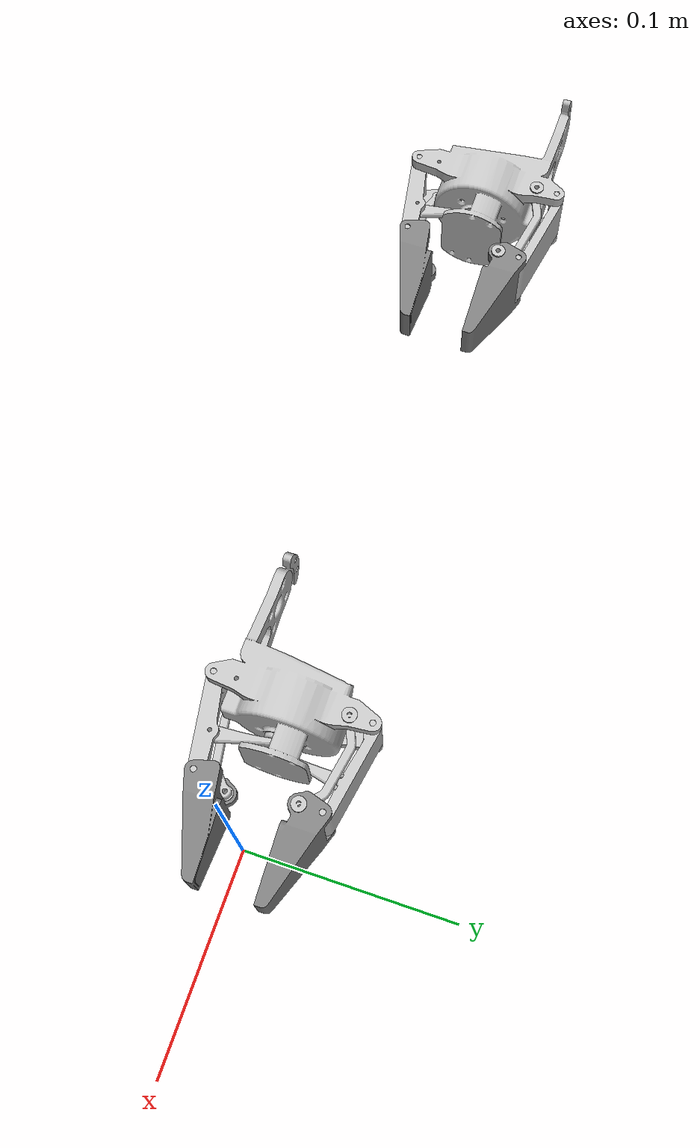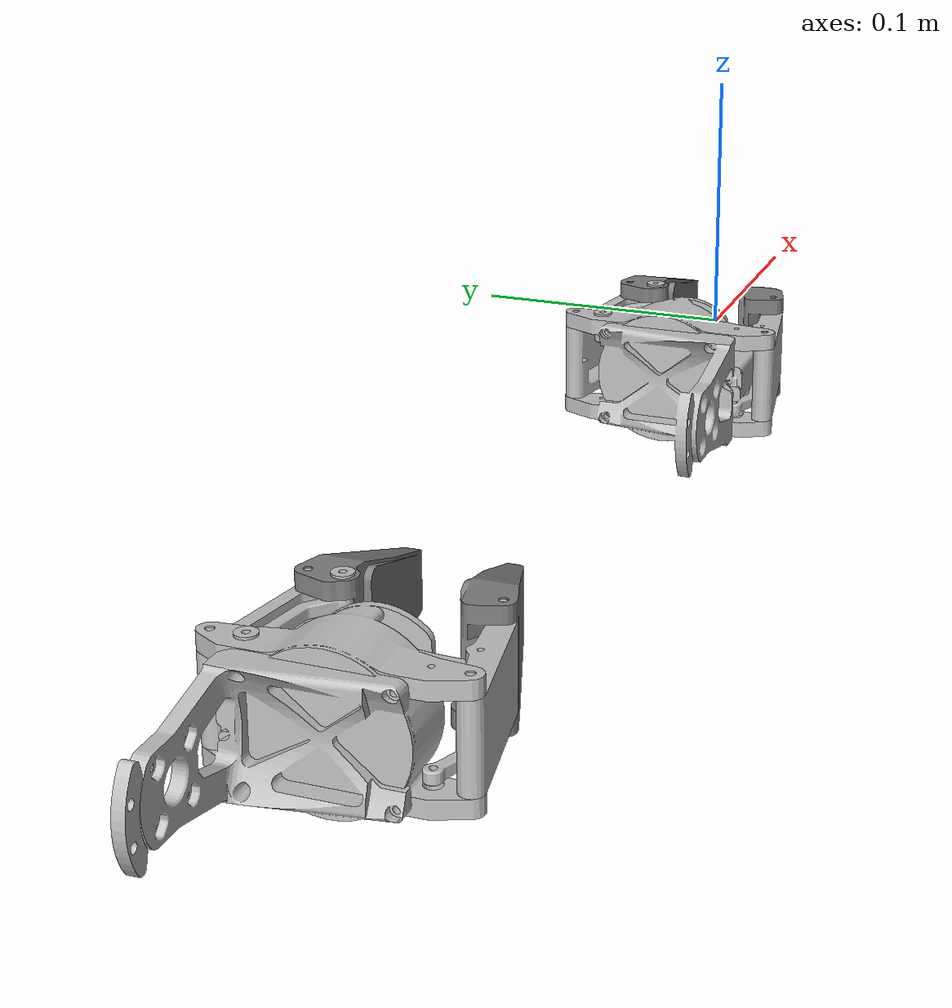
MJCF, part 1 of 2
<mujoco model="URDF_RX101_ASSY_V2_31dof_202608251956">
  <compiler angle="radian" inertiafromgeom="false" />
  <asset>
    <mesh name="r_finger1_link" content_type="model/obj" file="meshes/r_finger1_link.obj" />
    <mesh name="r_finger2_link" content_type="model/obj" file="meshes/r_finger2_link.obj" />
    <mesh name="l_finger1_link" content_type="model/obj" file="meshes/l_finger1_link.obj" />
    <mesh name="l_finger2_link" content_type="model/obj" file="meshes/l_finger2_link.obj" />
    <mesh name="contact_r_finger1_link_000" vertex="-0.01584750041 -0.0163924545 -0.01482984703 -0.01584750041 -0.0163924545 0.01482984703 -0.01584750041 -0.01389245503 -0.01482984703 -0.01584750041 -0.01389245503 0.01482984703 -0.01566593349 -0.0163924545 -0.01599042863 -0.01566593349 -0.0163924545 0.01599042863 -0.01566593349 -0.01389245503 -0.01599042863 -0.01566593349 -0.01389245503 0.01599042863 -0.01513857953 -0.0163924545 -0.01704010181 -0.01513857953 -0.0163924545 0.01704010181 -0.01513857953 -0.01389245503 -0.01704010181 -0.01513857953 -0.01389245503 0.01704010181 -0.01431583613 -0.0163924545 -0.01787856035 -0.01431583613 -0.0163924545 0.01787856035 -0.01431583613 -0.01389245503 -0.01787856035 -0.01431583613 -0.01389245503 0.01787856035 -0.01327632647 -0.0163924545 -0.01842567511 -0.01327632647 -0.0163924545 0.01842567511 -0.01327632647 -0.01389245503 -0.01842567511 -0.01327632647 -0.01389245503 0.01842567511 -0.01211938728 -0.0163924545 -0.01862916723 -0.01211938728 -0.0163924545 0.01862916723 -0.01211938728 -0.01389245503 -0.01862916723 -0.01211938728 -0.01389245503 0.01862916723 -0.01095557865 -0.0163924545 -0.01846958697 -0.01095557865 -0.0163924545 0.01846958697 -0.01095557865 -0.01389245503 -0.01846958697 -0.01095557865 -0.01389245503 0.01846958697 0.01734442264 -0.0163924545 -0.009979587048 0.01734442264 -0.0163924545 0.009979587048 0.01734442264 -0.01389245503 -0.009979587048 0.01734442264 -0.01389245503 0.009979587048 0.01843341812 -0.0163924545 -0.009451694787 0.01843341812 -0.0163924545 0.009451694787 0.01843341812 -0.01389245503 -0.009451694787 0.01843341812 -0.01389245503 0.009451694787 0.01930121332 -0.0163924545 -0.008608182892 0.01930121332 -0.0163924545 0.008608182892 0.01930121332 -0.01389245503 -0.008608182892 0.01930121332 -0.01389245503 0.008608182892 0.0198597908 -0.0163924545 -0.007534604054 0.0198597908 -0.0163924545 0.007534604054 0.0198597908 -0.01389245503 -0.007534604054 0.0198597908 -0.01389245503 0.007534604054 0.02005250007 -0.0163924545 -0.006339846645 0.02005250007 -0.0163924545 0.006339846645 0.02005250007 -0.01389245503 -0.006339846645 0.02005250007 -0.01389245503 0.006339846645" face="0 1 3 3 2 0 30 28 24 24 26 30 46 47 45 44 46 45 31 29 33 31 33 35 20 22 26 20 26 24 19 17 21 21 23 19 13 17 19 19 15 13 7 3 1 1 5 7 0 2 6 6 4 0 42 46 44 44 40 42 42 40 36 36 38 42 28 30 34 34 32 28 36 32 34 34 38 36 35 33 37 37 39 35 13 15 11 11 9 13 5 9 11 11 7 5 27 23 21 21 25 27 29 31 27 27 25 29 12 8 10 10 14 12 10 8 4 4 6 10 2 3 18 18 6 2 35 39 18 18 31 35 18 47 46 3 7 18 26 22 18 18 30 26 18 19 23 18 11 15 14 10 18 46 42 18 18 34 30 15 19 18 18 43 47 23 27 18 18 42 38 38 34 18 39 43 18 7 11 18 18 27 31 18 10 6 22 20 18 20 16 18 18 16 12 12 14 18 41 1 0 41 8 12 13 9 41 0 4 41 44 45 41 41 40 44 24 28 41 21 17 41 33 29 41 41 5 1 41 20 24 12 16 41 41 17 13 28 32 41 4 8 41 36 40 41 41 25 21 41 32 36 41 9 5 29 25 41 41 16 20 41 37 33 41 45 47 47 43 41 41 43 39 39 37 41" />
    <mesh name="contact_r_finger1_link_001" vertex="-0.02670498006 -0.01638999954 -0.02050000057 -0.02670498006 -0.01638999954 -0.01449999958 -0.02670498006 -0.01521555893 -0.02050000057 -0.02670498006 -0.01521555893 -0.01449999958 -0.02523463592 -0.01638999954 -0.02050000057 -0.02523463592 -0.01638999954 -0.01449999958 -0.02523463592 -0.0143856965 -0.02050000057 -0.02523463592 -0.0143856965 -0.01449999958" face="5 1 0 0 4 5 2 4 0 2 6 4 7 5 4 4 6 7 0 1 3 3 2 0 1 5 3 5 7 3 6 2 3 3 7 6" />
    <mesh name="contact_r_finger1_link_002" vertex="-0.02523463592 -0.01638999954 -0.02050000057 -0.02523463592 -0.01638999954 -0.01449999958 -0.02523463592 -0.0143856965 -0.02050000057 -0.02523463592 -0.0143856965 -0.01449999958 -0.02357191779 -0.01638999954 -0.02050000057 -0.02357191779 -0.01638999954 -0.01449999958 -0.02357191779 -0.01409251429 -0.02050000057 -0.02357191779 -0.01409251429 -0.01449999958" face="5 1 0 0 4 5 2 4 0 2 6 4 7 5 4 4 6 7 0 1 3 3 2 0 1 5 3 5 7 3 6 2 3 3 7 6" />
    <mesh name="contact_r_finger1_link_003" vertex="-0.02357191779 -0.01638999954 -0.02050000057 -0.02357191779 -0.01638999954 -0.01449999958 -0.02357191779 -0.01409251429 -0.02050000057 -0.02357191779 -0.01409251429 -0.01449999958 -0.02190641686 -0.01638999954 -0.02050000057 -0.02190641686 -0.01638999954 -0.01449999958 -0.02190641686 -0.01436944306 -0.02050000057 -0.02190641686 -0.01436944306 -0.01449999958" face="0 2 6 6 4 0 0 4 5 5 1 0 4 6 5 5 6 7 3 2 0 0 1 3 3 6 2 7 6 3 1 5 3 3 5 7" />
    <mesh name="contact_r_finger1_link_004" vertex="-0.02190641686 -0.01638999954 -0.02050000057 -0.02190641686 -0.01638999954 -0.01449999958 -0.02190641686 -0.01436944306 -0.02050000057 -0.02190641686 -0.01436944306 -0.01449999958 -0.02042803727 -0.01638999954 -0.02050000057 -0.02042803727 -0.01638999954 -0.01449999958 -0.02042803727 -0.01518490445 -0.02050000057 -0.02042803727 -0.01518490445 -0.01449999958" face="0 2 6 6 4 0 0 4 5 5 1 0 4 6 5 5 6 7 3 2 0 0 1 3 3 6 2 7 6 3 1 5 3 3 5 7" />
    <mesh name="contact_r_finger1_link_005" vertex="-0.01089810859 -0.01638999954 0.01866115257 -0.01089810859 -0.01623493433 0.01866115257 0.001252500224 -0.01638999954 0.01501596905 0.001252500224 -0.01638999954 0.01606000029 0.001252500224 -0.01409245469 0.01501596905 0.001252500224 -0.01409245469 0.01606000029" face="0 2 3 1 5 4 5 3 2 2 4 5 1 4 2 1 2 0 3 5 1 0 3 1" />
    <mesh name="contact_r_finger1_link_006" vertex="-0.01089810859 -0.01638999954 -0.01866115257 -0.01089810859 -0.01623493433 -0.01866115257 0.001252500224 -0.01638999954 -0.01606000029 0.001252500224 -0.01638999954 -0.01501596905 0.001252500224 -0.01409245469 -0.01606000029 0.001252500224 -0.01409245469 -0.01501596905" face="0 2 3 1 5 4 5 3 2 2 4 5 1 4 2 1 2 0 3 5 1 0 3 1" />
    <mesh name="contact_r_finger1_link_007" vertex="0.02125249803 -0.01638999954 -0.01006000023 0.02125249803 -0.01638999954 0.01006000023 0.02125249803 -0.01409245469 -0.01006000023 0.02125249803 -0.01409245469 0.01006000023 0.02135249972 -0.01638999954 -0.01002999954 0.02135249972 -0.01638999954 0.01002999954 0.02135249972 -0.0141192507 -0.01002999954 0.02135249972 -0.0141192507 0.01002999954" face="0 2 6 6 4 0 0 4 5 5 1 0 4 6 5 5 6 7 3 2 0 0 1 3 3 6 2 7 6 3 1 5 3 3 5 7" />
    <mesh name="contact_r_finger1_link_008" vertex="0.01854820177 -0.01638999954 0.009615476243 0.01854820177 -0.01409245469 0.009615476243 0.01946167275 -0.01638999954 0.008727569133 0.01946167275 -0.01409245469 0.008727569133 0.02125249803 -0.01638999954 0.01006000023 0.02125249803 -0.01409245469 0.01006000023" face="2 4 0 5 3 1 3 2 0 0 1 3 5 1 0 0 4 5 2 3 5 4 2 5" />
    <mesh name="contact_r_finger1_link_009" vertex="0.02004965022 -0.01638999954 0.007597486023 0.02004965022 -0.01409245469 0.007597486023 0.02025249973 -0.01638999954 0.006339846645 0.02025249973 -0.01409245469 0.006339846645 0.02125249803 -0.01638999954 0.01006000023 0.02125249803 -0.01409245469 0.01006000023" face="2 4 0 5 3 1 3 2 0 0 1 3 5 1 0 0 4 5 2 3 5 4 2 5" />
    <mesh name="contact_r_finger1_link_010" vertex="0.02025249973 -0.01638999954 -0.006339846645 0.02025249973 -0.01638999954 0.006339846645 0.02025249973 -0.01409245469 -0.006339846645 0.02025249973 -0.01409245469 0.006339846645 0.02125249803 -0.01638999954 -0.01006000023 0.02125249803 -0.01638999954 0.01006000023 0.02125249803 -0.01409245469 -0.01006000023 0.02125249803 -0.01409245469 0.01006000023" face="0 2 6 6 4 0 0 4 1 4 5 1 4 6 7 7 5 4 3 2 0 0 1 3 3 6 2 3 7 6 3 1 5 5 7 3" />
    <mesh name="contact_r_finger1_link_011" vertex="0.02004965022 -0.01638999954 -0.007597486023 0.02004965022 -0.01409245469 -0.007597486023 0.02025249973 -0.01638999954 -0.006339846645 0.02025249973 -0.01409245469 -0.006339846645 0.02125249803 -0.01638999954 -0.01006000023 0.02125249803 -0.01409245469 -0.01006000023" face="0 4 2 1 3 5 0 2 3 3 1 0 0 1 5 5 4 0 5 3 2 5 2 4" />
    <mesh name="contact_r_finger1_link_012" vertex="0.01946167275 -0.01638999954 -0.008727569133 0.01946167275 -0.01409245469 -0.008727569133 0.02004965022 -0.01638999954 -0.007597486023 0.02004965022 -0.01409245469 -0.007597486023 0.02125249803 -0.01638999954 -0.01006000023 0.02125249803 -0.01409245469 -0.01006000023" face="0 4 2 1 3 5 0 2 3 3 1 0 0 1 5 5 4 0 5 3 2 5 2 4" />
    <mesh name="contact_r_finger1_link_013" vertex="0.01740189269 -0.01638999954 0.01017115172 0.01740189269 -0.01409245469 0.01017115172 0.01854820177 -0.01638999954 0.009615476243 0.01854820177 -0.01409245469 0.009615476243 0.02125249803 -0.01638999954 0.01006000023 0.02125249803 -0.01409245469 0.01006000023" face="2 4 0 5 3 1 3 2 0 0 1 3 5 1 0 0 4 5 2 3 5 4 2 5" />
    <mesh name="contact_r_finger1_link_014" vertex="0.01740189269 -0.01638999954 -0.01017115172 0.01740189269 -0.01409245469 -0.01017115172 0.01854820177 -0.01638999954 -0.009615476243 0.01854820177 -0.01409245469 -0.009615476243 0.02125249803 -0.01638999954 -0.01006000023 0.02125249803 -0.01409245469 -0.01006000023" face="0 4 2 1 3 5 0 2 3 3 1 0 0 1 5 5 4 0 5 3 2 5 2 4" />
    <mesh name="contact_r_finger1_link_015" vertex="0.01946167275 -0.01638999954 0.008727569133 0.01946167275 -0.01409245469 0.008727569133 0.02004965022 -0.01638999954 0.007597486023 0.02004965022 -0.01409245469 0.007597486023 0.02125249803 -0.01638999954 0.01006000023 0.02125249803 -0.01409245469 0.01006000023" face="2 4 0 5 3 1 3 2 0 0 1 3 5 1 0 0 4 5 2 3 5 4 2 5" />
    <mesh name="contact_r_finger1_link_016" vertex="0.01854820177 -0.01638999954 -0.009615476243 0.01854820177 -0.01409245469 -0.009615476243 0.01946167275 -0.01638999954 -0.008727569133 0.01946167275 -0.01409245469 -0.008727569133 0.02125249803 -0.01638999954 -0.01006000023 0.02125249803 -0.01409245469 -0.01006000023" face="0 4 2 1 3 5 0 2 3 3 1 0 0 1 5 5 4 0 5 3 2 5 2 4" />
    <mesh name="contact_r_finger1_link_017" vertex="-0.0117775267 -0.01638999954 0.01927152462 -0.01177752204 -0.01638999954 0.019969007 -0.01089810859 -0.01638999954 0.01866115257 -0.01089810859 -0.01623493433 0.01866115257 0.001252500224 -0.01638999954 0.01606000029 0.001252500224 -0.01409245469 0.01606000029" face="1 5 0 4 5 1 3 2 0 0 5 3 4 1 2 2 1 0 4 2 3 3 5 4" />
    <mesh name="contact_r_finger1_link_018" vertex="-0.02773020416 -0.01638999954 -0.02050000057 -0.02773020416 -0.01638999954 -0.01449999958 -0.02670498006 -0.01638999954 -0.02050000057 -0.02670498006 -0.01638999954 -0.01449999958 -0.02670498006 -0.01521555893 -0.02050000057 -0.02670498006 -0.01521555893 -0.01449999958" face="4 2 0 1 3 5 3 1 0 0 2 3 0 1 5 5 4 0 5 3 2 2 4 5" />
    <mesh name="contact_r_finger1_link_019" vertex="-0.02042803727 -0.01638999954 -0.02050000057 -0.02042803727 -0.01638999954 -0.01449999958 -0.02042803727 -0.01518490445 -0.02050000057 -0.02042803727 -0.01518490445 -0.01449999958 -0.01935513504 -0.01638999954 -0.02050000057 -0.01935513504 -0.01638999954 -0.01449999958" face="2 4 0 5 3 1 0 1 3 3 2 0 5 1 0 0 4 5 2 3 5 4 2 5" />
    <mesh name="contact_r_finger1_link_020" vertex="-0.0117775267 -0.01638999954 -0.01927152462 -0.01177752204 -0.01638999954 -0.019969007 -0.01089810859 -0.01638999954 -0.01866115257 -0.01089810859 -0.01623493433 -0.01866115257 0.001252500224 -0.01638999954 -0.01606000029 0.001252500224 -0.01409245469 -0.01606000029" face="0 5 1 1 5 4 0 2 3 3 5 0 2 1 4 0 1 2 3 2 4 4 5 3" />
    <mesh name="contact_r_finger1_link_021" vertex="-0.01177752763 -0.01638999954 0.01881914213 -0.0117775267 -0.01638999954 0.01927152462 -0.01089810859 -0.01638999954 0.01866115257 -0.01089810859 -0.01623493433 0.01866115257" face="3 2 0 0 2 1 1 3 0 2 3 1" />
    <mesh name="contact_r_finger1_link_022" vertex="-0.01177752763 -0.01638999954 -0.01881914213 -0.0117775267 -0.01638999954 -0.01927152462 -0.01089810859 -0.01638999954 -0.01866115257 -0.01089810859 -0.01623493433 -0.01866115257" face="0 2 3 1 2 0 0 3 1 1 3 2" />
    <mesh name="contact_r_finger1_link_023" vertex="-0.03019444272 -0.02120594867 -0.02050000057 -0.03019444272 -0.02120594867 -0.01600000076 -0.03007848188 -0.02236761525 -0.02050000057 -0.03007848188 -0.02236761525 -0.01600000076 -0.02985820733 -0.02008797787 -0.02050000057 -0.02985820733 -0.02008797787 -0.01600000076 -0.02781529725 -0.01648747735 -0.02050000057 -0.02781529725 -0.01648747735 -0.01600000076 -0.02773020416 -0.01638999954 -0.02050000057 -0.02773020416 -0.01638999954 -0.01600000076 -0.02737434022 -0.03125662357 -0.02050000057 -0.02737434022 -0.03125662357 -0.01600000076 -0.02662046254 -0.03265310079 -0.02050000057 -0.02662046254 -0.03265310079 -0.01600000076 -0.02538288571 -0.0336465165 -0.02050000057 -0.02538288571 -0.0336465165 -0.01600000076 -0.02385641076 -0.0340805091 -0.02050000057 -0.02385641076 -0.0340805091 -0.01600000076 -0.02228131145 -0.03388676047 -0.02050000057 -0.02228131145 -0.03388676047 -0.01600000076 -0.01999999955 -0.03312547132 -0.02050000057 -0.01999999955 -0.03312547132 -0.01600000076 -0.01999999955 -0.01638999954 -0.02050000057 -0.01999999955 -0.01638999954 -0.01600000076" face="20 22 21 21 22 23 9 22 8 23 22 9 5 4 0 0 1 5 11 10 12 12 13 11 0 4 14 14 22 20 14 6 8 14 2 0 8 22 14 12 10 14 20 18 14 4 6 14 10 2 14 14 18 16 7 9 8 8 6 7 7 6 4 4 5 7 3 1 0 0 2 3 3 2 10 10 11 3 20 21 19 19 18 20 16 18 19 19 17 16 15 21 23 23 9 15 15 5 1 9 7 15 1 3 15 15 11 13 15 19 21 15 7 5 15 3 11 17 19 15 15 13 12 12 14 15 15 14 16 16 17 15" />
    <mesh name="contact_r_finger1_link_024" vertex="-0.03019444272 -0.02120594867 -0.01600000076 -0.03019444272 -0.02120594867 -0.01449999958 -0.03007848188 -0.02236761525 -0.01600000076 -0.03007848188 -0.02236761525 -0.01449999958 -0.02985820733 -0.02008797787 -0.01600000076 -0.02985820733 -0.02008797787 -0.01449999958 -0.02781529725 -0.01648747735 -0.01600000076 -0.02781529725 -0.01648747735 -0.01449999958 -0.02773020416 -0.01638999954 -0.01600000076 -0.02773020416 -0.01638999954 -0.01449999958 -0.02737434022 -0.03125662357 -0.01600000076 -0.02737434022 -0.03125662357 -0.01449999958 -0.02662046254 -0.03265310079 -0.01600000076 -0.02662046254 -0.03265310079 -0.01449999958 -0.02538288571 -0.0336465165 -0.01600000076 -0.02538288571 -0.0336465165 -0.01449999958 -0.02385641076 -0.0340805091 -0.01600000076 -0.02385641076 -0.0340805091 -0.01449999958 -0.02228131145 -0.03388676047 -0.01600000076 -0.02228131145 -0.03388676047 -0.01449999958 -0.01999999955 -0.03312547132 -0.01600000076 -0.01999999955 -0.03312547132 -0.01449999958 -0.01999999955 -0.01638999954 -0.01600000076 -0.01999999955 -0.01638999954 -0.01449999958" face="20 22 21 21 22 23 9 22 8 23 22 9 5 4 0 0 1 5 11 10 12 12 13 11 0 4 14 14 22 20 14 6 8 14 2 0 8 22 14 12 10 14 20 18 14 4 6 14 10 2 14 14 18 16 7 9 8 8 6 7 7 6 4 4 5 7 3 1 0 0 2 3 3 2 10 10 11 3 20 21 19 19 18 20 16 18 19 19 17 16 15 21 23 23 9 15 15 5 1 9 7 15 1 3 15 15 11 13 15 19 21 15 7 5 15 3 11 17 19 15 15 13 12 12 14 15 15 14 16 16 17 15" />
    <mesh name="contact_r_finger1_link_025" vertex="-0.02999264188 -0.02174171619 0.01449999958 -0.02999264188 -0.02174171619 0.01600000076 -0.02998934872 -0.02171711996 0.01600000076 -0.02998825163 -0.0217089206 0.009499999695 -0.02998825163 -0.0217089206 0.01449999958 -0.0298871547 -0.02299654111 0.01449999958 -0.0298871547 -0.02299654111 0.01600000076 -0.0298846513 -0.0214202255 0.01600000076 -0.02957385406 -0.02055414207 0.009499999695 -0.02957385406 -0.02055414207 0.01600000076 -0.02870457806 -0.019643059 0.009499999695 -0.02870457806 -0.019643059 0.01600000076 -0.02753796801 -0.0191689916 0.009499999695 -0.02753796801 -0.0191689916 0.01600000076 -0.02737434022 -0.03125662357 0.01449999958 -0.02737434022 -0.03125662357 0.01600000076 -0.02662046254 -0.03265310079 0.01449999958 -0.02662046254 -0.03265310079 0.01600000076 -0.02538288571 -0.0336465165 0.01449999958 -0.02538288571 -0.0336465165 0.01600000076 -0.02479478344 -0.02473575063 0.009499999695 -0.02462910116 -0.01865607873 0.01600000076 -0.02385641076 -0.0340805091 0.01449999958 -0.02385641076 -0.0340805091 0.01600000076 -0.02228131145 -0.03388676047 0.01449999958 -0.02228131145 -0.03388676047 0.01600000076 -0.01999999955 -0.03312547132 0.01449999958 -0.01999999955 -0.03312547132 0.01600000076 -0.01999999955 -0.02589618042 0.009038448334 -0.01999999955 -0.01783984341 0.009001537226 -0.01999999955 -0.01783984341 0.01600000076" face="28 3 29 29 3 8 0 3 5 3 14 5 16 14 3 24 28 26 22 28 24 3 28 20 21 30 29 13 21 12 12 21 29 18 16 3 3 20 18 18 28 22 18 20 28 29 8 10 10 12 29 1 2 4 7 9 4 4 2 7 29 30 27 26 28 27 27 28 29 26 27 24 24 27 25 11 13 10 13 12 10 23 24 25 22 24 23 15 5 14 15 6 5 14 16 15 16 17 15 11 10 9 9 10 8 9 8 3 3 4 9 5 6 1 0 5 1 1 4 3 1 3 0 19 17 16 16 18 19 22 23 19 19 18 22 7 27 30 6 15 7 7 13 11 25 27 7 30 21 7 7 21 13 7 23 25 11 9 7 7 1 6 7 15 17 17 19 7 2 1 7 7 19 23" />
    <mesh name="contact_r_finger1_link_026" vertex="-0.02999264188 -0.02174171619 0.01600000076 -0.02999264188 -0.02174171619 0.02050000057 -0.02998934872 -0.02171711996 0.01600000076 -0.0298871547 -0.02299654111 0.01600000076 -0.0298871547 -0.02299654111 0.02050000057 -0.0298846513 -0.0214202255 0.01600000076 -0.02957385406 -0.02055414207 0.01600000076 -0.02957385406 -0.02055414207 0.02050000057 -0.02870457806 -0.019643059 0.01600000076 -0.02870457806 -0.019643059 0.02050000057 -0.02753796801 -0.0191689916 0.01600000076 -0.02753796801 -0.0191689916 0.02050000057 -0.02737434022 -0.03125662357 0.01600000076 -0.02737434022 -0.03125662357 0.02050000057 -0.02662046254 -0.03265310079 0.01600000076 -0.02662046254 -0.03265310079 0.02050000057 -0.02538288571 -0.0336465165 0.01600000076 -0.02538288571 -0.0336465165 0.02050000057 -0.02462910116 -0.01865607873 0.01600000076 -0.02385641076 -0.0340805091 0.01600000076 -0.02385641076 -0.0340805091 0.02050000057 -0.02228131145 -0.03388676047 0.01600000076 -0.02228131145 -0.03388676047 0.02050000057 -0.01999999955 -0.03312547132 0.01600000076 -0.01999999955 -0.03312547132 0.02050000057 -0.01999999955 -0.01783984527 0.02050000057 -0.01999999955 -0.01783984341 0.01600000076 -0.01999999955 -0.01783984341 0.01787483878" face="10 11 18 27 11 25 26 18 27 27 18 11 1 7 2 0 1 2 7 6 5 5 2 7 9 11 8 8 11 10 27 24 23 23 26 27 27 25 24 23 24 22 22 21 23 19 21 22 22 20 19 9 8 6 6 7 9 3 4 1 3 1 0 13 4 3 3 12 13 19 20 16 20 17 16 24 25 15 25 11 15 1 4 15 15 11 9 15 7 1 15 22 24 9 7 15 15 4 13 20 22 15 15 17 20 15 12 14 13 12 15 14 16 15 15 16 17 5 16 14 5 26 23 23 21 5 5 18 26 5 3 0 5 8 10 10 18 5 14 12 5 5 21 19 5 6 8 12 3 5 19 16 5 0 2 5" />
    <mesh name="contact_r_finger1_link_027" vertex="-0.01999999955 -0.03312547132 -0.02050000057 -0.01999999955 -0.03312547132 -0.01600000076 -0.01999999955 -0.01638999954 -0.02050000057 -0.01999999955 -0.01638999954 -0.01600000076 -0.01935513504 -0.01638999954 -0.02050000057 -0.01935513504 -0.01638999954 -0.01600000076 -0.01900613122 -0.03279381245 -0.01600000076 -0.01549999975 -0.03162378818 -0.01781732216 -0.01549999975 -0.03162378818 -0.01600000076 -0.01549999975 -0.03162378445 -0.02050000057 -0.01549999975 -0.01704637334 -0.02050000057 -0.01549999975 -0.01704637334 -0.01600000076" face="9 7 0 0 7 6 6 1 0 8 6 7 0 1 3 3 2 0 9 10 8 8 10 11 7 9 8 5 3 1 1 6 5 5 8 11 6 8 5 0 2 4 4 10 9 4 9 0 2 3 4 3 5 4 11 10 4 4 5 11" />
    <mesh name="contact_r_finger1_link_028" vertex="-0.01999999955 -0.03312547132 -0.01600000076 -0.01999999955 -0.03312547132 -0.01449999958 -0.01999999955 -0.01638999954 -0.01600000076 -0.01999999955 -0.01638999954 -0.01449999958 -0.01954749972 -0.02631753869 0 -0.01954749972 -0.017760057 0 -0.01935513504 -0.01638999954 -0.01600000076 -0.01935513504 -0.01638999954 -0.01449999958 -0.01924294606 -0.01770635508 0 -0.01900613122 -0.03279381245 -0.01600000076 -0.01791440509 -0.03242949396 0 -0.01549999975 -0.03162378818 -0.01600000076 -0.01549999975 -0.03162378818 0 -0.01549999975 -0.01704637334 -0.01600000076 -0.01549999975 -0.01704637334 0" face="1 10 4 0 9 1 1 9 10 12 9 11 10 9 12 7 3 14 3 5 8 14 3 8 1 2 0 1 3 2 11 13 12 12 13 14 3 1 5 5 1 4 8 12 14 10 12 8 4 10 8 8 5 4 0 2 6 6 13 11 6 9 0 11 9 6 2 3 6 3 7 6 14 13 6 6 7 14" />
    <mesh name="contact_r_finger1_link_029" vertex="-0.01999999955 -0.03312547132 0.01449999958 -0.01999999955 -0.03312547132 0.01600000076 -0.01999999955 -0.02589618042 0.009038448334 -0.01999999955 -0.01783984341 0.009001537226 -0.01999999955 -0.01783984341 0.01600000076 -0.01954749972 -0.02631753869 0 -0.01954749972 -0.017760057 0 -0.01924294606 -0.01770635508 0 -0.01791440509 -0.03242949396 0 -0.01791440509 -0.03242949396 0.01449999958 -0.01549999975 -0.03162378818 0 -0.01549999975 -0.03162378818 0.01600000076 -0.01549999975 -0.01704637334 0 -0.01549999975 -0.01704637147 0.002346974565 -0.01549999975 -0.01704637147 0.01600000076" face="0 5 8 2 5 0 11 1 9 3 6 5 5 2 3 13 12 7 7 3 13 6 3 7 10 12 14 14 11 10 14 12 13 4 1 14 14 1 11 10 11 9 9 8 10 9 1 0 0 8 9 0 1 3 3 2 0 3 1 4 3 14 13 4 14 3 7 12 10 10 8 7 7 8 5 5 6 7" />
    <mesh name="contact_r_finger1_link_030" vertex="-0.01999999955 -0.03312547132 0.01600000076 -0.01999999955 -0.03312547132 0.02050000057 -0.01999999955 -0.01783984527 0.02050000057 -0.01999999955 -0.01783984341 0.01600000076 -0.01999999955 -0.01783984341 0.01787483878 -0.01549999975 -0.03162378818 0.01600000076 -0.01549999975 -0.03162378818 0.01781732216 -0.01549999975 -0.03162378445 0.02050000057 -0.01549999975 -0.01704637334 0.02050000057 -0.01549999975 -0.01704637147 0.01600000076 -0.01549999975 -0.01704637147 0.01630767621" face="6 7 1 8 4 2 4 8 10 3 9 5 3 5 0 0 5 6 6 1 0 4 3 0 0 1 4 1 2 4 8 2 1 1 7 8 5 9 10 10 6 5 7 6 10 10 8 7 9 3 10 3 4 10" />
    <mesh name="contact_r_finger1_link_031" vertex="-0.01549999975 -0.03162378818 -0.01781732216 -0.01549999975 -0.03162378818 -0.01600000076 -0.01549999975 -0.03162378445 -0.02050000057 -0.01549999975 -0.01704637334 -0.02050000057 -0.01549999975 -0.01704637334 -0.01600000076 -0.014030152 -0.01678719744 -0.01600000076 -0.01360605098 -0.01671241783 -0.01600000076 -0.0135475006 -0.03097222187 -0.02050000057 -0.0135475006 -0.01670209505 -0.02050000057 -0.01179144811 -0.0163924545 -0.01681338809 -0.01177752763 -0.01638999954 -0.01881914213 -0.0117775267 -0.01638999954 -0.01927152462 -0.01177752204 -0.01638999954 -0.019969007 -0.009999999776 -0.02978839539 -0.01600000076 -0.009999999776 -0.02978839353 -0.01943575032 -0.009999999776 -0.02680830657 -0.01600000076 -0.009999999776 -0.0163924545 -0.01630365662 -0.009999999776 -0.01638999954 -0.01943575032 -0.009999999776 -0.01638999954 -0.01839171909" face="14 13 0 0 13 1 0 2 7 7 14 0 9 16 10 10 16 18 16 9 6 6 15 16 5 9 10 5 6 9 5 3 4 11 5 10 3 5 11 8 11 12 3 11 8 0 1 3 3 2 0 3 1 4 4 1 5 5 1 13 13 15 5 15 6 5 17 15 13 13 14 17 16 15 17 17 18 16 17 11 10 10 18 17 12 11 17 12 17 8 14 7 8 8 17 14 2 3 8 8 7 2" />
    <mesh name="contact_r_finger1_link_032" vertex="-0.01549999975 -0.03162378818 -0.01600000076 -0.01549999975 -0.03162378818 0 -0.01549999975 -0.01704637334 -0.01600000076 -0.01549999975 -0.01704637334 0 -0.014030152 -0.01678719744 -0.01600000076 -0.01390772499 -0.01676561125 0 -0.01360605098 -0.01671241783 -0.01600000076 -0.01204750035 -0.01643760316 -0.001000000047 -0.01204750035 -0.01643760316 0 -0.01179144811 -0.0163924545 -0.001000000047 -0.01179144811 -0.0163924545 0 -0.009999999776 -0.02978839539 -0.01600000076 -0.009999999776 -0.02978839539 0 -0.009999999776 -0.02680830657 -0.01600000076 -0.009999999776 -0.0163924545 -0.001000000047 -0.009999999776 -0.0163924545 0" face="14 6 9 2 3 4 9 6 4 6 14 13 9 4 7 4 8 7 5 4 3 5 8 4 12 1 0 0 11 12 0 1 3 3 2 0 13 11 0 0 2 13 2 4 13 13 4 6 15 12 11 11 13 15 15 13 14 15 14 9 9 10 15 7 8 10 7 10 9 1 12 5 5 3 1 12 15 5 10 8 5 5 15 10" />
    <mesh name="contact_r_finger1_link_033" vertex="-0.01549999975 -0.03162378818 0 -0.01549999975 -0.03162378818 0.01600000076 -0.01549999975 -0.01704637334 0 -0.01549999975 -0.01704637147 0.002346974565 -0.01549999975 -0.01704637147 0.01600000076 -0.01390772499 -0.01676561125 0 -0.01383463759 -0.0167527236 0.0157276988 -0.01360605098 -0.01671241783 0.01600000076 -0.01204750035 -0.01643760316 0 -0.01204750035 -0.01643760316 0.001000000047 -0.01179144811 -0.0163924545 0 -0.01179144811 -0.0163924545 0.001000000047 -0.009999999776 -0.02978839539 0 -0.009999999776 -0.02978839539 0.01600000076 -0.009999999776 -0.02680913918 0.01600000076 -0.009999999776 -0.0163924545 0 -0.009999999776 -0.0163924545 0.001000000047" face="5 2 3 8 5 3 16 7 14 4 7 6 6 9 4 7 9 6 7 16 11 11 9 7 0 12 13 13 1 0 0 1 4 4 2 0 3 2 4 1 13 7 7 13 14 7 4 1 8 15 12 8 12 0 10 15 8 0 2 8 2 5 8 3 4 8 4 9 8 12 15 16 16 13 12 14 13 16 11 15 10 11 16 15 10 8 11 11 8 9" />
    <mesh name="contact_r_finger1_link_034" vertex="-0.01549999975 -0.03162378818 0.01600000076 -0.01549999975 -0.03162378818 0.01781732216 -0.01549999975 -0.03162378445 0.02050000057 -0.01549999975 -0.01704637334 0.02050000057 -0.01549999975 -0.01704637147 0.01600000076 -0.01549999975 -0.01704637147 0.01630767621 -0.01360605098 -0.01671241783 0.01600000076 -0.0135475006 -0.03097222187 0.02050000057 -0.0135475006 -0.01670209505 0.02050000057 -0.01179144811 -0.0163924545 0.01681338809 -0.01177752763 -0.01638999954 0.01881914213 -0.0117775267 -0.01638999954 0.01927152462 -0.01177752204 -0.01638999954 0.019969007 -0.009999999776 -0.02978839539 0.01600000076 -0.009999999776 -0.02978839353 0.01943575032 -0.009999999776 -0.02680913918 0.01600000076 -0.009999999776 -0.0163924545 0.01630365662 -0.009999999776 -0.01638999954 0.01839171909 -0.009999999776 -0.01638999954 0.01943575032" face="1 7 2 0 13 1 14 1 13 7 1 14 9 4 10 10 16 9 10 4 5 17 16 10 4 9 6 6 9 16 16 15 6 11 5 3 10 5 11 3 8 11 12 11 8 5 4 0 2 3 5 0 1 5 5 1 2 8 3 2 2 7 8 0 4 6 6 13 0 6 15 13 13 15 18 18 14 13 18 15 16 16 17 18 12 8 7 14 18 12 7 14 12 12 18 17 12 17 10 10 11 12" />
    <mesh name="contact_r_finger1_link_035" vertex="-0.009999999776 -0.02978839539 -0.01600000076 -0.009999999776 -0.02978839353 -0.01943575032 -0.009999999776 -0.02680830657 -0.01600000076 -0.009999999776 -0.0163924545 -0.01630365662 -0.009999999776 -0.01638999954 -0.01943575032 -0.009999999776 -0.01638999954 -0.01839171909 -0.008987809531 -0.0163924545 -0.01600000076 -0.002027600538 -0.01638999954 -0.01600000076 0 -0.02645131759 -0.01643574983 0 -0.02645131759 -0.01600000076 0 -0.01638999954 -0.01643574983 0 -0.01638999954 -0.01600000076" face="1 8 0 0 8 9 6 3 2 7 3 6 3 7 5 10 1 4 8 1 10 8 10 11 11 9 8 7 2 0 0 9 7 6 2 7 9 11 7 4 1 5 5 1 0 0 2 5 5 2 3 5 10 4 5 11 10 5 7 11" />
    <mesh name="contact_r_finger1_link_036" vertex="-0.009999999776 -0.02978839539 -0.01600000076 -0.009999999776 -0.02978839539 0 -0.009999999776 -0.02680830657 -0.01600000076 -0.009999999776 -0.0163924545 -0.001000000047 -0.009999999776 -0.0163924545 0 -0.008987809531 -0.0163924545 -0.01600000076 -0.002027600538 -0.01638999954 -0.01600000076 0 -0.02645131946 -0.01263499539 0 -0.02645131946 0 0 -0.02645131759 -0.01600000076 0 -0.0163924545 0 0 -0.01638999954 -0.01600000076 0 -0.01638999954 -0.01539171953" face="9 7 0 5 3 6 6 3 4 3 5 2 12 11 6 12 4 10 6 4 12 8 1 0 0 7 8 1 8 4 4 8 10 2 11 9 6 11 2 2 9 0 2 5 6 0 1 2 1 4 2 2 4 3 12 8 7 7 9 12 10 8 12 9 11 12" />
    <mesh name="contact_r_finger1_link_037" vertex="-0.009999999776 -0.02978839539 0 -0.009999999776 -0.02978839539 0.01600000076 -0.009999999776 -0.02680913918 0.01600000076 -0.009999999776 -0.0163924545 0 -0.009999999776 -0.0163924545 0.001000000047 -0.008987809531 -0.0163924545 0.01600000076 -0.002027600538 -0.01638999954 0.01600000076 0 -0.02645131946 0 0 -0.02645131946 0.01263499539 0 -0.02645131759 0.01600000076 0 -0.0163924545 0 0 -0.01638999954 0.01539171953 0 -0.01638999954 0.01600000076" face="8 9 1 11 10 3 11 3 6 6 12 11 4 2 5 4 5 6 6 3 4 0 3 10 10 7 0 0 7 8 8 1 0 1 9 2 6 5 2 2 12 6 9 12 2 7 10 11 11 8 7 9 8 11 11 12 9 4 3 0 0 1 4 1 2 4" />
    <mesh name="contact_r_finger1_link_038" vertex="-0.009999999776 -0.02978839539 0.01600000076 -0.009999999776 -0.02978839353 0.01943575032 -0.009999999776 -0.02680913918 0.01600000076 -0.009999999776 -0.0163924545 0.01630365662 -0.009999999776 -0.01638999954 0.01839171909 -0.009999999776 -0.01638999954 0.01943575032 -0.008987809531 -0.0163924545 0.01600000076 -0.002027600538 -0.01638999954 0.01600000076 0 -0.02645131759 0.01600000076 0 -0.02645131759 0.01643574983 0 -0.01638999954 0.01600000076 0 -0.01638999954 0.01643574983" face="0 8 9 9 1 0 2 3 6 7 3 4 6 3 7 2 5 4 0 1 2 4 3 2 1 5 2 0 2 7 7 8 0 7 2 6 7 10 8 4 5 11 10 7 11 11 7 4 11 5 1 1 9 11 8 10 11 11 9 8" />
    <mesh name="contact_r_finger1_link_039" vertex="0 -0.02645131759 -0.01643574983 0 -0.02645131759 -0.01600000076 0 -0.01638999954 -0.01643574983 0 -0.01638999954 -0.01600000076 0.001452501048 -0.01638999954 -0.01600000076 0.001452501281 -0.02596660703 -0.01600000076 0.001452501281 -0.01819281653 -0.01600000076" face="0 5 1 2 3 4 2 4 6 0 1 3 3 2 0 6 3 1 6 1 5 6 4 3 0 2 6 6 5 0" />
    <mesh name="contact_r_finger1_link_040" vertex="0 -0.02645131946 -0.01263499539 0 -0.02645131946 0 0 -0.02645131759 -0.01600000076 0 -0.0163924545 0 0 -0.01638999954 -0.01600000076 0 -0.01638999954 -0.01539171953 0.001452501048 -0.01638999954 -0.01600000076 0.001452501281 -0.02596660703 -0.01600000076 0.001452501281 -0.01819281653 -0.01600000076 0.009999999776 -0.02311424352 -0.01159393135 0.009999999776 -0.02311424352 0 0.009999999776 -0.02311424166 -0.01343575027 0.009999999776 -0.0163924545 0 0.009999999776 -0.01638999954 -0.01343575027 0.009999999776 -0.01638999954 -0.01239171997" face="7 9 0 2 7 0 9 7 11 14 3 12 8 6 13 3 14 5 10 1 0 0 9 10 1 10 3 3 10 12 14 10 9 12 10 14 9 11 14 14 11 13 8 2 4 7 2 8 4 6 8 13 11 8 8 11 7 0 1 5 5 2 0 1 3 5 4 2 5 5 6 4 5 14 13 13 6 5" />
    <mesh name="contact_r_finger1_link_041" vertex="0 -0.02645131946 0 0 -0.02645131946 0.01263499539 0 -0.02645131759 0.01600000076 0 -0.0163924545 0 0 -0.01638999954 0.01539171953 0 -0.01638999954 0.01600000076 0.001452501048 -0.01638999954 0.01600000076 0.001452501281 -0.02596660703 0.01600000076 0.009999999776 -0.02311424352 0 0.009999999776 -0.02311424352 0.01159393135 0.009999999776 -0.02311424166 0.01343575027 0.009999999776 -0.0163924545 0 0.009999999776 -0.01638999954 0.01239171997 0.009999999776 -0.01638999954 0.01343575027" face="12 3 4 2 1 7 1 9 7 13 6 7 3 12 11 13 7 10 10 7 9 9 1 0 0 8 9 0 1 5 5 3 0 4 3 5 5 1 2 5 6 13 5 12 4 13 12 5 2 7 5 5 7 6 0 3 11 11 8 0 10 9 8 10 12 13 8 11 10 10 11 12" />
    <mesh name="contact_r_finger1_link_042" vertex="0 -0.02645131759 0.01600000076 0 -0.02645131759 0.01643574983 0 -0.01638999954 0.01600000076 0 -0.01638999954 0.01643574983 0.001452501048 -0.01638999954 0.01600000076 0.001452501281 -0.02596660703 0.01600000076" face="0 5 1 3 1 5 2 3 4 4 3 5 0 1 3 3 2 0 0 2 4 4 5 0" />
    <mesh name="contact_r_finger1_link_043" vertex="0.009999999776 -0.02311424352 -0.01159393135 0.009999999776 -0.02311424352 0 0.009999999776 -0.02311424166 -0.01343575027 0.009999999776 -0.0163924545 0 0.009999999776 -0.01638999954 -0.01343575027 0.009999999776 -0.01638999954 -0.01239171997 0.01940214261 -0.01997667551 -0.0106151076 0.01940214261 -0.01997667551 0 0.02025249973 -0.01638999954 0 0.02047164738 -0.01934973896 -0.0102942558 0.02047164738 -0.01934973896 0 0.02119635046 -0.01834390871 -0.01007684413 0.02119635046 -0.01834390871 0 0.02145250142 -0.01713094488 -0.009999999776 0.02145250142 -0.01713094488 0 0.02145250142 -0.01638999954 -0.009999999776 0.02145250142 -0.01638999954 0" face="0 2 6 6 2 4 13 6 15 15 6 4 3 8 5 13 11 9 9 6 13 6 1 0 6 7 1 0 1 5 5 2 0 1 3 5 4 2 5 5 8 16 5 15 4 16 15 5 14 15 16 13 15 14 10 3 1 1 7 10 10 8 3 16 8 10 10 14 16 12 14 10 11 14 12 13 14 11 7 6 9 9 10 7 12 10 9 9 11 12" />
    <mesh name="contact_r_finger1_link_044" vertex="0.009999999776 -0.02311424352 0 0.009999999776 -0.02311424352 0.01159393135 0.009999999776 -0.02311424166 0.01343575027 0.009999999776 -0.0163924545 0 0.009999999776 -0.01638999954 0.01239171997 0.009999999776 -0.01638999954 0.01343575027 0.01940214261 -0.01997667551 0 0.01940214261 -0.01997667551 0.0106151076 0.02025249973 -0.01638999954 0 0.02047164738 -0.01934973896 0 0.02047164738 -0.01934973896 0.0102942558 0.02119635046 -0.01834390871 0 0.02119635046 -0.01834390871 0.01007684413 0.02145250142 -0.01713094488 0 0.02145250142 -0.01713094488 0.009999999776 0.02145250142 -0.01638999954 0 0.02145250142 -0.01638999954 0.009999999776" face="1 7 2 2 7 5 8 3 4 7 14 16 16 5 7 10 14 7 14 10 12 6 1 0 7 1 6 0 1 5 5 3 0 4 3 5 5 1 2 4 5 16 15 8 16 16 8 4 13 15 16 16 14 13 7 6 10 6 9 10 0 3 11 11 15 13 11 6 0 3 8 11 11 8 15 11 9 6 13 14 12 12 11 13 12 10 9 9 11 12" />
    <mesh name="contact_r_finger1_link_045" vertex="-0.00901432056 -0.01638999954 -0.01914004609 0.001252500224 -0.01638999954 -0.01606000029 0.001252500224 -0.01638999954 -0.01501596905 0.001252500224 -0.01409245469 -0.01606000029 0.001252500224 -0.01409245469 -0.01501596905 0.01740189269 -0.01638999954 -0.01017115172 0.01740189269 -0.01409245469 -0.01017115172 0.02125249803 -0.01409245469 -0.01006000023 0.02135249972 -0.0141192507 -0.01002999954 0.0214257054 -0.01419245452 -0.01000803802 0.02144568413 -0.01424069144 -0.01000204403 0.02145250142 -0.01638999954 -0.009999999776 0.02145250142 -0.01429245621 -0.009999999776" face="0 3 1 0 2 4 4 3 0 3 7 12 8 7 6 6 9 8 8 12 7 8 9 12 6 12 10 10 9 6 12 9 10 7 4 6 3 4 7 0 1 5 5 2 0 5 1 11 6 4 5 5 4 2 11 1 12 12 1 3 12 5 11 6 5 12" />
    <mesh name="contact_r_finger1_link_046" vertex="0.001252500224 -0.01638999954 0.01501596905 0.001252500224 -0.01638999954 0.01606000029 0.001252500224 -0.01409245469 0.01501596905 0.001252500224 -0.01409245469 0.01606000029 0.01740189269 -0.01638999954 0.01017115172 0.01740189269 -0.01409245469 0.01017115172 0.02125249803 -0.01409245469 0.01006000023 0.02144568413 -0.01424069144 0.01000204403 0.02145250142 -0.01638999954 0.009999999776 0.02145250142 -0.01429245621 0.009999999776" face="9 6 3 7 5 6 7 9 5 6 9 7 0 1 3 3 2 0 4 1 0 8 1 4 0 2 5 5 4 0 2 3 5 3 6 5 8 4 9 4 5 9 9 3 1 9 1 8" />
    <mesh name="contact_r_finger1_link_047" vertex="0.02135249972 -0.01638999954 -0.01002999954 0.02135249972 -0.01638999954 0.01002999954 0.02135249972 -0.0141192507 -0.01002999954 0.02135249972 -0.0141192507 0.01002999954 0.0214257054 -0.01419245452 -0.01000803802 0.0214257054 -0.01419245452 0.01000803802 0.02144568413 -0.01424069144 -0.01000204403 0.02144568413 -0.01424069144 0.01000204403 0.02145250142 -0.01638999954 -0.009999999776 0.02145250142 -0.01638999954 0.009999999776 0.02145250142 -0.01429245621 -0.009999999776 0.02145250142 -0.01429245621 0.009999999776" face="4 10 2 10 4 6 5 3 11 7 5 11 0 2 10 10 8 0 0 8 9 9 1 0 8 10 9 9 10 11 3 2 0 0 1 3 1 9 3 3 9 11 2 3 5 5 4 2 11 10 7 10 6 7 4 5 7 7 6 4" />
    <mesh name="contact_r_finger2_link_000" vertex="-0.01584750041 0.0163924545 0.01482984703 -0.01584750041 0.0163924545 -0.01482984703 -0.01584750041 0.01389245503 0.01482984703 -0.01584750041 0.01389245503 -0.01482984703 -0.01566593349 0.0163924545 0.01599042863 -0.01566593349 0.0163924545 -0.01599042863 -0.01566593349 0.01389245503 0.01599042863 -0.01566593349 0.01389245503 -0.01599042863 -0.01513857953 0.0163924545 0.01704010181 -0.01513857953 0.0163924545 -0.01704010181 -0.01513857953 0.01389245503 0.01704010181 -0.01513857953 0.01389245503 -0.01704010181 -0.01431583613 0.0163924545 0.01787856035 -0.01431583613 0.0163924545 -0.01787856035 -0.01431583613 0.01389245503 0.01787856035 -0.01431583613 0.01389245503 -0.01787856035 -0.01327632647 0.0163924545 0.01842567511 -0.01327632647 0.0163924545 -0.01842567511 -0.01327632647 0.01389245503 0.01842567511 -0.01327632647 0.01389245503 -0.01842567511 -0.01211938728 0.0163924545 0.01862916723 -0.01211938728 0.0163924545 -0.01862916723 -0.01211938728 0.01389245503 0.01862916723 -0.01211938728 0.01389245503 -0.01862916723 -0.01095557865 0.0163924545 0.01846958697 -0.01095557865 0.0163924545 -0.01846958697 -0.01095557865 0.01389245503 0.01846958697 -0.01095557865 0.01389245503 -0.01846958697 0.01734442264 0.0163924545 0.009979587048 0.01734442264 0.0163924545 -0.009979587048 0.01734442264 0.01389245503 0.009979587048 0.01734442264 0.01389245503 -0.009979587048 0.01843341812 0.0163924545 0.009451694787 0.01843341812 0.0163924545 -0.009451694787 0.01843341812 0.01389245503 0.009451694787 0.01843341812 0.01389245503 -0.009451694787 0.01930121332 0.0163924545 0.008608182892 0.01930121332 0.0163924545 -0.008608182892 0.01930121332 0.01389245503 0.008608182892 0.01930121332 0.01389245503 -0.008608182892 0.0198597908 0.0163924545 0.007534604054 0.0198597908 0.0163924545 -0.007534604054 0.0198597908 0.01389245503 0.007534604054 0.0198597908 0.01389245503 -0.007534604054 0.02005250007 0.0163924545 0.006339846645 0.02005250007 0.0163924545 -0.006339846645 0.02005250007 0.01389245503 0.006339846645 0.02005250007 0.01389245503 -0.006339846645" face="0 1 3 3 2 0 30 28 24 24 26 30 46 47 45 44 46 45 31 29 33 31 33 35 20 22 26 20 26 24 19 17 21 21 23 19 13 17 19 19 15 13 7 3 1 1 5 7 0 2 6 6 4 0 42 46 44 44 40 42 42 40 36 36 38 42 28 30 34 34 32 28 36 32 34 34 38 36 35 33 37 37 39 35 13 15 11 11 9 13 5 9 11 11 7 5 27 23 21 21 25 27 29 31 27 27 25 29 12 8 10 10 14 12 10 8 4 4 6 10 2 3 18 18 6 2 35 39 18 18 31 35 18 47 46 3 7 18 26 22 18 18 30 26 18 19 23 18 11 15 14 10 18 46 42 18 18 34 30 15 19 18 18 43 47 23 27 18 18 42 38 38 34 18 39 43 18 7 11 18 18 27 31 18 10 6 22 20 18 20 16 18 18 16 12 12 14 18 41 1 0 41 8 12 13 9 41 0 4 41 44 45 41 41 40 44 24 28 41 21 17 41 33 29 41 41 5 1 41 20 24 12 16 41 41 17 13 28 32 41 4 8 41 36 40 41 41 25 21 41 32 36 41 9 5 29 25 41 41 16 20 41 37 33 41 45 47 47 43 41 41 43 39 39 37 41" />
    <mesh name="contact_r_finger2_link_001" vertex="-0.02670498006 0.01638999954 0.02050000057 -0.02670498006 0.01638999954 0.01449999958 -0.02670498006 0.01521555893 0.02050000057 -0.02670498006 0.01521555893 0.01449999958 -0.02523463592 0.01638999954 0.02050000057 -0.02523463592 0.01638999954 0.01449999958 -0.02523463592 0.0143856965 0.02050000057 -0.02523463592 0.0143856965 0.01449999958" face="5 1 0 0 4 5 2 4 0 2 6 4 7 5 4 4 6 7 0 1 3 3 2 0 1 5 3 5 7 3 6 2 3 3 7 6" />
    <mesh name="contact_r_finger2_link_002" vertex="-0.02523463592 0.01638999954 0.02050000057 -0.02523463592 0.01638999954 0.01449999958 -0.02523463592 0.0143856965 0.02050000057 -0.02523463592 0.0143856965 0.01449999958 -0.02357191779 0.01638999954 0.02050000057 -0.02357191779 0.01638999954 0.01449999958 -0.02357191779 0.01409251429 0.02050000057 -0.02357191779 0.01409251429 0.01449999958" face="5 1 0 0 4 5 2 4 0 2 6 4 7 5 4 4 6 7 0 1 3 3 2 0 1 5 3 5 7 3 6 2 3 3 7 6" />
    <mesh name="contact_r_finger2_link_003" vertex="-0.02357191779 0.01638999954 0.02050000057 -0.02357191779 0.01638999954 0.01449999958 -0.02357191779 0.01409251429 0.02050000057 -0.02357191779 0.01409251429 0.01449999958 -0.02190641686 0.01638999954 0.02050000057 -0.02190641686 0.01638999954 0.01449999958 -0.02190641686 0.01436944306 0.02050000057 -0.02190641686 0.01436944306 0.01449999958" face="0 2 6 6 4 0 0 4 5 5 1 0 4 6 5 5 6 7 3 2 0 0 1 3 3 6 2 7 6 3 1 5 3 3 5 7" />
    <mesh name="contact_r_finger2_link_004" vertex="-0.02190641686 0.01638999954 0.02050000057 -0.02190641686 0.01638999954 0.01449999958 -0.02190641686 0.01436944306 0.02050000057 -0.02190641686 0.01436944306 0.01449999958 -0.02042803727 0.01638999954 0.02050000057 -0.02042803727 0.01638999954 0.01449999958 -0.02042803727 0.01518490445 0.02050000057 -0.02042803727 0.01518490445 0.01449999958" face="0 2 6 6 4 0 0 4 5 5 1 0 4 6 5 5 6 7 3 2 0 0 1 3 3 6 2 7 6 3 1 5 3 3 5 7" />
    <mesh name="contact_r_finger2_link_005" vertex="-0.01089810859 0.01638999954 -0.01866115257 -0.01089810859 0.01623493433 -0.01866115257 0.001252500224 0.01638999954 -0.01501596905 0.001252500224 0.01638999954 -0.01606000029 0.001252500224 0.01409245469 -0.01501596905 0.001252500224 0.01409245469 -0.01606000029" face="0 2 3 1 5 4 5 3 2 2 4 5 1 4 2 1 2 0 3 5 1 0 3 1" />
    <mesh name="contact_r_finger2_link_006" vertex="-0.01089810859 0.01638999954 0.01866115257 -0.01089810859 0.01623493433 0.01866115257 0.001252500224 0.01638999954 0.01606000029 0.001252500224 0.01638999954 0.01501596905 0.001252500224 0.01409245469 0.01606000029 0.001252500224 0.01409245469 0.01501596905" face="0 2 3 1 5 4 5 3 2 2 4 5 1 4 2 1 2 0 3 5 1 0 3 1" />
    <mesh name="contact_r_finger2_link_007" vertex="0.02125249803 0.01638999954 0.01006000023 0.02125249803 0.01638999954 -0.01006000023 0.02125249803 0.01409245469 0.01006000023 0.02125249803 0.01409245469 -0.01006000023 0.02135249972 0.01638999954 0.01002999954 0.02135249972 0.01638999954 -0.01002999954 0.02135249972 0.0141192507 0.01002999954 0.02135249972 0.0141192507 -0.01002999954" face="0 2 6 6 4 0 0 4 5 5 1 0 4 6 5 5 6 7 3 2 0 0 1 3 3 6 2 7 6 3 1 5 3 3 5 7" />
    <mesh name="contact_r_finger2_link_008" vertex="0.01854820177 0.01638999954 -0.009615476243 0.01854820177 0.01409245469 -0.009615476243 0.01946167275 0.01638999954 -0.008727569133 0.01946167275 0.01409245469 -0.008727569133 0.02125249803 0.01638999954 -0.01006000023 0.02125249803 0.01409245469 -0.01006000023" face="2 4 0 5 3 1 3 2 0 0 1 3 5 1 0 0 4 5 2 3 5 4 2 5" />
    <mesh name="contact_r_finger2_link_009" vertex="0.02004965022 0.01638999954 -0.007597486023 0.02004965022 0.01409245469 -0.007597486023 0.02025249973 0.01638999954 -0.006339846645 0.02025249973 0.01409245469 -0.006339846645 0.02125249803 0.01638999954 -0.01006000023 0.02125249803 0.01409245469 -0.01006000023" face="2 4 0 5 3 1 3 2 0 0 1 3 5 1 0 0 4 5 2 3 5 4 2 5" />
    <mesh name="contact_r_finger2_link_010" vertex="0.02025249973 0.01638999954 0.006339846645 0.02025249973 0.01638999954 -0.006339846645 0.02025249973 0.01409245469 0.006339846645 0.02025249973 0.01409245469 -0.006339846645 0.02125249803 0.01638999954 0.01006000023 0.02125249803 0.01638999954 -0.01006000023 0.02125249803 0.01409245469 0.01006000023 0.02125249803 0.01409245469 -0.01006000023" face="0 2 6 6 4 0 0 4 1 4 5 1 4 6 7 7 5 4 3 2 0 0 1 3 3 6 2 3 7 6 3 1 5 5 7 3" />
    <mesh name="contact_r_finger2_link_011" vertex="0.02004965022 0.01638999954 0.007597486023 0.02004965022 0.01409245469 0.007597486023 0.02025249973 0.01638999954 0.006339846645 0.02025249973 0.01409245469 0.006339846645 0.02125249803 0.01638999954 0.01006000023 0.02125249803 0.01409245469 0.01006000023" face="0 4 2 1 3 5 0 2 3 3 1 0 0 1 5 5 4 0 5 3 2 5 2 4" />
    <mesh name="contact_r_finger2_link_012" vertex="0.01946167275 0.01638999954 0.008727569133 0.01946167275 0.01409245469 0.008727569133 0.02004965022 0.01638999954 0.007597486023 0.02004965022 0.01409245469 0.007597486023 0.02125249803 0.01638999954 0.01006000023 0.02125249803 0.01409245469 0.01006000023" face="0 4 2 1 3 5 0 2 3 3 1 0 0 1 5 5 4 0 5 3 2 5 2 4" />
    <mesh name="contact_r_finger2_link_013" vertex="0.01740189269 0.01638999954 -0.01017115172 0.01740189269 0.01409245469 -0.01017115172 0.01854820177 0.01638999954 -0.009615476243 0.01854820177 0.01409245469 -0.009615476243 0.02125249803 0.01638999954 -0.01006000023 0.02125249803 0.01409245469 -0.01006000023" face="2 4 0 5 3 1 3 2 0 0 1 3 5 1 0 0 4 5 2 3 5 4 2 5" />
    <mesh name="contact_r_finger2_link_014" vertex="0.01740189269 0.01638999954 0.01017115172 0.01740189269 0.01409245469 0.01017115172 0.01854820177 0.01638999954 0.009615476243 0.01854820177 0.01409245469 0.009615476243 0.02125249803 0.01638999954 0.01006000023 0.02125249803 0.01409245469 0.01006000023" face="0 4 2 1 3 5 0 2 3 3 1 0 0 1 5 5 4 0 5 3 2 5 2 4" />
    <mesh name="contact_r_finger2_link_015" vertex="0.01946167275 0.01638999954 -0.008727569133 0.01946167275 0.01409245469 -0.008727569133 0.02004965022 0.01638999954 -0.007597486023 0.02004965022 0.01409245469 -0.007597486023 0.02125249803 0.01638999954 -0.01006000023 0.02125249803 0.01409245469 -0.01006000023" face="2 4 0 5 3 1 3 2 0 0 1 3 5 1 0 0 4 5 2 3 5 4 2 5" />
    <mesh name="contact_r_finger2_link_016" vertex="0.01854820177 0.01638999954 0.009615476243 0.01854820177 0.01409245469 0.009615476243 0.01946167275 0.01638999954 0.008727569133 0.01946167275 0.01409245469 0.008727569133 0.02125249803 0.01638999954 0.01006000023 0.02125249803 0.01409245469 0.01006000023" face="0 4 2 1 3 5 0 2 3 3 1 0 0 1 5 5 4 0 5 3 2 5 2 4" />
    <mesh name="contact_r_finger2_link_017" vertex="-0.0117775267 0.01638999954 -0.01927152462 -0.01177752204 0.01638999954 -0.019969007 -0.01089810859 0.01638999954 -0.01866115257 -0.01089810859 0.01623493433 -0.01866115257 0.001252500224 0.01638999954 -0.01606000029 0.001252500224 0.01409245469 -0.01606000029" face="1 5 0 4 5 1 3 2 0 0 5 3 4 1 2 2 1 0 4 2 3 3 5 4" />
    <mesh name="contact_r_finger2_link_018" vertex="-0.02773020416 0.01638999954 0.02050000057 -0.02773020416 0.01638999954 0.01449999958 -0.02670498006 0.01638999954 0.02050000057 -0.02670498006 0.01638999954 0.01449999958 -0.02670498006 0.01521555893 0.02050000057 -0.02670498006 0.01521555893 0.01449999958" face="4 2 0 1 3 5 3 1 0 0 2 3 0 1 5 5 4 0 5 3 2 2 4 5" />
    <mesh name="contact_r_finger2_link_019" vertex="-0.02042803727 0.01638999954 0.02050000057 -0.02042803727 0.01638999954 0.01449999958 -0.02042803727 0.01518490445 0.02050000057 -0.02042803727 0.01518490445 0.01449999958 -0.01935513504 0.01638999954 0.02050000057 -0.01935513504 0.01638999954 0.01449999958" face="2 4 0 5 3 1 0 1 3 3 2 0 5 1 0 0 4 5 2 3 5 4 2 5" />
    <mesh name="contact_r_finger2_link_020" vertex="-0.0117775267 0.01638999954 0.01927152462 -0.01177752204 0.01638999954 0.019969007 -0.01089810859 0.01638999954 0.01866115257 -0.01089810859 0.01623493433 0.01866115257 0.001252500224 0.01638999954 0.01606000029 0.001252500224 0.01409245469 0.01606000029" face="0 5 1 1 5 4 0 2 3 3 5 0 2 1 4 0 1 2 3 2 4 4 5 3" />
    <mesh name="contact_r_finger2_link_021" vertex="-0.01177752763 0.01638999954 -0.01881914213 -0.0117775267 0.01638999954 -0.01927152462 -0.01089810859 0.01638999954 -0.01866115257 -0.01089810859 0.01623493433 -0.01866115257" face="3 2 0 0 2 1 1 3 0 2 3 1" />
    <mesh name="contact_r_finger2_link_022" vertex="-0.01177752763 0.01638999954 0.01881914213 -0.0117775267 0.01638999954 0.01927152462 -0.01089810859 0.01638999954 0.01866115257 -0.01089810859 0.01623493433 0.01866115257" face="0 2 3 1 2 0 0 3 1 1 3 2" />
    <mesh name="contact_r_finger2_link_023" vertex="-0.03019444272 0.02120594867 0.02050000057 -0.03019444272 0.02120594867 0.01600000076 -0.03007848188 0.02236761525 0.02050000057 -0.03007848188 0.02236761525 0.01600000076 -0.02985820733 0.02008797787 0.02050000057 -0.02985820733 0.02008797787 0.01600000076 -0.02781529725 0.01648747735 0.02050000057 -0.02781529725 0.01648747735 0.01600000076 -0.02773020416 0.01638999954 0.02050000057 -0.02773020416 0.01638999954 0.01600000076 -0.02737434022 0.03125662357 0.02050000057 -0.02737434022 0.03125662357 0.01600000076 -0.02662046254 0.03265310079 0.02050000057 -0.02662046254 0.03265310079 0.01600000076 -0.02538288571 0.0336465165 0.02050000057 -0.02538288571 0.0336465165 0.01600000076 -0.02385641076 0.0340805091 0.02050000057 -0.02385641076 0.0340805091 0.01600000076 -0.02228131145 0.03388676047 0.02050000057 -0.02228131145 0.03388676047 0.01600000076 -0.01999999955 0.03312547132 0.02050000057 -0.01999999955 0.03312547132 0.01600000076 -0.01999999955 0.01638999954 0.02050000057 -0.01999999955 0.01638999954 0.01600000076" face="20 22 21 21 22 23 9 22 8 23 22 9 5 4 0 0 1 5 11 10 12 12 13 11 0 4 14 14 22 20 14 6 8 14 2 0 8 22 14 12 10 14 20 18 14 4 6 14 10 2 14 14 18 16 7 9 8 8 6 7 7 6 4 4 5 7 3 1 0 0 2 3 3 2 10 10 11 3 20 21 19 19 18 20 16 18 19 19 17 16 15 21 23 23 9 15 15 5 1 9 7 15 1 3 15 15 11 13 15 19 21 15 7 5 15 3 11 17 19 15 15 13 12 12 14 15 15 14 16 16 17 15" />
    <mesh name="contact_r_finger2_link_024" vertex="-0.03019444272 0.02120594867 0.01600000076 -0.03019444272 0.02120594867 0.01449999958 -0.03007848188 0.02236761525 0.01600000076 -0.03007848188 0.02236761525 0.01449999958 -0.02985820733 0.02008797787 0.01600000076 -0.02985820733 0.02008797787 0.01449999958 -0.02781529725 0.01648747735 0.01600000076 -0.02781529725 0.01648747735 0.01449999958 -0.02773020416 0.01638999954 0.01600000076 -0.02773020416 0.01638999954 0.01449999958 -0.02737434022 0.03125662357 0.01600000076 -0.02737434022 0.03125662357 0.01449999958 -0.02662046254 0.03265310079 0.01600000076 -0.02662046254 0.03265310079 0.01449999958 -0.02538288571 0.0336465165 0.01600000076 -0.02538288571 0.0336465165 0.01449999958 -0.02385641076 0.0340805091 0.01600000076 -0.02385641076 0.0340805091 0.01449999958 -0.02228131145 0.03388676047 0.01600000076 -0.02228131145 0.03388676047 0.01449999958 -0.01999999955 0.03312547132 0.01600000076 -0.01999999955 0.03312547132 0.01449999958 -0.01999999955 0.01638999954 0.01600000076 -0.01999999955 0.01638999954 0.01449999958" face="20 22 21 21 22 23 9 22 8 23 22 9 5 4 0 0 1 5 11 10 12 12 13 11 0 4 14 14 22 20 14 6 8 14 2 0 8 22 14 12 10 14 20 18 14 4 6 14 10 2 14 14 18 16 7 9 8 8 6 7 7 6 4 4 5 7 3 1 0 0 2 3 3 2 10 10 11 3 20 21 19 19 18 20 16 18 19 19 17 16 15 21 23 23 9 15 15 5 1 9 7 15 1 3 15 15 11 13 15 19 21 15 7 5 15 3 11 17 19 15 15 13 12 12 14 15 15 14 16 16 17 15" />
    <mesh name="contact_r_finger2_link_025" vertex="-0.02999264188 0.02174171619 -0.01449999958 -0.02999264188 0.02174171619 -0.01600000076 -0.02998934872 0.02171711996 -0.01600000076 -0.02998825163 0.0217089206 -0.009499999695 -0.02998825163 0.0217089206 -0.01449999958 -0.0298871547 0.02299654111 -0.01449999958 -0.0298871547 0.02299654111 -0.01600000076 -0.0298846513 0.0214202255 -0.01600000076 -0.02957385406 0.02055414207 -0.009499999695 -0.02957385406 0.02055414207 -0.01600000076 -0.02870457806 0.019643059 -0.009499999695 -0.02870457806 0.019643059 -0.01600000076 -0.02753796801 0.0191689916 -0.009499999695 -0.02753796801 0.0191689916 -0.01600000076 -0.02737434022 0.03125662357 -0.01449999958 -0.02737434022 0.03125662357 -0.01600000076 -0.02662046254 0.03265310079 -0.01449999958 -0.02662046254 0.03265310079 -0.01600000076 -0.02538288571 0.0336465165 -0.01449999958 -0.02538288571 0.0336465165 -0.01600000076 -0.02479478344 0.02473575063 -0.009499999695 -0.02462910116 0.01865607873 -0.01600000076 -0.02385641076 0.0340805091 -0.01449999958 -0.02385641076 0.0340805091 -0.01600000076 -0.02228131145 0.03388676047 -0.01449999958 -0.02228131145 0.03388676047 -0.01600000076 -0.01999999955 0.03312547132 -0.01449999958 -0.01999999955 0.03312547132 -0.01600000076 -0.01999999955 0.02589618042 -0.009038448334 -0.01999999955 0.01783984341 -0.009001537226 -0.01999999955 0.01783984341 -0.01600000076" face="28 3 29 29 3 8 0 3 5 3 14 5 16 14 3 24 28 26 22 28 24 3 28 20 21 30 29 13 21 12 12 21 29 18 16 3 3 20 18 18 28 22 18 20 28 29 8 10 10 12 29 1 2 4 7 9 4 4 2 7 29 30 27 26 28 27 27 28 29 26 27 24 24 27 25 11 13 10 13 12 10 23 24 25 22 24 23 15 5 14 15 6 5 14 16 15 16 17 15 11 10 9 9 10 8 9 8 3 3 4 9 5 6 1 0 5 1 1 4 3 1 3 0 19 17 16 16 18 19 22 23 19 19 18 22 7 27 30 6 15 7 7 13 11 25 27 7 30 21 7 7 21 13 7 23 25 11 9 7 7 1 6 7 15 17 17 19 7 2 1 7 7 19 23" />
    <mesh name="contact_r_finger2_link_026" vertex="-0.02999264188 0.02174171619 -0.01600000076 -0.02999264188 0.02174171619 -0.02050000057 -0.02998934872 0.02171711996 -0.01600000076 -0.0298871547 0.02299654111 -0.01600000076 -0.0298871547 0.02299654111 -0.02050000057 -0.0298846513 0.0214202255 -0.01600000076 -0.02957385406 0.02055414207 -0.01600000076 -0.02957385406 0.02055414207 -0.02050000057 -0.02870457806 0.019643059 -0.01600000076 -0.02870457806 0.019643059 -0.02050000057 -0.02753796801 0.0191689916 -0.01600000076 -0.02753796801 0.0191689916 -0.02050000057 -0.02737434022 0.03125662357 -0.01600000076 -0.02737434022 0.03125662357 -0.02050000057 -0.02662046254 0.03265310079 -0.01600000076 -0.02662046254 0.03265310079 -0.02050000057 -0.02538288571 0.0336465165 -0.01600000076 -0.02538288571 0.0336465165 -0.02050000057 -0.02462910116 0.01865607873 -0.01600000076 -0.02385641076 0.0340805091 -0.01600000076 -0.02385641076 0.0340805091 -0.02050000057 -0.02228131145 0.03388676047 -0.01600000076 -0.02228131145 0.03388676047 -0.02050000057 -0.01999999955 0.03312547132 -0.01600000076 -0.01999999955 0.03312547132 -0.02050000057 -0.01999999955 0.01783984527 -0.02050000057 -0.01999999955 0.01783984341 -0.01600000076 -0.01999999955 0.01783984341 -0.01787483878" face="10 11 18 27 11 25 26 18 27 27 18 11 1 7 2 0 1 2 7 6 5 5 2 7 9 11 8 8 11 10 27 24 23 23 26 27 27 25 24 23 24 22 22 21 23 19 21 22 22 20 19 9 8 6 6 7 9 3 4 1 3 1 0 13 4 3 3 12 13 19 20 16 20 17 16 24 25 15 25 11 15 1 4 15 15 11 9 15 7 1 15 22 24 9 7 15 15 4 13 20 22 15 15 17 20 15 12 14 13 12 15 14 16 15 15 16 17 5 16 14 5 26 23 23 21 5 5 18 26 5 3 0 5 8 10 10 18 5 14 12 5 5 21 19 5 6 8 12 3 5 19 16 5 0 2 5" />
    <mesh name="contact_r_finger2_link_027" vertex="-0.01999999955 0.03312547132 0.02050000057 -0.01999999955 0.03312547132 0.01600000076 -0.01999999955 0.01638999954 0.02050000057 -0.01999999955 0.01638999954 0.01600000076 -0.01935513504 0.01638999954 0.02050000057 -0.01935513504 0.01638999954 0.01600000076 -0.01900613122 0.03279381245 0.01600000076 -0.01549999975 0.03162378818 0.01781732216 -0.01549999975 0.03162378818 0.01600000076 -0.01549999975 0.03162378445 0.02050000057 -0.01549999975 0.01704637334 0.02050000057 -0.01549999975 0.01704637334 0.01600000076" face="9 7 0 0 7 6 6 1 0 8 6 7 0 1 3 3 2 0 9 10 8 8 10 11 7 9 8 5 3 1 1 6 5 5 8 11 6 8 5 0 2 4 4 10 9 4 9 0 2 3 4 3 5 4 11 10 4 4 5 11" />
    <mesh name="contact_r_finger2_link_028" vertex="-0.01999999955 0.03312547132 0.01600000076 -0.01999999955 0.03312547132 0.01449999958 -0.01999999955 0.01638999954 0.01600000076 -0.01999999955 0.01638999954 0.01449999958 -0.01954749972 0.02631753869 0 -0.01954749972 0.017760057 0 -0.01935513504 0.01638999954 0.01600000076 -0.01935513504 0.01638999954 0.01449999958 -0.01924294606 0.01770635508 0 -0.01900613122 0.03279381245 0.01600000076 -0.01791440509 0.03242949396 0 -0.01549999975 0.03162378818 0.01600000076 -0.01549999975 0.03162378818 0 -0.01549999975 0.01704637334 0.01600000076 -0.01549999975 0.01704637334 0" face="1 10 4 0 9 1 1 9 10 12 9 11 10 9 12 7 3 14 3 5 8 14 3 8 1 2 0 1 3 2 11 13 12 12 13 14 3 1 5 5 1 4 8 12 14 10 12 8 4 10 8 8 5 4 0 2 6 6 13 11 6 9 0 11 9 6 2 3 6 3 7 6 14 13 6 6 7 14" />
    <mesh name="contact_r_finger2_link_029" vertex="-0.01999999955 0.03312547132 -0.01449999958 -0.01999999955 0.03312547132 -0.01600000076 -0.01999999955 0.02589618042 -0.009038448334 -0.01999999955 0.01783984341 -0.009001537226 -0.01999999955 0.01783984341 -0.01600000076 -0.01954749972 0.02631753869 0 -0.01954749972 0.017760057 0 -0.01924294606 0.01770635508 0 -0.01791440509 0.03242949396 0 -0.01791440509 0.03242949396 -0.01449999958 -0.01549999975 0.03162378818 0 -0.01549999975 0.03162378818 -0.01600000076 -0.01549999975 0.01704637334 0 -0.01549999975 0.01704637147 -0.002346974565 -0.01549999975 0.01704637147 -0.01600000076" face="0 5 8 2 5 0 11 1 9 3 6 5 5 2 3 13 12 7 7 3 13 6 3 7 10 12 14 14 11 10 14 12 13 4 1 14 14 1 11 10 11 9 9 8 10 9 1 0 0 8 9 0 1 3 3 2 0 3 1 4 3 14 13 4 14 3 7 12 10 10 8 7 7 8 5 5 6 7" />
    <mesh name="contact_r_finger2_link_030" vertex="-0.01999999955 0.03312547132 -0.01600000076 -0.01999999955 0.03312547132 -0.02050000057 -0.01999999955 0.01783984527 -0.02050000057 -0.01999999955 0.01783984341 -0.01600000076 -0.01999999955 0.01783984341 -0.01787483878 -0.01549999975 0.03162378818 -0.01600000076 -0.01549999975 0.03162378818 -0.01781732216 -0.01549999975 0.03162378445 -0.02050000057 -0.01549999975 0.01704637334 -0.02050000057 -0.01549999975 0.01704637147 -0.01600000076 -0.01549999975 0.01704637147 -0.01630767621" face="6 7 1 8 4 2 4 8 10 3 9 5 3 5 0 0 5 6 6 1 0 4 3 0 0 1 4 1 2 4 8 2 1 1 7 8 5 9 10 10 6 5 7 6 10 10 8 7 9 3 10 3 4 10" />
    <mesh name="contact_r_finger2_link_031" vertex="-0.01549999975 0.03162378818 0.01781732216 -0.01549999975 0.03162378818 0.01600000076 -0.01549999975 0.03162378445 0.02050000057 -0.01549999975 0.01704637334 0.02050000057 -0.01549999975 0.01704637334 0.01600000076 -0.014030152 0.01678719744 0.01600000076 -0.01360605098 0.01671241783 0.01600000076 -0.0135475006 0.03097222187 0.02050000057 -0.0135475006 0.01670209505 0.02050000057 -0.01179144811 0.0163924545 0.01681338809 -0.01177752763 0.01638999954 0.01881914213 -0.0117775267 0.01638999954 0.01927152462 -0.01177752204 0.01638999954 0.019969007 -0.009999999776 0.02978839539 0.01600000076 -0.009999999776 0.02978839353 0.01943575032 -0.009999999776 0.02680830657 0.01600000076 -0.009999999776 0.0163924545 0.01630365662 -0.009999999776 0.01638999954 0.01943575032 -0.009999999776 0.01638999954 0.01839171909" face="14 13 0 0 13 1 0 2 7 7 14 0 9 16 10 10 16 18 16 9 6 6 15 16 5 9 10 5 6 9 5 3 4 11 5 10 3 5 11 8 11 12 3 11 8 0 1 3 3 2 0 3 1 4 4 1 5 5 1 13 13 15 5 15 6 5 17 15 13 13 14 17 16 15 17 17 18 16 17 11 10 10 18 17 12 11 17 12 17 8 14 7 8 8 17 14 2 3 8 8 7 2" />
    <mesh name="contact_r_finger2_link_032" vertex="-0.01549999975 0.03162378818 0.01600000076 -0.01549999975 0.03162378818 0 -0.01549999975 0.01704637334 0.01600000076 -0.01549999975 0.01704637334 0 -0.014030152 0.01678719744 0.01600000076 -0.01390772499 0.01676561125 0 -0.01360605098 0.01671241783 0.01600000076 -0.01204750035 0.01643760316 0.001000000047 -0.01204750035 0.01643760316 0 -0.01179144811 0.0163924545 0.001000000047 -0.01179144811 0.0163924545 0 -0.009999999776 0.02978839539 0.01600000076 -0.009999999776 0.02978839539 0 -0.009999999776 0.02680830657 0.01600000076 -0.009999999776 0.0163924545 0.001000000047 -0.009999999776 0.0163924545 0" face="14 6 9 2 3 4 9 6 4 6 14 13 9 4 7 4 8 7 5 4 3 5 8 4 12 1 0 0 11 12 0 1 3 3 2 0 13 11 0 0 2 13 2 4 13 13 4 6 15 12 11 11 13 15 15 13 14 15 14 9 9 10 15 7 8 10 7 10 9 1 12 5 5 3 1 12 15 5 10 8 5 5 15 10" />
    <mesh name="contact_r_finger2_link_033" vertex="-0.01549999975 0.03162378818 0 -0.01549999975 0.03162378818 -0.01600000076 -0.01549999975 0.01704637334 0 -0.01549999975 0.01704637147 -0.002346974565 -0.01549999975 0.01704637147 -0.01600000076 -0.01390772499 0.01676561125 0 -0.01383463759 0.0167527236 -0.0157276988 -0.01360605098 0.01671241783 -0.01600000076 -0.01204750035 0.01643760316 0 -0.01204750035 0.01643760316 -0.001000000047 -0.01179144811 0.0163924545 0 -0.01179144811 0.0163924545 -0.001000000047 -0.009999999776 0.02978839539 0 -0.009999999776 0.02978839539 -0.01600000076 -0.009999999776 0.02680913918 -0.01600000076 -0.009999999776 0.0163924545 0 -0.009999999776 0.0163924545 -0.001000000047" face="5 2 3 8 5 3 16 7 14 4 7 6 6 9 4 7 9 6 7 16 11 11 9 7 0 12 13 13 1 0 0 1 4 4 2 0 3 2 4 1 13 7 7 13 14 7 4 1 8 15 12 8 12 0 10 15 8 0 2 8 2 5 8 3 4 8 4 9 8 12 15 16 16 13 12 14 13 16 11 15 10 11 16 15 10 8 11 11 8 9" />
    <mesh name="contact_r_finger2_link_034" vertex="-0.01549999975 0.03162378818 -0.01600000076 -0.01549999975 0.03162378818 -0.01781732216 -0.01549999975 0.03162378445 -0.02050000057 -0.01549999975 0.01704637334 -0.02050000057 -0.01549999975 0.01704637147 -0.01600000076 -0.01549999975 0.01704637147 -0.01630767621 -0.01360605098 0.01671241783 -0.01600000076 -0.0135475006 0.03097222187 -0.02050000057 -0.0135475006 0.01670209505 -0.02050000057 -0.01179144811 0.0163924545 -0.01681338809 -0.01177752763 0.01638999954 -0.01881914213 -0.0117775267 0.01638999954 -0.01927152462 -0.01177752204 0.01638999954 -0.019969007 -0.009999999776 0.02978839539 -0.01600000076 -0.009999999776 0.02978839353 -0.01943575032 -0.009999999776 0.02680913918 -0.01600000076 -0.009999999776 0.0163924545 -0.01630365662 -0.009999999776 0.01638999954 -0.01839171909 -0.009999999776 0.01638999954 -0.01943575032" face="1 7 2 0 13 1 14 1 13 7 1 14 9 4 10 10 16 9 10 4 5 17 16 10 4 9 6 6 9 16 16 15 6 11 5 3 10 5 11 3 8 11 12 11 8 5 4 0 2 3 5 0 1 5 5 1 2 8 3 2 2 7 8 0 4 6 6 13 0 6 15 13 13 15 18 18 14 13 18 15 16 16 17 18 12 8 7 14 18 12 7 14 12 12 18 17 12 17 10 10 11 12" />
    <mesh name="contact_r_finger2_link_035" vertex="-0.009999999776 0.02978839539 0.01600000076 -0.009999999776 0.02978839353 0.01943575032 -0.009999999776 0.02680830657 0.01600000076 -0.009999999776 0.0163924545 0.01630365662 -0.009999999776 0.01638999954 0.01943575032 -0.009999999776 0.01638999954 0.01839171909 -0.008987809531 0.0163924545 0.01600000076 -0.002027600538 0.01638999954 0.01600000076 0 0.02645131759 0.01643574983 0 0.02645131759 0.01600000076 0 0.01638999954 0.01643574983 0 0.01638999954 0.01600000076" face="1 8 0 0 8 9 6 3 2 7 3 6 3 7 5 10 1 4 8 1 10 8 10 11 11 9 8 7 2 0 0 9 7 6 2 7 9 11 7 4 1 5 5 1 0 0 2 5 5 2 3 5 10 4 5 11 10 5 7 11" />
    <mesh name="contact_r_finger2_link_036" vertex="-0.009999999776 0.02978839539 0.01600000076 -0.009999999776 0.02978839539 0 -0.009999999776 0.02680830657 0.01600000076 -0.009999999776 0.0163924545 0.001000000047 -0.009999999776 0.0163924545 0 -0.008987809531 0.0163924545 0.01600000076 -0.002027600538 0.01638999954 0.01600000076 0 0.02645131946 0.01263499539 0 0.02645131946 0 0 0.02645131759 0.01600000076 0 0.0163924545 0 0 0.01638999954 0.01600000076 0 0.01638999954 0.01539171953" face="9 7 0 5 3 6 6 3 4 3 5 2 12 11 6 12 4 10 6 4 12 8 1 0 0 7 8 1 8 4 4 8 10 2 11 9 6 11 2 2 9 0 2 5 6 0 1 2 1 4 2 2 4 3 12 8 7 7 9 12 10 8 12 9 11 12" />
    <mesh name="contact_r_finger2_link_037" vertex="-0.009999999776 0.02978839539 0 -0.009999999776 0.02978839539 -0.01600000076 -0.009999999776 0.02680913918 -0.01600000076 -0.009999999776 0.0163924545 0 -0.009999999776 0.0163924545 -0.001000000047 -0.008987809531 0.0163924545 -0.01600000076 -0.002027600538 0.01638999954 -0.01600000076 0 0.02645131946 0 0 0.02645131946 -0.01263499539 0 0.02645131759 -0.01600000076 0 0.0163924545 0 0 0.01638999954 -0.01539171953 0 0.01638999954 -0.01600000076" face="8 9 1 11 10 3 11 3 6 6 12 11 4 2 5 4 5 6 6 3 4 0 3 10 10 7 0 0 7 8 8 1 0 1 9 2 6 5 2 2 12 6 9 12 2 7 10 11 11 8 7 9 8 11 11 12 9 4 3 0 0 1 4 1 2 4" />
    <mesh name="contact_r_finger2_link_038" vertex="-0.009999999776 0.02978839539 -0.01600000076 -0.009999999776 0.02978839353 -0.01943575032 -0.009999999776 0.02680913918 -0.01600000076 -0.009999999776 0.0163924545 -0.01630365662 -0.009999999776 0.01638999954 -0.01839171909 -0.009999999776 0.01638999954 -0.01943575032 -0.008987809531 0.0163924545 -0.01600000076 -0.002027600538 0.01638999954 -0.01600000076 0 0.02645131759 -0.01600000076 0 0.02645131759 -0.01643574983 0 0.01638999954 -0.01600000076 0 0.01638999954 -0.01643574983" face="0 8 9 9 1 0 2 3 6 7 3 4 6 3 7 2 5 4 0 1 2 4 3 2 1 5 2 0 2 7 7 8 0 7 2 6 7 10 8 4 5 11 10 7 11 11 7 4 11 5 1 1 9 11 8 10 11 11 9 8" />
    <mesh name="contact_r_finger2_link_039" vertex="0 0.02645131759 0.01643574983 0 0.02645131759 0.01600000076 0 0.01638999954 0.01643574983 0 0.01638999954 0.01600000076 0.001452501048 0.01638999954 0.01600000076 0.001452501281 0.02596660703 0.01600000076 0.001452501281 0.01819281653 0.01600000076" face="0 5 1 2 3 4 2 4 6 0 1 3 3 2 0 6 3 1 6 1 5 6 4 3 0 2 6 6 5 0" />
    <mesh name="contact_r_finger2_link_040" vertex="0 0.02645131946 0.01263499539 0 0.02645131946 0 0 0.02645131759 0.01600000076 0 0.0163924545 0 0 0.01638999954 0.01600000076 0 0.01638999954 0.01539171953 0.001452501048 0.01638999954 0.01600000076 0.001452501281 0.02596660703 0.01600000076 0.001452501281 0.01819281653 0.01600000076 0.009999999776 0.02311424352 0.01159393135 0.009999999776 0.02311424352 0 0.009999999776 0.02311424166 0.01343575027 0.009999999776 0.0163924545 0 0.009999999776 0.01638999954 0.01343575027 0.009999999776 0.01638999954 0.01239171997" face="7 9 0 2 7 0 9 7 11 14 3 12 8 6 13 3 14 5 10 1 0 0 9 10 1 10 3 3 10 12 14 10 9 12 10 14 9 11 14 14 11 13 8 2 4 7 2 8 4 6 8 13 11 8 8 11 7 0 1 5 5 2 0 1 3 5 4 2 5 5 6 4 5 14 13 13 6 5" />
    <mesh name="contact_r_finger2_link_041" vertex="0 0.02645131946 0 0 0.02645131946 -0.01263499539 0 0.02645131759 -0.01600000076 0 0.0163924545 0 0 0.01638999954 -0.01539171953 0 0.01638999954 -0.01600000076 0.001452501048 0.01638999954 -0.01600000076 0.001452501281 0.02596660703 -0.01600000076 0.009999999776 0.02311424352 0 0.009999999776 0.02311424352 -0.01159393135 0.009999999776 0.02311424166 -0.01343575027 0.009999999776 0.0163924545 0 0.009999999776 0.01638999954 -0.01239171997 0.009999999776 0.01638999954 -0.01343575027" face="12 3 4 2 1 7 1 9 7 13 6 7 3 12 11 13 7 10 10 7 9 9 1 0 0 8 9 0 1 5 5 3 0 4 3 5 5 1 2 5 6 13 5 12 4 13 12 5 2 7 5 5 7 6 0 3 11 11 8 0 10 9 8 10 12 13 8 11 10 10 11 12" />
    <mesh name="contact_r_finger2_link_042" vertex="0 0.02645131759 -0.01600000076 0 0.02645131759 -0.01643574983 0 0.01638999954 -0.01600000076 0 0.01638999954 -0.01643574983 0.001452501048 0.01638999954 -0.01600000076 0.001452501281 0.02596660703 -0.01600000076" face="0 5 1 3 1 5 2 3 4 4 3 5 0 1 3 3 2 0 0 2 4 4 5 0" />
    <mesh name="contact_r_finger2_link_043" vertex="0.009999999776 0.02311424352 0.01159393135 0.009999999776 0.02311424352 0 0.009999999776 0.02311424166 0.01343575027 0.009999999776 0.0163924545 0 0.009999999776 0.01638999954 0.01343575027 0.009999999776 0.01638999954 0.01239171997 0.01940214261 0.01997667551 0.0106151076 0.01940214261 0.01997667551 0 0.02025249973 0.01638999954 0 0.02047164738 0.01934973896 0.0102942558 0.02047164738 0.01934973896 0 0.02119635046 0.01834390871 0.01007684413 0.02119635046 0.01834390871 0 0.02145250142 0.01713094488 0.009999999776 0.02145250142 0.01713094488 0 0.02145250142 0.01638999954 0.009999999776 0.02145250142 0.01638999954 0" face="0 2 6 6 2 4 13 6 15 15 6 4 3 8 5 13 11 9 9 6 13 6 1 0 6 7 1 0 1 5 5 2 0 1 3 5 4 2 5 5 8 16 5 15 4 16 15 5 14 15 16 13 15 14 10 3 1 1 7 10 10 8 3 16 8 10 10 14 16 12 14 10 11 14 12 13 14 11 7 6 9 9 10 7 12 10 9 9 11 12" />
    <mesh name="contact_r_finger2_link_044" vertex="0.009999999776 0.02311424352 0 0.009999999776 0.02311424352 -0.01159393135 0.009999999776 0.02311424166 -0.01343575027 0.009999999776 0.0163924545 0 0.009999999776 0.01638999954 -0.01239171997 0.009999999776 0.01638999954 -0.01343575027 0.01940214261 0.01997667551 0 0.01940214261 0.01997667551 -0.0106151076 0.02025249973 0.01638999954 0 0.02047164738 0.01934973896 0 0.02047164738 0.01934973896 -0.0102942558 0.02119635046 0.01834390871 0 0.02119635046 0.01834390871 -0.01007684413 0.02145250142 0.01713094488 0 0.02145250142 0.01713094488 -0.009999999776 0.02145250142 0.01638999954 0 0.02145250142 0.01638999954 -0.009999999776" face="1 7 2 2 7 5 8 3 4 7 14 16 16 5 7 10 14 7 14 10 12 6 1 0 7 1 6 0 1 5 5 3 0 4 3 5 5 1 2 4 5 16 15 8 16 16 8 4 13 15 16 16 14 13 7 6 10 6 9 10 0 3 11 11 15 13 11 6 0 3 8 11 11 8 15 11 9 6 13 14 12 12 11 13 12 10 9 9 11 12" />
    <mesh name="contact_r_finger2_link_045" vertex="-0.00901432056 0.01638999954 0.01914004609 0.001252500224 0.01638999954 0.01606000029 0.001252500224 0.01638999954 0.01501596905 0.001252500224 0.01409245469 0.01606000029 0.001252500224 0.01409245469 0.01501596905 0.01740189269 0.01638999954 0.01017115172 0.01740189269 0.01409245469 0.01017115172 0.02125249803 0.01409245469 0.01006000023 0.02135249972 0.0141192507 0.01002999954 0.0214257054 0.01419245452 0.01000803802 0.02144568413 0.01424069144 0.01000204403 0.02145250142 0.01638999954 0.009999999776 0.02145250142 0.01429245621 0.009999999776" face="0 3 1 0 2 4 4 3 0 3 7 12 8 7 6 6 9 8 8 12 7 8 9 12 6 12 10 10 9 6 12 9 10 7 4 6 3 4 7 0 1 5 5 2 0 5 1 11 6 4 5 5 4 2 11 1 12 12 1 3 12 5 11 6 5 12" />
    <mesh name="contact_r_finger2_link_046" vertex="0.001252500224 0.01638999954 -0.01501596905 0.001252500224 0.01638999954 -0.01606000029 0.001252500224 0.01409245469 -0.01501596905 0.001252500224 0.01409245469 -0.01606000029 0.01740189269 0.01638999954 -0.01017115172 0.01740189269 0.01409245469 -0.01017115172 0.02125249803 0.01409245469 -0.01006000023 0.02144568413 0.01424069144 -0.01000204403 0.02145250142 0.01638999954 -0.009999999776 0.02145250142 0.01429245621 -0.009999999776" face="9 6 3 7 5 6 7 9 5 6 9 7 0 1 3 3 2 0 4 1 0 8 1 4 0 2 5 5 4 0 2 3 5 3 6 5 8 4 9 4 5 9 9 3 1 9 1 8" />
    <mesh name="contact_r_finger2_link_047" vertex="0.02135249972 0.01638999954 0.01002999954 0.02135249972 0.01638999954 -0.01002999954 0.02135249972 0.0141192507 0.01002999954 0.02135249972 0.0141192507 -0.01002999954 0.0214257054 0.01419245452 0.01000803802 0.0214257054 0.01419245452 -0.01000803802 0.02144568413 0.01424069144 0.01000204403 0.02144568413 0.01424069144 -0.01000204403 0.02145250142 0.01638999954 0.009999999776 0.02145250142 0.01638999954 -0.009999999776 0.02145250142 0.01429245621 0.009999999776 0.02145250142 0.01429245621 -0.009999999776" face="4 10 2 10 4 6 5 3 11 7 5 11 0 2 10 10 8 0 0 8 9 9 1 0 8 10 9 9 10 11 3 2 0 0 1 3 1 9 3 3 9 11 2 3 5 5 4 2 11 10 7 10 6 7 4 5 7 7 6 4" />
    <mesh name="contact_l_finger1_link_000" vertex="-0.01584750041 -0.0163924545 -0.01482984703 -0.01584750041 -0.0163924545 0.01482984703 -0.01584750041 -0.01389245503 -0.01482984703 -0.01584750041 -0.01389245503 0.01482984703 -0.01566593349 -0.0163924545 -0.01599042863 -0.01566593349 -0.0163924545 0.01599042863 -0.01566593349 -0.01389245503 -0.01599042863 -0.01566593349 -0.01389245503 0.01599042863 -0.01513857953 -0.0163924545 -0.01704010181 -0.01513857953 -0.0163924545 0.01704010181 -0.01513857953 -0.01389245503 -0.01704010181 -0.01513857953 -0.01389245503 0.01704010181 -0.01431583613 -0.0163924545 -0.01787856035 -0.01431583613 -0.0163924545 0.01787856035 -0.01431583613 -0.01389245503 -0.01787856035 -0.01431583613 -0.01389245503 0.01787856035 -0.01327632647 -0.0163924545 -0.01842567511 -0.01327632647 -0.0163924545 0.01842567511 -0.01327632647 -0.01389245503 -0.01842567511 -0.01327632647 -0.01389245503 0.01842567511 -0.01211938728 -0.0163924545 -0.01862916723 -0.01211938728 -0.0163924545 0.01862916723 -0.01211938728 -0.01389245503 -0.01862916723 -0.01211938728 -0.01389245503 0.01862916723 -0.01095557865 -0.0163924545 -0.01846958697 -0.01095557865 -0.0163924545 0.01846958697 -0.01095557865 -0.01389245503 -0.01846958697 -0.01095557865 -0.01389245503 0.01846958697 0.01734442264 -0.0163924545 -0.009979587048 0.01734442264 -0.0163924545 0.009979587048 0.01734442264 -0.01389245503 -0.009979587048 0.01734442264 -0.01389245503 0.009979587048 0.01843341812 -0.0163924545 -0.009451694787 0.01843341812 -0.0163924545 0.009451694787 0.01843341812 -0.01389245503 -0.009451694787 0.01843341812 -0.01389245503 0.009451694787 0.01930121332 -0.0163924545 -0.008608182892 0.01930121332 -0.0163924545 0.008608182892 0.01930121332 -0.01389245503 -0.008608182892 0.01930121332 -0.01389245503 0.008608182892 0.0198597908 -0.0163924545 -0.007534604054 0.0198597908 -0.0163924545 0.007534604054 0.0198597908 -0.01389245503 -0.007534604054 0.0198597908 -0.01389245503 0.007534604054 0.02005250007 -0.0163924545 -0.006339846645 0.02005250007 -0.0163924545 0.006339846645 0.02005250007 -0.01389245503 -0.006339846645 0.02005250007 -0.01389245503 0.006339846645" face="0 1 3 3 2 0 30 28 24 24 26 30 46 47 45 44 46 45 31 29 33 31 33 35 20 22 26 20 26 24 19 17 21 21 23 19 13 17 19 19 15 13 7 3 1 1 5 7 0 2 6 6 4 0 42 46 44 44 40 42 42 40 36 36 38 42 28 30 34 34 32 28 36 32 34 34 38 36 35 33 37 37 39 35 13 15 11 11 9 13 5 9 11 11 7 5 27 23 21 21 25 27 29 31 27 27 25 29 12 8 10 10 14 12 10 8 4 4 6 10 2 3 18 18 6 2 35 39 18 18 31 35 18 47 46 3 7 18 26 22 18 18 30 26 18 19 23 18 11 15 14 10 18 46 42 18 18 34 30 15 19 18 18 43 47 23 27 18 18 42 38 38 34 18 39 43 18 7 11 18 18 27 31 18 10 6 22 20 18 20 16 18 18 16 12 12 14 18 41 1 0 41 8 12 13 9 41 0 4 41 44 45 41 41 40 44 24 28 41 21 17 41 33 29 41 41 5 1 41 20 24 12 16 41 41 17 13 28 32 41 4 8 41 36 40 41 41 25 21 41 32 36 41 9 5 29 25 41 41 16 20 41 37 33 41 45 47 47 43 41 41 43 39 39 37 41" />
    <mesh name="contact_l_finger1_link_001" vertex="-0.02670498006 -0.01638999954 -0.02050000057 -0.02670498006 -0.01638999954 -0.01449999958 -0.02670498006 -0.01521555893 -0.02050000057 -0.02670498006 -0.01521555893 -0.01449999958 -0.02523463592 -0.01638999954 -0.02050000057 -0.02523463592 -0.01638999954 -0.01449999958 -0.02523463592 -0.0143856965 -0.02050000057 -0.02523463592 -0.0143856965 -0.01449999958" face="5 1 0 0 4 5 2 4 0 2 6 4 7 5 4 4 6 7 0 1 3 3 2 0 1 5 3 5 7 3 6 2 3 3 7 6" />
    <mesh name="contact_l_finger1_link_002" vertex="-0.02523463592 -0.01638999954 -0.02050000057 -0.02523463592 -0.01638999954 -0.01449999958 -0.02523463592 -0.0143856965 -0.02050000057 -0.02523463592 -0.0143856965 -0.01449999958 -0.02357191779 -0.01638999954 -0.02050000057 -0.02357191779 -0.01638999954 -0.01449999958 -0.02357191779 -0.01409251429 -0.02050000057 -0.02357191779 -0.01409251429 -0.01449999958" face="5 1 0 0 4 5 2 4 0 2 6 4 7 5 4 4 6 7 0 1 3 3 2 0 1 5 3 5 7 3 6 2 3 3 7 6" />
    <mesh name="contact_l_finger1_link_003" vertex="-0.02357191779 -0.01638999954 -0.02050000057 -0.02357191779 -0.01638999954 -0.01449999958 -0.02357191779 -0.01409251429 -0.02050000057 -0.02357191779 -0.01409251429 -0.01449999958 -0.02190641686 -0.01638999954 -0.02050000057 -0.02190641686 -0.01638999954 -0.01449999958 -0.02190641686 -0.01436944306 -0.02050000057 -0.02190641686 -0.01436944306 -0.01449999958" face="0 2 6 6 4 0 0 4 5 5 1 0 4 6 5 5 6 7 3 2 0 0 1 3 3 6 2 7 6 3 1 5 3 3 5 7" />
    <mesh name="contact_l_finger1_link_004" vertex="-0.02190641686 -0.01638999954 -0.02050000057 -0.02190641686 -0.01638999954 -0.01449999958 -0.02190641686 -0.01436944306 -0.02050000057 -0.02190641686 -0.01436944306 -0.01449999958 -0.02042803727 -0.01638999954 -0.02050000057 -0.02042803727 -0.01638999954 -0.01449999958 -0.02042803727 -0.01518490445 -0.02050000057 -0.02042803727 -0.01518490445 -0.01449999958" face="0 2 6 6 4 0 0 4 5 5 1 0 4 6 5 5 6 7 3 2 0 0 1 3 3 6 2 7 6 3 1 5 3 3 5 7" />
    <mesh name="contact_l_finger1_link_005" vertex="-0.01089810859 -0.01638999954 0.01866115257 -0.01089810859 -0.01623493433 0.01866115257 0.001252500224 -0.01638999954 0.01501596905 0.001252500224 -0.01638999954 0.01606000029 0.001252500224 -0.01409245469 0.01501596905 0.001252500224 -0.01409245469 0.01606000029" face="0 2 3 1 5 4 5 3 2 2 4 5 1 4 2 1 2 0 3 5 1 0 3 1" />
    <mesh name="contact_l_finger1_link_006" vertex="-0.01089810859 -0.01638999954 -0.01866115257 -0.01089810859 -0.01623493433 -0.01866115257 0.001252500224 -0.01638999954 -0.01606000029 0.001252500224 -0.01638999954 -0.01501596905 0.001252500224 -0.01409245469 -0.01606000029 0.001252500224 -0.01409245469 -0.01501596905" face="0 2 3 1 5 4 5 3 2 2 4 5 1 4 2 1 2 0 3 5 1 0 3 1" />
    <mesh name="contact_l_finger1_link_007" vertex="0.02125249803 -0.01638999954 -0.01006000023 0.02125249803 -0.01638999954 0.01006000023 0.02125249803 -0.01409245469 -0.01006000023 0.02125249803 -0.01409245469 0.01006000023 0.02135249972 -0.01638999954 -0.01002999954 0.02135249972 -0.01638999954 0.01002999954 0.02135249972 -0.0141192507 -0.01002999954 0.02135249972 -0.0141192507 0.01002999954" face="0 2 6 6 4 0 0 4 5 5 1 0 4 6 5 5 6 7 3 2 0 0 1 3 3 6 2 7 6 3 1 5 3 3 5 7" />
    <mesh name="contact_l_finger1_link_008" vertex="0.01854820177 -0.01638999954 0.009615476243 0.01854820177 -0.01409245469 0.009615476243 0.01946167275 -0.01638999954 0.008727569133 0.01946167275 -0.01409245469 0.008727569133 0.02125249803 -0.01638999954 0.01006000023 0.02125249803 -0.01409245469 0.01006000023" face="2 4 0 5 3 1 3 2 0 0 1 3 5 1 0 0 4 5 2 3 5 4 2 5" />
    <mesh name="contact_l_finger1_link_009" vertex="0.02004965022 -0.01638999954 0.007597486023 0.02004965022 -0.01409245469 0.007597486023 0.02025249973 -0.01638999954 0.006339846645 0.02025249973 -0.01409245469 0.006339846645 0.02125249803 -0.01638999954 0.01006000023 0.02125249803 -0.01409245469 0.01006000023" face="2 4 0 5 3 1 3 2 0 0 1 3 5 1 0 0 4 5 2 3 5 4 2 5" />
    <mesh name="contact_l_finger1_link_010" vertex="0.02025249973 -0.01638999954 -0.006339846645 0.02025249973 -0.01638999954 0.006339846645 0.02025249973 -0.01409245469 -0.006339846645 0.02025249973 -0.01409245469 0.006339846645 0.02125249803 -0.01638999954 -0.01006000023 0.02125249803 -0.01638999954 0.01006000023 0.02125249803 -0.01409245469 -0.01006000023 0.02125249803 -0.01409245469 0.01006000023" face="0 2 6 6 4 0 0 4 1 4 5 1 4 6 7 7 5 4 3 2 0 0 1 3 3 6 2 3 7 6 3 1 5 5 7 3" />
    <mesh name="contact_l_finger1_link_011" vertex="0.02004965022 -0.01638999954 -0.007597486023 0.02004965022 -0.01409245469 -0.007597486023 0.02025249973 -0.01638999954 -0.006339846645 0.02025249973 -0.01409245469 -0.006339846645 0.02125249803 -0.01638999954 -0.01006000023 0.02125249803 -0.01409245469 -0.01006000023" face="0 4 2 1 3 5 0 2 3 3 1 0 0 1 5 5 4 0 5 3 2 5 2 4" />
    <mesh name="contact_l_finger1_link_012" vertex="0.01946167275 -0.01638999954 -0.008727569133 0.01946167275 -0.01409245469 -0.008727569133 0.02004965022 -0.01638999954 -0.007597486023 0.02004965022 -0.01409245469 -0.007597486023 0.02125249803 -0.01638999954 -0.01006000023 0.02125249803 -0.01409245469 -0.01006000023" face="0 4 2 1 3 5 0 2 3 3 1 0 0 1 5 5 4 0 5 3 2 5 2 4" />
    <mesh name="contact_l_finger1_link_013" vertex="0.01740189269 -0.01638999954 0.01017115172 0.01740189269 -0.01409245469 0.01017115172 0.01854820177 -0.01638999954 0.009615476243 0.01854820177 -0.01409245469 0.009615476243 0.02125249803 -0.01638999954 0.01006000023 0.02125249803 -0.01409245469 0.01006000023" face="2 4 0 5 3 1 3 2 0 0 1 3 5 1 0 0 4 5 2 3 5 4 2 5" />
    <mesh name="contact_l_finger1_link_014" vertex="0.01740189269 -0.01638999954 -0.01017115172 0.01740189269 -0.01409245469 -0.01017115172 0.01854820177 -0.01638999954 -0.009615476243 0.01854820177 -0.01409245469 -0.009615476243 0.02125249803 -0.01638999954 -0.01006000023 0.02125249803 -0.01409245469 -0.01006000023" face="0 4 2 1 3 5 0 2 3 3 1 0 0 1 5 5 4 0 5 3 2 5 2 4" />
    <mesh name="contact_l_finger1_link_015" vertex="0.01946167275 -0.01638999954 0.008727569133 0.01946167275 -0.01409245469 0.008727569133 0.02004965022 -0.01638999954 0.007597486023 0.02004965022 -0.01409245469 0.007597486023 0.02125249803 -0.01638999954 0.01006000023 0.02125249803 -0.01409245469 0.01006000023" face="2 4 0 5 3 1 3 2 0 0 1 3 5 1 0 0 4 5 2 3 5 4 2 5" />
    <mesh name="contact_l_finger1_link_016" vertex="0.01854820177 -0.01638999954 -0.009615476243 0.01854820177 -0.01409245469 -0.009615476243 0.01946167275 -0.01638999954 -0.008727569133 0.01946167275 -0.01409245469 -0.008727569133 0.02125249803 -0.01638999954 -0.01006000023 0.02125249803 -0.01409245469 -0.01006000023" face="0 4 2 1 3 5 0 2 3 3 1 0 0 1 5 5 4 0 5 3 2 5 2 4" />
    <mesh name="contact_l_finger1_link_017" vertex="-0.0117775267 -0.01638999954 0.01927152462 -0.01177752204 -0.01638999954 0.019969007 -0.01089810859 -0.01638999954 0.01866115257 -0.01089810859 -0.01623493433 0.01866115257 0.001252500224 -0.01638999954 0.01606000029 0.001252500224 -0.01409245469 0.01606000029" face="1 5 0 4 5 1 3 2 0 0 5 3 4 1 2 2 1 0 4 2 3 3 5 4" />
    <mesh name="contact_l_finger1_link_018" vertex="-0.02773020416 -0.01638999954 -0.02050000057 -0.02773020416 -0.01638999954 -0.01449999958 -0.02670498006 -0.01638999954 -0.02050000057 -0.02670498006 -0.01638999954 -0.01449999958 -0.02670498006 -0.01521555893 -0.02050000057 -0.02670498006 -0.01521555893 -0.01449999958" face="4 2 0 1 3 5 3 1 0 0 2 3 0 1 5 5 4 0 5 3 2 2 4 5" />
    <mesh name="contact_l_finger1_link_019" vertex="-0.02042803727 -0.01638999954 -0.02050000057 -0.02042803727 -0.01638999954 -0.01449999958 -0.02042803727 -0.01518490445 -0.02050000057 -0.02042803727 -0.01518490445 -0.01449999958 -0.01935513504 -0.01638999954 -0.02050000057 -0.01935513504 -0.01638999954 -0.01449999958" face="2 4 0 5 3 1 0 1 3 3 2 0 5 1 0 0 4 5 2 3 5 4 2 5" />
    <mesh name="contact_l_finger1_link_020" vertex="-0.0117775267 -0.01638999954 -0.01927152462 -0.01177752204 -0.01638999954 -0.019969007 -0.01089810859 -0.01638999954 -0.01866115257 -0.01089810859 -0.01623493433 -0.01866115257 0.001252500224 -0.01638999954 -0.01606000029 0.001252500224 -0.01409245469 -0.01606000029" face="0 5 1 1 5 4 0 2 3 3 5 0 2 1 4 0 1 2 3 2 4 4 5 3" />
    <mesh name="contact_l_finger1_link_021" vertex="-0.01177752763 -0.01638999954 0.01881914213 -0.0117775267 -0.01638999954 0.01927152462 -0.01089810859 -0.01638999954 0.01866115257 -0.01089810859 -0.01623493433 0.01866115257" face="3 2 0 0 2 1 1 3 0 2 3 1" />
    <mesh name="contact_l_finger1_link_022" vertex="-0.01177752763 -0.01638999954 -0.01881914213 -0.0117775267 -0.01638999954 -0.01927152462 -0.01089810859 -0.01638999954 -0.01866115257 -0.01089810859 -0.01623493433 -0.01866115257" face="0 2 3 1 2 0 0 3 1 1 3 2" />
    <mesh name="contact_l_finger1_link_023" vertex="-0.03019444272 -0.02120594867 -0.02050000057 -0.03019444272 -0.02120594867 -0.01600000076 -0.03007848188 -0.02236761525 -0.02050000057 -0.03007848188 -0.02236761525 -0.01600000076 -0.02985820733 -0.02008797787 -0.02050000057 -0.02985820733 -0.02008797787 -0.01600000076 -0.02781529725 -0.01648747735 -0.02050000057 -0.02781529725 -0.01648747735 -0.01600000076 -0.02773020416 -0.01638999954 -0.02050000057 -0.02773020416 -0.01638999954 -0.01600000076 -0.02737434022 -0.03125662357 -0.02050000057 -0.02737434022 -0.03125662357 -0.01600000076 -0.02662046254 -0.03265310079 -0.02050000057 -0.02662046254 -0.03265310079 -0.01600000076 -0.02538288571 -0.0336465165 -0.02050000057 -0.02538288571 -0.0336465165 -0.01600000076 -0.02385641076 -0.0340805091 -0.02050000057 -0.02385641076 -0.0340805091 -0.01600000076 -0.02228131145 -0.03388676047 -0.02050000057 -0.02228131145 -0.03388676047 -0.01600000076 -0.01999999955 -0.03312547132 -0.02050000057 -0.01999999955 -0.03312547132 -0.01600000076 -0.01999999955 -0.01638999954 -0.02050000057 -0.01999999955 -0.01638999954 -0.01600000076" face="20 22 21 21 22 23 9 22 8 23 22 9 5 4 0 0 1 5 11 10 12 12 13 11 0 4 14 14 22 20 14 6 8 14 2 0 8 22 14 12 10 14 20 18 14 4 6 14 10 2 14 14 18 16 7 9 8 8 6 7 7 6 4 4 5 7 3 1 0 0 2 3 3 2 10 10 11 3 20 21 19 19 18 20 16 18 19 19 17 16 15 21 23 23 9 15 15 5 1 9 7 15 1 3 15 15 11 13 15 19 21 15 7 5 15 3 11 17 19 15 15 13 12 12 14 15 15 14 16 16 17 15" />
    <mesh name="contact_l_finger1_link_024" vertex="-0.03019444272 -0.02120594867 -0.01600000076 -0.03019444272 -0.02120594867 -0.01449999958 -0.03007848188 -0.02236761525 -0.01600000076 -0.03007848188 -0.02236761525 -0.01449999958 -0.02985820733 -0.02008797787 -0.01600000076 -0.02985820733 -0.02008797787 -0.01449999958 -0.02781529725 -0.01648747735 -0.01600000076 -0.02781529725 -0.01648747735 -0.01449999958 -0.02773020416 -0.01638999954 -0.01600000076 -0.02773020416 -0.01638999954 -0.01449999958 -0.02737434022 -0.03125662357 -0.01600000076 -0.02737434022 -0.03125662357 -0.01449999958 -0.02662046254 -0.03265310079 -0.01600000076 -0.02662046254 -0.03265310079 -0.01449999958 -0.02538288571 -0.0336465165 -0.01600000076 -0.02538288571 -0.0336465165 -0.01449999958 -0.02385641076 -0.0340805091 -0.01600000076 -0.02385641076 -0.0340805091 -0.01449999958 -0.02228131145 -0.03388676047 -0.01600000076 -0.02228131145 -0.03388676047 -0.01449999958 -0.01999999955 -0.03312547132 -0.01600000076 -0.01999999955 -0.03312547132 -0.01449999958 -0.01999999955 -0.01638999954 -0.01600000076 -0.01999999955 -0.01638999954 -0.01449999958" face="20 22 21 21 22 23 9 22 8 23 22 9 5 4 0 0 1 5 11 10 12 12 13 11 0 4 14 14 22 20 14 6 8 14 2 0 8 22 14 12 10 14 20 18 14 4 6 14 10 2 14 14 18 16 7 9 8 8 6 7 7 6 4 4 5 7 3 1 0 0 2 3 3 2 10 10 11 3 20 21 19 19 18 20 16 18 19 19 17 16 15 21 23 23 9 15 15 5 1 9 7 15 1 3 15 15 11 13 15 19 21 15 7 5 15 3 11 17 19 15 15 13 12 12 14 15 15 14 16 16 17 15" />
    <mesh name="contact_l_finger1_link_025" vertex="-0.02999264188 -0.02174171619 0.01449999958 -0.02999264188 -0.02174171619 0.01600000076 -0.02998934872 -0.02171711996 0.01600000076 -0.02998825163 -0.0217089206 0.009499999695 -0.02998825163 -0.0217089206 0.01449999958 -0.0298871547 -0.02299654111 0.01449999958 -0.0298871547 -0.02299654111 0.01600000076 -0.0298846513 -0.0214202255 0.01600000076 -0.02957385406 -0.02055414207 0.009499999695 -0.02957385406 -0.02055414207 0.01600000076 -0.02870457806 -0.019643059 0.009499999695 -0.02870457806 -0.019643059 0.01600000076 -0.02753796801 -0.0191689916 0.009499999695 -0.02753796801 -0.0191689916 0.01600000076 -0.02737434022 -0.03125662357 0.01449999958 -0.02737434022 -0.03125662357 0.01600000076 -0.02662046254 -0.03265310079 0.01449999958 -0.02662046254 -0.03265310079 0.01600000076 -0.02538288571 -0.0336465165 0.01449999958 -0.02538288571 -0.0336465165 0.01600000076 -0.02479478344 -0.02473575063 0.009499999695 -0.02462910116 -0.01865607873 0.01600000076 -0.02385641076 -0.0340805091 0.01449999958 -0.02385641076 -0.0340805091 0.01600000076 -0.02228131145 -0.03388676047 0.01449999958 -0.02228131145 -0.03388676047 0.01600000076 -0.01999999955 -0.03312547132 0.01449999958 -0.01999999955 -0.03312547132 0.01600000076 -0.01999999955 -0.02589618042 0.009038448334 -0.01999999955 -0.01783984341 0.009001537226 -0.01999999955 -0.01783984341 0.01600000076" face="28 3 29 29 3 8 0 3 5 3 14 5 16 14 3 24 28 26 22 28 24 3 28 20 21 30 29 13 21 12 12 21 29 18 16 3 3 20 18 18 28 22 18 20 28 29 8 10 10 12 29 1 2 4 7 9 4 4 2 7 29 30 27 26 28 27 27 28 29 26 27 24 24 27 25 11 13 10 13 12 10 23 24 25 22 24 23 15 5 14 15 6 5 14 16 15 16 17 15 11 10 9 9 10 8 9 8 3 3 4 9 5 6 1 0 5 1 1 4 3 1 3 0 19 17 16 16 18 19 22 23 19 19 18 22 7 27 30 6 15 7 7 13 11 25 27 7 30 21 7 7 21 13 7 23 25 11 9 7 7 1 6 7 15 17 17 19 7 2 1 7 7 19 23" />
    <mesh name="contact_l_finger1_link_026" vertex="-0.02999264188 -0.02174171619 0.01600000076 -0.02999264188 -0.02174171619 0.02050000057 -0.02998934872 -0.02171711996 0.01600000076 -0.0298871547 -0.02299654111 0.01600000076 -0.0298871547 -0.02299654111 0.02050000057 -0.0298846513 -0.0214202255 0.01600000076 -0.02957385406 -0.02055414207 0.01600000076 -0.02957385406 -0.02055414207 0.02050000057 -0.02870457806 -0.019643059 0.01600000076 -0.02870457806 -0.019643059 0.02050000057 -0.02753796801 -0.0191689916 0.01600000076 -0.02753796801 -0.0191689916 0.02050000057 -0.02737434022 -0.03125662357 0.01600000076 -0.02737434022 -0.03125662357 0.02050000057 -0.02662046254 -0.03265310079 0.01600000076 -0.02662046254 -0.03265310079 0.02050000057 -0.02538288571 -0.0336465165 0.01600000076 -0.02538288571 -0.0336465165 0.02050000057 -0.02462910116 -0.01865607873 0.01600000076 -0.02385641076 -0.0340805091 0.01600000076 -0.02385641076 -0.0340805091 0.02050000057 -0.02228131145 -0.03388676047 0.01600000076 -0.02228131145 -0.03388676047 0.02050000057 -0.01999999955 -0.03312547132 0.01600000076 -0.01999999955 -0.03312547132 0.02050000057 -0.01999999955 -0.01783984527 0.02050000057 -0.01999999955 -0.01783984341 0.01600000076 -0.01999999955 -0.01783984341 0.01787483878" face="10 11 18 27 11 25 26 18 27 27 18 11 1 7 2 0 1 2 7 6 5 5 2 7 9 11 8 8 11 10 27 24 23 23 26 27 27 25 24 23 24 22 22 21 23 19 21 22 22 20 19 9 8 6 6 7 9 3 4 1 3 1 0 13 4 3 3 12 13 19 20 16 20 17 16 24 25 15 25 11 15 1 4 15 15 11 9 15 7 1 15 22 24 9 7 15 15 4 13 20 22 15 15 17 20 15 12 14 13 12 15 14 16 15 15 16 17 5 16 14 5 26 23 23 21 5 5 18 26 5 3 0 5 8 10 10 18 5 14 12 5 5 21 19 5 6 8 12 3 5 19 16 5 0 2 5" />
    <mesh name="contact_l_finger1_link_027" vertex="-0.01999999955 -0.03312547132 -0.02050000057 -0.01999999955 -0.03312547132 -0.01600000076 -0.01999999955 -0.01638999954 -0.02050000057 -0.01999999955 -0.01638999954 -0.01600000076 -0.01935513504 -0.01638999954 -0.02050000057 -0.01935513504 -0.01638999954 -0.01600000076 -0.01900613122 -0.03279381245 -0.01600000076 -0.01549999975 -0.03162378818 -0.01781732216 -0.01549999975 -0.03162378818 -0.01600000076 -0.01549999975 -0.03162378445 -0.02050000057 -0.01549999975 -0.01704637334 -0.02050000057 -0.01549999975 -0.01704637334 -0.01600000076" face="9 7 0 0 7 6 6 1 0 8 6 7 0 1 3 3 2 0 9 10 8 8 10 11 7 9 8 5 3 1 1 6 5 5 8 11 6 8 5 0 2 4 4 10 9 4 9 0 2 3 4 3 5 4 11 10 4 4 5 11" />
    <mesh name="contact_l_finger1_link_028" vertex="-0.01999999955 -0.03312547132 -0.01600000076 -0.01999999955 -0.03312547132 -0.01449999958 -0.01999999955 -0.01638999954 -0.01600000076 -0.01999999955 -0.01638999954 -0.01449999958 -0.01954749972 -0.02631753869 0 -0.01954749972 -0.017760057 0 -0.01935513504 -0.01638999954 -0.01600000076 -0.01935513504 -0.01638999954 -0.01449999958 -0.01924294606 -0.01770635508 0 -0.01900613122 -0.03279381245 -0.01600000076 -0.01791440509 -0.03242949396 0 -0.01549999975 -0.03162378818 -0.01600000076 -0.01549999975 -0.03162378818 0 -0.01549999975 -0.01704637334 -0.01600000076 -0.01549999975 -0.01704637334 0" face="1 10 4 0 9 1 1 9 10 12 9 11 10 9 12 7 3 14 3 5 8 14 3 8 1 2 0 1 3 2 11 13 12 12 13 14 3 1 5 5 1 4 8 12 14 10 12 8 4 10 8 8 5 4 0 2 6 6 13 11 6 9 0 11 9 6 2 3 6 3 7 6 14 13 6 6 7 14" />
    <mesh name="contact_l_finger1_link_029" vertex="-0.01999999955 -0.03312547132 0.01449999958 -0.01999999955 -0.03312547132 0.01600000076 -0.01999999955 -0.02589618042 0.009038448334 -0.01999999955 -0.01783984341 0.009001537226 -0.01999999955 -0.01783984341 0.01600000076 -0.01954749972 -0.02631753869 0 -0.01954749972 -0.017760057 0 -0.01924294606 -0.01770635508 0 -0.01791440509 -0.03242949396 0 -0.01791440509 -0.03242949396 0.01449999958 -0.01549999975 -0.03162378818 0 -0.01549999975 -0.03162378818 0.01600000076 -0.01549999975 -0.01704637334 0 -0.01549999975 -0.01704637147 0.002346974565 -0.01549999975 -0.01704637147 0.01600000076" face="0 5 8 2 5 0 11 1 9 3 6 5 5 2 3 13 12 7 7 3 13 6 3 7 10 12 14 14 11 10 14 12 13 4 1 14 14 1 11 10 11 9 9 8 10 9 1 0 0 8 9 0 1 3 3 2 0 3 1 4 3 14 13 4 14 3 7 12 10 10 8 7 7 8 5 5 6 7" />
    <mesh name="contact_l_finger1_link_030" vertex="-0.01999999955 -0.03312547132 0.01600000076 -0.01999999955 -0.03312547132 0.02050000057 -0.01999999955 -0.01783984527 0.02050000057 -0.01999999955 -0.01783984341 0.01600000076 -0.01999999955 -0.01783984341 0.01787483878 -0.01549999975 -0.03162378818 0.01600000076 -0.01549999975 -0.03162378818 0.01781732216 -0.01549999975 -0.03162378445 0.02050000057 -0.01549999975 -0.01704637334 0.02050000057 -0.01549999975 -0.01704637147 0.01600000076 -0.01549999975 -0.01704637147 0.01630767621" face="6 7 1 8 4 2 4 8 10 3 9 5 3 5 0 0 5 6 6 1 0 4 3 0 0 1 4 1 2 4 8 2 1 1 7 8 5 9 10 10 6 5 7 6 10 10 8 7 9 3 10 3 4 10" />
    <mesh name="contact_l_finger1_link_031" vertex="-0.01549999975 -0.03162378818 -0.01781732216 -0.01549999975 -0.03162378818 -0.01600000076 -0.01549999975 -0.03162378445 -0.02050000057 -0.01549999975 -0.01704637334 -0.02050000057 -0.01549999975 -0.01704637334 -0.01600000076 -0.014030152 -0.01678719744 -0.01600000076 -0.01360605098 -0.01671241783 -0.01600000076 -0.0135475006 -0.03097222187 -0.02050000057 -0.0135475006 -0.01670209505 -0.02050000057 -0.01179144811 -0.0163924545 -0.01681338809 -0.01177752763 -0.01638999954 -0.01881914213 -0.0117775267 -0.01638999954 -0.01927152462 -0.01177752204 -0.01638999954 -0.019969007 -0.009999999776 -0.02978839539 -0.01600000076 -0.009999999776 -0.02978839353 -0.01943575032 -0.009999999776 -0.02680830657 -0.01600000076 -0.009999999776 -0.0163924545 -0.01630365662 -0.009999999776 -0.01638999954 -0.01943575032 -0.009999999776 -0.01638999954 -0.01839171909" face="14 13 0 0 13 1 0 2 7 7 14 0 9 16 10 10 16 18 16 9 6 6 15 16 5 9 10 5 6 9 5 3 4 11 5 10 3 5 11 8 11 12 3 11 8 0 1 3 3 2 0 3 1 4 4 1 5 5 1 13 13 15 5 15 6 5 17 15 13 13 14 17 16 15 17 17 18 16 17 11 10 10 18 17 12 11 17 12 17 8 14 7 8 8 17 14 2 3 8 8 7 2" />
    <mesh name="contact_l_finger1_link_032" vertex="-0.01549999975 -0.03162378818 -0.01600000076 -0.01549999975 -0.03162378818 0 -0.01549999975 -0.01704637334 -0.01600000076 -0.01549999975 -0.01704637334 0 -0.014030152 -0.01678719744 -0.01600000076 -0.01390772499 -0.01676561125 0 -0.01360605098 -0.01671241783 -0.01600000076 -0.01204750035 -0.01643760316 -0.001000000047 -0.01204750035 -0.01643760316 0 -0.01179144811 -0.0163924545 -0.001000000047 -0.01179144811 -0.0163924545 0 -0.009999999776 -0.02978839539 -0.01600000076 -0.009999999776 -0.02978839539 0 -0.009999999776 -0.02680830657 -0.01600000076 -0.009999999776 -0.0163924545 -0.001000000047 -0.009999999776 -0.0163924545 0" face="14 6 9 2 3 4 9 6 4 6 14 13 9 4 7 4 8 7 5 4 3 5 8 4 12 1 0 0 11 12 0 1 3 3 2 0 13 11 0 0 2 13 2 4 13 13 4 6 15 12 11 11 13 15 15 13 14 15 14 9 9 10 15 7 8 10 7 10 9 1 12 5 5 3 1 12 15 5 10 8 5 5 15 10" />
    <mesh name="contact_l_finger1_link_033" vertex="-0.01549999975 -0.03162378818 0 -0.01549999975 -0.03162378818 0.01600000076 -0.01549999975 -0.01704637334 0 -0.01549999975 -0.01704637147 0.002346974565 -0.01549999975 -0.01704637147 0.01600000076 -0.01390772499 -0.01676561125 0 -0.01383463759 -0.0167527236 0.0157276988 -0.01360605098 -0.01671241783 0.01600000076 -0.01204750035 -0.01643760316 0 -0.01204750035 -0.01643760316 0.001000000047 -0.01179144811 -0.0163924545 0 -0.01179144811 -0.0163924545 0.001000000047 -0.009999999776 -0.02978839539 0 -0.009999999776 -0.02978839539 0.01600000076 -0.009999999776 -0.02680913918 0.01600000076 -0.009999999776 -0.0163924545 0 -0.009999999776 -0.0163924545 0.001000000047" face="5 2 3 8 5 3 16 7 14 4 7 6 6 9 4 7 9 6 7 16 11 11 9 7 0 12 13 13 1 0 0 1 4 4 2 0 3 2 4 1 13 7 7 13 14 7 4 1 8 15 12 8 12 0 10 15 8 0 2 8 2 5 8 3 4 8 4 9 8 12 15 16 16 13 12 14 13 16 11 15 10 11 16 15 10 8 11 11 8 9" />
    <mesh name="contact_l_finger1_link_034" vertex="-0.01549999975 -0.03162378818 0.01600000076 -0.01549999975 -0.03162378818 0.01781732216 -0.01549999975 -0.03162378445 0.02050000057 -0.01549999975 -0.01704637334 0.02050000057 -0.01549999975 -0.01704637147 0.01600000076 -0.01549999975 -0.01704637147 0.01630767621 -0.01360605098 -0.01671241783 0.01600000076 -0.0135475006 -0.03097222187 0.02050000057 -0.0135475006 -0.01670209505 0.02050000057 -0.01179144811 -0.0163924545 0.01681338809 -0.01177752763 -0.01638999954 0.01881914213 -0.0117775267 -0.01638999954 0.01927152462 -0.01177752204 -0.01638999954 0.019969007 -0.009999999776 -0.02978839539 0.01600000076 -0.009999999776 -0.02978839353 0.01943575032 -0.009999999776 -0.02680913918 0.01600000076 -0.009999999776 -0.0163924545 0.01630365662 -0.009999999776 -0.01638999954 0.01839171909 -0.009999999776 -0.01638999954 0.01943575032" face="1 7 2 0 13 1 14 1 13 7 1 14 9 4 10 10 16 9 10 4 5 17 16 10 4 9 6 6 9 16 16 15 6 11 5 3 10 5 11 3 8 11 12 11 8 5 4 0 2 3 5 0 1 5 5 1 2 8 3 2 2 7 8 0 4 6 6 13 0 6 15 13 13 15 18 18 14 13 18 15 16 16 17 18 12 8 7 14 18 12 7 14 12 12 18 17 12 17 10 10 11 12" />
    <mesh name="contact_l_finger1_link_035" vertex="-0.009999999776 -0.02978839539 -0.01600000076 -0.009999999776 -0.02978839353 -0.01943575032 -0.009999999776 -0.02680830657 -0.01600000076 -0.009999999776 -0.0163924545 -0.01630365662 -0.009999999776 -0.01638999954 -0.01943575032 -0.009999999776 -0.01638999954 -0.01839171909 -0.008987809531 -0.0163924545 -0.01600000076 -0.002027600538 -0.01638999954 -0.01600000076 0 -0.02645131759 -0.01643574983 0 -0.02645131759 -0.01600000076 0 -0.01638999954 -0.01643574983 0 -0.01638999954 -0.01600000076" face="1 8 0 0 8 9 6 3 2 7 3 6 3 7 5 10 1 4 8 1 10 8 10 11 11 9 8 7 2 0 0 9 7 6 2 7 9 11 7 4 1 5 5 1 0 0 2 5 5 2 3 5 10 4 5 11 10 5 7 11" />
    <mesh name="contact_l_finger1_link_036" vertex="-0.009999999776 -0.02978839539 -0.01600000076 -0.009999999776 -0.02978839539 0 -0.009999999776 -0.02680830657 -0.01600000076 -0.009999999776 -0.0163924545 -0.001000000047 -0.009999999776 -0.0163924545 0 -0.008987809531 -0.0163924545 -0.01600000076 -0.002027600538 -0.01638999954 -0.01600000076 0 -0.02645131946 -0.01263499539 0 -0.02645131946 0 0 -0.02645131759 -0.01600000076 0 -0.0163924545 0 0 -0.01638999954 -0.01600000076 0 -0.01638999954 -0.01539171953" face="9 7 0 5 3 6 6 3 4 3 5 2 12 11 6 12 4 10 6 4 12 8 1 0 0 7 8 1 8 4 4 8 10 2 11 9 6 11 2 2 9 0 2 5 6 0 1 2 1 4 2 2 4 3 12 8 7 7 9 12 10 8 12 9 11 12" />
    <mesh name="contact_l_finger1_link_037" vertex="-0.009999999776 -0.02978839539 0 -0.009999999776 -0.02978839539 0.01600000076 -0.009999999776 -0.02680913918 0.01600000076 -0.009999999776 -0.0163924545 0 -0.009999999776 -0.0163924545 0.001000000047 -0.008987809531 -0.0163924545 0.01600000076 -0.002027600538 -0.01638999954 0.01600000076 0 -0.02645131946 0 0 -0.02645131946 0.01263499539 0 -0.02645131759 0.01600000076 0 -0.0163924545 0 0 -0.01638999954 0.01539171953 0 -0.01638999954 0.01600000076" face="8 9 1 11 10 3 11 3 6 6 12 11 4 2 5 4 5 6 6 3 4 0 3 10 10 7 0 0 7 8 8 1 0 1 9 2 6 5 2 2 12 6 9 12 2 7 10 11 11 8 7 9 8 11 11 12 9 4 3 0 0 1 4 1 2 4" />
    <mesh name="contact_l_finger1_link_038" vertex="-0.009999999776 -0.02978839539 0.01600000076 -0.009999999776 -0.02978839353 0.01943575032 -0.009999999776 -0.02680913918 0.01600000076 -0.009999999776 -0.0163924545 0.01630365662 -0.009999999776 -0.01638999954 0.01839171909 -0.009999999776 -0.01638999954 0.01943575032 -0.008987809531 -0.0163924545 0.01600000076 -0.002027600538 -0.01638999954 0.01600000076 0 -0.02645131759 0.01600000076 0 -0.02645131759 0.01643574983 0 -0.01638999954 0.01600000076 0 -0.01638999954 0.01643574983" face="0 8 9 9 1 0 2 3 6 7 3 4 6 3 7 2 5 4 0 1 2 4 3 2 1 5 2 0 2 7 7 8 0 7 2 6 7 10 8 4 5 11 10 7 11 11 7 4 11 5 1 1 9 11 8 10 11 11 9 8" />
    <mesh name="contact_l_finger1_link_039" vertex="0 -0.02645131759 -0.01643574983 0 -0.02645131759 -0.01600000076 0 -0.01638999954 -0.01643574983 0 -0.01638999954 -0.01600000076 0.001452501048 -0.01638999954 -0.01600000076 0.001452501281 -0.02596660703 -0.01600000076 0.001452501281 -0.01819281653 -0.01600000076" face="0 5 1 2 3 4 2 4 6 0 1 3 3 2 0 6 3 1 6 1 5 6 4 3 0 2 6 6 5 0" />
    <mesh name="contact_l_finger1_link_040" vertex="0 -0.02645131946 -0.01263499539 0 -0.02645131946 0 0 -0.02645131759 -0.01600000076 0 -0.0163924545 0 0 -0.01638999954 -0.01600000076 0 -0.01638999954 -0.01539171953 0.001452501048 -0.01638999954 -0.01600000076 0.001452501281 -0.02596660703 -0.01600000076 0.001452501281 -0.01819281653 -0.01600000076 0.009999999776 -0.02311424352 -0.01159393135 0.009999999776 -0.02311424352 0 0.009999999776 -0.02311424166 -0.01343575027 0.009999999776 -0.0163924545 0 0.009999999776 -0.01638999954 -0.01343575027 0.009999999776 -0.01638999954 -0.01239171997" face="7 9 0 2 7 0 9 7 11 14 3 12 8 6 13 3 14 5 10 1 0 0 9 10 1 10 3 3 10 12 14 10 9 12 10 14 9 11 14 14 11 13 8 2 4 7 2 8 4 6 8 13 11 8 8 11 7 0 1 5 5 2 0 1 3 5 4 2 5 5 6 4 5 14 13 13 6 5" />
    <mesh name="contact_l_finger1_link_041" vertex="0 -0.02645131946 0 0 -0.02645131946 0.01263499539 0 -0.02645131759 0.01600000076 0 -0.0163924545 0 0 -0.01638999954 0.01539171953 0 -0.01638999954 0.01600000076 0.001452501048 -0.01638999954 0.01600000076 0.001452501281 -0.02596660703 0.01600000076 0.009999999776 -0.02311424352 0 0.009999999776 -0.02311424352 0.01159393135 0.009999999776 -0.02311424166 0.01343575027 0.009999999776 -0.0163924545 0 0.009999999776 -0.01638999954 0.01239171997 0.009999999776 -0.01638999954 0.01343575027" face="12 3 4 2 1 7 1 9 7 13 6 7 3 12 11 13 7 10 10 7 9 9 1 0 0 8 9 0 1 5 5 3 0 4 3 5 5 1 2 5 6 13 5 12 4 13 12 5 2 7 5 5 7 6 0 3 11 11 8 0 10 9 8 10 12 13 8 11 10 10 11 12" />
    <mesh name="contact_l_finger1_link_042" vertex="0 -0.02645131759 0.01600000076 0 -0.02645131759 0.01643574983 0 -0.01638999954 0.01600000076 0 -0.01638999954 0.01643574983 0.001452501048 -0.01638999954 0.01600000076 0.001452501281 -0.02596660703 0.01600000076" face="0 5 1 3 1 5 2 3 4 4 3 5 0 1 3 3 2 0 0 2 4 4 5 0" />
    <mesh name="contact_l_finger1_link_043" vertex="0.009999999776 -0.02311424352 -0.01159393135 0.009999999776 -0.02311424352 0 0.009999999776 -0.02311424166 -0.01343575027 0.009999999776 -0.0163924545 0 0.009999999776 -0.01638999954 -0.01343575027 0.009999999776 -0.01638999954 -0.01239171997 0.01940214261 -0.01997667551 -0.0106151076 0.01940214261 -0.01997667551 0 0.02025249973 -0.01638999954 0 0.02047164738 -0.01934973896 -0.0102942558 0.02047164738 -0.01934973896 0 0.02119635046 -0.01834390871 -0.01007684413 0.02119635046 -0.01834390871 0 0.02145250142 -0.01713094488 -0.009999999776 0.02145250142 -0.01713094488 0 0.02145250142 -0.01638999954 -0.009999999776 0.02145250142 -0.01638999954 0" face="0 2 6 6 2 4 13 6 15 15 6 4 3 8 5 13 11 9 9 6 13 6 1 0 6 7 1 0 1 5 5 2 0 1 3 5 4 2 5 5 8 16 5 15 4 16 15 5 14 15 16 13 15 14 10 3 1 1 7 10 10 8 3 16 8 10 10 14 16 12 14 10 11 14 12 13 14 11 7 6 9 9 10 7 12 10 9 9 11 12" />
    <mesh name="contact_l_finger1_link_044" vertex="0.009999999776 -0.02311424352 0 0.009999999776 -0.02311424352 0.01159393135 0.009999999776 -0.02311424166 0.01343575027 0.009999999776 -0.0163924545 0 0.009999999776 -0.01638999954 0.01239171997 0.009999999776 -0.01638999954 0.01343575027 0.01940214261 -0.01997667551 0 0.01940214261 -0.01997667551 0.0106151076 0.02025249973 -0.01638999954 0 0.02047164738 -0.01934973896 0 0.02047164738 -0.01934973896 0.0102942558 0.02119635046 -0.01834390871 0 0.02119635046 -0.01834390871 0.01007684413 0.02145250142 -0.01713094488 0 0.02145250142 -0.01713094488 0.009999999776 0.02145250142 -0.01638999954 0 0.02145250142 -0.01638999954 0.009999999776" face="1 7 2 2 7 5 8 3 4 7 14 16 16 5 7 10 14 7 14 10 12 6 1 0 7 1 6 0 1 5 5 3 0 4 3 5 5 1 2 4 5 16 15 8 16 16 8 4 13 15 16 16 14 13 7 6 10 6 9 10 0 3 11 11 15 13 11 6 0 3 8 11 11 8 15 11 9 6 13 14 12 12 11 13 12 10 9 9 11 12" />
    <mesh name="contact_l_finger1_link_045" vertex="-0.00901432056 -0.01638999954 -0.01914004609 0.001252500224 -0.01638999954 -0.01606000029 0.001252500224 -0.01638999954 -0.01501596905 0.001252500224 -0.01409245469 -0.01606000029 0.001252500224 -0.01409245469 -0.01501596905 0.01740189269 -0.01638999954 -0.01017115172 0.01740189269 -0.01409245469 -0.01017115172 0.02125249803 -0.01409245469 -0.01006000023 0.02135249972 -0.0141192507 -0.01002999954 0.0214257054 -0.01419245452 -0.01000803802 0.02144568413 -0.01424069144 -0.01000204403 0.02145250142 -0.01638999954 -0.009999999776 0.02145250142 -0.01429245621 -0.009999999776" face="0 3 1 0 2 4 4 3 0 3 7 12 8 7 6 6 9 8 8 12 7 8 9 12 6 12 10 10 9 6 12 9 10 7 4 6 3 4 7 0 1 5 5 2 0 5 1 11 6 4 5 5 4 2 11 1 12 12 1 3 12 5 11 6 5 12" />
    <mesh name="contact_l_finger1_link_046" vertex="0.001252500224 -0.01638999954 0.01501596905 0.001252500224 -0.01638999954 0.01606000029 0.001252500224 -0.01409245469 0.01501596905 0.001252500224 -0.01409245469 0.01606000029 0.01740189269 -0.01638999954 0.01017115172 0.01740189269 -0.01409245469 0.01017115172 0.02125249803 -0.01409245469 0.01006000023 0.02144568413 -0.01424069144 0.01000204403 0.02145250142 -0.01638999954 0.009999999776 0.02145250142 -0.01429245621 0.009999999776" face="9 6 3 7 5 6 7 9 5 6 9 7 0 1 3 3 2 0 4 1 0 8 1 4 0 2 5 5 4 0 2 3 5 3 6 5 8 4 9 4 5 9 9 3 1 9 1 8" />
    <mesh name="contact_l_finger1_link_047" vertex="0.02135249972 -0.01638999954 -0.01002999954 0.02135249972 -0.01638999954 0.01002999954 0.02135249972 -0.0141192507 -0.01002999954 0.02135249972 -0.0141192507 0.01002999954 0.0214257054 -0.01419245452 -0.01000803802 0.0214257054 -0.01419245452 0.01000803802 0.02144568413 -0.01424069144 -0.01000204403 0.02144568413 -0.01424069144 0.01000204403 0.02145250142 -0.01638999954 -0.009999999776 0.02145250142 -0.01638999954 0.009999999776 0.02145250142 -0.01429245621 -0.009999999776 0.02145250142 -0.01429245621 0.009999999776" face="4 10 2 10 4 6 5 3 11 7 5 11 0 2 10 10 8 0 0 8 9 9 1 0 8 10 9 9 10 11 3 2 0 0 1 3 1 9 3 3 9 11 2 3 5 5 4 2 11 10 7 10 6 7 4 5 7 7 6 4" />
    <mesh name="contact_l_finger2_link_000" vertex="-0.01584750041 0.0163924545 0.01482984703 -0.01584750041 0.0163924545 -0.01482984703 -0.01584750041 0.01389245503 0.01482984703 -0.01584750041 0.01389245503 -0.01482984703 -0.01566593349 0.0163924545 0.01599042863 -0.01566593349 0.0163924545 -0.01599042863 -0.01566593349 0.01389245503 0.01599042863 -0.01566593349 0.01389245503 -0.01599042863 -0.01513857953 0.0163924545 0.01704010181 -0.01513857953 0.0163924545 -0.01704010181 -0.01513857953 0.01389245503 0.01704010181 -0.01513857953 0.01389245503 -0.01704010181 -0.01431583613 0.0163924545 0.01787856035 -0.01431583613 0.0163924545 -0.01787856035 -0.01431583613 0.01389245503 0.01787856035 -0.01431583613 0.01389245503 -0.01787856035 -0.01327632647 0.0163924545 0.01842567511 -0.01327632647 0.0163924545 -0.01842567511 -0.01327632647 0.01389245503 0.01842567511 -0.01327632647 0.01389245503 -0.01842567511 -0.01211938728 0.0163924545 0.01862916723 -0.01211938728 0.0163924545 -0.01862916723 -0.01211938728 0.01389245503 0.01862916723 -0.01211938728 0.01389245503 -0.01862916723 -0.01095557865 0.0163924545 0.01846958697 -0.01095557865 0.0163924545 -0.01846958697 -0.01095557865 0.01389245503 0.01846958697 -0.01095557865 0.01389245503 -0.01846958697 0.01734442264 0.0163924545 0.009979587048 0.01734442264 0.0163924545 -0.009979587048 0.01734442264 0.01389245503 0.009979587048 0.01734442264 0.01389245503 -0.009979587048 0.01843341812 0.0163924545 0.009451694787 0.01843341812 0.0163924545 -0.009451694787 0.01843341812 0.01389245503 0.009451694787 0.01843341812 0.01389245503 -0.009451694787 0.01930121332 0.0163924545 0.008608182892 0.01930121332 0.0163924545 -0.008608182892 0.01930121332 0.01389245503 0.008608182892 0.01930121332 0.01389245503 -0.008608182892 0.0198597908 0.0163924545 0.007534604054 0.0198597908 0.0163924545 -0.007534604054 0.0198597908 0.01389245503 0.007534604054 0.0198597908 0.01389245503 -0.007534604054 0.02005250007 0.0163924545 0.006339846645 0.02005250007 0.0163924545 -0.006339846645 0.02005250007 0.01389245503 0.006339846645 0.02005250007 0.01389245503 -0.006339846645" face="0 1 3 3 2 0 30 28 24 24 26 30 46 47 45 44 46 45 31 29 33 31 33 35 20 22 26 20 26 24 19 17 21 21 23 19 13 17 19 19 15 13 7 3 1 1 5 7 0 2 6 6 4 0 42 46 44 44 40 42 42 40 36 36 38 42 28 30 34 34 32 28 36 32 34 34 38 36 35 33 37 37 39 35 13 15 11 11 9 13 5 9 11 11 7 5 27 23 21 21 25 27 29 31 27 27 25 29 12 8 10 10 14 12 10 8 4 4 6 10 2 3 18 18 6 2 35 39 18 18 31 35 18 47 46 3 7 18 26 22 18 18 30 26 18 19 23 18 11 15 14 10 18 46 42 18 18 34 30 15 19 18 18 43 47 23 27 18 18 42 38 38 34 18 39 43 18 7 11 18 18 27 31 18 10 6 22 20 18 20 16 18 18 16 12 12 14 18 41 1 0 41 8 12 13 9 41 0 4 41 44 45 41 41 40 44 24 28 41 21 17 41 33 29 41 41 5 1 41 20 24 12 16 41 41 17 13 28 32 41 4 8 41 36 40 41 41 25 21 41 32 36 41 9 5 29 25 41 41 16 20 41 37 33 41 45 47 47 43 41 41 43 39 39 37 41" />
    <mesh name="contact_l_finger2_link_001" vertex="-0.02670498006 0.01638999954 0.02050000057 -0.02670498006 0.01638999954 0.01449999958 -0.02670498006 0.01521555893 0.02050000057 -0.02670498006 0.01521555893 0.01449999958 -0.02523463592 0.01638999954 0.02050000057 -0.02523463592 0.01638999954 0.01449999958 -0.02523463592 0.0143856965 0.02050000057 -0.02523463592 0.0143856965 0.01449999958" face="5 1 0 0 4 5 2 4 0 2 6 4 7 5 4 4 6 7 0 1 3 3 2 0 1 5 3 5 7 3 6 2 3 3 7 6" />
    <mesh name="contact_l_finger2_link_002" vertex="-0.02523463592 0.01638999954 0.02050000057 -0.02523463592 0.01638999954 0.01449999958 -0.02523463592 0.0143856965 0.02050000057 -0.02523463592 0.0143856965 0.01449999958 -0.02357191779 0.01638999954 0.02050000057 -0.02357191779 0.01638999954 0.01449999958 -0.02357191779 0.01409251429 0.02050000057 -0.02357191779 0.01409251429 0.01449999958" face="5 1 0 0 4 5 2 4 0 2 6 4 7 5 4 4 6 7 0 1 3 3 2 0 1 5 3 5 7 3 6 2 3 3 7 6" />
    <mesh name="contact_l_finger2_link_003" vertex="-0.02357191779 0.01638999954 0.02050000057 -0.02357191779 0.01638999954 0.01449999958 -0.02357191779 0.01409251429 0.02050000057 -0.02357191779 0.01409251429 0.01449999958 -0.02190641686 0.01638999954 0.02050000057 -0.02190641686 0.01638999954 0.01449999958 -0.02190641686 0.01436944306 0.02050000057 -0.02190641686 0.01436944306 0.01449999958" face="0 2 6 6 4 0 0 4 5 5 1 0 4 6 5 5 6 7 3 2 0 0 1 3 3 6 2 7 6 3 1 5 3 3 5 7" />
    <mesh name="contact_l_finger2_link_004" vertex="-0.02190641686 0.01638999954 0.02050000057 -0.02190641686 0.01638999954 0.01449999958 -0.02190641686 0.01436944306 0.02050000057 -0.02190641686 0.01436944306 0.01449999958 -0.02042803727 0.01638999954 0.02050000057 -0.02042803727 0.01638999954 0.01449999958 -0.02042803727 0.01518490445 0.02050000057 -0.02042803727 0.01518490445 0.01449999958" face="0 2 6 6 4 0 0 4 5 5 1 0 4 6 5 5 6 7 3 2 0 0 1 3 3 6 2 7 6 3 1 5 3 3 5 7" />
    <mesh name="contact_l_finger2_link_005" vertex="-0.01089810859 0.01638999954 -0.01866115257 -0.01089810859 0.01623493433 -0.01866115257 0.001252500224 0.01638999954 -0.01501596905 0.001252500224 0.01638999954 -0.01606000029 0.001252500224 0.01409245469 -0.01501596905 0.001252500224 0.01409245469 -0.01606000029" face="0 2 3 1 5 4 5 3 2 2 4 5 1 4 2 1 2 0 3 5 1 0 3 1" />
    <mesh name="contact_l_finger2_link_006" vertex="-0.01089810859 0.01638999954 0.01866115257 -0.01089810859 0.01623493433 0.01866115257 0.001252500224 0.01638999954 0.01606000029 0.001252500224 0.01638999954 0.01501596905 0.001252500224 0.01409245469 0.01606000029 0.001252500224 0.01409245469 0.01501596905" face="0 2 3 1 5 4 5 3 2 2 4 5 1 4 2 1 2 0 3 5 1 0 3 1" />
    <mesh name="contact_l_finger2_link_007" vertex="0.02125249803 0.01638999954 0.01006000023 0.02125249803 0.01638999954 -0.01006000023 0.02125249803 0.01409245469 0.01006000023 0.02125249803 0.01409245469 -0.01006000023 0.02135249972 0.01638999954 0.01002999954 0.02135249972 0.01638999954 -0.01002999954 0.02135249972 0.0141192507 0.01002999954 0.02135249972 0.0141192507 -0.01002999954" face="0 2 6 6 4 0 0 4 5 5 1 0 4 6 5 5 6 7 3 2 0 0 1 3 3 6 2 7 6 3 1 5 3 3 5 7" />
    <mesh name="contact_l_finger2_link_008" vertex="0.01854820177 0.01638999954 -0.009615476243 0.01854820177 0.01409245469 -0.009615476243 0.01946167275 0.01638999954 -0.008727569133 0.01946167275 0.01409245469 -0.008727569133 0.02125249803 0.01638999954 -0.01006000023 0.02125249803 0.01409245469 -0.01006000023" face="2 4 0 5 3 1 3 2 0 0 1 3 5 1 0 0 4 5 2 3 5 4 2 5" />
    <mesh name="contact_l_finger2_link_009" vertex="0.02004965022 0.01638999954 -0.007597486023 0.02004965022 0.01409245469 -0.007597486023 0.02025249973 0.01638999954 -0.006339846645 0.02025249973 0.01409245469 -0.006339846645 0.02125249803 0.01638999954 -0.01006000023 0.02125249803 0.01409245469 -0.01006000023" face="2 4 0 5 3 1 3 2 0 0 1 3 5 1 0 0 4 5 2 3 5 4 2 5" />
    <mesh name="contact_l_finger2_link_010" vertex="0.02025249973 0.01638999954 0.006339846645 0.02025249973 0.01638999954 -0.006339846645 0.02025249973 0.01409245469 0.006339846645 0.02025249973 0.01409245469 -0.006339846645 0.02125249803 0.01638999954 0.01006000023 0.02125249803 0.01638999954 -0.01006000023 0.02125249803 0.01409245469 0.01006000023 0.02125249803 0.01409245469 -0.01006000023" face="0 2 6 6 4 0 0 4 1 4 5 1 4 6 7 7 5 4 3 2 0 0 1 3 3 6 2 3 7 6 3 1 5 5 7 3" />
    <mesh name="contact_l_finger2_link_011" vertex="0.02004965022 0.01638999954 0.007597486023 0.02004965022 0.01409245469 0.007597486023 0.02025249973 0.01638999954 0.006339846645 0.02025249973 0.01409245469 0.006339846645 0.02125249803 0.01638999954 0.01006000023 0.02125249803 0.01409245469 0.01006000023" face="0 4 2 1 3 5 0 2 3 3 1 0 0 1 5 5 4 0 5 3 2 5 2 4" />
    <mesh name="contact_l_finger2_link_012" vertex="0.01946167275 0.01638999954 0.008727569133 0.01946167275 0.01409245469 0.008727569133 0.02004965022 0.01638999954 0.007597486023 0.02004965022 0.01409245469 0.007597486023 0.02125249803 0.01638999954 0.01006000023 0.02125249803 0.01409245469 0.01006000023" face="0 4 2 1 3 5 0 2 3 3 1 0 0 1 5 5 4 0 5 3 2 5 2 4" />
    <mesh name="contact_l_finger2_link_013" vertex="0.01740189269 0.01638999954 -0.01017115172 0.01740189269 0.01409245469 -0.01017115172 0.01854820177 0.01638999954 -0.009615476243 0.01854820177 0.01409245469 -0.009615476243 0.02125249803 0.01638999954 -0.01006000023 0.02125249803 0.01409245469 -0.01006000023" face="2 4 0 5 3 1 3 2 0 0 1 3 5 1 0 0 4 5 2 3 5 4 2 5" />
    <mesh name="contact_l_finger2_link_014" vertex="0.01740189269 0.01638999954 0.01017115172 0.01740189269 0.01409245469 0.01017115172 0.01854820177 0.01638999954 0.009615476243 0.01854820177 0.01409245469 0.009615476243 0.02125249803 0.01638999954 0.01006000023 0.02125249803 0.01409245469 0.01006000023" face="0 4 2 1 3 5 0 2 3 3 1 0 0 1 5 5 4 0 5 3 2 5 2 4" />
    <mesh name="contact_l_finger2_link_015" vertex="0.01946167275 0.01638999954 -0.008727569133 0.01946167275 0.01409245469 -0.008727569133 0.02004965022 0.01638999954 -0.007597486023 0.02004965022 0.01409245469 -0.007597486023 0.02125249803 0.01638999954 -0.01006000023 0.02125249803 0.01409245469 -0.01006000023" face="2 4 0 5 3 1 3 2 0 0 1 3 5 1 0 0 4 5 2 3 5 4 2 5" />
    <mesh name="contact_l_finger2_link_016" vertex="0.01854820177 0.01638999954 0.009615476243 0.01854820177 0.01409245469 0.009615476243 0.01946167275 0.01638999954 0.008727569133 0.01946167275 0.01409245469 0.008727569133 0.02125249803 0.01638999954 0.01006000023 0.02125249803 0.01409245469 0.01006000023" face="0 4 2 1 3 5 0 2 3 3 1 0 0 1 5 5 4 0 5 3 2 5 2 4" />
    <mesh name="contact_l_finger2_link_017" vertex="-0.0117775267 0.01638999954 -0.01927152462 -0.01177752204 0.01638999954 -0.019969007 -0.01089810859 0.01638999954 -0.01866115257 -0.01089810859 0.01623493433 -0.01866115257 0.001252500224 0.01638999954 -0.01606000029 0.001252500224 0.01409245469 -0.01606000029" face="1 5 0 4 5 1 3 2 0 0 5 3 4 1 2 2 1 0 4 2 3 3 5 4" />
    <mesh name="contact_l_finger2_link_018" vertex="-0.02773020416 0.01638999954 0.02050000057 -0.02773020416 0.01638999954 0.01449999958 -0.02670498006 0.01638999954 0.02050000057 -0.02670498006 0.01638999954 0.01449999958 -0.02670498006 0.01521555893 0.02050000057 -0.02670498006 0.01521555893 0.01449999958" face="4 2 0 1 3 5 3 1 0 0 2 3 0 1 5 5 4 0 5 3 2 2 4 5" />
    <mesh name="contact_l_finger2_link_019" vertex="-0.02042803727 0.01638999954 0.02050000057 -0.02042803727 0.01638999954 0.01449999958 -0.02042803727 0.01518490445 0.02050000057 -0.02042803727 0.01518490445 0.01449999958 -0.01935513504 0.01638999954 0.02050000057 -0.01935513504 0.01638999954 0.01449999958" face="2 4 0 5 3 1 0 1 3 3 2 0 5 1 0 0 4 5 2 3 5 4 2 5" />
    <mesh name="contact_l_finger2_link_020" vertex="-0.0117775267 0.01638999954 0.01927152462 -0.01177752204 0.01638999954 0.019969007 -0.01089810859 0.01638999954 0.01866115257 -0.01089810859 0.01623493433 0.01866115257 0.001252500224 0.01638999954 0.01606000029 0.001252500224 0.01409245469 0.01606000029" face="0 5 1 1 5 4 0 2 3 3 5 0 2 1 4 0 1 2 3 2 4 4 5 3" />
    <mesh name="contact_l_finger2_link_021" vertex="-0.01177752763 0.01638999954 -0.01881914213 -0.0117775267 0.01638999954 -0.01927152462 -0.01089810859 0.01638999954 -0.01866115257 -0.01089810859 0.01623493433 -0.01866115257" face="3 2 0 0 2 1 1 3 0 2 3 1" />
    <mesh name="contact_l_finger2_link_022" vertex="-0.01177752763 0.01638999954 0.01881914213 -0.0117775267 0.01638999954 0.01927152462 -0.01089810859 0.01638999954 0.01866115257 -0.01089810859 0.01623493433 0.01866115257" face="0 2 3 1 2 0 0 3 1 1 3 2" />
    <mesh name="contact_l_finger2_link_023" vertex="-0.03019444272 0.02120594867 0.02050000057 -0.03019444272 0.02120594867 0.01600000076 -0.03007848188 0.02236761525 0.02050000057 -0.03007848188 0.02236761525 0.01600000076 -0.02985820733 0.02008797787 0.02050000057 -0.02985820733 0.02008797787 0.01600000076 -0.02781529725 0.01648747735 0.02050000057 -0.02781529725 0.01648747735 0.01600000076 -0.02773020416 0.01638999954 0.02050000057 -0.02773020416 0.01638999954 0.01600000076 -0.02737434022 0.03125662357 0.02050000057 -0.02737434022 0.03125662357 0.01600000076 -0.02662046254 0.03265310079 0.02050000057 -0.02662046254 0.03265310079 0.01600000076 -0.02538288571 0.0336465165 0.02050000057 -0.02538288571 0.0336465165 0.01600000076 -0.02385641076 0.0340805091 0.02050000057 -0.02385641076 0.0340805091 0.01600000076 -0.02228131145 0.03388676047 0.02050000057 -0.02228131145 0.03388676047 0.01600000076 -0.01999999955 0.03312547132 0.02050000057 -0.01999999955 0.03312547132 0.01600000076 -0.01999999955 0.01638999954 0.02050000057 -0.01999999955 0.01638999954 0.01600000076" face="20 22 21 21 22 23 9 22 8 23 22 9 5 4 0 0 1 5 11 10 12 12 13 11 0 4 14 14 22 20 14 6 8 14 2 0 8 22 14 12 10 14 20 18 14 4 6 14 10 2 14 14 18 16 7 9 8 8 6 7 7 6 4 4 5 7 3 1 0 0 2 3 3 2 10 10 11 3 20 21 19 19 18 20 16 18 19 19 17 16 15 21 23 23 9 15 15 5 1 9 7 15 1 3 15 15 11 13 15 19 21 15 7 5 15 3 11 17 19 15 15 13 12 12 14 15 15 14 16 16 17 15" />
    <mesh name="contact_l_finger2_link_024" vertex="-0.03019444272 0.02120594867 0.01600000076 -0.03019444272 0.02120594867 0.01449999958 -0.03007848188 0.02236761525 0.01600000076 -0.03007848188 0.02236761525 0.01449999958 -0.02985820733 0.02008797787 0.01600000076 -0.02985820733 0.02008797787 0.01449999958 -0.02781529725 0.01648747735 0.01600000076 -0.02781529725 0.01648747735 0.01449999958 -0.02773020416 0.01638999954 0.01600000076 -0.02773020416 0.01638999954 0.01449999958 -0.02737434022 0.03125662357 0.01600000076 -0.02737434022 0.03125662357 0.01449999958 -0.02662046254 0.03265310079 0.01600000076 -0.02662046254 0.03265310079 0.01449999958 -0.02538288571 0.0336465165 0.01600000076 -0.02538288571 0.0336465165 0.01449999958 -0.02385641076 0.0340805091 0.01600000076 -0.02385641076 0.0340805091 0.01449999958 -0.02228131145 0.03388676047 0.01600000076 -0.02228131145 0.03388676047 0.01449999958 -0.01999999955 0.03312547132 0.01600000076 -0.01999999955 0.03312547132 0.01449999958 -0.01999999955 0.01638999954 0.01600000076 -0.01999999955 0.01638999954 0.01449999958" face="20 22 21 21 22 23 9 22 8 23 22 9 5 4 0 0 1 5 11 10 12 12 13 11 0 4 14 14 22 20 14 6 8 14 2 0 8 22 14 12 10 14 20 18 14 4 6 14 10 2 14 14 18 16 7 9 8 8 6 7 7 6 4 4 5 7 3 1 0 0 2 3 3 2 10 10 11 3 20 21 19 19 18 20 16 18 19 19 17 16 15 21 23 23 9 15 15 5 1 9 7 15 1 3 15 15 11 13 15 19 21 15 7 5 15 3 11 17 19 15 15 13 12 12 14 15 15 14 16 16 17 15" />
    <mesh name="contact_l_finger2_link_025" vertex="-0.02999264188 0.02174171619 -0.01449999958 -0.02999264188 0.02174171619 -0.01600000076 -0.02998934872 0.02171711996 -0.01600000076 -0.02998825163 0.0217089206 -0.009499999695 -0.02998825163 0.0217089206 -0.01449999958 -0.0298871547 0.02299654111 -0.01449999958 -0.0298871547 0.02299654111 -0.01600000076 -0.0298846513 0.0214202255 -0.01600000076 -0.02957385406 0.02055414207 -0.009499999695 -0.02957385406 0.02055414207 -0.01600000076 -0.02870457806 0.019643059 -0.009499999695 -0.02870457806 0.019643059 -0.01600000076 -0.02753796801 0.0191689916 -0.009499999695 -0.02753796801 0.0191689916 -0.01600000076 -0.02737434022 0.03125662357 -0.01449999958 -0.02737434022 0.03125662357 -0.01600000076 -0.02662046254 0.03265310079 -0.01449999958 -0.02662046254 0.03265310079 -0.01600000076 -0.02538288571 0.0336465165 -0.01449999958 -0.02538288571 0.0336465165 -0.01600000076 -0.02479478344 0.02473575063 -0.009499999695 -0.02462910116 0.01865607873 -0.01600000076 -0.02385641076 0.0340805091 -0.01449999958 -0.02385641076 0.0340805091 -0.01600000076 -0.02228131145 0.03388676047 -0.01449999958 -0.02228131145 0.03388676047 -0.01600000076 -0.01999999955 0.03312547132 -0.01449999958 -0.01999999955 0.03312547132 -0.01600000076 -0.01999999955 0.02589618042 -0.009038448334 -0.01999999955 0.01783984341 -0.009001537226 -0.01999999955 0.01783984341 -0.01600000076" face="28 3 29 29 3 8 0 3 5 3 14 5 16 14 3 24 28 26 22 28 24 3 28 20 21 30 29 13 21 12 12 21 29 18 16 3 3 20 18 18 28 22 18 20 28 29 8 10 10 12 29 1 2 4 7 9 4 4 2 7 29 30 27 26 28 27 27 28 29 26 27 24 24 27 25 11 13 10 13 12 10 23 24 25 22 24 23 15 5 14 15 6 5 14 16 15 16 17 15 11 10 9 9 10 8 9 8 3 3 4 9 5 6 1 0 5 1 1 4 3 1 3 0 19 17 16 16 18 19 22 23 19 19 18 22 7 27 30 6 15 7 7 13 11 25 27 7 30 21 7 7 21 13 7 23 25 11 9 7 7 1 6 7 15 17 17 19 7 2 1 7 7 19 23" />
    <mesh name="contact_l_finger2_link_026" vertex="-0.02999264188 0.02174171619 -0.01600000076 -0.02999264188 0.02174171619 -0.02050000057 -0.02998934872 0.02171711996 -0.01600000076 -0.0298871547 0.02299654111 -0.01600000076 -0.0298871547 0.02299654111 -0.02050000057 -0.0298846513 0.0214202255 -0.01600000076 -0.02957385406 0.02055414207 -0.01600000076 -0.02957385406 0.02055414207 -0.02050000057 -0.02870457806 0.019643059 -0.01600000076 -0.02870457806 0.019643059 -0.02050000057 -0.02753796801 0.0191689916 -0.01600000076 -0.02753796801 0.0191689916 -0.02050000057 -0.02737434022 0.03125662357 -0.01600000076 -0.02737434022 0.03125662357 -0.02050000057 -0.02662046254 0.03265310079 -0.01600000076 -0.02662046254 0.03265310079 -0.02050000057 -0.02538288571 0.0336465165 -0.01600000076 -0.02538288571 0.0336465165 -0.02050000057 -0.02462910116 0.01865607873 -0.01600000076 -0.02385641076 0.0340805091 -0.01600000076 -0.02385641076 0.0340805091 -0.02050000057 -0.02228131145 0.03388676047 -0.01600000076 -0.02228131145 0.03388676047 -0.02050000057 -0.01999999955 0.03312547132 -0.01600000076 -0.01999999955 0.03312547132 -0.02050000057 -0.01999999955 0.01783984527 -0.02050000057 -0.01999999955 0.01783984341 -0.01600000076 -0.01999999955 0.01783984341 -0.01787483878" face="10 11 18 27 11 25 26 18 27 27 18 11 1 7 2 0 1 2 7 6 5 5 2 7 9 11 8 8 11 10 27 24 23 23 26 27 27 25 24 23 24 22 22 21 23 19 21 22 22 20 19 9 8 6 6 7 9 3 4 1 3 1 0 13 4 3 3 12 13 19 20 16 20 17 16 24 25 15 25 11 15 1 4 15 15 11 9 15 7 1 15 22 24 9 7 15 15 4 13 20 22 15 15 17 20 15 12 14 13 12 15 14 16 15 15 16 17 5 16 14 5 26 23 23 21 5 5 18 26 5 3 0 5 8 10 10 18 5 14 12 5 5 21 19 5 6 8 12 3 5 19 16 5 0 2 5" />
    <mesh name="contact_l_finger2_link_027" vertex="-0.01999999955 0.03312547132 0.02050000057 -0.01999999955 0.03312547132 0.01600000076 -0.01999999955 0.01638999954 0.02050000057 -0.01999999955 0.01638999954 0.01600000076 -0.01935513504 0.01638999954 0.02050000057 -0.01935513504 0.01638999954 0.01600000076 -0.01900613122 0.03279381245 0.01600000076 -0.01549999975 0.03162378818 0.01781732216 -0.01549999975 0.03162378818 0.01600000076 -0.01549999975 0.03162378445 0.02050000057 -0.01549999975 0.01704637334 0.02050000057 -0.01549999975 0.01704637334 0.01600000076" face="9 7 0 0 7 6 6 1 0 8 6 7 0 1 3 3 2 0 9 10 8 8 10 11 7 9 8 5 3 1 1 6 5 5 8 11 6 8 5 0 2 4 4 10 9 4 9 0 2 3 4 3 5 4 11 10 4 4 5 11" />
    <mesh name="contact_l_finger2_link_028" vertex="-0.01999999955 0.03312547132 0.01600000076 -0.01999999955 0.03312547132 0.01449999958 -0.01999999955 0.01638999954 0.01600000076 -0.01999999955 0.01638999954 0.01449999958 -0.01954749972 0.02631753869 0 -0.01954749972 0.017760057 0 -0.01935513504 0.01638999954 0.01600000076 -0.01935513504 0.01638999954 0.01449999958 -0.01924294606 0.01770635508 0 -0.01900613122 0.03279381245 0.01600000076 -0.01791440509 0.03242949396 0 -0.01549999975 0.03162378818 0.01600000076 -0.01549999975 0.03162378818 0 -0.01549999975 0.01704637334 0.01600000076 -0.01549999975 0.01704637334 0" face="1 10 4 0 9 1 1 9 10 12 9 11 10 9 12 7 3 14 3 5 8 14 3 8 1 2 0 1 3 2 11 13 12 12 13 14 3 1 5 5 1 4 8 12 14 10 12 8 4 10 8 8 5 4 0 2 6 6 13 11 6 9 0 11 9 6 2 3 6 3 7 6 14 13 6 6 7 14" />
    <mesh name="contact_l_finger2_link_029" vertex="-0.01999999955 0.03312547132 -0.01449999958 -0.01999999955 0.03312547132 -0.01600000076 -0.01999999955 0.02589618042 -0.009038448334 -0.01999999955 0.01783984341 -0.009001537226 -0.01999999955 0.01783984341 -0.01600000076 -0.01954749972 0.02631753869 0 -0.01954749972 0.017760057 0 -0.01924294606 0.01770635508 0 -0.01791440509 0.03242949396 0 -0.01791440509 0.03242949396 -0.01449999958 -0.01549999975 0.03162378818 0 -0.01549999975 0.03162378818 -0.01600000076 -0.01549999975 0.01704637334 0 -0.01549999975 0.01704637147 -0.002346974565 -0.01549999975 0.01704637147 -0.01600000076" face="0 5 8 2 5 0 11 1 9 3 6 5 5 2 3 13 12 7 7 3 13 6 3 7 10 12 14 14 11 10 14 12 13 4 1 14 14 1 11 10 11 9 9 8 10 9 1 0 0 8 9 0 1 3 3 2 0 3 1 4 3 14 13 4 14 3 7 12 10 10 8 7 7 8 5 5 6 7" />
    <mesh name="contact_l_finger2_link_030" vertex="-0.01999999955 0.03312547132 -0.01600000076 -0.01999999955 0.03312547132 -0.02050000057 -0.01999999955 0.01783984527 -0.02050000057 -0.01999999955 0.01783984341 -0.01600000076 -0.01999999955 0.01783984341 -0.01787483878 -0.01549999975 0.03162378818 -0.01600000076 -0.01549999975 0.03162378818 -0.01781732216 -0.01549999975 0.03162378445 -0.02050000057 -0.01549999975 0.01704637334 -0.02050000057 -0.01549999975 0.01704637147 -0.01600000076 -0.01549999975 0.01704637147 -0.01630767621" face="6 7 1 8 4 2 4 8 10 3 9 5 3 5 0 0 5 6 6 1 0 4 3 0 0 1 4 1 2 4 8 2 1 1 7 8 5 9 10 10 6 5 7 6 10 10 8 7 9 3 10 3 4 10" />
    <mesh name="contact_l_finger2_link_031" vertex="-0.01549999975 0.03162378818 0.01781732216 -0.01549999975 0.03162378818 0.01600000076 -0.01549999975 0.03162378445 0.02050000057 -0.01549999975 0.01704637334 0.02050000057 -0.01549999975 0.01704637334 0.01600000076 -0.014030152 0.01678719744 0.01600000076 -0.01360605098 0.01671241783 0.01600000076 -0.0135475006 0.03097222187 0.02050000057 -0.0135475006 0.01670209505 0.02050000057 -0.01179144811 0.0163924545 0.01681338809 -0.01177752763 0.01638999954 0.01881914213 -0.0117775267 0.01638999954 0.01927152462 -0.01177752204 0.01638999954 0.019969007 -0.009999999776 0.02978839539 0.01600000076 -0.009999999776 0.02978839353 0.01943575032 -0.009999999776 0.02680830657 0.01600000076 -0.009999999776 0.0163924545 0.01630365662 -0.009999999776 0.01638999954 0.01943575032 -0.009999999776 0.01638999954 0.01839171909" face="14 13 0 0 13 1 0 2 7 7 14 0 9 16 10 10 16 18 16 9 6 6 15 16 5 9 10 5 6 9 5 3 4 11 5 10 3 5 11 8 11 12 3 11 8 0 1 3 3 2 0 3 1 4 4 1 5 5 1 13 13 15 5 15 6 5 17 15 13 13 14 17 16 15 17 17 18 16 17 11 10 10 18 17 12 11 17 12 17 8 14 7 8 8 17 14 2 3 8 8 7 2" />
    <mesh name="contact_l_finger2_link_032" vertex="-0.01549999975 0.03162378818 0.01600000076 -0.01549999975 0.03162378818 0 -0.01549999975 0.01704637334 0.01600000076 -0.01549999975 0.01704637334 0 -0.014030152 0.01678719744 0.01600000076 -0.01390772499 0.01676561125 0 -0.01360605098 0.01671241783 0.01600000076 -0.01204750035 0.01643760316 0.001000000047 -0.01204750035 0.01643760316 0 -0.01179144811 0.0163924545 0.001000000047 -0.01179144811 0.0163924545 0 -0.009999999776 0.02978839539 0.01600000076 -0.009999999776 0.02978839539 0 -0.009999999776 0.02680830657 0.01600000076 -0.009999999776 0.0163924545 0.001000000047 -0.009999999776 0.0163924545 0" face="14 6 9 2 3 4 9 6 4 6 14 13 9 4 7 4 8 7 5 4 3 5 8 4 12 1 0 0 11 12 0 1 3 3 2 0 13 11 0 0 2 13 2 4 13 13 4 6 15 12 11 11 13 15 15 13 14 15 14 9 9 10 15 7 8 10 7 10 9 1 12 5 5 3 1 12 15 5 10 8 5 5 15 10" />
    <mesh name="contact_l_finger2_link_033" vertex="-0.01549999975 0.03162378818 0 -0.01549999975 0.03162378818 -0.01600000076 -0.01549999975 0.01704637334 0 -0.01549999975 0.01704637147 -0.002346974565 -0.01549999975 0.01704637147 -0.01600000076 -0.01390772499 0.01676561125 0 -0.01383463759 0.0167527236 -0.0157276988 -0.01360605098 0.01671241783 -0.01600000076 -0.01204750035 0.01643760316 0 -0.01204750035 0.01643760316 -0.001000000047 -0.01179144811 0.0163924545 0 -0.01179144811 0.0163924545 -0.001000000047 -0.009999999776 0.02978839539 0 -0.009999999776 0.02978839539 -0.01600000076 -0.009999999776 0.02680913918 -0.01600000076 -0.009999999776 0.0163924545 0 -0.009999999776 0.0163924545 -0.001000000047" face="5 2 3 8 5 3 16 7 14 4 7 6 6 9 4 7 9 6 7 16 11 11 9 7 0 12 13 13 1 0 0 1 4 4 2 0 3 2 4 1 13 7 7 13 14 7 4 1 8 15 12 8 12 0 10 15 8 0 2 8 2 5 8 3 4 8 4 9 8 12 15 16 16 13 12 14 13 16 11 15 10 11 16 15 10 8 11 11 8 9" />
    <mesh name="contact_l_finger2_link_034" vertex="-0.01549999975 0.03162378818 -0.01600000076 -0.01549999975 0.03162378818 -0.01781732216 -0.01549999975 0.03162378445 -0.02050000057 -0.01549999975 0.01704637334 -0.02050000057 -0.01549999975 0.01704637147 -0.01600000076 -0.01549999975 0.01704637147 -0.01630767621 -0.01360605098 0.01671241783 -0.01600000076 -0.0135475006 0.03097222187 -0.02050000057 -0.0135475006 0.01670209505 -0.02050000057 -0.01179144811 0.0163924545 -0.01681338809 -0.01177752763 0.01638999954 -0.01881914213 -0.0117775267 0.01638999954 -0.01927152462 -0.01177752204 0.01638999954 -0.019969007 -0.009999999776 0.02978839539 -0.01600000076 -0.009999999776 0.02978839353 -0.01943575032 -0.009999999776 0.02680913918 -0.01600000076 -0.009999999776 0.0163924545 -0.01630365662 -0.009999999776 0.01638999954 -0.01839171909 -0.009999999776 0.01638999954 -0.01943575032" face="1 7 2 0 13 1 14 1 13 7 1 14 9 4 10 10 16 9 10 4 5 17 16 10 4 9 6 6 9 16 16 15 6 11 5 3 10 5 11 3 8 11 12 11 8 5 4 0 2 3 5 0 1 5 5 1 2 8 3 2 2 7 8 0 4 6 6 13 0 6 15 13 13 15 18 18 14 13 18 15 16 16 17 18 12 8 7 14 18 12 7 14 12 12 18 17 12 17 10 10 11 12" />
    <mesh name="contact_l_finger2_link_035" vertex="-0.009999999776 0.02978839539 0.01600000076 -0.009999999776 0.02978839353 0.01943575032 -0.009999999776 0.02680830657 0.01600000076 -0.009999999776 0.0163924545 0.01630365662 -0.009999999776 0.01638999954 0.01943575032 -0.009999999776 0.01638999954 0.01839171909 -0.008987809531 0.0163924545 0.01600000076 -0.002027600538 0.01638999954 0.01600000076 0 0.02645131759 0.01643574983 0 0.02645131759 0.01600000076 0 0.01638999954 0.01643574983 0 0.01638999954 0.01600000076" face="1 8 0 0 8 9 6 3 2 7 3 6 3 7 5 10 1 4 8 1 10 8 10 11 11 9 8 7 2 0 0 9 7 6 2 7 9 11 7 4 1 5 5 1 0 0 2 5 5 2 3 5 10 4 5 11 10 5 7 11" />
    <mesh name="contact_l_finger2_link_036" vertex="-0.009999999776 0.02978839539 0.01600000076 -0.009999999776 0.02978839539 0 -0.009999999776 0.02680830657 0.01600000076 -0.009999999776 0.0163924545 0.001000000047 -0.009999999776 0.0163924545 0 -0.008987809531 0.0163924545 0.01600000076 -0.002027600538 0.01638999954 0.01600000076 0 0.02645131946 0.01263499539 0 0.02645131946 0 0 0.02645131759 0.01600000076 0 0.0163924545 0 0 0.01638999954 0.01600000076 0 0.01638999954 0.01539171953" face="9 7 0 5 3 6 6 3 4 3 5 2 12 11 6 12 4 10 6 4 12 8 1 0 0 7 8 1 8 4 4 8 10 2 11 9 6 11 2 2 9 0 2 5 6 0 1 2 1 4 2 2 4 3 12 8 7 7 9 12 10 8 12 9 11 12" />
    <mesh name="contact_l_finger2_link_037" vertex="-0.009999999776 0.02978839539 0 -0.009999999776 0.02978839539 -0.01600000076 -0.009999999776 0.02680913918 -0.01600000076 -0.009999999776 0.0163924545 0 -0.009999999776 0.0163924545 -0.001000000047 -0.008987809531 0.0163924545 -0.01600000076 -0.002027600538 0.01638999954 -0.01600000076 0 0.02645131946 0 0 0.02645131946 -0.01263499539 0 0.02645131759 -0.01600000076 0 0.0163924545 0 0 0.01638999954 -0.01539171953 0 0.01638999954 -0.01600000076" face="8 9 1 11 10 3 11 3 6 6 12 11 4 2 5 4 5 6 6 3 4 0 3 10 10 7 0 0 7 8 8 1 0 1 9 2 6 5 2 2 12 6 9 12 2 7 10 11 11 8 7 9 8 11 11 12 9 4 3 0 0 1 4 1 2 4" />
    <mesh name="contact_l_finger2_link_038" vertex="-0.009999999776 0.02978839539 -0.01600000076 -0.009999999776 0.02978839353 -0.01943575032 -0.009999999776 0.02680913918 -0.01600000076 -0.009999999776 0.0163924545 -0.01630365662 -0.009999999776 0.01638999954 -0.01839171909 -0.009999999776 0.01638999954 -0.01943575032 -0.008987809531 0.0163924545 -0.01600000076 -0.002027600538 0.01638999954 -0.01600000076 0 0.02645131759 -0.01600000076 0 0.02645131759 -0.01643574983 0 0.01638999954 -0.01600000076 0 0.01638999954 -0.01643574983" face="0 8 9 9 1 0 2 3 6 7 3 4 6 3 7 2 5 4 0 1 2 4 3 2 1 5 2 0 2 7 7 8 0 7 2 6 7 10 8 4 5 11 10 7 11 11 7 4 11 5 1 1 9 11 8 10 11 11 9 8" />
    <mesh name="contact_l_finger2_link_039" vertex="0 0.02645131759 0.01643574983 0 0.02645131759 0.01600000076 0 0.01638999954 0.01643574983 0 0.01638999954 0.01600000076 0.001452501048 0.01638999954 0.01600000076 0.001452501281 0.02596660703 0.01600000076 0.001452501281 0.01819281653 0.01600000076" face="0 5 1 2 3 4 2 4 6 0 1 3 3 2 0 6 3 1 6 1 5 6 4 3 0 2 6 6 5 0" />
    <mesh name="contact_l_finger2_link_040" vertex="0 0.02645131946 0.01263499539 0 0.02645131946 0 0 0.02645131759 0.01600000076 0 0.0163924545 0 0 0.01638999954 0.01600000076 0 0.01638999954 0.01539171953 0.001452501048 0.01638999954 0.01600000076 0.001452501281 0.02596660703 0.01600000076 0.001452501281 0.01819281653 0.01600000076 0.009999999776 0.02311424352 0.01159393135 0.009999999776 0.02311424352 0 0.009999999776 0.02311424166 0.01343575027 0.009999999776 0.0163924545 0 0.009999999776 0.01638999954 0.01343575027 0.009999999776 0.01638999954 0.01239171997" face="7 9 0 2 7 0 9 7 11 14 3 12 8 6 13 3 14 5 10 1 0 0 9 10 1 10 3 3 10 12 14 10 9 12 10 14 9 11 14 14 11 13 8 2 4 7 2 8 4 6 8 13 11 8 8 11 7 0 1 5 5 2 0 1 3 5 4 2 5 5 6 4 5 14 13 13 6 5" />
    <mesh name="contact_l_finger2_link_041" vertex="0 0.02645131946 0 0 0.02645131946 -0.01263499539 0 0.02645131759 -0.01600000076 0 0.0163924545 0 0 0.01638999954 -0.01539171953 0 0.01638999954 -0.01600000076 0.001452501048 0.01638999954 -0.01600000076 0.001452501281 0.02596660703 -0.01600000076 0.009999999776 0.02311424352 0 0.009999999776 0.02311424352 -0.01159393135 0.009999999776 0.02311424166 -0.01343575027 0.009999999776 0.0163924545 0 0.009999999776 0.01638999954 -0.01239171997 0.009999999776 0.01638999954 -0.01343575027" face="12 3 4 2 1 7 1 9 7 13 6 7 3 12 11 13 7 10 10 7 9 9 1 0 0 8 9 0 1 5 5 3 0 4 3 5 5 1 2 5 6 13 5 12 4 13 12 5 2 7 5 5 7 6 0 3 11 11 8 0 10 9 8 10 12 13 8 11 10 10 11 12" />
    <mesh name="contact_l_finger2_link_042" vertex="0 0.02645131759 -0.01600000076 0 0.02645131759 -0.01643574983 0 0.01638999954 -0.01600000076 0 0.01638999954 -0.01643574983 0.001452501048 0.01638999954 -0.01600000076 0.001452501281 0.02596660703 -0.01600000076" face="0 5 1 3 1 5 2 3 4 4 3 5 0 1 3 3 2 0 0 2 4 4 5 0" />
    <mesh name="contact_l_finger2_link_043" vertex="0.009999999776 0.02311424352 0.01159393135 0.009999999776 0.02311424352 0 0.009999999776 0.02311424166 0.01343575027 0.009999999776 0.0163924545 0 0.009999999776 0.01638999954 0.01343575027 0.009999999776 0.01638999954 0.01239171997 0.01940214261 0.01997667551 0.0106151076 0.01940214261 0.01997667551 0 0.02025249973 0.01638999954 0 0.02047164738 0.01934973896 0.0102942558 0.02047164738 0.01934973896 0 0.02119635046 0.01834390871 0.01007684413 0.02119635046 0.01834390871 0 0.02145250142 0.01713094488 0.009999999776 0.02145250142 0.01713094488 0 0.02145250142 0.01638999954 0.009999999776 0.02145250142 0.01638999954 0" face="0 2 6 6 2 4 13 6 15 15 6 4 3 8 5 13 11 9 9 6 13 6 1 0 6 7 1 0 1 5 5 2 0 1 3 5 4 2 5 5 8 16 5 15 4 16 15 5 14 15 16 13 15 14 10 3 1 1 7 10 10 8 3 16 8 10 10 14 16 12 14 10 11 14 12 13 14 11 7 6 9 9 10 7 12 10 9 9 11 12" />
    <mesh name="contact_l_finger2_link_044" vertex="0.009999999776 0.02311424352 0 0.009999999776 0.02311424352 -0.01159393135 0.009999999776 0.02311424166 -0.01343575027 0.009999999776 0.0163924545 0 0.009999999776 0.01638999954 -0.01239171997 0.009999999776 0.01638999954 -0.01343575027 0.01940214261 0.01997667551 0 0.01940214261 0.01997667551 -0.0106151076 0.02025249973 0.01638999954 0 0.02047164738 0.01934973896 0 0.02047164738 0.01934973896 -0.0102942558 0.02119635046 0.01834390871 0 0.02119635046 0.01834390871 -0.01007684413 0.02145250142 0.01713094488 0 0.02145250142 0.01713094488 -0.009999999776 0.02145250142 0.01638999954 0 0.02145250142 0.01638999954 -0.009999999776" face="1 7 2 2 7 5 8 3 4 7 14 16 16 5 7 10 14 7 14 10 12 6 1 0 7 1 6 0 1 5 5 3 0 4 3 5 5 1 2 4 5 16 15 8 16 16 8 4 13 15 16 16 14 13 7 6 10 6 9 10 0 3 11 11 15 13 11 6 0 3 8 11 11 8 15 11 9 6 13 14 12 12 11 13 12 10 9 9 11 12" />
    <mesh name="contact_l_finger2_link_045" vertex="-0.00901432056 0.01638999954 0.01914004609 0.001252500224 0.01638999954 0.01606000029 0.001252500224 0.01638999954 0.01501596905 0.001252500224 0.01409245469 0.01606000029 0.001252500224 0.01409245469 0.01501596905 0.01740189269 0.01638999954 0.01017115172 0.01740189269 0.01409245469 0.01017115172 0.02125249803 0.01409245469 0.01006000023 0.02135249972 0.0141192507 0.01002999954 0.0214257054 0.01419245452 0.01000803802 0.02144568413 0.01424069144 0.01000204403 0.02145250142 0.01638999954 0.009999999776 0.02145250142 0.01429245621 0.009999999776" face="0 3 1 0 2 4 4 3 0 3 7 12 8 7 6 6 9 8 8 12 7 8 9 12 6 12 10 10 9 6 12 9 10 7 4 6 3 4 7 0 1 5 5 2 0 5 1 11 6 4 5 5 4 2 11 1 12 12 1 3 12 5 11 6 5 12" />
    <mesh name="contact_l_finger2_link_046" vertex="0.001252500224 0.01638999954 -0.01501596905 0.001252500224 0.01638999954 -0.01606000029 0.001252500224 0.01409245469 -0.01501596905 0.001252500224 0.01409245469 -0.01606000029 0.01740189269 0.01638999954 -0.01017115172 0.01740189269 0.01409245469 -0.01017115172 0.02125249803 0.01409245469 -0.01006000023 0.02144568413 0.01424069144 -0.01000204403 0.02145250142 0.01638999954 -0.009999999776 0.02145250142 0.01429245621 -0.009999999776" face="9 6 3 7 5 6 7 9 5 6 9 7 0 1 3 3 2 0 4 1 0 8 1 4 0 2 5 5 4 0 2 3 5 3 6 5 8 4 9 4 5 9 9 3 1 9 1 8" />
    <mesh name="contact_l_finger2_link_047" vertex="0.02135249972 0.01638999954 0.01002999954 0.02135249972 0.01638999954 -0.01002999954 0.02135249972 0.0141192507 0.01002999954 0.02135249972 0.0141192507 -0.01002999954 0.0214257054 0.01419245452 0.01000803802 0.0214257054 0.01419245452 -0.01000803802 0.02144568413 0.01424069144 0.01000204403 0.02144568413 0.01424069144 -0.01000204403 0.02145250142 0.01638999954 0.009999999776 0.02145250142 0.01638999954 -0.009999999776 0.02145250142 0.01429245621 0.009999999776 0.02145250142 0.01429245621 -0.009999999776" face="4 10 2 10 4 6 5 3 11 7 5 11 0 2 10 10 8 0 0 8 9 9 1 0 8 10 9 9 10 11 3 2 0 0 1 3 1 9 3 3 9 11 2 3 5 5 4 2 11 10 7 10 6 7 4 5 7 7 6 4" />
    <mesh name="l_mechanism_base" file="meshes/l_mechanism_base.obj" />
    <mesh name="l_mechanism_base_contact0" vertex="-0.07584728 0.00533808 -0.02493501 -0.05634728 -0.00447387 -0.02510447 -0.07584728 -0.00447387 -0.02510447 -0.05634728 -0.00136539 -0.02546342 -0.07584728 -3.1e-06 -0.0255 -0.05634728 0.00044034 -0.0254962 -0.07584728 0.00044034 -0.0254962 -0.05634728 0.00212387 -0.0254114 -0.05634728 0.00533808 -0.02493501 -0.07584728 -0.00641868 0.02467895 -0.05634728 -0.00536426 0.02492939 -0.05634728 -0.00191046 0.02542833 -0.07584728 -0.00155002 0.02545285 -0.05634728 -0.00155002 0.02545285 -0.07584728 3.71e-06 0.0255 -0.05634728 0.00157911 0.02545106 -0.07584728 0.00337658 0.02527546 -0.05634728 0.00503912 0.02499715 -0.05634728 0.00337658 0.02527546 -0.07584728 0.03183287 0.0205 -0.07584728 -0.02883288 0.0205 -0.07584728 -0.02883288 -0.0205 -0.07584728 0.03183287 -0.0205 -0.07134428 -0.03994191 -0.0205 -0.07023668 -0.04120792 -0.0205 -0.06870653 -0.04190662 -0.0205 -0.06702442 -0.04191445 -0.0205 -0.06548783 -0.04123001 -0.0205 -0.0643685 -0.03997436 -0.0205 -0.07134428 0.03994191 0.0205 -0.07023668 0.04120792 0.0205 -0.06870653 0.04190662 0.0205 -0.06702442 0.04191445 0.0205 -0.06548783 0.04123001 0.0205 -0.0643685 0.03997436 0.0205 -0.06870653 0.04190662 -0.0205 -0.06702442 0.04191445 -0.0205 -0.06548783 0.04123001 -0.0205 -0.0643685 0.03997436 -0.0205 -0.07134428 0.03994191 -0.0205 -0.07023668 0.04120792 -0.0205 -0.07134428 -0.03994191 0.0205 -0.07023668 -0.04120792 0.0205 -0.06870653 -0.04190662 0.0205 -0.06702442 -0.04191445 0.0205 -0.06548783 -0.04123001 0.0205 -0.0643685 -0.03997436 0.0205 -0.04234728 0.01154037 0.01751363 -0.04234728 0.01154037 0.01660777 -0.04234728 0.0116 0.0170607 -0.04234728 -0.00169037 0.02015293 -0.04234728 -0.00123744 0.02093744 -0.04234728 -0.00151554 0.020575 -0.04234728 -0.00045293 0.02139037 -0.04234728 -0.000875 0.02121555 -0.04234728 0.00555167 0.02071911 -0.04234728 0.00372475 0.02112413 -0.04234728 0.00186949 0.02136838 -0.04234728 0 0.02145 -0.04234728 0.00906516 0.0194403 -0.04234728 0.00733633 0.02015641 -0.04234728 0.01136554 0.0179357 -0.04234728 0.01108744 0.01829814 -0.04234728 0.010725 0.01857625 -0.04284728 0 0.02195 -0.04284728 0.00381158 0.02161653 -0.04284728 0.00191307 0.02186647 -0.04234728 -0.00186949 -0.02136838 -0.04234728 -0.01152225 -0.01654488 -0.04234728 -0.01158045 -0.01732153 -0.04234728 -0.01129592 -0.01804651 -0.04234728 -0.010725 -0.01857625 -0.04234728 -0.00906516 -0.0194403 -0.04234728 -0.00733633 -0.02015641 -0.04234728 -0.00555167 -0.02071911 -0.04234728 0.00169037 -0.02015293 -0.04234728 0.00123744 -0.02093744 -0.04234728 0.00151554 -0.020575 -0.04234728 0 -0.02145 -0.04234728 0.00045293 -0.02139037 -0.04234728 0.000875 -0.02121555 -0.04234728 -0.00372475 -0.02112413 -0.04284728 -0.00381158 -0.02161653 -0.04284728 -0.00191307 -0.02186647 -0.04284728 0 -0.02195 -0.05558192 0.00500903 0.02484791 -0.05558192 0.00156969 0.02529911 -0.05558192 -0.00135724 -0.0253114 -0.05558192 0.00554008 -0.02473492 -0.05558192 0.00211119 -0.02525969 -0.05558192 -0.00533223 0.02478056 -0.05558192 -0.00189905 0.02527652 -0.05558192 -0.00480025 -0.02488908 -0.05461523 0.03083288 0.0035 -0.05493307 0.03113944 0.0040412 -0.05493307 0.03124709 0.0035 -0.05493307 0.03124709 -0.0065 -0.05461523 0.03083288 -0.0065 -0.05493307 0.03113944 -0.0070412 -0.05449953 0.03053998 -0.00679289 -0.04249373 -0.0118601 -0.01644067 -0.04249373 -0.01193006 -0.01737422 -0.04249373 -0.01158804 -0.01824567 -0.04259728 -0.01094151 -0.01895124 -0.04249373 -0.01090178 -0.01888243 -0.04241427 -0.01085 -0.01879275 -0.04238534 -0.01170509 -0.01648848 -0.04238534 -0.01176966 -0.01735004 -0.04238534 -0.01145401 -0.0181543 -0.04238534 -0.01082067 -0.01874195 -0.04259728 -0.00924816 -0.01983275 -0.04259728 -0.00748443 -0.02056331 -0.04259728 -0.00566374 -0.02113737 -0.04259728 -0.00379995 -0.02155056 -0.04259728 -0.00190723 -0.02179974 -0.04259728 0 -0.02188301 -0.04241427 -0.00917082 -0.01966688 -0.04241427 -0.00742184 -0.02039133 -0.04241427 -0.00561637 -0.02096059 -0.04241427 -0.00376817 -0.02137033 -0.04241427 -0.00189128 -0.02161743 -0.04241427 0 -0.0217 -0.04241427 0.00051764 -0.02163185 -0.04259728 0.00056501 -0.02180863 -0.04259728 0.00109151 -0.02159054 -0.04241427 0.001 -0.02143205 -0.04241427 0.00141421 -0.02111421 -0.04241427 0.00173205 -0.0207 -0.04241427 0.00193185 -0.02021764 -0.04241427 -0.00193185 0.02021764 -0.04241427 -0.00173205 0.0207 -0.04241427 -0.00141421 0.02111421 -0.04241427 -0.001 0.02143205 -0.04241427 -0.00051764 0.02163185 -0.04241427 0 0.0217 -0.04259728 -0.00109151 0.02159054 -0.04259728 -0.00056501 0.02180863 -0.04259728 0 0.02188301 -0.04259728 0.00190723 0.02179974 -0.04241427 0.00189128 0.02161743 -0.04241427 0.00376817 0.02137033 -0.04241427 0.00561637 0.02096059 -0.04241427 0.00742184 0.02039133 -0.04241427 0.00917082 0.01966688 -0.04241427 0.01085 0.01879275 -0.04259728 0.00379995 0.02155056 -0.04259728 0.00566374 0.02113737 -0.04259728 0.00748443 0.02056331 -0.04259728 0.00924816 0.01983275 -0.04259728 0.01094151 0.01895124 -0.04259728 0.01139362 0.01860432 -0.04241427 0.01126421 0.01847491 -0.04241427 0.01158205 0.0180607 -0.04241427 0.01178185 0.01757834 -0.04241427 0.01185 0.0170607 -0.04241427 0.01178185 0.01654306" face="20 41 9 12 9 41 97 154 155 95 33 34 128 127 99 99 155 128 97 155 99 99 98 97 34 33 17 33 18 17 106 46 100 129 46 106 94 95 34 48 155 154 154 49 48 97 98 96 37 96 38 38 96 98 38 99 127 98 99 38 38 8 37 88 8 38 32 18 33 18 32 16 14 12 13 91 86 13 3 2 4 40 35 0 0 39 40 22 39 0 101 46 28 100 46 101 42 12 41 42 43 12 23 21 2 95 94 93 93 154 97 147 148 34 34 146 147 34 151 152 34 148 149 75 127 128 75 77 127 50 106 68 129 106 50 126 38 127 89 8 88 88 38 123 123 89 88 115 89 123 30 16 31 31 16 32 19 16 29 29 16 30 11 13 12 11 43 44 12 43 11 44 45 11 91 13 11 14 13 15 15 16 14 18 16 15 15 86 18 15 13 86 107 106 100 100 101 107 68 106 107 25 2 26 148 147 143 145 146 34 34 65 145 85 17 18 18 65 85 34 17 85 85 65 34 34 152 153 153 94 34 154 93 153 153 93 94 62 152 151 150 151 34 34 149 150 130 46 129 130 131 46 129 50 130 91 11 90 136 90 46 91 90 136 8 89 7 6 0 7 7 36 37 37 8 7 7 35 36 7 0 35 124 123 38 112 111 28 102 107 101 102 101 28 28 104 102 24 23 2 2 25 24 151 150 144 144 150 149 144 62 151 144 149 148 148 143 144 47 49 154 154 153 47 47 153 152 131 130 51 10 45 46 46 90 10 10 11 45 10 90 11 133 54 53 139 145 138 138 145 65 84 89 115 115 87 84 114 87 115 115 120 114 92 82 28 6 7 5 5 4 6 3 4 5 5 87 3 5 7 89 89 84 5 5 84 87 38 126 125 125 124 38 123 124 125 67 120 78 121 120 115 78 120 121 115 123 121 110 116 104 28 111 110 111 116 110 68 107 69 107 70 69 108 70 107 107 102 108 71 70 108 108 109 71 139 58 57 140 145 139 146 145 140 142 147 146 142 143 147 152 62 61 61 47 152 52 130 50 52 51 130 53 58 134 134 133 53 134 58 139 136 133 134 54 133 132 132 51 54 131 51 132 132 133 136 46 131 132 64 86 91 18 86 66 86 138 66 66 65 18 66 138 65 127 77 76 76 126 127 76 125 126 80 125 76 3 87 1 87 92 1 1 27 26 28 27 1 1 92 28 1 2 3 26 2 1 87 114 83 83 92 87 83 114 82 82 92 83 122 125 80 123 125 122 122 121 123 74 73 117 111 112 117 117 116 111 117 73 116 104 116 105 116 109 105 109 108 105 105 102 104 105 108 102 71 109 72 116 73 72 72 109 116 103 104 28 28 110 103 103 110 104 74 119 81 120 67 81 81 119 120 113 114 120 120 119 113 82 114 113 113 119 112 28 82 113 113 112 28 63 144 143 143 59 63 62 144 63 55 140 56 139 57 56 56 140 139 141 140 55 55 142 141 146 140 141 141 142 146 60 142 55 60 59 143 143 142 60 139 138 137 137 134 139 136 134 137 91 136 137 137 64 91 137 138 86 86 64 137 135 136 46 46 132 135 135 132 136 79 122 80 78 121 79 121 122 79 118 119 74 74 117 118 112 119 118 118 117 112 37 33 96 33 95 96 37 36 32 32 33 37 0 12 14 0 4 2 0 19 22 2 21 0 14 16 0 20 9 0 0 21 20 9 12 0 0 16 19 6 4 0 26 27 45 44 26 45 45 27 28 28 46 45 20 21 23 23 41 20 93 96 95 97 96 93 128 155 75 155 48 75 40 30 31 31 35 40 31 32 36 36 35 31 29 30 40 40 39 29 22 19 29 29 39 22 25 26 44 44 43 25 41 23 24 24 42 41 24 25 43 43 42 24 79 48 49 79 61 62 79 50 68 77 75 79 53 54 79 79 75 48 79 58 53 68 69 79 71 72 79 79 73 74 49 47 79 79 52 50 79 70 71 79 57 58 74 81 79 54 51 79 79 60 55 79 67 78 79 76 77 79 69 70 62 63 79 55 56 79 47 61 79 51 52 79 80 76 79 79 72 73 79 81 67 79 63 59 79 56 57 59 60 79" />
    <mesh name="l_mechanism_base_contact1" vertex="-0.07584728 0.03183287 0.0035 -0.07584728 0.03156492 0.0045 -0.07584728 0.03083288 0.00523205 -0.07584728 0.03183287 -0.0065 -0.07584728 0.03083288 -0.00823205 -0.07584728 0.03156492 -0.0075 -0.07734729 0.01820511 0.01771254 -0.07584728 0.01820511 0.01771254 -0.07734729 0.0150454 0.0204645 -0.07584728 0.0150454 0.0204645 -0.07734729 0.01147626 0.02265956 -0.07584728 0.01147626 0.02265956 -0.07734729 0.0075948 0.02423797 -0.07584728 0.0075948 0.02423797 -0.07734729 0.00350666 0.02515678 -0.07584728 0.00350666 0.02515678 -0.07734729 -0.0006769 0.02539098 -0.07584728 -0.0006769 0.02539098 -0.07734729 -0.00484205 0.0249342 -0.07584728 -0.00484205 0.0249342 -0.07734729 -0.00887542 0.02379888 -0.07584728 -0.00887542 0.02379888 -0.07734729 -0.01266727 0.02201591 -0.07584728 -0.01266727 0.02201591 -0.07734729 -0.01611439 0.01963381 -0.07584728 -0.01611439 0.01963381 -0.07734729 -0.01912298 0.0167174 -0.07584728 -0.01912298 0.0167174 -0.07734729 -0.02161117 0.01334605 -0.07584728 -0.02161117 0.01334605 -0.07734729 -0.02351125 0.00961151 -0.07584728 -0.02351125 0.00961151 -0.07734729 -0.0247715 0.00561541 -0.07584728 -0.0247715 0.00561541 -0.07734729 -0.02535763 0.00146649 -0.07584728 -0.02535763 0.00146649 -0.07734729 -0.02525369 -0.00272233 -0.07584728 -0.02525369 -0.00272233 -0.07734729 -0.02446251 -0.00683708 -0.07584728 -0.02446251 -0.00683708 -0.07734729 -0.02300562 -0.01076576 -0.07584728 -0.02300562 -0.01076576 -0.07734729 -0.02092266 -0.01440146 -0.07584728 -0.02092266 -0.01440146 -0.07734729 -0.01827033 -0.01764526 -0.07584728 -0.01827033 -0.01764526 -0.07734729 -0.01512079 -0.02040886 -0.07584728 -0.01512079 -0.02040886 -0.07734729 -0.01155977 -0.02261707 -0.07584728 -0.01155977 -0.02261707 -0.07734729 -0.00768416 -0.02420978 -0.07584728 -0.00768416 -0.02420978 -0.07734729 -0.00359944 -0.02514367 -0.07584728 -0.00359944 -0.02514367 -0.07734729 0.00058323 -0.0253933 -0.07584728 0.00058323 -0.0253933 -0.07734729 0.00475003 -0.0249519 -0.07584728 0.00475003 -0.0249519 -0.07734729 0.00878757 -0.02383146 -0.07584728 0.00878757 -0.02383146 -0.07734729 0.01258596 -0.02206249 -0.07584728 0.01258596 -0.02206249 -0.07734729 0.01604185 -0.01969312 -0.07584728 0.01604185 -0.01969312 -0.07734729 0.03183287 0.0035 -0.07734729 0.03156492 0.0045 -0.07734729 0.03083288 0.00523205 -0.07734729 0.03083288 -0.00823205 -0.07734729 0.03156492 -0.0075 -0.07734729 0.03183287 -0.0065 -0.07084728 -0.02426228 0.00206502 -0.07084728 -0.02435 0 -0.07084728 -0.02426228 -0.00206502 -0.07084728 -0.0235643 -0.00613567 -0.07084728 -0.02218841 -0.0100298 -0.07084728 -0.02017421 -0.01363539 -0.07084728 -0.01757963 -0.01684871 -0.07084728 -0.01447932 -0.01957733 -0.07084728 -0.01096246 -0.02174274 -0.07084728 -0.00713023 -0.02328266 -0.07084728 -0.00309288 -0.02415278 -0.07084728 0.00103344 -0.02432806 -0.07084728 0.00513004 -0.02380347 -0.07084728 0.00907905 -0.0225941 -0.07084728 0.01276688 -0.02073473 -0.07084728 0.01608743 -0.01827887 -0.07084728 0.01894517 -0.01529716 -0.07084728 0.02125789 -0.01187537 -0.07084728 0.02295907 -0.00811195 -0.07084728 0.02399975 -0.00411517 -0.07084728 0.02435 -0 -0.07084728 0.02399975 0.00411517 -0.07084728 0.02295907 0.00811195 -0.07084728 0.02125789 0.01187537 -0.07084728 0.01894517 0.01529716 -0.07084728 0.01608743 0.01827887 -0.07084728 0.01276688 0.02073473 -0.07084728 0.00907905 0.0225941 -0.07084728 0.00513004 0.02380347 -0.07084728 0.00103344 0.02432806 -0.07084728 -0.00309288 0.02415278 -0.07084728 -0.00713023 0.02328266 -0.07084728 -0.01096246 0.02174274 -0.07084728 -0.01447932 0.01957733 -0.07084728 -0.01757963 0.01684871 -0.07084728 -0.02017421 0.01363539 -0.07084728 -0.02218841 0.0100298 -0.07084728 -0.0235643 0.00613567" face="70 33 35 73 37 39 47 77 45 7 95 2 2 95 1 31 33 107 107 33 70 23 103 102 25 103 23 74 73 39 37 73 72 45 77 76 43 76 75 45 76 43 51 53 79 79 78 51 83 61 84 84 61 63 63 85 84 97 11 13 96 11 97 95 7 9 96 95 9 9 11 96 31 107 106 104 103 25 70 35 71 71 35 37 37 72 71 75 74 41 41 43 75 41 74 39 49 51 78 49 78 77 77 47 49 79 53 80 4 85 63 81 80 55 55 80 53 29 106 105 31 106 29 98 97 13 89 88 3 94 1 95 94 93 1 1 93 92 92 0 1 91 0 92 86 85 5 85 4 5 5 87 86 88 87 5 3 88 5 59 61 83 83 82 59 105 104 27 27 29 105 27 104 25 15 17 99 99 98 15 15 98 13 100 17 19 99 17 100 19 101 100 21 101 19 102 101 21 21 23 102 3 0 90 90 0 91 90 89 3 57 59 82 57 82 81 81 55 57 60 62 61 61 62 63 34 35 32 32 35 33 31 30 32 32 33 31 36 35 34 37 35 36 39 37 36 36 38 39 43 42 44 43 44 45 45 44 46 46 47 45 10 12 13 13 11 10 8 10 9 9 10 11 8 9 6 6 9 7 0 69 64 3 69 0 64 65 0 65 1 0 22 24 25 25 23 22 40 42 41 42 43 41 41 38 40 39 38 41 49 46 48 47 46 49 50 49 48 51 49 50 50 52 53 53 51 50 63 62 4 62 67 4 55 52 54 53 52 55 29 30 31 29 28 30 18 17 16 19 17 18 66 46 44 66 36 34 68 67 66 30 28 66 60 58 66 44 42 66 66 10 8 66 26 24 66 69 68 54 52 66 34 32 66 8 6 66 40 38 66 66 42 40 66 62 60 66 32 30 66 56 54 16 14 66 66 65 64 64 69 66 38 36 66 24 22 66 48 46 66 66 67 62 66 50 48 66 28 26 66 14 12 12 10 66 66 18 16 66 22 20 52 50 66 66 58 56 20 18 66 66 1 65 2 1 66 66 6 7 66 7 2 68 69 5 5 69 3 5 67 68 5 4 67 60 61 59 59 58 60 26 28 27 28 29 27 24 26 27 25 24 27 15 14 16 16 17 15 12 14 15 13 12 15 21 18 20 19 18 21 20 22 21 21 22 23 75 76 90 83 84 90 96 97 90 90 85 86 90 74 75 90 78 79 90 95 96 90 107 70 102 103 90 90 104 105 70 71 90 90 98 99 90 101 102 99 100 90 105 106 90 73 74 90 90 72 73 90 76 77 77 78 90 79 80 90 90 84 85 90 82 83 86 87 90 90 94 95 90 106 107 103 104 90 90 71 72 90 80 81 81 82 90 97 98 90 91 92 90 90 87 88 88 89 90 93 94 90 90 92 93 90 100 101 56 58 57 58 59 57 54 56 57 57 55 54" />
    <mesh name="l_mechanism_base_contact2" vertex="-0.07194728 -0.00629482 -0.01079932 -0.07194728 -0.00736733 -0.01009814 -0.07194728 -0.00323524 -0.01207407 -0.07194728 -0.00422653 -0.01176378 -0.07244729 -0.0115986 0.00466075 -0.07244729 -0.01162224 0.00460146 -0.07194728 -0.01248482 0.0006159 -0.07194728 -0.00807447 0.00954217 -0.07194728 -0.00883884 0.00883883 -0.07244729 -0.01221715 0.0026441 -0.07244729 -0.01237505 0.00176297 -0.07194728 -0.01091504 -0.00524258 -0.07244729 0.0077143 0.00983562 -0.07244729 0.00802402 0.00958463 -0.07244729 0.0095604 0.00805287 -0.07244729 0.00983562 0.0077143 -0.07244729 0.00428853 -0.01174132 -0.07244729 0.00219379 -0.01230599 -0.07244729 0.00176297 -0.01237505 -0.07244729 0.00466075 -0.0115986 -0.07194728 0.00427968 0.01174455 -0.07194728 0.00218452 0.01230764 -0.07194728 2.355e-05 0.01249998 -0.07194728 -0.00213812 0.01231578 -0.07194728 -0.00423539 0.01176059 -0.07194728 -0.00620507 0.01085113 -0.07194728 0.01230099 0.00222161 -0.07194728 0.01207407 0.00323524 -0.07194728 0.00624592 0.01082767 -0.07194728 0.00803124 -0.00957858 -0.07194728 0.00956647 -0.00804566 -0.07194728 0.01081352 -0.00627039 -0.07194728 0.01173484 -0.00430622 -0.07194728 0.01230267 -0.00221234 -0.07194728 0.01249989 -5.181e-05 -0.07194728 0.00625408 -0.01082296 -0.05584728 -0.00250211 -0.01541573 -0.05584728 -0.00332405 -0.01570249 -0.05584728 0.01541573 0.00250211 -0.05584728 0.01570249 0.00332405 -0.05584728 0.015648 0.00419287 -0.05584728 0.00947274 -0.01117264 -0.05584728 -0.00419287 -0.015648 -0.05584728 -0.00497253 -0.01526078 -0.05584728 -0.00554097 -0.01460147 -0.05584728 0.01117264 -0.00947274 -0.05584728 0.01087567 -0.01027246 -0.05584728 0.01027246 -0.01087567 -0.05584728 0.01526078 0.00497254 -0.05584728 0.01460147 0.00554097 -0.05584728 -0.01209936 0.00987475 -0.05584728 -0.00987475 0.01209936 -0.05584728 -0.01072996 0.01193673 -0.05584728 -0.01145513 0.01145513 -0.05584728 -0.01193673 0.01072996 -0.05584728 -0.01378995 -0.00493942 -0.05584728 0.00493942 0.01378995 -0.05584728 0.00428238 0.01433405 -0.05584728 0.00345837 0.01455484 -0.05584728 0.00261731 0.01441216 -0.05584728 -0.01455484 -0.00345837 -0.05584728 -0.01433405 -0.00428238 -0.05584728 -0.01441216 -0.00261731 -0.05534728 0.00317053 -0.01183259 -0.05534728 0.00529078 -0.01104853 -0.05534728 0.00723086 -0.00988823 -0.05534728 0.0089247 -0.0083912 -0.05534728 0.01031462 -0.00660842 -0.05534728 0.01135329 -0.00460059 -0.05534728 0.01200533 -0.00243609 -0.05534728 0.01224855 -0.00018864 -0.05534728 0.01207466 0.00206523 -0.05534728 0.01148958 0.00424878 -0.05534728 0.01051323 0.00628764 -0.05534728 0.00917887 0.00811238 -0.05534728 0.00753194 0.00966087 -0.05534728 0.00562851 0.01088037 -0.05534728 0.00353342 0.01172934 -0.05534728 0.00131799 0.01217889 -0.05534728 -0.00094232 0.0122137 -0.05534728 -0.00317053 0.01183259 -0.05534728 -0.00529078 0.01104853 -0.05534728 -0.00723086 0.00988823 -0.05534728 -0.0089247 0.0083912 -0.05534728 -0.01031462 0.00660842 -0.05534728 -0.01135329 0.00460059 -0.05534728 -0.01200533 0.00243609 -0.05534728 -0.01224855 0.00018864 -0.05534728 -0.01207466 -0.00206523 -0.05534728 -0.01148958 -0.00424878 -0.05534728 -0.01051323 -0.00628764 -0.05534728 -0.00917887 -0.00811238 -0.05534728 -0.00753194 -0.00966087 -0.05534728 -0.00562851 -0.01088037 -0.05534728 -0.00353342 -0.01172934 -0.05534728 -0.00131799 -0.01217889 -0.05534728 0.00094232 -0.0122137 -0.05834728 -0.01378995 -0.00493942 -0.05834728 -0.01441216 -0.00261731 -0.05834728 -0.01455484 -0.00345837 -0.05834728 -0.01433405 -0.00428238 -0.06084728 0.01460147 0.00554097 -0.06084728 0.01526078 0.00497254 -0.06084728 0.015648 0.00419287 -0.06084728 0.01570249 0.00332405 -0.06084728 0.01541573 0.00250211 -0.06084728 -0.00250211 -0.01541573 -0.06084728 -0.00332405 -0.01570249 -0.06084728 -0.00419287 -0.015648 -0.06084728 -0.00497253 -0.01526078 -0.06084728 -0.00554097 -0.01460147 -0.06084728 -0.01209936 0.00987475 -0.06084728 -0.01193673 0.01072996 -0.06084728 -0.01145513 0.01145513 -0.06084728 -0.01072996 0.01193673 -0.06084728 -0.00987475 0.01209936 -0.05834728 0.00261731 0.01441216 -0.05834728 0.00345837 0.01455484 -0.05834728 0.00428238 0.01433405 -0.05834728 0.00493942 0.01378995 -0.05834728 0.00947274 -0.01117264 -0.05834728 0.01087567 -0.01027246 -0.05834728 0.01027246 -0.01087567 -0.05834728 0.01117264 -0.00947274" face="3 18 2 18 17 107 60 86 62 4 25 24 24 12 4 23 12 24 20 12 21 118 20 21 21 12 22 22 12 23 102 103 15 111 99 98 42 93 43 89 88 61 61 88 60 0 18 3 0 1 18 18 1 10 10 1 11 11 6 10 6 99 10 99 111 10 108 0 3 3 2 108 108 2 18 18 107 108 16 107 17 107 16 106 19 15 33 33 15 34 86 54 50 50 62 86 87 86 60 60 88 87 79 78 58 7 25 4 4 8 7 12 20 28 28 118 12 20 118 28 117 22 23 117 118 21 21 22 117 102 15 14 27 15 103 91 44 43 55 44 91 91 61 55 100 6 11 100 99 6 11 1 100 110 97 100 100 1 110 9 111 112 9 10 111 110 1 109 1 0 109 0 108 109 37 36 63 37 95 42 32 31 19 19 33 32 32 121 31 63 36 41 31 121 30 19 31 30 30 29 19 19 29 35 19 35 122 122 16 19 122 106 16 122 35 29 29 30 122 122 30 121 94 93 42 42 95 94 53 54 84 84 83 53 73 40 48 57 75 56 76 75 57 23 24 114 114 24 25 80 79 59 59 79 58 53 83 82 82 52 53 102 14 13 13 101 102 12 118 13 118 101 13 26 103 34 26 27 103 34 15 26 15 27 26 92 43 93 92 91 43 89 61 90 61 91 90 5 112 4 5 9 112 96 37 63 95 37 96 39 40 70 70 40 71 121 32 105 105 123 121 106 122 120 85 54 86 85 84 54 48 75 74 74 73 48 71 40 72 40 73 72 49 75 48 49 56 75 119 101 118 77 76 57 77 57 58 58 78 77 4 112 113 113 8 4 113 7 8 25 7 113 113 114 25 116 117 115 115 117 23 23 114 115 80 52 81 52 82 81 67 46 68 68 38 39 47 65 64 64 41 47 63 41 64 47 46 66 66 65 47 66 46 67 34 103 104 104 33 34 104 32 33 104 105 32 51 52 80 80 59 51 38 68 45 45 68 46 39 70 69 69 68 39 98 99 62 62 99 60 102 48 40 40 103 102 112 111 50 54 112 50 98 62 50 50 111 98 117 57 118 58 57 117 55 97 44 44 97 110 60 99 100 100 61 60 100 97 55 55 61 100 109 44 110 43 44 109 42 43 109 109 108 42 42 108 37 37 108 107 107 106 37 37 106 36 58 117 59 59 117 116 5 15 19 12 13 5 4 12 5 5 17 18 19 16 5 18 10 5 5 16 17 5 14 15 10 9 5 5 13 14 46 122 121 47 122 46 36 106 120 120 41 36 120 122 47 47 41 120 49 48 102 102 101 49 118 57 119 57 56 119 119 49 101 56 49 119 113 112 54 113 54 53 52 114 113 53 52 113 103 40 104 104 40 39 39 38 104 38 105 104 51 114 52 51 115 114 51 59 116 116 115 51 45 105 38 123 105 45 45 46 121 121 123 45 69 92 93 78 79 69 89 90 69 69 74 75 69 88 89 86 87 69 93 94 69 69 96 63 69 87 88 69 79 80 71 72 69 69 70 71 69 77 78 67 68 69 69 94 95 83 84 69 69 85 86 75 76 69 69 82 83 91 92 69 69 90 91 95 96 69 63 64 69 80 81 69 84 85 69 73 74 69 69 72 73 76 77 69 69 81 82 69 66 67 69 64 65 65 66 69" />
    <mesh name="l_mechanism_base_contact3" vertex="-0.06324729 -0.0185509 -0.00747424 -0.07149728 -0.0185509 -0.00747424 -0.07157382 -0.01853678 -0.00746855 -0.07159729 -0.01852604 -0.00746422 -0.0716387 -0.01849656 -0.00745234 -0.07167049 -0.01845814 -0.00743687 -0.07168206 -0.01843638 -0.0074281 -0.07169728 -0.01836539 -0.00739949 -0.0716387 -0.01974466 -0.00279436 -0.07167049 -0.01970365 -0.00278856 -0.07167049 -0.01949858 -0.00397683 -0.07169728 -0.01877984 -0.00627357 -0.07167049 -0.01887468 -0.00630526 -0.07167049 -0.01922192 -0.0051505 -0.07169728 -0.01912533 -0.00512462 -0.07169728 -0.0194006 -0.00395685 -0.07169728 -0.01960464 -0.00277454 -0.07157382 -0.01978759 -0.00280044 -0.07159729 -0.01977614 -0.00279882 -0.07159729 -0.01957031 -0.00399146 -0.07159729 -0.01929264 -0.00516945 -0.07159729 -0.01894412 -0.00632845 -0.07149728 -0.01959657 -0.00399681 -0.07149728 -0.01980267 -0.00280257 -0.07149728 -0.01931852 -0.00517638 -0.07149728 -0.01896953 -0.00633694 -0.06324729 -0.01980267 -0.00280257 -0.06324729 -0.01931852 -0.00517638 -0.07168206 -0.01967598 -0.00271422 -0.06324729 -0.01998848 -0.0006787 -0.07149728 -0.01998848 -0.0006787 -0.06324729 -0.01992389 0.00174311 -0.06324729 -0.01956696 0.00413936 -0.07149728 -0.01956696 0.00413936 -0.07149728 -0.01983723 0.00254645 -0.07149728 -0.01997804 0.00093693 -0.06324729 -0.01901516 0.00619869 -0.07149728 -0.01901516 0.00619869 -0.06324729 -0.01812616 0.00845237 -0.06324729 -0.01697118 0.01058201 -0.07149728 -0.01697118 0.01058201 -0.07149728 -0.01776996 0.00917761 -0.07149728 -0.01845277 0.00771332 -0.06324729 -0.01574833 0.01232843 -0.07149728 -0.01574833 0.01232843 -0.06324729 -0.01414214 0.01414214 -0.06324729 -0.01232843 0.01574833 -0.07149728 -0.01232843 0.01574833 -0.07149728 -0.01355937 0.01470182 -0.07149728 -0.01470182 0.01355937 -0.06324729 -0.01058201 0.01697118 -0.07149728 -0.01058201 0.01697118 -0.06324729 -0.00845237 0.01812616 -0.06324729 -0.00619869 0.01901516 -0.07149728 -0.00619869 0.01901516 -0.07149728 -0.00771332 0.01845277 -0.07149728 -0.00917761 0.01776996 -0.06324729 -0.00413936 0.01956696 -0.07149728 -0.00413936 0.01956696 -0.06324729 -0.00174311 0.01992389 -0.06324729 0.0006787 0.01998848 -0.07149728 0.0006787 0.01998848 -0.07149728 -0.00093693 0.01997804 -0.07149728 -0.00254645 0.01983723 -0.06324729 0.00280257 0.01980267 -0.07149728 0.00280257 0.01980267 -0.06324729 0.00517638 0.01931852 -0.06324729 0.00747424 0.0185509 -0.07149728 0.00747424 0.0185509 -0.07149728 0.00595246 0.01909367 -0.07149728 0.00439185 0.01951183 -0.06324729 0.00940647 0.01764988 -0.07149728 0.00940647 0.01764988 -0.06324729 0.01147153 0.01638304 -0.06324729 0.01336826 0.0148758 -0.07149728 0.01336826 0.0148758 -0.07149728 0.01212391 0.01590632 -0.07149728 0.01080043 0.01683303 -0.06324729 0.0148758 0.01336826 -0.07149728 0.0148758 0.01336826 -0.07149728 0.01590632 0.01212391 -0.06324729 0.01638304 0.01147153 -0.07149728 0.01683303 0.01080043 -0.06324729 0.01764988 0.00940647 -0.07149728 0.01764988 0.00940647 -0.06324729 0.0185509 0.00747424 -0.07149728 0.0185509 0.00747424 -0.07149728 0.01980267 0.00280257 -0.07149728 0.01959657 0.00399681 -0.06324729 0.01980267 0.00280257 -0.06324729 0.01931852 0.00517638 -0.07149728 0.01896953 0.00633694 -0.07149728 0.01931852 0.00517638 -0.06324729 0.01998848 0.0006787 -0.07149728 0.01998848 0.0006787 -0.06324729 0.01992389 -0.00174311 -0.06324729 0.01956696 -0.00413936 -0.07149728 0.01956696 -0.00413936 -0.07149728 0.01983723 -0.00254645 -0.07149728 0.01997804 -0.00093693 -0.06324729 0.01901516 -0.00619869 -0.07149728 0.01901516 -0.00619869 -0.07149728 0.01845277 -0.00771332 -0.06324729 0.01812616 -0.00845237 -0.07149728 0.01776996 -0.00917761 -0.06324729 0.01697118 -0.01058201 -0.07149728 0.01697118 -0.01058201 -0.06324729 0.01574833 -0.01232843 -0.07149728 0.01574833 -0.01232843 -0.07149728 0.01232843 -0.01574833 -0.07149728 0.01325963 -0.01497272 -0.06324729 0.01232843 -0.01574833 -0.06324729 0.01414214 -0.01414214 -0.07149728 0.01497272 -0.01325963 -0.07149728 0.01414214 -0.01414214 -0.06324729 0.01058201 -0.01697118 -0.07149728 0.01058201 -0.01697118 -0.06324729 0.00845237 -0.01812616 -0.06324729 0.00619869 -0.01901516 -0.07149728 0.00619869 -0.01901516 -0.07149728 0.00771332 -0.01845277 -0.07149728 0.00917761 -0.01776996 -0.06324729 0.00413936 -0.01956696 -0.07149728 0.00413936 -0.01956696 -0.06324729 0.00174311 -0.01992389 -0.06324729 -0.0006787 -0.01998848 -0.07149728 -0.0006787 -0.01998848 -0.07149728 0.00093693 -0.01997804 -0.07149728 0.00254645 -0.01983723 -0.06324729 -0.00280257 -0.01980267 -0.07149728 -0.00280257 -0.01980267 -0.06324729 -0.00517638 -0.01931852 -0.06324729 -0.00747424 -0.0185509 -0.07149728 -0.00747424 -0.0185509 -0.07149728 -0.00595246 -0.01909367 -0.07149728 -0.00439185 -0.01951183 -0.06324729 -0.00940647 -0.01764988 -0.07149728 -0.00940647 -0.01764988 -0.06324729 -0.01147153 -0.01638304 -0.06324729 -0.01336826 -0.0148758 -0.07149728 -0.01336826 -0.0148758 -0.07149728 -0.01212391 -0.01590632 -0.07149728 -0.01080043 -0.01683303 -0.06324729 -0.0148758 -0.01336826 -0.07149728 -0.0148758 -0.01336826 -0.06324729 -0.01638304 -0.01147153 -0.06324729 -0.01764988 -0.00940647 -0.07149728 -0.01764988 -0.00940647 -0.07149728 -0.01683303 -0.01080043 -0.07149728 -0.01590632 -0.01212391 -0.07157382 -0.01763645 -0.00939931 -0.0716387 -0.01759819 -0.00937891 -0.07168206 -0.01754093 -0.0093484 -0.07169728 -0.01747339 -0.0093124 -0.07169728 -0.01666469 -0.01069242 -0.07168206 -0.01672911 -0.01073375 -0.0716387 -0.01678372 -0.01076879 -0.07157382 -0.01682021 -0.01079221 -0.07169728 -0.01574725 -0.01200267 -0.07168206 -0.01580812 -0.01204906 -0.0716387 -0.01585973 -0.0120884 -0.07157382 -0.01589421 -0.01211468 -0.07169728 -0.01472704 -0.01323458 -0.07168206 -0.01478397 -0.01328574 -0.0716387 -0.01483223 -0.01332911 -0.07157382 -0.01486448 -0.01335809 -0.07157382 -0.01335809 -0.01486448 -0.0716387 -0.01332911 -0.01483223 -0.07159729 -0.01335036 -0.01485587 -0.07168206 -0.01328574 -0.01478397 -0.07167049 -0.01330142 -0.01480142 -0.07169728 -0.01323458 -0.01472704 -0.07169728 -0.01200267 -0.01574725 -0.07168206 -0.01204906 -0.01580812 -0.0716387 -0.0120884 -0.01585973 -0.07157382 -0.01211468 -0.01589421 -0.07169728 -0.01069242 -0.01666469 -0.07168206 -0.01073375 -0.01672911 -0.0716387 -0.01076879 -0.01678372 -0.07157382 -0.01079221 -0.01682021 -0.07169728 -0.0093124 -0.01747338 -0.07168206 -0.0093484 -0.01754093 -0.0716387 -0.00937891 -0.01759819 -0.07157382 -0.00939931 -0.01763645 -0.07169728 -0.00739949 -0.01836539 -0.07168206 -0.0074281 -0.01843638 -0.0716387 -0.00745234 -0.01849656 -0.07157382 -0.00746855 -0.01853678 -0.07169728 -0.00434793 -0.01931671 -0.07169728 -0.00277454 -0.01960464 -0.07167049 -0.00278856 -0.01970365 -0.07169728 -0.00589294 -0.01890273 -0.07168206 -0.00591572 -0.0189758 -0.0716387 -0.00593503 -0.01903774 -0.07157382 -0.00594793 -0.01907913 -0.07168206 -0.00436474 -0.01939138 -0.0716387 -0.00437899 -0.01945469 -0.07157382 -0.00438851 -0.01949698 -0.0716387 -0.00279436 -0.01974467 -0.07159729 -0.00279882 -0.01977614 -0.07157382 -0.00067819 -0.01997327 -0.0716387 -0.00067672 -0.01992994 -0.07159729 -0.00067779 -0.0199617 -0.07168206 -0.00067451 -0.01986509 -0.07167049 -0.00067531 -0.01988854 -0.07169728 -0.00067192 -0.0197886 -0.07169728 0.00092756 -0.01977826 -0.07168206 0.00093115 -0.01985472 -0.0716387 0.00093419 -0.01991953 -0.07157382 0.00093622 -0.01996283 -0.07169728 0.00252099 -0.01963886 -0.07168206 0.00253073 -0.01971477 -0.0716387 0.00253899 -0.01977913 -0.07157382 0.00254451 -0.01982213 -0.07169728 0.00409796 -0.01937129 -0.07168206 0.0041138 -0.01944616 -0.0716387 0.00412723 -0.01950965 -0.07157382 0.00413621 -0.01955206 -0.07157382 0.00619397 -0.01900068 -0.0716387 0.00618053 -0.01895946 -0.07159729 0.00619039 -0.01898968 -0.07168206 0.00616042 -0.01889777 -0.07167049 0.0061677 -0.01892008 -0.07169728 0.0061367 -0.01882501 -0.07169728 0.00908584 -0.01759226 -0.07169728 0.0104762 -0.01680147 -0.07167049 0.0105291 -0.01688632 -0.07169728 0.00763619 -0.01826824 -0.07168206 0.0076657 -0.01833886 -0.0716387 0.00769073 -0.01839872 -0.07157382 0.00770745 -0.01843872 -0.07168206 0.00912096 -0.01766026 -0.0716387 0.00915073 -0.01771791 -0.07157382 0.00917063 -0.01775643 -0.0716387 0.01055102 -0.01692147 -0.07159729 0.01056784 -0.01694844 -0.07169728 0.01220515 -0.01559084 -0.07167049 0.01226679 -0.01566959 -0.07159729 0.01231191 -0.01572723 -0.07159729 0.01324186 -0.01495266 -0.07167049 0.01319333 -0.01489785 -0.07169728 0.01482299 -0.01312703 -0.07169728 0.01559084 -0.01220515 -0.07168206 0.01565111 -0.01225232 -0.07167049 0.01489786 -0.01319333 -0.07167049 0.01407143 -0.01407143 -0.07169728 0.01400071 -0.01400071 -0.07169728 0.01312703 -0.01482299 -0.07159729 0.01412319 -0.01412319 -0.07159729 0.01495266 -0.01324186 -0.07167049 0.01566958 -0.01226679 -0.0716387 0.0157022 -0.01229232 -0.07159729 0.01572723 -0.01231191 -0.07157382 0.01573634 -0.01231905 -0.07157382 0.01695826 -0.01057396 -0.0716387 0.01692147 -0.01055102 -0.07168206 0.01686641 -0.01051669 -0.07169728 0.01680147 -0.0104762 -0.07169728 0.01826824 -0.00763619 -0.07169728 0.01882501 -0.0061367 -0.07167049 0.01892008 -0.0061677 -0.07169728 0.01759226 -0.00908584 -0.07168206 0.01766026 -0.00912096 -0.0716387 0.01771791 -0.00915073 -0.07157382 0.01775643 -0.00917063 -0.07168206 0.01833886 -0.0076657 -0.0716387 0.01839872 -0.00769073 -0.07157382 0.01843872 -0.00770745 -0.0716387 0.01895946 -0.00618053 -0.07159729 0.01898968 -0.00619039 -0.07157382 0.01955206 -0.00413621 -0.0716387 0.01950965 -0.00412723 -0.07168206 0.01944616 -0.0041138 -0.07169728 0.01937129 -0.00409796 -0.07169728 0.01963885 -0.00252099 -0.07168206 0.01971477 -0.00253073 -0.0716387 0.01977913 -0.00253899 -0.07157382 0.01982213 -0.00254451 -0.07169728 0.01977826 -0.00092756 -0.07168206 0.01985471 -0.00093115 -0.0716387 0.01991953 -0.00093419 -0.07157382 0.01996284 -0.00093622 -0.07169728 0.0197886 0.00067192 -0.07168206 0.01986509 0.00067451 -0.0716387 0.01992994 0.00067672 -0.07157382 0.01997327 0.00067819 -0.07169728 0.01960464 0.00277454 -0.07167049 0.01970365 0.00278856 -0.07159729 0.01977614 0.00279882 -0.07159729 0.01957031 0.00399146 -0.07167049 0.01949858 0.00397683 -0.07169728 0.0194006 0.00395685 -0.07169728 0.01912533 0.00512462 -0.07167049 0.01922192 0.0051505 -0.07169728 0.01877984 0.00627357 -0.07167049 0.01887468 0.00630526 -0.07169728 0.01836539 0.00739949 -0.07167049 0.01845814 0.00743687 -0.07159729 0.01929264 0.00516945 -0.07159729 0.01894412 0.00632845 -0.07159729 0.01852604 0.00746422 -0.07157382 0.01763645 0.00939931 -0.0716387 0.01759819 0.00937891 -0.07168206 0.01754093 0.0093484 -0.07169728 0.01747339 0.0093124 -0.07169728 0.01666469 0.01069242 -0.07168206 0.01672911 0.01073375 -0.0716387 0.01678372 0.01076879 -0.07157382 0.01682021 0.01079221 -0.07169728 0.01574725 0.01200267 -0.07168206 0.01580812 0.01204906 -0.0716387 0.01585973 0.0120884 -0.07157382 0.01589421 0.01211468 -0.07169728 0.01472704 0.01323458 -0.07168206 0.01478397 0.01328574 -0.0716387 0.01483223 0.01332911 -0.07157382 0.01486448 0.01335809 -0.07157382 0.01335809 0.01486448 -0.0716387 0.01332911 0.01483223 -0.07159729 0.01335036 0.01485587 -0.07168206 0.01328574 0.01478397 -0.07167049 0.01330142 0.01480142 -0.07169728 0.01323458 0.01472704 -0.07169728 0.01200267 0.01574725 -0.07168206 0.01204906 0.01580812 -0.0716387 0.0120884 0.01585973 -0.07157382 0.01211468 0.01589421 -0.07169728 0.01069242 0.01666469 -0.07168206 0.01073375 0.01672911 -0.0716387 0.01076879 0.01678372 -0.07157382 0.01079221 0.01682021 -0.07169728 0.0093124 0.01747338 -0.07168206 0.0093484 0.01754093 -0.0716387 0.00937891 0.01759819 -0.07157382 0.00939931 0.01763645 -0.07169728 0.00739949 0.01836539 -0.07168206 0.0074281 0.01843638 -0.0716387 0.00745234 0.01849656 -0.07157382 0.00746855 0.01853678 -0.07169728 0.00434793 0.01931671 -0.07169728 0.00277454 0.01960464 -0.07167049 0.00278856 0.01970365 -0.07169728 0.00589294 0.01890273 -0.07168206 0.00591572 0.0189758 -0.0716387 0.00593503 0.01903774 -0.07157382 0.00594793 0.01907913 -0.07168206 0.00436474 0.01939138 -0.0716387 0.00437899 0.01945469 -0.07157382 0.00438851 0.01949698 -0.0716387 0.00279436 0.01974467 -0.07159729 0.00279882 0.01977614 -0.07157382 0.00067819 0.01997327 -0.0716387 0.00067672 0.01992994 -0.07159729 0.00067779 0.0199617 -0.07168206 0.00067451 0.01986509 -0.07167049 0.00067531 0.01988854 -0.07169728 0.00067192 0.0197886 -0.07169728 -0.00092756 0.01977826 -0.07168206 -0.00093115 0.01985472 -0.0716387 -0.00093419 0.01991953 -0.07157382 -0.00093622 0.01996283 -0.07169728 -0.00252099 0.01963886 -0.07168206 -0.00253073 0.01971477 -0.0716387 -0.00253899 0.01977913 -0.07157382 -0.00254451 0.01982213 -0.07169728 -0.00409796 0.01937129 -0.07168206 -0.0041138 0.01944616 -0.0716387 -0.00412723 0.01950965 -0.07157382 -0.00413621 0.01955206 -0.07157382 -0.00619397 0.01900068 -0.0716387 -0.00618053 0.01895946 -0.07159729 -0.00619039 0.01898968 -0.07168206 -0.00616042 0.01889777 -0.07167049 -0.0061677 0.01892008 -0.07169728 -0.0061367 0.01882501 -0.07169728 -0.00908584 0.01759226 -0.07169728 -0.0104762 0.01680147 -0.07167049 -0.0105291 0.01688632 -0.07169728 -0.00763619 0.01826824 -0.07168206 -0.0076657 0.01833886 -0.0716387 -0.00769073 0.01839872 -0.07157382 -0.00770745 0.01843872 -0.07168206 -0.00912096 0.01766026 -0.0716387 -0.00915073 0.01771791 -0.07157382 -0.00917063 0.01775643 -0.0716387 -0.01055102 0.01692147 -0.07159729 -0.01056784 0.01694844 -0.07157382 -0.01231905 0.01573634 -0.0716387 -0.01229232 0.0157022 -0.07159729 -0.01231191 0.01572723 -0.07168206 -0.01225233 0.01565111 -0.07167049 -0.01226679 0.01566959 -0.07169728 -0.01220515 0.01559084 -0.07169728 -0.01342378 0.0145548 -0.07168206 -0.01347566 0.01461106 -0.0716387 -0.01351965 0.01465876 -0.07157382 -0.01354905 0.01469063 -0.07169728 -0.0145548 0.01342378 -0.07168206 -0.01461106 0.01347566 -0.0716387 -0.01465876 0.01351965 -0.07157382 -0.01469063 0.01354905 -0.07169728 -0.01559084 0.01220515 -0.07168206 -0.01565111 0.01225232 -0.0716387 -0.0157022 0.01229232 -0.07157382 -0.01573634 0.01231905 -0.07157382 -0.01695826 0.01057396 -0.0716387 -0.01692147 0.01055102 -0.07168206 -0.01686641 0.01051669 -0.07169728 -0.01680147 0.0104762 -0.07169728 -0.01826824 0.00763619 -0.07169728 -0.01882501 0.0061367 -0.07167049 -0.01892008 0.0061677 -0.07169728 -0.01759226 0.00908584 -0.07168206 -0.01766026 0.00912096 -0.0716387 -0.01771791 0.00915073 -0.07157382 -0.01775643 0.00917063 -0.07168206 -0.01833886 0.0076657 -0.0716387 -0.01839872 0.00769073 -0.07157382 -0.01843872 0.00770745 -0.0716387 -0.01895946 0.00618053 -0.07159729 -0.01898968 0.00619039 -0.07157382 -0.01955206 0.00413621 -0.0716387 -0.01950965 0.00412723 -0.07168206 -0.01944616 0.0041138 -0.07169728 -0.01937129 0.00409796 -0.07169728 -0.01963885 0.00252099 -0.07168206 -0.01971477 0.00253073 -0.0716387 -0.01977913 0.00253899 -0.07157382 -0.01982213 0.00254451 -0.07169728 -0.01977826 0.00092756 -0.07168206 -0.01985471 0.00093115 -0.0716387 -0.01991953 0.00093419 -0.07157382 -0.01996284 0.00093622 -0.07169728 -0.0197886 -0.00067192 -0.07168206 -0.01986509 -0.00067451 -0.0716387 -0.01992994 -0.00067672 -0.07157382 -0.01997327 -0.00067819" face="75 76 74 74 76 73 217 119 123 121 115 117 116 115 121 405 41 40 40 41 39 40 44 405 415 41 405 31 35 29 217 216 220 136 142 137 138 142 136 88 90 89 93 95 99 99 94 93 117 118 120 120 118 119 121 117 120 103 105 104 104 105 106 76 75 317 49 45 48 49 43 45 44 43 49 48 45 46 81 83 82 61 62 60 351 62 61 61 65 351 60 62 59 53 55 52 64 66 70 70 65 64 69 66 67 67 68 69 70 66 69 39 41 38 145 146 148 30 29 35 229 220 219 219 220 216 157 161 148 131 132 134 134 132 133 122 124 128 128 123 122 128 124 127 127 124 125 125 126 127 88 89 87 276 271 275 95 96 98 98 99 95 276 275 280 107 112 113 113 108 107 113 112 114 230 120 119 230 220 229 254 104 106 106 108 254 320 321 314 324 321 320 406 415 405 386 385 388 384 386 51 48 46 47 81 82 80 80 78 81 80 79 78 58 364 368 58 368 54 55 53 54 63 59 62 62 364 63 57 59 63 58 57 63 63 364 58 351 65 350 77 71 73 77 72 71 77 73 76 42 38 41 41 415 42 36 38 42 148 161 149 149 145 148 143 145 149 149 144 143 23 30 436 138 139 141 142 138 141 141 175 142 190 195 189 198 196 190 196 195 190 188 195 191 189 195 188 183 137 142 133 137 183 155 158 159 160 157 156 161 157 160 156 155 160 160 155 159 153 6 7 21 20 12 4 21 12 5 151 4 4 12 5 5 12 6 148 146 147 150 151 156 156 157 150 150 157 148 148 147 150 1 2 150 150 147 1 140 141 139 194 193 196 131 134 135 129 131 135 135 130 129 217 123 213 123 128 213 213 216 217 213 128 127 199 196 198 214 211 210 127 126 200 126 130 200 130 199 200 273 275 272 272 275 271 276 280 281 99 98 281 94 99 281 284 281 280 249 113 114 218 230 119 220 230 218 218 119 217 217 220 218 237 225 236 226 225 237 235 109 116 247 237 236 269 270 101 271 270 269 104 254 264 253 254 108 108 113 253 113 249 253 48 47 396 415 406 414 414 417 415 414 416 417 405 44 404 404 406 405 381 384 55 55 54 381 56 50 52 52 55 56 55 384 56 51 50 56 56 384 51 387 396 47 387 47 51 51 386 387 84 82 83 85 90 91 91 86 85 312 80 82 367 368 364 371 368 367 369 368 371 369 54 368 371 381 369 369 381 54 360 364 62 360 359 364 360 62 351 323 320 322 324 320 323 319 318 325 325 321 324 325 318 321 409 416 412 415 417 418 418 42 415 36 42 37 42 418 37 3 21 4 3 2 21 4 151 3 151 150 3 3 150 2 24 20 21 214 223 221 178 181 182 182 183 178 203 190 189 187 183 182 133 183 187 193 194 187 187 134 133 187 194 134 156 151 152 152 155 156 153 155 152 152 6 153 152 5 6 151 5 152 154 155 153 158 155 154 11 7 6 6 12 11 167 164 170 170 174 167 170 173 174 169 173 170 169 170 163 163 170 164 163 158 162 159 158 163 163 160 159 163 164 160 175 141 166 141 140 166 212 211 216 216 213 212 196 199 197 197 194 196 130 135 197 197 199 130 134 194 197 197 135 134 288 289 88 88 87 288 288 284 287 291 287 286 274 275 273 274 278 275 283 278 282 283 284 280 287 284 283 282 286 283 283 286 287 97 98 96 101 270 97 276 281 277 277 281 98 277 271 276 277 270 271 98 97 277 277 97 270 94 281 285 281 284 285 284 288 285 285 87 94 285 288 87 114 239 248 248 239 245 248 249 114 245 249 248 110 111 109 112 111 110 114 112 110 110 239 114 238 237 239 238 110 109 239 110 238 109 235 238 233 116 121 233 235 116 233 230 229 121 120 233 120 230 233 246 241 245 245 247 246 240 247 245 237 247 240 245 239 240 239 237 240 257 243 242 242 243 241 245 241 244 241 243 244 244 249 245 251 249 244 265 258 259 273 272 259 261 258 265 267 269 101 254 253 252 252 249 251 252 253 249 402 401 408 402 408 407 397 401 402 413 406 407 413 414 406 408 412 413 407 408 413 416 414 413 413 412 416 44 49 400 400 404 44 390 376 392 390 377 376 392 393 390 390 393 394 383 377 385 385 386 383 386 384 383 389 386 388 389 387 386 388 395 389 396 387 389 389 395 396 82 84 301 301 84 86 92 90 88 92 91 90 319 317 316 79 80 316 80 312 316 308 312 82 82 301 308 308 301 307 363 367 364 364 359 363 371 367 370 353 352 359 353 360 351 359 360 353 351 350 353 350 352 353 365 372 366 365 374 372 338 69 68 326 77 76 76 317 326 326 317 319 319 325 326 31 32 34 34 35 31 34 32 33 33 428 34 423 424 426 426 422 423 420 418 417 420 37 418 16 15 28 9 434 28 28 434 16 13 15 14 13 12 20 14 11 13 13 11 12 433 434 429 16 434 433 435 434 9 435 18 436 20 24 22 26 23 22 22 27 26 22 24 27 8 435 9 18 435 8 23 436 17 436 18 17 17 22 23 25 24 21 27 24 25 25 0 27 1 0 25 25 2 1 21 2 25 214 221 215 216 211 215 215 211 214 222 219 216 216 215 222 222 215 221 229 219 222 228 221 223 229 222 228 228 222 221 179 183 142 179 178 183 142 175 179 175 174 179 174 178 179 205 203 189 172 169 171 172 173 169 176 181 177 181 178 177 177 172 176 173 172 177 177 178 174 174 173 177 180 181 176 180 184 181 192 184 191 191 195 192 196 193 192 192 195 196 165 149 161 144 149 165 161 160 165 160 164 165 209 213 127 127 200 209 279 283 280 278 283 279 279 280 275 275 278 279 235 233 232 232 233 229 229 228 232 251 244 250 250 244 243 265 259 260 260 259 272 260 272 271 257 261 262 262 261 265 104 264 102 264 267 102 103 104 102 100 103 102 102 101 100 102 267 101 406 404 403 407 406 403 403 402 407 397 402 398 377 390 391 388 385 391 385 377 391 391 395 388 394 395 391 391 390 394 302 303 307 307 301 302 88 289 298 298 92 88 300 301 86 300 302 301 314 321 315 321 318 315 315 318 319 319 316 315 373 370 367 366 372 373 373 367 366 340 356 354 354 341 340 374 378 379 372 374 379 379 373 372 379 378 375 69 338 345 328 325 324 328 329 325 323 327 328 324 323 328 72 77 334 68 72 334 334 338 68 330 326 325 325 329 330 77 326 330 330 334 77 329 334 330 410 416 409 410 424 423 429 426 425 425 426 424 428 422 427 422 426 427 419 420 417 422 420 419 33 37 421 37 420 421 421 420 422 421 428 33 421 422 428 434 435 431 431 427 426 18 8 19 20 22 19 19 17 18 22 17 19 224 228 227 227 228 223 193 187 186 186 187 182 166 165 168 168 164 167 168 165 164 167 174 168 168 174 175 175 166 168 201 199 198 207 205 206 203 205 207 206 210 207 207 210 211 211 212 207 234 232 226 235 232 234 226 237 234 237 238 234 234 238 235 226 232 231 224 225 231 231 225 226 231 228 224 231 232 228 271 269 268 268 260 271 257 262 256 256 243 257 256 250 243 402 403 399 399 398 402 404 400 399 399 403 404 295 298 293 293 294 295 299 298 295 91 92 299 92 298 299 86 91 299 299 300 86 311 316 312 311 315 316 314 315 311 311 310 314 311 308 307 312 308 311 342 343 335 340 341 346 343 342 346 341 354 355 359 352 355 358 354 356 358 363 359 359 355 358 358 355 354 380 379 383 384 381 380 380 383 384 380 381 371 371 370 380 370 373 380 373 379 380 382 379 375 383 379 382 377 383 382 375 376 382 376 377 382 344 338 337 344 345 338 70 69 348 69 345 348 348 65 70 348 350 65 337 338 333 338 334 333 333 334 329 416 410 411 417 416 411 411 419 417 411 410 423 423 422 411 422 419 411 430 426 429 430 431 426 429 434 430 434 431 430 432 30 35 432 436 30 432 435 436 432 431 435 35 34 432 432 34 428 428 427 432 427 431 432 10 13 20 20 19 10 15 13 10 10 8 9 10 19 8 9 28 10 10 28 15 185 192 193 193 186 185 184 192 185 181 184 185 182 181 185 185 186 182 202 200 199 199 201 202 202 209 200 203 207 204 190 203 204 198 190 204 204 201 198 209 202 208 208 202 201 208 207 212 201 204 208 208 204 207 208 212 213 213 209 208 269 267 266 266 268 269 266 267 264 265 260 266 260 268 266 255 256 262 255 252 251 254 252 255 255 264 254 251 250 255 250 256 255 309 313 314 314 310 309 295 294 297 303 302 297 302 300 297 297 299 295 300 299 297 292 293 291 294 293 292 290 298 289 290 293 298 289 288 290 290 288 287 290 287 291 291 293 290 340 346 339 339 346 342 361 358 357 357 358 356 362 358 361 363 358 362 361 365 362 362 365 366 366 367 362 367 363 362 343 346 347 347 344 343 347 346 341 345 344 347 347 348 345 350 348 347 327 331 332 332 328 327 329 328 332 332 333 329 332 331 335 264 255 263 263 255 262 263 266 264 263 262 265 265 266 263 303 304 306 306 309 310 307 303 306 306 311 307 310 311 306 296 297 294 296 304 303 303 297 296 350 347 349 349 347 341 349 352 350 349 355 352 341 355 349 336 332 335 335 343 336 337 333 336 333 332 336 336 344 337 343 344 336 305 306 304 309 306 305 74 78 79 79 75 74 39 43 40 40 43 44 136 137 132 132 137 133 107 108 105 105 108 106 122 123 118 118 123 119 64 61 60 65 61 64 67 71 72 72 68 67 26 29 30 30 23 26 129 130 125 125 130 126 87 89 93 93 94 87 313 322 320 314 313 320 46 50 47 47 50 51 54 53 57 54 57 58 140 139 143 143 144 140 115 116 111 116 109 111 84 83 85 85 86 84 37 32 36 33 32 37 0 124 122 129 125 0 107 105 0 74 73 0 0 138 136 0 71 67 0 64 60 136 132 0 0 112 107 0 78 74 85 83 0 0 53 52 52 50 0 0 95 93 100 96 0 122 118 0 81 78 0 0 83 81 0 43 39 31 29 0 36 32 0 0 131 129 0 90 85 93 89 0 0 103 100 0 117 115 45 43 0 73 71 0 60 59 0 67 66 0 39 38 0 0 29 26 0 145 143 143 139 0 0 132 131 0 89 90 0 96 95 26 27 0 0 105 103 0 118 117 0 46 45 0 59 57 57 53 0 66 64 0 0 38 36 115 111 0 146 145 0 0 139 138 0 125 124 0 50 46 0 32 31 0 111 112 1 147 0 0 147 146 162 171 163 171 169 163 97 96 100 100 101 97 48 396 400 400 49 48 75 79 316 316 317 75 165 140 144 165 166 140 398 393 397 394 393 398 399 400 396 396 395 399 394 398 399 399 395 394 305 180 176 305 323 322 305 286 282 214 210 305 305 356 340 14 15 305 291 286 305 305 223 214 162 158 305 305 247 236 305 322 313 236 225 305 305 327 323 409 412 305 305 171 162 305 376 375 305 188 191 305 154 153 257 242 305 305 401 397 305 205 189 305 433 429 305 11 14 241 246 305 397 393 305 392 376 305 305 261 257 313 309 305 305 292 291 429 425 305 189 188 305 191 184 305 153 7 305 305 210 206 282 278 305 305 225 224 305 274 273 273 259 305 305 393 392 408 401 305 375 378 305 305 365 361 305 412 408 305 15 16 176 172 305 158 154 305 7 11 305 278 274 305 305 246 247 305 242 241 305 259 258 258 261 305 340 339 305 305 378 374 374 365 305 335 331 305 305 410 409 16 433 305 206 205 305 305 172 171 184 180 305 224 227 305 424 410 305 305 425 424 305 227 223 361 357 305 305 342 335 305 331 327 304 296 305 294 292 305 305 339 342 305 357 356 305 296 294" />
    <mesh name="l_mechanism_base_contact4" vertex="-0.07149728 -0.01755905 -0.00594726 -0.07149728 -0.01412332 -0.002542 -0.06324729 -0.01412332 -0.002542 -0.06324729 -0.01755905 -0.00594726 -0.07179728 -0.01354115 -0.00547264 -0.07179728 -0.01342451 -0.00515 -0.07179728 -0.01341555 -0.0052551 -0.07187708 -0.01342514 -0.00523278 -0.07179728 -0.0134237 -0.00530222 -0.07194658 -0.01346978 -0.00531669 -0.07179728 -0.01343048 -0.00532486 -0.07185284 -0.01346759 -0.00538905 -0.07179728 -0.01345448 -0.00537765 -0.07179728 -0.01348089 -0.00541613 -0.07194728 -0.01346333 -0.0051604 -0.07201704 -0.01351009 -0.00523045 -0.07205709 -0.0135694 -0.00518882 -0.06277936 -0.01348774 -0.00542431 -0.06273579 -0.0134549 -0.00537842 -0.06271608 -0.01344145 -0.00535246 -0.06267643 -0.01341932 -0.00528214 -0.06265234 -0.01341513 -0.00520428 -0.06264728 -0.01342451 -0.00515 -0.06264728 -0.01420097 -0.00225222 -0.06277935 -0.01439289 -0.00204628 -0.06273576 -0.01434153 -0.00206961 -0.06271604 -0.0143169 -0.00208537 -0.06267647 -0.0142625 -0.00213518 -0.06265227 -0.01422005 -0.00220055 -0.07179728 -0.01420097 -0.00225222 -0.07179728 -0.01424575 -0.00215673 -0.07179728 -0.01427638 -0.00212 -0.07179728 -0.01429356 -0.00210377 -0.07179728 -0.01434075 -0.00207006 -0.07179728 -0.01438286 -0.00204994 -0.07179728 -0.0144633 -0.00203113 -0.07205709 -0.01434586 -0.00229105 -0.07194728 -0.01423979 -0.00226263 -0.07201704 -0.0143153 -0.00222534 -0.07194658 -0.01432352 -0.0021305 -0.07187708 -0.0142429 -0.00218085 -0.07185284 -0.0143578 -0.00206674 -0.06208748 -0.01699751 -0.00688384 -0.06212752 -0.01703913 -0.00694315 -0.06219728 -0.01696909 -0.00698991 -0.06234728 -0.01711398 -0.00702873 -0.06229173 -0.01719774 -0.00698565 -0.06234728 -0.01724846 -0.00695108 -0.06224885 -0.01726246 -0.00690976 -0.06234728 -0.01729091 -0.00689766 -0.06223379 -0.01730457 -0.00681083 -0.06234728 -0.01732611 -0.0068166 -0.06208465 -0.01710385 -0.00686726 -0.0620603 -0.01701371 -0.00682338 -0.06204728 -0.01703633 -0.00673895 -0.06219799 -0.01712537 -0.00698346 -0.06226749 -0.01704146 -0.0070281 -0.06234728 -0.01695869 -0.00702873 -0.06215149 -0.01719557 -0.00690115 -0.06206958 -0.01714596 -0.00676833 -0.06208748 -0.01718122 -0.00677777 -0.06213515 -0.01724123 -0.00679385 -0.06219728 -0.01728729 -0.00680619 -0.06234728 -0.01464046 -0.00640756 -0.06223379 -0.01464623 -0.00638602 -0.06219728 -0.01465086 -0.00636874 -0.06213515 -0.0146632 -0.00632269 -0.06208748 -0.01467928 -0.00626267 -0.06206958 -0.01468873 -0.00622742 -0.06204728 -0.01471811 -0.00611778 -0.06208748 -0.01457322 -0.00607896 -0.06208465 -0.0145898 -0.00618531 -0.0620603 -0.01463368 -0.00609516 -0.06234728 -0.01450598 -0.00632992 -0.06224885 -0.0145473 -0.00634392 -0.06234728 -0.0145594 -0.00637237 -0.06215149 -0.01455591 -0.00627702 -0.06208748 -0.01584397 -0.00191601 -0.06212752 -0.01580235 -0.0018567 -0.06219728 -0.01587239 -0.00180994 -0.06208465 -0.01573762 -0.00193259 -0.0620603 -0.01582777 -0.00197647 -0.06204728 -0.01580515 -0.0020609 -0.06219799 -0.01571611 -0.00181639 -0.06226749 -0.01580002 -0.00177175 -0.06234728 -0.01588279 -0.00177112 -0.06234728 -0.0157275 -0.00177112 -0.06215149 -0.01564591 -0.0018987 -0.06206958 -0.01569552 -0.00203152 -0.06208748 -0.01566026 -0.00202207 -0.07239728 -0.01450598 -0.00632992 -0.07245284 -0.01447141 -0.00627919 -0.07249571 -0.0145473 -0.00634392 -0.07239728 -0.0145594 -0.00637237 -0.07239728 -0.01464046 -0.00640756 -0.07254657 -0.0144736 -0.00620683 -0.07261704 -0.01451391 -0.00612058 -0.07265709 -0.01457322 -0.00607896 -0.07265992 -0.0145898 -0.00618531 -0.07268427 -0.01463368 -0.00609516 -0.07267498 -0.01468873 -0.00622742 -0.07269728 -0.01471811 -0.00611778 -0.07259308 -0.01455591 -0.00627702 -0.07251078 -0.01464623 -0.00638602 -0.07254729 -0.01465086 -0.00636874 -0.07260942 -0.0146632 -0.00632269 -0.07265709 -0.01467928 -0.00626267 -0.07269728 -0.01580515 -0.0020609 -0.07268427 -0.01572072 -0.00203827 -0.07265709 -0.01566026 -0.00202207 -0.07239728 -0.01695869 -0.00702873 -0.07239728 -0.01718633 -0.00699876 -0.07239728 -0.01711398 -0.00702873 -0.07239728 -0.01707409 -0.00703657 -0.07239728 -0.01732611 -0.0068166 -0.07239728 -0.0172752 -0.00692046 -0.07239728 -0.01724846 -0.00695108 -0.07254729 -0.01696909 -0.00698991 -0.0725938 -0.01703311 -0.0069656 -0.07265709 -0.01699751 -0.00688384 -0.07250375 -0.01706343 -0.00701811 -0.07248469 -0.01696205 -0.00701616 -0.07261042 -0.0171419 -0.00692179 -0.07267525 -0.01709275 -0.00683668 -0.07269728 -0.01703633 -0.00673895 -0.07265709 -0.01718122 -0.00677777 -0.0725938 -0.01723422 -0.00684949 -0.07254729 -0.01728729 -0.00680619 -0.07250375 -0.01726454 -0.006902 -0.07248469 -0.01731354 -0.00681323 -0.07251274 -0.01717478 -0.00697875 -0.07269728 -0.01812337 -0.00268206 -0.07267498 -0.018233 -0.00271144 -0.07260942 -0.01832827 -0.00273697 -0.07265709 -0.01826826 -0.00272089 -0.07239728 -0.01841315 -0.00275971 -0.07251078 -0.01839161 -0.00275394 -0.07254729 -0.01837433 -0.00274931 -0.06234728 -0.01841315 -0.00275971 -0.06204728 -0.01812337 -0.00268206 -0.0620603 -0.0182078 -0.00270469 -0.06208748 -0.01826826 -0.00272089 -0.06219728 -0.01837433 -0.00274931 -0.06206958 -0.01815275 -0.00257243 -0.06208748 -0.01816219 -0.00253717 -0.06213515 -0.01817827 -0.00247716 -0.06219728 -0.01819061 -0.00243111 -0.06223379 -0.01819525 -0.00241382 -0.06234728 -0.01820102 -0.00239228 -0.06212752 -0.01832757 -0.00267926 -0.06208465 -0.01825168 -0.00261454 -0.06219799 -0.01836788 -0.00259302 -0.06226749 -0.01841252 -0.00267693 -0.06234728 -0.01841315 -0.00260442 -0.06229173 -0.01837007 -0.00252065 -0.06234728 -0.0183355 -0.00246993 -0.06224885 -0.01829418 -0.00245593 -0.06234728 -0.01828208 -0.00242748 -0.06215149 -0.01828557 -0.00252282 -0.07239728 -0.0184232 -0.00267191 -0.07239728 -0.01841315 -0.00260442 -0.07239728 -0.0183355 -0.00246993 -0.07239728 -0.01820102 -0.00239228 -0.07265709 -0.01816219 -0.00253717 -0.07261704 -0.01822789 -0.00250662 -0.07254729 -0.01819061 -0.00243111 -0.07245284 -0.0183865 -0.00254912 -0.07249571 -0.01840461 -0.00264721 -0.07265992 -0.018246 -0.00260471 -0.07268427 -0.01814599 -0.00259763 -0.07254657 -0.01832274 -0.00251483 -0.07247707 -0.01827239 -0.00243422 -0.07259308 -0.01834237 -0.00262121 -0.07239728 -0.01588279 -0.00177112 -0.07251078 -0.01587702 -0.00179266 -0.07254729 -0.01587239 -0.00180994 -0.07260942 -0.01586005 -0.00185599 -0.07265709 -0.01584397 -0.00191601 -0.07267498 -0.01583452 -0.00195127 -0.07261704 -0.0156297 -0.00195637 -0.07265992 -0.01572779 -0.00193827 -0.07254657 -0.01563792 -0.00186153 -0.07245284 -0.0156722 -0.00179776 -0.07239728 -0.0157275 -0.00177112 -0.07249571 -0.01577029 -0.00177966 -0.07239728 -0.01579499 -0.00176107 -0.07259308 -0.0157443 -0.00184189" face="159 138 153 135 138 159 166 153 154 32 26 27 139 143 140 139 140 54 74 73 17 4 73 90 17 73 4 124 119 123 114 135 129 0 135 114 113 110 57 103 93 94 20 6 21 20 19 10 159 153 160 153 166 160 147 157 156 156 146 147 156 158 146 154 156 155 155 156 157 101 99 100 100 124 101 100 119 124 100 106 119 174 162 173 22 70 21 22 72 70 23 29 28 32 40 39 154 153 151 151 156 154 158 156 151 146 158 145 143 139 81 64 57 63 64 44 57 18 74 17 19 74 18 17 4 13 13 18 17 13 4 90 97 109 16 106 100 98 98 99 97 98 100 99 101 107 108 108 99 101 124 123 125 126 133 125 114 129 115 127 133 126 159 160 167 167 160 166 57 44 56 116 130 111 111 130 112 3 51 138 126 125 122 122 125 123 122 123 119 73 74 75 75 64 63 74 64 75 6 20 8 8 20 10 170 167 166 132 131 124 124 125 132 178 108 107 161 157 162 161 155 157 161 170 166 161 166 154 154 155 161 185 174 173 173 85 185 184 185 183 174 185 184 27 28 30 29 40 30 30 28 29 38 39 37 37 39 40 37 40 29 148 157 147 147 85 148 162 157 148 34 24 25 183 185 86 84 25 86 86 25 24 86 85 84 86 185 85 35 34 183 35 24 34 183 86 35 35 86 24 34 25 33 33 26 32 33 25 26 152 153 138 152 151 153 158 151 149 144 145 158 146 145 79 147 146 79 79 85 147 84 85 79 87 28 27 82 81 139 69 72 82 18 13 12 10 19 12 19 18 12 36 109 38 38 16 36 36 16 109 106 98 102 128 130 116 116 115 128 126 122 128 128 122 130 128 115 129 128 127 126 129 127 128 49 51 114 114 115 49 136 135 159 159 167 136 136 129 135 136 127 129 45 113 57 57 56 45 112 113 45 45 111 112 46 111 45 55 56 44 46 45 55 55 45 56 54 140 59 164 170 165 162 174 165 176 164 165 168 170 164 167 170 172 170 168 172 169 107 131 169 178 107 131 132 169 132 168 169 109 108 180 108 178 180 178 177 180 174 184 175 176 165 175 175 165 174 34 33 41 183 34 41 32 39 41 41 33 32 23 22 2 31 40 32 31 30 40 32 27 31 27 30 31 38 37 14 14 37 29 158 149 150 143 144 150 150 144 158 140 143 150 61 149 142 151 152 142 142 149 151 142 152 138 145 144 77 143 81 77 77 144 143 88 82 72 88 22 23 72 22 88 23 28 88 81 82 88 66 67 42 68 72 69 42 67 68 11 12 13 11 13 90 11 9 10 10 12 11 96 98 97 90 93 92 93 103 92 106 102 105 119 106 105 61 142 62 116 111 47 47 111 46 47 115 116 47 49 115 43 55 44 44 66 43 43 66 42 54 59 53 42 68 53 53 69 54 53 68 69 61 62 58 55 43 58 141 149 61 141 59 140 140 150 141 141 150 149 130 122 120 120 113 112 112 130 120 170 161 171 171 165 170 171 161 162 162 165 171 134 168 132 134 125 133 134 132 125 133 172 134 134 172 168 137 136 167 167 172 137 137 172 133 133 127 137 127 136 137 163 168 164 163 169 168 163 164 176 176 177 163 178 169 163 163 177 178 176 175 186 186 175 184 186 177 176 186 180 177 38 109 179 109 180 179 179 39 38 180 186 179 182 41 39 182 186 184 182 184 183 183 41 182 15 14 9 15 16 38 38 14 15 9 96 15 97 16 15 15 96 97 9 14 7 6 8 7 10 9 7 7 8 10 78 79 145 145 77 78 28 87 80 87 78 80 81 88 80 80 77 81 80 78 77 65 64 74 44 64 65 65 66 44 76 74 19 67 66 76 76 65 74 66 65 76 19 20 76 95 102 98 98 96 95 95 96 9 95 92 102 91 11 90 90 92 91 92 95 91 9 11 91 91 95 9 102 92 104 104 105 102 104 92 103 103 117 104 117 105 104 61 58 60 60 141 61 59 141 60 52 58 43 52 53 59 59 60 52 52 60 58 52 43 42 42 53 52 48 58 62 48 47 46 49 47 48 46 55 48 55 58 48 118 120 122 117 120 118 118 122 119 119 105 118 118 105 117 121 120 117 121 117 103 110 113 121 113 120 121 121 94 110 121 103 94 39 179 181 181 179 186 181 182 39 186 182 181 5 14 29 5 7 14 29 1 5 6 7 5 21 6 5 5 22 21 84 79 83 79 78 83 83 78 87 26 25 83 83 25 84 83 27 26 83 87 27 89 88 28 28 80 89 89 80 88 71 68 67 67 76 71 72 68 71 71 76 20 70 72 71 71 20 21 21 70 71 50 48 62 50 62 142 51 49 50 49 48 50 138 51 50 50 142 138 124 131 107 101 124 107 63 57 94 57 110 94 108 109 97 97 99 108 135 0 3 138 135 3 114 51 3 3 0 114 63 94 75 94 93 75 90 73 75 75 93 90 148 85 173 173 162 148 82 139 54 54 69 82 2 1 29 2 29 23 1 2 5 5 2 22" />
    <mesh name="l_mechanism_base_contact5" vertex="-0.07149728 -0.01853419 0.00041695 -0.07149728 -0.01435017 5.089e-05 -0.06324729 -0.01853419 0.00041695 -0.06324729 -0.01435017 5.089e-05 -0.07179728 -0.01440384 -0.00034979 -0.07179728 -0.01442762 -0.00039128 -0.07187708 -0.01440522 -0.00032553 -0.07179728 -0.01459627 -0.00051125 -0.07194658 -0.01447587 -0.00038912 -0.07179728 -0.01444173 -0.00041024 -0.07185284 -0.01449856 -0.00045787 -0.07179728 -0.01448234 -0.00045163 -0.07179728 -0.01452032 -0.00047876 -0.07194499 -0.01441505 -0.00024458 -0.07191209 -0.01439907 -0.00024597 -0.07179728 -0.01437632 -0.00024796 -0.07196418 -0.01442684 -0.00024355 -0.07201704 -0.01448425 -0.00029429 -0.07200941 -0.01446385 -0.00024031 -0.07204001 -0.01449953 -0.00023719 -0.07207445 -0.01456081 -0.00023182 -0.06277572 -0.01452571 -0.00048193 -0.06273589 -0.0144831 -0.0004523 -0.06271186 -0.01445684 -0.00042759 -0.06266993 -0.01440889 -0.0003599 -0.06264959 -0.01438176 -0.00028471 -0.06264728 -0.01437632 -0.00024796 -0.06264728 -0.01411485 0.00274062 -0.06277571 -0.01422134 0.00299697 -0.06273585 -0.01418456 0.0029604 -0.06271184 -0.01416298 0.0029315 -0.06266997 -0.01412745 0.00285651 -0.0626495 -0.01411391 0.00277776 -0.07179728 -0.01411485 0.00274062 -0.07179728 -0.01412427 0.00284568 -0.07179728 -0.01414049 0.00289066 -0.07179728 -0.01415109 0.00291179 -0.07179728 -0.0141839 0.0029596 -0.07179728 -0.01421659 0.00299291 -0.07179728 -0.01428574 0.0030381 -0.07207445 -0.01429934 0.00275676 -0.07204001 -0.01423807 0.0027514 -0.07200941 -0.01420238 0.00274828 -0.07196418 -0.01416537 0.00274504 -0.07194499 -0.01415358 0.00274401 -0.07191209 -0.0141376 0.00274261 -0.07185284 -0.01419878 0.00296856 -0.07187708 -0.01412984 0.00282203 -0.07201704 -0.0142131 0.00280498 -0.07194658 -0.01418838 0.00289691 -0.06219728 -0.01833642 -0.00076459 -0.06226749 -0.01841749 -0.00077573 -0.06234728 -0.01833992 -0.00080463 -0.06234728 -0.01848584 -0.00075152 -0.06229173 -0.01854982 -0.00068239 -0.06234728 -0.01858566 -0.00063256 -0.06219799 -0.01848107 -0.00070508 -0.06208748 -0.01832685 -0.0006552 -0.06212752 -0.01838624 -0.0006967 -0.0620603 -0.01832139 -0.00059285 -0.06208465 -0.01842111 -0.00060325 -0.06215149 -0.01851888 -0.00060373 -0.06224885 -0.01858469 -0.00058894 -0.06234728 -0.01860728 -0.00056784 -0.06204728 -0.01831377 -0.00050577 -0.06206958 -0.01842684 -0.00049588 -0.06213515 -0.0185251 -0.00048729 -0.06223379 -0.01859041 -0.00048157 -0.06234728 -0.01861263 -0.00047963 -0.06234728 -0.01594905 -0.00101381 -0.06223379 -0.01594711 -0.00099159 -0.06204728 -0.0159229 -0.00071495 -0.06206958 -0.01593279 -0.00082801 -0.06208748 -0.01593598 -0.00086438 -0.06213515 -0.01594139 -0.00092627 -0.06219728 -0.01594555 -0.00097377 -0.06207012 -0.01580854 -0.00072495 -0.06205987 -0.01583724 -0.00072244 -0.06208465 -0.01582543 -0.00082228 -0.06234728 -0.01576842 -0.00097211 -0.06234728 -0.01583269 -0.00100106 -0.06224885 -0.01583974 -0.00098586 -0.06234728 -0.01586229 -0.00100876 -0.06215149 -0.01582495 -0.00092006 -0.06213515 -0.01553836 0.00368039 -0.06210456 -0.01554148 0.00364471 -0.06212752 -0.01548438 0.00366 -0.06207012 -0.01554684 0.00358344 -0.06205987 -0.01554935 0.00355474 -0.06208465 -0.01544951 0.00356655 -0.06218038 -0.01553512 0.00371741 -0.06219799 -0.01538955 0.00366838 -0.06219957 -0.01553409 0.00372919 -0.06234728 -0.01538478 0.00371482 -0.06234728 -0.0155307 0.00376793 -0.06226749 -0.01545313 0.00373903 -0.06223248 -0.01553269 0.00374518 -0.06215149 -0.01535174 0.00356702 -0.06204728 -0.01555685 0.00346907 -0.06206958 -0.01544378 0.00345918 -0.07267445 -0.01580854 -0.00072495 -0.07264 -0.01574726 -0.00073031 -0.07261704 -0.01573197 -0.00078742 -0.07239728 -0.01576842 -0.00097211 -0.07245284 -0.01574629 -0.000951 -0.07239728 -0.01583269 -0.00100106 -0.07239728 -0.01586229 -0.00100876 -0.07249571 -0.01583974 -0.00098586 -0.07254657 -0.0157236 -0.00088225 -0.07259308 -0.01582495 -0.00092006 -0.07265992 -0.01582543 -0.00082228 -0.07268469 -0.01583724 -0.00072244 -0.07239728 -0.01594905 -0.00101381 -0.07251078 -0.01594711 -0.00099159 -0.07260942 -0.01594139 -0.00092627 -0.07267498 -0.01593279 -0.00082801 -0.07269728 -0.0159229 -0.00071495 -0.07269728 -0.01555685 0.00346907 -0.07268469 -0.01547118 0.00346157 -0.07267445 -0.01544248 0.00345906 -0.07264 -0.01538121 0.0034537 -0.07239728 -0.01833992 -0.00080463 -0.07239728 -0.01854358 -0.00069861 -0.07239728 -0.01848584 -0.00075152 -0.07239728 -0.01845104 -0.00077253 -0.07239728 -0.01861263 -0.00047963 -0.07239728 -0.01860031 -0.00059464 -0.07239728 -0.01858566 -0.00063256 -0.07267445 -0.01832378 -0.00062014 -0.0726584 -0.01832664 -0.00065292 -0.07267525 -0.01840021 -0.00057831 -0.07251209 -0.01833793 -0.00078188 -0.07248328 -0.01833882 -0.00079209 -0.07250375 -0.01843472 -0.00075883 -0.07261042 -0.0184755 -0.00064149 -0.07264657 -0.01832832 -0.00067204 -0.0725938 -0.01838827 -0.00071986 -0.07260942 -0.01833226 -0.0007171 -0.07257359 -0.01833493 -0.00074757 -0.0726584 -0.01846092 -0.0004929 -0.07267445 -0.01842814 -0.00049577 -0.07269728 -0.01831377 -0.00050577 -0.07264657 -0.01848003 -0.00049123 -0.0725938 -0.01853753 -0.00054196 -0.07260942 -0.0185251 -0.00048729 -0.07257359 -0.01855557 -0.00048462 -0.07251209 -0.01858988 -0.00048162 -0.07250375 -0.01858399 -0.00058094 -0.07248328 -0.01860009 -0.00048072 -0.07251274 -0.01852588 -0.00068376 -0.07269728 -0.01794772 0.00367824 -0.07260942 -0.01815904 0.00369673 -0.07267498 -0.01806078 0.00368814 -0.07251078 -0.01822436 0.00370245 -0.07239728 -0.01824657 0.00370439 -0.06234728 -0.01824657 0.00370439 -0.06204728 -0.01794772 0.00367824 -0.06205987 -0.01803339 0.00368574 -0.06213515 -0.01815904 0.00369673 -0.06210456 -0.01812336 0.00369361 -0.06207012 -0.01806208 0.00368825 -0.06218038 -0.01819606 0.00369997 -0.06219957 -0.01820784 0.003701 -0.06223248 -0.01822383 0.0037024 -0.06234728 -0.01792157 0.0039771 -0.06223379 -0.01792351 0.00395489 -0.06206958 -0.01793782 0.00379131 -0.06213515 -0.01792923 0.00388957 -0.06234728 -0.01803793 0.00396436 -0.06234728 -0.0181022 0.00393541 -0.06229173 -0.01812433 0.00391429 -0.06234728 -0.01818151 0.00386623 -0.06234728 -0.01819497 0.00384815 -0.06226749 -0.01821767 0.00378196 -0.06212752 -0.01813865 0.00375071 -0.06208465 -0.01804519 0.00378558 -0.06219799 -0.01814702 0.00384554 -0.06234728 -0.01821382 0.00381677 -0.06234728 -0.01814055 0.00390806 -0.06215149 -0.01804567 0.00388335 -0.06224885 -0.01803088 0.00394916 -0.06234728 -0.01800833 0.00397206 -0.07239728 -0.01792157 0.0039771 -0.07239728 -0.01803793 0.00396436 -0.07239728 -0.0180721 0.00395124 -0.07239728 -0.01809225 0.00394113 -0.07239728 -0.01814055 0.00390806 -0.07239728 -0.01817415 0.00387504 -0.07239728 -0.01821382 0.00381677 -0.07239728 -0.01822654 0.00378896 -0.07254729 -0.01792507 0.00393706 -0.07261704 -0.01798593 0.00387886 -0.07254657 -0.01807786 0.00390357 -0.07265709 -0.01793464 0.00382767 -0.07245284 -0.01814951 0.00389317 -0.07247707 -0.01800298 0.00396211 -0.07268427 -0.0179401 0.00376532 -0.07265992 -0.0180365 0.00379288 -0.07259308 -0.0181327 0.00381033 -0.07249571 -0.01820008 0.00380719 -0.07239728 -0.0155307 0.00376793 -0.07251078 -0.01553265 0.00374571 -0.07267498 -0.01554696 0.00358214 -0.07265709 -0.01554378 0.0036185 -0.07260942 -0.01553836 0.00368039 -0.07254729 -0.01553421 0.00372789 -0.07265992 -0.01544221 0.00355785 -0.07254657 -0.01533152 0.00359922 -0.07261704 -0.01535624 0.00350728 -0.07245284 -0.01534192 0.00367086 -0.07239728 -0.01538478 0.00371482 -0.07249571 -0.0154279 0.00372143 -0.07239728 -0.01544476 0.00374734 -0.07259308 -0.01542477 0.00365405" face="182 200 201 93 94 95 167 166 85 1 15 33 190 182 201 29 93 95 71 77 98 98 77 99 40 20 119 119 20 100 118 117 202 116 117 118 208 49 48 119 118 206 206 118 202 182 190 195 195 183 182 91 29 95 95 90 91 93 29 28 28 29 38 151 152 142 152 151 197 23 5 24 98 99 88 156 98 88 88 166 156 32 99 27 27 33 32 27 26 3 22 11 23 12 11 22 7 105 12 7 80 105 167 85 84 84 90 167 95 94 96 142 152 139 143 147 145 153 151 145 112 121 132 33 45 47 41 40 119 41 208 48 48 49 43 49 47 43 114 135 115 115 141 116 49 208 207 213 211 207 207 206 213 208 206 207 104 109 108 108 109 102 9 5 23 23 11 9 89 88 99 89 99 32 32 31 89 39 210 93 93 28 39 38 210 39 39 28 38 153 189 199 199 151 153 194 199 187 154 153 148 154 189 153 164 182 181 182 183 181 175 166 167 125 154 148 190 204 191 141 152 150 59 71 64 51 53 52 15 26 25 77 71 72 71 59 72 81 22 23 80 79 81 80 7 21 21 79 80 12 22 21 21 7 12 22 81 21 21 81 79 86 91 90 90 84 86 86 89 91 86 84 85 85 89 86 92 90 95 95 96 92 53 122 123 146 147 148 146 145 147 148 153 146 153 145 146 142 143 144 143 145 144 144 151 142 144 145 151 112 132 113 113 132 131 113 106 112 114 109 113 114 113 138 138 113 131 140 152 141 140 139 152 134 143 142 134 147 143 210 211 212 200 94 212 94 93 212 93 210 212 201 200 212 212 211 201 201 211 205 205 190 201 205 204 190 213 204 205 205 211 213 46 210 38 49 207 46 20 40 19 40 41 19 19 100 20 120 41 119 208 41 120 119 206 120 120 206 208 44 47 45 44 43 47 5 9 6 6 14 15 111 115 116 116 118 111 141 115 128 12 105 103 109 104 107 107 113 109 107 103 105 104 103 107 105 106 107 106 113 107 110 102 109 110 111 100 115 111 110 114 115 110 110 109 114 29 91 30 91 31 30 33 47 34 32 33 34 34 31 32 87 89 85 88 89 87 87 85 166 166 88 87 97 31 91 91 89 97 97 89 31 198 197 151 151 199 198 198 199 194 198 191 197 188 189 177 188 199 189 188 187 199 177 189 155 189 154 155 184 185 169 183 195 184 195 185 184 169 185 186 194 187 186 186 185 194 164 181 165 165 94 164 165 96 94 165 92 96 167 90 165 90 92 165 156 166 157 166 175 157 64 156 157 148 147 126 126 125 148 154 125 0 193 191 204 197 191 193 15 25 4 4 6 15 5 6 4 4 24 5 4 25 24 77 72 78 24 25 78 57 72 59 58 74 57 124 132 121 124 121 52 52 53 124 53 123 124 137 135 114 114 138 137 133 138 131 133 124 123 131 132 133 132 124 133 209 211 210 210 46 209 209 207 211 209 46 207 42 19 41 42 41 48 48 43 42 100 19 101 101 19 102 101 110 100 102 110 101 102 19 17 45 14 13 13 44 45 13 6 16 14 6 13 10 9 11 10 11 12 12 103 10 10 103 104 129 115 135 129 128 115 35 34 47 35 30 31 31 34 35 191 198 192 192 195 190 190 191 192 192 198 194 194 185 192 192 185 195 172 188 177 187 188 172 172 171 187 170 171 176 177 155 173 173 155 163 173 172 177 176 171 173 171 172 173 168 184 169 168 181 183 183 184 168 187 171 178 178 186 187 169 186 178 178 170 169 171 170 178 127 126 147 58 57 60 60 57 59 174 176 161 176 173 161 159 175 174 68 155 2 202 193 203 203 193 204 203 206 202 213 206 203 203 204 213 197 193 196 152 197 196 196 150 152 196 193 202 117 150 196 202 117 196 77 78 76 76 78 25 76 25 26 76 99 77 26 27 76 76 27 99 73 78 72 73 57 74 72 57 73 75 70 81 69 70 52 136 133 134 136 134 135 135 137 136 136 137 138 138 133 136 134 133 149 147 134 149 149 123 122 149 133 123 122 127 149 149 127 147 16 17 18 18 17 19 19 42 18 16 6 8 8 17 16 8 6 9 9 10 8 108 102 8 102 17 8 8 104 108 8 10 104 128 129 130 135 134 130 130 129 135 139 140 130 130 140 141 141 128 130 142 139 130 130 134 142 36 47 49 36 35 47 49 46 36 30 35 36 179 175 167 174 175 179 179 176 174 58 60 61 61 60 66 162 173 163 162 161 173 65 159 66 66 60 65 64 157 65 65 59 64 65 60 59 174 161 158 158 159 174 158 161 66 66 159 158 83 73 74 78 73 83 24 78 83 74 75 83 83 75 81 83 81 23 23 24 83 50 74 58 50 75 74 70 75 50 50 51 52 52 70 50 81 70 82 70 69 82 80 81 82 37 46 38 37 36 46 38 29 37 29 30 37 30 36 37 169 170 180 180 168 169 180 170 176 176 179 180 180 165 181 181 168 180 167 165 180 180 179 167 58 61 56 56 50 58 51 50 56 53 51 56 62 61 66 62 56 61 160 65 157 159 65 160 160 157 175 175 159 160 67 62 66 67 162 163 66 161 67 161 162 67 163 155 67 155 68 67 53 56 54 56 62 54 54 122 53 63 68 125 125 126 63 63 67 68 62 67 63 126 127 55 55 63 126 55 127 122 122 54 55 55 54 62 62 63 55 182 94 200 164 94 182 71 98 156 71 156 64 26 1 3 15 1 26 3 1 27 27 1 33 14 45 33 33 15 14 150 117 116 116 141 150 111 118 119 119 100 111 0 155 154 2 155 0 43 44 13 16 43 13 2 0 68 68 0 125 52 121 69 69 121 112 18 43 16 18 42 43 82 106 105 105 80 82 82 69 112 112 106 82" />
    <mesh name="l_mechanism_base_contact6" vertex="-0.06234728 -0.01318794 0.00875484 -0.06226749 -0.01324237 0.00879882 -0.06213515 -0.01334251 0.00877287 -0.06210456 -0.01335765 0.00874041 -0.06212752 -0.01329876 0.00873524 -0.06207012 -0.01338365 0.00868466 -0.06205987 -0.01339582 0.00865855 -0.06208465 -0.01329796 0.0086355 -0.06218038 -0.01332681 0.00880655 -0.06219799 -0.01320679 0.00871068 -0.06219957 -0.01332181 0.00881727 -0.06234728 -0.01321098 0.00878329 -0.06234728 -0.01330538 0.00885251 -0.06223248 -0.01331503 0.00883181 -0.06215149 -0.01320592 0.00860251 -0.06204728 -0.01343216 0.00858061 -0.06206958 -0.0133293 0.00853265 -0.06204728 -0.01520716 0.00477412 -0.06205987 -0.01512922 0.00473778 -0.06207012 -0.01510311 0.0047256 -0.06208465 -0.01515228 0.00463992 -0.06234728 -0.01518101 0.00447526 -0.06215149 -0.01518527 0.00454788 -0.06224885 -0.01522167 0.0044911 -0.06234728 -0.01524923 0.00447709 -0.06206958 -0.01525513 0.00467126 -0.06213515 -0.01529681 0.00458186 -0.06223379 -0.01532452 0.00452244 -0.06234728 -0.01533395 0.00450223 -0.06219957 -0.01749265 0.00555175 -0.06223248 -0.01749944 0.00553721 -0.06234728 -0.01750909 0.00551651 -0.06218038 -0.01748765 0.00556247 -0.06213515 -0.01747195 0.00559615 -0.06210456 -0.01745681 0.00562861 -0.06207012 -0.01743082 0.00568436 -0.06205987 -0.01741864 0.00571047 -0.06204728 -0.0173823 0.00578841 -0.06208465 -0.0175165 0.00573352 -0.06226749 -0.01757209 0.0055702 -0.06234728 -0.01762805 0.00561633 -0.06219799 -0.01760768 0.00565834 -0.06229173 -0.01766452 0.00570317 -0.06234728 -0.01768116 0.00576226 -0.06212752 -0.0175157 0.00563378 -0.06215149 -0.01760854 0.00576651 -0.06224885 -0.01766532 0.00580292 -0.06234728 -0.01767934 0.00583047 -0.06206958 -0.01748516 0.00583637 -0.06213515 -0.01757456 0.00587806 -0.06223379 -0.01763398 0.00590577 -0.06234728 -0.01765419 0.00591519 -0.06324729 -0.01727384 0.00673087 -0.06324729 -0.01346734 0.00495587 -0.07149728 -0.01727384 0.00673087 -0.07149728 -0.01346734 0.00495587 -0.07179728 -0.01238511 0.00774089 -0.07179728 -0.01233558 0.00767478 -0.07185284 -0.01232718 0.0076458 -0.07179728 -0.01230178 0.00757614 -0.07179728 -0.01229905 0.00755267 -0.07187708 -0.01231252 0.00748453 -0.07200941 -0.01240591 0.00744004 -0.07204001 -0.01243837 0.00745518 -0.07201704 -0.01239658 0.00749699 -0.07207445 -0.01249412 0.00748117 -0.07196418 -0.01237223 0.00742433 -0.07194658 -0.01234191 0.00757492 -0.07194499 -0.01236151 0.00741934 -0.07179728 -0.0122992 0.00750485 -0.07179728 -0.01232627 0.0074029 -0.07191209 -0.01234697 0.00741255 -0.07179728 -0.01231626 0.00763229 -0.07207445 -0.01376197 0.00476225 -0.07204001 -0.01370623 0.00473625 -0.07200941 -0.01367376 0.00472111 -0.07196418 -0.01364009 0.00470541 -0.07194499 -0.01362937 0.00470041 -0.07191209 -0.01361482 0.00469363 -0.07179728 -0.01359413 0.00468398 -0.07179728 -0.01365482 0.00459771 -0.07179728 -0.01369135 0.00456686 -0.07187708 -0.01364782 0.00462097 -0.07179728 -0.01389086 0.0045118 -0.07194658 -0.01373595 0.00458539 -0.07179728 -0.0137111 0.00455386 -0.07185284 -0.01378079 0.00452854 -0.07179728 -0.01376341 0.00452886 -0.07179728 -0.01380838 0.00451635 -0.07201704 -0.01371139 0.00467736 -0.06277353 -0.01381189 0.00451569 -0.06273593 -0.01376442 0.00452847 -0.06270937 -0.01372761 0.00454458 -0.06266793 -0.01365909 0.0045936 -0.06264885 -0.01360839 0.00465689 -0.06264728 -0.01359413 0.00468398 -0.06264728 -0.01232627 0.0074029 -0.06277353 -0.01233733 0.0076779 -0.06273589 -0.01231664 0.00763333 -0.06270935 -0.01230531 0.00759477 -0.06266797 -0.01229876 0.00751075 -0.06264876 -0.01231477 0.00743127 -0.07267445 -0.01510311 0.0047256 -0.07264 -0.01504737 0.00469961 -0.07261704 -0.01505253 0.00464072 -0.07245284 -0.01512193 0.0044919 -0.07254657 -0.01507709 0.00454875 -0.07239728 -0.01518101 0.00447526 -0.07239728 -0.01524923 0.00447709 -0.07249571 -0.01522167 0.0044911 -0.07259308 -0.01518527 0.00454788 -0.07265992 -0.01515228 0.00463992 -0.07268469 -0.01512922 0.00473778 -0.07239728 -0.01533395 0.00450223 -0.07251078 -0.01532452 0.00452244 -0.07260942 -0.01529681 0.00458186 -0.07267498 -0.01525513 0.00467126 -0.07269728 -0.01520716 0.00477412 -0.07269728 -0.01343216 0.00858061 -0.07268469 -0.01335423 0.00854427 -0.07267445 -0.01332812 0.0085321 -0.07264 -0.01327237 0.0085061 -0.07265992 -0.01329408 0.00862483 -0.07254657 -0.01317591 0.00862585 -0.07261704 -0.01323058 0.00854791 -0.07245284 -0.01316118 0.00869673 -0.07239728 -0.01316979 0.00872608 -0.07239728 -0.01321098 0.00878329 -0.07249571 -0.01322468 0.00877365 -0.07239728 -0.01323276 0.00880475 -0.07251078 -0.0133148 0.0088323 -0.07239728 -0.01330538 0.00885251 -0.07259308 -0.01324478 0.00870927 -0.07267498 -0.0133842 0.00868348 -0.07265709 -0.01336877 0.00871656 -0.07260942 -0.01334251 0.00877287 -0.07254729 -0.01332237 0.00881608 -0.07239728 -0.01548052 0.00986679 -0.07254729 -0.0154975 0.00983036 -0.07269728 -0.0156073 0.0095949 -0.07268427 -0.01557036 0.00967412 -0.07265709 -0.01554391 0.00973084 -0.07261704 -0.0155746 0.00979648 -0.07247707 -0.01556215 0.00988055 -0.07239728 -0.01563082 0.00989398 -0.07239728 -0.01559422 0.00989461 -0.07239728 -0.01565321 0.00989137 -0.07245284 -0.01572342 0.00986588 -0.07239728 -0.01570991 0.00987681 -0.07239728 -0.01575277 0.00985727 -0.07239728 -0.01580998 0.00981608 -0.07249571 -0.01580034 0.00980238 -0.07239728 -0.01583144 0.0097943 -0.07251078 -0.01585899 0.00971226 -0.07239728 -0.0158792 0.00972168 -0.07265992 -0.01565152 0.00973298 -0.07254657 -0.01565254 0.00985115 -0.07259308 -0.01573596 0.00978228 -0.07267498 -0.01571017 0.00964287 -0.07265709 -0.01574325 0.00965829 -0.07260942 -0.01579956 0.00968455 -0.07254729 -0.01584277 0.0097047 -0.06234728 -0.01559422 0.00989461 -0.06234728 -0.01566452 0.00988939 -0.06229173 -0.01569254 0.00987712 -0.06234728 -0.0157627 0.00985151 -0.06234728 -0.01578153 0.00983912 -0.06226749 -0.01582551 0.00978469 -0.06213515 -0.01579956 0.00968455 -0.06210456 -0.0157671 0.00966941 -0.06212752 -0.01576193 0.0097283 -0.06207012 -0.01571135 0.00964342 -0.06205987 -0.01568524 0.00963124 -0.06208465 -0.01566219 0.0097291 -0.06218038 -0.01583324 0.00970025 -0.06219799 -0.01573737 0.00982028 -0.06219957 -0.01584396 0.00970525 -0.06234728 -0.01580998 0.00981608 -0.06234728 -0.0158792 0.00972168 -0.06223248 -0.0158585 0.00971203 -0.06234728 -0.01570991 0.00987681 -0.06215149 -0.0156292 0.00982114 -0.06224885 -0.01559279 0.00987792 -0.06234728 -0.01556378 0.00989172 -0.06204728 -0.0156073 0.0095949 -0.06206958 -0.01555934 0.00969776 -0.06213515 -0.01551765 0.00978716 -0.06223379 -0.01548994 0.00984658 -0.06234728 -0.01548052 0.00986679 -0.07239728 -0.01765419 0.00591519 -0.07239728 -0.01750909 0.00551651 -0.07239728 -0.01766421 0.0056858 -0.07239728 -0.01762805 0.00561633 -0.07239728 -0.01760253 0.00558469 -0.07239728 -0.01768195 0.0058029 -0.07239728 -0.01768116 0.00576226 -0.07251209 -0.01749944 0.00553721 -0.07248328 -0.01750376 0.00552792 -0.07250375 -0.0175825 0.00559198 -0.07269728 -0.0173823 0.00578841 -0.07267445 -0.01743082 0.00568436 -0.07267525 -0.01748834 0.00574981 -0.0726584 -0.01744472 0.00565454 -0.07261042 -0.0175807 0.0057162 -0.07264657 -0.01745283 0.00563715 -0.0725938 -0.01752552 0.00561272 -0.07260942 -0.01747195 0.00559615 -0.07257359 -0.01748488 0.00556843 -0.07265709 -0.01751825 0.0058518 -0.0725938 -0.01760495 0.00583093 -0.07254729 -0.01761777 0.00589821 -0.07250375 -0.01766193 0.00581019 -0.07248469 -0.0176424 0.00590969 -0.07251274 -0.01764249 0.0056937" face="116 199 117 139 199 158 142 138 135 158 199 208 22 93 20 42 191 40 145 137 143 143 137 138 160 208 209 138 137 130 155 157 142 23 21 90 23 24 21 27 24 23 60 100 69 194 212 211 211 195 194 102 119 120 189 212 194 194 47 189 189 47 51 189 54 154 154 212 189 94 20 93 94 93 80 94 79 95 80 79 94 42 40 41 31 193 190 40 193 31 27 30 31 113 190 197 190 193 197 206 115 207 56 127 0 57 127 56 19 94 95 20 94 19 95 96 19 19 96 16 99 100 60 99 9 100 98 9 99 129 12 11 11 127 129 0 127 11 131 12 129 129 130 131 131 130 137 145 143 144 144 143 146 144 162 145 146 143 156 142 157 156 156 138 142 156 143 138 188 137 183 183 137 145 145 162 183 210 160 209 209 211 210 210 211 212 136 135 138 138 130 136 159 160 157 157 155 159 159 155 158 158 208 159 208 160 159 57 98 72 98 99 72 82 79 80 55 79 70 92 93 22 22 23 92 80 93 81 81 82 80 85 82 81 93 92 81 81 92 85 191 195 213 195 211 213 112 116 117 119 102 112 65 102 120 194 195 43 43 47 194 43 191 42 43 195 191 174 49 168 182 183 162 22 20 26 27 23 26 26 23 22 26 32 27 39 31 30 40 31 39 39 41 40 39 32 41 28 24 27 27 31 28 113 197 114 114 108 113 207 115 114 201 208 199 97 98 57 57 56 97 0 98 97 97 56 0 18 19 16 15 17 18 18 16 15 20 19 18 100 9 14 14 7 100 16 96 101 101 7 16 100 7 101 101 69 100 70 69 101 101 96 70 187 12 188 188 183 187 183 182 187 1 11 12 0 11 1 1 98 0 1 9 98 150 151 152 177 150 152 152 178 177 154 178 152 153 210 212 153 212 154 154 152 153 153 152 151 146 156 147 147 156 157 157 151 147 128 136 130 129 127 128 128 130 129 118 133 119 118 112 117 119 112 118 140 139 158 158 155 140 140 118 139 133 118 140 59 99 60 59 72 99 120 119 122 119 133 122 122 121 120 64 67 66 70 79 78 78 71 70 78 82 77 79 82 78 61 69 70 70 71 61 60 69 61 61 66 67 61 59 60 61 67 59 85 92 87 77 82 76 76 66 77 53 96 95 91 23 90 91 92 23 91 87 92 191 213 192 192 40 191 192 193 40 198 197 193 193 192 198 198 192 213 120 121 63 63 65 120 51 47 50 179 178 50 50 178 51 49 174 50 168 49 169 169 48 171 169 49 48 167 178 179 177 178 167 51 178 52 48 36 37 37 36 17 17 36 25 25 18 17 20 18 25 25 26 20 34 26 25 41 32 44 29 39 30 32 39 29 29 30 27 27 32 29 90 21 83 207 114 196 196 114 197 196 198 207 197 198 196 12 187 13 13 187 10 13 1 12 10 1 13 186 187 182 161 151 157 161 153 151 157 160 161 160 210 161 210 153 161 126 127 57 126 128 127 135 136 132 136 128 132 141 155 142 141 140 155 133 140 141 142 135 141 125 67 123 123 132 125 125 132 128 128 126 125 134 122 133 134 141 135 133 141 134 135 132 134 134 132 122 124 67 64 123 67 124 121 122 124 124 132 123 122 132 124 64 63 124 124 63 121 77 66 68 68 78 77 71 78 68 68 61 71 66 61 68 102 65 73 65 63 73 116 112 111 111 112 102 111 115 116 85 87 86 109 114 115 108 114 109 205 206 207 207 198 205 64 66 62 62 63 64 46 50 47 46 43 42 47 43 46 42 41 46 41 45 46 49 50 46 46 45 49 176 167 179 174 167 176 179 50 176 176 50 174 177 167 166 166 167 165 166 150 177 163 182 162 163 164 182 163 144 146 162 144 163 165 167 175 175 164 165 175 167 174 182 164 175 34 44 33 33 44 32 33 26 34 32 26 33 38 44 34 38 36 48 48 49 38 49 45 38 38 45 41 41 44 38 200 201 199 200 202 201 199 116 200 116 202 200 4 3 7 4 14 9 7 14 4 15 16 6 16 7 6 6 184 15 171 48 172 172 37 184 48 37 172 2 186 3 3 4 2 67 125 58 72 59 58 59 67 58 57 72 58 58 126 57 58 125 126 115 111 110 110 109 115 105 110 106 109 110 105 203 198 213 203 205 198 203 211 209 203 213 211 209 208 203 208 201 203 146 147 148 148 163 146 165 164 180 164 163 180 163 148 180 170 174 168 170 175 174 168 169 170 181 186 182 182 175 181 35 38 34 36 38 35 34 25 35 35 25 36 7 3 5 5 6 7 8 2 4 8 4 9 186 2 8 9 1 8 8 1 10 10 187 8 187 186 8 84 105 106 86 105 84 84 82 85 85 86 84 84 76 82 84 89 76 63 62 75 76 89 75 66 76 75 75 62 66 102 73 74 74 75 89 74 73 63 63 75 74 104 74 89 106 110 104 104 110 111 104 84 106 89 84 104 107 105 86 107 83 21 108 109 107 109 105 107 205 203 204 206 205 204 201 202 204 204 203 201 115 206 204 116 115 204 204 202 116 150 166 149 149 166 165 149 148 147 165 180 149 149 180 148 149 151 150 149 147 151 175 170 173 173 181 175 173 169 171 173 170 169 171 172 173 186 181 173 103 111 102 103 104 111 102 74 103 74 104 103 83 107 88 88 107 86 88 86 87 90 83 88 88 91 90 87 91 88 185 172 184 185 173 172 184 6 185 6 5 185 186 173 185 3 186 185 185 5 3 131 137 188 188 12 131 28 31 190 28 190 113 108 28 113 24 28 108 199 139 118 117 199 118 79 55 53 95 79 53 70 96 53 53 55 70 52 189 51 54 189 52 154 54 52 52 178 154 15 184 37 37 17 15 24 108 107 21 24 107" />
    <mesh name="l_mechanism_base_contact7" vertex="-0.07207445 -0.01130324 0.00918192 -0.07204001 -0.01125975 0.00913843 -0.07201704 -0.01128474 0.00908486 -0.07196418 -0.01120814 0.00908682 -0.07194499 -0.01119978 0.00907846 -0.07187708 -0.01124429 0.00901012 -0.07179728 -0.01138442 0.0089631 -0.07179728 -0.01143095 0.00896673 -0.07185284 -0.01140085 0.00896875 -0.07179728 -0.01151002 0.00899066 -0.07179728 -0.0113267 0.0089687 -0.07194658 -0.01133928 0.00900683 -0.07179728 -0.01130371 0.00897416 -0.07191209 -0.01118844 0.00906711 -0.07179728 -0.01117229 0.00905097 -0.07179728 -0.01125882 0.00899066 -0.07200941 -0.01123442 0.0091131 -0.06277432 -0.01143545 0.00896747 -0.06273592 -0.01138547 0.00896307 -0.06271028 -0.01134687 0.00896544 -0.06266865 -0.01126605 0.00898748 -0.0626491 -0.01119682 0.00902888 -0.06264728 -0.01117229 0.00905097 -0.06264728 -0.00905097 0.01117229 -0.06277432 -0.00896747 0.01143545 -0.06273588 -0.0089631 0.0113855 -0.06271026 -0.00896546 0.01134689 -0.06266869 -0.00898745 0.01126602 -0.06264901 -0.00902894 0.01119688 -0.07179728 -0.00905097 0.01117229 -0.07179728 -0.00899066 0.01125882 -0.07179728 -0.00897416 0.01130371 -0.07179728 -0.0089687 0.0113267 -0.07179728 -0.0089631 0.01138442 -0.07179728 -0.00896673 0.01143095 -0.07179728 -0.00899066 0.01151002 -0.07207445 -0.00918192 0.01130324 -0.07204001 -0.00913843 0.01125975 -0.07200941 -0.0091131 0.01123442 -0.07196418 -0.00908682 0.01120814 -0.07194499 -0.00907846 0.01119978 -0.07191209 -0.00906711 0.01118843 -0.07187708 -0.00901012 0.01124429 -0.07194658 -0.00900683 0.01133928 -0.07201704 -0.00908486 0.01128474 -0.07185284 -0.00896875 0.01140085 -0.06234728 -0.01464405 0.01130677 -0.06229173 -0.01464862 0.01140085 -0.06234728 -0.01464405 0.01146206 -0.06224885 -0.01461526 0.01149485 -0.06234728 -0.014619 0.01152554 -0.06223379 -0.01455063 0.01158078 -0.06234728 -0.0145664 0.01159655 -0.06207012 -0.01443545 0.01130324 -0.06205987 -0.01441508 0.01132361 -0.06208465 -0.01449915 0.01137874 -0.06204728 -0.01435427 0.01138442 -0.06234728 -0.0145664 0.01117229 -0.06223248 -0.01455025 0.01118843 -0.06226749 -0.01460724 0.01124429 -0.06219957 -0.01453891 0.01119978 -0.06219799 -0.01461054 0.01133928 -0.06218038 -0.01453054 0.01120814 -0.06212752 -0.01453251 0.01128474 -0.06213515 -0.01450427 0.01123442 -0.06210456 -0.01447894 0.01125975 -0.06215149 -0.01457435 0.01144122 -0.06206958 -0.01443452 0.01146467 -0.06208748 -0.01446033 0.01149048 -0.06213515 -0.01450427 0.01153442 -0.06219728 -0.01453798 0.01156813 -0.06223379 -0.01285358 0.009491 -0.06234728 -0.01286934 0.00947523 -0.06213515 -0.01280721 0.00953736 -0.06206958 -0.01273747 0.00960711 -0.06204728 -0.01265721 0.00968736 -0.06234728 -0.01277202 0.0094102 -0.06234728 -0.01270417 0.00939106 -0.06208748 -0.01255115 0.0095813 -0.0620603 -0.0125954 0.00962556 -0.06208465 -0.01265153 0.00954248 -0.06215149 -0.01271402 0.00946728 -0.06224885 -0.01276764 0.00942637 -0.06234728 -0.01279963 0.00942333 -0.06208748 -0.0095813 0.01276328 -0.06212752 -0.00950912 0.01275689 -0.06219728 -0.00950365 0.01284092 -0.06208465 -0.00954248 0.01266289 -0.0620603 -0.00962556 0.01271902 -0.06204728 -0.00968736 0.01265721 -0.06219799 -0.00943109 0.01270235 -0.06226749 -0.00943439 0.01279734 -0.06234728 -0.00947523 0.01286934 -0.06234728 -0.00939758 0.01273486 -0.06215149 -0.00946728 0.01260041 -0.06206958 -0.00960711 0.01257696 -0.06208748 -0.0095813 0.01255114 -0.07267445 -0.01257603 0.00960618 -0.07264 -0.01253254 0.00956269 -0.07261704 -0.01255753 0.00950912 -0.07239728 -0.01270417 0.00939106 -0.07245284 -0.01267364 0.00939301 -0.07239728 -0.01277202 0.0094102 -0.07239728 -0.01279963 0.00942333 -0.07249571 -0.01276764 0.00942637 -0.07254657 -0.01261207 0.00943109 -0.07259308 -0.01271402 0.00946728 -0.07265992 -0.01265153 0.00954248 -0.07268469 -0.0125964 0.00962656 -0.07239728 -0.01286934 0.00947523 -0.07251078 -0.01285358 0.009491 -0.07260942 -0.01280721 0.00953736 -0.07267498 -0.01273747 0.00960711 -0.07269728 -0.01265721 0.00968736 -0.07269728 -0.00968736 0.01265721 -0.07268469 -0.00962656 0.0125964 -0.07267445 -0.00960618 0.01257603 -0.07264 -0.00956269 0.01253254 -0.07239728 -0.0145664 0.01117229 -0.07239728 -0.01465427 0.01138442 -0.07239728 -0.01464405 0.01130677 -0.07239728 -0.01463089 0.01126831 -0.07239728 -0.0145664 0.01159655 -0.07239728 -0.01463089 0.01150053 -0.07239728 -0.01464405 0.01146206 -0.07251209 -0.01455025 0.01118843 -0.07248328 -0.0145575 0.01118119 -0.07250375 -0.01460958 0.01126831 -0.07269728 -0.01435427 0.01138442 -0.07267445 -0.01443545 0.01130324 -0.07267525 -0.01446711 0.01138442 -0.0726584 -0.01445871 0.01127997 -0.07261042 -0.0145654 0.01138442 -0.07264657 -0.01447228 0.0112664 -0.0725938 -0.01454894 0.01126831 -0.07260942 -0.01450427 0.01123442 -0.07257359 -0.0145259 0.01121279 -0.07265709 -0.01446033 0.01149048 -0.0725938 -0.01454894 0.01150053 -0.07254729 -0.01453798 0.01156813 -0.07250375 -0.01460958 0.01150053 -0.07248469 -0.0145572 0.01158735 -0.07251274 -0.01463116 0.01138442 -0.07269728 -0.01138442 0.01435427 -0.07267498 -0.01146467 0.01443452 -0.07260942 -0.01153442 0.01450427 -0.07265709 -0.01149048 0.01446033 -0.07239728 -0.01159655 0.0145664 -0.07251078 -0.01158078 0.01455063 -0.07254729 -0.01156813 0.01453798 -0.06234728 -0.01159655 0.0145664 -0.06204728 -0.01138442 0.01435427 -0.0620603 -0.01144623 0.01441608 -0.06208748 -0.01149048 0.01446033 -0.06219728 -0.01156813 0.01453798 -0.06206958 -0.01130416 0.01443452 -0.06208748 -0.01127835 0.01446033 -0.06213515 -0.01123442 0.01450427 -0.06219728 -0.01120071 0.01453798 -0.06223379 -0.01118805 0.01455063 -0.06234728 -0.01117229 0.0145664 -0.06208465 -0.0113901 0.01449915 -0.06212752 -0.0114841 0.01453251 -0.06219799 -0.01142956 0.01461054 -0.06226749 -0.01152455 0.01460724 -0.06234728 -0.01146461 0.01464335 -0.06234728 -0.01149922 0.01463143 -0.06234728 -0.01144268 0.01464856 -0.06229173 -0.01136799 0.01464862 -0.06234728 -0.01138442 0.01465427 -0.06234728 -0.01133746 0.01465057 -0.06234728 -0.01126961 0.01463143 -0.06224885 -0.01127399 0.01461526 -0.06234728 -0.011242 0.01461831 -0.06215149 -0.01132761 0.01457436 -0.07239728 -0.01117229 0.0145664 -0.07239728 -0.01126961 0.01463143 -0.07239728 -0.01130423 0.01464335 -0.07239728 -0.01132616 0.01464856 -0.07239728 -0.01138442 0.01465427 -0.07239728 -0.01143138 0.01465057 -0.07239728 -0.01149922 0.01463143 -0.07239728 -0.01152684 0.0146183 -0.07265709 -0.01127835 0.01446033 -0.07261704 -0.01128474 0.01453251 -0.07254729 -0.01120071 0.01453798 -0.07247707 -0.01124429 0.01460724 -0.07245284 -0.01140085 0.01464862 -0.07249571 -0.01149485 0.01461526 -0.07265992 -0.01137874 0.01449915 -0.07268427 -0.01132261 0.01441607 -0.07254657 -0.01133928 0.01461054 -0.07259308 -0.01144122 0.01457435 -0.07239728 -0.00947523 0.01286934 -0.07251078 -0.009491 0.01285358 -0.07254729 -0.00950365 0.01284092 -0.07260942 -0.00953736 0.01280721 -0.07265709 -0.0095813 0.01276328 -0.07267498 -0.00960711 0.01273747 -0.07265992 -0.00954248 0.01265153 -0.07254657 -0.00943109 0.01261207 -0.07261704 -0.00950912 0.01255753 -0.07245284 -0.00939301 0.01267364 -0.07239728 -0.00939758 0.01273486 -0.07249571 -0.00942637 0.01276764 -0.07239728 -0.00942263 0.01279833 -0.07259308 -0.00946728 0.01271402" face="75 79 89 112 128 113 122 147 141 141 123 122 56 151 152 54 75 56 95 22 23 79 22 95 89 79 95 20 81 19 34 24 25 110 103 109 52 122 50 50 122 123 111 112 107 141 147 148 19 81 82 79 75 74 75 54 74 28 95 23 96 95 28 23 29 28 25 24 93 14 22 21 184 189 191 187 178 191 163 154 162 194 175 193 37 116 117 117 201 37 36 116 37 12 20 19 105 11 101 31 26 27 24 34 35 35 34 203 203 93 35 35 93 24 61 49 47 61 63 55 48 50 123 47 49 48 48 49 50 47 48 119 46 61 47 47 119 46 46 119 120 99 11 105 105 107 99 108 112 113 108 107 112 147 150 182 150 166 182 182 148 147 192 191 189 190 114 143 141 148 139 144 143 128 128 137 144 144 190 143 189 190 144 55 68 66 70 49 66 66 61 55 49 61 66 69 154 70 162 154 69 70 66 69 69 66 68 162 69 153 153 69 68 56 152 67 67 68 55 152 153 67 67 153 68 67 54 56 55 54 67 51 49 70 51 150 52 70 154 51 51 154 150 52 50 51 50 49 51 19 82 18 18 82 17 76 82 83 57 72 71 71 72 83 83 82 71 53 74 54 53 54 55 73 82 81 73 71 82 30 28 29 27 28 30 30 31 27 81 20 80 20 21 80 79 74 80 80 73 81 74 73 80 179 178 187 92 160 159 173 175 176 160 175 173 176 171 173 173 159 160 177 171 176 176 175 186 186 177 176 186 191 178 178 177 186 170 179 169 178 179 170 170 177 178 171 177 170 158 159 172 171 170 172 172 173 171 159 173 172 154 163 164 164 166 150 150 154 164 163 167 164 155 152 151 90 26 25 27 26 90 96 28 87 87 28 27 87 95 96 87 90 85 205 193 92 92 93 205 205 93 203 194 193 205 196 195 206 17 76 9 105 101 104 104 110 111 103 110 104 104 101 100 2 99 1 11 99 2 33 34 25 25 26 33 31 30 42 42 30 29 57 71 58 124 48 123 124 119 48 118 57 121 121 46 120 57 46 121 130 137 128 133 112 111 135 133 111 134 133 135 120 119 142 119 124 142 97 0 1 107 108 97 148 182 188 187 191 188 191 192 188 183 189 184 183 190 189 184 196 183 146 137 145 146 144 137 189 144 146 145 192 146 146 192 189 17 82 77 77 76 17 82 76 77 74 53 65 65 73 74 55 63 65 65 53 55 79 80 78 78 80 21 78 22 79 78 21 22 92 159 86 85 90 86 86 159 158 158 157 86 86 157 85 185 175 194 185 186 175 194 195 185 184 191 185 191 186 185 185 196 184 195 196 185 180 179 187 169 179 180 180 167 169 187 188 180 163 172 168 169 167 168 168 167 163 168 170 169 168 172 170 166 164 165 165 164 167 167 180 165 88 151 89 88 155 151 89 95 88 95 87 88 152 155 161 162 153 161 161 153 152 161 155 156 174 172 163 158 172 174 174 157 158 174 163 162 162 161 174 156 157 174 174 161 156 27 90 94 94 87 27 90 87 94 204 205 203 204 200 206 194 205 204 204 195 194 206 195 204 198 115 114 114 190 198 190 183 198 10 12 19 11 5 10 10 5 12 8 101 11 11 10 8 100 101 8 105 104 106 106 104 111 106 107 105 111 107 106 102 104 100 103 104 102 102 9 76 14 5 13 13 5 4 15 5 14 12 5 15 20 12 15 14 21 15 15 21 20 39 42 40 16 2 1 42 39 43 201 200 43 41 42 29 40 42 41 41 29 14 14 13 41 41 4 40 41 13 4 63 61 62 71 73 62 59 46 57 57 58 59 61 46 59 59 62 61 118 121 126 109 118 126 126 110 109 128 112 129 129 130 128 127 126 121 127 121 120 120 142 127 132 133 134 130 133 132 134 127 132 132 127 142 137 130 132 140 124 123 140 142 124 140 123 141 141 139 140 140 132 142 1 99 98 98 97 1 98 99 107 107 97 98 149 192 145 149 188 192 148 188 149 145 139 149 149 139 148 91 93 92 92 86 91 91 86 90 25 93 91 91 90 25 181 188 182 181 180 188 181 165 180 181 182 166 166 165 181 84 87 85 84 88 87 84 157 156 85 157 84 156 155 84 155 88 84 202 204 203 200 204 202 202 43 200 197 196 206 197 183 196 197 198 183 116 115 199 115 198 199 199 197 206 198 197 199 199 117 116 201 117 199 199 200 201 206 200 199 100 8 7 7 102 100 9 102 7 17 9 7 7 18 17 2 16 3 11 2 3 3 5 11 4 5 3 44 38 37 44 39 38 44 43 39 201 43 44 37 201 44 34 33 45 43 202 45 203 34 45 45 202 203 31 42 32 42 43 32 43 45 32 32 45 33 26 31 32 32 33 26 64 65 63 63 62 64 73 65 64 64 62 73 60 59 58 62 59 60 60 58 71 71 62 60 134 135 136 136 127 134 111 110 136 136 135 111 131 133 130 130 129 131 112 133 131 131 129 112 138 140 139 132 140 138 137 132 138 145 137 138 138 139 145 6 8 10 6 7 8 18 7 6 19 18 6 6 10 19 126 127 125 127 136 125 110 126 125 125 136 110 89 151 75 75 151 56 29 22 14 23 22 29 122 150 147 52 150 122 128 143 114 113 128 114 193 175 160 193 160 92 1 0 36 37 1 36 113 114 108 114 115 108 72 103 83 109 103 72 72 57 118 72 118 109 97 36 0 116 36 97 97 108 115 97 115 116 83 103 102 102 76 83 16 1 37 37 38 16 3 39 40 40 4 3 3 16 38 38 39 3" />
    <mesh name="l_mechanism_base_contact8" vertex="-0.06208465 -0.00463604 0.01516294 -0.0620603 -0.0046949 0.0152441 -0.06204728 -0.00477412 0.01520716 -0.06208748 -0.00463818 0.01527055 -0.06212752 -0.00457254 0.01523987 -0.06219728 -0.00453866 0.01531696 -0.06219799 -0.00451787 0.01516193 -0.06226749 -0.00448848 0.01525232 -0.06234728 -0.00447505 0.01518365 -0.06234728 -0.00447441 0.01522025 -0.06234728 -0.00450223 0.01533395 -0.06215149 -0.00458674 0.01507851 -0.06206958 -0.00472616 0.0151043 -0.06208748 -0.00471073 0.01507122 -0.06204728 -0.00858061 0.01343216 -0.0620603 -0.00854367 0.01335295 -0.06208748 -0.00851722 0.01329622 -0.06234728 -0.00878329 0.01321098 -0.06234728 -0.00872608 0.01316979 -0.06208465 -0.00862483 0.01329408 -0.06215149 -0.00870927 0.01324478 -0.06224885 -0.00877365 0.01322468 -0.06234728 -0.00880475 0.01323276 -0.06206958 -0.00868348 0.0133842 -0.06213515 -0.00877287 0.01334251 -0.06223379 -0.0088323 0.0133148 -0.06234728 -0.00885251 0.01330538 -0.06219957 -0.00983155 0.01549695 -0.06223248 -0.00984609 0.01549017 -0.06234728 -0.00986679 0.01548052 -0.06218038 -0.00982083 0.01550195 -0.06213515 -0.00978716 0.01551765 -0.06210456 -0.00975469 0.01553279 -0.06207012 -0.00969895 0.01555879 -0.06205987 -0.00967284 0.01557096 -0.06204728 -0.0095949 0.0156073 -0.06208465 -0.00973298 0.01565152 -0.06226749 -0.00988055 0.01556215 -0.06234728 -0.00989376 0.01563345 -0.06219799 -0.00985115 0.01565254 -0.06229173 -0.00986588 0.01572342 -0.06234728 -0.00984064 0.01577938 -0.06212752 -0.00979648 0.0155746 -0.06215149 -0.00978228 0.01573596 -0.06224885 -0.00980238 0.01580034 -0.06234728 -0.0097954 0.01583046 -0.06206958 -0.00964286 0.01571017 -0.06213515 -0.00968455 0.01579956 -0.06223379 -0.00971226 0.01585899 -0.06234728 -0.00972168 0.0158792 -0.06324729 -0.00673087 0.01727384 -0.06324729 -0.00495587 0.01346734 -0.07149728 -0.00673087 0.01727384 -0.07149728 -0.00495587 0.01346734 -0.07205709 -0.00474737 0.01373008 -0.07201704 -0.00467736 0.01371139 -0.07194728 -0.00470097 0.01363056 -0.07194658 -0.00458539 0.01373595 -0.07187708 -0.00462097 0.01364782 -0.07179728 -0.00456686 0.01369135 -0.07179728 -0.00459771 0.01365482 -0.07179728 -0.00468398 0.01359413 -0.07179728 -0.00455386 0.0137111 -0.07185284 -0.00452854 0.01378079 -0.07179728 -0.00452886 0.01376341 -0.07179728 -0.00451635 0.01380838 -0.07179728 -0.0045118 0.01389086 -0.07205709 -0.0074663 0.01246222 -0.07194728 -0.00741989 0.0123627 -0.07179728 -0.0074029 0.01232627 -0.07179728 -0.00763229 0.01231626 -0.07179728 -0.00767478 0.01233559 -0.07185284 -0.0076458 0.01232718 -0.07179728 -0.00774089 0.01238511 -0.07179728 -0.00757614 0.01230178 -0.07194658 -0.00757492 0.01234191 -0.07179728 -0.00755267 0.01229905 -0.07187708 -0.00748453 0.01231252 -0.07179728 -0.00750485 0.0122992 -0.07201704 -0.00749699 0.01239658 -0.06277716 -0.00768174 0.01233955 -0.06273585 -0.00763321 0.01231657 -0.06271353 -0.00760132 0.01230682 -0.06267133 -0.00751974 0.01229837 -0.06265016 -0.00744164 0.01231129 -0.06264728 -0.0074029 0.01232627 -0.06264728 -0.00468398 0.01359413 -0.06277715 -0.00451492 0.01381627 -0.06273581 -0.00452852 0.01376434 -0.0627135 -0.00454155 0.01373364 -0.06267137 -0.00458748 0.01366566 -0.06265008 -0.00464764 0.01361425 -0.07239728 -0.00878329 0.01321098 -0.07239728 -0.00880475 0.01323276 -0.07249571 -0.00877365 0.01322468 -0.07239728 -0.00885251 0.01330538 -0.07254657 -0.00862585 0.01317591 -0.07245284 -0.00869673 0.01316118 -0.07239728 -0.00872608 0.01316979 -0.07261704 -0.00854791 0.01323058 -0.07264 -0.0085061 0.01327237 -0.07267445 -0.0085321 0.01332812 -0.07265992 -0.00862483 0.01329408 -0.07268469 -0.00854427 0.01335423 -0.07267498 -0.00868348 0.0133842 -0.07269728 -0.00858061 0.01343216 -0.07259308 -0.00870927 0.01324478 -0.07251078 -0.0088323 0.0133148 -0.07254729 -0.00881608 0.01332237 -0.07260942 -0.00877287 0.01334251 -0.07265709 -0.00871656 0.01336877 -0.07269728 -0.00477412 0.01520716 -0.07268469 -0.00473778 0.01512922 -0.07267445 -0.0047256 0.01510311 -0.07264 -0.00469961 0.01504737 -0.07265992 -0.00463992 0.01515228 -0.07254657 -0.00454875 0.01507709 -0.07261704 -0.00464072 0.01505253 -0.07245284 -0.0044919 0.01512193 -0.07239728 -0.00447963 0.01514995 -0.07239728 -0.00447441 0.01522025 -0.07249571 -0.0044911 0.01522167 -0.07239728 -0.0044773 0.01525069 -0.07251078 -0.00452244 0.01532452 -0.07239728 -0.00450223 0.01533395 -0.07259308 -0.00454788 0.01518527 -0.07267498 -0.00467126 0.01525513 -0.07265709 -0.00463818 0.01527055 -0.07260942 -0.00458187 0.01529681 -0.07254729 -0.00453866 0.01531696 -0.07239728 -0.00551651 0.01750908 -0.07254729 -0.00555294 0.0174921 -0.07265709 -0.00565246 0.01744569 -0.07268427 -0.00570919 0.01741924 -0.07269728 -0.00578841 0.0173823 -0.07247707 -0.0055702 0.01757209 -0.07239728 -0.00561633 0.01762805 -0.07245284 -0.00570317 0.01766452 -0.07239728 -0.00576226 0.01768116 -0.07254657 -0.00565834 0.01760768 -0.07261704 -0.00563378 0.0175157 -0.07265992 -0.00573352 0.0175165 -0.07259308 -0.00576651 0.01760854 -0.07249571 -0.00580292 0.01766532 -0.07239728 -0.00583047 0.01767934 -0.07267498 -0.00583637 0.01748516 -0.07260942 -0.00587806 0.01757456 -0.07251078 -0.00590577 0.01763398 -0.07239728 -0.00591519 0.01765419 -0.06207012 -0.00583692 0.01748635 -0.06205987 -0.00582475 0.01746024 -0.06208465 -0.00574419 0.01752038 -0.06204728 -0.00578841 0.0173823 -0.06234728 -0.00591519 0.01765419 -0.06223248 -0.00590554 0.0176335 -0.06226749 -0.00583356 0.01766795 -0.06219957 -0.00589876 0.01761895 -0.06219799 -0.00574317 0.01763855 -0.06218038 -0.00589376 0.01760823 -0.06212752 -0.00582111 0.01758388 -0.06213515 -0.00587806 0.01757456 -0.06210456 -0.00586292 0.01754209 -0.06234728 -0.00576226 0.01768116 -0.06229173 -0.00567229 0.01765328 -0.06234728 -0.00561633 0.01762805 -0.06224885 -0.00559537 0.01758978 -0.06234728 -0.00556525 0.0175828 -0.06223379 -0.00553672 0.01749966 -0.06234728 -0.00551651 0.01750908 -0.06215149 -0.00565975 0.01756969 -0.06206958 -0.00568554 0.01743027 -0.06208748 -0.00565246 0.01744569 -0.06213515 -0.00559615 0.01747195 -0.06219728 -0.00555294 0.0174921 -0.07239728 -0.00972168 0.0158792 -0.07239728 -0.00986679 0.01548052 -0.07239728 -0.00987681 0.01570991 -0.07239728 -0.00989376 0.01563345 -0.07239728 -0.00989455 0.01559281 -0.07239728 -0.00981512 0.01581102 -0.07239728 -0.00984064 0.01577938 -0.07250375 -0.00987453 0.01558552 -0.07248469 -0.00985499 0.01548602 -0.07254729 -0.00983036 0.0154975 -0.0725938 -0.00981755 0.01556478 -0.07265709 -0.00973084 0.01554391 -0.07261042 -0.0097933 0.01567951 -0.07267525 -0.00970094 0.0156459 -0.0726584 -0.00965732 0.01574117 -0.07267445 -0.00964342 0.01571135 -0.07269728 -0.0095949 0.0156073 -0.07264657 -0.00966543 0.01575856 -0.0725938 -0.00973812 0.015783 -0.07260942 -0.00968455 0.01579956 -0.07257359 -0.00969748 0.01582728 -0.07251209 -0.00971203 0.0158585 -0.07250375 -0.0097951 0.01580373 -0.07248328 -0.00971636 0.01586779 -0.07251274 -0.00985509 0.01570201" face="49 153 50 111 134 133 95 175 182 182 175 178 178 175 29 29 26 25 181 182 178 183 182 181 153 49 48 8 66 120 2 15 12 12 15 85 87 66 8 5 10 167 168 130 166 166 167 168 168 167 10 7 10 5 5 6 7 107 182 183 95 182 107 107 93 95 145 134 190 133 134 145 198 196 186 186 181 198 186 196 192 45 48 49 49 174 45 177 181 178 176 198 177 177 198 181 184 109 183 184 185 109 186 185 184 183 181 184 184 181 186 187 185 186 190 185 187 105 111 112 112 103 105 113 103 112 105 103 104 104 190 105 104 185 190 97 72 98 101 103 113 113 67 101 25 26 22 138 162 137 197 147 195 195 196 197 148 174 52 147 197 148 148 197 174 48 45 44 48 44 47 8 120 9 9 7 8 10 7 9 90 60 59 86 12 85 89 59 62 90 59 89 62 64 89 89 6 90 90 6 11 54 67 113 54 55 67 54 117 55 55 117 57 123 130 124 128 129 125 125 127 128 128 127 132 133 132 126 132 127 126 126 111 133 126 112 111 85 15 16 15 19 16 14 15 2 34 14 35 183 109 108 108 107 183 109 106 108 94 106 97 92 93 94 93 107 94 94 108 106 107 108 94 97 98 94 94 98 92 39 44 40 189 145 190 188 145 189 190 187 189 189 187 188 138 137 143 141 132 133 133 145 141 186 192 191 191 187 186 188 187 191 191 145 188 41 176 40 40 44 41 41 44 45 179 45 174 179 197 196 174 197 179 179 41 45 38 39 40 37 39 38 40 176 38 176 177 38 38 177 178 178 29 38 29 37 38 110 106 109 109 185 110 185 104 110 92 98 71 71 98 72 83 19 20 97 106 96 96 106 99 100 67 99 100 101 67 102 104 103 103 101 102 106 110 102 102 110 104 99 106 102 102 100 99 101 100 102 25 22 21 21 24 25 20 24 21 21 18 80 163 137 162 124 10 122 122 9 120 10 9 122 122 123 124 55 57 56 91 60 90 12 86 91 51 86 85 60 91 61 61 91 86 88 89 64 88 87 8 8 7 88 88 7 6 6 89 88 155 162 153 4 11 6 4 6 5 125 117 115 113 112 115 112 126 115 115 127 125 115 126 127 114 54 113 117 54 114 113 115 114 114 115 117 116 117 125 116 57 117 125 118 116 116 118 57 57 118 63 63 64 62 62 57 63 131 123 129 130 123 131 131 135 130 129 128 131 139 135 131 136 163 164 137 163 136 136 164 166 139 137 136 136 135 139 166 130 136 130 135 136 20 19 23 23 24 20 14 34 23 23 19 15 15 14 23 25 24 30 30 27 25 42 39 30 30 39 37 37 27 30 28 29 25 25 27 28 28 37 29 28 27 37 138 143 144 144 148 153 144 162 138 153 162 144 147 148 144 144 143 147 145 191 146 146 141 145 147 143 146 176 41 180 41 179 180 180 179 196 180 198 176 196 198 180 92 71 73 73 71 80 70 71 72 19 83 84 85 16 84 84 16 19 84 83 78 84 69 85 78 69 84 17 21 22 18 21 17 80 18 17 92 73 17 17 73 80 82 83 20 20 21 82 121 122 120 123 122 121 121 118 125 125 129 121 129 123 121 55 56 68 12 91 13 58 61 56 60 61 58 58 56 57 58 59 60 62 59 58 58 57 62 69 61 53 153 48 154 154 155 153 157 163 162 162 155 157 11 4 0 12 13 0 0 4 3 0 13 91 90 11 0 0 91 90 119 63 118 119 121 120 118 121 119 139 131 140 132 141 140 140 141 139 140 128 132 140 131 128 33 23 34 34 36 33 43 39 42 42 36 43 43 47 44 44 39 43 46 34 35 46 36 34 35 150 46 47 43 46 46 43 36 46 161 47 42 30 31 31 30 24 193 191 192 193 146 191 139 141 142 141 146 142 142 146 143 142 137 139 142 143 137 81 21 80 81 82 21 70 82 81 80 71 81 71 70 81 74 82 70 74 70 72 77 68 69 77 69 78 67 55 79 55 68 79 99 67 79 151 150 170 47 161 160 158 157 155 47 160 158 48 47 158 1 0 3 3 170 1 2 12 1 12 0 1 170 150 152 2 1 152 152 1 170 152 150 35 63 119 65 64 63 65 65 120 66 65 119 120 66 87 65 87 88 65 65 88 64 32 36 42 32 33 36 42 31 32 32 31 24 24 23 32 23 33 32 194 193 192 194 196 195 194 192 196 146 193 194 195 147 194 147 146 194 76 77 78 74 77 76 78 83 76 83 82 76 82 74 76 68 77 75 75 79 68 75 74 72 75 77 74 75 96 99 99 79 75 75 72 97 97 96 75 149 151 161 150 151 149 161 46 149 149 46 150 171 151 170 171 170 3 155 154 156 156 158 155 156 154 48 48 158 156 157 158 159 159 158 160 161 151 159 159 160 161 151 171 169 157 159 169 169 159 151 163 157 169 172 169 171 172 4 5 3 4 172 172 171 3 163 169 165 165 167 166 166 164 165 164 163 165 169 172 173 167 165 173 173 165 169 5 167 173 173 172 5 190 134 111 105 190 111 29 175 95 95 26 29 174 49 50 50 52 174 168 10 124 124 130 168 22 26 95 95 93 22 148 52 50 50 153 148 17 22 93 17 93 92 56 61 68 68 61 69 53 51 85 85 69 53 86 51 53 53 61 86 35 14 152 152 14 2" />
    <mesh name="l_mechanism_base_contact9" vertex="-0.07149728 -0.00280781 0.01832502 -0.07149728 -5.089e-05 0.01435017 -0.06324729 -5.089e-05 0.01435017 -0.06324729 -0.00280781 0.01832502 -0.07179728 -0.0030381 0.01428574 -0.07179728 -0.00274062 0.01411485 -0.07179728 -0.00284568 0.01412427 -0.07187708 -0.00282203 0.01412984 -0.07179728 -0.00289066 0.01414049 -0.07194658 -0.00289691 0.01418838 -0.07179728 -0.00291179 0.01415109 -0.07185284 -0.00296856 0.01419878 -0.07179728 -0.0029596 0.0141839 -0.07179728 -0.00299291 0.01421659 -0.07194728 -0.00274412 0.01415489 -0.07201704 -0.00280498 0.0142131 -0.07205709 -0.00275369 0.01426428 -0.06277727 -0.00299818 0.0142228 -0.06273585 -0.00296035 0.01418449 -0.06271366 -0.00293389 0.01416454 -0.06267144 -0.00286022 0.01412868 -0.0626502 -0.00278248 0.01411404 -0.06264728 -0.00274062 0.01411485 -0.06264728 0.00024797 0.01437632 -0.06277727 0.00048287 0.01452735 -0.06273581 0.00045226 0.0144831 -0.06271363 0.00042967 0.01445884 -0.06267148 0.00036335 0.01441066 -0.06265012 0.00028932 0.01438287 -0.07179728 0.00024797 0.01437632 -0.07179728 0.00034979 0.01440384 -0.07179728 0.00039128 0.01442762 -0.07179728 0.00041024 0.01444173 -0.07179728 0.00045163 0.01448234 -0.07179728 0.00047876 0.01452032 -0.07179728 0.00051125 0.01459627 -0.07205709 0.00023489 0.01452575 -0.07194728 0.00024446 0.01441636 -0.07185284 0.00045787 0.01449856 -0.07201704 0.00029429 0.01448425 -0.07194658 0.00038912 0.01447587 -0.07187708 0.00032553 0.01440522 -0.06219728 -0.00393706 0.01792507 -0.06226749 -0.00396211 0.01800298 -0.06234728 -0.0039771 0.01792157 -0.06234728 -0.00395014 0.0180745 -0.06229173 -0.00389317 0.01814951 -0.06234728 -0.00385032 0.01819346 -0.06219799 -0.00390357 0.01807786 -0.06208748 -0.00382767 0.01793464 -0.06212752 -0.00387886 0.01798593 -0.0620603 -0.00376532 0.0179401 -0.06208465 -0.00379288 0.01803649 -0.06215149 -0.00381033 0.0181327 -0.06224885 -0.00380719 0.01820008 -0.06234728 -0.00379033 0.01822599 -0.06204728 -0.00367824 0.01794772 -0.06206958 -0.00368814 0.01806078 -0.06213515 -0.00369673 0.01815904 -0.06223379 -0.00370245 0.01822436 -0.06234728 -0.00370439 0.01824658 -0.06234728 -0.00376793 0.0155307 -0.06223379 -0.00374571 0.01553265 -0.06219728 -0.00372789 0.01553421 -0.06213515 -0.00368039 0.01553836 -0.06208748 -0.0036185 0.01554378 -0.06206958 -0.00358214 0.01554696 -0.06204728 -0.00346907 0.01555685 -0.06208465 -0.00355785 0.01544222 -0.0620603 -0.00346145 0.01546977 -0.06208748 -0.003456 0.01540742 -0.06234728 -0.0036955 0.01536005 -0.06234728 -0.00373517 0.01541832 -0.06224885 -0.00372143 0.0154279 -0.06234728 -0.00374789 0.01544613 -0.06215149 -0.00365405 0.01542477 -0.06223248 0.00099106 0.01594706 -0.06219957 0.00097507 0.01594566 -0.06226749 0.00099881 0.01586764 -0.06207012 0.00082932 0.01593291 -0.06205987 0.00080062 0.0159304 -0.06208465 0.00082958 0.01583412 -0.06204728 0.00071495 0.0159229 -0.06219799 0.00094028 0.01579276 -0.06218038 0.00096329 0.01594463 -0.06212752 0.00091556 0.01588469 -0.06213515 0.00092627 0.01594139 -0.06210456 0.00089059 0.01593827 -0.06234728 0.00098795 0.01579852 -0.06234728 0.00100106 0.01583269 -0.06234728 0.00101381 0.01594905 -0.06215149 0.00084703 0.01573792 -0.06206958 0.00072484 0.01580984 -0.06208748 0.00072802 0.01577347 -0.07239728 -0.00373517 0.01541832 -0.07239728 -0.00374789 0.01544613 -0.07249571 -0.00372143 0.0154279 -0.07239728 -0.00376793 0.0155307 -0.07254657 -0.00359922 0.01533152 -0.07245284 -0.00367086 0.01534192 -0.07239728 -0.0036955 0.01536005 -0.07261704 -0.00350729 0.01535624 -0.07265709 -0.003456 0.01540742 -0.07265992 -0.00355785 0.01544222 -0.07268427 -0.00346145 0.01546977 -0.07267498 -0.00358214 0.01554696 -0.07269728 -0.00346907 0.01555685 -0.07259308 -0.00365405 0.01542477 -0.07251078 -0.00374571 0.01553265 -0.07254729 -0.00372789 0.01553421 -0.07260942 -0.00368039 0.01553836 -0.07265709 -0.0036185 0.01554378 -0.07269728 0.00071495 0.0159229 -0.07268427 0.00072257 0.01583583 -0.07265709 0.00072802 0.01577347 -0.07239728 -0.0039771 0.01792157 -0.07239728 -0.00390806 0.01814055 -0.07239728 -0.00395014 0.0180745 -0.07239728 -0.00396478 0.01803658 -0.07239728 -0.00370439 0.01824658 -0.07239728 -0.00381551 0.01821447 -0.07239728 -0.00385032 0.01819346 -0.07250375 -0.00394846 0.01802288 -0.07248469 -0.00396414 0.01792271 -0.07254729 -0.00393706 0.01792507 -0.0725938 -0.00390201 0.01798391 -0.07265709 -0.00382767 0.01793464 -0.07261042 -0.00383998 0.01808343 -0.07267525 -0.00376469 0.01802025 -0.0726584 -0.00369112 0.01809486 -0.07267445 -0.00368825 0.01806208 -0.07269728 -0.00367824 0.01794772 -0.07264657 -0.00369279 0.01811398 -0.0725938 -0.00375274 0.0181618 -0.07260942 -0.00369673 0.01815904 -0.07257359 -0.0036994 0.01818951 -0.07251209 -0.0037024 0.01822383 -0.07250375 -0.00379919 0.01820077 -0.07248328 -0.00370329 0.01823404 -0.07251274 -0.00389036 0.0181257 -0.07269728 0.00050577 0.01831377 -0.07267498 0.00049588 0.01842684 -0.07260942 0.00048729 0.0185251 -0.07251078 0.00048157 0.01859041 -0.07239728 0.00047963 0.01861263 -0.06234728 0.00047963 0.01861263 -0.06204728 0.00050577 0.01831377 -0.06205987 0.00049828 0.01839944 -0.06213515 0.00048729 0.0185251 -0.06210456 0.00049041 0.01848941 -0.06207012 0.00049577 0.01842814 -0.06218038 0.00048405 0.01856211 -0.06219957 0.00048302 0.0185739 -0.06223248 0.00048162 0.01858988 -0.06234728 0.00080463 0.01833992 -0.06223379 0.00078242 0.01833797 -0.06206958 0.00061884 0.01832366 -0.06213515 0.0007171 0.01833226 -0.06212752 0.00054399 0.01851438 -0.06208465 0.00059455 0.0184284 -0.06219799 0.00063592 0.0185391 -0.06234728 0.00063256 0.01858566 -0.06226749 0.00056104 0.01859764 -0.06229173 0.00070757 0.0185287 -0.06234728 0.00075152 0.01848584 -0.06215149 0.00069076 0.01844586 -0.06224885 0.00075813 0.01844272 -0.06234728 0.00078405 0.01842586 -0.07239728 0.00056784 0.01860728 -0.07239728 0.00063256 0.01858566 -0.07239728 0.00075152 0.01848584 -0.07239728 0.00080463 0.01833992 -0.07267445 0.00062014 0.01832378 -0.07268469 0.00059144 0.01832126 -0.07265992 0.00060325 0.01842111 -0.07247707 0.00077573 0.01841749 -0.07254657 0.00070508 0.01848107 -0.07245284 0.00068239 0.01854982 -0.07251209 0.00078188 0.01833793 -0.07254499 0.0007659 0.01833653 -0.07256418 0.00075411 0.0183355 -0.07261704 0.0006967 0.01838624 -0.07260942 0.0007171 0.01833226 -0.07264 0.00068142 0.01832914 -0.07259308 0.00060373 0.01851888 -0.07249571 0.00058894 0.01858469 -0.07251078 0.00099159 0.01594711 -0.07239728 0.00101381 0.01594905 -0.07260942 0.00092627 0.01594139 -0.07267498 0.00082801 0.0159328 -0.07239728 0.00100106 0.01583269 -0.07239728 0.00097211 0.01576842 -0.07245284 0.000951 0.01574629 -0.07261704 0.00078742 0.01573197 -0.07254657 0.00088225 0.0157236 -0.07265992 0.00082228 0.01582543 -0.07259308 0.00092006 0.01582495 -0.07249571 0.00098586 0.01583974 -0.07239728 0.00100876 0.01586228" face="27 30 31 69 82 67 144 119 0 20 21 68 62 44 61 131 126 128 126 127 128 110 126 111 26 31 32 27 31 26 88 24 35 168 143 144 167 154 171 112 104 106 22 21 5 28 30 27 69 22 92 22 23 92 92 82 69 23 28 92 28 93 92 78 89 90 78 88 89 146 156 147 156 159 147 56 146 147 147 57 56 145 3 60 145 168 144 161 168 145 162 160 161 161 145 162 162 145 153 59 145 60 153 145 59 58 148 151 151 59 58 160 162 151 106 104 105 111 126 105 105 131 106 105 126 131 30 28 29 29 28 23 1 5 29 2 23 22 13 100 11 11 100 99 98 11 99 69 68 70 70 68 21 70 22 69 70 21 22 69 67 66 66 68 69 74 62 61 44 62 42 64 50 42 47 120 121 132 128 127 165 159 156 156 157 165 161 177 169 169 168 161 143 168 185 177 184 185 185 169 177 168 169 185 170 167 171 166 165 157 198 187 90 90 89 198 33 26 32 32 40 38 38 33 32 114 104 113 104 112 113 39 193 40 194 193 196 40 193 194 186 171 187 186 178 171 187 198 186 186 198 197 186 197 196 196 188 186 179 178 186 20 19 8 81 93 28 27 91 81 81 28 27 81 92 93 90 154 155 154 167 155 167 166 155 155 166 157 26 33 25 24 88 25 88 78 25 149 148 58 58 57 149 153 59 152 59 151 152 152 162 153 152 151 162 138 120 119 143 136 138 138 119 144 144 143 138 121 120 137 120 138 137 137 138 136 176 184 177 177 170 176 142 132 134 143 185 142 142 185 184 64 42 63 63 42 62 111 105 103 103 105 104 109 110 107 107 110 111 111 103 107 36 16 114 36 39 16 51 67 56 51 66 67 56 57 51 57 52 51 68 66 65 50 52 53 53 57 58 53 52 57 97 108 95 13 18 17 44 42 43 120 47 55 60 119 55 119 120 55 55 59 60 125 127 126 125 122 127 126 110 125 97 115 123 123 108 97 171 178 175 175 170 171 175 176 170 175 178 179 167 170 164 164 166 167 191 197 190 197 198 190 190 88 35 89 88 190 190 198 89 34 38 191 34 190 35 191 190 34 33 38 34 35 24 34 24 25 34 34 25 33 192 197 191 191 38 192 196 197 192 192 194 196 192 38 40 40 194 192 189 113 112 195 193 114 114 113 195 113 189 195 196 193 195 195 188 196 195 189 188 37 39 40 6 21 20 20 8 6 6 5 21 12 18 13 12 19 18 13 11 12 83 91 27 27 26 83 26 25 83 83 25 78 76 78 90 90 155 76 148 149 158 158 149 159 158 151 148 160 151 158 158 165 160 159 165 158 150 147 159 159 149 150 57 147 150 150 149 57 127 137 133 134 132 133 133 132 127 127 122 139 139 137 127 121 137 139 122 117 139 180 175 179 176 175 180 179 186 180 180 186 188 132 142 141 141 140 131 18 19 73 62 74 73 73 63 62 73 17 18 102 103 104 102 104 114 114 16 102 98 107 101 101 107 103 103 102 101 96 108 109 109 107 96 96 95 108 96 98 99 96 107 98 99 100 96 49 52 50 49 51 52 49 50 64 64 65 49 66 51 49 49 65 66 94 96 100 95 96 94 94 100 13 48 42 50 48 43 42 50 53 48 59 55 54 54 47 46 54 55 47 46 48 54 54 48 53 58 59 54 54 53 58 45 48 46 43 48 45 44 43 45 118 117 122 118 123 115 122 123 118 118 115 44 118 45 117 44 45 118 109 108 124 108 123 124 124 110 109 124 125 110 122 125 124 124 123 122 166 164 163 160 165 163 165 166 163 161 160 163 163 177 161 163 170 177 163 164 170 112 140 173 173 189 112 140 141 173 30 29 41 29 37 41 41 37 40 41 31 30 41 40 32 32 31 41 14 29 5 14 37 29 39 37 14 10 8 19 19 12 10 10 12 11 84 155 157 84 83 78 135 137 136 135 133 137 134 133 135 135 142 134 135 136 143 143 142 135 121 139 116 116 139 117 116 47 121 46 47 116 116 45 46 117 45 116 131 128 130 130 141 131 72 73 74 75 19 20 75 73 19 20 68 75 75 65 64 68 65 75 64 63 75 63 73 75 13 17 4 4 94 13 4 72 94 17 72 4 188 189 183 5 6 7 7 14 5 7 6 8 8 10 7 83 84 85 85 81 91 91 83 85 78 76 77 77 84 78 77 76 155 155 84 77 128 132 129 129 130 128 132 141 129 141 130 129 17 73 71 71 72 17 73 72 71 189 173 172 172 183 189 182 180 188 188 183 182 184 176 174 183 172 174 174 142 184 174 141 142 174 173 141 174 172 173 9 10 11 9 7 10 11 98 9 14 7 9 98 101 9 81 79 80 82 92 80 92 81 80 80 79 156 146 82 80 80 156 146 87 79 81 81 85 87 87 157 156 156 79 87 181 182 183 183 174 181 181 174 176 176 180 181 180 182 181 14 9 15 16 39 15 39 14 15 15 9 101 86 85 84 86 87 85 86 84 157 157 87 86 187 171 154 90 187 154 67 82 146 67 146 56 3 0 119 3 119 60 61 44 115 97 61 115 0 3 145 144 0 145 2 5 1 22 5 2 2 29 23 1 29 2 140 112 106 106 131 140 193 39 36 114 193 36 95 61 97 95 74 61 74 95 72 95 94 72 15 101 102 15 102 16" />
    <mesh name="l_mechanism_base_contact10" vertex="-0.06223248 0.00638551 0.01464637 -0.06219957 0.00637001 0.01465053 -0.06226749 0.00636563 0.01456909 -0.06207012 0.00622868 0.01468839 -0.06205987 0.00620085 0.01469585 -0.06208465 0.00619514 0.01459548 -0.06204728 0.00611779 0.01471811 -0.06219799 0.00628501 0.01451874 -0.06218038 0.00635858 0.01465359 -0.06212752 0.00629323 0.01461358 -0.06213515 0.00632269 0.0146632 -0.06210456 0.00628809 0.01467247 -0.06234728 0.00633178 0.01450785 -0.06234728 0.00635579 0.01453548 -0.06234728 0.00640756 0.01464046 -0.06215149 0.00617863 0.0144991 -0.06206958 0.00608841 0.01460848 -0.06208748 0.00607896 0.01457322 -0.06204728 0.0020609 0.01580515 -0.0620603 0.00203827 0.01572072 -0.06208748 0.00202207 0.01566026 -0.06208465 0.00193827 0.01572779 -0.06234728 0.00177112 0.0157275 -0.06224885 0.00177966 0.01577029 -0.06234728 0.00176107 0.01579499 -0.06223379 0.00179266 0.01587702 -0.06234728 0.00177112 0.01588279 -0.06215149 0.00184189 0.0157443 -0.06206958 0.00195127 0.01583452 -0.06208748 0.00191601 0.01584397 -0.06213515 0.00185599 0.01586005 -0.06219728 0.00180994 0.01587239 -0.06234728 0.00239228 0.01820102 -0.06219728 0.00243111 0.01819061 -0.06208748 0.00253717 0.01816219 -0.0620603 0.00259763 0.01814599 -0.06204728 0.00268206 0.01812337 -0.06212752 0.00250662 0.01822789 -0.06219799 0.00251483 0.01832274 -0.06234728 0.0026429 0.0184208 -0.06234728 0.00257458 0.01840345 -0.06229173 0.00254912 0.0183865 -0.06234728 0.00248446 0.0183491 -0.06234728 0.00246807 0.01833363 -0.06226749 0.00243422 0.01827239 -0.06234728 0.00244406 0.018306 -0.06234728 0.00253206 0.01838318 -0.06208465 0.00260471 0.018246 -0.06215149 0.00262121 0.01834237 -0.06224885 0.00264721 0.01840461 -0.06234728 0.00267338 0.01842324 -0.06206958 0.00271144 0.018233 -0.06213515 0.00273697 0.01832827 -0.06223379 0.00275394 0.01839161 -0.06234728 0.00275971 0.01841315 -0.06324729 0.002542 0.01412332 -0.07149728 0.002542 0.01412332 -0.07179728 0.00547264 0.01354115 -0.07179728 0.00541613 0.01348089 -0.07185284 0.00538905 0.01346759 -0.07194728 0.0051604 0.01346333 -0.07201704 0.00523045 0.01351009 -0.07194658 0.00531669 0.01346978 -0.07205709 0.00518882 0.0135694 -0.07179728 0.00532486 0.01343048 -0.07179728 0.00530222 0.0134237 -0.07187708 0.00523278 0.01342514 -0.07179728 0.0052551 0.01341555 -0.07179728 0.00515 0.01342451 -0.07179728 0.00537765 0.01345448 -0.07205709 0.00229105 0.01434586 -0.07194728 0.00226263 0.01423979 -0.07179728 0.00225222 0.01420097 -0.07179728 0.00203113 0.0144633 -0.07179728 0.00215673 0.01424575 -0.07187708 0.00218085 0.0142429 -0.07179728 0.00212 0.01427638 -0.07194658 0.0021305 0.01432352 -0.07179728 0.00210377 0.01429356 -0.07185284 0.00206674 0.0143578 -0.07179728 0.00207006 0.01434075 -0.07179728 0.00204994 0.01438286 -0.07201704 0.00222535 0.0143153 -0.06277432 0.00204833 0.01438712 -0.06273592 0.00206951 0.01434165 -0.06271028 0.00209086 0.0143094 -0.06266865 0.00215036 0.01425042 -0.0626491 0.00222083 0.01421117 -0.06264728 0.00225222 0.01420097 -0.06264728 0.00515 0.01342451 -0.06277432 0.00541965 0.01348378 -0.06273588 0.00537858 0.01345502 -0.06271026 0.00534397 0.01343776 -0.06266869 0.00526294 0.01341637 -0.06264901 0.00518231 0.01341773 -0.07239728 0.00177112 0.0157275 -0.07245284 0.00179776 0.0156722 -0.07249571 0.00177966 0.01577029 -0.07239728 0.00176107 0.01579499 -0.07239728 0.00177112 0.01588279 -0.07254657 0.00186153 0.01563792 -0.07261704 0.00195637 0.0156297 -0.07265709 0.00202207 0.01566026 -0.07265992 0.00193827 0.01572779 -0.07268427 0.00203827 0.01572072 -0.07267498 0.00195127 0.01583452 -0.07269728 0.0020609 0.01580515 -0.07259308 0.00184189 0.0157443 -0.07251078 0.00179266 0.01587702 -0.07254729 0.00180994 0.01587239 -0.07260942 0.00185599 0.01586005 -0.07265709 0.00191601 0.01584397 -0.07269728 0.00611779 0.01471811 -0.07268427 0.00609516 0.01463368 -0.07265709 0.00607896 0.01457322 -0.07239728 0.00635579 0.01453548 -0.07239728 0.0063066 0.01448498 -0.07245284 0.00627919 0.01447141 -0.07261704 0.00612058 0.01451391 -0.07254657 0.00620683 0.0144736 -0.07265992 0.00618531 0.0145898 -0.07259308 0.00627702 0.01455591 -0.07249571 0.00634392 0.0145473 -0.07239728 0.00637315 0.01456066 -0.07267498 0.00622742 0.01468873 -0.07260942 0.00632269 0.0146632 -0.07251078 0.00638602 0.01464623 -0.07239728 0.00640756 0.01464046 -0.07239728 0.00702873 0.01695868 -0.07260942 0.00694385 0.01698143 -0.07256418 0.00697975 0.01697181 -0.07254499 0.00699117 0.01696875 -0.07251209 0.00700667 0.01696459 -0.07264 0.00690926 0.0169907 -0.07267445 0.00684984 0.01700662 -0.07268469 0.00682202 0.01701407 -0.07269728 0.00673895 0.01703633 -0.07239728 0.00702873 0.01711398 -0.07245284 0.00698565 0.01719774 -0.07239728 0.00695108 0.01724846 -0.07249571 0.00690976 0.01726246 -0.07239728 0.00689766 0.01729091 -0.07251078 0.00681083 0.01730457 -0.07239728 0.0068166 0.01732611 -0.07265992 0.00686726 0.01710385 -0.07247707 0.0070281 0.01704146 -0.07254657 0.00698346 0.01712537 -0.07261704 0.00694315 0.01703913 -0.07259308 0.00690115 0.01719557 -0.07267498 0.00676833 0.01714596 -0.07265709 0.00677777 0.01718122 -0.07260942 0.00679385 0.01724123 -0.07254729 0.00680619 0.01728728 -0.06213515 0.00679385 0.01724123 -0.06210456 0.00678458 0.01720664 -0.06212752 0.00684348 0.01721177 -0.06207012 0.00676866 0.01714722 -0.06205987 0.00676121 0.01711939 -0.06208465 0.00686158 0.01711369 -0.06218038 0.00680347 0.01727713 -0.06219799 0.00693832 0.01720356 -0.06219957 0.00680653 0.01728855 -0.06234728 0.00695108 0.01724846 -0.06234728 0.0068166 0.01732611 -0.06226749 0.00688797 0.01728418 -0.06223248 0.00681069 0.01730405 -0.06229173 0.00700208 0.01716928 -0.06234728 0.00702873 0.01711398 -0.06215149 0.00695795 0.01709718 -0.06224885 0.00702019 0.01707119 -0.06234728 0.00703878 0.01704648 -0.06204728 0.00673895 0.01703633 -0.06206958 0.00684858 0.01700696 -0.06213515 0.00694385 0.01698143 -0.06223379 0.00700719 0.01696446 -0.06234728 0.00702873 0.01695868 -0.07239728 0.00275971 0.01841315 -0.07239728 0.00239228 0.01820102 -0.07239728 0.00253206 0.01838318 -0.07239728 0.0024432 0.01830488 -0.07239728 0.00264431 0.01842098 -0.07269728 0.00268206 0.01812337 -0.07267525 0.00262564 0.0182211 -0.07265709 0.00272089 0.01826826 -0.07265709 0.00253717 0.01816219 -0.0725938 0.00248417 0.01823391 -0.07261042 0.0025765 0.01830621 -0.07254729 0.00243111 0.01819061 -0.0725938 0.00268528 0.01835002 -0.07254729 0.00274931 0.01837432 -0.07248469 0.00240486 0.01819765 -0.07250375 0.00245385 0.01828642 -0.07251274 0.00254362 0.01836317 -0.07250375 0.00265496 0.01840253 -0.07248469 0.00275634 0.01840058" face="106 104 105 6 18 19 19 16 6 83 73 81 56 72 68 89 16 88 16 19 88 173 169 168 162 141 163 163 141 143 173 168 172 38 48 49 50 39 49 49 53 50 35 18 36 99 190 108 99 108 98 98 108 97 21 27 86 21 29 27 73 83 22 74 86 76 85 76 86 78 76 85 86 27 85 89 88 55 194 176 143 193 178 180 180 194 193 176 194 180 180 39 50 50 176 180 139 162 138 139 141 162 138 148 140 140 139 138 141 139 140 192 178 193 146 148 138 147 148 146 160 168 169 173 172 11 13 115 123 162 163 164 164 160 162 54 176 50 50 53 54 54 53 163 36 171 157 171 172 157 52 49 48 53 49 52 168 160 155 57 58 115 90 58 57 33 37 38 32 25 33 187 108 190 106 105 181 105 184 181 97 107 96 103 105 104 97 108 109 109 107 97 110 107 109 109 187 110 108 187 109 24 25 26 26 25 32 31 33 25 20 88 19 19 21 20 29 21 28 18 35 28 28 19 18 28 21 19 28 35 34 34 29 28 73 22 95 81 73 95 95 98 97 97 96 95 27 31 23 23 31 25 23 85 27 23 25 24 24 22 23 23 22 83 75 72 74 75 71 72 75 77 71 74 76 75 75 76 78 78 77 75 193 194 189 178 192 191 191 187 190 39 180 40 40 180 178 40 49 39 137 146 138 147 146 130 162 160 166 138 162 166 169 167 166 166 160 169 167 137 166 166 137 138 4 171 6 4 172 171 6 16 4 174 169 173 173 8 174 170 167 169 169 174 170 170 174 175 170 175 128 128 137 170 170 137 167 14 174 0 175 174 14 14 13 123 161 164 165 165 164 163 165 53 161 163 53 165 36 157 51 51 157 156 51 35 36 51 52 48 156 157 158 158 157 172 158 172 168 168 155 158 153 52 154 154 155 153 154 51 156 52 51 154 156 158 154 154 158 155 161 53 159 53 52 159 159 52 153 153 155 159 159 155 160 159 164 161 160 164 159 126 132 128 118 61 114 38 42 44 44 33 38 32 33 44 185 184 110 110 187 185 187 191 185 135 112 136 102 103 104 111 107 110 111 103 107 105 103 111 110 184 111 111 184 105 79 77 78 96 77 79 81 95 79 79 95 96 71 77 82 100 96 107 100 77 96 27 29 30 30 31 27 34 37 30 30 29 34 37 33 30 33 31 30 88 20 87 87 20 21 87 21 86 87 86 74 72 88 87 74 72 87 84 23 83 85 23 84 84 83 81 142 189 194 142 194 143 143 141 142 141 140 142 179 42 178 178 191 179 179 191 190 178 42 46 46 40 178 146 137 145 145 130 146 128 132 145 145 137 128 173 11 10 10 8 173 90 57 12 115 13 12 12 57 115 3 11 172 172 4 3 0 174 1 1 174 8 2 14 0 13 14 2 2 12 13 0 1 2 2 1 8 127 14 123 123 126 127 127 126 128 35 51 47 34 35 47 47 37 34 47 51 48 47 48 38 38 37 47 115 58 116 59 116 58 117 116 59 114 61 63 63 102 114 70 102 63 63 82 70 61 82 63 114 113 120 120 118 114 119 118 120 132 126 131 131 126 130 131 145 132 130 145 131 186 191 192 186 185 191 186 192 193 184 185 186 81 79 80 80 79 78 80 84 81 78 85 80 85 84 80 103 102 101 107 103 101 101 100 107 101 82 77 77 100 101 151 189 152 189 142 152 152 148 151 152 140 148 152 142 140 182 181 184 182 183 181 184 186 182 182 186 183 149 136 181 181 183 149 135 136 149 32 44 45 45 179 32 32 179 177 177 179 190 177 190 99 41 42 38 41 46 42 38 49 41 49 40 41 40 46 41 11 3 5 16 17 5 5 4 16 5 3 4 94 89 68 94 5 17 94 16 89 94 17 16 7 2 8 62 118 119 61 118 62 119 117 62 117 59 62 69 59 58 130 126 125 124 113 112 124 120 113 124 112 135 135 134 124 124 125 120 193 189 188 188 186 193 183 186 188 188 189 151 151 183 188 150 183 151 150 149 183 151 148 150 144 134 135 135 149 144 144 148 147 144 150 148 149 150 144 42 179 43 179 45 43 43 44 42 43 45 44 15 5 93 5 94 93 93 7 15 92 7 93 2 7 91 90 12 91 12 2 91 91 7 92 92 69 91 91 58 90 91 69 58 9 5 15 15 7 9 9 10 11 11 5 9 8 10 9 9 7 8 61 62 60 68 72 60 72 71 60 71 82 60 60 82 61 92 93 65 133 144 147 134 144 133 133 124 134 125 124 133 119 120 121 120 125 121 59 69 64 64 62 59 64 69 92 92 65 64 66 60 62 62 64 66 66 64 65 68 60 66 147 130 129 129 133 147 130 125 129 125 133 129 122 117 119 119 121 122 115 116 122 122 116 117 123 115 122 122 126 123 122 125 126 122 121 125 68 66 67 67 66 65 67 65 93 67 94 68 67 93 94 36 18 171 171 18 6 55 56 68 68 89 55 72 56 55 55 88 72 54 163 143 143 176 54 106 112 113 113 104 106 99 98 26 26 98 24 24 98 95 95 22 24 136 112 106 106 181 136 104 113 102 102 113 114 175 14 127 128 175 127 70 82 101 101 102 70 99 26 177 177 26 32" />
    <mesh name="l_mechanism_base_contact11" vertex="-0.07149728 0.00962818 0.01584261 -0.07149728 0.00721916 0.01240217 -0.07149728 0.01159415 0.01446602 -0.06324729 0.01159415 0.01446602 -0.06324729 0.00962818 0.01584261 -0.06324729 0.00721916 0.01240217 -0.07179728 0.00685005 0.01276789 -0.07179728 0.00684554 0.01281434 -0.07185284 0.00685275 0.01278505 -0.07179728 0.00685537 0.01289636 -0.07179728 0.00686559 0.01271203 -0.07194658 0.00690095 0.01273103 -0.07179728 0.00687495 0.01269032 -0.07194728 0.00699647 0.01260716 -0.07179728 0.00697342 0.01257424 -0.07187708 0.00692069 0.01263805 -0.07179728 0.00689899 0.01264899 -0.07201704 0.00698726 0.01269087 -0.07205709 0.00705945 0.01269711 -0.06266793 0.00689569 0.01265391 -0.06264885 0.00694921 0.01259299 -0.06264728 0.00697342 0.01257424 -0.06277353 0.00684549 0.01281792 -0.06273593 0.00684984 0.01276894 -0.06270937 0.00685931 0.0127299 -0.06264728 0.00943087 0.01085351 -0.06277353 0.00970361 0.01081665 -0.06273589 0.00965612 0.01080401 -0.06270935 0.00961618 0.01079955 -0.06266797 0.0095323 0.01080769 -0.06264876 0.00945681 0.01083725 -0.07179728 0.00943087 0.01085351 -0.07179728 0.00952656 0.01080914 -0.07179728 0.00957363 0.01080069 -0.07179728 0.00959723 0.01079931 -0.07179728 0.00965504 0.01080381 -0.07179728 0.00970023 0.01081547 -0.07179728 0.00977394 0.01085276 -0.07205709 0.00951691 0.01097638 -0.07194728 0.00945392 0.01088643 -0.07185284 0.00967024 0.01081223 -0.07201704 0.00953573 0.01090641 -0.07194658 0.00960299 0.01083904 -0.07187708 0.00950887 0.01082579 -0.06234728 0.00847313 0.01628515 -0.06226749 0.00853694 0.01633788 -0.06234728 0.00855768 0.0163661 -0.06234728 0.0085897 0.01638384 -0.06234728 0.00861039 0.01639278 -0.06229173 0.00868394 0.01640581 -0.06234728 0.00866678 0.01640852 -0.06234728 0.00871366 0.01641303 -0.06234728 0.0087838 0.01640597 -0.06224885 0.00878231 0.01638928 -0.06234728 0.00881328 0.01639784 -0.06223379 0.00887816 0.01634056 -0.06234728 0.00889095 0.01635882 -0.06207012 0.00862483 0.01617893 -0.06205987 0.00864843 0.0161624 -0.06208465 0.00868812 0.01625477 -0.06204728 0.00871887 0.01611308 -0.06223248 0.00849183 0.01627205 -0.06219957 0.00850498 0.01626285 -0.06219799 0.00862992 0.01635762 -0.06218038 0.00851467 0.01625606 -0.06212752 0.00858976 0.0162713 -0.06213515 0.0085451 0.01623475 -0.06210456 0.00857444 0.01621421 -0.06215149 0.0087366 0.01633969 -0.06206958 0.00878397 0.01620605 -0.06208748 0.00880491 0.01623595 -0.06213515 0.00884055 0.01628685 -0.06219728 0.00886789 0.0163259 -0.06234728 0.00709654 0.01431919 -0.06223379 0.00711481 0.0143064 -0.06213515 0.00716852 0.01426879 -0.06206958 0.00724932 0.01421221 -0.06204728 0.00734229 0.01414711 -0.06234728 0.0070494 0.01421204 -0.06234728 0.00704233 0.01414191 -0.06208748 0.00725625 0.01402424 -0.0620603 0.00729215 0.01407551 -0.06208465 0.0072006 0.01411636 -0.06215149 0.00711568 0.01416484 -0.06224885 0.00706609 0.01421055 -0.06234728 0.00705753 0.01424152 -0.06207012 0.01087677 0.01167224 -0.06205987 0.01085317 0.01168877 -0.06208465 0.01081348 0.0115964 -0.06204728 0.01078273 0.01173809 -0.06234728 0.01102847 0.01156602 -0.06223248 0.01100977 0.01157912 -0.06226749 0.01096466 0.01151329 -0.06219957 0.01099662 0.01158832 -0.06219799 0.01087168 0.01149355 -0.06218038 0.01098693 0.0115951 -0.06212752 0.01091184 0.01157986 -0.06213515 0.0109565 0.01161642 -0.06210456 0.01092715 0.01163696 -0.06234728 0.01090951 0.0114662 -0.06215149 0.010765 0.01151148 -0.06206958 0.01071763 0.01164512 -0.06208748 0.01069669 0.01161522 -0.07267445 0.00727644 0.01405307 -0.07264 0.00724116 0.01400269 -0.07261704 0.00718406 0.014018 -0.07239728 0.00704233 0.01414191 -0.07245284 0.00704955 0.01411218 -0.07239728 0.0070494 0.01421204 -0.07239728 0.00705753 0.01424152 -0.07249571 0.00706609 0.01421055 -0.07254657 0.00709775 0.01405816 -0.07259308 0.00711568 0.01416484 -0.07265992 0.0072006 0.01411636 -0.07268469 0.00729296 0.01407667 -0.07239728 0.00709654 0.01431919 -0.07251078 0.00711481 0.0143064 -0.07260942 0.00716852 0.01426879 -0.07267498 0.00724932 0.01421221 -0.07269728 0.00734229 0.01414711 -0.07269728 0.01078273 0.01173809 -0.07268469 0.0107334 0.01166765 -0.07267445 0.01071688 0.01164405 -0.07264 0.0106816 0.01159366 -0.07239728 0.00847313 0.01628515 -0.07239728 0.00866678 0.01640852 -0.07239728 0.00855649 0.01636533 -0.07239728 0.00878518 0.01640566 -0.07239728 0.00889095 0.01635882 -0.07251209 0.00887785 0.01634012 -0.07257359 0.00885809 0.0163119 -0.0725938 0.00879941 0.01632496 -0.07264657 0.0088146 0.01624979 -0.0726584 0.00880359 0.01623407 -0.07267525 0.00869928 0.01622421 -0.07260942 0.0085451 0.01623475 -0.07257359 0.00852005 0.0162523 -0.0725938 0.00857072 0.01628463 -0.07251209 0.00849183 0.01627205 -0.07248328 0.00848344 0.01627793 -0.07250375 0.00856019 0.01634435 -0.07264657 0.00858216 0.01620881 -0.07261042 0.00868221 0.016321 -0.0726584 0.00859788 0.0161978 -0.07267445 0.00878472 0.01620712 -0.07269728 0.00871887 0.01611308 -0.07267445 0.00862483 0.01617893 -0.07260942 0.00884055 0.01628685 -0.07251274 0.00867079 0.01638576 -0.07250375 0.00878888 0.01638467 -0.07248328 0.00888372 0.01634851 -0.07269728 0.01215931 0.01370406 -0.07260942 0.01228098 0.01387782 -0.07267498 0.01222441 0.01379703 -0.07251078 0.01231859 0.01393154 -0.07239728 0.01233138 0.0139498 -0.06234728 0.01233138 0.0139498 -0.06204728 0.01215931 0.01370406 -0.0620603 0.01220945 0.01377566 -0.06208748 0.01224535 0.01382693 -0.06219728 0.01230833 0.01391688 -0.06206958 0.01225228 0.01363896 -0.06213515 0.01233308 0.01358238 -0.06223379 0.01238679 0.01354477 -0.06234728 0.01240506 0.01353198 -0.06226749 0.01238411 0.01388599 -0.06234728 0.0124312 0.01383084 -0.06212752 0.01231754 0.01383317 -0.06219799 0.01240385 0.01379301 -0.06229173 0.01245204 0.01373899 -0.06234728 0.01245817 0.01367791 -0.06208465 0.012301 0.01373481 -0.06215149 0.01238592 0.01368633 -0.06224885 0.01243551 0.01364062 -0.06234728 0.01244453 0.01361105 -0.07239728 0.01239552 0.013889 -0.07239728 0.0124312 0.01383084 -0.07239728 0.01245817 0.01367791 -0.07239728 0.01240506 0.01353198 -0.07267445 0.01225335 0.01363821 -0.07268469 0.01222975 0.01365473 -0.07265992 0.01230298 0.01372362 -0.07247707 0.01243278 0.01360998 -0.07254657 0.01241953 0.0137041 -0.07245284 0.01244634 0.01377135 -0.07251209 0.01238635 0.01354508 -0.07254499 0.01237321 0.01355429 -0.07256418 0.01236352 0.01356107 -0.07261704 0.01235215 0.01363685 -0.07260942 0.01233308 0.01358238 -0.07264 0.01230374 0.01360293 -0.07259308 0.01236619 0.01379822 -0.07249571 0.01239716 0.01385813 -0.07251078 0.01101021 0.01157881 -0.07239728 0.01102847 0.01156602 -0.07260942 0.0109565 0.01161642 -0.07267498 0.0108757 0.01167299 -0.07261704 0.01071552 0.01154525 -0.07265992 0.0108023 0.01159443 -0.07254657 0.01078277 0.01147788 -0.07245284 0.01085002 0.01145106 -0.07239728 0.01090951 0.0114662 -0.07259308 0.01087689 0.01153121 -0.07249571 0.0109368 0.01150024 -0.07239728 0.01096767 0.01150188" face="90 99 204 56 55 156 128 155 150 78 9 22 38 41 18 31 1 14 155 156 175 160 156 55 127 128 150 56 156 4 79 78 22 27 26 99 28 35 27 99 26 37 81 89 77 21 5 25 170 174 177 177 169 170 184 169 177 153 151 145 28 33 34 34 35 28 40 35 34 40 34 42 115 116 109 109 116 110 110 116 112 112 116 117 117 113 112 16 19 12 19 24 12 22 9 7 18 41 17 17 13 11 11 13 15 16 12 15 15 14 16 15 13 14 155 175 154 150 155 154 154 191 152 71 160 72 72 160 55 55 53 72 72 68 71 72 53 68 167 160 71 167 168 160 3 4 156 155 128 0 183 191 184 184 177 183 177 182 183 145 146 134 125 127 148 22 7 23 84 85 78 78 79 84 84 79 22 22 23 84 84 23 24 36 37 26 26 27 36 36 27 35 36 35 40 21 81 80 81 82 80 195 193 202 152 191 181 181 153 152 191 183 181 132 147 152 152 153 132 33 32 43 43 34 33 43 42 34 43 32 31 54 55 56 54 53 55 56 128 54 128 127 54 18 17 105 105 17 11 112 113 105 111 105 11 112 105 111 141 117 135 135 137 141 113 117 118 117 141 118 118 145 119 118 146 145 136 137 135 135 117 136 136 117 116 116 138 136 139 138 116 139 115 124 116 115 139 10 8 11 11 15 10 10 15 12 10 12 24 8 7 106 156 160 165 160 168 165 152 147 130 130 154 152 192 154 175 192 176 184 175 176 192 184 191 192 191 154 192 71 68 70 70 59 69 68 59 70 155 0 2 178 177 174 178 182 177 178 174 164 185 182 178 178 193 185 142 141 137 134 141 142 142 132 134 149 127 150 149 148 127 149 142 148 19 82 83 83 24 19 83 84 24 73 85 74 85 84 74 37 36 201 201 204 99 99 37 201 201 36 40 21 80 20 20 80 82 20 82 19 20 19 16 20 14 21 16 14 20 29 33 28 29 32 33 101 89 81 101 81 21 21 25 101 195 189 187 187 193 195 187 183 182 179 196 180 180 181 179 151 153 180 153 181 180 151 180 120 120 180 196 203 193 204 203 202 193 204 201 203 179 181 190 190 189 195 190 196 179 195 196 190 144 153 145 145 134 144 39 43 31 39 17 41 13 17 39 41 42 39 42 43 39 126 48 125 126 139 124 51 127 125 68 53 63 60 69 58 69 59 58 58 77 60 104 113 103 104 105 113 104 103 18 18 105 104 146 118 143 143 118 141 143 134 146 143 141 134 6 23 7 6 7 8 8 10 6 24 23 6 6 10 24 109 110 108 110 106 108 9 78 108 108 7 9 108 106 7 8 106 107 107 106 110 11 8 107 107 111 11 107 110 112 112 111 107 90 164 163 163 91 90 164 174 163 95 162 97 95 163 162 166 176 175 166 175 156 156 165 166 166 169 184 184 176 166 166 168 169 166 165 168 150 154 129 154 130 129 129 149 150 130 149 129 204 193 194 193 178 194 90 204 194 131 130 147 131 149 130 142 149 131 147 132 131 132 142 131 76 83 82 77 58 76 76 82 81 81 77 76 73 74 44 44 126 124 84 83 75 75 74 84 75 76 67 83 76 75 97 162 98 89 101 87 185 193 186 193 187 186 186 182 185 186 187 182 183 187 188 188 187 189 188 181 183 189 190 188 188 190 181 121 120 196 134 132 133 133 144 134 133 132 153 153 144 133 125 148 140 140 126 125 138 139 140 139 126 140 137 136 140 140 136 138 140 142 137 148 142 140 53 54 52 52 51 53 52 54 127 127 51 52 67 59 65 65 59 68 68 63 65 48 63 49 53 51 49 49 63 53 57 59 67 57 58 59 67 76 57 57 76 58 168 167 172 167 171 172 91 163 93 163 95 93 94 29 28 100 29 94 28 27 94 161 98 162 86 98 161 162 172 161 161 172 171 161 87 86 89 87 157 87 161 157 159 171 167 159 70 69 159 167 71 71 70 159 126 44 46 86 87 88 88 87 101 88 98 86 101 102 88 88 29 100 103 113 114 114 118 119 113 118 114 18 103 122 122 38 18 202 203 200 200 199 202 200 201 40 200 203 201 40 42 200 42 199 200 61 44 74 66 75 67 67 65 66 48 49 50 50 49 51 125 48 50 50 51 125 162 163 173 173 172 162 173 163 174 169 168 173 168 172 173 173 174 170 170 169 173 96 95 97 96 94 95 97 98 96 98 88 96 100 94 96 96 88 100 92 93 95 95 94 92 91 93 92 92 99 90 90 91 92 92 27 99 92 94 27 171 159 158 158 161 171 158 157 161 158 159 69 60 157 158 158 69 60 48 126 47 126 46 47 29 88 30 32 29 30 30 88 102 30 25 31 31 32 30 30 101 25 30 102 101 41 38 197 197 42 41 197 199 42 202 199 197 64 65 63 64 66 65 75 66 64 74 75 64 38 122 123 123 197 38 202 197 198 198 123 122 197 123 198 198 196 195 195 202 198 198 122 121 198 121 196 45 64 63 45 47 46 45 46 44 44 61 45 45 63 48 48 47 45 62 45 61 64 45 62 62 61 74 74 64 62 1 5 14 14 5 21 25 5 1 25 1 31 109 85 115 115 85 73 56 4 0 0 128 56 2 3 156 2 156 155 2 0 4 4 3 2 145 151 120 119 145 120 14 13 39 31 14 39 108 85 109 78 85 108 194 178 164 194 164 90 44 115 73 124 115 44 157 77 89 60 77 157 119 120 114 120 121 114 122 114 121 103 114 122" />
    <mesh name="l_mechanism_base_contact12" vertex="-0.06219728 0.01429613 0.00712947 -0.06212752 0.01421432 0.00714944 -0.06219799 0.01414707 0.00708207 -0.06208748 0.01423315 0.00721942 -0.06234728 0.01417589 0.00704367 -0.06226749 0.01424119 0.00706882 -0.06234728 0.01421204 0.0070494 -0.06234728 0.01431919 0.00709654 -0.0620603 0.01419725 0.00727069 -0.06208465 0.01412755 0.00719862 -0.06215149 0.01405295 0.00713541 -0.06204728 0.01414711 0.00734229 -0.06206958 0.01405414 0.00727719 -0.06204728 0.01173809 0.01078273 -0.06205987 0.01166765 0.0107334 -0.06207012 0.01164405 0.01071688 -0.06208465 0.01159443 0.01080229 -0.06234728 0.01145445 0.01088042 -0.06234728 0.01148507 0.01094392 -0.06224885 0.01150024 0.0109368 -0.06234728 0.0115028 0.01096884 -0.06223379 0.01157881 0.01101021 -0.06234728 0.01156602 0.01102847 -0.06215149 0.01153121 0.01087689 -0.06206958 0.01167299 0.0108757 -0.06208748 0.01165206 0.0109056 -0.06213515 0.01161642 0.0109565 -0.06219728 0.01158907 0.01099555 -0.06234728 0.01353198 0.01240506 -0.06219728 0.01355504 0.01237213 -0.06204728 0.01370406 0.01215931 -0.0620603 0.01365392 0.01223091 -0.06208748 0.01361802 0.01228218 -0.06212752 0.01363685 0.01235215 -0.06219799 0.0137041 0.01241953 -0.06234728 0.01386525 0.01241233 -0.06234728 0.01380175 0.01244296 -0.06229173 0.01377135 0.01244634 -0.06234728 0.01369779 0.01245924 -0.06234728 0.01367528 0.01245793 -0.06226749 0.01360998 0.01243278 -0.06234728 0.01363913 0.0124522 -0.06234728 0.01375615 0.01245475 -0.06208465 0.01372362 0.01230298 -0.06215149 0.01379822 0.01236619 -0.06224885 0.01385813 0.01239716 -0.06234728 0.01389016 0.01239461 -0.06206958 0.01379703 0.01222441 -0.06213515 0.01387782 0.01228098 -0.06223379 0.01393154 0.01231859 -0.06234728 0.0139498 0.01233138 -0.06324729 0.01584261 0.00962818 -0.06324729 0.01240217 0.00721916 -0.06324729 0.01446602 0.01159415 -0.07149728 0.01584261 0.00962818 -0.07149728 0.01240217 0.00721916 -0.07149728 0.01446602 0.01159415 -0.07191209 0.01259295 0.00698651 -0.07194499 0.01260609 0.00699572 -0.07187708 0.01263805 0.00692069 -0.07207445 0.01272594 0.00707964 -0.07194658 0.01273103 0.00690095 -0.07196418 0.01261578 0.0070025 -0.07201704 0.01269087 0.00698726 -0.07200941 0.01264622 0.00702381 -0.07204001 0.01267556 0.00704436 -0.07179728 0.01269032 0.00687495 -0.07179728 0.01264899 0.00689899 -0.07179728 0.01257424 0.00697342 -0.07179728 0.01271202 0.00686559 -0.07185284 0.01278505 0.00685275 -0.07179728 0.01276789 0.00685005 -0.07179728 0.01281434 0.00684554 -0.07179728 0.01289637 0.00685537 -0.07207445 0.01100521 0.00953709 -0.07204001 0.01095483 0.00950181 -0.07200941 0.01092549 0.00948127 -0.07196418 0.01089505 0.00945996 -0.07194499 0.01088536 0.00945317 -0.07191209 0.01087222 0.00944397 -0.07179728 0.01085351 0.00943087 -0.07179728 0.01080914 0.00952656 -0.07179728 0.01080069 0.00957363 -0.07187708 0.01082579 0.00950887 -0.07179728 0.01085276 0.00977394 -0.07194658 0.01083904 0.00960299 -0.07179728 0.01079931 0.00959723 -0.07185284 0.01081223 0.00967024 -0.07179728 0.01080381 0.00965504 -0.07179728 0.01081547 0.00970023 -0.07201704 0.01090641 0.00953573 -0.06266974 0.01080661 0.00953707 -0.06264951 0.01083434 0.00946198 -0.06264728 0.01085351 0.00943087 -0.06277551 0.01081747 0.00970589 -0.06273589 0.01080397 0.00965604 -0.06271163 0.01079971 0.00961985 -0.06264728 0.01257424 0.00697342 -0.06277551 0.01282035 0.00684549 -0.06273586 0.01276892 0.00684987 -0.0627116 0.01273344 0.00685824 -0.06266978 0.01265796 0.006893 -0.06264942 0.01259699 0.00694481 -0.07239728 0.01148507 0.01094392 -0.07239728 0.0115028 0.01096884 -0.07249571 0.01150024 0.0109368 -0.07239728 0.01156602 0.01102847 -0.07254657 0.01147788 0.01078277 -0.07245284 0.01145106 0.01085002 -0.07239728 0.01145445 0.01088042 -0.07261704 0.01154525 0.01071552 -0.07265709 0.01161522 0.01069669 -0.07265992 0.01159443 0.01080229 -0.07268427 0.01166649 0.01073259 -0.07267498 0.01167299 0.0108757 -0.07269728 0.01173809 0.01078273 -0.07259308 0.01153121 0.01087689 -0.07251078 0.01157881 0.01101021 -0.07254729 0.01158907 0.01099555 -0.07260942 0.01161642 0.0109565 -0.07265709 0.01165206 0.0109056 -0.07269728 0.01414711 0.00734229 -0.07268427 0.01407551 0.00729215 -0.07265709 0.01402424 0.00725625 -0.07239728 0.01421204 0.0070494 -0.07239728 0.0141419 0.00704233 -0.07245284 0.01411218 0.00704955 -0.07261704 0.014018 0.00718406 -0.07254657 0.01405816 0.00709775 -0.07265992 0.01411636 0.00720059 -0.07259308 0.01416484 0.00711568 -0.07249571 0.01421055 0.00706609 -0.07239728 0.01424152 0.00705753 -0.07267498 0.01421221 0.00724932 -0.07260942 0.01426879 0.00716852 -0.07251078 0.0143064 0.00711481 -0.07239728 0.01431919 0.00709654 -0.07254499 0.01626285 0.00850498 -0.07251209 0.01627205 0.00849183 -0.07239728 0.01628515 0.00847313 -0.07256418 0.01625606 0.00851467 -0.07260942 0.01623475 0.0085451 -0.07264 0.01621421 0.00857444 -0.07267445 0.01617893 0.00862483 -0.07268469 0.0161624 0.00864843 -0.07269728 0.01611308 0.00871887 -0.07265992 0.01625477 0.00868812 -0.07247707 0.01633788 0.00853694 -0.07239728 0.01638497 0.00859209 -0.07254657 0.01635762 0.00862992 -0.07245284 0.01640581 0.00868394 -0.07239728 0.01641194 0.00874502 -0.07261704 0.0162713 0.00858976 -0.07259308 0.01633969 0.0087366 -0.07249571 0.01638928 0.00878231 -0.07239728 0.0163983 0.00881188 -0.07267498 0.01620605 0.00878397 -0.07260942 0.01628685 0.00884055 -0.07251078 0.01634056 0.00887815 -0.07239728 0.01635882 0.00889095 -0.06207012 0.01620712 0.00878472 -0.06205987 0.01618352 0.0087682 -0.06208465 0.01625674 0.0086993 -0.06204728 0.01611308 0.00871887 -0.06234728 0.01635882 0.00889095 -0.06223248 0.01634012 0.00887785 -0.06226749 0.01638654 0.00881295 -0.06219957 0.01632697 0.00886864 -0.06219799 0.01637329 0.00871882 -0.06218038 0.01631728 0.00886186 -0.06212752 0.01630592 0.00878608 -0.06213515 0.01628685 0.00884055 -0.06210456 0.0162575 0.00882 -0.06234728 0.01641194 0.00874502 -0.06229173 0.01640011 0.00865158 -0.06234728 0.01638497 0.00859209 -0.06224885 0.01635092 0.0085648 -0.06234728 0.01634929 0.00853392 -0.06223379 0.01627236 0.00849139 -0.06234728 0.01628515 0.00847313 -0.06215149 0.01631996 0.00862471 -0.06206958 0.01617818 0.0086259 -0.06208748 0.01619912 0.008596 -0.06213515 0.01623475 0.0085451 -0.06219728 0.0162621 0.00850605 -0.07239728 0.0139498 0.01233138 -0.07239728 0.01353198 0.01240506 -0.07239728 0.01375615 0.01245475 -0.07239728 0.01363775 0.01245189 -0.07239728 0.01386644 0.01241157 -0.07251209 0.0139311 0.01231829 -0.07257359 0.01390288 0.01229853 -0.0725938 0.01385221 0.01233087 -0.07265709 0.01361802 0.01228218 -0.0725938 0.01362352 0.01237119 -0.07261042 0.01374072 0.01236723 -0.07254729 0.01355504 0.01237213 -0.07264657 0.01384077 0.01225504 -0.0726584 0.01382505 0.01224403 -0.07267525 0.01372365 0.01227044 -0.07267445 0.0137981 0.01222516 -0.07269728 0.01370406 0.01215931 -0.07260942 0.01387782 0.01228098 -0.07248469 0.01353945 0.01239439 -0.07250375 0.01363405 0.01243091 -0.07251274 0.01375214 0.012432 -0.07250375 0.01386274 0.01239058 -0.07248328 0.01393949 0.01232416" face="164 155 159 106 117 104 114 201 115 159 155 158 146 143 144 185 189 46 104 117 105 104 105 103 101 67 66 92 16 91 91 81 92 13 30 31 11 13 14 14 12 11 47 31 30 48 47 172 205 189 206 196 194 119 151 155 173 173 164 166 155 164 173 179 139 177 135 139 136 144 143 133 133 121 144 73 124 4 73 72 124 99 71 72 4 124 6 154 155 151 154 158 155 201 114 193 114 120 193 119 194 193 193 120 119 156 197 157 157 146 156 156 146 144 46 189 35 189 36 35 191 158 157 191 190 158 206 190 191 159 185 54 50 185 46 46 49 50 50 49 164 206 189 207 189 185 207 207 190 206 158 190 207 159 158 207 207 185 159 118 105 117 118 196 119 117 196 118 82 81 91 89 95 94 91 16 23 88 95 89 89 87 88 88 87 86 102 67 101 101 9 102 12 97 102 102 9 12 67 102 68 68 102 97 113 114 115 74 111 123 123 60 74 59 66 67 67 68 59 69 66 59 40 41 28 28 29 40 40 39 41 38 39 40 8 163 11 11 12 8 12 9 8 101 2 10 10 9 101 10 2 1 1 9 10 12 14 15 93 97 15 15 97 12 15 92 93 16 92 15 15 14 16 45 35 36 45 49 46 46 35 45 48 172 171 195 193 194 195 205 206 38 42 187 189 205 187 187 36 189 187 42 36 194 196 204 204 195 194 205 195 204 30 163 161 161 47 30 0 183 1 1 2 0 179 177 178 178 7 179 178 0 7 130 135 131 131 126 130 98 73 4 4 99 98 72 73 98 98 99 72 124 72 125 125 131 124 126 131 125 100 66 69 101 66 100 69 71 100 71 99 100 100 2 101 100 99 2 136 7 132 7 6 132 132 6 124 124 131 132 132 135 136 132 131 135 153 146 157 157 158 153 158 154 153 201 193 199 199 195 197 193 195 199 145 156 144 201 156 145 144 121 145 157 197 202 202 191 157 51 50 164 116 118 119 105 118 116 119 120 116 105 116 108 83 82 86 81 82 83 84 103 89 89 94 84 19 94 95 91 23 96 96 19 95 23 19 96 96 82 91 86 82 96 96 88 86 95 88 96 25 23 16 52 97 93 121 133 122 65 60 123 38 40 34 34 40 29 163 8 181 181 161 163 3 9 1 3 8 9 3 181 8 1 183 3 169 49 48 48 171 169 203 204 196 203 196 117 203 106 186 117 106 203 186 28 188 28 41 188 188 203 186 204 203 188 41 39 188 188 187 205 205 204 188 188 39 38 38 187 188 168 173 166 168 174 173 166 169 168 5 6 7 7 0 5 5 0 2 4 6 5 5 99 4 2 99 5 174 168 180 176 178 177 176 177 175 175 174 176 174 180 176 139 135 138 143 146 142 142 133 143 69 59 61 70 125 72 126 125 70 72 71 70 70 61 126 70 71 69 69 61 70 200 156 201 201 199 200 197 195 192 192 202 197 192 195 206 206 191 192 191 202 192 50 51 53 112 120 114 112 116 120 114 113 112 112 113 111 109 103 105 105 108 109 89 103 109 109 87 89 109 108 87 57 59 68 18 19 20 103 84 18 18 84 94 27 19 23 13 31 24 24 25 16 31 32 24 24 32 25 24 14 13 16 14 24 86 87 85 85 83 86 87 108 85 130 127 129 129 122 133 123 122 129 129 127 123 111 74 75 37 42 38 38 34 37 37 34 45 36 42 37 37 45 36 45 34 44 48 49 44 49 45 44 44 47 48 166 164 165 164 49 165 170 169 171 170 168 169 170 171 172 170 180 168 184 180 183 183 0 184 0 178 184 178 176 184 184 176 180 183 180 182 182 3 183 181 3 182 135 140 137 137 138 135 139 138 147 138 137 147 147 137 140 128 127 130 128 61 127 130 126 128 126 61 128 127 61 63 123 127 63 63 65 123 198 199 197 198 200 199 197 156 198 156 200 198 56 54 185 80 57 68 68 55 80 81 83 80 80 92 81 93 92 80 94 19 17 17 18 94 19 18 17 23 25 26 26 27 23 25 32 26 29 27 26 107 108 116 107 85 108 110 112 111 85 107 110 116 112 110 110 107 116 43 44 34 43 32 31 31 47 43 47 44 43 49 169 167 167 165 49 167 169 166 166 165 167 162 170 172 161 181 162 180 170 162 181 182 162 162 182 180 148 177 139 139 147 148 175 177 148 148 174 175 134 140 135 134 141 140 134 135 130 130 129 134 134 129 133 133 142 134 142 141 134 149 148 147 149 147 140 62 61 59 62 63 61 90 75 76 85 110 90 111 75 90 90 110 111 79 80 83 83 78 79 57 80 79 79 78 57 19 27 21 21 22 20 20 19 21 28 22 21 21 29 28 21 27 29 33 43 34 32 43 33 33 34 29 29 26 33 33 26 32 160 162 172 161 162 160 160 172 47 47 161 160 140 141 152 152 149 140 152 142 146 152 141 142 146 153 152 153 149 152 148 149 150 174 148 150 150 154 151 151 173 150 173 174 150 150 153 154 150 149 153 77 62 78 77 90 76 85 90 77 83 85 77 77 78 83 64 75 65 76 75 64 65 63 64 63 62 64 59 57 58 58 62 59 57 78 58 78 62 58 163 30 13 163 13 11 7 139 179 136 139 7 145 121 115 115 201 145 159 54 51 51 164 159 111 113 122 123 111 122 115 121 122 122 113 115 104 103 18 18 20 104 97 52 55 55 68 97 60 65 75 75 74 60 50 53 56 185 50 56 56 51 54 56 53 51 80 55 52 80 52 93 186 106 22 22 28 186 104 20 22 22 106 104 62 77 64 64 77 76" />
    <mesh name="l_mechanism_base_contact13" vertex="-0.07149728 0.01755905 0.00594726 -0.07149728 0.01412332 0.002542 -0.06324729 0.01412332 0.002542 -0.06324729 0.01755905 0.00594726 -0.07179728 0.01345448 0.00537765 -0.07179728 0.01348089 0.00541613 -0.07185284 0.01346759 0.00538905 -0.07179728 0.01354115 0.00547264 -0.07179728 0.01343048 0.00532486 -0.07194658 0.01346978 0.00531669 -0.07179728 0.0134237 0.00530222 -0.07194728 0.01346333 0.0051604 -0.07179728 0.01342451 0.00515 -0.07187708 0.01342514 0.00523278 -0.07179728 0.01341555 0.0052551 -0.07201704 0.01351009 0.00523045 -0.07205709 0.0135694 0.00518882 -0.06267643 0.01341932 0.00528214 -0.06265234 0.01341513 0.00520428 -0.06264728 0.01342451 0.00515 -0.06277936 0.01348774 0.00542431 -0.06273579 0.0134549 0.00537842 -0.06271608 0.01344145 0.00535246 -0.06264728 0.01420097 0.00225222 -0.06277935 0.01439289 0.00204628 -0.06273576 0.01434153 0.00206961 -0.06271604 0.0143169 0.00208537 -0.06267647 0.0142625 0.00213518 -0.06265227 0.01422005 0.00220055 -0.07179728 0.01420097 0.00225222 -0.07179728 0.01424575 0.00215673 -0.07179728 0.01427638 0.00212 -0.07179728 0.01429356 0.00210377 -0.07179728 0.01434075 0.00207006 -0.07179728 0.01438286 0.00204994 -0.07179728 0.0144633 0.00203113 -0.07205709 0.01434586 0.00229105 -0.07194728 0.01423979 0.00226263 -0.07201704 0.0143153 0.00222534 -0.07194658 0.01432352 0.0021305 -0.07187708 0.0142429 0.00218085 -0.07185284 0.0143578 0.00206674 -0.06234728 0.01711398 0.00702873 -0.06229173 0.01719774 0.00698565 -0.06234728 0.01724846 0.00695108 -0.06224885 0.01726246 0.00690976 -0.06234728 0.01729091 0.00689766 -0.06223379 0.01730457 0.00681083 -0.06234728 0.01732611 0.0068166 -0.06207012 0.01700662 0.00684984 -0.06205987 0.01701407 0.00682202 -0.06208465 0.01710385 0.00686726 -0.06204728 0.01703633 0.00673895 -0.06234728 0.01695869 0.00702873 -0.06223248 0.0169646 0.00700667 -0.06226749 0.01704146 0.0070281 -0.06219957 0.01696875 0.00699117 -0.06219799 0.01712537 0.00698346 -0.06218038 0.01697181 0.00697975 -0.06212752 0.01703913 0.00694315 -0.06213515 0.01698143 0.00694385 -0.06210456 0.0169907 0.00690926 -0.06215149 0.01719557 0.00690115 -0.06206958 0.01714596 0.00676833 -0.06208748 0.01718122 0.00677777 -0.06213515 0.01724123 0.00679385 -0.06219728 0.01728729 0.00680619 -0.06234728 0.01464046 0.00640756 -0.06223379 0.01464623 0.00638602 -0.06213515 0.0146632 0.00632269 -0.06206958 0.01468873 0.00622742 -0.06204728 0.01471811 0.00611778 -0.06208748 0.01457322 0.00607896 -0.06234728 0.01450598 0.00632992 -0.0620603 0.01463368 0.00609516 -0.06208465 0.0145898 0.00618531 -0.06215149 0.01455591 0.00627702 -0.06224885 0.0145473 0.00634392 -0.06234728 0.0145594 0.00637237 -0.06208748 0.01584397 0.00191601 -0.06212752 0.01580235 0.0018567 -0.06219728 0.01587239 0.00180994 -0.06208465 0.01573762 0.00193259 -0.0620603 0.01582777 0.00197647 -0.06204728 0.01580515 0.0020609 -0.06219799 0.01571611 0.00181639 -0.06226749 0.01580002 0.00177175 -0.06234728 0.01588279 0.00177112 -0.06234728 0.0157275 0.00177112 -0.06215149 0.01564591 0.0018987 -0.06206958 0.01569552 0.00203152 -0.06208748 0.01566026 0.00202207 -0.07245284 0.01447141 0.00627919 -0.07254657 0.0144736 0.00620683 -0.07239728 0.01450598 0.00632992 -0.07261704 0.01451391 0.00612058 -0.07265709 0.01457322 0.00607896 -0.07239728 0.0145594 0.00637237 -0.07249571 0.0145473 0.00634392 -0.07259308 0.01455591 0.00627702 -0.07265992 0.0145898 0.00618531 -0.07268427 0.01463368 0.00609516 -0.07239728 0.01464046 0.00640756 -0.07251078 0.01464623 0.00638602 -0.07260942 0.0146632 0.00632269 -0.07267498 0.01468873 0.00622742 -0.07269728 0.01471811 0.00611778 -0.07269728 0.01580515 0.0020609 -0.07268427 0.01572072 0.00203827 -0.07265709 0.01566026 0.00202207 -0.07239728 0.01695869 0.00702873 -0.07239728 0.01718633 0.00699876 -0.07239728 0.01711398 0.00702873 -0.07239728 0.01707409 0.00703657 -0.07239728 0.01732611 0.0068166 -0.07239728 0.0172752 0.00692046 -0.07239728 0.01724846 0.00695108 -0.07251209 0.0169646 0.00700667 -0.07248328 0.01696194 0.00701657 -0.07250375 0.01706343 0.00701811 -0.07269728 0.01703633 0.00673895 -0.07267445 0.01700662 0.00684984 -0.07267525 0.01709275 0.00683668 -0.0726584 0.0169981 0.00688163 -0.07261042 0.0171419 0.00692179 -0.07264657 0.01699314 0.00690016 -0.0725938 0.01703311 0.0069656 -0.07260942 0.01698143 0.00694385 -0.07257359 0.01697351 0.0069734 -0.07265709 0.01718122 0.00677777 -0.0725938 0.01723422 0.00684949 -0.07254729 0.01728729 0.00680619 -0.07250375 0.01726454 0.006902 -0.07248469 0.01731354 0.00681323 -0.07251274 0.01717478 0.00697875 -0.07269728 0.01812337 0.00268206 -0.07267498 0.018233 0.00271144 -0.07260942 0.01832827 0.00273697 -0.07265709 0.01826826 0.00272089 -0.07239728 0.01841315 0.00275971 -0.07251078 0.01839161 0.00275394 -0.07254729 0.01837433 0.00274931 -0.06234728 0.01841315 0.00275971 -0.06204728 0.01812337 0.00268206 -0.0620603 0.0182078 0.00270469 -0.06208748 0.01826826 0.00272089 -0.06219728 0.01837433 0.00274931 -0.06206958 0.01815275 0.00257243 -0.06208748 0.01816219 0.00253717 -0.06213515 0.01817827 0.00247716 -0.06219728 0.01819061 0.00243111 -0.06223379 0.01819525 0.00241382 -0.06234728 0.01820102 0.00239228 -0.06212752 0.01832757 0.00267926 -0.06208465 0.01825168 0.00261454 -0.06219799 0.01836788 0.00259302 -0.06226749 0.01841252 0.00267693 -0.06234728 0.01841315 0.00260442 -0.06229173 0.01837007 0.00252065 -0.06234728 0.0183355 0.00246993 -0.06224885 0.01829418 0.00245593 -0.06234728 0.01828208 0.00242748 -0.06215149 0.01828557 0.00252282 -0.07239728 0.0184232 0.00267191 -0.07239728 0.01841315 0.00260442 -0.07239728 0.0183355 0.00246993 -0.07239728 0.01820102 0.00239228 -0.07265709 0.01816219 0.00253717 -0.07261704 0.01822789 0.00250662 -0.07254729 0.01819061 0.00243111 -0.07245284 0.0183865 0.00254912 -0.07249571 0.01840461 0.00264721 -0.07265992 0.018246 0.00260471 -0.07268427 0.01814599 0.00259763 -0.07254657 0.01832274 0.00251483 -0.07247707 0.01827239 0.00243422 -0.07259308 0.01834237 0.00262121 -0.07239728 0.01588279 0.00177112 -0.07251078 0.01587702 0.00179266 -0.07254729 0.01587239 0.00180994 -0.07260942 0.01586005 0.00185599 -0.07265709 0.01584397 0.00191601 -0.07267498 0.01583452 0.00195127 -0.07261704 0.0156297 0.00195637 -0.07265992 0.01572779 0.00193827 -0.07254657 0.01563792 0.00186153 -0.07245284 0.0156722 0.00179776 -0.07239728 0.0157275 0.00177112 -0.07249571 0.01577029 0.00177966 -0.07239728 0.01579499 0.00176107 -0.07259308 0.0157443 0.00184189" face="163 142 157 139 142 163 105 120 106 120 105 121 121 105 123 69 61 60 170 157 158 101 105 106 32 26 27 143 147 144 143 144 52 0 139 114 100 101 96 105 101 100 7 73 94 20 73 7 109 16 96 113 110 53 17 14 18 17 22 8 61 69 70 70 74 71 58 69 60 163 157 164 157 170 164 151 161 160 160 150 151 160 162 150 158 160 159 159 160 161 178 166 177 23 29 28 18 19 72 72 19 74 90 19 23 74 19 90 23 28 90 32 40 39 158 157 155 155 160 158 162 160 155 150 162 149 136 135 120 163 164 171 171 164 170 20 7 5 5 21 20 5 7 94 106 107 108 108 101 106 38 16 36 36 109 38 16 109 36 120 121 122 122 121 123 116 115 132 116 132 134 3 48 142 14 17 10 10 17 8 67 78 68 68 53 67 68 54 53 69 58 68 74 70 75 75 72 74 18 72 75 75 17 18 174 171 170 182 108 107 165 161 166 165 159 161 165 174 170 165 170 158 158 159 165 189 178 177 177 87 189 188 189 187 178 189 188 27 28 30 29 40 30 30 28 29 29 1 12 18 14 12 12 19 18 152 161 151 151 87 152 166 161 152 34 24 25 187 189 88 86 25 88 88 25 24 88 87 86 88 189 87 35 34 187 35 24 34 187 88 35 35 88 24 71 74 84 74 90 84 89 28 27 34 25 33 33 26 32 33 25 26 156 157 142 156 155 157 162 155 153 148 149 162 29 12 11 97 98 94 103 97 102 98 97 103 21 5 4 8 22 4 22 21 4 129 136 120 120 122 129 129 138 136 129 130 137 137 138 129 140 139 163 163 171 140 130 129 124 124 129 122 124 132 130 124 134 132 53 54 55 116 134 111 111 134 112 44 115 116 116 111 44 44 111 43 77 68 78 77 78 73 77 73 20 69 68 77 20 21 77 77 21 22 54 68 56 56 68 58 56 55 54 58 55 56 76 70 69 76 75 70 69 77 76 17 75 76 76 77 22 22 17 76 168 174 169 166 178 169 180 168 169 171 174 176 176 138 137 173 107 135 173 182 107 135 136 173 109 108 184 108 182 184 182 181 184 178 188 179 180 169 179 179 169 178 34 33 41 187 34 41 32 39 41 41 33 32 23 19 2 31 40 32 31 30 40 32 27 31 27 30 31 143 84 83 147 143 83 83 84 90 28 89 82 82 83 90 162 153 154 147 148 154 154 148 162 144 147 154 155 156 146 146 153 155 146 65 153 146 156 142 95 100 96 95 93 100 9 93 95 37 11 38 38 39 37 37 39 40 37 40 29 29 11 37 15 16 38 38 11 15 15 11 9 9 95 15 96 16 15 15 95 96 13 12 14 13 11 12 9 11 13 14 10 13 8 9 13 13 10 8 100 93 99 99 93 98 92 93 9 98 93 92 94 98 92 6 4 5 6 5 94 94 92 6 6 92 9 6 9 8 8 4 6 137 130 131 130 132 131 119 113 112 112 134 119 134 124 119 42 113 53 53 55 42 112 113 42 42 111 112 43 111 42 57 55 58 43 42 57 57 42 55 115 44 46 46 48 114 114 115 46 52 144 63 174 165 175 175 169 174 175 165 166 166 169 175 141 140 171 171 176 141 141 176 137 137 131 141 141 131 140 172 174 168 172 176 174 172 173 136 136 138 172 138 176 172 182 173 167 167 181 182 167 172 168 173 172 167 167 168 180 180 181 167 180 179 190 190 179 188 190 181 180 190 184 181 38 109 183 109 184 183 183 39 38 184 190 183 186 41 39 186 190 188 186 188 187 187 41 186 79 148 147 147 83 79 149 148 79 83 82 79 91 90 28 28 82 91 91 82 90 133 131 132 133 115 114 133 132 115 140 131 133 114 139 133 139 140 133 110 113 118 113 119 118 118 102 110 118 103 102 125 122 123 125 124 122 123 105 125 128 119 126 126 127 128 126 119 124 124 125 126 126 125 127 98 103 104 104 99 98 103 128 104 128 127 104 105 100 104 100 99 104 104 125 105 127 125 104 59 58 60 59 57 58 60 61 59 43 57 45 45 44 43 45 46 44 52 63 50 50 71 52 50 70 71 62 45 57 57 59 62 153 65 145 145 63 144 144 154 145 145 154 153 39 183 185 185 183 190 185 186 39 190 186 185 150 149 81 151 150 81 81 87 151 86 87 81 117 119 128 117 118 119 117 128 103 103 118 117 48 46 47 46 45 47 142 48 47 47 146 142 51 50 63 51 62 59 51 59 61 65 62 64 64 145 65 63 145 64 64 51 63 62 51 64 149 79 80 80 81 149 80 79 82 80 82 89 45 62 66 66 47 45 66 62 65 65 146 66 146 47 66 49 51 61 50 51 49 61 70 49 70 50 49 85 80 89 86 81 85 81 80 85 26 25 85 85 25 86 85 27 26 85 89 27 120 135 107 106 120 107 67 53 102 53 110 102 108 109 96 96 101 108 139 0 3 142 139 3 3 0 114 114 48 3 152 87 177 177 166 152 84 143 52 52 71 84 73 78 97 94 73 97 67 102 97 97 78 67 2 1 29 2 29 23 19 12 2 2 12 1" />
    <mesh name="l_mechanism_base_contact14" vertex="-0.06213515 0.01553836 -0.00368039 -0.06210456 0.01554148 -0.00364471 -0.06212752 0.01548438 -0.00366 -0.06207012 0.01554684 -0.00358344 -0.06205987 0.01554935 -0.00355474 -0.06208465 0.01544951 -0.00356655 -0.06218038 0.01553512 -0.00371741 -0.06219799 0.01538955 -0.00366838 -0.06219957 0.01553409 -0.00372919 -0.06234728 0.01538478 -0.00371482 -0.06234728 0.0155307 -0.00376793 -0.06226749 0.01545313 -0.00373903 -0.06223248 0.01553269 -0.00374518 -0.06215149 0.01535174 -0.00356702 -0.06204728 0.01555685 -0.00346907 -0.06206958 0.01544378 -0.00345918 -0.06204728 0.0159229 0.00071495 -0.06205987 0.01583724 0.00072244 -0.06207012 0.01580854 0.00072495 -0.06208465 0.01582543 0.00082228 -0.06234728 0.01579612 0.00098684 -0.06224885 0.01583974 0.00098586 -0.06234728 0.01586084 0.00100846 -0.06223379 0.01594711 0.00099159 -0.06234728 0.01594905 0.00101381 -0.06215149 0.01582495 0.00092006 -0.06206958 0.01593279 0.00082801 -0.06208748 0.01593598 0.00086438 -0.06213515 0.01594139 0.00092627 -0.06219728 0.01594555 0.00097377 -0.06234728 0.01833992 0.00080463 -0.06219728 0.01833642 0.00076459 -0.06204728 0.01831377 0.00050577 -0.0620603 0.01832139 0.00059285 -0.06208748 0.01832685 0.0006552 -0.06226749 0.01841749 0.00077573 -0.06234728 0.01848584 0.00075152 -0.06229173 0.01854982 0.00068239 -0.06234728 0.01858566 0.00063256 -0.06219799 0.01848107 0.00070508 -0.06212752 0.01838624 0.0006967 -0.06208465 0.01842111 0.00060325 -0.06215149 0.01851888 0.00060373 -0.06224885 0.01858469 0.00058894 -0.06234728 0.01860728 0.00056784 -0.06206958 0.01842684 0.00049588 -0.06213515 0.0185251 0.00048729 -0.06223379 0.01859041 0.00048157 -0.06234728 0.01861263 0.00047963 -0.06324729 0.01853419 -0.00041695 -0.06324729 0.01435017 -5.089e-05 -0.07149728 0.01853419 -0.00041695 -0.07149728 0.01435017 -5.089e-05 -0.07179728 0.01428574 -0.0030381 -0.07179728 0.01421659 -0.00299291 -0.07185284 0.01419878 -0.00296856 -0.07179728 0.01415109 -0.00291179 -0.07179728 0.01414049 -0.00289066 -0.07187708 0.01412984 -0.00282203 -0.07200941 0.01420238 -0.00274828 -0.07204001 0.01423807 -0.0027514 -0.07201704 0.0142131 -0.00280498 -0.07207445 0.01429934 -0.00275676 -0.07196418 0.01416537 -0.00274504 -0.07194658 0.01418838 -0.00289691 -0.07194499 0.01415358 -0.00274401 -0.07179728 0.01412427 -0.00284568 -0.07179728 0.01411485 -0.00274062 -0.07191209 0.0141376 -0.00274261 -0.07179728 0.0141839 -0.0029596 -0.07207445 0.01456081 0.00023182 -0.07204001 0.01449953 0.00023719 -0.07200941 0.01446385 0.00024031 -0.07196418 0.01442684 0.00024355 -0.07194499 0.01441505 0.00024458 -0.07191209 0.01439907 0.00024597 -0.07179728 0.01437632 0.00024796 -0.07179728 0.01440384 0.00034979 -0.07179728 0.01442762 0.00039128 -0.07187708 0.01440522 0.00032553 -0.07179728 0.01459627 0.00051125 -0.07194658 0.01447587 0.00038912 -0.07179728 0.01444173 0.00041024 -0.07185284 0.01449856 0.00045787 -0.07179728 0.01448234 0.00045163 -0.07179728 0.01452032 0.00047876 -0.07201704 0.01448425 0.00029429 -0.06266993 0.01440889 0.0003599 -0.06264959 0.01438176 0.00028471 -0.06264728 0.01437632 0.00024796 -0.06277572 0.01452571 0.00048193 -0.06273589 0.0144831 0.0004523 -0.06271186 0.01445684 0.00042759 -0.06264728 0.01411485 -0.00274062 -0.06277571 0.01422134 -0.00299697 -0.06273585 0.01418456 -0.0029604 -0.06271184 0.01416298 -0.0029315 -0.06266997 0.01412745 -0.00285651 -0.0626495 0.01411391 -0.00277776 -0.07267445 0.01580854 0.00072495 -0.07264 0.01574726 0.00073031 -0.07261704 0.01573197 0.00078742 -0.07245284 0.01574629 0.000951 -0.07254657 0.0157236 0.00088225 -0.07239728 0.01579612 0.00098684 -0.07239728 0.01586084 0.00100846 -0.07249571 0.01583974 0.00098586 -0.07259308 0.01582495 0.00092006 -0.07265992 0.01582543 0.00082228 -0.07268469 0.01583724 0.00072244 -0.07239728 0.01594905 0.00101381 -0.07251078 0.01594711 0.00099159 -0.07260942 0.01594139 0.00092627 -0.07267498 0.01593279 0.00082801 -0.07269728 0.0159229 0.00071495 -0.07269728 0.01555685 -0.00346907 -0.07268469 0.01547118 -0.00346157 -0.07267445 0.01544248 -0.00345906 -0.07264 0.01538121 -0.0034537 -0.07265992 0.01544221 -0.00355785 -0.07254657 0.01533152 -0.00359922 -0.07261704 0.01535624 -0.00350728 -0.07245284 0.01534192 -0.00367086 -0.07239728 0.01538478 -0.00371482 -0.07249571 0.0154279 -0.00372143 -0.07239728 0.01544476 -0.00374734 -0.07251078 0.01553265 -0.00374571 -0.07239728 0.0155307 -0.00376793 -0.07259308 0.01542477 -0.00365405 -0.07267498 0.01554696 -0.00358214 -0.07265709 0.01554378 -0.0036185 -0.07260942 0.01553836 -0.00368039 -0.07254729 0.01553421 -0.00372789 -0.07239728 0.01792157 -0.0039771 -0.07254729 0.01792507 -0.00393706 -0.07269728 0.01794772 -0.00367824 -0.07268427 0.0179401 -0.00376532 -0.07265709 0.01793464 -0.00382767 -0.07261704 0.01798593 -0.00387886 -0.07254657 0.01807786 -0.00390357 -0.07239728 0.01821382 -0.00381677 -0.07239728 0.01817415 -0.00387504 -0.07245284 0.01814951 -0.00389317 -0.07239728 0.01809225 -0.00394113 -0.07239728 0.0180721 -0.00395124 -0.07247707 0.01800298 -0.00396211 -0.07239728 0.01803793 -0.00396436 -0.07239728 0.01814055 -0.00390806 -0.07265992 0.0180365 -0.00379288 -0.07259308 0.0181327 -0.00381033 -0.07249571 0.01820008 -0.00380719 -0.07239728 0.01822654 -0.00378896 -0.07267498 0.01806078 -0.00368814 -0.07260942 0.01815904 -0.00369673 -0.07251078 0.01822436 -0.00370245 -0.07239728 0.01824657 -0.00370439 -0.06234728 0.01803793 -0.00396436 -0.06234728 0.0181022 -0.00393541 -0.06229173 0.01812433 -0.00391429 -0.06234728 0.01818151 -0.00386623 -0.06234728 0.01819497 -0.00384815 -0.06226749 0.01821767 -0.00378196 -0.06213515 0.01815904 -0.00369673 -0.06210456 0.01812336 -0.00369361 -0.06212752 0.01813865 -0.00375071 -0.06207012 0.01806208 -0.00368825 -0.06205987 0.01803339 -0.00368574 -0.06208465 0.01804519 -0.00378558 -0.06218038 0.01819606 -0.00369997 -0.06219799 0.01814702 -0.00384554 -0.06219957 0.01820784 -0.003701 -0.06234728 0.01821382 -0.00381677 -0.06234728 0.01824657 -0.00370439 -0.06223248 0.01822383 -0.0037024 -0.06234728 0.01814055 -0.00390806 -0.06215149 0.01804567 -0.00388335 -0.06224885 0.01803088 -0.00394916 -0.06234728 0.01800833 -0.00397206 -0.06204728 0.01794772 -0.00367824 -0.06206958 0.01793782 -0.00379131 -0.06213515 0.01792923 -0.00388957 -0.06223379 0.01792351 -0.00395489 -0.06234728 0.01792157 -0.0039771 -0.07239728 0.01861263 0.00047963 -0.07239728 0.01833992 0.00080463 -0.07239728 0.01854358 0.00069861 -0.07239728 0.01848584 0.00075152 -0.07239728 0.01845104 0.00077253 -0.07239728 0.01860031 0.00059464 -0.07239728 0.01858566 0.00063256 -0.07267445 0.01832378 0.00062014 -0.0726584 0.01832664 0.00065292 -0.07267525 0.01840021 0.00057831 -0.07251209 0.01833793 0.00078188 -0.07248328 0.01833882 0.00079209 -0.07250375 0.01843472 0.00075883 -0.07261042 0.0184755 0.00064149 -0.07264657 0.01832832 0.00067204 -0.0725938 0.01838827 0.00071986 -0.07260942 0.01833226 0.0007171 -0.07257359 0.01833493 0.00074757 -0.0726584 0.01846092 0.0004929 -0.07267445 0.01842814 0.00049577 -0.07269728 0.01831377 0.00050577 -0.07264657 0.01848003 0.00049123 -0.0725938 0.01853753 0.00054196 -0.07260942 0.0185251 0.00048729 -0.07257359 0.01855557 0.00048462 -0.07251209 0.01858988 0.00048162 -0.07250375 0.01858399 0.00058094 -0.07248328 0.01860009 0.00048072 -0.07251274 0.01852588 0.00068376" face="125 127 10 125 10 9 172 49 48 51 155 183 114 113 203 203 113 190 88 19 87 87 77 88 87 19 25 14 16 17 17 15 14 16 26 17 17 26 19 76 88 77 89 88 76 30 187 184 57 58 56 125 9 123 126 127 125 133 127 126 124 122 120 132 126 124 124 126 125 125 123 124 124 123 122 189 188 209 192 203 190 61 60 121 64 121 120 61 121 64 64 56 58 27 25 19 19 26 27 15 17 18 89 93 18 18 93 15 18 88 89 19 88 18 18 17 19 66 58 57 67 58 66 57 97 66 52 76 67 78 77 87 4 178 14 14 15 4 180 175 167 10 182 181 96 97 57 57 56 96 96 56 69 53 123 9 9 94 53 54 123 53 53 94 54 208 154 207 209 208 207 210 154 208 210 208 209 183 155 210 155 154 210 209 188 210 210 188 183 137 129 136 139 138 149 109 113 114 114 116 109 203 192 202 197 113 112 117 60 62 59 60 61 118 60 117 118 121 60 54 69 55 69 56 55 56 64 55 55 123 54 122 123 55 120 122 55 55 64 120 87 25 92 25 21 92 92 78 87 82 78 92 20 21 22 90 21 20 20 80 90 104 80 20 23 24 22 22 21 23 23 30 24 65 58 68 68 58 67 98 93 67 67 66 98 98 66 97 15 93 98 50 93 89 73 81 86 79 81 73 79 75 76 79 76 77 77 78 79 79 78 82 82 81 79 82 92 84 112 107 111 111 105 110 104 105 106 105 111 106 106 111 107 103 107 101 101 81 103 101 86 81 34 27 26 188 189 38 38 189 185 115 129 116 115 116 114 135 136 115 115 136 129 137 138 131 178 4 179 179 4 3 180 167 179 5 4 15 3 4 5 15 98 5 97 13 5 5 98 97 166 32 178 178 179 166 166 179 167 159 141 160 168 46 162 161 160 171 161 168 169 161 171 172 172 173 161 161 169 159 159 160 161 176 175 180 180 181 176 169 175 176 95 94 9 95 96 69 95 69 54 54 94 95 133 145 146 146 145 144 132 131 134 134 131 138 134 126 132 134 138 139 139 145 134 133 126 134 134 145 133 174 141 159 139 149 142 151 154 155 155 172 151 172 171 151 209 207 205 148 149 138 148 138 137 137 136 148 201 192 204 201 202 192 184 187 194 187 195 194 110 184 194 194 111 110 198 195 196 209 205 196 192 197 196 196 197 198 204 192 196 196 205 204 199 197 112 198 197 199 190 113 191 113 197 191 191 192 190 191 197 192 63 59 61 61 64 63 63 58 65 63 64 58 91 21 90 91 92 21 91 84 92 29 21 25 29 23 21 117 62 70 74 79 73 75 79 74 74 68 75 65 68 74 83 81 82 82 84 83 117 70 99 33 34 26 16 32 33 33 26 16 34 33 41 188 38 44 48 183 44 183 188 44 43 44 38 130 129 137 137 131 130 7 5 13 96 95 7 7 13 97 97 96 7 162 46 163 170 161 173 168 161 170 177 181 182 177 176 181 177 182 133 133 146 177 158 176 157 157 174 158 169 176 158 159 169 158 158 174 159 147 142 141 141 174 147 147 174 157 150 142 149 154 151 150 141 142 150 204 205 206 206 205 207 152 136 135 152 148 136 135 203 152 203 202 152 202 201 152 152 201 204 193 194 195 111 194 193 211 196 195 209 196 211 211 189 209 185 189 211 25 27 28 28 29 25 27 34 28 71 101 100 86 101 71 100 99 71 71 99 70 60 59 71 71 62 60 71 70 62 85 80 104 104 83 85 85 83 84 90 80 85 85 91 90 84 91 85 104 106 102 102 83 104 102 107 103 102 106 107 103 81 102 81 83 102 108 101 107 100 101 108 108 99 100 112 113 108 108 107 112 109 99 108 113 109 108 34 41 40 40 28 34 46 41 45 45 163 46 32 166 45 45 33 32 45 41 33 42 43 39 46 43 42 42 41 46 39 40 42 42 40 41 39 43 37 37 43 38 37 38 185 47 43 46 47 170 173 46 168 47 168 170 47 47 172 48 47 173 172 48 44 47 44 43 47 129 130 119 120 121 119 119 118 117 121 118 119 117 116 119 116 129 119 5 7 2 162 163 164 164 163 167 164 168 162 169 168 164 164 175 169 164 167 175 165 166 167 167 163 165 165 45 166 163 45 165 157 176 156 176 177 156 144 157 156 156 146 144 156 177 146 142 147 143 139 142 143 143 157 144 143 147 157 143 145 139 144 145 143 141 150 140 140 150 151 140 160 141 171 160 140 140 151 171 149 148 153 148 152 153 204 206 153 153 152 204 154 150 153 153 150 149 153 207 154 153 206 207 200 195 198 200 193 195 198 199 200 200 199 112 112 111 200 111 193 200 73 86 72 86 71 72 72 71 59 23 29 31 29 28 31 28 40 31 39 35 31 31 40 39 30 23 31 31 35 30 36 35 39 39 37 36 187 30 36 30 35 36 36 37 185 128 130 131 128 119 130 120 119 128 128 124 120 132 124 128 128 131 132 3 5 1 5 2 1 180 179 1 1 179 3 6 181 180 6 2 7 186 36 185 187 36 186 185 211 186 186 195 187 186 211 195 0 1 2 2 6 0 180 1 0 0 6 180 10 181 12 181 6 8 8 12 181 11 9 10 10 12 11 11 95 9 11 7 95 12 8 11 11 6 7 11 8 6 14 178 32 32 16 14 51 183 48 48 49 51 49 172 51 51 172 155 110 24 30 30 184 110 182 10 127 182 127 133 105 24 110 22 24 105 22 105 20 20 105 104 76 75 68 67 76 68 76 52 50 89 76 50 67 93 50 50 52 67 115 203 135 114 203 115 73 63 74 74 63 65 99 109 116 99 116 117 72 63 73 59 63 72" />
    <mesh name="l_mechanism_base_contact15" vertex="-0.07149728 0.01727384 -0.00673087 -0.07149728 0.01346734 -0.00495587 -0.06324729 0.01727384 -0.00673087 -0.06324729 0.01346734 -0.00495587 -0.07179728 0.01365482 -0.00459771 -0.07179728 0.01369135 -0.00456686 -0.07187708 0.01364782 -0.00462097 -0.07179728 0.01389086 -0.0045118 -0.07194658 0.01373595 -0.00458539 -0.07179728 0.0137111 -0.00455386 -0.07185284 0.01378079 -0.00452854 -0.07179728 0.01376341 -0.00452886 -0.07179728 0.01380838 -0.00451635 -0.07194499 0.01362937 -0.00470041 -0.07191209 0.01361482 -0.00469363 -0.07179728 0.01359413 -0.00468398 -0.07196418 0.01364009 -0.00470541 -0.07201704 0.01371139 -0.00467736 -0.07200941 0.01367376 -0.00472111 -0.07204001 0.01370623 -0.00473625 -0.07207445 0.01376197 -0.00476225 -0.06266793 0.01365909 -0.0045936 -0.06264885 0.01360839 -0.00465689 -0.06264728 0.01359413 -0.00468398 -0.06277353 0.01381189 -0.00451569 -0.06273593 0.01376442 -0.00452847 -0.06270937 0.01372761 -0.00454458 -0.06264728 0.01232627 -0.0074029 -0.06277353 0.01233733 -0.0076779 -0.06273589 0.01231664 -0.00763333 -0.06270935 0.01230531 -0.00759477 -0.06266797 0.01229876 -0.00751075 -0.06264876 0.01231477 -0.00743127 -0.07179728 0.01232627 -0.0074029 -0.07179728 0.0122992 -0.00750485 -0.07179728 0.01229905 -0.00755267 -0.07179728 0.01230178 -0.00757614 -0.07179728 0.01231626 -0.00763229 -0.07179728 0.01233558 -0.00767478 -0.07179728 0.01238511 -0.00774089 -0.07207445 0.01249412 -0.00748117 -0.07204001 0.01243837 -0.00745518 -0.07200941 0.01240591 -0.00744004 -0.07196418 0.01237223 -0.00742433 -0.07194499 0.01236151 -0.00741934 -0.07191209 0.01234697 -0.00741255 -0.07185284 0.01232718 -0.0076458 -0.07187708 0.01231252 -0.00748453 -0.07201704 0.01239658 -0.00749699 -0.07194658 0.01234191 -0.00757492 -0.06207012 0.01743082 -0.00568436 -0.06205987 0.01741864 -0.00571047 -0.06208465 0.0175165 -0.00573352 -0.06234728 0.01750909 -0.00551651 -0.06226749 0.01757209 -0.0055702 -0.06234728 0.01762805 -0.00561633 -0.06219799 0.01760768 -0.00565834 -0.06229173 0.01766452 -0.00570317 -0.06234728 0.01768116 -0.00576226 -0.06223248 0.01749944 -0.00553721 -0.06219957 0.01749265 -0.00555175 -0.06218038 0.01748765 -0.00556247 -0.06212752 0.0175157 -0.00563378 -0.06213515 0.01747195 -0.00559615 -0.06210456 0.01745681 -0.00562861 -0.06215149 0.01760854 -0.00576651 -0.06224885 0.01766532 -0.00580292 -0.06234728 0.01767934 -0.00583047 -0.06204728 0.0173823 -0.00578841 -0.06206958 0.01748516 -0.00583637 -0.06213515 0.01757456 -0.00587806 -0.06223379 0.01763398 -0.00590577 -0.06234728 0.01765419 -0.00591519 -0.06223379 0.01532452 -0.00452244 -0.06234728 0.01533395 -0.00450223 -0.06213515 0.01529681 -0.00458186 -0.06206958 0.01525513 -0.00467126 -0.06204728 0.01520716 -0.00477412 -0.06207012 0.01510311 -0.0047256 -0.06205987 0.01512922 -0.00473778 -0.06208465 0.01515228 -0.00463992 -0.06234728 0.01518101 -0.00447526 -0.06215149 0.01518527 -0.00454788 -0.06224885 0.01522167 -0.0044911 -0.06234728 0.01524923 -0.00447709 -0.06234728 0.01318794 -0.00875484 -0.06226749 0.01324237 -0.00879882 -0.06213515 0.01334251 -0.00877287 -0.06210456 0.01335765 -0.00874041 -0.06212752 0.01329876 -0.00873524 -0.06207012 0.01338365 -0.00868466 -0.06205987 0.01339582 -0.00865855 -0.06208465 0.01329796 -0.0086355 -0.06218038 0.01332681 -0.00880655 -0.06219799 0.01320679 -0.00871068 -0.06219957 0.01332181 -0.00881727 -0.06234728 0.01321098 -0.00878329 -0.06234728 0.01330538 -0.00885251 -0.06223248 0.01331503 -0.00883181 -0.06215149 0.01320592 -0.00860251 -0.06204728 0.01343216 -0.00858061 -0.06206958 0.0133293 -0.00853265 -0.07245284 0.01512193 -0.0044919 -0.07254657 0.01507709 -0.00454875 -0.07239728 0.01518101 -0.00447526 -0.07261704 0.01505253 -0.00464072 -0.07265709 0.01507122 -0.00471073 -0.07239728 0.01524923 -0.00447709 -0.07249571 0.01522167 -0.0044911 -0.07259308 0.01518527 -0.00454788 -0.07265992 0.01515228 -0.00463992 -0.07268427 0.01512794 -0.00473718 -0.07239728 0.01533395 -0.00450223 -0.07251078 0.01532452 -0.00452244 -0.07260942 0.01529681 -0.00458186 -0.07267498 0.01525513 -0.00467126 -0.07269728 0.01520716 -0.00477412 -0.07269728 0.01343216 -0.00858061 -0.07268427 0.01335295 -0.00854367 -0.07265709 0.01329622 -0.00851722 -0.07239728 0.01750909 -0.00551651 -0.07239728 0.01766421 -0.0056858 -0.07239728 0.01762805 -0.00561633 -0.07239728 0.01760253 -0.00558469 -0.07239728 0.01765419 -0.00591519 -0.07239728 0.01768195 -0.0058029 -0.07239728 0.01768116 -0.00576226 -0.07251209 0.01749944 -0.00553721 -0.07248328 0.01750376 -0.00552792 -0.07250375 0.0175825 -0.00559198 -0.07269728 0.0173823 -0.00578841 -0.07267445 0.01743082 -0.00568436 -0.07267525 0.01748834 -0.00574981 -0.0726584 0.01744472 -0.00565454 -0.07261042 0.0175807 -0.0057162 -0.07264657 0.01745283 -0.00563715 -0.0725938 0.01752552 -0.00561272 -0.07260942 0.01747195 -0.00559615 -0.07257359 0.01748488 -0.00556843 -0.07265709 0.01751825 -0.0058518 -0.0725938 0.01760495 -0.00583093 -0.07254729 0.01761777 -0.00589821 -0.07250375 0.01766193 -0.00581019 -0.07248469 0.0176424 -0.00590969 -0.07251274 0.01764249 -0.0056937 -0.07269728 0.0156073 -0.0095949 -0.07267498 0.01571017 -0.00964287 -0.07260942 0.01579956 -0.00968455 -0.07265709 0.01574325 -0.00965829 -0.07239728 0.0158792 -0.00972168 -0.07251078 0.01585899 -0.00971226 -0.07254729 0.01584277 -0.0097047 -0.06234728 0.0158792 -0.00972168 -0.06204728 0.0156073 -0.0095949 -0.06205987 0.01568524 -0.00963124 -0.06213515 0.01579956 -0.00968455 -0.06210456 0.0157671 -0.00966941 -0.06207012 0.01571135 -0.00964342 -0.06218038 0.01583324 -0.00970025 -0.06219957 0.01584396 -0.00970525 -0.06223248 0.0158585 -0.00971203 -0.06234728 0.01548052 -0.00986679 -0.06223379 0.01548994 -0.00984658 -0.06206958 0.01555934 -0.00969776 -0.06213515 0.01551765 -0.00978716 -0.06234728 0.01559422 -0.00989461 -0.06234728 0.01566452 -0.00988939 -0.06229173 0.01569254 -0.00987712 -0.06234728 0.0157627 -0.00985151 -0.06234728 0.01578153 -0.00983912 -0.06226749 0.01582551 -0.00978469 -0.06212752 0.01576193 -0.0097283 -0.06208465 0.01566219 -0.0097291 -0.06219799 0.01573737 -0.00982028 -0.06234728 0.01580998 -0.00981608 -0.06234728 0.01570991 -0.00987681 -0.06215149 0.0156292 -0.00982114 -0.06224885 0.01559279 -0.00987792 -0.06234728 0.01556378 -0.00989172 -0.07239728 0.01548052 -0.00986679 -0.07239728 0.01559422 -0.00989461 -0.07239728 0.01563082 -0.00989398 -0.07239728 0.01565321 -0.00989137 -0.07239728 0.01570991 -0.00987681 -0.07239728 0.01575277 -0.00985727 -0.07239728 0.01580998 -0.00981608 -0.07239728 0.01583144 -0.0097943 -0.07265709 0.01554391 -0.00973084 -0.07261704 0.0155746 -0.00979648 -0.07254729 0.0154975 -0.00983036 -0.07247707 0.01556215 -0.00988055 -0.07245284 0.01572342 -0.00986588 -0.07249571 0.01580034 -0.00980238 -0.07265992 0.01565152 -0.00973298 -0.07268427 0.01557036 -0.00967412 -0.07254657 0.01565254 -0.00985115 -0.07259308 0.01573596 -0.00978228 -0.07239728 0.01330538 -0.00885251 -0.07251078 0.0133148 -0.0088323 -0.07267498 0.0133842 -0.00868348 -0.07265709 0.01336877 -0.00871656 -0.07260942 0.01334251 -0.00877287 -0.07254729 0.01332237 -0.00881608 -0.07265992 0.01329408 -0.00862483 -0.07261704 0.01323058 -0.00854791 -0.07254657 0.01317591 -0.00862585 -0.07245284 0.01316118 -0.00869673 -0.07239728 0.01316979 -0.00872608 -0.07239728 0.01321098 -0.00878329 -0.07249571 0.01322468 -0.00877365 -0.07239728 0.01323276 -0.00880475 -0.07259308 0.01324478 -0.00870927" face="179 197 198 72 152 2 34 35 31 161 179 178 97 161 162 161 178 162 181 166 165 77 79 100 153 163 154 157 69 154 68 153 154 154 69 68 1 15 33 157 154 172 172 154 163 172 163 164 164 176 172 124 149 143 124 67 72 173 172 176 72 67 71 71 152 72 159 71 158 170 174 152 159 158 170 170 158 173 189 179 198 146 139 148 130 139 146 146 145 130 35 34 47 47 34 33 97 162 98 177 178 165 177 162 178 165 166 177 177 176 164 164 162 177 177 173 176 3 27 23 112 113 107 31 92 32 32 34 31 32 27 33 33 34 32 153 100 91 91 163 153 100 79 101 27 32 101 101 32 92 101 91 100 92 91 101 31 35 30 99 92 31 114 113 138 138 113 127 132 139 130 132 134 139 135 134 132 11 9 26 25 11 26 12 11 25 7 12 24 24 81 7 12 25 24 139 134 140 129 138 127 114 135 115 115 110 114 115 130 116 111 115 116 110 115 111 111 118 119 149 124 0 175 184 168 168 170 173 183 184 175 175 166 183 191 184 183 186 149 152 152 174 186 66 71 67 152 71 160 160 71 159 160 170 152 159 170 160 70 158 71 70 66 65 71 66 70 172 173 171 173 158 171 117 199 118 117 111 116 118 111 117 195 196 191 180 178 179 165 178 180 180 181 165 211 204 203 203 200 211 199 200 203 118 199 203 119 118 203 203 204 119 35 47 36 36 30 35 37 30 36 49 36 47 45 47 33 31 30 94 94 99 31 15 23 22 22 4 15 21 4 22 164 163 88 88 87 164 39 28 38 208 39 38 137 135 114 114 138 137 65 66 56 122 129 123 123 120 53 123 55 122 53 55 123 128 129 127 127 113 128 120 123 128 128 123 129 128 113 112 112 120 128 131 132 130 130 115 131 105 110 106 110 111 106 106 111 119 147 196 148 151 196 147 148 139 147 139 140 147 147 141 151 140 141 147 187 200 199 67 124 125 125 124 143 55 56 57 57 56 66 144 129 122 134 129 144 169 168 184 174 170 169 170 168 169 175 168 167 167 168 173 173 177 167 167 166 175 167 177 166 166 181 182 182 183 166 191 183 182 182 195 191 149 186 150 143 149 150 150 141 143 151 141 150 192 184 191 192 150 186 191 196 192 192 196 151 151 150 192 157 172 156 172 171 156 156 69 157 156 70 69 189 195 190 179 189 190 190 180 179 181 180 190 190 182 181 195 182 190 211 200 201 200 187 201 205 204 211 205 49 204 204 49 48 119 204 48 5 4 21 26 9 5 5 21 26 164 87 93 93 162 164 29 94 30 29 30 37 38 28 29 29 37 38 51 77 68 68 69 51 78 22 23 78 101 79 78 23 27 27 101 78 81 24 83 83 24 25 83 25 26 80 78 79 22 78 80 21 22 80 104 12 7 7 81 104 108 107 113 108 113 114 108 104 107 102 104 108 90 91 92 92 88 90 163 91 90 90 88 163 210 197 97 198 197 210 96 210 97 208 210 96 49 205 206 206 205 211 136 134 135 135 137 136 136 129 134 138 129 136 136 137 138 133 115 135 133 131 115 135 132 133 132 131 133 193 146 148 148 196 193 142 125 143 143 141 142 142 141 140 142 140 134 134 144 142 126 125 142 142 144 126 121 144 122 126 144 121 122 55 121 55 57 121 67 125 58 58 125 126 58 66 67 58 57 66 126 121 58 58 121 57 185 169 184 184 192 185 185 192 186 185 186 174 174 169 185 155 171 158 155 156 171 158 70 155 70 156 155 211 201 202 202 189 198 202 201 189 41 40 119 119 48 41 47 45 44 89 93 87 94 93 89 87 88 89 89 88 92 92 99 89 99 94 89 95 98 162 162 93 95 77 51 76 76 51 50 79 77 76 76 80 79 75 80 76 52 51 69 50 51 52 52 70 65 69 70 52 65 56 52 56 62 52 64 62 63 63 75 64 50 52 64 64 52 62 64 76 50 75 76 64 75 83 82 82 80 75 82 83 26 21 80 82 26 21 82 102 8 10 12 104 10 10 104 102 10 11 12 9 11 10 10 8 9 114 110 109 109 108 114 102 108 109 109 110 105 198 210 209 209 210 208 209 202 198 211 202 209 209 206 211 97 98 86 86 96 97 98 95 86 94 29 86 86 93 94 86 95 93 207 208 38 207 209 208 206 209 207 49 206 46 38 37 46 37 36 46 36 49 46 46 207 38 206 207 46 54 55 53 53 59 54 54 56 55 145 146 194 146 193 194 194 193 187 194 187 199 194 117 145 199 117 194 196 195 188 188 193 196 187 193 188 188 195 189 189 201 188 188 201 187 40 41 20 119 40 20 20 106 119 43 49 47 47 44 43 43 48 49 15 4 6 4 5 6 6 5 9 9 8 6 81 83 84 53 74 73 73 59 53 73 83 75 74 84 73 73 84 83 103 8 102 102 109 103 105 8 103 103 109 105 85 29 28 85 86 29 96 86 85 28 39 85 39 208 85 208 96 85 63 62 61 61 62 56 56 54 61 61 75 63 61 73 75 60 54 59 60 61 54 59 73 60 73 61 60 19 20 41 41 18 19 106 20 19 42 18 41 43 18 42 42 41 48 48 43 42 13 43 44 17 19 18 17 8 105 105 106 17 106 19 17 16 18 43 43 13 16 16 17 18 8 17 16 16 6 8 16 13 6 14 44 45 14 13 44 33 15 14 14 45 33 15 6 14 6 13 14 179 161 97 97 197 179 77 100 153 77 153 68 1 27 3 33 27 1 23 1 3 15 1 23 152 149 0 0 2 152 72 2 0 0 124 72 130 145 117 116 130 117 53 120 74 74 120 112 107 104 84 84 104 81 84 74 112 112 107 84" />
    <mesh name="l_mechanism_base_contact16" vertex="-0.06208748 0.0095813 -0.01276328 -0.06212752 0.00950912 -0.01275689 -0.06219728 0.00950365 -0.01284092 -0.06208465 0.00954248 -0.01266289 -0.0620603 0.00962556 -0.01271902 -0.06204728 0.00968736 -0.01265721 -0.06219799 0.00943109 -0.01270235 -0.06226749 0.00943439 -0.01279734 -0.06234728 0.00947523 -0.01286934 -0.06234728 0.00939758 -0.01273486 -0.06215149 0.00946728 -0.01260041 -0.06206958 0.00960711 -0.01257696 -0.06208748 0.0095813 -0.01255114 -0.06204728 0.01265721 -0.00968736 -0.0620603 0.0125954 -0.00962556 -0.06208748 0.01255115 -0.0095813 -0.06234728 0.01277202 -0.0094102 -0.06234728 0.01270417 -0.00939106 -0.06208465 0.01265153 -0.00954248 -0.06215149 0.01271402 -0.00946728 -0.06224885 0.01276764 -0.00942637 -0.06234728 0.01279963 -0.00942333 -0.06206958 0.01273747 -0.00960711 -0.06213515 0.01280721 -0.00953736 -0.06223379 0.01285358 -0.009491 -0.06234728 0.01286934 -0.00947523 -0.06219957 0.01453891 -0.01119978 -0.06223248 0.01455025 -0.01118843 -0.06234728 0.0145664 -0.01117229 -0.06218038 0.01453054 -0.01120814 -0.06213515 0.01450427 -0.01123442 -0.06210456 0.01447894 -0.01125975 -0.06207012 0.01443545 -0.01130324 -0.06205987 0.01441508 -0.01132361 -0.06204728 0.01435427 -0.01138442 -0.06208465 0.01449915 -0.01137874 -0.06226749 0.01460724 -0.01124429 -0.06234728 0.01464405 -0.01130677 -0.06219799 0.01461054 -0.01133928 -0.06229173 0.01464862 -0.01140085 -0.06234728 0.01464405 -0.01146206 -0.06212752 0.01453251 -0.01128474 -0.06215149 0.01457435 -0.01144122 -0.06224885 0.01461526 -0.01149485 -0.06234728 0.014619 -0.01152554 -0.06206958 0.01443452 -0.01146467 -0.06213515 0.01450427 -0.01153442 -0.06223379 0.01455063 -0.01158078 -0.06234728 0.0145664 -0.01159655 -0.07191209 0.00906711 -0.01118843 -0.07194499 0.00907846 -0.01119978 -0.07187708 0.00901012 -0.01124429 -0.07207445 0.00918192 -0.01130324 -0.07194658 0.00900683 -0.01133928 -0.07196418 0.00908682 -0.01120814 -0.07201704 0.00908486 -0.01128474 -0.07200941 0.0091131 -0.01123442 -0.07204001 0.00913843 -0.01125975 -0.07179728 0.00897416 -0.01130371 -0.07179728 0.00899066 -0.01125882 -0.07179728 0.00905097 -0.01117229 -0.07179728 0.0089687 -0.0113267 -0.07185284 0.00896875 -0.01140085 -0.07179728 0.0089631 -0.01138442 -0.07179728 0.00896673 -0.01143095 -0.07179728 0.00899066 -0.01151002 -0.07207445 0.01130324 -0.00918192 -0.07204001 0.01125975 -0.00913843 -0.07200941 0.01123442 -0.0091131 -0.07196418 0.01120814 -0.00908682 -0.07194499 0.01119978 -0.00907846 -0.07191209 0.01118844 -0.00906711 -0.07179728 0.01117229 -0.00905097 -0.07179728 0.01125882 -0.00899066 -0.07179728 0.01130371 -0.00897416 -0.07187708 0.01124429 -0.00901012 -0.07179728 0.01151002 -0.00899066 -0.07194658 0.01133928 -0.00900683 -0.07179728 0.0113267 -0.0089687 -0.07185284 0.01140085 -0.00896875 -0.07179728 0.01138442 -0.0089631 -0.07179728 0.01143095 -0.00896673 -0.07201704 0.01128474 -0.00908486 -0.06266865 0.01126605 -0.00898748 -0.0626491 0.01119682 -0.00902888 -0.06264728 0.01117229 -0.00905097 -0.06277432 0.01143545 -0.00896747 -0.06273592 0.01138547 -0.00896307 -0.06271028 0.01134687 -0.00896544 -0.06264728 0.00905097 -0.01117229 -0.06277432 0.00896747 -0.01143545 -0.06273588 0.0089631 -0.0113855 -0.06271026 0.00896546 -0.01134689 -0.06266869 0.00898745 -0.01126602 -0.06264901 0.00902894 -0.01119688 -0.07267445 0.01257603 -0.00960618 -0.07264 0.01253254 -0.00956269 -0.07261704 0.01255753 -0.00950912 -0.07239728 0.01270417 -0.00939106 -0.07245284 0.01267364 -0.00939301 -0.07239728 0.01277202 -0.0094102 -0.07239728 0.01279963 -0.00942333 -0.07249571 0.01276764 -0.00942637 -0.07254657 0.01261207 -0.00943109 -0.07259308 0.01271402 -0.00946728 -0.07265992 0.01265153 -0.00954248 -0.07268469 0.0125964 -0.00962656 -0.07239728 0.01286934 -0.00947523 -0.07251078 0.01285358 -0.009491 -0.07260942 0.01280721 -0.00953736 -0.07267498 0.01273747 -0.00960711 -0.07269728 0.01265721 -0.00968736 -0.07269728 0.00968736 -0.01265721 -0.07268469 0.00962656 -0.0125964 -0.07267445 0.00960618 -0.01257603 -0.07264 0.00956269 -0.01253254 -0.07265992 0.00954248 -0.01265153 -0.07254657 0.00943109 -0.01261207 -0.07261704 0.00950912 -0.01255753 -0.07245284 0.00939301 -0.01267364 -0.07239728 0.00939758 -0.01273486 -0.07249571 0.00942637 -0.01276764 -0.07239728 0.00942263 -0.01279833 -0.07251078 0.009491 -0.01285358 -0.07239728 0.00947523 -0.01286934 -0.07259308 0.00946728 -0.01271402 -0.07267498 0.00960711 -0.01273747 -0.07265709 0.0095813 -0.01276328 -0.07260942 0.00953736 -0.01280721 -0.07254729 0.00950365 -0.01284092 -0.07239728 0.01117229 -0.0145664 -0.07254729 0.01120071 -0.01453798 -0.07269728 0.01138442 -0.01435427 -0.07268427 0.01132261 -0.01441607 -0.07265709 0.01127835 -0.01446033 -0.07261704 0.01128474 -0.01453251 -0.07247707 0.01124429 -0.01460724 -0.07239728 0.01130423 -0.01464335 -0.07239728 0.01126961 -0.01463143 -0.07239728 0.01132616 -0.01464856 -0.07245284 0.01140085 -0.01464862 -0.07239728 0.01138442 -0.01465427 -0.07239728 0.01143138 -0.01465057 -0.07239728 0.01149922 -0.01463143 -0.07249571 0.01149485 -0.01461526 -0.07239728 0.01152684 -0.0146183 -0.07251078 0.01158078 -0.01455063 -0.07239728 0.01159655 -0.0145664 -0.07265992 0.01137874 -0.01449915 -0.07254657 0.01133928 -0.01461054 -0.07259308 0.01144122 -0.01457435 -0.07267498 0.01146467 -0.01443452 -0.07265709 0.01149048 -0.01446033 -0.07260942 0.01153442 -0.01450427 -0.07254729 0.01156813 -0.01453798 -0.06223248 0.0115804 -0.01455025 -0.06219957 0.01156906 -0.01453891 -0.06226749 0.01152455 -0.01460724 -0.06207012 0.0114656 -0.01443545 -0.06205987 0.01144523 -0.01441508 -0.06208465 0.0113901 -0.01449915 -0.06204728 0.01138442 -0.01435427 -0.06219799 0.01142956 -0.01461054 -0.06218038 0.01156069 -0.01453054 -0.06212752 0.0114841 -0.01453251 -0.06213515 0.01153442 -0.01450427 -0.06210456 0.01150909 -0.01447894 -0.06234728 0.01146461 -0.01464335 -0.06234728 0.01149922 -0.01463143 -0.06234728 0.01159655 -0.0145664 -0.06234728 0.01144268 -0.01464856 -0.06229173 0.01136799 -0.01464862 -0.06234728 0.01138442 -0.01465427 -0.06234728 0.01133746 -0.01465057 -0.06234728 0.01126961 -0.01463143 -0.06224885 0.01127399 -0.01461526 -0.06234728 0.011242 -0.01461831 -0.06223379 0.01118805 -0.01455063 -0.06234728 0.01117229 -0.0145664 -0.06215149 0.01132761 -0.01457436 -0.06206958 0.01130416 -0.01443452 -0.06208748 0.01127835 -0.01446033 -0.06213515 0.01123442 -0.01450427 -0.06219728 0.01120071 -0.01453798 -0.07239728 0.0145664 -0.01159655 -0.07239728 0.0145664 -0.01117229 -0.07239728 0.01465427 -0.01138442 -0.07239728 0.01464405 -0.01130677 -0.07239728 0.01463089 -0.01126831 -0.07239728 0.01463089 -0.01150053 -0.07239728 0.01464405 -0.01146206 -0.07251209 0.01455025 -0.01118843 -0.07248328 0.0145575 -0.01118119 -0.07250375 0.01460958 -0.01126831 -0.07269728 0.01435427 -0.01138442 -0.07267445 0.01443545 -0.01130324 -0.07267525 0.01446711 -0.01138442 -0.0726584 0.01445871 -0.01127997 -0.07261042 0.0145654 -0.01138442 -0.07264657 0.01447228 -0.0112664 -0.0725938 0.01454894 -0.01126831 -0.07260942 0.01450427 -0.01123442 -0.07257359 0.0145259 -0.01121279 -0.07265709 0.01446033 -0.01149048 -0.0725938 0.01454894 -0.01150053 -0.07254729 0.01453798 -0.01156813 -0.07250375 0.01460958 -0.01150053 -0.07248469 0.0145572 -0.01158735 -0.07251274 0.01463116 -0.01138442" face="206 208 190 122 8 9 90 65 9 48 184 44 74 73 83 55 56 57 57 118 55 77 78 79 93 3 94 94 59 93 11 85 89 89 94 11 4 161 5 5 11 4 4 11 3 60 94 89 59 94 60 18 19 83 88 74 83 78 74 88 83 19 88 91 92 63 90 9 91 93 59 58 58 92 93 10 3 93 122 9 120 120 9 65 120 62 119 105 104 109 189 44 184 206 190 189 190 40 189 189 40 44 136 130 131 117 118 116 113 126 116 116 114 113 112 126 113 109 108 202 39 37 38 145 146 147 142 143 167 141 140 142 207 184 147 147 146 207 146 205 207 207 205 206 206 189 207 207 189 184 194 195 196 196 203 194 132 194 151 194 203 151 198 208 206 203 196 198 144 145 143 146 145 144 144 142 140 143 142 144 169 145 147 43 42 46 43 40 39 44 40 43 39 38 43 38 42 43 163 46 165 53 118 117 53 55 118 117 119 53 119 62 53 73 74 75 75 72 73 71 72 75 75 70 71 75 74 78 78 77 75 12 94 3 3 11 12 12 11 94 49 60 72 49 72 71 71 70 49 186 190 208 208 187 186 39 40 186 186 40 190 186 187 37 186 37 39 188 185 28 28 37 188 37 187 188 107 108 101 24 25 21 28 25 24 5 13 14 14 11 5 85 11 14 84 18 83 83 73 84 84 72 85 73 72 84 22 14 13 18 14 22 99 77 79 109 104 102 102 108 109 101 108 102 102 100 101 115 118 57 57 114 115 115 116 118 114 116 115 52 114 57 63 92 61 92 58 61 61 62 63 61 53 62 64 120 65 62 120 64 63 62 64 64 65 90 64 91 63 90 91 64 141 142 172 159 34 161 161 4 180 180 159 161 160 159 180 8 2 7 7 9 8 7 91 9 110 194 111 110 195 194 110 105 109 104 105 103 77 99 103 103 102 104 99 102 103 183 2 177 177 2 8 8 178 177 177 175 183 124 8 122 121 119 117 122 120 121 121 120 119 129 121 125 117 116 125 125 121 117 36 37 28 36 38 37 153 205 154 154 205 146 146 144 154 154 150 153 154 144 150 153 203 204 204 205 153 203 198 204 206 205 204 204 198 206 152 203 153 152 151 203 153 150 152 109 202 201 199 198 196 109 201 199 199 110 109 157 169 155 35 38 41 35 42 38 46 42 35 47 43 46 46 163 47 47 169 48 155 169 47 48 44 47 44 43 47 56 55 54 55 53 54 59 60 51 60 49 51 51 58 59 51 54 53 51 61 58 53 61 51 208 198 193 193 187 208 193 188 187 19 18 23 18 22 23 15 14 18 18 84 15 85 14 15 15 84 85 13 34 33 33 22 13 86 87 20 20 24 21 20 88 19 20 87 88 19 23 20 20 23 24 86 76 81 81 87 86 81 76 100 171 172 170 167 157 170 170 142 167 170 172 142 165 46 166 183 175 179 0 180 4 0 4 3 6 7 2 3 10 6 91 7 6 93 92 6 6 10 93 92 91 6 95 66 67 67 96 95 95 96 105 149 136 131 131 135 149 149 144 140 150 144 149 132 151 133 133 134 126 133 112 132 126 112 133 134 135 128 129 125 128 131 129 128 128 135 131 123 129 131 131 130 123 130 124 123 123 121 129 123 124 122 122 121 123 41 38 29 38 36 29 24 23 29 28 24 27 27 36 28 148 152 150 151 152 148 150 149 148 148 149 135 148 133 151 148 135 134 134 133 148 197 196 195 197 199 196 195 110 197 110 199 197 198 199 200 200 199 201 200 193 198 200 201 202 202 193 200 168 157 167 169 157 168 145 169 168 167 143 168 143 145 168 46 35 45 45 166 46 34 159 45 45 33 34 35 33 45 155 47 156 156 47 163 156 157 155 163 157 156 68 82 67 77 82 69 69 75 77 70 75 69 82 68 69 105 96 97 97 103 105 97 96 67 67 82 97 77 103 97 97 82 77 50 49 70 50 51 49 54 51 50 191 193 202 191 202 108 185 188 192 188 193 192 193 191 192 192 191 108 192 107 185 108 107 192 31 23 22 31 35 41 16 20 21 16 76 86 100 76 16 87 81 80 78 88 80 88 87 80 79 78 80 80 81 79 98 81 100 100 102 98 98 102 99 98 99 79 79 81 98 139 140 141 139 149 140 139 137 136 136 149 139 176 177 178 175 177 176 176 178 130 165 166 164 164 166 160 160 179 164 164 163 165 158 159 160 160 166 158 158 45 159 166 45 158 183 179 182 182 2 183 160 180 181 181 179 160 181 182 179 180 0 181 0 182 181 171 170 162 162 170 157 162 175 171 162 179 175 162 164 179 162 157 163 163 164 162 1 6 2 2 182 1 1 182 0 1 0 3 3 6 1 106 95 105 106 110 111 105 110 106 126 134 127 134 128 127 127 116 126 127 125 116 127 128 125 26 29 36 36 27 26 24 29 26 26 27 24 22 33 32 32 31 22 32 33 35 35 31 32 30 29 23 23 31 30 41 29 30 30 31 41 86 20 17 17 16 86 20 16 17 138 176 130 130 136 138 136 137 138 175 176 174 174 138 137 176 138 174 171 175 173 175 174 173 173 172 171 141 172 173 173 139 141 137 139 173 173 174 137 5 161 34 34 13 5 85 72 60 89 85 60 112 194 132 111 194 112 169 184 48 147 184 169 21 25 107 101 21 107 28 185 107 107 25 28 67 66 52 57 67 52 124 178 8 130 178 124 95 52 66 114 52 95 68 67 57 57 56 68 69 68 56 56 54 69 50 69 54 70 69 50 16 21 101 101 100 16 111 112 106 106 112 113 114 95 106 113 114 106" />
    <mesh name="l_mechanism_base_contact17" vertex="-0.07149728 0.00673087 -0.01727384 -0.07149728 0.00495587 -0.01346734 -0.06324729 0.00673087 -0.01727384 -0.06324729 0.00495587 -0.01346734 -0.07179728 0.00763229 -0.01231626 -0.07179728 0.00767478 -0.01233559 -0.07185284 0.0076458 -0.01232718 -0.07179728 0.00774089 -0.01238511 -0.07179728 0.00757614 -0.01230178 -0.07194658 0.00757492 -0.01234191 -0.07179728 0.00755267 -0.01229905 -0.07194728 0.00741989 -0.0123627 -0.07179728 0.0074029 -0.01232627 -0.07187708 0.00748453 -0.01231252 -0.07179728 0.00750485 -0.0122992 -0.07201704 0.00749699 -0.01239658 -0.07205709 0.0074663 -0.01246222 -0.06277716 0.00768174 -0.01233955 -0.06273585 0.00763321 -0.01231657 -0.06271353 0.00760132 -0.01230682 -0.06267133 0.00751974 -0.01229837 -0.06265016 0.00744164 -0.01231129 -0.06264728 0.0074029 -0.01232627 -0.06264728 0.00468398 -0.01359413 -0.06277715 0.00451492 -0.01381627 -0.06273581 0.00452852 -0.01376434 -0.0627135 0.00454155 -0.01373364 -0.06267137 0.00458748 -0.01366566 -0.06265008 0.00464764 -0.01361425 -0.07179728 0.00468398 -0.01359413 -0.07179728 0.00459771 -0.01365482 -0.07179728 0.00456686 -0.01369135 -0.07179728 0.00455386 -0.0137111 -0.07179728 0.00452886 -0.01376341 -0.07179728 0.00451635 -0.01380838 -0.07179728 0.0045118 -0.01389086 -0.07205709 0.00474737 -0.01373008 -0.07194728 0.00470097 -0.01363056 -0.07201704 0.00467736 -0.01371139 -0.07194658 0.00458539 -0.01373595 -0.07187708 0.00462097 -0.01364782 -0.07185284 0.00452854 -0.01378079 -0.06207012 0.00969895 -0.01555879 -0.06205987 0.00967284 -0.01557096 -0.06208465 0.00973298 -0.01565152 -0.06234728 0.00986679 -0.01548052 -0.06226749 0.00988055 -0.01556215 -0.06234728 0.00989376 -0.01563345 -0.06219799 0.00985115 -0.01565254 -0.06229173 0.00986588 -0.01572342 -0.06234728 0.00984064 -0.01577938 -0.06223248 0.00984609 -0.01549017 -0.06219957 0.00983155 -0.01549695 -0.06218038 0.00982083 -0.01550195 -0.06212752 0.00979648 -0.0155746 -0.06213515 0.00978716 -0.01551765 -0.06210456 0.00975469 -0.01553279 -0.06215149 0.00978228 -0.01573596 -0.06224885 0.00980238 -0.01580034 -0.06234728 0.0097954 -0.01583046 -0.06204728 0.0095949 -0.0156073 -0.06206958 0.00964286 -0.01571017 -0.06213515 0.00968455 -0.01579956 -0.06223379 0.00971226 -0.01585899 -0.06234728 0.00972168 -0.0158792 -0.06223379 0.0088323 -0.0133148 -0.06234728 0.00885251 -0.01330538 -0.06213515 0.00877287 -0.01334251 -0.06206958 0.00868348 -0.0133842 -0.06204728 0.00858061 -0.01343216 -0.06234728 0.00878329 -0.01321098 -0.06234728 0.00872608 -0.01316979 -0.06208748 0.00851722 -0.01329622 -0.0620603 0.00854367 -0.01335295 -0.06208465 0.00862483 -0.01329408 -0.06215149 0.00870927 -0.01324478 -0.06224885 0.00877365 -0.01322468 -0.06234728 0.00880475 -0.01323276 -0.06208465 0.00463604 -0.01516294 -0.0620603 0.0046949 -0.0152441 -0.06204728 0.00477412 -0.01520716 -0.06208748 0.00463818 -0.01527055 -0.06212752 0.00457254 -0.01523987 -0.06219728 0.00453866 -0.01531696 -0.06219799 0.00451787 -0.01516193 -0.06226749 0.00448848 -0.01525232 -0.06234728 0.00447505 -0.01518365 -0.06234728 0.00447441 -0.01522025 -0.06234728 0.00450223 -0.01533395 -0.06215149 0.00458674 -0.01507851 -0.06206958 0.00472616 -0.0151043 -0.06208748 0.00471073 -0.01507122 -0.07239728 0.00878329 -0.01321098 -0.07239728 0.00880475 -0.01323276 -0.07249571 0.00877365 -0.01322468 -0.07239728 0.00885251 -0.01330538 -0.07254657 0.00862585 -0.01317591 -0.07245284 0.00869673 -0.01316118 -0.07239728 0.00872608 -0.01316979 -0.07261704 0.00854791 -0.01323058 -0.07264 0.0085061 -0.01327237 -0.07267445 0.0085321 -0.01332812 -0.07265992 0.00862483 -0.01329408 -0.07268469 0.00854427 -0.01335423 -0.07267498 0.00868348 -0.0133842 -0.07269728 0.00858061 -0.01343216 -0.07259308 0.00870927 -0.01324478 -0.07251078 0.0088323 -0.0133148 -0.07254729 0.00881608 -0.01332237 -0.07260942 0.00877287 -0.01334251 -0.07265709 0.00871656 -0.01336877 -0.07269728 0.00477412 -0.01520716 -0.07268469 0.00473778 -0.01512922 -0.07267445 0.0047256 -0.01510311 -0.07264 0.00469961 -0.01504737 -0.07239728 0.00986679 -0.01548052 -0.07239728 0.00987681 -0.01570991 -0.07239728 0.00989376 -0.01563345 -0.07239728 0.00989455 -0.01559281 -0.07239728 0.00972168 -0.0158792 -0.07239728 0.00981512 -0.01581102 -0.07239728 0.00984064 -0.01577938 -0.07250375 0.00987453 -0.01558552 -0.07248469 0.00985499 -0.01548602 -0.07254729 0.00983036 -0.0154975 -0.0725938 0.00981755 -0.01556478 -0.07265709 0.00973084 -0.01554391 -0.07261042 0.0097933 -0.01567951 -0.07267525 0.00970094 -0.0156459 -0.0726584 0.00965732 -0.01574117 -0.07267445 0.00964342 -0.01571135 -0.07269728 0.0095949 -0.0156073 -0.07264657 0.00966543 -0.01575856 -0.0725938 0.00973812 -0.015783 -0.07260942 0.00968455 -0.01579956 -0.07257359 0.00969748 -0.01582728 -0.07251209 0.00971203 -0.0158585 -0.07250375 0.0097951 -0.01580373 -0.07248328 0.00971636 -0.01586779 -0.07251274 0.00985509 -0.01570201 -0.07269728 0.00578841 -0.0173823 -0.07260942 0.00587806 -0.01757456 -0.07267498 0.00583637 -0.01748516 -0.07251078 0.00590577 -0.01763398 -0.07239728 0.00591519 -0.01765419 -0.06234728 0.00591519 -0.01765419 -0.06204728 0.00578841 -0.0173823 -0.06205987 0.00582475 -0.01746024 -0.06207012 0.00583692 -0.01748635 -0.06210456 0.00586292 -0.01754209 -0.06219957 0.00589876 -0.01761895 -0.06218038 0.00589376 -0.01760823 -0.06213515 0.00587806 -0.01757456 -0.06223248 0.00590554 -0.0176335 -0.06206958 0.00568554 -0.01743027 -0.06208748 0.00565246 -0.01744569 -0.06213515 0.00559615 -0.01747195 -0.06219728 0.00555294 -0.0174921 -0.06223379 0.00553672 -0.01749966 -0.06234728 0.00551651 -0.01750908 -0.06208465 0.00574419 -0.01752038 -0.06226749 0.00583356 -0.01766795 -0.06219799 0.00574317 -0.01763855 -0.06212752 0.00582111 -0.01758388 -0.06234728 0.00576226 -0.01768116 -0.06229173 0.00567229 -0.01765328 -0.06234728 0.00561633 -0.01762805 -0.06224885 0.00559537 -0.01758978 -0.06234728 0.00556525 -0.0175828 -0.06215149 0.00565975 -0.01756969 -0.07239728 0.00583047 -0.01767934 -0.07239728 0.00576226 -0.01768116 -0.07239728 0.00561633 -0.01762805 -0.07239728 0.00551651 -0.01750908 -0.07254729 0.00555294 -0.0174921 -0.07247707 0.0055702 -0.01757209 -0.07245284 0.00570317 -0.01766452 -0.07254657 0.00565834 -0.01760768 -0.07265709 0.00565246 -0.01744569 -0.07261704 0.00563378 -0.0175157 -0.07268427 0.00570919 -0.01741924 -0.07265992 0.00573352 -0.0175165 -0.07259308 0.00576651 -0.01760854 -0.07249571 0.00580292 -0.01766532 -0.07239728 0.00450223 -0.01533395 -0.07251078 0.00452244 -0.01532452 -0.07254729 0.00453866 -0.01531696 -0.07260942 0.00458187 -0.01529681 -0.07265709 0.00463818 -0.01527055 -0.07267498 0.00467126 -0.01525513 -0.07265992 0.00463992 -0.01515228 -0.07254657 0.00454875 -0.01507709 -0.07261704 0.00464072 -0.01505253 -0.07245284 0.0044919 -0.01512193 -0.07239728 0.00447963 -0.01514995 -0.07239728 0.00447441 -0.01522025 -0.07249571 0.0044911 -0.01522167 -0.07239728 0.0044773 -0.01525069 -0.07259308 0.00454788 -0.01518527" face="19 10 20 164 171 170 170 171 183 119 144 138 75 68 67 67 76 75 75 19 20 75 76 19 68 75 74 74 75 20 43 69 60 43 68 69 67 68 56 45 51 46 146 80 79 99 100 16 16 100 101 104 131 105 3 23 22 21 12 22 21 74 20 92 5 7 7 5 17 7 70 92 17 70 7 17 5 18 18 76 17 19 76 18 10 19 8 118 115 45 70 76 77 60 146 147 172 166 168 176 171 164 183 171 176 26 84 27 26 25 84 25 24 86 13 11 12 10 8 13 143 138 144 136 138 143 143 170 183 144 170 143 183 141 143 119 138 120 0 144 119 164 170 145 145 170 144 145 2 64 65 45 66 65 51 45 66 77 65 65 77 76 65 76 67 67 53 65 71 70 17 17 76 71 71 76 70 73 80 69 69 68 73 68 74 73 151 62 152 61 43 60 60 147 61 68 43 42 42 56 68 55 56 54 54 53 55 67 56 55 55 53 67 48 53 54 48 46 53 52 46 51 53 46 52 51 65 52 52 65 53 146 79 154 155 160 154 154 147 146 160 147 154 155 154 81 81 154 79 27 84 89 103 104 105 121 120 137 137 138 136 137 120 138 109 110 106 106 108 109 106 97 94 94 108 106 94 107 108 98 5 92 92 94 98 98 94 97 5 98 6 6 98 97 4 18 5 5 6 4 4 6 8 19 18 4 4 8 19 45 46 47 47 118 45 117 118 47 46 48 47 47 48 49 108 107 124 124 109 108 93 94 92 95 107 93 107 94 93 163 151 152 162 151 163 161 162 164 164 145 161 161 145 153 161 151 162 164 162 165 165 176 164 165 166 172 172 176 165 169 160 155 169 165 162 169 163 160 162 163 169 177 176 172 10 13 14 14 13 12 12 21 14 20 10 14 14 21 20 80 73 90 22 23 90 90 73 22 90 79 80 74 21 72 72 73 74 72 21 22 22 73 72 150 161 153 151 161 150 149 163 152 152 62 149 62 61 149 160 163 149 43 61 44 44 42 43 54 56 44 56 42 44 117 47 116 116 47 49 50 120 121 121 116 50 50 116 49 87 88 85 85 88 83 85 83 84 85 86 87 84 25 85 25 86 85 84 83 82 82 89 84 102 103 101 104 103 102 102 99 106 106 110 102 110 104 102 100 99 102 102 101 100 142 140 131 142 141 181 96 97 106 106 99 96 9 13 8 8 6 9 11 13 9 9 6 97 97 96 9 9 96 99 122 118 117 110 109 126 126 104 110 127 128 126 131 104 126 126 128 131 167 168 166 166 165 167 165 169 167 181 141 182 182 177 181 182 141 183 183 176 182 176 177 182 25 26 33 28 90 23 148 61 147 148 149 61 148 147 160 160 149 148 57 61 62 57 44 61 57 48 54 54 44 57 139 137 127 127 122 139 121 137 139 139 116 121 117 116 139 139 122 117 120 50 59 59 64 119 119 120 59 89 82 78 79 90 78 27 89 78 78 28 27 78 81 79 78 82 81 141 134 135 136 143 135 135 143 141 135 137 136 131 128 130 130 142 131 11 9 15 15 99 16 15 9 99 123 122 124 123 124 107 115 118 123 118 122 123 123 95 115 123 107 95 125 122 127 124 122 125 127 126 125 109 124 125 125 126 109 159 168 158 168 167 158 158 88 159 83 88 158 31 26 27 64 59 63 63 145 64 153 145 63 63 150 153 62 151 63 151 150 63 58 50 49 58 59 50 58 63 59 49 48 58 48 57 58 58 57 62 62 63 58 90 28 91 91 78 90 28 78 91 137 135 133 133 135 134 127 137 133 157 167 169 157 158 167 83 158 157 175 177 172 175 174 177 181 177 179 177 174 179 140 142 180 180 142 181 112 103 105 35 86 24 193 194 41 196 194 193 32 33 26 26 31 32 41 33 32 27 28 30 30 31 27 132 128 127 127 133 132 132 133 134 132 134 141 141 142 132 156 169 155 156 157 169 155 81 156 81 82 156 156 82 83 83 157 156 172 168 173 173 175 172 173 168 159 174 175 173 187 179 174 181 179 178 178 180 181 179 187 178 140 180 111 111 112 105 101 103 113 103 112 113 16 101 113 113 112 190 41 194 34 34 33 41 34 35 24 34 24 25 25 33 34 29 28 23 29 30 28 129 130 128 128 132 129 142 130 129 129 132 142 196 193 198 198 193 191 186 187 174 196 198 186 186 198 187 180 178 189 189 111 180 190 112 189 112 111 189 38 15 16 11 15 38 12 29 1 197 184 88 197 88 87 185 186 174 173 184 185 174 173 185 196 186 185 185 197 196 184 197 185 188 178 187 188 189 178 190 189 188 188 198 190 187 198 188 190 198 192 192 198 191 39 193 41 191 193 39 39 192 191 38 192 39 41 32 39 11 38 37 38 39 37 87 86 195 195 197 87 86 35 195 195 194 196 196 197 195 195 34 194 35 34 195 36 192 38 16 113 36 36 38 16 29 37 40 30 29 40 40 37 39 31 30 40 40 32 31 40 39 32 114 36 113 192 36 114 114 113 190 190 192 114 80 146 60 60 69 80 66 45 95 45 115 95 64 2 0 119 64 0 145 0 2 144 0 145 70 77 93 92 70 93 66 95 93 93 77 66 131 140 111 105 131 111 184 173 159 159 88 184 1 3 22 22 12 1 23 3 1 1 29 23 37 29 12 12 11 37" />
    <mesh name="l_mechanism_base_contact18" vertex="-0.06223248 -0.00099106 -0.01594706 -0.06219957 -0.00097507 -0.01594566 -0.06226749 -0.00099881 -0.01586764 -0.06207012 -0.00082932 -0.01593291 -0.06205987 -0.00080062 -0.0159304 -0.06208465 -0.00082958 -0.01583412 -0.06204728 -0.00071495 -0.0159229 -0.06219799 -0.00094028 -0.01579276 -0.06218038 -0.00096329 -0.01594463 -0.06212752 -0.00091556 -0.01588469 -0.06213515 -0.00092627 -0.01594139 -0.06210456 -0.00089059 -0.01593827 -0.06234728 -0.00098795 -0.01579852 -0.06234728 -0.00100106 -0.01583269 -0.06234728 -0.00101381 -0.01594905 -0.06215149 -0.00084703 -0.01573792 -0.06206958 -0.00072484 -0.01580984 -0.06208748 -0.00072802 -0.01577347 -0.06204728 0.00346907 -0.01555685 -0.0620603 0.00346145 -0.01546977 -0.06208748 0.003456 -0.01540742 -0.06234728 0.00373517 -0.01541832 -0.06234728 0.0036955 -0.01536005 -0.06208465 0.00355785 -0.01544222 -0.06215149 0.00365405 -0.01542477 -0.06224885 0.00372143 -0.0154279 -0.06234728 0.00374789 -0.01544613 -0.06206958 0.00358214 -0.01554696 -0.06213515 0.00368039 -0.01553836 -0.06223379 0.00374571 -0.01553265 -0.06234728 0.00376793 -0.0155307 -0.06219957 0.00393837 -0.01792496 -0.06223248 0.00395435 -0.01792356 -0.06234728 0.0039771 -0.01792157 -0.06218038 0.00392658 -0.01792599 -0.06213515 0.00388957 -0.01792923 -0.06210456 0.00385389 -0.01793235 -0.06207012 0.00379261 -0.01793771 -0.06205987 0.00376391 -0.01794022 -0.06204728 0.00367824 -0.01794772 -0.06208465 0.00379288 -0.01803649 -0.06226749 0.00396211 -0.01800298 -0.06234728 0.00395014 -0.0180745 -0.06219799 0.00390357 -0.01807786 -0.06229173 0.00389317 -0.01814951 -0.06234728 0.00385032 -0.01819346 -0.06212752 0.00387886 -0.01798593 -0.06215149 0.00381033 -0.0181327 -0.06224885 0.00380719 -0.01820008 -0.06234728 0.00379033 -0.01822599 -0.06206958 0.00368814 -0.01806078 -0.06213515 0.00369673 -0.01815904 -0.06223379 0.00370245 -0.01822436 -0.06234728 0.00370439 -0.01824658 -0.06324729 5.089e-05 -0.01435017 -0.06324729 0.00280781 -0.01832502 -0.07149728 5.089e-05 -0.01435017 -0.07149728 0.00280781 -0.01832502 -0.07205709 -0.00023489 -0.01452575 -0.07201704 -0.00029429 -0.01448425 -0.07194728 -0.00024446 -0.01441636 -0.07194658 -0.00038912 -0.01447587 -0.07187708 -0.00032553 -0.01440522 -0.07179728 -0.00039128 -0.01442762 -0.07179728 -0.00034979 -0.01440384 -0.07179728 -0.00024797 -0.01437632 -0.07179728 -0.00041024 -0.01444173 -0.07185284 -0.00045787 -0.01449856 -0.07179728 -0.00045163 -0.01448234 -0.07179728 -0.00047876 -0.01452032 -0.07179728 -0.00051125 -0.01459627 -0.07205709 0.00275369 -0.01426428 -0.07194728 0.00274412 -0.01415489 -0.07179728 0.00274062 -0.01411485 -0.07179728 0.0030381 -0.01428574 -0.07179728 0.00284568 -0.01412427 -0.07187708 0.00282203 -0.01412984 -0.07179728 0.00289066 -0.01414049 -0.07194658 0.00289691 -0.01418838 -0.07179728 0.00291179 -0.01415109 -0.07185284 0.00296856 -0.01419878 -0.07179728 0.0029596 -0.0141839 -0.07179728 0.00299291 -0.01421659 -0.07201704 0.00280498 -0.0142131 -0.06277727 0.00299818 -0.0142228 -0.06273585 0.00296035 -0.01418449 -0.06271366 0.00293389 -0.01416454 -0.06267144 0.00286022 -0.01412868 -0.0626502 0.00278248 -0.01411404 -0.06264728 0.00274062 -0.01411485 -0.06264728 -0.00024797 -0.01437632 -0.06277727 -0.00048287 -0.01452735 -0.06273581 -0.00045226 -0.0144831 -0.06271363 -0.00042967 -0.01445884 -0.06267148 -0.00036335 -0.01441066 -0.06265012 -0.00028932 -0.01438287 -0.07239728 0.0036955 -0.01536005 -0.07245284 0.00367086 -0.01534192 -0.07239728 0.00373517 -0.01541832 -0.07239728 0.00374789 -0.01544613 -0.07249571 0.00372143 -0.0154279 -0.07254657 0.00359922 -0.01533152 -0.07261704 0.00350729 -0.01535624 -0.07265709 0.003456 -0.01540742 -0.07259308 0.00365405 -0.01542477 -0.07265992 0.00355785 -0.01544222 -0.07268427 0.00346145 -0.01546977 -0.07239728 0.00376793 -0.0155307 -0.07251078 0.00374571 -0.01553265 -0.07260942 0.00368039 -0.01553836 -0.07267498 0.00358214 -0.01554696 -0.07269728 0.00346907 -0.01555685 -0.07269728 -0.00071495 -0.0159229 -0.07268427 -0.00072257 -0.01583583 -0.07265709 -0.00072802 -0.01577347 -0.07265992 -0.00082228 -0.01582543 -0.07261704 -0.00078742 -0.01573197 -0.07254657 -0.00088225 -0.0157236 -0.07245284 -0.000951 -0.01574629 -0.07239728 -0.00097211 -0.01576842 -0.07239728 -0.00100106 -0.01583269 -0.07249571 -0.00098586 -0.01583974 -0.07239728 -0.00100876 -0.01586228 -0.07251078 -0.00099159 -0.01594711 -0.07239728 -0.00101381 -0.01594905 -0.07259308 -0.00092006 -0.01582495 -0.07267498 -0.00082801 -0.0159328 -0.07265709 -0.00086438 -0.01593598 -0.07260942 -0.00092627 -0.01594139 -0.07254729 -0.00097377 -0.01594555 -0.07239728 -0.00080463 -0.01833992 -0.07254729 -0.00076459 -0.01833641 -0.07265709 -0.0006552 -0.01832684 -0.07268427 -0.00059285 -0.01832139 -0.07269728 -0.00050577 -0.01831377 -0.07247707 -0.00077573 -0.01841749 -0.07239728 -0.00075152 -0.01848584 -0.07245284 -0.00068239 -0.01854982 -0.07239728 -0.00063256 -0.01858566 -0.07254657 -0.00070508 -0.01848107 -0.07261704 -0.0006967 -0.01838624 -0.07265992 -0.00060325 -0.01842111 -0.07259308 -0.00060373 -0.01851888 -0.07249571 -0.00058894 -0.01858469 -0.07239728 -0.00056784 -0.01860728 -0.07267498 -0.00049588 -0.01842684 -0.07260942 -0.00048729 -0.0185251 -0.07251078 -0.00048157 -0.01859041 -0.07239728 -0.00047963 -0.01861263 -0.06213515 -0.00048729 -0.0185251 -0.06210456 -0.00049041 -0.01848941 -0.06212752 -0.00054399 -0.01851438 -0.06207012 -0.00049577 -0.01842814 -0.06205987 -0.00049828 -0.01839944 -0.06208465 -0.00059455 -0.0184284 -0.06218038 -0.00048405 -0.01856211 -0.06219799 -0.00063592 -0.0185391 -0.06219957 -0.00048302 -0.0185739 -0.06234728 -0.00063256 -0.01858566 -0.06234728 -0.00047963 -0.01861263 -0.06226749 -0.00056104 -0.01859764 -0.06223248 -0.00048162 -0.01858988 -0.06229173 -0.00070757 -0.0185287 -0.06234728 -0.00075152 -0.01848584 -0.06215149 -0.00069076 -0.01844586 -0.06224885 -0.00075813 -0.01844272 -0.06234728 -0.00078405 -0.01842586 -0.06204728 -0.00050577 -0.01831377 -0.06206958 -0.00061884 -0.01832366 -0.06213515 -0.0007171 -0.01833226 -0.06223379 -0.00078242 -0.01833797 -0.06234728 -0.00080463 -0.01833992 -0.07239728 0.00370439 -0.01824658 -0.07239728 0.0039771 -0.01792157 -0.07239728 0.00390806 -0.01814055 -0.07239728 0.00395014 -0.0180745 -0.07239728 0.00396478 -0.01803658 -0.07239728 0.00381551 -0.01821447 -0.07239728 0.00385032 -0.01819346 -0.07267445 0.00379261 -0.01793771 -0.0726584 0.00382539 -0.01793484 -0.07267525 0.00376469 -0.01802025 -0.07251209 0.00395435 -0.01792356 -0.07248328 0.00396456 -0.01792267 -0.07250375 0.00394846 -0.01802288 -0.07261042 0.00383998 -0.01808343 -0.07264657 0.00384451 -0.01793317 -0.0725938 0.00390201 -0.01798391 -0.07260942 0.00388957 -0.01792923 -0.07257359 0.00392004 -0.01792656 -0.0726584 0.00369112 -0.01809486 -0.07267445 0.00368825 -0.01806208 -0.07269728 0.00367824 -0.01794772 -0.07264657 0.00369279 -0.01811398 -0.0725938 0.00375274 -0.0181618 -0.07260942 0.00369673 -0.01815904 -0.07257359 0.0036994 -0.01818951 -0.07251209 0.0037024 -0.01822383 -0.07250375 0.00379919 -0.01820077 -0.07248328 0.00370329 -0.01823404 -0.07251274 0.00389036 -0.0181257" face="53 172 49 176 173 33 160 159 161 148 172 57 177 49 172 177 198 178 178 45 177 177 45 49 42 176 33 42 43 44 110 192 111 94 64 63 66 93 63 63 93 94 90 16 89 106 110 111 88 23 87 87 75 88 20 88 89 23 88 20 44 43 48 48 45 44 49 45 48 107 108 99 52 159 53 52 161 159 53 49 52 49 48 52 148 159 144 158 159 160 158 144 159 112 106 111 125 129 121 121 118 125 178 198 200 199 172 148 199 177 172 198 177 199 53 159 55 178 200 174 174 42 44 174 45 178 44 45 174 186 110 109 77 75 87 82 85 84 23 27 24 87 23 24 81 85 82 62 63 64 62 61 66 66 63 62 95 64 94 16 90 95 65 62 64 64 95 65 65 95 90 6 18 19 19 16 6 23 20 19 89 16 19 19 20 89 18 27 19 19 27 23 41 42 33 33 32 41 43 42 41 34 43 41 167 153 39 39 153 50 47 48 43 137 142 143 138 158 137 144 158 138 137 143 138 138 143 144 156 158 160 166 171 130 130 136 166 124 14 122 120 121 122 103 106 114 114 71 103 58 71 114 114 106 113 106 112 113 125 118 117 117 118 61 117 116 125 61 116 117 123 121 129 123 130 124 124 122 123 123 122 121 120 70 69 91 69 70 185 200 198 187 184 185 185 184 200 185 186 187 176 42 175 42 174 175 175 174 200 175 184 176 200 184 175 173 176 183 176 184 183 183 107 173 108 107 183 188 186 109 187 186 188 192 110 179 74 98 82 82 84 74 25 84 85 87 24 86 86 25 85 24 25 86 86 77 87 79 77 86 86 81 79 85 81 86 94 15 5 5 95 94 54 90 89 72 65 73 73 88 75 89 88 73 154 153 168 168 153 167 11 169 168 168 164 154 168 169 164 18 39 38 38 27 18 38 39 50 155 156 160 51 155 52 149 155 51 51 52 48 48 47 51 51 47 50 50 150 51 51 150 149 198 199 197 128 129 125 130 123 131 131 123 129 129 128 131 163 166 136 94 93 7 7 15 94 170 14 171 171 166 170 109 110 105 110 106 105 106 103 105 59 116 61 71 58 59 68 93 66 120 69 119 119 121 120 118 121 119 92 7 93 2 7 92 93 68 92 69 91 92 92 68 69 12 70 120 12 91 70 2 92 12 12 92 91 194 185 198 195 193 194 194 193 185 182 183 184 108 183 182 110 186 180 180 179 110 185 193 181 181 191 192 192 179 181 179 180 181 186 185 181 181 180 186 82 98 96 99 108 100 100 98 99 100 108 109 100 96 98 97 96 100 101 97 100 21 25 26 98 74 21 21 74 84 29 30 26 26 25 29 33 30 29 29 32 33 80 81 82 79 81 80 80 78 79 82 96 80 80 96 97 80 97 101 101 78 80 16 95 17 17 5 16 95 5 17 6 16 4 16 5 4 4 167 6 4 168 167 76 73 75 72 73 76 76 78 72 75 77 76 76 77 79 79 78 76 56 73 65 161 52 157 52 155 157 160 161 157 157 155 160 152 153 154 154 150 152 50 153 152 152 150 50 151 150 154 149 150 151 154 164 151 164 156 151 151 155 149 156 155 151 148 144 147 144 143 147 147 199 148 147 197 199 191 181 190 190 181 193 126 113 112 135 136 130 130 131 135 145 134 192 192 191 145 191 190 145 145 190 193 162 136 137 162 163 136 137 158 162 158 156 162 162 156 164 11 5 9 9 5 15 15 7 9 102 78 101 102 105 103 72 59 60 60 65 72 62 65 60 61 62 60 60 59 61 69 68 67 118 119 67 67 119 69 61 118 67 66 61 67 67 68 66 120 122 13 13 12 120 13 122 14 14 2 13 2 12 13 189 184 187 189 182 184 187 188 189 189 188 109 109 108 189 108 182 189 104 100 109 101 100 104 109 105 104 104 102 101 105 102 104 84 25 22 22 21 84 25 21 22 31 29 34 32 29 31 34 41 31 31 41 32 3 5 11 3 4 5 11 168 3 168 4 3 27 38 37 37 36 27 36 37 40 50 47 40 40 38 50 40 37 38 197 147 196 195 194 196 198 197 196 196 194 198 127 128 125 132 128 127 127 126 132 112 134 133 133 126 112 132 126 133 134 145 133 113 126 115 115 116 114 114 113 115 125 116 115 115 127 125 126 127 115 140 128 132 140 131 128 137 136 139 136 135 139 139 142 137 139 135 131 131 140 139 146 193 195 146 145 193 195 196 146 146 196 147 146 143 142 146 147 143 165 162 164 164 169 165 169 170 165 165 170 166 166 163 165 163 162 165 14 170 0 170 1 0 0 2 14 0 1 2 11 9 10 10 169 11 8 9 7 8 7 2 2 1 8 8 10 9 169 10 8 8 170 169 8 1 170 78 102 83 72 78 83 71 59 83 83 59 72 28 25 24 28 29 25 28 24 27 34 29 28 28 35 34 27 36 28 36 35 28 46 35 36 36 40 46 46 43 34 34 35 46 46 47 43 46 40 47 132 133 141 141 140 132 141 133 145 141 146 142 145 146 141 142 139 141 141 139 140 26 30 107 99 26 107 33 173 107 107 30 33 130 171 14 124 130 14 55 57 172 55 172 53 55 159 148 148 57 55 6 167 39 39 18 6 134 112 111 111 192 134 59 58 114 114 116 59 21 26 99 99 98 21 90 54 56 56 65 90 56 54 89 89 73 56 83 102 103 83 103 71" />
    <mesh name="l_mechanism_base_contact19" vertex="-0.07149728 -0.002542 -0.01412332 -0.06324729 -0.002542 -0.01412332 -0.07179728 -0.00203113 -0.0144633 -0.07179728 -0.00225222 -0.01420097 -0.07179728 -0.00215673 -0.01424575 -0.07187708 -0.00218085 -0.0142429 -0.07179728 -0.00212 -0.01427638 -0.07194658 -0.0021305 -0.01432352 -0.07179728 -0.00210377 -0.01429356 -0.07185284 -0.00206674 -0.0143578 -0.07179728 -0.00207006 -0.01434075 -0.07179728 -0.00204994 -0.01438286 -0.07194728 -0.00226263 -0.01423979 -0.07201704 -0.00222535 -0.0143153 -0.07205709 -0.00229105 -0.01434586 -0.06277432 -0.00204833 -0.01438712 -0.06273592 -0.00206951 -0.01434165 -0.06271028 -0.00209086 -0.0143094 -0.06266865 -0.00215036 -0.01425042 -0.0626491 -0.00222083 -0.01421117 -0.06264728 -0.00225222 -0.01420097 -0.06264728 -0.00515 -0.01342451 -0.06277432 -0.00541965 -0.01348378 -0.06273588 -0.00537858 -0.01345502 -0.06271026 -0.00534397 -0.01343776 -0.06266869 -0.00526294 -0.01341637 -0.06264901 -0.00518231 -0.01341773 -0.07179728 -0.00515 -0.01342451 -0.07179728 -0.0052551 -0.01341555 -0.07179728 -0.00530222 -0.0134237 -0.07179728 -0.00532486 -0.01343048 -0.07179728 -0.00537765 -0.01345448 -0.07179728 -0.00541613 -0.01348089 -0.07179728 -0.00547264 -0.01354115 -0.07205709 -0.00518882 -0.0135694 -0.07194728 -0.0051604 -0.01346333 -0.07185284 -0.00538905 -0.01346759 -0.07201704 -0.00523045 -0.01351009 -0.07194658 -0.00531669 -0.01346978 -0.07187708 -0.00523278 -0.01342514 -0.06219728 -0.00243111 -0.01819061 -0.06212752 -0.00250662 -0.01822789 -0.06219799 -0.00251483 -0.01832274 -0.06208748 -0.00253717 -0.01816219 -0.06234728 -0.0026429 -0.0184208 -0.06234728 -0.00257458 -0.01840345 -0.06229173 -0.00254912 -0.0183865 -0.06234728 -0.00248446 -0.0183491 -0.06234728 -0.00246807 -0.01833363 -0.06226749 -0.00243422 -0.01827239 -0.06234728 -0.00244406 -0.018306 -0.06234728 -0.00239228 -0.01820102 -0.06234728 -0.00253206 -0.01838318 -0.0620603 -0.00259763 -0.01814599 -0.06208465 -0.00260471 -0.018246 -0.06215149 -0.00262121 -0.01834237 -0.06224885 -0.00264721 -0.01840461 -0.06234728 -0.00267338 -0.01842324 -0.06204728 -0.00268206 -0.01812337 -0.06206958 -0.00271144 -0.018233 -0.06213515 -0.00273697 -0.01832827 -0.06223379 -0.00275394 -0.01839161 -0.06234728 -0.00275971 -0.01841315 -0.06234728 -0.00177112 -0.01588279 -0.06223379 -0.00179266 -0.01587702 -0.06219728 -0.00180994 -0.01587239 -0.06213515 -0.00185599 -0.01586005 -0.06208748 -0.00191601 -0.01584397 -0.06206958 -0.00195127 -0.01583452 -0.06204728 -0.0020609 -0.01580515 -0.06208748 -0.00202207 -0.01566026 -0.06208465 -0.00193827 -0.01572779 -0.0620603 -0.00203827 -0.01572072 -0.06234728 -0.00177112 -0.0157275 -0.06224885 -0.00177966 -0.01577029 -0.06234728 -0.00176107 -0.01579499 -0.06215149 -0.00184189 -0.0157443 -0.06223248 -0.00638551 -0.01464637 -0.06219957 -0.00637001 -0.01465053 -0.06226749 -0.00636563 -0.01456909 -0.06207012 -0.00622868 -0.01468839 -0.06205987 -0.00620085 -0.01469585 -0.06208465 -0.00619514 -0.01459548 -0.06204728 -0.00611779 -0.01471811 -0.06219799 -0.00628501 -0.01451874 -0.06218038 -0.00635858 -0.01465359 -0.06212752 -0.00629323 -0.01461358 -0.06213515 -0.00632269 -0.0146632 -0.06210456 -0.00628809 -0.01467247 -0.06234728 -0.00633178 -0.01450785 -0.06234728 -0.00635579 -0.01453548 -0.06234728 -0.00640756 -0.01464046 -0.06215149 -0.00617863 -0.0144991 -0.06206958 -0.00608841 -0.01460848 -0.06208748 -0.00607896 -0.01457322 -0.07245284 -0.00179776 -0.0156722 -0.07254657 -0.00186153 -0.01563792 -0.07239728 -0.00177112 -0.0157275 -0.07261704 -0.00195637 -0.0156297 -0.07265709 -0.00202207 -0.01566026 -0.07239728 -0.00176107 -0.01579499 -0.07249571 -0.00177966 -0.01577029 -0.07259308 -0.00184189 -0.0157443 -0.07265992 -0.00193827 -0.01572779 -0.07268427 -0.00203827 -0.01572072 -0.07239728 -0.00177112 -0.01588279 -0.07251078 -0.00179266 -0.01587702 -0.07260942 -0.00185599 -0.01586005 -0.07267498 -0.00195127 -0.01583452 -0.07269728 -0.0020609 -0.01580515 -0.07269728 -0.00611779 -0.01471811 -0.07268427 -0.00609516 -0.01463368 -0.07265709 -0.00607896 -0.01457322 -0.07239728 -0.00239228 -0.01820102 -0.07239728 -0.00253206 -0.01838318 -0.07239728 -0.0024432 -0.01830488 -0.07239728 -0.00264431 -0.01842098 -0.07239728 -0.00275971 -0.01841315 -0.07260942 -0.00247716 -0.01817827 -0.07257359 -0.00244761 -0.01818619 -0.0725938 -0.00248417 -0.01823391 -0.07251209 -0.00241434 -0.01819511 -0.07248328 -0.00240445 -0.01819776 -0.07250375 -0.00245385 -0.01828642 -0.07264657 -0.00252085 -0.01816657 -0.07261042 -0.0025765 -0.01830621 -0.0726584 -0.00253939 -0.0181616 -0.07265709 -0.00272089 -0.01826826 -0.07269728 -0.00268206 -0.01812337 -0.07267525 -0.00262564 -0.0182211 -0.07267445 -0.00257117 -0.01815308 -0.0725938 -0.00268528 -0.01835002 -0.07254729 -0.00274931 -0.01837432 -0.07251274 -0.00254362 -0.01836317 -0.07250375 -0.00265496 -0.01840253 -0.07248469 -0.00275634 -0.01840058 -0.07269728 -0.00673895 -0.01703633 -0.07267498 -0.00676833 -0.01714596 -0.07260942 -0.00679385 -0.01724123 -0.07265709 -0.00677777 -0.01718122 -0.07239728 -0.0068166 -0.01732611 -0.07251078 -0.00681083 -0.01730457 -0.07254729 -0.00680619 -0.01728728 -0.06234728 -0.0068166 -0.01732611 -0.06204728 -0.00673895 -0.01703633 -0.06205987 -0.00676121 -0.01711939 -0.06207012 -0.00676866 -0.01714722 -0.06210456 -0.00678458 -0.01720664 -0.06219957 -0.00680653 -0.01728855 -0.06218038 -0.00680347 -0.01727713 -0.06213515 -0.00679385 -0.01724123 -0.06223248 -0.00681069 -0.01730405 -0.06206958 -0.00684858 -0.01700696 -0.06213515 -0.00694385 -0.01698143 -0.06223379 -0.00700719 -0.01696446 -0.06234728 -0.00702873 -0.01695868 -0.06212752 -0.00684348 -0.01721177 -0.06208465 -0.00686158 -0.01711369 -0.06219799 -0.00693832 -0.01720356 -0.06234728 -0.00695108 -0.01724846 -0.06226749 -0.00688797 -0.01728418 -0.06229173 -0.00700208 -0.01716928 -0.06234728 -0.00702873 -0.01711398 -0.06215149 -0.00695795 -0.01709718 -0.06224885 -0.00702019 -0.01707119 -0.06234728 -0.00703878 -0.01704648 -0.07239728 -0.00689766 -0.01729091 -0.07239728 -0.00695108 -0.01724846 -0.07239728 -0.00702873 -0.01711398 -0.07239728 -0.00702873 -0.01695868 -0.07245284 -0.00698565 -0.01719774 -0.07249571 -0.00690976 -0.01726246 -0.07267445 -0.00684984 -0.01700662 -0.07268469 -0.00682202 -0.01701407 -0.07265992 -0.00686726 -0.01710385 -0.07251209 -0.00700667 -0.01696459 -0.07247707 -0.0070281 -0.01704146 -0.07254499 -0.00699117 -0.01696875 -0.07254657 -0.00698346 -0.01712537 -0.07256418 -0.00697975 -0.01697181 -0.07261704 -0.00694315 -0.01703913 -0.07260942 -0.00694385 -0.01698143 -0.07264 -0.00690926 -0.0169907 -0.07259308 -0.00690115 -0.01719557 -0.07251078 -0.00638602 -0.01464623 -0.07239728 -0.00640756 -0.01464046 -0.07260942 -0.00632269 -0.0146632 -0.07267498 -0.00622742 -0.01468873 -0.07239728 -0.00635579 -0.01453548 -0.07239728 -0.0063066 -0.01448498 -0.07245284 -0.00627919 -0.01447141 -0.07261704 -0.00612058 -0.01451391 -0.07254657 -0.00620683 -0.0144736 -0.07265992 -0.00618531 -0.0145898 -0.07259308 -0.00627702 -0.01455591 -0.07249571 -0.00634392 -0.0145473 -0.07239728 -0.00637315 -0.01456066" face="128 127 137 15 2 11 11 2 97 165 169 168 155 169 165 161 168 170 19 18 4 21 93 20 70 19 20 4 18 6 17 6 18 8 6 17 8 17 10 2 15 73 73 97 2 103 104 99 3 19 4 20 19 3 112 34 99 99 34 14 91 155 154 154 155 165 165 168 162 168 161 162 158 161 159 159 161 170 170 167 159 117 140 135 93 21 26 1 21 20 184 169 185 83 69 72 72 93 83 20 93 72 72 70 20 81 144 83 83 93 81 33 89 22 53 69 58 58 59 53 40 42 49 49 51 40 49 42 47 115 47 114 175 169 184 128 137 136 16 10 17 16 15 11 11 10 16 96 95 102 107 103 102 97 100 101 101 95 97 101 102 95 7 95 96 98 103 99 98 7 96 96 102 98 98 102 103 108 103 107 108 128 109 109 104 108 104 103 108 5 3 4 12 3 5 5 7 12 4 6 5 5 6 8 8 7 5 36 38 190 190 38 192 191 192 38 0 3 27 27 26 21 13 14 34 12 7 13 7 98 13 164 163 153 153 154 164 164 161 158 158 163 164 164 154 165 165 162 164 164 162 161 160 159 143 158 159 160 166 140 143 166 159 167 143 159 166 58 144 145 145 59 58 55 59 60 55 56 42 60 56 55 60 59 147 147 150 60 116 117 135 196 185 91 184 185 196 144 81 152 152 81 80 152 145 144 157 145 152 153 163 152 163 157 152 82 81 93 80 81 82 82 26 25 25 92 82 22 89 23 75 73 74 74 73 15 15 16 74 74 16 17 68 53 43 69 53 68 68 72 69 45 116 114 50 51 49 50 115 51 51 115 113 129 127 128 176 168 169 169 175 176 179 186 181 184 186 179 142 183 138 127 131 138 106 100 105 106 101 100 107 102 106 102 101 106 8 10 9 9 7 8 9 10 11 95 7 9 11 97 9 97 95 9 32 33 22 22 23 32 36 32 31 31 23 24 31 32 23 37 191 38 34 112 37 112 191 37 37 13 34 112 111 193 193 191 112 193 186 194 194 192 193 192 191 193 35 3 12 35 27 3 12 13 35 13 37 35 35 37 38 61 143 62 61 56 60 171 183 142 170 183 171 171 167 170 171 166 167 42 40 41 41 66 43 41 40 66 59 145 146 146 147 59 146 145 157 157 147 146 150 147 156 156 147 157 156 163 158 156 157 163 134 133 114 114 116 134 134 116 135 184 196 195 195 186 184 194 186 195 195 192 194 190 192 195 89 33 188 33 32 188 188 195 196 93 26 94 94 82 93 26 82 94 24 23 84 84 92 25 25 24 84 76 17 18 76 74 17 75 74 64 64 40 51 114 47 52 52 45 114 62 117 57 117 116 57 57 61 62 56 61 57 47 115 48 115 50 48 49 47 48 48 50 49 122 113 115 105 113 122 122 106 105 132 134 135 131 134 132 142 138 132 132 138 131 170 168 178 168 176 178 178 183 170 176 179 178 177 176 175 177 179 176 177 175 184 184 179 177 139 138 183 139 174 137 183 174 139 139 137 127 127 138 139 39 35 38 27 35 39 151 160 143 143 61 151 141 171 142 135 140 141 140 166 141 166 171 141 141 132 135 142 132 141 59 55 54 54 53 59 54 55 42 42 41 54 43 53 54 54 41 43 189 188 32 189 36 190 189 32 36 190 195 189 195 188 189 86 82 92 92 84 86 90 196 91 89 188 90 90 188 196 72 68 71 71 76 18 70 72 71 18 19 71 19 70 71 66 76 67 43 66 67 67 68 43 67 71 68 76 71 67 75 64 63 63 64 51 65 64 74 65 76 66 74 76 65 66 40 65 40 64 65 46 47 42 46 52 47 42 56 46 56 45 46 45 52 46 116 45 44 44 57 116 44 45 56 56 57 44 124 108 107 107 106 119 180 179 181 180 178 179 180 174 183 183 178 180 186 193 187 187 111 110 187 193 111 174 172 173 173 136 137 137 174 173 172 187 173 110 136 173 173 187 110 27 39 28 25 26 28 26 27 28 158 160 149 149 156 158 150 156 149 60 150 149 149 61 60 80 82 88 82 86 88 153 152 88 88 152 80 85 154 153 85 86 84 128 108 130 130 129 128 106 122 121 121 119 106 118 124 107 107 119 118 182 172 174 174 180 182 182 180 181 181 186 182 186 187 182 182 187 172 38 36 30 30 39 38 36 31 30 30 31 24 160 151 148 148 149 160 148 151 61 61 149 148 87 88 86 86 85 87 153 88 87 87 85 153 91 154 77 126 124 129 129 130 126 108 124 126 126 130 108 120 118 119 124 118 120 29 28 39 39 30 29 25 28 29 29 24 25 29 30 24 154 85 78 78 77 154 79 90 91 91 77 79 89 90 79 77 78 79 79 23 89 79 84 23 79 85 84 79 78 85 119 121 123 123 120 119 123 115 114 114 133 123 123 122 115 123 121 122 129 124 125 124 120 125 125 123 133 120 123 125 133 134 125 125 134 131 125 131 127 127 129 125 83 144 69 69 144 58 73 100 97 75 100 73 143 140 117 62 143 117 1 3 0 20 3 1 169 155 185 185 155 91 109 128 136 136 110 109 109 110 111 111 104 109 99 104 111 111 112 99 27 1 0 21 1 27 13 98 99 99 14 13 63 100 75 105 100 63 63 113 105 51 113 63" />
    <mesh name="l_mechanism_base_contact20" vertex="-0.06213515 -0.0109565 -0.01161642 -0.06210456 -0.01092715 -0.01163696 -0.06212752 -0.01091184 -0.01157986 -0.06207012 -0.01087677 -0.01167224 -0.06205987 -0.01085317 -0.01168877 -0.06208465 -0.01081348 -0.0115964 -0.06218038 -0.01098693 -0.0115951 -0.06219799 -0.01087168 -0.01149355 -0.06219957 -0.01099662 -0.01158832 -0.06234728 -0.01090951 -0.0114662 -0.06234728 -0.01102847 -0.01156602 -0.06226749 -0.01096466 -0.01151329 -0.06223248 -0.01100977 -0.01157912 -0.06215149 -0.010765 -0.01151148 -0.06204728 -0.01078273 -0.01173809 -0.06206958 -0.01071763 -0.01164512 -0.06204728 -0.00734229 -0.01414711 -0.06205987 -0.00729296 -0.01407667 -0.06207012 -0.00727644 -0.01405307 -0.06234728 -0.0070494 -0.01421204 -0.06234728 -0.00704233 -0.01414191 -0.06208465 -0.0072006 -0.01411636 -0.06215149 -0.00711568 -0.01416484 -0.06224885 -0.00706609 -0.01421055 -0.06234728 -0.00705753 -0.01424152 -0.06206958 -0.00724932 -0.01421221 -0.06213515 -0.00716852 -0.01426879 -0.06223379 -0.00711481 -0.0143064 -0.06234728 -0.00709654 -0.01431919 -0.06234728 -0.00847313 -0.01628515 -0.06213515 -0.0085451 -0.01623475 -0.06218038 -0.00851467 -0.01625606 -0.06219957 -0.00850498 -0.01626285 -0.06223248 -0.00849183 -0.01627205 -0.06210456 -0.00857444 -0.01621421 -0.06207012 -0.00862483 -0.01617893 -0.06205987 -0.00864843 -0.0161624 -0.06204728 -0.00871887 -0.01611308 -0.06226749 -0.00853694 -0.01633788 -0.06234728 -0.00855768 -0.0163661 -0.06234728 -0.0085897 -0.01638384 -0.06234728 -0.00861039 -0.01639278 -0.06229173 -0.00868394 -0.01640581 -0.06234728 -0.00866678 -0.01640852 -0.06234728 -0.00871366 -0.01641303 -0.06234728 -0.0087838 -0.01640597 -0.06224885 -0.00878231 -0.01638928 -0.06234728 -0.00881328 -0.01639784 -0.06223379 -0.00887816 -0.01634056 -0.06234728 -0.00889095 -0.01635882 -0.06208465 -0.00868812 -0.01625477 -0.06219799 -0.00862992 -0.01635762 -0.06212752 -0.00858976 -0.0162713 -0.06215149 -0.0087366 -0.01633969 -0.06206958 -0.00878397 -0.01620605 -0.06208748 -0.00880491 -0.01623595 -0.06213515 -0.00884055 -0.01628685 -0.06219728 -0.00886789 -0.0163259 -0.06324729 -0.01159415 -0.01446602 -0.06324729 -0.00962818 -0.01584261 -0.06324729 -0.00721916 -0.01240217 -0.07149728 -0.01159415 -0.01446602 -0.07149728 -0.00962818 -0.01584261 -0.07149728 -0.00721916 -0.01240217 -0.07179728 -0.00977394 -0.01085276 -0.07179728 -0.00970023 -0.01081547 -0.07185284 -0.00967024 -0.01081223 -0.07194728 -0.00945392 -0.01088643 -0.07201704 -0.00953573 -0.01090641 -0.07194658 -0.00960299 -0.01083904 -0.07205709 -0.00951691 -0.01097638 -0.07179728 -0.00959723 -0.01079931 -0.07179728 -0.00957363 -0.01080069 -0.07187708 -0.00950887 -0.01082579 -0.07179728 -0.00952656 -0.01080914 -0.07179728 -0.00943087 -0.01085351 -0.07179728 -0.00965504 -0.01080381 -0.07205709 -0.00705945 -0.01269711 -0.07194728 -0.00699647 -0.01260716 -0.07179728 -0.00697342 -0.01257424 -0.07179728 -0.00685005 -0.01276789 -0.07179728 -0.00684554 -0.01281434 -0.07185284 -0.00685275 -0.01278505 -0.07179728 -0.00685537 -0.01289636 -0.07179728 -0.00686559 -0.01271203 -0.07194658 -0.00690095 -0.01273103 -0.07179728 -0.00687495 -0.01269032 -0.07187708 -0.00692069 -0.01263805 -0.07179728 -0.00689899 -0.01264899 -0.07201704 -0.00698726 -0.01269087 -0.06277353 -0.00684549 -0.01281792 -0.06273593 -0.00684984 -0.01276894 -0.06270937 -0.00685931 -0.0127299 -0.06266793 -0.00689569 -0.01265391 -0.06264885 -0.00694921 -0.01259299 -0.06264728 -0.00697342 -0.01257424 -0.06264728 -0.00943087 -0.01085351 -0.06277353 -0.00970361 -0.01081665 -0.06273589 -0.00965612 -0.01080401 -0.06270935 -0.00961618 -0.01079955 -0.06266797 -0.0095323 -0.01080769 -0.06264876 -0.00945681 -0.01083725 -0.07239728 -0.00704233 -0.01414191 -0.07245284 -0.00704955 -0.01411218 -0.07239728 -0.0070494 -0.01421204 -0.07239728 -0.00705753 -0.01424152 -0.07249571 -0.00706609 -0.01421055 -0.07254657 -0.00709775 -0.01405816 -0.07261704 -0.00718406 -0.014018 -0.07265709 -0.00725625 -0.01402424 -0.07259308 -0.00711568 -0.01416484 -0.07265992 -0.0072006 -0.01411636 -0.07268427 -0.00729215 -0.01407551 -0.07239728 -0.00709654 -0.01431919 -0.07251078 -0.00711481 -0.0143064 -0.07260942 -0.00716852 -0.01426879 -0.07267498 -0.00724932 -0.01421221 -0.07269728 -0.00734229 -0.01414711 -0.07269728 -0.01078273 -0.01173809 -0.07268427 -0.01073259 -0.01166649 -0.07265709 -0.01069669 -0.01161522 -0.07261704 -0.01071552 -0.01154525 -0.07254657 -0.01078277 -0.01147788 -0.07245284 -0.01085002 -0.01145106 -0.07239728 -0.01090951 -0.0114662 -0.07265992 -0.0108023 -0.01159443 -0.07259308 -0.01087689 -0.01153121 -0.07249571 -0.0109368 -0.01150024 -0.07239728 -0.01096767 -0.01150188 -0.07267498 -0.0108757 -0.01167299 -0.07260942 -0.0109565 -0.01161642 -0.07251078 -0.01101021 -0.01157881 -0.07239728 -0.01102847 -0.01156602 -0.07239728 -0.01240506 -0.01353198 -0.07260942 -0.01233308 -0.01358238 -0.07256418 -0.01236352 -0.01356107 -0.07254499 -0.01237321 -0.01355429 -0.07251209 -0.01238635 -0.01354508 -0.07264 -0.01230374 -0.01360293 -0.07267445 -0.01225335 -0.01363821 -0.07268469 -0.01222975 -0.01365473 -0.07269728 -0.01215931 -0.01370406 -0.07239728 -0.01245817 -0.01367791 -0.07245284 -0.01244634 -0.01377135 -0.07239728 -0.0124312 -0.01383084 -0.07249571 -0.01239716 -0.01385813 -0.07239728 -0.01239552 -0.013889 -0.07251078 -0.01231859 -0.01393154 -0.07239728 -0.01233138 -0.0139498 -0.07265992 -0.01230298 -0.01372362 -0.07247707 -0.01243278 -0.01360998 -0.07254657 -0.01241953 -0.0137041 -0.07261704 -0.01235215 -0.01363685 -0.07259308 -0.01236619 -0.01379822 -0.07267498 -0.01222441 -0.01379703 -0.07265709 -0.01224535 -0.01382693 -0.07260942 -0.01228098 -0.01387782 -0.07254729 -0.01230833 -0.01391688 -0.06234728 -0.01233138 -0.0139498 -0.06226749 -0.01238411 -0.01388599 -0.06234728 -0.0124312 -0.01383084 -0.06219728 -0.01230833 -0.01391688 -0.06212752 -0.01231754 -0.01383317 -0.06219799 -0.01240385 -0.01379301 -0.06208748 -0.01224535 -0.01382693 -0.06229173 -0.01245204 -0.01373899 -0.06234728 -0.01245817 -0.01367791 -0.0620603 -0.01220945 -0.01377566 -0.06208465 -0.012301 -0.01373481 -0.06215149 -0.01238592 -0.01368633 -0.06224885 -0.01243551 -0.01364062 -0.06234728 -0.01244453 -0.01361105 -0.06204728 -0.01215931 -0.01370406 -0.06206958 -0.01225228 -0.01363896 -0.06213515 -0.01233308 -0.01358238 -0.06223379 -0.01238679 -0.01354477 -0.06234728 -0.01240506 -0.01353198 -0.07239728 -0.00889095 -0.01635882 -0.07239728 -0.00847313 -0.01628515 -0.07239728 -0.00866678 -0.01640852 -0.07239728 -0.00855649 -0.01636533 -0.07239728 -0.00878518 -0.01640566 -0.07260942 -0.0085451 -0.01623475 -0.07257359 -0.00852005 -0.0162523 -0.0725938 -0.00857072 -0.01628463 -0.07251209 -0.00849183 -0.01627205 -0.07248328 -0.00848344 -0.01627793 -0.07250375 -0.00856019 -0.01634435 -0.07264657 -0.00858216 -0.01620881 -0.07261042 -0.00868221 -0.016321 -0.0726584 -0.00859788 -0.0161978 -0.07265709 -0.00880491 -0.01623595 -0.07269728 -0.00871887 -0.01611308 -0.07267525 -0.00869928 -0.01622421 -0.07267445 -0.00862483 -0.01617893 -0.0725938 -0.00879941 -0.01632496 -0.07254729 -0.00886789 -0.0163259 -0.07251274 -0.00867079 -0.01638576 -0.07250375 -0.00878888 -0.01638467 -0.07248469 -0.00888348 -0.01634816" face="128 132 10 113 114 105 128 10 9 181 199 198 177 199 181 44 45 181 181 179 44 160 144 146 105 114 106 105 106 104 94 21 93 93 88 94 16 37 36 14 16 17 17 15 14 79 94 88 95 94 79 72 100 74 118 141 140 116 192 117 116 194 192 116 111 115 115 114 183 131 132 128 131 133 132 130 131 126 142 133 150 65 64 97 97 64 9 177 62 148 148 146 147 147 199 148 148 199 177 86 88 93 81 91 90 93 21 22 80 91 81 115 111 110 110 114 115 110 106 114 110 103 106 15 17 18 95 96 18 18 96 15 18 94 95 21 94 18 18 17 21 63 79 75 101 96 75 75 74 101 101 74 100 15 96 101 54 36 37 161 57 56 129 118 140 129 138 130 188 116 115 186 113 178 114 113 186 193 191 192 192 194 193 193 189 191 188 189 193 198 199 196 196 199 147 154 141 192 154 191 155 192 191 154 155 149 154 140 141 154 154 149 140 137 131 136 133 131 137 136 150 137 137 150 133 127 131 128 127 126 131 98 97 9 98 76 65 65 97 98 61 148 62 43 42 44 43 41 42 44 179 43 179 41 43 83 104 81 81 90 83 102 104 106 106 103 102 81 104 102 23 90 91 93 22 92 92 23 91 22 23 92 92 86 93 84 86 92 92 80 84 91 80 92 77 109 120 120 70 77 112 109 111 112 116 117 111 116 112 82 80 81 81 102 82 82 102 103 84 80 82 38 39 29 29 33 38 38 40 39 41 40 38 25 22 21 25 17 16 21 17 25 16 36 25 36 35 25 51 38 31 42 41 51 41 38 51 60 96 95 73 74 75 75 67 73 67 69 73 72 74 73 73 71 72 73 69 71 5 101 100 15 101 5 10 176 175 175 12 10 37 172 167 167 54 37 172 173 167 50 35 36 36 54 50 57 161 48 118 129 119 140 149 139 139 149 138 139 129 140 138 129 139 142 150 151 115 183 182 182 188 115 194 116 190 116 188 190 190 193 194 188 193 190 185 183 114 114 186 185 191 189 195 195 189 198 198 196 195 124 127 128 124 64 65 128 9 124 9 64 124 65 76 66 76 71 66 71 69 66 66 124 65 68 70 120 68 69 67 67 89 68 68 77 70 89 77 68 103 110 107 78 89 67 19 23 24 104 83 19 19 83 90 29 28 27 27 33 29 27 28 24 24 23 27 87 86 84 88 86 87 87 78 79 87 79 88 31 38 32 32 38 33 32 27 31 33 27 32 34 25 35 35 50 34 42 51 46 57 48 46 46 45 44 44 42 46 174 173 1 11 98 9 11 7 98 11 9 10 10 12 11 99 7 100 98 7 99 99 100 72 72 71 99 99 71 76 76 98 99 13 5 100 100 7 13 54 167 164 55 50 54 55 164 56 54 164 55 160 146 158 158 159 160 146 148 158 158 58 59 59 49 158 158 49 48 158 48 161 161 159 158 135 150 136 135 151 150 136 131 135 135 131 130 138 149 152 149 151 152 151 135 152 142 151 143 143 144 160 153 149 155 153 151 149 153 143 151 184 189 188 188 182 184 184 182 183 156 195 196 156 153 155 155 191 156 191 195 156 123 66 69 69 122 123 127 124 123 124 66 123 126 127 123 123 122 126 120 119 125 125 119 129 130 126 125 125 129 130 121 122 69 69 68 121 126 122 121 121 125 126 121 68 120 120 125 121 111 109 108 108 110 111 108 107 110 85 108 89 107 108 85 85 82 103 103 107 85 89 78 85 78 87 85 84 82 85 85 87 84 90 23 20 20 19 90 23 19 20 52 34 50 52 51 31 26 23 22 26 27 23 22 25 26 25 34 26 31 27 26 7 11 6 6 175 174 2 1 5 5 13 2 2 13 7 7 6 2 4 172 14 4 173 172 14 15 4 15 5 4 174 175 170 162 161 56 56 164 162 53 55 56 50 55 53 53 46 51 51 52 53 53 52 50 56 57 53 57 46 53 45 46 47 47 181 45 47 46 48 48 49 47 47 49 177 177 181 47 138 152 134 134 152 135 130 138 134 134 135 130 143 153 145 147 146 145 145 146 144 144 143 145 183 185 187 187 184 183 187 185 186 189 184 187 157 196 147 157 156 196 153 156 157 147 145 157 157 145 153 30 52 31 34 52 30 31 26 30 30 26 34 8 11 12 8 6 11 12 175 8 175 6 8 1 2 0 0 2 6 174 1 0 0 6 174 3 1 173 173 4 3 5 1 3 3 4 5 166 170 171 171 176 133 142 166 171 171 133 142 171 175 176 171 170 175 165 170 166 165 143 160 165 166 142 142 143 165 163 159 161 161 162 163 160 159 163 163 165 160 170 165 163 169 173 174 169 163 162 174 170 169 170 163 169 168 164 167 168 162 164 168 167 173 173 169 168 168 169 162 197 187 179 189 187 197 198 189 197 197 181 198 179 181 197 180 186 178 180 187 186 178 29 180 29 39 180 179 187 180 39 40 180 180 41 179 180 40 41 172 37 16 172 16 14 192 141 118 117 192 118 132 133 176 176 10 132 61 62 59 59 58 61 79 63 60 95 79 60 75 96 60 60 63 75 109 112 119 120 109 119 117 118 119 119 112 117 78 67 75 75 79 78 105 104 19 19 24 105 178 113 28 28 29 178 105 24 28 28 113 105 59 62 49 49 62 177 158 61 58 148 61 158 108 77 89 109 77 108" />
    <mesh name="l_mechanism_base_contact21" vertex="-0.07149728 -0.01446602 -0.01159415 -0.07149728 -0.01584261 -0.00962818 -0.07149728 -0.01240217 -0.00721916 -0.06324729 -0.01584261 -0.00962818 -0.06324729 -0.01240217 -0.00721916 -0.06324729 -0.01446602 -0.01159415 -0.07179728 -0.01080914 -0.00952656 -0.07179728 -0.01080069 -0.00957363 -0.07187708 -0.01082579 -0.00950887 -0.07179728 -0.01085276 -0.00977394 -0.07194658 -0.01083904 -0.00960299 -0.07179728 -0.01079931 -0.00959723 -0.07185284 -0.01081223 -0.00967024 -0.07179728 -0.01080381 -0.00965504 -0.07179728 -0.01081547 -0.00970023 -0.07194499 -0.01088536 -0.00945317 -0.07191209 -0.01087222 -0.00944397 -0.07179728 -0.01085351 -0.00943087 -0.07196418 -0.01089505 -0.00945996 -0.07201704 -0.01090641 -0.00953573 -0.07200941 -0.01092549 -0.00948127 -0.07204001 -0.01095483 -0.00950181 -0.07207445 -0.01100521 -0.00953709 -0.06277551 -0.01081747 -0.00970589 -0.06273589 -0.01080397 -0.00965604 -0.06271163 -0.01079971 -0.00961985 -0.06266974 -0.01080661 -0.00953707 -0.06264951 -0.01083434 -0.00946198 -0.06264728 -0.01085351 -0.00943087 -0.06264728 -0.01257424 -0.00697342 -0.06277551 -0.01282035 -0.00684549 -0.06273586 -0.01276892 -0.00684987 -0.0627116 -0.01273344 -0.00685824 -0.06266978 -0.01265796 -0.006893 -0.06264942 -0.01259699 -0.00694481 -0.07179728 -0.01257424 -0.00697342 -0.07179728 -0.01264899 -0.00689899 -0.07179728 -0.01269032 -0.00687495 -0.07179728 -0.01271202 -0.00686559 -0.07179728 -0.01276789 -0.00685005 -0.07179728 -0.01281434 -0.00684554 -0.07179728 -0.01289637 -0.00685537 -0.07207445 -0.01272594 -0.00707964 -0.07204001 -0.01267556 -0.00704436 -0.07200941 -0.01264622 -0.00702381 -0.07196418 -0.01261578 -0.0070025 -0.07194499 -0.01260609 -0.00699572 -0.07191209 -0.01259295 -0.00698651 -0.07187708 -0.01263805 -0.00692069 -0.07194658 -0.01273103 -0.00690095 -0.07201704 -0.01269087 -0.00698726 -0.07185284 -0.01278505 -0.00685275 -0.06207012 -0.01363821 -0.01225335 -0.06205987 -0.01365473 -0.01222975 -0.06208465 -0.01372362 -0.01230298 -0.06234728 -0.01386525 -0.01241233 -0.06234728 -0.01380175 -0.01244296 -0.06229173 -0.01377135 -0.01244634 -0.06234728 -0.01369779 -0.01245924 -0.06234728 -0.01367528 -0.01245793 -0.06226749 -0.01360998 -0.01243278 -0.06234728 -0.01363913 -0.0124522 -0.06234728 -0.01353198 -0.01240506 -0.06219799 -0.0137041 -0.01241953 -0.06234728 -0.01375615 -0.01245475 -0.06223248 -0.01354508 -0.01238635 -0.06219957 -0.01355429 -0.01237321 -0.06218038 -0.01356107 -0.01236352 -0.06212752 -0.01363685 -0.01235215 -0.06213515 -0.01358238 -0.01233308 -0.06210456 -0.01360293 -0.01230374 -0.06215149 -0.01379822 -0.01236619 -0.06224885 -0.01385813 -0.01239716 -0.06234728 -0.01389016 -0.01239461 -0.06204728 -0.01370406 -0.01215931 -0.06206958 -0.01379703 -0.01222441 -0.06213515 -0.01387782 -0.01228098 -0.06223379 -0.01393154 -0.01231859 -0.06234728 -0.0139498 -0.01233138 -0.06223379 -0.01157881 -0.01101021 -0.06234728 -0.01156602 -0.01102847 -0.06213515 -0.01161642 -0.0109565 -0.06206958 -0.01167299 -0.0108757 -0.06204728 -0.01173809 -0.01078273 -0.06207012 -0.01164405 -0.01071688 -0.06205987 -0.01166765 -0.0107334 -0.06208465 -0.01159443 -0.01080229 -0.06234728 -0.0114662 -0.01090951 -0.06215149 -0.01153121 -0.01087689 -0.06224885 -0.01150024 -0.0109368 -0.06234728 -0.01150188 -0.01096767 -0.06219728 -0.01429613 -0.00712947 -0.06212752 -0.01421432 -0.00714944 -0.06219799 -0.01414707 -0.00708207 -0.06208748 -0.01423315 -0.00721942 -0.06234728 -0.01417589 -0.00704367 -0.06226749 -0.01424119 -0.00706882 -0.06234728 -0.01421204 -0.0070494 -0.06234728 -0.01431919 -0.00709654 -0.0620603 -0.01419725 -0.00727069 -0.06208465 -0.01412755 -0.00719862 -0.06215149 -0.01405295 -0.00713541 -0.06204728 -0.01414711 -0.00734229 -0.06206958 -0.01405414 -0.00727719 -0.07239728 -0.0114662 -0.01090951 -0.07245284 -0.01145106 -0.01085002 -0.07249571 -0.01150024 -0.0109368 -0.07239728 -0.01150188 -0.01096767 -0.07239728 -0.01156602 -0.01102847 -0.07254657 -0.01147788 -0.01078277 -0.07261704 -0.01154525 -0.01071552 -0.07265709 -0.01161522 -0.01069669 -0.07265992 -0.01159443 -0.01080229 -0.07268427 -0.01166649 -0.01073259 -0.07267498 -0.01167299 -0.0108757 -0.07269728 -0.01173809 -0.01078273 -0.07259308 -0.01153121 -0.01087689 -0.07251078 -0.01157881 -0.01101021 -0.07254729 -0.01158907 -0.01099555 -0.07260942 -0.01161642 -0.0109565 -0.07265709 -0.01165206 -0.0109056 -0.07269728 -0.01414711 -0.00734229 -0.07268427 -0.01407551 -0.00729215 -0.07265709 -0.01402424 -0.00725625 -0.07239728 -0.01353198 -0.01240506 -0.07239728 -0.01375615 -0.01245475 -0.07239728 -0.01363775 -0.01245189 -0.07239728 -0.01386644 -0.01241157 -0.07239728 -0.0139498 -0.01233138 -0.07251209 -0.0139311 -0.01231829 -0.07257359 -0.01390288 -0.01229853 -0.0725938 -0.01385221 -0.01233087 -0.07265709 -0.01361802 -0.01228218 -0.0725938 -0.01362352 -0.01237119 -0.07261042 -0.01374072 -0.01236723 -0.07254729 -0.01355504 -0.01237213 -0.07264657 -0.01384077 -0.01225504 -0.0726584 -0.01382505 -0.01224403 -0.07267525 -0.01372365 -0.01227044 -0.07267445 -0.0137981 -0.01222516 -0.07269728 -0.01370406 -0.01215931 -0.07260942 -0.01387782 -0.01228098 -0.07248469 -0.01353945 -0.01239439 -0.07250375 -0.01363405 -0.01243091 -0.07251274 -0.01375214 -0.012432 -0.07250375 -0.01386274 -0.01239058 -0.07248328 -0.01393949 -0.01232416 -0.07269728 -0.01611308 -0.00871887 -0.07260942 -0.01628685 -0.00884055 -0.07267498 -0.01620605 -0.00878397 -0.07251078 -0.01634056 -0.00887815 -0.07239728 -0.01635882 -0.00889095 -0.06234728 -0.01635882 -0.00889095 -0.06204728 -0.01611308 -0.00871887 -0.06205987 -0.01618352 -0.0087682 -0.06207012 -0.01620712 -0.00878472 -0.06210456 -0.0162575 -0.00882 -0.06219957 -0.01632697 -0.00886864 -0.06218038 -0.01631728 -0.00886186 -0.06213515 -0.01628685 -0.00884055 -0.06223248 -0.01634012 -0.00887785 -0.06206958 -0.01617818 -0.0086259 -0.06208748 -0.01619912 -0.008596 -0.06213515 -0.01623475 -0.0085451 -0.06219728 -0.0162621 -0.00850605 -0.06223379 -0.01627236 -0.00849139 -0.06234728 -0.01628515 -0.00847313 -0.06208465 -0.01625674 -0.0086993 -0.06226749 -0.01638654 -0.00881295 -0.06219799 -0.01637329 -0.00871882 -0.06212752 -0.01630592 -0.00878608 -0.06234728 -0.01641194 -0.00874502 -0.06229173 -0.01640011 -0.00865158 -0.06234728 -0.01638497 -0.00859209 -0.06224885 -0.01635092 -0.0085648 -0.06234728 -0.01634929 -0.00853392 -0.06215149 -0.01631996 -0.00862471 -0.07239728 -0.0163983 -0.00881188 -0.07239728 -0.01641194 -0.00874502 -0.07239728 -0.01638497 -0.00859209 -0.07239728 -0.01628515 -0.00847313 -0.07267445 -0.01617893 -0.00862483 -0.07268469 -0.0161624 -0.00864843 -0.07265992 -0.01625477 -0.00868812 -0.07247707 -0.01633788 -0.00853694 -0.07254657 -0.01635762 -0.00862992 -0.07245284 -0.01640581 -0.00868394 -0.07251209 -0.01627205 -0.00849183 -0.07254499 -0.01626285 -0.00850498 -0.07256418 -0.01625606 -0.00851467 -0.07261704 -0.0162713 -0.00858976 -0.07260942 -0.01623475 -0.0085451 -0.07264 -0.01621421 -0.00857444 -0.07259308 -0.01633969 -0.0087366 -0.07249571 -0.01638928 -0.00878231 -0.07251078 -0.0143064 -0.00711481 -0.07239728 -0.01431919 -0.00709654 -0.07260942 -0.01426879 -0.00716852 -0.07267498 -0.01421221 -0.00724932 -0.07239728 -0.01421204 -0.0070494 -0.07239728 -0.0141419 -0.00704233 -0.07245284 -0.01411218 -0.00704955 -0.07261704 -0.014018 -0.00718406 -0.07254657 -0.01405816 -0.00709775 -0.07265992 -0.01411636 -0.00720059 -0.07259308 -0.01416484 -0.00711568 -0.07249571 -0.01421055 -0.00706609 -0.07239728 -0.01424152 -0.00705753" face="83 85 102 84 28 29 172 186 171 186 172 179 179 172 173 195 180 196 78 152 3 146 128 151 171 152 168 127 128 146 127 144 125 29 28 4 28 84 27 17 28 27 25 26 88 169 172 171 171 168 169 187 180 195 166 180 175 180 179 175 175 179 173 175 165 166 95 199 97 95 41 199 30 41 95 166 165 98 93 32 31 30 95 31 102 85 103 85 84 103 103 84 29 91 164 163 165 164 91 91 98 165 33 32 93 99 153 102 99 161 153 102 103 99 99 103 100 78 3 5 177 152 171 177 151 152 1 151 128 53 83 74 74 75 53 125 144 126 124 62 126 62 61 126 140 138 139 114 140 115 145 127 146 144 127 145 134 144 145 58 64 125 125 126 58 58 57 64 62 65 60 60 61 62 17 35 2 43 123 50 7 26 25 26 27 86 86 88 26 86 27 84 86 84 85 79 65 62 107 108 117 117 135 118 184 179 180 180 187 184 182 121 147 189 197 191 195 197 189 165 175 174 174 164 165 173 172 174 174 175 173 153 161 154 161 167 154 74 153 154 154 75 74 163 164 176 164 174 176 172 169 176 176 174 172 96 95 97 96 91 93 93 31 96 96 31 95 97 98 96 98 91 96 199 206 207 196 98 207 97 199 207 207 98 97 195 196 207 207 206 195 200 206 199 205 197 195 195 206 205 42 123 43 123 42 22 113 114 115 112 114 113 47 35 17 47 15 46 34 33 100 34 103 29 100 103 34 36 33 34 29 35 34 35 36 34 101 33 93 100 33 101 163 176 162 162 167 161 162 176 167 93 91 92 92 91 163 92 101 93 100 101 92 171 186 178 178 177 171 151 177 150 146 151 150 150 193 148 148 130 150 0 1 128 158 169 168 168 157 158 160 168 152 160 157 168 77 158 157 157 160 77 77 152 78 77 160 152 64 57 56 125 64 56 56 127 125 54 53 75 52 53 54 75 71 54 68 70 54 54 70 52 136 138 134 129 145 146 130 145 129 146 150 129 129 150 130 134 145 131 131 145 130 131 136 134 59 126 61 59 58 126 61 60 59 59 60 58 44 21 43 43 50 44 202 50 123 202 205 203 16 47 17 15 47 16 24 23 14 90 87 89 89 79 90 25 88 89 89 24 25 89 87 23 23 24 89 104 12 14 85 83 82 82 86 85 83 53 82 82 53 52 52 70 82 88 86 82 80 79 62 90 79 80 65 79 66 66 79 67 66 60 65 66 67 60 69 70 68 68 67 69 186 179 185 179 184 185 185 193 186 184 189 185 121 182 198 198 182 181 149 182 147 149 147 140 140 139 149 149 136 148 193 185 190 190 189 191 190 185 189 188 184 187 188 189 184 188 187 195 195 189 188 203 205 201 201 205 206 206 200 201 49 202 203 50 202 49 203 201 49 199 41 40 40 200 199 40 41 30 30 31 40 121 198 122 112 113 111 21 19 111 111 22 21 123 22 111 32 33 37 37 38 32 37 33 36 94 99 100 100 92 94 161 99 94 94 162 161 163 162 94 94 92 163 186 193 194 193 150 194 194 150 177 194 178 186 177 178 194 127 56 55 63 67 68 60 67 63 68 54 63 63 54 71 57 58 63 58 60 63 76 71 75 76 156 159 75 156 76 77 71 76 159 158 76 158 77 76 134 138 132 132 133 134 132 138 140 140 114 132 143 133 135 143 126 144 143 144 134 134 133 143 137 139 138 138 136 137 137 149 139 136 149 137 106 117 118 118 116 106 107 117 106 106 104 107 141 131 130 136 131 141 141 130 148 148 136 141 46 15 45 45 44 50 50 49 45 21 44 20 20 19 21 14 12 13 25 24 13 13 24 14 11 12 10 11 13 12 11 7 25 25 13 11 8 11 10 7 11 8 15 16 8 8 16 17 14 23 9 9 104 14 87 104 9 23 87 9 81 82 70 70 69 81 88 82 81 81 89 88 79 89 81 67 79 81 81 69 67 205 202 204 197 205 204 204 198 197 204 122 198 123 122 204 204 202 123 181 182 183 182 149 183 193 190 183 148 193 183 183 149 148 192 190 191 191 197 192 181 183 192 192 183 190 192 198 181 197 198 192 159 156 170 170 156 167 170 158 159 169 158 170 170 176 169 167 176 170 155 154 167 167 156 155 75 154 155 155 156 75 48 47 46 46 45 48 48 45 49 48 36 35 35 47 48 48 37 36 48 49 38 38 37 48 39 40 31 39 31 32 32 38 39 112 111 110 110 111 19 110 116 112 109 116 110 10 109 110 110 19 10 72 71 77 57 63 72 72 63 71 72 56 57 72 55 56 133 132 119 118 135 119 135 133 119 119 116 118 142 143 135 135 117 142 124 126 142 126 143 142 142 108 124 142 117 108 12 104 105 104 106 105 105 109 10 10 12 105 105 116 109 105 106 116 19 20 18 10 19 18 18 45 15 18 8 10 15 8 18 6 8 17 7 8 6 17 27 6 6 27 26 26 7 6 38 49 51 51 39 38 51 49 201 40 39 51 51 201 200 200 40 51 55 72 73 127 55 73 73 77 78 73 72 77 78 128 73 128 127 73 120 132 114 120 119 132 116 119 120 120 114 112 112 116 120 102 153 83 83 153 74 140 147 121 115 140 121 98 196 180 98 180 166 152 151 1 1 3 152 2 4 28 2 28 17 2 35 29 29 4 2 43 21 22 22 42 43 78 5 0 0 128 78 3 1 0 0 5 3 104 87 90 104 90 107 124 108 80 80 62 124 107 90 80 80 108 107 115 121 122 122 113 115 113 122 111 111 122 123 18 20 44 44 45 18" />
    <mesh name="l_mechanism_base_contact22" vertex="-0.06226024 0.01040191 0.01065904 -0.06182953 0.01080786 0.01056103 -0.06178897 0.01075472 0.01064315 -0.06183432 0.01081129 0.01055416 -0.06226504 0.01040534 0.01065218 -0.06230559 0.01045848 0.01057005 -0.06184488 0.0105401 0.01081781 -0.061858 0.01052424 0.01082429 -0.06191749 0.01046746 0.01083854 -0.06194957 0.01044403 0.01083903 -0.06224969 0.01067311 0.01039539 -0.06223657 0.01068897 0.01038891 -0.06217707 0.01074575 0.01037467 -0.06214499 0.01076917 0.01037417 -0.06179917 0.01061557 0.01077501 -0.06177955 0.01070231 0.01070231 -0.06178638 0.01074748 0.01065224 -0.06229539 0.01059763 0.01043819 -0.06231502 0.0105109 0.0105109 -0.06230818 0.01046572 0.01056096 -0.06200644 0.01041155 0.01083085 -0.06206776 0.01038777 0.01081079 -0.06225847 0.01040073 0.01066149 -0.06210459 0.0103789 0.01079333 -0.06218023 0.01037495 0.01074321 -0.06208813 0.01080165 0.01038235 -0.06202681 0.01082543 0.01040241 -0.06183609 0.01081248 0.01055171 -0.06198997 0.0108343 0.01041987 -0.06191433 0.01083826 0.01047 -0.05779978 0.01445901 0.01445901 -0.0579172 0.01478997 0.01478997 -0.05792735 0.01473213 0.0148437 -0.05838125 0.01553714 0.01553714 -0.05849257 0.01563466 0.01563466 -0.05850486 0.01557729 0.01568886 -0.05867166 0.01574776 0.01574776 -0.05876782 0.01579002 0.01579002 -0.05877281 0.01572766 0.01583923 -0.05906591 0.01585361 0.01585361 -0.05909431 0.01585488 0.01585488 -0.05909476 0.01579163 0.0159032 -0.06257684 0.01176731 0.01176731 -0.06258691 0.01173083 0.01173083 -0.06259704 0.01158421 0.01169578 -0.06240478 0.01060998 0.01072155 -0.05770838 0.01412803 0.01412803 -0.05778267 0.01431039 0.01442196 -0.05795886 0.01488854 0.01488854 -0.05808417 0.01513947 0.01513947 -0.05809398 0.0150809 0.01519247 -0.05831787 0.0154707 0.0154707 -0.05838982 0.01547699 0.01558856 -0.05926153 0.015783 0.01589457 -0.06225667 0.01093198 0.01135127 -0.06236512 0.01092153 0.01133595 -0.06253514 0.01097815 0.01123892 -0.06249355 0.01083856 0.01109933 -0.06242191 0.01080344 0.01115984 -0.06246227 0.01093899 0.01129539 -0.06232638 0.01079136 0.01120579 -0.06227078 0.01065767 0.0110721 -0.06236415 0.01066456 0.01102096 -0.06243418 0.01069579 0.01095656 -0.06219721 0.01052025 0.01093468 -0.06228802 0.01052227 0.01087867 -0.06235612 0.01054984 0.01081061 -0.0626215 0.01132204 0.01143361 -0.06261242 0.01118591 0.01129748 -0.06257255 0.01112628 0.01136205 -0.06258149 0.0112602 0.01149598 -0.06255983 0.01111457 0.01137533 -0.06256872 0.01124779 0.01150856 -0.06248622 0.01107131 0.01142771 -0.06249487 0.01120046 0.01155686 -0.06238807 0.01104837 0.0114628 -0.0623964 0.0111721 0.01158652 -0.06227851 0.01105272 0.01147201 -0.06228647 0.01117039 0.01158968 -0.06228165 0.01128532 0.01170462 -0.06239131 0.01129289 0.01170732 -0.06248955 0.01132651 0.01168291 -0.06256323 0.01137778 0.01163855 -0.06257595 0.01139087 0.01162665 -0.06261586 0.01145484 0.01156642 -0.05863171 0.01566131 0.01577288 -0.05865674 0.01557711 0.01581289 -0.05853428 0.01549597 0.01573175 -0.05866472 0.01555757 0.01581834 -0.05854366 0.01547734 0.01573812 -0.05871092 0.01546897 0.01582538 -0.05859797 0.01539405 0.01575047 -0.05877252 0.01538558 0.01580002 -0.05867038 0.01531774 0.01573218 -0.05884129 0.01532244 0.01574176 -0.05875121 0.0152625 0.01568181 -0.05812949 0.01521601 0.01521601 -0.05827486 0.0154206 0.0154206 -0.05828399 0.01536106 0.01547263 -0.0584223 0.01539833 0.01563411 -0.05831861 0.01528473 0.01552051 -0.05843266 0.01538056 0.01564133 -0.05832965 0.01526771 0.01552847 -0.05849261 0.01530219 0.0156586 -0.05839355 0.01519363 0.01555004 -0.05857255 0.01523244 0.01564687 -0.05847875 0.01512961 0.01554404 -0.05866179 0.01518453 0.01560383 -0.05857386 0.0150881 0.0155074 -0.0580079 0.01491538 0.01502695 -0.05818576 0.01522926 0.01534083 -0.05804583 0.01484421 0.01507999 -0.05796584 0.01466223 0.01489801 -0.05805792 0.01482883 0.0150896 -0.05797811 0.01464726 0.01490803 -0.05812793 0.01476428 0.01512069 -0.05804915 0.01458506 0.01494147 -0.05822128 0.01471297 0.0151274 -0.05814388 0.01453688 0.01495131 -0.05832548 0.01468564 0.01510494 -0.05822187 0.01515492 0.0153907 -0.05813114 0.01500827 0.01524405 -0.05823338 0.01513852 0.01539929 -0.05814299 0.01499242 0.01525319 -0.05830003 0.01506812 0.01542453 -0.05821157 0.01492516 0.01528157 -0.0583889 0.015009 0.01542343 -0.05830303 0.01487023 0.01528467 -0.0584881 0.01497295 0.01539225 -0.05840512 0.01483887 0.01525817 -0.05765036 0.01386885 0.01386885 -0.05765794 0.01382045 0.01391569 -0.05771878 0.01407098 0.01418255 -0.05766081 0.01381199 0.01392356 -0.05775823 0.01400404 0.01423982 -0.05770579 0.01373977 0.0139866 -0.05771307 0.01373206 0.01399282 -0.05771111 0.01373408 0.0139912 -0.05782188 0.01424258 0.01447836 -0.05783439 0.01422828 0.01448904 -0.05790677 0.01416994 0.01452634 -0.05779984 0.01366945 0.01403771 -0.05800328 0.0141269 0.01454133 -0.05792458 0.01362933 0.01405235 -0.05788372 0.0136378 0.01405223 -0.05785224 0.01453062 0.01464219 -0.05789115 0.01446184 0.01469762 -0.05790355 0.01444722 0.01470798 -0.05797536 0.01438707 0.01474348 -0.05807111 0.01434163 0.01475606 -0.06240828 0.01065245 0.01065245 -0.06249422 0.01081195 0.01081195 -0.06248422 0.01075854 0.0108701 -0.06254676 0.01093559 0.01093559 -0.06254474 0.01090408 0.01101565 -0.0625976 0.01110111 0.01110111 -0.06258719 0.01104657 0.01115813 -0.06261982 0.01121749 0.01121749 -0.06236789 0.01055884 0.01079462 -0.06244628 0.01070542 0.0109412 -0.06250592 0.01084886 0.01108464 -0.06254772 0.01098915 0.01122493 -0.06262639 0.01151112 0.01151112 -0.06262957 0.01147117 0.01147117 -0.06262294 0.01124104 0.01124104 -0.0625665 0.01171002 0.01182159 -0.0625574 0.01151823 0.01175401 -0.06252728 0.01164221 0.01187799 -0.06254476 0.0115045 0.01176526 -0.06247472 0.01174798 0.01200875 -0.0613175 0.01377021 0.01388178 -0.06149433 0.0135811 0.0135811 -0.06159708 0.0133483 0.01345987 -0.06214947 0.0125058 0.01261737 -0.06230007 0.01234924 0.01234923 -0.06229041 0.01229044 0.01240201 -0.062314 0.01232677 0.01232677 -0.06241959 0.01206679 0.01217836 -0.0624295 0.01212517 0.01212517 -0.06252576 0.01183221 0.01194378 -0.06249072 0.01199944 0.01199944 -0.06033636 0.01502051 0.01513208 -0.06046908 0.01493034 0.01493034 -0.06069208 0.01458551 0.01469708 -0.06102612 0.01423842 0.01423842 -0.06101687 0.01417904 0.01429061 -0.0610881 0.01415781 0.01415781 -0.06132698 0.01382929 0.01382929 -0.05981906 0.01554016 0.01565173 -0.05987971 0.01555937 0.01555937 -0.05993153 0.01544797 0.01555954 -0.05993976 0.01550843 0.01550843 -0.06014124 0.01524245 0.01535402 -0.06013358 0.01531989 0.01531989 -0.06034543 0.01508011 0.01508011 -0.05941986 0.01574898 0.01586055 -0.05948075 0.01579304 0.01579304 -0.0595653 0.01569417 0.01580574 -0.05957103 0.01575623 0.01575623 -0.05969805 0.01562311 0.01573468 -0.05966517 0.01570802 0.01570802 -0.05982678 0.01560104 0.01560104 -0.05926351 0.01584612 0.01584612 -0.05927506 0.01584449 0.01584449 -0.05942395 0.01581165 0.01581165 -0.06248706 0.0117628 0.01199859 -0.06238202 0.01199488 0.01223066 -0.06225378 0.01221691 0.01245269 -0.06211334 0.01243148 0.01266726 -0.06156061 0.01327452 0.0135103 -0.06128157 0.01369563 0.01393141 -0.06098177 0.01410332 0.0143391 -0.06065737 0.01450929 0.01474507 -0.06030194 0.01494395 0.01517972 -0.0601078 0.01516476 0.01540054 -0.05990033 0.01536813 0.01560391 -0.0597898 0.01545873 0.01569451 -0.05967179 0.01553963 0.01577541 -0.05954357 0.01560828 0.01584405 -0.05940437 0.01566076 0.01589654 -0.05925405 0.01569309 0.01592887 -0.0590965 0.01570125 0.01593703 -0.05909706 0.01567974 0.01594051 -0.05925166 0.01567173 0.0159325 -0.05939943 0.01563995 0.01590071 -0.05953664 0.0155882 0.01584896 -0.05966342 0.01552033 0.0157811 -0.05978047 0.01544008 0.01570084 -0.05989038 0.01534998 0.01561075 -0.06009715 0.01514729 0.01540806 -0.06029097 0.01492684 0.01518761 -0.06064631 0.0144923 0.01475307 -0.06097058 0.01408648 0.01434725 -0.06127012 0.01367916 0.01393993 -0.06154898 0.0132583 0.01351907 -0.06210183 0.01241509 0.01267586 -0.0622421 0.01220077 0.01246154 -0.06237004 0.01197926 0.01224003 -0.06247161 0.01144952 0.01180592 -0.0624033 0.01168668 0.01204309 -0.06230069 0.01191334 0.01226975 -0.06217449 0.01213186 0.01248827 -0.06203515 0.01234473 0.01270114 -0.06148167 0.01318893 0.01354533 -0.06120379 0.01360832 0.01396472 -0.0609058 0.01401352 0.01436993 -0.06058225 0.01441844 0.01477485 -0.06022744 0.01485233 0.01520874 -0.06003544 0.01507071 0.01542712 -0.05983279 0.01526942 0.01562583 -0.05972647 0.01535659 0.015713 -0.05961496 0.01543307 0.01578947 -0.05949654 0.01549647 0.01585287 -0.05937083 0.01554394 0.01590035 -0.05923785 0.01557259 0.01592899 -0.05910026 0.01557973 0.01593613 -0.06237407 0.01141096 0.01182539 -0.06230806 0.0116397 0.01205413 -0.06220822 0.0118602 0.01227463 -0.06208434 0.01207473 0.01248916 -0.06194625 0.01228566 0.01270009 -0.06139192 0.01313117 0.0135456 -0.06111536 0.0135486 0.01396303 -0.06081942 0.01395099 0.01436542 -0.06049683 0.0143547 0.01476913 -0.06014273 0.01478774 0.01520216 -0.05995317 0.01500334 0.01541778 -0.059756 0.01519675 0.01561118 -0.05965445 0.01528002 0.01569445 -0.05955033 0.01535146 0.01576589 -0.05944307 0.01540891 0.01582334 -0.0593327 0.01545067 0.0158651 -0.05921943 0.01547514 0.01588957 -0.05910454 0.01548112 0.01589555 -0.06226518 0.01139787 0.01181717 -0.06220175 0.0116172 0.0120365 -0.062105 0.01183082 0.01225012 -0.06198372 0.01204091 0.01246021 -0.06129173 0.01309665 0.01351595 -0.06101664 0.0135119 0.0139312 -0.060723 0.01391113 0.01433043 -0.06040148 0.0143135 0.0147328 -0.06004818 0.01474558 0.01516488 -0.05986132 0.0149581 0.0153774 -0.05967029 0.01514559 0.01556489 -0.05957407 0.0152245 0.0156438 -0.05947819 0.01529032 0.01570961 -0.05938338 0.01534112 0.01576042 -0.05929014 0.01537651 0.01579581 -0.05919887 0.01539632 0.01581562 -0.05910931 0.015401 0.0158203 -0.05892872 0.01577258 0.01588415 -0.05893968 0.01568324 0.01591902 -0.05894317 0.01566207 0.01592284 -0.05896339 0.015564 0.0159204 -0.05899035 0.01546798 0.0158824 -0.05902044 0.01539075 0.01581004 -0.05887085 0.01582285 0.01582285 -0.05892583 0.01583554 0.01583554 -0.05879173 0.0156406 0.01587638 -0.05879776 0.01562016 0.01588092 -0.05883268 0.01552629 0.01588269 -0.05887923 0.01543587 0.0158503 -0.05893121 0.01536489 0.01578419 -0.05862511 0.01572292 0.01572292 -0.06234705 0.01082178 0.01054407 -0.06227206 0.01089076 0.01051968 -0.06218021 0.01094217 0.01052287 -0.05828948 0.0154848 0.01534438 -0.05878406 0.01579227 0.01537296 -0.05868394 0.01572575 0.01530644 -0.05872175 0.01582316 0.01545207 -0.0586107 0.01574949 0.0153784 -0.05867087 0.01582138 0.01554366 -0.0585509 0.01574187 0.01546414 -0.05863568 0.0157838 0.01564338 -0.05850953 0.01570024 0.01555982 -0.05858753 0.01564168 0.01522238 -0.05849471 0.01553992 0.01512062 -0.05850666 0.01565877 0.01528769 -0.05840852 0.01555122 0.01518014 -0.05844064 0.01564573 0.01536802 -0.05833816 0.01553345 0.01525573 -0.05839497 0.01560036 0.01545994 -0.05823876 0.01512566 0.01470636 -0.05816162 0.01495016 0.01453085 -0.05814434 0.01512411 0.01475303 -0.05806581 0.01494544 0.01457435 -0.05806725 0.01509584 0.01481813 -0.05798758 0.01491458 0.01463687 -0.05801392 0.01503994 0.01489951 -0.05793346 0.01485689 0.01471646 -0.05840554 0.01542022 0.01500093 -0.05832016 0.01528225 0.01486295 -0.05831565 0.01542657 0.01505549 -0.05822765 0.01528435 0.01491327 -0.05824226 0.01540476 0.01512704 -0.05815212 0.01525907 0.01498135 -0.05819149 0.01535331 0.01521289 -0.05809987 0.01520523 0.01506481 -0.05796999 0.01404772 0.01362469 -0.05802136 0.01454114 0.01412184 -0.05790199 0.0140528 0.0136335 -0.05783892 0.01404709 0.01365209 -0.05792373 0.01453121 0.01416013 -0.05780335 0.01403876 0.01366768 -0.05773737 0.01400999 0.01370993 -0.05784403 0.01449611 0.0142184 -0.05772281 0.0140003 0.01372259 -0.05772504 0.01419621 0.01405578 -0.0576671 0.01393735 0.01379692 -0.05767213 0.01394634 0.0137869 -0.05778889 0.01443548 0.01429506 -0.05785841 0.01465556 0.01451513 -0.05791312 0.01471482 0.0144371 -0.05799219 0.01474793 0.01437685 -0.05808905 0.01475541 0.01433611 -0.06239893 0.01073771 0.01059729 -0.0624782 0.01088596 0.01074553 -0.06253859 0.01103117 0.01089075 -0.06258094 0.01117331 0.01103288 -0.06234774 0.01103219 0.01066111 -0.06242485 0.01096724 0.01068953 -0.06240512 0.01117016 0.01079908 -0.06248401 0.01110949 0.01083178 -0.06244519 0.01130476 0.01093369 -0.06252543 0.01124854 0.01097083 -0.06246897 0.01143611 0.01106504 -0.06255002 0.01138441 0.0111067 -0.06247756 0.01156431 0.01119324 -0.06255889 0.01151709 0.01123938 -0.06247228 0.01168944 0.01131836 -0.06255341 0.01164656 0.01136885 -0.06245447 0.01181158 0.0114405 -0.06253502 0.01177278 0.01149507 -0.06238655 0.01204727 0.01167618 -0.0626061 0.0113123 0.01117188 -0.06261515 0.01144808 0.01130766 -0.06260954 0.01158054 0.01144012 -0.06259075 0.01170959 0.01156917 -0.06256028 0.01183511 0.01169468 -0.06251962 0.01195705 0.01181663 -0.06241363 0.01219124 0.01205081 -0.0622846 0.01241462 0.0122742 -0.06214374 0.01262986 0.01248943 -0.06159129 0.01347245 0.01333202 -0.0613118 0.01389423 0.01375381 -0.0610113 0.01430288 0.01416246 -0.06068658 0.01470927 0.01456885 -0.06033089 0.01514421 0.01500379 -0.06013593 0.01536597 0.01522555 -0.05992658 0.01557115 0.01543073 -0.05981442 0.01566309 0.01552267 -0.05969389 0.01574572 0.01560529 -0.05956185 0.01581639 0.01567597 -0.0594174 0.01587083 0.01573041 -0.05926035 0.01590458 0.01576416 -0.05909504 0.01591314 0.01577272 -0.05893046 0.01589425 0.01575383 -0.06225329 0.01107867 0.01065938 -0.06230849 0.01121139 0.0107921 -0.06234692 0.01134055 0.01092125 -0.06236969 0.01146637 0.01104708 -0.06237795 0.01158908 0.01116978 -0.06237292 0.01170889 0.0112896 -0.0623558 0.01182604 0.01140674 -0.06229022 0.0120532 0.01163389 -0.06219091 0.01227254 0.01185324 -0.06206746 0.01248633 0.01206703 -0.0619296 0.0126969 0.0122776 -0.06137511 0.01354265 0.01312335 -0.0610988 0.01395972 0.01354042 -0.06080324 0.01436157 0.01394228 -0.06048083 0.01476506 0.01434576 -0.06012687 0.01519793 0.01477864 -0.05993776 0.01541303 0.01499373 -0.05974162 0.01560544 0.01518614 -0.05964097 0.01568798 0.01526868 -0.05953822 0.01575847 0.01533918 -0.05943305 0.01581481 0.01539551 -0.05932556 0.0158555 0.01543621 -0.05921598 0.01587919 0.01545989 -0.05910534 0.01588495 0.01546566 -0.0589954 0.01587229 0.01545299 -0.05888795 0.01584123 0.01542194 -0.06228444 0.01227285 0.01190176 -0.06215865 0.01249066 0.01211958 -0.06201952 0.01270319 0.01233211 -0.06146589 0.01354761 0.01317654 -0.06118825 0.01396666 0.01359558 -0.06089061 0.01437137 0.01400029 -0.06056723 0.01477608 0.014405 -0.06021255 0.01520982 0.01483874 -0.06002098 0.01542772 0.01505663 -0.0598193 0.01562549 0.01525441 -0.05971381 0.01571197 0.01534089 -0.05960359 0.01578756 0.01541648 -0.05948714 0.01584992 0.01547884 -0.05936413 0.01589639 0.01552531 -0.05923461 0.0159243 0.01555322 -0.05910101 0.01593124 0.01556016 -0.05896813 0.01591596 0.01554488 -0.05884086 0.01587924 0.01550816 -0.06250514 0.01189573 0.01161802 -0.06246521 0.01201543 0.01173771 -0.0623608 0.01224609 0.01196838 -0.06223309 0.0124672 0.01218949 -0.06209294 0.01268133 0.01240361 -0.06154002 0.01352467 0.01324695 -0.06126128 0.01394534 0.01366762 -0.06096195 0.01435237 0.01407466 -0.06063778 0.01475807 0.01448036 -0.0602825 0.01519253 0.01491481 -0.06008893 0.01541271 0.01513499 -0.05988271 0.01561486 0.01533714 -0.05977327 0.01570456 0.01542685 -0.05965697 0.01578431 0.0155066 -0.0595313 0.01585159 0.01557387 -0.05939562 0.01590277 0.01562505 -0.05924982 0.01593413 0.01565642 -0.05909748 0.01594203 0.01566431 -0.05894586 0.01592461 0.0156469 -0.05880241 0.01588326 0.01560555 -0.05877581 0.0158497 0.01570927" face="20 143 21 21 143 285 340 342 26 460 440 459 395 459 458 203 53 202 278 277 21 383 446 382 458 459 439 439 459 440 130 15 16 0 16 21 13 16 0 203 395 204 395 196 204 36 463 37 182 389 388 454 391 392 394 395 458 394 196 395 394 198 196 394 393 200 200 198 394 456 392 393 194 389 182 182 181 194 259 277 260 277 278 260 21 285 284 351 350 1 383 382 176 405 406 26 407 408 26 26 406 407 163 377 164 164 67 163 449 429 448 381 382 444 180 382 381 26 413 414 414 415 26 417 340 26 458 439 438 14 20 21 21 16 14 14 16 15 14 15 130 1 350 2 2 350 130 130 16 2 28 16 13 28 25 26 13 25 28 28 345 29 26 342 28 136 140 141 141 8 136 133 134 135 139 140 136 136 134 139 132 134 133 13 0 17 155 154 156 163 67 84 84 162 163 175 176 177 64 65 24 55 60 21 258 277 259 256 257 239 257 256 274 228 216 215 215 216 190 215 214 228 36 85 304 35 34 304 304 85 35 52 34 35 195 53 203 203 204 195 195 220 53 219 220 195 195 204 196 221 292 291 291 41 221 221 220 222 221 41 53 53 220 221 298 291 297 297 37 463 38 292 299 291 292 38 299 85 38 38 297 291 37 297 38 38 85 36 36 37 38 460 397 398 298 297 398 398 297 463 40 397 202 40 202 53 53 41 40 202 397 396 396 395 203 203 202 396 459 395 396 460 459 396 396 397 460 190 216 188 189 392 391 190 188 189 455 456 436 454 392 455 392 456 455 389 194 390 390 391 454 193 390 194 391 390 193 230 214 213 213 212 230 279 278 21 346 345 344 346 347 348 344 347 346 348 29 346 29 345 346 335 337 326 349 347 352 350 351 349 348 347 349 349 351 348 352 46 349 130 350 349 349 46 130 26 403 404 404 405 26 406 405 375 307 25 13 307 399 26 26 25 307 402 403 26 26 401 402 26 399 400 400 401 26 361 400 399 155 156 157 378 372 377 379 372 378 378 162 379 378 377 163 163 162 378 374 372 379 379 380 374 327 355 325 325 326 327 452 388 389 432 414 413 26 415 416 416 417 26 419 340 418 340 417 418 418 436 419 412 413 26 26 411 412 410 411 26 429 411 410 436 456 437 419 436 437 20 14 9 9 14 7 7 8 9 9 141 20 8 141 9 7 14 6 6 14 133 6 135 7 133 135 6 131 14 130 133 14 131 131 132 133 130 46 131 46 132 131 3 2 16 16 28 3 3 28 29 1 2 3 3 351 1 343 28 342 345 28 343 344 345 343 140 139 148 137 8 7 7 135 137 136 8 137 137 134 136 137 135 134 47 132 46 112 146 145 145 32 112 114 146 112 31 32 145 5 17 0 0 4 5 66 4 0 22 0 24 24 65 22 22 66 0 65 66 22 67 164 68 164 157 68 68 157 156 161 156 154 161 68 156 167 165 166 83 84 67 162 84 44 44 166 165 84 83 44 44 83 166 179 165 167 179 177 180 180 177 178 178 177 176 178 382 180 178 176 382 21 64 23 23 64 24 23 0 21 24 0 23 21 60 61 61 64 21 65 64 61 58 61 60 270 271 252 143 94 303 303 94 302 76 73 75 21 77 54 54 55 21 77 75 54 54 75 55 275 258 257 257 274 275 275 274 21 21 274 79 79 274 256 33 323 34 34 52 33 109 49 50 50 121 109 86 85 299 35 85 86 100 101 102 89 91 103 103 101 89 104 102 103 103 102 101 89 101 99 99 101 100 100 98 99 99 98 52 222 220 223 223 220 219 219 224 223 196 198 197 197 195 196 197 198 200 200 199 197 219 195 197 252 225 226 299 292 293 293 221 222 292 221 293 88 301 90 89 88 90 90 91 89 90 301 302 222 223 255 255 293 222 39 398 397 397 40 39 298 398 39 39 291 298 39 41 291 39 40 41 392 189 201 200 393 201 393 392 201 201 189 188 201 199 200 201 188 199 185 170 210 210 209 233 259 260 242 211 210 233 185 210 211 230 212 231 212 211 231 183 181 182 183 213 181 212 213 183 185 211 183 183 211 212 192 194 181 192 193 194 190 193 192 181 213 192 192 213 214 192 215 190 214 215 192 191 189 391 391 193 191 190 189 191 191 193 190 266 247 265 265 282 266 229 214 230 228 214 229 354 347 344 344 355 354 354 327 329 354 355 327 373 375 405 405 404 373 444 382 445 445 382 446 426 445 446 446 447 426 306 307 13 399 307 306 306 361 399 401 400 363 400 361 363 363 361 364 153 154 155 155 359 153 153 152 154 358 359 364 358 153 359 360 359 155 155 157 360 364 359 360 180 381 42 381 380 42 42 179 180 165 179 42 377 372 370 369 368 370 443 374 380 443 381 444 443 380 381 443 373 374 444 375 443 375 373 443 421 438 439 342 340 341 341 343 342 344 343 341 341 355 344 335 326 333 319 320 317 336 337 335 338 339 336 336 339 337 337 339 330 330 339 49 450 429 449 415 414 433 414 432 433 433 416 415 433 432 452 436 418 435 435 418 417 454 455 435 435 455 436 429 450 430 430 411 429 430 412 411 413 412 430 26 408 409 409 410 26 461 462 441 461 440 460 461 441 440 460 398 461 461 398 463 463 462 461 457 437 456 457 394 458 458 438 457 438 437 457 393 394 457 457 456 393 27 29 348 27 3 29 348 351 27 351 3 27 116 148 114 147 148 139 147 146 114 114 148 147 104 103 105 140 148 142 142 141 140 134 132 138 132 47 138 138 139 134 146 147 138 138 147 139 145 146 138 138 47 145 109 121 111 111 32 109 111 112 32 114 112 111 145 47 30 30 31 145 30 47 46 30 46 352 109 32 48 32 31 48 48 49 109 48 330 49 18 17 19 17 5 19 19 150 18 154 152 159 158 5 4 4 66 158 74 73 76 74 81 72 57 161 160 160 161 154 160 159 57 154 159 160 71 74 72 73 74 71 238 256 239 70 83 67 67 68 70 70 71 72 72 81 82 82 70 72 83 70 82 166 83 82 65 61 62 61 58 62 62 66 65 60 55 59 59 58 60 59 75 73 55 75 59 233 209 234 175 177 207 177 206 207 169 238 239 177 179 205 205 206 177 205 179 167 167 169 205 239 257 240 257 258 240 240 258 259 271 270 288 277 258 276 258 275 276 21 277 276 276 275 21 78 77 21 21 79 78 78 79 76 76 75 78 78 75 77 76 79 80 80 79 256 80 74 76 81 74 80 256 238 80 80 238 81 323 33 51 51 33 52 51 98 97 52 98 51 125 127 115 97 98 110 110 98 100 121 50 110 35 86 87 89 99 87 87 88 89 87 86 88 87 52 35 87 99 52 122 102 104 122 125 123 100 102 122 219 197 218 218 224 219 225 224 218 218 226 225 218 197 199 252 226 251 251 270 252 227 226 216 227 216 228 228 250 227 250 251 227 227 251 226 299 293 300 300 301 88 300 86 299 88 86 300 254 255 223 254 223 224 254 273 255 174 176 175 175 171 174 383 176 174 174 171 383 170 171 172 172 210 170 209 210 172 261 242 260 261 260 278 278 279 261 279 262 261 244 262 245 244 245 233 233 234 244 246 247 230 230 231 246 232 231 211 233 245 232 232 211 233 245 246 232 232 246 231 280 279 21 249 250 228 228 229 249 250 249 268 284 266 283 283 266 282 21 284 283 283 282 21 230 247 248 248 229 230 248 249 229 247 266 248 371 373 404 371 403 369 371 404 403 369 370 371 371 370 372 372 374 371 374 373 371 445 426 425 425 375 444 444 445 425 425 407 406 406 375 425 408 407 425 425 426 408 427 447 448 427 426 447 410 409 427 408 426 427 427 409 408 12 306 13 362 358 364 364 361 362 401 363 365 153 358 151 152 153 151 377 370 376 376 370 368 376 164 377 376 157 164 376 360 157 43 380 379 43 42 380 379 162 43 162 44 43 43 44 165 165 42 43 420 340 419 420 421 340 438 421 420 419 437 420 420 437 438 422 423 340 340 421 422 440 441 422 441 423 422 422 439 440 422 421 439 310 317 340 340 309 310 310 309 312 312 319 310 310 319 317 340 423 424 424 309 340 340 325 356 356 341 340 356 325 355 355 341 356 340 317 318 317 320 318 324 325 340 340 333 324 326 325 324 324 333 326 97 338 308 308 51 97 323 51 308 314 319 312 320 319 322 322 336 320 338 336 322 322 308 338 337 330 328 328 326 337 329 327 328 327 326 328 353 30 352 31 30 353 352 347 353 347 354 353 353 354 329 452 432 451 388 452 451 451 450 388 451 430 450 453 433 452 453 390 454 389 390 453 453 452 389 416 433 434 417 416 434 434 435 417 454 435 434 434 453 454 433 453 434 431 432 413 413 430 431 431 451 432 430 451 431 302 94 92 92 90 302 91 90 92 126 128 127 144 142 143 141 142 144 143 20 144 20 141 144 121 123 113 113 111 121 113 125 115 123 125 113 114 111 113 113 116 114 115 116 113 5 158 45 45 19 5 45 159 152 45 158 159 150 19 45 45 151 150 152 151 45 68 161 69 69 70 68 71 70 69 166 82 168 167 166 168 81 238 168 168 82 81 168 169 167 238 169 168 66 62 63 63 158 66 159 158 63 57 159 63 63 58 57 63 62 58 56 69 161 71 69 56 56 161 57 73 71 56 56 59 73 57 58 56 58 59 56 235 234 209 235 207 236 236 207 237 237 207 206 206 205 237 237 205 169 237 169 239 239 240 237 241 235 236 242 235 241 236 237 241 241 237 240 259 242 241 241 240 259 287 288 270 143 288 287 302 301 295 273 254 272 289 288 143 271 288 289 289 272 271 96 50 49 96 110 50 97 110 96 96 338 97 96 339 338 49 339 96 120 123 121 120 122 123 121 110 120 120 110 100 100 122 120 217 218 199 226 218 217 216 226 217 217 188 216 199 188 217 253 254 224 253 225 252 253 224 225 252 271 253 271 272 253 253 272 254 209 172 173 175 207 173 173 171 175 173 172 171 171 386 385 449 448 385 385 386 449 387 450 449 449 386 387 388 450 387 186 170 185 186 387 386 242 261 243 243 244 234 243 261 262 262 244 243 243 235 242 234 235 243 264 282 265 265 247 264 247 246 264 263 262 279 279 280 263 280 264 263 245 262 263 263 246 245 263 264 246 269 251 250 250 268 269 270 251 269 269 287 270 269 268 285 267 268 249 267 248 266 249 248 267 267 266 284 267 284 285 285 268 267 428 448 429 428 427 448 429 410 428 410 427 428 358 362 357 18 150 357 357 17 18 150 151 357 357 151 358 361 306 305 305 362 361 17 357 305 305 357 362 367 402 401 401 365 367 369 403 367 403 402 367 367 368 369 366 363 364 366 365 363 364 360 366 368 367 366 366 367 365 366 376 368 360 376 366 442 423 441 442 424 423 441 462 442 462 313 442 332 333 340 340 318 332 34 323 316 323 314 316 316 304 34 316 314 313 319 314 321 321 322 319 321 314 323 323 308 321 308 322 321 331 353 329 329 328 331 331 328 330 31 353 331 331 48 31 330 48 331 93 92 94 91 92 93 93 103 91 93 105 103 127 128 129 129 119 127 129 128 143 143 119 129 105 107 106 104 105 106 127 125 124 124 126 127 124 122 104 125 122 124 104 106 124 124 106 126 115 127 117 117 116 115 117 118 116 127 119 117 117 119 143 143 118 117 148 116 149 116 118 149 149 142 148 143 142 149 149 118 143 208 235 209 207 235 208 209 173 208 208 173 207 255 273 294 273 295 294 294 295 301 293 255 294 301 300 294 294 300 293 290 295 273 273 272 290 272 289 290 290 289 143 383 171 384 171 385 384 384 446 383 384 447 446 448 447 384 384 385 448 187 386 171 187 186 386 187 171 170 170 186 187 388 387 184 387 186 184 182 388 184 184 183 182 185 183 184 184 186 185 282 264 281 281 264 280 21 282 281 281 280 21 286 269 285 287 269 286 286 285 143 143 287 286 306 12 11 11 305 306 11 12 13 309 424 311 424 442 311 312 309 311 311 442 313 311 314 312 313 314 311 334 318 320 334 332 318 334 336 335 320 336 334 335 333 334 333 332 334 315 316 313 315 462 463 315 313 462 304 316 315 315 463 36 36 304 315 95 107 105 105 93 95 95 93 94 95 94 143 143 107 95 128 126 108 126 106 108 108 106 107 143 128 108 108 107 143 295 290 296 296 303 302 302 295 296 143 303 296 296 290 143 17 305 10 305 11 10 13 17 10 10 11 13" />
    <mesh name="l_mechanism_base_contact23" vertex="-0.06226024 0.01443195 -0.0036788 -0.06182953 0.01455005 -0.00407937 -0.06178897 0.0145946 -0.00399229 -0.06183432 0.01454582 -0.00408577 -0.06226504 0.01442773 -0.00368521 -0.06230559 0.01438317 -0.00377228 -0.06184488 0.01463855 -0.00371909 -0.061858 0.01463623 -0.00370211 -0.06191749 0.01462018 -0.00364581 -0.06194957 0.01460889 -0.00362528 -0.06224969 0.01433923 -0.00404549 -0.06223657 0.01434155 -0.00406246 -0.06217707 0.0143576 -0.00411876 -0.06214499 0.01436889 -0.00413929 -0.06179917 0.01463922 -0.00380585 -0.06177955 0.01461962 -0.00391732 -0.06178638 0.01459885 -0.00398147 -0.06229539 0.01433856 -0.00395872 -0.06231502 0.01435815 -0.00384726 -0.06230818 0.01437892 -0.0037831 -0.06200644 0.01458557 -0.00360124 -0.06206776 0.01455631 -0.00359068 -0.06225847 0.01443349 -0.00367655 -0.06210459 0.01453675 -0.00359173 -0.06218023 0.01449136 -0.00361337 -0.06208813 0.01439221 -0.00416333 -0.06202681 0.01442147 -0.00417389 -0.06183609 0.01454429 -0.00408803 -0.06198997 0.01444103 -0.00417284 -0.06191433 0.01448641 -0.00415121 -0.05779978 0.01975137 -0.00529236 -0.0579172 0.02020347 -0.0054135 -0.05792735 0.02022108 -0.00533655 -0.05838125 0.02122413 -0.00568699 -0.05849257 0.02135734 -0.00572268 -0.05850486 0.0213756 -0.0056459 -0.05867166 0.02151184 -0.00576408 -0.05876782 0.02156957 -0.00577955 -0.05877281 0.021581 -0.00570094 -0.05906591 0.02165643 -0.00580282 -0.05909431 0.02165816 -0.00580329 -0.05909476 0.02166839 -0.00572435 -0.06257684 0.01607444 -0.00430713 -0.06258691 0.01602461 -0.00429378 -0.06259704 0.01592094 -0.00418433 -0.06240478 0.01459012 -0.00382774 -0.05770838 0.01929925 -0.00517122 -0.05778267 0.01964497 -0.00518218 -0.05795886 0.02033812 -0.00544958 -0.05808417 0.02068089 -0.00554143 -0.05809398 0.02069752 -0.00546421 -0.05831787 0.02113337 -0.00566267 -0.05838982 0.02123858 -0.00560918 -0.05926153 0.0216566 -0.00572119 -0.06225667 0.01529648 -0.00379174 -0.06236512 0.01527799 -0.00379034 -0.06253514 0.01522227 -0.0038879 -0.06249355 0.01503158 -0.00383681 -0.06242191 0.01506643 -0.00377613 -0.06246227 0.0152516 -0.00382575 -0.06232638 0.01510018 -0.0037427 -0.06227078 0.01491755 -0.00369376 -0.06236415 0.01487671 -0.0037253 -0.06243418 0.01483655 -0.00378455 -0.06219721 0.01472984 -0.00364346 -0.06228802 0.01468234 -0.00367322 -0.06235612 0.01463719 -0.00373113 -0.0626215 0.01556282 -0.00408837 -0.06261242 0.01537686 -0.00403854 -0.06257255 0.01540296 -0.00395461 -0.06258149 0.01558591 -0.00400363 -0.06255983 0.01540861 -0.00393783 -0.06256872 0.0155906 -0.00398659 -0.06248622 0.01543234 -0.00387418 -0.06249487 0.01560877 -0.00392145 -0.06238807 0.01545126 -0.00383677 -0.0623964 0.01562027 -0.00388206 -0.06227851 0.01546141 -0.00383593 -0.06228647 0.01562215 -0.003879 -0.06228165 0.01577916 -0.00392107 -0.06239131 0.01578529 -0.00392627 -0.06248955 0.01578096 -0.00396759 -0.06256323 0.01576817 -0.00403417 -0.06257595 0.01576441 -0.00405146 -0.06261586 0.01574423 -0.00413698 -0.05863171 0.02149037 -0.00567665 -0.05865674 0.02148292 -0.00558372 -0.05853428 0.02137208 -0.00555402 -0.05866472 0.02147787 -0.00556408 -0.05854366 0.02136828 -0.00553471 -0.05871092 0.02143967 -0.00548383 -0.05859797 0.02133733 -0.00545641 -0.05877252 0.02137601 -0.00542429 -0.05867038 0.02128333 -0.00539946 -0.05884129 0.02129398 -0.00539875 -0.05875121 0.0212121 -0.00537681 -0.05812949 0.02078546 -0.00556945 -0.05827486 0.02106493 -0.00564433 -0.05828399 0.02108022 -0.00556675 -0.0584223 0.0212387 -0.00551829 -0.05831861 0.02108353 -0.00547671 -0.05843266 0.02123607 -0.00549929 -0.05832965 0.02108191 -0.00545798 -0.05849261 0.02121184 -0.00542279 -0.05839355 0.02106355 -0.00538305 -0.05857255 0.02116681 -0.00536824 -0.05847875 0.02102634 -0.00533061 -0.05866179 0.02110558 -0.00534827 -0.05857386 0.02097386 -0.00531298 -0.0580079 0.02047141 -0.00540362 -0.05818576 0.02090017 -0.00551851 -0.05804583 0.02048176 -0.00531547 -0.05796584 0.02023317 -0.00524886 -0.05805792 0.02048239 -0.00529734 -0.05797811 0.02023436 -0.00523088 -0.05812793 0.02047705 -0.0052259 -0.05804915 0.02023222 -0.0051603 -0.05822128 0.0204572 -0.0051781 -0.05814388 0.02021665 -0.00511365 -0.05832548 0.02042408 -0.00516567 -0.05822187 0.0209062 -0.00542919 -0.05813114 0.02070587 -0.00537552 -0.05823338 0.02090544 -0.0054107 -0.05814299 0.02070585 -0.00535722 -0.05830003 0.02089209 -0.00533711 -0.05821157 0.02069681 -0.00528478 -0.0583889 0.02086158 -0.00528646 -0.05830303 0.02067203 -0.00523567 -0.0584881 0.02081656 -0.00527083 -0.05840512 0.0206334 -0.00522175 -0.05765036 0.01894519 -0.00507635 -0.05765794 0.01896157 -0.00501102 -0.05771878 0.01931793 -0.00509455 -0.05766081 0.01896415 -0.00499976 -0.05775823 0.01933407 -0.00500795 -0.05770579 0.01898264 -0.00490569 -0.05771307 0.01898417 -0.0048959 -0.05771111 0.01898378 -0.00489846 -0.05782188 0.01965992 -0.00509526 -0.05783439 0.01966201 -0.00507753 -0.05790677 0.01966515 -0.00500836 -0.05779984 0.01899174 -0.00481924 -0.05800328 0.01965661 -0.00496359 -0.05792458 0.01898436 -0.00477717 -0.05788372 0.01898849 -0.00478457 -0.05785224 0.01994582 -0.00526279 -0.05789115 0.01995943 -0.00517551 -0.05790355 0.0199611 -0.00515766 -0.05797536 0.01996176 -0.00508783 -0.05807111 0.01994993 -0.00504218 -0.06240828 0.01455152 -0.00389907 -0.06249422 0.0147694 -0.00395745 -0.06248422 0.01479305 -0.00388211 -0.06254676 0.01493829 -0.0040027 -0.06254474 0.01499188 -0.00393539 -0.0625976 0.0151644 -0.00406329 -0.06258719 0.01518651 -0.00398754 -0.06261982 0.01532338 -0.00410589 -0.06236789 0.01462784 -0.00374691 -0.06244628 0.01482806 -0.00380057 -0.06250592 0.01502401 -0.00385307 -0.06254772 0.01521565 -0.00390442 -0.06262639 0.01572449 -0.00421336 -0.06262957 0.0156699 -0.00419874 -0.06262294 0.01535555 -0.00411451 -0.0625665 0.0160928 -0.00423038 -0.0625574 0.01593838 -0.00409807 -0.06252728 0.01610774 -0.00414345 -0.06254476 0.01594126 -0.00408055 -0.06247472 0.01627387 -0.00416967 -0.0613175 0.01890709 -0.00498446 -0.06149433 0.01855212 -0.00497103 -0.06159708 0.01833074 -0.00483003 -0.06214947 0.01717986 -0.00452165 -0.06230007 0.01686937 -0.00452013 -0.06229041 0.01688567 -0.00444283 -0.062314 0.01683868 -0.00451191 -0.06241959 0.01658017 -0.00436097 -0.0624295 0.01656328 -0.00443812 -0.06252576 0.01625973 -0.0042751 -0.06249072 0.01639153 -0.0043921 -0.06033636 0.02061502 -0.0054421 -0.06046908 0.02039522 -0.00546488 -0.06069208 0.0200208 -0.00528288 -0.06102612 0.01945004 -0.00521162 -0.06101687 0.01946555 -0.0051341 -0.0610881 0.01933992 -0.00518212 -0.06132698 0.01889116 -0.00506187 -0.05981906 0.02132487 -0.00563231 -0.05987971 0.02125449 -0.00569512 -0.05993153 0.02119894 -0.00559856 -0.05993976 0.02118491 -0.00567648 -0.06014124 0.02091819 -0.00552334 -0.06013358 0.02092736 -0.00560747 -0.06034543 0.02059981 -0.0055197 -0.05941986 0.02161013 -0.00570874 -0.05948075 0.0215737 -0.00578066 -0.0595653 0.02153526 -0.00568868 -0.05957103 0.02152341 -0.00576718 -0.05969805 0.02143819 -0.00566267 -0.05966517 0.02145755 -0.00574953 -0.05982678 0.02131142 -0.00571038 -0.05926351 0.0216462 -0.00580008 -0.05927506 0.02164398 -0.00579949 -0.05942395 0.02159911 -0.00578746 -0.06248706 0.01627248 -0.00418759 -0.06238202 0.01658951 -0.00427254 -0.06225378 0.0168928 -0.00435381 -0.06211334 0.01718591 -0.00443235 -0.06156061 0.01833752 -0.00474092 -0.06128157 0.01891278 -0.00489506 -0.06098177 0.01946968 -0.00504428 -0.06065737 0.02002426 -0.00519288 -0.06030194 0.020618 -0.00535197 -0.0601078 0.02091964 -0.0054328 -0.05990033 0.02119744 -0.00550723 -0.0597898 0.02132121 -0.0055404 -0.05967179 0.02143173 -0.00557001 -0.05954357 0.02152549 -0.00559514 -0.05940437 0.02159719 -0.00561435 -0.05925405 0.02164135 -0.00562618 -0.0590965 0.0216525 -0.00562917 -0.05909706 0.02164476 -0.0056088 -0.05925166 0.02163381 -0.00560587 -0.05939943 0.0215904 -0.00559423 -0.05953664 0.02151971 -0.00557529 -0.05966342 0.02142699 -0.00555045 -0.05978047 0.02131737 -0.00552108 -0.05989038 0.02119429 -0.0054881 -0.06009715 0.02091742 -0.00541391 -0.06029097 0.02061627 -0.00533322 -0.06064631 0.02002268 -0.00517417 -0.06097058 0.01946832 -0.00502563 -0.06127012 0.01891191 -0.00487654 -0.06154898 0.01833701 -0.00472249 -0.06210183 0.01718516 -0.00441385 -0.0622421 0.01689239 -0.00433541 -0.06237004 0.01658981 -0.00425433 -0.06247161 0.01594899 -0.00401261 -0.0624033 0.01627296 -0.00409942 -0.06230069 0.01658259 -0.00418238 -0.06217449 0.01688109 -0.00426237 -0.06203515 0.01717187 -0.00434028 -0.06148167 0.01832506 -0.00464928 -0.06120379 0.01889797 -0.00480279 -0.0609058 0.01945148 -0.0049511 -0.06058225 0.02000461 -0.00509931 -0.06022744 0.02059732 -0.00525813 -0.06003544 0.02089563 -0.00533806 -0.05983279 0.02116707 -0.00541079 -0.05972647 0.02128615 -0.0054427 -0.05961496 0.02139062 -0.00547069 -0.05949654 0.02147723 -0.0054939 -0.05937083 0.02154207 -0.00551127 -0.05923785 0.02158121 -0.00552176 -0.05910026 0.02159096 -0.00552438 -0.06237407 0.01594657 -0.00396949 -0.06230806 0.01625903 -0.00405321 -0.06220822 0.01656024 -0.00413392 -0.06208434 0.0168533 -0.00421244 -0.06194625 0.01714143 -0.00428965 -0.06139192 0.01829642 -0.00459913 -0.06111536 0.01886664 -0.00475192 -0.06081942 0.01941631 -0.0048992 -0.06049683 0.01996779 -0.00504697 -0.06014273 0.02055933 -0.00520547 -0.05995317 0.02085386 -0.00528439 -0.059756 0.02111806 -0.00535518 -0.05965445 0.0212318 -0.00538566 -0.05955033 0.02132939 -0.00541181 -0.05944307 0.02140787 -0.00543284 -0.0593327 0.02146492 -0.00544812 -0.05921943 0.02149834 -0.00545708 -0.05910454 0.02150651 -0.00545927 -0.06226518 0.01593291 -0.00396226 -0.06220175 0.01623251 -0.00404254 -0.062105 0.01652433 -0.00412073 -0.06198372 0.01681131 -0.00419763 -0.06184701 0.01709649 -0.00427404 -0.06129173 0.01825348 -0.00458406 -0.06101664 0.01882072 -0.00473605 -0.060723 0.01936609 -0.00488218 -0.06040148 0.01991573 -0.00502946 -0.06004818 0.02050596 -0.00518761 -0.05986132 0.02079627 -0.00526539 -0.05967029 0.02105238 -0.00533402 -0.05957407 0.02116017 -0.00536291 -0.05947819 0.02125008 -0.005387 -0.05938338 0.02131948 -0.00540559 -0.05929014 0.02136783 -0.00541854 -0.05919887 0.02139489 -0.0054258 -0.05910931 0.02140128 -0.00542751 -0.05892872 0.02164236 -0.00571738 -0.05893968 0.0216279 -0.00562258 -0.05894317 0.02162062 -0.00560233 -0.05896339 0.02156947 -0.00551862 -0.05899035 0.02148855 -0.00545446 -0.05902044 0.02138727 -0.00542376 -0.05887085 0.02161441 -0.00579156 -0.05892583 0.02163175 -0.00579621 -0.05879173 0.02156965 -0.00560697 -0.05879776 0.02156336 -0.00558699 -0.05883268 0.02151796 -0.00550481 -0.05887923 0.0214447 -0.00544271 -0.05893121 0.02135196 -0.00541429 -0.05862511 0.02147791 -0.00575499 -0.06234705 0.01454232 -0.0040999 -0.06227206 0.01455569 -0.00417183 -0.06218021 0.01458416 -0.00421476 -0.05828948 0.02103103 -0.00573804 -0.05878406 0.02120951 -0.00599003 -0.05868394 0.02111865 -0.00596568 -0.05872175 0.02129347 -0.00597722 -0.0586107 0.02119283 -0.00595026 -0.05867087 0.0213719 -0.00592989 -0.0585509 0.02126327 -0.00590078 -0.05863568 0.02143946 -0.00584749 -0.05850953 0.02132532 -0.0058169 -0.05858753 0.0210038 -0.0059349 -0.05849471 0.02086481 -0.00589766 -0.05850666 0.02106891 -0.00591705 -0.05840852 0.020922 -0.00587768 -0.05844064 0.02113196 -0.00586559 -0.05833816 0.02097858 -0.00582449 -0.05839497 0.02118888 -0.00578034 -0.05823876 0.02029891 -0.00574603 -0.05816162 0.02005916 -0.00568179 -0.05814434 0.02033855 -0.00572135 -0.05806581 0.02009448 -0.00565595 -0.05806725 0.0203808 -0.00566432 -0.05798758 0.02013319 -0.00559798 -0.05801392 0.02042333 -0.00557521 -0.05793346 0.02017328 -0.00550821 -0.05840554 0.02070129 -0.00585384 -0.05832016 0.02051281 -0.00580334 -0.05831565 0.02075173 -0.00583206 -0.05822765 0.02055744 -0.00578 -0.05824226 0.02080278 -0.00577739 -0.05815212 0.02060377 -0.00572407 -0.05819149 0.02085141 -0.00568991 -0.05809987 0.02064912 -0.00563571 -0.05796999 0.01882319 -0.00535333 -0.05802136 0.01950044 -0.00553207 -0.05790199 0.01883336 -0.00535333 -0.05783892 0.0188466 -0.00533909 -0.05792373 0.01952864 -0.00550433 -0.05780335 0.01885594 -0.00532408 -0.05773737 0.01887814 -0.00527804 -0.05784403 0.01956155 -0.0054448 -0.05772281 0.01888426 -0.00526332 -0.05772504 0.01927077 -0.00526638 -0.0576671 0.01891716 -0.00517163 -0.05767213 0.01891298 -0.00518443 -0.05778889 0.01959762 -0.00535396 -0.05785841 0.01989825 -0.00543452 -0.05791312 0.0198603 -0.00552485 -0.05799219 0.01982468 -0.00558366 -0.05808905 0.01979315 -0.00561051 -0.06239893 0.01454638 -0.00400049 -0.0624782 0.01474888 -0.00405475 -0.06253859 0.01494725 -0.0041079 -0.06258094 0.01514141 -0.00415992 -0.06234774 0.01474889 -0.0042236 -0.06242485 0.01474102 -0.00415315 -0.06240512 0.01493736 -0.0042741 -0.06248401 0.01493534 -0.00420521 -0.06244519 0.01512123 -0.00432337 -0.06252543 0.01512529 -0.00425611 -0.06246897 0.01530066 -0.00437145 -0.06255002 0.01531089 -0.00430584 -0.06247756 0.01547578 -0.00441837 -0.06255889 0.01549214 -0.00435441 -0.06247228 0.01564671 -0.00446417 -0.06255341 0.01566899 -0.00440179 -0.06245447 0.01581356 -0.00450888 -0.06253502 0.01584141 -0.00444799 -0.06238655 0.01613551 -0.00459515 -0.0626061 0.01533128 -0.0042108 -0.06261515 0.01551676 -0.0042605 -0.06260954 0.01569771 -0.00430898 -0.06259075 0.01587399 -0.00435622 -0.06256028 0.01604545 -0.00440216 -0.06251962 0.01621203 -0.0044468 -0.06241363 0.01653193 -0.00453251 -0.0622846 0.01683708 -0.00461428 -0.06214374 0.01713109 -0.00469306 -0.06159129 0.01828209 -0.00500147 -0.0613118 0.01885826 -0.00515585 -0.0610113 0.01941648 -0.00530543 -0.06068658 0.01997163 -0.00545418 -0.06033089 0.02056577 -0.00561338 -0.06013593 0.0208687 -0.00569455 -0.05992658 0.02114898 -0.00576965 -0.05981442 0.02127457 -0.0058033 -0.05969389 0.02138744 -0.00583354 -0.05956185 0.02148398 -0.00585941 -0.0594174 0.02155835 -0.00587934 -0.05926035 0.02160446 -0.00589169 -0.05909504 0.02161615 -0.00589483 -0.05893046 0.02159034 -0.00588791 -0.06225329 0.01477063 -0.00426472 -0.06230849 0.01495193 -0.0043133 -0.06234692 0.01512836 -0.00436057 -0.06236969 0.01530023 -0.00440663 -0.06237795 0.01546786 -0.00445154 -0.06237292 0.01563153 -0.0044954 -0.0623558 0.01579155 -0.00453828 -0.06229022 0.01610185 -0.00462143 -0.06219091 0.01640148 -0.00470171 -0.06206746 0.01669352 -0.00477996 -0.0619296 0.01698116 -0.00485704 -0.06137511 0.01813648 -0.0051666 -0.0610988 0.01870621 -0.00531926 -0.06080324 0.01925515 -0.00546635 -0.06048083 0.01980633 -0.00561404 -0.06012687 0.02039764 -0.00577248 -0.05993776 0.02069146 -0.00585121 -0.05974162 0.02095431 -0.00592164 -0.05964097 0.02106705 -0.00595185 -0.05953822 0.02116335 -0.00597765 -0.05943305 0.02124031 -0.00599827 -0.05932556 0.0212959 -0.00601317 -0.05921598 0.02132826 -0.00602184 -0.05910534 0.02133613 -0.00602394 -0.0589954 0.02131883 -0.00601931 -0.05888795 0.02127641 -0.00600794 -0.06228444 0.01644365 -0.00467771 -0.06215865 0.0167412 -0.00475744 -0.06201952 0.01703152 -0.00483523 -0.06146589 0.01818502 -0.00514431 -0.06118825 0.01875745 -0.00529769 -0.06089061 0.01931029 -0.00544583 -0.06056723 0.01986313 -0.00559396 -0.06021255 0.02045564 -0.00575272 -0.06002098 0.02075328 -0.00583248 -0.0598193 0.02102345 -0.00590487 -0.05971381 0.02114159 -0.00593652 -0.05960359 0.02124485 -0.00596419 -0.05948714 0.02133003 -0.00598701 -0.05936413 0.0213935 -0.00600402 -0.05923461 0.02143164 -0.00601424 -0.05910101 0.02144111 -0.00601678 -0.05896813 0.02142024 -0.00601118 -0.05884086 0.02137007 -0.00599774 -0.06250514 0.01600936 -0.004493 -0.06246521 0.01617287 -0.00453681 -0.0623608 0.01648797 -0.00462124 -0.06223309 0.01679001 -0.00470217 -0.06209294 0.01708251 -0.00478055 -0.06154002 0.01823453 -0.00508923 -0.06126128 0.01880918 -0.0052432 -0.06096195 0.0193652 -0.00539219 -0.06063778 0.0199194 -0.00554069 -0.0602825 0.02051287 -0.00569971 -0.06008893 0.02081364 -0.0057803 -0.05988271 0.02108978 -0.00585429 -0.05977327 0.02121233 -0.00588713 -0.05965697 0.02132127 -0.00591632 -0.0595313 0.02141316 -0.00594094 -0.05939562 0.02148308 -0.00595967 -0.05924982 0.02152592 -0.00597115 -0.05909748 0.02153671 -0.00597404 -0.05894586 0.02151292 -0.00596767 -0.05880241 0.02145643 -0.00595253 -0.05877581 0.02152948 -0.0058716" face="341 343 26 130 15 16 450 386 387 338 331 329 348 350 349 73 76 74 0 16 9 21 143 285 10 17 306 12 17 10 5 17 12 5 16 0 18 17 5 29 3 16 29 5 12 16 5 29 27 3 29 29 349 27 14 16 15 7 9 14 14 9 16 14 15 130 130 131 14 14 131 133 201 199 200 191 193 190 396 459 395 433 454 434 417 416 434 26 416 417 399 398 39 460 459 396 424 341 423 343 341 342 341 357 342 351 350 130 298 464 399 329 331 332 354 348 355 353 348 354 350 348 353 274 79 21 81 72 74 358 17 18 306 17 358 4 5 0 0 9 24 24 22 0 65 22 24 141 144 20 20 9 141 20 143 21 20 144 143 20 24 9 8 9 7 136 141 8 141 9 8 140 141 136 143 288 287 188 199 201 11 10 306 12 10 11 18 5 19 60 61 21 21 55 60 2 3 1 16 3 2 1 351 2 130 16 2 2 351 130 28 29 12 26 343 28 6 14 133 7 14 6 133 135 6 6 135 7 189 191 190 190 188 189 189 188 201 189 201 393 450 387 388 171 387 386 408 409 26 26 407 408 406 407 26 163 84 162 67 84 163 450 430 449 449 386 450 168 81 238 458 395 459 458 459 439 391 455 454 423 341 422 341 419 420 451 430 450 450 388 451 389 452 451 451 388 389 453 433 452 454 433 453 453 452 389 453 391 454 436 419 418 418 419 341 418 341 26 26 417 418 26 412 413 397 202 398 397 460 396 396 395 196 398 202 40 40 39 398 40 202 41 41 39 40 461 398 399 461 397 398 460 397 461 425 310 341 341 424 425 319 333 341 341 318 319 335 333 319 341 310 311 311 318 341 311 310 313 313 320 311 320 318 311 29 28 346 341 333 334 334 325 341 334 333 335 326 357 341 341 325 326 349 350 352 350 351 352 27 349 352 352 3 27 1 3 352 352 351 1 37 298 38 464 298 37 38 298 292 292 39 41 337 338 335 339 338 337 337 323 339 322 320 313 322 323 320 48 332 331 330 332 354 354 355 330 329 332 330 21 276 275 275 274 21 274 275 257 257 276 258 257 275 276 79 274 80 238 81 80 80 74 76 80 81 74 78 80 76 79 80 78 21 79 78 78 77 21 150 358 18 18 19 150 58 60 55 61 60 58 68 156 69 157 156 68 133 131 132 64 61 65 65 24 64 21 61 64 23 20 21 24 20 23 21 64 23 23 64 24 7 135 137 137 8 7 136 8 137 142 140 148 142 144 141 141 140 142 143 144 142 139 140 136 89 101 87 124 122 104 294 301 300 286 285 143 143 287 286 21 281 280 75 76 73 73 55 75 75 55 77 75 78 76 77 78 75 21 77 54 54 55 21 77 55 54 186 388 387 13 25 26 26 28 13 13 28 12 403 404 26 26 402 403 26 400 401 401 402 26 400 362 401 306 362 307 307 11 306 12 11 307 307 13 12 307 362 400 26 404 405 405 406 26 430 412 429 429 449 430 448 449 429 429 428 448 84 67 83 166 168 167 438 458 439 395 458 394 200 395 394 393 201 394 201 200 394 434 454 435 454 455 435 435 417 434 436 418 435 435 418 417 392 189 393 191 189 392 455 391 392 193 191 392 392 391 193 193 391 194 182 181 194 421 422 341 341 420 421 439 422 421 421 438 439 420 438 421 390 453 389 391 453 390 390 194 391 389 182 390 182 194 390 434 416 415 415 433 434 415 416 26 430 451 431 431 412 430 431 413 412 431 451 452 203 397 396 202 397 203 198 395 200 198 196 395 441 424 423 423 422 441 460 461 441 321 318 320 321 319 318 335 319 321 320 323 321 321 337 335 323 337 321 356 355 348 357 326 356 356 330 355 347 348 349 349 29 347 29 346 347 344 28 343 344 346 28 343 342 344 39 292 299 299 292 298 399 39 299 299 298 399 339 323 309 323 322 309 309 322 324 315 322 313 354 332 31 332 48 31 274 257 256 256 80 274 238 80 256 256 239 238 256 257 239 358 150 151 151 359 358 153 359 151 151 152 153 65 61 62 61 58 62 161 69 156 73 74 71 74 72 71 47 132 46 46 131 130 46 132 131 130 350 46 350 353 46 138 132 47 111 109 121 120 110 100 102 104 122 102 120 100 122 120 102 100 101 102 101 89 103 103 102 101 104 102 103 294 300 293 38 292 293 293 300 38 38 300 85 86 300 301 86 85 300 277 276 21 21 285 284 284 283 21 282 281 21 21 283 282 183 181 182 263 280 281 185 186 170 384 174 171 25 13 308 308 400 26 26 25 308 308 307 400 13 307 308 404 403 368 363 362 306 359 365 363 306 358 363 358 359 363 156 157 155 448 428 427 409 408 427 445 382 383 383 446 445 44 162 84 84 83 44 83 166 44 383 382 180 382 42 180 411 429 412 411 412 26 70 83 67 70 71 72 69 71 70 70 67 68 68 69 70 81 168 82 72 81 82 168 166 82 82 166 83 82 70 72 83 70 82 437 419 436 437 420 419 437 438 420 457 394 458 393 394 457 458 438 457 438 437 457 413 431 414 26 413 414 414 415 26 396 196 204 204 203 396 197 200 199 197 198 200 199 218 197 196 198 197 463 464 316 443 425 424 460 441 440 439 459 440 459 460 440 440 422 439 440 441 422 345 356 348 348 347 345 345 347 346 346 344 345 345 344 342 345 342 357 357 356 345 327 326 325 325 334 327 327 338 329 329 330 327 36 37 38 38 85 36 36 85 305 464 37 36 316 464 36 36 305 316 100 110 98 87 101 99 99 52 87 99 101 100 100 98 99 99 98 52 324 322 317 322 315 317 317 34 324 316 305 317 305 34 317 339 96 340 340 338 339 331 338 340 49 109 48 49 340 96 49 48 331 331 340 49 30 353 354 354 31 30 30 46 353 47 46 30 47 30 145 145 30 31 145 138 47 48 109 32 32 31 48 32 145 31 5 4 158 154 152 160 160 161 154 154 161 156 153 152 154 154 155 153 156 155 154 59 55 73 59 58 55 69 161 56 56 71 69 73 71 56 56 59 73 160 57 56 56 161 160 56 57 58 58 59 56 163 378 164 164 67 163 68 67 164 164 157 68 163 162 379 379 378 163 104 103 105 132 138 134 134 135 133 133 132 134 134 138 139 134 137 135 136 137 134 134 139 136 113 114 111 115 114 113 111 121 113 116 114 115 139 138 147 148 140 147 140 139 147 147 116 148 114 116 147 91 89 90 91 103 89 90 92 91 91 105 103 87 52 35 35 86 87 85 86 35 52 34 35 305 85 35 35 34 305 88 86 301 88 302 90 301 302 88 90 89 88 88 89 87 87 86 88 302 296 303 90 302 303 303 92 90 295 296 302 294 255 295 295 255 273 273 296 295 295 301 294 295 302 301 291 296 273 297 296 291 273 272 291 291 272 290 143 297 291 291 290 143 143 107 95 95 94 143 107 105 95 304 297 143 143 94 304 304 296 297 304 303 296 304 94 92 92 303 304 290 272 289 289 288 143 143 290 289 190 193 192 193 194 192 192 194 181 278 277 21 184 183 182 184 182 389 184 186 185 185 183 184 389 388 184 388 186 184 181 183 213 213 192 181 281 282 264 264 263 281 171 170 187 187 170 186 387 171 187 187 186 387 233 234 244 385 171 386 385 384 171 386 449 385 385 449 448 448 427 447 447 427 446 447 385 448 384 385 447 447 446 383 383 384 447 370 405 404 404 368 370 364 401 362 362 363 364 364 363 365 365 367 364 446 427 426 426 408 407 426 427 408 162 44 43 383 180 178 179 180 42 428 429 410 429 411 410 409 427 410 410 427 428 26 409 410 410 411 26 393 457 456 456 392 393 455 392 456 436 435 456 456 435 455 456 437 436 456 457 437 432 414 431 452 433 432 432 431 452 433 415 432 415 414 432 195 204 196 196 197 195 203 204 195 462 441 461 462 461 399 399 464 462 464 463 462 424 441 442 442 443 424 441 462 442 463 443 442 442 462 463 310 425 312 425 443 312 313 310 312 312 315 313 328 356 326 326 327 328 330 356 328 328 327 330 336 334 335 336 327 334 335 338 336 338 327 336 339 309 97 97 96 339 110 96 97 97 98 110 109 49 50 50 121 109 50 96 110 50 49 96 110 120 50 50 120 121 5 158 45 45 19 5 45 150 19 45 151 150 152 151 45 160 152 159 159 57 160 152 45 159 159 45 158 66 4 0 66 158 4 0 22 66 66 22 65 65 62 66 381 42 382 381 43 42 126 129 127 143 118 117 127 129 117 117 116 115 118 116 117 149 142 148 148 116 149 149 116 118 143 142 149 149 118 143 123 113 121 123 120 122 121 120 123 138 145 146 146 147 138 222 255 294 273 255 254 254 272 273 255 222 254 41 202 53 202 203 53 203 195 53 53 195 220 93 95 105 93 91 92 105 91 93 92 94 93 94 95 93 269 287 288 21 280 279 279 278 21 277 278 259 258 276 259 276 277 259 214 213 229 192 213 214 211 183 185 247 229 230 229 213 230 233 211 210 185 170 210 210 211 185 368 367 369 371 370 369 369 370 368 361 155 157 361 367 365 405 370 372 372 370 371 402 401 366 401 364 366 366 403 402 366 368 403 366 367 368 366 364 367 380 379 162 162 43 380 43 381 380 244 234 243 206 237 207 176 384 383 383 178 176 174 384 176 205 179 167 206 179 205 177 178 180 180 179 177 177 179 206 177 176 178 206 207 177 167 179 165 165 166 167 165 44 166 165 179 42 42 43 165 165 43 44 314 443 463 314 312 443 315 312 314 314 463 316 316 317 314 314 317 315 33 34 52 324 34 33 57 159 63 58 57 63 63 62 58 63 66 62 63 159 158 158 66 63 104 105 106 124 104 106 106 126 124 129 126 128 143 129 128 119 129 143 143 117 119 119 117 129 125 122 124 125 123 122 115 113 125 113 123 125 124 126 125 125 126 127 125 117 115 127 117 125 114 147 112 147 146 112 111 114 112 145 32 112 112 146 145 112 109 111 112 32 109 220 222 221 41 53 221 221 53 220 221 292 41 221 293 292 294 293 221 221 222 294 223 222 220 223 254 222 254 223 224 224 223 220 272 254 253 254 224 253 268 286 287 287 269 268 285 286 268 226 227 251 251 227 250 227 228 250 250 269 251 250 268 269 215 228 227 190 192 215 192 214 215 229 228 215 215 214 229 278 279 261 261 279 280 212 213 183 183 211 212 212 230 213 247 230 246 245 263 246 263 264 246 247 246 265 265 246 264 265 282 283 265 264 282 283 284 265 284 266 265 172 210 170 172 170 171 171 173 172 157 164 377 377 361 157 377 164 378 377 378 371 371 369 377 377 369 367 367 361 377 153 155 360 155 361 360 360 359 153 360 365 359 360 361 365 406 405 374 405 372 374 382 445 444 444 381 382 234 233 209 233 210 209 210 172 209 209 172 173 169 237 206 206 205 169 239 237 169 169 205 167 167 168 169 238 239 169 169 168 238 175 207 173 175 177 207 176 177 175 174 176 175 171 174 175 175 173 171 52 98 51 51 33 52 98 97 51 51 97 309 51 309 324 324 33 51 126 106 108 108 128 126 108 105 107 108 106 105 108 107 143 143 128 108 220 195 219 219 224 220 218 224 219 219 197 218 219 195 197 272 253 271 271 289 272 225 224 218 225 253 224 225 226 251 285 268 267 267 284 285 267 266 284 268 250 267 217 218 199 199 188 217 217 225 218 226 225 217 227 226 217 249 228 229 249 250 228 249 267 250 216 215 227 216 217 188 227 217 216 216 188 190 190 215 216 260 259 278 278 261 260 280 263 262 262 261 280 262 245 244 262 263 245 244 243 262 243 261 262 240 237 239 240 241 237 240 257 258 239 257 240 258 259 240 259 241 240 236 207 237 237 241 236 230 212 231 231 246 230 231 212 211 407 406 376 406 374 376 376 426 407 376 445 446 446 426 376 376 444 445 374 444 376 375 374 372 375 444 374 375 380 381 381 444 375 173 207 208 208 209 173 252 271 253 252 225 251 253 225 252 266 267 248 267 249 248 247 265 248 248 265 266 248 229 247 248 249 229 242 261 243 242 260 261 242 241 259 259 260 242 245 246 232 246 231 232 232 231 211 232 211 233 244 245 232 232 233 244 373 372 371 373 375 372 371 378 373 378 379 373 379 380 373 380 375 373 271 252 270 270 269 288 251 269 270 270 252 251 288 289 270 289 271 270 235 236 241 241 242 235 235 243 234 235 242 243 234 209 235 209 208 235 207 236 235 235 208 207" />
    <mesh name="l_mechanism_base_contact24" vertex="-0.06219439 0.00362092 -0.01448193 -0.06185539 0.00410947 -0.01452844 -0.06223917 0.0036551 -0.01444933 -0.06190018 0.00414365 -0.01449584 -0.06177955 0.00391732 -0.01461962 -0.06179851 0.00402193 -0.01458167 -0.06183309 0.00408418 -0.01454689 -0.06231502 0.00384726 -0.01435815 -0.06229606 0.00374264 -0.01439611 -0.06226147 0.00368039 -0.01443089 -0.06215049 0.0036014 -0.01451014 -0.06210806 0.00359212 -0.01453483 -0.06204728 0.00359251 -0.01456653 -0.06194408 0.00416317 -0.01446764 -0.06198651 0.00417245 -0.01444295 -0.06204728 0.00417206 -0.01441124 -0.06184776 0.00371516 -0.01463809 -0.0618013 0.00380008 -0.01463966 -0.06191876 0.0036449 -0.01461976 -0.0617799 0.0039025 -0.01462341 -0.0622468 0.00404941 -0.01433969 -0.06229327 0.0039645 -0.01433812 -0.06217581 0.00411967 -0.01435801 -0.06231467 0.00386207 -0.01435437 -0.0619334 0.00363493 -0.01461477 -0.06201042 0.00360009 -0.0145838 -0.06216117 0.00412964 -0.01436301 -0.06208415 0.00416448 -0.01439398 -0.05784236 0.00535438 -0.01992376 -0.05779674 0.00528877 -0.01973796 -0.0579172 0.0054135 -0.02020347 -0.06095457 0.00524506 -0.01957483 -0.06102612 0.00521162 -0.01945004 -0.06102578 0.00522634 -0.01944591 -0.06217998 0.00458764 -0.01712129 -0.06215864 0.00461376 -0.01715972 -0.06257684 0.00430713 -0.01607444 -0.06260442 0.00426649 -0.01592274 -0.0626071 0.00427566 -0.01589791 -0.06237574 0.00387996 -0.01448022 -0.0592135 0.0058021 -0.02165374 -0.05926351 0.00580008 -0.0216462 -0.05926343 0.00581475 -0.02164187 -0.06007097 0.00563114 -0.02101568 -0.06015005 0.00560105 -0.02090339 -0.06014973 0.00561576 -0.02089922 -0.06132663 0.00507659 -0.01888704 -0.06160634 0.00492209 -0.01831042 -0.06158457 0.00501899 -0.01827425 -0.06206338 0.00478013 -0.01669161 -0.06218672 0.00470194 -0.01639982 -0.06239399 0.00446216 -0.016653 -0.0624295 0.00443812 -0.01656328 -0.06242913 0.00445285 -0.0165592 -0.06262639 0.00421336 -0.01572449 -0.06263206 0.00417387 -0.0155771 -0.06263166 0.00417932 -0.01553835 -0.06234253 0.0043614 -0.0151289 -0.06230417 0.00431421 -0.0149528 -0.0624438 0.00432418 -0.01512126 -0.06259722 0.00407807 -0.01516051 -0.06260918 0.00408281 -0.01523724 -0.06255498 0.00401093 -0.01496898 -0.0625546 0.00402572 -0.01496512 -0.06252444 0.00398215 -0.0148616 -0.06253143 0.00412667 -0.01494408 -0.06257366 0.00417855 -0.01513768 -0.06248082 0.00420902 -0.01493515 -0.06252219 0.00425985 -0.01512485 -0.06240375 0.00427494 -0.01493748 -0.06224907 0.00426572 -0.01477183 -0.0623464 0.00422447 -0.01474912 -0.06242174 0.00415702 -0.01474106 -0.0624712 0.00407366 -0.01474624 -0.06249385 0.00397225 -0.01476556 -0.06241451 0.00390288 -0.01456575 -0.062626 0.00422812 -0.01572051 -0.06262255 0.00412928 -0.01535163 -0.06259875 0.00422928 -0.01532699 -0.06260218 0.00432717 -0.01569233 -0.06258344 0.00437427 -0.0158681 -0.06255013 0.00440534 -0.01566781 -0.06253177 0.00445148 -0.01584001 -0.06247087 0.0044649 -0.01564642 -0.06245307 0.00450958 -0.01581317 -0.06236847 0.00449596 -0.01563107 -0.06235139 0.00453875 -0.01579079 -0.06260777 0.00427883 -0.01551192 -0.06254675 0.00430952 -0.01531021 -0.0625556 0.00435802 -0.0154912 -0.06246756 0.00437223 -0.01530058 -0.06247615 0.00441913 -0.01547559 -0.06236525 0.00440736 -0.01530044 -0.0623735 0.00445219 -0.01546773 -0.06252537 0.00436206 -0.01627943 -0.06253558 0.00436676 -0.01623788 -0.06230007 0.00452013 -0.01686937 -0.06229971 0.00453486 -0.01686526 -0.06227785 0.00463182 -0.01682929 -0.06213707 0.00471055 -0.01712311 -0.06223009 0.00470543 -0.01678776 -0.06208998 0.00478378 -0.01708018 -0.06215735 0.00475805 -0.01674045 -0.06201825 0.00483582 -0.01703073 -0.06251249 0.00446461 -0.01620528 -0.0624067 0.00455016 -0.01652455 -0.06246203 0.00454019 -0.01617109 -0.06235772 0.00462455 -0.0164859 -0.06238519 0.00459581 -0.01613495 -0.06228311 0.00467834 -0.01644298 -0.06192558 0.00485717 -0.01697913 -0.06228591 0.00462176 -0.01610057 -0.06130518 0.00517332 -0.01885022 -0.06100483 0.00532282 -0.01940815 -0.06125833 0.00524643 -0.01880681 -0.06095907 0.00539538 -0.0193627 -0.06118698 0.00529828 -0.01875665 -0.06088937 0.0054464 -0.01930944 -0.06109479 0.00531938 -0.01870414 -0.06079933 0.00546643 -0.01925291 -0.06153702 0.00509248 -0.01823226 -0.06146461 0.00514491 -0.01818426 -0.06137105 0.00516676 -0.01813453 -0.06037246 0.00550787 -0.02055564 -0.0607009 0.00537516 -0.02000132 -0.06034509 0.00553442 -0.02059566 -0.06068018 0.00547154 -0.01996317 -0.06032455 0.00563071 -0.02055722 -0.06063493 0.00554387 -0.01991685 -0.06027968 0.00570288 -0.02051028 -0.06056601 0.00559453 -0.01986225 -0.06021133 0.00575329 -0.02045474 -0.06047697 0.00561409 -0.01980401 -0.06012304 0.00577252 -0.02039527 -0.05983226 0.00570885 -0.02130572 -0.05993976 0.00567648 -0.02118491 -0.05993946 0.00569118 -0.02118072 -0.06012977 0.00571181 -0.02085987 -0.05992083 0.00578676 -0.0211396 -0.06008618 0.00578344 -0.02081093 -0.05988015 0.00585736 -0.02108683 -0.0600198 0.00583303 -0.02075233 -0.05981819 0.00590539 -0.02102239 -0.05993403 0.00585121 -0.02068892 -0.05973815 0.00592155 -0.02095144 -0.05982649 0.00572508 -0.0213072 -0.05970472 0.00575563 -0.02142123 -0.05980903 0.00582031 -0.0212648 -0.05968905 0.00585041 -0.02137715 -0.05977087 0.00589015 -0.02120919 -0.05965481 0.00591928 -0.0213179 -0.05971277 0.00593702 -0.02114046 -0.05960267 0.00596467 -0.02124362 -0.05963771 0.00595169 -0.02106394 -0.0595353 0.00597741 -0.02115993 -0.05909432 0.00581795 -0.02165383 -0.05909431 0.00580329 -0.02165816 -0.05765036 0.00507635 -0.01894519 -0.05770838 0.00517122 -0.01929925 -0.05770876 0.00518597 -0.01929523 -0.05765075 0.0050911 -0.01894118 -0.05773231 0.00528437 -0.01926465 -0.05767448 0.00518984 -0.01891118 -0.05778374 0.00536113 -0.01923487 -0.05772601 0.00526675 -0.01888287 -0.05786208 0.00541854 -0.01920545 -0.05780474 0.00532478 -0.01885554 -0.05782098 0.00533223 -0.01885112 -0.05796328 0.00544682 -0.01917974 -0.0579064 0.0053538 -0.01883257 -0.05794728 0.00535503 -0.01882613 -0.05802572 0.00553247 -0.01949941 -0.05792512 0.00550501 -0.01952817 -0.05784725 0.00544823 -0.01955995 -0.05779612 0.00537189 -0.01959128 -0.05777271 0.00527368 -0.01962258 -0.05786558 0.00545238 -0.01989167 -0.05791631 0.00552826 -0.01985859 -0.05799356 0.00558432 -0.01982415 -0.05809338 0.00561087 -0.01979196 -0.0621761 0.00421584 -0.01458566 -0.06227076 0.00417273 -0.01455601 -0.06234402 0.00410384 -0.01454259 -0.06239213 0.00401954 -0.01454424 -0.06241415 0.00391769 -0.01456194 -0.06262294 0.00411451 -0.01535555 -0.06242406 0.0045532 -0.01597596 -0.06250192 0.00449643 -0.01600776 -0.06255305 0.00442009 -0.0160391 -0.06257646 0.00432188 -0.01607041 -0.06137729 0.00503515 -0.01879143 -0.06160669 0.00490736 -0.01831453 -0.05946373 0.00578283 -0.02158181 -0.05957103 0.00576718 -0.02152341 -0.05957082 0.00578186 -0.02151913 -0.0596536 0.0057519 -0.02146639 -0.05941048 0.00578889 -0.02160445 -0.05942379 0.00580214 -0.02159481 -0.05955785 0.00587612 -0.02147309 -0.05941455 0.00589589 -0.02154687 -0.05952952 0.00594383 -0.02140953 -0.05939434 0.00596249 -0.02147918 -0.05948637 0.00598746 -0.02132868 -0.05936358 0.00600444 -0.02139204 -0.05943063 0.00599793 -0.02123652 -0.05932383 0.00601273 -0.02129176 -0.05925897 0.00590813 -0.02159255 -0.05924921 0.00597392 -0.02152184 -0.05923435 0.00601463 -0.02143009 -0.05921515 0.00602133 -0.02132386 -0.0590054 0.00580087 -0.02164913 -0.05892594 0.00581088 -0.02162743 -0.05892583 0.00579621 -0.02163175 -0.05881697 0.00578584 -0.02159305 -0.058768 0.00579423 -0.02156528 -0.05876782 0.00577955 -0.02156957 -0.05862142 0.00575422 -0.02147505 -0.05862535 0.00576968 -0.02147366 -0.0584971 0.00572396 -0.0213621 -0.05849739 0.00573866 -0.02135789 -0.058447 0.0057091 -0.02130664 -0.05838157 0.0057017 -0.02121995 -0.05838125 0.00568699 -0.02122413 -0.05827486 0.00564433 -0.02106493 -0.0582752 0.00565905 -0.02106079 -0.05817624 0.00559589 -0.02088416 -0.05817659 0.00561062 -0.02088005 -0.05811951 0.00556349 -0.02076322 -0.05808454 0.00555616 -0.0206768 -0.05808417 0.00554143 -0.0206809 -0.05799827 0.00549544 -0.02045018 -0.05795246 0.00544424 -0.02031816 -0.05791757 0.00542824 -0.02019941 -0.05909536 0.00591123 -0.02160412 -0.05893248 0.00590438 -0.02157858 -0.0587793 0.00588823 -0.02151829 -0.05864029 0.00586431 -0.02142899 -0.05851495 0.00583392 -0.02131557 -0.05840096 0.00579754 -0.0211798 -0.05829586 0.00575539 -0.02102254 -0.05819815 0.0057074 -0.02084342 -0.05810672 0.00565331 -0.02064156 -0.05802091 0.00559291 -0.02041614 -0.05794055 0.005526 -0.02016641 -0.05909763 0.0059768 -0.02153257 -0.05894676 0.00597046 -0.0215089 -0.05880396 0.00595539 -0.02145267 -0.05867293 0.00593283 -0.02136846 -0.05855331 0.00590381 -0.02126015 -0.05844331 0.0058687 -0.02112914 -0.058341 0.00582767 -0.02097602 -0.05824523 0.00578063 -0.02080044 -0.05815517 0.00572735 -0.02060162 -0.05807037 0.00566765 -0.02037882 -0.05799073 0.00560135 -0.02013135 -0.05910107 0.00601716 -0.02143955 -0.05896851 0.00601158 -0.02141873 -0.05884153 0.00599817 -0.02136867 -0.05872263 0.00597769 -0.0212922 -0.05861174 0.00595076 -0.0211917 -0.05850781 0.00591759 -0.02106792 -0.05840974 0.00587825 -0.02092111 -0.05831693 0.00583265 -0.02075093 -0.05822896 0.00578062 -0.02055673 -0.05814568 0.00572199 -0.02033791 -0.05806717 0.0056566 -0.0200939 -0.05910553 0.00602342 -0.02133165 -0.05899662 0.00601883 -0.02131452 -0.05889006 0.00600756 -0.02127244 -0.05878685 0.00598976 -0.02120598 -0.05868722 0.00596553 -0.02111555 -0.05859114 0.00593486 -0.02100111 -0.05849856 0.00589771 -0.02086247 -0.05840956 0.00585398 -0.02069926 -0.0583243 0.00580354 -0.02051104 -0.05824299 0.00574629 -0.02029736 -0.05816591 0.0056821 -0.02005781 -0.06235921 0.00373503 -0.01463479 -0.06228994 0.00367432 -0.01468121 -0.06220079 0.00364392 -0.01472815 -0.0580993 0.00544564 -0.02070028 -0.0624142 0.00434244 -0.01658307 -0.06228516 0.00442422 -0.01688826 -0.06214428 0.004503 -0.01718229 -0.06013644 0.00550451 -0.02091997 -0.06033142 0.00542333 -0.02061701 -0.06068711 0.00526413 -0.02002286 -0.06101183 0.00511538 -0.01946771 -0.05865817 0.00534832 -0.02110827 -0.05857 0.00531293 -0.02097619 -0.0585694 0.00536968 -0.02116877 -0.05847539 0.00533196 -0.021028 -0.05849092 0.00542441 -0.02121266 -0.05839174 0.00538463 -0.02106421 -0.05842993 0.00550404 -0.02123683 -0.05832674 0.00546266 -0.0210824 -0.05839448 0.00559031 -0.02124017 -0.05828895 0.005548 -0.02108226 -0.05832126 0.0051654 -0.02042563 -0.05824534 0.00510218 -0.02018967 -0.0582176 0.00517927 -0.02045817 -0.05814015 0.00511477 -0.02021746 -0.05812596 0.00522738 -0.02047734 -0.05804715 0.00516176 -0.02023242 -0.05805475 0.00530186 -0.02048229 -0.05797489 0.00523536 -0.02023411 -0.05801334 0.00538514 -0.02047446 -0.05793287 0.00531813 -0.02022438 -0.05848408 0.0052707 -0.02081859 -0.05840098 0.00522155 -0.02063517 -0.05838539 0.00528774 -0.02086298 -0.05829943 0.00523689 -0.02067319 -0.05829815 0.00533866 -0.02089261 -0.05820964 0.0052863 -0.0206972 -0.05823036 0.00541532 -0.02090571 -0.05813987 0.00536178 -0.02070592 -0.05819094 0.00549986 -0.02090261 -0.05794728 0.00477547 -0.01898142 -0.05793688 0.00487877 -0.01933668 -0.05787988 0.00478556 -0.0189888 -0.05783283 0.00480215 -0.01899139 -0.05784157 0.00492314 -0.01934187 -0.05778414 0.00482923 -0.01899141 -0.05773447 0.00487113 -0.01898761 -0.0577675 0.00499471 -0.01933596 -0.05770975 0.00490026 -0.0189835 -0.05767139 0.00496847 -0.01897096 -0.05772443 0.00507629 -0.01932181 -0.0576665 0.00498153 -0.01896819 -0.05799948 0.00496464 -0.01965714 -0.05790473 0.00500977 -0.0196652 -0.0578311 0.00508194 -0.01966153 -0.05778829 0.00516387 -0.01964868 -0.05785782 0.00524443 -0.01994934 -0.05790029 0.00516211 -0.01996072 -0.05797334 0.00508927 -0.01996189 -0.05806734 0.00504327 -0.01995059 -0.06239949 0.0038103 -0.0145971 -0.06227446 0.00369429 -0.01491613 -0.06233015 0.0037433 -0.01509904 -0.06226106 0.00379091 -0.01529593 -0.06236895 0.00379103 -0.01527714 -0.06228296 0.0038352 -0.01546121 -0.06239194 0.00383753 -0.0154507 -0.06229093 0.00387836 -0.01562228 -0.06240028 0.0038829 -0.01562001 -0.0622861 0.00392051 -0.01577961 -0.06239519 0.00392719 -0.01578531 -0.0622696 0.00396179 -0.01593367 -0.06237791 0.00397047 -0.01594686 -0.06220606 0.0040422 -0.01623379 -0.06247878 0.00386457 -0.01479964 -0.06253918 0.00391774 -0.01499805 -0.06258153 0.00396978 -0.01519225 -0.06260671 0.00402066 -0.01538217 -0.06261576 0.00407037 -0.0155677 -0.06261014 0.00411887 -0.01574869 -0.06259135 0.00416612 -0.01592501 -0.06256088 0.00421207 -0.01609651 -0.06252021 0.00425671 -0.01626312 -0.06159185 0.00481141 -0.01833328 -0.06131235 0.0049658 -0.01890947 -0.05992706 0.00557962 -0.02120029 -0.05981486 0.00561328 -0.02132591 -0.05969429 0.00564354 -0.02143883 -0.05956218 0.00566942 -0.02153542 -0.05941764 0.00568936 -0.02160984 -0.05926046 0.00570172 -0.02165598 -0.05909501 0.00570486 -0.02166768 -0.05893029 0.00569794 -0.02164185 -0.06210918 0.0041205 -0.01652599 -0.06198779 0.00419746 -0.01681322 -0.06185103 0.00427391 -0.01709852 -0.06129579 0.0045839 -0.01825542 -0.06102064 0.00473593 -0.01882279 -0.06072691 0.0048821 -0.01936833 -0.06040535 0.0050294 -0.01991805 -0.06005201 0.00518757 -0.02050833 -0.05986505 0.0052654 -0.02079881 -0.05967376 0.00533411 -0.02105525 -0.05957733 0.00536306 -0.02116328 -0.05948111 0.00538723 -0.0212535 -0.0593858 0.00540593 -0.02132327 -0.05929186 0.00541898 -0.02137197 -0.05919971 0.0054263 -0.02139929 -0.05910911 0.00542803 -0.02140575 -0.05901922 0.00542423 -0.02139158 -0.0589291 0.00541468 -0.02135592 -0.0588385 0.00539902 -0.02129751 -0.05874794 0.00537696 -0.02121519 -0.06234971 0.00401282 -0.01610492 -0.06231181 0.00405431 -0.01625977 -0.06221187 0.00413511 -0.01656131 -0.0620879 0.0042137 -0.01685458 -0.06194975 0.00429093 -0.01714282 -0.06139546 0.00460039 -0.01829774 -0.06111884 0.00475321 -0.01886807 -0.06082283 0.00490053 -0.01941789 -0.0605002 0.00504832 -0.01996943 -0.06014607 0.00520683 -0.02056102 -0.05995641 0.00528579 -0.0208557 -0.05975903 0.00535666 -0.02112018 -0.05965729 0.0053872 -0.02123413 -0.05955287 0.00541342 -0.02133199 -0.05944518 0.00543453 -0.02141079 -0.0593342 0.0054499 -0.02146815 -0.05922016 0.00545892 -0.0215018 -0.05910437 0.00546112 -0.02151003 -0.05898928 0.00545627 -0.02149194 -0.0588774 0.00544444 -0.02144778 -0.0587701 0.00542593 -0.02137871 -0.05866753 0.00540099 -0.02128565 -0.06236613 0.00372644 -0.01487573 -0.06242393 0.00377731 -0.01506559 -0.06246433 0.00382697 -0.01525091 -0.0624883 0.00387544 -0.01543181 -0.06249695 0.00392276 -0.0156084 -0.06249163 0.00396893 -0.01578074 -0.06247367 0.004014 -0.01594891 -0.06244445 0.00405796 -0.016113 -0.06240531 0.00410087 -0.01627313 -0.06230265 0.00418388 -0.01658293 -0.0621764 0.00426389 -0.01688155 -0.06203703 0.00434183 -0.01717239 -0.06148357 0.00465081 -0.01832554 -0.06120566 0.00480434 -0.0188985 -0.06090762 0.00495267 -0.0194521 -0.06058405 0.00510089 -0.02000526 -0.06022923 0.00525972 -0.020598 -0.06003718 0.00533967 -0.02089639 -0.05983442 0.00541244 -0.02116798 -0.05972799 0.00544438 -0.02128717 -0.05961632 0.00547241 -0.02139178 -0.05949767 0.00549566 -0.02147857 -0.05937164 0.00551308 -0.02154358 -0.05923824 0.0055236 -0.02158283 -0.05910017 0.00552622 -0.02159262 -0.05896282 0.00552045 -0.02157106 -0.05883169 0.0055066 -0.02151938 -0.05870962 0.00548556 -0.02144089 -0.05859644 0.00545808 -0.02133834 -0.06243736 0.00378851 -0.01483439 -0.0624968 0.00384084 -0.01502965 -0.06253844 0.003892 -0.01522059 -0.06256317 0.003942 -0.01540719 -0.06257208 0.00399083 -0.01558943 -0.06256657 0.00403847 -0.01576725 -0.06254809 0.00408491 -0.01594057 -0.06251808 0.00413014 -0.01610935 -0.06247796 0.00417414 -0.01627357 -0.06237319 0.00425887 -0.0165898 -0.06224517 0.00434 -0.01689257 -0.06210485 0.00441847 -0.01718542 -0.06155204 0.00472709 -0.01833721 -0.06127313 0.00488116 -0.01891221 -0.06097352 0.00503028 -0.01946875 -0.06064922 0.00517884 -0.02002316 -0.06029385 0.0053379 -0.02061679 -0.06009995 0.00541863 -0.02091807 -0.059893 0.00549288 -0.02119518 -0.05978293 0.00552591 -0.02131844 -0.05966562 0.00555535 -0.0214283 -0.05953846 0.00558026 -0.02152129 -0.05940073 0.00559928 -0.02159225 -0.05925229 0.00561096 -0.02163586 -0.05909691 0.00561391 -0.02164686 -0.05894225 0.00560741 -0.0216226 -0.05879617 0.005592 -0.02156508 -0.05866262 0.005569 -0.02147927 -0.0585412 0.00553954 -0.02136935 -0.05877552 0.00568162 -0.02158094 -0.0586353 0.00565748 -0.02149087 -0.05850908 0.00562688 -0.02137666" face="15 169 170 12 4 1 16 4 12 22 2 15 7 2 22 5 1 4 6 1 5 8 2 7 160 4 157 160 5 4 162 1 6 162 164 1 6 5 162 5 160 162 162 160 161 12 317 319 379 317 12 15 170 144 116 118 119 119 118 15 78 77 60 60 77 61 444 354 445 183 184 23 182 183 21 183 23 21 7 22 21 21 23 7 73 184 183 258 248 247 170 269 268 268 269 258 168 170 169 259 248 258 258 269 259 15 1 3 3 13 15 1 164 3 164 13 3 14 169 15 15 13 14 24 322 323 320 322 24 4 16 19 16 17 19 157 4 19 19 17 157 325 326 16 328 17 16 16 326 328 157 17 328 378 379 12 194 198 199 194 146 198 213 234 235 235 234 245 199 207 206 210 369 368 116 119 117 138 140 147 137 140 138 138 43 137 137 129 139 139 140 137 139 129 141 143 133 15 15 144 143 143 144 141 122 49 15 15 118 122 56 77 78 61 77 185 185 354 61 185 56 55 77 56 185 61 354 353 62 60 353 353 60 61 355 445 354 355 185 55 354 185 355 39 8 7 7 23 39 39 23 184 182 21 20 20 21 22 57 58 15 182 20 181 181 20 22 91 89 88 78 68 88 88 89 78 72 183 182 72 73 183 184 73 74 73 72 65 65 74 73 249 250 239 239 238 249 235 217 214 214 217 215 214 213 235 215 213 214 237 247 248 248 249 237 237 249 238 367 40 368 463 464 435 435 434 463 368 369 465 465 367 368 464 367 465 215 217 216 266 170 267 170 268 267 170 273 272 272 271 170 270 269 170 170 271 270 270 259 269 171 179 170 170 168 171 274 273 170 170 275 274 170 179 276 276 275 170 239 250 240 251 240 250 252 240 251 221 237 238 472 216 218 348 390 350 348 350 12 12 2 0 12 341 340 343 340 341 2 8 9 413 441 442 116 120 121 121 118 116 121 122 118 98 35 97 392 393 371 371 393 394 447 418 417 391 392 350 350 390 391 421 392 391 349 418 419 419 390 349 349 347 417 417 418 349 390 348 349 25 24 12 320 24 25 12 319 25 25 319 320 18 325 16 18 16 12 12 24 18 18 24 323 323 325 18 12 376 377 377 378 12 361 454 360 148 146 147 198 146 148 258 247 257 257 268 258 257 267 268 235 245 246 246 257 247 42 206 40 244 245 234 244 206 207 207 255 244 255 245 244 40 206 233 234 210 233 233 244 234 206 244 233 212 213 369 369 210 212 362 43 135 141 129 131 131 143 141 133 143 131 116 117 115 201 207 199 199 198 201 208 255 207 207 201 208 266 255 208 142 139 141 140 139 142 141 144 142 100 107 102 98 107 100 102 107 109 107 108 109 49 102 109 110 102 49 49 122 110 27 22 15 15 180 27 15 93 92 92 57 15 58 57 69 26 181 22 180 181 26 22 27 26 26 27 180 70 181 180 15 58 70 70 180 15 83 89 91 83 81 89 74 64 351 66 68 78 78 60 66 247 237 236 235 246 236 236 246 247 236 217 235 218 216 219 219 216 217 237 221 219 217 236 219 219 236 237 462 463 434 365 463 462 462 364 365 461 364 462 260 270 271 259 270 260 250 249 260 248 259 260 260 249 248 172 171 168 179 171 172 252 251 263 273 274 263 239 240 226 252 263 253 229 230 306 241 226 240 241 240 252 220 472 218 218 219 220 220 219 221 222 220 221 215 216 471 216 472 471 332 331 333 347 349 346 346 349 348 12 344 346 346 348 12 375 397 376 375 376 12 12 374 375 396 375 374 397 375 396 12 0 11 11 0 10 278 0 2 10 0 278 344 343 345 347 346 345 345 346 344 417 347 345 342 343 344 340 343 342 342 344 12 12 340 342 415 345 343 339 341 12 12 338 339 337 351 441 8 39 337 413 442 443 443 354 444 443 353 354 102 110 103 122 121 103 103 110 122 99 35 98 99 48 35 98 100 99 34 97 35 12 350 370 370 371 12 350 392 370 392 371 370 373 374 12 12 371 373 373 396 374 448 449 419 419 418 448 418 447 448 357 447 446 445 355 446 417 445 446 446 447 417 420 390 419 420 391 390 421 391 420 419 449 420 326 325 324 324 325 323 331 324 330 320 329 330 376 397 398 404 403 432 282 451 450 421 420 450 450 420 449 283 451 282 282 34 283 283 34 360 453 360 454 453 283 360 287 454 361 287 455 454 397 396 426 150 148 147 146 194 195 194 193 195 195 364 146 195 193 365 365 364 195 267 257 256 256 255 266 266 267 256 256 245 255 256 246 245 257 246 256 40 367 41 41 42 40 40 233 155 155 233 210 211 210 234 211 212 210 234 213 211 213 212 211 136 138 147 43 138 136 136 135 43 126 129 127 127 129 137 137 43 45 45 127 137 125 127 45 126 127 124 124 127 125 15 133 132 132 119 15 128 129 126 126 113 128 113 115 128 128 131 129 128 115 117 114 113 112 114 115 113 112 48 114 114 48 120 114 120 116 116 115 114 203 208 201 170 204 154 106 104 187 107 104 106 106 108 107 105 107 98 105 104 107 111 109 108 111 86 15 57 92 90 90 93 91 90 92 93 91 88 90 67 69 68 72 69 67 67 65 72 68 66 67 67 66 65 181 70 71 71 69 72 58 69 71 71 70 58 182 181 71 71 72 182 186 106 187 108 106 186 186 111 108 86 111 186 81 83 82 82 80 81 85 93 15 15 86 85 91 93 85 85 83 91 38 80 189 188 104 189 189 80 188 187 104 188 188 82 187 80 82 188 87 56 78 78 89 87 89 81 87 74 65 63 63 64 74 62 64 63 63 60 62 63 66 60 65 66 63 352 442 441 441 351 352 353 443 352 352 443 442 62 353 352 352 64 62 352 351 64 449 448 359 36 94 359 359 450 449 95 36 189 95 94 36 189 104 95 161 174 163 164 162 163 163 162 161 167 168 169 169 14 167 178 276 179 179 172 178 177 254 178 178 172 177 261 251 250 250 260 261 271 272 261 261 260 271 239 226 224 224 226 223 224 238 239 224 221 238 223 222 224 224 222 221 223 226 225 472 220 296 220 222 296 159 174 161 161 160 159 159 160 157 157 158 159 30 28 333 177 174 176 176 254 177 243 254 176 226 241 228 228 230 229 228 241 230 230 241 242 242 254 243 242 253 254 252 253 242 242 241 252 298 299 317 317 309 298 317 379 380 320 319 318 318 329 320 318 319 317 317 329 318 300 298 309 435 464 436 464 465 436 215 471 470 470 213 215 369 213 470 467 470 471 158 332 29 333 28 29 29 332 333 394 393 422 422 423 394 422 392 421 422 393 392 421 450 422 422 450 451 279 11 10 10 278 279 279 278 338 279 338 12 12 11 279 277 278 2 2 9 277 277 337 441 277 9 8 8 337 277 412 441 413 338 278 412 412 277 441 278 277 412 413 339 412 412 339 338 414 343 341 414 415 343 414 339 413 341 339 414 413 443 414 444 415 414 414 443 444 417 345 416 345 415 416 416 445 417 444 445 416 416 415 444 75 39 184 75 337 39 351 337 75 184 74 75 74 351 75 101 99 100 101 121 120 101 103 121 101 100 102 102 103 101 120 48 101 48 99 101 96 34 282 97 34 96 282 51 96 51 97 96 190 46 361 361 360 190 372 371 394 394 373 372 372 373 371 395 373 394 396 373 395 424 396 395 394 423 395 395 423 424 357 446 356 356 446 355 356 355 55 326 324 327 327 328 326 331 332 327 327 324 331 327 332 158 157 328 327 327 158 157 303 305 334 333 331 334 334 305 333 321 324 323 321 330 324 323 322 321 321 322 320 320 330 321 379 378 400 461 462 433 433 432 461 433 462 434 404 432 433 433 405 404 434 405 433 458 459 430 424 423 452 452 453 424 452 422 451 423 422 452 451 283 452 283 453 452 361 46 32 32 287 361 427 426 455 427 398 397 397 426 427 425 396 424 425 426 396 425 453 454 424 453 425 454 455 425 455 426 425 200 150 202 202 203 200 200 203 201 200 201 198 198 148 200 148 150 200 140 142 151 147 140 149 149 150 147 140 151 149 366 463 365 366 367 464 464 463 366 197 194 199 199 206 197 206 42 197 156 210 368 156 155 210 368 40 156 40 155 156 130 128 117 131 128 130 130 117 119 119 132 130 133 131 130 130 132 133 208 203 209 266 208 209 209 170 266 49 109 50 109 111 50 15 49 50 50 111 15 59 69 57 57 90 59 68 69 59 59 88 68 59 90 88 84 82 83 86 186 84 84 186 187 187 82 84 84 85 86 83 85 84 189 36 37 37 38 189 80 38 79 56 87 79 81 80 79 79 87 81 358 359 448 358 447 357 358 448 447 36 359 358 357 37 358 358 37 36 282 450 281 450 359 281 281 51 282 281 52 51 281 359 94 94 52 281 461 432 460 460 364 461 460 363 364 460 459 362 362 363 460 362 135 134 134 363 362 135 136 134 146 364 134 364 363 134 177 172 173 172 163 173 173 174 177 173 163 174 165 172 168 168 167 165 165 163 172 276 178 265 265 178 254 262 263 251 251 261 262 273 263 262 262 272 273 262 261 272 227 225 226 227 228 229 226 228 227 307 30 333 333 305 307 307 305 306 231 306 230 231 307 306 30 307 231 28 30 232 243 176 232 232 176 28 30 231 232 232 231 230 232 242 243 230 242 232 336 330 329 336 329 317 437 467 438 369 470 466 470 467 466 466 465 369 467 437 466 466 436 465 466 437 436 175 159 158 158 29 175 174 159 175 175 29 28 175 176 174 28 176 175 360 34 191 191 190 360 331 330 335 335 334 331 303 334 335 330 336 335 306 305 304 379 400 401 401 380 379 378 377 399 399 400 378 399 377 376 376 398 399 399 427 428 398 427 399 429 428 458 458 430 429 429 399 428 400 399 429 429 401 400 430 401 429 431 432 403 431 401 430 431 460 432 431 430 459 459 460 431 287 32 31 33 32 46 112 113 33 33 46 112 33 31 32 124 31 33 33 113 126 126 124 33 458 428 457 455 287 286 285 457 286 287 31 286 123 124 125 285 286 123 123 31 124 123 286 31 44 45 43 285 123 44 125 45 44 44 123 125 284 459 458 362 459 284 458 457 284 284 457 285 285 44 284 284 43 362 284 44 43 202 150 152 152 151 154 150 149 152 152 149 151 152 204 202 152 154 204 154 151 153 153 144 170 170 154 153 153 142 144 153 151 142 42 41 196 196 197 42 196 41 367 367 366 196 205 209 203 202 204 205 205 203 202 205 204 170 170 209 205 104 105 53 53 95 104 51 52 53 94 95 53 53 52 94 53 97 51 98 97 53 53 105 98 357 356 54 54 37 357 54 356 55 38 37 54 147 146 145 146 134 145 145 136 147 145 134 136 166 165 167 166 13 164 164 163 166 163 165 166 166 14 13 166 167 14 275 276 264 276 265 264 264 274 275 264 263 274 264 253 263 254 253 264 264 265 254 225 227 316 314 295 316 223 225 316 468 471 472 468 467 471 438 467 468 386 387 317 303 335 301 301 335 336 301 336 317 317 299 301 299 298 301 298 300 301 311 300 309 309 310 311 308 310 309 308 309 317 190 191 47 46 190 47 47 34 35 47 191 34 35 48 47 112 46 47 47 48 112 306 304 315 314 316 315 472 296 294 380 401 402 402 431 403 401 431 402 455 286 456 456 286 457 456 427 455 428 427 456 456 457 428 197 196 192 192 193 194 194 197 192 192 196 366 365 193 192 192 366 365 55 56 76 76 54 55 56 79 76 76 79 38 38 54 76 280 227 229 280 316 227 229 306 280 306 315 280 280 315 316 223 316 297 297 222 223 297 296 222 297 316 295 297 294 296 295 294 297 408 437 438 411 410 440 438 468 439 440 410 439 317 380 381 381 382 317 381 402 403 380 402 381 381 403 404 404 382 381 383 384 317 317 382 383 405 384 383 404 405 383 383 382 404 317 384 385 385 386 317 385 408 386 317 288 289 289 308 317 289 288 291 291 310 289 310 308 289 302 315 304 302 305 303 302 304 305 300 311 302 303 301 302 302 301 300 440 294 292 292 294 295 292 411 440 469 294 440 440 439 469 469 439 468 469 468 472 472 294 469 409 408 438 438 439 409 409 439 410 387 386 409 386 408 409 406 434 435 406 405 434 406 384 405 436 437 407 437 408 407 435 436 407 407 406 435 408 385 407 407 385 384 384 406 407 291 288 290 411 292 290 410 411 388 387 409 388 388 409 410 317 387 388 293 310 291 291 290 293 293 290 292 293 295 314 293 292 295 389 388 411 389 290 288 411 290 389 389 288 317 317 388 389 315 302 313 313 302 311 313 311 310 314 315 312 315 313 312 312 293 314 310 293 312 312 313 310 1 2 12 15 2 1" />
    <mesh name="l_mechanism_base_contact25" vertex="-0.07394728 0.0223057 0.00596689 -0.07394728 0.02283353 0.00343192 -0.07394728 0.02296451 0.00240404 -0.07394728 0.02307421 0.0008538 -0.07394728 0.02305785 -0.001218 -0.07394728 0.02302472 -0.00173506 -0.07394728 0.02268568 -0.0043021 -0.07394728 0.02258344 -0.00481004 -0.07394728 0.02206135 -0.00681504 -0.07394728 0.02155294 -0.00828365 -0.07394728 0.02115959 -0.00924228 -0.07394728 0.01999174 -0.01155329 -0.0632961 0.01793827 -0.01453845 -0.07394728 0.01857248 -0.01371901 -0.0632961 0.01999174 -0.01155329 -0.0632961 0.01256769 -0.01937012 -0.07394728 0.01299915 -0.01908324 -0.07394728 0.01505406 -0.01750781 -0.0632961 0.01544311 -0.01716562 -0.07394728 0.01544311 -0.01716562 -0.07394728 0.01691966 -0.0157122 -0.07394728 0.01793827 -0.01453845 -0.0632961 0.00596689 -0.0223057 -0.07394728 0.00596689 -0.0223057 -0.07394728 0.00842681 -0.02149737 -0.0632961 0.0093828 -0.02109766 -0.07394728 0.0093828 -0.02109766 -0.07394728 0.01078077 -0.02041869 -0.07394728 0.01256769 -0.01937012 -0.07534728 0.02095326 0.0056051 -0.07524072 0.02147081 0.00574355 -0.07524072 0.02197888 0.00330347 -0.07493723 0.02190958 0.00586092 -0.07493723 0.02242803 0.00337097 -0.07448304 0.02220275 0.00593935 -0.07448304 0.02272814 0.00341608 -0.07448304 0.02291845 -0.00172706 -0.07448304 0.02296771 0.00084986 -0.07448304 0.02258098 -0.00428225 -0.07448304 0.02195953 -0.00678359 -0.07448304 0.02106193 -0.00919962 -0.07448304 0.01989947 -0.01149997 -0.07448304 0.01848676 -0.01365569 -0.07448304 0.01684156 -0.01563969 -0.07448304 0.01498458 -0.017427 -0.07448304 0.01293915 -0.01899517 -0.07448304 0.01073101 -0.02032446 -0.07448304 0.00838792 -0.02139815 -0.07448304 0.00593935 -0.02220275 -0.07493723 0.02266444 0.00083863 -0.07493723 0.02261583 -0.00170425 -0.07493723 0.02228281 -0.0042257 -0.07493723 0.02166957 -0.00669402 -0.07493723 0.02078382 -0.00907815 -0.07493723 0.01963671 -0.01134812 -0.07493723 0.01824265 -0.01347538 -0.07493723 0.01661918 -0.01543317 -0.07493723 0.01478672 -0.01719689 -0.07493723 0.0127683 -0.01874435 -0.07493723 0.01058931 -0.02005608 -0.07493723 0.00827716 -0.0211156 -0.07493723 0.00586092 -0.02190958 -0.07524072 0.02221056 0.00082184 -0.07524072 0.02216292 -0.00167012 -0.07524072 0.02183657 -0.00414108 -0.07524072 0.02123561 -0.00655996 -0.07524072 0.0203676 -0.00889635 -0.07524072 0.01924346 -0.01112086 -0.07524072 0.01787732 -0.01320552 -0.07524072 0.01628636 -0.01512411 -0.07524072 0.0144906 -0.0168525 -0.07524072 0.0125126 -0.01836897 -0.07524072 0.01037725 -0.01965444 -0.07524072 0.0081114 -0.02069274 -0.07524072 0.00574355 -0.02147081 -0.07534728 0.02144908 0.00322384 -0.07534728 0.02167517 0.00080203 -0.07534728 0.02162868 -0.00162986 -0.07534728 0.02131019 -0.00404126 -0.07534728 0.02072372 -0.00640183 -0.07534728 0.01987664 -0.0086819 -0.07534728 0.01877959 -0.01085279 -0.07534728 0.01744639 -0.01288719 -0.07534728 0.01589378 -0.01475954 -0.07534728 0.0141413 -0.01644627 -0.07534728 0.01221098 -0.01792618 -0.07534728 0.01012711 -0.01918066 -0.07534728 0.00791588 -0.02019393 -0.07534728 0.0056051 -0.02095326 -0.07534728 0.0201722 0.00797111 -0.07534728 0.01912495 0.01023193 -0.07534728 0.01454069 0.01609424 -0.07534728 0.01629049 0.01432047 -0.07534728 0.01782533 0.01235774 -0.07534728 0.00588953 0.02087509 -0.07534728 0.0082447 0.02006193 -0.07534728 0.01049107 0.01898403 -0.07534728 0.01259901 0.01765562 -0.07534728 -0.01168387 0.01827411 -0.07534728 -0.01095696 0.018719 -0.07534728 -0.00873791 0.01985208 -0.07534728 -0.00640355 0.02072319 -0.07534728 -0.0039847 0.02132084 -0.07534728 -0.00151326 0.02163715 -0.07534728 0.00097815 0.02166793 -0.07534728 0.00345665 0.02141279 -0.07534728 -0.01170066 0.01826337 -0.07534728 -0.01812525 0.01191351 -0.07534728 -0.01663937 0.01391357 -0.07534728 -0.01493393 0.01573003 -0.07534728 -0.01303143 0.01733891 -0.07534728 -0.01937194 0.00975624 -0.07534728 -0.02108536 0.00508564 -0.07534728 -0.020363 0.00747022 -0.07534728 -0.02046271 -0.00719261 -0.07534728 -0.02115257 -0.00479842 -0.07534728 -0.02156331 -0.00234091 -0.07534728 -0.0216895 0.00014749 -0.07534728 -0.02152948 0.00263394 -0.07534728 -0.01121052 -0.01856826 -0.07534728 -0.00900708 -0.01973141 -0.07534728 -0.01828559 -0.01166591 -0.07534728 -0.01950283 -0.00949189 -0.07534728 -0.01326602 -0.01716009 -0.07534728 -0.01514647 -0.01552548 -0.07534728 -0.01682705 -0.01368599 -0.07534728 -0.00180737 -0.02161457 -0.07534728 -0.00427428 -0.02126468 -0.07534728 -0.00668478 -0.02063419 -0.07534728 -0.00099797 -0.02166703 -0.07534728 0.00068339 -0.02167923 -0.07534728 0.00316513 -0.02145782 -0.07394728 -0.00146771 -0.02304331 -0.07448304 -0.00191515 -0.0229035 -0.07394728 0.0007275 -0.02307854 -0.07448304 0.00072414 -0.02297202 -0.07394728 0.00227962 -0.02297719 -0.07394728 -0.00192403 -0.0230097 -0.07394728 -0.00455017 -0.02263723 -0.07448304 -0.00452917 -0.02253275 -0.07394728 -0.00517636 -0.0225023 -0.07448304 -0.00708342 -0.02186466 -0.07394728 -0.00711626 -0.02196604 -0.07448304 -0.00954419 -0.02090805 -0.07394728 -0.00874864 -0.02136842 -0.07394728 -0.00958845 -0.02100499 -0.07394728 -0.01193411 -0.01976677 -0.07448304 -0.01187903 -0.01967554 -0.07394728 -0.01209042 -0.01967155 -0.07448304 -0.01405711 -0.01818339 -0.07394728 -0.01412229 -0.01826771 -0.07394728 -0.01511365 -0.0174564 -0.07448304 -0.0160497 -0.0164513 -0.07394728 -0.01612411 -0.01652758 -0.07394728 -0.01773868 -0.01478132 -0.07448304 -0.01783049 -0.01450213 -0.07394728 -0.01791317 -0.01456937 -0.07394728 -0.01946584 -0.0124189 -0.07448304 -0.019376 -0.01236158 -0.07394728 -0.01989635 -0.0117168 -0.07448304 -0.02066583 -0.01005791 -0.07394728 -0.02076165 -0.01010455 -0.07448304 -0.02168296 -0.00762152 -0.07394728 -0.02152981 -0.00834358 -0.07394728 -0.02178349 -0.00765686 -0.07394728 -0.02251788 -0.00510814 -0.07448304 -0.02241395 -0.00508456 -0.07394728 -0.02259603 -0.00475053 -0.07448304 -0.02284918 -0.0024805 -0.07394728 -0.02295513 -0.00249201 -0.07448304 -0.0229829 0.00015628 -0.07394728 -0.02306691 -0.00103232 -0.07394728 -0.02308946 0.00015701 -0.07394728 -0.02293005 0.00271309 -0.07448304 -0.02281334 0.00279101 -0.07394728 -0.02291912 0.00280395 -0.07394728 -0.02244633 0.00541389 -0.07448304 -0.02234273 0.00538891 -0.07394728 -0.02218905 0.00638702 -0.07448304 -0.0215773 0.00791569 -0.07394728 -0.02167735 0.0079524 -0.07448304 -0.02052714 0.01033803 -0.07394728 -0.02086344 0.00989267 -0.07394728 -0.02062232 0.01038596 -0.07394728 -0.01929515 0.01268247 -0.07448304 -0.0192061 0.01262394 -0.07394728 -0.01898814 0.01313768 -0.07448304 -0.01763162 0.01474327 -0.07394728 -0.01771338 0.01481163 -0.07448304 -0.01582448 0.01666805 -0.07394728 -0.01661256 0.01603655 -0.07394728 -0.01589786 0.01674533 -0.07394728 -0.01387255 0.01845807 -0.07448304 -0.01380853 0.01837288 -0.07394728 -0.01379929 0.01851291 -0.07448304 -0.01161035 0.01983527 -0.07394728 -0.00930191 0.02113345 -0.07448304 -0.00925897 0.02103591 -0.07394728 -0.01062245 0.0205015 -0.07394728 -0.01166419 0.01992724 -0.07394728 -0.00716574 0.02194995 -0.07448304 -0.00678541 0.02195897 -0.07394728 -0.00681688 0.02206079 -0.07394728 -0.00424189 0.02269701 -0.07448304 -0.00422231 0.02259226 -0.07394728 -0.00352024 0.02282008 -0.07448304 -0.0016035 0.02292743 -0.07394728 -0.00161093 0.02303374 -0.07448304 0.00103648 0.02296005 -0.07394728 0.00021802 0.02308897 -0.07394728 0.00104128 0.02306651 -0.07394728 0.00367976 0.0227949 -0.07448304 0.00366278 0.02268969 -0.07394728 0.00395052 0.02274954 -0.07448304 0.00624074 0.02211993 -0.07394728 0.00626968 0.02222249 -0.07448304 0.00873635 0.02125827 -0.07394728 0.00757895 0.02181072 -0.07394728 0.00877686 0.02135684 -0.07394728 0.01100769 0.02029726 -0.07448304 0.01111668 0.0201161 -0.07394728 0.01116823 0.02020937 -0.07394728 0.01341222 0.01879522 -0.07448304 0.01335032 0.01870847 -0.07394728 0.01414641 0.01824903 -0.07448304 0.01540779 0.01705398 -0.07394728 0.01547923 0.01713305 -0.07448304 0.01726194 0.01517444 -0.07394728 0.01691242 0.01571999 -0.07394728 0.01734198 0.0152448 -0.07394728 0.01897588 0.01315538 -0.07448304 0.0188883 0.01309466 -0.07394728 0.01923284 0.01277678 -0.07448304 0.02026542 0.01084209 -0.07394728 0.02035939 0.01089236 -0.07448304 0.02137512 0.00844645 -0.07394728 0.02104652 0.00949694 -0.07394728 0.02147423 0.00848561 -0.07493723 -0.01145705 0.01957336 -0.07493723 -0.01362619 0.01813028 -0.07493723 -0.01561553 0.01644796 -0.07493723 -0.01739881 0.01454859 -0.07493723 -0.0189525 0.01245725 -0.07493723 -0.02025609 0.01020152 -0.07493723 -0.02129239 0.00781117 -0.07493723 -0.02204771 0.00531775 -0.07493723 -0.0225121 0.00275416 -0.07493723 -0.02267943 0.00015422 -0.07493723 -0.02254748 -0.00244775 -0.07493723 -0.02211799 -0.00501742 -0.07493723 -0.02139664 -0.00752089 -0.07493723 -0.02039295 -0.0099251 -0.07493723 -0.01912015 -0.01219835 -0.07493723 -0.01759505 -0.01431063 -0.07493723 -0.01583777 -0.01623407 -0.07493723 -0.01387149 -0.01794329 -0.07493723 -0.01172217 -0.01941574 -0.07493723 -0.00941817 -0.02063197 -0.07493723 -0.00698988 -0.02157595 -0.07493723 -0.00446936 -0.02223522 -0.07493723 -0.00188986 -0.02260107 -0.07493723 0.00071458 -0.02266869 -0.07493723 -0.00913671 0.02075814 -0.07493723 -0.00669582 0.02166901 -0.07493723 -0.00416656 0.02229394 -0.07493723 -0.00158233 0.02262468 -0.07493723 0.00102279 0.02265687 -0.07493723 0.00361441 0.02239009 -0.07493723 0.00615834 0.02182785 -0.07493723 0.008621 0.02097757 -0.07493723 0.0109699 0.01985048 -0.07493723 0.01317404 0.01846144 -0.07493723 0.01520434 0.01682879 -0.07493723 0.01703401 0.01497407 -0.07493723 0.01863889 0.01292176 -0.07493723 0.01999783 0.01069893 -0.07493723 0.02109287 0.00833492 -0.07524072 -0.01335331 0.0177672 -0.07524072 -0.01530281 0.01611857 -0.07524072 -0.01705038 0.01425724 -0.07524072 -0.01857295 0.01220778 -0.07524072 -0.01985044 0.00999722 -0.07524072 -0.02086598 0.00765474 -0.07524072 -0.02160618 0.00521126 -0.07524072 -0.02206127 0.002699 -0.07524072 -0.02222524 0.00015113 -0.07524072 -0.02209594 -0.00239873 -0.07524072 -0.02167505 -0.00491694 -0.07524072 -0.02096815 -0.00737027 -0.07524072 -0.01998456 -0.00972634 -0.07524072 -0.01873725 -0.01195407 -0.07524072 -0.01724269 -0.01402405 -0.07524072 -0.0155206 -0.01590897 -0.07524072 -0.0135937 -0.01758396 -0.07524072 -0.01148742 -0.01902691 -0.07524072 -0.00922956 -0.02021879 -0.07524072 -0.0068499 -0.02114387 -0.07524072 -0.00437986 -0.02178993 -0.07524072 -0.00185201 -0.02214846 -0.07524072 0.00070027 -0.02221472 -0.07524072 -0.01122761 0.01918137 -0.07524072 -0.00895374 0.02034244 -0.07524072 -0.00656172 0.02123507 -0.07524072 -0.00408312 0.02184748 -0.07524072 -0.00155064 0.0221716 -0.07524072 0.00100231 0.02220315 -0.07524072 0.00354203 0.0219417 -0.07524072 0.00603501 0.02139072 -0.07524072 0.00844835 0.02055747 -0.07524072 0.01075021 0.01945295 -0.07524072 0.01291021 0.01809173 -0.07524072 0.01489985 0.01649177 -0.07524072 0.01669288 0.0146742 -0.07524072 0.01826563 0.01266298 -0.07524072 0.01959735 0.01048467 -0.07524072 0.02067046 0.008168 -0.07394728 0.00336942 -0.02284284 -0.07448304 0.00335387 -0.02273741 -0.07493723 0.00330959 -0.02243717 -0.07524072 0.00324331 -0.02198784 -0.0632961 -0.00517636 -0.0225023 -0.0632961 -0.00146771 -0.02304331 -0.0632961 0.00227962 -0.02297719 -0.0632961 -0.01209042 -0.01967155 -0.0632961 -0.00874864 -0.02136842 -0.0632961 -0.01773868 -0.01478132 -0.0632961 -0.01511365 -0.0174564 -0.0632961 -0.02259603 -0.00475053 -0.0632961 -0.02152981 -0.00834358 -0.0632961 -0.01989635 -0.0117168 -0.0632961 -0.02293005 0.00271309 -0.0632961 -0.02306691 -0.00103232 -0.0632961 -0.02086344 0.00989267 -0.0632961 -0.02218905 0.00638702 -0.0632961 -0.01661256 0.01603655 -0.0632961 -0.01898814 0.01313768 -0.0632961 -0.01379929 0.01851291 -0.06322728 -0.022354 -0.00597981 -0.06322728 -0.02303337 -0.0022189 -0.06322728 -0.02308444 0.00160253 -0.06322728 -0.02250583 0.00538025 -0.06322728 -0.02131332 0.00901121 -0.06322728 -0.01953944 0.01239636 -0.06322728 -0.01723257 0.01544338 -0.06322728 -0.01445565 0.01806914 -0.06322728 -0.01128441 0.02020202 -0.06322728 -0.00780536 0.02178385 -0.06322728 -0.0041134 0.02277146 -0.06322728 -0.00030924 0.02313793 -0.06322728 0.00350335 0.02287326 -0.06322728 0.00722039 0.02198467 -0.06322728 0.01074047 0.02049639 -0.06322728 0.01396758 0.01844902 -0.06322728 0.01681369 0.01589841 -0.06322728 0.01920116 0.01291414 -0.06322728 0.02106488 0.0095776 -0.06322728 0.022354 0.00597981 -0.06322728 0.02303337 0.0022189 -0.06322728 0.02308444 -0.00160253 -0.06322728 0.02250583 -0.00538025 -0.06322728 0.02131332 -0.00901121 -0.06322728 0.01953944 -0.01239636 -0.06322728 0.01723257 -0.01544338 -0.06322728 0.01445565 -0.01806914 -0.06322728 0.01128441 -0.02020202 -0.06322728 0.00780536 -0.02178385 -0.06322728 0.0041134 -0.02277146 -0.06322728 0.00030924 -0.02313793 -0.06322728 -0.00350335 -0.02287326 -0.06322728 -0.00722039 -0.02198467 -0.06322728 -0.01074047 -0.02049639 -0.06322728 -0.01396758 -0.01844902 -0.06322728 -0.01681369 -0.01589841 -0.06322728 -0.01920116 -0.01291414 -0.06322728 -0.02106488 -0.0095776 -0.06229728 -0.022354 -0.00597981 -0.06229728 -0.02106488 -0.0095776 -0.06229728 -0.01920116 -0.01291414 -0.06229728 -0.01681369 -0.01589841 -0.06229728 -0.01396758 -0.01844902 -0.06229728 -0.01074047 -0.02049639 -0.06229728 -0.00722039 -0.02198467 -0.06229728 -0.00350335 -0.02287326 -0.06229728 0.00030924 -0.02313793 -0.06229728 0.0041134 -0.02277146 -0.06229728 0.00780536 -0.02178385 -0.06229728 0.01128441 -0.02020202 -0.06229728 0.01445565 -0.01806914 -0.06229728 0.01723257 -0.01544338 -0.06229728 0.01953944 -0.01239636 -0.06229728 0.02131332 -0.00901121 -0.06229728 0.02250583 -0.00538025 -0.06229728 0.02308444 -0.00160253 -0.06229728 0.02303337 0.0022189 -0.06229728 0.022354 0.00597981 -0.06229728 0.02106488 0.0095776 -0.06229728 0.01920116 0.01291414 -0.06229728 0.01681369 0.01589841 -0.06229728 0.01396758 0.01844902 -0.06229728 0.01074047 0.02049639 -0.06229728 0.00722039 0.02198467 -0.06229728 0.00350335 0.02287326 -0.06229728 -0.00030924 0.02313793 -0.06229728 -0.0041134 0.02277146 -0.06229728 -0.00780536 0.02178385 -0.06229728 -0.01128441 0.02020202 -0.06229728 -0.01445565 0.01806914 -0.06229728 -0.01723257 0.01544338 -0.06229728 -0.01953944 0.01239636 -0.06229728 -0.02131332 0.00901121 -0.06229728 -0.02250583 0.00538025 -0.06229728 -0.02308444 0.00160253 -0.06229728 -0.02303337 -0.0022189" face="405 336 406 68 69 83 396 229 397 393 1 394 237 395 394 313 93 312 248 170 247 375 412 327 330 410 175 175 410 340 340 176 175 325 378 377 328 376 375 374 163 161 161 163 160 242 279 280 240 187 189 191 343 407 192 191 344 344 191 406 218 399 351 271 310 270 37 3 4 358 5 4 4 3 358 2 3 37 312 93 92 92 91 312 310 91 97 68 83 82 68 82 67 316 136 317 23 366 316 316 366 136 384 383 322 134 136 367 382 381 320 324 381 380 380 145 324 355 395 237 237 394 356 356 394 1 353 226 397 353 228 226 397 229 353 229 228 353 272 310 271 275 231 233 274 231 275 275 313 274 35 2 37 1 2 35 247 170 174 175 176 174 170 248 168 410 409 333 326 379 378 325 377 156 162 160 163 329 377 376 397 226 398 400 218 350 399 218 400 288 289 250 288 122 289 250 289 251 251 162 250 160 162 251 109 108 279 242 280 281 111 281 107 107 281 280 279 108 107 107 280 279 241 279 242 241 240 279 242 187 241 187 240 241 402 401 210 348 402 210 401 349 210 335 408 407 407 406 334 334 191 407 406 191 334 188 343 190 343 191 190 190 191 189 190 187 188 189 187 190 12 389 388 13 389 12 55 69 68 56 69 55 22 385 384 386 385 25 319 88 74 60 47 61 61 319 74 23 47 24 57 69 56 46 47 60 56 55 43 43 55 42 43 57 56 388 387 18 17 19 363 110 109 277 271 270 223 222 224 223 220 270 269 220 223 270 222 223 220 309 270 310 309 97 96 310 97 309 358 3 392 392 3 393 393 3 357 3 2 357 357 1 393 357 2 1 70 84 83 70 83 69 69 57 70 70 57 58 66 67 80 80 67 81 81 67 82 9 39 8 359 391 8 8 391 390 132 134 367 145 143 144 142 369 144 144 324 145 141 143 257 257 258 141 142 144 141 141 144 143 296 258 257 129 298 126 234 396 395 395 355 234 227 228 229 229 230 227 227 230 231 231 274 227 311 272 312 310 272 311 312 91 311 311 91 310 275 233 235 171 172 170 171 168 169 170 168 171 169 338 171 286 248 247 247 285 286 286 117 116 285 117 286 410 330 411 411 330 175 176 340 178 177 174 176 176 178 177 177 178 179 177 179 244 118 283 112 284 283 118 118 117 284 284 117 285 284 285 247 380 379 323 146 143 145 125 291 121 325 156 154 154 156 155 165 337 167 167 338 169 169 168 167 163 328 164 164 328 375 375 337 164 164 337 165 164 162 163 165 162 164 166 162 165 165 167 166 166 167 168 166 168 248 226 224 352 352 398 226 352 224 222 222 351 352 122 288 114 160 251 158 155 156 158 156 157 158 242 281 243 243 281 244 198 195 199 345 198 199 197 195 198 193 191 192 189 191 193 193 240 189 207 403 402 207 402 348 207 347 403 186 343 188 188 187 186 390 389 14 361 389 13 13 11 361 68 67 54 54 55 68 54 66 53 67 66 54 42 55 54 73 72 60 60 61 73 73 61 74 74 88 73 60 72 59 59 72 58 59 46 60 58 46 59 72 73 86 299 298 129 88 319 131 319 299 131 318 61 317 319 61 318 48 47 23 48 61 47 317 61 48 48 316 317 23 316 48 23 24 365 26 24 47 47 46 26 26 46 27 26 365 24 21 42 13 21 43 42 13 12 21 44 43 19 57 43 44 44 19 17 16 363 387 17 363 16 301 100 300 279 240 278 240 277 278 278 109 279 278 277 109 103 303 304 263 301 262 262 197 263 215 349 401 401 400 215 215 400 350 216 220 269 221 351 222 222 220 221 269 270 308 270 309 308 307 308 95 95 309 96 95 308 309 85 84 71 84 70 71 71 86 85 72 86 71 58 72 71 71 70 58 53 66 52 64 51 52 6 5 358 6 391 359 6 392 391 358 392 6 64 78 77 79 78 64 50 51 64 321 383 382 293 254 292 292 254 291 293 123 119 119 294 293 120 296 295 295 119 120 294 119 295 295 296 257 128 296 120 127 296 128 297 296 127 127 126 297 297 126 298 231 230 232 232 233 231 232 234 233 236 355 237 236 234 355 237 235 236 233 234 236 236 235 233 226 228 225 228 227 225 225 224 226 225 223 224 225 272 271 271 223 225 273 227 274 312 272 273 272 225 273 273 225 227 273 313 312 273 274 313 93 313 314 315 89 314 314 313 275 275 235 276 276 314 275 315 314 276 1 35 34 412 411 331 331 411 172 172 171 331 339 411 175 172 411 339 409 408 332 332 183 409 408 183 332 409 183 341 179 178 180 180 178 333 180 333 409 409 341 180 282 281 111 282 112 283 282 283 244 244 281 282 247 174 246 246 284 247 283 284 246 148 146 370 370 145 380 370 146 145 143 146 147 147 146 148 373 156 377 373 157 156 372 154 153 153 151 372 249 166 248 250 162 249 162 166 249 249 288 250 287 288 249 248 286 249 249 286 287 115 286 116 287 286 115 115 288 287 115 114 288 155 158 252 252 158 251 159 158 157 161 160 159 160 158 159 159 374 161 157 373 159 244 179 181 181 243 244 242 243 181 345 199 194 194 193 192 192 344 194 194 199 195 195 193 194 196 197 198 196 198 345 196 405 404 345 405 196 206 207 209 348 210 209 209 207 348 346 196 404 347 207 205 205 203 347 204 203 205 206 204 205 205 207 206 185 187 242 185 186 187 185 184 186 242 181 185 185 181 183 183 184 185 11 10 360 360 10 9 9 8 360 360 8 390 42 54 41 13 42 41 41 11 13 41 10 11 41 54 53 87 73 88 87 86 73 134 132 135 317 136 135 136 134 135 130 299 129 130 131 299 20 362 19 20 21 362 19 43 20 43 21 20 15 387 386 15 16 387 27 46 28 16 15 28 45 44 17 17 16 45 58 57 45 57 44 45 16 28 45 45 46 58 45 28 46 99 300 100 262 301 238 301 300 238 238 197 262 195 197 238 238 300 277 238 193 195 103 304 305 305 304 265 301 263 302 302 101 100 302 100 301 201 263 197 264 206 265 264 204 206 264 201 204 263 201 264 265 304 264 264 304 303 303 302 264 264 302 263 102 303 103 102 302 303 101 302 102 349 215 213 350 218 217 217 215 350 218 216 217 212 267 208 206 209 208 208 209 210 269 308 268 268 308 307 219 218 351 351 221 219 219 221 220 219 216 218 220 216 219 94 105 307 307 95 94 64 52 65 65 52 66 65 79 64 80 79 65 65 66 80 359 8 7 7 6 359 7 8 39 49 35 37 33 35 49 37 4 36 36 49 37 50 49 36 36 4 5 132 321 137 137 321 382 140 369 142 142 141 140 259 141 258 258 296 259 296 297 259 259 297 298 124 291 125 124 292 291 124 123 293 293 292 124 396 234 354 234 232 354 354 232 230 229 396 354 354 230 229 93 314 90 90 314 89 29 30 31 29 89 315 315 30 29 32 30 315 315 276 32 33 31 32 31 30 32 32 35 33 32 34 35 32 276 235 235 34 32 0 235 237 0 34 235 237 356 0 0 356 1 1 34 0 173 339 175 172 339 173 170 172 173 175 174 173 173 174 170 182 341 183 182 180 341 183 181 182 179 180 182 182 181 179 113 282 111 112 282 113 174 177 245 245 246 174 245 177 244 244 283 245 283 246 245 151 150 371 371 150 148 149 150 151 148 150 149 149 147 148 253 254 155 155 252 253 291 254 253 290 121 291 290 251 289 290 252 251 291 253 290 290 253 252 122 121 290 289 122 290 186 184 342 342 183 408 342 184 183 40 41 53 10 41 40 53 52 40 40 52 39 40 39 9 9 10 40 261 299 319 319 318 261 298 299 261 261 318 317 317 135 261 27 28 364 364 26 27 110 277 106 277 300 106 239 277 240 239 238 277 240 193 239 193 238 239 103 305 104 104 305 105 307 105 306 105 305 306 306 305 267 306 268 307 267 268 306 266 305 265 267 305 266 266 208 267 265 206 266 206 208 266 196 346 200 197 196 200 200 201 197 211 210 349 349 213 211 211 213 212 211 208 210 212 208 211 215 217 214 214 217 216 214 216 269 269 268 214 212 213 214 214 213 215 214 267 212 214 268 267 38 7 39 39 52 38 38 52 51 6 7 38 51 50 38 50 36 38 5 6 38 38 36 5 64 77 63 63 50 64 368 137 382 138 137 368 368 140 138 139 137 138 141 259 139 139 140 141 138 140 139 75 29 31 152 151 153 152 149 151 155 254 152 153 154 152 152 154 155 255 254 293 255 152 254 149 152 255 300 99 98 98 106 300 201 200 202 202 203 204 204 201 202 347 203 202 202 200 346 404 403 202 403 347 202 202 346 404 62 49 50 50 63 62 62 31 33 33 49 62 76 75 62 62 75 31 62 77 76 62 63 77 137 139 133 133 135 132 132 137 133 133 261 135 133 139 259 147 149 256 149 255 256 257 143 256 143 147 256 256 295 257 294 295 256 293 294 256 256 255 293 260 133 259 261 133 260 260 259 298 298 261 260 374 328 163 376 328 374 136 366 322 322 366 384 322 383 367 367 136 322 384 366 22 22 366 23 363 18 387 19 18 363 144 369 381 381 324 144 407 408 411 380 381 411 375 376 411 404 405 411 388 389 411 411 412 375 411 383 384 411 406 407 402 403 411 411 377 378 411 379 380 411 400 401 411 387 388 411 396 397 411 392 393 393 394 411 411 401 402 411 403 404 411 409 410 411 405 406 384 385 411 382 383 411 411 381 382 395 396 411 411 394 395 376 377 411 378 379 411 397 398 411 411 408 409 411 389 390 411 385 386 386 387 411 390 391 411 411 398 399 399 400 411 391 392 411 410 333 178 178 340 410 167 337 375 375 327 167 167 327 412 412 338 167 399 398 352 351 399 352 186 335 407 407 343 186 11 14 361 361 14 389 365 22 23 385 22 365 385 365 26 26 25 385 362 18 19 388 18 362 388 362 21 21 12 388 367 383 321 321 132 367 331 338 412 331 171 338 370 323 148 380 323 370 325 154 372 372 378 325 372 326 378 372 151 326 376 374 159 159 329 376 377 329 159 159 373 377 336 405 194 194 405 345 406 336 194 194 344 406 360 14 11 390 14 360 381 369 140 140 320 381 326 151 371 379 326 371 148 323 371 371 323 379 335 186 342 408 335 342 364 28 15 364 15 386 25 26 364 386 25 364 320 140 368 382 320 368 98 92 93 125 121 98 98 113 111 98 128 120 111 107 98 93 90 98 98 95 96 129 126 98 80 81 98 98 130 129 105 94 98 96 97 98 98 84 85 116 117 98 103 104 98 98 109 110 91 92 98 98 97 91 98 82 83 83 84 98 120 119 98 108 109 98 98 107 108 85 86 98 98 87 88 110 106 98 98 81 82 76 77 98 98 79 80 98 126 127 98 124 125 98 117 118 118 112 98 98 121 122 122 114 98 98 115 116 88 131 98 100 101 98 98 102 103 98 77 78 78 79 98 98 119 123 127 128 98 114 115 98 86 87 98 131 130 98 98 99 100 101 102 98 98 94 95 123 124 98 98 90 89 89 29 98 112 113 98 98 75 76 98 104 105 29 75 98" />
    <mesh name="l_mechanism_base_contact26" vertex="-0.07339729 -0.00271293 0.02173132 -0.07339729 -0.00184646 0.02182202 -0.07344219 -0.00184758 0.0218009 -0.07357017 -0.00184477 0.02174119 -0.07357017 -0.00269784 0.02165189 -0.07344219 -0.00270746 0.02171088 -0.06564728 -0.00271293 0.02173132 -0.06564728 -0.00184646 0.02182202 -0.07392641 -0.00152673 0.02148583 -0.07392193 -0.00158617 0.02148706 -0.0739078 -0.0016414 0.02149989 -0.07387791 -0.00170302 0.02152866 -0.07382894 -0.00176041 0.0215731 -0.0737904 -0.00178831 0.02160502 -0.07365643 -0.00183417 0.02169643 -0.07385364 -0.00276497 0.02144346 -0.0739111 -0.00285645 0.02136849 -0.07382828 -0.00274522 0.02147063 -0.07392641 -0.0029561 0.02133619 -0.07372449 -0.00270619 0.02156056 -0.07392641 -0.00809149 0.01996245 -0.07392641 -0.00748328 0.02019832 -0.07392641 -0.00513207 0.02091969 -0.07357017 -0.00847288 0.02010704 -0.07357017 -0.0092566 0.01975849 -0.07344219 -0.008494 0.02016295 -0.07344219 -0.00928398 0.01981162 -0.07339729 -0.00849946 0.02018339 -0.07339729 -0.00929549 0.01982937 -0.06564728 -0.00929549 0.01982937 -0.06564728 -0.00849946 0.02018339 -0.07392193 -0.0081484 0.01994525 -0.0739078 -0.00820489 0.01994039 -0.07387791 -0.00827239 0.01994871 -0.07382894 -0.0083407 0.01997324 -0.0737904 -0.0083771 0.01999497 -0.07365643 -0.00844896 0.02006774 -0.07385364 -0.00925604 0.01953952 -0.0739111 -0.00931987 0.01943996 -0.07382828 -0.00924565 0.01957146 -0.07392641 -0.00940466 0.01937844 -0.07372449 -0.00923632 0.01966905 -0.07392641 -0.0138642 0.01648501 -0.07392641 -0.00973694 0.01921363 -0.07392641 -0.01186366 0.01797846 -0.07392641 -0.01383572 0.01650892 -0.07357017 -0.0142716 0.01650467 -0.07357017 -0.01490926 0.015931 -0.07344219 -0.01430897 0.01655132 -0.07344219 -0.01495172 0.01597307 -0.07339729 -0.01432048 0.01656906 -0.07339729 -0.01496815 0.01598638 -0.06564728 -0.01496815 0.01598638 -0.06564728 -0.01432048 0.01656906 -0.07392193 -0.01391301 0.01645107 -0.0739078 -0.01396524 0.01642899 -0.07387791 -0.014032 0.01641604 -0.07382894 -0.01410455 0.01641826 -0.0737904 -0.01414589 0.01642768 -0.07365643 -0.01423671 0.01647468 -0.07385364 -0.01484106 0.01572292 -0.0739111 -0.014871 0.0156085 -0.07382828 -0.01484105 0.01575651 -0.07392641 -0.01493263 0.01552379 -0.07372449 -0.01486234 0.0158522 -0.07392641 -0.01827979 0.0113939 -0.07392641 -0.01721537 0.01294614 -0.07392641 -0.01562741 0.01482416 -0.07339729 -0.01917562 0.01057854 -0.07339729 -0.01873971 0.01133284 -0.07344219 -0.01872327 0.01131953 -0.07357017 -0.01867332 0.01128671 -0.07357017 -0.01881983 0.01104068 -0.07344219 -0.01915587 0.01057095 -0.07357017 -0.0191025 0.01054406 -0.06564728 -0.01917562 0.01057854 -0.06564728 -0.01873971 0.01133284 -0.07392193 -0.01831572 0.01134654 -0.0739078 -0.01835856 0.0113094 -0.07387791 -0.01841806 0.01127646 -0.07382894 -0.01848774 0.01125615 -0.0737904 -0.01852997 0.01125234 -0.07365643 -0.01863088 0.01126896 -0.07385364 -0.01897333 0.01036725 -0.0739111 -0.01896645 0.01024917 -0.07382828 -0.0189837 0.01039919 -0.07392641 -0.01899889 0.01014957 -0.07372449 -0.01903352 0.01048362 -0.07392641 -0.01970024 0.00871047 -0.07392641 -0.02090602 0.00518748 -0.07392641 -0.02056474 0.00640803 -0.07392641 -0.02010612 0.00772758 -0.07357017 -0.02124717 0.00496392 -0.07357017 -0.02142585 0.004125 -0.07344219 -0.02130482 0.0049797 -0.07344219 -0.02148492 0.00413408 -0.07339729 -0.02132456 0.00498729 -0.07339729 -0.02150605 0.0041352 -0.06564728 -0.02150605 0.0041352 -0.06564728 -0.02132456 0.00498729 -0.07392175 -0.02092573 0.00513157 -0.0739077 -0.02095491 0.00508292 -0.07387853 -0.02100049 0.00503328 -0.07382883 -0.02106133 0.00499224 -0.07378978 -0.02110071 0.00497566 -0.07365648 -0.02120137 0.00495984 -0.07385364 -0.02124837 0.00399675 -0.0739111 -0.02120534 0.00388659 -0.07382828 -0.0212681 0.00402393 -0.07392641 -0.02120541 0.00378183 -0.07372449 -0.02134157 0.00408884 -0.07392641 -0.02148583 -0.00152673 -0.07392641 -0.02152221 -0.0008754 -0.07392641 -0.02148171 0.00158365 -0.07339729 -0.02173132 -0.00271293 -0.07339729 -0.02182202 -0.00184646 -0.07344219 -0.0218009 -0.00184758 -0.07357017 -0.02174119 -0.00184477 -0.07357017 -0.02165189 -0.00269784 -0.07344219 -0.02171088 -0.00270746 -0.06564728 -0.02173132 -0.00271293 -0.06564728 -0.02182202 -0.00184646 -0.07392193 -0.02148706 -0.00158617 -0.0739078 -0.02149989 -0.0016414 -0.07387791 -0.02152866 -0.00170302 -0.07382894 -0.0215731 -0.00176041 -0.0737904 -0.02160502 -0.00178831 -0.07365643 -0.02169643 -0.00183417 -0.07385364 -0.02144346 -0.00276497 -0.0739111 -0.02136849 -0.00285645 -0.07382828 -0.02147063 -0.00274522 -0.07392641 -0.02133619 -0.0029561 -0.07372449 -0.02156056 -0.00270619 -0.07392641 -0.02128213 -0.00332304 -0.07392641 -0.01996245 -0.00809149 -0.07392641 -0.01997639 -0.00805702 -0.07392641 -0.02076461 -0.00572736 -0.07357017 -0.02010704 -0.00847288 -0.07357017 -0.01975849 -0.0092566 -0.07344219 -0.02016295 -0.008494 -0.07344219 -0.01981162 -0.00928398 -0.07339729 -0.02018339 -0.00849946 -0.07339729 -0.01982937 -0.00929549 -0.06564728 -0.01982937 -0.00929549 -0.06564728 -0.02018339 -0.00849946 -0.07392193 -0.01994525 -0.0081484 -0.0739078 -0.01994039 -0.00820489 -0.07387791 -0.01994871 -0.00827239 -0.07382894 -0.01997324 -0.0083407 -0.0737904 -0.01999497 -0.0083771 -0.07365643 -0.02006774 -0.00844896 -0.07385364 -0.01953952 -0.00925604 -0.0739111 -0.01943996 -0.00931987 -0.07382828 -0.01957146 -0.00924565 -0.07392641 -0.01937844 -0.00940466 -0.07372449 -0.01966905 -0.00923632 -0.07392641 -0.01648501 -0.0138642 -0.07392641 -0.01763235 -0.01237222 -0.07392641 -0.01892775 -0.01028164 -0.07339729 -0.01598638 -0.01496815 -0.07339729 -0.01656906 -0.01432048 -0.07344219 -0.01655132 -0.01430897 -0.07357017 -0.01650467 -0.0142716 -0.07357017 -0.01631596 -0.01448696 -0.07344219 -0.01597307 -0.01495172 -0.07357017 -0.015931 -0.01490926 -0.06564728 -0.01598638 -0.01496815 -0.06564728 -0.01656906 -0.01432048 -0.07392193 -0.01645107 -0.01391301 -0.0739078 -0.01642899 -0.01396524 -0.07387791 -0.01641604 -0.014032 -0.07382894 -0.01641826 -0.01410455 -0.0737904 -0.01642768 -0.01414589 -0.07365643 -0.01647468 -0.01423671 -0.07385364 -0.01572292 -0.01484106 -0.0739111 -0.0156085 -0.014871 -0.07382828 -0.01575651 -0.01484105 -0.07392641 -0.01552379 -0.01493263 -0.07372449 -0.0158522 -0.01486234 -0.07392641 -0.01437185 -0.01604436 -0.07392641 -0.0113939 -0.01827979 -0.07392641 -0.01244926 -0.01757804 -0.07392641 -0.0135625 -0.0167341 -0.07357017 -0.01128671 -0.01867332 -0.07357017 -0.01054406 -0.0191025 -0.07344219 -0.01131953 -0.01872327 -0.07344219 -0.01057095 -0.01915587 -0.07339729 -0.01133284 -0.01873971 -0.07339729 -0.01057854 -0.01917562 -0.06564728 -0.01057854 -0.01917562 -0.06564728 -0.01133284 -0.01873971 -0.07392193 -0.01134654 -0.01831572 -0.0739078 -0.0113094 -0.01835856 -0.07387791 -0.01127646 -0.01841806 -0.07382894 -0.01125615 -0.01848774 -0.0737904 -0.01125234 -0.01852997 -0.07365643 -0.01126896 -0.01863088 -0.07385364 -0.01036725 -0.01897333 -0.0739111 -0.01024917 -0.01896645 -0.07382828 -0.01039919 -0.0189837 -0.07392641 -0.01014957 -0.01899889 -0.07372449 -0.01048362 -0.01903352 -0.07392641 -0.00518748 -0.02090602 -0.07392641 -0.00581817 -0.02073935 -0.07392641 -0.00814435 -0.01994094 -0.07357017 -0.00496392 -0.02124717 -0.07357017 -0.004125 -0.02142585 -0.07344219 -0.0049797 -0.02130482 -0.07344219 -0.00413408 -0.02148492 -0.07339729 -0.00498729 -0.02132456 -0.07339729 -0.0041352 -0.02150605 -0.06564728 -0.0041352 -0.02150605 -0.06564728 -0.00498729 -0.02132456 -0.07392175 -0.00513157 -0.02092573 -0.0739077 -0.00508292 -0.02095491 -0.07387853 -0.00503328 -0.02100049 -0.07382883 -0.00499224 -0.02106133 -0.07378978 -0.00497566 -0.02110071 -0.07365648 -0.00495984 -0.02120137 -0.07385364 -0.00399675 -0.02124837 -0.0739111 -0.00388659 -0.02120534 -0.07382828 -0.00402393 -0.0212681 -0.07392641 -0.00378183 -0.02120541 -0.07372449 -0.00408884 -0.02134157 -0.07392641 -0.00341614 -0.02126738 -0.07392641 0.00152673 -0.02148583 -0.07392641 0.00148964 -0.02148843 -0.07392641 -0.00096957 -0.02151817 -0.07339729 0.00271293 -0.02173132 -0.07339729 0.00184646 -0.02182202 -0.07344219 0.00184758 -0.0218009 -0.07357017 0.00184477 -0.02174119 -0.07357017 0.00269784 -0.02165189 -0.07344219 0.00270746 -0.02171088 -0.06564728 0.00271293 -0.02173132 -0.06564728 0.00184646 -0.02182202 -0.07392193 0.00158617 -0.02148706 -0.0739078 0.0016414 -0.02149989 -0.07387791 0.00170302 -0.02152866 -0.07382894 0.00176041 -0.0215731 -0.0737904 0.00178831 -0.02160502 -0.07365643 0.00183417 -0.02169643 -0.07385364 0.00276497 -0.02144346 -0.0739111 0.00285645 -0.02136849 -0.07382828 0.00274522 -0.02147063 -0.07392641 0.0029561 -0.02133619 -0.07372449 0.00270619 -0.02156056 -0.07392641 0.00809149 -0.01996245 -0.07392641 0.00631798 -0.02059259 -0.07392641 0.00392942 -0.02117856 -0.07339729 0.00929549 -0.01982937 -0.07339729 0.00849946 -0.02018339 -0.07344219 0.008494 -0.02016295 -0.07357017 0.00847288 -0.02010704 -0.07357017 0.00873601 -0.01999412 -0.07344219 0.00928398 -0.01981162 -0.07357017 0.0092566 -0.01975849 -0.06564728 0.00929549 -0.01982937 -0.06564728 0.00849946 -0.02018339 -0.07392193 0.0081484 -0.01994525 -0.0739078 0.00820489 -0.01994039 -0.07387791 0.00827239 -0.01994871 -0.07382894 0.0083407 -0.01997324 -0.0737904 0.0083771 -0.01999497 -0.07365643 0.00844896 -0.02006774 -0.07385364 0.00925604 -0.01953952 -0.0739111 0.00931987 -0.01943996 -0.07382828 0.00924565 -0.01957146 -0.07392641 0.00940466 -0.01937844 -0.07372449 0.00923632 -0.01966905 -0.07392641 0.01081795 -0.01862643 -0.07392641 0.0138642 -0.01648501 -0.07392641 0.01287068 -0.01727186 -0.07392641 0.01172404 -0.01806983 -0.07357017 0.0142716 -0.01650467 -0.07357017 0.01490926 -0.015931 -0.07344219 0.01430897 -0.01655132 -0.07344219 0.01495172 -0.01597307 -0.07339729 0.01432048 -0.01656906 -0.07339729 0.01496815 -0.01598638 -0.06564728 0.01496815 -0.01598638 -0.06564728 0.01432048 -0.01656906 -0.07392193 0.01391301 -0.01645107 -0.0739078 0.01396524 -0.01642899 -0.07387791 0.014032 -0.01641604 -0.07382894 0.01410455 -0.01641826 -0.0737904 0.01414589 -0.01642768 -0.07365643 0.01423671 -0.01647468 -0.07385364 0.01484106 -0.01572292 -0.0739111 0.014871 -0.0156085 -0.07382828 0.01484105 -0.01575651 -0.07392641 0.01493263 -0.01552379 -0.07372449 0.01486234 -0.0158522 -0.07392641 0.01827979 -0.0113939 -0.07392641 0.01792638 -0.01194222 -0.07392641 0.01644822 -0.01390783 -0.07339729 0.01917562 -0.01057854 -0.07339729 0.01873971 -0.01133284 -0.07344219 0.01872327 -0.01131953 -0.07357017 0.01867332 -0.01128671 -0.07357017 0.0191025 -0.01054406 -0.07344219 0.01915587 -0.01057095 -0.06564728 0.01917562 -0.01057854 -0.06564728 0.01873971 -0.01133284 -0.07392193 0.01831572 -0.01134654 -0.0739078 0.01835856 -0.0113094 -0.07387791 0.01841806 -0.01127646 -0.07382894 0.01848774 -0.01125615 -0.0737904 0.01852997 -0.01125234 -0.07365643 0.01863088 -0.01126896 -0.07385364 0.01897333 -0.01036725 -0.0739111 0.01896645 -0.01024917 -0.07382828 0.0189837 -0.01039919 -0.07392641 0.01899889 -0.01014957 -0.07372449 0.01903352 -0.01048362 -0.07392641 0.01917084 -0.00982092 -0.07392641 0.02090602 -0.00518748 -0.07392641 0.02089703 -0.00522356 -0.07392641 0.02016538 -0.0075716 -0.07357017 0.02124717 -0.00496392 -0.07357017 0.02142585 -0.004125 -0.07344219 0.02130482 -0.0049797 -0.07344219 0.02148492 -0.00413408 -0.07339729 0.02132456 -0.00498729 -0.07339729 0.02150605 -0.0041352 -0.06564728 0.02150605 -0.0041352 -0.06564728 0.02132456 -0.00498729 -0.07392175 0.02092573 -0.00513157 -0.0739077 0.02095491 -0.00508292 -0.07387853 0.02100049 -0.00503328 -0.07382883 0.02106133 -0.00499224 -0.07378978 0.02110071 -0.00497566 -0.07365648 0.02120137 -0.00495984 -0.07385364 0.02124837 -0.00399675 -0.0739111 0.02120534 -0.00388659 -0.07382828 0.0212681 -0.00402393 -0.07392641 0.02120541 -0.00378183 -0.07372449 0.02134157 -0.00408884 -0.07392641 0.02148583 0.00152673 -0.07392641 0.02153708 -0.0003547 -0.07392641 0.02135626 -0.00280743 -0.07357017 0.02174098 0.00184731 -0.07357017 0.02165217 0.00269561 -0.07344219 0.0218009 0.00184758 -0.07344219 0.02171088 0.00270746 -0.07339729 0.02182202 0.00184646 -0.07339729 0.02173132 0.00271293 -0.06564728 0.02173132 0.00271293 -0.06564728 0.02182202 0.00184646 -0.07389579 0.02151149 0.00167063 -0.07392539 0.02148487 0.00155775 -0.07365394 0.02169779 0.00183546 -0.07381403 0.02158577 0.00177244 -0.07385373 0.02144331 0.0027654 -0.07391175 0.02136755 0.00285771 -0.07382834 0.02147059 0.00274518 -0.07392641 0.02133619 0.0029561 -0.07372848 0.02155761 0.00270697 -0.07392641 0.02105771 0.0045326 -0.07392641 0.01996245 0.00809149 -0.07392641 0.02040377 0.00690345 -0.07392641 0.02080835 0.00556634 -0.07357017 0.02010704 0.00847288 -0.07357017 0.01975849 0.0092566 -0.07344219 0.02016295 0.008494 -0.07344219 0.01981162 0.00928398 -0.07339729 0.02018339 0.00849946 -0.07339729 0.01982937 0.00929549 -0.06564728 0.01982937 0.00929549 -0.06564728 0.02018339 0.00849946 -0.07392193 0.01994525 0.0081484 -0.0739078 0.01994039 0.00820489 -0.07387791 0.01994871 0.00827239 -0.07382894 0.01997324 0.0083407 -0.0737904 0.01999497 0.0083771 -0.07365643 0.02006774 0.00844896 -0.07385364 0.01953952 0.00925604 -0.0739111 0.01943996 0.00931987 -0.07382828 0.01957146 0.00924565 -0.07392641 0.01937844 0.00940466 -0.07372449 0.01966905 0.00923632 -0.07392641 0.01648501 0.0138642 -0.07392641 0.01689728 0.01335865 -0.07392641 0.01830991 0.01134543 -0.07357017 0.01650467 0.0142716 -0.07357017 0.015931 0.01490926 -0.07344219 0.01655132 0.01430897 -0.07344219 0.01597307 0.01495172 -0.07339729 0.01656906 0.01432048 -0.07339729 0.01598638 0.01496815 -0.06564728 0.01598638 0.01496815 -0.06564728 0.01656906 0.01432048 -0.07392193 0.01645107 0.01391301 -0.0739078 0.01642899 0.01396524 -0.07387791 0.01641604 0.014032 -0.07382894 0.01641826 0.01410455 -0.0737904 0.01642768 0.01414589 -0.07365643 0.01647468 0.01423671 -0.07385364 0.01572292 0.01484106 -0.0739111 0.0156085 0.014871 -0.07382828 0.01575651 0.01484105 -0.07392641 0.01552379 0.01493263 -0.07372449 0.0158522 0.01486234 -0.07392641 0.0113939 0.01827979 -0.07392641 0.01526437 0.01519772 -0.07392641 0.01343246 0.01683866 -0.07392641 0.01142544 0.01826009 -0.07357017 0.01128671 0.01867332 -0.07357017 0.01054406 0.0191025 -0.07344219 0.01131953 0.01872327 -0.07344219 0.01057095 0.01915587 -0.07339729 0.01133284 0.01873971 -0.07339729 0.01057854 0.01917562 -0.06564728 0.01057854 0.01917562 -0.06564728 0.01133284 0.01873971 -0.07392193 0.01134654 0.01831572 -0.0739078 0.0113094 0.01835856 -0.07387791 0.01127646 0.01841806 -0.07382894 0.01125615 0.01848774 -0.0737904 0.01125234 0.01852997 -0.07365643 0.01126896 0.01863088 -0.07385364 0.01036725 0.01897333 -0.0739111 0.01024917 0.01896645 -0.07382828 0.01039919 0.0189837 -0.07392641 0.01014957 0.01899889 -0.07372449 0.01048362 0.01903352 -0.07392641 0.00518748 0.02090602 -0.07392641 0.00699266 0.02037337 -0.07392641 0.00926947 0.01944347 -0.07339729 0.0041352 0.02150605 -0.07339729 0.00498729 0.02132456 -0.07344219 0.0049797 0.02130482 -0.07357017 0.00496392 0.02124717 -0.07357017 0.00468467 0.02131048 -0.07344219 0.00413408 0.02148492 -0.07357017 0.004125 0.02142585 -0.06564728 0.0041352 0.02150605 -0.06564728 0.00498729 0.02132456 -0.07392175 0.00513157 0.02092573 -0.0739077 0.00508292 0.02095491 -0.07387853 0.00503328 0.02100049 -0.07382883 0.00499224 0.02106133 -0.07378978 0.00497566 0.02110071 -0.07365648 0.00495984 0.02120137 -0.07385364 0.00399675 0.02124837 -0.0739111 0.00388659 0.02120534 -0.07382828 0.00402393 0.0212681 -0.07392641 0.00378183 0.02120541 -0.07372449 0.00408884 0.02134157 -0.07392641 0.00219644 0.02142772 -0.07392641 -0.00026046 0.02153843 -0.07392641 0.00113623 0.02151001 -0.0738617 0.02144775 0.00266641 -0.07408473 0.01067796 -0.0183854 -0.07408473 -0.01418588 -0.01583675 -0.07408473 -0.01944532 0.00859775 -0.07408473 0.00216801 0.02115045 -0.07408473 0.00456485 0.02076545 -0.07386029 0.00464065 0.02111024 -0.07408473 -0.00025709 0.02125972 -0.07408473 -0.00267884 0.02109184 -0.07386029 -0.00272332 0.02144204 -0.07408473 -0.00506566 0.02064899 -0.07408473 -0.00738645 0.01993696 -0.07408473 -0.00961095 0.01896501 -0.07408473 -0.01171015 0.01774583 -0.07408473 -0.01365669 0.0162953 -0.07408473 -0.0154252 0.01463233 -0.07408473 -0.01699261 0.01277862 -0.07408473 -0.0183385 0.01075831 -0.07386029 -0.01864299 0.01093694 -0.07408473 -0.02029864 0.00632511 -0.07408473 -0.02088734 0.00397001 -0.07386029 -0.02123415 0.00403593 -0.07408473 -0.02120374 0.00156316 -0.07408473 -0.02124371 -0.00086408 -0.07408473 -0.02100674 -0.00328004 -0.07408473 -0.02049592 -0.00565325 -0.07408473 -0.0197179 -0.00795276 -0.07408473 -0.01868282 -0.01014859 -0.07408473 -0.01740419 -0.01221212 -0.07408473 -0.01589867 -0.01411645 -0.07386029 -0.01616265 -0.01435084 -0.07408473 -0.01228816 -0.01735059 -0.07408473 -0.01023025 -0.01863824 -0.07386029 -0.01040011 -0.0189477 -0.07408473 -0.00803897 -0.01968291 -0.07408473 -0.00574288 -0.02047098 -0.07408473 -0.00337193 -0.02099219 -0.07408473 -0.00095703 -0.02123973 -0.07408473 0.00147036 -0.02121037 -0.07408473 0.00387858 -0.02090451 -0.07408473 0.00623623 -0.02032612 -0.07408473 0.00851258 -0.01948276 -0.07386029 0.00865392 -0.01980625 -0.07408473 0.01270414 -0.01704836 -0.07408473 0.0145647 -0.01548908 -0.07386029 0.01480653 -0.01574625 -0.07408473 0.01623538 -0.01372786 -0.07408473 0.01769441 -0.01178769 -0.07408473 0.01892277 -0.00969384 -0.07408473 0.01990444 -0.00747362 -0.07408473 0.02062663 -0.00515597 -0.07408473 0.02107992 -0.0027711 -0.07408473 0.02125839 -0.00035011 -0.07408273 0.02118993 0.00180419 -0.07392641 0.02146237 0.00182713 -0.07365126 0.02169838 0.00184703 -0.07414728 0.0209103 -0.00034438 -0.07414728 0.02083723 0.00177101 -0.07414728 0.02073475 -0.00272573 -0.07414728 0.02028888 -0.00507155 -0.07414728 0.01957852 -0.00735125 -0.07414728 0.01861292 -0.00953511 -0.07414728 0.01740468 -0.01159467 -0.07414728 0.01596954 -0.01350308 -0.07414728 0.01432621 -0.01523545 -0.07414728 0.01249612 -0.01676921 -0.07414728 0.01050312 -0.01808435 -0.07414728 0.00837319 -0.01916374 -0.07414728 0.00613411 -0.0199933 -0.07414728 0.00381507 -0.02056221 -0.07414728 0.00144628 -0.02086307 -0.07414728 -0.00094135 -0.02089194 -0.07414728 -0.00331672 -0.02064845 -0.07414728 -0.00564885 -0.02013578 -0.07414728 -0.00790733 -0.01936061 -0.07414728 -0.01006273 -0.01833305 -0.07414728 -0.01208695 -0.01706648 -0.07414728 -0.0139536 -0.01557743 -0.07414728 -0.01563834 -0.0138853 -0.07414728 -0.01711921 -0.01201216 -0.07414728 -0.01837691 -0.00998242 -0.07414728 -0.01939503 -0.00782254 -0.07414728 -0.02016031 -0.00556068 -0.07414728 -0.02066277 -0.00322633 -0.07414728 -0.02089586 -0.00084993 -0.07414728 -0.02085654 0.00153756 -0.07414728 -0.02054532 0.00390501 -0.07414728 -0.01996627 0.00622154 -0.07414728 -0.01912692 0.00845697 -0.07414728 -0.01803822 0.01058215 -0.07414728 -0.01671437 0.01256938 -0.07414728 -0.01517262 0.01439274 -0.07414728 -0.01343307 0.01602847 -0.07414728 -0.0115184 0.01745525 -0.07414728 -0.00945357 0.01865447 -0.07414728 -0.0072655 0.0196105 -0.07414728 -0.00498272 0.02031088 -0.07414728 -0.00263497 0.02074648 -0.07414728 -0.00025288 0.02091161 -0.07414728 0.00213252 0.02080413 -0.07414728 0.00449011 0.02042543 -0.07408473 0.00690218 0.02010974 -0.07414728 0.00678916 0.01978046 -0.07408473 0.00914953 0.01919187 -0.07414728 0.00899971 0.01887762 -0.07408473 0.0112776 0.01802381 -0.07414728 0.01109294 0.01772868 -0.07408473 0.01325865 0.01662077 -0.07414728 0.01304155 0.01634862 -0.07408473 0.01506685 0.01500106 -0.07414728 0.01482014 0.01475543 -0.07408473 0.01667863 0.01318579 -0.07414728 0.01640553 0.01296988 -0.07408473 0.02078523 0.00447394 -0.07414728 0.01980998 0.00670254 -0.07408473 0.02013975 0.00681412 -0.07414728 0.01891682 0.00891702 -0.07408473 0.01923173 0.00906546 -0.07414728 0.01777705 0.01101525 -0.07408473 0.01807298 0.01119862 -0.07408348 0.02110217 0.00262344 -0.07414728 0.02075337 0.00258008 -0.07414728 0.02044488 0.00440069 -0.07386029 0.01955105 0.00921598 -0.07414728 0.02079962 0.00217599" face="383 388 367 296 318 323 379 571 383 383 382 397 364 367 366 273 278 250 141 114 136 136 114 118 476 536 535 475 536 476 96 68 91 318 314 315 315 314 312 570 571 569 567 566 569 571 379 569 563 571 570 383 571 563 563 382 383 412 427 430 345 343 346 506 572 356 0 22 27 459 549 460 412 411 409 411 407 409 428 427 412 553 427 428 248 251 228 286 290 292 495 273 453 453 517 495 268 493 453 519 493 520 291 498 295 292 290 295 295 275 292 295 297 279 279 275 295 116 114 115 112 475 111 475 476 111 471 539 472 28 44 50 471 472 89 89 472 109 471 91 455 540 539 455 455 539 471 69 51 66 66 71 69 501 502 318 318 331 332 318 502 317 300 318 296 300 314 318 312 314 308 294 295 499 499 295 498 498 515 499 565 566 567 356 572 565 570 569 568 568 569 566 502 510 503 336 502 503 503 340 336 502 501 512 567 569 359 359 569 379 550 549 459 382 563 381 389 388 387 387 385 389 397 385 384 384 388 383 383 397 384 405 411 389 389 385 405 405 407 411 2 0 1 1 3 2 462 460 548 548 460 549 451 1 429 451 3 1 553 554 457 572 506 505 504 509 505 339 345 324 324 340 339 339 503 504 340 503 339 567 359 360 0 2 5 408 409 407 408 428 412 279 278 277 277 275 279 520 493 492 253 252 251 251 248 253 268 453 270 270 453 273 270 273 250 247 492 493 248 492 247 247 493 268 272 273 495 292 275 287 287 286 292 287 272 286 518 453 493 493 519 518 517 453 518 495 517 496 496 515 498 496 498 291 137 141 136 136 150 137 119 118 114 114 116 119 119 116 118 117 116 115 118 116 117 131 111 476 66 468 65 538 472 539 537 536 474 474 536 475 474 538 537 472 538 474 109 472 474 474 475 112 67 468 66 66 51 67 88 455 91 88 91 68 74 88 68 87 88 74 82 71 66 318 315 500 500 501 318 513 512 500 500 512 501 319 323 318 318 332 319 337 332 331 330 331 318 318 317 330 316 502 336 316 317 502 296 297 298 314 300 309 309 308 314 294 308 309 309 295 294 514 499 515 513 500 514 514 500 499 310 315 312 310 311 315 315 311 313 313 500 315 511 510 502 502 512 511 508 509 504 504 503 508 508 503 510 566 565 574 373 360 372 372 360 359 383 380 378 383 367 363 363 380 383 363 375 380 564 563 570 385 387 386 386 384 385 386 387 388 388 384 386 396 397 382 402 385 397 397 396 402 402 396 400 402 405 385 394 382 393 382 381 393 463 548 547 462 548 463 463 22 462 465 44 43 465 545 544 429 430 433 443 448 433 551 550 459 447 457 456 459 451 456 456 551 459 457 551 456 338 505 506 504 505 338 338 339 504 346 343 344 344 342 346 357 342 507 356 565 358 357 355 358 358 342 357 346 342 358 354 506 356 354 452 506 14 19 4 4 3 14 4 19 22 4 2 3 4 5 2 4 22 0 0 5 4 13 19 14 459 460 8 412 409 410 410 408 412 409 408 410 249 248 228 252 253 254 250 251 254 251 252 254 268 266 259 259 247 268 274 287 275 272 287 274 278 273 274 273 272 274 290 497 288 291 295 288 288 295 290 286 272 285 290 286 285 285 497 290 516 496 517 515 496 516 271 272 495 495 496 271 271 496 291 142 141 139 141 137 139 149 155 150 149 150 136 138 137 150 150 155 138 155 149 153 477 476 535 477 533 478 477 135 136 477 478 135 454 529 483 232 249 228 520 492 491 491 492 248 248 249 491 133 131 476 133 477 136 476 477 133 79 80 66 66 65 79 470 80 79 113 474 112 109 474 113 113 117 115 115 97 113 97 93 113 94 97 96 47 67 51 64 67 47 468 67 467 543 542 467 467 542 468 90 91 471 471 89 90 90 104 105 70 69 71 87 82 81 81 80 470 66 80 81 81 82 66 87 74 72 72 82 87 71 82 72 72 70 71 68 69 72 69 70 72 323 319 321 324 323 321 321 322 324 332 337 320 320 319 332 320 337 340 322 321 320 320 321 319 324 322 320 320 340 324 340 337 335 335 337 331 331 330 335 336 340 334 329 330 317 301 300 296 296 298 301 301 298 300 300 298 299 299 309 300 295 309 299 297 295 299 299 298 297 573 565 572 573 574 565 371 372 359 380 375 374 373 378 374 374 378 380 374 360 373 374 375 360 360 375 362 364 366 362 375 363 362 373 372 575 575 378 373 365 367 364 365 363 367 364 362 365 365 362 363 395 382 394 395 396 382 400 396 395 404 402 400 405 402 404 404 559 405 392 393 381 381 401 392 22 463 21 21 463 20 546 463 547 546 545 465 36 21 35 22 21 36 20 463 464 465 43 464 464 546 465 463 546 464 447 456 449 449 456 451 449 451 429 443 433 432 432 430 427 427 443 432 435 433 448 435 449 429 448 449 435 442 443 427 442 448 443 426 440 427 426 427 553 553 457 426 426 457 447 552 457 554 552 551 457 343 345 341 345 339 341 341 507 342 341 344 343 342 344 341 350 338 506 352 355 357 452 355 352 361 565 567 361 358 565 567 360 361 361 362 366 360 362 361 361 366 346 346 358 361 353 355 452 452 354 353 353 354 356 356 358 353 353 358 355 18 8 460 462 22 18 18 460 462 22 15 18 450 451 459 459 8 450 8 11 450 450 13 14 14 3 450 3 451 450 461 15 17 19 13 17 22 19 17 17 15 22 269 267 270 264 253 248 264 254 253 264 269 254 248 247 261 261 262 248 276 277 278 278 274 276 275 277 276 276 274 275 284 285 272 272 271 284 497 285 284 112 126 127 127 113 112 117 113 127 118 117 127 142 139 140 140 138 142 140 139 137 137 138 140 534 477 535 533 477 534 478 533 532 532 479 478 184 196 201 184 188 186 185 184 186 185 188 187 186 188 185 527 483 528 528 483 529 157 160 142 229 210 227 210 206 227 207 210 209 233 232 228 246 232 241 249 232 246 486 525 487 470 79 78 78 79 65 78 84 470 95 93 97 97 94 95 95 94 93 105 93 92 93 94 92 92 90 105 91 90 92 96 91 92 92 94 96 51 50 49 49 47 51 64 47 59 59 58 64 44 58 59 63 467 67 62 67 64 62 60 67 64 58 62 57 58 44 57 62 58 60 62 57 466 544 543 543 467 466 465 544 466 467 63 466 102 90 89 102 107 473 109 113 106 106 107 109 473 107 106 85 88 87 85 81 470 87 81 85 469 65 468 542 541 469 468 542 469 469 541 540 540 455 469 73 74 68 68 72 73 73 72 74 328 329 317 334 329 328 333 329 334 340 335 333 333 334 340 333 335 330 330 329 333 311 310 306 306 305 311 294 305 306 304 313 311 311 305 304 576 573 572 572 505 576 576 505 509 370 359 379 370 371 359 378 575 376 376 379 383 383 378 376 559 404 561 561 404 401 561 381 563 561 401 381 398 404 400 398 395 394 400 395 398 420 408 407 407 405 420 405 419 420 393 392 399 399 392 401 394 393 399 399 398 394 401 404 399 404 398 399 23 27 22 22 36 23 20 464 40 40 464 43 39 37 43 446 449 448 448 442 446 431 433 430 430 432 431 431 432 433 429 433 434 434 435 429 433 435 434 427 440 441 441 442 427 440 426 439 351 341 339 507 341 351 339 352 351 357 507 351 351 352 357 349 350 506 506 452 349 452 352 349 338 350 349 339 338 349 349 352 339 12 11 461 461 17 12 12 17 13 13 450 12 12 450 11 10 11 8 254 269 256 256 270 250 256 269 270 248 262 263 263 264 248 269 264 263 267 269 263 247 259 260 260 261 247 260 259 266 265 266 268 268 270 265 270 267 265 283 284 271 146 147 135 135 147 148 136 135 148 148 149 136 148 153 149 151 153 148 148 147 151 111 131 122 112 111 123 123 124 112 111 122 123 481 530 529 481 529 454 531 530 481 195 199 201 201 196 195 183 185 187 196 184 183 184 185 183 454 483 182 182 179 454 182 183 187 187 159 182 159 179 182 165 159 164 165 179 159 165 178 179 158 153 151 155 153 158 158 138 155 142 138 158 158 157 142 162 161 160 160 157 162 229 227 231 231 227 241 241 232 231 240 227 239 241 227 240 240 246 241 490 522 491 487 525 488 208 206 210 210 207 208 208 207 206 520 491 521 491 522 521 484 483 527 527 486 484 484 486 200 200 180 484 484 180 483 526 486 527 525 486 526 133 130 128 132 127 126 126 130 132 118 127 132 132 130 133 136 118 132 132 133 136 125 130 126 125 126 112 112 124 125 124 128 125 125 128 130 77 78 65 84 78 77 48 49 50 47 49 48 67 60 61 61 63 67 60 57 56 55 61 56 56 61 60 45 44 465 465 466 45 55 56 45 45 57 44 45 56 57 103 102 473 104 90 103 90 102 103 101 102 89 107 102 101 110 113 93 110 93 105 105 104 110 88 85 83 470 84 83 83 85 470 317 316 327 327 328 317 334 328 327 327 316 336 336 334 327 312 308 307 307 310 312 307 306 310 307 308 294 294 306 307 499 500 293 294 499 293 500 313 293 313 304 293 293 305 294 293 304 305 377 370 379 371 370 377 379 376 377 377 376 575 372 371 377 377 575 372 559 561 560 553 428 555 418 423 419 418 419 405 408 420 425 428 408 425 425 423 428 425 420 419 419 423 425 35 21 34 21 33 34 34 39 35 34 33 37 37 39 34 28 27 25 27 23 25 24 23 36 24 44 28 43 37 38 38 40 43 37 33 38 458 446 442 442 441 458 458 441 440 440 439 458 439 445 458 16 15 461 16 18 15 461 11 16 11 10 16 250 254 255 255 256 250 254 256 255 494 260 266 261 260 494 266 265 494 262 261 494 494 265 267 267 263 494 494 263 262 291 288 289 289 288 497 497 284 289 284 283 289 454 179 177 177 481 454 156 481 177 156 157 480 480 481 156 480 158 479 157 158 480 531 481 480 480 532 531 479 532 480 199 485 197 194 485 199 199 195 194 478 479 154 479 158 154 173 172 178 173 162 157 157 172 173 229 231 230 230 228 229 230 233 228 232 233 230 230 231 232 239 227 226 523 522 489 522 490 489 489 488 523 227 488 489 489 226 227 490 226 489 523 488 524 524 488 525 206 207 205 205 218 206 205 207 209 249 246 244 244 242 249 246 240 244 244 240 239 239 242 244 129 122 131 129 123 122 131 133 129 133 128 129 124 123 129 129 128 124 84 77 86 86 469 455 65 469 86 86 77 65 455 88 86 88 83 86 86 83 84 46 59 47 47 48 46 44 59 46 46 50 44 46 48 50 55 45 54 54 61 55 63 61 54 100 101 89 107 101 100 100 89 109 109 107 100 108 106 113 113 110 108 108 110 104 473 106 108 104 103 108 108 103 473 562 560 561 563 564 562 562 561 563 556 554 553 553 555 556 557 560 558 559 560 557 558 556 557 557 556 555 405 559 557 424 555 428 424 557 555 424 415 403 403 557 424 41 24 36 41 36 35 35 39 41 41 39 43 41 43 44 44 24 41 26 25 23 23 24 26 28 25 26 26 24 28 32 38 33 32 21 20 32 33 21 20 40 31 40 38 31 31 32 20 38 32 31 438 439 426 438 445 439 438 426 447 447 445 438 446 458 444 444 458 445 444 445 447 447 449 444 449 446 444 9 10 8 9 16 10 8 18 9 18 16 9 282 283 271 282 289 283 282 271 291 291 289 282 179 178 176 178 172 176 200 197 198 198 197 485 485 194 193 193 198 485 181 194 195 181 195 196 196 183 181 183 182 181 483 180 181 181 182 483 180 193 181 181 193 194 152 158 151 152 154 158 151 147 152 147 146 152 145 146 135 145 152 146 154 152 145 170 157 156 162 173 163 161 162 163 178 165 163 163 173 178 163 165 164 160 161 163 163 159 160 164 159 163 238 242 239 239 226 238 245 491 249 245 490 491 487 488 202 42 466 63 63 54 42 42 45 466 42 54 45 416 417 406 406 415 416 403 415 406 405 557 406 406 557 403 406 418 405 406 417 418 416 415 422 415 424 422 422 417 416 422 424 428 192 193 180 198 193 192 135 478 134 134 145 135 478 154 134 154 145 134 171 172 157 157 170 171 169 170 156 170 169 482 482 171 170 482 176 172 172 171 482 249 242 243 243 245 249 242 238 243 222 202 488 203 486 487 487 202 203 203 202 214 218 203 217 223 227 206 206 218 223 218 217 223 223 217 221 417 422 421 423 418 421 418 417 421 428 423 421 421 422 428 191 192 180 198 192 191 191 180 200 200 198 191 156 177 168 168 169 156 176 482 174 174 177 179 179 176 174 245 243 236 214 202 213 202 222 213 204 197 200 199 197 204 200 486 204 486 203 204 201 199 204 204 184 201 188 184 204 218 205 204 204 203 218 209 188 204 204 205 209 227 223 224 224 223 221 221 219 224 224 488 227 224 222 488 177 174 175 175 174 482 175 482 169 175 168 177 169 168 175 225 226 490 225 236 226 490 245 225 245 236 225 237 238 226 226 236 237 237 243 238 237 236 243 214 213 220 220 213 222 222 224 220 220 224 219 221 217 216 216 219 221 216 217 203 219 216 215 214 220 215 215 220 219 215 203 214 215 216 203 281 257 278 278 257 250 7 0 6 1 0 7 7 436 429 429 1 7 391 368 367 367 388 391 391 388 390 390 388 389 413 414 411 412 413 411 414 390 411 411 390 389 229 228 235 235 228 234 234 228 258 228 251 258 250 257 258 258 251 250 281 278 280 280 278 279 303 280 297 297 280 279 302 303 297 297 296 302 121 114 120 115 114 121 325 326 323 324 325 323 323 326 302 302 296 323 366 369 347 347 346 366 368 369 366 366 367 368 210 235 211 229 235 210 211 212 210 210 212 209 75 96 99 75 68 96 430 437 413 430 413 412 429 436 430 436 437 430 345 348 325 345 325 324 347 348 345 345 346 347 29 30 27 28 29 27 6 0 27 27 30 6 120 114 144 114 141 144 142 143 144 144 141 142 167 143 160 160 143 142 166 235 234 166 368 391 99 98 166 120 144 166 166 348 347 166 303 302 302 326 166 347 369 166 413 437 166 391 390 166 166 121 120 189 212 166 166 143 167 166 7 6 166 414 413 6 30 166 166 257 281 234 258 166 166 29 53 281 280 166 53 52 166 166 75 99 325 348 166 166 326 325 166 369 368 436 7 166 166 437 436 166 390 414 211 235 166 166 190 189 166 258 257 166 280 303 166 52 76 98 121 166 166 30 29 166 212 211 76 75 166 166 144 143 97 121 98 115 121 97 97 98 99 99 96 97 53 29 50 50 29 28 50 52 53 51 52 50 69 75 76 68 75 69 76 52 69 69 52 51 167 160 159 159 166 167 190 166 159 159 187 190 189 190 188 190 187 188 188 212 189 209 212 188 556 542 543 556 516 517 556 548 549 537 538 556 535 536 556 570 568 556 549 550 556 556 519 520 517 518 556 556 536 537 527 528 556 556 512 513 556 508 510 566 574 556 556 564 570 556 546 547 556 552 554 556 539 540 556 568 566 513 514 556 510 511 556 543 544 556 556 562 564 547 548 556 520 521 556 556 518 519 556 526 527 556 530 531 556 538 539 556 514 515 556 511 512 509 508 556 540 541 556 556 576 509 556 544 545 550 551 556 515 516 556 556 534 535 531 532 556 556 541 542 574 573 556 545 546 556 551 552 556 533 534 556 556 532 533 529 530 556 556 528 529 556 522 523 523 524 556 573 576 556 556 521 522 525 526 556 558 560 556 556 524 525 560 562 556" />
    <mesh name="l_mechanism_base_contact27" vertex="-0.07179728 0.00281744 -0.0205935 -0.07179728 0.00305002 -0.02146293 -0.06229728 0.00281744 -0.0205935 -0.06229728 0.00305002 -0.02146293 -0.06229728 0.00299435 -0.02028739 -0.07179728 0.00299435 -0.02028739 -0.07179728 0.00290684 -0.0203305 -0.06229728 0.00290684 -0.0203305 -0.07179728 0.0028425 -0.02040381 -0.06229728 0.0028425 -0.02040381 -0.07179728 0.0028111 -0.02049616 -0.06229728 0.0028111 -0.02049616 -0.07179728 0.0075347 -0.01907282 -0.06229728 0.0075347 -0.01907282 -0.06229728 0.00784082 -0.01924972 -0.07179728 0.00784082 -0.01924972 -0.07179728 0.00777616 -0.01913762 -0.06229728 0.00777616 -0.01913762 -0.07179728 0.00766411 -0.01907287 -0.06229728 0.00766411 -0.01907287 -0.06229728 0.00807339 -0.02011915 -0.07179728 0.00807339 -0.02011915 -0.06229728 0.00789649 -0.02042527 -0.07179728 0.00789649 -0.02042527 -0.07179728 0.00800859 -0.02036061 -0.06229728 0.00800859 -0.02036061 -0.07179728 0.00807334 -0.02024856 -0.06229728 0.00807334 -0.02024856 -0.06229728 0.00335613 -0.02163983 -0.07179728 0.00335613 -0.02163983 -0.07179728 0.00322672 -0.02163978 -0.07179728 0.00311468 -0.02157503 -0.06229728 0.00311468 -0.02157503 -0.06229728 0.00322672 -0.02163978" face="0 1 3 3 2 0 29 22 28 23 22 29 12 5 4 4 13 12 14 21 15 20 21 14 30 29 28 28 33 30 6 4 5 6 7 4 9 6 8 7 6 9 27 21 20 27 26 21 24 22 23 24 25 22 24 27 25 26 27 24 17 14 15 15 16 17 23 29 31 31 1 0 0 10 31 31 5 12 31 6 5 31 24 23 12 18 31 15 21 31 31 10 8 21 26 31 31 16 15 29 30 31 8 6 31 26 24 31 31 18 16 31 3 1 31 32 3 33 32 31 31 30 33 0 2 11 11 10 0 8 10 11 11 9 8 7 9 19 2 3 19 28 22 19 19 33 28 20 14 19 22 25 19 13 4 19 19 27 20 3 32 19 4 7 19 19 32 33 19 11 2 25 27 19 14 17 19 9 11 19 12 13 19 19 18 12 16 18 19 19 17 16" />
    <mesh name="l_mechanism_base_contact28" vertex="-0.07179728 0.00904329 -0.01871495 -0.07179728 0.00953315 -0.01946995 -0.06229728 0.00904329 -0.01871495 -0.06229728 0.00953315 -0.01946995 -0.06229728 0.00911694 -0.01836915 -0.07179728 0.00911694 -0.01836915 -0.07179728 0.00904704 -0.01843718 -0.06229728 0.00904704 -0.01843718 -0.07179728 0.0090085 -0.01852679 -0.06229728 0.0090085 -0.01852679 -0.07179728 0.00900718 -0.01862433 -0.06229728 0.00900718 -0.01862433 -0.07179728 0.01305975 -0.01581098 -0.06229728 0.01305975 -0.01581098 -0.06229728 0.01340555 -0.01588463 -0.07179728 0.01340555 -0.01588463 -0.07179728 0.01333751 -0.01581473 -0.06229728 0.01333751 -0.01581473 -0.07179728 0.01324791 -0.01577619 -0.06229728 0.01324791 -0.01577619 -0.07179728 0.01315037 -0.01577487 -0.06229728 0.01315037 -0.01577487 -0.06229728 0.01389541 -0.01663964 -0.07179728 0.01389541 -0.01663964 -0.06229728 0.01382176 -0.01698544 -0.07179728 0.01382176 -0.01698544 -0.07179728 0.01390839 -0.0168893 -0.06229728 0.01390839 -0.0168893 -0.07179728 0.01393535 -0.01676273 -0.06229728 0.01393535 -0.01676273 -0.06229728 0.00987895 -0.0195436 -0.07179728 0.00987895 -0.0195436 -0.07179728 0.00975586 -0.01958354 -0.07179728 0.00962929 -0.01955658 -0.06229728 0.00962929 -0.01955658 -0.06229728 0.00975586 -0.01958354" face="25 24 30 30 31 25 4 13 12 12 5 4 22 23 15 22 15 14 35 32 31 35 31 30 1 3 2 1 2 0 5 6 7 4 5 7 9 7 8 8 7 6 28 23 29 23 22 29 14 15 17 15 16 17 17 16 18 18 19 17 20 12 21 21 12 13 21 18 20 21 19 18 2 11 10 0 2 10 10 11 9 9 8 10 2 3 27 27 11 2 27 22 14 3 34 27 30 24 27 27 35 30 27 13 4 9 11 27 4 7 27 14 17 27 27 21 13 27 7 9 27 29 22 27 17 19 19 21 27 27 34 35 24 25 27 25 26 27 27 26 28 28 29 27 20 18 33 33 1 0 33 23 28 33 16 15 28 26 33 15 23 33 33 12 20 31 32 33 33 25 31 33 6 5 5 12 33 18 16 33 0 10 33 33 26 25 33 8 6 33 10 8 32 35 33 35 34 33 3 1 33 33 34 3" />
    <mesh name="l_mechanism_base_contact29" vertex="-0.07179728 0.01438392 -0.01500444 -0.07179728 0.01508311 -0.01557112 -0.06229728 0.01438392 -0.01500444 -0.06229728 0.01508311 -0.01557112 -0.06229728 0.01434711 -0.01465281 -0.07179728 0.01434711 -0.01465281 -0.07179728 0.01430165 -0.01473911 -0.06229728 0.01430165 -0.01473911 -0.07179728 0.01429268 -0.01483625 -0.06229728 0.01429268 -0.01483625 -0.07179728 0.01432157 -0.01492942 -0.06229728 0.01432157 -0.01492942 -0.07179728 0.01730642 -0.01100145 -0.06229728 0.01730642 -0.01100145 -0.06229728 0.01765806 -0.01096464 -0.07179728 0.01765806 -0.01096464 -0.07179728 0.01753986 -0.01091195 -0.06229728 0.01753986 -0.01091195 -0.07179728 0.01741115 -0.01092543 -0.06229728 0.01741115 -0.01092543 -0.06229728 0.01835725 -0.01153132 -0.07179728 0.01835725 -0.01153132 -0.06229728 0.01839406 -0.01188295 -0.07179728 0.01839406 -0.01188295 -0.07179728 0.01843952 -0.01179664 -0.06229728 0.01843952 -0.01179664 -0.07179728 0.01844848 -0.01169951 -0.06229728 0.01844848 -0.01169951 -0.07179728 0.0184196 -0.01160634 -0.06229728 0.0184196 -0.01160634 -0.06229728 0.01543474 -0.01553431 -0.07179728 0.01543474 -0.01553431 -0.07179728 0.01533002 -0.01561033 -0.07179728 0.01520131 -0.0156238 -0.06229728 0.01520131 -0.0156238 -0.06229728 0.01533002 -0.01561033" face="23 22 30 30 31 23 4 13 12 12 5 4 21 15 14 20 21 14 35 32 31 35 31 30 1 3 2 1 2 0 29 28 21 29 21 20 26 28 29 29 27 26 5 6 7 4 5 7 9 7 8 8 7 6 17 15 16 17 14 15 26 27 24 27 25 24 22 23 24 24 25 22 2 11 10 0 2 10 10 11 9 9 8 10 2 3 19 19 11 2 19 35 30 20 14 19 30 22 19 22 25 19 19 13 4 19 29 20 9 11 19 4 7 19 3 34 19 27 29 19 19 25 27 19 7 9 14 17 19 19 34 35 19 12 13 19 18 12 16 18 19 19 17 16 16 15 33 33 18 16 33 28 26 26 24 33 33 1 0 21 28 33 33 15 21 31 32 33 33 23 31 33 6 5 5 12 33 0 10 33 33 8 6 12 18 33 33 24 23 33 10 8 32 35 33 35 34 33 3 1 33 33 34 3" />
    <mesh name="l_mechanism_base_contact30" vertex="-0.07179728 0.01831654 -0.0098252 -0.07179728 0.01915663 -0.01014808 -0.06229728 0.01831654 -0.0098252 -0.06229728 0.01915663 -0.01014808 -0.06229728 0.01817287 -0.00950215 -0.07179728 0.01817287 -0.00950215 -0.07179728 0.01815929 -0.00963084 -0.06229728 0.01815929 -0.00963084 -0.07179728 0.01821188 -0.00974909 -0.06229728 0.01821188 -0.00974909 -0.07179728 0.01985902 -0.00511502 -0.06229728 0.01985902 -0.00511502 -0.06229728 0.02018207 -0.00497135 -0.07179728 0.02018207 -0.00497135 -0.07179728 0.02005337 -0.00495777 -0.06229728 0.02005337 -0.00495777 -0.07179728 0.01993513 -0.00501036 -0.06229728 0.01993513 -0.00501036 -0.06229728 0.02102216 -0.00529423 -0.07179728 0.02102216 -0.00529423 -0.06229728 0.02116583 -0.00561728 -0.07179728 0.02116583 -0.00561728 -0.07179728 0.02117941 -0.00548858 -0.06229728 0.02117941 -0.00548858 -0.07179728 0.02112682 -0.00537034 -0.06229728 0.02112682 -0.00537034 -0.06229728 0.01947968 -0.01000441 -0.07179728 0.01947968 -0.01000441 -0.07179728 0.01940357 -0.01010907 -0.07179728 0.01928533 -0.01016166 -0.06229728 0.01928533 -0.01016166 -0.06229728 0.01940357 -0.01010907" face="21 23 20 22 23 21 21 20 26 26 27 21 6 7 4 4 5 6 4 11 10 10 5 4 19 13 12 18 19 12 1 3 2 1 2 0 1 30 3 29 30 1 25 24 19 25 19 18 22 24 25 25 23 22 2 9 8 0 2 8 8 9 7 7 6 8 15 13 14 15 12 13 14 13 28 22 21 28 28 24 22 0 8 28 28 1 0 19 24 28 28 13 19 28 16 14 28 21 27 28 6 5 5 10 28 29 1 28 28 8 6 10 16 28 17 10 11 17 16 10 14 16 17 17 15 14 2 3 31 31 9 2 31 17 11 18 12 31 26 20 31 4 7 31 31 11 4 20 23 31 7 9 31 31 25 18 3 30 31 23 25 31 12 15 31 15 17 31 31 27 26 31 28 27 31 30 29 29 28 31" />
    <mesh name="l_mechanism_base_contact31" vertex="-0.07179728 0.02045622 -0.00368419 -0.07179728 0.02135497 -0.00373167 -0.06229728 0.02045622 -0.00368419 -0.06229728 0.02135497 -0.00373167 -0.06229728 0.02021976 -0.00342135 -0.07179728 0.02021976 -0.00342135 -0.07179728 0.02023371 -0.0035179 -0.06229728 0.02023371 -0.0035179 -0.07179728 0.02028355 -0.00360175 -0.06229728 0.02028355 -0.00360175 -0.07179728 0.02036169 -0.00366014 -0.06229728 0.02036169 -0.00366014 -0.07179728 0.02046768 0.0012721 -0.06229728 0.02046768 0.0012721 -0.06229728 0.02073052 0.00150857 -0.07179728 0.02073052 0.00150857 -0.07179728 0.02060393 0.00148171 -0.06229728 0.02060393 0.00148171 -0.07179728 0.02050772 0.00139516 -0.06229728 0.02050772 0.00139516 -0.06229728 0.02162927 0.00146109 -0.07179728 0.02162927 0.00146109 -0.06229728 0.02186573 0.00119825 -0.07179728 0.02186573 0.00119825 -0.07179728 0.02185177 0.00129479 -0.06229728 0.02185177 0.00129479 -0.07179728 0.02180194 0.00137865 -0.06229728 0.02180194 0.00137865 -0.07179728 0.0217238 0.00143704 -0.06229728 0.0217238 0.00143704 -0.06229728 0.02161781 -0.0034952 -0.07179728 0.02161781 -0.0034952 -0.07179728 0.02159376 -0.00358974 -0.07179728 0.02153536 -0.00366787 -0.07179728 0.02145151 -0.00371771 -0.06229728 0.02145151 -0.00371771 -0.06229728 0.02153536 -0.00366787 -0.06229728 0.02159376 -0.00358974" face="12 5 4 4 13 12 0 1 3 3 2 0 1 34 3 3 34 35 29 27 26 28 29 26 31 30 37 31 37 32 22 30 31 31 23 22 21 20 29 21 29 28 14 20 21 21 15 14 12 13 18 13 19 18 6 4 5 6 7 4 9 6 8 7 6 9 14 15 16 16 17 14 19 17 16 16 18 19 32 37 33 37 36 33 35 34 33 33 36 35 24 1 0 24 16 15 0 10 24 24 31 32 28 26 24 24 5 12 24 21 28 12 18 24 24 34 1 32 33 24 23 31 24 24 10 8 15 21 24 24 6 5 8 6 24 18 16 24 24 33 34 22 23 24 24 25 22 24 26 27 27 25 24 11 30 22 22 25 11 2 3 11 11 36 37 11 20 14 14 17 11 11 27 29 37 30 11 13 4 11 29 20 11 11 19 13 11 3 35 4 7 11 11 17 19 35 36 11 11 25 27 7 9 11 0 2 11 11 10 0 8 10 11 11 9 8" />
    <mesh name="l_mechanism_base_contact32" vertex="-0.07179728 0.0205935 0.00281744 -0.07179728 0.02146293 0.00305002 -0.06229728 0.0205935 0.00281744 -0.06229728 0.02146293 0.00305002 -0.06229728 0.02028739 0.00299435 -0.07179728 0.02028739 0.00299435 -0.07179728 0.02035205 0.00288225 -0.06229728 0.02035205 0.00288225 -0.07179728 0.02046409 0.0028175 -0.06229728 0.02046409 0.0028175 -0.07179728 0.01907282 0.0075347 -0.06229728 0.01907282 0.0075347 -0.06229728 0.01924972 0.00784082 -0.07179728 0.01924972 0.00784082 -0.07179728 0.01913762 0.00777616 -0.06229728 0.01913762 0.00777616 -0.07179728 0.01907287 0.00766411 -0.06229728 0.01907287 0.00766411 -0.06229728 0.02011915 0.00807339 -0.07179728 0.02011915 0.00807339 -0.06229728 0.02042527 0.00789649 -0.07179728 0.02042527 0.00789649 -0.07179728 0.02038216 0.00798399 -0.06229728 0.02038216 0.00798399 -0.07179728 0.02030885 0.00804834 -0.06229728 0.02030885 0.00804834 -0.07179728 0.02021649 0.00807973 -0.06229728 0.02021649 0.00807973 -0.06229728 0.02163983 0.00335613 -0.07179728 0.02163983 0.00335613 -0.07179728 0.02164617 0.00325879 -0.07179728 0.02161478 0.00316644 -0.07179728 0.02155043 0.00309313 -0.06229728 0.02155043 0.00309313 -0.06229728 0.02161478 0.00316644 -0.06229728 0.02164617 0.00325879" face="10 5 11 11 5 4 6 7 4 4 5 6 18 19 13 18 13 12 2 9 8 0 2 8 8 9 7 7 6 8 13 14 15 12 13 15 1 3 2 1 2 0 29 21 20 28 29 20 32 34 33 31 34 32 33 3 32 3 1 32 22 19 26 22 1 0 26 24 22 22 5 10 0 8 22 13 19 22 22 6 5 22 14 13 10 16 22 22 21 29 22 8 6 29 30 22 31 32 22 22 16 14 22 30 31 22 32 1 23 20 22 22 20 21 25 22 24 23 22 25 10 11 17 17 16 10 17 15 14 14 16 17 35 29 28 35 30 29 31 30 35 35 34 31 2 3 27 27 18 12 27 9 2 4 7 27 27 11 4 12 15 27 27 17 11 7 9 27 27 3 33 28 20 27 23 25 27 33 34 27 27 20 23 27 35 28 15 17 27 34 35 27 26 19 27 19 18 27 27 24 26 27 25 24" />
    <mesh name="l_mechanism_base_contact33" vertex="-0.07179728 0.01871495 0.00904329 -0.07179728 0.01946995 0.00953315 -0.06229728 0.01871495 0.00904329 -0.06229728 0.01946995 0.00953315 -0.06229728 0.01836915 0.00911694 -0.07179728 0.01836915 0.00911694 -0.07179728 0.01846528 0.00903031 -0.06229728 0.01846528 0.00903031 -0.07179728 0.01859185 0.00900335 -0.06229728 0.01859185 0.00900335 -0.07179728 0.01581098 0.01305975 -0.06229728 0.01581098 0.01305975 -0.06229728 0.01588463 0.01340555 -0.07179728 0.01588463 0.01340555 -0.07179728 0.015798 0.01330942 -0.06229728 0.015798 0.01330942 -0.07179728 0.01577104 0.01318285 -0.06229728 0.01577104 0.01318285 -0.06229728 0.01663964 0.01389541 -0.07179728 0.01663964 0.01389541 -0.06229728 0.01698544 0.01382176 -0.07179728 0.01698544 0.01382176 -0.07179728 0.0169174 0.01389166 -0.06229728 0.0169174 0.01389166 -0.07179728 0.01682779 0.0139302 -0.06229728 0.01682779 0.0139302 -0.07179728 0.01673025 0.01393152 -0.06229728 0.01673025 0.01393152 -0.06229728 0.0195436 0.00987895 -0.07179728 0.0195436 0.00987895 -0.07179728 0.01958354 0.00975586 -0.07179728 0.01955658 0.00962929 -0.06229728 0.01955658 0.00962929 -0.06229728 0.01958354 0.00975586" face="11 17 10 10 17 16 4 11 10 10 5 4 18 19 13 18 13 12 5 6 7 4 5 7 2 9 8 0 2 8 9 7 8 8 7 6 13 14 15 12 13 15 15 14 16 16 17 15 33 30 29 33 29 28 1 3 2 1 2 0 29 21 20 28 29 20 21 22 20 20 22 23 26 19 27 19 18 27 31 19 26 31 10 16 16 14 31 31 1 0 0 8 31 31 14 13 13 19 31 31 6 5 5 10 31 29 30 31 31 21 29 31 8 6 26 24 31 31 22 21 31 24 22 30 33 31 33 32 31 3 1 31 31 32 3 25 9 2 4 7 25 2 3 25 25 18 12 25 11 4 12 15 25 25 33 28 25 17 11 28 20 25 25 7 9 25 15 17 3 32 25 25 20 23 25 27 18 25 32 33 23 22 25 22 24 25 26 27 25 25 24 26" />
    <mesh name="l_mechanism_base_contact34" vertex="-0.07179728 0.01500444 0.01438392 -0.07179728 0.01557112 0.01508311 -0.06229728 0.01500444 0.01438392 -0.06229728 0.01557112 0.01508311 -0.06229728 0.01465281 0.01434711 -0.07179728 0.01465281 0.01434711 -0.07179728 0.01473911 0.01430165 -0.06229728 0.01473911 0.01430165 -0.07179728 0.01483625 0.01429268 -0.06229728 0.01483625 0.01429268 -0.07179728 0.01492942 0.01432157 -0.06229728 0.01492942 0.01432157 -0.07179728 0.01100145 0.01730642 -0.06229728 0.01100145 0.01730642 -0.06229728 0.01096464 0.01765806 -0.07179728 0.01096464 0.01765806 -0.07179728 0.01091918 0.01757175 -0.06229728 0.01091918 0.01757175 -0.07179728 0.01091022 0.01747462 -0.06229728 0.01091022 0.01747462 -0.07179728 0.01093911 0.01738145 -0.06229728 0.01093911 0.01738145 -0.06229728 0.01153132 0.01835725 -0.07179728 0.01153132 0.01835725 -0.06229728 0.01188295 0.01839406 -0.07179728 0.01188295 0.01839406 -0.07179728 0.01179664 0.01843952 -0.06229728 0.01179664 0.01843952 -0.07179728 0.01169951 0.01844848 -0.06229728 0.01169951 0.01844848 -0.07179728 0.01160634 0.0184196 -0.06229728 0.01160634 0.0184196 -0.06229728 0.01553431 0.01543474 -0.07179728 0.01553431 0.01543474 -0.07179728 0.01562554 0.01526655 -0.07179728 0.01561657 0.01516942 -0.07179728 0.01559665 0.01535972 -0.06229728 0.01561657 0.01516942 -0.06229728 0.01562554 0.01526655 -0.06229728 0.01559665 0.01535972" face="4 13 12 12 5 4 1 3 2 1 2 0 5 6 7 4 5 7 9 7 8 8 7 6 15 16 17 14 15 17 17 16 18 18 19 17 2 11 10 0 2 10 10 11 9 9 8 10 20 19 18 20 21 19 20 12 13 13 21 20 32 39 33 33 39 36 24 32 33 33 25 24 0 10 30 30 33 36 36 34 30 18 16 30 30 1 0 30 16 15 15 23 30 30 6 5 5 12 30 30 35 1 30 8 6 30 20 18 28 26 30 30 10 8 12 20 30 34 35 30 30 26 25 25 33 30 22 23 15 22 15 14 22 30 23 31 30 22 25 26 27 24 25 27 38 34 36 36 39 38 28 30 29 29 30 31 29 26 28 29 27 26 2 3 37 37 11 2 24 27 37 37 13 4 4 7 37 9 11 37 14 17 37 37 21 13 37 7 9 37 17 19 19 21 37 37 32 24 37 22 14 37 39 32 31 22 37 37 29 31 37 38 39 27 29 37 3 1 37 1 35 37 37 35 34 34 38 37" />
    <mesh name="l_mechanism_base_contact35" vertex="-0.07179728 0.0098252 0.01831654 -0.07179728 0.01014808 0.01915663 -0.06229728 0.0098252 0.01831654 -0.06229728 0.01014808 0.01915663 -0.06229728 0.00950215 0.01817287 -0.07179728 0.00950215 0.01817287 -0.07179728 0.00963084 0.01815929 -0.06229728 0.00963084 0.01815929 -0.07179728 0.00974909 0.01821188 -0.06229728 0.00974909 0.01821188 -0.07179728 0.00511502 0.01985902 -0.06229728 0.00511502 0.01985902 -0.06229728 0.00497135 0.02018207 -0.07179728 0.00497135 0.02018207 -0.07179728 0.00495479 0.02008594 -0.06229728 0.00495479 0.02008594 -0.07179728 0.00497628 0.01999079 -0.06229728 0.00497628 0.01999079 -0.07179728 0.00503254 0.01991111 -0.06229728 0.00503254 0.01991111 -0.06229728 0.00529423 0.02102216 -0.07179728 0.00529423 0.02102216 -0.06229728 0.00561728 0.02116583 -0.07179728 0.00561728 0.02116583 -0.07179728 0.00552115 0.02118239 -0.06229728 0.00552115 0.02118239 -0.07179728 0.005426 0.0211609 -0.06229728 0.005426 0.0211609 -0.07179728 0.00534632 0.02110463 -0.06229728 0.00534632 0.02110463 -0.06229728 0.01000441 0.01947968 -0.07179728 0.01000441 0.01947968 -0.07179728 0.01010907 0.01940357 -0.07179728 0.01016166 0.01928533 -0.06229728 0.01016166 0.01928533 -0.06229728 0.01010907 0.01940357" face="6 7 4 4 5 6 23 22 30 30 31 23 21 13 12 20 21 12 2 9 8 0 2 8 8 9 7 7 6 8 11 5 4 11 10 5 11 18 10 19 18 11 1 3 2 1 2 0 1 34 3 33 34 1 15 13 14 15 12 13 29 21 20 29 28 21 26 28 29 29 27 26 25 23 24 22 23 25 24 26 25 26 27 25 16 26 24 0 8 16 14 13 16 21 28 16 31 32 16 16 13 21 24 23 16 16 6 5 5 10 16 16 1 0 16 23 31 16 28 26 16 8 6 10 18 16 33 1 16 16 32 33 35 31 30 35 32 31 35 34 33 33 32 35 20 12 17 17 9 2 2 3 17 4 7 17 17 35 30 17 11 4 30 22 17 7 9 17 22 25 17 17 29 20 19 11 17 3 34 17 12 15 17 27 29 17 17 25 27 34 35 17 17 18 19 17 16 18 17 15 14 14 16 17" />
    <mesh name="l_mechanism_base_contact36" vertex="-0.07179728 0.00368419 0.02045622 -0.07179728 0.00373167 0.02135497 -0.06229728 0.00368419 0.02045622 -0.06229728 0.00373167 0.02135497 -0.06229728 0.00342135 0.02021976 -0.07179728 0.00342135 0.02021976 -0.07179728 0.00354795 0.02024661 -0.06229728 0.00354795 0.02024661 -0.07179728 0.00364415 0.02033316 -0.06229728 0.00364415 0.02033316 -0.07179728 -0.0012721 0.02046768 -0.06229728 -0.0012721 0.02046768 -0.06229728 -0.00150857 0.02073052 -0.07179728 -0.00150857 0.02073052 -0.07179728 -0.00149461 0.02063398 -0.06229728 -0.00149461 0.02063398 -0.07179728 -0.00144477 0.02055013 -0.06229728 -0.00144477 0.02055013 -0.07179728 -0.00136664 0.02049173 -0.06229728 -0.00136664 0.02049173 -0.06229728 -0.00146109 0.02162927 -0.07179728 -0.00146109 0.02162927 -0.06229728 -0.00119825 0.02186573 -0.07179728 -0.00119825 0.02186573 -0.07179728 -0.00132484 0.02183888 -0.06229728 -0.00132484 0.02183888 -0.07179728 -0.00142105 0.02175233 -0.06229728 -0.00142105 0.02175233 -0.06229728 0.0034952 0.02161781 -0.07179728 0.0034952 0.02161781 -0.07179728 0.00358974 0.02159376 -0.07179728 0.00366787 0.02153536 -0.07179728 0.00371771 0.02145151 -0.06229728 0.00371771 0.02145151 -0.06229728 0.00366787 0.02153536 -0.06229728 0.00358974 0.02159376" face="10 5 4 4 11 10 12 20 13 13 20 21 5 6 7 7 4 5 15 13 14 12 13 15 0 1 3 3 2 0 1 32 3 3 32 33 21 20 26 20 27 26 29 28 35 29 35 30 22 28 29 29 23 22 9 8 0 0 2 9 6 8 9 9 7 6 17 15 16 16 15 14 10 11 19 19 18 10 19 16 18 17 16 19 2 3 25 25 20 12 12 15 25 25 28 22 25 34 35 11 4 25 25 9 2 25 19 11 25 27 20 35 28 25 4 7 25 25 15 17 25 3 33 7 9 25 17 19 25 33 34 25 30 35 31 35 34 31 33 32 31 31 34 33 24 16 14 24 13 21 24 1 0 24 5 10 0 8 24 10 18 24 21 26 24 24 6 5 14 13 24 24 8 6 24 29 30 24 32 1 30 31 24 23 29 24 18 16 24 24 31 32 22 23 24 24 25 22 24 26 27 27 25 24" />
    <mesh name="l_mechanism_base_contact37" vertex="-0.07179728 -0.00281744 0.0205935 -0.07179728 -0.00305002 0.02146293 -0.06229728 -0.00281744 0.0205935 -0.06229728 -0.00305002 0.02146293 -0.06229728 -0.00299435 0.02028739 -0.07179728 -0.00299435 0.02028739 -0.07179728 -0.00288225 0.02035205 -0.06229728 -0.00288225 0.02035205 -0.07179728 -0.0028175 0.02046409 -0.06229728 -0.0028175 0.02046409 -0.07179728 -0.0075347 0.01907282 -0.06229728 -0.0075347 0.01907282 -0.06229728 -0.00784082 0.01924972 -0.07179728 -0.00784082 0.01924972 -0.07179728 -0.00777616 0.01913762 -0.06229728 -0.00777616 0.01913762 -0.07179728 -0.00766411 0.01907287 -0.06229728 -0.00766411 0.01907287 -0.06229728 -0.00807339 0.02011915 -0.07179728 -0.00807339 0.02011915 -0.06229728 -0.00789649 0.02042527 -0.07179728 -0.00789649 0.02042527 -0.07179728 -0.00798399 0.02038216 -0.06229728 -0.00798399 0.02038216 -0.07179728 -0.00804834 0.02030885 -0.06229728 -0.00804834 0.02030885 -0.07179728 -0.00807973 0.02021649 -0.06229728 -0.00807973 0.02021649 -0.06229728 -0.00335613 0.02163983 -0.07179728 -0.00335613 0.02163983 -0.07179728 -0.00316644 0.02161478 -0.07179728 -0.00309313 0.02155043 -0.07179728 -0.00325879 0.02164617 -0.06229728 -0.00309313 0.02155043 -0.06229728 -0.00316644 0.02161478 -0.06229728 -0.00325879 0.02164617" face="10 5 11 11 5 4 6 7 4 4 5 6 18 19 13 18 13 12 1 3 2 1 2 0 29 21 20 28 29 20 2 9 8 0 2 8 8 9 7 7 6 8 13 14 15 12 13 15 31 34 33 30 34 31 33 3 31 3 1 31 23 20 22 22 20 21 25 22 24 23 22 25 16 19 26 16 1 0 26 24 16 16 22 21 16 5 10 13 19 16 0 8 16 16 21 29 16 6 5 16 14 13 29 32 16 30 31 16 16 8 6 16 32 30 16 31 1 24 22 16 35 29 28 35 32 29 30 32 35 35 34 30 26 19 27 19 18 27 27 24 26 27 25 24 28 20 17 17 9 2 2 3 17 17 18 12 23 25 17 4 7 17 17 11 4 17 3 33 7 9 17 12 15 17 33 34 17 17 20 23 17 27 18 17 35 28 34 35 17 25 27 17 10 11 17 17 16 10 17 15 14 14 16 17" />
    <mesh name="l_mechanism_base_contact38" vertex="-0.07179728 -0.00904329 0.01871495 -0.07179728 -0.00953315 0.01946995 -0.06229728 -0.00904329 0.01871495 -0.06229728 -0.00953315 0.01946995 -0.06229728 -0.00911694 0.01836915 -0.07179728 -0.00911694 0.01836915 -0.07179728 -0.00903031 0.01846528 -0.06229728 -0.00903031 0.01846528 -0.07179728 -0.00900335 0.01859185 -0.06229728 -0.00900335 0.01859185 -0.07179728 -0.01305975 0.01581098 -0.06229728 -0.01305975 0.01581098 -0.06229728 -0.01340555 0.01588463 -0.07179728 -0.01340555 0.01588463 -0.07179728 -0.01330942 0.015798 -0.06229728 -0.01330942 0.015798 -0.07179728 -0.01318285 0.01577104 -0.06229728 -0.01318285 0.01577104 -0.06229728 -0.01389541 0.01663964 -0.07179728 -0.01389541 0.01663964 -0.06229728 -0.01382176 0.01698544 -0.07179728 -0.01382176 0.01698544 -0.07179728 -0.01390839 0.0168893 -0.06229728 -0.01390839 0.0168893 -0.07179728 -0.01393535 0.01676273 -0.06229728 -0.01393535 0.01676273 -0.06229728 -0.00987895 0.0195436 -0.07179728 -0.00987895 0.0195436 -0.07179728 -0.00978833 0.01957971 -0.07179728 -0.0096908 0.01957839 -0.07179728 -0.00960119 0.01953985 -0.06229728 -0.00960119 0.01953985 -0.06229728 -0.0096908 0.01957839 -0.06229728 -0.00978833 0.01957971" face="21 20 26 26 27 21 11 17 10 10 17 16 4 11 10 10 5 4 18 19 13 18 13 12 33 28 27 33 27 26 5 6 7 4 5 7 2 9 8 0 2 8 9 7 8 8 7 6 13 14 15 12 13 15 15 14 16 16 17 15 24 19 25 19 18 25 1 3 2 1 2 0 31 3 1 1 30 31 2 3 23 4 7 23 23 9 2 23 18 12 26 20 23 23 33 26 23 11 4 23 3 31 23 17 11 12 15 23 31 32 23 23 7 9 23 15 17 23 25 18 23 32 33 20 21 23 21 22 23 23 22 24 24 25 23 16 14 29 29 1 0 29 19 24 29 10 16 24 22 29 13 19 29 29 14 13 27 28 29 29 21 27 29 6 5 5 10 29 0 8 29 29 22 21 29 8 6 30 1 29 28 33 29 33 32 29 31 30 29 29 32 31" />
    <mesh name="l_mechanism_base_contact39" vertex="-0.07179728 -0.01438392 0.01500444 -0.07179728 -0.01508311 0.01557112 -0.06229728 -0.01438392 0.01500444 -0.06229728 -0.01508311 0.01557112 -0.06229728 -0.01434711 0.01465281 -0.07179728 -0.01434711 0.01465281 -0.07179728 -0.01429442 0.01477101 -0.06229728 -0.01429442 0.01477101 -0.07179728 -0.01430789 0.01489971 -0.06229728 -0.01430789 0.01489971 -0.07179728 -0.01730642 0.01100145 -0.06229728 -0.01730642 0.01100145 -0.06229728 -0.01765806 0.01096464 -0.07179728 -0.01765806 0.01096464 -0.07179728 -0.01757175 0.01091918 -0.06229728 -0.01757175 0.01091918 -0.07179728 -0.01747462 0.01091022 -0.06229728 -0.01747462 0.01091022 -0.07179728 -0.01738145 0.01093911 -0.06229728 -0.01738145 0.01093911 -0.06229728 -0.01835725 0.01153132 -0.07179728 -0.01835725 0.01153132 -0.06229728 -0.01839406 0.01188295 -0.07179728 -0.01839406 0.01188295 -0.07179728 -0.01844675 0.01176475 -0.06229728 -0.01844675 0.01176475 -0.07179728 -0.01843327 0.01163604 -0.06229728 -0.01843327 0.01163604 -0.06229728 -0.01543474 0.01553431 -0.07179728 -0.01543474 0.01553431 -0.07179728 -0.01533002 0.01561033 -0.07179728 -0.01520131 0.0156238 -0.06229728 -0.01520131 0.0156238 -0.06229728 -0.01533002 0.01561033" face="23 25 22 24 25 23 23 22 28 28 29 23 21 13 12 20 21 12 33 30 29 33 29 28 1 3 2 1 2 0 27 26 21 27 21 20 24 26 27 27 25 24 5 6 7 4 5 7 2 9 8 0 2 8 9 7 8 8 7 6 11 10 5 11 5 4 11 18 10 19 18 11 14 12 13 14 15 12 2 3 17 17 33 28 17 9 2 20 12 17 28 22 17 17 27 20 4 7 17 22 25 17 17 11 4 3 32 17 25 27 17 17 7 9 19 11 17 12 15 17 17 32 33 16 18 17 17 18 19 17 14 16 15 14 17 31 18 16 24 23 31 31 26 24 0 8 31 31 1 0 21 26 31 31 13 21 29 30 31 31 23 29 31 6 5 5 10 31 16 14 31 31 8 6 10 18 31 31 14 13 30 33 31 33 32 31 3 1 31 31 32 3" />
    <mesh name="l_mechanism_base_contact40" vertex="-0.07179728 -0.01831654 0.0098252 -0.07179728 -0.01915663 0.01014808 -0.06229728 -0.01831654 0.0098252 -0.06229728 -0.01915663 0.01014808 -0.06229728 -0.01817287 0.00950215 -0.07179728 -0.01817287 0.00950215 -0.07179728 -0.01815929 0.00963084 -0.06229728 -0.01815929 0.00963084 -0.07179728 -0.01821188 0.00974909 -0.06229728 -0.01821188 0.00974909 -0.07179728 -0.01985902 0.00511502 -0.06229728 -0.01985902 0.00511502 -0.06229728 -0.02018207 0.00497135 -0.07179728 -0.02018207 0.00497135 -0.07179728 -0.02008594 0.00495479 -0.06229728 -0.02008594 0.00495479 -0.07179728 -0.01999079 0.00497628 -0.06229728 -0.01999079 0.00497628 -0.07179728 -0.01991111 0.00503254 -0.06229728 -0.01991111 0.00503254 -0.06229728 -0.02102216 0.00529423 -0.07179728 -0.02102216 0.00529423 -0.06229728 -0.02116583 0.00561728 -0.07179728 -0.02116583 0.00561728 -0.07179728 -0.02118239 0.00552115 -0.06229728 -0.02118239 0.00552115 -0.07179728 -0.0211609 0.005426 -0.06229728 -0.0211609 0.005426 -0.07179728 -0.02110463 0.00534632 -0.06229728 -0.02110463 0.00534632 -0.06229728 -0.01947968 0.01000441 -0.07179728 -0.01947968 0.01000441 -0.07179728 -0.01940357 0.01010907 -0.07179728 -0.01928533 0.01016166 -0.06229728 -0.01928533 0.01016166 -0.06229728 -0.01940357 0.01010907" face="23 22 30 30 31 23 6 7 4 4 5 6 21 13 12 20 21 12 1 3 2 1 2 0 1 34 3 33 34 1 2 9 8 0 2 8 8 9 7 7 6 8 11 5 4 11 10 5 11 18 10 19 18 11 29 28 21 29 21 20 26 28 29 29 27 26 25 23 24 22 23 25 24 26 25 26 27 25 15 13 14 15 12 13 14 13 16 24 23 16 16 26 24 21 28 16 16 1 0 0 8 16 16 13 21 31 32 16 16 23 31 16 6 5 5 10 16 16 28 26 33 1 16 16 8 6 10 18 16 16 32 33 35 31 30 35 32 31 35 34 33 33 32 35 2 3 17 17 9 2 17 11 4 20 12 17 30 22 17 4 7 17 17 35 30 7 9 17 17 29 20 22 25 17 3 34 17 19 11 17 27 29 17 17 25 27 12 15 17 34 35 17 17 18 19 17 16 18 17 15 14 14 16 17" />
    <mesh name="l_mechanism_base_contact41" vertex="-0.07179728 -0.02045622 0.00368419 -0.07179728 -0.02135497 0.00373167 -0.06229728 -0.02045622 0.00368419 -0.06229728 -0.02135497 0.00373167 -0.06229728 -0.02021976 0.00342135 -0.07179728 -0.02021976 0.00342135 -0.07179728 -0.02024661 0.00354795 -0.06229728 -0.02024661 0.00354795 -0.07179728 -0.02033316 0.00364415 -0.06229728 -0.02033316 0.00364415 -0.07179728 -0.02046768 -0.0012721 -0.06229728 -0.02046768 -0.0012721 -0.06229728 -0.02073052 -0.00150857 -0.07179728 -0.02073052 -0.00150857 -0.07179728 -0.02063398 -0.00149461 -0.06229728 -0.02063398 -0.00149461 -0.07179728 -0.02055013 -0.00144477 -0.06229728 -0.02055013 -0.00144477 -0.07179728 -0.02049173 -0.00136664 -0.06229728 -0.02049173 -0.00136664 -0.06229728 -0.02162927 -0.00146109 -0.07179728 -0.02162927 -0.00146109 -0.06229728 -0.02186573 -0.00119825 -0.07179728 -0.02186573 -0.00119825 -0.07179728 -0.02183888 -0.00132484 -0.06229728 -0.02183888 -0.00132484 -0.07179728 -0.02175233 -0.00142105 -0.06229728 -0.02175233 -0.00142105 -0.06229728 -0.02161781 0.0034952 -0.07179728 -0.02161781 0.0034952 -0.07179728 -0.02157777 0.00361826 -0.07179728 -0.02148156 0.00370482 -0.06229728 -0.02148156 0.00370482 -0.06229728 -0.02157777 0.00361826" face="1 3 2 1 2 0 22 28 23 28 29 23 12 20 13 13 20 21 15 13 14 12 13 15 10 5 4 4 11 10 33 29 28 33 30 29 31 32 3 3 1 31 31 33 32 30 33 31 22 23 25 23 24 25 20 27 26 21 20 26 27 25 26 26 25 24 10 11 18 11 19 18 7 4 5 5 6 7 12 15 9 2 3 9 9 28 22 9 20 12 9 33 28 9 19 11 9 27 20 3 32 9 22 25 9 11 4 9 15 17 9 32 33 9 9 25 27 4 7 9 9 17 19 0 2 9 9 8 0 6 8 9 9 7 6 21 26 16 29 30 16 16 1 0 10 18 16 16 13 21 16 23 29 16 5 10 14 13 16 16 31 1 16 24 23 30 31 16 16 26 24 16 6 5 0 8 16 16 8 6 16 15 14 16 17 15 16 18 19 19 17 16" />
    <mesh name="l_mechanism_base_contact42" vertex="-0.07179728 -0.0205935 -0.00281744 -0.07179728 -0.02146293 -0.00305002 -0.06229728 -0.0205935 -0.00281744 -0.06229728 -0.02146293 -0.00305002 -0.06229728 -0.02028739 -0.00299435 -0.07179728 -0.02028739 -0.00299435 -0.07179728 -0.0203305 -0.00290684 -0.06229728 -0.0203305 -0.00290684 -0.07179728 -0.02040381 -0.0028425 -0.06229728 -0.02040381 -0.0028425 -0.07179728 -0.02049616 -0.0028111 -0.06229728 -0.02049616 -0.0028111 -0.07179728 -0.01907282 -0.0075347 -0.06229728 -0.01907282 -0.0075347 -0.06229728 -0.01924972 -0.00784082 -0.07179728 -0.01924972 -0.00784082 -0.07179728 -0.01913762 -0.00777616 -0.06229728 -0.01913762 -0.00777616 -0.07179728 -0.01907287 -0.00766411 -0.06229728 -0.01907287 -0.00766411 -0.06229728 -0.02011915 -0.00807339 -0.07179728 -0.02011915 -0.00807339 -0.06229728 -0.02042527 -0.00789649 -0.07179728 -0.02042527 -0.00789649 -0.07179728 -0.02036061 -0.00800859 -0.06229728 -0.02036061 -0.00800859 -0.07179728 -0.02024856 -0.00807334 -0.06229728 -0.02024856 -0.00807334 -0.06229728 -0.02163983 -0.00335613 -0.07179728 -0.02163983 -0.00335613 -0.07179728 -0.02163978 -0.00322672 -0.07179728 -0.02157503 -0.00311468 -0.06229728 -0.02157503 -0.00311468 -0.06229728 -0.02163978 -0.00322672" face="12 5 13 13 5 4 0 1 3 3 2 0 4 5 7 5 6 7 9 7 8 8 7 6 28 33 30 30 29 28 0 2 10 2 11 10 10 11 9 9 8 10 31 3 1 31 32 3 33 32 31 31 30 33 23 22 28 28 29 23 25 23 24 22 23 25 2 3 27 27 11 2 28 22 27 27 20 14 27 13 4 14 17 27 27 33 28 9 11 27 4 7 27 27 19 13 3 32 27 27 7 9 17 19 27 27 32 33 22 25 27 14 20 21 21 15 14 16 17 14 14 15 16 26 25 24 26 27 25 20 27 26 26 21 20 0 10 18 18 1 0 18 5 12 18 6 5 18 8 6 18 23 29 29 30 18 18 31 1 18 10 8 30 31 18 24 23 18 18 26 24 15 21 18 18 16 15 21 26 18 12 13 18 13 19 18 18 19 17 17 16 18" />
    <mesh name="l_mechanism_base_contact43" vertex="-0.07179728 -0.01871495 -0.00904329 -0.07179728 -0.01946995 -0.00953315 -0.06229728 -0.01871495 -0.00904329 -0.06229728 -0.01946995 -0.00953315 -0.06229728 -0.01836915 -0.00911694 -0.07179728 -0.01836915 -0.00911694 -0.07179728 -0.01846528 -0.00903031 -0.06229728 -0.01846528 -0.00903031 -0.07179728 -0.01859185 -0.00900335 -0.06229728 -0.01859185 -0.00900335 -0.07179728 -0.01581098 -0.01305975 -0.06229728 -0.01581098 -0.01305975 -0.06229728 -0.01588463 -0.01340555 -0.07179728 -0.01588463 -0.01340555 -0.07179728 -0.01581473 -0.01333751 -0.06229728 -0.01581473 -0.01333751 -0.07179728 -0.01577619 -0.01324791 -0.06229728 -0.01577619 -0.01324791 -0.07179728 -0.01577487 -0.01315037 -0.06229728 -0.01577487 -0.01315037 -0.06229728 -0.01663964 -0.01389541 -0.07179728 -0.01663964 -0.01389541 -0.06229728 -0.01698544 -0.01382176 -0.07179728 -0.01698544 -0.01382176 -0.07179728 -0.0168893 -0.01390839 -0.06229728 -0.0168893 -0.01390839 -0.07179728 -0.01676273 -0.01393535 -0.06229728 -0.01676273 -0.01393535 -0.06229728 -0.0195436 -0.00987895 -0.07179728 -0.0195436 -0.00987895 -0.07179728 -0.01958354 -0.00975586 -0.07179728 -0.01955658 -0.00962929 -0.06229728 -0.01955658 -0.00962929 -0.06229728 -0.01958354 -0.00975586" face="4 11 10 10 5 4 23 22 28 28 29 23 20 21 13 20 13 12 5 6 7 4 5 7 2 9 8 0 2 8 9 7 8 8 7 6 33 30 29 33 29 28 1 3 2 1 2 0 13 14 15 12 13 15 15 14 16 16 17 15 18 10 19 19 10 11 19 16 18 19 17 16 26 21 27 21 20 27 25 9 2 25 33 28 2 3 25 25 20 12 25 11 4 4 7 25 28 22 25 12 15 25 25 19 11 25 7 9 3 32 25 25 15 17 17 19 25 25 27 20 25 32 33 22 23 25 23 24 25 25 24 26 26 27 25 31 21 26 31 10 18 18 16 31 31 14 13 0 8 31 31 1 0 13 21 31 31 6 5 5 10 31 29 30 31 31 23 29 16 14 31 31 8 6 26 24 31 31 24 23 30 33 31 33 32 31 3 1 31 31 32 3" />
    <mesh name="l_mechanism_base_contact44" vertex="-0.07179728 -0.01500444 -0.01438392 -0.07179728 -0.01557112 -0.01508311 -0.06229728 -0.01500444 -0.01438392 -0.06229728 -0.01557112 -0.01508311 -0.06229728 -0.01465281 -0.01434711 -0.07179728 -0.01465281 -0.01434711 -0.07179728 -0.01473911 -0.01430165 -0.06229728 -0.01473911 -0.01430165 -0.07179728 -0.01483625 -0.01429268 -0.06229728 -0.01483625 -0.01429268 -0.07179728 -0.01492942 -0.01432157 -0.06229728 -0.01492942 -0.01432157 -0.07179728 -0.01100145 -0.01730642 -0.06229728 -0.01100145 -0.01730642 -0.06229728 -0.01096464 -0.01765806 -0.07179728 -0.01096464 -0.01765806 -0.07179728 -0.01091195 -0.01753986 -0.06229728 -0.01091195 -0.01753986 -0.07179728 -0.01092543 -0.01741115 -0.06229728 -0.01092543 -0.01741115 -0.06229728 -0.01153132 -0.01835725 -0.07179728 -0.01153132 -0.01835725 -0.06229728 -0.01188295 -0.01839406 -0.07179728 -0.01188295 -0.01839406 -0.07179728 -0.01176475 -0.01844675 -0.06229728 -0.01176475 -0.01844675 -0.07179728 -0.01163604 -0.01843327 -0.06229728 -0.01163604 -0.01843327 -0.06229728 -0.01553431 -0.01543474 -0.07179728 -0.01553431 -0.01543474 -0.07179728 -0.0156238 -0.01520131 -0.07179728 -0.01561033 -0.01533002 -0.06229728 -0.0156238 -0.01520131 -0.06229728 -0.01561033 -0.01533002" face="4 13 12 12 5 4 23 25 22 24 25 23 23 22 28 28 29 23 21 15 14 20 21 14 5 6 7 4 5 7 9 7 8 8 7 6 33 31 29 33 29 28 1 3 2 1 2 0 27 26 21 27 21 20 24 26 27 27 25 24 17 15 16 17 14 15 2 11 10 0 2 10 10 11 9 9 8 10 19 11 2 19 33 28 2 3 19 20 14 19 19 13 4 4 7 19 28 22 19 9 11 19 22 25 19 19 27 20 19 7 9 3 32 19 25 27 19 14 17 19 19 32 33 19 12 13 19 18 12 16 18 19 19 17 16 30 26 24 30 1 0 16 15 30 24 23 30 30 18 16 30 15 21 21 26 30 30 6 5 5 12 30 29 31 30 30 23 29 30 8 6 12 18 30 0 10 30 30 10 8 31 33 30 33 32 30 3 1 30 30 32 3" />
    <mesh name="l_mechanism_base_contact45" vertex="-0.07179728 -0.0098252 -0.01831654 -0.07179728 -0.01014808 -0.01915663 -0.06229728 -0.0098252 -0.01831654 -0.06229728 -0.01014808 -0.01915663 -0.06229728 -0.00950215 -0.01817287 -0.07179728 -0.00950215 -0.01817287 -0.07179728 -0.00963084 -0.01815929 -0.06229728 -0.00963084 -0.01815929 -0.07179728 -0.00974909 -0.01821188 -0.06229728 -0.00974909 -0.01821188 -0.07179728 -0.00511502 -0.01985902 -0.06229728 -0.00511502 -0.01985902 -0.06229728 -0.00497135 -0.02018207 -0.07179728 -0.00497135 -0.02018207 -0.07179728 -0.00495777 -0.02005337 -0.06229728 -0.00495777 -0.02005337 -0.07179728 -0.00501036 -0.01993513 -0.06229728 -0.00501036 -0.01993513 -0.06229728 -0.00529423 -0.02102216 -0.07179728 -0.00529423 -0.02102216 -0.06229728 -0.00561728 -0.02116583 -0.07179728 -0.00561728 -0.02116583 -0.07179728 -0.00548858 -0.02117941 -0.06229728 -0.00548858 -0.02117941 -0.07179728 -0.00537034 -0.02112682 -0.06229728 -0.00537034 -0.02112682 -0.06229728 -0.01000441 -0.01947968 -0.07179728 -0.01000441 -0.01947968 -0.07179728 -0.01010907 -0.01940357 -0.07179728 -0.01016166 -0.01928533 -0.06229728 -0.01016166 -0.01928533 -0.06229728 -0.01010907 -0.01940357" face="6 7 4 4 5 6 4 11 10 10 5 4 21 23 20 22 23 21 21 20 26 26 27 21 19 13 12 18 19 12 2 9 8 0 2 8 8 9 7 7 6 8 1 3 2 1 2 0 1 30 3 29 30 1 25 24 19 25 19 18 22 24 25 25 23 22 15 13 14 15 12 13 28 24 22 0 8 28 14 13 28 22 21 28 28 16 14 28 13 19 19 24 28 28 6 5 5 10 28 28 1 0 28 21 27 28 8 6 10 16 28 29 1 28 17 10 11 17 16 10 14 16 17 17 15 14 31 9 2 31 17 11 2 3 31 4 7 31 31 11 4 18 12 31 26 20 31 7 9 31 20 23 31 31 25 18 3 30 31 23 25 31 12 15 31 15 17 31 31 27 26 31 28 27 31 30 29 29 28 31" />
    <mesh name="l_mechanism_base_contact46" vertex="-0.07179728 -0.00368419 -0.02045622 -0.07179728 -0.00373167 -0.02135497 -0.06229728 -0.00368419 -0.02045622 -0.06229728 -0.00373167 -0.02135497 -0.06229728 -0.00342135 -0.02021976 -0.07179728 -0.00342135 -0.02021976 -0.07179728 -0.00354795 -0.02024661 -0.06229728 -0.00354795 -0.02024661 -0.07179728 -0.00364415 -0.02033316 -0.06229728 -0.00364415 -0.02033316 -0.07179728 0.0012721 -0.02046768 -0.06229728 0.0012721 -0.02046768 -0.06229728 0.00150857 -0.02073052 -0.07179728 0.00150857 -0.02073052 -0.07179728 0.00148171 -0.02060393 -0.06229728 0.00148171 -0.02060393 -0.07179728 0.00139516 -0.02050772 -0.06229728 0.00139516 -0.02050772 -0.06229728 0.00146109 -0.02162927 -0.07179728 0.00146109 -0.02162927 -0.06229728 0.00119825 -0.02186573 -0.07179728 0.00119825 -0.02186573 -0.07179728 0.00132484 -0.02183888 -0.06229728 0.00132484 -0.02183888 -0.07179728 0.00142105 -0.02175233 -0.06229728 0.00142105 -0.02175233 -0.06229728 -0.0034952 -0.02161781 -0.07179728 -0.0034952 -0.02161781 -0.07179728 -0.00370482 -0.02148156 -0.07179728 -0.00361826 -0.02157777 -0.06229728 -0.00370482 -0.02148156 -0.06229728 -0.00361826 -0.02157777" face="12 18 13 13 18 19 10 5 4 4 11 10 1 3 2 1 2 0 20 26 21 26 27 21 5 6 7 7 4 5 10 11 16 11 17 16 0 2 9 9 8 0 6 8 9 9 7 6 12 13 14 14 15 12 17 15 14 14 16 17 31 27 26 31 29 27 28 30 3 3 1 28 28 31 30 29 31 28 23 31 26 23 18 12 23 26 20 2 3 23 23 9 2 12 15 23 23 25 18 11 4 23 23 17 11 3 30 23 4 7 23 23 15 17 7 9 23 30 31 23 20 21 23 21 22 23 27 29 24 24 13 19 24 5 10 0 8 24 24 1 0 24 6 5 10 16 24 24 21 27 24 8 6 24 28 1 24 14 13 24 22 21 16 14 24 29 28 24 19 18 24 18 25 24 25 23 24 24 23 22" />
    <mesh name="l_mechanism_base_contact47" vertex="-0.06454729 0.00130502 0.01067049 -0.06454729 0.00298188 -0.01032816 -0.06454729 0.00611436 0.00884178 -0.06454729 -0.00536693 0.00931443 -0.06454729 -0.00380329 0.01005473 -0.06454729 -0.00804031 0.00713554 -0.06454729 0.00858841 -0.00646543 -0.06454729 0.00745351 0.00774647 -0.06454729 0.00299979 0.01032297 -0.06454729 -0.00679157 0.00833289 -0.06454729 0.00744006 -0.00775938 -0.06454729 0.00461686 0.00970809 -0.06454729 -0.00042355 0.01074165 -0.06454729 -0.00214114 0.01053461 -0.06454729 0.00951432 -0.00500402 -0.06454729 0.01019381 -0.00341302 -0.06454729 0.01061228 0.00171522 -0.06454729 0.00859961 0.00645053 -0.06454729 -0.00908081 0.00575338 -0.06454729 -0.01043539 0.00258169 -0.06454729 0.00128652 -0.01067274 -0.06454729 0.00460002 -0.00971608 -0.06454729 0.00609902 -0.00885237 -0.06454729 -0.00989343 -0.00420507 -0.06454729 -0.00909077 -0.00573763 -0.06454729 0.01060929 -0.00173362 -0.06454729 0.01019971 0.00339534 -0.06454729 0.00952298 0.00498752 -0.06454729 -0.00988612 0.00422221 -0.06454729 -0.01071589 -0.00085573 -0.06454729 -0.00382072 -0.01004812 -0.06454729 -0.00215941 -0.01053088 -0.06454729 -0.00044217 -0.0107409 -0.06454729 0.01075 -9.32e-06 -0.06454729 -0.01071439 0.0008743 -0.06454729 -0.01043985 -0.00256359 -0.06454729 -0.00805267 -0.00712159 -0.06454729 -0.00538307 -0.00930511 -0.06454729 -0.006806 -0.00832111 -0.06204728 -0.01071439 0.0008743 -0.06204728 0.00952298 0.00498752 -0.06204728 0.00609902 -0.00885237 -0.06204728 -0.01043985 -0.00256359 -0.06204728 -0.00042355 0.01074165 -0.06204728 0.00744006 -0.00775938 -0.06204728 0.00460002 -0.00971608 -0.06204728 -0.00215941 -0.01053088 -0.06204728 -0.00908081 0.00575338 -0.06204728 0.01060929 -0.00173362 -0.06204728 -0.00044217 -0.0107409 -0.06204728 -0.01071589 -0.00085573 -0.06204728 -0.00380329 0.01005473 -0.06204728 0.00745351 0.00774647 -0.06204728 0.00859961 0.00645053 -0.06204728 0.01019971 0.00339534 -0.06204728 0.00298188 -0.01032816 -0.06204728 -0.00805267 -0.00712159 -0.06204728 -0.01043539 0.00258169 -0.06204728 -0.00804031 0.00713554 -0.06204728 -0.00214114 0.01053461 -0.06204728 0.00299979 0.01032297 -0.06204728 0.01019381 -0.00341302 -0.06204728 0.01061228 0.00171522 -0.06204728 -0.006806 -0.00832111 -0.06204728 0.00461686 0.00970809 -0.06204728 0.00611436 0.00884178 -0.06204728 0.00951432 -0.00500402 -0.06204728 0.00858841 -0.00646543 -0.06204728 0.00128652 -0.01067274 -0.06204728 -0.00988612 0.00422221 -0.06204728 -0.00536693 0.00931443 -0.06204728 -0.00679157 0.00833289 -0.06204728 0.00130502 0.01067049 -0.06204728 -0.00538307 -0.00930511 -0.06204728 -0.00989343 -0.00420507 -0.06204728 0.01075 -9.32e-06 -0.06204728 -0.00382072 -0.01004812 -0.06204728 -0.00909077 -0.00573763" face="34 50 39 29 50 34 11 8 64 64 8 60 4 3 51 51 3 70 51 13 4 59 13 51 68 49 20 20 49 32 23 24 77 74 23 77 77 24 36 36 56 77 47 18 28 47 28 69 5 18 47 47 58 5 71 3 9 70 3 71 9 5 71 5 58 71 42 35 23 42 23 74 42 50 29 29 35 42 19 57 69 69 28 19 19 34 39 39 57 19 12 13 43 43 13 59 0 43 72 12 43 0 60 8 0 0 72 60 10 6 44 44 6 67 44 22 10 41 22 44 55 20 1 68 20 55 30 31 46 76 30 46 32 49 46 46 31 32 63 56 36 36 38 63 7 52 53 7 53 17 73 30 76 73 37 30 38 37 73 73 63 38 33 16 62 75 33 62 62 16 26 26 54 62 40 27 17 17 53 40 26 27 40 40 54 26 45 22 41 45 21 22 45 55 1 1 21 45 29 34 2 2 5 9 12 0 2 28 18 2 2 13 12 36 24 2 30 37 2 2 35 29 2 20 32 17 27 2 2 19 28 2 38 36 9 3 2 2 24 23 2 21 1 32 31 2 2 16 33 2 8 11 2 18 5 23 35 2 2 3 4 4 13 2 1 20 2 2 6 10 2 31 30 10 22 2 34 19 2 2 0 8 33 25 2 2 7 17 2 37 38 26 16 2 2 27 26 2 14 6 22 21 2 2 25 15 15 14 2 11 64 2 64 65 2 52 7 2 2 65 52 48 33 75 48 25 33 15 25 48 48 61 15 69 57 66 74 77 66 66 49 68 70 71 66 53 52 66 66 64 60 66 45 41 66 44 67 39 50 66 60 72 66 66 51 70 68 55 66 76 46 66 66 73 76 66 47 69 66 57 39 66 42 74 59 51 66 66 43 59 66 77 56 75 62 66 66 40 53 58 47 66 66 71 58 50 42 66 72 43 66 41 44 66 66 65 64 66 46 49 56 63 66 66 48 75 63 73 66 66 62 54 54 40 66 52 65 66 55 45 66 61 48 66 67 6 66 6 14 66 66 14 15 15 61 66" />
    <mesh name="l_mechanism_base_contact48" vertex="-0.05724728 -0.00129886 -0.00224077 -0.05724728 -0.00125319 -0.0022547 -0.05724728 -0.00132016 -0.00222829 -0.05724728 -0.00135463 -0.00219525 -0.05724728 -0.00224523 -0.00129114 -0.05724728 -0.00221264 -0.00132603 -0.05724728 -0.00225744 -0.00126968 -0.05724728 -0.00227077 -0.00122382 -0.05724728 -0.00224077 0.00129886 -0.05724728 -0.0022547 0.00125319 -0.05724728 -0.00222829 0.00132016 -0.05724728 -0.00219525 0.00135463 -0.05724728 -0.00257922 -4.206e-05 -0.05724728 -0.00259 4.46e-06 -0.05724728 -0.00258984 2.915e-05 -0.05724728 -0.00257846 7.552e-05 -0.05724728 0.00224523 0.00129114 -0.05724728 0.00221264 0.00132603 -0.05724728 0.00225744 0.00126968 -0.05724728 0.00227077 0.00122382 -0.05724728 0.00125319 0.0022547 -0.05724728 0.00129886 0.00224077 -0.05724728 0.00132016 0.00222829 -0.05724728 0.00135463 0.00219525 -0.05724728 4.46e-06 0.00259 -0.05724728 -4.206e-05 0.00257922 -0.05724728 2.915e-05 0.00258984 -0.05724728 7.552e-05 0.00257846 -0.05724728 -0.00129114 0.00224523 -0.05724728 -0.00132603 0.00221264 -0.05724728 -0.00126968 0.00225744 -0.05724728 -0.00122382 0.00227077 -0.05724728 0.00224077 -0.00129886 -0.05724728 0.0022547 -0.00125319 -0.05724728 0.00222829 -0.00132016 -0.05724728 0.00219525 -0.00135463 -0.05724728 0.00257922 4.206e-05 -0.05724728 0.00259 -4.46e-06 -0.05724728 0.00258984 -2.915e-05 -0.05724728 0.00257846 -7.552e-05 -0.05724728 -4.46e-06 -0.00259 -0.05724728 4.206e-05 -0.00257922 -0.05724728 -2.915e-05 -0.00258984 -0.05724728 -7.552e-05 -0.00257846 -0.05444728 -0.0007073 -0.00187076 -0.05444728 -0.00128645 -0.00153135 -0.05444728 -0.00154792 -0.00126647 -0.05444728 -0.00187978 -0.00068296 -0.05444728 -0.00187076 0.0007073 -0.05444728 -0.00153135 0.00128645 -0.05444728 -0.00197377 -0.00032284 -0.05444728 -0.00196942 0.00034842 -0.05444728 0.00154792 0.00126647 -0.05444728 0.00187978 0.00068296 -0.05444728 0.0007073 0.00187076 -0.05444728 0.00128645 0.00153135 -0.05444728 -0.00032284 0.00197377 -0.05444728 0.00034842 0.00196942 -0.05444728 -0.00126647 0.00154792 -0.05444728 -0.00068296 0.00187978 -0.05444728 0.00187076 -0.0007073 -0.05444728 0.00153135 -0.00128645 -0.05444728 0.00197377 0.00032284 -0.05444728 0.00196942 -0.00034842 -0.05444728 0.00032284 -0.00197377 -0.05444728 -0.00034842 -0.00196942 -0.05434728 -0.00122433 -0.00145294 -0.05434728 -0.00122213 -0.00145478 -0.05442064 -0.00127152 -0.0015091 -0.05434728 -0.00066925 -0.00177823 -0.05442064 -0.00069518 -0.00184685 -0.05434728 -0.00178677 -0.00064612 -0.05434728 -0.00178579 -0.00064882 -0.05442064 -0.00185571 -0.00067116 -0.05434728 -0.0014687 -0.00120537 -0.05435189 -0.00147233 -0.00120822 -0.05442064 -0.00152547 -0.00125183 -0.05434728 -0.00145294 0.00122433 -0.05434728 -0.00145478 0.00122213 -0.05442064 -0.0015091 0.00127152 -0.05434728 -0.00177823 0.00066925 -0.05442064 -0.00184685 0.00069518 -0.05434728 -0.00187044 0.00033383 -0.05435189 -0.001875 0.00033454 -0.05434728 -0.00187095 0.000331 -0.05442064 -0.00194267 0.00034662 -0.05434728 -0.00187462 -0.00030953 -0.05442064 -0.00194701 -0.00032138 -0.05434728 0.00178677 0.00064612 -0.05434728 0.00178579 0.00064882 -0.05442064 0.00185571 0.00067116 -0.05434728 0.0014687 0.00120537 -0.05435189 0.00147233 0.00120822 -0.05442064 0.00152547 0.00125183 -0.05434728 0.00122433 0.00145294 -0.05434728 0.00122213 0.00145478 -0.05442064 0.00127152 0.0015091 -0.05434728 0.00066925 0.00177823 -0.05442064 0.00069518 0.00184685 -0.05434728 0.00033383 0.00187044 -0.05435189 0.00033454 0.001875 -0.05434728 0.000331 0.00187095 -0.05442064 0.00034662 0.00194267 -0.05434728 -0.00030953 0.00187462 -0.05442064 -0.00032138 0.00194701 -0.05434728 -0.00064612 0.00178677 -0.05434728 -0.00064882 0.00178579 -0.05442064 -0.00067116 0.00185571 -0.05434728 -0.00120537 0.0014687 -0.05435189 -0.00120822 0.00147233 -0.05442064 -0.00125183 0.00152547 -0.05434728 0.00145294 -0.00122433 -0.05434728 0.00145478 -0.00122213 -0.05442064 0.0015091 -0.00127152 -0.05434728 0.00177823 -0.00066925 -0.05442064 0.00184685 -0.00069518 -0.05434728 0.00187044 -0.00033383 -0.05435189 0.001875 -0.00033454 -0.05434728 0.00187095 -0.000331 -0.05442064 0.00194267 -0.00034662 -0.05434728 0.00187462 0.00030953 -0.05442064 0.00194701 0.00032138 -0.05434728 -0.00033383 -0.00187044 -0.05435189 -0.00033454 -0.001875 -0.05434728 -0.000331 -0.00187095 -0.05442064 -0.00034662 -0.00194267 -0.05434728 0.00030953 -0.00187462 -0.05442064 0.00032138 -0.00194701 -0.05724728 0.00126968 -0.00225744 -0.05724728 0.00129114 -0.00224523 -0.05724728 0.00132603 -0.00221264 -0.05724728 0.00122382 -0.00227077 -0.05444728 0.00126647 -0.00154792 -0.05444728 0.00068296 -0.00187978 -0.05434728 0.00064612 -0.00178677 -0.05434728 0.00064882 -0.00178579 -0.05434728 0.00120537 -0.0014687 -0.07634728 0.00096907 -0.00362262 -0.07634728 7.396e-05 -0.00374927 -0.07634728 0.00180786 -0.00328544 -0.07634728 0.00353186 -0.00126036 -0.07634728 0.0031276 -0.00206896 -0.07634728 0.00254159 -0.00275732 -0.07634728 0.0034794 0.00139866 -0.07634728 0.00371302 0.00052535 -0.07634728 0.00373085 -0.0003785 -0.07634728 0.00167688 0.00335419 -0.07634728 0.00243087 0.00285541 -0.07634728 0.00304358 0.0021907 -0.07634728 -0.00096907 0.00362262 -0.07634728 -7.396e-05 0.00374927 -0.07634728 0.00082545 0.00365802 -0.07634728 -0.0031276 0.00206896 -0.07634728 -0.00254159 0.00275732 -0.07634728 -0.00180786 0.00328544 -0.07634728 -0.00371302 -0.00052535 -0.07634728 -0.00373085 0.0003785 -0.07634728 -0.00353186 0.00126036 -0.07634728 -0.00243087 -0.00285541 -0.07634728 -0.00304358 -0.0021907 -0.07634728 -0.0034794 -0.00139866 -0.07634728 -0.00082545 -0.00365802 -0.07634728 -0.00167688 -0.00335419 -0.07534728 0.00099491 -0.00371923 -0.07624728 0.00185607 -0.00337306 -0.07534728 0.00185607 -0.00337306 -0.07624728 0.00260936 -0.00283085 -0.07534728 0.00260936 -0.00283085 -0.07624728 0.00321101 -0.00212413 -0.07534728 0.00321101 -0.00212413 -0.07624728 0.00362604 -0.00129397 -0.07534728 0.00362604 -0.00129397 -0.07624728 0.00383034 -0.0003886 -0.07534728 0.00383034 -0.0003886 -0.07624728 0.00381203 0.00053935 -0.07534728 0.00381203 0.00053935 -0.07624728 0.00357219 0.00143596 -0.07534728 0.00357219 0.00143596 -0.07624728 0.00312474 0.00224911 -0.07534728 0.00312474 0.00224911 -0.07624728 0.00249569 0.00293156 -0.07534728 0.00249569 0.00293156 -0.07624728 0.0017216 0.00344363 -0.07534728 0.0017216 0.00344363 -0.07624728 0.00084746 0.00375557 -0.07534728 0.00084746 0.00375557 -0.07624728 -7.593e-05 0.00384925 -0.07534728 -7.593e-05 0.00384925 -0.07624728 -0.00099491 0.00371923 -0.07534728 -0.00099491 0.00371923 -0.07624728 -0.00185607 0.00337306 -0.07534728 -0.00185607 0.00337306 -0.07624728 -0.00260936 0.00283085 -0.07534728 -0.00260936 0.00283085 -0.07624728 -0.00321101 0.00212413 -0.07534728 -0.00321101 0.00212413 -0.07624728 -0.00362604 0.00129397 -0.07534728 -0.00362604 0.00129397 -0.07624728 -0.00383034 0.0003886 -0.07534728 -0.00383034 0.0003886 -0.07624728 -0.00381203 -0.00053935 -0.07534728 -0.00381203 -0.00053935 -0.07624728 -0.00357219 -0.00143596 -0.07534728 -0.00357219 -0.00143596 -0.07624728 -0.00312474 -0.00224911 -0.07534728 -0.00312474 -0.00224911 -0.07624728 -0.00249569 -0.00293156 -0.07534728 -0.00249569 -0.00293156 -0.07624728 -0.0017216 -0.00344363 -0.07534728 -0.0017216 -0.00344363 -0.07624728 -0.00084746 -0.00375557 -0.07534728 -0.00084746 -0.00375557 -0.07624728 7.593e-05 -0.00384925 -0.07534728 7.593e-05 -0.00384925 -0.07624728 0.00099491 -0.00371923 -0.05442064 0.00067116 -0.00185571 -0.05435189 0.00120822 -0.00147233 -0.05442064 0.00125183 -0.00152547" face="157 156 198 6 203 205 37 173 175 183 22 181 174 144 176 184 150 186 128 165 129 35 34 61 32 34 169 162 161 210 162 206 158 128 129 132 132 129 130 132 35 61 130 35 132 133 131 128 128 132 133 209 2 207 211 213 42 45 67 66 52 53 18 187 26 185 186 150 188 179 18 177 143 176 144 180 147 146 164 214 137 172 144 174 170 140 172 152 194 153 157 194 152 153 194 192 206 204 159 158 206 159 159 204 202 202 160 159 202 200 155 155 160 202 155 200 198 198 156 155 6 46 47 30 58 59 130 129 167 167 35 130 167 129 165 169 34 167 34 35 167 37 63 38 63 39 38 38 173 37 171 39 33 173 38 171 171 38 39 33 32 171 171 32 169 63 115 60 60 32 33 60 39 63 33 39 60 61 34 60 34 32 60 113 132 61 135 133 132 207 2 3 3 5 207 2 45 3 46 5 3 3 45 46 4 205 207 207 5 4 6 205 4 4 46 6 4 5 46 0 209 211 2 209 0 208 162 210 206 162 208 128 131 163 163 165 128 68 45 66 46 45 68 62 63 37 36 62 37 53 62 36 37 175 36 22 54 55 149 188 150 190 149 154 188 149 190 190 154 153 153 192 190 30 59 31 30 31 189 189 191 30 150 184 151 184 146 151 180 146 182 182 146 184 144 172 145 145 172 140 76 68 66 46 68 76 12 47 50 50 84 51 86 84 50 106 59 58 193 29 28 191 193 28 30 191 28 28 58 30 28 29 58 58 49 79 214 212 138 137 214 138 138 212 210 210 161 138 67 45 44 44 45 2 2 0 44 1 0 211 1 44 0 213 163 40 40 42 213 121 62 53 52 18 16 16 17 52 18 179 16 16 179 181 181 17 16 19 18 53 53 36 19 19 36 175 19 175 177 177 18 19 52 17 23 23 55 52 22 55 23 181 22 23 23 17 181 21 54 22 21 20 54 22 183 21 21 183 185 185 20 21 27 57 54 54 20 27 26 57 27 185 26 27 27 20 185 187 189 24 26 187 24 56 57 24 24 57 26 180 178 148 148 147 180 148 178 176 176 143 148 139 164 137 139 142 164 164 142 166 13 12 50 50 51 13 13 51 14 201 12 13 13 199 201 13 14 199 6 47 7 47 12 7 7 12 201 7 201 203 7 203 6 48 8 9 48 49 10 10 8 48 10 193 195 195 8 10 196 194 157 196 157 198 50 47 87 87 86 50 72 47 46 54 57 98 48 51 81 51 85 81 77 79 49 132 113 217 217 216 132 64 133 127 127 126 64 133 135 134 126 127 134 64 126 124 67 44 69 65 40 64 42 40 65 64 124 65 41 163 131 41 40 163 64 40 41 131 133 41 41 133 64 63 62 118 25 189 31 25 24 189 56 24 25 25 59 56 25 31 59 168 142 141 168 166 142 141 140 168 168 140 170 83 51 84 83 85 51 15 51 48 48 9 15 14 51 15 11 10 49 58 29 11 11 49 58 11 29 193 193 10 11 197 9 8 197 8 195 197 15 9 199 14 197 14 15 197 73 87 47 74 76 66 74 72 46 95 55 54 89 53 52 52 91 89 56 59 104 104 103 56 59 106 105 103 104 105 101 57 56 56 103 101 48 81 80 108 106 58 215 127 133 133 134 215 215 134 127 44 1 43 43 65 44 42 65 43 211 42 43 43 1 211 123 124 122 123 65 124 86 87 71 87 73 71 47 72 71 71 73 47 46 76 75 75 74 46 76 74 75 55 95 94 91 93 94 92 91 52 52 93 92 92 93 91 53 89 88 107 104 59 59 105 107 107 105 104 82 83 84 85 83 82 82 81 85 82 80 81 48 80 78 78 49 48 78 77 49 58 79 110 77 108 110 79 77 110 122 69 70 70 69 44 44 65 70 119 115 63 119 116 115 118 116 117 63 118 117 117 119 63 116 119 117 61 60 112 55 94 96 96 94 93 52 55 96 96 93 52 90 121 53 53 88 90 90 88 121 121 88 120 62 121 120 120 118 62 102 98 57 102 99 98 101 99 100 57 101 100 100 102 57 99 102 100 98 99 97 54 98 97 97 95 54 109 108 58 58 110 109 109 110 108 125 123 122 122 70 125 65 123 125 125 70 65 115 116 114 114 60 115 114 112 60 111 217 113 111 113 61 61 112 111 216 217 136 217 111 136 136 135 132 132 216 136 177 175 176 176 175 174 201 199 200 200 199 198 203 201 200 200 202 203 204 206 207 207 205 204 203 202 204 204 205 203 185 184 187 187 184 186 174 175 172 172 175 173 192 194 195 195 193 192 171 172 173 170 172 171 211 210 212 212 213 211 208 210 211 211 209 208 207 206 208 208 209 207 213 212 163 163 212 214 163 164 165 214 164 163 190 192 193 190 193 191 189 187 186 186 188 189 189 190 191 188 190 189 181 179 178 178 180 181 177 176 178 178 179 177 181 180 182 182 183 181 182 184 185 185 183 182 147 148 139 139 152 153 150 151 139 139 162 158 153 154 139 139 149 150 156 157 139 139 155 156 139 143 144 158 159 139 144 145 139 161 162 139 137 138 139 139 146 147 139 140 141 157 152 139 139 159 160 160 155 139 154 149 139 139 151 146 141 142 139 139 145 140 139 138 161 139 148 143 165 164 166 166 167 165 167 166 168 169 167 168 170 171 168 168 171 169 195 194 197 194 196 197 198 199 197 197 196 198 66 67 136 136 105 106 122 124 136 136 114 116 84 86 136 106 108 136 67 69 136 136 134 135 77 78 136 136 74 66 136 89 91 118 120 136 126 134 136 136 124 126 136 69 122 95 97 136 72 74 136 86 71 136 91 94 136 103 105 136 136 101 103 136 82 84 136 108 77 136 116 118 136 71 72 136 94 95 136 88 89 136 99 101 80 82 136 136 78 80 136 97 99 136 120 88 112 114 136 136 111 112" />
    <mesh name="l_mechanism_base_contact49" vertex="-0.06454729 -0.00440995 0.0022997 -0.06454729 -0.00443409 0.00230492 -0.06454729 -0.00307119 0.00237154 -0.06454729 -0.00309471 0.00236399 -0.06454729 -0.00134054 0.00429844 -0.06454729 -0.00134576 0.0042743 -0.06454729 -0.00194771 0.00310312 -0.06454729 -0.0019643 0.00308483 -0.06454729 -0.00467804 0.00729601 -0.06454729 -0.00465452 0.00730356 -0.06454729 -0.00333928 0.00736785 -0.06454729 -0.00331514 0.00736263 -0.06454729 -0.00214396 0.00676068 -0.06454729 -0.00212567 0.00674409 -0.06454729 -0.00141238 0.0056372 -0.06454729 -0.00140483 0.00561369 -0.06454729 -0.00640869 0.00536911 -0.06454729 -0.00640347 0.00539325 -0.06454729 -0.00580152 0.00656443 -0.06454729 -0.00578493 0.00658272 -0.06454729 -0.00560527 0.00290687 -0.06454729 -0.00562356 0.00292346 -0.06004728 -0.00412424 0.00916519 -0.06004728 -0.00404859 0.00916889 -0.06174728 -0.00412424 0.00916519 -0.06174728 -0.00404859 0.00916889 -0.06004728 -0.00533443 0.00891941 -0.06004728 -0.00526288 0.00894427 -0.06174728 -0.00533443 0.00891941 -0.06174728 -0.00526288 0.00894427 -0.06004728 -0.00731155 0.0074816 -0.06004728 -0.0072648 0.00754119 -0.06174728 -0.00731155 0.0074816 -0.06174728 -0.0072648 0.00754119 -0.06004728 -0.00642635 0.00834264 -0.06004728 -0.00636471 0.00838665 -0.06174728 -0.00642635 0.00834264 -0.06174728 -0.00636471 0.00838665 -0.06004728 -0.00076462 0.0078589 -0.06004728 -0.00071228 0.00780415 -0.06174728 -0.00076462 0.0078589 -0.06174728 -0.00071228 0.00780415 -0.06004728 -3.832e-05 0.00686017 -0.06004728 -3.53e-06 0.0067929 -0.06174728 -3.832e-05 0.00686017 -0.06174728 -3.53e-06 0.0067929 -0.06004728 -0.00174287 0.00861255 -0.06004728 -0.00167723 0.00857476 -0.06174728 -0.00174287 0.00861255 -0.06174728 -0.00167723 0.00857476 -0.06004728 -0.00289383 0.00906006 -0.06004728 -0.0028202 0.0090423 -0.06174728 -0.00289383 0.00906006 -0.06174728 -0.0028202 0.0090423 -0.06004728 -0.0048554 0.00060749 -0.06004728 -0.00492903 0.00062525 -0.06174728 -0.0048554 0.00060749 -0.06174728 -0.00492903 0.00062525 -0.06004728 -0.00362499 0.00050236 -0.06004728 -0.00370064 0.00049866 -0.06174728 -0.00362499 0.00050236 -0.06174728 -0.00370064 0.00049866 -0.06004728 -0.00132288 0.00132491 -0.06004728 -0.00138452 0.0012809 -0.06174728 -0.00132288 0.00132491 -0.06174728 -0.00138452 0.0012809 -0.06004728 -0.0024148 0.00074814 -0.06004728 -0.00248635 0.00072328 -0.06174728 -0.0024148 0.00074814 -0.06174728 -0.00248635 0.00072328 -0.06004728 -0.00043768 0.00218596 -0.06004728 -0.00048443 0.00212636 -0.06174728 -0.00043768 0.00218596 -0.06174728 -0.00048443 0.00212636 -0.06004728 0.00016907 0.00326151 -0.06004728 0.00014101 0.00319115 -0.06174728 0.00016907 0.00326151 -0.06174728 0.00014101 0.00319115 -0.06004728 0.00044824 0.00446443 -0.06004728 0.00044113 0.00438902 -0.06174728 0.00044824 0.00446443 -0.06174728 0.00044113 0.00438902 -0.06004728 0.00037719 0.00569728 -0.06004728 0.00039161 0.00562293 -0.06174728 0.00037719 0.00569728 -0.06174728 0.00039161 0.00562293 -0.06004728 -0.00812642 0.00397027 -0.06004728 -0.00814084 0.00404462 -0.06174728 -0.00812642 0.00397027 -0.06174728 -0.00814084 0.00404462 -0.06004728 -0.00771091 0.00280738 -0.06004728 -0.0077457 0.00287466 -0.06174728 -0.00771091 0.00280738 -0.06174728 -0.0077457 0.00287466 -0.06004728 -0.00600636 0.001055 -0.06004728 -0.006072 0.00109279 -0.06174728 -0.00600636 0.001055 -0.06174728 -0.006072 0.00109279 -0.06004728 -0.00698461 0.00180865 -0.06004728 -0.00703695 0.0018634 -0.06174728 -0.00698461 0.00180865 -0.06174728 -0.00703695 0.0018634 -0.06004728 -0.0079183 0.00640604 -0.06004728 -0.00789024 0.0064764 -0.06174728 -0.0079183 0.00640604 -0.06174728 -0.00789024 0.0064764 -0.06174728 -0.00819036 0.00527853 -0.06174728 -0.00819747 0.00520312 -0.06004728 -0.00819747 0.00520312 -0.06004728 -0.00819036 0.00527853 -0.06454729 -0.00633685 0.00403036 -0.06454729 -0.0063444 0.00405387 -0.06454729 -0.00327213 0.00734202 -0.06454729 -0.00338696 0.00736685 -0.06454729 -0.00460697 0.00730722 -0.06454729 -0.00471883 0.00727131 -0.06454729 -0.00634806 0.00410142 -0.06454729 -0.00631215 0.00398956 -0.06454729 -0.00640769 0.00532143 -0.06454729 -0.00638286 0.00543626 -0.06454729 -0.00582449 0.00652263 -0.06454729 -0.00574557 0.00660966 -0.06454729 -0.00209873 0.00670473 -0.06454729 -0.00218576 0.00678365 -0.06454729 -0.00140117 0.00556613 -0.06454729 -0.00143708 0.00567799 -0.06454729 -0.00314226 0.00236033 -0.06454729 -0.0030304 0.00239624 -0.06454729 -0.00436227 0.0023007 -0.06454729 -0.0044771 0.00232553 -0.06454729 -0.0056505 0.00296282 -0.06454729 -0.00556347 0.0028839 -0.06454729 -0.00200366 0.00305789 -0.06454729 -0.00192474 0.00314492 -0.06454729 -0.00134154 0.00434612 -0.06454729 -0.00136637 0.00423129 -0.06504729 -0.00245772 0.00532613 -0.06504729 -0.00265383 0.00570537 -0.06504729 -0.00294884 0.006014 -0.06504729 -0.00331885 0.00622702 -0.06504729 -0.00373388 0.00632716 -0.06504729 -0.00416032 0.00630632 -0.06504729 -0.00456361 0.00616618 -0.06504729 -0.00491108 0.00591809 -0.06504729 -0.00517458 0.00558217 -0.06504729 -0.00533277 0.00518561 -0.06504729 -0.00537283 0.00476055 -0.06504729 -0.00529151 0.00434142 -0.06504729 -0.0050954 0.00396218 -0.06504729 -0.00480039 0.00365355 -0.06504729 -0.00443038 0.00344053 -0.06504729 -0.00401535 0.00334039 -0.06504729 -0.00358891 0.00336123 -0.06504729 -0.00318562 0.00350137 -0.06504729 -0.00283815 0.00374946 -0.06504729 -0.00257465 0.00408538 -0.06504729 -0.00241646 0.00448194 -0.06504729 -0.0023764 0.004907 -0.05954728 -0.00358891 0.00336123 -0.05954728 -0.00401535 0.00334039 -0.05954728 -0.00443038 0.00344053 -0.05954728 -0.00517458 0.00558217 -0.05954728 -0.00491108 0.00591809 -0.05954728 -0.00456361 0.00616618 -0.05954728 -0.00529151 0.00434142 -0.05954728 -0.00537283 0.00476055 -0.05954728 -0.00533277 0.00518561 -0.05954728 -0.00416032 0.00630632 -0.05954728 -0.00373388 0.00632716 -0.05954728 -0.00318562 0.00350137 -0.05954728 -0.0050954 0.00396218 -0.05954728 -0.00257465 0.00408538 -0.05954728 -0.00283815 0.00374946 -0.05954728 -0.00480039 0.00365355 -0.05954728 -0.00331885 0.00622702 -0.05954728 -0.00245772 0.00532613 -0.05954728 -0.00265383 0.00570537 -0.05954728 -0.00241646 0.00448194 -0.05954728 -0.00294884 0.006014 -0.05954728 -0.0023764 0.004907" face="23 22 167 28 29 8 52 10 25 175 43 176 178 38 47 47 46 178 163 34 162 17 104 105 104 17 106 162 34 31 31 30 162 18 105 32 94 55 160 165 87 86 86 164 165 111 88 89 7 6 73 80 81 4 4 134 80 136 137 14 44 45 14 139 123 12 37 28 8 8 115 37 37 115 121 37 19 36 121 19 37 27 167 22 25 114 24 11 10 52 52 53 11 82 43 175 175 179 82 82 179 83 178 176 39 39 38 178 40 12 49 23 167 168 107 106 16 16 106 17 16 17 145 119 17 105 130 148 21 117 148 130 146 16 145 110 148 117 110 88 111 121 115 142 142 19 121 8 141 142 142 115 8 36 19 33 33 19 18 18 32 33 2 68 69 56 0 61 61 126 60 58 67 158 158 59 58 65 68 2 62 71 172 94 160 173 159 59 158 159 54 59 55 54 159 159 160 55 87 165 108 91 164 86 91 90 164 100 101 21 94 173 95 7 65 132 157 134 4 7 132 153 2 152 153 124 80 134 85 80 124 134 157 124 73 6 72 6 77 72 9 141 8 9 114 141 9 24 114 29 24 9 8 29 9 141 114 113 113 25 10 113 114 25 140 113 10 141 113 140 10 11 140 140 11 139 138 139 12 34 163 35 84 14 45 42 176 43 42 39 176 48 11 53 12 123 48 48 49 12 23 168 50 50 168 51 178 46 174 46 51 174 51 168 174 120 105 18 120 119 105 116 146 111 116 89 107 111 89 116 148 110 147 111 146 147 147 110 111 3 152 2 3 126 152 60 126 3 3 69 60 2 69 3 152 126 128 128 61 0 126 61 128 152 128 151 151 128 0 21 148 149 144 120 18 119 120 144 145 17 144 17 119 144 30 103 161 162 30 161 177 75 74 74 79 177 78 179 177 177 79 78 83 179 78 64 7 73 64 65 7 171 71 70 171 172 71 70 75 171 171 75 177 99 173 170 170 90 99 164 90 170 88 110 93 98 173 99 98 95 173 156 157 4 6 155 133 155 135 133 133 77 6 133 135 77 7 153 154 6 7 154 154 155 6 2 153 127 127 153 132 127 65 2 127 132 65 85 124 15 15 84 85 14 84 15 15 124 157 15 157 136 136 14 15 13 122 137 137 138 13 13 138 12 40 41 13 13 12 40 13 41 44 44 122 13 125 14 137 137 122 125 44 14 125 125 122 44 26 35 163 26 163 167 167 27 26 112 48 123 11 48 112 123 139 112 139 11 112 16 146 118 146 116 118 107 16 118 118 116 107 20 149 150 21 149 20 96 97 20 97 100 20 20 100 21 1 129 150 150 151 1 1 151 0 56 57 1 1 0 56 1 57 96 96 129 1 18 19 143 143 144 18 19 142 143 103 102 166 166 161 103 166 102 109 109 108 166 166 108 165 169 63 62 62 172 169 63 169 66 66 169 158 158 67 66 21 101 92 92 130 21 117 130 92 92 110 117 92 93 110 5 156 4 155 156 5 5 135 155 81 76 5 4 81 5 76 77 5 77 135 5 150 129 131 131 20 150 131 129 96 96 20 131 89 88 86 86 87 89 57 54 55 56 54 57 94 96 57 57 55 94 29 27 24 24 27 22 24 22 23 23 25 24 39 41 40 40 38 39 49 38 40 49 47 38 30 32 103 103 32 105 33 31 34 33 34 36 33 32 30 30 31 33 61 54 56 59 54 61 60 69 58 58 69 67 59 61 58 58 61 60 109 106 108 108 106 107 108 89 87 107 89 108 95 96 94 95 97 96 70 71 72 72 71 73 72 75 70 77 75 72 36 34 35 35 37 36 84 82 83 83 85 84 84 45 43 43 82 84 43 45 42 42 45 44 41 39 42 44 41 42 47 49 48 46 47 48 48 51 46 53 51 48 50 25 23 52 25 50 50 51 53 50 53 52 102 106 109 104 106 102 102 103 105 105 104 102 74 75 77 74 77 76 74 76 81 81 79 74 78 79 81 81 80 78 78 85 83 78 80 85 73 71 64 64 71 62 63 64 62 65 64 63 86 88 93 93 91 86 101 100 98 99 101 98 97 95 98 98 100 97 26 27 29 29 28 26 37 35 26 28 37 26 141 140 143 143 137 136 148 147 143 143 149 148 143 146 145 136 157 143 143 153 152 143 138 137 152 151 143 143 142 141 145 144 143 143 156 155 143 140 139 139 138 143 143 147 146 143 151 150 150 149 143 155 154 143 157 156 143 143 154 153 177 179 169 169 159 158 178 174 169 169 163 162 169 171 177 169 176 178 169 179 175 175 176 169 167 163 169 169 166 165 169 165 164 169 168 167 162 161 169 169 173 160 160 159 169 169 174 168 164 170 169 172 171 169 169 170 173 161 166 169 65 63 66 68 65 66 67 69 66 66 69 68 92 101 99 99 90 92 91 93 92 90 91 92" />
    <mesh name="l_mechanism_base_contact50" vertex="-0.05234728 -0.00364168 0.00396444 -0.05234728 -0.0034859 0.00402205 -0.05234728 -0.00413421 0.00397203 -0.05234728 -0.00397145 0.003939 -0.05234728 -0.00380538 0.00393644 -0.05234728 -0.00454898 0.00423776 -0.05234728 -0.00442798 0.004124 -0.05234728 -0.00428814 0.0040344 -0.05234728 -0.00476173 0.00468204 -0.05234728 -0.00471875 0.00452162 -0.05234728 -0.00464702 0.00437183 -0.05234728 -0.00470873 0.00517178 -0.05234728 -0.00475664 0.00501275 -0.05234728 -0.00477451 0.00484764 -0.05234728 -0.00440586 0.00556026 -0.05234728 -0.00453031 0.00545027 -0.05234728 -0.00463242 0.00531929 -0.05234728 -0.00394385 0.00573111 -0.05234728 -0.00410755 0.00570311 -0.05234728 -0.00426333 0.0056455 -0.05234728 -0.00346109 0.00563315 -0.05234728 -0.00361502 0.00569552 -0.05234728 -0.00377778 0.00572855 -0.05234728 -0.00310221 0.00529572 -0.05234728 -0.00320025 0.00542979 -0.05234728 -0.00332125 0.00554355 -0.05234728 -0.00297472 0.00481992 -0.05234728 -0.0029875 0.00498551 -0.05234728 -0.00303048 0.00514593 -0.05234728 -0.00311681 0.00434826 -0.05234728 -0.0030405 0.00449577 -0.05234728 -0.00299259 0.0046548 -0.05234728 -0.00334337 0.00410729 -0.05234728 -0.00321892 0.00421728 -0.06794728 -0.00344271 0.00393185 -0.05244728 -0.00344271 0.00393185 -0.06794728 -0.0036158 0.00386785 -0.05244728 -0.0036158 0.00386785 -0.06794728 -0.00379769 0.00383674 -0.05244728 -0.00379769 0.00383674 -0.06794728 -0.00398221 0.00383958 -0.05244728 -0.00398221 0.00383958 -0.06794728 -0.00416306 0.00387628 -0.05244728 -0.00416306 0.00387628 -0.06794728 -0.00433409 0.00394558 -0.05244728 -0.00433409 0.00394558 -0.06794728 -0.00448947 0.00404513 -0.05244728 -0.00448947 0.00404513 -0.06794728 -0.00462391 0.00417154 -0.05244728 -0.00462391 0.00417154 -0.06794728 -0.00473284 0.0043205 -0.05244728 -0.00473284 0.0043205 -0.06794728 -0.00481254 0.00448694 -0.05244728 -0.00481254 0.00448694 -0.06794728 -0.0048603 0.00466518 -0.05244728 -0.0048603 0.00466518 -0.06794728 -0.0048745 0.00484917 -0.05244728 -0.0048745 0.00484917 -0.06794728 -0.00485464 0.00503264 -0.05244728 -0.00485464 0.00503264 -0.06794728 -0.00480141 0.00520933 -0.05244728 -0.00480141 0.00520933 -0.06794728 -0.00471662 0.00537324 -0.05244728 -0.00471662 0.00537324 -0.06794728 -0.00460316 0.00551877 -0.05244728 -0.00460316 0.00551877 -0.06794728 -0.00446489 0.00564098 -0.05244728 -0.00446489 0.00564098 -0.06794728 -0.00430652 0.0057357 -0.05244728 -0.00430652 0.0057357 -0.06794728 -0.00413343 0.0057997 -0.05244728 -0.00413343 0.0057997 -0.06794728 -0.00395154 0.00583081 -0.05244728 -0.00395154 0.00583081 -0.06794728 -0.00376702 0.00582797 -0.05244728 -0.00376702 0.00582797 -0.06794728 -0.00358617 0.00579127 -0.05244728 -0.00358617 0.00579127 -0.06794728 -0.00341514 0.00572197 -0.05244728 -0.00341514 0.00572197 -0.06794728 -0.00325976 0.00562242 -0.05244728 -0.00325976 0.00562242 -0.06794728 -0.00312532 0.00549601 -0.05244728 -0.00312532 0.00549601 -0.06794728 -0.00301639 0.00534705 -0.05244728 -0.00301639 0.00534705 -0.06794728 -0.00293669 0.00518061 -0.05244728 -0.00293669 0.00518061 -0.06794728 -0.00288893 0.00500237 -0.05244728 -0.00288893 0.00500237 -0.06794728 -0.00287473 0.00481838 -0.05244728 -0.00287473 0.00481838 -0.06794728 -0.00289459 0.00463491 -0.05244728 -0.00289459 0.00463491 -0.06794728 -0.00294782 0.00445822 -0.05244728 -0.00294782 0.00445822 -0.06794728 -0.00303261 0.00429431 -0.05244728 -0.00303261 0.00429431 -0.06794728 -0.00314607 0.00414878 -0.05244728 -0.00314607 0.00414878 -0.06794728 -0.00328434 0.00402657 -0.05244728 -0.00328434 0.00402657 -0.06804729 -0.00410755 0.00570311 -0.06804729 -0.00394385 0.00573111 -0.06804729 -0.00453031 0.00545027 -0.06804729 -0.00440586 0.00556026 -0.06804729 -0.00426333 0.0056455 -0.06804729 -0.00475664 0.00501275 -0.06804729 -0.00470873 0.00517178 -0.06804729 -0.00463242 0.00531929 -0.06804729 -0.00471875 0.00452162 -0.06804729 -0.00476173 0.00468204 -0.06804729 -0.00477451 0.00484764 -0.06804729 -0.00442798 0.004124 -0.06804729 -0.00454898 0.00423776 -0.06804729 -0.00464702 0.00437183 -0.06804729 -0.00397145 0.003939 -0.06804729 -0.00413421 0.00397203 -0.06804729 -0.00428814 0.0040344 -0.06804729 -0.0034859 0.00402205 -0.06804729 -0.00364168 0.00396444 -0.06804729 -0.00380538 0.00393644 -0.06804729 -0.00311681 0.00434826 -0.06804729 -0.00321892 0.00421728 -0.06804729 -0.00334337 0.00410729 -0.06804729 -0.00297472 0.00481992 -0.06804729 -0.00299259 0.0046548 -0.06804729 -0.0030405 0.00449577 -0.06804729 -0.00310221 0.00529572 -0.06804729 -0.00303048 0.00514593 -0.06804729 -0.0029875 0.00498551 -0.06804729 -0.00346109 0.00563315 -0.06804729 -0.00332125 0.00554355 -0.06804729 -0.00320025 0.00542979 -0.06804729 -0.00377778 0.00572855 -0.06804729 -0.00361502 0.00569552 -0.05236068 -0.00346431 0.00397695 -0.05236068 -0.00331385 0.00406693 -0.05236068 -0.0031825 0.00418303 -0.05236068 -0.00307471 0.00432129 -0.05236068 -0.00299416 0.00447699 -0.05236068 -0.00294359 0.00464485 -0.05236068 -0.00292473 0.00481915 -0.05236068 -0.00293821 0.00499394 -0.05236068 -0.00298359 0.00516327 -0.05236068 -0.0030593 0.00532139 -0.05236068 -0.00316278 0.0054629 -0.05236068 -0.00329051 0.00558299 -0.05236068 -0.00343812 0.00567756 -0.05236068 -0.0036006 0.0057434 -0.05236068 -0.0037724 0.00577826 -0.05236068 -0.00394769 0.00578096 -0.05236068 -0.00412049 0.0057514 -0.05236068 -0.00428492 0.0056906 -0.05236068 -0.00443538 0.00560062 -0.05236068 -0.00456673 0.00548452 -0.05236068 -0.00467452 0.00534626 -0.05236068 -0.00475507 0.00519056 -0.05236068 -0.00480564 0.0050227 -0.05236068 -0.0048245 0.0048484 -0.05236068 -0.00481102 0.00467361 -0.05236068 -0.00476564 0.00450428 -0.05236068 -0.00468993 0.00434616 -0.05236068 -0.00458645 0.00420465 -0.05236068 -0.00445872 0.00408457 -0.05236068 -0.00431111 0.00398999 -0.05236068 -0.00414864 0.00392415 -0.05236068 -0.00397683 0.00388929 -0.05236068 -0.00380154 0.00388659 -0.05236068 -0.00362874 0.00391615 -0.05239728 -0.0034485 0.00394394 -0.05239728 -0.00329225 0.00403739 -0.05239728 -0.00315583 0.00415796 -0.05239728 -0.00304389 0.00430154 -0.05239728 -0.00296023 0.00446325 -0.05239728 -0.00290772 0.00463757 -0.05239728 -0.00288813 0.00481858 -0.05239728 -0.00290213 0.00500011 -0.05239728 -0.00294926 0.00517597 -0.05239728 -0.00302789 0.00534018 -0.05239728 -0.00313536 0.00548714 -0.05239728 -0.003268 0.00561185 -0.05239728 -0.0034213 0.00571007 -0.05239728 -0.00359004 0.00577844 -0.05239728 -0.00376847 0.00581465 -0.05239728 -0.00395051 0.00581745 -0.05239728 -0.00412997 0.00578676 -0.05239728 -0.00430073 0.00572361 -0.05239728 -0.00445698 0.00563016 -0.05239728 -0.0045934 0.00550959 -0.05239728 -0.00470534 0.00536601 -0.05239728 -0.004789 0.0052043 -0.05239728 -0.00484151 0.00502998 -0.05239728 -0.0048611 0.00484897 -0.05239728 -0.0048471 0.00466744 -0.05239728 -0.00479997 0.00449158 -0.05239728 -0.00472134 0.00432737 -0.05239728 -0.00461387 0.00418041 -0.05239728 -0.00448123 0.0040557 -0.05239728 -0.00432793 0.00395748 -0.05239728 -0.00415919 0.00388911 -0.05239728 -0.00398076 0.0038529 -0.05239728 -0.00379872 0.0038501 -0.05239728 -0.00361926 0.00388079 -0.06803389 -0.00394769 0.00578096 -0.06803389 -0.0037724 0.00577826 -0.06803389 -0.0036006 0.0057434 -0.06803389 -0.00343812 0.00567756 -0.06803389 -0.00329051 0.00558299 -0.06803389 -0.00316278 0.0054629 -0.06803389 -0.0030593 0.00532139 -0.06803389 -0.00298359 0.00516327 -0.06803389 -0.00293821 0.00499394 -0.06803389 -0.00292473 0.00481915 -0.06803389 -0.00294359 0.00464485 -0.06803389 -0.00299416 0.00447699 -0.06803389 -0.00307471 0.00432129 -0.06803389 -0.0031825 0.00418303 -0.06803389 -0.00331385 0.00406693 -0.06803389 -0.00346431 0.00397695 -0.06803389 -0.00362874 0.00391615 -0.06803389 -0.00380154 0.00388659 -0.06803389 -0.00397683 0.00388929 -0.06803389 -0.00414864 0.00392415 -0.06803389 -0.00431111 0.00398999 -0.06803389 -0.00445872 0.00408457 -0.06803389 -0.00458645 0.00420465 -0.06803389 -0.00468993 0.00434616 -0.06803389 -0.00476564 0.00450428 -0.06803389 -0.00481102 0.00467361 -0.06803389 -0.0048245 0.0048484 -0.06803389 -0.00480564 0.0050227 -0.06803389 -0.00475507 0.00519056 -0.06803389 -0.00467452 0.00534626 -0.06803389 -0.00456673 0.00548452 -0.06803389 -0.00443538 0.00560062 -0.06803389 -0.00428492 0.0056906 -0.06803389 -0.00412049 0.0057514 -0.06799728 -0.00395051 0.00581745 -0.06799728 -0.00376847 0.00581465 -0.06799728 -0.00359004 0.00577844 -0.06799728 -0.0034213 0.00571007 -0.06799728 -0.003268 0.00561185 -0.06799728 -0.00313536 0.00548714 -0.06799728 -0.00302789 0.00534018 -0.06799728 -0.00294926 0.00517597 -0.06799728 -0.00290213 0.00500011 -0.06799728 -0.00288813 0.00481858 -0.06799728 -0.00290772 0.00463757 -0.06799728 -0.00296023 0.00446325 -0.06799728 -0.00304389 0.00430154 -0.06799728 -0.00315583 0.00415796 -0.06799728 -0.00329225 0.00403739 -0.06799728 -0.0034485 0.00394394 -0.06799728 -0.00361926 0.00388079 -0.06799728 -0.00379872 0.0038501 -0.06799728 -0.00398076 0.0038529 -0.06799728 -0.00415919 0.00388911 -0.06799728 -0.00432793 0.00395748 -0.06799728 -0.00448123 0.0040557 -0.06799728 -0.00461387 0.00418041 -0.06799728 -0.00472134 0.00432737 -0.06799728 -0.00479997 0.00449158 -0.06799728 -0.0048471 0.00466744 -0.06799728 -0.0048611 0.00484897 -0.06799728 -0.00484151 0.00502998 -0.06799728 -0.004789 0.0052043 -0.06799728 -0.00470534 0.00536601 -0.06799728 -0.0045934 0.00550959 -0.06799728 -0.00445698 0.00563016 -0.06799728 -0.00430073 0.00572361 -0.06799728 -0.00412997 0.00578676" face="38 254 36 221 220 254 255 254 38 255 221 254 252 251 100 100 251 98 245 86 246 246 86 88 90 246 88 34 36 254 34 252 100 39 202 201 201 41 39 202 168 201 201 43 41 256 255 38 221 255 256 196 53 51 247 246 90 96 98 250 250 98 251 253 34 254 252 34 253 175 174 93 141 174 175 175 176 141 93 174 95 95 174 97 241 78 80 241 76 78 80 82 243 26 143 27 87 85 179 85 83 179 177 143 176 26 141 142 142 143 26 141 176 142 176 143 142 180 83 81 81 181 180 180 179 83 184 77 75 183 77 184 184 75 73 106 105 235 235 105 104 109 233 104 120 221 121 220 221 120 251 252 218 252 253 218 166 201 167 167 201 168 167 3 166 200 201 166 43 201 200 39 37 203 203 202 39 203 37 35 203 168 202 158 12 157 160 193 194 55 53 194 158 193 159 159 193 160 9 8 160 60 62 266 266 58 60 267 233 266 266 62 267 222 116 121 121 221 222 221 256 222 258 44 46 258 42 44 112 229 230 265 58 266 265 56 58 31 141 26 32 137 33 212 245 246 246 247 212 214 247 248 90 92 248 248 247 90 249 250 216 214 248 249 96 250 249 249 248 92 172 101 99 33 139 29 140 31 30 141 31 140 140 174 141 140 139 174 30 29 140 140 29 139 185 184 73 151 184 185 242 241 80 208 241 242 80 243 242 244 82 84 244 243 82 84 86 244 86 245 244 243 244 209 208 242 209 209 242 243 87 177 89 81 79 182 182 181 81 79 77 182 182 77 183 20 148 149 183 184 149 149 182 183 148 182 149 102 106 236 236 237 102 236 106 235 235 270 236 235 104 234 234 104 233 233 267 234 269 270 235 68 269 66 270 269 68 270 68 271 237 236 271 271 236 270 271 72 238 123 218 124 124 218 119 123 216 217 217 218 123 251 218 217 217 250 251 216 250 217 119 218 219 219 120 119 220 120 219 219 218 253 254 220 219 219 253 254 2 7 166 166 3 2 4 168 0 4 167 168 3 167 4 170 203 35 40 42 256 40 256 38 11 157 12 16 157 11 65 189 67 53 196 195 195 194 53 160 194 195 13 12 158 158 159 13 160 8 13 13 159 160 55 194 57 57 194 193 158 157 191 10 163 5 162 163 10 196 163 162 10 9 162 162 195 196 197 163 196 166 7 165 259 258 46 46 260 259 256 42 257 42 258 257 50 52 261 261 52 262 263 229 262 263 52 54 262 52 263 54 56 263 231 112 230 231 265 266 110 229 111 229 112 111 137 32 1 126 125 214 122 216 123 214 249 215 215 249 216 127 126 215 215 126 214 215 122 127 216 122 215 214 125 213 125 212 213 213 247 214 213 212 247 94 249 92 96 249 94 99 97 173 173 172 99 97 174 173 174 139 173 137 172 138 33 137 138 138 139 33 138 173 139 172 173 138 186 71 69 69 187 186 73 71 186 186 185 73 151 185 186 187 153 186 18 17 151 102 237 204 204 271 238 237 271 204 133 209 128 133 132 208 208 209 133 28 27 143 179 145 178 87 179 178 178 177 87 143 177 178 146 180 181 179 180 146 146 145 179 91 177 176 91 89 177 91 175 93 176 175 91 268 234 267 66 269 268 235 234 268 268 269 235 72 271 70 70 271 68 35 101 171 171 170 35 137 170 171 171 172 137 101 172 171 154 15 14 155 15 154 189 155 154 154 153 187 156 157 16 16 15 156 156 15 155 156 191 157 59 191 61 61 191 63 158 191 192 192 191 59 192 193 158 59 57 192 192 57 193 6 5 163 6 165 7 161 9 160 161 162 9 160 195 161 195 162 161 50 261 48 48 261 260 48 260 46 163 197 198 198 197 47 223 118 117 223 257 258 117 116 223 116 222 223 223 222 256 256 257 223 227 261 262 264 263 56 56 265 264 230 229 264 229 263 264 264 231 230 265 231 264 112 231 107 232 233 109 232 107 231 266 233 232 232 231 266 136 170 137 137 1 136 203 170 136 136 1 0 130 212 125 130 129 212 245 212 211 212 129 211 151 186 152 152 186 153 152 18 151 153 18 152 19 18 153 19 154 14 153 154 19 207 241 208 207 206 241 76 241 240 241 206 240 205 206 134 143 178 144 144 178 145 144 28 143 145 28 144 147 148 20 147 146 181 181 182 147 147 182 148 146 147 24 20 149 21 149 22 21 17 22 150 151 17 150 150 22 149 150 184 151 150 149 184 64 267 62 64 268 267 66 268 64 188 154 187 69 67 188 188 187 69 67 189 188 189 154 188 190 155 189 190 156 155 190 65 63 189 65 190 63 191 190 191 156 190 164 6 163 165 6 164 163 198 164 164 198 165 49 196 51 49 197 196 47 197 49 199 47 45 199 198 47 165 198 199 45 43 199 43 200 199 199 200 166 166 165 199 224 223 258 224 259 225 258 259 224 118 223 224 224 113 118 225 113 224 228 229 110 110 227 228 262 229 228 228 227 262 115 227 110 260 261 226 261 227 226 225 259 226 226 259 260 114 113 226 226 113 225 226 115 114 227 115 226 108 232 109 107 232 108 0 168 169 169 136 0 168 203 169 203 136 169 210 244 245 245 211 210 210 209 244 128 209 210 210 129 128 210 211 129 74 76 239 76 240 239 239 206 205 239 240 206 239 72 74 238 72 239 239 204 238 205 204 239 208 132 131 131 207 208 206 207 131 102 204 103 103 204 205 205 134 103 25 147 20 25 24 147 23 28 145 145 146 23 146 24 23 135 134 206 206 131 135 86 85 87 84 85 86 96 97 98 98 97 99 83 82 80 83 80 81 83 85 84 84 82 83 81 80 79 80 78 79 75 72 73 74 72 75 38 36 37 37 39 38 36 34 37 37 34 35 44 47 46 45 47 44 74 75 77 77 76 74 77 79 78 78 76 77 45 44 42 42 43 45 52 50 51 51 53 52 55 54 52 52 53 55 101 98 99 100 98 101 35 34 101 101 34 100 89 86 87 89 88 86 68 67 69 66 67 68 43 42 40 41 43 40 38 39 40 39 41 40 57 59 58 58 56 57 57 54 55 57 56 54 93 95 94 94 92 93 94 97 96 94 95 97 88 89 91 90 88 91 93 92 91 91 92 90 73 72 70 70 71 73 70 68 69 69 71 70 58 59 61 61 60 58 63 62 61 62 60 61 64 62 63 63 65 64 64 67 66 64 65 67 51 50 49 50 48 49 46 47 49 49 48 46 23 31 26 0 1 23 26 27 23 23 9 10 20 21 23 7 2 23 12 13 23 23 4 0 23 11 12 10 5 23 23 6 7 23 19 14 33 29 23 8 9 23 30 31 23 23 32 33 23 29 30 23 2 3 3 4 23 16 11 23 23 13 8 14 15 23 23 1 32 17 18 23 27 28 23 23 22 17 23 15 16 5 6 23 18 19 23 23 25 20 23 21 22 24 25 23 123 124 135 135 113 114 135 130 125 125 126 135 121 116 135 135 120 121 135 106 102 109 104 135 135 116 117 135 122 123 128 129 135 105 106 135 135 104 105 119 120 135 135 131 132 117 118 135 110 111 135 135 124 119 135 133 128 135 111 112 135 126 127 127 122 135 135 115 110 132 133 135 118 113 135 112 107 135 129 130 135 135 108 109 114 115 135 107 108 135 102 103 135 135 103 134" />
    <mesh name="l_mechanism_base_contact51" vertex="-0.06928729 -0.00198281 0.01081982 -0.06928729 -0.00284701 0.01062518 -0.06580728 -0.00284701 0.01062518 -0.06580728 -0.00369275 0.01036164 -0.06928729 -0.00369275 0.01036164 -0.06928729 -0.00530705 0.0096351 -0.06580728 -0.00530705 0.0096351 -0.06928729 -0.00678391 0.00865902 -0.06580728 -0.00678391 0.00865902 -0.06928729 -0.00808506 0.00745867 -0.06580728 -0.00808506 0.00745867 -0.06928729 -0.00917682 0.00606515 -0.06580728 -0.00917682 0.00606515 -0.06928729 -0.0100309 0.00451454 -0.06580728 -0.0100309 0.00451454 -0.06928729 -0.01062518 0.00284701 -0.06580728 -0.01062518 0.00284701 -0.06928729 -0.01094428 0.00110574 -0.06580728 -0.01094428 0.00110574 -0.06928729 -0.01097993 -0.00066416 -0.06580728 -0.01097993 -0.00066416 -0.06928729 -0.0107312 -0.00241687 -0.06580728 -0.0107312 -0.00241687 -0.06928729 -0.01020455 -0.00410698 -0.06580728 -0.01020455 -0.00410698 -0.06928729 -0.00941359 -0.00569072 -0.06580728 -0.00941359 -0.00569072 -0.06928729 -0.00837884 -0.00712707 -0.06580728 -0.00837884 -0.00712707 -0.06928729 -0.00712707 -0.00837884 -0.06580728 -0.00712707 -0.00837884 -0.06928729 -0.00569072 -0.00941359 -0.06580728 -0.00569072 -0.00941359 -0.06928729 -0.00410698 -0.01020455 -0.06580728 -0.00410698 -0.01020455 -0.06928729 -0.00241687 -0.0107312 -0.06580728 -0.00241687 -0.0107312 -0.06928729 -0.00066416 -0.01097993 -0.06580728 -0.00066416 -0.01097993 -0.06928729 0.00110574 -0.01094428 -0.06580728 0.00110574 -0.01094428 -0.06928729 0.00284701 -0.01062518 -0.06580728 0.00284701 -0.01062518 -0.06928729 0.00451454 -0.0100309 -0.06580728 0.00451454 -0.0100309 -0.06928729 0.00606515 -0.00917682 -0.06580728 0.00606515 -0.00917682 -0.06928729 0.00745867 -0.00808506 -0.06580728 0.00745867 -0.00808506 -0.06928729 0.00865902 -0.00678391 -0.06580728 0.00865902 -0.00678391 -0.06928729 0.0096351 -0.00530705 -0.06580728 0.0096351 -0.00530705 -0.06928729 0.01036164 -0.00369275 -0.06580728 0.01036164 -0.00369275 -0.06928729 0.01081982 -0.00198281 -0.06580728 0.01081982 -0.00198281 -0.06928729 0.01099777 -0.00022151 -0.06580728 0.01099777 -0.00022151 -0.06928729 0.01089088 0.00154553 -0.06580728 0.01089088 0.00154553 -0.06928729 0.01050193 0.00327253 -0.06580728 0.01050193 0.00327253 -0.06928729 0.00984098 0.00491478 -0.06580728 0.00984098 0.00491478 -0.06928729 0.00892516 0.00642974 -0.06580728 0.00892516 0.00642974 -0.06928729 0.00777817 0.00777817 -0.06580728 0.00777817 0.00777817 -0.06928729 0.00642974 0.00892516 -0.06580728 0.00642974 0.00892516 -0.06928729 0.00491478 0.00984098 -0.06580728 0.00491478 0.00984098 -0.06928729 0.00327253 0.01050193 -0.06580728 0.00327253 0.01050193 -0.06928729 0.00154553 0.01089088 -0.06580728 0.00154553 0.01089088 -0.06928729 -0.00022151 0.01099777 -0.06580728 -0.00022151 0.01099777 -0.06580728 -0.00198281 0.01081982 -0.06554728 -0.00996335 -0.0040099 -0.06554728 -0.00919109 -0.00555621 -0.06554728 -0.00818079 -0.00695861 -0.06554728 -0.00695861 -0.00818079 -0.06554728 -0.00555621 -0.00919109 -0.06554728 -0.0040099 -0.00996335 -0.06554728 -0.00235974 -0.01047756 -0.06554728 -0.00064847 -0.01072041 -0.06554728 0.00107961 -0.0106856 -0.06554728 0.00277972 -0.01037404 -0.06554728 0.00440783 -0.0097938 -0.06554728 0.00592179 -0.00895991 -0.06554728 0.00728237 -0.00789396 -0.06554728 0.00845435 -0.00662356 -0.06554728 0.00940736 -0.00518161 -0.06554728 0.01011673 -0.00360547 -0.06554728 0.01056408 -0.00193594 -0.06554728 0.01073782 -0.00021627 -0.06554728 -0.00360547 0.01011673 -0.06554728 -0.00518161 0.00940736 -0.06554728 -0.00662356 0.00845435 -0.06554728 -0.00789396 0.00728237 -0.06554728 -0.00895991 0.00592179 -0.06554728 -0.0097938 0.00440783 -0.06554728 -0.01037404 0.00277972 -0.06554728 -0.0106856 0.00107961 -0.06554728 -0.0107204 -0.00064847 -0.06554728 -0.01047756 -0.00235974 -0.06554728 0.01063346 0.001509 -0.06554728 0.0102537 0.00319518 -0.06554728 0.00960838 0.00479862 -0.06554728 0.0087142 0.00627777 -0.06554728 0.00759433 0.00759433 -0.06554728 0.00627777 0.0087142 -0.06554728 0.00479862 0.00960838 -0.06554728 0.00319518 0.0102537 -0.06554728 0.001509 0.01063346 -0.06554728 -0.00021627 0.01073782 -0.06554728 -0.00193594 0.01056408 -0.06554728 -0.00277972 0.01037404 -0.06954728 -0.00360547 0.01011673 -0.06954728 -0.00277972 0.01037404 -0.06954728 -0.00193594 0.01056408 -0.06954728 -0.00021627 0.01073782 -0.06954728 0.001509 0.01063346 -0.06954728 0.00319518 0.0102537 -0.06954728 0.00479862 0.00960838 -0.06954728 0.00627777 0.0087142 -0.06954728 0.00759433 0.00759433 -0.06954728 0.0087142 0.00627777 -0.06954728 0.00960838 0.00479862 -0.06954728 0.0102537 0.00319518 -0.06954728 0.01063346 0.001509 -0.06954728 0.01073782 -0.00021627 -0.06954728 0.01056408 -0.00193594 -0.06954728 0.01011673 -0.00360547 -0.06954728 0.00940736 -0.00518161 -0.06954728 0.00845435 -0.00662356 -0.06954728 0.00728237 -0.00789396 -0.06954728 0.00592179 -0.00895991 -0.06954728 0.00440783 -0.0097938 -0.06954728 0.00277972 -0.01037404 -0.06954728 0.00107961 -0.0106856 -0.06954728 -0.00064847 -0.01072041 -0.06954728 -0.00235974 -0.01047756 -0.06954728 -0.0040099 -0.00996335 -0.06954728 -0.00555621 -0.00919109 -0.06954728 -0.00695861 -0.00818079 -0.06954728 -0.00818079 -0.00695861 -0.06954728 -0.00919109 -0.00555621 -0.06954728 -0.00996335 -0.0040099 -0.06954728 -0.01047756 -0.00235974 -0.06954728 -0.0107204 -0.00064847 -0.06954728 -0.0106856 0.00107961 -0.06954728 -0.01037404 0.00277972 -0.06954728 -0.0097938 0.00440783 -0.06954728 -0.00895991 0.00592179 -0.06954728 -0.00789396 0.00728237 -0.06954728 -0.00662356 0.00845435 -0.06954728 -0.00518161 0.00940736" face="16 104 14 14 102 12 35 143 37 143 35 144 144 35 33 23 149 25 20 106 105 105 104 16 20 22 107 107 106 20 18 105 16 20 105 18 100 8 101 101 8 10 101 10 12 12 102 101 103 14 104 102 14 103 7 158 157 7 157 9 9 157 11 71 69 126 65 130 129 129 128 65 65 128 67 67 128 69 126 69 127 69 128 127 25 149 27 33 31 146 29 147 146 146 31 29 37 143 39 66 68 112 114 113 70 70 72 114 70 113 112 112 68 70 151 19 152 19 153 152 5 120 159 159 158 7 7 5 159 150 23 151 149 23 150 21 19 151 151 23 21 24 107 22 15 153 17 17 153 19 63 130 65 63 61 130 108 60 62 62 109 108 52 94 50 58 108 97 60 108 58 96 58 97 56 58 96 40 88 87 148 27 149 145 144 33 33 146 145 85 84 34 34 84 32 42 89 88 42 88 40 142 39 143 43 140 139 110 109 62 154 153 15 15 13 154 154 13 155 11 157 156 156 13 11 155 13 156 73 125 124 73 124 75 126 125 73 73 71 126 124 123 77 75 124 77 77 123 122 122 0 77 120 1 121 121 0 122 121 1 0 4 120 5 4 1 120 107 24 80 61 59 132 132 59 57 64 110 62 66 110 64 93 50 94 95 94 52 56 96 95 51 135 53 54 95 52 56 95 54 55 134 57 55 135 134 53 135 55 36 87 86 86 34 36 85 34 86 40 87 38 38 87 36 32 84 30 39 142 41 89 42 44 43 139 45 139 138 45 45 138 47 111 66 112 111 110 66 114 72 74 116 74 76 79 118 78 78 116 76 130 61 131 61 132 131 57 134 133 133 132 57 48 50 92 50 93 92 135 51 136 49 138 137 47 138 49 137 136 49 49 136 51 83 30 84 141 41 142 43 41 141 141 140 43 90 44 91 89 44 90 91 44 46 46 92 91 48 92 46 81 26 28 28 82 81 24 26 81 81 80 24 114 74 115 74 116 115 117 78 118 116 78 117 6 98 3 3 98 2 98 6 99 99 6 8 99 8 100 119 2 98 79 2 119 119 118 79 10 8 9 9 8 7 12 10 9 9 11 12 65 67 66 66 67 68 70 71 72 69 71 70 68 67 70 70 67 69 20 19 21 21 22 20 22 21 24 24 21 23 17 18 16 16 15 17 17 19 20 20 18 17 59 61 62 62 60 59 58 59 60 57 59 58 148 147 29 29 27 148 35 36 34 33 35 34 34 31 33 34 32 31 13 15 16 16 14 13 12 11 13 13 14 12 62 61 64 61 63 64 65 66 64 64 63 65 54 51 53 52 51 54 57 58 55 55 58 56 55 54 53 56 54 55 38 39 40 37 39 38 38 36 35 38 35 37 30 27 29 28 27 30 31 32 30 29 31 30 40 39 41 41 42 40 42 41 44 44 41 43 26 27 28 25 27 26 26 24 23 26 23 25 72 71 74 71 73 74 74 73 75 75 76 74 78 77 0 0 79 78 78 76 75 75 77 78 49 50 48 49 48 47 49 51 52 52 50 49 28 30 83 83 82 28 141 146 147 141 133 134 144 145 141 143 144 141 141 129 130 158 159 141 141 157 158 126 127 141 141 150 151 141 121 122 141 156 157 141 125 126 122 123 141 151 152 141 128 129 141 141 127 128 137 138 141 147 148 141 141 142 143 141 152 153 153 154 141 124 125 141 141 123 124 141 159 120 149 150 141 141 148 149 141 145 146 141 136 137 141 139 140 141 154 155 155 156 141 120 121 141 130 131 141 134 135 141 141 138 139 141 131 132 132 133 141 135 136 141 47 48 46 46 45 47 46 44 43 43 45 46 7 8 6 6 5 7 6 4 5 6 3 4 2 79 0 0 1 2 4 3 2 1 4 2 119 90 91 82 83 119 119 111 112 106 107 119 119 113 114 104 105 119 119 103 104 85 86 119 100 101 119 119 96 97 94 95 119 119 105 106 119 101 102 102 103 119 119 84 85 112 113 119 97 108 119 88 89 119 119 108 109 119 117 118 119 87 88 91 92 119 109 110 119 107 80 119 119 81 82 119 93 94 119 95 96 119 86 87 110 111 119 114 115 119 119 92 93 119 83 84 89 90 119 80 81 119 119 99 100 119 115 116 116 117 119 98 99 119" />
    <mesh name="l_mechanism_base_contact52" vertex="-0.06844728 0.00785304 -0.005346 -0.06844728 0.00716564 -0.00623728 -0.06837878 0.00742542 -0.00646341 -0.06837878 0.00660885 -0.00729627 -0.06818368 0.00680487 -0.00751268 -0.06818368 0.00586856 -0.00826478 -0.06789169 0.00598151 -0.00842385 -0.06789169 0.00494321 -0.00907218 -0.06754728 0.00497599 -0.00913233 -0.06754728 0.00386095 -0.00965676 -0.06720287 0.00383552 -0.00959315 -0.06720287 0.00267399 -0.00997945 -0.06691089 0.00262349 -0.00979101 -0.06691089 0.00144707 -0.01003257 -0.06671579 0.00140538 -0.00974358 -0.06671579 0.00024311 -0.00984141 -0.06664728 0.00023461 -0.0094971 -0.06664728 -0.00089029 -0.00945819 -0.06844728 -0.0075795 -0.00572723 -0.06844728 -0.00820368 -0.00479058 -0.06837878 -0.0085011 -0.00496426 -0.06837878 -0.00902857 -0.00392396 -0.06818368 -0.00929635 -0.00404035 -0.06818368 -0.00970896 -0.00291248 -0.06789169 -0.00989583 -0.00296854 -0.06789169 -0.01017747 -0.00177729 -0.06754728 -0.01024496 -0.00178907 -0.06754728 -0.01038465 -0.00056481 -0.06720287 -0.01031624 -0.00056109 -0.06720287 -0.0103102 0.00066298 -0.06691089 -0.0101155 0.00065046 -0.06691089 -0.00996757 0.00184229 -0.06671579 -0.00968045 0.00178922 -0.06671579 -0.00940089 0.0029216 -0.06664728 -0.00907199 0.00281939 -0.06664728 -0.00867486 0.00387257 -0.06844728 -0.00299807 0.00901452 -0.06844728 -0.00191085 0.00930584 -0.06837878 -0.00198013 0.00964321 -0.06837878 -0.0008257 0.00980973 -0.06818368 -0.00085019 0.01010068 -0.06818368 0.00035042 0.01013034 -0.06789169 0.00035716 0.01032532 -0.06789169 0.00157586 0.0102106 -0.06754728 0.00158631 0.01027831 -0.06754728 0.00279083 0.01001855 -0.06720287 0.00277244 0.00995255 -0.06720287 0.0039301 0.00955479 -0.06691089 0.00385589 0.00937436 -0.06691089 0.00493756 0.00885251 -0.06671579 0.00479533 0.00859752 -0.06671579 0.00577853 0.00797001 -0.06664728 0.00557636 0.00769117 -0.06664728 0.00644688 0.00697766 -0.06844728 0.00949988 -4.693e-05 -0.06844728 0.00942766 -0.00117018 -0.06837878 0.00976945 -0.0012126 -0.06837878 0.00955746 -0.00235955 -0.06818368 0.00984093 -0.00242954 -0.06818368 0.00948451 -0.0035764 -0.06789169 0.00966705 -0.00364524 -0.06789169 0.00916807 -0.00476301 -0.06754728 0.00922886 -0.00479459 -0.06754728 0.00859702 -0.00585246 -0.06720287 0.00854038 -0.00581391 -0.06720287 0.00779281 -0.0067832 -0.06691089 0.00764565 -0.00665511 -0.06691089 0.00680487 -0.00751268 -0.06671579 0.00660885 -0.00729627 -0.06671579 0.00569951 -0.00802671 -0.06664728 0.00550011 -0.00774589 -0.06664728 0.00454538 -0.00834204 -0.06844728 -0.00308698 -0.00898446 -0.06844728 -0.00412793 -0.00855629 -0.06837878 -0.00427759 -0.0088665 -0.06837878 -0.00529623 -0.00829834 -0.06818368 -0.00545332 -0.00854446 -0.06818368 -0.00642562 -0.00783951 -0.06789169 -0.0065493 -0.0079904 -0.06789169 -0.00744838 -0.00715971 -0.06754728 -0.00749777 -0.00720718 -0.06754728 -0.00829756 -0.00626981 -0.06720287 -0.0082429 -0.00622851 -0.06720287 -0.00892171 -0.00520988 -0.06691089 -0.00875323 -0.0051115 -0.06691089 -0.00929635 -0.00404035 -0.06671579 -0.00902857 -0.00392396 -0.06671579 -0.0094293 -0.00282859 -0.06664728 -0.0090994 -0.00272963 -0.06664728 -0.00935838 -0.00163425 -0.06844728 -0.0040432 0.00859666 -0.06837878 -0.00310676 0.00934133 -0.06818368 -0.00203886 0.00992923 -0.06789169 -0.00086655 0.01029509 -0.06754728 0.00035953 0.01039378 -0.06720287 0.00157586 0.0102106 -0.06691089 0.00272009 0.00976461 -0.06671579 0.00374482 0.00910433 -0.06664728 0.00462756 0.00829672 -0.06844728 0.00943875 0.00107698 -0.06837878 0.0098443 -4.863e-05 -0.06818368 0.0100592 -0.00124857 -0.06789169 0.01003034 -0.0024763 -0.06754728 0.00973116 -0.00366941 -0.06720287 0.00916807 -0.00476301 -0.06691089 0.00837911 -0.00570412 -0.06671579 0.00742542 -0.00646341 -0.06664728 0.00637764 -0.007041 -0.06844728 -0.00200269 -0.00928651 -0.06837878 -0.0031989 -0.00931019 -0.06818368 -0.00440446 -0.00912947 -0.06789169 -0.00555828 -0.00870892 -0.06754728 -0.00659272 -0.00804338 -0.06720287 -0.00744838 -0.00715971 -0.06691089 -0.00808724 -0.00611089 -0.06671579 -0.0085011 -0.00496426 -0.06664728 -0.00871269 -0.00378668 -0.06844728 -0.00815595 0.00487139 -0.06844728 -0.00752255 0.00580183 -0.06837878 -0.00779527 0.00601217 -0.06837878 -0.00702948 0.00689194 -0.06818368 -0.00723797 0.00709636 -0.06818368 -0.00634786 0.00790261 -0.06789169 -0.00647004 0.00805471 -0.06789169 -0.00547197 0.0087634 -0.06754728 -0.00550826 0.00882151 -0.06754728 -0.00442625 0.00941108 -0.06720287 -0.00439709 0.00934908 -0.06720287 -0.00326048 0.00980352 -0.06691089 -0.00319891 0.00961839 -0.06691089 -0.00203886 0.00992923 -0.06671579 -0.00198013 0.00964321 -0.06671579 -0.0008257 0.00980973 -0.06664728 -0.00079681 0.00946653 -0.06664728 0.00032842 0.00949432 -0.06844728 0.0072269 0.00616619 -0.06844728 0.00790547 0.00526816 -0.06837878 0.00819208 0.00545915 -0.06837878 0.00878025 0.00445193 -0.06818368 0.00904067 0.00458397 -0.06818368 0.00951937 0.00348253 -0.06789169 0.00970259 0.00354956 -0.06789169 0.01005431 0.00237709 -0.06754728 0.01012098 0.00239285 -0.06754728 0.01033295 0.00117901 -0.06720287 0.01026489 0.00117125 -0.06720287 0.01033137 -5.103e-05 -0.06691089 0.01013627 -5.007e-05 -0.06691089 0.0100592 -0.00124857 -0.06671579 0.00976945 -0.0012126 -0.06671579 0.00955746 -0.00235955 -0.06664728 0.00922308 -0.002277 -0.06664728 0.00888904 -0.00335186 -0.06844728 0.00352683 -0.00882108 -0.06844728 0.00245878 -0.0091763 -0.06837878 0.00254792 -0.00950897 -0.06837878 0.00140538 -0.00974358 -0.06818368 0.00144707 -0.01003257 -0.06818368 0.00025032 -0.0101333 -0.06789169 0.00025514 -0.01032834 -0.06789169 -0.00096821 -0.01028602 -0.06754728 -0.00097463 -0.01035423 -0.06754728 -0.00219242 -0.01016628 -0.06720287 -0.00217798 -0.01009931 -0.06720287 -0.00335717 -0.00977083 -0.06691089 -0.00329377 -0.00958632 -0.06691089 -0.00440446 -0.00912947 -0.06671579 -0.00427759 -0.0088665 -0.06671579 -0.00529623 -0.00829834 -0.06664728 -0.00511094 -0.00800801 -0.06664728 -0.0060222 -0.00734732 -0.06844728 -0.00948598 -0.00051594 -0.06844728 -0.00948042 0.00060962 -0.06837878 -0.00982413 0.00063172 -0.06837878 -0.00968045 0.00178922 -0.06818368 -0.00996757 0.00184229 -0.06818368 -0.00967972 0.00300825 -0.06789169 -0.00986602 0.00306615 -0.06789169 -0.00943413 0.00421152 -0.06754728 -0.00949669 0.00423945 -0.06754728 -0.00892862 0.00533289 -0.06720287 -0.0088698 0.00529776 -0.06720287 -0.00818096 0.00630964 -0.06691089 -0.00802648 0.00619049 -0.06691089 -0.00723797 0.00709636 -0.06671579 -0.00702948 0.00689194 -0.06671579 -0.00616501 0.00767497 -0.06664728 -0.00594932 0.00740645 -0.06664728 -0.00503158 0.00805811 -0.06844728 0.00254931 0.00915156 -0.06844728 0.0036138 0.00878581 -0.06837878 0.00374482 0.00910433 -0.06837878 0.00479533 0.00859752 -0.06818368 0.00493756 0.00885251 -0.06818368 0.00594992 0.0082064 -0.06789169 0.00606444 0.00836435 -0.06789169 0.00701115 0.00758838 -0.06754728 0.00705764 0.0076387 -0.06754728 0.00791156 0.00675035 -0.06720287 0.00785944 0.00670589 -0.06720287 0.0085974 0.00572926 -0.06691089 0.00843505 0.00562107 -0.06691089 0.00904067 0.00458397 -0.06671579 0.00878025 0.00445193 -0.06671579 0.00924517 0.00338222 -0.06664728 0.00892172 0.00326389 -0.06664728 0.00924513 0.00218578 -0.06664728 0.0072269 0.00616619 -0.06671579 0.00668061 0.00723063 -0.06691089 0.00594992 0.0082064 -0.06720287 0.00503259 0.0090229 -0.06754728 0.00395616 0.00961815 -0.06789169 0.00277244 0.00995255 -0.06818368 0.00154611 0.01001779 -0.06837878 0.00034033 0.00983853 -0.06844728 -0.00079681 0.00946653 -0.06664728 -0.00815595 0.00487139 -0.06671579 -0.00898936 0.00401297 -0.06691089 -0.00967972 0.00300825 -0.06720287 -0.01015942 0.00187775 -0.06754728 -0.01037856 0.00066738 -0.06789169 -0.01031624 -0.00056109 -0.06818368 -0.00998529 -0.00174373 -0.06837878 -0.0094293 -0.00282859 -0.06844728 -0.00871269 -0.00378668 -0.06664728 -0.00200269 -0.00928651 -0.06671579 -0.00092257 -0.00980109 -0.06691089 0.00025032 -0.0101333 -0.06720287 0.00147492 -0.01022567 -0.06754728 0.00269172 -0.01004563 -0.06789169 0.00383552 -0.00959315 -0.06818368 0.00484987 -0.00890086 -0.06837878 0.00569951 -0.00802671 -0.06844728 0.00637764 -0.007041 -0.06664728 0.00943875 0.00107698 -0.06671579 0.0095803 0.00226502 -0.06691089 0.00951937 0.00348253 -0.06720287 0.00921468 0.0046722 -0.06754728 0.00865441 0.00576725 -0.06789169 0.00785944 0.00670589 -0.06818368 0.00687875 0.00744508 -0.06837878 0.00577853 0.00797001 -0.06844728 0.00462756 0.00829672 -0.06664728 -0.0040432 0.00859666 -0.06671579 -0.005214 0.00835025 -0.06691089 -0.00634786 0.00790261 -0.06720287 -0.00737728 0.00723294 -0.06754728 -0.00823521 0.00635148 -0.06789169 -0.0088698 0.00529776 -0.06818368 -0.00925598 0.00413199 -0.06837878 -0.00940089 0.0029216 -0.06844728 -0.00934178 0.00172662 -0.06664728 -0.00684892 -0.00658348 -0.06671579 -0.00624053 -0.00761369 -0.06691089 -0.00545332 -0.00854446 -0.06720287 -0.00448923 -0.00930519 -0.06754728 -0.00337943 -0.00983562 -0.06789169 -0.00217798 -0.01009931 -0.06818368 -0.00094993 -0.01009179 -0.06837878 0.00024311 -0.00984141 -0.06844728 0.00135621 -0.0094027 -0.06664728 0.00843021 -0.00437967 -0.06671579 0.0092113 -0.00347338 -0.06691089 0.00984093 -0.00242954 -0.06720287 0.01025281 -0.0012726 -0.06754728 0.01039987 -5.137e-05 -0.06789169 0.01026489 0.00117125 -0.06818368 0.00986445 0.0023322 -0.06837878 0.00924517 0.00338222 -0.06844728 0.00847307 0.00429618 -0.06664728 0.00144904 0.00938884 -0.06671579 0.00034033 0.00983853 -0.06691089 -0.00085019 0.01010068 -0.06720287 -0.0020781 0.01012034 -0.06754728 -0.0032821 0.00986853 -0.06789169 -0.00439709 0.00934908 -0.06818368 -0.00536864 0.00859792 -0.06837878 -0.00616501 0.00767497 -0.06844728 -0.00678355 0.00665082 -0.06664728 -0.00308698 -0.00898446 -0.06671579 -0.0020753 -0.00962318 -0.06691089 -0.00094993 -0.01009179 -0.06720287 0.00025514 -0.01032834 -0.06754728 0.0014847 -0.01029348 -0.06789169 0.00267399 -0.00997945 -0.06818368 0.00376309 -0.009412 -0.06837878 0.00471016 -0.00864447 -0.06844728 0.00550011 -0.00774589 -0.06664728 0.00949988 -4.693e-05 -0.06671579 0.00978095 0.00111603 -0.06691089 0.00986445 0.0023322 -0.06720287 0.00970259 0.00354956 -0.06754728 0.00927578 0.00470318 -0.06789169 0.0085974 0.00572926 -0.06818368 0.00771103 0.00657925 -0.06837878 0.00668061 0.00723063 -0.06844728 0.00557636 0.00769117 -0.06664728 -0.00299807 0.00901452 -0.06671579 -0.00418979 0.00890832 -0.06691089 -0.00536864 0.00859792 -0.06720287 -0.00647004 0.00805471 -0.06754728 -0.0074262 0.0072809 -0.06789169 -0.00818096 0.00630964 -0.06818368 -0.00870231 0.00519772 -0.06837878 -0.00898936 0.00401297 -0.06844728 -0.00907199 0.00281939 -0.06664728 -0.0075795 -0.00572723 -0.06671579 -0.00709722 -0.00682216 -0.06691089 -0.00642562 -0.00783951 -0.06720287 -0.00555828 -0.00870892 -0.06754728 -0.004519 -0.00936689 -0.06789169 -0.00335717 -0.00977083 -0.06818368 -0.00213685 -0.0099086 -0.06837878 -0.00092257 -0.00980109 -0.06844728 0.00023461 -0.0094971 -0.06664728 0.00785304 -0.005346 -0.06671579 0.00873584 -0.00453845 -0.06691089 0.00948451 -0.0035764 -0.06720287 0.01003034 -0.0024763 -0.06754728 0.0103208 -0.00128104 -0.06789169 0.01033137 -5.103e-05 -0.06818368 0.01007105 0.00114913 -0.06837878 0.0095803 0.00226502 -0.06844728 0.00892172 0.00326389 -0.06664728 0.00254931 0.00915156 -0.06671579 0.00150157 0.00972922 -0.06691089 0.00035042 0.01013034 -0.06720287 -0.00086655 0.01029509 -0.06754728 -0.00209188 0.01018745 -0.06789169 -0.00326048 0.00980352 -0.06818368 -0.00431406 0.00917254 -0.06837878 -0.005214 0.00835025 -0.06844728 -0.00594932 0.00740645 -0.06664728 -0.00948598 -0.00051594 -0.06671579 -0.00969766 -0.0016935 -0.06691089 -0.00970896 -0.00291248 -0.06720287 -0.00947528 -0.00411811 -0.06754728 -0.00898087 -0.00524443 -0.06789169 -0.0082429 -0.00622851 -0.06818368 -0.00730773 -0.00702451 -0.06837878 -0.00624053 -0.00761369 -0.06844728 -0.00511094 -0.00800801 -0.06664728 0.00352683 -0.00882108 -0.06671579 0.00471016 -0.00864447 -0.06691089 0.00586856 -0.00826478 -0.06720287 0.00693584 -0.00765727 -0.06754728 0.00784448 -0.00682818 -0.06789169 0.00854038 -0.00581391 -0.06818368 0.00899494 -0.00467306 -0.06837878 0.0092113 -0.00347338 -0.06844728 0.00922308 -0.002277 -0.06664728 -0.00191085 0.00930584 -0.06671579 -0.00310676 0.00934133 -0.06691089 -0.00431406 0.00917254 -0.06720287 -0.00547197 0.0087634 -0.06754728 -0.00651294 0.00810812 -0.06789169 -0.00737728 0.00723294 -0.06818368 -0.00802648 0.00619049 -0.06837878 -0.00845164 0.005048 -0.06844728 -0.00867486 0.00387257 -0.06664728 -0.00820368 -0.00479058 -0.06671579 -0.00785429 -0.00593487 -0.06691089 -0.00730773 -0.00702451 -0.06720287 -0.0065493 -0.0079904 -0.06754728 -0.00559514 -0.00876667 -0.06789169 -0.00448923 -0.00930519 -0.06818368 -0.00329377 -0.00958632 -0.06837878 -0.0020753 -0.00962318 -0.06844728 -0.00089029 -0.00945819 -0.06664728 0.00716564 -0.00623728 -0.06671579 0.00813775 -0.00553982 -0.06691089 0.00899494 -0.00467306 -0.06720287 0.00966705 -0.00364524 -0.06754728 0.01009685 -0.00249272 -0.06789169 0.01025281 -0.0012726 -0.06818368 0.01013627 -5.007e-05 -0.06837878 0.00978095 0.00111603 -0.06844728 0.00924513 0.00218578 -0.06664728 0.0036138 0.00878581 -0.06671579 0.00264174 0.00948334 -0.06691089 0.00154611 0.01001779 -0.06720287 0.00035716 0.01032532 -0.06754728 -0.0008723 0.01036335 -0.06789169 -0.0020781 0.01012034 -0.06818368 -0.00319891 0.00961839 -0.06837878 -0.00418979 0.00890832 -0.06844728 -0.00503158 0.00805811 -0.06664728 -0.00948042 0.00060962 -0.06671579 -0.00982989 -0.00053464 -0.06691089 -0.00998529 -0.00174373 -0.06720287 -0.00989583 -0.00296854 -0.06754728 -0.00953811 -0.00414542 -0.06789169 -0.00892171 -0.00520988 -0.06818368 -0.00808724 -0.00611089 -0.06837878 -0.00709722 -0.00682216 -0.06844728 -0.0060222 -0.00734732 -0.06664728 0.00245878 -0.0091763 -0.06671579 0.0036547 -0.00914088 -0.06691089 0.00484987 -0.00890086 -0.06720287 0.00598151 -0.00842385 -0.06754728 0.00698183 -0.00770805 -0.06789169 0.00779281 -0.0067832 -0.06818368 0.00837911 -0.00570412 -0.06837878 0.00873584 -0.00453845 -0.06844728 0.00888904 -0.00335186 -0.06664728 0.00790547 0.00526816 -0.06671579 0.00748891 0.00638974 -0.06691089 0.00687875 0.00744508 -0.06720287 0.00606444 0.00836435 -0.06754728 0.00506597 0.00908273 -0.06789169 0.0039301 0.00955479 -0.06818368 0.00272009 0.00976461 -0.06837878 0.00150157 0.00972922 -0.06844728 0.00032842 0.00949432 -0.06664728 -0.00752255 0.00580183 -0.06671579 -0.00845164 0.005048 -0.06691089 -0.00925598 0.00413199 -0.06720287 -0.00986602 0.00306615 -0.06754728 -0.01022679 0.0018902 -0.06789169 -0.0103102 0.00066298 -0.06818368 -0.01012144 -0.0005505 -0.06837878 -0.00969766 -0.0016935 -0.06844728 -0.0090994 -0.00272963 -0.06664728 -0.00934178 0.00172662 -0.06671579 -0.00982413 0.00063172 -0.06691089 -0.01012144 -0.0005505 -0.06720287 -0.01017747 -0.00177729 -0.06754728 -0.00996145 -0.00298822 -0.06789169 -0.00947528 -0.00411811 -0.06818368 -0.00875323 -0.0051115 -0.06837878 -0.00785429 -0.00593487 -0.06844728 -0.00684892 -0.00658348 -0.06664728 0.00135621 -0.0094027 -0.06671579 0.00254792 -0.00950897 -0.06691089 0.00376309 -0.009412 -0.06720287 0.00494321 -0.00907218 -0.06754728 0.00602117 -0.00847971 -0.06789169 0.00693584 -0.00765727 -0.06818368 0.00764565 -0.00665511 -0.06837878 0.00813775 -0.00553982 -0.06844728 0.00843021 -0.00437967 -0.06664728 0.00847307 0.00429618 -0.06671579 0.00819208 0.00545915 -0.06691089 0.00771103 0.00657925 -0.06720287 0.00701115 0.00758838 -0.06754728 0.00610465 0.00841981 -0.06789169 0.00503259 0.0090229 -0.06818368 0.00385589 0.00937436 -0.06837878 0.00264174 0.00948334 -0.06844728 0.00144904 0.00938884 -0.06664728 -0.00678355 0.00665082 -0.06671579 -0.00779527 0.00601217 -0.06691089 -0.00870231 0.00519772 -0.06720287 -0.00943413 0.00421152 -0.06754728 -0.00993145 0.00308649 -0.06789169 -0.01015942 0.00187775 -0.06818368 -0.0101155 0.00065046 -0.06837878 -0.00982989 -0.00053464 -0.06844728 -0.00935838 -0.00163425 -0.06664728 -0.00412793 -0.00855629 -0.06671579 -0.0031989 -0.00931019 -0.06691089 -0.00213685 -0.0099086 -0.06720287 -0.00096821 -0.01028602 -0.06754728 0.00025683 -0.01039683 -0.06789169 0.00147492 -0.01022567 -0.06818368 0.00262349 -0.00979101 -0.06837878 0.0036547 -0.00914088 -0.06844728 0.00454538 -0.00834204 -0.06664728 0.00942766 -0.00117018 -0.06671579 0.0098443 -4.863e-05 -0.06691089 0.01007105 0.00114913 -0.06720287 0.01005431 0.00237709 -0.06754728 0.00976693 0.0035731 -0.06789169 0.00921468 0.0046722 -0.06818368 0.00843505 0.00562107 -0.06837878 0.00748891 0.00638974 -0.06844728 0.00644688 0.00697766" face="235 206 289 370 105 371 315 369 370 370 369 106 469 148 147 149 148 469 312 109 367 311 312 257 371 105 104 159 464 283 399 344 435 284 464 465 434 397 12 398 397 434 434 435 398 398 435 344 321 100 376 71 69 70 13 12 14 147 148 146 152 150 151 262 150 152 59 349 57 470 469 147 289 469 470 147 146 470 470 146 145 144 146 265 145 146 144 67 344 399 67 69 344 204 206 235 408 210 209 209 444 408 382 381 94 42 382 94 93 382 42 194 195 196 295 241 194 272 132 326 380 381 326 174 250 251 17 226 16 17 225 226 367 109 108 366 312 311 109 312 366 75 395 341 341 73 74 74 75 341 431 395 394 161 462 163 161 257 160 160 159 161 161 282 462 255 256 164 163 461 164 310 256 255 162 161 163 257 161 162 163 164 162 162 164 256 311 257 162 162 256 311 226 225 280 255 164 166 313 108 368 367 108 313 465 464 157 464 159 157 372 104 103 103 373 318 318 372 103 105 65 64 64 104 105 439 1 0 3 287 233 233 1 3 9 435 10 10 435 434 434 12 10 10 12 11 9 10 229 229 10 11 283 464 229 464 284 229 344 69 343 343 398 344 397 398 343 343 71 397 69 71 343 307 252 361 376 100 99 100 54 99 369 107 68 106 369 68 68 67 106 69 67 68 68 107 70 70 69 68 342 396 397 397 71 342 432 14 396 16 226 15 15 432 16 14 432 15 13 14 15 397 396 433 396 14 433 433 12 397 433 14 12 264 148 318 264 146 148 263 148 149 149 150 263 318 148 263 262 152 316 316 370 371 151 150 468 468 150 149 149 469 468 469 288 468 234 289 206 234 469 289 234 288 469 137 139 138 200 237 238 197 239 196 196 195 197 197 408 444 473 139 474 474 139 137 266 321 267 267 142 266 376 322 267 267 321 376 404 57 349 266 144 320 320 144 265 320 321 266 373 103 102 399 400 345 345 400 65 345 67 399 65 67 345 66 65 105 66 67 65 106 67 66 66 370 106 105 370 66 405 441 442 53 207 406 406 208 53 406 443 208 207 405 406 406 405 442 206 204 205 205 204 441 442 441 203 441 204 203 203 202 442 203 204 202 290 204 235 235 289 290 289 470 290 290 145 471 290 470 145 53 208 51 51 208 209 209 50 51 209 210 49 49 50 209 442 202 201 201 406 442 443 406 201 201 237 200 202 237 201 444 443 199 199 197 444 199 201 200 443 201 199 200 238 199 407 444 209 407 443 444 209 208 407 208 443 407 212 410 411 328 382 93 47 46 96 96 46 380 44 42 94 44 43 42 94 381 44 210 408 409 409 47 210 45 46 47 45 410 212 212 43 45 43 44 45 240 194 196 295 194 240 351 131 297 351 133 132 132 131 351 247 246 301 246 300 301 301 300 355 355 300 125 222 420 457 303 178 248 248 357 303 302 357 248 249 178 303 170 252 307 307 253 170 168 169 170 170 253 168 362 253 307 307 361 362 72 108 109 74 73 72 72 109 74 76 75 74 111 78 76 110 366 311 111 76 110 110 76 74 74 109 110 109 366 110 391 337 336 428 337 391 392 337 428 82 337 81 339 394 340 340 395 75 340 394 395 79 78 80 339 78 79 80 81 79 13 282 228 228 12 13 11 12 228 228 282 283 283 229 228 228 229 11 463 159 283 283 282 463 463 161 159 282 161 463 462 282 281 281 15 226 226 280 281 281 280 461 163 462 281 281 461 163 311 256 365 256 310 365 365 110 311 111 110 365 165 164 461 165 166 164 279 459 167 167 459 169 167 169 168 314 260 259 314 313 368 259 313 314 156 260 154 259 260 156 465 157 156 156 157 259 258 313 259 258 159 160 160 257 258 258 257 312 258 312 367 367 313 258 104 64 63 63 64 65 2 439 438 2 4 3 438 4 2 3 1 2 1 439 2 59 61 348 153 466 154 153 467 466 232 467 287 232 287 3 3 4 232 232 4 5 8 435 9 9 7 8 230 7 9 9 229 230 230 229 284 230 284 465 115 85 84 84 361 115 306 361 252 454 178 177 177 455 454 454 455 418 26 426 27 377 322 376 376 99 377 318 373 319 319 264 318 373 102 319 319 102 374 319 320 265 374 320 319 265 146 319 146 264 319 317 372 318 318 263 317 371 104 317 317 104 372 317 316 371 262 316 317 317 150 262 317 263 150 261 316 152 315 370 261 370 316 261 293 238 473 239 238 293 473 474 293 293 474 239 445 197 195 408 197 445 195 409 445 445 409 408 268 138 139 268 267 322 322 377 268 140 139 473 140 268 139 267 268 140 403 404 349 403 348 439 403 349 59 59 348 403 55 54 100 100 56 55 55 56 57 100 321 375 321 320 375 59 57 58 58 102 59 57 56 58 60 103 61 60 102 103 60 61 59 59 102 60 291 290 471 471 472 291 291 472 237 473 472 141 141 472 142 141 140 473 142 267 141 267 140 141 143 472 471 142 472 143 471 145 143 145 144 143 266 142 143 143 144 266 292 472 473 237 472 292 473 238 292 292 238 237 53 51 52 52 51 50 379 325 270 380 325 379 379 96 380 210 47 48 48 49 210 47 96 48 50 49 48 96 379 48 198 238 239 198 199 238 239 197 198 197 199 198 213 43 212 212 411 213 42 43 213 382 328 327 381 382 327 272 326 327 327 326 381 95 44 381 95 381 380 380 46 95 46 45 95 95 45 44 446 409 195 410 409 446 446 194 193 195 194 446 211 45 47 410 45 211 47 409 211 211 409 410 447 411 410 447 446 193 410 446 447 476 241 295 476 296 241 475 474 137 135 476 475 475 476 295 239 474 294 196 239 294 294 240 196 474 475 294 295 240 294 294 475 295 133 134 271 132 133 271 271 326 132 271 134 270 270 325 271 380 326 271 271 325 380 354 353 127 354 125 300 127 353 128 353 129 128 356 302 247 247 301 356 121 357 356 356 357 302 456 420 419 419 420 221 419 175 456 455 175 419 419 221 27 418 455 419 251 250 305 358 249 303 303 357 358 276 124 330 173 174 251 173 171 457 456 175 173 173 175 174 173 420 456 173 457 420 223 23 222 180 248 178 247 302 180 302 248 180 428 391 24 24 391 427 222 23 24 427 26 24 429 392 22 22 392 428 428 24 22 22 24 23 22 223 21 23 223 22 224 19 21 224 223 422 21 223 224 431 394 430 430 393 429 339 393 430 430 394 339 113 362 82 113 81 80 82 81 113 77 78 339 77 76 78 339 340 77 75 76 77 77 340 75 429 393 338 338 392 429 338 393 339 339 79 338 338 79 81 337 392 338 338 81 337 227 282 13 227 281 282 13 15 227 15 281 227 166 165 460 460 167 166 461 280 460 460 165 461 279 167 460 460 225 279 460 280 225 154 466 155 155 156 154 155 466 465 465 156 155 158 157 159 159 258 158 259 157 158 158 258 259 62 63 61 104 63 62 61 103 62 62 103 104 61 63 347 466 467 286 467 232 286 286 232 5 399 435 436 435 8 436 436 400 399 436 8 7 465 466 285 285 230 465 7 230 285 86 85 115 86 87 85 85 87 335 82 84 83 336 337 83 83 337 82 83 85 336 83 84 85 114 362 361 361 84 114 82 362 114 114 84 82 115 361 360 361 306 360 360 86 115 334 87 89 89 87 88 418 29 219 219 454 418 137 138 269 138 268 269 404 403 440 440 439 0 440 403 439 57 404 350 350 55 57 101 56 100 100 375 101 101 58 56 101 320 374 101 375 320 374 102 101 102 58 101 236 237 202 236 291 237 290 291 236 202 204 236 204 290 236 50 378 98 98 52 50 324 379 270 378 379 324 97 378 50 97 379 378 50 48 97 97 48 379 192 190 191 241 296 192 193 194 192 192 194 241 192 447 193 191 447 192 353 244 298 182 246 247 182 183 246 247 180 182 184 183 185 246 183 184 184 300 246 184 245 300 299 354 300 300 245 299 353 354 299 299 244 353 299 245 244 273 327 328 328 274 273 274 128 273 272 327 273 123 301 355 123 356 301 355 125 123 125 124 123 124 276 123 121 356 123 250 174 176 174 175 176 177 178 176 178 249 176 176 455 177 176 175 455 27 29 220 220 419 27 220 29 418 418 419 220 423 424 387 387 424 333 426 425 28 28 425 29 27 426 28 28 29 27 424 425 388 333 424 388 388 89 333 334 89 388 29 425 30 30 425 424 304 358 359 359 305 304 304 305 250 249 358 304 250 176 304 304 176 249 117 358 118 359 358 117 121 277 120 120 357 121 331 276 330 331 386 277 122 277 121 121 123 122 122 123 276 122 331 277 276 331 122 118 120 278 278 120 277 172 173 251 171 173 172 222 457 421 421 223 222 179 180 178 453 180 179 178 454 179 179 454 453 222 24 25 25 420 222 221 420 25 25 24 26 27 221 25 25 26 27 431 430 18 18 430 19 21 19 20 19 430 20 20 430 429 429 22 20 20 22 21 362 113 363 363 113 80 402 348 61 61 347 402 438 439 402 439 348 402 65 400 346 346 63 65 437 400 6 400 436 6 6 436 7 6 7 5 6 4 437 5 4 6 466 286 231 231 285 466 231 286 5 5 7 231 7 285 231 336 85 390 85 335 390 390 391 336 427 391 390 426 26 390 390 26 427 389 87 334 389 335 87 334 388 389 389 388 425 389 425 426 426 390 389 389 390 335 86 360 116 88 87 116 87 86 116 453 454 417 454 219 417 137 269 136 136 475 137 135 475 136 323 268 377 323 269 268 448 190 189 191 190 448 411 447 448 448 447 191 448 213 411 448 412 213 274 329 126 126 124 125 126 354 127 125 354 126 127 128 126 126 128 274 242 192 296 190 192 242 297 131 352 352 298 297 352 129 353 353 298 352 297 298 243 243 298 244 244 188 243 185 414 450 183 182 181 181 180 453 181 182 180 185 183 451 183 415 451 451 414 185 451 415 414 130 128 129 130 273 128 272 273 130 130 132 272 130 131 132 130 352 131 129 352 130 118 358 119 119 120 118 119 358 357 357 120 119 385 331 330 277 386 332 332 278 277 422 223 458 223 421 458 457 171 458 458 421 457 255 166 309 401 347 63 63 346 401 401 400 437 401 346 400 437 4 401 401 4 438 438 402 401 401 402 347 42 213 41 93 42 41 41 40 93 330 329 384 449 448 189 412 448 449 124 126 275 275 126 329 330 124 275 275 329 330 185 450 186 244 245 186 186 188 244 186 184 185 245 184 186 452 181 453 452 415 183 183 181 452 414 415 216 415 35 216 32 424 423 423 33 32 34 33 423 217 35 415 217 34 35 33 34 217 90 385 36 386 331 90 331 385 90 254 309 166 254 167 168 166 167 254 363 309 254 364 78 111 364 309 363 111 365 364 364 365 310 364 310 255 255 309 364 93 40 383 383 328 93 383 274 328 383 329 274 412 449 214 213 412 214 214 41 213 36 38 37 92 383 40 92 384 329 329 383 92 36 385 91 91 38 36 91 385 330 330 384 91 384 92 91 91 92 38 188 186 187 187 186 450 31 30 424 424 32 31 31 219 29 29 30 31 416 452 453 415 452 416 416 217 415 168 253 308 308 254 168 253 362 308 362 363 308 363 254 308 78 364 112 112 364 363 80 78 112 112 363 80 215 214 413 413 214 449 39 214 215 215 37 39 39 37 38 39 92 40 38 92 39 40 41 39 41 214 39 218 32 33 218 31 32 33 217 218 217 416 218 218 417 219 219 31 218 453 417 218 218 416 453 53 52 187 187 207 53 270 134 187 187 152 151 187 71 70 16 432 187 396 342 187 206 205 187 187 17 16 187 369 315 70 107 187 441 405 187 279 225 187 187 459 279 187 107 369 252 170 187 88 116 187 151 468 187 187 234 206 315 261 187 225 17 187 187 351 297 187 306 252 187 342 71 187 432 396 187 468 288 288 234 187 187 405 207 187 205 441 187 98 378 187 134 133 133 351 187 169 459 187 187 170 169 187 324 270 423 387 187 187 261 152 187 89 88 187 450 414 187 360 306 333 89 187 52 98 187 378 324 187 297 243 187 187 387 333 187 116 360 187 243 188 187 34 423 414 216 187 187 216 35 35 34 187 0 1 413 73 341 413 413 172 251 431 18 413 413 449 189 54 55 413 413 233 287 413 153 154 189 190 413 413 395 431 154 260 413 413 314 368 413 323 377 251 305 413 368 108 413 413 341 395 413 72 73 1 233 413 287 467 413 413 99 54 413 224 422 413 476 135 413 350 404 118 278 413 108 72 413 260 314 413 467 153 413 413 377 99 413 440 0 296 476 413 413 90 36 413 305 359 413 117 118 413 332 386 19 224 413 135 136 413 404 440 413 55 350 413 359 117 413 413 242 296 171 172 413 413 18 19 413 136 269 269 323 413 422 458 413 190 242 413 278 332 413 413 458 171 36 37 413 386 90 413 413 37 215" />
    <mesh name="l_mechanism_base_contact53" vertex="-0.05908728 -0.00207293 0.01131163 -0.05908728 -0.00297642 0.01110815 -0.05560728 -0.00297642 0.01110815 -0.05560728 -0.0038606 0.01083262 -0.05908728 -0.0038606 0.01083262 -0.05908728 -0.00554828 0.01007306 -0.05560728 -0.00554828 0.01007306 -0.05908728 -0.00709227 0.00905261 -0.05560728 -0.00709227 0.00905261 -0.05908728 -0.00845256 0.0077977 -0.05560728 -0.00845256 0.0077977 -0.05908728 -0.00959395 0.00634084 -0.05560728 -0.00959395 0.00634084 -0.05908728 -0.01048685 0.00471975 -0.05560728 -0.01048685 0.00471975 -0.05908728 -0.01110815 0.00297642 -0.05560728 -0.01110815 0.00297642 -0.05908728 -0.01144175 0.001156 -0.05560728 -0.01144175 0.001156 -0.05908728 -0.01147902 -0.00069435 -0.05560728 -0.01147902 -0.00069435 -0.05908728 -0.01121899 -0.00252673 -0.05560728 -0.01121899 -0.00252673 -0.05908728 -0.01066839 -0.00429366 -0.05560728 -0.01066839 -0.00429366 -0.05908728 -0.00984148 -0.00594938 -0.05560728 -0.00984148 -0.00594938 -0.05908728 -0.00875969 -0.00745103 -0.05560728 -0.00875969 -0.00745103 -0.05908728 -0.00745103 -0.00875969 -0.05560728 -0.00745103 -0.00875969 -0.05908728 -0.00594938 -0.00984148 -0.05560728 -0.00594938 -0.00984148 -0.05908728 -0.00429366 -0.01066839 -0.05560728 -0.00429366 -0.01066839 -0.05908728 -0.00252673 -0.01121899 -0.05560728 -0.00252673 -0.01121899 -0.05908728 -0.00069435 -0.01147902 -0.05560728 -0.00069435 -0.01147902 -0.05908728 0.001156 -0.01144175 -0.05560728 0.001156 -0.01144175 -0.05908728 0.00297642 -0.01110815 -0.05560728 0.00297642 -0.01110815 -0.05908728 0.00471975 -0.01048685 -0.05560728 0.00471975 -0.01048685 -0.05908728 0.00634084 -0.00959394 -0.05560728 0.00634084 -0.00959394 -0.05908728 0.0077977 -0.00845256 -0.05560728 0.0077977 -0.00845256 -0.05908728 0.00905261 -0.00709227 -0.05560728 0.00905261 -0.00709227 -0.05908728 0.01007306 -0.00554828 -0.05560728 0.01007306 -0.00554828 -0.05908728 0.01083262 -0.0038606 -0.05560728 0.01083262 -0.0038606 -0.05908728 0.01131163 -0.00207293 -0.05560728 0.01131163 -0.00207293 -0.05908728 0.01149767 -0.00023158 -0.05560728 0.01149767 -0.00023158 -0.05908728 0.01138592 0.00161578 -0.05560728 0.01138592 0.00161578 -0.05908728 0.01097929 0.00342129 -0.05560728 0.01097929 0.00342129 -0.05908728 0.0102883 0.00513818 -0.05560728 0.0102883 0.00513818 -0.05908728 0.00933085 0.006722 -0.05560728 0.00933085 0.006722 -0.05908728 0.00813173 0.00813173 -0.05560728 0.00813173 0.00813173 -0.05908728 0.006722 0.00933085 -0.05560728 0.006722 0.00933085 -0.05908728 0.00513818 0.0102883 -0.05560728 0.00513818 0.0102883 -0.05908728 0.00342129 0.01097929 -0.05560728 0.00342129 0.01097929 -0.05908728 0.00161578 0.01138592 -0.05560728 0.00161578 0.01138592 -0.05908728 -0.00023158 0.01149767 -0.05560728 -0.00023158 0.01149767 -0.05560728 -0.00207293 0.01131163 -0.05534728 0.01073106 0.00334393 -0.05534728 0.01005569 0.00502201 -0.05534728 0.00911989 0.00657003 -0.05534728 0.00794788 0.00794788 -0.05534728 0.00657003 0.00911989 -0.05534728 0.00502201 0.01005569 -0.05534728 0.00334393 0.01073106 -0.05534728 0.00157925 0.0111285 -0.05534728 -0.00022634 0.01123772 -0.05534728 -0.00202607 0.01105589 -0.05534728 -0.00290913 0.01085701 -0.05534728 -0.00377332 0.01058771 -0.05534728 -0.00542284 0.00984532 -0.05534728 -0.00693192 0.00884794 -0.05534728 -0.00826146 0.00762141 -0.05534728 -0.00937704 0.00619748 -0.05534728 -0.01024975 0.00461304 -0.05534728 -0.01085701 0.00290913 -0.05534728 -0.01118307 0.00112987 -0.05534728 -0.01121949 -0.00067865 -0.05534728 -0.01096534 -0.0024696 -0.05534728 -0.01042719 -0.00419658 -0.05534728 -0.00961898 -0.00581488 -0.05534728 -0.00856165 -0.00728257 -0.05534728 -0.00728257 -0.00856165 -0.05534728 -0.00581488 -0.00961898 -0.05534728 -0.00419658 -0.01042719 -0.05534728 -0.0024696 -0.01096534 -0.05534728 -0.00067865 -0.01121949 -0.05534728 0.00112987 -0.01118307 -0.05534728 0.00290913 -0.01085701 -0.05534728 0.00461304 -0.01024975 -0.05534728 0.00619748 -0.00937704 -0.05534728 0.00762141 -0.00826146 -0.05534728 0.00884794 -0.00693192 -0.05534728 0.00984532 -0.00542284 -0.05534728 0.01058771 -0.00377332 -0.05534728 0.01105589 -0.00202607 -0.05534728 0.01123772 -0.00022634 -0.05534728 0.0111285 0.00157925 -0.05934728 -0.00377332 0.01058771 -0.05934728 -0.00290913 0.01085701 -0.05934728 -0.00202607 0.01105589 -0.05934728 -0.00022634 0.01123772 -0.05934728 0.00157925 0.0111285 -0.05934728 0.00334393 0.01073106 -0.05934728 0.00502201 0.01005569 -0.05934728 0.00657003 0.00911989 -0.05934728 0.00794788 0.00794788 -0.05934728 0.00911989 0.00657003 -0.05934728 0.01005569 0.00502201 -0.05934728 0.01073106 0.00334393 -0.05934728 0.0111285 0.00157925 -0.05934728 0.01123772 -0.00022634 -0.05934728 0.01105589 -0.00202607 -0.05934728 0.01058771 -0.00377332 -0.05934728 0.00984532 -0.00542284 -0.05934728 0.00884794 -0.00693192 -0.05934728 0.00762141 -0.00826146 -0.05934728 0.00619748 -0.00937704 -0.05934728 0.00461304 -0.01024975 -0.05934728 0.00290913 -0.01085701 -0.05934728 0.00112987 -0.01118307 -0.05934728 -0.00067865 -0.01121949 -0.05934728 -0.0024696 -0.01096534 -0.05934728 -0.00419658 -0.01042719 -0.05934728 -0.00581488 -0.00961898 -0.05934728 -0.00728257 -0.00856165 -0.05934728 -0.00856165 -0.00728257 -0.05934728 -0.00961898 -0.00581488 -0.05934728 -0.01042719 -0.00419658 -0.05934728 -0.01096534 -0.0024696 -0.05934728 -0.01121949 -0.00067865 -0.05934728 -0.01118307 0.00112987 -0.05934728 -0.01085701 0.00290913 -0.05934728 -0.01024975 0.00461304 -0.05934728 -0.00937704 0.00619748 -0.05934728 -0.00826146 0.00762141 -0.05934728 -0.00693192 0.00884794 -0.05934728 -0.00542284 0.00984532" face="65 63 129 157 7 158 153 152 19 156 11 157 13 11 156 157 11 9 9 7 157 84 83 68 65 129 67 145 35 33 110 42 44 44 111 110 112 111 44 44 46 112 115 114 50 57 132 59 59 132 61 58 117 56 60 119 58 17 153 19 15 153 17 154 15 13 154 153 15 10 12 94 89 88 78 2 90 89 87 76 78 78 88 87 2 89 79 79 89 78 6 92 91 91 90 2 3 91 2 6 91 3 5 4 120 120 4 1 35 145 144 144 37 35 143 37 144 38 40 109 109 108 38 109 40 42 42 110 109 50 114 113 113 48 50 46 48 113 113 112 46 62 119 60 61 132 131 56 117 54 81 62 64 117 58 118 118 58 119 13 156 155 155 154 13 8 93 92 8 92 6 94 93 8 8 10 94 5 120 159 159 7 5 159 158 7 1 0 122 122 0 77 77 123 122 84 72 85 74 87 86 76 87 74 86 85 74 74 85 72 70 84 68 70 72 84 127 126 71 77 75 124 124 123 77 73 126 125 71 126 73 125 124 73 73 124 75 150 21 151 19 152 151 151 21 19 20 98 18 146 145 33 33 31 146 146 31 29 29 147 146 57 55 134 43 41 141 107 106 36 107 36 38 38 108 107 105 30 32 104 30 105 36 106 34 106 105 34 34 105 32 130 63 61 61 131 130 130 129 63 116 54 117 53 134 55 52 115 50 52 116 115 54 116 52 64 66 82 82 81 64 82 66 68 68 83 82 119 62 80 62 81 80 94 12 95 18 98 16 121 120 1 1 122 121 69 127 71 67 127 69 128 67 129 128 127 67 133 132 57 57 134 133 136 51 49 138 47 45 49 47 138 142 41 39 142 141 41 39 37 142 142 37 143 27 149 148 25 149 27 23 21 150 150 149 23 23 149 25 97 16 98 96 95 14 14 95 12 14 97 96 16 97 14 20 22 100 135 53 51 51 136 135 134 53 135 139 45 43 139 138 45 137 136 49 49 138 137 28 103 102 28 102 26 26 102 24 98 20 99 20 100 99 43 141 140 140 139 43 101 24 102 22 24 101 101 100 22 58 59 60 57 59 58 10 9 11 11 12 10 79 0 1 79 1 2 79 78 77 77 0 79 2 1 3 1 4 3 5 6 3 3 4 5 77 78 75 78 76 75 39 40 37 37 40 38 38 36 37 37 36 35 57 58 55 55 58 56 41 40 39 42 40 41 44 42 41 41 43 44 44 43 45 45 46 44 66 67 68 65 67 66 66 63 65 66 64 63 60 59 62 62 59 61 63 64 62 61 63 62 8 6 5 5 7 8 9 10 8 7 9 8 73 74 72 73 72 71 73 75 76 76 74 73 18 17 20 20 17 19 50 48 47 47 49 50 46 45 47 47 48 46 29 31 30 30 31 32 32 31 34 34 31 33 35 36 34 33 35 34 53 55 56 56 54 53 50 49 52 49 51 52 52 53 54 51 53 52 16 17 18 15 17 16 71 72 69 72 70 69 68 67 69 69 70 68 22 20 19 19 21 22 148 147 27 27 147 29 14 12 11 14 11 13 15 16 14 13 15 14 25 27 28 26 25 28 29 30 28 28 27 29 104 103 28 28 30 104 24 25 26 24 23 25 24 22 21 21 23 24 123 124 140 140 122 123 157 158 140 134 135 140 140 156 157 125 126 140 158 159 140 153 154 140 152 153 140 140 128 129 120 121 140 140 142 143 140 151 152 143 144 140 145 146 140 140 155 156 140 144 145 136 137 140 140 131 132 154 155 140 140 159 120 129 130 140 126 127 140 140 124 125 150 151 140 140 147 148 140 146 147 132 133 140 148 149 140 140 130 131 140 121 122 127 128 140 140 133 134 141 142 140 140 149 150 140 135 136 138 139 140 140 137 138 101 116 117 101 89 90 119 80 101 94 95 101 108 109 101 114 115 101 86 87 101 90 91 101 101 113 114 117 118 101 101 93 94 83 84 101 101 110 111 111 112 101 101 85 86 104 105 101 101 97 98 88 89 101 101 87 88 92 93 101 101 91 92 101 109 110 112 113 101 101 107 108 101 82 83 101 118 119 101 103 104 84 85 101 106 107 101 101 105 106 115 116 101 81 82 101 101 80 81 101 95 96 102 103 101 96 97 101 98 99 101 101 99 100" />
    <mesh name="l_mechanism_base_contact54" vertex="-0.05824728 0.00826636 -0.00562737 -0.05824728 0.00754277 -0.00656556 -0.05817878 0.00780256 -0.00679169 -0.05817878 0.00694452 -0.00766685 -0.05798368 0.00714053 -0.00788325 -0.05798368 0.00615804 -0.00867246 -0.0576917 0.00627099 -0.00883153 -0.0576917 0.00518244 -0.00951123 -0.05734728 0.00521522 -0.00957139 -0.05734728 0.00404658 -0.01012103 -0.05700287 0.00402114 -0.01005742 -0.05700287 0.0028034 -0.01046242 -0.05671089 0.0027529 -0.01027397 -0.05671089 0.00151844 -0.01052745 -0.05651579 0.00147676 -0.01023846 -0.05651579 0.00025546 -0.01034126 -0.05644728 0.00024696 -0.00999695 -0.05644728 -0.00093715 -0.00995599 -0.05824728 -0.00797842 -0.00602866 -0.05824728 -0.00863545 -0.00504272 -0.05817878 -0.00893287 -0.0052164 -0.05817878 -0.00948713 -0.00412326 -0.05798368 -0.00975491 -0.00423965 -0.05798368 -0.01018788 -0.00305614 -0.0576917 -0.01037475 -0.0031122 -0.0576917 -0.01067002 -0.0018633 -0.05734728 -0.01073751 -0.00187509 -0.05734728 -0.01088391 -0.00059197 -0.05700287 -0.01081551 -0.00058825 -0.05700287 -0.01080917 0.00069507 -0.05671089 -0.01061447 0.00068255 -0.05671089 -0.01045924 0.00193316 -0.05651579 -0.01017213 0.0018801 -0.05651579 -0.00987836 0.00306999 -0.05644728 -0.00954947 0.00296777 -0.05644728 -0.00913143 0.00407639 -0.05824728 -0.00315587 0.00948897 -0.05824728 -0.00201142 0.00979562 -0.05817878 -0.0020807 0.010133 -0.05817878 -0.00086764 0.01030796 -0.05798368 -0.00089212 0.01059892 -0.05798368 0.0003677 0.01063004 -0.0576917 0.00037445 0.01082502 -0.0576917 0.00165213 0.01070475 -0.05734728 0.00166258 0.01077246 -0.05734728 0.002925 0.01050021 -0.05700287 0.00290662 0.01043421 -0.05700287 0.0041203 0.0100172 -0.05671089 0.00404609 0.00983677 -0.05671089 0.00518112 0.00928918 -0.05651579 0.00503889 0.00903419 -0.05651579 0.00607202 0.00837481 -0.05644728 0.00586986 0.00809597 -0.05644728 0.00678619 0.0073449 -0.05824728 0.00999988 -4.94e-05 -0.05824728 0.00992385 -0.00123177 -0.05817878 0.01026564 -0.00127419 -0.05817878 0.01004288 -0.0024794 -0.05798368 0.01032635 -0.00254938 -0.05798368 0.00995235 -0.00375282 -0.0576917 0.0101349 -0.00382165 -0.0576917 0.00961176 -0.00499352 -0.05734728 0.00967256 -0.0050251 -0.05734728 0.00901033 -0.00613383 -0.05700287 0.0089537 -0.00609528 -0.05700287 0.00816995 -0.00711148 -0.05671089 0.00802279 -0.00698339 -0.05671089 0.00714053 -0.00788325 -0.05651579 0.00694452 -0.00766685 -0.05651579 0.00598899 -0.00843439 -0.05644728 0.00578959 -0.00815357 -0.05644728 0.00478461 -0.00878109 -0.05824728 -0.00324945 -0.00945733 -0.05824728 -0.00434519 -0.00900663 -0.05817878 -0.00449485 -0.00931683 -0.05817878 -0.00556523 -0.00871981 -0.05798368 -0.00572232 -0.00896594 -0.05798368 -0.00674258 -0.00822621 -0.0576917 -0.00686625 -0.0083771 -0.0576917 -0.00780885 -0.00750621 -0.05734728 -0.00785824 -0.00755368 -0.05734728 -0.00869648 -0.00657124 -0.05700287 -0.00864182 -0.00652994 -0.05700287 -0.00935348 -0.00546201 -0.05671089 -0.00918501 -0.00536363 -0.05671089 -0.00975491 -0.00423965 -0.05651579 -0.00948713 -0.00412326 -0.05651579 -0.00990821 -0.00297225 -0.05644728 -0.00957832 -0.00287329 -0.05644728 -0.00985092 -0.00172026 -0.05824728 -0.004256 0.00904911 -0.05817878 -0.00326456 0.00981578 -0.05798368 -0.00213943 0.01041901 -0.0576917 -0.00090849 0.01079333 -0.05734728 0.00037682 0.01089348 -0.05700287 0.00165213 0.01070475 -0.05671089 0.00285426 0.01024627 -0.05651579 0.00393502 0.00956674 -0.05644728 0.00487112 0.00873339 -0.05824728 0.00993553 0.00113367 -0.05817878 0.01034429 -5.11e-05 -0.05798368 0.0105554 -0.00131016 -0.0576917 0.01051576 -0.00259614 -0.05734728 0.010199 -0.00384582 -0.05700287 0.00961176 -0.00499352 -0.05671089 0.00879243 -0.00598549 -0.05651579 0.00780256 -0.00679169 -0.05644728 0.0067133 -0.00741158 -0.05824728 -0.0021081 -0.00977527 -0.05817878 -0.00336137 -0.00978305 -0.05798368 -0.00462172 -0.0095798 -0.0576917 -0.00582727 -0.00913039 -0.05734728 -0.00690968 -0.00843008 -0.05700287 -0.00780885 -0.00750621 -0.05671089 -0.00848616 -0.00641233 -0.05651579 -0.00893287 -0.0052164 -0.05644728 -0.00917126 -0.00398598 -0.05824728 -0.00858521 0.00512778 -0.05824728 -0.00791847 0.00610719 -0.05817878 -0.0081912 0.00631753 -0.05817878 -0.00738651 0.00724199 -0.05798368 -0.007595 0.0074464 -0.05798368 -0.00666098 0.00829242 -0.0576917 -0.00678316 0.00844452 -0.0576917 -0.00573679 0.00918752 -0.05734728 -0.00577308 0.00924563 -0.05734728 -0.00463905 0.00986353 -0.05700287 -0.00460989 0.00980154 -0.05700287 -0.00341827 0.01027797 -0.05671089 -0.0033567 0.01009284 -0.05671089 -0.00213943 0.01041901 -0.05651579 -0.0020807 0.010133 -0.05651579 -0.00086764 0.01030796 -0.05644728 -0.00083875 0.00996476 -0.05644728 0.0003457 0.00999402 -0.05824728 0.00760727 0.00649072 -0.05824728 0.00832155 0.00554543 -0.05817878 0.00860816 0.00573642 -0.05817878 0.0092262 0.00467805 -0.05798368 0.00948662 0.00481009 -0.05798368 0.00998894 0.00365431 -0.0576917 0.01017216 0.00372134 -0.0576917 0.0105409 0.00249213 -0.05734728 0.01060757 0.00250789 -0.05734728 0.01082973 0.0012357 -0.05700287 0.01076166 0.00122793 -0.05700287 0.01083136 -5.35e-05 -0.05671089 0.01063627 -5.254e-05 -0.05671089 0.0105554 -0.00131016 -0.05651579 0.01026564 -0.00127419 -0.05651579 0.01004288 -0.0024794 -0.05644728 0.00970851 -0.00239685 -0.05644728 0.00935688 -0.00352828 -0.05824728 0.00371246 -0.00928535 -0.05824728 0.00258819 -0.00965926 -0.05817878 0.00267733 -0.00999194 -0.05817878 0.00147676 -0.01023846 -0.05798368 0.00151844 -0.01052745 -0.05798368 0.00026267 -0.01063315 -0.0576917 0.00026749 -0.01082819 -0.0576917 -0.00101507 -0.01078382 -0.05734728 -0.00102149 -0.01085203 -0.05734728 -0.00229783 -0.01065505 -0.05700287 -0.00228338 -0.01058808 -0.05700287 -0.00351964 -0.0102437 -0.05671089 -0.00345625 -0.01005919 -0.05671089 -0.00462172 -0.0095798 -0.05651579 -0.00449485 -0.00931683 -0.05651579 -0.00556523 -0.00871981 -0.05644728 -0.00537994 -0.00842949 -0.05644728 -0.00633916 -0.00773402 -0.05824728 -0.00998524 -0.00054309 -0.05824728 -0.00997939 0.00064171 -0.05817878 -0.0103231 0.00066381 -0.05817878 -0.01017213 0.0018801 -0.05798368 -0.01045924 0.00193316 -0.05798368 -0.01015719 0.00315664 -0.0576917 -0.0103435 0.00321454 -0.0576917 -0.0098907 0.00441534 -0.05734728 -0.00995326 0.00444326 -0.05734728 -0.00935788 0.00558928 -0.05700287 -0.00929906 0.00555415 -0.05700287 -0.00857689 0.006615 -0.05671089 -0.0084224 0.00649585 -0.05671089 -0.007595 0.0074464 -0.05651579 -0.00738651 0.00724199 -0.05651579 -0.00647813 0.00806478 -0.05644728 -0.00626244 0.00779627 -0.05644728 -0.0052964 0.00848223 -0.05824728 0.00268349 0.00963322 -0.05824728 0.003804 0.00924822 -0.05817878 0.00393502 0.00956674 -0.05817878 0.00503889 0.00903419 -0.05798368 0.00518112 0.00928918 -0.05798368 0.00624341 0.0086112 -0.0576917 0.00635793 0.00876915 -0.0576917 0.00735046 0.00795562 -0.05734728 0.00739695 0.00800594 -0.05734728 0.00829192 0.00707489 -0.05700287 0.0082398 0.00703042 -0.05700287 0.00901348 0.00600653 -0.05671089 0.00885113 0.00589834 -0.05671089 0.00948662 0.00481009 -0.05651579 0.0092262 0.00467805 -0.05651579 0.00971473 0.003554 -0.05644728 0.00939128 0.00343567 -0.05644728 0.00973171 0.00230082 -0.05644728 0.00760727 0.00649072 -0.05651579 0.00701992 0.00759787 -0.05671089 0.00624341 0.0086112 -0.05700287 0.00527615 0.00945957 -0.05734728 0.00414636 0.01008056 -0.0576917 0.00290662 0.01043421 -0.05798368 0.00162237 0.01051194 -0.05817878 0.00035761 0.01033823 -0.05824728 -0.00083875 0.00996476 -0.05644728 -0.00858521 0.00512778 -0.05651579 -0.00944593 0.00421679 -0.05671089 -0.01015719 0.00315664 -0.05700287 -0.01065109 0.00196862 -0.05734728 -0.01087753 0.00069946 -0.0576917 -0.01081551 -0.00058825 -0.05798368 -0.01047783 -0.00182974 -0.05817878 -0.00990821 -0.00297225 -0.05824728 -0.00917126 -0.00398598 -0.05644728 -0.0021081 -0.00977527 -0.05651579 -0.00096943 -0.01029889 -0.05671089 0.00026267 -0.01063315 -0.05700287 0.0015463 -0.01072055 -0.05734728 0.00282113 -0.01052859 -0.0576917 0.00402114 -0.01005742 -0.05798368 0.0050891 -0.00933992 -0.05817878 0.00598899 -0.00843439 -0.05824728 0.0067133 -0.00741158 -0.05644728 0.00993553 0.00113367 -0.05651579 0.01006689 0.00238006 -0.05671089 0.00998894 0.00365431 -0.05700287 0.00966063 0.00489832 -0.05734728 0.00907049 0.00604452 -0.0576917 0.0082398 0.00703042 -0.05798368 0.00721806 0.00781233 -0.05817878 0.00607202 0.00837481 -0.05824728 0.00487112 0.00873339 -0.05644728 -0.004256 0.00904911 -0.05651579 -0.00547882 0.00877437 -0.05671089 -0.00666098 0.00829242 -0.05700287 -0.00773431 0.00758298 -0.05734728 -0.00863114 0.00665684 -0.0576917 -0.00929906 0.00555415 -0.05798368 -0.00971255 0.00433581 -0.05817878 -0.00987836 0.00306999 -0.05824728 -0.00983345 0.0018175 -0.05644728 -0.00720939 -0.00692998 -0.05651579 -0.00655749 -0.00800039 -0.05671089 -0.00572232 -0.00896594 -0.05700287 -0.00470649 -0.00975552 -0.05734728 -0.0035419 -0.01030849 -0.0576917 -0.00228338 -0.01058808 -0.05798368 -0.00099679 -0.01058959 -0.05817878 0.00025546 -0.01034126 -0.05824728 0.00142759 -0.00989757 -0.05644728 0.00887391 -0.00461018 -0.05651579 0.00967915 -0.0036498 -0.05671089 0.01032635 -0.00254938 -0.05700287 0.01074901 -0.00133419 -0.05734728 0.01089987 -5.384e-05 -0.0576917 0.01076166 0.00122793 -0.05798368 0.01035104 0.00244724 -0.05817878 0.00971473 0.003554 -0.05824728 0.00891902 0.00452229 -0.05644728 0.0015253 0.00988299 -0.05651579 0.00035761 0.01033823 -0.05671089 -0.00089212 0.01059892 -0.05700287 -0.00217867 0.01061012 -0.05734728 -0.00343989 0.01034298 -0.0576917 -0.00460989 0.00980154 -0.05798368 -0.00563346 0.00902203 -0.05817878 -0.00647813 0.00806478 -0.05824728 -0.00714058 0.00700087 -0.05644728 -0.00324945 -0.00945733 -0.05651579 -0.0021807 -0.01011195 -0.05671089 -0.00099679 -0.01058959 -0.05700287 0.00026749 -0.01082819 -0.05734728 0.00155608 -0.01078836 -0.0576917 0.0028034 -0.01046242 -0.05798368 0.00394871 -0.00987626 -0.05817878 0.00494939 -0.00908352 -0.05824728 0.00578959 -0.00815357 -0.05644728 0.00999988 -4.94e-05 -0.05651579 0.01027773 0.00117271 -0.05671089 0.01035104 0.00244724 -0.05700287 0.01017216 0.00372134 -0.05734728 0.00972173 0.0049293 -0.0576917 0.00901348 0.00600653 -0.05798368 0.00809139 0.00690379 -0.05817878 0.00701992 0.00759787 -0.05824728 0.00586986 0.00809597 -0.05644728 -0.00315587 0.00948897 -0.05651579 -0.00440259 0.00936078 -0.05671089 -0.00563346 0.00902203 -0.05700287 -0.00678316 0.00844452 -0.05734728 -0.00778323 0.00763095 -0.0576917 -0.00857689 0.006615 -0.05798368 -0.00913157 0.00545411 -0.05817878 -0.00944593 0.00421679 -0.05824728 -0.00954947 0.00296777 -0.05644728 -0.00797842 -0.00602866 -0.05651579 -0.00745769 -0.00716866 -0.05671089 -0.00674258 -0.00822621 -0.05700287 -0.00582727 -0.00913039 -0.05734728 -0.00473626 -0.00981722 -0.0576917 -0.00351964 -0.0102437 -0.05798368 -0.00224226 -0.01039737 -0.05817878 -0.00096943 -0.01029889 -0.05824728 0.00024696 -0.00999695 -0.05644728 0.00826636 -0.00562737 -0.05651579 0.00917954 -0.00476896 -0.05671089 0.00995235 -0.00375282 -0.05700287 0.01051576 -0.00259614 -0.05734728 0.01081699 -0.00134263 -0.0576917 0.01083136 -5.35e-05 -0.05798368 0.01056783 0.00120581 -0.05817878 0.01006689 0.00238006 -0.05824728 0.00939128 0.00343567 -0.05644728 0.00268349 0.00963322 -0.05651579 0.00157784 0.01022337 -0.05671089 0.0003677 0.01063004 -0.05700287 -0.00090849 0.01079333 -0.05734728 -0.00219245 0.01067723 -0.0576917 -0.00341827 0.01027797 -0.05798368 -0.00452686 0.00962499 -0.05817878 -0.00547882 0.00877437 -0.05824728 -0.00626244 0.00779627 -0.05644728 -0.00998524 -0.00054309 -0.05651579 -0.0101902 -0.00177951 -0.05671089 -0.01018788 -0.00305614 -0.05700287 -0.00993384 -0.00431741 -0.05734728 -0.00941264 -0.00549656 -0.0576917 -0.00864182 -0.00652994 -0.05798368 -0.00766819 -0.00737101 -0.05817878 -0.00655749 -0.00800039 -0.05824728 -0.00537994 -0.00842949 -0.05644728 0.00371246 -0.00928535 -0.05651579 0.00494939 -0.00908352 -0.05671089 0.00615804 -0.00867246 -0.05700287 0.00727151 -0.00802785 -0.05734728 0.00822162 -0.00715646 -0.0576917 0.0089537 -0.00609528 -0.05798368 0.00943864 -0.00490357 -0.05817878 0.00967915 -0.0036498 -0.05824728 0.00970851 -0.00239685 -0.05644728 -0.00201142 0.00979562 -0.05651579 -0.00326456 0.00981578 -0.05671089 -0.00452686 0.00962499 -0.05700287 -0.00573679 0.00918752 -0.05734728 -0.00682606 0.00849793 -0.0576917 -0.00773431 0.00758298 -0.05798368 -0.0084224 0.00649585 -0.05817878 -0.0088809 0.00530439 -0.05824728 -0.00913143 0.00407639 -0.05644728 -0.00863545 -0.00504272 -0.05651579 -0.00825321 -0.0062363 -0.05671089 -0.00766819 -0.00737101 -0.05700287 -0.00686625 -0.0083771 -0.05734728 -0.00586413 -0.00918814 -0.0576917 -0.00470649 -0.00975552 -0.05798368 -0.00345625 -0.01005919 -0.05817878 -0.0021807 -0.01011195 -0.05824728 -0.00093715 -0.00995599 -0.05644728 0.00754277 -0.00656556 -0.05651579 0.00855107 -0.00582118 -0.05671089 0.00943864 -0.00490357 -0.05700287 0.0101349 -0.00382165 -0.05734728 0.01058227 -0.00261256 -0.0576917 0.01074901 -0.00133419 -0.05798368 0.01063627 -5.254e-05 -0.05817878 0.01027773 0.00117271 -0.05824728 0.00973171 0.00230082 -0.05644728 0.003804 0.00924822 -0.05651579 0.00277591 0.009965 -0.05671089 0.00162237 0.01051194 -0.05700287 0.00037445 0.01082502 -0.05734728 -0.00091423 0.01086159 -0.0576917 -0.00217867 0.01061012 -0.05798368 -0.0033567 0.01009284 -0.05817878 -0.00440259 0.00936078 -0.05824728 -0.0052964 0.00848223 -0.05644728 -0.00997939 0.00064171 -0.05651579 -0.01032915 -0.00056179 -0.05671089 -0.01047783 -0.00182974 -0.05700287 -0.01037475 -0.0031122 -0.05734728 -0.00999667 -0.00434472 -0.0576917 -0.00935348 -0.00546201 -0.05798368 -0.00848616 -0.00641233 -0.05817878 -0.00745769 -0.00716866 -0.05824728 -0.00633916 -0.00773402 -0.05644728 0.00258819 -0.00965926 -0.05651579 0.00384032 -0.00960515 -0.05671089 0.0050891 -0.00933992 -0.05700287 0.00627099 -0.00883153 -0.05734728 0.0073175 -0.00807863 -0.0576917 0.00816995 -0.00711148 -0.05798368 0.00879243 -0.00598549 -0.05817878 0.00917954 -0.00476896 -0.05824728 0.00935688 -0.00352828 -0.05644728 0.00832155 0.00554543 -0.05651579 0.00786927 0.00671427 -0.05671089 0.00721806 0.00781233 -0.05700287 0.00635793 0.00876915 -0.05734728 0.00530952 0.0095194 -0.0576917 0.0041203 0.0100172 -0.05798368 0.00285426 0.01024627 -0.05817878 0.00157784 0.01022337 -0.05824728 0.0003457 0.00999402 -0.05644728 -0.00791847 0.00610719 -0.05651579 -0.0088809 0.00530439 -0.05671089 -0.00971255 0.00433581 -0.05700287 -0.0103435 0.00321454 -0.05734728 -0.01071846 0.00198107 -0.0576917 -0.01080917 0.00069507 -0.05798368 -0.0106207 -0.00057765 -0.05817878 -0.0101902 -0.00177951 -0.05824728 -0.00957832 -0.00287329 -0.05644728 -0.00983345 0.0018175 -0.05651579 -0.0103231 0.00066381 -0.05671089 -0.0106207 -0.00057765 -0.05700287 -0.01067002 -0.0018633 -0.05734728 -0.01044037 -0.00313189 -0.0576917 -0.00993384 -0.00431741 -0.05798368 -0.00918501 -0.00536363 -0.05817878 -0.00825321 -0.0062363 -0.05824728 -0.00720939 -0.00692998 -0.05644728 0.00142759 -0.00989757 -0.05651579 0.00267733 -0.00999194 -0.05671089 0.00394871 -0.00987626 -0.05700287 0.00518244 -0.00951123 -0.05734728 0.00631065 -0.00888739 -0.0576917 0.00727151 -0.00802785 -0.05798368 0.00802279 -0.00698339 -0.05817878 0.00855107 -0.00582118 -0.05824728 0.00887391 -0.00461018 -0.05644728 0.00891902 0.00452229 -0.05651579 0.00860816 0.00573642 -0.05671089 0.00809139 0.00690379 -0.05700287 0.00735046 0.00795562 -0.05734728 0.00639814 0.00882461 -0.0576917 0.00527615 0.00945957 -0.05798368 0.00404609 0.00983677 -0.05817878 0.00277591 0.009965 -0.05824728 0.0015253 0.00988299 -0.05644728 -0.00714058 0.00700087 -0.05651579 -0.0081912 0.00631753 -0.05671089 -0.00913157 0.00545411 -0.05700287 -0.0098907 0.00441534 -0.05734728 -0.01040892 0.00323487 -0.0576917 -0.01065109 0.00196862 -0.05798368 -0.01061447 0.00068255 -0.05817878 -0.01032915 -0.00056179 -0.05824728 -0.00985092 -0.00172026 -0.05644728 -0.00434519 -0.00900663 -0.05651579 -0.00336137 -0.00978305 -0.05671089 -0.00224226 -0.01039737 -0.05700287 -0.00101507 -0.01078382 -0.05734728 0.00026918 -0.01089668 -0.0576917 0.0015463 -0.01072055 -0.05798368 0.0027529 -0.01027397 -0.05817878 0.00384032 -0.00960515 -0.05824728 0.00478461 -0.00878109 -0.05644728 0.00992385 -0.00123177 -0.05651579 0.01034429 -5.11e-05 -0.05671089 0.01056783 0.00120581 -0.05700287 0.0105409 0.00249213 -0.05734728 0.0102365 0.00374488 -0.0576917 0.00966063 0.00489832 -0.05798368 0.00885113 0.00589834 -0.05817878 0.00786927 0.00671427 -0.05824728 0.00678619 0.0073449" face="106 315 369 370 315 106 16 226 15 147 289 469 469 148 147 149 148 469 289 288 469 209 210 49 465 155 466 23 25 222 24 25 23 105 64 371 371 370 105 105 370 106 105 65 64 433 342 396 16 15 14 433 396 14 204 205 235 203 204 202 151 149 468 149 469 468 468 469 288 235 205 206 147 148 264 264 319 265 264 148 318 150 149 151 151 262 150 150 148 149 315 370 261 266 321 142 62 103 372 62 347 61 470 289 147 470 145 471 471 145 144 266 142 144 67 68 344 382 381 94 42 382 94 93 382 42 210 211 47 209 49 50 408 210 209 326 271 380 272 271 326 380 381 326 283 463 159 159 463 161 156 260 154 154 155 156 156 314 260 259 314 156 17 226 16 74 75 341 340 341 75 255 310 256 256 164 255 459 169 167 459 167 279 279 167 460 280 17 225 226 17 280 225 279 280 280 279 460 3 287 233 153 155 154 153 466 155 232 287 3 3 5 232 9 284 230 230 284 465 10 11 9 229 284 9 9 11 229 283 284 229 229 11 283 399 344 398 398 435 399 434 10 398 398 10 435 70 68 107 106 369 107 107 68 106 307 252 361 24 428 427 26 25 24 24 427 26 4 5 3 3 438 4 437 5 4 4 438 437 401 438 402 402 347 401 437 438 401 401 400 437 2 1 0 0 439 2 2 233 1 3 233 2 2 438 3 402 438 2 2 439 402 377 323 322 397 342 433 434 398 397 397 398 343 342 397 71 71 397 343 69 68 70 70 71 69 69 71 343 344 68 69 69 398 344 343 398 69 16 14 432 432 14 396 461 164 163 161 462 163 290 204 235 290 470 471 235 289 290 289 470 290 205 204 441 441 204 203 405 441 442 442 441 203 203 202 442 442 207 405 406 207 442 201 442 202 201 237 200 202 237 201 234 289 235 235 206 234 234 288 289 318 372 373 372 103 373 373 264 318 319 264 373 147 264 146 146 264 265 146 470 147 145 470 146 265 144 146 146 144 145 318 148 263 148 150 263 263 150 262 152 262 151 152 261 262 316 261 370 262 261 316 316 370 371 371 262 316 198 199 200 198 444 199 137 139 138 138 269 137 140 139 473 104 372 371 104 62 372 371 64 104 64 62 104 63 62 64 347 62 63 64 65 63 63 401 347 345 400 65 399 400 345 345 344 399 345 67 344 106 68 66 68 67 66 66 105 106 65 105 66 66 345 65 67 345 66 328 382 93 409 211 210 210 408 409 409 408 445 48 49 210 210 47 48 48 50 49 380 379 96 379 48 96 45 47 211 45 410 212 211 410 45 212 43 45 53 207 208 208 207 406 194 240 295 474 139 137 474 293 473 473 139 474 271 134 270 324 379 270 132 271 272 272 131 132 351 131 297 97 379 324 50 48 97 97 48 379 354 353 127 127 125 354 127 353 129 455 418 177 222 25 221 221 420 222 221 26 27 25 26 221 27 220 221 250 174 176 176 455 177 173 174 251 173 420 456 456 174 173 357 302 121 303 302 357 248 302 303 303 178 248 253 169 170 170 252 307 307 253 170 364 310 255 112 364 363 79 112 80 74 341 73 81 79 80 338 79 81 393 338 429 429 20 393 339 79 393 393 79 338 392 428 429 429 338 392 341 340 395 430 20 19 339 393 430 430 393 20 22 20 429 429 428 22 22 428 24 24 23 22 222 421 223 223 23 222 313 314 259 366 110 74 311 257 162 162 256 311 162 257 161 161 163 162 164 256 162 162 163 164 461 280 165 165 280 460 165 164 461 460 167 165 165 167 166 255 164 165 165 166 255 168 169 253 168 167 169 231 232 5 231 286 232 466 286 231 9 230 8 8 10 9 435 10 8 399 435 8 87 88 334 426 335 389 389 87 334 335 87 389 306 361 252 83 84 336 82 84 83 336 84 85 85 84 115 114 84 82 114 361 115 115 84 114 177 418 454 390 427 336 336 85 390 390 85 335 390 335 426 426 26 390 390 26 427 65 400 346 400 401 346 346 63 65 401 63 346 376 321 375 99 322 376 99 377 322 376 54 99 136 135 137 137 269 136 13 14 15 15 227 13 433 14 13 281 15 226 281 227 15 226 280 281 281 280 461 461 163 281 281 163 462 161 463 282 282 462 161 282 463 283 282 281 462 227 281 282 282 13 227 473 293 238 200 237 238 238 198 200 293 198 238 291 290 471 471 472 291 291 472 237 317 372 318 318 263 317 371 372 317 317 262 371 317 263 262 239 198 293 322 323 268 268 138 139 139 140 268 323 269 268 269 138 268 376 322 267 267 321 376 322 268 267 267 268 140 267 142 321 476 295 135 476 296 295 193 194 192 213 43 212 212 411 213 42 43 213 382 328 327 381 382 327 272 326 327 327 326 381 446 410 211 211 409 446 446 194 193 47 45 46 46 48 47 46 96 48 380 96 46 50 98 52 53 208 52 209 208 407 407 408 209 444 408 407 137 135 475 135 295 475 271 270 325 325 270 379 380 271 325 325 379 380 133 134 271 271 132 133 133 132 131 131 351 133 378 97 324 378 98 50 50 97 378 301 302 247 300 354 125 125 355 300 300 245 354 300 301 246 355 301 300 123 355 125 123 301 355 419 221 220 419 220 418 418 455 419 456 420 419 420 221 419 251 174 305 305 174 250 120 357 121 249 178 303 303 358 249 177 178 249 249 176 177 175 174 456 175 176 174 455 176 175 456 419 175 175 419 455 172 173 251 457 458 421 420 173 457 457 421 222 222 420 457 180 248 178 247 302 180 302 248 180 465 284 464 464 284 283 283 159 464 259 156 157 157 158 259 157 155 465 157 156 155 465 464 157 159 158 157 157 464 159 161 257 160 160 159 161 362 253 307 307 361 362 361 114 362 78 364 112 112 79 78 109 366 74 367 366 109 338 81 337 337 392 338 337 81 82 82 83 337 428 392 337 337 83 336 18 430 19 431 430 18 394 430 431 431 395 394 394 395 340 394 340 339 339 430 394 19 20 224 314 313 368 368 367 108 368 313 367 259 158 258 258 313 259 258 158 159 159 160 258 258 160 257 367 313 258 255 166 254 166 167 254 167 168 254 254 168 253 287 232 467 232 286 467 466 153 467 467 286 466 465 466 285 466 231 285 285 230 465 285 231 230 230 231 7 7 8 230 115 361 360 361 306 360 86 87 335 335 85 86 86 85 115 334 88 89 418 220 29 417 454 418 349 403 440 440 439 0 440 403 439 402 439 348 439 403 348 61 347 348 348 347 402 348 403 349 320 321 266 320 375 321 266 144 320 320 144 265 283 11 228 228 282 283 13 282 228 433 13 12 434 397 12 12 397 433 12 10 434 11 10 12 12 228 11 13 228 12 473 238 292 292 238 237 292 472 473 237 472 292 143 472 471 142 472 143 471 144 143 143 144 142 141 140 473 473 472 141 141 472 142 142 267 141 141 267 140 236 237 202 236 291 237 290 291 236 236 202 204 204 290 236 293 474 294 294 239 293 295 240 294 294 475 295 294 474 137 137 475 294 198 239 196 196 294 240 239 294 196 295 296 241 296 192 241 241 194 295 241 192 194 193 192 447 447 446 193 410 446 447 447 411 212 212 410 447 448 213 411 411 447 448 273 327 328 194 446 195 195 409 445 195 446 409 240 194 195 195 196 240 95 381 380 380 46 95 95 46 45 50 52 51 51 52 208 209 50 51 51 208 209 199 444 443 444 407 443 200 199 443 443 201 200 406 442 443 442 201 443 443 208 406 443 407 208 353 244 298 298 129 353 188 298 244 186 245 185 244 245 186 182 301 247 246 301 182 247 180 182 184 183 185 185 245 184 246 182 184 184 182 183 184 300 246 245 300 184 299 244 353 299 245 244 353 354 299 354 245 299 125 275 124 124 123 125 356 123 121 301 123 356 121 302 356 302 301 356 274 329 275 274 273 328 304 358 359 359 305 304 304 305 250 304 249 358 250 176 304 176 249 304 359 358 117 303 357 119 119 358 303 357 120 119 119 120 278 119 117 358 331 386 332 278 120 332 458 457 171 173 172 171 171 457 173 179 180 178 453 180 179 179 178 177 177 454 179 179 417 453 454 417 179 113 114 82 113 362 114 113 81 80 82 81 113 80 112 113 112 363 113 364 78 111 77 79 339 77 78 79 339 340 77 74 73 72 72 109 74 108 367 72 367 109 72 391 337 336 428 337 391 336 427 391 391 427 428 422 224 223 421 458 422 422 223 421 21 224 20 223 224 21 20 22 21 21 22 23 23 223 21 312 258 257 312 257 311 311 366 312 312 366 367 367 258 312 309 364 255 255 254 309 309 363 364 309 254 363 363 254 308 308 113 363 362 113 308 253 362 308 308 254 253 6 231 5 6 7 231 6 5 437 8 7 6 437 400 6 88 87 116 87 86 116 115 360 116 116 86 115 27 26 28 28 26 426 28 220 27 28 29 220 426 389 28 388 389 334 333 424 388 388 89 333 334 89 388 31 29 30 423 424 387 387 424 333 219 417 418 418 29 219 219 29 31 404 350 349 349 440 404 55 56 350 100 54 376 376 375 100 100 55 54 56 55 100 101 102 58 101 100 375 56 100 101 349 350 57 350 56 57 57 58 349 57 101 58 56 101 57 61 348 60 60 62 61 103 62 60 60 373 103 60 102 373 319 373 374 373 102 374 102 101 374 265 319 374 374 320 265 375 320 374 374 101 375 445 408 197 197 408 444 197 195 445 196 195 197 444 198 197 198 196 197 242 192 296 242 190 192 191 190 189 189 448 191 192 190 191 191 447 192 191 448 447 383 328 93 93 92 383 383 92 329 383 274 328 329 274 383 275 329 384 329 92 384 130 131 272 130 129 131 272 327 130 327 273 130 94 381 44 381 95 44 44 42 94 44 43 42 44 45 43 44 95 45 131 129 352 129 298 352 297 131 352 352 298 297 297 298 243 298 188 243 185 450 187 187 186 185 187 188 244 244 186 187 181 180 453 181 182 180 330 124 275 275 384 330 123 124 122 121 123 122 122 120 121 127 274 126 126 274 275 126 125 127 126 275 125 127 129 128 128 274 127 273 274 128 129 130 128 128 130 273 118 119 278 117 119 118 331 332 277 277 332 120 277 122 331 120 122 277 310 364 365 364 111 365 311 256 365 365 256 310 365 366 311 110 366 365 110 365 76 76 365 111 76 111 78 78 77 76 76 75 74 74 110 76 76 340 75 76 77 340 436 400 399 436 6 400 399 8 436 8 6 436 29 28 425 425 30 29 425 28 389 389 388 425 425 388 424 424 30 425 58 102 59 102 60 59 59 60 348 349 58 59 59 348 349 213 448 412 412 214 213 38 384 92 40 92 93 40 38 92 216 415 35 451 450 185 185 183 451 415 216 451 32 424 423 423 34 32 32 34 33 31 30 32 32 30 424 35 415 217 217 34 35 33 34 217 183 182 452 182 181 452 452 451 183 415 451 452 452 181 453 276 330 331 331 122 276 124 330 276 276 122 124 449 448 189 449 412 448 449 413 214 214 412 449 36 38 37 36 90 385 331 330 385 385 90 386 385 386 331 385 330 384 93 42 41 41 40 93 42 213 41 213 214 41 214 40 41 39 40 214 38 40 39 450 451 414 414 451 216 33 217 218 218 219 31 417 219 218 31 32 218 218 32 33 416 217 415 415 452 416 416 218 217 416 452 453 453 417 416 417 218 416 91 38 36 36 385 91 384 38 91 91 385 384 214 413 215 215 39 214 215 37 38 38 39 215 459 279 414 288 234 414 324 270 414 414 378 324 414 206 205 205 441 414 414 71 70 414 152 151 414 17 16 414 369 315 252 170 414 151 468 414 414 351 297 70 107 414 414 396 342 16 432 414 414 468 288 414 207 53 315 261 414 88 116 414 225 17 414 414 169 459 414 279 225 414 107 369 414 306 252 342 71 414 414 432 396 414 441 405 405 207 414 414 234 206 261 152 414 134 133 414 414 270 134 53 52 414 414 170 169 414 34 423 423 387 414 414 52 98 414 133 351 98 378 414 414 89 88 414 360 306 333 89 414 414 187 450 297 243 414 414 116 360 414 387 333 414 243 188 188 187 414 414 216 35 35 34 414 215 172 251 135 136 215 215 395 431 154 260 215 0 1 215 215 99 54 215 233 287 215 242 296 287 467 215 260 314 215 215 476 135 215 18 19 215 153 154 215 118 278 251 305 215 19 224 215 458 171 215 1 233 215 215 368 108 323 377 215 215 269 323 215 440 0 189 190 215 215 73 341 341 395 215 350 404 215 377 99 215 215 136 269 296 476 215 215 305 359 215 90 36 278 332 215 431 18 215 108 72 215 314 368 215 215 467 153 215 422 458 54 55 215 359 117 215 386 90 215 215 332 386 215 171 172 215 72 73 224 422 215 215 404 440 215 55 350 190 242 215 117 118 215 215 449 189 413 449 215 36 37 215" />
    <mesh name="l_mechanism_base_contact55" vertex="-0.06952062 0.00129876 -0.00482838 -0.07217395 0.00207577 -0.00454876 -0.06952062 0.00207577 -0.00454876 -0.07217395 0.00279616 -0.00414506 -0.06952062 0.00279616 -0.00414506 -0.07217395 0.00344028 -0.00362829 -0.06952062 0.00344028 -0.00362829 -0.07217395 0.00399055 -0.00301255 -0.06952062 0.00399055 -0.00301255 -0.07217395 0.00443198 -0.00231464 -0.06952062 0.00443198 -0.00231464 -0.07217395 0.00475251 -0.00155359 -0.06952062 0.00475251 -0.00155359 -0.07217395 0.0049434 -0.00075017 -0.06952062 0.0049434 -0.00075017 -0.07217395 0.00499946 7.372e-05 -0.06952062 0.00499946 7.372e-05 -0.07217395 0.00491914 0.0008956 -0.06952062 0.00491914 0.0008956 -0.07217395 0.00470464 0.00169305 -0.06952062 0.00470464 0.00169305 -0.07217395 0.0043618 0.00244431 -0.06952062 0.0043618 0.00244431 -0.07217395 0.00389999 0.00312891 -0.06952062 0.00389999 0.00312891 -0.07217395 0.0033318 0.00372815 -0.06952062 0.0033318 0.00372815 -0.07217395 0.00267273 0.0042257 -0.06952062 0.00267273 0.0042257 -0.07217395 0.00194075 0.00460798 -0.06952062 0.00194075 0.00460798 -0.07217395 0.00115583 0.00486457 -0.06952062 0.00115583 0.00486457 -0.07217395 0.00033938 0.00498847 -0.06952062 0.00033938 0.00498847 -0.07217395 -0.00048632 0.00497629 -0.06952062 -0.00048632 0.00497629 -0.07217395 -0.00129876 0.00482838 -0.06952062 -0.00129876 0.00482838 -0.07217395 -0.00207577 0.00454876 -0.06952062 -0.00207577 0.00454876 -0.07217395 -0.00279616 0.00414506 -0.06952062 -0.00279616 0.00414506 -0.07217395 -0.00344028 0.00362829 -0.06952062 -0.00344028 0.00362829 -0.07217395 -0.00399055 0.00301255 -0.06952062 -0.00399055 0.00301255 -0.07217395 -0.00443198 0.00231464 -0.06952062 -0.00443198 0.00231464 -0.07217395 -0.00475251 0.00155359 -0.06952062 -0.00475251 0.00155359 -0.07217395 -0.0049434 0.00075017 -0.06952062 -0.0049434 0.00075017 -0.07217395 -0.00499946 -7.372e-05 -0.06952062 -0.00499946 -7.372e-05 -0.07217395 -0.00491914 -0.0008956 -0.06952062 -0.00491914 -0.0008956 -0.07217395 -0.00470464 -0.00169305 -0.06952062 -0.00470464 -0.00169305 -0.07217395 -0.0043618 -0.00244431 -0.06952062 -0.0043618 -0.00244431 -0.07217395 -0.00389999 -0.00312891 -0.06952062 -0.00389999 -0.00312891 -0.07217395 -0.0033318 -0.00372815 -0.06952062 -0.0033318 -0.00372815 -0.07217395 -0.00267273 -0.0042257 -0.06952062 -0.00267273 -0.0042257 -0.07217395 -0.00194075 -0.00460798 -0.06952062 -0.00194075 -0.00460798 -0.07217395 -0.00115583 -0.00486457 -0.06952062 -0.00115583 -0.00486457 -0.07217395 -0.00033938 -0.00498847 -0.06952062 -0.00033938 -0.00498847 -0.07217395 0.00048632 -0.00497629 -0.06952062 0.00048632 -0.00497629 -0.07217395 0.00129876 -0.00482838 -0.06934728 -0.00454154 -0.00163435 -0.06934728 -0.00421059 -0.00235958 -0.06934728 -0.00376479 -0.00302044 -0.06934728 -0.0032163 -0.00359891 -0.06934728 -0.00258007 -0.00407921 -0.06934728 -0.00187347 -0.00444824 -0.06934728 -0.00111576 -0.00469593 -0.06934728 -0.00032762 -0.00481554 -0.06934728 0.00046946 -0.00480378 -0.06934728 0.00125374 -0.00466099 -0.06934728 0.00200381 -0.00439107 -0.06934728 0.00269923 -0.00400136 -0.06934728 0.00332101 -0.00350251 -0.06934728 0.00385221 -0.00290812 -0.06934728 0.00427834 -0.0022344 -0.06934728 0.00458776 -0.00149974 -0.06934728 0.00477203 -0.00072416 -0.06934728 0.00482614 7.116e-05 -0.06934728 0.00474861 0.00086455 -0.06934728 0.00454154 0.00163435 -0.06934728 0.00421059 0.00235958 -0.06934728 0.00376479 0.00302044 -0.06934728 0.0032163 0.00359891 -0.06934728 0.00258007 0.00407921 -0.06934728 0.00187347 0.00444824 -0.06934728 0.00111576 0.00469593 -0.06934728 0.00032762 0.00481554 -0.06934728 -0.00046946 0.00480378 -0.06934728 -0.00125374 0.00466099 -0.06934728 -0.00200381 0.00439107 -0.06934728 -0.00269923 0.00400136 -0.06934728 -0.00332101 0.00350251 -0.06934728 -0.00385221 0.00290812 -0.06934728 -0.00427834 0.0022344 -0.06934728 -0.00458776 0.00149974 -0.06934728 -0.00477203 0.00072416 -0.06934728 -0.00482614 -7.116e-05 -0.06934728 -0.00474861 -0.00086455 -0.07234728 -0.00474861 -0.00086455 -0.07234728 -0.00482614 -7.116e-05 -0.07234728 -0.00477203 0.00072416 -0.07234728 -0.00458776 0.00149974 -0.07234728 -0.00427834 0.0022344 -0.07234728 -0.00385221 0.00290812 -0.07234728 -0.00332101 0.00350251 -0.07234728 -0.00269923 0.00400136 -0.07234728 -0.00200381 0.00439107 -0.07234728 -0.00125374 0.00466099 -0.07234728 -0.00046946 0.00480378 -0.07234728 0.00032762 0.00481554 -0.07234728 0.00111576 0.00469593 -0.07234728 0.00187347 0.00444824 -0.07234728 0.00258007 0.00407921 -0.07234728 0.0032163 0.00359891 -0.07234728 0.00376479 0.00302044 -0.07234728 0.00421059 0.00235958 -0.07234728 0.00454154 0.00163435 -0.07234728 0.00474861 0.00086455 -0.07234728 0.00482614 7.116e-05 -0.07234728 0.00477203 -0.00072416 -0.07234728 0.00458776 -0.00149974 -0.07234728 0.00427834 -0.0022344 -0.07234728 0.00385221 -0.00290812 -0.07234728 0.00332101 -0.00350251 -0.07234728 0.00269923 -0.00400136 -0.07234728 0.00200381 -0.00439107 -0.07234728 0.00125374 -0.00466099 -0.07234728 0.00046946 -0.00480378 -0.07234728 -0.00032762 -0.00481554 -0.07234728 -0.00111576 -0.00469593 -0.07234728 -0.00187347 -0.00444824 -0.07234728 -0.00258007 -0.00407921 -0.07234728 -0.0032163 -0.00359891 -0.07234728 -0.00376479 -0.00302044 -0.07234728 -0.00421059 -0.00235958 -0.07234728 -0.00454154 -0.00163435" face="37 122 39 33 125 35 124 35 125 37 35 124 53 114 55 55 114 57 12 91 10 5 139 138 5 138 7 51 116 53 53 116 115 115 114 53 150 59 57 61 59 150 127 126 31 31 126 125 31 125 33 39 122 41 122 37 123 37 124 123 113 54 56 112 54 113 105 42 106 107 106 44 44 106 42 58 113 56 72 83 70 74 83 72 84 74 0 83 74 84 20 22 96 20 94 18 18 94 16 8 89 6 87 4 6 86 4 87 90 10 91 90 8 10 89 8 90 9 136 11 110 50 52 117 51 49 116 51 117 57 114 151 151 150 57 128 127 27 27 129 128 17 15 133 133 15 134 131 23 21 134 15 135 96 22 24 98 24 26 25 129 27 23 129 25 27 127 29 127 31 29 121 41 122 43 41 121 120 43 121 62 64 79 66 80 79 79 64 66 61 148 63 63 148 65 143 75 73 1 141 3 75 141 1 85 0 86 85 84 0 3 141 140 140 5 3 139 5 140 142 75 143 142 141 75 95 20 96 94 20 95 132 131 19 19 131 21 19 133 132 17 133 19 14 91 12 93 16 94 6 89 88 88 87 6 136 9 137 137 9 7 7 138 137 111 110 52 52 54 111 111 54 112 118 45 119 119 45 43 119 43 120 47 45 118 118 117 47 47 117 49 61 150 149 149 148 61 146 67 65 69 67 146 130 129 23 23 131 130 96 24 97 24 98 97 30 100 28 28 98 26 32 100 30 40 42 105 105 38 40 36 38 103 103 102 36 108 46 109 44 46 108 107 44 108 109 46 48 48 110 109 50 110 48 58 60 77 77 60 62 66 68 81 81 80 66 81 68 70 86 0 2 2 4 86 13 135 15 136 135 13 11 136 13 91 14 92 92 14 16 16 93 92 65 148 147 147 146 65 71 69 144 144 73 71 143 73 144 99 28 100 98 28 99 100 32 101 101 32 102 36 102 34 102 32 34 104 38 105 104 103 38 113 58 76 58 77 76 62 79 78 78 77 62 82 70 83 82 81 70 69 146 145 145 144 69 56 54 55 55 54 53 53 54 51 51 54 52 50 51 52 49 51 50 44 41 43 42 41 44 56 55 58 58 55 57 70 69 71 71 72 70 4 5 6 3 5 4 17 18 16 16 15 17 6 5 8 8 5 7 9 8 7 10 8 9 9 11 12 12 10 9 21 23 24 24 22 21 25 24 23 26 24 25 38 36 35 38 35 37 46 44 43 43 45 46 61 62 60 60 59 61 60 58 57 57 59 60 63 62 61 63 64 62 63 65 66 66 64 63 66 65 68 65 67 68 69 70 68 68 67 69 73 72 71 73 74 72 73 75 0 0 74 73 21 22 19 22 20 19 19 18 17 19 20 18 28 29 30 27 29 28 26 25 28 28 25 27 30 29 32 32 29 31 40 41 42 39 41 40 40 38 37 40 37 39 49 50 48 48 47 49 48 46 45 45 47 48 0 75 2 75 1 2 3 4 2 2 1 3 12 11 13 13 14 12 15 16 13 16 14 13 35 36 34 33 35 34 34 32 31 34 31 33 82 85 86 82 108 109 96 97 82 109 110 82 112 113 82 105 106 82 82 90 91 100 101 82 82 104 105 86 87 82 82 111 112 82 106 107 83 84 82 82 95 96 80 81 82 89 90 82 82 88 89 91 92 82 82 99 100 82 79 80 84 85 82 94 95 82 82 93 94 87 88 82 110 111 82 82 97 98 102 103 82 107 108 82 113 76 82 82 78 79 82 92 93 98 99 82 82 101 102 103 104 82 82 76 77 77 78 82 145 115 116 134 135 145 145 124 125 145 147 148 145 151 114 125 126 145 122 123 145 145 137 138 145 126 127 127 128 145 138 139 145 145 142 143 139 140 145 114 115 145 116 117 145 145 149 150 145 133 134 145 123 124 120 121 145 145 117 118 150 151 145 145 119 120 145 128 129 132 133 145 145 131 132 145 135 136 145 121 122 145 140 141 141 142 145 136 137 145 118 119 145 148 149 145 129 130 145 145 130 131 146 147 145 143 144 145" />
    <mesh name="l_mechanism_base_contact56" vertex="-0.07094604 0.00350051 -0.00297173 -0.07094604 0.00311679 -0.003372 -0.07074852 0.00311679 -0.003372 -0.07074852 0.00268761 -0.0037231 -0.07056171 0.00265008 -0.0036711 -0.07056171 0.00218825 -0.00396377 -0.07040585 0.00212962 -0.00385756 -0.07040585 0.00164912 -0.00408614 -0.07029782 0.00158723 -0.0039328 -0.07029782 0.00110161 -0.00409545 -0.07024933 0.00105188 -0.00391055 -0.07024933 0.00057284 -0.00400883 -0.07144523 -0.00328343 -0.00237022 -0.07144523 -0.00354518 -0.00195717 -0.07139675 -0.00371281 -0.00204971 -0.07139675 -0.0039328 -0.00158723 -0.07128872 -0.00408614 -0.00164912 -0.07128872 -0.00425512 -0.00114456 -0.07113285 -0.00437227 -0.00117607 -0.07113285 -0.00448215 -0.00064048 -0.07094604 -0.00454564 -0.00064955 -0.07094604 -0.00459079 -9.69e-05 -0.07074852 -0.00459079 -9.69e-05 -0.07074852 -0.004569 0.00045717 -0.07056171 -0.00450519 0.00045078 -0.07056171 -0.004418 0.00099053 -0.07040585 -0.00429963 0.00096399 -0.07040585 -0.00415208 0.00147523 -0.07029782 -0.00399627 0.00141987 -0.07029782 -0.00379599 0.00189121 -0.07024933 -0.00362461 0.00180583 -0.07024933 -0.00338051 0.00222956 -0.07144523 0.00040318 0.00402943 -0.07144523 0.00088593 0.00395145 -0.07139675 0.00092782 0.00413828 -0.07139675 0.00141987 0.00399627 -0.07128872 0.00147523 0.00415208 -0.07128872 0.00196495 0.00394399 -0.07113285 0.00201905 0.00405257 -0.07113285 0.00249281 0.00377966 -0.07094604 0.00252812 0.00383319 -0.07094604 0.00297173 0.00350051 -0.07074852 0.00297173 0.00350051 -0.07074852 0.003372 0.00311679 -0.07056171 0.00332491 0.00307326 -0.07056171 0.0036711 0.00265008 -0.07040585 0.00357274 0.00257907 -0.07040585 0.00385756 0.00212962 -0.07029782 0.00371281 0.00204971 -0.07029782 0.0039328 0.00158723 -0.07024933 0.00375525 0.00151557 -0.07024933 0.00391055 0.00105188 -0.07144523 0.00274871 -0.00297379 -0.07144523 0.00237022 -0.00328343 -0.07139675 0.00248229 -0.00343867 -0.07139675 0.00204971 -0.00371281 -0.07128872 0.00212962 -0.00385756 -0.07128872 0.00164912 -0.00408614 -0.07113285 0.00169452 -0.00419863 -0.07113285 0.00117607 -0.00437227 -0.07094604 0.00119273 -0.0044342 -0.07094604 0.00064955 -0.00454564 -0.07074852 0.00064955 -0.00454564 -0.07074852 9.69e-05 -0.00459079 -0.07024933 -0.00308712 0.00262078 -0.07024933 -0.00274871 0.00297379 -0.07144523 0.00135577 0.00381585 -0.07144523 0.00180583 0.00362461 -0.07139675 0.00189121 0.00379599 -0.07139675 0.00233498 0.00354035 -0.07128872 0.00242602 0.00367839 -0.07128872 0.00285171 0.00335914 -0.07113285 0.00293022 0.00345162 -0.07113285 0.00332491 0.00307326 -0.07094604 0.003372 0.00311679 -0.07094604 0.0037231 0.00268761 -0.07074852 0.0037231 0.00268761 -0.07074852 0.00401992 0.00221925 -0.07056171 0.00396377 0.00218825 -0.07056171 0.00419863 0.00169452 -0.07040585 0.00408614 0.00164912 -0.07040585 0.00425512 0.00114456 -0.07029782 0.00409545 0.00110161 -0.07029782 0.00419837 0.00059993 -0.07024933 0.00400883 0.00057284 -0.07024933 0.00404865 8.546e-05 -0.07144523 0.00195717 -0.00354518 -0.07144523 0.00151557 -0.00375525 -0.07139675 0.00158723 -0.0039328 -0.07139675 0.00110161 -0.00409545 -0.07128872 0.00114456 -0.00425512 -0.07128872 0.00062332 -0.00436206 -0.07113285 0.00064048 -0.00448215 -0.07113285 9.555e-05 -0.00452668 -0.07094604 9.69e-05 -0.00459079 -0.07094604 -0.00045717 -0.004569 -0.07074852 -0.00045717 -0.004569 -0.07074852 -0.00100457 -0.00448058 -0.07024933 -0.00237022 0.00328343 -0.07024933 -0.00195717 0.00354518 -0.07144523 0.00222956 0.00338051 -0.07144523 0.00262078 0.00308712 -0.07139675 0.0027447 0.00323309 -0.07139675 0.00311439 0.00287868 -0.07128872 0.00323582 0.00299091 -0.07128872 0.00357274 0.00257907 -0.07113285 0.0036711 0.00265008 -0.07113285 0.00396377 0.00218825 -0.07094604 0.00401992 0.00221925 -0.07094604 0.00425811 0.00171852 -0.07074852 0.00425811 0.00171852 -0.07074852 0.0044342 0.00119273 -0.07056171 0.00437227 0.00117607 -0.07056171 0.00448215 0.00064048 -0.07040585 0.00436206 0.00062332 -0.07040585 0.00440539 9.299e-05 -0.07029782 0.00424007 8.95e-05 -0.07029782 0.00421995 -0.00042224 -0.07024933 0.00402943 -0.00040318 -0.07024933 0.00395145 -0.00088593 -0.07144523 0.00105188 -0.00391055 -0.07144523 0.00057284 -0.00400883 -0.07139675 0.00059993 -0.00419837 -0.07139675 8.95e-05 -0.00424007 -0.07128872 9.299e-05 -0.00440539 -0.07128872 -0.0004387 -0.00438448 -0.07113285 -0.00045078 -0.00450519 -0.07113285 -0.00099053 -0.004418 -0.07094604 -0.00100457 -0.00448058 -0.07094604 -0.00153732 -0.00432683 -0.07074852 -0.00153732 -0.00432683 -0.07074852 -0.00204765 -0.00410998 -0.07056171 -0.00201905 -0.00405257 -0.07056171 -0.00249281 -0.00377966 -0.07040585 -0.00242602 -0.00367839 -0.07040585 -0.00285171 -0.00335914 -0.07029782 -0.0027447 -0.00323309 -0.07029782 -0.00311439 -0.00287868 -0.07024933 -0.00297379 -0.00274871 -0.07024933 -0.00328343 -0.00237022 -0.07144523 -0.00362461 0.00180583 -0.07144523 -0.00338051 0.00222956 -0.07139675 -0.00354035 0.00233498 -0.07139675 -0.00323309 0.0027447 -0.07128872 -0.00335914 0.00285171 -0.07128872 -0.00299091 0.00323582 -0.07113285 -0.00307326 0.00332491 -0.07113285 -0.00265008 0.0036711 -0.07094604 -0.00268761 0.0037231 -0.07094604 -0.00221925 0.00401992 -0.07074852 -0.00221925 0.00401992 -0.07074852 -0.00171852 0.00425811 -0.07056171 -0.00169452 0.00419863 -0.07056171 -0.00117607 0.00437227 -0.07040585 -0.00114456 0.00425512 -0.07040585 -0.00062332 0.00436206 -0.07029782 -0.00059993 0.00419837 -0.07029782 -8.95e-05 0.00424007 -0.07024933 -8.546e-05 0.00404865 -0.07024933 0.00040318 0.00402943 -0.07144523 0.00375525 0.00151557 -0.07144523 0.00391055 0.00105188 -0.07139675 0.00409545 0.00110161 -0.07139675 0.00419837 0.00059993 -0.07128872 0.00436206 0.00062332 -0.07128872 0.00440539 9.299e-05 -0.07113285 0.00452668 9.555e-05 -0.07113285 0.00450519 -0.00045078 -0.07094604 0.004569 -0.00045717 -0.07094604 0.00448058 -0.00100457 -0.07074852 0.00448058 -0.00100457 -0.07074852 0.00432683 -0.00153732 -0.07056171 0.0042664 -0.00151584 -0.07056171 0.00405257 -0.00201905 -0.07040585 0.00394399 -0.00196495 -0.07040585 0.00367839 -0.00242602 -0.07029782 0.00354035 -0.00233498 -0.07029782 0.00323309 -0.0027447 -0.07024933 0.00308712 -0.00262078 -0.07024933 0.00274871 -0.00297379 -0.07144523 -0.00135577 -0.00381585 -0.07144523 -0.00180583 -0.00362461 -0.07139675 -0.00189121 -0.00379599 -0.07139675 -0.00233498 -0.00354035 -0.07128872 -0.00242602 -0.00367839 -0.07128872 -0.00285171 -0.00335914 -0.07113285 -0.00293022 -0.00345162 -0.07113285 -0.00332491 -0.00307326 -0.07094604 -0.003372 -0.00311679 -0.07094604 -0.0037231 -0.00268761 -0.07074852 -0.0037231 -0.00268761 -0.07074852 -0.00401992 -0.00221925 -0.07056171 -0.00396377 -0.00218825 -0.07056171 -0.00419863 -0.00169452 -0.07040585 -0.00408614 -0.00164912 -0.07040585 -0.00425512 -0.00114456 -0.07029782 -0.00409545 -0.00110161 -0.07029782 -0.00419837 -0.00059993 -0.07024933 -0.00400883 -0.00057284 -0.07024933 -0.00404865 -8.546e-05 -0.07144523 -0.00195717 0.00354518 -0.07144523 -0.00151557 0.00375525 -0.07139675 -0.00158723 0.0039328 -0.07139675 -0.00110161 0.00409545 -0.07128872 -0.00114456 0.00425512 -0.07128872 -0.00062332 0.00436206 -0.07113285 -0.00064048 0.00448215 -0.07113285 -9.555e-05 0.00452668 -0.07094604 -9.69e-05 0.00459079 -0.07094604 0.00045717 0.004569 -0.07074852 0.00045717 0.004569 -0.07074852 0.00100457 0.00448058 -0.07056171 0.00099053 0.004418 -0.07056171 0.00151584 0.0042664 -0.07040585 0.00147523 0.00415208 -0.07040585 0.00196495 0.00394399 -0.07029782 0.00189121 0.00379599 -0.07029782 0.00233498 0.00354035 -0.07024933 0.00222956 0.00338051 -0.07024933 0.00262078 0.00308712 -0.07144523 0.00395145 -0.00088593 -0.07144523 0.00381585 -0.00135577 -0.07139675 0.00399627 -0.00141987 -0.07139675 0.00379599 -0.00189121 -0.07128872 0.00394399 -0.00196495 -0.07128872 0.00367839 -0.00242602 -0.07113285 0.00377966 -0.00249281 -0.07113285 0.00345162 -0.00293022 -0.07144523 -0.00105188 0.00391055 -0.07024933 -0.00402943 0.00040318 -0.07029782 -0.00424007 -8.95e-05 -0.07040585 -0.00436206 -0.00062332 -0.07056171 -0.00437227 -0.00117607 -0.07074852 -0.00425811 -0.00171852 -0.07094604 -0.00401992 -0.00221925 -0.07113285 -0.0036711 -0.00265008 -0.07128872 -0.00323582 -0.00299091 -0.07139675 -0.0027447 -0.00323309 -0.07144523 -0.00222956 -0.00338051 -0.07024933 0.00237022 -0.00328343 -0.07029782 0.00287868 -0.00311439 -0.07040585 0.00335914 -0.00285171 -0.07056171 0.00377966 -0.00249281 -0.07074852 0.00410998 -0.00204765 -0.07094604 0.00432683 -0.00153732 -0.07113285 0.004418 -0.00099053 -0.07128872 0.00438448 -0.0004387 -0.07139675 0.00424007 8.95e-05 -0.07144523 0.00400883 0.00057284 -0.07024933 0.00088593 0.00395145 -0.07029782 0.00042224 0.00421995 -0.07040585 -9.299e-05 0.00440539 -0.07056171 -0.00064048 0.00448215 -0.07074852 -0.00119273 0.0044342 -0.07094604 -0.00171852 0.00425811 -0.07113285 -0.00218825 0.00396377 -0.07128872 -0.00257907 0.00357274 -0.07139675 -0.00287868 0.00311439 -0.07144523 -0.00308712 0.00262078 -0.07024933 -0.00354518 -0.00195717 -0.07029782 -0.00343867 -0.00248229 -0.07040585 -0.00323582 -0.00299091 -0.07056171 -0.00293022 -0.00345162 -0.07074852 -0.00252812 -0.00383319 -0.07094604 -0.00204765 -0.00410998 -0.07113285 -0.00151584 -0.0042664 -0.07128872 -0.00096399 -0.00429963 -0.07139675 -0.00042224 -0.00421995 -0.07144523 8.546e-05 -0.00404865 -0.07024933 0.00381585 -0.00135577 -0.07029782 0.00413828 -0.00092782 -0.07040585 0.00438448 -0.0004387 -0.07056171 0.00452668 9.555e-05 -0.07074852 0.00454564 0.00064955 -0.07094604 0.0044342 0.00119273 -0.07113285 0.00419863 0.00169452 -0.07128872 0.00385756 0.00212962 -0.07139675 0.00343867 0.00248229 -0.07144523 0.00297379 0.00274871 -0.07024933 -0.00151557 0.00375525 -0.07029782 -0.00204971 0.00371281 -0.07029782 -0.00248229 0.00343867 -0.07040585 -0.00257907 0.00357274 -0.07040585 -0.00299091 0.00323582 -0.07056171 -0.00307326 0.00332491 -0.07056171 -0.00345162 0.00293022 -0.07074852 -0.00350051 0.00297173 -0.07074852 -0.00383319 0.00252812 -0.07094604 -0.00383319 0.00252812 -0.07094604 -0.00410998 0.00204765 -0.07113285 -0.00405257 0.00201905 -0.07113285 -0.0042664 0.00151584 -0.07128872 -0.00415208 0.00147523 -0.07128872 -0.00429963 0.00096399 -0.07139675 -0.00413828 0.00092782 -0.07139675 -0.00421995 0.00042224 -0.07144523 -0.00402943 0.00040318 -0.07144523 -0.00404865 -8.546e-05 -0.07024933 -0.00180583 -0.00362461 -0.07024933 -0.00135577 -0.00381585 -0.07029782 -0.00141987 -0.00399627 -0.07029782 -0.00092782 -0.00413828 -0.07040585 -0.00096399 -0.00429963 -0.07040585 -0.0004387 -0.00438448 -0.07056171 -0.00045078 -0.00450519 -0.07056171 9.555e-05 -0.00452668 -0.07024933 0.00362461 -0.00180583 -0.07029782 0.00399627 -0.00141987 -0.07040585 0.00429963 -0.00096399 -0.07056171 0.00450519 -0.00045078 -0.07074852 0.00459079 9.69e-05 -0.07094604 0.00454564 0.00064955 -0.07113285 0.00437227 0.00117607 -0.07128872 0.00408614 0.00164912 -0.07139675 0.00371281 0.00204971 -0.07144523 0.00328343 0.00237022 -0.07024933 -0.00105188 0.00391055 -0.07029782 -0.00158723 0.0039328 -0.07040585 -0.00212962 0.00385756 -0.07056171 -0.00265008 0.0036711 -0.07074852 -0.00311679 0.003372 -0.07094604 -0.00350051 0.00297173 -0.07113285 -0.00377966 0.00249281 -0.07128872 -0.00394399 0.00196495 -0.07139675 -0.00399627 0.00141987 -0.07144523 -0.00395145 0.00088593 -0.07024933 -0.00222956 -0.00338051 -0.07029782 -0.00189121 -0.00379599 -0.07040585 -0.00147523 -0.00415208 -0.07056171 -0.00099053 -0.004418 -0.07029782 -0.00354035 0.00233498 -0.07040585 -0.00394399 0.00196495 -0.07056171 -0.0042664 0.00151584 -0.07074852 -0.00448058 0.00100457 -0.07094604 -0.004569 0.00045717 -0.07113285 -0.00452668 -9.555e-05 -0.07128872 -0.00436206 -0.00062332 -0.07139675 -0.00409545 -0.00110161 -0.07144523 -0.00375525 -0.00151557 -0.07024933 8.546e-05 -0.00404865 -0.07029782 0.00059993 -0.00419837 -0.07040585 0.00114456 -0.00425512 -0.07056171 0.00169452 -0.00419863 -0.07074852 0.00221925 -0.00401992 -0.07094604 0.00268761 -0.0037231 -0.07113285 0.00307326 -0.00332491 -0.07128872 0.00335914 -0.00285171 -0.07139675 0.00354035 -0.00233498 -0.07144523 0.00362461 -0.00180583 -0.07024933 0.00297379 0.00274871 -0.07029782 0.0027447 0.00323309 -0.07040585 0.00242602 0.00367839 -0.07056171 0.00201905 0.00405257 -0.07074852 0.00153732 0.00432683 -0.07094604 0.00100457 0.00448058 -0.07113285 0.00045078 0.00450519 -0.07128872 -9.299e-05 0.00440539 -0.07139675 -0.00059993 0.00419837 -0.07029782 -0.00323309 0.0027447 -0.07040585 -0.00367839 0.00242602 -0.07056171 -0.00405257 0.00201905 -0.07074852 -0.00432683 0.00153732 -0.07094604 -0.00448058 0.00100457 -0.07113285 -0.00450519 0.00045078 -0.07128872 -0.00440539 -9.299e-05 -0.07139675 -0.00419837 -0.00059993 -0.07144523 -0.00391055 -0.00105188 -0.07024933 -0.00040318 -0.00402943 -0.07029782 8.95e-05 -0.00424007 -0.07040585 0.00062332 -0.00436206 -0.07056171 0.00117607 -0.00437227 -0.07074852 0.00171852 -0.00425811 -0.07094604 0.00221925 -0.00401992 -0.07113285 0.00265008 -0.0036711 -0.07128872 0.00299091 -0.00323582 -0.07139675 0.00323309 -0.0027447 -0.07144523 0.00338051 -0.00222956 -0.07024933 0.00328343 0.00237022 -0.07029782 0.00311439 0.00287868 -0.07040585 0.00285171 0.00335914 -0.07056171 0.00249281 0.00377966 -0.07074852 0.00204765 0.00410998 -0.07094604 0.00153732 0.00432683 -0.07113285 0.00099053 0.004418 -0.07128872 0.0004387 0.00438448 -0.07139675 -8.95e-05 0.00424007 -0.07144523 -0.00057284 0.00400883 -0.07024933 -0.00395145 0.00088593 -0.07029782 -0.00421995 0.00042224 -0.07040585 -0.00440539 -9.299e-05 -0.07056171 -0.00448215 -0.00064048 -0.07074852 -0.0044342 -0.00119273 -0.07094604 -0.00425811 -0.00171852 -0.07113285 -0.00396377 -0.00218825 -0.07128872 -0.00357274 -0.00257907 -0.07139675 -0.00311439 -0.00287868 -0.07144523 -0.00262078 -0.00308712 -0.07024933 0.00195717 -0.00354518 -0.07029782 0.00248229 -0.00343867 -0.07040585 0.00299091 -0.00323582 -0.07056171 0.00345162 -0.00293022 -0.07074852 0.00383319 -0.00252812 -0.07094604 0.00410998 -0.00204765 -0.07113285 0.0042664 -0.00151584 -0.07128872 0.00429963 -0.00096399 -0.07139675 0.00421995 -0.00042224 -0.07144523 0.00404865 8.546e-05 -0.07024933 0.00135577 0.00381585 -0.07029782 0.00092782 0.00413828 -0.07040585 0.0004387 0.00438448 -0.07056171 -9.555e-05 0.00452668 -0.07074852 -0.00064955 0.00454564 -0.07094604 -0.00119273 0.0044342 -0.07113285 -0.00169452 0.00419863 -0.07128872 -0.00212962 0.00385756 -0.07139675 -0.00248229 0.00343867 -0.07144523 -0.00274871 0.00297379 -0.07024933 -0.00375525 -0.00151557 -0.07029782 -0.00371281 -0.00204971 -0.07040585 -0.00357274 -0.00257907 -0.07056171 -0.00332491 -0.00307326 -0.07074852 -0.00297173 -0.00350051 -0.07094604 -0.00252812 -0.00383319 -0.07113285 -0.00201905 -0.00405257 -0.07128872 -0.00147523 -0.00415208 -0.07139675 -0.00092782 -0.00413828 -0.07144523 -0.00040318 -0.00402943 -0.07144523 -8.546e-05 0.00404865 -0.07024933 -0.00381585 0.00135577 -0.07029782 -0.00413828 0.00092782 -0.07040585 -0.00438448 0.0004387 -0.07056171 -0.00452668 -9.555e-05 -0.07074852 -0.00454564 -0.00064955 -0.07094604 -0.0044342 -0.00119273 -0.07113285 -0.00419863 -0.00169452 -0.07128872 -0.00385756 -0.00212962 -0.07139675 -0.00343867 -0.00248229 -0.07144523 -0.00297379 -0.00274871 -0.07024933 0.00151557 -0.00375525 -0.07029782 0.00204971 -0.00371281 -0.07040585 0.00257907 -0.00357274 -0.07056171 0.00307326 -0.00332491 -0.07074852 0.00350051 -0.00297173 -0.07094604 0.00383319 -0.00252812 -0.07113285 0.00405257 -0.00201905 -0.07128872 0.00415208 -0.00147523 -0.07139675 0.00413828 -0.00092782 -0.07144523 0.00402943 -0.00040318 -0.07024933 0.00180583 0.00362461 -0.07029782 0.00141987 0.00399627 -0.07040585 0.00096399 0.00429963 -0.07056171 0.00045078 0.00450519 -0.07074852 -9.69e-05 0.00459079 -0.07094604 -0.00064955 0.00454564 -0.07113285 -0.00117607 0.00437227 -0.07128872 -0.00164912 0.00408614 -0.07139675 -0.00204971 0.00371281 -0.07144523 -0.00237022 0.00328343 -0.07024933 -0.00391055 -0.00105188 -0.07029782 -0.0039328 -0.00158723 -0.07040585 -0.00385756 -0.00212962 -0.07056171 -0.0036711 -0.00265008 -0.07074852 -0.003372 -0.00311679 -0.07094604 -0.00297173 -0.00350051 -0.07113285 -0.00249281 -0.00377966 -0.07128872 -0.00196495 -0.00394399 -0.07139675 -0.00141987 -0.00399627 -0.07144523 -0.00088593 -0.00395145 -0.07024933 0.00338051 -0.00222956 -0.07029782 0.00379599 -0.00189121 -0.07040585 0.00415208 -0.00147523 -0.07056171 0.004418 -0.00099053 -0.07074852 0.004569 -0.00045717 -0.07094604 0.00459079 9.69e-05 -0.07113285 0.00448215 0.00064048 -0.07128872 0.00425512 0.00114456 -0.07139675 0.0039328 0.00158723 -0.07144523 0.00354518 0.00195717 -0.07024933 -0.00057284 0.00400883 -0.07029782 -0.00110161 0.00409545 -0.07040585 -0.00164912 0.00408614 -0.07056171 -0.00218825 0.00396377 -0.07074852 -0.00268761 0.0037231 -0.07094604 -0.00311679 0.003372 -0.07113285 -0.00345162 0.00293022 -0.07128872 -0.00367839 0.00242602 -0.07139675 -0.00379599 0.00189121 -0.07144523 -0.00381585 0.00135577 -0.07024933 -0.00262078 -0.00308712 -0.07029782 -0.00233498 -0.00354035 -0.07040585 -0.00196495 -0.00394399 -0.07056171 -0.00151584 -0.0042664 -0.07029782 -0.00287868 0.00311439 -0.07040585 -0.00335914 0.00285171 -0.07056171 -0.00377966 0.00249281 -0.07074852 -0.00410998 0.00204765 -0.07094604 -0.00432683 0.00153732 -0.07113285 -0.004418 0.00099053 -0.07128872 -0.00438448 0.0004387 -0.07139675 -0.00424007 -8.95e-05 -0.07144523 -0.00400883 -0.00057284 -0.07024933 -0.00088593 -0.00395145 -0.07029782 -0.00042224 -0.00421995 -0.07040585 9.299e-05 -0.00440539 -0.07056171 0.00064048 -0.00448215 -0.07074852 0.00119273 -0.0044342 -0.07094604 0.00171852 -0.00425811 -0.07113285 0.00218825 -0.00396377 -0.07128872 0.00257907 -0.00357274 -0.07139675 0.00287868 -0.00311439 -0.07144523 0.00308712 -0.00262078 -0.07024933 0.00354518 0.00195717 -0.07029782 0.00343867 0.00248229 -0.07040585 0.00323582 0.00299091 -0.07056171 0.00293022 0.00345162 -0.07074852 0.00252812 0.00383319 -0.07094604 0.00204765 0.00410998 -0.07113285 0.00151584 0.0042664 -0.07128872 0.00096399 0.00429963 -0.07139675 0.00042224 0.00421995" face="55 53 54 489 327 298 231 196 197 197 199 230 372 506 507 507 506 58 233 193 232 136 488 138 326 489 298 326 488 136 136 489 326 327 489 134 134 489 136 231 197 389 389 197 230 388 389 230 430 389 388 199 229 388 230 199 388 26 388 429 430 388 26 199 197 198 198 196 458 198 197 196 458 196 417 196 459 417 194 459 196 194 232 193 192 191 461 233 191 192 192 193 233 460 194 192 192 194 193 262 420 421 421 420 462 461 191 190 190 420 461 462 420 190 460 192 419 419 192 461 461 420 419 419 420 261 147 149 255 255 149 254 254 413 255 414 256 255 255 256 147 141 140 142 258 141 143 143 141 142 357 203 205 205 203 204 142 140 486 361 332 495 333 332 361 9 438 10 8 438 9 469 306 176 175 469 176 174 469 175 439 438 8 440 439 6 399 240 440 400 241 441 441 241 399 399 440 441 441 440 4 3 4 343 3 441 4 298 327 299 327 300 299 328 300 327 502 339 367 368 339 502 371 343 5 5 342 371 343 4 5 5 440 6 4 440 5 371 342 370 369 504 370 305 504 369 470 469 174 309 271 308 474 166 164 164 312 474 164 162 475 475 312 164 209 354 355 211 213 353 212 213 211 337 338 15 15 16 337 348 221 223 223 221 222 224 225 223 163 162 164 162 161 160 25 332 333 25 26 332 136 138 137 137 261 136 137 138 139 139 260 137 260 419 137 137 419 261 136 261 135 135 134 136 135 420 262 261 420 135 97 329 491 359 331 29 495 332 360 332 331 360 429 388 387 387 388 229 390 232 231 432 232 390 431 389 430 432 390 431 231 389 431 431 390 231 27 331 332 332 26 27 27 29 331 418 417 459 418 260 139 460 419 418 418 419 260 418 194 460 459 194 418 195 196 231 195 194 196 231 232 195 232 194 195 86 53 55 55 87 86 57 507 58 120 87 89 89 57 90 14 16 15 14 435 16 14 13 12 338 13 14 15 338 14 16 435 393 234 392 393 235 234 393 17 16 18 18 336 17 17 337 16 336 337 17 18 20 19 19 336 18 233 232 391 391 232 432 265 264 423 129 264 265 235 393 394 394 393 435 435 14 394 185 236 237 185 237 184 423 264 464 464 264 422 464 186 185 185 184 464 235 394 187 187 394 236 187 236 185 185 186 187 130 97 491 463 464 422 186 464 463 188 187 463 463 187 186 189 187 188 235 187 189 189 234 235 148 149 147 359 358 493 284 320 286 286 285 284 285 493 284 323 486 292 323 292 291 145 143 144 145 256 257 257 143 145 386 357 427 203 357 386 203 201 202 454 413 254 454 206 205 205 204 454 454 453 206 362 496 291 291 497 362 362 497 363 363 334 362 340 339 368 369 9 340 8 9 7 7 370 342 6 439 7 7 439 8 7 5 6 342 5 7 239 240 179 176 306 468 177 468 178 176 468 177 178 179 177 177 179 240 177 175 176 241 175 177 399 241 177 177 240 399 398 240 239 239 439 398 398 440 240 439 440 398 397 439 239 438 439 397 55 54 508 375 374 509 509 54 53 509 508 54 374 508 509 172 243 171 172 470 174 308 470 172 401 243 242 174 175 242 242 241 400 242 175 241 346 374 375 375 225 346 375 510 376 327 134 490 490 328 327 491 328 490 490 132 491 303 502 302 491 329 302 302 328 491 300 328 302 300 302 301 301 302 502 96 305 304 304 97 96 329 97 304 304 305 303 303 302 304 304 302 329 503 305 369 303 305 503 503 340 368 369 340 503 368 502 503 503 502 303 37 70 68 311 473 166 166 474 311 311 474 312 107 109 275 275 109 312 313 475 162 107 275 313 312 475 313 313 275 312 108 109 107 216 407 448 69 67 68 68 70 69 35 33 34 205 206 207 355 384 207 207 453 208 206 453 207 208 209 207 209 355 207 38 37 517 350 351 217 217 351 216 218 350 217 217 448 218 216 448 217 214 216 215 216 351 215 215 213 214 406 163 247 406 405 447 247 405 406 167 169 245 165 405 247 164 166 165 165 163 164 247 163 165 277 314 315 277 105 314 315 314 477 314 160 477 335 334 363 335 19 20 335 364 336 336 19 335 21 335 20 334 335 21 129 265 128 358 64 65 30 29 428 428 29 28 28 387 428 429 387 28 29 27 28 28 26 429 28 27 26 359 493 494 494 493 285 494 331 359 494 360 331 494 285 286 286 287 494 495 360 494 494 287 495 24 431 430 430 26 24 26 25 24 23 431 24 333 23 24 24 25 333 259 418 139 417 418 259 88 87 55 88 89 87 55 57 88 57 89 88 62 370 504 504 305 62 18 16 434 16 393 434 434 392 18 434 393 392 365 337 336 336 364 365 297 500 365 365 500 337 433 20 18 18 392 433 266 265 424 395 237 236 236 394 395 182 184 183 183 184 237 437 395 12 237 395 437 131 130 491 491 132 131 482 284 319 320 284 482 319 150 482 291 496 289 146 483 148 146 148 147 146 321 483 484 321 146 147 256 146 146 256 145 145 144 146 146 144 484 485 143 142 485 144 143 142 486 485 486 323 485 416 257 457 258 143 416 143 257 416 228 201 203 203 386 228 456 202 201 456 256 414 455 456 414 202 456 455 455 204 203 203 202 455 414 255 455 455 255 413 413 454 455 455 454 204 519 32 427 33 32 519 34 33 519 453 454 412 412 454 254 498 335 363 364 335 498 339 340 11 11 9 10 11 340 9 341 9 369 341 7 9 369 370 341 370 7 341 306 469 269 308 271 117 117 270 308 56 57 55 55 508 56 507 57 56 56 508 507 52 509 53 52 510 375 375 509 52 170 172 171 471 309 308 308 172 471 471 170 309 172 170 471 173 172 174 174 242 173 243 172 173 173 242 243 244 402 403 403 169 244 245 169 403 226 225 224 227 346 226 226 346 225 226 0 227 347 376 348 348 223 347 375 376 347 347 225 375 347 223 225 400 441 442 442 242 400 401 242 442 373 344 372 372 507 373 507 508 373 501 502 367 501 301 502 501 299 300 300 301 501 74 75 73 73 71 72 274 311 312 312 109 274 476 313 162 314 313 476 162 160 476 476 160 314 276 105 107 107 313 276 314 105 276 276 313 314 219 350 218 219 349 350 271 309 272 310 273 272 112 273 111 112 81 114 111 110 112 110 79 112 112 79 80 80 81 112 159 250 158 409 250 450 214 213 450 213 212 450 158 156 478 478 156 479 280 281 98 480 318 280 283 493 358 283 284 493 67 69 100 33 35 66 68 67 66 66 35 68 205 207 356 356 207 384 384 519 356 356 357 205 382 517 354 383 355 354 354 517 383 36 517 37 36 37 68 68 35 36 378 513 350 350 349 378 378 349 377 377 512 378 381 353 213 39 37 38 70 37 39 72 71 39 39 71 70 338 337 366 337 500 366 163 406 248 248 161 162 162 163 248 447 405 220 405 446 220 222 221 220 220 446 222 405 165 246 166 167 246 246 165 166 169 167 168 166 473 168 168 167 166 102 69 70 70 71 102 101 100 102 102 100 69 432 431 22 22 431 23 127 265 266 127 128 265 492 65 98 98 281 492 358 65 492 492 283 358 29 30 330 330 358 359 359 29 330 91 89 90 91 122 89 370 62 505 371 370 505 63 305 96 63 62 305 294 325 295 364 498 295 465 184 182 182 424 465 423 464 465 465 464 184 465 265 423 465 424 265 425 266 466 266 424 466 466 424 182 182 180 466 466 180 467 466 467 425 436 394 14 436 395 394 436 14 12 12 395 436 238 183 237 481 318 480 480 152 481 481 150 319 150 481 151 151 481 152 480 479 154 253 151 153 153 151 152 153 152 480 480 154 153 410 210 452 411 410 452 252 410 411 253 153 411 411 153 252 484 144 322 144 485 322 288 321 322 322 321 484 289 288 322 322 485 323 457 456 200 200 456 201 457 257 415 415 456 457 415 257 256 256 456 415 427 357 385 385 519 427 357 356 385 385 356 519 324 325 294 292 486 324 363 497 293 293 498 363 291 292 293 293 497 291 292 324 293 293 324 294 294 295 293 293 295 498 119 117 118 270 117 119 307 269 469 469 470 307 307 119 269 270 119 307 307 470 308 308 270 307 115 114 83 115 117 271 271 272 115 115 272 114 116 115 83 117 115 116 245 403 404 222 446 404 404 167 245 404 246 167 404 446 405 405 246 404 444 403 402 402 226 444 224 403 444 444 226 224 443 226 402 0 226 443 441 3 2 2 442 441 345 508 374 345 373 508 345 346 227 374 346 345 227 0 345 344 373 345 107 105 106 105 73 106 106 73 75 75 108 106 106 108 107 78 110 77 78 79 110 80 79 78 48 49 80 377 511 48 48 512 377 48 511 50 50 49 48 80 49 82 82 81 80 83 114 82 114 81 82 82 51 84 82 84 83 50 51 82 82 49 50 113 272 273 273 112 113 114 272 113 113 112 114 250 159 249 158 250 157 157 156 158 408 450 250 250 249 408 479 279 316 316 478 479 99 280 98 279 280 99 317 279 479 317 280 279 317 479 480 480 280 317 319 284 282 284 283 282 282 481 319 318 481 282 282 280 318 281 280 282 282 492 281 283 492 282 518 35 34 518 36 35 34 519 518 518 519 384 518 384 355 355 383 518 518 383 517 517 36 518 213 215 352 352 381 213 72 39 41 39 40 41 41 73 72 74 73 41 516 39 38 516 40 39 38 517 516 517 382 516 379 351 350 350 513 379 44 379 513 514 379 44 211 210 451 451 212 211 210 410 451 451 410 409 409 450 451 451 450 212 310 272 472 472 272 309 309 170 472 104 102 71 104 73 105 71 73 104 103 277 315 102 104 103 105 277 103 103 104 105 31 330 30 31 64 358 358 330 31 122 268 121 120 89 121 89 122 121 426 268 267 267 467 426 425 467 267 267 266 425 267 125 266 59 60 61 59 91 90 59 57 58 90 57 59 506 60 59 58 506 59 297 365 499 499 295 297 499 365 364 364 295 499 297 295 296 296 295 325 237 437 396 396 238 237 181 180 182 182 183 181 183 238 181 421 263 133 262 421 133 133 263 131 133 131 132 133 135 262 134 135 133 133 490 134 132 490 133 479 156 155 155 154 479 155 410 252 252 153 155 155 153 154 290 323 291 290 322 323 291 289 290 289 322 290 325 324 487 487 486 140 487 324 486 118 117 85 117 116 85 83 84 85 85 116 83 222 404 445 224 223 445 445 223 222 445 403 224 445 404 403 1 345 0 344 345 1 45 77 76 45 78 77 76 44 45 80 78 47 47 48 80 251 250 409 251 157 250 409 410 251 410 155 251 156 157 251 251 155 156 449 407 216 449 216 214 449 249 407 449 408 249 214 450 449 450 408 449 380 215 351 380 352 215 351 379 380 380 379 514 515 381 380 381 352 380 43 44 76 278 103 315 101 102 278 102 103 278 123 268 122 123 267 268 95 93 94 94 93 61 126 93 95 95 128 126 128 127 126 125 93 126 126 127 266 266 125 126 124 93 125 91 93 124 125 267 124 267 123 124 122 91 124 124 123 122 61 93 92 92 59 61 92 93 91 91 59 92 46 44 513 46 45 44 78 45 46 46 47 78 46 378 512 513 378 46 512 48 46 48 47 46 514 44 42 44 43 42 515 380 42 42 380 514 372 343 506 506 343 371 234 191 392 392 191 233 463 421 462 463 462 188 188 462 189 462 190 189 189 191 234 189 190 191 362 361 496 333 361 362 362 334 23 362 23 333 402 244 171 171 243 402 344 343 372 344 3 343 311 273 310 310 473 311 108 110 109 77 110 108 76 77 108 108 75 76 97 130 128 128 130 129 128 95 96 96 97 128 433 391 432 432 20 433 433 392 233 233 391 433 129 130 131 131 264 129 148 483 482 482 483 320 482 150 149 149 148 482 496 361 289 289 361 495 288 289 495 495 287 288 320 483 321 286 320 321 321 288 287 321 287 286 171 244 170 244 169 170 273 311 274 111 273 274 109 110 274 274 110 111 211 353 382 382 354 211 211 354 210 210 354 209 210 209 208 208 452 210 22 20 432 22 21 20 23 334 22 334 21 22 505 62 61 61 60 505 505 506 371 505 60 506 421 463 263 263 463 422 264 131 263 422 264 263 149 150 151 254 149 151 151 412 254 253 412 151 411 452 208 208 453 411 411 412 253 453 412 411 443 402 243 443 243 401 443 442 0 401 442 443 515 40 516 516 381 515 516 382 353 353 381 516 472 473 310 472 168 473 472 170 169 169 168 472 458 417 85 85 11 10 139 138 85 85 198 458 85 259 139 85 397 239 64 31 85 85 316 279 428 387 85 218 448 85 298 299 85 85 326 298 10 438 85 367 339 85 85 501 367 85 138 488 488 326 85 85 229 199 199 198 85 85 30 428 85 468 306 239 179 85 158 478 85 85 219 218 85 51 50 98 65 85 85 387 229 85 179 178 178 468 85 438 397 85 377 349 85 50 511 85 85 448 407 85 159 158 85 65 64 85 99 98 417 259 85 339 11 85 306 269 85 299 501 85 349 219 85 85 511 377 84 51 85 85 119 118 407 249 85 269 119 85 85 249 159 478 316 85 279 99 85 85 31 30 0 442 1 442 2 1 3 344 1 1 2 3 76 75 43 43 75 74 278 406 447 348 376 278 140 141 278 315 477 278 180 181 278 53 86 278 161 248 278 201 228 278 12 13 278 426 467 278 447 220 278 278 437 12 278 487 140 427 32 278 278 500 297 278 87 120 278 141 258 278 396 437 278 386 427 278 52 53 67 100 278 278 13 338 278 221 348 278 160 161 278 86 87 467 180 278 278 416 457 278 376 510 278 32 33 278 66 67 338 366 278 278 477 160 278 268 426 258 416 278 278 228 386 120 121 278 510 52 278 278 100 101 33 66 278 278 366 500 278 248 406 278 220 221 457 200 278 297 296 278 278 200 201 278 121 268 278 296 325 238 396 278 278 181 238 325 487 278 96 95 94 94 63 96 61 62 94 62 63 94 42 43 74 74 41 42 42 40 515 42 41 40" />
    <mesh name="l_mechanism_base_contact57" vertex="-0.05492062 0.00024562 -0.00399245 -0.05757395 0.0008994 -0.00389757 -0.05492062 0.0008994 -0.00389757 -0.05757395 0.00152866 -0.00369638 -0.05492062 0.00152866 -0.00369638 -0.05757395 0.00211621 -0.00339436 -0.05492062 0.00211621 -0.00339436 -0.05757395 0.00264604 -0.00299974 -0.05492062 0.00264604 -0.00299974 -0.05757395 0.0031037 -0.00252331 -0.05492062 0.0031037 -0.00252331 -0.05757395 0.00347669 -0.00197804 -0.05492062 0.00347669 -0.00197804 -0.05757395 0.00375484 -0.00137882 -0.05492062 0.00375484 -0.00137882 -0.05757395 0.00393058 -0.00074199 -0.05492062 0.00393058 -0.00074199 -0.05757395 0.0039991 -8.491e-05 -0.05492062 0.0039991 -8.491e-05 -0.05757395 0.00395853 0.00057447 -0.05492062 0.00395853 0.00057447 -0.05757395 0.00380999 0.00121819 -0.05492062 0.00380999 0.00121819 -0.05757395 0.00355752 0.00182868 -0.05492062 0.00355752 0.00182868 -0.05757395 0.00320801 0.00238929 -0.05492062 0.00320801 0.00238929 -0.05757395 0.00277099 0.00288472 -0.05492062 0.00277099 0.00288472 -0.05757395 0.00225839 0.00330147 -0.05492062 0.00225839 0.00330147 -0.05757395 0.00168418 0.00362816 -0.05492062 0.00168418 0.00362816 -0.05757395 0.00106404 0.00385588 -0.05492062 0.00106404 0.00385588 -0.05757395 0.00041487 0.00397843 -0.05492062 0.00041487 0.00397843 -0.05757395 -0.00024562 0.00399245 -0.05492062 -0.00024562 0.00399245 -0.05757395 -0.0008994 0.00389757 -0.05492062 -0.0008994 0.00389757 -0.05757395 -0.00152866 0.00369638 -0.05492062 -0.00152866 0.00369638 -0.05757395 -0.00211621 0.00339436 -0.05492062 -0.00211621 0.00339436 -0.05757395 -0.00264604 0.00299974 -0.05492062 -0.00264604 0.00299974 -0.05757395 -0.0031037 0.00252331 -0.05492062 -0.0031037 0.00252331 -0.05757395 -0.00347669 0.00197804 -0.05492062 -0.00347669 0.00197804 -0.05757395 -0.00375484 0.00137882 -0.05492062 -0.00375484 0.00137882 -0.05757395 -0.00393058 0.00074199 -0.05492062 -0.00393058 0.00074199 -0.05757395 -0.0039991 8.491e-05 -0.05492062 -0.0039991 8.491e-05 -0.05757395 -0.00395853 -0.00057447 -0.05492062 -0.00395853 -0.00057447 -0.05757395 -0.00380999 -0.00121819 -0.05492062 -0.00380999 -0.00121819 -0.05757395 -0.00355752 -0.00182868 -0.05492062 -0.00355752 -0.00182868 -0.05757395 -0.00320801 -0.00238929 -0.05492062 -0.00320801 -0.00238929 -0.05757395 -0.00277099 -0.00288472 -0.05492062 -0.00277099 -0.00288472 -0.05757395 -0.00225839 -0.00330147 -0.05492062 -0.00225839 -0.00330147 -0.05757395 -0.00168418 -0.00362816 -0.05492062 -0.00168418 -0.00362816 -0.05757395 -0.00106404 -0.00385588 -0.05492062 -0.00106404 -0.00385588 -0.05757395 -0.00041487 -0.00397843 -0.05492062 -0.00041487 -0.00397843 -0.05757395 0.00024562 -0.00399245 -0.05474728 -0.003787 -0.00054958 -0.05474728 -0.00364489 -0.0011654 -0.05474728 -0.00340336 -0.00174944 -0.05474728 -0.00306899 -0.00228575 -0.05474728 -0.00265091 -0.00275972 -0.05474728 -0.00216052 -0.0031584 -0.05474728 -0.0016112 -0.00347094 -0.05474728 -0.00101793 -0.00368879 -0.05474728 -0.00039689 -0.00380603 -0.05474728 0.00023497 -0.00381945 -0.05474728 0.00086043 -0.00372868 -0.05474728 0.00146242 -0.0035362 -0.05474728 0.00202451 -0.00324727 -0.05474728 0.00253138 -0.00286975 -0.05474728 0.0029692 -0.00241396 -0.05474728 0.00332603 -0.00189233 -0.05474728 0.00359213 -0.00131907 -0.05474728 0.00376025 -0.00070983 -0.05474728 0.0038258 -8.124e-05 -0.05474728 0.003787 0.00054958 -0.05474728 0.00364489 0.0011654 -0.05474728 0.00340336 0.00174944 -0.05474728 0.00306899 0.00228575 -0.05474728 0.00265091 0.00275972 -0.05474728 0.00216052 0.0031584 -0.05474728 0.0016112 0.00347094 -0.05474728 0.00101793 0.00368879 -0.05474728 0.00039689 0.00380603 -0.05474728 -0.00023497 0.00381945 -0.05474728 -0.00086043 0.00372868 -0.05474728 -0.00146242 0.0035362 -0.05474728 -0.00202451 0.00324727 -0.05474728 -0.00253138 0.00286975 -0.05474728 -0.0029692 0.00241396 -0.05474728 -0.00332603 0.00189233 -0.05474728 -0.00359213 0.00131907 -0.05474728 -0.00376025 0.00070983 -0.05474728 -0.0038258 8.124e-05 -0.05774728 -0.0038258 8.124e-05 -0.05774728 -0.00376025 0.00070983 -0.05774728 -0.00359213 0.00131907 -0.05774728 -0.00332603 0.00189233 -0.05774728 -0.0029692 0.00241396 -0.05774728 -0.00253138 0.00286975 -0.05774728 -0.00202451 0.00324727 -0.05774728 -0.00146242 0.0035362 -0.05774728 -0.00086043 0.00372868 -0.05774728 -0.00023497 0.00381945 -0.05774728 0.00039689 0.00380603 -0.05774728 0.00101793 0.00368879 -0.05774728 0.0016112 0.00347094 -0.05774728 0.00216052 0.0031584 -0.05774728 0.00265091 0.00275972 -0.05774728 0.00306899 0.00228575 -0.05774728 0.00340336 0.00174944 -0.05774728 0.00364489 0.0011654 -0.05774728 0.003787 0.00054958 -0.05774728 0.0038258 -8.124e-05 -0.05774728 0.00376025 -0.00070983 -0.05774728 0.00359213 -0.00131907 -0.05774728 0.00332603 -0.00189233 -0.05774728 0.0029692 -0.00241396 -0.05774728 0.00253138 -0.00286975 -0.05774728 0.00202451 -0.00324727 -0.05774728 0.00146242 -0.0035362 -0.05774728 0.00086043 -0.00372868 -0.05774728 0.00023497 -0.00381945 -0.05774728 -0.00039689 -0.00380603 -0.05774728 -0.00101793 -0.00368879 -0.05774728 -0.0016112 -0.00347094 -0.05774728 -0.00216052 -0.0031584 -0.05774728 -0.00265091 -0.00275972 -0.05774728 -0.00306899 -0.00228575 -0.05774728 -0.00340336 -0.00174944 -0.05774728 -0.00364489 -0.0011654 -0.05774728 -0.003787 -0.00054958" face="51 116 53 53 114 55 29 126 31 31 126 33 114 53 115 115 53 116 78 77 60 145 71 69 69 67 145 124 35 33 27 128 29 25 128 27 118 117 47 67 65 147 63 148 147 147 65 63 64 78 62 78 60 62 142 75 73 141 75 142 1 141 3 1 75 141 59 57 151 151 150 59 55 114 151 151 57 55 33 126 125 125 124 33 37 35 123 35 124 123 127 126 29 29 128 127 25 23 130 130 23 21 32 101 30 96 22 97 30 101 100 100 99 30 95 22 96 30 99 28 28 99 26 49 47 117 49 117 116 49 116 51 105 42 106 146 145 67 67 147 146 74 84 72 68 81 80 68 70 82 82 81 68 70 72 82 143 142 73 73 71 143 7 5 139 139 5 3 149 61 59 59 150 149 63 61 149 149 148 63 120 45 43 43 41 120 129 128 25 25 130 129 40 42 105 105 38 40 104 38 105 36 38 104 104 103 36 26 99 98 98 97 26 26 97 24 24 97 22 54 56 113 113 112 54 111 52 54 54 112 111 50 52 111 111 110 50 79 78 64 64 80 79 66 80 64 68 80 66 83 72 84 83 82 72 22 95 20 95 18 20 71 145 144 144 143 71 2 4 86 4 87 86 86 0 2 3 141 140 140 139 3 136 9 137 11 9 136 41 39 122 122 39 37 37 123 122 45 120 119 118 47 119 47 45 119 131 130 21 21 132 131 103 102 34 36 103 34 34 102 101 101 32 34 12 14 92 92 14 16 88 4 6 88 87 4 76 56 58 76 113 56 58 60 76 76 60 77 19 132 21 19 17 132 0 86 85 74 0 85 85 84 74 7 139 138 138 9 7 138 137 9 8 10 89 89 88 8 8 88 6 121 120 41 41 122 121 133 17 15 15 134 133 132 17 133 91 10 12 12 92 91 93 92 16 50 110 48 44 46 107 42 44 107 107 106 42 135 13 11 135 11 136 15 13 135 135 134 15 89 10 90 10 91 90 16 18 94 94 93 16 94 18 95 46 48 108 108 107 46 109 48 110 109 108 48 58 57 60 60 57 59 70 68 67 70 67 69 1 4 2 3 4 1 73 75 0 74 73 0 0 1 2 75 1 0 5 4 3 6 4 5 64 62 61 61 63 64 61 60 59 61 62 60 38 35 37 38 36 35 29 31 32 32 30 29 29 30 28 28 27 29 28 26 25 25 27 28 53 54 52 51 53 52 56 57 58 55 57 56 56 54 53 56 53 55 51 52 49 49 52 50 72 73 74 72 71 73 72 70 69 69 71 72 40 39 41 40 41 42 40 38 37 37 39 40 25 26 24 24 23 25 21 23 24 24 22 21 42 41 44 44 41 43 64 63 66 63 65 66 67 68 66 66 65 67 16 15 17 17 18 16 9 11 10 10 11 12 35 36 34 33 35 34 34 32 31 34 31 33 46 44 43 43 45 46 21 22 19 22 20 19 18 17 19 19 20 18 13 15 16 16 14 13 12 11 13 13 14 12 6 5 8 8 5 7 9 10 8 7 9 8 48 49 50 47 49 48 48 46 45 48 45 47 135 147 148 135 117 118 114 115 135 126 127 135 141 142 135 116 117 135 135 125 126 135 115 116 130 131 135 135 140 141 135 151 114 148 149 135 128 129 135 145 146 135 150 151 135 124 125 135 135 123 124 135 127 128 135 122 123 135 146 147 142 143 135 135 144 145 135 149 150 136 137 135 135 129 130 118 119 135 143 144 135 139 140 135 132 133 135 135 138 139 135 119 120 135 131 132 120 121 135 137 138 135 135 121 122 135 133 134 109 95 96 101 102 109 105 106 109 109 76 77 109 77 78 109 100 101 96 97 109 78 79 109 110 111 109 109 83 84 109 104 105 99 100 109 109 98 99 89 90 109 87 88 109 109 80 81 81 82 109 109 94 95 109 102 103 103 104 109 97 98 109 112 113 109 109 111 112 109 79 80 82 83 109 109 86 87 84 85 109 109 88 89 113 76 109 109 85 86 109 91 92 92 93 109 106 107 109 109 90 91 93 94 109 107 108 109" />
    <mesh name="l_mechanism_base_contact58" vertex="-0.05684561 4.6e-07 0.00295516 -0.05684561 0.00036361 0.00293271 -0.05683224 0.00038556 0.0031097 -0.05683224 0.00076478 0.00303875 -0.0567669 0.00080542 0.0032002 -0.0567669 0.00119258 0.00307697 -0.05665539 0.00124311 0.00320735 -0.05665539 0.00162784 0.00303028 -0.05650761 0.00167551 0.00311903 -0.05650761 0.00204611 0.00288949 -0.05633671 0.00207657 0.00293251 -0.05633671 0.00242121 0.0026551 -0.05615786 0.00242121 0.0026551 -0.05615786 0.00272913 0.00233744 -0.05598695 0.0026891 0.00230315 -0.05598695 0.00295174 0.00195523 -0.05583918 0.00286775 0.00189959 -0.05583918 0.00307945 0.00153278 -0.05572767 0.00295427 0.00147047 -0.05572767 0.00311258 0.00109628 -0.05566233 0.00295555 0.00104097 -0.05566233 0.00306107 0.00066988 -0.05564896 0.00288684 0.00063175 -0.05564896 0.0029426 0.00027221 -0.05684561 0.0015553 -0.00251277 -0.05684561 0.00123472 -0.00268486 -0.05683224 0.00130924 -0.00284689 -0.05683224 0.00094946 -0.0029862 -0.0567669 0.00099991 -0.00314487 -0.0567669 0.00060587 -0.00324391 -0.05665539 0.00063154 -0.00338136 -0.05665539 0.00021122 -0.00343334 -0.05650761 0.00021741 -0.0035339 -0.05650761 -0.00021852 -0.00353383 -0.05633671 -0.00022177 -0.00358645 -0.05633671 -0.00066082 -0.00353201 -0.05615786 -0.00066082 -0.00353201 -0.05615786 -0.00108985 -0.00342403 -0.05598695 -0.00107387 -0.0033738 -0.05598695 -0.00148033 -0.00321626 -0.05583918 -0.0014382 -0.00312474 -0.05583918 -0.0018113 -0.00292432 -0.05572767 -0.00173767 -0.00280544 -0.05572767 -0.00206925 -0.00257064 -0.05566233 -0.00196486 -0.00244095 -0.05566233 -0.00224993 -0.00218099 -0.05564896 -0.00212187 -0.00205686 -0.05564896 -0.00235855 -0.00178051 -0.05684561 -0.00264515 0.00131764 -0.05684561 -0.00246317 0.00163271 -0.05683224 -0.00261183 0.00173125 -0.05683224 -0.00237929 0.00203909 -0.0567669 -0.0025057 0.00214743 -0.0567669 -0.00222281 0.00243908 -0.05665539 -0.002317 0.00254243 -0.05665539 -0.001987 0.00280789 -0.05650761 -0.0020452 0.00289013 -0.05650761 -0.00167454 0.00311956 -0.05633671 -0.00169947 0.00316601 -0.05633671 -0.00129752 0.00335085 -0.05615786 -0.00129752 0.00335085 -0.05615786 -0.00087591 0.00348491 -0.05598695 -0.00086306 0.00343378 -0.05598695 -0.00043455 0.00351381 -0.05583918 -0.00042218 0.00341383 -0.05583918 5.4e-07 0.00343983 -0.05572767 5.2e-07 0.0033 -0.05572767 0.00040604 0.00327492 -0.05566233 0.00038556 0.0031097 -0.05566233 0.00076478 0.00303875 -0.05564896 0.00072125 0.00286579 -0.05564896 0.00106796 0.00275544 -0.05684561 0.0029426 0.00027221 -0.05684561 0.00295375 -9.147e-05 -0.05683224 0.00313201 -9.699e-05 -0.05683224 0.00309635 -0.00048114 -0.0567669 0.00326087 -0.0005067 -0.0567669 0.00317388 -0.00090359 -0.05665539 0.00330837 -0.00094187 -0.05665539 0.00316755 -0.00134129 -0.05650761 0.00326032 -0.00138058 -0.05650761 0.00306596 -0.00177077 -0.05633671 0.00311161 -0.00179714 -0.05633671 0.00286717 -0.0021659 -0.05615786 0.00286717 -0.0021659 -0.05615786 0.00257928 -0.00250182 -0.05598695 0.00254144 -0.00246512 -0.05598695 0.00221924 -0.00275875 -0.05583918 0.00215609 -0.00268024 -0.05583918 0.00181038 -0.00292489 -0.05572767 0.00173679 -0.00280599 -0.05572767 0.0013788 -0.00299815 -0.05566233 0.00130924 -0.00284689 -0.05566233 0.00094946 -0.0029862 -0.05564896 0.00089542 -0.00281624 -0.05564896 0.00054255 -0.00290493 -0.05684561 -0.00235855 -0.00178051 -0.05684561 -0.00255948 -0.00147718 -0.05683224 -0.00271395 -0.00156633 -0.05683224 -0.00288586 -0.00122095 -0.0567669 -0.00303919 -0.00128582 -0.0567669 -0.00317417 -0.00090259 -0.05665539 -0.00330867 -0.00094084 -0.05665539 -0.00339921 -0.00052711 -0.05650761 -0.00349877 -0.00054255 -0.05650761 -0.00353892 -0.00010848 -0.05633671 -0.00359161 -0.00011009 -0.05633671 -0.00357792 0.00033211 -0.05615786 -0.00357792 0.00033211 -0.05615786 -0.00350999 0.00076928 -0.05598695 -0.00345849 0.00075799 -0.05598695 -0.00333913 0.00117725 -0.05583918 -0.00324411 0.00114375 -0.05583918 -0.00307897 0.00153375 -0.05572767 -0.00295381 0.0014714 -0.05572767 -0.0027506 0.00182324 -0.05566233 -0.00261183 0.00173125 -0.05566233 -0.00237929 0.00203909 -0.05564896 -0.00224386 0.00192303 -0.05564896 -0.00199054 0.0021842 -0.05684561 0.00072125 0.00286579 -0.05683224 0.00113241 0.00292174 -0.0567669 0.00156166 0.0029071 -0.05665539 0.00198788 0.00280727 -0.05650761 0.00238568 0.00261615 -0.05633671 0.00272913 0.00233744 -0.05615786 0.00299569 0.00198434 -0.05598695 0.00316965 0.00157768 -0.05583918 0.00324447 0.00114274 -0.05572767 0.00322371 0.00070547 -0.05566233 0.00312019 0.00028864 -0.05564896 0.00295375 -9.147e-05 -0.05684561 0.00089542 -0.00281624 -0.05683224 0.0005753 -0.00308025 -0.0567669 0.00020264 -0.00329377 -0.05665539 -0.0002123 -0.00343327 -0.05650761 -0.00065113 -0.00348019 -0.05633671 -0.00108985 -0.00342403 -0.05615786 -0.00150237 -0.00326415 -0.05598695 -0.00186435 -0.00300997 -0.05583918 -0.00215693 -0.00267957 -0.05572767 -0.00236947 -0.00229687 -0.05566233 -0.00250089 -0.00188797 -0.05564896 -0.00255948 -0.00147718 -0.05684561 -0.00224386 0.00192303 -0.05683224 -0.00211067 0.00231602 -0.0567669 -0.00190623 0.00269375 -0.05665539 -0.00162689 0.00303079 -0.05650761 -0.00127849 0.00330169 -0.05633671 -0.00087591 0.00348491 -0.05615786 -0.00044102 0.00356613 -0.05598695 5.5e-07 0.00354058 -0.05583918 0.00042325 0.00341369 -0.05572767 0.00080542 0.0032002 -0.05566233 0.00113241 0.00292174 -0.05564896 0.00139848 0.00260331 -0.05684561 0.00292012 -0.00045375 -0.05683224 0.00301376 -0.000858 -0.0567669 0.00303879 -0.00128677 -0.05665539 0.00297871 -0.00172038 -0.05650761 0.00282511 -0.00213412 -0.05633671 0.00257928 -0.00250182 -0.05615786 0.00225229 -0.00279982 -0.05598695 0.0018634 -0.00301055 -0.05583918 0.00143722 -0.00312519 -0.05572767 0.00099991 -0.00314487 -0.05566233 0.0005753 -0.00308025 -0.05564896 0.00018146 -0.00294959 -0.05684561 -0.00272161 -0.00115145 -0.05683224 -0.00301403 -0.00085705 -0.0567669 -0.00326103 -0.00050568 -0.05665539 -0.00343822 -0.00010539 -0.05650761 -0.00352543 0.00032724 -0.05633671 -0.00350999 0.00076928 -0.05615786 -0.00338885 0.00119478 -0.05598695 -0.00316915 0.00157867 -0.05583918 -0.00286715 0.00190049 -0.05572767 -0.0025057 0.00214743 -0.05566233 -0.00211067 0.00231602 -0.05564896 -0.00170704 0.00241226 -0.05684561 0.00106796 0.00275544 -0.05683224 0.00148288 0.00276043 -0.0567669 0.00190708 0.00269315 -0.05665539 0.0023178 0.0025417 -0.05650761 0.0026891 0.00230315 -0.05633671 0.00299569 0.00198434 -0.05615786 0.00321684 0.00160117 -0.05598695 0.0033395 0.00117621 -0.05583918 0.00336031 0.00073537 -0.05572767 0.00328597 0.00030397 -0.05566233 0.00313201 -9.699e-05 -0.05564896 0.00292012 -0.00045375 -0.05684561 0.00054255 -0.00290493 -0.05683224 0.00019241 -0.0031276 -0.0567669 -0.00020367 -0.00329371 -0.05665539 -0.0006326 -0.00338116 -0.05650761 -0.00107387 -0.0033738 -0.05633671 -0.00150237 -0.00326415 -0.05615786 -0.00189211 -0.00305479 -0.05598695 -0.00222011 -0.00275805 -0.05583918 -0.00246987 -0.0023942 -0.05572767 -0.00263377 -0.00198828 -0.05566233 -0.00271395 -0.00156633 -0.05564896 -0.00272161 -0.00115145 -0.05684561 -0.00199054 0.0021842 -0.05683224 -0.00181006 0.00255785 -0.0567669 -0.00156075 0.00290758 -0.05665539 -0.00124211 0.00320774 -0.05650761 -0.00086306 0.00343378 -0.05633671 -0.00044102 0.00356613 -0.05615786 5.6e-07 0.0035933 -0.05598695 0.00043565 0.00351368 -0.05583918 0.00083954 0.00333581 -0.05572767 0.00119258 0.00307697 -0.05566233 0.00148288 0.00276043 -0.05564896 0.00170779 0.00241173 -0.05684561 0.00284222 -0.00080916 -0.05683224 0.00288548 -0.00122185 -0.0567669 0.00285763 -0.00165045 -0.05665539 0.00274472 -0.00207339 -0.05650761 0.00254144 -0.00246512 -0.05633671 0.00225229 -0.00279982 -0.05615786 0.00189115 -0.00305538 -0.05598695 0.00147932 -0.00321673 -0.05583918 0.00104228 -0.00327812 -0.05572767 0.00060587 -0.00324391 -0.05566233 0.00019241 -0.0031276 -0.05564896 -0.00018238 -0.00294953 -0.05684561 -0.00284248 -0.00080827 -0.05683224 -0.0030965 -0.00048017 -0.0567669 -0.00329845 -0.00010111 -0.05665539 -0.00342511 0.00031792 -0.05650761 -0.00345849 0.00075799 -0.05633671 -0.00338885 0.00119478 -0.05615786 -0.00321634 0.00160217 -0.05598695 -0.00295113 0.00195616 -0.05583918 -0.00261187 0.00223843 -0.05572767 -0.00222281 0.00243908 -0.05566233 -0.00181006 0.00255785 -0.05564896 -0.00139766 0.00260375 -0.05564896 0.00235799 -0.00178125 -0.05564896 0.00255901 -0.00147798 -0.05566233 0.00271346 -0.00156718 -0.05566233 0.00288548 -0.00122185 -0.05572767 0.00303879 -0.00128677 -0.05572767 0.00317388 -0.00090359 -0.05583918 0.00330837 -0.00094187 -0.05583918 0.00339904 -0.00052817 -0.05598695 0.00349859 -0.00054364 -0.05598695 0.00353889 -0.00010959 -0.05615786 0.00359158 -0.00011122 -0.05615786 0.00357802 0.00033099 -0.05633671 0.00357802 0.00033099 -0.05633671 0.00351023 0.00076818 -0.05650761 0.00345873 0.00075691 -0.05650761 0.0033395 0.00117621 -0.05665539 0.00324447 0.00114274 -0.05665539 0.00307945 0.00153278 -0.0567669 0.00295427 0.00147047 -0.0567669 0.00275117 0.00182237 -0.05683224 0.00261237 0.00173043 -0.05683224 0.00237992 0.00203835 -0.05684561 0.00224447 0.00192233 -0.05684561 0.00199122 0.00218358 -0.05564896 -0.0010671 0.00275577 -0.05566233 -0.00148201 0.0027609 -0.05572767 -0.00190623 0.00269375 -0.05583918 -0.002317 0.00254243 -0.05598695 -0.00268837 0.00230399 -0.05615786 -0.00299507 0.00198528 -0.05633671 -0.00321634 0.00160217 -0.05650761 -0.00333913 0.00117725 -0.05665539 -0.00336008 0.00073642 -0.0567669 -0.00328588 0.000305 -0.05683224 -0.00313204 -9.601e-05 -0.05684561 -0.00292026 -0.00045284 -0.05564896 -0.00054346 -0.00290476 -0.05566233 -0.00019339 -0.00312754 -0.05572767 0.00020264 -0.00329377 -0.05583918 0.00063154 -0.00338136 -0.05598695 0.00107281 -0.00337414 -0.05615786 0.00150134 -0.00326462 -0.05633671 0.00189115 -0.00305538 -0.05650761 0.00221924 -0.00275875 -0.05665539 0.00246912 -0.00239497 -0.0567669 0.00263315 -0.00198911 -0.05683224 0.00271346 -0.00156718 -0.05684561 0.00272124 -0.00115231 -0.05564896 0.00199122 0.00218358 -0.05566233 0.00181086 0.00255728 -0.05572767 0.00156166 0.0029071 -0.05583918 0.00124311 0.00320735 -0.05598695 0.00086413 0.00343351 -0.05615786 0.00044213 0.00356599 -0.05633671 5.6e-07 0.0035933 -0.05650761 -0.00043455 0.00351381 -0.05665539 -0.0008385 0.00333607 -0.0567669 -0.00119162 0.00307735 -0.05683224 -0.00148201 0.0027609 -0.05684561 -0.00170704 0.00241226 -0.05564896 -0.00284248 -0.00080827 -0.05566233 -0.00288586 -0.00122095 -0.05572767 -0.00285814 -0.00164955 -0.05583918 -0.00274537 -0.00207253 -0.05598695 -0.00254221 -0.00246432 -0.05615786 -0.00225316 -0.00279912 -0.05633671 -0.00189211 -0.00305479 -0.05650761 -0.00148033 -0.00321626 -0.05665539 -0.00104331 -0.0032778 -0.0567669 -0.00060688 -0.00324372 -0.05683224 -0.00019339 -0.00312754 -0.05684561 0.00018146 -0.00294959 -0.05564896 0.00284222 -0.00080916 -0.05566233 0.00309635 -0.00048114 -0.05572767 0.00329842 -0.00010214 -0.05583918 0.00342521 0.00031685 -0.05598695 0.00345873 0.00075691 -0.05615786 0.00338922 0.00119372 -0.05633671 0.00321684 0.00160117 -0.05650761 0.00295174 0.00195523 -0.05665539 0.00261258 0.00223761 -0.0567669 0.00222358 0.00243838 -0.05683224 0.00181086 0.00255728 -0.05684561 0.00139848 0.00260331 -0.05564896 -0.00264515 0.00131764 -0.05564896 -0.00278702 0.0009826 -0.05566233 -0.00295522 0.0010419 -0.05566233 -0.00306086 0.00067084 -0.05572767 -0.00322349 0.00070648 -0.05572767 -0.00328588 0.000305 -0.05583918 -0.00342511 0.00031792 -0.05583918 -0.00343822 -0.00010539 -0.05598695 -0.00353892 -0.00010848 -0.05598695 -0.00349877 -0.00054255 -0.05615786 -0.00355086 -0.00055063 -0.05615786 -0.00345628 -0.00098281 -0.05633671 -0.00345628 -0.00098281 -0.05633671 -0.00330931 -0.0014001 -0.05650761 -0.00326076 -0.00137956 -0.05650761 -0.00306651 -0.00176981 -0.05665539 -0.00297925 -0.00171945 -0.05665539 -0.00274537 -0.00207253 -0.0567669 -0.00263377 -0.00198828 -0.0567669 -0.00236947 -0.00229687 -0.05683224 -0.00224993 -0.00218099 -0.05683224 -0.00196486 -0.00244095 -0.05684561 -0.00185302 -0.00230202 -0.05684561 -0.00155609 -0.00251229 -0.05564896 0.0015553 -0.00251277 -0.05564896 0.0018523 -0.0023026 -0.05566233 0.00196409 -0.00244157 -0.05566233 0.00224924 -0.0021817 -0.05572767 0.00236875 -0.00229761 -0.05572767 0.00263315 -0.00198911 -0.05583918 0.00274472 -0.00207339 -0.05583918 0.00297871 -0.00172038 -0.05598695 0.00306596 -0.00177077 -0.05598695 0.00326032 -0.00138058 -0.05615786 0.00330887 -0.00140114 -0.05615786 0.00345597 -0.00098389 -0.05633671 0.00345597 -0.00098389 -0.05633671 0.00355069 -0.00055174 -0.05650761 0.00349859 -0.00054364 -0.05650761 0.00353889 -0.00010959 -0.05665539 0.00343818 -0.00010647 -0.05665539 0.00342521 0.00031685 -0.0567669 0.00328597 0.00030397 -0.0567669 0.00322371 0.00070547 -0.05683224 0.00306107 0.00066988 -0.05683224 0.00295555 0.00104097 -0.05684561 0.00278733 0.00098173 -0.05684561 0.00264556 0.00131681 -0.05564896 4.6e-07 0.00295516 -0.05564896 -0.0003627 0.00293282 -0.05566233 -0.00038458 0.00310982 -0.05566233 -0.00076383 0.00303899 -0.05572767 -0.00080441 0.00320046 -0.05572767 -0.00119162 0.00307735 -0.05583918 -0.00124211 0.00320774 -0.05583918 -0.00162689 0.00303079 -0.05598695 -0.00167454 0.00311956 -0.05598695 -0.0020452 0.00289013 -0.05615786 -0.00207565 0.00293316 -0.05615786 -0.00242037 0.00265586 -0.05633671 -0.00242037 0.00265586 -0.05633671 -0.0027284 0.00233829 -0.05650761 -0.00268837 0.00230399 -0.05650761 -0.00295113 0.00195616 -0.05665539 -0.00286715 0.00190049 -0.05665539 -0.00307897 0.00153375 -0.0567669 -0.00295381 0.0014714 -0.0567669 -0.00311224 0.00109726 -0.05683224 -0.00295522 0.0010419 -0.05683224 -0.00306086 0.00067084 -0.05684561 -0.00288665 0.00063266 -0.05684561 -0.00294251 0.00027313 -0.05564896 -0.00155609 -0.00251229 -0.05564896 -0.00123556 -0.00268447 -0.05566233 -0.00131013 -0.00284648 -0.05566233 -0.0009504 -0.00298591 -0.05572767 -0.0010009 -0.00314455 -0.05572767 -0.00060688 -0.00324372 -0.05583918 -0.0006326 -0.00338116 -0.05583918 -0.0002123 -0.00343327 -0.05598695 -0.00021852 -0.00353383 -0.05598695 0.00021741 -0.0035339 -0.05615786 0.00022064 -0.00358652 -0.05615786 0.00065971 -0.00353222 -0.05633671 0.00065971 -0.00353222 -0.05633671 0.00108878 -0.00342438 -0.05650761 0.00107281 -0.00337414 -0.05650761 0.00147932 -0.00321673 -0.05665539 0.00143722 -0.00312519 -0.05665539 0.00181038 -0.00292489 -0.0567669 0.00173679 -0.00280599 -0.0567669 0.00206845 -0.00257129 -0.05683224 0.00196409 -0.00244157 -0.05683224 0.00224924 -0.0021817 -0.05684561 0.00212122 -0.00205752 -0.05684561 0.00235799 -0.00178125 -0.05564896 0.00264556 0.00131681 -0.05564896 0.00246369 0.00163194 -0.05566233 0.00261237 0.00173043 -0.05566233 0.00237992 0.00203835 -0.05572767 0.00250637 0.00214665 -0.05572767 0.00222358 0.00243838 -0.05583918 0.0023178 0.0025417 -0.05583918 0.00198788 0.00280727 -0.05598695 0.00204611 0.00288949 -0.05598695 0.00167551 0.00311903 -0.05615786 0.00170046 0.00316547 -0.05615786 0.00129857 0.00335045 -0.05633671 0.00129857 0.00335045 -0.05633671 0.000877 0.00348463 -0.05650761 0.00086413 0.00343351 -0.05650761 0.00043565 0.00351368 -0.05665539 0.00042325 0.00341369 -0.05665539 5.4e-07 0.00343983 -0.0567669 5.2e-07 0.0033 -0.0567669 -0.00040502 0.00327505 -0.05683224 -0.00038458 0.00310982 -0.05683224 -0.00076383 0.00303899 -0.05684561 -0.00072036 0.00286602 -0.05684561 -0.0010671 0.00275577 -0.05564896 -0.00294251 0.00027313 -0.05564896 -0.00295377 -9.054e-05 -0.05566233 -0.00313204 -9.601e-05 -0.05566233 -0.0030965 -0.00048017 -0.05572767 -0.00326103 -0.00050568 -0.05572767 -0.00317417 -0.00090259 -0.05583918 -0.00330867 -0.00094084 -0.05583918 -0.00316797 -0.0013403 -0.05598695 -0.00326076 -0.00137956 -0.05598695 -0.00306651 -0.00176981 -0.05615786 -0.00311217 -0.00179616 -0.05615786 -0.00286785 -0.002165 -0.05633671 -0.00286785 -0.002165 -0.05633671 -0.00258006 -0.00250101 -0.05650761 -0.00254221 -0.00246432 -0.05650761 -0.00222011 -0.00275805 -0.05665539 -0.00215693 -0.00267957 -0.05665539 -0.0018113 -0.00292432 -0.0567669 -0.00173767 -0.00280544 -0.0567669 -0.00137974 -0.00299772 -0.05683224 -0.00131013 -0.00284648 -0.05683224 -0.0009504 -0.00298591 -0.05684561 -0.00089631 -0.00281596 -0.05684561 -0.00054346 -0.00290476 -0.05564896 0.00212122 -0.00205752 -0.05566233 0.0025003 -0.00188875 -0.05572767 0.00285763 -0.00165045 -0.05583918 0.00316755 -0.00134129 -0.05598695 0.00340527 -0.00096946 -0.05615786 0.00355069 -0.00055174 -0.05633671 0.00359158 -0.00011122 -0.05650761 0.00352553 0.00032613 -0.05665539 0.00336031 0.00073537 -0.0567669 0.00311258 0.00109628 -0.05683224 0.00280522 0.00139629 -0.05684561 0.00246369 0.00163194 -0.05564896 -0.00072036 0.00286602 -0.05566233 -0.0011315 0.00292209 -0.05572767 -0.00156075 0.00290758 -0.05583918 -0.001987 0.00280789 -0.05598695 -0.00238486 0.00261689 -0.05615786 -0.0027284 0.00233829 -0.05633671 -0.00299507 0.00198528 -0.05650761 -0.00316915 0.00157867 -0.05665539 -0.00324411 0.00114375 -0.0567669 -0.00322349 0.00070648 -0.05683224 -0.0031201 0.00028961 -0.05684561 -0.00295377 -9.054e-05 -0.05564896 -0.00089631 -0.00281596 -0.05566233 -0.00057626 -0.00308007 -0.05572767 -0.00020367 -0.00329371 -0.05583918 0.00021122 -0.00343334 -0.05598695 0.00065003 -0.0034804 -0.05615786 0.00108878 -0.00342438 -0.05633671 0.00150134 -0.00326462 -0.05650761 0.0018634 -0.00301055 -0.05665539 0.00215609 -0.00268024 -0.0567669 0.00236875 -0.00229761 -0.05683224 0.0025003 -0.00188875 -0.05684561 0.00255901 -0.00147798 -0.05564896 0.00224447 0.00192233 -0.05566233 0.0021114 0.00231536 -0.05572767 0.00190708 0.00269315 -0.05583918 0.00162784 0.00303028 -0.05598695 0.00127952 0.00330129 -0.05615786 0.000877 0.00348463 -0.05633671 0.00044213 0.00356599 -0.05650761 5.5e-07 0.00354058 -0.05665539 -0.00042218 0.00341383 -0.0567669 -0.00080441 0.00320046 -0.05683224 -0.0011315 0.00292209 -0.05684561 -0.00139766 0.00260375 -0.05564896 -0.00292026 -0.00045284 -0.05566233 -0.00301403 -0.00085705 -0.05572767 -0.00303919 -0.00128582 -0.05583918 -0.00297925 -0.00171945 -0.05598695 -0.00282578 -0.00213323 -0.05615786 -0.00258006 -0.00250101 -0.05633671 -0.00225316 -0.00279912 -0.05650761 -0.00186435 -0.00300997 -0.05665539 -0.0014382 -0.00312474 -0.0567669 -0.0010009 -0.00314455 -0.05683224 -0.00057626 -0.00308007 -0.05684561 -0.00018238 -0.00294953 -0.05564896 0.00272124 -0.00115231 -0.05566233 0.00301376 -0.000858 -0.05572767 0.00326087 -0.0005067 -0.05583918 0.00343818 -0.00010647 -0.05598695 0.00352553 0.00032613 -0.05615786 0.00351023 0.00076818 -0.05633671 0.00338922 0.00119372 -0.05650761 0.00316965 0.00157768 -0.05665539 0.00286775 0.00189959 -0.0567669 0.00250637 0.00214665 -0.05683224 0.0021114 0.00231536 -0.05684561 0.00170779 0.00241173 -0.05564896 -0.00246317 0.00163271 -0.05566233 -0.00280479 0.00139717 -0.05572767 -0.00311224 0.00109726 -0.05583918 -0.00336008 0.00073642 -0.05598695 -0.00352543 0.00032724 -0.05615786 -0.00359161 -0.00011009 -0.05633671 -0.00355086 -0.00055063 -0.05650761 -0.00340557 -0.00096839 -0.05665539 -0.00316797 -0.0013403 -0.0567669 -0.00285814 -0.00164955 -0.05683224 -0.00250089 -0.00188797 -0.05684561 -0.00212187 -0.00205686 -0.05564896 0.00123472 -0.00268486 -0.05566233 0.00164916 -0.00266442 -0.05572767 0.00206845 -0.00257129 -0.05583918 0.00246912 -0.00239497 -0.05598695 0.00282511 -0.00213412 -0.05615786 0.00311161 -0.00179714 -0.05633671 0.00330887 -0.00140114 -0.05650761 0.00340527 -0.00096946 -0.05665539 0.00339904 -0.00052817 -0.0567669 0.00329842 -0.00010214 -0.05683224 0.00312019 0.00028864 -0.05684561 0.00288684 0.00063175 -0.05564896 0.00036361 0.00293271 -0.05566233 4.9e-07 0.00313351 -0.05572767 -0.00040502 0.00327505 -0.05583918 -0.0008385 0.00333607 -0.05598695 -0.00127849 0.00330169 -0.05615786 -0.00169947 0.00316601 -0.05633671 -0.00207565 0.00293316 -0.05650761 -0.00238486 0.00261689 -0.05665539 -0.00261187 0.00223843 -0.0567669 -0.0027506 0.00182324 -0.05683224 -0.00280479 0.00139717 -0.05684561 -0.00278702 0.0009826 -0.05564896 -0.00185302 -0.00230202 -0.05566233 -0.00165 -0.00266391 -0.05572767 -0.00137974 -0.00299772 -0.05583918 -0.00104331 -0.0032778 -0.05598695 -0.00065113 -0.00348019 -0.05615786 -0.00022177 -0.00358645 -0.05633671 0.00022064 -0.00358652 -0.05650761 0.00065003 -0.0034804 -0.05665539 0.00104228 -0.00327812 -0.0567669 0.0013788 -0.00299815 -0.05683224 0.00164916 -0.00266442 -0.05684561 0.0018523 -0.0023026 -0.05564896 0.00278733 0.00098173 -0.05566233 0.00280522 0.00139629 -0.05572767 0.00275117 0.00182237 -0.05583918 0.00261258 0.00223761 -0.05598695 0.00238568 0.00261615 -0.05615786 0.00207657 0.00293251 -0.05633671 0.00170046 0.00316547 -0.05650761 0.00127952 0.00330129 -0.05665539 0.00083954 0.00333581 -0.0567669 0.00040604 0.00327492 -0.05683224 4.9e-07 0.00313351 -0.05684561 -0.0003627 0.00293282 -0.05564896 -0.00288665 0.00063266 -0.05566233 -0.0031201 0.00028961 -0.05572767 -0.00329845 -0.00010111 -0.05583918 -0.00339921 -0.00052711 -0.05598695 -0.00340557 -0.00096839 -0.05615786 -0.00330931 -0.0014001 -0.05633671 -0.00311217 -0.00179616 -0.05650761 -0.00282578 -0.00213323 -0.05665539 -0.00246987 -0.0023942 -0.0567669 -0.00206925 -0.00257064 -0.05683224 -0.00165 -0.00266391 -0.05684561 -0.00123556 -0.00268447" face="320 321 183 347 611 464 72 368 562 436 438 437 61 63 150 537 321 320 597 438 436 321 537 538 182 181 122 321 538 182 182 183 321 182 123 183 18 17 16 16 17 127 486 387 270 142 47 202 116 540 117 218 286 217 84 86 85 246 244 471 74 75 73 562 74 73 73 72 562 476 477 256 256 477 258 477 369 258 387 386 572 62 63 61 436 437 435 261 537 260 261 538 537 262 538 261 181 182 322 322 182 538 481 264 480 130 190 314 22 21 588 249 473 250 248 473 249 249 247 248 189 130 314 256 535 255 255 476 256 254 476 255 253 254 255 166 167 226 464 611 465 193 29 134 479 261 260 262 261 479 587 418 417 512 437 438 488 391 272 271 488 272 39 579 40 200 199 140 140 141 200 200 520 304 304 199 200 167 166 95 143 202 47 116 117 115 115 117 177 177 236 115 113 114 115 542 114 113 113 112 542 600 326 327 327 601 600 327 542 328 326 542 327 483 379 381 266 379 483 266 483 267 267 483 381 265 266 238 265 239 264 265 264 481 177 117 237 266 267 237 238 266 237 237 236 177 237 267 236 158 77 78 218 217 158 157 77 158 158 217 157 78 77 76 76 75 74 76 77 157 157 75 76 81 558 82 417 418 419 419 502 417 286 502 419 419 503 286 287 216 157 157 217 287 286 503 287 287 217 286 85 86 162 556 84 557 354 86 556 86 84 556 555 86 354 354 353 555 353 352 555 471 355 356 356 357 471 356 355 354 354 556 356 356 556 557 472 246 471 471 357 472 248 247 472 472 247 246 472 473 248 156 73 75 157 216 156 156 75 157 477 476 367 366 562 367 562 368 367 368 369 367 367 369 477 371 479 478 478 479 260 478 258 369 370 369 368 371 478 370 370 478 369 259 537 320 260 537 259 259 478 260 258 478 259 257 535 256 256 258 257 387 486 385 385 386 387 53 572 54 54 146 53 54 386 571 54 572 386 121 3 4 122 181 121 181 180 121 180 3 121 2 597 4 4 3 2 438 597 2 599 441 440 442 441 599 387 572 388 572 573 388 52 572 53 52 573 572 574 391 390 390 573 574 298 443 515 515 299 298 298 299 205 205 146 298 205 299 204 204 145 205 205 145 53 53 146 205 566 376 374 295 209 294 64 151 63 64 376 566 63 62 64 320 183 184 592 426 14 14 126 13 122 121 5 5 121 4 7 182 122 123 182 7 122 5 7 7 5 6 7 6 595 596 597 436 4 597 596 436 435 596 596 5 4 6 5 596 595 6 596 539 322 538 181 322 539 290 154 214 215 214 155 289 214 215 504 421 423 155 214 71 71 214 154 68 564 69 69 71 154 16 14 591 591 14 426 423 424 505 288 504 505 505 504 423 505 215 288 289 215 505 425 505 424 425 591 426 424 591 425 18 589 20 20 588 21 20 589 588 590 589 18 590 18 16 16 591 590 590 591 424 420 589 421 588 589 420 423 421 422 421 589 422 589 590 422 422 424 423 422 590 424 533 187 316 246 247 530 530 247 314 314 190 530 251 533 532 532 533 316 250 251 532 532 249 250 316 187 188 253 255 534 534 535 318 534 255 535 134 29 31 31 29 30 585 412 28 30 29 28 90 92 91 497 280 496 496 407 497 406 407 496 526 467 527 466 465 611 466 467 526 526 465 466 133 193 311 29 193 133 133 28 29 24 586 25 416 587 417 416 414 586 416 24 587 586 24 416 413 412 585 585 414 413 30 410 583 583 31 30 382 383 381 381 569 382 381 383 484 484 267 381 60 569 568 378 62 568 61 60 568 568 62 61 149 209 295 298 297 514 297 441 514 514 443 298 514 442 443 514 441 442 439 512 438 438 440 439 206 297 298 298 146 206 489 393 273 489 391 393 273 272 489 272 391 489 273 393 490 490 274 273 232 271 272 270 387 487 231 272 273 273 171 231 104 546 106 547 336 104 104 336 546 104 102 547 175 174 111 109 110 111 111 174 109 113 175 111 111 112 113 485 269 235 235 175 113 234 174 175 175 235 234 234 235 269 331 332 333 335 604 333 545 333 332 108 545 332 544 108 332 544 332 331 331 330 544 544 110 109 109 108 544 328 542 543 543 542 112 110 544 543 543 544 330 543 111 110 112 111 543 338 336 547 337 336 338 339 606 338 338 606 337 547 102 338 102 548 338 42 577 44 44 45 141 38 579 39 580 579 38 38 36 580 38 37 36 139 198 39 199 198 139 578 40 579 578 577 42 578 398 577 141 140 43 42 44 43 43 44 141 41 578 42 40 578 41 42 43 41 41 43 140 39 40 41 41 139 39 41 140 199 199 139 41 580 36 581 581 404 580 403 404 495 190 130 131 351 353 469 351 352 353 469 240 351 202 143 203 325 326 600 541 324 540 541 540 116 541 325 324 326 325 541 116 115 541 541 115 114 114 542 541 541 542 326 600 601 444 445 444 446 446 444 601 329 327 328 601 327 329 329 446 601 602 446 329 328 543 329 329 543 330 329 330 331 331 602 329 331 333 603 529 243 244 244 243 470 470 353 354 354 355 470 471 244 470 470 355 471 243 529 528 242 240 469 242 470 243 243 528 242 469 353 242 353 470 242 79 158 78 218 158 79 561 76 74 561 562 366 561 74 562 218 219 285 285 286 218 285 502 286 285 501 417 417 502 285 501 285 284 284 285 219 160 219 81 160 82 83 81 82 160 412 413 411 473 472 359 360 558 559 559 79 78 360 559 361 361 559 362 361 362 363 78 76 560 560 559 78 362 559 560 363 362 560 76 561 560 368 72 563 563 370 368 258 259 536 536 257 258 536 259 320 535 257 536 320 184 536 571 386 384 386 385 384 0 599 598 598 599 440 598 440 438 438 2 598 0 598 1 1 598 2 1 2 3 51 145 204 53 145 51 51 52 53 573 52 51 377 265 481 378 379 377 565 564 68 565 374 373 375 480 373 373 374 375 481 480 375 375 374 376 375 377 481 376 377 375 510 433 435 435 294 510 435 433 434 595 596 434 434 596 435 66 565 68 66 64 566 566 374 66 374 565 66 295 294 511 511 294 435 511 435 437 511 512 295 437 512 511 210 150 63 63 151 210 376 64 567 378 377 567 567 377 376 567 62 378 567 64 62 508 507 429 290 507 213 213 154 290 508 212 291 291 507 508 212 213 291 291 213 507 186 126 127 318 535 185 125 185 184 183 123 9 123 7 9 594 10 9 127 126 15 126 14 15 16 127 15 15 14 16 263 538 262 263 539 538 323 180 181 181 539 323 178 119 238 117 119 178 238 237 178 178 237 117 238 119 179 179 265 238 239 265 179 118 117 540 118 119 117 70 69 564 71 69 70 289 505 506 505 425 506 290 214 506 506 214 289 506 507 290 506 427 507 506 425 426 426 427 506 18 20 19 253 252 475 475 254 253 314 247 531 247 249 531 128 188 187 128 127 17 128 187 127 128 19 188 17 18 128 18 19 128 187 533 317 127 187 317 317 186 127 30 28 584 584 28 412 584 410 30 412 411 584 584 411 410 88 555 554 554 555 352 350 90 554 352 351 554 554 351 350 88 554 89 89 554 90 91 164 89 89 90 91 94 95 166 166 93 94 94 93 92 92 552 94 165 164 91 165 224 164 165 93 166 91 92 165 92 93 165 222 162 87 87 163 222 87 162 86 87 555 88 86 555 87 88 89 87 87 89 163 223 281 222 222 163 223 223 280 497 497 281 223 223 224 280 164 224 223 223 89 164 163 89 223 280 224 279 279 496 280 495 496 279 224 165 279 495 404 405 405 496 495 406 496 405 405 581 406 404 581 405 310 527 311 311 193 310 526 527 310 25 586 26 26 132 25 585 28 26 26 414 585 586 414 26 417 501 415 415 416 417 414 416 415 415 284 500 501 284 415 500 413 415 415 413 414 32 583 582 31 583 32 582 583 408 380 379 378 378 568 380 381 379 380 380 569 381 380 568 569 58 59 148 148 57 58 59 149 148 56 54 571 56 384 570 571 384 56 56 570 58 58 57 56 512 439 513 513 441 297 440 441 513 513 439 440 57 148 207 147 206 146 147 56 57 57 207 147 297 206 147 147 207 297 275 274 491 271 232 173 488 271 389 271 487 389 387 388 389 389 487 387 390 391 389 391 488 389 389 573 390 389 388 573 106 107 105 105 104 106 171 104 105 230 171 273 230 170 171 273 274 230 274 170 230 169 170 229 229 170 274 229 275 169 229 274 275 103 170 102 171 170 103 102 104 103 103 104 171 101 170 169 102 170 101 485 235 268 268 383 485 268 484 383 268 235 236 236 267 268 267 484 268 176 235 113 236 235 176 113 115 176 176 115 236 335 333 334 333 545 334 341 607 339 610 462 345 610 347 464 610 345 347 464 465 463 463 610 464 462 610 463 461 462 463 608 341 342 607 341 608 347 345 346 345 551 346 169 275 228 228 168 169 396 44 577 577 398 396 305 198 199 199 304 305 459 461 523 138 38 39 37 38 138 39 198 138 400 578 579 495 278 494 494 403 495 494 278 226 23 131 130 23 21 22 23 130 21 350 348 553 92 90 553 553 90 350 348 552 553 553 552 92 349 348 350 350 351 349 452 604 335 454 453 452 142 202 201 202 302 201 201 45 142 141 45 201 200 141 201 518 302 202 313 530 190 313 529 530 191 529 313 313 131 191 190 131 313 245 529 244 530 529 245 244 246 245 246 530 245 312 529 191 312 528 529 240 242 241 241 242 528 159 219 218 218 79 159 81 219 159 159 79 81 365 561 366 365 475 363 366 367 365 365 367 476 365 476 254 254 475 365 500 284 283 283 413 500 221 282 283 83 161 220 220 160 83 220 161 221 221 283 220 220 283 284 220 284 219 219 160 220 498 411 282 358 472 357 358 359 472 358 356 557 357 356 358 80 558 81 80 559 558 81 79 80 79 559 80 474 361 363 363 475 474 474 475 252 535 536 319 319 536 184 319 185 535 184 185 319 120 3 180 120 1 3 50 574 573 573 51 50 574 575 392 393 391 392 391 574 392 394 490 393 393 392 394 394 392 575 482 379 266 482 377 379 266 265 482 265 377 482 372 565 373 564 565 372 292 212 508 595 434 432 432 434 433 507 427 428 428 429 507 428 426 592 428 427 426 428 593 430 430 429 428 153 69 154 154 213 153 68 69 153 153 213 212 124 184 183 183 9 124 592 14 12 12 14 13 12 428 592 593 428 12 594 9 8 8 432 594 595 432 8 8 7 595 8 9 7 188 19 129 21 130 129 130 189 129 129 20 21 129 19 20 315 532 316 316 188 315 249 532 315 315 531 249 315 129 189 188 129 315 315 189 314 314 531 315 134 31 194 194 193 134 194 310 193 225 165 166 225 166 226 226 278 225 225 279 165 225 278 495 495 279 225 192 133 311 192 132 133 133 132 27 132 26 27 28 133 27 27 26 28 409 583 410 409 408 583 410 411 409 411 498 409 208 149 295 208 148 149 295 512 208 208 207 148 146 54 55 55 147 146 54 56 55 56 147 55 271 173 233 270 487 233 233 487 271 172 105 107 107 173 172 172 173 232 172 232 272 272 231 172 172 231 171 171 105 172 100 548 102 102 101 100 342 550 344 344 551 345 344 550 551 551 550 96 340 341 339 339 338 340 340 338 548 548 100 340 342 341 340 343 608 342 343 344 345 342 344 343 460 461 459 459 608 460 608 343 460 46 47 142 142 45 46 45 44 46 397 396 398 455 304 520 455 453 454 520 453 455 458 608 459 607 608 458 459 522 458 522 457 458 306 522 459 459 523 306 402 579 580 580 404 402 404 403 402 227 276 493 493 276 492 468 351 240 468 349 351 454 452 605 605 452 335 303 520 200 200 201 303 303 453 520 451 518 450 604 452 450 450 452 451 450 333 604 450 603 333 445 446 516 446 447 516 517 203 300 300 516 517 517 516 447 448 446 602 448 447 446 448 517 447 448 602 331 331 603 448 603 450 448 364 560 561 561 365 364 363 560 364 364 365 363 282 411 499 499 283 282 499 411 413 413 283 499 49 50 51 574 50 49 490 394 395 274 490 395 395 491 274 211 509 293 211 292 509 293 210 211 211 210 151 212 292 211 211 152 212 508 429 431 431 429 430 431 292 508 509 292 431 151 64 65 65 211 151 152 211 65 64 66 65 66 152 65 212 152 67 67 153 212 67 152 66 67 66 68 68 153 67 11 125 184 184 124 11 11 9 10 11 124 9 135 194 31 309 465 526 526 310 309 310 194 309 195 308 309 309 135 195 194 135 309 296 208 512 207 208 296 512 513 296 296 513 297 297 207 296 99 101 169 99 100 101 169 168 99 461 463 524 463 308 524 345 462 609 609 343 345 609 460 343 609 462 461 461 460 609 44 396 576 576 46 44 304 455 521 521 305 304 339 607 456 456 606 339 607 458 456 456 458 457 196 35 137 196 137 197 403 494 401 401 402 403 401 400 579 579 402 401 277 494 226 227 493 277 277 401 494 493 401 277 167 227 277 226 167 277 398 578 399 578 400 399 399 493 492 400 401 399 399 401 493 492 397 399 399 397 398 519 201 302 519 303 201 519 518 451 302 518 519 453 303 519 451 452 519 519 452 453 202 203 301 203 517 301 301 518 202 517 448 449 518 301 449 449 301 517 449 450 518 449 448 450 144 51 204 144 49 51 48 575 574 574 49 48 31 32 33 33 135 31 195 135 33 525 463 465 465 309 525 525 308 463 525 309 308 97 96 98 98 96 550 98 168 97 98 99 168 98 550 342 100 99 98 307 523 461 461 524 307 307 196 197 307 524 308 308 196 307 197 306 307 307 306 523 34 32 582 34 33 32 195 33 136 136 308 195 136 196 308 35 196 136 136 34 35 33 34 136 549 98 342 100 98 549 342 340 549 549 340 100 59 569 60 58 569 59 557 84 82 82 84 83 221 162 282 282 162 222 83 84 161 161 84 85 161 162 221 85 162 161 486 269 385 385 269 485 252 533 251 253 533 252 382 569 58 58 570 382 150 209 149 61 150 149 149 59 60 149 60 61 234 269 486 234 486 270 106 545 108 108 107 106 473 359 361 361 359 360 384 385 485 485 383 384 384 382 570 383 382 384 433 510 509 509 510 293 293 510 210 210 510 294 210 209 150 210 294 209 126 186 185 185 186 318 594 430 593 593 10 594 126 185 125 13 126 125 317 533 253 253 534 317 318 186 317 317 534 318 408 407 406 406 582 408 107 108 173 173 108 109 546 336 334 334 336 335 334 545 106 106 546 334 197 137 138 138 137 37 498 282 222 222 281 498 360 359 358 358 558 360 557 82 358 358 82 558 473 361 474 250 473 474 474 252 251 474 251 250 407 408 409 497 407 409 409 498 281 409 281 497 233 173 109 109 174 233 233 234 270 174 234 233 306 305 522 198 305 306 197 138 306 306 138 198 37 137 35 36 37 35 337 606 605 605 606 454 335 336 605 605 336 337 431 430 594 594 432 431 433 509 431 431 432 433 13 125 11 11 12 13 10 593 11 593 12 11 239 179 576 300 203 576 576 480 264 576 143 47 576 420 421 167 95 576 22 588 576 576 325 600 264 239 576 576 227 167 576 215 155 421 504 576 373 480 576 240 241 576 155 71 576 600 444 576 492 276 576 576 23 22 540 324 576 576 468 240 288 215 576 576 504 288 576 312 191 576 118 540 588 420 576 95 94 576 191 131 576 576 70 564 576 203 143 324 325 576 576 444 445 576 397 492 576 179 119 119 118 576 71 70 576 576 552 348 576 94 552 576 372 373 47 46 576 131 23 576 348 349 576 528 312 576 576 241 528 564 372 576 576 276 227 576 516 300 396 397 576 349 468 576 445 516 576 522 305 521 521 457 522 454 606 456 456 455 454 457 521 456 456 521 455 180 323 48 262 479 48 48 599 0 48 466 611 48 419 418 311 527 48 611 347 48 48 563 72 216 287 48 347 346 48 48 515 443 48 156 216 48 24 25 72 73 48 443 442 48 204 299 48 0 1 48 48 96 97 48 479 371 418 587 48 275 491 48 503 419 48 48 287 503 73 156 48 371 370 48 442 599 48 299 515 48 48 263 262 48 527 467 467 466 48 587 24 48 48 192 311 97 168 48 370 563 48 48 228 275 25 132 48 539 263 48 48 323 539 48 394 575 48 120 180 48 346 551 168 228 48 1 120 48 491 395 48 132 192 48 551 96 48 48 144 204 48 395 394 49 144 48 34 582 406 406 581 34 36 35 34 34 581 36" />
    <mesh name="l_mechanism_base_contact59" vertex="-0.05854728 0.00019161 0.00779765 -0.05854728 0.00080669 0.00775817 -0.05854728 0.00465432 0.00625918 -0.05854728 0.00513399 0.00587215 -0.05854728 0.00217207 0.00749147 -0.05854728 0.00346836 0.00698645 -0.05854728 0.0022669 -0.00735536 -0.05854728 0.00238969 -0.00739661 -0.05854728 0.00251844 -0.00738224 -0.05854728 0.00665715 -0.00406477 -0.05854728 0.00631543 -0.0045777 -0.05854728 0.00540176 -0.00562681 -0.05854728 0.00431626 -0.00649691 -0.05854728 0.00309345 -0.00716035 -0.05854728 0.00668566 -0.0038134 -0.05854728 0.0066992 -0.00394224 -0.05854728 -4.033e-05 0.00769665 -0.05854728 6.448e-05 0.00777279 -0.05854728 0.00523648 0.00564087 -0.05854728 0.0052108 0.00576784 -0.06954728 -0.00702243 -0.00562898 -0.07004728 -0.00593829 -0.0067629 -0.06954728 -0.00593829 -0.0067629 -0.07004728 -0.0046737 -0.00769133 -0.06954728 -0.0046737 -0.00769133 -0.07004728 -0.00326712 -0.00838606 -0.06954728 -0.00326712 -0.00838606 -0.07004728 -0.00176126 -0.00882598 -0.06954728 -0.00176126 -0.00882598 -0.07004728 -0.00020188 -0.00899774 -0.06954728 -0.00020188 -0.00899774 -0.07004728 0.00136362 -0.0088961 -0.06954728 0.00136362 -0.0088961 -0.07004728 0.0028877 -0.00852415 -0.06954728 0.0028877 -0.00852415 -0.07004728 0.00432403 -0.00789321 -0.06954728 0.00432403 -0.00789321 -0.07004728 0.00562898 -0.00702243 -0.06954728 0.00562898 -0.00702243 -0.07004728 0.0067629 -0.00593829 -0.06954728 0.0067629 -0.00593829 -0.07004728 0.00769133 -0.0046737 -0.06954728 0.00769133 -0.0046737 -0.07004728 0.00838606 -0.00326712 -0.06954728 0.00838606 -0.00326712 -0.07004728 0.00882598 -0.00176126 -0.06954728 0.00882598 -0.00176126 -0.07004728 0.00899774 -0.00020188 -0.06954728 0.00899774 -0.00020188 -0.07004728 0.0088961 0.00136362 -0.06954728 0.0088961 0.00136362 -0.07004728 0.00852415 0.0028877 -0.06954728 0.00852415 0.0028877 -0.07004728 0.00789321 0.00432403 -0.06954728 0.00789321 0.00432403 -0.07004728 0.00702243 0.00562898 -0.06954728 0.00702243 0.00562898 -0.07004728 0.00593829 0.0067629 -0.06954728 0.00593829 0.0067629 -0.07004728 0.0046737 0.00769133 -0.06954728 0.0046737 0.00769133 -0.07004728 0.00326712 0.00838606 -0.06954728 0.00326712 0.00838606 -0.07004728 0.00176126 0.00882598 -0.06954728 0.00176126 0.00882598 -0.07004728 0.00020188 0.00899774 -0.06954728 0.00020188 0.00899774 -0.07004728 -0.00136362 0.0088961 -0.06954728 -0.00136362 0.0088961 -0.07004728 -0.0028877 0.00852415 -0.06954728 -0.0028877 0.00852415 -0.07004728 -0.00432403 0.00789321 -0.06954728 -0.00432403 0.00789321 -0.07004728 -0.00562898 0.00702243 -0.06954728 -0.00562898 0.00702243 -0.07004728 -0.0067629 0.00593829 -0.06954728 -0.0067629 0.00593829 -0.07004728 -0.00769133 0.0046737 -0.06954728 -0.00769133 0.0046737 -0.07004728 -0.00838606 0.00326712 -0.06954728 -0.00838606 0.00326712 -0.07004728 -0.00882598 0.00176126 -0.06954728 -0.00882598 0.00176126 -0.07004728 -0.00899774 0.00020188 -0.06954728 -0.00899774 0.00020188 -0.07004728 -0.0088961 -0.00136362 -0.06954728 -0.0088961 -0.00136362 -0.07004728 -0.00852415 -0.0028877 -0.06954728 -0.00852415 -0.0028877 -0.07004728 -0.00789321 -0.00432403 -0.06954728 -0.00789321 -0.00432403 -0.07004728 -0.00702243 -0.00562898 -0.06554728 -0.00267317 -0.00754017 -0.06554728 0.00794122 0.00096802 -0.06554728 -0.00440624 0.0066772 -0.06554728 -0.00555815 0.00575387 -0.05854728 -0.00684877 -0.00373288 -0.05854728 -0.00712212 -0.00318047 -0.05854728 -0.00774777 0.00090117 -0.05854728 -0.00765243 0.00151009 -0.05854728 -0.00757384 -0.00186466 -0.05854728 -0.00778462 -0.00048953 -0.05854728 -0.00664533 -0.00388325 -0.05854728 -0.00676367 -0.00383056 -0.05854728 -0.00750337 0.00171449 -0.05854728 -0.0076005 0.00162877 -0.07234728 -0.00501569 0.00329285 -0.07234728 -0.00422146 0.00426372 -0.07234728 -0.00324273 0.00504824 -0.07234728 -0.00212228 0.00561212 -0.07234728 -0.00090908 0.00593073 -0.07234728 0.00034385 0.00599014 -0.07234728 0.00158176 0.00578775 -0.07234728 0.00275053 0.00533241 -0.07234728 0.0037991 0.00464401 -0.07234728 -0.00034385 -0.00599014 -0.07234728 -0.00158176 -0.00578775 -0.07234728 -0.00275053 -0.00533241 -0.07234728 -0.0037991 -0.00464401 -0.07234728 -0.00468162 -0.00375265 -0.07234728 -0.00535954 -0.00269729 -0.07234728 -0.00580322 -0.00152403 -0.07234728 -0.00599327 -0.00028417 -0.07234728 -0.00592138 0.00096811 -0.07234728 -0.0055907 0.00217808 -0.07234728 0.00468162 0.00375265 -0.07234728 0.00535954 0.00269729 -0.07234728 0.00580322 0.00152403 -0.07234728 0.00599327 0.00028417 -0.07234728 0.00592138 -0.00096811 -0.07234728 0.0055907 -0.00217808 -0.07234728 0.00501569 -0.00329285 -0.07234728 0.00422146 -0.00426372 -0.07234728 0.00324273 -0.00504824 -0.07234728 0.00212228 -0.00561212 -0.07234728 0.00090908 -0.00593073 -0.06254728 -0.00207335 0.00749082 -0.06254728 -0.00686 0.00365398 -0.06254728 -0.00545057 -0.00554099 -0.06254728 0.00026556 -0.00776793 -0.06254728 0.00752392 -0.00194983 -0.06254728 0.00659445 0.00411394" face="63 111 65 66 68 0 109 71 69 101 86 100 47 128 49 125 53 126 129 128 47 38 11 12 12 36 38 112 63 61 61 113 112 111 63 112 71 109 108 80 105 78 105 76 78 73 108 107 71 108 73 137 76 105 79 124 81 59 113 61 56 19 54 114 57 125 113 59 114 114 59 57 51 126 53 14 93 18 60 5 2 45 129 47 40 11 38 40 10 11 42 10 40 36 12 13 13 34 36 118 21 119 119 21 91 22 103 20 22 24 103 110 67 65 65 111 110 69 67 110 110 109 69 7 30 32 134 35 33 76 137 74 77 106 124 77 124 79 104 137 105 16 137 104 136 137 16 136 74 94 72 74 136 92 6 102 92 26 139 7 6 139 139 6 92 103 24 138 24 26 138 138 102 103 138 26 92 92 102 138 123 81 124 122 83 123 83 81 123 101 98 84 84 86 101 98 82 84 96 97 90 20 103 96 96 90 20 88 97 100 88 100 86 90 97 88 85 83 122 60 2 58 55 53 125 125 57 55 140 48 50 50 93 140 140 93 14 54 19 52 126 51 127 127 51 49 127 49 128 19 18 141 50 52 141 141 52 19 141 93 50 141 18 93 1 4 64 64 66 1 1 66 0 64 4 62 62 4 5 62 5 60 130 45 43 129 45 130 9 10 42 42 44 9 132 131 39 39 37 132 34 13 8 8 32 34 7 32 8 21 118 23 87 120 89 89 120 119 119 91 89 35 134 133 37 35 133 132 37 133 33 31 135 135 134 33 31 29 135 135 29 115 28 139 26 28 30 7 7 139 28 94 74 95 95 74 137 95 136 94 137 136 95 75 73 107 107 106 75 106 77 75 72 136 17 17 136 16 17 70 72 68 70 17 0 68 17 99 82 98 80 82 99 99 105 80 121 120 87 87 85 121 121 85 122 3 58 2 56 58 3 19 56 3 15 44 46 15 9 44 46 48 15 15 140 14 48 140 15 41 39 131 131 130 41 41 130 43 25 23 117 117 116 25 117 23 118 25 116 27 27 116 115 115 29 27 64 63 66 66 63 65 70 71 72 69 71 70 50 48 49 49 48 47 36 34 35 35 34 33 38 36 35 35 37 38 67 66 65 68 66 67 69 70 67 67 70 68 47 48 45 45 48 46 44 45 46 43 45 44 22 91 21 20 91 22 33 34 32 32 31 33 31 32 29 29 32 30 72 71 74 71 73 74 80 78 77 77 79 80 80 79 82 79 81 82 84 82 81 84 81 83 85 84 83 86 84 85 85 88 86 87 88 85 57 59 58 58 59 60 55 56 54 54 53 55 57 58 55 55 58 56 52 53 54 52 51 53 50 49 52 49 51 52 62 63 64 61 63 62 60 59 62 62 59 61 38 37 39 39 40 38 25 26 23 23 26 24 23 22 21 24 22 23 89 88 87 90 88 89 89 91 20 20 90 89 75 74 73 76 74 75 75 77 78 75 78 76 101 100 15 7 8 15 15 1 0 15 6 7 14 18 15 103 102 15 105 99 15 15 98 101 15 96 103 15 12 11 19 3 15 15 104 105 0 17 15 100 97 15 15 18 19 5 4 15 15 2 5 11 10 15 15 13 12 16 104 15 15 102 6 97 96 15 4 1 15 10 9 15 15 8 13 15 17 16 15 99 98 15 3 2 43 44 41 41 44 42 40 39 41 42 40 41 107 108 117 117 106 107 122 123 117 111 112 117 117 110 111 125 126 117 117 114 125 117 118 119 115 116 117 117 135 115 128 129 117 117 112 113 117 108 109 124 106 117 117 131 132 113 114 117 117 127 128 129 130 117 109 110 117 132 133 117 117 123 124 119 120 117 126 127 117 117 130 131 117 121 122 117 133 134 134 135 117 120 121 117 27 26 25 27 28 26 27 29 30 30 28 27" />
    <mesh name="l_mechanism_base_contact60" vertex="-0.05904728 0.00019067 0.00849786 -0.05904728 0.00038775 0.00849115 -0.05934728 0.00022607 0.00819688 -0.05934728 -0.00804145 0.0016047 -0.05934728 -0.00804959 0.00156335 -0.05904728 -0.00837199 0.00146959 -0.05934728 0.00018394 0.00819794 -0.05934728 -0.00124241 0.00810533 -0.05904728 -0.00128787 0.00840187 -0.05934728 -0.00263101 0.00776645 -0.05904728 -0.00272727 0.00805059 -0.05934728 -0.00393967 0.00719159 -0.05904728 -0.00408381 0.0074547 -0.05934728 -0.00512863 0.00639822 -0.05904728 -0.00531626 0.0066323 -0.05934728 -0.00616175 0.00541044 -0.05904728 -0.00638718 0.00560838 -0.05934728 -0.00700765 0.00425826 -0.05904728 -0.00726403 0.00441405 -0.05934728 -0.00764063 0.00297671 -0.05904728 -0.00792017 0.00308561 -0.05904728 -0.00833565 0.00166341 -0.05854728 0.00308561 0.00792017 -0.05854728 0.00441405 0.00726403 -0.05854728 0.00166341 0.00833565 -0.05904728 0.0054587 0.00651556 -0.05934728 0.0053787 0.00618948 -0.05904728 -0.0074547 -0.00408381 -0.05904728 -0.00754743 -0.00390977 -0.05934728 -0.00721174 -0.00390266 -0.05934728 0.00263101 -0.00776645 -0.05934728 0.0026709 -0.00775283 -0.05904728 0.00291329 -0.00798516 -0.05934728 -0.00719159 -0.00393967 -0.05934728 -0.00639822 -0.00512863 -0.05904728 -0.0066323 -0.00531626 -0.05934728 -0.00541044 -0.00616175 -0.05904728 -0.00560838 -0.00638718 -0.05934728 -0.00425826 -0.00700765 -0.05904728 -0.00441405 -0.00726403 -0.05934728 -0.00297671 -0.00764063 -0.05904728 -0.00308561 -0.00792017 -0.05934728 -0.0016047 -0.00804145 -0.05904728 -0.00166341 -0.00833565 -0.05934728 -0.00018394 -0.00819794 -0.05904728 -0.00019067 -0.00849786 -0.05934728 0.00124241 -0.00810533 -0.05904728 0.00128787 -0.00840187 -0.05904728 0.00272727 -0.00805059 -0.05854728 -0.00840187 -0.00128787 -0.05854728 -0.00849786 0.00019067 -0.05854728 -0.00805059 -0.00272727 -0.05934728 0.00541044 0.00616175 -0.05934728 0.00639822 0.00512863 -0.05934728 0.00719159 0.00393967 -0.05934728 0.00776645 0.00263101 -0.05934728 0.00810533 0.00124241 -0.05934728 0.00819794 -0.00018394 -0.05934728 0.00804145 -0.0016047 -0.05934728 0.00764063 -0.00297671 -0.05934728 0.00700765 -0.00425826 -0.05934728 0.00698567 -0.00429423 -0.05904728 0.00726403 -0.00441405 -0.05904728 0.00715968 -0.00458138 -0.05904728 0.00792017 -0.00308561 -0.05904728 0.00833565 -0.00166341 -0.05904728 0.00849786 -0.00019067 -0.05904728 0.00840187 0.00128787 -0.05904728 0.00805059 0.00272727 -0.05904728 0.0074547 0.00408381 -0.05904728 0.0066323 0.00531626 -0.05904728 0.00560838 0.00638718 -0.05854728 0.00638718 -0.00560838 -0.05854728 0.00531626 -0.0066323 -0.05854728 0.00408381 -0.0074547 -0.05534728 0.00530928 -0.00787791 -0.05534728 0.00394021 -0.00864435 -0.05534728 0.00246366 -0.00917499 -0.05534728 0.0009199 -0.00945536 -0.05534728 -0.00064894 -0.00947781 -0.05534728 -0.00220009 -0.00924173 -0.05534728 -0.00369122 -0.00875356 -0.05534728 -0.00508167 -0.00802662 -0.05534728 -0.0063335 -0.00708073 -0.05534728 -0.00741257 -0.0059417 -0.05534728 -0.00828944 -0.0046406 -0.05534728 -0.0089402 -0.00321291 -0.05534728 -0.0093471 -0.00169758 -0.05534728 -0.00949903 -0.00013594 -0.05534728 -0.00939185 0.0014294 -0.05534728 -0.00902849 0.00295575 -0.05534728 -0.00841885 0.00440148 -0.05534728 -0.00757957 0.00572714 -0.05534728 -0.00653353 0.00689659 -0.05534728 -0.00530928 0.00787791 -0.05534728 -0.00394021 0.00864435 -0.05534728 -0.00246366 0.00917499 -0.05534728 -0.0009199 0.00945536 -0.05534728 0.00064894 0.00947781 -0.05534728 0.00220009 0.00924173 -0.05534728 0.00369122 0.00875356 -0.05534728 0.00508167 0.00802662 -0.05534728 0.0063335 0.00708073 -0.05534728 0.00741257 0.0059417 -0.05534728 0.00828944 0.0046406 -0.05534728 0.0089402 0.00321291 -0.05534728 0.0093471 0.00169758 -0.05534728 0.00949903 0.00013594 -0.05534728 0.00939185 -0.0014294 -0.05534728 0.00902849 -0.00295575 -0.05534728 0.00841885 -0.00440148 -0.05534728 0.00757957 -0.00572714 -0.05534728 0.00653353 -0.00689659 -0.05434728 -0.00741257 -0.0059417 -0.05434728 -0.0063335 -0.00708073 -0.05434728 -0.00508167 -0.00802662 -0.05434728 -0.00369122 -0.00875356 -0.05434728 -0.00220009 -0.00924173 -0.05434728 -0.00064894 -0.00947781 -0.05434728 0.0009199 -0.00945536 -0.05434728 0.00246366 -0.00917499 -0.05434728 0.00394021 -0.00864435 -0.05434728 0.00530928 -0.00787791 -0.05434728 0.00653353 -0.00689659 -0.05434728 0.00757957 -0.00572714 -0.05434728 0.00841885 -0.00440148 -0.05434728 0.00902849 -0.00295575 -0.05434728 0.00939185 -0.0014294 -0.05434728 0.00949903 0.00013594 -0.05434728 0.0093471 0.00169758 -0.05434728 0.0089402 0.00321291 -0.05434728 0.00828944 0.0046406 -0.05434728 0.00741257 0.0059417 -0.05434728 0.0063335 0.00708073 -0.05434728 0.00508167 0.00802662 -0.05434728 0.00369122 0.00875356 -0.05434728 0.00220009 0.00924173 -0.05434728 0.00064894 0.00947781 -0.05434728 -0.0009199 0.00945536 -0.05434728 -0.00246366 0.00917499 -0.05434728 -0.00394021 0.00864435 -0.05434728 -0.00530928 0.00787791 -0.05434728 -0.00653353 0.00689659 -0.05434728 -0.00757957 0.00572714 -0.05434728 -0.00841885 0.00440148 -0.05434728 -0.00902849 0.00295575 -0.05434728 -0.00939185 0.0014294 -0.05434728 -0.00949903 -0.00013594 -0.05434728 -0.0093471 -0.00169758 -0.05434728 -0.0089402 -0.00321291 -0.05434728 -0.00828944 -0.0046406" face="4 28 5 5 28 49 39 82 37 28 4 29 29 27 28 12 11 13 28 27 85 88 5 50 50 49 88 5 49 50 35 27 34 34 37 35 84 85 35 35 85 27 83 37 82 84 35 83 83 35 37 21 4 5 34 27 33 27 29 33 28 85 86 93 16 92 36 37 34 39 37 36 6 0 2 8 0 6 6 7 8 9 11 12 12 10 9 8 7 9 9 10 8 12 94 95 95 10 12 65 64 58 58 57 65 71 26 25 31 63 32 60 64 62 32 63 73 4 21 3 17 19 20 19 3 20 20 3 21 90 91 20 20 21 90 15 16 13 12 13 14 13 16 14 14 16 93 93 94 14 14 94 12 89 5 88 89 21 5 90 21 89 51 49 28 28 86 51 39 36 38 38 41 39 40 41 38 79 80 43 43 80 41 98 0 97 97 0 8 53 71 70 59 64 60 59 58 64 65 57 66 66 108 65 107 108 66 63 31 61 60 62 61 61 62 63 46 47 44 76 32 75 76 77 32 47 77 78 32 77 48 48 77 47 48 31 32 75 32 74 74 73 75 32 73 74 72 73 63 110 62 64 63 62 110 17 20 18 18 15 17 16 15 18 18 20 91 91 92 18 18 92 16 49 51 87 87 51 86 88 49 87 41 80 81 81 82 39 39 41 81 44 43 42 42 41 40 42 43 41 79 43 45 45 78 79 47 78 45 44 47 45 45 43 44 10 95 96 8 10 96 96 97 8 99 100 22 22 24 99 99 24 1 98 99 1 1 0 98 24 22 1 2 0 1 1 22 25 1 26 2 25 26 1 26 71 52 71 53 52 67 66 57 107 66 67 103 104 70 31 48 30 47 46 30 30 48 47 112 72 63 75 73 112 73 72 112 109 110 64 109 64 65 65 108 109 25 22 23 23 22 100 100 101 23 23 101 25 107 67 106 70 71 102 102 103 70 102 71 25 25 101 102 63 110 111 111 112 63 56 67 57 56 55 67 69 55 54 70 104 69 54 53 69 69 53 70 67 55 68 55 69 68 68 106 67 106 68 105 105 69 104 105 68 69 98 137 136 136 99 98 86 150 149 85 150 86 93 142 141 141 94 93 95 141 140 94 141 95 147 146 89 88 147 89 144 91 145 145 91 90 145 89 146 90 89 145 84 83 113 113 83 114 113 150 85 113 85 84 143 91 144 143 92 91 143 142 93 93 92 143 114 83 115 115 83 82 97 137 98 97 138 137 134 101 135 135 101 100 99 136 135 135 100 99 87 148 147 87 147 88 149 148 87 87 86 149 116 115 81 81 115 82 81 117 116 80 117 81 140 139 96 96 95 140 139 138 96 138 97 96 127 108 107 107 128 127 121 76 75 75 122 121 109 127 126 108 127 109 126 125 109 109 125 110 118 117 80 118 80 79 134 133 102 102 101 134 132 102 133 103 102 132 104 103 132 132 131 104 111 125 124 110 125 111 123 122 75 75 112 123 123 111 124 112 111 123 119 118 79 79 78 119 4 3 56 56 19 17 34 33 56 56 36 34 11 9 56 56 53 54 2 26 56 56 59 60 56 29 4 56 13 11 56 46 44 56 6 2 31 30 56 56 33 29 17 15 56 40 38 56 7 6 56 56 9 7 57 58 56 60 61 56 56 3 19 56 15 13 56 38 36 44 42 56 58 59 56 56 61 31 26 52 56 56 42 40 56 52 53 56 30 46 54 55 56 129 128 107 107 106 129 76 121 120 77 76 120 120 119 78 120 78 77 130 121 122 114 115 130 137 138 130 130 148 149 130 139 140 130 133 134 140 141 130 130 113 114 149 150 130 130 143 144 130 136 137 134 135 130 147 148 130 130 146 147 144 145 130 130 141 142 117 118 130 130 138 139 130 132 133 130 145 146 150 113 130 142 143 130 130 115 116 130 135 136 126 127 130 116 117 130 130 127 128 118 119 130 130 125 126 124 125 130 122 123 130 131 132 130 130 123 124 128 129 130 130 120 121 119 120 130 104 131 105 131 130 105 105 129 106 105 130 129" />
    <mesh name="l_mechanism_base_contact61" vertex="-0.07254729 -0.00449058 0.00631642 -0.07254729 -0.00516956 0.00577392 -0.07254729 -0.00578353 0.0051588 -0.07254729 -0.00632477 0.00447882 -0.07254729 -0.00678647 0.00374251 -0.07254729 -0.00716282 0.00295913 -0.07254729 -0.0074491 0.00213854 -0.07254729 -0.00764171 0.00129106 -0.07254729 0.00449058 -0.00631642 -0.07254729 0.00375513 -0.00677949 -0.07254729 0.00297246 -0.0071573 -0.07254729 -0.0071573 -0.00297246 -0.07254729 -0.00677949 -0.00375513 -0.07254729 -0.00631642 -0.00449058 -0.07254729 -0.00577392 -0.00516956 -0.07254729 -0.0051588 -0.00578353 -0.07254729 -0.00129106 -0.00764171 -0.07254729 -0.00042734 -0.00773821 -0.07254729 0.00044175 -0.0077374 -0.07254729 0.00130529 -0.00763929 -0.07254729 0.00215241 -0.00744511 -0.07254729 -0.00773821 0.00042734 -0.07254729 -0.0077374 -0.00044175 -0.07254729 -0.00763929 -0.00130529 -0.07254729 -0.00744511 -0.00215241 -0.07254729 -0.00447882 -0.00632477 -0.07254729 -0.00374251 -0.00678647 -0.07254729 -0.00295913 -0.00716282 -0.07254729 -0.00213854 -0.0074491 -0.07252825 0.00454602 -0.00639439 -0.07252825 0.00380149 -0.00686318 -0.07247406 0.00459301 -0.0064605 -0.07247406 0.00384079 -0.00693413 -0.07239296 0.00462442 -0.00650466 -0.07239296 0.00386705 -0.00698153 -0.07229728 0.00239372 -0.00763348 -0.07239296 0.00221655 -0.00766699 -0.07229728 0.00306835 -0.00738818 -0.07239296 0.00306105 -0.00737061 -0.07229728 0.00355839 -0.00716504 -0.07229728 0.00387627 -0.00699818 -0.07229728 0.00463544 -0.00652017 -0.07229728 -8.231e-05 -0.00799958 -0.07239296 -0.00044008 -0.00796883 -0.07239296 0.00045491 -0.00796799 -0.07229728 0.00222184 -0.00768527 -0.07229728 0.00134739 -0.00788572 -0.07239296 0.00134419 -0.00786696 -0.07229728 0.00117011 -0.00791396 -0.07229728 0.000456 -0.00798699 -0.07229728 -0.00044113 -0.00798783 -0.07229728 -0.00133271 -0.00788821 -0.07239296 -0.00132954 -0.00786945 -0.07229728 -0.00220753 -0.0076894 -0.07239296 -0.00220228 -0.00767111 -0.07229728 -0.00255029 -0.00758261 -0.07239296 -0.00304732 -0.00737629 -0.07229728 -0.00305459 -0.00739388 -0.07239296 -0.00385404 -0.00698872 -0.07229728 -0.00370507 -0.00709031 -0.07229728 -0.00571476 -0.00559835 -0.07239296 -0.00594599 -0.00532363 -0.07239296 -0.00531255 -0.0059559 -0.07229728 -0.00386323 -0.00700539 -0.07229728 -0.00462329 -0.00652879 -0.07239296 -0.0046123 -0.00651326 -0.07229728 -0.00476862 -0.00642341 -0.07229728 -0.00532522 -0.0059701 -0.07229728 -0.00596017 -0.00533632 -0.07229728 -0.00652017 -0.00463544 -0.07239296 -0.00650466 -0.00462442 -0.07229728 -0.00699818 -0.00387627 -0.07239296 -0.00698153 -0.00386705 -0.07229728 -0.00716504 -0.00355839 -0.07239296 -0.00737061 -0.00306105 -0.07229728 -0.00738818 -0.00306835 -0.07239296 -0.00766699 -0.00221655 -0.07229728 -0.00763348 -0.00239372 -0.07229728 -0.00799958 8.231e-05 -0.07239296 -0.00796883 0.00044008 -0.07239296 -0.00796799 -0.00045491 -0.07229728 -0.00768527 -0.00222184 -0.07229728 -0.00788572 -0.00134739 -0.07239296 -0.00786696 -0.00134419 -0.07229728 -0.00791396 -0.00117011 -0.07229728 -0.00798699 -0.000456 -0.07229728 -0.00798783 0.00044113 -0.07229728 -0.00788821 0.00133271 -0.07239296 -0.00786945 0.00132954 -0.07229728 -0.0076894 0.00220753 -0.07239296 -0.00767111 0.00220228 -0.07229728 -0.00758261 0.00255029 -0.07239296 -0.00737629 0.00304732 -0.07229728 -0.00739388 0.00305459 -0.07239296 -0.00698872 0.00385404 -0.07229728 -0.00709031 0.00370507 -0.07229728 -0.00559835 0.00571476 -0.07239296 -0.00532363 0.00594599 -0.07239296 -0.0059559 0.00531255 -0.07229728 -0.00700539 0.00386323 -0.07229728 -0.00652879 0.00462329 -0.07239296 -0.00651326 0.0046123 -0.07229728 -0.00642341 0.00476862 -0.07229728 -0.0059701 0.00532522 -0.07229728 -0.00533632 0.00596017 -0.07229728 -0.00463544 0.00652017 -0.07239296 -0.00462442 0.00650466 -0.07247406 0.00304026 -0.00732056 -0.07247406 0.0022015 -0.00761493 -0.07247406 0.00133506 -0.00781354 -0.07247406 0.00045183 -0.00791389 -0.07247406 -0.00043709 -0.00791472 -0.07247406 -0.00132051 -0.00781601 -0.07247406 -0.00218732 -0.00761902 -0.07247406 -0.00302663 -0.00732621 -0.07247406 -0.00382787 -0.00694127 -0.07247406 -0.00458098 -0.00646904 -0.07247406 -0.00527648 -0.00591545 -0.07247406 -0.00590562 -0.00528748 -0.07247406 -0.0064605 -0.00459301 -0.07247406 -0.00693413 -0.00384079 -0.07247406 -0.00732056 -0.00304026 -0.07247406 -0.00761493 -0.0022015 -0.07247406 -0.00781354 -0.00133506 -0.07247406 -0.00791389 -0.00045183 -0.07247406 -0.00791472 0.00043709 -0.07247406 -0.00781601 0.00132051 -0.07247406 -0.00761902 0.00218732 -0.07247406 -0.00732621 0.00302663 -0.07247406 -0.00694127 0.00382787 -0.07247406 -0.00646904 0.00458098 -0.07247406 -0.00591545 0.00527648 -0.07247406 -0.00528748 0.00590562 -0.07247406 -0.00459301 0.0064605 -0.07252825 0.00300915 -0.00724566 -0.07252825 0.00217898 -0.00753702 -0.07252825 0.0013214 -0.00773359 -0.07252825 0.0004472 -0.00783292 -0.07252825 -0.00043262 -0.00783373 -0.07252825 -0.001307 -0.00773604 -0.07252825 -0.00216494 -0.00754106 -0.07252825 -0.00299566 -0.00725125 -0.07252825 -0.00378871 -0.00687025 -0.07252825 -0.00453411 -0.00640285 -0.07252825 -0.00522249 -0.00585493 -0.07252825 -0.00584519 -0.00523338 -0.07252825 -0.00639439 -0.00454602 -0.07252825 -0.00686318 -0.00380149 -0.07252825 -0.00724566 -0.00300915 -0.07252825 -0.00753702 -0.00217898 -0.07252825 -0.00773359 -0.0013214 -0.07252825 -0.00783292 -0.0004472 -0.07252825 -0.00783373 0.00043262 -0.07252825 -0.00773604 0.001307 -0.07252825 -0.00754106 0.00216494 -0.07252825 -0.00725125 0.00299566 -0.07252825 -0.00687025 0.00378871 -0.07252825 -0.00640285 0.00453411 -0.07252825 -0.00585493 0.00522249 -0.07252825 -0.00523338 0.00584519 -0.07252825 -0.00454602 0.00639439 -0.07079728 -0.00463544 0.00652017 -0.07079728 -0.00533632 0.00596017 -0.07079728 -0.00559835 0.00571476 -0.07079728 -0.0059701 0.00532522 -0.07079728 -0.00642341 0.00476862 -0.07079728 -0.00652879 0.00462329 -0.07079728 -0.00700539 0.00386323 -0.07079728 -0.00709031 0.00370507 -0.07079728 -0.00739388 0.00305459 -0.07079728 -0.00758261 0.00255029 -0.07079728 -0.0076894 0.00220753 -0.07079728 -0.00788821 0.00133271 -0.07079728 -0.00798783 0.00044113 -0.07079728 -0.00799958 8.231e-05 -0.07079728 -0.00798699 -0.000456 -0.07079728 -0.00791396 -0.00117011 -0.07079728 -0.00788572 -0.00134739 -0.07079728 -0.00768527 -0.00222184 -0.07079728 -0.00763348 -0.00239372 -0.07079728 -0.00738818 -0.00306835 -0.07079728 -0.00716504 -0.00355839 -0.07079728 -0.00699818 -0.00387627 -0.07079728 -0.00652017 -0.00463544 -0.07079728 -0.00596017 -0.00533632 -0.07079728 -0.00571476 -0.00559835 -0.07079728 -0.00532522 -0.0059701 -0.07079728 -0.00476862 -0.00642341 -0.07079728 -0.00462329 -0.00652879 -0.07079728 -0.00386323 -0.00700539 -0.07079728 -0.00370507 -0.00709031 -0.07079728 -0.00305459 -0.00739388 -0.07079728 -0.00255029 -0.00758261 -0.07079728 -0.00220753 -0.0076894 -0.07079728 -0.00133271 -0.00788821 -0.07079728 -0.00044113 -0.00798783 -0.07079728 -8.231e-05 -0.00799958 -0.07079728 0.000456 -0.00798699 -0.07079728 0.00117011 -0.00791396 -0.07079728 0.00134739 -0.00788572 -0.07079728 0.00222184 -0.00768527 -0.07079728 0.00239372 -0.00763348 -0.07079728 0.00306835 -0.00738818 -0.07079728 0.00355839 -0.00716504 -0.07079728 0.00387627 -0.00699818 -0.07079728 0.00463544 -0.00652017 -0.07070161 -0.0059559 0.00531255 -0.07070161 -0.00737629 0.00304732 -0.07070161 -0.00737061 -0.00306105 -0.07070161 -0.00304732 -0.00737629 -0.07070161 0.00306105 -0.00737061 -0.07070161 0.00386705 -0.00698153 -0.07070161 -0.00786696 -0.00134419 -0.07062051 -0.00781354 -0.00133506 -0.07062051 -0.00791389 -0.00045183 -0.07070161 -0.0046123 -0.00651326 -0.07062051 -0.00458098 -0.00646904 -0.07062051 -0.00527648 -0.00591545 -0.07070161 0.00134419 -0.00786696 -0.07062051 0.00133506 -0.00781354 -0.07062051 0.00045183 -0.00791389 -0.07056631 -0.00773359 -0.0013214 -0.07056631 -0.00783292 -0.0004472 -0.07056631 -0.00453411 -0.00640285 -0.07056631 -0.00522249 -0.00585493 -0.07056631 0.0013214 -0.00773359 -0.07056631 0.0004472 -0.00783292 -0.07054728 -0.00763929 -0.00130529 -0.07054728 -0.0077374 -0.00044175 -0.07054728 -0.00447882 -0.00632477 -0.07054728 -0.0051588 -0.00578353 -0.07054728 0.00130529 -0.00763929 -0.07054728 0.00044175 -0.0077374 -0.07054728 -0.00042734 -0.00773821 -0.07056631 -0.00043262 -0.00783373 -0.07054728 -0.00129106 -0.00764171 -0.07056631 -0.001307 -0.00773604 -0.07054728 -0.00213854 -0.0074491 -0.07056631 -0.00216494 -0.00754106 -0.07054728 -0.00577392 -0.00516956 -0.07056631 -0.00584519 -0.00523338 -0.07054728 -0.00631642 -0.00449058 -0.07056631 -0.00639439 -0.00454602 -0.07054728 -0.00677949 -0.00375513 -0.07056631 -0.00686318 -0.00380149 -0.07054728 -0.00773821 0.00042734 -0.07056631 -0.00783373 0.00043262 -0.07054728 -0.00764171 0.00129106 -0.07056631 -0.00773604 0.001307 -0.07054728 -0.0074491 0.00213854 -0.07056631 -0.00754106 0.00216494 -0.07062051 -0.00043709 -0.00791472 -0.07062051 -0.00132051 -0.00781601 -0.07062051 -0.00218732 -0.00761902 -0.07062051 -0.00590562 -0.00528748 -0.07062051 -0.0064605 -0.00459301 -0.07062051 -0.00693413 -0.00384079 -0.07062051 -0.00791472 0.00043709 -0.07062051 -0.00781601 0.00132051 -0.07062051 -0.00761902 0.00218732 -0.07070161 0.00045491 -0.00796799 -0.07070161 -0.00044008 -0.00796883 -0.07070161 -0.00132954 -0.00786945 -0.07070161 -0.00220228 -0.00767111 -0.07070161 -0.00531255 -0.0059559 -0.07070161 -0.00594599 -0.00532363 -0.07070161 -0.00650466 -0.00462442 -0.07070161 -0.00698153 -0.00386705 -0.07070161 -0.00796799 -0.00045491 -0.07070161 -0.00796883 0.00044008 -0.07070161 -0.00786945 0.00132954 -0.07070161 -0.00767111 0.00220228 -0.07054728 -0.00632477 0.00447882 -0.07054728 -0.00578353 0.0051588 -0.07056631 -0.00640285 0.00453411 -0.07056631 -0.00585493 0.00522249 -0.07062051 -0.00646904 0.00458098 -0.07062051 -0.00591545 0.00527648 -0.07070161 -0.00651326 0.0046123 -0.07054728 0.00449058 -0.00631642 -0.07054728 0.00375513 -0.00677949 -0.07056631 0.00454602 -0.00639439 -0.07056631 0.00380149 -0.00686318 -0.07062051 0.00459301 -0.0064605 -0.07062051 0.00384079 -0.00693413 -0.07070161 0.00462442 -0.00650466 -0.07054728 0.00297246 -0.0071573 -0.07056631 0.00300915 -0.00724566 -0.07062051 0.00304026 -0.00732056 -0.07070161 0.00221655 -0.00766699 -0.07062051 0.0022015 -0.00761493 -0.07056631 0.00217898 -0.00753702 -0.07054728 0.00215241 -0.00744511 -0.07054728 -0.00295913 -0.00716282 -0.07056631 -0.00299566 -0.00725125 -0.07062051 -0.00302663 -0.00732621 -0.07070161 -0.00385404 -0.00698872 -0.07062051 -0.00382787 -0.00694127 -0.07056631 -0.00378871 -0.00687025 -0.07054728 -0.00374251 -0.00678647 -0.07054728 -0.0071573 -0.00297246 -0.07056631 -0.00724566 -0.00300915 -0.07062051 -0.00732056 -0.00304026 -0.07070161 -0.00766699 -0.00221655 -0.07062051 -0.00761493 -0.0022015 -0.07056631 -0.00753702 -0.00217898 -0.07054728 -0.00744511 -0.00215241 -0.07054728 -0.00716282 0.00295913 -0.07056631 -0.00725125 0.00299566 -0.07062051 -0.00732621 0.00302663 -0.07070161 -0.00698872 0.00385404 -0.07062051 -0.00694127 0.00382787 -0.07056631 -0.00687025 0.00378871 -0.07054728 -0.00678647 0.00374251 -0.07070161 -0.00532363 0.00594599 -0.07062051 -0.00528748 0.00590562 -0.07056631 -0.00523338 0.00584519 -0.07054728 -0.00516956 0.00577392 -0.07054728 -0.00449058 0.00631642 -0.07056631 -0.00454602 0.00639439 -0.07062051 -0.00459301 0.0064605 -0.07070161 -0.00462442 0.00650466 -0.07054728 0.00129106 0.00764171 -0.07054728 0.00213854 0.0074491 -0.07054728 0.00295913 0.00716282 -0.07054728 0.00374251 0.00678647 -0.07054728 0.00447882 0.00632477 -0.07054728 0.0051588 0.00578353 -0.07054728 0.00516956 -0.00577392 -0.07054728 0.00578353 -0.0051588 -0.07054728 -0.00375513 0.00677949 -0.07054728 -0.00297246 0.0071573 -0.07054728 0.00577392 0.00516956 -0.07054728 0.00631642 0.00449058 -0.07054728 0.00677949 0.00375513 -0.07054728 0.0071573 0.00297246 -0.07054728 0.00744511 0.00215241 -0.07054728 0.00763929 0.00130529 -0.07054728 0.0077374 0.00044175 -0.07054728 0.00773821 -0.00042734 -0.07054728 0.00764171 -0.00129106 -0.07054728 0.0074491 -0.00213854 -0.07054728 0.00716282 -0.00295913 -0.07054728 0.00678647 -0.00374251 -0.07054728 0.00632477 -0.00447882 -0.07054728 -0.00215241 0.00744511 -0.07054728 -0.00130529 0.00763929 -0.07054728 -0.00044175 0.0077374 -0.07054728 0.00042734 0.00773821 -0.07254729 -0.00375513 0.00677949 -0.07254729 -0.00297246 0.0071573 -0.07254729 0.00516956 -0.00577392 -0.07254729 0.00578353 -0.0051588 -0.07254729 0.00632477 -0.00447882 -0.07254729 0.00678647 -0.00374251 -0.07254729 0.00716282 -0.00295913 -0.07254729 0.0074491 -0.00213854 -0.07254729 0.00764171 -0.00129106 -0.07254729 0.0071573 0.00297246 -0.07254729 0.00677949 0.00375513 -0.07254729 0.00631642 0.00449058 -0.07254729 0.00577392 0.00516956 -0.07254729 0.0051588 0.00578353 -0.07254729 0.00129106 0.00764171 -0.07254729 0.00042734 0.00773821 -0.07254729 -0.00044175 0.0077374 -0.07254729 -0.00130529 0.00763929 -0.07254729 -0.00215241 0.00744511 -0.07254729 0.00773821 -0.00042734 -0.07254729 0.0077374 0.00044175 -0.07254729 0.00763929 0.00130529 -0.07254729 0.00744511 0.00215241 -0.07254729 0.00447882 0.00632477 -0.07254729 0.00374251 0.00678647 -0.07254729 0.00295913 0.00716282 -0.07254729 0.00213854 0.0074491 -0.07229728 -0.00387627 0.00699818 -0.07079728 -0.00387627 0.00699818 -0.07229728 -0.00355839 0.00716504 -0.07079728 -0.00355839 0.00716504 -0.07229728 -0.00306835 0.00738818 -0.07079728 -0.00306835 0.00738818 -0.07229728 -0.00239372 0.00763348 -0.07079728 -0.00239372 0.00763348 -0.07229728 -0.00222184 0.00768527 -0.07079728 -0.00222184 0.00768527 -0.07229728 -0.00134739 0.00788572 -0.07079728 -0.00134739 0.00788572 -0.07229728 -0.00117011 0.00791396 -0.07079728 -0.00117011 0.00791396 -0.07229728 -0.000456 0.00798699 -0.07079728 -0.000456 0.00798699 -0.07229728 8.231e-05 0.00799958 -0.07079728 8.231e-05 0.00799958 -0.07229728 0.00044113 0.00798783 -0.07079728 0.00044113 0.00798783 -0.07229728 0.00133271 0.00788821 -0.07079728 0.00133271 0.00788821 -0.07229728 0.00220753 0.0076894 -0.07079728 0.00220753 0.0076894 -0.07229728 0.00255029 0.00758261 -0.07079728 0.00255029 0.00758261 -0.07229728 0.00305459 0.00739388 -0.07079728 0.00305459 0.00739388 -0.07229728 0.00370507 0.00709031 -0.07079728 0.00370507 0.00709031 -0.07229728 0.00386323 0.00700539 -0.07079728 0.00386323 0.00700539 -0.07229728 0.00462329 0.00652879 -0.07079728 0.00462329 0.00652879 -0.07229728 0.00476862 0.00642341 -0.07079728 0.00476862 0.00642341 -0.07229728 0.00532522 0.0059701 -0.07079728 0.00532522 0.0059701 -0.07229728 0.00571476 0.00559835 -0.07079728 0.00571476 0.00559835 -0.07229728 0.00596017 0.00533632 -0.07079728 0.00596017 0.00533632 -0.07229728 0.00652017 0.00463544 -0.07079728 0.00652017 0.00463544 -0.07229728 0.00699818 0.00387627 -0.07079728 0.00699818 0.00387627 -0.07229728 0.00716504 0.00355839 -0.07079728 0.00716504 0.00355839 -0.07229728 0.00738818 0.00306835 -0.07079728 0.00738818 0.00306835 -0.07229728 0.00763348 0.00239372 -0.07079728 0.00763348 0.00239372 -0.07229728 0.00768527 0.00222184 -0.07079728 0.00768527 0.00222184 -0.07229728 0.00788572 0.00134739 -0.07079728 0.00788572 0.00134739 -0.07229728 0.00791396 0.00117011 -0.07079728 0.00791396 0.00117011 -0.07229728 0.00798699 0.000456 -0.07079728 0.00798699 0.000456 -0.07229728 0.00799958 -8.231e-05 -0.07079728 0.00799958 -8.231e-05 -0.07229728 0.00798783 -0.00044113 -0.07079728 0.00798783 -0.00044113 -0.07229728 0.00788821 -0.00133271 -0.07079728 0.00788821 -0.00133271 -0.07229728 0.0076894 -0.00220753 -0.07079728 0.0076894 -0.00220753 -0.07229728 0.00758261 -0.00255029 -0.07079728 0.00758261 -0.00255029 -0.07229728 0.00739388 -0.00305459 -0.07079728 0.00739388 -0.00305459 -0.07229728 0.00709031 -0.00370507 -0.07079728 0.00709031 -0.00370507 -0.07229728 0.00700539 -0.00386323 -0.07079728 0.00700539 -0.00386323 -0.07229728 0.00652879 -0.00462329 -0.07079728 0.00652879 -0.00462329 -0.07229728 0.00642341 -0.00476862 -0.07079728 0.00642341 -0.00476862 -0.07229728 0.0059701 -0.00532522 -0.07079728 0.0059701 -0.00532522 -0.07229728 0.00559835 -0.00571476 -0.07079728 0.00559835 -0.00571476 -0.07229728 0.00533632 -0.00596017 -0.07079728 0.00533632 -0.00596017 -0.07252825 -0.00380149 0.00686318 -0.07247406 -0.00384079 0.00693413 -0.07239296 -0.00386705 0.00698153 -0.07239296 -0.00221655 0.00766699 -0.07239296 -0.00306105 0.00737061 -0.07239296 0.00044008 0.00796883 -0.07239296 -0.00045491 0.00796799 -0.07239296 -0.00134419 0.00786696 -0.07239296 0.00132954 0.00786945 -0.07239296 0.00220228 0.00767111 -0.07239296 0.00304732 0.00737629 -0.07239296 0.00385404 0.00698872 -0.07239296 0.00594599 0.00532363 -0.07239296 0.00531255 0.0059559 -0.07239296 0.0046123 0.00651326 -0.07239296 0.00650466 0.00462442 -0.07239296 0.00698153 0.00386705 -0.07239296 0.00737061 0.00306105 -0.07239296 0.00766699 0.00221655 -0.07239296 0.00796883 -0.00044008 -0.07239296 0.00796799 0.00045491 -0.07239296 0.00786696 0.00134419 -0.07239296 0.00786945 -0.00132954 -0.07239296 0.00767111 -0.00220228 -0.07239296 0.00737629 -0.00304732 -0.07239296 0.00698872 -0.00385404 -0.07239296 0.00532363 -0.00594599 -0.07239296 0.0059559 -0.00531255 -0.07239296 0.00651326 -0.0046123 -0.07247406 -0.00304026 0.00732056 -0.07247406 -0.0022015 0.00761493 -0.07247406 -0.00133506 0.00781354 -0.07247406 -0.00045183 0.00791389 -0.07247406 0.00043709 0.00791472 -0.07247406 0.00132051 0.00781601 -0.07247406 0.00218732 0.00761902 -0.07247406 0.00302663 0.00732621 -0.07247406 0.00382787 0.00694127 -0.07247406 0.00458098 0.00646904 -0.07247406 0.00527648 0.00591545 -0.07247406 0.00590562 0.00528748 -0.07247406 0.0064605 0.00459301 -0.07247406 0.00693413 0.00384079 -0.07247406 0.00732056 0.00304026 -0.07247406 0.00761493 0.0022015 -0.07247406 0.00781354 0.00133506 -0.07247406 0.00791389 0.00045183 -0.07247406 0.00791472 -0.00043709 -0.07247406 0.00781601 -0.00132051 -0.07247406 0.00761902 -0.00218732 -0.07247406 0.00732621 -0.00302663 -0.07247406 0.00694127 -0.00382787 -0.07247406 0.00646904 -0.00458098 -0.07247406 0.00591545 -0.00527648 -0.07247406 0.00528748 -0.00590562 -0.07252825 -0.00300915 0.00724566 -0.07252825 -0.00217898 0.00753702 -0.07252825 -0.0013214 0.00773359 -0.07252825 -0.0004472 0.00783292 -0.07252825 0.00043262 0.00783373 -0.07252825 0.001307 0.00773604 -0.07252825 0.00216494 0.00754106 -0.07252825 0.00299566 0.00725125 -0.07252825 0.00378871 0.00687025 -0.07252825 0.00453411 0.00640285 -0.07252825 0.00522249 0.00585493 -0.07252825 0.00584519 0.00523338 -0.07252825 0.00639439 0.00454602 -0.07252825 0.00686318 0.00380149 -0.07252825 0.00724566 0.00300915 -0.07252825 0.00753702 0.00217898 -0.07252825 0.00773359 0.0013214 -0.07252825 0.00783292 0.0004472 -0.07252825 0.00783373 -0.00043262 -0.07252825 0.00773604 -0.001307 -0.07252825 0.00754106 -0.00216494 -0.07252825 0.00725125 -0.00299566 -0.07252825 0.00687025 -0.00378871 -0.07252825 0.00640285 -0.00453411 -0.07252825 0.00585493 -0.00522249 -0.07252825 0.00523338 -0.00584519 -0.07070161 0.0059559 -0.00531255 -0.07070161 0.00737629 -0.00304732 -0.07070161 0.00737061 0.00306105 -0.07070161 0.00304732 0.00737629 -0.07070161 -0.00306105 0.00737061 -0.07070161 -0.00386705 0.00698153 -0.07070161 0.00786696 0.00134419 -0.07062051 0.00781354 0.00133506 -0.07062051 0.00791389 0.00045183 -0.07070161 0.0046123 0.00651326 -0.07062051 0.00458098 0.00646904 -0.07062051 0.00527648 0.00591545 -0.07070161 -0.00134419 0.00786696 -0.07062051 -0.00133506 0.00781354 -0.07062051 -0.00045183 0.00791389 -0.07056631 0.00773359 0.0013214 -0.07056631 0.00783292 0.0004472 -0.07056631 0.00453411 0.00640285 -0.07056631 0.00522249 0.00585493 -0.07056631 -0.0013214 0.00773359 -0.07056631 -0.0004472 0.00783292 -0.07056631 0.00043262 0.00783373 -0.07056631 0.001307 0.00773604 -0.07056631 0.00216494 0.00754106 -0.07056631 0.00584519 0.00523338 -0.07056631 0.00639439 0.00454602 -0.07056631 0.00686318 0.00380149 -0.07056631 0.00783373 -0.00043262 -0.07056631 0.00773604 -0.001307 -0.07056631 0.00754106 -0.00216494 -0.07062051 0.00043709 0.00791472 -0.07062051 0.00132051 0.00781601 -0.07062051 0.00218732 0.00761902 -0.07062051 0.00590562 0.00528748 -0.07062051 0.0064605 0.00459301 -0.07062051 0.00693413 0.00384079 -0.07062051 0.00791472 -0.00043709 -0.07062051 0.00781601 -0.00132051 -0.07062051 0.00761902 -0.00218732 -0.07070161 -0.00045491 0.00796799 -0.07070161 0.00044008 0.00796883 -0.07070161 0.00132954 0.00786945 -0.07070161 0.00220228 0.00767111 -0.07070161 0.00531255 0.0059559 -0.07070161 0.00594599 0.00532363 -0.07070161 0.00650466 0.00462442 -0.07070161 0.00698153 0.00386705 -0.07070161 0.00796799 0.00045491 -0.07070161 0.00796883 -0.00044008 -0.07070161 0.00786945 -0.00132954 -0.07070161 0.00767111 -0.00220228 -0.07056631 0.00640285 -0.00453411 -0.07056631 0.00585493 -0.00522249 -0.07062051 0.00646904 -0.00458098 -0.07062051 0.00591545 -0.00527648 -0.07070161 0.00651326 -0.0046123 -0.07056631 -0.00380149 0.00686318 -0.07062051 -0.00384079 0.00693413 -0.07056631 -0.00300915 0.00724566 -0.07062051 -0.00304026 0.00732056 -0.07070161 -0.00221655 0.00766699 -0.07062051 -0.0022015 0.00761493 -0.07056631 -0.00217898 0.00753702 -0.07056631 0.00299566 0.00725125 -0.07062051 0.00302663 0.00732621 -0.07070161 0.00385404 0.00698872 -0.07062051 0.00382787 0.00694127 -0.07056631 0.00378871 0.00687025 -0.07056631 0.00724566 0.00300915 -0.07062051 0.00732056 0.00304026 -0.07070161 0.00766699 0.00221655 -0.07062051 0.00761493 0.0022015 -0.07056631 0.00753702 0.00217898 -0.07056631 0.00725125 -0.00299566 -0.07062051 0.00732621 -0.00302663 -0.07070161 0.00698872 -0.00385404 -0.07062051 0.00694127 -0.00382787 -0.07056631 0.00687025 -0.00378871 -0.07070161 0.00532363 -0.00594599 -0.07062051 0.00528748 -0.00590562 -0.07056631 0.00523338 -0.00584519" face="79 80 78 287 280 286 286 292 287 282 280 287 56 55 57 605 346 562 525 500 526 499 500 525 473 500 499 382 466 380 78 80 85 246 257 222 174 175 268 268 175 176 77 74 75 75 74 73 73 74 72 72 74 120 72 71 73 72 120 70 70 71 72 116 144 143 143 142 116 69 71 70 188 215 187 230 224 229 223 224 216 229 224 223 269 257 270 270 173 269 269 173 174 174 268 269 157 3 156 157 156 130 130 156 129 129 94 130 158 3 157 157 130 158 158 130 131 132 158 131 80 79 124 124 79 125 124 83 80 123 83 124 123 150 149 149 150 23 125 79 88 87 88 86 86 88 79 86 79 78 287 292 291 291 288 287 290 288 291 291 292 231 592 439 591 620 616 343 56 57 59 216 215 296 232 226 231 270 171 172 172 173 270 206 164 165 206 315 314 314 163 206 206 163 164 165 166 278 278 206 165 276 206 278 310 276 278 337 558 615 559 558 337 432 483 430 590 591 437 437 591 439 590 437 435 608 407 405 37 35 38 108 107 38 32 38 107 34 38 32 539 353 354 540 353 539 514 540 539 537 357 536 483 432 482 482 432 434 525 526 372 501 475 502 500 475 501 410 475 476 476 475 500 476 408 410 476 500 473 498 499 525 473 499 498 398 470 396 471 470 398 400 471 398 497 470 471 471 498 497 522 497 523 555 603 604 604 602 605 604 603 547 547 602 604 547 603 383 270 257 258 257 246 248 248 258 257 222 257 214 257 269 214 214 269 268 56 59 58 58 59 63 147 120 148 70 120 119 119 118 70 146 118 119 120 147 119 119 147 146 135 107 108 56 58 114 68 69 70 66 67 62 62 67 60 216 296 297 229 223 298 298 223 216 216 297 298 91 90 89 89 88 87 90 88 89 4 156 3 99 94 95 92 90 91 95 94 92 131 130 98 98 102 103 98 132 131 2 158 1 3 158 2 133 132 106 1 158 159 158 132 159 104 105 106 84 83 82 84 85 80 80 83 84 76 81 82 82 83 76 76 74 77 77 81 76 151 124 125 151 21 22 22 23 151 23 150 151 151 150 123 123 124 151 24 149 23 24 11 148 148 149 24 7 21 153 154 6 7 7 153 154 126 153 125 125 88 126 290 218 289 201 289 200 231 226 225 225 291 231 200 289 199 199 289 218 343 616 342 617 620 619 616 620 617 285 205 461 453 451 598 621 285 461 461 459 621 622 597 595 283 285 622 285 621 622 281 282 283 283 622 281 262 193 194 194 195 262 215 188 189 189 296 215 237 238 235 237 293 294 294 238 237 109 135 108 136 135 109 226 234 251 251 252 262 226 232 233 233 234 226 106 105 376 605 602 601 346 605 345 605 601 345 345 601 331 167 168 310 310 278 167 167 278 166 207 169 170 207 309 310 310 168 207 207 168 169 311 276 310 310 309 311 277 206 276 315 206 277 337 615 336 338 559 337 559 570 579 592 591 579 579 580 592 571 580 579 579 570 571 558 559 550 550 615 558 511 537 536 433 549 590 590 435 433 431 549 433 394 467 392 396 470 394 470 467 394 335 336 611 611 336 615 513 512 487 513 539 512 487 514 513 514 539 513 33 460 41 31 516 33 33 32 31 34 32 33 541 540 514 514 515 541 352 353 541 541 353 540 541 515 516 516 515 489 489 515 514 357 537 356 354 355 538 538 539 354 355 356 538 538 356 537 512 539 538 538 511 512 537 511 538 534 533 507 507 506 483 507 533 532 532 506 507 370 371 532 532 533 370 534 369 370 370 533 534 510 511 536 536 357 368 368 535 536 368 369 534 534 535 368 436 482 434 509 535 534 536 535 509 509 510 536 480 426 428 483 506 480 480 428 430 430 483 480 532 371 531 477 503 502 418 420 477 420 478 477 504 503 477 477 478 504 529 528 502 502 503 529 361 528 529 473 404 406 406 476 473 408 476 406 405 403 546 546 608 405 527 526 500 500 501 527 502 528 527 527 501 502 362 372 527 527 372 526 527 361 362 527 528 361 418 477 416 524 498 525 523 497 524 524 497 498 472 498 471 400 402 472 472 471 400 473 498 472 402 404 472 472 404 473 466 382 465 465 382 384 465 384 386 470 497 496 497 522 496 521 522 364 385 383 603 247 250 248 181 182 267 115 116 142 115 58 116 142 114 115 115 114 58 134 32 107 107 135 134 134 135 20 141 114 142 26 141 142 27 141 26 31 32 30 32 134 30 145 14 144 146 14 145 144 118 145 145 118 146 146 147 13 13 14 146 143 144 25 25 142 143 25 26 142 265 184 185 264 186 187 187 215 264 264 215 216 254 265 264 185 186 264 264 265 185 66 62 65 65 62 116 65 64 66 116 58 65 63 64 65 65 58 63 144 116 117 116 62 117 117 118 144 117 62 118 61 62 60 118 62 61 60 68 61 70 118 61 61 68 70 191 192 209 229 298 299 294 293 299 299 298 294 155 6 154 156 4 155 128 94 129 128 92 94 129 156 128 156 155 128 90 92 128 95 92 93 93 92 91 102 98 101 101 98 130 100 102 101 101 130 94 101 99 100 94 99 101 463 491 517 466 491 463 463 133 106 132 98 97 106 132 97 97 104 106 122 83 123 122 76 83 123 149 122 74 76 122 125 153 152 152 151 125 153 21 152 21 151 152 127 88 90 127 126 88 90 128 127 154 153 127 153 126 127 127 155 154 127 128 155 284 282 287 287 288 284 283 282 284 284 285 283 211 285 284 40 33 41 34 33 40 290 291 219 291 225 219 219 218 290 219 225 226 198 218 260 198 199 218 341 342 616 544 447 445 572 341 616 340 341 572 571 340 572 453 598 455 457 455 543 543 455 598 543 459 457 543 621 459 597 622 543 543 622 621 344 620 343 344 594 620 595 594 344 619 620 596 620 594 596 597 543 596 596 543 598 595 597 596 596 594 595 279 281 328 280 282 279 282 281 279 595 328 623 328 281 623 623 622 595 623 281 622 52 50 51 43 50 52 51 53 52 112 52 113 113 141 140 114 141 113 191 209 190 296 189 190 190 209 296 20 135 19 19 135 136 43 52 111 111 52 112 235 238 236 236 251 234 252 251 236 236 233 235 234 233 236 162 163 314 314 315 321 161 162 321 321 162 314 377 161 321 381 379 547 547 383 381 380 466 378 170 171 271 271 207 170 309 207 271 271 171 270 312 309 308 312 311 309 276 311 312 339 340 571 571 570 339 559 338 339 339 570 559 551 550 559 559 579 551 590 549 551 549 550 551 551 591 590 551 579 591 615 550 614 614 550 549 448 450 487 441 439 592 592 443 441 399 397 584 584 397 395 556 557 555 555 604 556 556 605 562 556 604 605 425 545 427 569 611 578 422 478 420 542 541 516 488 489 458 516 489 488 458 460 488 488 33 516 460 33 488 458 489 456 456 489 454 490 489 514 454 489 490 490 452 454 490 514 487 450 452 490 487 450 490 483 482 508 508 507 483 534 507 508 508 509 534 481 436 438 482 436 481 481 508 482 509 508 481 424 426 479 426 480 479 479 480 506 504 478 479 479 422 424 478 422 479 358 531 371 359 531 358 361 529 360 530 503 504 530 529 503 504 531 530 530 531 359 359 360 530 530 360 529 401 546 403 525 372 373 373 524 525 374 524 373 363 522 523 364 522 363 411 409 552 552 608 553 552 409 407 407 608 552 502 475 474 474 477 502 474 416 477 412 475 410 555 557 582 555 582 389 389 582 391 492 491 466 466 465 492 517 367 350 350 349 517 1 159 160 132 133 160 160 159 132 520 521 364 495 467 470 470 496 495 521 520 495 495 496 522 522 521 495 245 248 246 245 247 248 245 246 222 250 247 249 249 307 308 308 250 249 240 254 224 240 242 254 241 243 244 244 242 241 8 30 9 9 30 134 12 13 147 148 11 12 12 147 148 144 14 15 15 25 144 182 183 266 267 182 266 266 256 267 266 265 254 266 183 184 184 265 266 216 224 217 217 264 216 224 254 217 254 264 217 295 297 296 296 209 295 294 298 295 295 298 297 6 155 5 5 155 4 106 376 464 464 463 106 376 378 464 466 463 464 464 378 466 96 98 103 96 97 98 104 97 96 74 122 121 148 120 121 120 74 121 121 149 148 121 122 149 210 284 288 211 284 210 210 288 290 290 289 210 201 202 210 289 201 210 211 210 203 203 210 202 220 219 226 226 251 220 260 218 220 218 219 220 47 109 108 197 198 260 260 196 197 618 598 451 618 617 619 618 544 617 619 596 618 618 596 598 447 544 449 449 618 451 544 618 449 445 443 593 593 544 445 617 544 593 593 443 592 329 328 595 595 344 329 43 44 42 42 50 43 195 196 261 262 195 261 261 251 262 261 196 260 260 220 261 261 220 251 56 114 54 114 113 54 54 55 56 54 53 55 54 52 53 54 113 52 137 19 136 136 109 137 28 16 140 140 141 28 28 141 27 140 16 139 139 113 140 112 113 139 139 111 112 139 16 17 110 44 43 43 111 110 111 137 110 110 137 109 110 47 44 109 47 110 320 321 315 599 318 330 330 601 599 331 601 330 309 271 259 308 309 259 259 250 308 258 248 259 248 250 259 270 258 259 259 271 270 272 312 313 308 307 313 313 312 308 276 312 274 274 312 272 612 614 545 612 545 578 578 611 612 612 611 615 615 614 612 613 429 427 427 545 613 545 614 613 613 614 549 431 429 613 613 549 431 446 448 486 486 448 487 487 512 486 444 446 486 485 442 444 444 486 485 512 511 485 485 486 512 562 346 563 563 556 562 557 556 563 608 546 607 565 322 566 566 575 565 557 563 573 335 611 334 611 569 334 577 578 588 577 569 578 327 561 326 332 561 327 553 610 560 560 561 553 560 610 326 326 561 560 553 561 554 352 541 351 541 542 351 29 516 31 29 542 516 31 30 29 29 30 8 8 351 29 29 351 542 505 479 506 505 506 532 532 531 505 505 531 504 504 479 505 375 363 523 523 524 375 375 524 374 391 582 393 555 389 387 387 603 555 387 385 603 517 491 518 491 492 518 518 367 517 469 465 386 469 492 465 386 388 469 1 160 0 133 463 462 462 160 133 462 463 517 517 349 462 349 0 462 462 0 160 367 518 366 228 222 227 228 245 222 305 306 227 178 179 303 177 178 303 304 305 213 222 214 213 242 240 239 239 241 242 224 230 239 239 240 224 301 256 244 244 243 301 306 305 301 10 134 20 10 9 134 256 266 255 255 242 244 244 256 255 254 242 255 255 266 254 253 238 294 294 295 253 262 252 253 253 236 238 252 236 253 211 203 204 205 285 204 204 285 211 37 38 39 39 38 34 34 40 39 45 46 36 46 47 36 36 47 108 36 35 45 108 38 36 36 38 35 49 42 44 617 593 581 616 617 581 581 572 616 581 580 571 571 572 581 592 580 581 581 593 592 18 137 17 19 137 18 17 137 138 138 139 17 138 137 111 111 139 138 600 320 599 321 320 600 599 601 600 600 601 602 600 602 547 315 277 275 273 317 275 275 272 273 275 274 272 275 277 276 276 274 275 319 320 315 319 317 318 319 318 599 599 320 319 511 510 484 484 485 511 440 442 484 442 485 484 438 440 484 484 481 438 510 509 484 509 481 484 347 563 346 326 610 325 566 322 323 610 607 606 606 323 324 566 323 606 324 325 606 606 325 610 606 575 566 607 575 606 608 607 609 609 607 610 553 608 609 609 610 553 585 401 399 399 584 585 584 575 585 546 401 585 585 607 546 585 575 607 583 584 395 583 573 584 395 393 583 583 393 582 583 582 557 557 573 583 584 573 574 574 573 565 574 575 584 574 565 575 564 573 563 565 573 564 588 421 419 419 417 588 588 578 589 589 421 588 578 545 589 545 425 423 423 589 545 421 589 423 333 334 569 576 554 561 576 577 588 586 413 411 411 552 586 586 415 413 586 552 553 553 554 586 554 576 586 416 474 414 414 474 475 475 412 414 492 469 493 493 518 492 468 388 390 468 469 388 468 390 392 392 467 468 365 520 364 365 366 520 520 366 519 519 366 518 519 493 520 518 493 519 208 179 180 208 303 179 304 303 208 267 256 208 180 181 208 208 181 267 212 303 304 304 213 212 177 303 212 176 177 212 212 268 176 212 214 268 212 213 214 222 213 221 221 213 305 227 222 221 221 305 227 300 301 243 306 301 300 263 295 209 263 253 295 263 209 192 263 192 193 263 193 262 262 253 263 44 47 48 48 49 44 48 47 46 548 379 377 377 321 548 321 600 548 547 379 548 548 600 547 316 275 317 317 319 316 315 275 316 316 319 315 322 565 348 565 564 348 563 347 348 348 564 563 332 333 568 577 576 568 569 577 568 568 333 569 415 586 587 587 586 576 417 415 587 588 417 587 587 576 588 494 493 469 469 468 494 520 493 494 494 495 520 467 495 494 494 468 467 304 208 302 302 305 304 302 301 305 256 301 302 302 208 256 567 561 332 332 568 567 567 576 561 567 568 576 165 164 102 102 164 103 165 102 166 166 102 100 85 175 174 85 174 78 188 187 66 66 64 188 78 174 86 174 173 86 172 86 173 87 86 172 461 205 460 460 205 41 428 426 429 429 426 427 429 431 430 430 428 429 403 404 402 405 404 403 185 184 68 68 60 185 185 60 186 60 67 186 66 187 186 186 67 66 89 171 170 170 91 89 87 172 89 89 172 171 82 177 84 84 177 176 175 85 84 176 175 84 45 35 201 200 45 201 461 460 459 459 460 458 192 57 55 191 57 192 194 50 195 51 50 194 53 192 55 193 192 53 51 194 53 53 194 193 189 188 64 189 64 63 376 161 377 105 161 376 167 166 100 100 99 167 95 168 167 167 99 95 445 447 446 446 444 445 430 431 433 433 432 430 434 432 433 433 435 434 399 398 397 397 398 396 394 397 396 395 397 394 450 451 452 452 451 453 436 437 439 436 439 438 434 435 436 436 435 437 406 404 405 405 407 406 409 406 407 408 406 409 410 408 409 409 411 410 382 383 385 384 382 385 178 177 82 82 81 178 181 180 75 181 75 73 73 71 181 71 182 181 183 182 71 71 69 183 183 68 184 69 68 183 93 168 95 169 168 93 93 91 170 170 169 93 202 201 35 202 35 37 46 45 200 200 199 46 455 452 453 454 452 455 190 57 191 190 59 57 190 189 63 63 59 190 162 161 105 105 104 162 381 383 382 381 382 380 378 381 380 379 381 378 378 376 377 377 379 378 445 444 442 442 443 445 438 439 441 441 440 438 443 442 441 441 442 440 427 426 425 425 426 424 456 459 458 457 459 456 454 455 456 456 455 457 401 398 399 400 398 401 401 403 402 401 402 400 410 411 412 411 413 412 389 391 390 390 388 389 75 180 179 77 75 179 179 178 81 179 81 77 103 164 96 164 163 96 96 162 104 163 162 96 449 446 447 449 448 446 449 451 450 450 448 449 195 50 42 42 196 195 395 394 393 393 394 392 390 391 393 392 390 393 384 385 387 386 384 387 387 389 388 387 388 386 41 205 204 204 40 41 39 202 37 39 203 202 40 204 39 39 204 203 196 42 49 49 197 196 419 421 420 419 420 418 418 416 419 419 416 417 423 425 424 424 422 423 420 421 423 423 422 420 417 416 414 414 415 417 414 412 413 413 415 414 357 356 365 365 7 6 354 353 365 365 372 362 365 355 354 22 21 365 365 23 22 365 15 14 27 26 365 365 12 11 362 361 365 6 5 365 365 373 372 365 28 27 365 2 1 11 24 365 365 353 352 371 370 365 365 358 371 365 368 357 1 0 365 365 350 367 365 375 374 365 4 3 3 2 365 365 24 23 21 7 365 20 19 365 365 356 355 365 370 369 369 368 365 361 360 365 364 363 365 365 18 17 14 13 365 26 25 365 365 10 20 17 16 365 359 358 365 365 360 359 374 373 365 352 351 365 349 350 365 8 9 365 13 12 365 25 15 365 365 5 4 16 28 365 365 351 8 363 375 365 365 0 349 367 366 365 9 10 365 19 18 365 48 46 199 199 198 48 197 49 48 198 197 48 231 292 348 340 339 348 348 286 280 307 249 348 348 347 346 348 239 230 328 329 348 337 336 348 348 344 343 348 338 337 292 286 348 348 232 231 348 230 229 235 233 348 348 341 340 343 342 348 348 237 235 346 345 348 229 299 348 293 237 348 348 233 232 348 345 331 280 279 348 348 336 335 348 317 273 335 334 348 348 327 326 227 306 348 348 299 293 342 341 348 348 228 227 348 279 328 331 330 348 273 272 348 348 339 338 348 313 307 247 245 348 348 249 247 348 333 332 243 241 348 348 329 344 348 330 318 318 317 348 272 313 348 326 325 348 348 323 322 332 327 348 245 228 348 241 239 348 348 300 243 348 325 324 324 323 348 334 333 348 306 300 348" />
    <mesh name="l_mechanism_base_contact62" vertex="-0.05234728 -0.00161247 -0.00513601 -0.05234728 -0.00174024 -0.0050299 -0.05234728 -0.00137277 -0.00556635 -0.05234728 -0.00142555 -0.00540887 -0.05234728 -0.00150637 -0.00526378 -0.05234728 -0.00139552 -0.00605841 -0.05234728 -0.0013575 -0.00589674 -0.05234728 -0.00134983 -0.00573084 -0.05234728 -0.0016739 -0.0064648 -0.05234728 -0.00155646 -0.00634736 -0.05234728 -0.0014626 -0.00621035 -0.05234728 -0.00212452 -0.00666377 -0.05234728 -0.00196285 -0.00662575 -0.05234728 -0.00181092 -0.00655866 -0.05234728 -0.00261239 -0.00659572 -0.05234728 -0.00245492 -0.0066485 -0.05234728 -0.00229043 -0.00667144 -0.05234728 -0.00299136 -0.00628103 -0.05234728 -0.00288526 -0.0064088 -0.05234728 -0.00275749 -0.0065149 -0.05234728 -0.0031479 -0.00581397 -0.05234728 -0.00312496 -0.00597846 -0.05234728 -0.00307218 -0.00613593 -0.05234728 -0.00303512 -0.00533446 -0.05234728 -0.00310221 -0.00548639 -0.05234728 -0.00314023 -0.00564806 -0.05234728 -0.00268681 -0.00498614 -0.05234728 -0.00282383 -0.00508 -0.05234728 -0.00294127 -0.00519744 -0.05234728 -0.0022073 -0.00487336 -0.05234728 -0.00237321 -0.00488103 -0.05234728 -0.00253488 -0.00491906 -0.05234728 -0.00188534 -0.00494909 -0.05234728 -0.00204281 -0.00489631 -0.06794728 -0.00168373 -0.00494741 -0.05244728 -0.00168373 -0.00494741 -0.06794728 -0.00154176 -0.0050653 -0.05244728 -0.00154176 -0.0050653 -0.06794728 -0.00142387 -0.00520727 -0.05244728 -0.00142387 -0.00520727 -0.06794728 -0.00133407 -0.00536848 -0.05244728 -0.00133407 -0.00536848 -0.06794728 -0.00127543 -0.00554345 -0.05244728 -0.00127543 -0.00554345 -0.06794728 -0.00124993 -0.00572622 -0.05244728 -0.00124993 -0.00572622 -0.06794728 -0.00125845 -0.00591056 -0.05244728 -0.00125845 -0.00591056 -0.06794728 -0.0013007 -0.00609019 -0.05244728 -0.0013007 -0.00609019 -0.06794728 -0.00137524 -0.00625901 -0.05244728 -0.00137524 -0.00625901 -0.06794728 -0.00147953 -0.00641125 -0.05244728 -0.00147953 -0.00641125 -0.06794728 -0.00161002 -0.00654174 -0.05244728 -0.00161002 -0.00654174 -0.06794728 -0.00176226 -0.00664602 -0.05244728 -0.00176226 -0.00664602 -0.06794728 -0.00193107 -0.00672056 -0.05244728 -0.00193107 -0.00672056 -0.06794728 -0.00211071 -0.00676281 -0.05244728 -0.00211071 -0.00676281 -0.06794728 -0.00229505 -0.00677134 -0.05244728 -0.00229505 -0.00677134 -0.06794728 -0.00247782 -0.00674584 -0.05244728 -0.00247782 -0.00674584 -0.06794728 -0.00265279 -0.0066872 -0.05244728 -0.00265279 -0.0066872 -0.06794728 -0.002814 -0.0065974 -0.05244728 -0.002814 -0.0065974 -0.06794728 -0.00295597 -0.00647951 -0.05244728 -0.00295597 -0.00647951 -0.06794728 -0.00307386 -0.00633754 -0.05244728 -0.00307386 -0.00633754 -0.06794728 -0.00316366 -0.00617632 -0.05244728 -0.00316366 -0.00617632 -0.06794728 -0.0032223 -0.00600135 -0.05244728 -0.0032223 -0.00600135 -0.06794728 -0.0032478 -0.00581859 -0.05244728 -0.0032478 -0.00581859 -0.06794728 -0.00323927 -0.00563425 -0.05244728 -0.00323927 -0.00563425 -0.06794728 -0.00319703 -0.00545461 -0.05244728 -0.00319703 -0.00545461 -0.06794728 -0.00312249 -0.0052858 -0.05244728 -0.00312249 -0.0052858 -0.06794728 -0.0030182 -0.00513356 -0.05244728 -0.0030182 -0.00513356 -0.06794728 -0.00288771 -0.00500307 -0.05244728 -0.00288771 -0.00500307 -0.06794728 -0.00273547 -0.00489878 -0.05244728 -0.00273547 -0.00489878 -0.06794728 -0.00256666 -0.00482424 -0.05244728 -0.00256666 -0.00482424 -0.06794728 -0.00238702 -0.00478199 -0.05244728 -0.00238702 -0.00478199 -0.06794728 -0.00220268 -0.00477347 -0.05244728 -0.00220268 -0.00477347 -0.06794728 -0.00201991 -0.00479896 -0.05244728 -0.00201991 -0.00479896 -0.06794728 -0.00184494 -0.00485761 -0.05244728 -0.00184494 -0.00485761 -0.06804729 -0.00288526 -0.0064088 -0.06804729 -0.00299136 -0.00628103 -0.06804729 -0.00245492 -0.0066485 -0.06804729 -0.00261239 -0.00659572 -0.06804729 -0.00275749 -0.0065149 -0.06804729 -0.00196285 -0.00662575 -0.06804729 -0.00212452 -0.00666377 -0.06804729 -0.00229043 -0.00667144 -0.06804729 -0.00155646 -0.00634736 -0.06804729 -0.0016739 -0.0064648 -0.06804729 -0.00181092 -0.00655866 -0.06804729 -0.0013575 -0.00589674 -0.06804729 -0.00139552 -0.00605841 -0.06804729 -0.0014626 -0.00621035 -0.06804729 -0.00142555 -0.00540887 -0.06804729 -0.00137277 -0.00556635 -0.06804729 -0.00134983 -0.00573084 -0.06804729 -0.00174024 -0.0050299 -0.06804729 -0.00161247 -0.00513601 -0.06804729 -0.00150637 -0.00526378 -0.06804729 -0.0022073 -0.00487336 -0.06804729 -0.00204281 -0.00489631 -0.06804729 -0.00188534 -0.00494909 -0.06804729 -0.00268681 -0.00498614 -0.06804729 -0.00253488 -0.00491906 -0.06804729 -0.00237321 -0.00488103 -0.06804729 -0.00303512 -0.00533446 -0.06804729 -0.00294127 -0.00519744 -0.06804729 -0.00282383 -0.00508 -0.06804729 -0.0031479 -0.00581397 -0.06804729 -0.00314023 -0.00564806 -0.06804729 -0.00310221 -0.00548639 -0.06804729 -0.00307218 -0.00613593 -0.06804729 -0.00312496 -0.00597846 -0.05236068 -0.00171199 -0.00498865 -0.05236068 -0.00186514 -0.00490335 -0.05236068 -0.00203136 -0.00484764 -0.05236068 -0.00220499 -0.00482342 -0.05236068 -0.00238011 -0.00483151 -0.05236068 -0.00255077 -0.00487165 -0.05236068 -0.00271114 -0.00494246 -0.05236068 -0.00285577 -0.00504154 -0.05236068 -0.00297973 -0.0051655 -0.05236068 -0.00307881 -0.00531013 -0.05236068 -0.00314962 -0.0054705 -0.05236068 -0.00318975 -0.00564115 -0.05236068 -0.00319785 -0.00581628 -0.05236068 -0.00317363 -0.00598991 -0.05236068 -0.00311792 -0.00615613 -0.05236068 -0.00303261 -0.00630928 -0.05236068 -0.00292062 -0.00644415 -0.05236068 -0.00278574 -0.00655615 -0.05236068 -0.00263259 -0.00664146 -0.05236068 -0.00246637 -0.00669717 -0.05236068 -0.00229274 -0.00672139 -0.05236068 -0.00211762 -0.00671329 -0.05236068 -0.00194696 -0.00667315 -0.05236068 -0.00178659 -0.00660234 -0.05236068 -0.00164196 -0.00650327 -0.05236068 -0.001518 -0.00637931 -0.05236068 -0.00141892 -0.00623468 -0.05236068 -0.00134811 -0.0060743 -0.05236068 -0.00130797 -0.00590365 -0.05236068 -0.00129988 -0.00572853 -0.05236068 -0.0013241 -0.0055549 -0.05236068 -0.00137981 -0.00538868 -0.05236068 -0.00146512 -0.00523552 -0.05236068 -0.00157711 -0.00510065 -0.05239728 -0.0016913 -0.00495846 -0.05239728 -0.00185036 -0.00486986 -0.05239728 -0.00202298 -0.00481201 -0.05239728 -0.0022033 -0.00478685 -0.05239728 -0.00238517 -0.00479526 -0.05239728 -0.0025624 -0.00483694 -0.05239728 -0.00272895 -0.00491048 -0.05239728 -0.00287915 -0.00501338 -0.05239728 -0.00300789 -0.00514212 -0.05239728 -0.00311078 -0.00529232 -0.05239728 -0.00318432 -0.00545887 -0.05239728 -0.00322601 -0.0056361 -0.05239728 -0.00323441 -0.00581797 -0.05239728 -0.00320926 -0.00599829 -0.05239728 -0.0031514 -0.00617091 -0.05239728 -0.00306281 -0.00632997 -0.05239728 -0.0029465 -0.00647004 -0.05239728 -0.00280643 -0.00658635 -0.05239728 -0.00264737 -0.00667494 -0.05239728 -0.00247475 -0.0067328 -0.05239728 -0.00229443 -0.00675795 -0.05239728 -0.00211256 -0.00674954 -0.05239728 -0.00193533 -0.00670786 -0.05239728 -0.00176878 -0.00663432 -0.05239728 -0.00161858 -0.00653143 -0.05239728 -0.00148984 -0.00640269 -0.05239728 -0.00138695 -0.00625249 -0.05239728 -0.00131341 -0.00608594 -0.05239728 -0.00127172 -0.00590871 -0.05239728 -0.00126331 -0.00572684 -0.05239728 -0.00128847 -0.00554652 -0.05239728 -0.00134633 -0.00537389 -0.05239728 -0.00143492 -0.00521484 -0.05239728 -0.00155123 -0.00507477 -0.06803389 -0.00303261 -0.00630928 -0.06803389 -0.00311792 -0.00615613 -0.06803389 -0.00317363 -0.00598991 -0.06803389 -0.00319785 -0.00581628 -0.06803389 -0.00318975 -0.00564115 -0.06803389 -0.00314962 -0.0054705 -0.06803389 -0.00307881 -0.00531013 -0.06803389 -0.00297973 -0.0051655 -0.06803389 -0.00285577 -0.00504154 -0.06803389 -0.00271114 -0.00494246 -0.06803389 -0.00255077 -0.00487165 -0.06803389 -0.00238011 -0.00483151 -0.06803389 -0.00220499 -0.00482342 -0.06803389 -0.00203136 -0.00484764 -0.06803389 -0.00186514 -0.00490335 -0.06803389 -0.00171199 -0.00498865 -0.06803389 -0.00157711 -0.00510065 -0.06803389 -0.00146512 -0.00523552 -0.06803389 -0.00137981 -0.00538868 -0.06803389 -0.0013241 -0.0055549 -0.06803389 -0.00129988 -0.00572853 -0.06803389 -0.00130797 -0.00590365 -0.06803389 -0.00134811 -0.0060743 -0.06803389 -0.00141892 -0.00623468 -0.06803389 -0.001518 -0.00637931 -0.06803389 -0.00164196 -0.00650327 -0.06803389 -0.00178659 -0.00660234 -0.06803389 -0.00194696 -0.00667315 -0.06803389 -0.00211762 -0.00671329 -0.06803389 -0.00229274 -0.00672139 -0.06803389 -0.00246637 -0.00669717 -0.06803389 -0.00263259 -0.00664146 -0.06803389 -0.00278574 -0.00655615 -0.06803389 -0.00292062 -0.00644415 -0.06799728 -0.00306281 -0.00632997 -0.06799728 -0.0031514 -0.00617091 -0.06799728 -0.00320926 -0.00599829 -0.06799728 -0.00323441 -0.00581797 -0.06799728 -0.00322601 -0.0056361 -0.06799728 -0.00318432 -0.00545887 -0.06799728 -0.00311078 -0.00529232 -0.06799728 -0.00300789 -0.00514212 -0.06799728 -0.00287915 -0.00501338 -0.06799728 -0.00272895 -0.00491048 -0.06799728 -0.0025624 -0.00483694 -0.06799728 -0.00238517 -0.00479526 -0.06799728 -0.0022033 -0.00478685 -0.06799728 -0.00202298 -0.00481201 -0.06799728 -0.00185036 -0.00486986 -0.06799728 -0.0016913 -0.00495846 -0.06799728 -0.00155123 -0.00507477 -0.06799728 -0.00143492 -0.00521484 -0.06799728 -0.00134633 -0.00537389 -0.06799728 -0.00128847 -0.00554652 -0.06799728 -0.00126331 -0.00572684 -0.06799728 -0.00127172 -0.00590871 -0.06799728 -0.00131341 -0.00608594 -0.06799728 -0.00138695 -0.00625249 -0.06799728 -0.00148984 -0.00640269 -0.06799728 -0.00161858 -0.00653143 -0.06799728 -0.00176878 -0.00663432 -0.06799728 -0.00193533 -0.00670786 -0.06799728 -0.00211256 -0.00674954 -0.06799728 -0.00229443 -0.00675795 -0.06799728 -0.00247475 -0.0067328 -0.06799728 -0.00264737 -0.00667494 -0.06799728 -0.00280643 -0.00658635 -0.06799728 -0.0029465 -0.00647004" face="258 44 46 113 225 114 270 235 269 134 205 135 134 103 205 144 145 28 44 258 42 47 45 199 199 198 47 164 198 199 214 248 215 36 254 34 135 205 206 206 207 135 208 207 242 132 207 208 214 126 125 232 233 108 104 235 105 235 106 105 66 270 269 102 106 237 237 103 102 186 73 71 154 15 14 93 91 176 94 248 92 90 92 247 247 92 248 27 26 142 97 95 173 173 99 97 173 172 99 29 140 30 175 95 93 93 176 175 175 176 142 87 85 178 145 144 178 133 132 209 209 132 208 208 242 209 209 242 243 243 242 82 84 244 82 82 244 243 179 180 145 145 178 179 179 178 85 179 85 83 83 180 179 181 81 79 83 81 181 181 180 83 137 32 1 33 32 137 170 203 35 35 101 170 168 3 167 164 199 165 127 126 214 214 215 127 100 34 253 253 34 254 171 101 99 99 172 171 171 170 101 205 239 240 240 206 205 74 76 240 239 74 240 240 76 78 207 206 240 135 207 131 207 132 131 246 247 212 230 112 229 234 235 104 104 233 234 266 233 232 266 60 62 109 233 104 109 108 233 5 164 6 259 258 46 225 258 259 47 198 49 224 258 225 224 223 258 257 42 258 258 223 257 67 187 69 69 186 71 187 186 69 236 106 235 236 237 106 235 270 236 270 237 236 205 103 204 103 237 204 271 237 270 271 70 72 75 73 185 73 186 185 156 15 155 15 154 155 187 154 153 188 187 67 188 154 187 89 176 91 177 176 89 143 27 142 142 176 143 143 176 177 174 173 95 140 173 174 95 175 174 174 175 140 141 175 142 140 175 141 26 31 141 142 26 141 141 31 30 141 30 140 84 86 245 245 244 84 210 128 133 133 209 210 129 128 210 211 129 210 210 245 211 244 245 210 243 244 210 210 209 243 80 82 242 80 242 78 28 145 23 145 24 23 180 181 146 145 180 146 146 24 145 183 77 75 79 77 183 147 146 181 169 1 0 203 170 169 138 33 137 137 171 138 138 171 172 172 173 138 29 33 138 3 168 4 4 169 0 168 169 4 40 257 256 42 257 40 35 203 37 43 41 200 200 199 43 43 199 45 201 167 200 200 41 201 98 100 252 252 251 98 100 253 252 217 251 252 250 251 217 217 216 250 250 96 98 98 251 250 250 216 215 94 96 250 122 217 123 122 216 217 215 216 122 122 127 215 241 240 78 207 240 241 78 242 241 241 242 207 214 125 213 213 212 247 125 130 213 213 130 212 213 248 214 213 247 248 111 229 112 269 235 268 235 234 268 64 66 268 268 66 269 62 64 268 268 234 233 107 112 230 230 231 107 232 108 107 107 231 232 265 266 232 232 231 265 60 266 265 265 231 230 16 15 156 156 11 16 114 225 226 226 115 114 227 115 226 260 227 226 225 259 226 226 259 260 110 115 228 228 115 227 261 227 260 223 224 117 220 253 254 70 271 68 68 271 270 270 66 68 238 239 205 205 204 238 72 74 238 238 74 239 238 271 72 238 204 237 237 271 238 189 65 63 156 155 189 67 65 189 189 188 67 189 155 154 154 188 189 90 247 88 88 247 246 75 185 184 184 183 75 182 181 79 79 183 182 24 146 25 146 147 25 19 154 14 19 153 154 137 1 136 1 169 136 136 169 170 136 171 137 170 171 136 139 140 29 29 138 139 139 173 140 139 138 173 38 254 36 39 37 203 165 2 7 6 164 7 164 165 7 3 2 166 167 3 166 166 2 165 200 167 166 166 199 200 166 165 199 94 250 249 249 250 215 249 248 94 249 215 248 62 268 267 267 268 233 267 266 62 233 266 267 63 61 191 264 265 230 230 229 264 229 263 264 264 263 54 54 56 264 60 265 58 58 264 56 265 264 58 160 8 13 194 193 55 160 193 194 55 193 57 57 193 59 48 259 46 260 259 48 262 228 227 227 261 262 52 262 50 50 262 261 50 261 260 260 48 50 197 49 198 163 5 10 10 162 163 164 5 163 162 197 163 163 198 164 163 197 198 223 117 116 118 117 224 225 113 118 118 224 225 121 220 221 221 116 121 219 252 253 253 220 219 149 183 150 183 184 150 150 21 149 150 184 185 148 183 149 148 182 183 148 147 181 181 182 148 148 21 20 149 21 148 20 25 148 148 25 147 153 19 152 152 186 187 187 153 152 152 185 186 41 39 202 202 201 41 202 168 167 167 201 202 202 39 203 203 169 202 202 169 168 63 191 190 190 191 156 190 189 63 156 189 190 59 193 192 192 61 59 192 191 61 159 13 12 159 192 193 159 193 160 160 13 159 10 9 161 161 162 10 49 197 51 254 38 255 255 220 254 255 221 220 255 38 40 255 40 256 256 257 222 222 257 223 222 255 256 221 255 222 223 116 222 116 221 222 217 252 218 252 219 218 123 217 218 120 220 121 22 150 17 21 150 22 17 152 18 18 152 19 151 150 185 185 152 151 17 150 151 151 152 17 191 192 157 12 11 157 157 11 156 156 191 157 53 51 195 162 161 195 119 218 219 119 219 220 220 120 119 158 159 12 12 157 158 192 159 158 158 157 192 162 195 196 196 195 51 196 197 162 196 51 197 123 218 124 218 119 124 72 70 73 73 70 71 45 47 46 46 44 45 72 73 74 74 73 75 65 64 62 62 63 65 96 95 97 94 95 96 97 99 96 96 99 98 101 34 100 35 34 101 98 99 101 101 100 98 53 54 52 55 54 53 64 65 66 66 65 67 76 77 79 76 79 78 76 74 75 75 77 76 84 85 86 86 85 87 92 95 94 93 95 92 90 91 92 92 91 93 82 85 84 83 85 82 89 178 177 87 178 89 28 27 143 143 144 28 177 178 143 143 178 144 246 212 245 245 212 211 83 82 80 80 81 83 78 79 80 79 81 80 37 34 35 36 34 37 43 40 41 42 40 43 43 45 44 44 42 43 211 212 130 130 129 211 61 63 62 62 60 61 228 111 110 229 111 228 71 70 68 68 69 71 68 66 67 67 69 68 246 245 88 88 245 86 88 86 87 87 89 88 88 91 90 88 89 91 41 40 39 40 38 39 36 37 39 39 38 36 58 61 60 59 61 58 57 54 55 57 56 54 59 58 57 57 58 56 46 47 48 47 49 48 52 54 262 54 263 262 229 228 262 262 263 229 161 9 8 161 8 160 51 53 52 52 50 51 51 48 49 51 50 48 29 30 18 18 31 26 18 19 14 20 21 18 18 27 28 28 23 18 0 1 18 18 4 0 14 15 18 18 33 29 15 16 18 26 27 18 18 5 6 6 7 18 18 1 32 32 33 18 18 11 12 10 5 18 30 31 18 18 23 24 18 25 20 3 4 18 18 2 3 18 16 11 12 13 18 24 25 18 18 9 10 18 22 17 18 7 2 18 13 8 8 9 18 21 22 18 55 53 195 195 194 55 195 161 160 160 194 195 102 103 124 112 107 124 124 109 104 104 105 124 124 134 135 124 106 102 124 118 113 124 128 129 124 122 123 124 113 114 135 131 124 103 134 124 124 132 133 133 128 124 124 125 126 129 130 124 124 111 112 124 105 106 126 127 124 124 131 132 108 109 124 114 115 124 127 122 124 124 130 125 110 111 124 124 107 108 124 115 110 121 116 124 124 116 117 117 118 124 124 120 121 124 119 120" />
    <mesh name="l_mechanism_base_contact63" vertex="-0.05234728 0.00525415 0.00117156 -0.05234728 0.00522354 0.00092838 -0.05234728 0.00534923 0.00139747 -0.05234728 0.00593035 0.00181766 -0.05234728 0.00570035 0.00173296 -0.05234728 0.00550174 0.00158935 -0.05234728 0.00663409 0.00167976 -0.05234728 0.0064152 0.00179004 -0.05234728 0.00617467 0.00183717 -0.05234728 0.00701364 0.00107132 -0.05234728 0.00694484 0.00130656 -0.05234728 0.00681511 0.00151452 -0.05234728 0.00682804 0.00037863 -0.05234728 0.006953 0.00058949 -0.05234728 0.00701643 0.00082623 -0.05234728 0.00619511 4.148e-05 -0.05234728 0.0064345 9.408e-05 -0.05234728 0.00665083 0.00020931 -0.05234728 0.00551671 0.00027393 -0.05234728 0.00571854 0.00013487 -0.05234728 0.00595041 5.542e-05 -0.05234728 0.00525967 0.00068596 -0.05234728 0.00535988 0.00046228 -0.06794728 0.00691212 0.00155348 -0.05244728 0.00691212 0.00155348 -0.06794728 0.00701167 0.0013981 -0.05244728 0.0070361 0.00134744 -0.06794728 0.00708098 0.00122707 -0.05244728 0.00708098 0.00122707 -0.06794728 0.00711767 0.00104622 -0.05244728 0.00711255 0.00108606 -0.06794728 0.00712052 0.0008617 -0.05244728 0.00712052 0.0008617 -0.06794728 0.00708941 0.00067981 -0.05244728 0.00711565 0.00081375 -0.06794728 0.0070254 0.00050673 -0.05244728 0.00704517 0.00055069 -0.05244728 0.0070254 0.00050673 -0.06794728 0.00693068 0.00034835 -0.05244728 0.00690632 0.00031641 -0.06794728 0.00680848 0.00021008 -0.05244728 0.00680848 0.00021008 -0.06794728 0.00666294 9.662e-05 -0.05244728 0.00670942 0.00012827 -0.06794728 0.00649904 1.183e-05 -0.05244728 0.00649904 1.183e-05 -0.06794728 0.00632234 -4.14e-05 -0.05244728 0.00646906 2.4e-07 -0.05244728 0.00620307 -5.82e-05 -0.06794728 0.00613888 -6.125e-05 -0.05244728 0.00613888 -6.125e-05 -0.06794728 0.00595489 -4.706e-05 -0.05244728 0.00593118 -4.271e-05 -0.06794728 0.00577664 7e-07 -0.05244728 0.00577664 7e-07 -0.06794728 0.0056102 8.04e-05 -0.05244728 0.00567355 4.556e-05 -0.06794728 0.00546124 0.00018933 -0.05244728 0.00544929 0.00020007 -0.06794728 0.00533484 0.00032378 -0.05244728 0.00527503 0.00040935 -0.06794728 0.00523529 0.00047916 -0.05244728 0.00523529 0.00047916 -0.06794728 0.00516598 0.00065019 -0.05244728 0.0051637 0.00065789 -0.06794728 0.00512928 0.00083104 -0.05244728 0.00512928 0.00083104 -0.06794728 0.00512644 0.00101555 -0.05244728 0.00512354 0.00092725 -0.06794728 0.00515755 0.00119745 -0.05244728 0.00515755 0.00119745 -0.06794728 0.00522156 0.00137053 -0.05244728 0.0052632 0.00144845 -0.06794728 0.00531628 0.0015289 -0.05244728 0.00531628 0.0015289 -0.06794728 0.00543848 0.00166717 -0.05244728 0.00543265 0.00166165 -0.06794728 0.00558402 0.00178064 -0.05244728 0.00558402 0.00178064 -0.06794728 0.00574792 0.00186543 -0.05244728 0.00565334 0.00182122 -0.06794728 0.00592462 0.00191865 -0.05244728 0.00590889 0.00191533 -0.06794728 0.00610808 0.00193851 -0.05244728 0.00618036 0.00193701 -0.06794728 0.00629207 0.00192431 -0.05244728 0.00629207 0.00192431 -0.06794728 0.00647032 0.00187655 -0.05244728 0.00644761 0.00188464 -0.06794728 0.00663676 0.00179685 -0.05244728 0.00663676 0.00179685 -0.06794728 0.00678571 0.00168792 -0.05244728 0.00669082 0.00176211 -0.05244728 0.00689196 0.0015785 -0.06804729 0.00699281 0.00070569 -0.06804729 0.00693521 0.00054992 -0.06804729 0.00698523 0.00119823 -0.06804729 0.00701826 0.00103546 -0.06804729 0.00702081 0.0008694 -0.06804729 0.00671949 0.00161299 -0.06804729 0.00683326 0.00149199 -0.06804729 0.00692285 0.00135215 -0.06804729 0.00627521 0.00182574 -0.06804729 0.00643564 0.00178276 -0.06804729 0.00658543 0.00171103 -0.06804729 0.00578548 0.00177275 -0.06804729 0.0059445 0.00182065 -0.06804729 0.00610962 0.00183852 -0.06804729 0.005397 0.00146987 -0.06804729 0.00550698 0.00159432 -0.06804729 0.00563796 0.00169644 -0.06804729 0.00522615 0.00100786 -0.06804729 0.00525415 0.00117156 -0.06804729 0.00531175 0.00132734 -0.06804729 0.00532411 0.0005251 -0.06804729 0.00526173 0.00067903 -0.06804729 0.0052287 0.0008418 -0.06804729 0.00566153 0.00016623 -0.06804729 0.00552747 0.00026426 -0.06804729 0.0054137 0.00038526 -0.06804729 0.00613734 3.873e-05 -0.06804729 0.00597175 5.151e-05 -0.06804729 0.00581132 9.45e-05 -0.06804729 0.006609 0.00018082 -0.06804729 0.00646148 0.00010451 -0.06804729 0.00630246 5.66e-05 -0.06804729 0.00684996 0.00040738 -0.06804729 0.00673998 0.00028294 -0.05240902 0.00620247 -5.061e-05 -0.05240902 0.00670496 0.00013444 -0.05240902 0.00690036 0.00032115 -0.05240902 0.00644515 0.00187744 -0.05235489 0.0064276 0.00182624 -0.05235489 0.00617685 0.00187538 -0.05235489 0.00592214 0.00185504 -0.05235489 0.00568236 0.00176673 -0.05235489 0.0054753 0.00161701 -0.05235489 0.00531631 0.00141698 -0.05235489 0.00521718 0.00118147 -0.05235489 0.00518527 0.00092795 -0.05235489 0.00522294 0.00067522 -0.05235489 0.00532741 0.00044202 -0.05235489 0.00549091 0.00024566 -0.05235489 0.00570133 0.00010069 -0.05235489 0.00594305 1.787e-05 -0.05235489 0.00619816 3.34e-06 -0.05237657 0.00643812 0.00185693 -0.05237657 0.0061787 0.00190777 -0.05237657 0.00591518 0.00188673 -0.05237657 0.00566711 0.00179537 -0.05237657 0.00545289 0.00164047 -0.05237657 0.0052884 0.00143352 -0.05237657 0.00518585 0.00118987 -0.05237657 0.00515283 0.00092758 -0.05237657 0.00519181 0.00066611 -0.05237657 0.00529988 0.00042485 -0.05237657 0.00546904 0.0002217 -0.05237657 0.00568673 7.172e-05 -0.05237657 0.00593681 -1.397e-05 -0.05237657 0.00620074 -2.9e-05 -0.05240902 0.00617993 0.00192941 -0.05235489 0.00684452 0.001539 -0.05235489 0.00697976 0.00132221 -0.05237657 0.00686945 0.00155976 -0.05237657 0.00700937 0.00133547 -0.05240902 0.00688611 0.00157363 -0.05240902 0.00702915 0.00134433 -0.05235489 0.00698827 0.00057464 -0.05235489 0.006858 0.00035482 -0.05237657 0.00701817 0.00056205 -0.05237657 0.00688339 0.00033463 -0.05240902 0.00703815 0.00055365 -0.05240902 0.00591053 0.0019079 -0.05240902 0.00565692 0.0018145 -0.05240902 0.00543791 0.00165614 -0.05240902 0.00526975 0.00144457 -0.05240902 0.00516491 0.00119548 -0.05240902 0.00513116 0.00092733 -0.05240902 0.005171 0.00066002 -0.05240902 0.00528149 0.00041338 -0.05240902 0.00545442 0.00020569 -0.05240902 0.00567698 5.236e-05 -0.05240902 0.00593264 -3.524e-05 -0.05240902 0.0066865 0.00175584 -0.05237657 0.00667421 0.00173799 -0.05235489 0.0066558 0.00171127 -0.05240902 0.00710502 0.00108494 -0.05237657 0.00708358 0.00108174 -0.05235489 0.00705149 0.00107696 -0.05240902 0.0071081 0.0008147 -0.05237657 0.00708659 0.0008174 -0.05235489 0.0070544 0.00082146 -0.05237657 0.00669226 0.00015201 -0.05235489 0.00667325 0.0001783 -0.05240902 0.00646643 7.38e-06 -0.05237657 0.00645894 2.772e-05 -0.05235489 0.00644773 5.817e-05 -0.06803389 0.00698031 0.00052832 -0.06803389 0.00689032 0.00037787 -0.06803389 0.00677423 0.00024651 -0.06803389 0.00663597 0.00013872 -0.06803389 0.00648026 5.817e-05 -0.06803389 0.0063124 7.6e-06 -0.06803389 0.00613811 -1.126e-05 -0.06803389 0.00596332 2.23e-06 -0.06803389 0.00579398 4.76e-05 -0.06803389 0.00563587 0.00012332 -0.06803389 0.00549436 0.0002268 -0.06803389 0.00537427 0.00035452 -0.06803389 0.0052797 0.00050213 -0.06803389 0.00521386 0.00066461 -0.06803389 0.00517899 0.00083642 -0.06803389 0.00517629 0.00101171 -0.06803389 0.00520585 0.00118451 -0.06803389 0.00526665 0.00134893 -0.06803389 0.00535664 0.00149939 -0.06803389 0.00547273 0.00163075 -0.06803389 0.00561099 0.00173854 -0.06803389 0.0057667 0.00181909 -0.06803389 0.00593456 0.00186965 -0.06803389 0.00610885 0.00188851 -0.06803389 0.00628364 0.00187503 -0.06803389 0.00645298 0.00182966 -0.06803389 0.00661109 0.00175394 -0.06803389 0.0067526 0.00165046 -0.06803389 0.00687269 0.00152274 -0.06803389 0.00696726 0.00137512 -0.06803389 0.0070331 0.00121265 -0.06803389 0.00706797 0.00104084 -0.06803389 0.00707066 0.00086555 -0.06803389 0.00704111 0.00069275 -0.06799728 0.00701332 0.00051251 -0.06799728 0.00691987 0.00035626 -0.06799728 0.0067993 0.00021984 -0.06799728 0.00665571 0.0001079 -0.06799728 0.00649401 2.425e-05 -0.06799728 0.00631968 -2.827e-05 -0.06799728 0.00613867 -4.786e-05 -0.06799728 0.00595715 -3.385e-05 -0.06799728 0.00578129 1.327e-05 -0.06799728 0.00561708 9.19e-05 -0.06799728 0.00547012 0.00019937 -0.06799728 0.0053454 0.00033201 -0.06799728 0.00524719 0.00048531 -0.06799728 0.00517881 0.00065405 -0.06799728 0.0051426 0.00083248 -0.06799728 0.0051398 0.00101452 -0.06799728 0.00517049 0.00119398 -0.06799728 0.00523364 0.00136474 -0.06799728 0.00532709 0.00152099 -0.06799728 0.00544766 0.00165741 -0.06799728 0.00559124 0.00176936 -0.06799728 0.00575295 0.00185301 -0.06799728 0.00592728 0.00190552 -0.06799728 0.00610829 0.00192511 -0.06799728 0.00628981 0.00191111 -0.06799728 0.00646567 0.00186399 -0.06799728 0.00662988 0.00178535 -0.06799728 0.00677684 0.00167788 -0.06799728 0.00690156 0.00154524 -0.06799728 0.00699977 0.00139194 -0.06799728 0.00706815 0.00122321 -0.06799728 0.00710436 0.00104478 -0.06799728 0.00710716 0.00086273 -0.06799728 0.00707646 0.00068328" face="94 197 95 49 48 50 17 196 193 55 53 56 52 53 51 49 50 51 51 50 52 56 53 54 54 53 52 63 64 65 58 55 56 57 55 58 31 32 34 41 40 39 39 40 38 64 63 62 65 64 66 66 68 65 65 68 67 211 212 116 69 67 70 70 67 68 70 71 69 72 71 70 85 86 88 84 86 85 126 95 197 38 231 35 233 40 234 43 40 41 16 196 17 16 15 196 60 62 61 61 62 63 56 54 181 139 21 1 65 67 245 212 211 245 245 211 244 245 63 65 244 63 245 212 245 246 246 245 67 69 71 248 248 249 214 71 249 248 85 255 83 83 84 85 82 84 83 27 30 29 29 32 31 29 30 32 229 228 263 37 35 36 37 39 38 38 35 37 231 264 33 33 35 231 36 35 33 33 34 36 31 34 33 33 263 31 33 264 263 197 231 232 232 231 38 38 40 232 40 233 232 195 193 196 42 44 234 234 40 42 40 43 42 44 42 45 45 42 43 182 54 52 52 50 182 182 181 54 158 181 182 238 51 53 53 55 240 240 55 57 200 233 234 234 44 235 235 200 234 201 200 235 60 61 59 57 58 59 59 58 60 18 142 19 19 142 143 158 144 143 157 143 142 157 181 158 158 143 157 68 66 177 116 212 111 212 112 111 214 249 215 215 113 214 73 249 71 73 71 72 72 74 73 75 249 73 212 246 247 247 248 214 69 248 247 247 67 69 247 246 67 78 77 75 175 74 72 72 70 175 2 5 137 137 150 151 226 101 225 27 29 262 263 228 262 31 263 262 262 29 31 263 264 230 230 229 263 230 231 197 230 264 231 230 197 94 98 230 94 229 230 98 228 229 98 98 97 228 226 225 260 96 101 226 226 227 96 228 97 96 96 227 228 39 37 130 41 39 130 198 126 197 197 232 198 193 195 192 47 194 48 47 45 194 44 45 47 17 193 168 193 192 168 168 192 170 36 34 189 189 34 32 171 37 36 36 189 171 171 130 37 20 144 15 19 143 20 20 143 144 239 238 53 205 238 239 53 240 239 239 240 205 49 51 237 51 238 237 115 211 116 205 122 121 125 124 201 201 124 123 123 200 201 179 62 60 142 155 156 156 157 142 141 155 142 142 18 141 81 79 82 82 83 81 254 83 255 255 221 254 108 215 109 113 215 108 212 247 213 213 247 214 213 112 212 213 113 112 214 113 213 149 148 173 76 78 75 75 73 76 76 73 74 136 137 5 150 137 136 149 150 136 151 175 176 176 152 151 176 175 70 176 70 68 68 177 176 176 177 153 153 152 176 138 153 139 138 152 153 138 1 0 139 1 138 0 2 138 2 137 138 138 137 151 151 152 138 224 225 99 87 255 85 85 88 87 87 88 90 162 11 10 161 11 162 10 188 162 100 225 101 99 225 100 131 88 86 90 88 131 184 131 146 184 146 132 172 84 82 172 173 148 132 146 147 146 131 147 134 148 149 228 227 261 261 262 228 27 262 261 261 227 226 226 260 261 259 260 225 225 224 259 91 23 259 127 126 199 126 198 199 199 123 127 200 123 199 233 200 199 199 232 233 199 198 232 145 144 158 158 159 145 15 144 145 196 15 145 145 195 196 145 159 195 194 195 128 195 159 128 48 194 128 128 50 48 128 182 50 158 182 128 128 159 158 129 195 194 129 192 195 194 45 129 129 45 43 129 43 41 41 130 129 129 130 170 170 192 129 17 168 12 32 30 186 186 189 32 169 189 190 169 171 189 169 168 170 170 130 169 130 171 169 9 188 10 9 14 191 191 188 9 49 237 46 46 48 49 46 47 48 44 47 46 204 238 205 205 121 204 204 237 238 204 121 120 120 125 202 202 125 201 241 240 57 117 122 205 155 179 180 180 156 155 60 58 180 180 179 60 180 58 56 56 181 180 181 157 180 157 156 180 21 141 22 22 141 18 155 141 140 140 154 155 140 141 21 140 21 139 139 153 140 153 154 140 153 177 178 178 154 153 178 177 66 178 66 64 64 62 178 62 179 178 178 179 155 155 154 178 255 87 256 107 106 219 219 254 220 220 254 221 220 107 219 221 107 220 253 254 219 79 81 253 253 81 83 83 254 253 109 215 216 216 215 249 109 216 110 110 216 217 82 79 80 80 172 82 173 172 80 78 173 80 79 77 80 77 78 80 78 76 174 174 173 78 174 76 74 174 150 149 149 173 174 74 175 174 174 175 151 151 150 174 104 224 99 258 224 257 91 259 258 258 259 224 89 87 90 257 256 89 89 256 87 90 92 89 92 91 89 91 258 89 89 258 257 183 92 90 90 131 183 131 184 183 161 184 185 185 184 132 185 11 161 160 172 148 148 147 160 84 172 160 86 84 160 160 131 86 160 147 131 149 136 135 135 134 149 135 136 5 25 259 23 260 259 25 25 26 27 27 261 25 25 261 260 28 30 27 27 26 28 28 186 30 161 162 164 164 162 188 93 91 92 93 23 91 190 189 187 189 186 187 191 190 187 187 188 191 187 164 188 186 164 187 167 190 191 167 169 190 167 14 13 191 14 167 168 169 167 13 12 167 167 12 168 203 204 120 120 202 203 237 204 203 203 202 237 236 46 237 237 202 236 236 235 44 44 46 236 201 235 236 236 202 201 114 209 115 211 115 210 115 209 210 244 211 210 210 209 244 244 209 243 243 63 244 243 61 63 240 241 207 222 221 255 255 256 222 103 221 222 222 104 103 222 256 257 102 221 103 102 107 221 79 253 252 250 249 75 250 216 249 218 110 217 219 106 218 218 253 219 218 252 253 11 185 6 4 135 5 134 135 4 132 147 133 133 147 148 148 134 133 92 183 165 165 93 92 165 183 184 208 209 119 209 114 119 242 209 208 242 243 209 242 59 61 61 243 242 57 59 242 242 241 57 208 207 242 242 207 241 205 240 206 240 207 206 206 117 205 224 104 223 104 222 223 257 224 223 223 222 257 75 77 251 251 250 75 217 216 251 216 250 251 251 77 79 79 252 251 251 218 217 252 218 251 105 218 106 110 218 105 7 185 132 7 6 185 132 133 7 7 133 8 134 4 3 3 133 134 8 133 3 163 184 161 163 165 184 161 164 163 164 165 163 166 165 164 166 28 26 186 28 166 166 164 186 93 165 24 26 25 24 24 166 26 165 166 24 24 25 23 23 93 24 118 207 208 208 119 118 117 206 118 118 206 207 3 16 17 3 2 0 0 1 3 3 18 19 17 12 3 10 11 3 15 16 3 3 1 21 3 5 2 3 9 10 19 20 3 13 14 3 3 20 15 21 22 3 3 12 13 14 9 3 3 22 18 11 6 3 3 4 5 3 7 8 6 7 3 109 110 118 118 126 127 101 96 118 94 95 118 122 117 118 118 125 120 95 126 118 127 123 118 116 111 118 118 108 109 118 98 94 118 115 116 120 121 118 118 111 112 112 113 118 97 98 118 118 96 97 118 100 101 118 121 122 124 125 118 118 123 124 118 114 115 113 108 118 99 100 118 103 104 118 106 107 118 118 105 106 118 104 99 118 102 103 107 102 118 118 119 114 110 105 118" />
    <mesh name="l_mechanism_base_contact64" vertex="-0.06454729 0.00021337 -0.00496898 -0.06454729 0.00022092 -0.00499249 -0.06454729 -0.00051821 -0.0038455 -0.06454729 -0.00049992 -0.00386209 -0.06454729 -0.00305228 -0.00331016 -0.06454729 -0.00302877 -0.00330262 -0.06454729 -0.00171353 -0.00323833 -0.06454729 -0.00168939 -0.00324355 -0.06454729 -0.00397951 -0.0076993 -0.06454729 -0.00399781 -0.00768272 -0.06454729 -0.0047111 -0.00657582 -0.06454729 -0.00471865 -0.00655231 -0.06454729 -0.00478294 -0.00523707 -0.06454729 -0.00477772 -0.00521293 -0.06454729 -0.00417577 -0.00404175 -0.06454729 -0.00415918 -0.00402346 -0.06454729 -0.00144544 -0.00823464 -0.06454729 -0.00146895 -0.00824219 -0.06454729 -0.0027842 -0.00830647 -0.06454729 -0.00280834 -0.00830125 -0.06454729 0.00028521 -0.00630774 -0.06454729 0.00027999 -0.00633187 -0.06004728 -0.00587517 -0.00815429 -0.06004728 -0.0059162 -0.00809062 -0.06174728 -0.00587517 -0.00815429 -0.06174728 -0.0059162 -0.00809062 -0.06004728 -0.00505722 -0.00907945 -0.06004728 -0.00511453 -0.00902992 -0.06174728 -0.00505722 -0.00907945 -0.06174728 -0.00511453 -0.00902992 -0.06004728 -0.00282348 -0.01007278 -0.06004728 -0.00289846 -0.0100621 -0.06174728 -0.00282348 -0.01007278 -0.06174728 -0.00289846 -0.0100621 -0.06004728 -0.00401176 -0.0097367 -0.06004728 -0.0040807 -0.00970532 -0.06174728 -0.00401176 -0.0097367 -0.06174728 -0.0040807 -0.00970532 -0.06004728 -0.0064237 -0.00459163 -0.06004728 -0.00640245 -0.00451893 -0.06174728 -0.0064237 -0.00459163 -0.06174728 -0.00640245 -0.00451893 -0.06004728 -0.00592192 -0.00346327 -0.06004728 -0.00588105 -0.0033995 -0.06174728 -0.00592192 -0.00346327 -0.06174728 -0.00588105 -0.0033995 -0.06004728 -0.00658725 -0.00581565 -0.06004728 -0.00658734 -0.0057399 -0.06174728 -0.00658725 -0.00581565 -0.06174728 -0.00658734 -0.0057399 -0.06004728 -0.00639933 -0.00703616 -0.06004728 -0.00642076 -0.00696351 -0.06174728 -0.00639933 -0.00703616 -0.06174728 -0.00642076 -0.00696351 -0.06004728 0.0019016 -0.00450865 -0.06004728 0.00192303 -0.00458129 -0.06174728 0.0019016 -0.00450865 -0.06174728 0.00192303 -0.00458129 -0.06004728 0.00137744 -0.00339052 -0.06004728 0.00141847 -0.00345418 -0.06174728 0.00137744 -0.00339052 -0.06174728 0.00141847 -0.00345418 -0.06004728 -0.00048597 -0.00180811 -0.06004728 -0.00041703 -0.00183948 -0.06174728 -0.00048597 -0.00180811 -0.06174728 -0.00041703 -0.00183948 -0.06004728 0.00055949 -0.00246535 -0.06004728 0.0006168 -0.00251488 -0.06174728 0.00055949 -0.00246535 -0.06174728 0.0006168 -0.00251488 -0.06004728 -0.00167425 -0.00147202 -0.06004728 -0.00159927 -0.00148271 -0.06174728 -0.00167425 -0.00147202 -0.06174728 -0.00159927 -0.00148271 -0.06004728 -0.00290908 -0.00148433 -0.06004728 -0.00283413 -0.00147346 -0.06174728 -0.00290908 -0.00148433 -0.06174728 -0.00283413 -0.00147346 -0.06004728 -0.00409043 -0.00184403 -0.06004728 -0.00402157 -0.00181248 -0.06174728 -0.00409043 -0.00184403 -0.06174728 -0.00402157 -0.00181248 -0.06004728 -0.00512258 -0.00252199 -0.06004728 -0.0050654 -0.00247232 -0.06174728 -0.00512258 -0.00252199 -0.06174728 -0.0050654 -0.00247232 -0.06004728 0.00062485 -0.00902282 -0.06004728 0.00056767 -0.00907249 -0.06174728 0.00062485 -0.00902282 -0.06174728 0.00056767 -0.00907249 -0.06004728 0.0014242 -0.00808153 -0.06004728 0.00138333 -0.0081453 -0.06174728 0.0014242 -0.00808153 -0.06174728 0.00138333 -0.0081453 -0.06004728 0.00208952 -0.00572916 -0.06004728 0.00208961 -0.0058049 -0.06174728 0.00208952 -0.00572916 -0.06174728 0.00208961 -0.0058049 -0.06004728 0.00192597 -0.00695318 -0.06004728 0.00190472 -0.00702588 -0.06174728 0.00192597 -0.00695318 -0.06174728 0.00190472 -0.00702588 -0.06004728 -0.00158865 -0.01006047 -0.06004728 -0.0016636 -0.01007135 -0.06174728 -0.00158865 -0.01006047 -0.06174728 -0.0016636 -0.01007135 -0.06174728 -0.00047616 -0.00973232 -0.06174728 -0.0004073 -0.00970077 -0.06004728 -0.0004073 -0.00970077 -0.06004728 -0.00047616 -0.00973232 -0.06454729 -0.00032196 -0.00750305 -0.06454729 -0.00033855 -0.00752134 -0.06454729 -0.00393772 -0.00772228 -0.06454729 -0.00402475 -0.00764336 -0.06454729 -0.00047298 -0.00390144 -0.06454729 -0.00056001 -0.00382252 -0.06454729 0.00018867 -0.00492818 -0.06454729 0.00022458 -0.00504005 -0.06454729 -0.00037791 -0.00754829 -0.06454729 -0.00029898 -0.00746126 -0.06454729 -0.00472231 -0.00650476 -0.06454729 -0.0046864 -0.00661662 -0.06454729 -0.00273652 -0.00830548 -0.06454729 -0.00285135 -0.00828064 -0.06454729 -0.00298122 -0.00329896 -0.06454729 -0.00164638 -0.00326416 -0.06454729 -0.00176121 -0.00323933 -0.06454729 0.00025938 -0.00637489 -0.06454729 0.00028421 -0.00626005 -0.06454729 -0.00140465 -0.00820993 -0.06454729 -0.00151651 -0.00824585 -0.06454729 -0.00309308 -0.00333487 -0.06454729 -0.00475711 -0.00516992 -0.06454729 -0.00478194 -0.00528475 -0.06454729 -0.00411982 -0.00399652 -0.06454729 -0.00419874 -0.00408355 -0.06504729 -0.0033837 -0.00479152 -0.06504729 -0.00361408 -0.00515097 -0.06504729 -0.00373386 -0.00556077 -0.06504729 -0.00373333 -0.00598771 -0.06504729 -0.00361254 -0.00639721 -0.06504729 -0.00338127 -0.0067561 -0.06504729 -0.00305826 -0.00703529 -0.06504729 -0.00266968 -0.00721216 -0.06504729 -0.00224701 -0.0072724 -0.06504729 -0.00182448 -0.00721112 -0.06504729 -0.00143634 -0.00703328 -0.06504729 -0.00111403 -0.00675329 -0.06504729 -0.00088365 -0.00639384 -0.06504729 -0.00076387 -0.00598404 -0.06504729 -0.0007644 -0.00555709 -0.06504729 -0.00088519 -0.00514759 -0.06504729 -0.00111646 -0.00478871 -0.06504729 -0.00143947 -0.00450952 -0.06504729 -0.00182805 -0.00433264 -0.06504729 -0.00225072 -0.0042724 -0.06504729 -0.00267325 -0.00433369 -0.06504729 -0.00306139 -0.00451153 -0.05954728 -0.00338127 -0.0067561 -0.05954728 -0.00305826 -0.00703529 -0.05954728 -0.00224701 -0.0072724 -0.05954728 -0.00182448 -0.00721112 -0.05954728 -0.00266968 -0.00721216 -0.05954728 -0.00361254 -0.00639721 -0.05954728 -0.00373333 -0.00598771 -0.05954728 -0.00373386 -0.00556077 -0.05954728 -0.00361408 -0.00515097 -0.05954728 -0.0033837 -0.00479152 -0.05954728 -0.00225072 -0.0042724 -0.05954728 -0.00267325 -0.00433369 -0.05954728 -0.00111403 -0.00675329 -0.05954728 -0.00143634 -0.00703328 -0.05954728 -0.00306139 -0.00451153 -0.05954728 -0.00088365 -0.00639384 -0.05954728 -0.00182805 -0.00433264 -0.05954728 -0.00143947 -0.00450952 -0.05954728 -0.00111646 -0.00478871 -0.05954728 -0.00088519 -0.00514759 -0.05954728 -0.0007644 -0.00555709 -0.05954728 -0.00076387 -0.00598404" face="70 168 174 45 14 44 58 67 176 176 59 58 70 174 71 175 63 174 176 67 175 170 91 173 61 56 0 78 172 169 168 74 169 15 157 136 136 14 15 109 161 102 158 27 159 122 130 105 164 51 163 157 131 4 4 131 80 80 81 4 3 69 60 177 59 176 94 179 95 126 155 124 124 77 126 75 168 70 75 74 168 2 153 115 2 69 3 2 68 69 115 65 2 2 65 68 66 175 67 63 175 66 91 170 86 86 170 171 171 87 86 173 91 90 90 99 173 179 173 98 173 99 98 95 179 98 92 93 110 108 87 171 171 161 108 108 161 109 114 60 61 3 60 114 1 56 57 1 0 56 1 117 150 78 169 79 79 169 74 167 43 166 39 166 42 166 43 42 82 167 172 43 167 82 80 131 134 134 131 157 157 15 134 103 161 160 103 102 161 26 159 27 35 159 26 158 163 23 19 37 123 123 37 112 142 123 112 143 19 142 19 123 142 18 19 143 33 19 18 18 122 105 36 19 33 36 37 19 38 47 165 38 165 166 38 166 39 46 51 164 164 165 46 165 47 46 157 4 156 59 177 54 54 177 55 179 94 178 55 177 178 178 94 55 155 126 6 6 77 72 6 126 77 7 153 154 154 6 7 155 6 154 73 6 72 7 6 73 7 65 125 125 65 115 125 153 7 115 153 125 118 129 146 118 89 107 107 129 118 110 93 88 107 106 16 16 129 107 16 145 146 146 129 16 130 122 144 122 18 144 144 18 143 147 148 110 150 20 149 151 1 150 0 1 151 128 20 150 150 117 128 83 172 78 83 82 172 14 45 84 84 15 14 33 18 32 32 18 105 34 162 159 34 159 35 24 121 113 25 121 24 22 27 158 158 23 22 53 11 52 113 121 141 141 121 140 48 11 53 48 120 11 155 156 5 124 155 5 5 156 4 76 77 5 5 77 124 5 81 76 5 4 81 10 121 25 25 52 10 10 52 11 10 11 140 140 121 10 40 41 13 13 41 44 174 63 62 62 71 174 20 128 96 96 128 117 96 1 57 117 1 96 89 118 111 111 88 89 110 88 111 111 118 146 146 147 111 111 147 110 145 16 17 17 144 145 130 144 17 17 104 105 105 130 17 106 104 17 17 16 106 21 127 148 148 149 21 21 149 20 20 100 21 92 127 21 119 92 110 119 127 92 110 148 119 148 127 119 0 151 116 116 151 114 61 0 116 116 114 61 152 2 3 153 2 152 3 114 152 114 151 152 80 134 85 85 134 15 15 84 85 160 162 31 162 34 31 50 163 51 50 23 163 113 141 9 29 24 9 9 24 113 132 13 44 120 48 133 64 65 7 7 73 64 97 100 20 20 96 97 92 21 101 101 21 100 30 103 160 160 31 30 8 141 142 8 9 141 8 142 112 8 37 28 112 37 8 28 29 8 29 9 8 44 14 135 135 132 44 48 49 12 12 133 48 12 49 40 40 13 12 13 138 12 137 138 13 13 132 137 132 135 137 137 14 136 137 135 14 120 133 139 11 120 139 133 12 139 139 12 138 140 11 139 67 58 60 69 67 60 59 61 60 60 58 59 72 77 75 70 72 75 76 74 75 75 77 76 66 67 69 69 68 66 66 65 63 68 65 66 92 90 91 91 93 92 108 106 107 109 106 108 108 89 87 107 89 108 80 78 79 79 81 80 79 74 76 76 81 79 44 41 42 42 41 39 42 43 45 42 45 44 28 37 26 26 37 35 28 26 29 29 26 27 39 41 38 38 41 40 54 61 59 54 56 61 54 55 57 57 56 54 176 175 178 178 161 171 168 169 178 158 159 178 166 165 178 178 163 158 178 173 179 178 174 168 171 170 178 178 177 176 160 161 178 178 175 174 178 170 173 178 165 164 178 169 172 178 167 166 164 163 178 178 162 160 172 167 178 159 162 178 73 72 70 70 71 73 87 89 88 88 86 87 88 93 91 91 86 88 102 103 104 104 103 105 104 106 109 109 102 104 45 43 84 43 82 84 35 37 34 37 36 34 22 29 27 22 24 29 22 23 25 25 24 22 51 46 48 53 51 48 57 55 96 55 94 96 85 78 80 85 83 78 85 84 82 82 83 85 31 34 36 31 36 33 50 51 53 53 52 50 25 23 50 50 52 25 49 38 40 47 38 49 49 48 46 49 46 47 63 65 64 64 62 63 64 73 71 71 62 64 98 100 97 95 98 97 97 96 94 97 94 95 90 92 101 99 90 101 101 100 98 101 98 99 105 103 30 30 32 105 30 31 33 33 32 30 155 154 139 136 157 139 153 152 139 143 142 139 150 149 139 139 147 146 157 156 139 146 145 139 139 144 143 139 151 150 139 156 155 139 154 153 145 144 139 148 147 139 139 149 148 139 141 140 142 141 139 139 152 151 139 137 136 138 137 139" />
    <mesh name="l_mechanism_base_contact65" vertex="-0.06454729 0.00419658 0.00266928 -0.06454729 0.00421317 0.00268757 -0.06454729 0.00358941 0.00147396 -0.06454729 0.00359463 0.0014981 -0.06454729 0.00439283 -0.00098827 -0.06454729 0.00437454 -0.00097169 -0.06454729 0.00366124 0.00013521 -0.06454729 0.00365369 0.00015872 -0.06454729 0.00865755 0.00040329 -0.06454729 0.00865233 0.00037916 -0.06454729 0.00805038 -0.00079202 -0.06454729 0.00803379 -0.00081031 -0.06454729 0.0069269 -0.00152361 -0.06454729 0.00690339 -0.00153116 -0.06454729 0.00558814 -0.00159544 -0.06454729 0.00556401 -0.00159022 -0.06454729 0.00785413 0.00286553 -0.06454729 0.00787242 0.00284894 -0.06454729 0.00858572 0.00174205 -0.06454729 0.00859326 0.00171854 -0.06454729 0.00532006 0.00340087 -0.06454729 0.00534357 0.00340841 -0.06004728 0.0099994 -0.0010109 -0.06004728 0.00996478 -0.00107826 -0.06174728 0.0099994 -0.0010109 -0.06174728 0.00996478 -0.00107826 -0.06004728 0.01039165 0.00016004 -0.06004728 0.01037741 8.565e-05 -0.06174728 0.01039165 0.00016004 -0.06174728 0.01037741 8.565e-05 -0.06004728 0.01013502 0.00259119 -0.06004728 0.01016326 0.00252091 -0.06174728 0.01013502 0.00259119 -0.06174728 0.01016326 0.00252091 -0.06004728 0.01043811 0.00139406 -0.06004728 0.0104454 0.00131867 -0.06174728 0.01043811 0.00139406 -0.06174728 0.0104454 0.00131867 -0.06004728 0.00718832 -0.00326727 -0.06004728 0.00711473 -0.00328522 -0.06174728 0.00718832 -0.00326727 -0.06174728 0.00711473 -0.00328522 -0.06004728 0.00596025 -0.0033969 -0.06004728 0.00588458 -0.00339339 -0.06174728 0.00596025 -0.0033969 -0.06174728 0.00588458 -0.00339339 -0.06004728 0.00833012 -0.0027969 -0.06004728 0.00826457 -0.00283485 -0.06174728 0.00833012 -0.0027969 -0.06174728 0.00826457 -0.00283485 -0.06004728 0.00929316 -0.0020239 -0.06004728 0.00924096 -0.00207879 -0.06174728 0.00929316 -0.0020239 -0.06174728 0.00924096 -0.00207879 -0.06004728 0.0029538 0.00390116 -0.06004728 0.003006 0.00395604 -0.06174728 0.0029538 0.00390116 -0.06174728 0.003006 0.00395604 -0.06004728 0.00224755 0.00288815 -0.06004728 0.00228218 0.00295552 -0.06174728 0.00224755 0.00288815 -0.06174728 0.00228218 0.00295552 -0.06004728 0.00180885 0.00048319 -0.06004728 0.00180156 0.00055858 -0.06174728 0.00180885 0.00048319 -0.06174728 0.00180156 0.00055858 -0.06004728 0.00185531 0.00171721 -0.06004728 0.00186955 0.0017916 -0.06174728 0.00185531 0.00171721 -0.06174728 0.00186955 0.0017916 -0.06004728 0.00211193 -0.00071393 -0.06004728 0.0020837 -0.00064365 -0.06174728 0.00211193 -0.00071393 -0.06174728 0.0020837 -0.00064365 -0.06004728 0.00274001 -0.00177718 -0.06004728 0.00269312 -0.0017177 -0.06174728 0.00274001 -0.00177718 -0.06174728 0.00269312 -0.0017177 -0.06004728 0.00364219 -0.0026204 -0.06004728 0.00358044 -0.00257654 -0.06174728 0.00364219 -0.0026204 -0.06174728 0.00358044 -0.00257654 -0.06004728 0.0047454 -0.00317529 -0.06004728 0.00467379 -0.00315061 -0.06174728 0.0047454 -0.00317529 -0.06174728 0.00467379 -0.00315061 -0.06004728 0.00750156 0.00505255 -0.06004728 0.00757317 0.00502786 -0.06174728 0.00750156 0.00505255 -0.06174728 0.00757317 0.00502786 -0.06004728 0.00628671 0.00527416 -0.06004728 0.00636237 0.00527065 -0.06174728 0.00628671 0.00527416 -0.06174728 0.00636237 0.00527065 -0.06004728 0.00391684 0.00467416 -0.06004728 0.00398239 0.00471211 -0.06174728 0.00391684 0.00467416 -0.06174728 0.00398239 0.00471211 -0.06004728 0.00505864 0.00514452 -0.06004728 0.00513223 0.00516247 -0.06174728 0.00505864 0.00514452 -0.06174728 0.00513223 0.00516247 -0.06004728 0.00950695 0.00365443 -0.06004728 0.00955384 0.00359495 -0.06174728 0.00950695 0.00365443 -0.06174728 0.00955384 0.00359495 -0.06174728 0.00866652 0.0044538 -0.06174728 0.00860476 0.00449765 -0.06004728 0.00860476 0.00449765 -0.06004728 0.00866652 0.0044538 -0.06454729 0.00665882 0.0034727 -0.06454729 0.00668295 0.00346748 -0.06454729 0.00799444 -0.00083726 -0.06454729 0.00807336 -0.00075023 -0.06454729 0.00865655 0.00045098 -0.06454729 0.00863172 0.00033614 -0.06454729 0.00539113 0.00341207 -0.06454729 0.00527926 0.00337616 -0.06454729 0.00672596 0.00344687 -0.06454729 0.00661113 0.0034717 -0.06454729 0.00443463 -0.00101125 -0.06454729 0.00434759 -0.00093233 -0.06454729 0.00856101 0.00178285 -0.06454729 0.00859692 0.00167098 -0.06454729 0.005521 -0.00156961 -0.06454729 0.00563583 -0.00159445 -0.06454729 0.00365004 0.00020627 -0.06454729 0.00368595 9.441e-05 -0.06454729 0.00361524 0.00154111 -0.06454729 0.00359041 0.00142628 -0.06454729 0.00789937 0.00280959 -0.06454729 0.00781233 0.00288851 -0.06454729 0.0069677 -0.0014989 -0.06454729 0.00685583 -0.00153481 -0.06454729 0.0041736 0.00262748 -0.06454729 0.00425252 0.00271451 -0.06504729 0.00584143 -0.00053462 -0.06504729 0.00626791 -0.0005544 -0.06504729 0.0066827 -0.00045323 -0.06504729 0.00705218 -0.0002393 -0.06504729 0.00734642 7.006e-05 -0.06504729 0.00754159 0.00044978 -0.06504729 0.00762187 0.00086911 -0.06504729 0.00758076 0.00129407 -0.06504729 0.00742159 0.00169024 -0.06504729 0.00715725 0.00202551 -0.06504729 0.00680917 0.00227273 -0.06504729 0.00640553 0.00241187 -0.06504729 0.00597905 0.00243166 -0.06504729 0.00556426 0.00233049 -0.06504729 0.00519478 0.00211656 -0.06504729 0.00490054 0.0018072 -0.06504729 0.00470537 0.00142747 -0.06504729 0.00462509 0.00100815 -0.06504729 0.0046662 0.00058318 -0.06504729 0.00482537 0.00018702 -0.06504729 0.00508971 -0.00014825 -0.06504729 0.00543779 -0.00039548 -0.05954728 0.00742159 0.00169024 -0.05954728 0.00715725 0.00202551 -0.05954728 0.00584143 -0.00053462 -0.05954728 0.00626791 -0.0005544 -0.05954728 0.00705218 -0.0002393 -0.05954728 0.0066827 -0.00045323 -0.05954728 0.00482537 0.00018702 -0.05954728 0.00508971 -0.00014825 -0.05954728 0.00758076 0.00129407 -0.05954728 0.00762187 0.00086911 -0.05954728 0.00754159 0.00044978 -0.05954728 0.00543779 -0.00039548 -0.05954728 0.00640553 0.00241187 -0.05954728 0.00597905 0.00243166 -0.05954728 0.00734642 7.006e-05 -0.05954728 0.00470537 0.00142747 -0.05954728 0.00462509 0.00100815 -0.05954728 0.00680917 0.00227273 -0.05954728 0.0046662 0.00058318 -0.05954728 0.00519478 0.00211656 -0.05954728 0.00556426 0.00233049 -0.05954728 0.00490054 0.0018072" face="62 174 63 61 134 60 178 94 177 163 46 162 42 160 43 24 25 115 137 138 13 52 53 11 13 41 44 165 74 79 79 78 165 165 78 169 83 160 169 169 78 83 97 20 96 0 134 61 61 56 0 0 56 1 155 156 5 174 62 176 69 60 3 3 60 128 128 60 134 128 152 3 134 152 128 7 65 126 126 65 129 64 65 7 63 174 66 174 67 66 173 67 174 29 8 28 168 172 23 22 168 23 161 160 42 82 160 83 82 43 160 46 163 47 40 41 13 98 178 99 9 8 29 29 24 9 9 24 115 96 20 117 133 137 13 125 137 133 13 44 133 133 44 125 48 11 53 14 45 84 14 44 45 125 44 14 136 137 14 14 137 125 76 5 81 120 157 124 120 85 80 124 85 120 57 96 1 1 56 57 54 179 177 59 179 54 20 97 100 94 178 95 95 178 98 134 0 151 151 152 134 151 0 1 153 126 129 154 7 153 7 126 153 154 155 6 6 7 154 155 127 6 164 176 70 164 74 165 74 164 75 75 164 70 70 176 71 71 176 62 58 173 179 58 179 59 67 173 58 123 142 19 17 144 145 148 116 119 19 142 143 143 18 19 144 18 143 51 172 162 162 46 51 34 166 167 27 167 168 27 26 167 27 168 22 39 161 42 163 161 39 38 47 163 163 39 38 11 139 140 141 142 8 8 9 141 141 9 115 170 175 86 86 91 170 1 96 135 96 117 135 13 138 12 138 139 12 12 139 132 49 40 12 12 40 13 12 48 49 132 48 12 15 85 124 124 157 15 84 85 15 15 14 84 15 157 136 136 14 15 4 120 80 80 81 4 4 81 5 157 120 4 156 157 4 5 156 4 177 94 55 55 54 177 150 151 1 1 135 150 150 135 117 150 20 149 150 117 20 152 153 2 3 152 2 2 153 129 68 69 2 2 69 3 2 65 68 129 65 2 121 155 5 121 127 155 72 6 77 77 6 127 127 121 77 77 5 76 77 121 5 73 64 7 7 6 73 73 6 72 105 32 18 8 142 114 142 123 114 110 148 119 110 93 88 146 118 131 21 148 149 149 20 21 116 148 21 21 100 101 20 100 21 112 139 11 132 139 112 11 48 112 112 48 132 50 23 172 172 51 50 167 26 35 35 34 167 170 91 171 91 90 171 171 99 178 171 90 99 115 25 113 140 141 113 113 141 115 87 175 108 87 86 175 92 21 101 116 21 92 119 116 92 92 110 119 93 110 92 17 105 130 130 144 17 102 159 158 111 118 146 111 110 88 148 110 147 147 111 146 110 111 147 146 131 16 16 145 146 17 145 16 16 106 17 37 123 19 37 114 123 37 28 8 8 114 37 166 34 31 158 166 31 31 30 158 11 140 10 140 113 10 10 113 25 10 25 52 52 11 10 122 105 18 122 130 105 122 18 144 144 130 122 104 105 17 17 106 104 89 111 88 118 111 89 89 131 118 159 102 109 175 159 109 108 175 109 158 30 103 103 102 158 107 16 131 106 16 107 131 89 107 36 37 19 33 36 19 19 18 33 18 32 33 44 43 45 42 43 44 64 62 63 63 65 64 66 65 63 68 65 66 66 69 68 67 69 66 25 24 23 23 24 22 45 43 82 84 45 82 46 47 48 48 47 49 81 74 76 81 79 74 78 79 81 81 80 78 84 82 85 85 82 83 78 80 85 83 78 85 54 56 61 61 59 54 98 99 100 100 99 101 95 97 96 95 96 94 98 100 95 95 100 97 58 59 61 61 60 58 58 69 67 60 69 58 46 48 51 51 48 53 22 24 27 27 24 29 29 28 27 28 26 27 42 44 39 39 44 41 49 47 38 38 40 49 38 39 41 41 40 38 93 86 88 91 86 93 94 96 55 96 57 55 56 54 55 55 57 56 76 74 77 74 75 77 70 72 77 77 75 70 73 72 70 70 71 73 62 64 73 73 71 62 25 23 50 52 25 50 50 51 53 50 53 52 171 163 162 165 169 171 162 172 171 160 161 171 171 178 177 177 179 171 171 173 174 171 164 165 158 159 171 171 172 168 168 167 171 171 166 158 171 175 170 171 169 160 174 176 171 179 173 171 167 166 171 171 161 163 171 159 175 176 164 171 101 99 92 99 90 92 91 93 92 92 90 91 147 137 136 147 155 154 144 143 147 136 157 147 147 145 144 138 137 147 142 141 147 156 155 147 154 153 147 149 148 147 147 157 156 152 151 147 147 153 152 146 145 147 147 150 149 147 143 142 147 139 138 147 140 139 147 141 140 151 150 147 37 26 28 37 35 26 88 86 89 86 87 89 102 104 109 109 104 106 32 105 103 103 30 32 103 104 102 105 104 103 107 109 106 108 109 107 107 89 87 107 87 108 35 37 36 34 35 36 34 36 33 33 31 34 32 30 33 30 31 33" />
    <mesh name="l_mechanism_base_contact66" vertex="-0.05834728 0.00653037 -0.02205344 -0.05954728 0.00653037 -0.02205344 -0.05954728 0.00733367 -0.02179948 -0.05834728 0.00958875 -0.02090588 -0.05834728 0.01940147 -0.01235244 -0.05834728 0.01933662 -0.01245372 -0.05954728 0.01933662 -0.01245372 -0.05834728 0.01737731 -0.01506748 -0.05954728 0.01737731 -0.01506748 -0.05834728 0.01506748 -0.01737731 -0.05954728 0.01506748 -0.01737731 -0.05834728 0.01245372 -0.01933662 -0.05954728 0.01245372 -0.01933662 -0.05954728 0.00958875 -0.02090588 -0.05954728 0.02205344 -0.00653037 -0.05834728 0.02205344 -0.00653037 -0.05954728 0.02105392 -0.00925919 -0.05834728 0.02090588 -0.00958875 -0.05954728 0.02090588 -0.00958875 -0.05834728 0.02063573 -0.0101571 -0.05834728 0.02005889 -0.01125349 -0.05834728 0.01516605 0.01729135 -0.05834728 0.01583366 0.01668219 -0.05954728 0.01583366 0.01668219 -0.05834728 0.01299072 0.01898002 -0.05954728 0.01299072 0.01898002 -0.05834728 0.01277658 0.01912483 -0.05954728 0.01261133 0.0192342 -0.05834728 0.00981965 0.02079843 -0.05954728 0.00981965 0.02079843 -0.05954728 0.00640053 0.02209147 -0.05834728 0.00640053 0.02209147 -0.05954728 0.00281974 0.0228265 -0.05834728 0.00281974 0.0228265 -0.05954728 -0.00083227 0.02298494 -0.05834728 -0.00083227 0.02298494 -0.05954728 -0.00446327 0.02256279 -0.05834728 -0.00446327 0.02256279 -0.05954728 -0.00798152 0.02157071 -0.05834728 -0.00798152 0.02157071 -0.05954728 -0.01129816 0.02003376 -0.05834728 -0.01129816 0.02003376 -0.05954728 -0.01432942 0.01799077 -0.05834728 -0.01432942 0.01799077 -0.05954728 -0.01699872 0.01549334 -0.05834728 -0.01699872 0.01549334 -0.05954728 -0.01923864 0.01260455 -0.05834728 -0.01923864 0.01260455 -0.05954728 -0.0209926 0.00939738 -0.05834728 -0.0209926 0.00939738 -0.05954728 -0.02221629 0.00595284 -0.05834728 -0.02221629 0.00595284 -0.05954728 -0.02287882 0.00235793 -0.05834728 -0.02287882 0.00235793 -0.05954728 -0.02296343 -0.00129654 -0.05834728 -0.02296343 -0.00129654 -0.05954728 -0.02246799 -0.00491827 -0.05834728 -0.02246799 -0.00491827 -0.05954728 -0.02140502 -0.00841575 -0.05834728 -0.02140502 -0.00841575 -0.05954728 -0.01980138 -0.01170066 -0.05834728 -0.01980138 -0.01170066 -0.05954728 -0.01769755 -0.01469002 -0.05834728 -0.01769755 -0.01469002 -0.05954728 -0.0151467 -0.01730831 -0.05834728 -0.0151467 -0.01730831 -0.05954728 -0.01466587 -0.01771756 -0.05954728 -0.01377622 -0.01841781 -0.05834728 -0.01221324 -0.0194894 -0.05954728 -0.01357114 -0.01856944 -0.05954728 -0.01221324 -0.0194894 -0.05954728 -0.00897128 -0.0211782 -0.05834728 -0.00897128 -0.0211782 -0.05954728 -0.00550271 -0.02233204 -0.05834728 -0.00550271 -0.02233204 -0.05954728 -0.00189515 -0.02292179 -0.05834728 -0.00189515 -0.02292179 -0.05954728 0.00176029 -0.02293254 -0.05834728 0.00176029 -0.02293254 -0.05954728 0.00537126 -0.02236403 -0.05834728 0.00537126 -0.02236403 -0.05834728 0.01875704 0.01331065 -0.05834728 0.02045355 0.01051914 -0.05834728 0.01668219 0.01583366 -0.05834728 0.02297286 0.00111693 -0.05834728 0.02148063 0.00822086 -0.05834728 0.02258294 0.00436017 -0.05834728 0.02173748 0.00751545 -0.05834728 0.02236402 -0.00537126 -0.05834728 0.0228994 -0.00214884 -0.05954728 0.01668219 0.01583366 -0.05954728 0.01875704 0.01331065 -0.05954728 0.0228994 -0.00214884 -0.05954728 0.02236402 -0.00537126 -0.05954728 0.02173748 0.00751545 -0.05954728 0.02258294 0.00436017 -0.05954728 0.02297286 0.00111693 -0.05954728 0.02045355 0.01051914" face="69 70 68 65 64 66 5 6 4 4 6 20 65 66 67 67 68 65 69 68 67 2 0 1 3 2 13 0 2 3 16 14 15 18 20 6 27 29 28 28 26 27 16 15 17 17 18 16 25 21 23 27 26 25 23 21 22 20 18 19 18 17 19 85 94 97 85 87 94 97 82 85 24 25 26 21 25 24 80 79 1 1 0 80 74 71 73 72 71 74 73 75 74 74 75 76 44 46 47 45 44 47 47 46 48 48 49 47 30 32 33 31 30 33 39 36 38 37 36 39 38 40 39 39 40 41 43 42 44 43 44 45 43 40 42 41 40 43 78 75 77 76 75 78 77 79 78 79 80 78 68 70 71 68 71 72 60 62 63 61 60 63 62 64 63 63 64 65 59 58 60 59 60 61 56 58 59 59 57 56 55 52 54 53 52 55 54 56 55 56 57 55 51 50 52 51 52 53 51 49 48 48 50 51 92 89 88 88 93 92 34 36 35 35 36 37 35 32 34 35 33 32 9 11 10 10 11 12 86 84 96 96 95 86 96 84 89 89 92 96 3 13 12 12 11 3 8 5 7 6 5 8 8 7 9 9 10 8 15 93 88 15 14 93 28 30 31 28 29 30 86 95 87 95 94 87 81 91 90 90 83 81 97 91 81 81 82 97 54 52 25 6 8 25 44 42 25 25 56 54 1 79 25 25 36 34 93 14 25 25 46 44 25 40 38 25 70 69 34 32 25 48 46 25 25 23 90 25 79 77 73 71 25 25 75 73 60 58 25 25 50 48 25 32 30 25 18 6 38 36 25 71 70 25 25 62 60 77 75 25 25 58 56 52 50 25 25 2 1 42 40 25 25 64 62 69 67 25 25 92 93 95 96 25 25 94 95 30 29 25 25 66 64 12 13 25 25 10 12 25 96 92 25 14 16 25 29 27 90 91 25 25 67 66 13 2 25 25 8 10 16 18 25 97 94 25 25 91 97 90 23 22 22 83 90 45 47 24 37 39 24 24 68 72 31 33 24 24 5 4 72 74 24 61 63 24 24 35 37 76 78 24 24 80 0 53 55 24 24 15 88 4 20 24 24 43 45 24 74 76 24 59 61 24 47 49 24 51 53 88 89 24 24 84 86 83 22 24 24 39 41 41 43 24 24 78 80 65 68 24 24 63 65 57 59 24 24 55 57 49 51 24 9 7 24 89 84 24 33 35 24 7 5 24 24 11 9 0 3 24 86 87 24 24 28 31 24 3 11 24 81 83 26 28 24 24 85 82 24 17 15 20 19 24 82 81 24 24 22 21 24 19 17 87 85 24" />
    <mesh name="l_mechanism_base_contact67" vertex="-0.06006687 -0.00802039 -0.01952296 -0.06006634 -0.00802251 -0.01952622 -0.06008925 -0.00804499 -0.01951585 -0.06006484 -0.00802531 -0.0195285 -0.06008755 -0.0080476 -0.01951823 -0.0600626 -0.00802837 -0.01952946 -0.06008501 -0.00805036 -0.01951933 -0.06012639 -0.00813102 -0.01948295 -0.06013 -0.0081298 -0.01948271 -0.06011902 -0.00810155 -0.01949573 -0.06011557 -0.0081032 -0.01949577 -0.06010393 -0.00807491 -0.01950801 -0.06010072 -0.00807697 -0.01950787 -0.06008209 -0.00805281 -0.019519 -0.06006002 -0.00803116 -0.01952899 -0.06010673 -0.00807247 -0.01950676 -0.06012202 -0.00809947 -0.01949431 -0.06013315 -0.0081281 -0.01948112 -0.0601086 -0.00807008 -0.01950428 -0.06012403 -0.00809732 -0.01949173 -0.06013526 -0.00812621 -0.01947841 -0.06003494 -0.00801242 -0.01953763 -0.06013998 -0.00813936 -0.01946812 -0.060136 -0.00812441 -0.01947501 -0.06012474 -0.00809544 -0.01948837 -0.06010926 -0.00806811 -0.01950096 -0.06010002 -0.00805523 -0.0195069 -0.06008985 -0.00804294 -0.01951257 -0.06014284 -0.00815451 -0.01946113 -0.06014208 -0.00815621 -0.01946458 -0.06013991 -0.00815784 -0.01946741 -0.06013667 -0.00815914 -0.01946918 -0.06013295 -0.00815991 -0.01946963 -0.06013516 -0.00818934 -0.01945606 -0.06013891 -0.00818903 -0.0194554 -0.06014218 -0.00818813 -0.01945344 -0.06014437 -0.00818677 -0.01945049 -0.06014514 -0.00818516 -0.019447 -0.05963773 -0.00769553 -0.01967685 -0.05964033 -0.00769467 -0.01967496 -0.05963687 -0.00769327 -0.01967377 -0.05963619 -0.00769441 -0.01967563 -0.05964264 -0.00770195 -0.01967773 -0.05963893 -0.0077027 -0.01967935 -0.05963638 -0.00769889 -0.01967894 -0.05963845 -0.00769885 -0.01967881 -0.0596366 -0.00770273 -0.01967956 -0.05963687 -0.00770651 -0.01967865 -0.05964129 -0.00769827 -0.01967756 -0.05964326 -0.00769724 -0.01967533 -0.05964396 -0.00769595 -0.01967253 -0.06014514 -0.00802643 -0.01910268 -0.06014284 -0.00799577 -0.01911681 -0.06013998 -0.00798062 -0.01912379 -0.060136 -0.00796568 -0.01913068 -0.06012474 -0.0079367 -0.01914404 -0.06010926 -0.00790938 -0.01915664 -0.06010002 -0.00789649 -0.01916258 -0.06008985 -0.00788421 -0.01916824 -0.06006687 -0.00786165 -0.01917864 -0.06014514 -0.00823949 -0.01942196 -0.06014438 -0.00824109 -0.01942542 -0.06014221 -0.00824245 -0.01942836 -0.06013897 -0.00824335 -0.01943033 -0.06013516 -0.00824367 -0.01943102 -0.06014514 -0.00808076 -0.01907763 -0.06013891 -0.00807689 -0.01906924 -0.06013516 -0.00807658 -0.01906857 -0.06013516 -0.00802225 -0.01909362 -0.06013891 -0.00802256 -0.01909428 -0.06014218 -0.00802346 -0.01909624 -0.06014218 -0.00807779 -0.01907119 -0.06014437 -0.00802482 -0.01909919 -0.06014437 -0.00807915 -0.01907414 -0.06005158 -0.00824336 -0.01943035 -0.06005533 -0.00824367 -0.01943102 -0.06004831 -0.00824246 -0.01942839 -0.06004613 -0.0082411 -0.01942544 -0.06004536 -0.00823949 -0.01942196 -0.05955656 -0.00769924 -0.01967298 -0.0595566 -0.00770064 -0.01967458 -0.05955679 -0.00770459 -0.01967683 -0.05955724 -0.00771157 -0.01967632 -0.05955702 -0.00770852 -0.01967717 -0.05963687 -0.00753453 -0.01932944 -0.05964033 -0.00753453 -0.01932761 -0.05964396 -0.00753722 -0.01932821 -0.06012403 -0.00793537 -0.01914043 -0.0601086 -0.00790813 -0.01915298 -0.06014208 -0.00799426 -0.01911328 -0.06012202 -0.0079348 -0.01913711 -0.06010673 -0.0079078 -0.01914956 -0.06011902 -0.00793507 -0.01913461 -0.06010393 -0.00790843 -0.0191469 -0.0600626 -0.0078619 -0.01916835 -0.06006002 -0.00786407 -0.01916654 -0.06008501 -0.00788389 -0.01915821 -0.06008209 -0.00788572 -0.01915656 -0.06010072 -0.00790988 -0.01914542 -0.06011557 -0.00793611 -0.01913332 -0.06008755 -0.00788293 -0.01916103 -0.06006484 -0.00786064 -0.0191713 -0.06008925 -0.00788304 -0.01916455 -0.06006634 -0.00786055 -0.01917492 -0.06013295 -0.00799282 -0.01910718 -0.06013667 -0.00799266 -0.01910806 -0.06013991 -0.00799317 -0.0191102 -0.06013526 -0.00796426 -0.01912711 -0.06013315 -0.00796343 -0.01912391 -0.06013 -0.00796332 -0.01912159 -0.06012639 -0.00796393 -0.0191205 -0.06004536 -0.00808076 -0.01907763 -0.06005533 -0.00807658 -0.01906857 -0.06004612 -0.00807916 -0.01907416 -0.06004828 -0.0080778 -0.01907122 -0.06005152 -0.0080769 -0.01906926 -0.05964672 -0.00780633 -0.01963264 -0.06001799 -0.00809615 -0.01949903 -0.05955439 -0.00770436 -0.01967633 -0.05955366 -0.00770823 -0.01967653 -0.05955343 -0.00771149 -0.01967552 -0.05954729 -0.00770802 -0.01966697 -0.05954805 -0.00770957 -0.01967046 -0.05954777 -0.00770455 -0.01966857 -0.05954847 -0.00770605 -0.01967182 -0.05954971 -0.00770144 -0.01967 -0.05955027 -0.00770264 -0.01967259 -0.05955283 -0.00769926 -0.01967101 -0.05955413 -0.00770056 -0.01967384 -0.0595502 -0.00771079 -0.01967346 -0.05955054 -0.00770736 -0.01967465 -0.05955192 -0.00770367 -0.01967484 -0.05955655 -0.00753961 -0.0193271 -0.05963773 -0.00753366 -0.01932572 -0.05963619 -0.00753386 -0.01932737 -0.05963893 -0.00753641 -0.01931865 -0.05963687 -0.00753942 -0.0193162 -0.0596366 -0.00753628 -0.01931849 -0.05963638 -0.00753425 -0.0193218 -0.05963845 -0.00753432 -0.01932193 -0.05964326 -0.00753593 -0.01932541 -0.05964264 -0.00753716 -0.01932027 -0.05964129 -0.0075349 -0.01932317 -0.05956312 -0.00778783 -0.01964116 -0.05956798 -0.0078188 -0.01962689 -0.0595777 -0.00784882 -0.01961304 -0.05959205 -0.00787726 -0.01959994 -0.05961075 -0.00790354 -0.01958782 -0.05963341 -0.0079271 -0.01957696 -0.05965956 -0.00794747 -0.01956757 -0.0597201 -0.00797702 -0.01955395 -0.05964274 -0.00761568 -0.01928104 -0.05955316 -0.00778429 -0.01963181 -0.05955393 -0.00778584 -0.01963532 -0.05955611 -0.00778707 -0.01963833 -0.05955937 -0.00778776 -0.01964039 -0.05955283 -0.00754052 -0.01932668 -0.05954971 -0.00754271 -0.01932568 -0.05954777 -0.00754582 -0.01932424 -0.05954729 -0.00754928 -0.01932264 -0.0595566 -0.0075387 -0.01932332 -0.05955679 -0.00753956 -0.01931885 -0.05955724 -0.00754447 -0.01931387 -0.05955702 -0.00754185 -0.01931564 -0.06005291 -0.00799707 -0.01910522 -0.05956106 -0.00782711 -0.01961206 -0.05956835 -0.00784782 -0.01960252 -0.05956907 -0.00784918 -0.01960612 -0.05957418 -0.00784971 -0.01961183 -0.05958876 -0.00787859 -0.01959851 -0.05960776 -0.00790528 -0.01958621 -0.05963077 -0.00792922 -0.01957517 -0.05965732 -0.00794991 -0.01956564 -0.05965538 -0.00795139 -0.01956258 -0.05962847 -0.00793042 -0.01957224 -0.05960514 -0.00790616 -0.01958343 -0.0595859 -0.00787912 -0.0195959 -0.05957112 -0.00784984 -0.01960939 -0.05965408 -0.00795163 -0.01955889 -0.05962693 -0.00793047 -0.01956864 -0.0596034 -0.007906 -0.01957993 -0.05958398 -0.00787871 -0.01959251 -0.05965362 -0.00795058 -0.01955515 -0.05963509 -0.00793683 -0.01956149 -0.05962639 -0.00792936 -0.01956493 -0.05960278 -0.00790481 -0.01957625 -0.0595833 -0.00787744 -0.01958886 -0.0595778 -0.00786779 -0.01959332 -0.05955824 -0.00781655 -0.01961694 -0.05955898 -0.00781801 -0.01962049 -0.05956112 -0.00781895 -0.01962364 -0.05956431 -0.00781922 -0.01962589 -0.05955316 -0.00762555 -0.01928748 -0.05955413 -0.00753922 -0.01932385 -0.05955027 -0.00754151 -0.01932309 -0.05954847 -0.00754431 -0.01932099 -0.05954806 -0.00754763 -0.01931918 -0.0595535 -0.00754502 -0.01931443 -0.05955366 -0.00754214 -0.01931627 -0.05955439 -0.00753979 -0.01931934 -0.05955024 -0.00754613 -0.01931629 -0.05955054 -0.00754301 -0.01931816 -0.05955192 -0.00754048 -0.01932084 -0.05956312 -0.00762074 -0.01927871 -0.05956798 -0.00765171 -0.01926444 -0.0595777 -0.00768173 -0.0192506 -0.05959205 -0.00771017 -0.01923748 -0.05961075 -0.00773645 -0.01922537 -0.05968865 -0.00779714 -0.01919739 -0.05965956 -0.00778038 -0.01920512 -0.05963341 -0.00776001 -0.01921451 -0.05965362 -0.00779185 -0.01921082 -0.05963509 -0.00777809 -0.01921716 -0.05962639 -0.00777063 -0.0192206 -0.05960278 -0.00774608 -0.01923192 -0.0595833 -0.00771871 -0.01924454 -0.0595778 -0.00770905 -0.01924899 -0.05956835 -0.00768908 -0.0192582 -0.05956106 -0.00766838 -0.01926774 -0.05955824 -0.00765781 -0.01927261 -0.05955937 -0.00762128 -0.01927927 -0.05955611 -0.00762239 -0.01928113 -0.05955393 -0.00762389 -0.01928402 -0.05955898 -0.00765606 -0.01926919 -0.05956112 -0.00765427 -0.01926644 -0.05957112 -0.00768517 -0.01925219 -0.05956431 -0.00765274 -0.01926477 -0.05957418 -0.00768323 -0.01925071 -0.05965732 -0.00778343 -0.01920452 -0.05963077 -0.00776274 -0.01921406 -0.05960776 -0.0077388 -0.01922509 -0.05958876 -0.00771212 -0.0192374 -0.0595859 -0.00771445 -0.0192387 -0.05960514 -0.00774149 -0.01922623 -0.05962847 -0.00776575 -0.01921504 -0.05965538 -0.00778672 -0.01920538 -0.05956907 -0.00768723 -0.01925482 -0.05958398 -0.00771676 -0.01924121 -0.0596034 -0.00774405 -0.01922863 -0.05962693 -0.00776852 -0.01921734 -0.05965408 -0.00778968 -0.01920759" face="37 61 60 78 111 77 77 111 62 50 49 0 59 50 0 86 50 59 65 60 61 61 62 65 65 62 111 152 122 121 156 125 127 182 78 77 213 212 183 133 160 134 85 142 133 133 134 85 85 134 84 85 50 86 138 160 133 102 59 58 58 57 102 86 59 140 140 85 86 142 85 140 27 59 0 27 58 59 57 58 27 123 159 121 158 159 123 219 218 188 49 50 39 50 85 39 40 85 84 40 39 85 162 136 151 160 138 161 192 159 222 125 156 157 158 123 157 157 123 125 194 157 156 132 134 160 84 134 132 132 40 84 132 156 127 111 78 211 78 182 211 183 212 211 211 182 183 184 213 183 217 218 236 166 218 217 185 186 214 67 112 164 115 112 67 77 62 76 62 75 76 64 75 62 152 188 189 34 35 30 36 62 61 36 35 62 36 61 37 36 30 35 135 94 136 142 140 103 103 140 59 103 59 102 136 94 95 102 57 88 67 164 99 136 95 99 99 151 136 70 71 69 165 218 166 165 188 218 165 189 188 127 128 79 79 128 80 79 132 127 40 132 79 39 40 41 41 79 80 40 79 41 226 203 204 196 222 159 223 219 192 192 222 223 236 218 223 223 218 219 193 194 156 193 132 160 156 132 193 215 214 186 186 187 215 113 65 111 111 211 113 113 71 65 115 71 113 34 64 63 63 64 62 63 35 34 62 35 63 34 30 31 30 36 29 37 28 29 29 36 37 133 142 139 139 138 133 142 141 139 139 141 135 137 161 138 138 139 137 137 139 135 137 135 136 56 57 25 56 88 57 20 29 22 22 29 28 66 115 67 66 71 115 67 69 66 66 69 71 67 99 104 72 89 51 0 49 1 1 27 0 4 3 6 4 1 3 26 18 25 25 57 26 57 27 26 39 41 38 38 41 80 220 203 226 162 203 220 220 197 162 198 197 201 162 197 198 222 196 200 201 197 200 197 220 200 195 194 201 195 159 158 195 196 159 201 200 195 195 200 196 158 157 195 157 194 195 201 194 202 194 193 202 216 215 187 216 187 166 166 217 216 216 217 236 212 213 239 213 214 239 228 234 229 112 115 228 229 210 228 234 239 233 112 210 208 183 182 178 178 182 77 77 76 178 74 76 75 185 184 179 179 184 183 183 178 179 179 178 174 8 31 30 94 135 101 135 141 101 142 103 101 101 141 142 102 88 91 91 88 90 109 99 92 92 91 90 93 91 92 92 108 109 90 108 92 97 99 95 88 56 55 55 56 25 25 24 55 70 69 105 109 108 105 69 104 105 20 22 23 23 24 20 54 55 23 23 55 24 110 99 109 110 104 99 109 105 110 110 105 104 68 69 67 67 104 68 68 104 69 51 89 52 37 51 52 52 28 37 52 22 28 65 71 73 2 4 18 18 26 2 2 26 27 27 1 2 1 4 2 80 128 118 82 116 47 75 64 117 221 223 222 222 200 221 221 200 220 221 220 226 161 137 163 163 198 161 162 198 163 163 136 162 163 137 136 199 202 193 160 161 199 199 193 160 161 198 199 199 198 201 201 202 199 240 211 212 212 239 240 240 113 211 240 239 234 209 210 112 112 228 209 209 228 210 237 216 236 215 216 237 238 239 214 238 233 239 238 237 233 214 215 238 215 237 238 229 234 230 234 233 230 230 210 229 230 207 210 173 178 76 174 178 173 76 74 173 150 149 75 75 117 150 150 117 116 185 179 180 180 186 185 166 187 167 167 165 166 189 165 167 18 4 15 15 4 6 6 11 15 102 91 100 100 103 102 100 101 103 99 97 98 98 92 99 93 92 98 87 108 90 90 88 87 88 55 87 108 89 106 106 105 108 70 105 106 106 72 70 89 72 106 22 52 53 54 23 53 53 23 22 53 52 89 6 3 5 80 118 81 21 47 116 116 117 21 21 117 64 224 221 226 223 221 224 115 113 114 113 240 114 233 237 232 172 173 74 172 74 75 75 149 172 174 173 172 152 189 153 189 154 153 122 152 153 153 129 122 153 154 129 129 154 120 120 130 129 176 180 175 175 179 174 175 180 179 186 180 181 181 180 176 181 187 186 181 167 187 176 167 181 148 172 149 20 24 19 18 15 19 25 18 19 19 24 25 16 19 15 33 64 34 93 98 96 96 98 97 96 91 93 96 100 91 96 95 94 96 97 95 94 101 96 101 100 96 107 55 54 107 87 55 108 87 107 54 53 107 107 89 108 107 53 89 122 129 124 129 130 124 121 122 124 124 123 121 125 123 124 131 118 128 131 130 118 48 42 3 48 1 49 3 1 48 49 39 48 39 38 48 47 5 43 43 5 3 3 42 43 14 13 6 6 5 14 14 5 47 47 21 14 14 21 64 235 240 234 235 114 240 115 114 235 235 228 115 234 228 235 231 230 233 233 232 231 177 167 176 155 120 154 155 143 82 82 120 155 82 47 83 176 175 170 170 148 147 174 172 171 172 148 171 148 170 171 171 175 174 171 170 175 9 15 11 9 16 15 17 8 30 20 19 17 19 16 17 17 9 8 16 9 17 17 29 20 30 29 17 126 128 127 126 131 128 127 125 126 125 124 126 126 124 130 130 131 126 42 48 45 45 43 42 45 48 38 13 14 12 12 14 64 6 13 12 12 11 6 12 9 11 10 9 12 207 230 206 230 231 206 205 204 206 206 204 203 206 208 210 210 207 206 206 203 162 162 151 206 151 99 206 206 99 164 206 164 112 112 208 206 227 204 205 226 204 227 205 206 227 227 206 231 143 155 144 144 155 191 82 143 144 144 116 82 168 177 176 168 144 191 145 144 168 190 154 189 189 167 190 167 177 190 190 168 191 177 168 190 190 155 154 191 155 190 119 120 82 82 83 119 130 120 119 118 130 119 119 81 118 119 83 81 47 43 46 46 83 47 81 83 46 43 45 46 7 12 64 10 12 7 8 9 7 7 9 10 225 231 232 225 227 231 225 237 236 225 232 237 236 223 225 223 224 225 225 224 226 226 227 225 176 170 169 169 168 176 81 46 44 44 46 45 80 81 44 44 38 80 44 45 38 64 33 32 32 7 64 34 31 32 32 33 34 31 8 32 8 7 32 146 170 147 146 169 170 146 144 145 145 168 146 168 169 146 147 148 146 146 148 149 149 150 146 146 150 116 116 144 146 152 159 192 121 159 152 188 152 192 192 219 188 213 184 214 214 184 185 60 65 51 37 60 51 73 51 65 73 72 51 73 71 70 70 72 73" />
    <mesh name="l_mechanism_base_contact68" vertex="-0.06006687 -0.00908097 -0.01757276 -0.06006634 -0.00907886 -0.01756951 -0.06008925 -0.00905637 -0.01757988 -0.06006484 -0.00907605 -0.01756722 -0.06008755 -0.00905377 -0.0175775 -0.0600626 -0.00907299 -0.01756626 -0.06008501 -0.009051 -0.0175764 -0.06013667 -0.00894222 -0.01762655 -0.06013295 -0.00894145 -0.0176261 -0.06013516 -0.00891202 -0.01763966 -0.06012639 -0.00897034 -0.01761278 -0.06013 -0.00897156 -0.01761302 -0.06011902 -0.00899982 -0.0176 -0.06011557 -0.00899816 -0.01759996 -0.06010393 -0.00902646 -0.01758772 -0.06010072 -0.00902439 -0.01758786 -0.06008209 -0.00904855 -0.01757672 -0.06006002 -0.00907021 -0.01756674 -0.05997759 -0.00911638 -0.01754545 -0.06000729 -0.00910443 -0.01755096 -0.06010673 -0.00902889 -0.01758897 -0.06012202 -0.00900189 -0.01760141 -0.06013315 -0.00897326 -0.01761461 -0.06014015 -0.00891258 -0.01764088 -0.06013991 -0.00894353 -0.01762832 -0.0601086 -0.00903128 -0.01759144 -0.06012403 -0.00900404 -0.017604 -0.06013526 -0.00897516 -0.01761732 -0.06003494 -0.00908895 -0.0175581 -0.06013998 -0.00896201 -0.01762761 -0.060136 -0.00897695 -0.01762072 -0.06012474 -0.00900593 -0.01760736 -0.06010926 -0.00903325 -0.01759476 -0.06010002 -0.00904613 -0.01758882 -0.06008985 -0.00905842 -0.01758316 -0.06014284 -0.00894686 -0.01763459 -0.06014208 -0.00894516 -0.01763115 -0.06014218 -0.00891323 -0.01764229 -0.06014437 -0.00891459 -0.01764524 -0.06014514 -0.0089162 -0.01764872 -0.05963687 -0.00940809 -0.01742196 -0.05963926 -0.00940614 -0.01741955 -0.05964004 -0.00940763 -0.01742218 -0.05964264 -0.00939942 -0.017418 -0.05963893 -0.00939867 -0.01741638 -0.05963845 -0.00940252 -0.01741692 -0.05963638 -0.00940247 -0.01741678 -0.0596366 -0.00939863 -0.01741617 -0.05963619 -0.00940695 -0.0174201 -0.05964342 -0.00940587 -0.01742298 -0.05964326 -0.00940412 -0.0174204 -0.05964129 -0.00940309 -0.01741816 -0.05963687 -0.00939486 -0.01741708 -0.06006687 -0.00923971 -0.01791709 -0.06008985 -0.00921716 -0.01792749 -0.06010002 -0.00920487 -0.01793315 -0.06010926 -0.00919199 -0.01793909 -0.06012474 -0.00916466 -0.01795169 -0.060136 -0.00913569 -0.01796504 -0.06013998 -0.00912075 -0.01797193 -0.06014284 -0.00910559 -0.01797892 -0.06014514 -0.00907494 -0.01799305 -0.06013891 -0.00902448 -0.01802649 -0.06013516 -0.00902479 -0.01802716 -0.06013516 -0.00907912 -0.01800211 -0.06013891 -0.00907881 -0.01800145 -0.06014218 -0.00907791 -0.01799949 -0.06014218 -0.00902358 -0.01802453 -0.06014437 -0.00907655 -0.01799654 -0.06014437 -0.00902222 -0.01802158 -0.06014514 -0.00902061 -0.0180181 -0.06014514 -0.00886187 -0.01767377 -0.0601438 -0.00885978 -0.01766924 -0.06014015 -0.00885825 -0.01766592 -0.06013516 -0.00885769 -0.01766471 -0.06005158 -0.008858 -0.01766538 -0.06005533 -0.00885769 -0.01766471 -0.06005533 -0.00891202 -0.01763966 -0.06004831 -0.0088589 -0.01766733 -0.06004613 -0.00886026 -0.01767028 -0.06004536 -0.00886187 -0.01767377 -0.05964274 -0.00931859 -0.01745223 -0.05955655 -0.00940302 -0.0174243 -0.05955658 -0.00940123 -0.01742165 -0.05955675 -0.00939741 -0.01741911 -0.05955724 -0.0093898 -0.01741941 -0.05955698 -0.00939358 -0.0174185 -0.05963687 -0.00956683 -0.01776628 -0.05964033 -0.00956683 -0.01776812 -0.05964342 -0.00956461 -0.01776731 -0.06012403 -0.00916599 -0.0179553 -0.0601086 -0.00919323 -0.01794274 -0.06014208 -0.00910711 -0.01798245 -0.06012202 -0.00916657 -0.01795861 -0.06010673 -0.00919357 -0.01794617 -0.06011902 -0.00916629 -0.01796111 -0.06010393 -0.00919294 -0.01794883 -0.0600626 -0.00923947 -0.01792738 -0.06006002 -0.0092373 -0.01792919 -0.06008501 -0.00921748 -0.01793752 -0.06008209 -0.00921564 -0.01793917 -0.06010072 -0.00919148 -0.01795031 -0.06011557 -0.00916525 -0.0179624 -0.06008755 -0.00921844 -0.0179347 -0.06006484 -0.00924073 -0.01792443 -0.06008925 -0.00921833 -0.01793118 -0.06006634 -0.00924081 -0.01792081 -0.06013295 -0.00910855 -0.01798854 -0.06013667 -0.0091087 -0.01798767 -0.06013991 -0.0091082 -0.01798552 -0.06012639 -0.00913743 -0.01797523 -0.06013 -0.00913804 -0.01797414 -0.06013315 -0.00913794 -0.01797181 -0.06013526 -0.00913711 -0.01796862 -0.06004828 -0.00902356 -0.0180245 -0.06005152 -0.00902447 -0.01802647 -0.06004612 -0.00902221 -0.01802156 -0.06005533 -0.00902479 -0.01802716 -0.06004536 -0.00902061 -0.0180181 -0.05968283 -0.00923223 -0.01749204 -0.05964672 -0.00929503 -0.01746309 -0.05999831 -0.00902308 -0.01758846 -0.05955441 -0.009397 -0.01741939 -0.05955368 -0.00939314 -0.01741919 -0.05955343 -0.00938988 -0.01742021 -0.05955414 -0.00940079 -0.01742188 -0.05955194 -0.00939768 -0.01742087 -0.05955057 -0.00939399 -0.01742105 -0.0595502 -0.00939058 -0.01742227 -0.05955029 -0.00939871 -0.01742309 -0.0595485 -0.00939529 -0.01742385 -0.05954805 -0.00939179 -0.01742527 -0.05955283 -0.00940211 -0.01742472 -0.05954971 -0.00939992 -0.01742573 -0.05954777 -0.00939681 -0.01742716 -0.05954729 -0.00939334 -0.01742876 -0.05955656 -0.00956236 -0.01777033 -0.05963773 -0.0095677 -0.01777001 -0.05963619 -0.0095675 -0.01776836 -0.05963893 -0.00956495 -0.01777708 -0.05964264 -0.00956421 -0.01777545 -0.05963687 -0.00956195 -0.01777952 -0.0596366 -0.00956509 -0.01777724 -0.05963638 -0.00956712 -0.01777392 -0.05963845 -0.00956704 -0.0177738 -0.05964129 -0.00956647 -0.01777256 -0.05964326 -0.00956543 -0.01777031 -0.05974739 -0.00935956 -0.01787283 -0.05961075 -0.00919783 -0.01750791 -0.05963341 -0.00917426 -0.01751877 -0.05965956 -0.00915389 -0.01752816 -0.05968865 -0.00913714 -0.01753588 -0.05956312 -0.00931353 -0.01745456 -0.05956798 -0.00928256 -0.01746884 -0.0595777 -0.00925254 -0.01748268 -0.05959205 -0.0092241 -0.01749579 -0.05955316 -0.00931708 -0.01746392 -0.05955393 -0.00931552 -0.01746041 -0.05955611 -0.0093143 -0.01745739 -0.05955937 -0.0093136 -0.01745534 -0.05955283 -0.00956084 -0.01776905 -0.05954971 -0.00955866 -0.01777005 -0.05954777 -0.00955555 -0.01777149 -0.05954729 -0.00955208 -0.01777308 -0.0595566 -0.00956266 -0.01777241 -0.05955675 -0.00956206 -0.01777625 -0.05955698 -0.00956003 -0.01777957 -0.05955724 -0.00955689 -0.01778185 -0.05970184 -0.0093829 -0.01786207 -0.05956106 -0.00927425 -0.01748366 -0.05956835 -0.00925355 -0.01749321 -0.05956907 -0.00925219 -0.0174896 -0.05957418 -0.00925166 -0.0174839 -0.05958876 -0.00922277 -0.01749721 -0.05960776 -0.00919608 -0.01750952 -0.05963077 -0.00917215 -0.01752055 -0.05965732 -0.00915146 -0.01753009 -0.05965538 -0.00914997 -0.01753315 -0.05962847 -0.00917094 -0.01752348 -0.05960514 -0.0091952 -0.0175123 -0.0595859 -0.00922225 -0.01749983 -0.05957112 -0.00925152 -0.01748633 -0.05965408 -0.00914974 -0.01753683 -0.05962693 -0.00917089 -0.01752708 -0.0596034 -0.00919536 -0.0175158 -0.05958398 -0.00922265 -0.01750322 -0.05965362 -0.00915078 -0.01754058 -0.05963509 -0.00916454 -0.01753424 -0.05962639 -0.009172 -0.0175308 -0.05960278 -0.00919655 -0.01751948 -0.0595833 -0.00922392 -0.01750686 -0.0595778 -0.00923358 -0.01750241 -0.05955824 -0.00928482 -0.01747879 -0.05955898 -0.00928336 -0.01747523 -0.05956112 -0.00928242 -0.01747209 -0.05956431 -0.00928214 -0.01746984 -0.05955316 -0.00947582 -0.01780824 -0.0595535 -0.00955635 -0.0177813 -0.05955368 -0.00955922 -0.01777946 -0.05955441 -0.00956158 -0.01777639 -0.05955414 -0.00956215 -0.01777189 -0.05955029 -0.00955987 -0.01777268 -0.05954806 -0.00955374 -0.01777655 -0.0595485 -0.00955707 -0.0177748 -0.05955194 -0.0095609 -0.01777491 -0.05955057 -0.00955837 -0.0177776 -0.05955024 -0.00955524 -0.01777944 -0.05961075 -0.00936492 -0.01787036 -0.05959205 -0.00939119 -0.01785824 -0.0595777 -0.00941963 -0.01784513 -0.05956798 -0.00944965 -0.01783129 -0.05956312 -0.00948062 -0.01781701 -0.05965956 -0.00932098 -0.01789061 -0.05963341 -0.00934135 -0.01788122 -0.05955824 -0.00944355 -0.01782312 -0.05956106 -0.00943299 -0.01782799 -0.05956835 -0.00941228 -0.01783753 -0.0595778 -0.00939231 -0.01784674 -0.0595833 -0.00938266 -0.01785119 -0.05960278 -0.00935529 -0.01786381 -0.05962639 -0.00933074 -0.01787513 -0.05963509 -0.00932327 -0.01787857 -0.05965362 -0.00930952 -0.01788491 -0.05955937 -0.00948008 -0.01781646 -0.05955611 -0.00947897 -0.01781459 -0.05955393 -0.00947747 -0.01781171 -0.05965408 -0.00931169 -0.01788813 -0.05955898 -0.00944531 -0.01782653 -0.05956112 -0.00944709 -0.01782929 -0.05957112 -0.00941619 -0.01784354 -0.05956431 -0.00944862 -0.01783096 -0.05957418 -0.00941813 -0.01784501 -0.05965732 -0.00931793 -0.01789121 -0.05963077 -0.00933862 -0.01788167 -0.05960776 -0.00936256 -0.01787063 -0.05958876 -0.00938925 -0.01785833 -0.0595859 -0.00938692 -0.01785703 -0.05960514 -0.00935987 -0.0178695 -0.05962847 -0.00933561 -0.01788068 -0.05965538 -0.00931464 -0.01789035 -0.05956907 -0.00941414 -0.01784091 -0.05958398 -0.0093846 -0.01785452 -0.0596034 -0.00935732 -0.0178671 -0.05962693 -0.00933284 -0.01787838" face="38 71 39 80 118 79 214 156 196 160 82 136 136 82 87 187 182 183 183 182 177 186 80 79 186 182 187 79 182 186 187 221 186 79 118 76 88 145 137 89 53 146 146 88 89 145 88 146 74 70 72 72 70 71 72 73 74 71 38 72 32 31 56 138 136 87 138 88 137 87 88 138 196 163 202 202 163 162 147 168 141 222 186 221 189 190 218 218 219 189 114 70 74 74 76 114 114 76 118 78 182 79 177 182 78 176 76 150 150 76 151 37 72 38 73 72 37 73 37 23 145 146 106 106 146 53 139 97 141 132 82 160 134 163 135 162 163 134 152 52 85 119 121 152 195 158 194 194 158 193 49 89 42 89 88 42 42 88 87 0 1 34 214 215 169 162 201 203 203 201 205 203 202 162 161 201 162 162 134 161 160 201 161 161 132 160 198 166 167 227 214 196 227 215 214 240 215 227 227 228 240 217 191 170 190 191 217 217 218 190 188 221 187 188 220 221 187 183 188 188 183 189 221 220 243 243 220 219 115 117 63 118 222 116 116 114 118 79 76 75 75 78 79 75 76 176 75 176 177 177 78 75 74 73 9 73 23 9 23 7 9 9 7 8 145 106 104 97 139 104 145 139 144 137 145 144 144 143 137 142 139 141 142 141 167 167 166 142 143 144 142 142 144 139 141 97 98 98 147 141 63 147 98 63 98 110 158 128 157 156 193 157 193 158 157 131 134 135 131 157 128 135 156 131 156 157 131 195 154 153 153 152 195 154 152 153 159 158 195 195 152 159 159 152 85 189 183 184 183 179 184 184 190 189 0 49 50 50 1 0 49 42 50 3 43 44 16 152 121 121 9 16 125 132 129 82 132 125 40 42 87 87 82 40 82 48 40 59 35 60 29 35 59 58 59 113 108 110 111 66 65 108 108 109 66 62 67 70 70 114 62 63 65 62 62 115 63 114 115 62 61 35 39 60 35 61 70 68 61 66 109 92 92 68 66 92 59 60 60 61 92 92 61 68 92 113 59 70 67 69 69 68 70 31 58 57 56 31 57 57 90 56 58 113 57 57 113 90 25 32 33 31 32 25 21 25 20 4 1 3 20 25 4 214 169 192 192 169 193 156 214 192 192 193 156 133 134 129 133 161 134 129 132 133 132 161 133 199 198 205 166 198 199 206 203 205 202 203 206 196 202 225 225 227 196 202 206 225 225 206 224 228 227 225 225 224 228 240 217 216 216 217 170 216 215 240 170 169 216 216 169 215 212 213 117 242 243 219 237 243 242 238 237 233 238 243 237 243 238 239 239 115 114 239 238 233 30 58 31 31 27 30 30 27 29 36 27 22 36 35 29 29 27 36 36 38 39 39 35 36 151 76 77 119 152 77 77 121 119 77 9 121 140 139 145 145 104 140 140 104 139 105 104 106 53 54 105 105 106 53 54 55 105 101 98 100 101 110 98 148 174 149 149 174 175 175 150 149 176 150 175 170 191 171 171 169 170 193 169 171 174 148 155 155 148 149 149 150 155 155 150 151 155 152 154 151 77 155 155 77 152 173 155 154 174 155 173 179 174 173 173 180 179 3 1 51 1 50 51 51 43 3 3 44 5 17 16 5 52 17 5 5 44 52 85 52 47 52 44 47 81 152 120 52 152 81 28 17 52 52 16 28 28 16 17 10 9 8 84 125 122 134 131 130 129 134 130 130 127 129 130 131 128 128 127 130 83 125 84 83 48 82 82 125 83 112 108 111 109 108 112 112 92 109 113 92 112 110 108 107 111 110 102 110 101 102 102 101 96 56 90 91 91 55 56 91 105 55 31 25 26 25 21 26 26 27 31 22 27 26 26 21 22 33 34 2 2 25 33 2 4 25 2 34 1 1 4 2 205 201 204 204 199 205 166 199 165 143 142 165 165 142 166 224 206 223 167 211 223 228 224 223 241 217 240 218 217 241 219 218 241 241 242 219 237 242 241 241 236 237 240 228 229 229 241 240 236 241 229 114 116 226 226 239 114 226 116 222 226 222 221 221 243 226 243 239 226 232 239 233 115 239 232 117 115 232 232 212 117 233 213 232 213 212 232 24 36 22 24 23 37 24 7 23 24 37 38 38 36 24 104 105 103 178 174 179 178 175 174 178 179 183 178 183 177 177 176 178 176 175 178 185 171 191 185 191 190 190 184 185 179 180 185 185 184 179 180 173 181 181 194 193 193 171 181 181 185 180 171 185 181 195 194 181 45 44 43 43 51 45 45 47 44 41 50 42 41 51 50 41 40 48 42 40 41 41 45 51 6 4 3 3 5 6 6 5 16 20 4 6 85 47 86 84 122 86 52 81 18 18 81 120 120 152 18 152 16 18 15 16 9 9 10 15 15 6 16 129 127 126 127 122 126 126 125 129 126 122 125 90 113 93 113 112 93 93 112 111 63 110 64 110 107 64 64 65 63 64 108 65 64 107 108 199 204 200 160 136 200 200 201 160 200 204 201 197 223 206 205 198 197 197 206 205 197 198 167 167 223 197 228 223 230 230 229 228 236 229 235 237 236 235 209 208 235 97 104 99 104 103 99 99 98 97 100 98 99 99 101 100 96 101 99 172 173 154 172 181 173 172 154 195 195 181 172 47 45 46 84 86 46 46 86 47 46 83 84 48 83 46 46 41 48 45 41 46 124 127 128 124 159 85 124 128 158 158 159 124 123 122 127 123 86 122 127 124 123 85 86 123 123 124 85 19 16 52 52 18 19 19 18 16 94 91 90 90 93 94 94 93 96 96 99 94 94 99 103 105 91 94 94 103 105 95 102 96 96 93 95 111 102 95 95 93 111 164 165 199 199 200 164 137 143 164 143 165 164 164 200 136 164 138 137 136 138 164 210 223 211 210 230 223 209 230 210 210 211 167 209 235 231 231 235 229 231 230 209 229 230 231 233 237 234 237 235 234 13 15 10 13 12 15 22 21 11 21 12 11 11 13 10 12 13 11 11 24 22 7 24 11 8 7 11 11 10 8 15 12 14 20 6 14 6 15 14 14 21 20 14 12 21 207 235 208 207 234 235 207 208 209 207 213 233 233 234 207 209 210 207 117 213 207 207 210 167 168 147 207 167 141 207 141 168 207 63 117 207 207 147 63 53 89 49 53 49 0 196 156 163 163 156 135 80 186 222 118 80 222 34 53 0 34 54 53 33 32 55 55 32 56 54 34 55 55 34 33 219 220 188 189 219 188 66 67 62 62 65 66 71 70 61 39 71 61 69 67 66 66 68 69 30 59 58 29 59 30 74 9 77 77 76 74" />
    <mesh name="l_mechanism_base_contact69" vertex="-0.06006687 -0.00722671 -0.01780134 -0.06006634 -0.00722882 -0.01780459 -0.06008925 -0.00725131 -0.01779422 -0.06006484 -0.00723163 -0.01780687 -0.06008755 -0.00725392 -0.0177966 -0.0600626 -0.00723469 -0.01780784 -0.06008501 -0.00725668 -0.0177977 -0.06013667 -0.00736546 -0.01774755 -0.06013295 -0.00736623 -0.017748 -0.06013516 -0.00739566 -0.01773443 -0.06012639 -0.00733734 -0.01776132 -0.06013 -0.00733612 -0.01776108 -0.06011902 -0.00730787 -0.0177741 -0.06011557 -0.00730952 -0.01777414 -0.06010393 -0.00728122 -0.01778638 -0.06010072 -0.00728329 -0.01778624 -0.06008209 -0.00725913 -0.01779738 -0.06006002 -0.00723748 -0.01780736 -0.06010673 -0.00727879 -0.01778513 -0.06012202 -0.00730579 -0.01777268 -0.06013315 -0.00733442 -0.01775949 -0.06014015 -0.0073951 -0.01773322 -0.06013991 -0.00736415 -0.01774578 -0.0601086 -0.0072764 -0.01778265 -0.06012403 -0.00730364 -0.0177701 -0.06013526 -0.00733253 -0.01775678 -0.06003494 -0.00721874 -0.017816 -0.06013998 -0.00734567 -0.01774649 -0.060136 -0.00733073 -0.01775338 -0.06012474 -0.00730176 -0.01776674 -0.06010926 -0.00727443 -0.01777933 -0.06010002 -0.00726155 -0.01778527 -0.06008985 -0.00724926 -0.01779094 -0.06014284 -0.00736082 -0.01773951 -0.06014208 -0.00736253 -0.01774295 -0.06014218 -0.00739445 -0.01773181 -0.06014437 -0.00739309 -0.01772886 -0.06014514 -0.00739148 -0.01772537 -0.05963687 -0.00690189 -0.01795531 -0.0596402 -0.00690109 -0.01795356 -0.05963687 -0.00689959 -0.01795214 -0.05964149 -0.00690859 -0.0179568 -0.05963687 -0.00690911 -0.01795793 -0.05963687 -0.00691283 -0.01795702 -0.05963687 -0.00690524 -0.01795734 -0.05964042 -0.00690484 -0.01795648 -0.05964301 -0.00690376 -0.01795412 -0.05964396 -0.00690227 -0.0179509 -0.06006687 -0.00706797 -0.01745701 -0.06008985 -0.00709053 -0.01744661 -0.06010002 -0.00710281 -0.01744095 -0.06010926 -0.0071157 -0.01743501 -0.06012474 -0.00714302 -0.01742241 -0.060136 -0.007172 -0.01740905 -0.06013998 -0.00718694 -0.01740216 -0.06014284 -0.00720209 -0.01739518 -0.06014514 -0.00723274 -0.01738105 -0.06014514 -0.00744581 -0.01770033 -0.0601438 -0.0074479 -0.01770486 -0.06014015 -0.00744943 -0.01770817 -0.06013516 -0.00744999 -0.01770939 -0.06014514 -0.00728707 -0.017356 -0.06013891 -0.0072832 -0.01734761 -0.06013516 -0.0072829 -0.01734694 -0.06013516 -0.00722857 -0.01737199 -0.06013891 -0.00722887 -0.01737265 -0.06014218 -0.00722978 -0.01737461 -0.06014218 -0.00728411 -0.01734956 -0.06014437 -0.00723114 -0.01737756 -0.06014437 -0.00728547 -0.01735251 -0.06005158 -0.00744968 -0.01770872 -0.06005533 -0.00744999 -0.01770939 -0.06004831 -0.00744878 -0.01770676 -0.06004613 -0.00744742 -0.01770381 -0.06004536 -0.00744581 -0.01770033 -0.05955656 -0.00690557 -0.01795136 -0.0595566 -0.00690695 -0.01795295 -0.05955679 -0.00691091 -0.0179552 -0.05955724 -0.00691788 -0.01795469 -0.05955702 -0.00691484 -0.01795554 -0.05963687 -0.00674085 -0.01760781 -0.05964033 -0.00674085 -0.01760598 -0.05964396 -0.00674354 -0.01760658 -0.06012403 -0.00714169 -0.0174188 -0.0601086 -0.00711445 -0.01743135 -0.06014208 -0.00720057 -0.01739165 -0.06012202 -0.00714112 -0.01741548 -0.06010673 -0.00711412 -0.01742793 -0.06011902 -0.00714139 -0.01741298 -0.06010393 -0.00711475 -0.01742527 -0.05997759 -0.00702421 -0.01746619 -0.06003494 -0.00705164 -0.01745355 -0.0600626 -0.00706821 -0.01744672 -0.06006002 -0.00707039 -0.01744491 -0.06008501 -0.0070902 -0.01743658 -0.06008209 -0.00709204 -0.01743493 -0.06010072 -0.0071162 -0.01742379 -0.06011557 -0.00714243 -0.0174117 -0.06008755 -0.00708924 -0.0174394 -0.06006484 -0.00706696 -0.01744967 -0.06008925 -0.00708936 -0.01744292 -0.06006634 -0.00706687 -0.01745329 -0.06013295 -0.00719914 -0.01738555 -0.06013667 -0.00719898 -0.01738643 -0.06013991 -0.00719948 -0.01738857 -0.06012639 -0.00717025 -0.01739887 -0.06013 -0.00716964 -0.01739996 -0.06013315 -0.00716975 -0.01740228 -0.06013526 -0.00717057 -0.01740548 -0.06004828 -0.00728412 -0.01734959 -0.06005152 -0.00728321 -0.01734763 -0.06004612 -0.00728548 -0.01735253 -0.06005533 -0.0072829 -0.01734694 -0.06004536 -0.00728707 -0.017356 -0.05964672 -0.00701265 -0.01791101 -0.06001799 -0.00730247 -0.0177774 -0.05955441 -0.00691068 -0.01795471 -0.05955368 -0.00691455 -0.01795491 -0.05955343 -0.00691781 -0.01795389 -0.05954729 -0.00691434 -0.01794534 -0.05954805 -0.00691589 -0.01794883 -0.05954777 -0.00691087 -0.01794694 -0.0595485 -0.0069124 -0.01795025 -0.05954971 -0.00690776 -0.01794837 -0.05955029 -0.00690897 -0.017951 -0.05955283 -0.00690558 -0.01794938 -0.05955414 -0.00690689 -0.01795222 -0.0595502 -0.00691711 -0.01795183 -0.05955057 -0.00691369 -0.01795305 -0.05955194 -0.00691 -0.01795323 -0.05955655 -0.00674593 -0.01760547 -0.05963773 -0.00673998 -0.01760409 -0.05963619 -0.00674018 -0.01760574 -0.05964264 -0.00674348 -0.01759864 -0.05963909 -0.0067457 -0.01759487 -0.05963893 -0.00674273 -0.01759702 -0.05963687 -0.00674574 -0.01759457 -0.0596366 -0.00674259 -0.01759686 -0.05963638 -0.00674057 -0.01760017 -0.05963845 -0.00674064 -0.0176003 -0.05964326 -0.00674225 -0.01760378 -0.05964129 -0.00674122 -0.01760154 -0.05956312 -0.00699415 -0.01791953 -0.05956798 -0.00702512 -0.01790526 -0.0595777 -0.00705514 -0.01789142 -0.05959205 -0.00708358 -0.01787831 -0.05961075 -0.00710986 -0.01786619 -0.05963341 -0.00713342 -0.01785533 -0.05965956 -0.00715379 -0.01784594 -0.05955316 -0.0069906 -0.01791018 -0.05955393 -0.00699216 -0.01791369 -0.05955611 -0.00699338 -0.0179167 -0.05955937 -0.00699408 -0.01791876 -0.05955283 -0.00674684 -0.01760505 -0.05954971 -0.00674902 -0.01760405 -0.05954777 -0.00675213 -0.01760261 -0.05954729 -0.0067556 -0.01760102 -0.0595566 -0.00674502 -0.01760169 -0.05955679 -0.00674588 -0.01759722 -0.05955724 -0.00675079 -0.01759224 -0.05955702 -0.00674817 -0.01759401 -0.06005291 -0.00720339 -0.01738359 -0.05956106 -0.00703343 -0.01789044 -0.05956835 -0.00705413 -0.01788089 -0.05956907 -0.0070555 -0.01788449 -0.05957418 -0.00705603 -0.0178902 -0.05958876 -0.00708491 -0.01787688 -0.05960776 -0.0071116 -0.01786458 -0.05963077 -0.00713554 -0.01785355 -0.05965732 -0.00715623 -0.01784401 -0.05965538 -0.00715771 -0.01784095 -0.05962847 -0.00713674 -0.01785062 -0.05960514 -0.00711248 -0.0178618 -0.0595859 -0.00708544 -0.01787427 -0.05957112 -0.00705616 -0.01788776 -0.05965408 -0.00715795 -0.01783726 -0.05962693 -0.00713679 -0.01784701 -0.0596034 -0.00711232 -0.0178583 -0.05958398 -0.00708503 -0.01787088 -0.05965362 -0.0071569 -0.01783352 -0.05963509 -0.00714315 -0.01783986 -0.05962639 -0.00713568 -0.0178433 -0.05960278 -0.00711113 -0.01785462 -0.0595833 -0.00708376 -0.01786724 -0.0595778 -0.00707411 -0.01787169 -0.05955824 -0.00702287 -0.01789531 -0.05955898 -0.00702433 -0.01789886 -0.05956112 -0.00702526 -0.01790201 -0.05956431 -0.00702554 -0.01790426 -0.05955316 -0.00683187 -0.01756585 -0.05954806 -0.00675394 -0.01759755 -0.0595485 -0.00675061 -0.0175993 -0.05955057 -0.00674932 -0.0175965 -0.05955024 -0.00675245 -0.01759466 -0.05955368 -0.00674846 -0.01759464 -0.0595535 -0.00675134 -0.0175928 -0.05955441 -0.0067461 -0.01759771 -0.05955414 -0.00674553 -0.01760221 -0.05955194 -0.00674678 -0.01759919 -0.05955029 -0.00674781 -0.01760141 -0.05965956 -0.0069867 -0.01748349 -0.05956312 -0.00682706 -0.01755708 -0.05956798 -0.00685803 -0.01754281 -0.0595777 -0.00688805 -0.01752897 -0.05959205 -0.00691649 -0.01751586 -0.05961075 -0.00694276 -0.01750374 -0.05963341 -0.00696633 -0.01749288 -0.05955824 -0.00686413 -0.01755098 -0.05956106 -0.0068747 -0.01754611 -0.05956835 -0.0068954 -0.01753657 -0.0595778 -0.00691537 -0.01752736 -0.0595833 -0.00692502 -0.01752291 -0.05960278 -0.00695239 -0.01751029 -0.05962639 -0.00697694 -0.01749897 -0.05963509 -0.00698441 -0.01749553 -0.05965362 -0.00699816 -0.01748919 -0.05955937 -0.0068276 -0.01755764 -0.05955611 -0.00682871 -0.0175595 -0.05955393 -0.00683021 -0.01756239 -0.05955898 -0.00686237 -0.01754756 -0.05956112 -0.00686059 -0.01754481 -0.05957112 -0.00689149 -0.01753056 -0.05956431 -0.00685906 -0.01754314 -0.05957418 -0.00688955 -0.01752908 -0.05965732 -0.00698975 -0.01748289 -0.05963077 -0.00696906 -0.01749243 -0.05960776 -0.00694512 -0.01750346 -0.05958876 -0.00691843 -0.01751577 -0.0595859 -0.00692076 -0.01751707 -0.05960514 -0.00694781 -0.0175046 -0.05962847 -0.00697207 -0.01749342 -0.05965538 -0.00699304 -0.01748375 -0.05956907 -0.00689355 -0.01753319 -0.05958398 -0.00692308 -0.01751958 -0.0596034 -0.00695037 -0.017507 -0.05962693 -0.00697484 -0.01749571 -0.05965408 -0.00699599 -0.01748596" face="48 47 0 82 47 48 156 189 119 159 136 90 179 74 73 113 74 179 180 214 179 130 80 132 0 47 46 46 47 39 81 141 131 131 132 81 81 132 80 39 47 81 81 47 82 82 48 140 140 81 82 141 81 140 51 30 52 33 34 37 157 132 131 130 132 157 40 80 130 39 81 40 40 81 80 113 179 215 215 179 214 73 74 111 111 74 113 111 72 73 113 215 111 59 72 111 63 112 161 0 46 1 50 30 51 141 140 101 101 140 48 59 58 35 29 52 30 181 176 182 180 176 181 180 179 175 175 176 180 73 72 175 175 179 73 177 183 182 182 176 177 71 72 59 119 189 149 190 156 155 189 156 190 191 190 155 194 192 198 125 154 123 153 125 130 153 154 125 202 201 203 222 201 202 214 213 235 213 212 235 41 5 3 42 5 41 17 5 43 43 5 42 79 42 77 78 43 79 79 43 42 32 50 49 0 1 32 32 48 0 32 49 48 87 86 88 141 101 99 92 135 99 136 135 134 134 135 92 134 93 136 92 93 134 137 135 136 56 33 37 55 33 56 88 86 107 59 35 21 36 35 58 36 57 37 36 58 57 37 34 36 52 29 28 24 29 30 30 23 24 18 24 23 15 13 12 72 71 70 176 175 171 171 177 176 163 184 164 60 71 59 60 21 9 59 21 60 189 207 185 185 149 189 207 208 185 154 153 199 198 192 199 192 191 199 155 154 199 199 191 155 150 127 120 120 127 122 119 149 120 120 149 150 130 125 75 75 40 130 126 75 125 76 75 126 125 123 124 124 126 125 129 126 124 121 154 155 121 123 154 122 124 121 121 124 123 121 156 119 155 156 121 119 120 121 121 120 122 198 199 197 197 199 153 130 157 197 197 153 130 97 96 88 88 105 97 97 105 96 102 161 90 90 105 102 63 161 102 102 64 63 102 105 103 91 90 136 136 93 91 91 105 90 96 105 91 91 95 96 93 95 91 236 215 214 214 235 236 236 111 215 223 202 203 222 202 223 211 210 233 233 210 232 204 223 203 227 223 204 205 206 225 227 204 205 205 204 203 203 201 205 205 161 112 112 200 205 205 200 206 90 161 205 159 90 205 205 201 159 45 41 3 3 1 45 45 1 46 45 46 39 42 41 45 30 50 31 50 32 31 31 23 30 3 5 4 4 5 6 4 1 3 6 18 4 4 18 23 84 50 51 51 52 84 86 87 84 141 99 133 133 99 135 98 84 87 98 99 101 65 102 103 64 102 65 65 62 63 63 64 65 59 111 69 69 58 59 69 61 57 57 58 69 106 105 88 88 107 106 103 105 106 85 56 68 55 56 85 52 28 53 12 13 10 13 15 10 15 60 10 22 21 35 22 36 34 35 36 22 25 28 29 29 24 25 19 18 12 24 18 19 12 18 14 14 15 12 14 18 6 6 15 14 169 71 148 169 70 71 170 175 72 170 171 175 72 70 170 70 169 170 170 169 171 16 60 15 16 15 6 16 5 17 6 5 16 163 164 162 162 208 163 162 185 208 189 190 218 190 217 218 220 217 222 193 217 190 193 191 192 190 191 193 159 201 216 216 201 222 222 217 216 217 193 216 117 79 77 78 79 117 117 118 78 77 76 116 76 126 116 116 126 129 116 117 77 232 210 209 209 208 232 163 208 209 209 210 184 209 184 163 112 111 109 111 236 109 231 236 235 231 109 236 221 233 232 221 223 227 222 223 221 221 220 222 212 211 234 211 233 234 234 235 212 38 45 39 39 40 38 40 75 38 38 75 76 2 32 1 1 4 2 2 31 32 23 31 2 2 4 23 83 84 52 86 84 83 96 95 94 94 98 87 94 93 92 94 95 93 92 99 94 99 98 94 100 98 101 48 49 100 100 101 48 49 50 100 50 84 100 84 98 100 194 158 160 160 158 137 159 194 160 160 136 159 160 137 136 196 194 198 196 158 194 198 197 196 196 197 157 157 158 196 137 158 138 138 157 131 138 158 157 62 65 67 67 65 66 63 62 67 67 69 111 67 112 63 67 111 112 103 106 104 104 106 107 104 65 103 66 65 104 68 66 104 104 85 68 55 85 54 21 22 7 9 21 7 20 25 24 24 19 20 20 22 34 34 25 20 20 19 12 177 171 172 148 71 145 26 43 114 114 16 26 17 43 26 26 16 17 71 60 115 60 16 115 115 145 71 115 16 114 114 145 115 219 218 217 217 220 219 219 207 189 189 218 219 219 208 207 232 208 219 219 221 232 220 221 219 195 194 159 159 216 195 195 216 193 192 194 195 195 193 192 127 118 128 118 117 128 122 127 128 128 124 122 129 124 128 128 116 129 117 116 128 225 231 230 230 231 235 112 109 110 109 231 110 228 221 227 233 221 228 42 45 44 45 38 44 77 42 44 44 76 77 44 38 76 53 54 108 108 107 86 86 83 108 52 53 108 108 83 52 108 54 85 108 104 107 85 104 108 96 94 89 89 94 87 88 96 89 89 87 88 135 137 139 137 138 139 141 133 139 139 133 135 131 141 139 139 138 131 34 33 27 27 25 34 28 25 27 9 7 8 8 60 9 8 10 60 12 10 11 11 20 12 10 8 11 11 8 7 11 7 22 22 20 11 177 172 173 173 174 164 167 145 166 166 173 167 167 173 172 174 188 187 235 234 229 229 230 235 229 234 233 233 228 229 225 230 229 229 228 227 224 231 225 224 110 231 112 110 224 224 200 112 225 206 224 206 200 224 183 177 178 177 173 178 178 184 183 178 164 184 178 173 164 171 169 168 168 172 171 168 167 172 168 169 148 78 118 152 152 142 78 152 187 188 165 188 174 165 173 166 174 173 165 166 145 165 78 142 143 142 152 143 143 152 188 143 145 114 143 43 78 114 43 143 150 149 186 149 185 186 185 162 186 186 162 164 164 174 186 174 187 186 226 205 225 225 229 226 227 205 226 226 229 227 148 145 147 147 168 148 187 152 151 150 186 151 151 186 187 151 127 150 151 118 127 151 152 118 188 165 144 144 143 188 144 165 145 145 143 144 145 167 146 146 147 145 167 168 146 168 147 146 181 212 213 182 212 181 181 214 180 181 213 214 211 212 182 182 183 211 57 61 56 37 57 56 210 211 183 183 184 210 69 56 61 68 56 69 68 69 67 67 66 68 55 54 27 27 33 55 27 53 28 27 54 53" />
    <mesh name="l_mechanism_base_contact70" vertex="-0.05960144 -0.00826726 -0.01667232 -0.05960179 -0.00827735 -0.01666961 -0.05959636 -0.00827644 -0.01669223 -0.05960311 -0.00828993 -0.0166711 -0.05959812 -0.00828836 -0.01668674 -0.05960519 -0.0083007 -0.01667758 -0.05960101 -0.00829553 -0.01668343 -0.05963392 -0.00831112 -0.01665855 -0.05963647 -0.00832087 -0.01667175 -0.05961676 -0.00831299 -0.01667538 -0.05961648 -0.00827477 -0.01665223 -0.05963382 -0.00827283 -0.01664405 -0.05963267 -0.00829306 -0.01664719 -0.05961844 -0.00829338 -0.01665443 -0.05962152 -0.00830932 -0.01666401 -0.05963647 -0.00825596 -0.0166478 -0.05961596 -0.00825985 -0.01665623 -0.05959636 -0.00731775 -0.0171342 -0.0596002 -0.00729861 -0.01713566 -0.0596002 -0.00729977 -0.01712747 -0.0596002 -0.00730031 -0.01714223 -0.05962748 -0.0072853 -0.01710127 -0.05962748 -0.0072984 -0.01709221 -0.05961676 -0.0073009 -0.01709765 -0.05963392 -0.00728407 -0.01709952 -0.05964136 -0.00729707 -0.01708933 -0.05962748 -0.00727446 -0.01711799 -0.05963267 -0.00727271 -0.01711758 -0.05962748 -0.00727166 -0.01713772 -0.05963392 -0.00726962 -0.01713869 -0.05963647 -0.00727332 -0.01715467 -0.05962748 -0.00727577 -0.01715355 -0.05961676 -0.0072812 -0.01715104 -0.05961114 -0.00728556 -0.01714903 -0.05961114 -0.00730291 -0.01710201 -0.0596002 -0.00730427 -0.01712052 -0.05961114 -0.00729287 -0.01710895 -0.05961114 -0.00728456 -0.01712177 -0.05961114 -0.00728241 -0.0171369 -0.0596002 -0.00730971 -0.01711676 -0.05959636 -0.00842808 -0.01954268 -0.0596002 -0.00842968 -0.01956181 -0.0596002 -0.00842143 -0.01956069 -0.0596002 -0.00843612 -0.01956012 -0.05961114 -0.00844292 -0.01957487 -0.05961676 -0.00844493 -0.01957923 -0.05962748 -0.00843194 -0.01958874 -0.05962748 -0.00844743 -0.01958466 -0.05964136 -0.00844876 -0.01958755 -0.05963392 -0.0083934 -0.01957636 -0.05963647 -0.00838365 -0.01956316 -0.05962748 -0.0083861 -0.01956203 -0.05963392 -0.00843257 -0.01959081 -0.05963267 -0.00841146 -0.01958772 -0.05962748 -0.00841208 -0.01958605 -0.05962748 -0.00839522 -0.0195752 -0.05961676 -0.00839153 -0.01955953 -0.05961114 -0.00839589 -0.01955752 -0.0596002 -0.00841443 -0.01955619 -0.05961114 -0.00840289 -0.01956761 -0.05961114 -0.00841581 -0.01957593 -0.05961114 -0.00843104 -0.019578 -0.0596002 -0.00841064 -0.01955072 -0.05959636 -0.00938677 -0.01910072 -0.05959636 -0.00887154 -0.0179831 -0.05963267 -0.00943181 -0.01911733 -0.05963382 -0.00942106 -0.01913475 -0.05961844 -0.00942652 -0.01911238 -0.05961648 -0.0094161 -0.01912797 -0.05960311 -0.0094116 -0.01910418 -0.05961676 -0.00942332 -0.01908387 -0.05963647 -0.0094312 -0.01908024 -0.05963392 -0.0094349 -0.01909622 -0.05960179 -0.00940456 -0.01911472 -0.05959659 -0.00939109 -0.01909873 -0.05960101 -0.00940586 -0.01909192 -0.05960144 -0.00939595 -0.01912063 -0.05961596 -0.00940337 -0.01913672 -0.05962152 -0.00942958 -0.01909405 -0.05960519 -0.00941367 -0.01909179 -0.05963647 -0.00940725 -0.01914514 -0.05999388 -0.00834332 -0.01656015 -0.05999542 -0.00835621 -0.01657694 -0.05999542 -0.00829066 -0.01655276 -0.05999433 -0.00830342 -0.01654896 -0.0599935 -0.00832458 -0.01655021 -0.05999542 -0.00717828 -0.01711998 -0.05999433 -0.00717448 -0.01710722 -0.0599935 -0.00717573 -0.01708606 -0.05999388 -0.00718567 -0.01706731 -0.05999542 -0.00720246 -0.01705442 -0.05999542 -0.00952625 -0.01911494 -0.05999446 -0.00953004 -0.01912764 -0.05999542 -0.00950207 -0.01918049 -0.05999405 -0.00951886 -0.01916759 -0.05999371 -0.0095288 -0.01914881 -0.05999424 -0.00953049 -0.01913147 -0.05999542 -0.00841386 -0.01968216 -0.05999388 -0.0083612 -0.01967476 -0.05999542 -0.00834831 -0.01965798 -0.05999433 -0.00840111 -0.01968595 -0.0599935 -0.00837995 -0.0196847 -0.06019507 -0.00835621 -0.01657694 -0.0601966 -0.00834328 -0.01656012 -0.06019701 -0.00832452 -0.01655021 -0.06019612 -0.00830336 -0.01654897 -0.06019507 -0.00829066 -0.01655276 -0.06019507 -0.00720246 -0.01705442 -0.06019671 -0.00718566 -0.01706737 -0.06019714 -0.00717575 -0.01708615 -0.06019619 -0.00717451 -0.01710732 -0.06019507 -0.00717828 -0.01711998 -0.06019507 -0.00952625 -0.01911494 -0.06019612 -0.00953005 -0.01912769 -0.060197 -0.00952878 -0.01914886 -0.06019659 -0.00951884 -0.01916761 -0.06019507 -0.00950207 -0.01918049 -0.06019507 -0.00834831 -0.01965798 -0.0601966 -0.0083612 -0.01967476 -0.06019701 -0.00837996 -0.01968469 -0.06019612 -0.00840111 -0.01968595 -0.06019507 -0.00841386 -0.01968216 -0.06055403 -0.00825596 -0.0166478 -0.06055668 -0.00827283 -0.01664405 -0.06055782 -0.00829306 -0.01664719 -0.06055658 -0.00831112 -0.01665855 -0.06055403 -0.00832087 -0.01667175 -0.06055403 -0.00727332 -0.01715467 -0.06055658 -0.00726962 -0.01713869 -0.06055782 -0.00727271 -0.01711758 -0.06055658 -0.00728407 -0.01709952 -0.06055403 -0.00729727 -0.01708977 -0.06055403 -0.0094312 -0.01908024 -0.06055658 -0.0094349 -0.01909622 -0.06055782 -0.00943181 -0.01911733 -0.06055658 -0.00942045 -0.0191354 -0.06054914 -0.00940746 -0.01914558 -0.06055403 -0.00844856 -0.01958711 -0.06055658 -0.00843257 -0.01959081 -0.06055782 -0.00841146 -0.01958772 -0.06055658 -0.0083934 -0.01957636 -0.06055403 -0.00838365 -0.01956316 -0.06056898 -0.00830932 -0.01666401 -0.06056666 -0.00831692 -0.01667357 -0.0605887 -0.00827735 -0.01666961 -0.0605939 -0.00828079 -0.01669023 -0.060589 -0.00829647 -0.016683 -0.06059413 -0.00827644 -0.01669223 -0.06058906 -0.00826726 -0.01667232 -0.06057454 -0.00825985 -0.01665623 -0.06057205 -0.00829338 -0.01665443 -0.06057401 -0.00827477 -0.01665223 -0.06058738 -0.00828993 -0.0166711 -0.0605853 -0.0083007 -0.01667758 -0.06057464 -0.00831237 -0.01667567 -0.06056898 -0.00727494 -0.01714087 -0.06057205 -0.00727801 -0.01712253 -0.06057401 -0.00728842 -0.01710694 -0.06057454 -0.00730116 -0.01709819 -0.0605939 -0.00731341 -0.0171362 -0.06059413 -0.00731775 -0.0171342 -0.06058906 -0.00730857 -0.01711428 -0.0605887 -0.00729997 -0.0171202 -0.06058738 -0.00729293 -0.01713073 -0.060589 -0.00729773 -0.01714343 -0.0605853 -0.00729085 -0.01714312 -0.06057464 -0.00728183 -0.01715076 -0.06056666 -0.00727727 -0.01715286 -0.06057454 -0.00844468 -0.01957868 -0.06056666 -0.0083876 -0.01956134 -0.06056898 -0.0083952 -0.0195709 -0.06057464 -0.00839215 -0.01955924 -0.0605853 -0.00840382 -0.01955733 -0.060589 -0.00840805 -0.01955191 -0.06058906 -0.00843726 -0.01956259 -0.0605887 -0.00842717 -0.0195653 -0.06057401 -0.00842975 -0.01958268 -0.06058738 -0.00841459 -0.01956381 -0.06057205 -0.00841114 -0.01958048 -0.0605939 -0.00842374 -0.01954468 -0.06059413 -0.00842808 -0.01954268 -0.06056301 -0.00941946 -0.0191334 -0.06057936 -0.00941183 -0.01912578 -0.06057464 -0.00940333 -0.01913664 -0.06056301 -0.00940612 -0.0191427 -0.06059413 -0.00938677 -0.01910072 -0.06059029 -0.00939481 -0.01911815 -0.06059029 -0.00940035 -0.01911429 -0.060589 -0.009396 -0.01912074 -0.06057936 -0.00940161 -0.0191329 -0.06056301 -0.00942875 -0.01908137 -0.06057464 -0.0094227 -0.01908416 -0.06057936 -0.0094221 -0.01909794 -0.06057936 -0.00941896 -0.01908588 -0.06059029 -0.00940591 -0.01909921 -0.06059029 -0.00940421 -0.01909268 -0.06056301 -0.00943286 -0.01909709 -0.06056301 -0.00943014 -0.01911672 -0.06057936 -0.00942002 -0.01911298 -0.06059029 -0.00940479 -0.01910736 -0.06059413 -0.00855717 -0.01730116 -0.06059413 -0.00928718 -0.01888467 -0.06059413 -0.00790664 -0.01686271 -0.06059413 -0.00832848 -0.01932664 -0.06059413 -0.00779396 -0.01816718 -0.06059413 -0.00759847 -0.01774313 -0.06059413 -0.00878767 -0.01937691" face="91 8 82 25 90 15 84 15 83 15 90 83 50 31 51 8 91 71 72 78 71 112 102 126 126 132 112 30 86 87 31 50 30 30 50 99 99 86 30 47 48 52 49 53 98 98 99 49 99 50 49 49 50 51 2 17 39 62 17 40 47 77 80 80 48 47 141 127 117 141 117 140 121 116 137 159 160 161 164 159 163 4 75 74 63 64 74 74 64 2 74 2 4 66 80 77 93 80 66 6 75 4 79 75 6 6 5 79 70 78 79 70 71 78 81 102 82 4 2 1 22 25 15 15 16 22 108 88 109 87 110 109 109 88 87 122 106 107 107 131 122 107 108 130 130 131 107 145 201 185 185 195 145 161 160 202 202 147 161 161 147 148 148 145 144 147 145 148 89 27 88 89 88 108 107 90 89 89 108 107 110 127 128 128 109 110 31 30 29 29 30 87 87 88 29 88 27 29 31 29 28 28 29 27 17 62 20 111 127 110 111 117 127 111 110 87 87 86 111 196 134 133 98 53 101 53 52 101 96 95 72 93 66 94 95 96 114 114 94 95 114 133 134 173 159 164 173 172 177 177 172 170 165 163 156 164 163 165 165 173 164 172 173 165 162 159 161 162 163 159 69 75 79 69 74 75 69 73 74 63 74 76 74 73 76 76 73 77 79 5 9 9 70 79 2 39 0 0 1 2 0 39 34 34 16 0 16 1 0 3 6 4 4 1 3 5 6 3 23 16 34 23 22 16 149 148 144 108 109 129 129 130 108 129 128 156 109 128 129 131 130 158 158 122 131 158 149 122 200 145 147 201 145 200 195 193 153 132 126 190 126 143 190 190 143 191 191 196 190 190 133 132 196 133 190 104 85 84 51 31 56 31 28 32 32 56 31 40 41 42 45 77 47 43 40 63 43 41 40 63 76 43 168 174 175 184 168 137 197 134 196 97 80 93 48 80 97 138 139 119 137 168 138 118 140 117 118 139 140 119 139 118 98 101 118 101 119 118 92 91 112 92 71 91 72 71 92 92 96 72 115 114 134 94 114 115 115 116 93 93 94 115 113 114 96 113 92 112 96 92 113 133 114 113 112 132 113 132 133 113 160 159 205 159 204 205 159 173 179 179 173 177 177 175 179 179 174 180 179 175 174 141 140 169 140 170 169 67 78 72 79 78 67 67 69 79 14 9 5 5 3 14 8 9 14 13 14 3 22 23 21 156 163 157 163 162 157 157 158 130 161 158 157 157 162 161 157 129 156 130 129 157 146 145 195 195 153 146 154 153 193 154 193 191 191 143 154 106 122 105 105 104 84 105 83 106 84 83 105 53 49 55 55 54 53 55 49 51 51 56 55 35 39 17 17 19 35 34 39 35 17 20 18 18 19 17 34 35 36 36 23 34 36 21 23 58 62 40 40 42 58 58 57 62 57 58 59 59 56 57 59 55 56 61 42 41 41 43 61 137 116 136 136 184 137 198 197 196 100 101 52 100 52 48 48 97 100 178 170 140 140 139 178 177 170 178 120 138 119 120 121 137 137 138 120 120 119 101 101 100 120 135 115 134 116 115 135 135 136 116 184 136 135 203 179 180 203 204 159 159 179 203 156 128 155 155 165 156 172 165 171 171 170 172 171 169 170 73 69 68 69 67 68 77 73 68 68 66 77 95 94 65 65 94 66 72 95 65 65 67 72 66 68 65 65 68 67 8 14 7 82 8 7 7 81 82 14 13 7 10 3 1 10 13 3 10 1 16 22 21 24 90 25 24 25 22 24 24 89 90 27 89 24 24 21 27 151 149 144 102 81 103 103 81 85 85 104 103 152 146 153 144 145 152 145 146 152 152 151 144 150 151 152 153 154 142 142 152 153 150 152 142 142 154 143 38 18 20 38 32 28 19 18 38 37 35 19 37 36 35 19 38 37 60 61 54 54 55 60 55 59 60 42 61 60 60 58 42 60 59 58 54 61 46 46 52 53 53 54 46 46 61 45 47 52 46 46 45 47 44 43 76 44 61 43 45 61 44 44 76 77 77 45 44 192 198 196 192 196 191 191 193 192 192 193 195 174 188 186 185 206 186 186 206 180 180 174 186 176 175 177 177 178 176 168 175 176 176 138 168 139 138 176 176 178 139 134 197 181 181 135 134 184 135 181 165 155 166 166 171 165 11 16 15 11 10 16 11 15 84 84 85 11 104 105 123 123 105 122 122 149 123 149 151 123 150 142 125 125 126 102 102 103 125 125 143 126 125 142 143 33 38 20 32 38 33 21 36 26 36 37 26 27 21 26 26 28 27 26 38 28 26 37 38 198 192 199 197 198 182 182 181 197 198 199 182 167 166 155 167 128 127 167 155 128 167 127 141 141 169 167 169 171 167 171 166 167 12 11 85 12 7 13 13 10 12 10 11 12 85 81 12 81 7 12 104 123 124 150 125 124 124 151 150 124 123 151 124 103 104 124 125 103 194 195 185 185 199 194 194 192 195 194 199 192 185 186 187 187 199 185 187 186 188 188 182 187 187 182 199 184 181 183 181 182 183 168 184 183 168 183 189 189 174 168 189 188 174 189 182 188 189 183 182 83 90 107 107 106 83 40 17 64 63 40 64 64 17 2 112 91 102 102 91 82 99 117 111 111 86 99 71 70 9 8 71 9 148 149 158 161 148 158 116 121 97 93 116 97 118 117 99 118 99 98 120 97 121 120 100 97 203 200 147 203 202 160 160 205 203 203 206 185 201 200 203 185 201 203 147 202 203 180 206 203 203 205 204 33 20 62 62 57 33 57 56 33 56 32 33" />
    <mesh name="l_mechanism_base_contact72" vertex="-0.06006687 -0.01773445 0.01144387 -0.06006634 -0.01773726 0.01144654 -0.06008925 -0.01772297 0.01146676 -0.06006484 -0.017739 0.01144971 -0.06008755 -0.01772483 0.01146975 -0.0600626 -0.01773939 0.0114529 -0.06008501 -0.01772541 0.01147267 -0.06012639 -0.01767495 0.01154535 -0.06013 -0.01767493 0.01154411 -0.06011902 -0.01769288 0.0115187 -0.06011557 -0.01769262 0.01152034 -0.06010393 -0.01770981 0.01149474 -0.06010072 -0.01770929 0.01149675 -0.06008209 -0.01772465 0.01147502 -0.06006002 -0.01773841 0.01145555 -0.06010673 -0.01770903 0.01149212 -0.06012202 -0.01769187 0.0115164 -0.06013315 -0.01767367 0.01154215 -0.0601086 -0.01770703 0.01148932 -0.06012403 -0.01768972 0.01151382 -0.06013526 -0.01767136 0.01153979 -0.06003494 -0.01775032 0.0114387 -0.06013998 -0.01765885 0.01155084 -0.060136 -0.01766834 0.01153741 -0.06012474 -0.01768675 0.01151135 -0.06010926 -0.01770412 0.01148678 -0.06010002 -0.01771231 0.0114752 -0.06008985 -0.01772012 0.01146415 -0.06014284 -0.01764922 0.01156447 -0.06014208 -0.01765229 0.01156677 -0.06013991 -0.01765477 0.01156889 -0.06013667 -0.01765628 0.01157049 -0.06013295 -0.01765659 0.01157133 -0.06013516 -0.01763788 0.0115978 -0.06013891 -0.01763728 0.01159737 -0.06014218 -0.01763552 0.01159613 -0.06014437 -0.01763287 0.01159425 -0.06014514 -0.01762973 0.01159204 -0.05963926 -0.01794435 0.01115207 -0.05964004 -0.01794204 0.01115013 -0.05963618 -0.01794293 0.01115019 -0.05964264 -0.01794465 0.01115896 -0.05963893 -0.01794611 0.01115999 -0.05963623 -0.01794501 0.01115255 -0.05963638 -0.01794641 0.01115618 -0.05963845 -0.01794628 0.01115611 -0.0596366 -0.01794631 0.01116006 -0.05963687 -0.01794473 0.01116361 -0.05964129 -0.01794516 0.01115532 -0.05964326 -0.01794315 0.01115389 -0.05964396 -0.01794064 0.01115212 -0.06014514 -0.0173201 0.01137321 -0.06014284 -0.01733958 0.01134564 -0.06013998 -0.01734921 0.01133202 -0.060136 -0.01735871 0.01131858 -0.06012474 -0.01737712 0.01129253 -0.06010926 -0.01739449 0.01126796 -0.06010002 -0.01740268 0.01125637 -0.06008985 -0.01741049 0.01124532 -0.06006687 -0.01742482 0.01122504 -0.06014514 -0.01759521 0.01164089 -0.06014438 -0.01759833 0.0116431 -0.06014221 -0.01760097 0.01164496 -0.06013897 -0.01760273 0.01164621 -0.06013516 -0.01760335 0.01164665 -0.06014514 -0.01728557 0.01142207 -0.06013891 -0.01727802 0.01141673 -0.06013516 -0.01727743 0.01141631 -0.06013516 -0.01731195 0.01136745 -0.06013891 -0.01731255 0.01136787 -0.06014218 -0.01731431 0.01136912 -0.06014218 -0.01727979 0.01141797 -0.06014437 -0.01731697 0.01137099 -0.06014437 -0.01728244 0.01141985 -0.06005158 -0.01760276 0.01164623 -0.06005533 -0.01760335 0.01164665 -0.06005533 -0.01763788 0.0115978 -0.06004831 -0.01760099 0.01164498 -0.06004613 -0.01759834 0.01164311 -0.06004536 -0.01759521 0.01164089 -0.05955656 -0.01794048 0.01115543 -0.0595566 -0.0179418 0.01115709 -0.05955679 -0.01794329 0.01116139 -0.05955724 -0.01794152 0.01116816 -0.05955702 -0.01794291 0.01116532 -0.05963687 -0.01763271 0.01093088 -0.05964004 -0.01763241 0.0109313 -0.05964396 -0.017631 0.01093329 -0.06012403 -0.01737381 0.01129056 -0.0601086 -0.01739112 0.01126606 -0.06014208 -0.01733639 0.01134351 -0.06012202 -0.01737066 0.01128939 -0.06010673 -0.01738782 0.01126511 -0.06011902 -0.01736815 0.0112892 -0.06010393 -0.01738508 0.01126525 -0.06003494 -0.01742439 0.01120835 -0.0600626 -0.01741466 0.0112234 -0.06006002 -0.01741248 0.01122521 -0.06008501 -0.01740068 0.01124318 -0.06008209 -0.01739872 0.01124468 -0.06010072 -0.01738336 0.01126641 -0.06011557 -0.01736669 0.01128999 -0.06008755 -0.01740362 0.01124275 -0.06006484 -0.01741779 0.0112227 -0.06008925 -0.01740707 0.0112435 -0.06006634 -0.01742136 0.01122328 -0.06013295 -0.01733066 0.01134099 -0.06013667 -0.01733155 0.01134099 -0.06013991 -0.01733357 0.01134188 -0.06013526 -0.01735545 0.01131653 -0.06013315 -0.01735246 0.01131514 -0.06013 -0.01735019 0.01131461 -0.06012639 -0.01734902 0.01131501 -0.06004536 -0.01728557 0.01142207 -0.06005533 -0.01727743 0.01141631 -0.06004612 -0.01728245 0.01141986 -0.06004828 -0.01727981 0.01141799 -0.06005152 -0.01727805 0.01141675 -0.05966704 -0.01785348 0.01129274 -0.05955439 -0.01794284 0.01116108 -0.05955366 -0.01794234 0.01116491 -0.05955343 -0.01794074 0.01116794 -0.05954729 -0.01793297 0.01116297 -0.05954805 -0.01793612 0.01116513 -0.05954777 -0.01793517 0.01115985 -0.05954847 -0.0179381 0.01116192 -0.05954971 -0.01793715 0.01115705 -0.05955027 -0.01793947 0.0111587 -0.05955283 -0.01793854 0.01115509 -0.05955413 -0.01794108 0.01115689 -0.0595502 -0.01793885 0.01116687 -0.05955054 -0.01794064 0.01116372 -0.05955192 -0.0179415 0.01116013 -0.05955655 -0.01762948 0.01093544 -0.05963619 -0.01763079 0.01092984 -0.05963926 -0.01762982 0.01092977 -0.05963893 -0.01762176 0.01093076 -0.05963687 -0.0176188 0.01093327 -0.0596366 -0.01762162 0.01093059 -0.05963638 -0.01762525 0.01092921 -0.05963845 -0.01762536 0.0109293 -0.05964326 -0.01762849 0.01093152 -0.05964264 -0.01762321 0.01093179 -0.05964129 -0.01762648 0.01093009 -0.06005533 -0.01731195 0.01136745 -0.05961075 -0.01781952 0.01134079 -0.05963341 -0.01780454 0.01136198 -0.05965956 -0.01779159 0.0113803 -0.05956312 -0.01789305 0.01123674 -0.05956798 -0.01787337 0.01126459 -0.0595777 -0.01785429 0.01129158 -0.05959205 -0.01783621 0.01131716 -0.05955316 -0.0178845 0.01123155 -0.05955393 -0.01788767 0.01123372 -0.05955611 -0.01789041 0.01123547 -0.05955937 -0.0178923 0.01123653 -0.05955283 -0.0176289 0.01093626 -0.05954971 -0.01762751 0.01093823 -0.05954778 -0.01762556 0.01094099 -0.05954729 -0.01762334 0.01094414 -0.05955658 -0.01762662 0.01093405 -0.05955675 -0.01762204 0.01093375 -0.05955724 -0.01761559 0.01093781 -0.05955698 -0.01761841 0.01093514 -0.05964672 -0.01755536 0.01102303 -0.05972356 -0.01749651 0.0111063 -0.06003395 -0.01735802 0.01130226 -0.05956106 -0.01785728 0.01127006 -0.05956835 -0.01784413 0.01128868 -0.05956907 -0.01784742 0.01129068 -0.05957418 -0.01785293 0.01129223 -0.05958876 -0.01783457 0.01131821 -0.05960776 -0.01781761 0.01134221 -0.05963077 -0.0178024 0.01136374 -0.05965732 -0.01778925 0.01138234 -0.05965538 -0.01778598 0.01138324 -0.05962847 -0.0177993 0.01136439 -0.05960514 -0.01781472 0.01134257 -0.0595859 -0.01783191 0.01131825 -0.05957112 -0.01785051 0.01129193 -0.05965408 -0.01778231 0.0113828 -0.05962693 -0.01779575 0.01136378 -0.0596034 -0.01781131 0.01134177 -0.05958398 -0.01782865 0.01131723 -0.05965362 -0.01777882 0.01138109 -0.05963509 -0.01778756 0.01136872 -0.05962639 -0.0177923 0.01136201 -0.05960278 -0.0178079 0.01133993 -0.0595833 -0.0178253 0.01131532 -0.0595778 -0.01783143 0.01130664 -0.05955824 -0.017864 0.01126056 -0.05955898 -0.01786723 0.01126265 -0.05956112 -0.01787015 0.01126414 -0.05956431 -0.01787231 0.01126482 -0.05955316 -0.01757487 0.01101272 -0.05955027 -0.01762519 0.01093658 -0.05954847 -0.01762261 0.01093895 -0.05954806 -0.01762023 0.01094188 -0.0595535 -0.01761604 0.01093845 -0.05955366 -0.01761837 0.01093596 -0.05955439 -0.01762182 0.0109342 -0.0595502 -0.0176177 0.01093991 -0.05955054 -0.01762007 0.01093716 -0.05955192 -0.01762317 0.01093515 -0.05955413 -0.01762636 0.01093446 -0.05961075 -0.01749359 0.01111044 -0.05959205 -0.01751029 0.01108682 -0.0595777 -0.01752836 0.01106124 -0.05956798 -0.01754744 0.01103425 -0.05956312 -0.01756712 0.0110064 -0.05965956 -0.01746566 0.01114996 -0.05963341 -0.01747861 0.01113164 -0.05965362 -0.01746918 0.01116226 -0.05963509 -0.01747792 0.0111499 -0.05962639 -0.01748267 0.01114318 -0.05960278 -0.01749827 0.01112111 -0.0595833 -0.01751566 0.01109649 -0.0595778 -0.0175218 0.01108781 -0.05956835 -0.01753449 0.01106985 -0.05956106 -0.01754765 0.01105124 -0.05955824 -0.01755436 0.01104174 -0.05955937 -0.01756757 0.01100703 -0.05955611 -0.0175692 0.01100846 -0.05955393 -0.01757176 0.01101046 -0.05955898 -0.01755132 0.01103939 -0.05956112 -0.01754894 0.01103713 -0.05957112 -0.0175293 0.01106492 -0.05956431 -0.01754758 0.01103532 -0.05957418 -0.0175282 0.01106274 -0.05965732 -0.01746452 0.01115284 -0.05963077 -0.01747767 0.01113424 -0.05960776 -0.01749288 0.01111271 -0.05958876 -0.01750984 0.01108871 -0.0595859 -0.0175107 0.01109124 -0.05960514 -0.01749351 0.01111556 -0.05962847 -0.01747809 0.01113738 -0.05965538 -0.01746477 0.01115623 -0.05956907 -0.01753151 0.01106742 -0.05958398 -0.01751274 0.01109398 -0.0596034 -0.0174954 0.01111851 -0.05962693 -0.01747985 0.01114052 -0.05965408 -0.0174664 0.01115954" face="37 61 60 79 113 78 50 49 0 59 50 0 87 50 59 24 23 54 152 123 122 194 220 152 184 79 78 113 79 184 185 213 184 187 188 215 75 77 78 78 64 75 86 50 87 87 59 141 141 86 87 65 60 61 61 64 65 78 113 65 65 64 78 124 159 122 186 213 185 185 181 186 186 181 187 187 215 186 158 124 126 196 159 158 159 124 158 133 40 85 85 134 133 138 137 162 138 161 139 196 201 197 197 159 196 237 219 224 224 219 220 224 220 194 180 181 185 185 184 180 78 77 180 180 184 78 113 184 212 212 184 213 216 215 188 188 189 216 144 114 210 36 61 37 37 29 36 22 54 23 28 29 37 28 22 29 162 137 164 207 162 164 104 58 57 102 103 104 96 99 97 97 137 96 213 186 214 214 186 215 128 129 80 80 129 81 80 133 128 40 133 80 39 86 85 85 40 39 39 40 38 50 86 39 49 50 39 39 38 49 126 124 125 122 123 125 125 124 122 135 141 143 86 141 135 139 134 135 85 86 135 135 134 85 156 126 128 128 133 156 103 96 136 137 138 136 136 96 137 163 138 162 162 199 163 161 138 163 198 199 162 202 201 196 196 203 202 202 198 201 199 198 202 217 216 189 3 42 5 5 42 47 33 32 76 144 210 165 207 164 165 24 54 55 55 25 24 99 96 98 102 92 98 103 102 98 98 96 103 104 103 105 105 141 59 105 103 143 105 58 104 59 58 105 143 141 105 66 114 67 66 65 113 70 71 66 66 69 70 168 189 169 187 181 182 181 177 182 182 188 187 81 82 44 157 158 126 126 156 157 143 103 142 103 136 142 139 135 140 140 135 143 140 138 139 140 136 138 143 142 140 140 142 136 201 198 222 161 163 200 200 163 199 199 202 200 200 202 203 204 156 133 204 200 203 161 200 204 181 180 176 176 177 181 117 66 113 114 66 117 241 212 213 218 189 168 218 217 189 237 217 218 218 219 237 168 219 218 215 216 238 238 217 237 216 217 238 231 211 230 230 235 231 231 235 234 20 19 16 16 17 20 20 23 24 24 19 20 20 22 23 29 22 20 29 20 30 30 20 17 8 17 16 8 30 17 0 49 1 48 1 49 3 1 48 49 38 48 9 8 16 16 19 15 15 9 16 11 9 15 108 90 70 22 28 52 70 90 72 111 112 101 101 165 164 101 164 137 106 112 111 106 101 112 56 57 25 25 55 56 65 66 73 73 66 71 73 71 70 70 72 73 46 47 42 46 44 82 183 177 178 183 182 177 188 182 183 183 189 188 183 169 189 178 169 183 81 44 43 38 40 43 43 80 81 40 80 43 195 157 156 156 204 195 195 204 203 195 203 196 196 158 195 158 157 195 224 222 225 221 222 198 221 198 162 223 197 201 201 222 223 223 224 194 223 222 224 160 133 134 160 204 133 161 204 160 139 161 160 160 134 139 175 180 77 175 176 180 147 174 75 75 146 147 173 175 174 176 175 173 174 147 173 173 147 146 172 177 173 177 176 173 75 76 145 145 146 75 76 32 145 172 173 145 145 173 146 115 117 113 116 117 115 115 241 116 113 212 115 212 241 115 215 238 239 239 238 234 234 235 239 229 235 230 114 117 229 229 210 114 230 211 229 229 211 210 240 241 213 240 235 241 213 214 240 240 239 235 240 214 215 215 239 240 211 231 205 210 211 205 207 165 205 205 165 210 34 33 64 32 8 7 10 13 7 7 9 10 8 9 7 31 8 32 30 8 31 32 33 31 33 34 31 42 3 41 3 48 41 45 46 42 44 46 45 42 41 45 45 41 48 45 48 38 38 43 45 45 43 44 12 13 10 11 13 12 10 9 12 12 9 11 6 13 11 11 15 6 6 15 4 5 13 6 6 3 5 6 4 3 2 1 3 3 4 2 70 69 107 107 108 70 107 106 111 90 108 109 109 55 54 54 22 53 22 52 53 53 109 54 53 52 90 90 109 53 90 52 51 51 72 90 51 28 37 51 52 28 94 98 92 144 165 166 166 101 144 165 101 166 99 98 100 98 94 100 95 101 137 95 137 97 95 100 101 97 99 95 99 100 95 101 106 68 144 101 68 68 66 67 69 66 68 68 107 69 106 107 68 57 56 89 104 57 89 89 56 55 89 102 104 89 92 102 89 91 92 168 169 167 169 191 167 167 219 168 220 219 167 123 152 153 152 191 153 171 177 172 178 177 171 172 145 171 171 145 151 127 129 128 127 132 129 128 126 127 126 125 127 125 132 127 209 162 207 209 221 162 74 175 77 174 175 74 77 75 74 75 174 74 236 229 117 235 229 236 236 117 116 116 241 236 241 235 236 207 205 206 226 238 237 237 224 226 224 225 226 234 238 233 238 226 233 227 225 222 222 221 227 227 226 225 228 226 227 207 228 227 61 36 62 35 36 29 29 30 35 35 62 36 30 31 35 35 31 34 21 7 13 0 1 27 1 2 27 27 59 0 27 58 59 4 15 18 18 2 4 18 15 19 24 25 18 18 19 24 110 109 108 110 107 111 108 107 110 91 109 110 92 91 93 93 94 92 111 101 93 101 100 93 93 100 94 93 110 111 91 110 93 88 89 55 91 89 88 55 109 88 88 109 91 220 167 190 190 167 191 190 152 220 190 191 152 179 191 169 179 192 191 179 169 178 178 171 179 171 170 179 154 153 191 191 192 154 232 231 234 234 233 232 232 205 231 232 206 205 232 228 207 207 206 232 232 226 228 232 233 226 221 209 208 208 227 221 208 209 207 207 227 208 63 34 64 63 64 61 61 62 63 63 35 34 62 35 63 14 13 5 14 21 13 5 47 14 47 21 14 7 21 118 118 145 32 32 7 118 25 57 26 26 18 25 26 27 2 2 18 26 150 171 151 150 170 171 151 145 150 123 153 130 153 154 130 130 125 123 121 130 154 131 132 125 125 130 131 130 121 131 170 150 193 192 179 193 193 179 170 193 154 192 83 21 47 83 118 21 145 118 83 132 131 120 120 131 121 121 83 120 149 193 150 148 193 149 149 150 145 145 83 149 149 83 148 155 193 148 148 83 155 155 83 121 155 121 154 154 193 155 119 120 82 132 120 119 129 132 119 81 129 119 119 82 81 84 120 83 47 46 84 84 83 47 84 46 82 82 120 84 152 159 194 122 159 152 33 76 75 33 75 64 194 159 223 159 197 223 60 65 51 37 60 51 65 73 51 51 73 72 68 114 144 67 114 68 58 27 26 26 57 58" />
    <mesh name="l_mechanism_base_contact73" vertex="-0.06006687 -0.01562363 0.01213129 -0.06006634 -0.01562082 0.01212862 -0.06008925 -0.0156351 0.0121084 -0.06006484 -0.01561908 0.01212545 -0.06008755 -0.01563325 0.01210541 -0.0600626 -0.01561869 0.01212226 -0.06008501 -0.01563267 0.01210248 -0.06013667 -0.0157018 0.01200467 -0.06013295 -0.01570149 0.01200383 -0.06013516 -0.0157202 0.01197736 -0.06012639 -0.01568314 0.01202981 -0.06013 -0.01568315 0.01203105 -0.06011902 -0.0156652 0.01205646 -0.06011557 -0.01566546 0.01205482 -0.06010393 -0.01564827 0.01208042 -0.06010072 -0.01564879 0.01207841 -0.06008209 -0.01563343 0.01210014 -0.06006002 -0.01561967 0.01211961 -0.06010673 -0.01564905 0.01208304 -0.06012202 -0.01566621 0.01205876 -0.06013315 -0.01568441 0.01203301 -0.06014015 -0.01572129 0.01197814 -0.06013991 -0.01570331 0.01200627 -0.0601086 -0.01565105 0.01208584 -0.06012403 -0.01566836 0.01206134 -0.06013526 -0.01568672 0.01203537 -0.06003494 -0.01560776 0.01213646 -0.06013998 -0.01569923 0.01202432 -0.060136 -0.01568974 0.01203775 -0.06012474 -0.01567132 0.01206381 -0.06010926 -0.01565396 0.01208838 -0.06010002 -0.01564577 0.01209996 -0.06008985 -0.01563796 0.01211101 -0.06014284 -0.01570886 0.01201069 -0.06014208 -0.01570579 0.01200839 -0.06014218 -0.01572256 0.01197903 -0.06014437 -0.01572521 0.01198091 -0.06014514 -0.01572835 0.01198312 -0.05963687 -0.01541574 0.01242546 -0.05963926 -0.01541373 0.01242309 -0.05964004 -0.01541603 0.01242503 -0.05964264 -0.01541343 0.0124162 -0.05963893 -0.01541197 0.01241517 -0.05963845 -0.0154118 0.01241905 -0.05963638 -0.01541167 0.01241898 -0.0596366 -0.01541177 0.0124151 -0.05963619 -0.01541412 0.01242399 -0.05964396 -0.01541744 0.01242304 -0.05964326 -0.01541493 0.01242127 -0.05964129 -0.01541292 0.01241984 -0.05963687 -0.01541335 0.01241155 -0.06006687 -0.01593326 0.01235012 -0.06008985 -0.0159476 0.01232984 -0.06010002 -0.01595541 0.01231879 -0.06010926 -0.01596359 0.01230721 -0.06012474 -0.01598096 0.01228263 -0.060136 -0.01599937 0.01225658 -0.06013998 -0.01600887 0.01224314 -0.06014284 -0.01601849 0.01222952 -0.06014514 -0.01603798 0.01220195 -0.06013891 -0.01608006 0.01215843 -0.06013516 -0.01608066 0.01215885 -0.06013516 -0.01604613 0.01220771 -0.06013891 -0.01604553 0.01220729 -0.06014218 -0.01604377 0.01220604 -0.06014218 -0.0160783 0.01215719 -0.06014437 -0.01604111 0.01220417 -0.06014437 -0.01607564 0.01215531 -0.06014514 -0.01607251 0.01215309 -0.06014514 -0.01576287 0.01193427 -0.0601438 -0.0157588 0.01193139 -0.06014015 -0.01575582 0.01192928 -0.06013516 -0.01575473 0.01192851 -0.06005158 -0.01575532 0.01192893 -0.06005533 -0.01575473 0.01192851 -0.06005533 -0.0157202 0.01197736 -0.06004831 -0.01575709 0.01193018 -0.06004613 -0.01575974 0.01193205 -0.06004536 -0.01576287 0.01193427 -0.05955655 -0.01541896 0.01242089 -0.05955658 -0.01541669 0.01241865 -0.05955675 -0.01541489 0.01241443 -0.05955724 -0.01541656 0.012407 -0.05955702 -0.01541517 0.01240984 -0.05963618 -0.01572602 0.01264468 -0.05964004 -0.01572567 0.01264386 -0.05964396 -0.01572707 0.01264187 -0.06012403 -0.01598427 0.0122846 -0.0601086 -0.01596696 0.0123091 -0.06014208 -0.01602169 0.01223165 -0.06012202 -0.01598742 0.01228577 -0.06010673 -0.01597026 0.01231005 -0.06011902 -0.01598993 0.01228596 -0.06010393 -0.015973 0.01230991 -0.0600626 -0.01594342 0.01235176 -0.06006002 -0.0159456 0.01234995 -0.06008501 -0.0159574 0.01233198 -0.06008209 -0.01595936 0.01233048 -0.06010072 -0.01597472 0.01230875 -0.06011557 -0.01599139 0.01228517 -0.06008755 -0.01595446 0.01233242 -0.06006484 -0.01594029 0.01235246 -0.06008925 -0.01595101 0.01233166 -0.06006634 -0.01593672 0.01235188 -0.06013295 -0.01602742 0.01223417 -0.06013667 -0.01602653 0.01223417 -0.06013991 -0.01602452 0.01223328 -0.06012639 -0.01600906 0.01226015 -0.06013 -0.01600788 0.01226055 -0.06013315 -0.01600562 0.01226002 -0.06013526 -0.01600263 0.01225863 -0.06000729 -0.01592385 0.01238073 -0.06004828 -0.01607827 0.01215717 -0.06005152 -0.01608003 0.01215842 -0.06004612 -0.01607562 0.0121553 -0.06005533 -0.01608066 0.01215885 -0.06004536 -0.01607251 0.01215309 -0.05966704 -0.0155046 0.01228242 -0.05955441 -0.01541523 0.01241408 -0.05955368 -0.01541574 0.01241024 -0.05955343 -0.01541733 0.01240722 -0.05955414 -0.01541699 0.01241826 -0.05955194 -0.01541656 0.01241502 -0.05955057 -0.01541741 0.01241142 -0.0595502 -0.01541923 0.01240829 -0.05955283 -0.01541954 0.01242007 -0.05955029 -0.01541856 0.01241643 -0.0595485 -0.01541993 0.0124132 -0.05954805 -0.01542196 0.01241003 -0.05954971 -0.01542093 0.01241811 -0.05954777 -0.01542291 0.01241531 -0.05954729 -0.01542511 0.01241219 -0.05955656 -0.01573016 0.01264062 -0.05963926 -0.01572827 0.01264539 -0.05963893 -0.01573632 0.0126444 -0.05964264 -0.01573486 0.01264337 -0.05963623 -0.01572894 0.01264585 -0.05963687 -0.01573928 0.01264189 -0.0596366 -0.01573646 0.01264456 -0.05963638 -0.01573283 0.01264595 -0.05963845 -0.01573272 0.01264586 -0.05964129 -0.0157316 0.01264507 -0.05964326 -0.01572959 0.01264364 -0.05965956 -0.01556649 0.01219486 -0.05963341 -0.01555354 0.01221318 -0.05961075 -0.01553856 0.01223437 -0.05956312 -0.01546503 0.01233842 -0.05956798 -0.01548471 0.01231057 -0.0595777 -0.01550379 0.01228357 -0.05959205 -0.01552187 0.012258 -0.05955316 -0.01547358 0.01234361 -0.05955393 -0.01547041 0.01234144 -0.05955611 -0.01546767 0.01233969 -0.05955937 -0.01546578 0.01233863 -0.05955283 -0.01572918 0.0126389 -0.05954971 -0.01573056 0.01263693 -0.05954777 -0.01573254 0.01263414 -0.05954729 -0.01573474 0.01263102 -0.0595566 -0.01573215 0.0126413 -0.05955679 -0.0157367 0.01264127 -0.05955702 -0.01574028 0.0126396 -0.05955724 -0.01574249 0.01263735 -0.05972356 -0.01586157 0.01246886 -0.05956106 -0.0155008 0.0123051 -0.05956835 -0.01551395 0.01228648 -0.05956907 -0.01551066 0.01228448 -0.05957418 -0.01550515 0.01228292 -0.05958876 -0.01552351 0.01225695 -0.05960776 -0.01554047 0.01223295 -0.05963077 -0.01555568 0.01221143 -0.05965732 -0.01556883 0.01219282 -0.05965538 -0.0155721 0.01219192 -0.05962847 -0.01555878 0.01221077 -0.05960514 -0.01554336 0.01223259 -0.0595859 -0.01552617 0.01225691 -0.05957112 -0.01550757 0.01228323 -0.05965408 -0.01557577 0.01219236 -0.05962693 -0.01556233 0.01221138 -0.0596034 -0.01554677 0.01223339 -0.05958398 -0.01552943 0.01225793 -0.05965362 -0.01557926 0.01219407 -0.05963509 -0.01557052 0.01220644 -0.05962639 -0.01556578 0.01221315 -0.05960278 -0.01555018 0.01223523 -0.0595833 -0.01553278 0.01225984 -0.0595778 -0.01552665 0.01226852 -0.05955824 -0.01549408 0.0123146 -0.05955898 -0.01549085 0.01231251 -0.05956112 -0.01548793 0.01231102 -0.05956431 -0.01548577 0.01231034 -0.05955316 -0.01578321 0.01256244 -0.0595535 -0.01574204 0.01263671 -0.05955368 -0.01573971 0.0126392 -0.05955441 -0.01573626 0.01264096 -0.05955414 -0.01573174 0.0126407 -0.05955029 -0.01573293 0.01263861 -0.05954806 -0.01573785 0.01263328 -0.0595485 -0.01573552 0.01263624 -0.05955194 -0.01573493 0.01264002 -0.05955057 -0.01573804 0.01263802 -0.05955024 -0.01574041 0.01263528 -0.05956312 -0.01579096 0.01256876 -0.05956798 -0.01581064 0.01254091 -0.0595777 -0.01582972 0.01251392 -0.05959205 -0.01584779 0.01248834 -0.05961075 -0.01586449 0.01246472 -0.05965956 -0.01589242 0.0124252 -0.05963341 -0.01587947 0.01244352 -0.05955824 -0.01580372 0.01253342 -0.05956106 -0.01581043 0.01252392 -0.05956835 -0.01582359 0.01250531 -0.0595778 -0.01583628 0.01248735 -0.0595833 -0.01584242 0.01247867 -0.05960278 -0.01585981 0.01245405 -0.05962639 -0.01587541 0.01243198 -0.05963509 -0.01588016 0.01242526 -0.05965362 -0.0158889 0.0124129 -0.05955937 -0.01579051 0.01256813 -0.05955611 -0.01578888 0.0125667 -0.05955393 -0.01578632 0.0125647 -0.05965408 -0.01589168 0.01241562 -0.05955898 -0.01580676 0.01253577 -0.05956112 -0.01580914 0.01253803 -0.05957112 -0.01582878 0.01251024 -0.05956431 -0.0158105 0.01253984 -0.05957418 -0.01582988 0.01251242 -0.05965732 -0.01589356 0.01242232 -0.05963077 -0.01588041 0.01244092 -0.05960776 -0.0158652 0.01246245 -0.05958876 -0.01584824 0.01248645 -0.0595859 -0.01584738 0.01248392 -0.05960514 -0.01586457 0.0124596 -0.05962847 -0.01587999 0.01243778 -0.05965538 -0.01589331 0.01241893 -0.05956907 -0.01582657 0.01250774 -0.05958398 -0.01584534 0.01248118 -0.0596034 -0.01586268 0.01245665 -0.05962693 -0.01587823 0.01243464" face="78 116 77 47 48 0 0 86 47 51 86 0 68 71 77 77 116 68 77 71 74 150 128 131 190 208 150 180 78 77 116 78 180 181 215 180 182 215 181 183 184 213 213 182 183 203 161 162 133 136 84 102 51 52 52 53 102 86 51 142 141 133 142 95 137 94 23 29 30 95 94 97 97 94 96 70 68 69 71 68 70 77 74 76 72 71 9 72 74 71 131 128 130 186 150 208 38 84 79 86 142 85 85 142 133 85 133 84 84 38 85 79 84 132 84 136 132 138 159 139 197 200 196 234 209 221 221 209 208 221 208 190 116 180 216 216 180 215 212 213 184 184 185 212 215 182 214 182 213 214 111 137 95 141 142 103 103 142 51 103 51 102 32 51 0 32 52 51 30 29 54 92 91 90 36 69 37 36 70 69 73 76 74 126 125 129 163 209 164 208 209 163 163 186 208 46 38 79 39 38 46 40 38 39 40 85 38 48 47 40 40 39 48 40 47 86 86 85 40 48 39 49 26 17 50 154 125 79 79 132 154 129 125 154 140 138 139 140 133 141 139 136 140 136 133 140 134 94 137 137 138 134 138 140 134 158 132 136 139 159 158 158 136 139 160 137 161 160 138 137 159 138 160 160 192 159 191 160 161 192 160 191 159 192 193 193 158 159 199 200 197 199 191 200 192 191 199 198 193 199 199 193 192 112 115 116 211 212 185 215 214 237 237 214 213 141 103 101 94 134 101 22 7 21 9 71 21 21 7 9 31 23 30 30 54 31 31 54 53 29 23 24 60 68 61 60 65 68 68 65 67 65 66 67 20 22 25 29 24 25 25 19 20 25 24 19 102 53 88 53 54 88 90 91 88 56 110 55 55 54 29 29 56 55 98 97 96 95 97 98 109 92 90 109 110 106 90 110 109 105 109 106 34 25 22 37 33 34 34 36 37 129 130 127 127 126 129 127 130 128 79 125 121 125 126 121 39 46 44 82 26 50 117 26 82 183 182 177 177 182 181 74 75 145 156 130 129 197 196 156 156 196 157 195 199 197 198 199 195 197 156 195 135 140 141 135 134 140 141 101 135 135 101 134 198 195 194 194 195 154 194 193 198 158 193 194 194 154 132 132 158 194 200 191 217 217 191 161 116 216 114 114 112 116 115 112 113 210 185 164 210 211 185 234 211 210 210 209 234 164 209 210 206 162 115 213 212 235 235 211 234 212 211 235 228 207 227 232 228 227 231 228 232 233 113 112 100 103 102 100 101 103 96 94 100 94 101 100 102 88 100 100 88 91 22 21 35 35 34 22 36 34 35 70 36 35 71 70 35 35 21 71 2 31 32 23 31 2 2 32 0 42 3 41 41 3 49 8 10 13 8 75 9 8 26 117 9 7 8 8 145 75 117 145 8 28 56 29 29 25 28 90 88 87 87 110 90 87 55 110 87 88 54 54 55 87 91 92 93 92 98 93 93 98 96 96 100 93 93 100 91 99 111 95 95 98 99 137 111 99 115 162 99 99 62 61 161 137 99 99 162 161 61 115 99 99 98 92 62 105 63 65 60 63 63 105 106 27 34 33 25 34 27 27 28 25 33 58 27 56 28 27 80 46 79 79 121 80 80 44 46 42 41 43 43 41 49 43 49 39 39 44 43 83 82 50 76 73 171 144 143 74 74 145 144 117 82 148 148 145 117 183 177 178 178 184 183 129 154 155 154 195 155 155 156 129 155 195 156 200 217 218 224 218 217 201 161 203 201 217 161 213 235 236 236 235 231 236 237 213 231 232 236 236 232 237 207 228 205 205 206 207 203 162 205 162 206 205 225 224 203 112 114 220 220 233 112 220 114 216 220 216 215 215 237 220 237 232 220 232 233 220 226 232 227 226 233 232 113 233 226 115 113 226 226 206 115 227 207 226 207 206 226 1 2 0 3 2 1 0 48 1 49 3 1 48 49 1 5 6 3 50 17 5 5 3 42 5 42 50 16 8 13 16 5 17 6 5 16 17 26 16 26 8 16 4 2 3 3 6 4 11 22 20 11 7 22 20 19 11 11 8 7 10 8 11 13 10 11 106 110 89 89 66 106 89 59 66 89 58 59 104 105 62 104 107 105 62 99 104 104 99 107 109 105 108 105 107 108 92 109 108 108 99 92 107 99 108 106 66 64 64 63 106 64 66 65 65 63 64 186 163 187 150 186 187 50 42 45 45 83 50 42 43 45 45 43 44 126 127 123 77 76 176 76 171 176 176 180 77 181 180 176 176 177 181 177 176 172 172 176 171 82 153 146 179 185 184 184 178 179 219 221 190 219 218 221 219 196 200 200 218 219 221 218 222 218 224 222 203 224 202 202 201 203 202 224 217 217 201 202 203 205 204 223 235 234 234 221 223 221 222 223 224 225 223 223 222 224 231 235 230 235 223 230 12 11 19 13 11 12 18 24 23 19 24 18 18 12 19 14 12 18 23 2 18 2 4 18 6 14 18 18 4 6 6 16 15 15 14 6 15 16 13 13 12 15 15 12 14 57 110 56 57 89 110 58 89 57 56 27 57 57 27 58 189 146 153 153 152 189 165 163 164 165 187 163 164 185 165 185 179 165 150 187 151 187 152 151 128 150 151 122 121 126 126 123 122 124 127 128 124 123 127 128 151 124 124 151 152 170 172 171 143 144 170 170 171 73 170 73 74 74 143 170 229 228 231 231 230 229 229 205 228 229 204 205 229 225 203 203 204 229 229 223 225 229 230 223 147 189 148 146 189 147 147 148 82 82 146 147 188 152 187 188 189 152 148 189 166 81 80 121 44 80 81 81 45 44 83 45 81 169 170 144 172 170 169 169 168 172 169 144 145 145 168 169 172 168 173 173 178 177 177 172 173 173 179 178 145 148 149 123 124 120 120 119 123 120 152 153 120 124 152 120 153 82 82 83 120 83 119 120 121 122 118 118 81 121 118 122 123 123 119 118 118 119 83 83 81 118 179 173 174 174 165 179 165 174 175 175 174 166 187 165 175 175 188 187 189 188 175 175 166 189 167 173 168 167 174 173 167 168 145 145 149 167 166 174 167 148 166 167 167 149 148 150 157 190 131 157 150 115 68 116 61 68 115 74 72 75 75 72 9 52 32 31 53 52 31 69 68 59 37 69 59 68 67 59 59 67 66 156 157 131 131 130 156 37 59 58 58 33 37 63 60 61 61 62 63 190 157 219 157 196 219" />
    <mesh name="l_mechanism_base_contact74" vertex="-0.06006687 -0.01618629 0.01034973 -0.06006634 -0.0161891 0.0103524 -0.06008925 -0.01617481 0.01037262 -0.06006484 -0.01619083 0.01035558 -0.06008755 -0.01617667 0.01037562 -0.0600626 -0.01619122 0.01035877 -0.06008501 -0.01617725 0.01037854 -0.06013667 -0.01610812 0.01047636 -0.06013295 -0.01610842 0.0104772 -0.06013516 -0.01608972 0.01050366 -0.06012639 -0.01612678 0.01045122 -0.06013 -0.01612676 0.01044997 -0.06011902 -0.01614472 0.01042457 -0.06011557 -0.01614446 0.0104262 -0.06010393 -0.01616165 0.01040061 -0.06010072 -0.01616113 0.01040262 -0.06008209 -0.01617649 0.01038089 -0.06006002 -0.01619025 0.01036142 -0.06010673 -0.01616086 0.01039799 -0.06012202 -0.01614371 0.01042227 -0.06013315 -0.01612551 0.01044801 -0.06014015 -0.01608863 0.01050289 -0.06013991 -0.01610661 0.01047475 -0.0601086 -0.01615886 0.01039519 -0.06012403 -0.01614155 0.01041968 -0.06013526 -0.01612319 0.01044566 -0.06013998 -0.01611068 0.01045671 -0.060136 -0.01612018 0.01044327 -0.06012474 -0.01613859 0.01041722 -0.06010926 -0.01615596 0.01039265 -0.06010002 -0.01616414 0.01038106 -0.06008985 -0.01617195 0.01037001 -0.06014284 -0.01610105 0.01047033 -0.06014208 -0.01610413 0.01047264 -0.06014218 -0.01608736 0.01050199 -0.0601438 -0.01608565 0.01050078 -0.06014514 -0.01608157 0.0104979 -0.05963879 -0.01639645 0.01005812 -0.05964004 -0.01639388 0.01005599 -0.05963618 -0.01639492 0.01005618 -0.05964149 -0.01639712 0.01006528 -0.05963687 -0.01639814 0.01006599 -0.05963687 -0.01639657 0.01006948 -0.05963623 -0.01639685 0.01005841 -0.05963687 -0.01639826 0.01006208 -0.05964042 -0.01639749 0.01006153 -0.05964301 -0.01639537 0.01006003 -0.05964396 -0.01639247 0.01005798 -0.06006687 -0.01587665 0.01013091 -0.06008985 -0.01586232 0.01015119 -0.06010002 -0.01585451 0.01016224 -0.06010926 -0.01584633 0.01017382 -0.06012474 -0.01582896 0.01019839 -0.060136 -0.01581055 0.01022445 -0.06013998 -0.01580105 0.01023788 -0.06014284 -0.01579142 0.01025151 -0.06014514 -0.01577194 0.01027908 -0.06014514 -0.01604704 0.01054676 -0.0601438 -0.01605112 0.01054964 -0.06014015 -0.0160541 0.01055175 -0.06013516 -0.01605519 0.01055252 -0.06014514 -0.01573741 0.01032793 -0.06013891 -0.01572986 0.0103226 -0.06013516 -0.01572926 0.01032217 -0.06013516 -0.01576379 0.01027332 -0.06013891 -0.01576439 0.01027374 -0.06014218 -0.01576615 0.01027498 -0.06014218 -0.01573162 0.01032384 -0.06014437 -0.0157688 0.01027686 -0.06014437 -0.01573427 0.01032571 -0.06005158 -0.01605459 0.01055209 -0.06005533 -0.01605519 0.01055252 -0.06004831 -0.01605283 0.01055085 -0.06004613 -0.01605018 0.01054897 -0.06004536 -0.01604704 0.01054676 -0.05955656 -0.01639233 0.01006131 -0.0595566 -0.01639363 0.01006296 -0.05955679 -0.01639512 0.01006726 -0.05955724 -0.01639336 0.01007403 -0.05955702 -0.01639475 0.01007119 -0.05963687 -0.01608455 0.00983674 -0.05964004 -0.01608425 0.00983716 -0.05964396 -0.01608284 0.00983916 -0.06012403 -0.01582565 0.01019642 -0.0601086 -0.01584296 0.01017193 -0.06014208 -0.01578823 0.01024938 -0.06012202 -0.01582249 0.01019526 -0.06010673 -0.01583965 0.01017098 -0.06011902 -0.01581999 0.01019507 -0.06010393 -0.01583692 0.01017111 -0.05997759 -0.01589366 0.01008955 -0.0600626 -0.01586649 0.01012927 -0.06006002 -0.01586432 0.01013107 -0.06008501 -0.01585251 0.01014904 -0.06008209 -0.01585056 0.01015054 -0.06010072 -0.0158352 0.01017227 -0.06011557 -0.01581853 0.01019586 -0.06008755 -0.01585546 0.01014861 -0.06006484 -0.01586962 0.01012857 -0.06008925 -0.01585891 0.01014937 -0.06006634 -0.0158732 0.01012915 -0.06013295 -0.01578249 0.01024685 -0.06013667 -0.01578338 0.01024686 -0.06013991 -0.0157854 0.01024774 -0.06012639 -0.01580085 0.01022087 -0.06013 -0.01580203 0.01022047 -0.06013315 -0.0158043 0.010221 -0.06013526 -0.01580729 0.0102224 -0.06004828 -0.01573165 0.01032386 -0.06005152 -0.01572988 0.01032261 -0.06004612 -0.01573429 0.01032573 -0.06005533 -0.01572926 0.01032217 -0.06004536 -0.01573741 0.01032793 -0.06003395 -0.01613579 0.01043848 -0.05955441 -0.01639468 0.01006695 -0.05955368 -0.01639418 0.01007079 -0.05955343 -0.01639258 0.0100738 -0.05954729 -0.0163848 0.01006884 -0.05954805 -0.01638795 0.01007099 -0.05954777 -0.01638701 0.01006572 -0.0595485 -0.01638999 0.01006782 -0.05954971 -0.01638898 0.01006292 -0.05955029 -0.01639135 0.01006459 -0.05955283 -0.01639037 0.01006096 -0.05955414 -0.01639293 0.01006277 -0.0595502 -0.01639068 0.01007274 -0.05955057 -0.01639251 0.0100696 -0.05955194 -0.01639335 0.01006601 -0.05955655 -0.01608132 0.00984131 -0.05963619 -0.01608263 0.00983571 -0.05963926 -0.01608165 0.00983564 -0.05964264 -0.01607505 0.00983766 -0.05963909 -0.01607094 0.00983915 -0.05963893 -0.01607359 0.00983663 -0.05963687 -0.01607064 0.00983913 -0.0596366 -0.01607346 0.00983646 -0.05963638 -0.01607709 0.00983507 -0.05963845 -0.0160772 0.00983517 -0.05964326 -0.01608033 0.00983738 -0.05964129 -0.01607831 0.00983596 -0.05956312 -0.01634489 0.01014261 -0.05956798 -0.0163252 0.01017046 -0.0595777 -0.01630613 0.01019745 -0.05965956 -0.01624343 0.01028617 -0.05963341 -0.01625638 0.01026785 -0.05961075 -0.01627135 0.01024665 -0.05959205 -0.01628805 0.01022303 -0.05955316 -0.01633634 0.01013742 -0.05955393 -0.0163395 0.01013959 -0.05955611 -0.01634225 0.01014134 -0.05955937 -0.01634414 0.0101424 -0.05955283 -0.01608074 0.00984213 -0.05954971 -0.01607935 0.00984409 -0.05954777 -0.01607738 0.00984689 -0.05954729 -0.01607517 0.00985001 -0.05955658 -0.01607845 0.00983991 -0.05955675 -0.01607388 0.00983962 -0.05955724 -0.01606743 0.00984368 -0.05955698 -0.01607024 0.00984101 -0.05956106 -0.01630912 0.01017593 -0.05956835 -0.01629596 0.01019455 -0.05956907 -0.01629925 0.01019654 -0.05957418 -0.01630477 0.0101981 -0.05958876 -0.01628641 0.01022408 -0.05960776 -0.01626945 0.01024808 -0.05963077 -0.01625424 0.0102696 -0.05965732 -0.01624109 0.01028821 -0.05965538 -0.01623781 0.01028911 -0.05962847 -0.01625114 0.01027025 -0.05960514 -0.01626655 0.01024844 -0.0595859 -0.01628374 0.01022412 -0.05957112 -0.01630235 0.01019779 -0.05965408 -0.01623414 0.01028867 -0.05962693 -0.01624759 0.01026965 -0.0596034 -0.01626314 0.01024764 -0.05958398 -0.01628048 0.0102231 -0.05965362 -0.01623065 0.01028696 -0.05963509 -0.01623939 0.01027459 -0.05962639 -0.01624414 0.01026788 -0.05960278 -0.01625974 0.0102458 -0.0595833 -0.01627713 0.01022119 -0.0595778 -0.01628327 0.01021251 -0.05955824 -0.01631583 0.01016643 -0.05955898 -0.01631906 0.01016851 -0.05956112 -0.01632198 0.01017001 -0.05956431 -0.01632415 0.01017069 -0.05955316 -0.0160267 0.00991859 -0.05954806 -0.01607207 0.00984775 -0.0595485 -0.0160744 0.00984479 -0.05955057 -0.01607188 0.009843 -0.05955024 -0.0160695 0.00984575 -0.05955368 -0.01607021 0.00984182 -0.0595535 -0.01606787 0.00984432 -0.05955441 -0.01607365 0.00984007 -0.05955414 -0.01607818 0.00984032 -0.05955194 -0.01607498 0.00984101 -0.05955029 -0.01607699 0.00984242 -0.05956312 -0.01601896 0.00991226 -0.05956798 -0.01599927 0.00994011 -0.0595777 -0.0159802 0.00996711 -0.05959205 -0.01596212 0.00999268 -0.05961075 -0.01594542 0.01001631 -0.05965956 -0.0159175 0.01005582 -0.05963341 -0.01593045 0.0100375 -0.05955824 -0.0160062 0.0099476 -0.05956106 -0.01599949 0.0099571 -0.05956835 -0.01598633 0.00997572 -0.0595778 -0.01597364 0.00999368 -0.0595833 -0.0159675 0.01000236 -0.05960278 -0.01595011 0.01002697 -0.05962639 -0.0159345 0.01004905 -0.05963509 -0.01592976 0.01005576 -0.05965362 -0.01592102 0.01006813 -0.05955937 -0.0160194 0.0099129 -0.05955611 -0.01602103 0.00991433 -0.05955393 -0.0160236 0.00991633 -0.05955898 -0.01600316 0.00994525 -0.05956112 -0.01600077 0.009943 -0.05957112 -0.01598114 0.00997078 -0.05956431 -0.01599941 0.00994119 -0.05957418 -0.01598004 0.0099686 -0.05965732 -0.01591636 0.01005871 -0.05963077 -0.01592951 0.0100401 -0.05960776 -0.01594472 0.01001858 -0.05958876 -0.01596168 0.00999458 -0.0595859 -0.01596253 0.00999711 -0.05960514 -0.01594534 0.01002143 -0.05962847 -0.01592993 0.01004324 -0.05965538 -0.0159166 0.0100621 -0.05956907 -0.01598335 0.00997328 -0.05958398 -0.01596458 0.00999984 -0.0596034 -0.01594724 0.01002438 -0.05962693 -0.01593168 0.01004639 -0.05965408 -0.01591824 0.01006541" face="47 46 0 0 82 47 48 82 0 73 74 72 154 186 117 176 74 73 81 47 82 82 48 138 138 81 82 57 58 59 36 33 35 32 33 36 63 111 104 0 46 1 17 42 78 144 113 78 123 121 122 121 119 122 128 39 80 80 129 128 188 190 187 154 153 187 187 153 188 229 205 216 216 205 204 216 204 186 210 211 177 179 209 210 75 128 123 39 128 75 47 81 38 46 47 38 80 39 38 38 81 80 49 31 30 49 48 0 0 31 49 71 72 74 71 113 144 4 1 3 58 35 34 34 59 58 27 52 28 101 64 63 63 104 101 186 204 182 5 42 17 5 41 42 3 40 5 5 40 41 79 78 42 42 41 79 174 180 179 179 173 174 173 169 174 168 169 173 173 167 168 172 173 177 172 167 173 177 176 172 172 176 73 73 72 172 72 167 172 81 138 130 80 81 130 130 129 80 136 129 130 123 128 151 158 134 157 157 191 158 158 156 136 192 191 157 189 190 188 189 192 190 191 192 189 177 173 178 178 210 177 178 173 179 179 210 178 211 210 232 232 210 209 124 75 123 123 122 124 124 122 127 50 30 51 50 49 30 49 50 99 93 98 97 94 92 93 105 104 96 87 86 89 87 93 97 89 93 87 134 92 95 95 92 94 95 96 104 94 93 95 95 93 89 100 138 48 48 49 100 49 99 100 97 98 100 100 99 97 133 131 98 60 71 59 113 71 60 143 71 144 70 167 72 72 71 70 30 31 2 1 4 2 2 31 0 0 1 2 18 2 4 59 34 21 9 60 21 21 60 59 33 32 26 68 103 85 55 56 85 85 56 68 61 67 69 66 103 68 68 69 66 66 69 67 62 61 57 62 67 61 57 59 62 59 71 62 62 111 63 62 66 67 105 103 102 102 104 105 102 101 104 103 66 102 64 101 102 175 181 180 180 174 175 175 174 169 169 170 175 163 170 169 169 164 163 144 164 165 165 164 169 169 168 165 203 202 222 190 192 213 213 192 157 156 158 193 193 158 191 191 189 193 193 189 195 194 151 128 194 193 195 156 193 194 112 212 110 110 74 112 110 71 74 110 62 71 229 207 206 206 205 229 209 208 231 231 232 209 226 232 231 227 226 222 227 232 226 232 227 228 228 227 222 89 86 88 88 95 89 96 95 88 105 96 88 88 86 105 97 99 84 84 87 97 84 99 50 84 50 51 90 104 134 134 95 90 90 95 104 98 131 139 138 100 139 139 100 98 139 130 138 131 133 139 132 92 134 134 133 132 91 133 98 91 93 92 98 93 91 92 132 91 91 132 133 134 158 135 135 133 134 135 158 136 30 2 23 2 18 23 33 20 22 22 21 34 22 35 33 22 34 35 33 26 25 25 20 33 25 26 27 25 27 28 52 27 53 66 62 65 65 102 66 64 102 65 63 64 65 65 62 63 118 119 117 118 148 125 78 79 115 45 40 3 41 40 45 45 44 41 45 1 46 3 1 45 39 75 43 77 79 41 41 44 77 77 115 79 160 181 161 181 175 161 161 175 170 146 163 164 167 70 166 166 168 167 166 165 168 166 70 71 71 143 166 166 143 144 144 165 166 153 152 196 188 153 196 196 189 188 195 189 196 196 194 195 196 152 151 151 194 196 190 213 214 219 214 213 197 213 157 155 128 129 155 194 128 156 194 155 136 156 155 155 129 136 111 62 109 62 110 109 109 110 108 108 228 109 208 207 230 230 231 208 230 207 229 229 225 230 226 231 230 230 225 226 226 225 224 233 212 211 211 232 233 232 228 233 233 110 212 108 110 233 233 228 108 136 130 137 130 139 137 137 139 133 137 135 136 133 135 137 24 25 28 51 30 29 30 23 29 29 24 28 23 24 29 18 14 19 19 23 18 19 24 23 20 25 19 25 24 19 16 15 14 113 60 16 17 78 16 16 78 113 6 18 4 6 14 18 6 16 14 6 4 3 3 5 6 6 5 17 17 16 6 9 21 7 21 22 7 7 22 20 55 85 54 54 32 55 54 26 32 27 26 54 54 53 27 51 52 83 83 84 51 86 87 83 87 84 83 106 103 105 105 86 106 86 83 106 117 186 147 147 118 117 148 118 147 186 182 147 120 122 119 119 118 120 120 118 125 37 38 39 39 43 37 46 38 37 37 45 46 44 45 37 37 43 44 114 124 127 115 77 114 44 43 76 76 77 44 75 124 76 76 43 75 124 114 76 76 114 77 171 161 170 170 163 171 171 163 162 160 161 159 145 164 144 144 146 145 145 146 164 78 150 140 144 78 140 162 163 142 163 146 142 142 140 141 142 146 144 144 140 142 215 216 186 215 214 216 215 187 190 190 214 215 216 214 217 214 219 217 229 216 217 157 134 198 198 197 157 134 104 198 198 104 111 198 219 213 213 197 198 221 228 222 221 109 228 111 109 221 221 202 111 222 202 221 222 226 223 226 224 223 218 217 219 218 225 229 229 217 218 12 19 14 12 15 13 14 15 12 20 19 12 9 7 8 15 16 8 8 60 9 8 16 60 53 54 107 107 106 83 107 54 85 52 53 107 107 83 52 107 85 103 103 106 107 127 122 126 122 120 126 126 114 127 115 114 126 126 120 125 116 126 125 115 126 116 78 115 116 116 150 78 201 203 222 222 223 201 201 223 224 202 203 201 111 202 201 201 198 111 220 224 225 225 218 220 220 218 219 220 198 199 219 198 220 11 7 20 20 12 11 182 159 183 183 159 161 183 147 182 148 147 183 161 171 183 171 184 183 125 148 149 148 183 149 149 183 184 149 116 125 150 116 149 185 171 162 185 184 171 162 142 185 185 142 141 141 140 185 185 140 150 150 149 185 185 149 184 200 201 224 200 220 199 224 220 200 199 198 200 198 201 200 10 8 7 7 11 10 13 15 10 15 8 10 10 12 13 10 11 12 35 58 57 35 57 36 117 119 153 153 154 117 74 176 212 112 74 212 212 176 177 177 211 212 208 209 179 179 180 208 55 32 56 56 32 36 36 57 56 57 61 56 207 208 180 180 181 207 69 56 61 68 56 69 152 153 119 152 119 121 152 121 123 123 151 152 206 207 181 206 181 160 28 52 29 29 52 51 159 206 160 205 206 159 204 205 159 159 182 204 154 187 215 186 154 215" />
    <mesh name="l_mechanism_base_contact75" vertex="-0.05960144 -0.01488655 0.01116712 -0.05960179 -0.01488205 0.01117654 -0.05959636 -0.01490446 0.01117977 -0.05960311 -0.01488122 0.01118918 -0.05959812 -0.01489688 0.01119049 -0.05960519 -0.01488563 0.01120096 -0.05960101 -0.01489232 0.01119694 -0.05963392 -0.01486502 0.01120773 -0.05963647 -0.01487622 0.01121972 -0.05961676 -0.01488123 0.01121264 -0.05961648 -0.01486543 0.01117084 -0.05963392 -0.01485795 0.01116658 -0.05963267 -0.01485714 0.0111879 -0.05961844 -0.0148642 0.01118954 -0.05962152 -0.01487072 0.01120695 -0.05963647 -0.01486451 0.01115154 -0.05961596 -0.01487208 0.01115689 -0.05959636 -0.01551373 0.01031767 -0.0596002 -0.01551866 0.01029912 -0.0596002 -0.01551039 0.01029877 -0.0596002 -0.01552481 0.01030199 -0.05962748 -0.01548727 0.01027977 -0.05962748 -0.01547598 0.010291 -0.05961676 -0.01548086 0.01029445 -0.05963392 -0.01548577 0.01027824 -0.05964136 -0.01547338 0.01028916 -0.05962748 -0.01550568 0.01027215 -0.05963267 -0.0155056 0.01027036 -0.05962748 -0.0155256 0.010273 -0.05963392 -0.01552692 0.01027117 -0.05963647 -0.01554196 0.01027772 -0.05962748 -0.01554041 0.01027992 -0.05961676 -0.01553695 0.01028481 -0.05961114 -0.01553418 0.01028873 -0.05961114 -0.01548478 0.01029722 -0.0596002 -0.01550274 0.01030193 -0.05961114 -0.01549344 0.01028861 -0.05961114 -0.01550756 0.01028277 -0.05961114 -0.01552283 0.01028342 -0.0596002 -0.01549805 0.01030659 -0.05959636 -0.01767954 0.01184832 -0.0596002 -0.01769806 0.01185339 -0.0596002 -0.01769846 0.01184507 -0.0596002 -0.01769522 0.0118594 -0.05961114 -0.01770849 0.01186878 -0.05961676 -0.01771241 0.01187155 -0.05962748 -0.01772413 0.01186052 -0.05962748 -0.01771729 0.011875 -0.05964136 -0.01771989 0.01187683 -0.05963392 -0.01771898 0.01182036 -0.05963647 -0.01770778 0.01180837 -0.05962748 -0.01770622 0.01181057 -0.05963392 -0.01772605 0.01186151 -0.05963267 -0.01772685 0.01184019 -0.05962748 -0.0177251 0.01184049 -0.05962748 -0.0177175 0.01182194 -0.05961676 -0.01770277 0.01181546 -0.05961114 -0.0177 0.01181938 -0.0596002 -0.01769531 0.01183736 -0.05961114 -0.01770865 0.01182809 -0.05961114 -0.01771447 0.01184232 -0.05961114 -0.01771373 0.01185767 -0.0596002 -0.01769062 0.01183264 -0.05959636 -0.01707027 0.01271042 -0.05959636 -0.01606526 0.01200015 -0.05959636 -0.01515339 0.01082753 -0.05963267 -0.0170784 0.01275773 -0.05963392 -0.01709823 0.01274985 -0.05961844 -0.0170745 0.01275162 -0.05961648 -0.01709172 0.01274422 -0.05960311 -0.01706915 0.01273546 -0.05961676 -0.01704705 0.01274328 -0.05963647 -0.01704204 0.01275037 -0.05963392 -0.01705708 0.01275692 -0.05960179 -0.0170808 0.01273046 -0.05959659 -0.01706753 0.0127143 -0.05960101 -0.01705814 0.01272759 -0.05960144 -0.01708818 0.01272307 -0.05961596 -0.01710264 0.0127333 -0.05962152 -0.01705591 0.0127513 -0.05960519 -0.01705659 0.01273524 -0.05963647 -0.01711022 0.01273865 -0.05999388 -0.0147624 0.01122146 -0.05999542 -0.01477656 0.0112372 -0.05999542 -0.01476472 0.01116834 -0.05999433 -0.01475867 0.01118018 -0.0599935 -0.01475604 0.01120122 -0.05999542 -0.01552516 0.01017794 -0.05999433 -0.01551332 0.01017189 -0.0599935 -0.01549228 0.01016926 -0.05999388 -0.01547203 0.01017562 -0.05999542 -0.0154563 0.01018977 -0.05999542 -0.01705883 0.01285015 -0.05999446 -0.01707063 0.01285619 -0.05999542 -0.01712769 0.01283832 -0.05999405 -0.01711195 0.01285248 -0.05999371 -0.01709168 0.01285883 -0.05999424 -0.01707432 0.01285733 -0.05999542 -0.01781927 0.01185976 -0.05999388 -0.0178216 0.01180663 -0.05999542 -0.01780744 0.0117909 -0.05999433 -0.01782533 0.01184791 -0.0599935 -0.01782795 0.01182688 -0.06019507 -0.01477656 0.0112372 -0.0601966 -0.01476238 0.01122142 -0.06019701 -0.01475605 0.01120116 -0.06019612 -0.01475869 0.01118013 -0.06019507 -0.01476472 0.01116834 -0.06019507 -0.0154563 0.01018977 -0.06019671 -0.0154721 0.01017562 -0.06019714 -0.01549237 0.0101693 -0.06019619 -0.01551341 0.01017194 -0.06019507 -0.01552516 0.01017794 -0.06019507 -0.01705883 0.01285015 -0.06019612 -0.01707069 0.01285621 -0.060197 -0.01709173 0.01285882 -0.06019659 -0.01711197 0.01285247 -0.06019507 -0.01712769 0.01283832 -0.06019507 -0.01780744 0.0117909 -0.0601966 -0.0178216 0.01180663 -0.06019701 -0.01782795 0.01182688 -0.06019612 -0.01782533 0.01184792 -0.06019507 -0.01781927 0.01185976 -0.06055403 -0.01486451 0.01115154 -0.06055668 -0.01485774 0.01116744 -0.06055782 -0.01485714 0.0111879 -0.06055658 -0.01486502 0.01120773 -0.06055403 -0.01487622 0.01121972 -0.06055403 -0.01554196 0.01027772 -0.06055658 -0.01552692 0.01027117 -0.06055782 -0.0155056 0.01027036 -0.06055668 -0.01548651 0.01027775 -0.06055403 -0.01547378 0.01028944 -0.06055403 -0.01704204 0.01275037 -0.06055658 -0.01705708 0.01275692 -0.06055782 -0.0170784 0.01275773 -0.06055658 -0.01709823 0.01274985 -0.06054914 -0.01711062 0.01273893 -0.06055403 -0.01771949 0.01187655 -0.06055668 -0.01772626 0.01186065 -0.06055782 -0.01772685 0.01184019 -0.06055658 -0.01771898 0.01182036 -0.06055403 -0.01770778 0.01180837 -0.06056898 -0.01487072 0.01120695 -0.06056666 -0.01487873 0.01121617 -0.0605887 -0.01488205 0.01117654 -0.0605939 -0.0149017 0.01118368 -0.060589 -0.01489173 0.01119778 -0.06059413 -0.01490446 0.01117977 -0.06058906 -0.01488655 0.01116712 -0.06057454 -0.01487208 0.01115689 -0.06057205 -0.0148642 0.01118954 -0.06057401 -0.01486543 0.01117084 -0.06058738 -0.01488122 0.01118918 -0.0605853 -0.01488563 0.01120096 -0.06057464 -0.01488162 0.01121208 -0.06056898 -0.01552809 0.0102768 -0.06057205 -0.0155095 0.01027647 -0.06057401 -0.01549228 0.01028387 -0.06057454 -0.01548135 0.0102948 -0.0605939 -0.01551649 0.01031377 -0.06059413 -0.01551373 0.01031767 -0.06058906 -0.01549582 0.01030502 -0.0605887 -0.0155032 0.01029763 -0.06058738 -0.01551484 0.01029263 -0.060589 -0.01552645 0.01029967 -0.0605853 -0.01552741 0.01029285 -0.06057464 -0.01553656 0.01028537 -0.06056666 -0.01553945 0.01028128 -0.06057454 -0.01771192 0.0118712 -0.06056666 -0.01770527 0.01181192 -0.06056898 -0.01771328 0.01182114 -0.06057464 -0.01770237 0.01181602 -0.0605853 -0.01769837 0.01182714 -0.060589 -0.01769227 0.01183031 -0.06058906 -0.01769745 0.01186098 -0.0605887 -0.01770195 0.01185155 -0.06057401 -0.01771857 0.01185726 -0.06058738 -0.01770278 0.01183891 -0.06057205 -0.01771979 0.01183855 -0.0605939 -0.0176823 0.01184442 -0.06059413 -0.01767954 0.01184832 -0.06056301 -0.01709645 0.01274851 -0.06057936 -0.01709035 0.01273963 -0.06057464 -0.01710258 0.01273325 -0.06056301 -0.01710802 0.0127371 -0.06059413 -0.01707027 0.01271042 -0.06059029 -0.01708595 0.0127215 -0.06059029 -0.01708115 0.01272624 -0.060589 -0.01708828 0.01272315 -0.06057936 -0.01709921 0.01273087 -0.06056301 -0.01704359 0.01274817 -0.06057464 -0.01704744 0.01274272 -0.06057936 -0.0170611 0.01274465 -0.06057936 -0.01704982 0.01273936 -0.06059029 -0.0170653 0.01272897 -0.06059029 -0.01705919 0.0127261 -0.06056301 -0.01705831 0.01275507 -0.06056301 -0.0170781 0.01275598 -0.06057936 -0.01707627 0.01274535 -0.06059029 -0.01707352 0.01272934 -0.06059413 -0.01528308 0.01144736 -0.06059413 -0.01583336 0.01183626 -0.06059413 -0.01637119 0.01221636 -0.06059413 -0.01748527 0.01171102 -0.06059413 -0.01686495 0.01127262" face="108 91 90 90 27 89 87 50 100 30 50 87 112 118 142 84 15 91 25 15 22 91 15 25 23 21 22 113 127 133 33 20 57 50 30 31 89 27 29 29 31 30 109 90 89 89 110 109 108 90 109 109 110 130 112 142 128 128 111 112 2 75 64 27 90 24 24 21 27 24 90 91 22 21 24 24 25 22 91 25 24 78 44 77 77 44 43 86 11 85 15 84 85 85 11 15 8 92 72 80 71 79 73 68 79 79 72 73 71 72 79 5 13 14 9 80 5 9 71 80 5 14 9 9 14 8 8 72 9 9 72 71 80 79 70 70 79 68 83 92 8 104 82 86 123 107 108 108 132 123 194 155 154 147 196 154 154 196 194 192 155 194 58 57 62 62 57 20 62 40 58 50 31 51 51 31 56 89 29 88 88 30 87 88 29 30 88 110 89 88 111 110 88 87 112 112 111 88 56 31 32 27 21 26 36 23 34 21 23 36 36 26 21 37 26 36 180 181 204 131 132 108 108 109 131 131 109 130 130 158 131 121 98 122 122 138 121 111 128 129 130 110 129 110 111 129 65 17 39 39 2 65 0 2 39 34 0 39 39 36 34 1 2 0 34 23 16 16 0 34 22 15 16 16 23 22 15 11 16 16 1 0 63 43 40 64 75 63 63 75 77 77 43 63 58 40 42 58 42 60 49 53 99 99 100 49 49 100 50 50 51 49 97 96 73 117 138 122 8 14 7 7 83 8 82 83 7 7 14 13 77 75 74 75 70 74 74 78 77 80 70 76 76 70 75 5 80 76 76 6 5 125 104 105 105 104 86 86 85 105 126 104 125 125 151 126 103 83 82 82 104 103 103 127 113 103 126 127 104 126 103 132 131 159 159 131 158 152 151 125 113 133 114 155 192 144 127 126 144 191 192 197 191 144 192 191 133 127 127 144 191 28 29 27 27 26 28 31 29 28 28 32 31 170 128 142 140 119 120 3 13 5 5 6 3 1 16 10 13 3 10 10 3 1 10 16 11 44 78 45 78 47 45 48 98 101 98 121 101 40 43 41 41 42 40 41 43 44 41 60 42 56 57 59 59 57 58 58 60 59 73 72 93 93 97 73 93 72 92 93 114 97 93 92 113 113 114 93 69 67 78 78 74 69 69 70 68 69 74 70 66 68 73 73 96 66 66 69 68 67 69 66 81 47 78 78 67 81 48 47 81 67 94 81 81 94 98 81 98 48 12 7 13 12 11 86 86 82 12 82 7 12 12 10 11 13 10 12 143 126 151 143 154 155 155 144 143 143 144 126 125 105 124 124 152 125 150 123 132 132 159 150 150 124 123 152 124 150 150 159 162 134 114 133 133 191 134 134 191 197 117 94 116 116 136 117 138 117 137 117 136 137 38 26 37 38 28 26 38 20 33 33 32 38 32 28 38 168 129 128 128 170 168 160 205 161 160 161 162 204 205 160 180 204 160 173 171 178 162 159 163 163 159 158 163 160 162 130 129 157 157 158 130 187 186 181 180 178 176 178 177 176 18 17 20 18 19 17 20 38 18 37 19 18 18 38 37 35 39 17 17 19 35 36 39 35 37 36 35 35 19 37 2 1 4 1 3 4 4 3 6 75 2 4 6 76 4 4 76 75 46 45 47 99 53 102 102 121 120 102 101 121 56 59 55 55 51 56 55 49 51 53 49 55 95 94 67 95 66 96 67 66 95 95 116 94 107 123 106 123 124 106 106 124 105 106 105 85 106 84 107 106 85 84 149 150 162 96 97 115 97 114 115 115 95 96 116 95 115 114 134 115 139 177 140 120 121 139 139 140 120 139 121 138 140 177 179 179 177 178 178 171 179 119 140 141 140 179 141 141 179 171 118 119 141 141 142 118 141 170 142 141 171 170 174 178 180 174 173 178 180 160 174 174 160 165 170 171 172 171 173 172 167 168 170 170 172 167 164 163 158 158 157 164 165 160 164 160 163 164 189 187 175 175 187 181 175 176 177 175 181 180 180 176 175 197 199 198 193 199 197 193 192 194 197 192 193 61 41 44 60 41 61 44 45 61 45 46 61 101 102 52 52 46 47 53 46 52 52 102 53 52 47 48 48 101 52 53 55 54 54 46 53 54 59 60 54 55 59 60 61 54 54 61 46 147 154 153 154 143 153 153 143 151 151 152 153 183 198 199 199 200 183 185 137 136 138 137 185 156 164 157 156 157 129 129 168 156 168 167 156 195 196 186 186 200 195 194 196 195 195 193 194 195 200 199 199 193 195 186 187 188 188 200 186 188 187 189 189 183 188 188 183 200 169 175 177 169 139 138 177 139 169 138 185 169 169 185 184 136 116 135 116 115 135 135 115 134 135 134 197 197 198 135 145 153 152 152 150 145 150 149 145 182 183 184 182 185 136 184 185 182 198 183 182 136 135 182 182 135 198 190 183 189 184 183 190 190 169 184 189 175 190 175 169 190 166 156 167 164 156 166 165 164 166 166 174 165 173 174 166 166 172 173 166 167 172 149 148 146 146 145 149 153 145 146 147 153 146 146 196 147 146 148 201 201 202 146 202 203 146 146 203 186 186 196 146 100 118 112 112 87 100 108 107 84 84 91 108 62 17 40 20 17 62 32 57 56 33 57 32 118 100 119 119 100 99 65 2 63 63 17 65 40 17 63 63 2 64 92 83 103 113 92 103 94 117 122 122 98 94 102 119 99 120 119 102 181 186 148 186 203 148 148 204 181 161 205 148 148 202 201 148 205 204 148 203 202 162 161 148 148 149 162" />
    <mesh name="l_mechanism_base_contact77" vertex="-0.07244729 -0.00757366 -0.00994433 -0.07244729 -0.00595753 -0.01098899 -0.07244729 -0.00420021 -0.0117732 -0.07244729 -0.00234334 -0.01227839 -0.07244729 -0.00043093 -0.01249257 -0.07244729 0.00149169 -0.01241068 -0.07194728 0.00149169 -0.01241068 -0.07194728 -0.00223203 0.01229911 -0.07194728 -0.00018719 0.0124986 -0.07194728 0.01188835 0.00386226 -0.07194728 0.0110951 0.00575749 -0.07194728 0.01000211 0.00749718 -0.07194728 -0.01149381 0.00491349 -0.07194728 0.00836448 -0.00928899 -0.07194728 0.0097731 -0.00779336 -0.07194728 0.0109177 -0.00608718 -0.07194728 0.01176735 -0.00421656 -0.07194728 0.01229911 -0.00223203 -0.07194728 0.0124986 -0.00018719 -0.07194728 0.01236044 0.0018627 -0.07194728 0.00749718 0.01000211 -0.07194728 0.00575749 0.0110951 -0.07194728 0.00386226 0.01188835 -0.07194728 0.0018627 0.01236044 -0.07194728 -0.00421656 0.01176735 -0.07194728 0.00491349 -0.01149381 -0.07194728 -0.00608718 0.0109177 -0.07194728 -0.00779336 0.0097731 -0.07194728 -0.009289 0.00836448 -0.07194728 -0.01053369 0.00672989 -0.07194728 -0.01241068 0.00149169 -0.07194728 0.00672989 -0.01053369 -0.07244729 -0.009289 0.00836448 -0.07244729 -0.00779336 0.0097731 -0.07244729 0.01236044 0.0018627 -0.07244729 -0.0124964 -0.00030009 -0.07244729 -0.01232477 -0.00208568 -0.07244729 -0.01032708 -0.00704283 -0.07244729 -0.01122882 -0.00549213 -0.07244729 -0.01189932 -0.00382833 -0.07244729 -0.00018719 0.0124986 -0.07244729 0.0018627 0.01236044 -0.07244729 -0.01053369 0.00672989 -0.07244729 -0.01149381 0.00491349 -0.07244729 0.00836448 -0.00928899 -0.07244729 -0.00608718 0.0109177 -0.07244729 -0.00421656 0.01176735 -0.07244729 -0.00223203 0.01229911 -0.07244729 0.00749718 0.01000211 -0.07244729 0.00491349 -0.01149381 -0.07244729 0.00672989 -0.01053369 -0.07244729 0.00386226 0.01188835 -0.07244729 0.00575749 0.0110951 -0.07244729 0.0124986 -0.00018719 -0.07244729 0.01229911 -0.00223203 -0.07244729 0.01176735 -0.00421656 -0.07244729 0.0109177 -0.00608718 -0.07244729 0.0097731 -0.00779336 -0.07244729 -0.01241068 0.00149169 -0.07244729 0.01188835 0.00386226 -0.07244729 0.0110951 0.00575749 -0.07244729 0.01000211 0.00749718 -0.05800725 -0.01001764 -0.00743849 -0.05800725 -0.00795258 -0.00961461 -0.0577261 -0.01046774 -0.00786562 -0.0577261 -0.00840268 -0.01004174 -0.0577484 -0.01096162 -0.00833429 -0.0577484 -0.00889656 -0.01051042 -0.05814728 -0.01202421 -0.01347844 -0.05814728 -0.01408927 -0.01130232 -0.05834728 -0.01202421 -0.01347844 -0.05834728 -0.01408927 -0.01130232" face="64 27 28 67 65 64 63 11 62 7 24 64 64 62 7 7 62 8 69 28 29 66 67 64 69 67 66 64 28 66 66 28 69 13 14 65 65 67 13 8 62 23 11 63 10 10 63 9 19 63 18 9 63 19 26 27 64 64 24 26 38 71 39 37 71 38 39 71 36 36 71 35 35 71 58 69 29 12 12 30 69 68 67 69 25 31 68 68 13 67 31 13 68 65 16 17 17 63 65 18 63 17 65 14 15 15 16 65 62 21 22 22 23 62 62 11 20 20 21 62 25 68 6 3 4 70 70 2 3 70 4 5 1 2 70 0 1 70 70 37 0 70 71 37 64 65 63 63 62 64 27 33 32 32 28 27 26 45 33 26 33 27 8 40 47 47 7 8 69 30 58 58 71 69 43 58 12 12 58 30 43 12 42 42 12 29 28 32 42 42 29 28 25 49 50 50 31 25 45 26 46 46 26 24 7 47 46 24 7 46 41 40 8 8 23 41 18 53 34 34 19 18 9 19 34 34 59 9 60 61 11 11 10 60 9 59 60 60 10 9 6 5 49 6 49 25 54 53 18 18 17 54 54 17 16 16 55 54 14 57 56 56 15 14 56 55 16 16 15 56 44 57 14 14 13 44 31 50 44 44 13 31 21 52 51 51 22 21 51 41 23 23 22 51 0 37 48 3 2 48 48 58 43 39 36 48 48 47 40 48 1 0 48 38 39 49 5 48 43 42 48 33 45 48 48 32 33 45 46 48 61 60 48 40 41 48 48 50 49 48 4 3 37 38 48 48 36 35 35 58 48 48 42 32 48 51 52 48 34 53 53 54 48 48 56 57 48 46 47 57 44 48 59 34 48 48 60 59 5 4 48 48 2 1 48 54 55 55 56 48 48 44 50 41 51 48 11 61 48 48 20 11 48 52 21 21 20 48 5 6 70 70 6 68 69 71 70 70 68 69" />
    <mesh name="l_mechanism_base_contact78" vertex="-0.07139728 1.133e-05 -0.01134416 -0.07139728 -0.00158258 -0.01120471 -0.07194728 1.133e-05 -0.01134416 -0.07194728 -0.00158258 -0.01120471 -0.07139728 0.00015078 -0.00975024 -0.07194728 0.00015078 -0.00975024 -0.07139728 -0.00144313 -0.0096108 -0.07194728 -0.00144313 -0.0096108" face="0 1 3 2 0 3 5 0 2 5 4 0 2 3 5 5 3 7 6 1 0 0 4 6 6 3 1 7 3 6 4 5 6 6 5 7" />
    <mesh name="l_mechanism_base_contact79" vertex="-0.07139728 -0.00983 0.00566226 -0.07139728 -0.00891227 0.0069729 -0.07194728 -0.00983 0.00566226 -0.07194728 -0.00891227 0.0069729 -0.07139728 -0.00851935 0.00474454 -0.07194728 -0.00851935 0.00474454 -0.07139728 -0.00760163 0.00605518 -0.07194728 -0.00760163 0.00605518" face="5 0 2 5 4 0 5 7 6 6 4 5 1 4 6 0 4 1 7 5 3 3 5 2 2 0 3 0 1 3 6 7 3 3 1 6" />
    <mesh name="l_mechanism_base_contact80" vertex="-0.07139728 0.00981866 0.00568189 -0.07139728 0.01049485 0.0042318 -0.07194728 0.00981866 0.00568189 -0.07194728 0.01049485 0.0042318 -0.07139728 0.00836857 0.00500571 -0.07194728 0.00836857 0.00500571 -0.07139728 0.00904476 0.00355561 -0.07194728 0.00904476 0.00355561" face="5 4 0 5 0 2 0 4 1 4 6 1 4 5 7 7 6 4 2 0 3 0 1 3 3 5 2 3 7 5 3 1 6 6 7 3" />
    <mesh name="l_mechanism_base_contact81" vertex="-0.13342306 0.02825 0.01522537 -0.13342306 0.02425 0.01522537 -0.13288361 0.02425 0.01573638 -0.13288361 0.02825 0.01573638 -0.13219483 0.02425 0.0160152 -0.13219483 0.02825 0.0160152 -0.13145182 0.02425 0.01602332 -0.13145182 0.02825 0.01602332 -0.13075711 0.02425 0.01575963 -0.13075711 0.02825 0.01575963 -0.13020661 0.02425 0.01526053 -0.13020661 0.02825 0.01526053 -0.12987632 0.02425 0.01459491 -0.12987632 0.02825 0.01459491 -0.12888424 0.02825 0.01106209 -0.12888424 0.02425 0.01106209 -0.12882465 0.02425 0.01027777 -0.12882465 0.02825 0.01027777 -0.12882465 0.02425 -0.01027777 -0.12882465 0.02825 -0.01027777 -0.12888424 0.02425 -0.01106209 -0.12888424 0.02825 -0.01106209 -0.12987632 0.02825 -0.01459491 -0.12987632 0.02425 -0.01459491 -0.13020661 0.02425 -0.01526053 -0.13020661 0.02825 -0.01526053 -0.13075711 0.02425 -0.01575963 -0.13075711 0.02825 -0.01575963 -0.13145182 0.02425 -0.01602332 -0.13145182 0.02825 -0.01602332 -0.13219483 0.02425 -0.0160152 -0.13219483 0.02825 -0.0160152 -0.13288361 0.02425 -0.01573638 -0.13288361 0.02825 -0.01573638 -0.13342306 0.02425 -0.01522537 -0.13342306 0.02825 -0.01522537 -0.13489324 0.02425 -0.01294913 -0.13489324 0.02825 -0.01294913 -0.13611853 0.02425 -0.01053223 -0.13611853 0.02825 -0.01053223 -0.13708562 0.02425 -0.00800094 -0.13708562 0.02825 -0.00800094 -0.13778399 0.02425 -0.00538273 -0.13778399 0.02825 -0.00538273 -0.13820608 0.02425 -0.00270606 -0.13820608 0.02825 -0.00270606 -0.13834728 0.02425 -0 -0.13834728 0.02825 -0 -0.13820608 0.02425 0.00270606 -0.13820608 0.02825 0.00270606 -0.13778399 0.02425 0.00538273 -0.13778399 0.02825 0.00538273 -0.13708562 0.02425 0.00800094 -0.13708562 0.02825 0.00800094 -0.13611853 0.02425 0.01053223 -0.13611853 0.02825 0.01053223 -0.13489324 0.02425 0.01294913 -0.13489324 0.02825 0.01294913" face="46 48 47 47 48 49 16 18 19 19 17 16 44 47 45 46 47 44 20 23 21 21 23 22 21 18 20 21 19 18 1 2 3 0 1 3 3 2 4 4 5 3 9 8 10 10 11 9 16 17 14 14 15 16 42 44 43 43 44 45 40 41 39 39 38 40 40 43 41 42 43 40 28 30 29 29 30 31 29 26 28 27 26 29 25 23 24 22 23 25 24 26 25 25 26 27 37 36 38 37 38 39 34 36 37 37 35 34 7 5 4 4 6 7 7 6 8 8 9 7 57 1 0 57 56 1 49 48 51 48 50 51 51 50 52 52 53 51 31 30 33 30 32 33 34 35 33 33 32 34 13 11 10 10 12 13 15 14 13 13 12 15 54 50 48 10 8 54 54 23 20 54 48 46 38 36 54 54 18 16 16 15 54 54 40 38 20 18 54 54 2 1 54 6 4 1 56 54 54 36 34 46 44 54 4 2 54 54 30 28 34 32 54 54 44 42 24 23 54 28 26 54 8 6 54 42 40 54 54 12 10 52 50 54 54 26 24 54 32 30 15 12 54 17 19 55 22 25 55 39 41 55 55 29 31 55 47 49 55 9 11 45 47 55 5 7 55 55 21 22 0 3 55 55 14 17 55 57 0 19 21 55 55 43 45 49 51 55 55 3 5 55 37 39 31 33 55 41 43 55 27 29 55 55 25 27 35 37 55 55 7 9 11 13 55 55 51 53 55 33 35 55 13 14 55 53 52 52 54 55 56 57 55 55 54 56" />
    <mesh name="l_mechanism_base_contact82" vertex="-0.03984728 -0.01450383 -0.01647547 -0.04234728 -0.01450383 -0.01647547 -0.04234728 -0.01198267 -0.01839071 -0.03984728 -0.01198267 -0.01839071 -0.04234728 -0.0092122 -0.0199233 -0.03984728 -0.0092122 -0.0199233 -0.04234728 -0.00625006 -0.02104137 -0.03984728 -0.00625006 -0.02104137 -0.04234728 -0.00493703 -0.02138757 -0.03984728 -0.00315788 -0.02172166 -0.04234728 -0.00315788 -0.02172166 -0.04234728 0 -0.02195 -0.03984728 0 -0.02195 -0.04234728 0.00315788 -0.02172166 -0.03984728 0.00315788 -0.02172166 -0.04234728 0.00625006 -0.02104137 -0.03984728 0.00625006 -0.02104137 -0.04234728 0.0092122 -0.0199233 -0.03984728 0.0092122 -0.0199233 -0.04234728 0.01198267 -0.01839071 -0.03984728 0.01198267 -0.01839071 -0.04234728 0.01450383 -0.01647547 -0.03984728 0.01450383 -0.01647547 -0.03984728 0.01600113 -0.01411864 -0.03984728 0.0162 -0.01272252 -0.03984728 -0.01542034 -0.0154037 -0.03984728 -0.01600113 -0.01411864 -0.03984728 -0.0162 -0.01272252 -0.03984728 -0.0162 0.01272252 -0.03984728 0.0162 0.01272252 -0.03984728 0.01542034 -0.0154037 -0.03984728 0.01450383 0.01647547 -0.03984728 0.01542034 0.0154037 -0.03984728 0.01600113 0.01411864 -0.03984728 0.0092122 0.0199233 -0.03984728 0 0.02195 -0.03984728 -0.00315788 0.02172166 -0.03984728 0.00315788 0.02172166 -0.03984728 0.01198267 0.01839071 -0.03984728 -0.01450383 0.01647547 -0.03984728 -0.01542034 0.0154037 -0.03984728 -0.01600113 0.01411864 -0.03984728 0.00625006 0.02104137 -0.03984728 -0.00625006 0.02104137 -0.03984728 -0.0092122 0.0199233 -0.03984728 -0.01198267 0.01839071 -0.04234728 0.01198267 0.01839071 -0.04234728 0 0.02195 -0.04234728 -0.00315788 0.02172166 -0.04234728 -0.00625006 0.02104137 -0.04234728 0.0162 -0.01272252 -0.04234728 0.0092122 0.0199233 -0.04234728 0.00625006 0.02104137 -0.04234728 0.00315788 0.02172166 -0.04234728 0.01450383 0.01647547 -0.04234728 0.01542034 0.0154037 -0.04234728 0.01600113 0.01411864 -0.04234728 0.01519314 -0.01573165 -0.04234728 0.01542034 -0.0154037 -0.04234728 0.0162 0.01272252 -0.04234728 0.01600113 -0.01411864 -0.04234728 -0.01600113 0.01411864 -0.04234728 -0.01542034 0.0154037 -0.04234728 -0.0092122 0.0199233 -0.04234728 -0.01198267 0.01839071 -0.04234728 -0.01450383 0.01647547 -0.04234728 -0.0162 0.01272252 -0.04234728 -0.0162 -0.01272252 -0.04234728 -0.01542034 -0.0154037 -0.04234728 -0.01600113 -0.01411864" face="8 10 9 6 8 7 7 8 9 30 22 57 22 21 57 30 57 58 32 33 56 55 32 56 56 33 29 29 59 56 50 29 24 50 59 29 7 4 6 5 4 7 1 2 3 3 0 1 2 4 3 3 4 5 60 50 23 23 50 24 0 25 68 1 0 68 25 26 68 68 26 69 27 28 67 67 28 66 67 26 27 69 26 67 61 28 41 66 28 61 62 61 40 40 61 41 65 62 40 40 39 65 37 53 47 37 47 35 47 48 36 35 47 36 14 12 11 13 14 11 11 12 9 9 10 11 21 22 20 20 19 21 20 18 17 17 19 20 34 38 46 46 51 34 39 45 64 65 39 64 64 45 44 44 63 64 43 40 41 43 7 9 43 25 0 24 29 43 44 45 43 0 3 43 43 37 35 43 33 32 32 31 43 20 22 43 35 36 43 41 28 43 29 33 43 43 38 34 43 12 14 43 23 24 43 28 27 27 26 43 43 31 38 9 12 43 5 7 43 43 3 5 30 23 43 43 22 30 43 18 20 43 26 25 43 45 39 39 40 43 14 16 43 34 42 43 43 16 18 43 42 37 15 14 13 15 16 14 18 16 15 15 17 18 54 32 55 54 31 32 38 31 54 54 46 38 53 37 52 37 42 52 34 51 52 52 42 34 49 36 48 49 43 36 49 63 44 44 43 49 58 2 1 58 62 65 58 49 48 58 15 13 65 64 58 58 8 6 6 4 58 66 61 58 55 56 58 58 50 60 13 11 58 1 68 58 58 67 66 47 53 58 58 48 47 58 56 59 59 50 58 10 8 58 58 4 2 58 68 69 69 67 58 58 61 62 58 54 55 53 52 58 58 11 10 58 21 19 19 17 58 51 46 58 58 64 63 58 57 21 17 15 58 46 54 58 58 52 51 63 49 58 58 23 30 60 23 58" />
    <mesh name="l_mechanism_base_contact83" vertex="-0.08186208 -0.02389048 0.01797546 -0.081848 -0.02399468 0.0173725 -0.08084729 0.02975 -0.02024287 -0.08018864 0.02970643 -0.00649851 -0.07893386 0.0293694 -0.02024097 -0.07929589 0.02950323 -0.00649333 -0.07858608 0.02920948 -0.00647922 -0.07791106 0.02879705 -0.00644607 -0.07734729 0.02832071 -0.009 -0.07731175 0.02828553 -0.02023553 -0.07622789 0.02666342 -0.02022741 -0.07584728 0.02475 -0.02021782 -0.07584728 0.0155994 -0.02017198 -0.07584728 0.0155994 0.02017198 -0.0758474 0.02478407 0.006 -0.07734729 0.02832071 0.006 -0.07893386 0.0293694 0.02024097 -0.07752515 0.02848677 0.00141063 -0.07821933 0.02900369 0.00146464 -0.07874998 0.02928887 0.00148381 -0.07622789 0.02666342 0.02022741 -0.07584728 0.02475 0.02021782 -0.07731175 0.02828553 0.02023553 -0.07960764 0.02959389 0.0014961 -0.08084729 0.02975 0.02024287 -0.08028167 0.02971791 0.0014987 -0.07584728 -0.024 -0.0172 -0.08175039 -0.024 -0.0172 -0.07584728 -0.01580073 -0.02001467 -0.07584728 -0.02147736 -0.01998623 -0.07584728 -0.02275722 -0.01952703 -0.07584728 -0.02366984 -0.01851905 -0.07584728 -0.01580073 0.02001467 -0.07584728 -0.02147736 0.01998623 -0.07584728 -0.02275722 0.01952703 -0.07584728 -0.02366984 0.01851905 -0.07584728 -0.024 0.0172 -0.08175039 -0.024 0.0172 -0.07734729 -0.01580073 0.02001467 -0.07734729 -0.01580073 -0.02001467 -0.081848 -0.02399468 -0.0173725 -0.12619127 0.02975 -0.01150408 -0.12619127 0.02475 -0.01150408 -0.12818459 0.02475 -0.00855451 -0.12818459 0.02975 -0.00855451 -0.12955843 0.02475 -0.00527032 -0.12955843 0.02975 -0.00527032 -0.13025905 0.02475 -0.00177998 -0.13025905 0.02975 -0.00177998 -0.13034728 0.02975 -0 -0.13034728 0.02475 -0 -0.13025905 0.02975 0.00177998 -0.13025905 0.02475 0.00177998 -0.12955843 0.02475 0.00527032 -0.12955843 0.02975 0.00527032 -0.12818459 0.02475 0.00855451 -0.12818459 0.02975 0.00855451 -0.12619127 0.02475 0.01150408 -0.12619127 0.02975 0.01150408 -0.08684728 0.02975 0.02024287 -0.08684728 0.02794697 0.02023384 -0.08017122 -0.02147736 0.01998623 -0.08017122 -0.02147736 -0.01998623 -0.08684728 0.02794697 -0.02023384 -0.08684728 0.02975 -0.02024287 -0.08186208 -0.02389048 -0.01797546 -0.0818162 -0.02366984 0.01851905 -0.08166312 -0.02336341 0.01897754 -0.08127687 -0.02275722 0.01952703 -0.0810506 -0.02243339 0.01971371 -0.08045103 -0.0216567 0.0199625 -0.08025462 -0.02149587 0.01998432 -0.0810506 -0.02243339 -0.01971371 -0.08066504 -0.02191354 -0.01990756 -0.08045034 -0.02165596 -0.01996263 -0.08032689 -0.02153991 -0.01997929 -0.08025432 -0.02149574 -0.01998434 -0.0818162 -0.02366984 -0.01851905 -0.08166312 -0.02336341 -0.01897754 -0.08127687 -0.02275722 -0.01952703 -0.08684728 0.02475 -0.02017149 -0.12378737 0.02475 -0.01309616 -0.12510657 0.02475 -0.01247716 -0.12510657 0.02475 0.01247716 -0.12378737 0.02475 0.01309616 -0.12378737 0.02975 0.01309616 -0.12510657 0.02975 0.01247716 -0.12510657 0.02975 -0.01247716 -0.12378737 0.02975 -0.01309616 -0.08686431 0.02394741 0.02013603" face="64 81 88 69 84 68 16 60 61 1 36 0 66 55 0 37 36 1 22 16 20 84 69 70 69 33 70 59 16 24 60 16 59 59 85 84 84 60 59 24 16 23 68 67 34 34 69 68 34 33 69 35 0 36 66 0 35 35 67 66 35 34 67 53 0 55 74 29 73 74 73 81 81 80 74 63 81 64 63 80 81 38 16 61 89 60 84 84 70 89 89 70 60 61 60 71 60 70 71 71 33 61 71 70 33 57 55 66 66 67 57 0 53 52 50 1 52 1 0 52 29 74 75 75 74 80 80 63 75 81 73 72 72 79 81 82 79 78 78 42 82 81 79 82 65 45 43 79 72 30 78 79 30 30 31 78 73 29 30 30 72 73 21 20 13 14 20 21 16 38 32 32 20 16 13 20 32 25 2 24 25 3 2 24 23 25 23 3 25 18 16 22 16 19 4 2 3 4 64 2 4 4 63 64 62 63 4 15 17 22 9 17 8 68 84 83 83 67 68 83 57 67 76 62 29 29 75 76 76 63 62 76 75 63 77 65 43 43 42 77 77 42 78 78 31 77 31 65 77 45 65 47 40 1 50 50 47 40 40 47 65 5 3 23 5 4 3 5 23 16 16 4 5 9 4 7 7 17 9 22 17 7 7 18 22 28 4 10 10 4 9 10 14 11 62 4 39 39 4 28 27 40 26 26 65 31 26 40 65 18 7 6 6 7 4 6 4 19 6 19 16 16 18 6 12 10 11 28 10 12 55 56 54 54 53 55 43 44 41 41 42 43 46 44 43 43 45 46 11 14 21 32 38 61 61 33 32 22 9 8 8 15 22 17 15 8 58 56 55 55 57 58 49 50 51 50 52 51 53 54 51 51 52 53 87 88 81 81 82 87 42 41 87 87 82 42 40 27 37 40 37 1 22 20 10 10 9 22 10 20 14 39 28 29 29 62 39 84 85 86 86 83 84 86 58 57 57 83 86 64 88 48 48 59 24 24 2 48 48 2 64 49 51 48 88 87 48 85 59 48 48 86 85 48 54 56 48 41 44 44 46 48 56 58 48 48 51 54 48 87 41 58 86 48 48 50 49 48 47 50 48 46 45 45 47 48 37 27 26 36 37 26 11 21 12 29 28 12 12 35 36 12 21 13 36 26 12 12 30 29 31 30 12 12 32 33 12 26 31 33 34 12 34 35 12 13 32 12" />
    <mesh name="l_mechanism_motor" file="meshes/l_mechanism_motor.obj" />
    <mesh name="l_mechanism_motor_contact0" vertex="-0.05384728 -7.615e-05 -0.00924969 -0.05384728 0.00167574 -0.00909694 -0.05384728 0.00336706 -0.00861542 -0.05384728 0.00493669 -0.0078225 -0.05384728 0.0063279 -0.00674686 -0.05384728 0.0074904 -0.00542738 -0.05384728 0.00838218 -0.00391173 -0.05384728 0.008971 -0.0022547 -0.05384728 0.00901251 -0.00208257 -0.05384728 0.00923559 -0.00051619 -0.05384728 0.00916638 0.00124099 -0.05384728 0.00876587 0.00295331 -0.05384728 0.00804854 0.00455889 -0.05384728 0.00704032 0.0059997 -0.05384728 0.00577764 0.00722367 -0.05384728 0.00430614 0.00818655 -0.05384728 0.00267901 0.00885355 -0.05384728 0.00095505 0.00920056 -0.05384728 -0.00080343 0.00921504 -0.05384728 -0.00253287 0.00889646 -0.05384728 -0.00417076 0.00825635 -0.05384728 -0.00565792 0.00731782 -0.05384728 -0.00694058 0.00611481 -0.05384728 -0.00797239 0.00469079 -0.05384728 -0.00871605 0.00309724 -0.05384728 -0.0091447 0.00139175 -0.05384728 -0.00924283 -0.00036405 -0.05384728 -0.00900691 -0.00210669 -0.05384728 -0.00844545 -0.00377319 -0.05384728 -0.00757875 -0.00530331 -0.05384728 -0.00643813 -0.00664176 -0.05384728 -0.00506482 -0.00774016 -0.05384728 -0.00350846 -0.00855881 -0.05384728 -0.00305093 -0.00873237 -0.05384728 -0.00182529 -0.00906812 -0.05214728 0.00905722 0.00187864 -0.05214728 -0.00905722 -0.00187864 -0.05064728 0.008971 -0.0022547 -0.05064728 0.00923559 -0.00051619 -0.05064728 0.00916638 0.00124099 -0.05064728 0.00905722 0.00187864 -0.05064728 0.0063279 -0.00674686 -0.05064728 0.0074904 -0.00542738 -0.05064728 0.00838218 -0.00391173 -0.05254728 0.00871605 -0.00309724 -0.05064728 -0.00565792 0.00731782 -0.05064728 -0.00694058 0.00611481 -0.05064728 -0.00797239 0.00469079 -0.05064728 -0.00871605 0.00309724 -0.05064728 -0.0091447 0.00139175 -0.05064728 -0.00924283 -0.00036405 -0.05064728 -0.00905722 -0.00187864 -0.05214728 0.00356812 0.01462323 -0.05214728 0.00439741 0.01474919 -0.05214728 0.00282717 0.01423005 -0.05214728 0.00680078 0.01275733 -0.05214728 0.00522169 0.01459377 -0.05214728 0.00594816 0.01417444 -0.05214728 0.00649505 0.01353843 -0.05214728 -0.00282717 -0.01423005 -0.05214728 -0.00356812 -0.01462323 -0.05214728 -0.00439741 -0.01474919 -0.05214728 -0.00680078 -0.01275733 -0.05214728 -0.00522169 -0.01459377 -0.05214728 -0.00594816 -0.01417444 -0.05214728 -0.00649505 -0.01353843 -0.05064728 -0.00282717 -0.01423005 -0.05064728 -0.00356812 -0.01462323 -0.05064728 -0.00439741 -0.01474919 -0.05064728 -0.00522169 -0.01459377 -0.05064728 -0.00594816 -0.01417444 -0.05064728 -0.00649505 -0.01353843 -0.05064728 -0.00680078 -0.01275733 -0.05064728 0.00282717 0.01423005 -0.05064728 0.00356812 0.01462323 -0.05064728 0.00439741 0.01474919 -0.05064728 0.00522169 0.01459377 -0.05064728 0.00594816 0.01417444 -0.05064728 0.00649505 0.01353843 -0.05064728 0.00680078 0.01275733 -0.05014728 -0.00562911 -0.01378947 -0.05014728 -0.00504793 -0.01412493 -0.05014728 -0.00856764 -0.00177709 -0.05014728 -0.0063112 -0.01265578 -0.05014728 -0.00606661 -0.01328066 -0.05014728 -0.00874322 -0.00034437 -0.05014728 -0.00865039 0.00131652 -0.05014728 -0.00824492 0.00292982 -0.05014728 -0.00754145 0.00443724 -0.05014728 -0.00699636 0.00525485 -0.05014728 -0.00497351 -0.01415086 -0.05014728 -0.00438851 -0.01424927 -0.05014728 -0.00372507 -0.0141485 -0.05014728 -0.00313232 -0.01383396 -0.05014728 0.00848608 -0.00213283 -0.05014728 0.00873637 -0.00048828 -0.05014728 0.0086709 0.00117391 -0.05014728 0.00708551 -0.00513401 -0.05014728 0.00598585 -0.00638217 -0.05014728 0.00792908 -0.00370029 -0.05014728 0.00438851 0.01424927 -0.05014728 0.00372507 0.0141485 -0.05014728 0.00313232 0.01383396 -0.05014728 -0.00535208 0.00692226 -0.05014728 -0.00656541 0.00578428 -0.05014728 0.00856764 0.00177709 -0.05014728 0.0063112 0.01265578 -0.05014728 0.00606661 0.01328066 -0.05014728 0.00562911 0.01378947 -0.05014728 0.00504793 0.01412493" face="98 66 41 1 2 60 1 61 0 60 61 1 66 98 93 28 29 65 27 28 62 62 28 65 4 59 3 60 2 3 3 59 60 0 61 34 34 61 63 65 29 30 30 64 65 7 8 37 55 35 10 42 98 41 94 43 37 37 95 94 66 93 92 71 83 72 63 32 33 33 34 63 64 30 31 31 32 63 63 64 31 44 43 6 6 7 44 37 43 44 44 7 37 55 10 11 52 18 19 53 18 52 100 75 74 76 75 100 58 11 12 55 11 58 58 12 13 13 57 58 14 57 13 77 76 108 95 39 96 105 96 40 40 96 39 38 95 37 38 39 95 37 8 38 97 42 43 98 42 97 36 26 27 27 62 36 87 48 49 49 86 87 47 48 87 88 47 87 51 82 85 85 50 51 49 50 85 85 86 49 17 18 53 53 56 17 17 56 16 66 92 67 20 21 54 54 52 20 20 52 19 104 103 45 73 45 102 45 103 102 16 56 15 15 56 57 57 14 15 109 76 100 109 108 76 43 94 99 99 97 43 46 104 45 69 81 80 69 68 90 90 81 69 101 74 73 73 102 101 100 74 101 108 107 78 77 108 78 78 107 106 106 79 78 104 46 89 89 46 47 89 47 88 83 71 84 71 80 84 69 80 70 70 80 71 91 90 68 68 67 91 91 67 92 41 66 59 59 4 41 51 72 83 83 82 51 41 4 42 4 5 42 6 43 42 42 5 6 73 54 21 21 45 73 48 23 24 47 23 48 68 69 63 63 61 68 72 62 71 71 62 65 74 54 73 74 52 54 74 75 53 53 52 74 53 75 56 75 76 56 77 57 56 56 76 77 40 39 10 40 10 35 10 39 38 38 9 10 8 9 38 25 48 24 49 48 25 25 50 49 26 50 25 36 50 26 51 50 36 36 72 51 36 62 72 67 59 66 60 59 67 67 68 61 67 61 60 79 40 35 79 35 55 79 106 105 105 40 79 22 1 0 22 30 29 22 17 16 24 23 22 13 12 22 4 3 22 29 28 22 22 9 8 0 34 22 22 5 4 2 1 22 22 7 6 12 11 22 22 14 13 22 28 27 22 3 2 19 18 22 22 33 32 6 5 22 8 7 22 32 31 22 16 15 22 27 26 22 22 25 24 34 33 22 22 31 30 22 11 10 10 9 22 22 20 19 26 25 22 18 17 22 21 20 22 22 15 14 22 23 47 47 46 22 45 21 22 22 46 45 78 57 77 78 58 57 78 79 55 55 58 78 63 69 70 70 64 63 70 71 65 65 64 70 91 92 93 106 107 91 82 83 91 98 97 91 91 96 105 91 93 98 105 106 91 91 99 94 91 94 95 88 87 91 91 85 82 100 101 91 83 84 91 95 96 91 91 109 100 91 87 86 86 85 91 91 89 88 103 104 91 91 102 103 91 107 108 108 109 91 97 99 91 91 80 81 81 90 91 91 101 102 104 89 91 91 84 80" />
    <mesh name="l_mechanism_motor_contact1" vertex="-0.05014728 0.00284849 0.01295444 -0.05014728 0.00278987 0.01281263 -0.04993964 0.00258088 0.01288791 -0.05014728 0.00273253 0.01261628 -0.04993964 0.00251587 0.01266532 -0.05014728 0.00269975 0.01241438 -0.04993964 0.0024787 0.01243642 -0.05014728 0.00269203 0.01220998 -0.04993964 0.00246995 0.01220469 -0.05014728 0.00270948 0.01200618 -0.04993964 0.00248974 0.01197364 -0.05014728 0.00275185 0.01180607 -0.04993964 0.00253777 0.01174677 -0.05014728 0.00281849 0.01161269 -0.04993964 0.00261332 0.01152753 -0.05014728 0.00290839 0.01142896 -0.04993964 0.00271524 0.01131923 -0.05014728 0.00302018 0.01125767 -0.04993964 0.00284198 0.01112503 -0.05014728 0.00315218 0.01110141 -0.04993964 0.00299163 0.01094788 -0.05014728 0.00330238 0.01096256 -0.04993964 0.00316191 0.01079047 -0.05014728 0.0034685 0.01084322 -0.04993964 0.00335025 0.01065517 -0.05014728 0.00364803 0.0107452 -0.04993964 0.00355378 0.01054404 -0.05014728 0.00383824 0.01066998 -0.04993964 0.00376943 0.01045877 -0.05014728 0.00403626 0.01061871 -0.04993964 0.00399392 0.01040065 -0.05014728 0.00423907 0.01059217 -0.04993964 0.00422386 0.01037055 -0.05014728 0.00444361 0.01059074 -0.04993964 0.00445575 0.01036893 -0.05014728 0.00464678 0.01061447 -0.04993964 0.00468608 0.01039583 -0.05014728 0.00484549 0.01066298 -0.04993964 0.00491136 0.01045083 -0.05014728 0.00503673 0.01073554 -0.04993964 0.00512817 0.01053309 -0.05014728 0.00521761 0.01083105 -0.04993964 0.00533323 0.01064137 -0.05014728 0.00538537 0.01094807 -0.04993964 0.00552343 0.01077404 -0.05014728 0.00553749 0.01108482 -0.04993964 0.00569589 0.01092907 -0.05014728 0.00567165 0.01123922 -0.04993964 0.00584798 0.01110412 -0.05014728 0.00578582 0.01140894 -0.04993964 0.00597742 0.01129653 -0.05014728 0.00587826 0.0115914 -0.04993964 0.00608222 0.01150339 -0.05014728 0.00594758 0.01178384 -0.04993964 0.00616082 0.01172156 -0.05014728 0.00599273 0.01198334 -0.04993964 0.006212 0.01194774 -0.05014728 0.00601302 0.01218688 -0.04993964 0.006235 0.01217849 -0.05014728 0.00600814 0.01239136 -0.04993964 0.00622947 0.01241032 -0.05014728 0.00597818 0.0125937 -0.04993964 0.0061955 0.01263972 -0.05014728 0.00592357 0.01279082 -0.04993964 0.00613359 0.01286319 -0.05014728 0.00584515 0.01297974 -0.04993964 0.00604469 0.01307737 -0.05014728 0.00574411 0.01315759 -0.04993964 0.00593014 0.013279 -0.05014728 0.00562199 0.01332167 -0.04993964 0.00579168 0.01346503 -0.05014728 0.00548062 0.01346951 -0.04993964 0.00563142 0.01363263 -0.05014728 0.00532216 0.01359885 -0.04993964 0.00545177 0.01377926 -0.05014728 0.00514901 0.01370773 -0.04993964 0.00525546 0.01390271 -0.05014728 0.00496378 0.01379452 -0.04993964 0.00504547 0.01400109 -0.05014728 0.0047693 0.01385788 -0.04993964 0.00482498 0.01407293 -0.05014728 0.0045685 0.01389686 -0.04993964 0.00459733 0.01411712 -0.05014728 0.00436444 0.01391087 -0.04993964 0.00436598 0.01413301 -0.05014728 0.0041602 0.0138997 -0.04993964 0.00413443 0.01412035 -0.05014728 0.00395888 0.01386352 -0.04993964 0.0039062 0.01407932 -0.05014728 0.00376353 0.01380287 -0.04993964 0.00368473 0.01401056 -0.05014728 0.00357712 0.01371867 -0.04993964 0.00347339 0.0139151 -0.05014728 0.00340247 0.0136122 -0.04993964 0.00327538 0.0137944 -0.05014728 0.00324222 0.01348508 -0.04993964 0.00309371 0.01365028 -0.05014728 0.00309881 0.01333923 -0.04993964 0.00293113 0.01348493 -0.05014728 0.00297441 0.01317686 -0.04993964 0.00279009 0.01330085 -0.05014728 0.00287091 0.01300043 -0.04993964 0.00267275 0.01310083 -0.04970749 0.00249757 0.01318959 -0.04970749 0.00262715 0.01341046 -0.04970749 0.00278289 0.01361373 -0.04970749 0.00296242 0.01379632 -0.04970749 0.00316304 0.01395547 -0.04970749 0.00338169 0.01408876 -0.04970749 0.00361506 0.01419417 -0.04970749 0.00385962 0.0142701 -0.04970749 0.00411166 0.0143154 -0.04970749 0.00436735 0.01432939 -0.04970749 0.00462282 0.01431184 -0.04970749 0.0048742 0.01426304 -0.04970749 0.00511768 0.01418371 -0.04970749 0.00534957 0.01407507 -0.04970749 0.00556634 0.01393875 -0.04970749 0.00576472 0.01377683 -0.04970749 0.0059417 0.01359175 -0.04970749 0.00609459 0.01338633 -0.04970749 0.00622109 0.01316368 -0.04970749 0.00631926 0.01292717 -0.04970749 0.00638762 0.01268039 -0.04970749 0.00642514 0.01242708 -0.04970749 0.00643124 0.01217108 -0.04970749 0.00640584 0.01191627 -0.04970749 0.00634932 0.01166651 -0.04970749 0.00626253 0.01142559 -0.04970749 0.0061468 0.01119716 -0.04970749 0.00600387 0.01098469 -0.04970749 0.00583592 0.01079139 -0.04970749 0.00564548 0.01062019 -0.04970749 0.00543545 0.01047369 -0.04970749 0.00520901 0.01035412 -0.04970749 0.00496959 0.01026328 -0.04970749 0.00472082 0.01020255 -0.04970749 0.00446647 0.01017285 -0.04970749 0.0042104 0.01017463 -0.04970749 0.00395649 0.01020787 -0.04970749 0.0037086 0.01027205 -0.04970749 0.00347046 0.01036622 -0.04970749 0.00324571 0.01048893 -0.04970749 0.00303773 0.01063833 -0.04970749 0.0028497 0.01081216 -0.04970749 0.00268445 0.01100778 -0.04970749 0.00254449 0.01122222 -0.04970749 0.00243194 0.01145224 -0.04970749 0.00234852 0.01169434 -0.04970749 0.00229548 0.01194486 -0.04970749 0.00227363 0.0122 -0.04970749 0.00228329 0.0124559 -0.04970749 0.00232433 0.01270866 -0.04970749 0.00239612 0.01295447 -0.04945399 0.00234777 0.01326548 -0.04945399 0.00248781 0.01350419 -0.04945399 0.00265612 0.01372388 -0.04945399 0.00285015 0.01392121 -0.04945399 0.00306697 0.01409321 -0.04945399 0.00330327 0.01423726 -0.04945399 0.00355549 0.01435118 -0.04945399 0.00381979 0.01443324 -0.04945399 0.00409218 0.0144822 -0.04945399 0.00436852 0.01449731 -0.04945399 0.00464462 0.01447835 -0.04945399 0.0049163 0.01442561 -0.04945399 0.00517943 0.01433988 -0.04945399 0.00543004 0.01422246 -0.04945399 0.00566432 0.01407514 -0.04945399 0.00587872 0.01390014 -0.04945399 0.00606999 0.01370012 -0.04945399 0.00623523 0.01347812 -0.04945399 0.00637193 0.01323749 -0.04945399 0.00647803 0.01298188 -0.04945399 0.00655191 0.01271518 -0.04945399 0.00659246 0.01244141 -0.04945399 0.00659906 0.01216474 -0.04945399 0.0065716 0.01188935 -0.04945399 0.00651052 0.01161943 -0.04945399 0.00641673 0.01135906 -0.04945399 0.00629165 0.01111218 -0.04945399 0.00613718 0.01088255 -0.04945399 0.00595566 0.01067365 -0.04945399 0.00574985 0.01048863 -0.04945399 0.00552286 0.0103303 -0.04945399 0.00527813 0.01020107 -0.04945399 0.00501938 0.0101029 -0.04945399 0.00475053 0.01003726 -0.04945399 0.00447564 0.01000517 -0.04945399 0.0041989 0.01000709 -0.04945399 0.00392449 0.01004301 -0.04945399 0.00365657 0.01011238 -0.04945399 0.00339921 0.01021415 -0.04945399 0.00315631 0.01034677 -0.04945399 0.00293155 0.01050824 -0.04945399 0.00272833 0.0106961 -0.04945399 0.00254973 0.01090751 -0.04945399 0.00239847 0.01113927 -0.04945399 0.00227684 0.01138786 -0.04945399 0.00218668 0.01164951 -0.04945399 0.00212936 0.01192026 -0.04945399 0.00210574 0.012196 -0.04945399 0.00211619 0.01247255 -0.04945399 0.00216054 0.01274573 -0.04945399 0.00223813 0.01301138 -0.04918263 0.00222539 0.01332749 -0.04918263 0.00237398 0.01358076 -0.04918263 0.00255256 0.01381386 -0.04918263 0.00275844 0.01402324 -0.04918263 0.00298848 0.01420573 -0.04918263 0.00323921 0.01435857 -0.04918263 0.00350682 0.01447944 -0.04918263 0.00378726 0.01456651 -0.04918263 0.00407627 0.01461846 -0.04918263 0.00436947 0.0146345 -0.04918263 0.00466242 0.01461438 -0.04918263 0.00495068 0.01455842 -0.04918263 0.00522988 0.01446746 -0.04918263 0.00549578 0.01434287 -0.04918263 0.00574436 0.01418656 -0.04918263 0.00597184 0.01400088 -0.04918263 0.00617479 0.01378865 -0.04918263 0.00635011 0.0135531 -0.04918263 0.00649516 0.01329778 -0.04918263 0.00660773 0.01302658 -0.04918263 0.00668612 0.01274359 -0.04918263 0.00672915 0.01245312 -0.04918263 0.00673615 0.01215956 -0.04918263 0.00670702 0.01186737 -0.04918263 0.00664221 0.01158097 -0.04918263 0.00654269 0.01130471 -0.04918263 0.00640997 0.01104277 -0.04918263 0.00624608 0.01079912 -0.04918263 0.00605348 0.01057746 -0.04918263 0.00583511 0.01038115 -0.04918263 0.00559427 0.01021316 -0.04918263 0.0053346 0.01007605 -0.04918263 0.00506006 0.00997188 -0.04918263 0.0047748 0.00990224 -0.04918263 0.00448314 0.00986818 -0.04918263 0.0041895 0.00987023 -0.04918263 0.00389834 0.00990834 -0.04918263 0.00361408 0.00998194 -0.04918263 0.00334101 0.01008992 -0.04918263 0.00308328 0.01023063 -0.04918263 0.0028448 0.01040196 -0.04918263 0.00262917 0.01060129 -0.04918263 0.00243968 0.0108256 -0.04918263 0.00227919 0.01107151 -0.04918263 0.00215014 0.01133527 -0.04918263 0.00205447 0.01161289 -0.04918263 0.00199365 0.01190016 -0.04918263 0.00196859 0.01219273 -0.04918263 0.00197968 0.01248616 -0.04918263 0.00202674 0.01277601 -0.04918263 0.00210906 0.01305787 -0.0488971 0.00213211 0.01337475 -0.0488971 0.00228722 0.01363913 -0.0488971 0.00247363 0.01388244 -0.0488971 0.00268853 0.014101 -0.0488971 0.00292866 0.0142915 -0.0488971 0.00319039 0.01445104 -0.0488971 0.00346973 0.01457721 -0.0488971 0.00376246 0.0146681 -0.0488971 0.00406414 0.01472232 -0.0488971 0.0043702 0.01473906 -0.0488971 0.004676 0.01471807 -0.0488971 0.00497689 0.01465965 -0.0488971 0.00526833 0.0145647 -0.0488971 0.00554589 0.01443465 -0.0488971 0.00580537 0.01427148 -0.0488971 0.00604283 0.01407766 -0.0488971 0.00625467 0.01385613 -0.0488971 0.00643768 0.01361025 -0.0488971 0.00658908 0.01334374 -0.0488971 0.00670659 0.01306064 -0.0488971 0.00678842 0.01276525 -0.0488971 0.00683333 0.01246204 -0.0488971 0.00684064 0.01215561 -0.0488971 0.00681023 0.01185061 -0.0488971 0.00674258 0.01155165 -0.0488971 0.0066387 0.01126328 -0.0488971 0.00650017 0.01098985 -0.0488971 0.00632908 0.01073552 -0.0488971 0.00612805 0.01050415 -0.0488971 0.0059001 0.01029923 -0.0488971 0.00564869 0.01012388 -0.0488971 0.00537765 0.00998075 -0.0488971 0.00509107 0.00987201 -0.0488971 0.00479329 0.00979932 -0.0488971 0.00448885 0.00976377 -0.0488971 0.00418234 0.0097659 -0.0488971 0.00387842 0.00980569 -0.0488971 0.00358168 0.00988252 -0.0488971 0.00329664 0.00999523 -0.0488971 0.00302762 0.01014211 -0.0488971 0.00277868 0.01032095 -0.0488971 0.0025536 0.01052902 -0.0488971 0.0023558 0.01076317 -0.0488971 0.00218827 0.01101985 -0.0488971 0.00205356 0.01129518 -0.0488971 0.0019537 0.01158497 -0.0488971 0.00189021 0.01188484 -0.0488971 0.00186405 0.01219024 -0.0488971 0.00187562 0.01249653 -0.0488971 0.00192475 0.01279909 -0.0488971 0.00201068 0.01309331 -0.04860131 0.00206921 0.01340662 -0.04860131 0.00222871 0.01367848 -0.04860131 0.0024204 0.01392869 -0.04860131 0.00264139 0.01415344 -0.04860131 0.00288832 0.01434933 -0.04860131 0.00315746 0.0145134 -0.04860131 0.00344471 0.01464314 -0.04860131 0.00374574 0.0147366 -0.04860131 0.00405596 0.01479236 -0.04860131 0.00437069 0.01480958 -0.04860131 0.00468515 0.01478799 -0.04860131 0.00499457 0.01472791 -0.04860131 0.00529426 0.01463027 -0.04860131 0.00557968 0.01449654 -0.04860131 0.00584651 0.01432875 -0.04860131 0.00609069 0.01412944 -0.04860131 0.00630854 0.01390164 -0.04860131 0.00649673 0.01364879 -0.04860131 0.00665243 0.01337473 -0.04860131 0.00677326 0.01308362 -0.04860131 0.00685741 0.01277986 -0.04860131 0.00690359 0.01246806 -0.04860131 0.00691111 0.01215295 -0.04860131 0.00687984 0.01183931 -0.04860131 0.00681027 0.01153188 -0.04860131 0.00670344 0.01123534 -0.04860131 0.00656099 0.01095417 -0.04860131 0.00638506 0.01069264 -0.04860131 0.00617833 0.01045471 -0.04860131 0.00594392 0.01024399 -0.04860131 0.0056854 0.01006367 -0.04860131 0.00540667 0.00991649 -0.04860131 0.00511197 0.00980467 -0.04860131 0.00480577 0.00972992 -0.04860131 0.0044927 0.00969336 -0.04860131 0.00417751 0.00969555 -0.04860131 0.00386498 0.00973646 -0.04860131 0.00355984 0.00981547 -0.04860131 0.00326673 0.00993137 -0.04860131 0.00299008 0.01008242 -0.04860131 0.00273409 0.01026632 -0.04860131 0.00250264 0.01048028 -0.04860131 0.00229923 0.01072107 -0.04860131 0.00212696 0.01098502 -0.04860131 0.00198843 0.01126814 -0.04860131 0.00188574 0.01156615 -0.04860131 0.00182046 0.01187451 -0.04860131 0.00179356 0.01218856 -0.04860131 0.00180546 0.01250353 -0.04860131 0.00185597 0.01281465 -0.04860131 0.00194434 0.01311721 -0.04829932 0.00203754 0.01342266 -0.04829932 0.00219925 0.0136983 -0.04829932 0.0023936 0.01395197 -0.04829932 0.00261766 0.01417984 -0.04829932 0.00286801 0.01437845 -0.04829932 0.00314088 0.01454479 -0.04829932 0.00343212 0.01467633 -0.04829932 0.00373732 0.01477109 -0.04829932 0.00405185 0.01482762 -0.04829932 0.00437094 0.01484508 -0.04829932 0.00468976 0.01482319 -0.04829932 0.00500347 0.01476228 -0.04829932 0.00530732 0.01466329 -0.04829932 0.0055967 0.0145277 -0.04829932 0.00586722 0.01435759 -0.04829932 0.00611479 0.01415551 -0.04829932 0.00633565 0.01392455 -0.04829932 0.00652646 0.01366819 -0.04829932 0.00668431 0.01339033 -0.04829932 0.00680683 0.01309518 -0.04829932 0.00689214 0.01278721 -0.04829932 0.00693896 0.01247109 -0.04829932 0.00694658 0.01215161 -0.04829932 0.00691488 0.01183362 -0.04829932 0.00684435 0.01152193 -0.04829932 0.00673604 0.01122128 -0.04829932 0.00659161 0.01093621 -0.04829932 0.00641324 0.01067105 -0.04829932 0.00620364 0.01042982 -0.04829932 0.00596598 0.01021617 -0.04829932 0.00570388 0.01003336 -0.04829932 0.00542129 0.00988413 -0.04829932 0.0051225 0.00977077 -0.04829932 0.00481205 0.00969498 -0.04829932 0.00449464 0.00965791 -0.04829932 0.00417508 0.00966014 -0.04829932 0.00385821 0.00970161 -0.04829932 0.00354884 0.00978171 -0.04829932 0.00325166 0.00989923 -0.04829932 0.00297118 0.01005237 -0.04829932 0.00271164 0.01023882 -0.04829932 0.00247698 0.01045575 -0.04829932 0.00227075 0.01069987 -0.04829932 0.00209609 0.01096748 -0.04829932 0.00195564 0.01125453 -0.04829932 0.00185153 0.01155667 -0.04829932 0.00178534 0.01186931 -0.04829932 0.00175807 0.01218771 -0.04829932 0.00177013 0.01250705 -0.04829932 0.00182134 0.01282249 -0.04829932 0.00191094 0.01312924 -0.04799525 0.00203754 0.01342266 -0.04799525 0.00219925 0.0136983 -0.04799525 0.0023936 0.01395197 -0.04799525 0.00261766 0.01417984 -0.04799525 0.00286801 0.01437845 -0.04799525 0.00314088 0.01454479 -0.04799525 0.00343212 0.01467633 -0.04799525 0.00373732 0.01477109 -0.04799525 0.00405185 0.01482762 -0.04799525 0.00437094 0.01484508 -0.04799525 0.00468976 0.01482319 -0.04799525 0.00500347 0.01476228 -0.04799525 0.00530732 0.01466329 -0.04799525 0.0055967 0.0145277 -0.04799525 0.00586722 0.01435759 -0.04799525 0.00611479 0.01415551 -0.04799525 0.00633565 0.01392455 -0.04799525 0.00652646 0.01366819 -0.04799525 0.00668431 0.01339033 -0.04799525 0.00680683 0.01309518 -0.04799525 0.00689214 0.01278721 -0.04799525 0.00693896 0.01247109 -0.04799525 0.00694658 0.01215161 -0.04799525 0.00691488 0.01183362 -0.04799525 0.00684435 0.01152193 -0.04799525 0.00673604 0.01122128 -0.04799525 0.00659161 0.01093621 -0.04799525 0.00641324 0.01067105 -0.04799525 0.00620364 0.01042982 -0.04799525 0.00596598 0.01021617 -0.04799525 0.00570388 0.01003336 -0.04799525 0.00542129 0.00988413 -0.04799525 0.0051225 0.00977077 -0.04799525 0.00481205 0.00969498 -0.04799525 0.00449464 0.00965791 -0.04799525 0.00417508 0.00966014 -0.04799525 0.00385821 0.00970161 -0.04799525 0.00354884 0.00978171 -0.04799525 0.00325166 0.00989923 -0.04799525 0.00297118 0.01005237 -0.04799525 0.00271164 0.01023882 -0.04799525 0.00247698 0.01045575 -0.04799525 0.00227075 0.01069987 -0.04799525 0.00209609 0.01096748 -0.04799525 0.00195564 0.01125453 -0.04799525 0.00185153 0.01155667 -0.04799525 0.00178534 0.01186931 -0.04799525 0.00175807 0.01218771 -0.04799525 0.00177013 0.01250705 -0.04799525 0.00182134 0.01282249 -0.04799525 0.00191094 0.01312924 -0.04769325 0.00206921 0.01340662 -0.04769325 0.00222871 0.01367848 -0.04769325 0.0024204 0.01392869 -0.04769325 0.00264139 0.01415344 -0.04769325 0.00288832 0.01434933 -0.04769325 0.00315746 0.0145134 -0.04769325 0.00344471 0.01464314 -0.04769325 0.00374574 0.0147366 -0.04769325 0.00405596 0.01479236 -0.04769325 0.00437069 0.01480958 -0.04769325 0.00468515 0.01478799 -0.04769325 0.00499457 0.01472791 -0.04769325 0.00529426 0.01463027 -0.04769325 0.00557968 0.01449654 -0.04769325 0.00584651 0.01432875 -0.04769325 0.00609069 0.01412944 -0.04769325 0.00630854 0.01390164 -0.04769325 0.00649673 0.01364879 -0.04769325 0.00665243 0.01337473 -0.04769325 0.00677326 0.01308362 -0.04769325 0.00685741 0.01277986 -0.04769325 0.00690359 0.01246806 -0.04769325 0.00691111 0.01215295 -0.04769325 0.00687984 0.01183931 -0.04769325 0.00681027 0.01153188 -0.04769325 0.00670344 0.01123534 -0.04769325 0.00656099 0.01095417 -0.04769325 0.00638506 0.01069264 -0.04769325 0.00617833 0.01045471 -0.04769325 0.00594392 0.01024399 -0.04769325 0.0056854 0.01006367 -0.04769325 0.00540667 0.00991649 -0.04769325 0.00511197 0.00980467 -0.04769325 0.00480577 0.00972992 -0.04769325 0.0044927 0.00969336 -0.04769325 0.00417751 0.00969555 -0.04769325 0.00386498 0.00973646 -0.04769325 0.00355984 0.00981547 -0.04769325 0.00326673 0.00993137 -0.04769325 0.00299008 0.01008242 -0.04769325 0.00273409 0.01026632 -0.04769325 0.00250264 0.01048028 -0.04769325 0.00229923 0.01072107 -0.04769325 0.00212696 0.01098502 -0.04769325 0.00198843 0.01126814 -0.04769325 0.00188574 0.01156615 -0.04769325 0.00182046 0.01187451 -0.04769325 0.00179356 0.01218856 -0.04769325 0.00180546 0.01250353 -0.04769325 0.00185597 0.01281465 -0.04769325 0.00194434 0.01311721 -0.04739747 0.00213211 0.01337475 -0.04739747 0.00228722 0.01363913 -0.04739747 0.00247363 0.01388244 -0.04739747 0.00268853 0.014101 -0.04739747 0.00292866 0.0142915 -0.04739747 0.00319039 0.01445104 -0.04739747 0.00346973 0.01457721 -0.04739747 0.00376246 0.0146681 -0.04739747 0.00406414 0.01472232 -0.04739747 0.0043702 0.01473906 -0.04739747 0.004676 0.01471807 -0.04739747 0.00497689 0.01465965 -0.04739747 0.00526833 0.0145647 -0.04739747 0.00554589 0.01443465 -0.04739747 0.00580537 0.01427148 -0.04739747 0.00604283 0.01407766 -0.04739747 0.00625467 0.01385613 -0.04739747 0.00643768 0.01361025 -0.04739747 0.00658908 0.01334374 -0.04739747 0.00670659 0.01306064 -0.04739747 0.00678842 0.01276525 -0.04739747 0.00683333 0.01246204 -0.04739747 0.00684064 0.01215561 -0.04739747 0.00681023 0.01185061 -0.04739747 0.00674258 0.01155165 -0.04739747 0.0066387 0.01126328 -0.04739747 0.00650017 0.01098985 -0.04739747 0.00632908 0.01073552 -0.04739747 0.00612805 0.01050415 -0.04739747 0.0059001 0.01029923 -0.04739747 0.00564869 0.01012388 -0.04739747 0.00537765 0.00998075 -0.04739747 0.00509107 0.00987201 -0.04739747 0.00479329 0.00979932 -0.04739747 0.00448885 0.00976377 -0.04739747 0.00418234 0.0097659 -0.04739747 0.00387842 0.00980569 -0.04739747 0.00358168 0.00988252 -0.04739747 0.00329664 0.00999523 -0.04739747 0.00302762 0.01014211 -0.04739747 0.00277868 0.01032095 -0.04739747 0.0025536 0.01052902 -0.04739747 0.0023558 0.01076317 -0.04739747 0.00218827 0.01101985 -0.04739747 0.00205356 0.01129518 -0.04739747 0.0019537 0.01158497 -0.04739747 0.00189021 0.01188484 -0.04739747 0.00186405 0.01219024 -0.04739747 0.00187562 0.01249653 -0.04739747 0.00192475 0.01279909 -0.04739747 0.00201068 0.01309331 -0.04711194 0.00222539 0.01332749 -0.04711194 0.00237398 0.01358076 -0.04711194 0.00255256 0.01381386 -0.04711194 0.00275844 0.01402324 -0.04711194 0.00298848 0.01420573 -0.04711194 0.00323921 0.01435857 -0.04711194 0.00350682 0.01447944 -0.04711194 0.00378726 0.01456651 -0.04711194 0.00407627 0.01461846 -0.04711194 0.00436947 0.0146345 -0.04711194 0.00466242 0.01461438 -0.04711194 0.00495068 0.01455842 -0.04711194 0.00522988 0.01446746 -0.04711194 0.00549578 0.01434287 -0.04711194 0.00574436 0.01418656 -0.04711194 0.00597184 0.01400088 -0.04711194 0.00617479 0.01378865 -0.04711194 0.00635011 0.0135531 -0.04711194 0.00649516 0.01329778 -0.04711194 0.00660773 0.01302658 -0.04711194 0.00668612 0.01274359 -0.04711194 0.00672915 0.01245312 -0.04711194 0.00673615 0.01215956 -0.04711194 0.00670702 0.01186737 -0.04711194 0.00664221 0.01158097 -0.04711194 0.00654269 0.01130471 -0.04711194 0.00640997 0.01104277 -0.04711194 0.00624608 0.01079912 -0.04711194 0.00605348 0.01057746 -0.04711194 0.00583511 0.01038115 -0.04711194 0.00559427 0.01021316 -0.04711194 0.0053346 0.01007605 -0.04711194 0.00506006 0.00997188 -0.04711194 0.0047748 0.00990224 -0.04711194 0.00448314 0.00986818 -0.04711194 0.0041895 0.00987023 -0.04711194 0.00389834 0.00990834 -0.04711194 0.00361408 0.00998194 -0.04711194 0.00334101 0.01008992 -0.04711194 0.00308328 0.01023063 -0.04711194 0.0028448 0.01040196 -0.04711194 0.00262917 0.01060129 -0.04711194 0.00243968 0.0108256 -0.04711194 0.00227919 0.01107151 -0.04711194 0.00215014 0.01133527 -0.04711194 0.00205447 0.01161289 -0.04711194 0.00199365 0.01190016 -0.04711194 0.00196859 0.01219273 -0.04711194 0.00197968 0.01248616 -0.04711194 0.00202674 0.01277601 -0.04711194 0.00210906 0.01305787 -0.04684057 0.00234777 0.01326548 -0.04684057 0.00248781 0.01350419 -0.04684057 0.00265612 0.01372388 -0.04684057 0.00285015 0.01392121 -0.04684057 0.00306697 0.01409321 -0.04684057 0.00330327 0.01423726 -0.04684057 0.00355549 0.01435118 -0.04684057 0.00381979 0.01443324 -0.04684057 0.00409218 0.0144822 -0.04684057 0.00436852 0.01449731 -0.04684057 0.00464462 0.01447835 -0.04684057 0.0049163 0.01442561 -0.04684057 0.00517943 0.01433988 -0.04684057 0.00543004 0.01422246 -0.04684057 0.00566432 0.01407514 -0.04684057 0.00587872 0.01390014 -0.04684057 0.00606999 0.01370012 -0.04684057 0.00623523 0.01347812 -0.04684057 0.00637193 0.01323749 -0.04684057 0.00647803 0.01298188 -0.04684057 0.00655191 0.01271518 -0.04684057 0.00659246 0.01244141 -0.04684057 0.00659906 0.01216474 -0.04684057 0.0065716 0.01188935 -0.04684057 0.00651052 0.01161943 -0.04684057 0.00641673 0.01135906 -0.04684057 0.00629165 0.01111218 -0.04684057 0.00613718 0.01088255 -0.04684057 0.00595566 0.01067365 -0.04684057 0.00574985 0.01048863 -0.04684057 0.00552286 0.0103303 -0.04684057 0.00527813 0.01020107 -0.04684057 0.00501938 0.0101029 -0.04684057 0.00475053 0.01003726 -0.04684057 0.00447564 0.01000517 -0.04684057 0.0041989 0.01000709 -0.04684057 0.00392449 0.01004301 -0.04684057 0.00365657 0.01011238 -0.04684057 0.00339921 0.01021415 -0.04684057 0.00315631 0.01034677 -0.04684057 0.00293155 0.01050824 -0.04684057 0.00272833 0.0106961 -0.04684057 0.00254973 0.01090751 -0.04684057 0.00239847 0.01113927 -0.04684057 0.00227684 0.01138786 -0.04684057 0.00218668 0.01164951 -0.04684057 0.00212936 0.01192026 -0.04684057 0.00210574 0.012196 -0.04684057 0.00211619 0.01247255 -0.04684057 0.00216054 0.01274573 -0.04684057 0.00223813 0.01301138 -0.04658708 0.00249757 0.01318959 -0.04658708 0.00262715 0.01341046 -0.04658708 0.00278289 0.01361373 -0.04658708 0.00296242 0.01379632 -0.04658708 0.00316304 0.01395547 -0.04658708 0.00338169 0.01408876 -0.04658708 0.00361506 0.01419417 -0.04658708 0.00385962 0.0142701 -0.04658708 0.00411166 0.0143154 -0.04658708 0.00436735 0.01432939 -0.04658708 0.00462282 0.01431184 -0.04658708 0.0048742 0.01426304 -0.04658708 0.00511768 0.01418371 -0.04658708 0.00534957 0.01407507 -0.04658708 0.00556634 0.01393875 -0.04658708 0.00576472 0.01377683 -0.04658708 0.0059417 0.01359175 -0.04658708 0.00609459 0.01338633 -0.04658708 0.00622109 0.01316368 -0.04658708 0.00631926 0.01292717 -0.04658708 0.00638762 0.01268039 -0.04658708 0.00642514 0.01242708 -0.04658708 0.00643124 0.01217108 -0.04658708 0.00640584 0.01191627 -0.04658708 0.00634932 0.01166651 -0.04658708 0.00626253 0.01142559 -0.04658708 0.0061468 0.01119716 -0.04658708 0.00600387 0.01098469 -0.04658708 0.00583592 0.01079139 -0.04658708 0.00564548 0.01062019 -0.04658708 0.00543545 0.01047369 -0.04658708 0.00520901 0.01035412 -0.04658708 0.00496959 0.01026328 -0.04658708 0.00472082 0.01020255 -0.04658708 0.00446647 0.01017285 -0.04658708 0.0042104 0.01017463 -0.04658708 0.00395649 0.01020787 -0.04658708 0.0037086 0.01027205 -0.04658708 0.00347046 0.01036622 -0.04658708 0.00324571 0.01048893 -0.04658708 0.00303773 0.01063833 -0.04658708 0.0028497 0.01081216 -0.04658708 0.00268445 0.01100778 -0.04658708 0.00254449 0.01122222 -0.04658708 0.00243194 0.01145224 -0.04658708 0.00234852 0.01169434 -0.04658708 0.00229548 0.01194486 -0.04658708 0.00227363 0.0122 -0.04658708 0.00228329 0.0124559 -0.04658708 0.00232433 0.01270866 -0.04658708 0.00239612 0.01295447 -0.04635492 0.00267275 0.01310083 -0.04635492 0.00279009 0.01330085 -0.04635492 0.00293113 0.01348493 -0.04635492 0.00309371 0.01365028 -0.04635492 0.00327538 0.0137944 -0.04635492 0.00347339 0.0139151 -0.04635492 0.00368473 0.01401056 -0.04635492 0.0039062 0.01407932 -0.04635492 0.00413443 0.01412035 -0.04635492 0.00436598 0.01413301 -0.04635492 0.00459733 0.01411712 -0.04635492 0.00482498 0.01407293 -0.04635492 0.00504547 0.01400109 -0.04635492 0.00525546 0.01390271 -0.04635492 0.00545177 0.01377926 -0.04635492 0.00563142 0.01363263 -0.04635492 0.00579168 0.01346503 -0.04635492 0.00593014 0.013279 -0.04635492 0.00604469 0.01307737 -0.04635492 0.00613359 0.01286319 -0.04635492 0.0061955 0.01263972 -0.04635492 0.00622947 0.01241032 -0.04635492 0.006235 0.01217849 -0.04635492 0.006212 0.01194774 -0.04635492 0.00616082 0.01172156 -0.04635492 0.00608222 0.01150339 -0.04635492 0.00597742 0.01129653 -0.04635492 0.00584798 0.01110412 -0.04635492 0.00569589 0.01092907 -0.04635492 0.00552343 0.01077404 -0.04635492 0.00533323 0.01064137 -0.04635492 0.00512817 0.01053309 -0.04635492 0.00491136 0.01045083 -0.04635492 0.00468608 0.01039583 -0.04635492 0.00445575 0.01036893 -0.04635492 0.00422386 0.01037055 -0.04635492 0.00399392 0.01040065 -0.04635492 0.00376943 0.01045877 -0.04635492 0.00355378 0.01054404 -0.04635492 0.00335025 0.01065517 -0.04635492 0.00316191 0.01079047 -0.04635492 0.00299163 0.01094788 -0.04635492 0.00284198 0.01112503 -0.04635492 0.00271524 0.01131923 -0.04635492 0.00261332 0.01152753 -0.04635492 0.00253777 0.01174677 -0.04635492 0.00248974 0.01197364 -0.04635492 0.00246995 0.01220469 -0.04635492 0.0024787 0.01243642 -0.04635492 0.00251587 0.01266532 -0.04635492 0.00258088 0.01288791 -0.04614728 0.00278987 0.01281263 -0.04614728 0.00284849 0.01295444 -0.04614728 0.00287091 0.01300043 -0.04614728 0.00297441 0.01317686 -0.04614728 0.00309881 0.01333923 -0.04614728 0.00324222 0.01348508 -0.04614728 0.00340247 0.0136122 -0.04614728 0.00357712 0.01371867 -0.04614728 0.00376353 0.01380287 -0.04614728 0.00395888 0.01386352 -0.04614728 0.0041602 0.0138997 -0.04614728 0.00436444 0.01391087 -0.04614728 0.0045685 0.01389686 -0.04614728 0.0047693 0.01385788 -0.04614728 0.00496378 0.01379452 -0.04614728 0.00514901 0.01370773 -0.04614728 0.00532216 0.01359885 -0.04614728 0.00548062 0.01346951 -0.04614728 0.00562199 0.01332167 -0.04614728 0.00574411 0.01315759 -0.04614728 0.00584515 0.01297974 -0.04614728 0.00592357 0.01279082 -0.04614728 0.00597818 0.0125937 -0.04614728 0.00600814 0.01239136 -0.04614728 0.00601302 0.01218688 -0.04614728 0.00599273 0.01198334 -0.04614728 0.00594758 0.01178384 -0.04614728 0.00587826 0.0115914 -0.04614728 0.00578582 0.01140894 -0.04614728 0.00567165 0.01123922 -0.04614728 0.00553749 0.01108482 -0.04614728 0.00538537 0.01094807 -0.04614728 0.00521761 0.01083105 -0.04614728 0.00503673 0.01073554 -0.04614728 0.00484549 0.01066298 -0.04614728 0.00464678 0.01061447 -0.04614728 0.00444361 0.01059074 -0.04614728 0.00423907 0.01059217 -0.04614728 0.00403626 0.01061871 -0.04614728 0.00383824 0.01066998 -0.04614728 0.00364803 0.0107452 -0.04614728 0.0034685 0.01084322 -0.04614728 0.00330238 0.01096256 -0.04614728 0.00315218 0.01110141 -0.04614728 0.00302018 0.01125767 -0.04614728 0.00290839 0.01142896 -0.04614728 0.00281849 0.01161269 -0.04614728 0.00275185 0.01180607 -0.04614728 0.00270948 0.01200618 -0.04614728 0.00269203 0.01220998 -0.04614728 0.00269975 0.01241438 -0.04614728 0.00273253 0.01261628" face="281 229 280 230 229 281 389 339 338 614 664 665 514 565 515 514 513 564 564 565 514 566 515 565 365 366 315 675 625 624 319 268 318 72 73 74 73 76 74 219 167 218 2 102 0 401 349 400 253 252 304 355 356 304 402 351 401 350 349 401 401 351 350 307 358 359 408 358 357 357 358 307 509 560 561 559 560 509 407 356 355 408 357 407 407 357 356 486 485 536 381 382 330 179 230 180 178 229 179 179 229 230 129 179 180 128 179 129 127 126 178 178 179 127 127 179 128 52 51 54 54 55 56 54 128 52 54 127 128 56 126 54 126 127 54 334 385 335 230 281 282 71 73 72 72 69 71 594 646 595 492 442 441 338 339 288 289 288 340 340 288 339 734 787 735 790 791 738 737 790 738 586 587 536 339 389 390 439 490 440 440 490 491 440 492 441 491 492 440 485 486 434 641 590 640 80 115 78 318 268 267 317 369 318 318 267 317 317 267 266 160 210 211 466 415 414 365 313 364 514 515 463 411 463 412 412 463 413 314 313 365 365 315 314 468 417 416 415 466 416 418 417 468 468 469 418 518 569 570 518 466 517 517 568 518 518 568 569 570 621 571 571 621 622 676 625 675 676 677 625 733 787 734 671 721 722 721 774 722 766 764 817 763 816 817 817 764 763 763 764 713 814 760 813 761 760 814 745 798 746 752 751 804 700 751 752 804 751 750 749 802 750 748 802 749 693 745 694 694 643 693 694 644 643 117 118 72 72 74 117 220 169 219 221 169 220 219 271 220 220 271 221 62 64 122 155 104 103 152 151 203 153 204 103 152 203 153 153 203 204 103 102 153 102 2 153 355 304 354 252 201 251 352 301 351 351 402 352 309 258 257 612 562 561 561 560 612 512 564 513 510 509 561 459 458 510 458 509 510 459 510 409 409 510 460 356 357 306 506 507 455 455 507 456 406 407 355 355 354 406 438 490 439 489 490 438 488 489 438 438 437 488 435 434 486 183 131 182 132 131 183 131 132 46 130 46 48 131 46 130 52 128 50 128 129 50 50 130 48 129 130 50 50 49 51 50 51 52 47 46 45 48 46 47 47 50 48 49 50 47 53 54 51 55 54 53 40 37 39 39 41 40 40 41 42 42 134 40 133 134 42 42 132 133 337 389 338 285 337 286 336 337 285 335 336 285 228 229 178 280 229 228 227 228 176 380 381 329 329 381 330 226 176 175 227 176 226 280 330 331 330 382 331 331 281 280 331 332 281 230 282 231 231 282 232 180 230 231 231 232 180 232 282 283 283 282 334 334 282 333 384 385 333 385 334 333 281 332 333 333 282 281 59 61 60 60 61 62 59 60 57 57 60 58 56 55 57 57 58 56 289 239 238 238 288 289 187 238 239 290 239 289 34 33 36 543 492 491 594 595 543 327 275 326 377 327 326 378 327 377 426 478 427 427 478 428 428 478 479 736 790 737 788 735 787 788 736 735 632 682 683 734 735 683 683 733 734 682 733 683 796 743 795 795 743 742 744 745 693 693 743 744 744 798 745 742 743 691 793 794 741 794 795 741 741 795 742 742 691 741 638 586 637 587 586 638 739 738 791 739 687 738 640 590 589 589 539 538 590 539 589 537 589 538 588 589 537 537 486 536 536 587 537 587 588 537 482 533 483 482 432 431 483 432 482 532 482 481 533 482 532 637 586 585 585 533 584 391 340 339 339 390 391 392 340 391 383 331 382 332 331 383 384 333 383 383 333 332 485 434 484 536 485 484 693 643 642 590 641 642 540 489 488 488 539 540 541 490 540 540 490 489 161 162 110 160 211 161 86 110 111 110 162 111 114 115 80 165 166 114 114 166 115 80 78 77 77 79 80 77 78 76 86 84 83 769 715 768 765 764 766 716 715 769 716 769 770 716 770 717 716 665 664 664 715 716 717 667 666 666 716 717 665 716 666 369 317 368 264 315 316 316 317 266 262 210 261 262 211 210 465 466 414 414 413 465 517 466 465 363 364 313 569 568 620 671 621 620 570 569 620 620 621 570 468 518 519 519 518 570 520 469 519 519 469 468 519 571 520 570 571 519 467 416 466 466 518 467 468 416 467 467 518 468 622 621 673 778 724 777 520 571 521 521 469 520 573 522 521 623 571 622 622 673 623 470 420 419 470 521 522 469 521 470 419 418 470 470 418 469 421 420 471 522 523 471 471 470 522 420 470 471 726 676 675 726 778 779 784 731 730 730 679 678 680 730 731 679 730 680 732 731 784 681 680 732 732 680 731 732 682 681 732 733 682 787 733 786 625 677 626 421 471 472 472 471 523 775 722 774 658 657 708 708 760 709 709 658 708 815 816 763 800 746 799 799 746 798 805 752 804 753 752 805 647 646 698 698 648 647 804 750 803 803 750 802 699 751 700 699 750 751 699 648 698 698 749 699 749 750 699 696 746 747 747 748 696 747 746 800 800 748 747 697 749 698 697 748 749 696 748 697 697 646 696 698 646 697 801 748 800 802 748 801 696 646 645 645 644 696 645 646 594 594 644 645 593 644 594 594 543 593 745 746 695 695 694 745 695 746 696 696 644 695 644 694 695 703 702 753 701 752 753 753 702 701 700 752 701 649 699 700 648 699 649 700 701 649 548 599 549 549 599 600 500 550 551 601 549 600 550 549 601 601 602 551 551 550 601 598 599 548 548 547 598 598 649 599 597 648 598 648 649 598 597 598 546 546 598 547 0 102 101 102 99 101 98 106 96 221 271 272 223 275 224 223 274 275 322 372 373 270 271 219 168 169 118 118 117 168 168 167 219 219 169 168 116 166 167 115 166 116 167 168 116 116 168 117 76 78 116 116 78 115 116 74 76 116 117 74 170 169 221 221 171 170 118 169 170 62 61 63 63 64 62 70 69 72 70 68 69 120 171 121 121 68 120 69 68 67 66 63 65 64 63 66 65 67 66 66 67 68 66 68 121 121 122 66 66 122 64 62 122 123 217 218 167 167 166 217 217 166 165 217 267 268 103 204 154 154 155 103 207 155 206 206 257 207 207 257 258 104 155 156 155 207 156 1 2 0 6 7 8 8 151 6 6 151 152 15 18 16 16 13 15 14 13 16 250 251 199 299 350 351 349 350 299 20 144 18 18 19 20 398 399 348 349 297 348 348 399 400 348 400 349 202 252 253 202 201 252 253 203 202 202 203 151 151 201 202 303 304 252 303 354 304 252 251 303 150 151 8 150 201 151 12 10 9 8 7 9 9 10 8 403 352 402 404 352 403 556 557 505 505 557 506 505 455 454 506 455 505 554 606 555 708 657 656 605 606 554 554 604 605 604 656 605 657 606 605 605 656 657 552 500 551 259 258 309 309 310 259 208 207 259 259 207 258 360 310 309 309 359 360 311 310 362 307 359 308 308 257 307 308 359 309 309 257 308 663 612 662 562 612 663 564 512 563 614 564 563 563 562 614 511 512 460 561 562 511 562 563 511 511 563 512 511 510 561 460 510 511 460 512 461 254 203 253 253 304 254 508 509 458 559 509 508 508 507 559 405 406 354 405 354 404 335 385 386 488 437 436 436 435 486 233 234 183 183 182 233 180 232 181 232 233 181 181 233 182 181 129 180 181 130 129 181 182 131 131 130 181 45 46 43 389 337 388 235 285 286 234 285 235 287 337 338 286 337 287 338 288 287 288 236 287 287 235 286 236 235 287 279 330 280 280 228 279 178 126 177 126 176 177 177 228 178 177 176 228 328 329 277 277 327 328 125 176 126 125 126 56 56 58 125 237 236 288 288 238 237 237 187 186 238 187 237 188 239 189 188 187 239 341 340 392 289 340 341 341 290 289 38 37 40 38 36 37 37 36 35 35 36 33 442 492 493 493 443 442 493 494 443 492 543 493 632 581 580 583 532 531 584 533 583 533 532 583 481 482 430 430 482 431 325 377 326 324 375 325 326 275 325 275 274 325 480 429 428 428 479 480 480 532 481 531 532 480 481 430 480 480 430 429 530 478 529 530 479 478 529 580 530 530 580 581 530 581 531 531 480 530 530 480 479 685 736 737 735 736 685 790 736 789 736 788 789 798 744 797 797 743 796 797 744 743 640 589 639 639 589 588 639 588 587 587 638 639 693 642 692 692 642 641 692 743 693 692 691 743 692 641 640 640 691 692 689 741 690 690 741 691 690 638 689 690 639 638 690 691 640 640 639 690 793 739 792 792 739 791 793 741 740 740 739 793 740 741 689 689 739 740 688 739 689 687 739 688 637 687 688 688 638 637 689 638 688 636 687 637 637 585 636 483 533 534 533 585 534 433 484 434 433 432 483 483 484 433 591 539 590 591 540 539 590 642 591 591 642 643 88 86 87 88 110 86 88 90 110 110 90 109 160 161 109 109 161 110 89 88 87 90 88 89 92 90 89 89 91 92 94 95 96 92 91 94 96 106 94 106 107 94 264 214 213 213 214 162 162 161 213 215 214 266 112 84 86 86 111 112 112 111 162 75 76 73 75 77 76 81 83 84 80 79 81 87 86 85 86 83 85 767 768 715 767 765 766 715 765 767 714 715 664 714 765 715 664 663 714 714 713 764 764 765 714 662 713 714 714 663 662 614 665 615 665 666 615 615 564 614 615 666 667 617 618 566 566 618 567 515 566 567 567 568 517 619 620 568 568 567 619 619 567 618 773 719 772 772 719 771 720 719 773 773 774 720 720 774 721 771 719 718 770 771 718 717 770 718 718 667 717 718 719 667 266 214 265 265 316 266 265 214 264 264 316 265 367 368 317 317 316 367 367 315 366 367 316 315 313 314 263 263 262 313 263 315 264 263 314 315 264 213 263 211 262 263 464 465 413 515 465 464 413 463 464 464 463 515 312 363 313 312 262 261 313 262 312 312 362 363 311 362 312 672 621 671 672 673 621 573 521 572 572 521 571 571 623 572 572 624 573 572 623 624 725 724 778 778 726 725 725 673 724 784 730 783 783 730 782 630 680 681 681 682 630 630 579 578 630 580 579 785 732 784 733 732 785 785 786 733 578 579 528 528 580 529 579 580 528 529 478 528 425 476 426 424 476 425 475 476 424 575 626 576 577 628 578 576 628 577 678 679 627 679 628 627 627 677 678 627 626 677 576 626 627 627 628 576 607 606 657 657 658 607 556 555 607 607 555 606 607 557 556 659 658 710 658 709 710 710 760 761 710 709 760 762 815 763 762 710 761 711 710 762 814 815 762 761 814 762 763 713 712 712 762 763 711 762 712 712 713 662 609 610 559 611 612 560 611 560 559 559 610 611 662 612 611 611 610 662 813 760 759 759 760 708 708 758 759 706 705 757 757 811 758 707 758 708 708 656 707 706 757 707 707 757 758 704 705 654 806 807 753 753 805 806 596 595 646 646 647 596 596 648 597 596 647 648 596 546 545 597 546 596 643 644 592 644 593 592 592 591 643 541 540 592 540 591 592 542 490 541 491 490 542 541 592 542 542 592 593 542 543 491 542 593 543 753 807 754 754 703 753 704 703 754 599 649 650 650 649 701 600 599 650 498 549 550 548 549 498 651 601 600 600 650 651 702 703 651 651 701 702 651 650 701 602 601 653 704 654 653 96 95 97 97 98 96 106 98 105 104 156 105 105 156 106 100 102 103 103 104 100 100 99 102 104 105 100 100 105 98 100 97 99 98 97 100 222 171 221 222 223 171 323 271 322 323 272 271 323 373 374 322 373 323 374 375 323 323 375 324 121 171 172 171 223 172 318 369 370 370 319 318 321 372 322 322 271 321 271 270 321 72 118 119 119 70 72 118 170 119 68 70 119 119 120 68 119 170 171 171 120 119 124 60 62 62 123 124 58 60 124 124 125 58 175 176 124 176 125 124 205 154 204 206 155 205 155 154 205 159 210 160 160 109 159 159 209 210 159 158 209 159 107 158 157 207 208 157 156 207 208 209 157 209 158 157 106 156 157 157 107 106 158 107 157 7 6 5 5 6 3 4 6 152 152 153 4 4 153 2 3 6 4 4 1 3 2 1 4 29 28 27 22 23 24 140 28 139 14 16 147 147 12 14 148 12 147 147 199 148 17 18 15 17 19 18 21 23 22 22 20 21 21 20 19 248 299 249 200 251 201 200 199 251 298 297 349 349 299 298 245 246 194 246 195 194 246 297 247 297 298 247 247 299 248 247 298 299 354 303 353 404 354 353 353 352 404 12 9 11 14 12 11 11 13 14 556 505 504 504 555 556 554 555 504 553 604 554 554 502 553 553 552 604 502 552 553 501 451 450 501 502 451 501 552 502 500 552 501 260 310 311 260 259 310 260 209 208 208 259 260 260 312 261 311 312 260 261 210 260 210 209 260 361 362 310 310 360 361 613 664 614 613 663 664 614 562 613 562 663 613 410 409 460 460 461 410 462 463 411 411 410 462 462 410 461 462 512 513 462 461 512 462 513 514 514 463 462 305 304 356 305 254 304 356 306 305 456 507 457 507 508 457 457 508 458 488 436 487 487 539 488 538 539 487 487 436 486 487 537 538 486 537 487 284 285 234 234 233 284 335 285 284 284 334 335 284 283 334 232 283 284 284 233 232 41 43 44 44 42 41 44 43 46 44 46 132 132 42 44 387 337 336 387 388 337 387 336 335 335 386 387 183 234 184 234 235 184 184 132 183 133 132 184 278 277 329 278 228 227 278 279 228 278 329 330 330 279 278 227 226 278 226 277 278 175 124 174 174 124 123 174 226 175 174 225 226 224 225 174 174 123 122 224 275 276 276 225 224 275 327 276 327 277 276 226 225 276 276 277 226 137 138 34 187 188 137 189 138 137 137 188 189 239 290 291 32 31 33 32 33 34 34 138 32 29 31 32 40 134 135 135 38 40 186 187 135 36 38 135 545 494 544 494 493 544 544 596 545 595 596 544 544 543 595 544 493 543 495 444 443 443 494 495 495 494 545 545 546 495 445 444 495 531 581 582 582 583 531 380 329 379 379 329 328 328 327 379 379 327 378 377 325 376 376 325 375 684 683 735 735 685 684 687 636 635 584 583 635 635 585 584 635 636 585 535 585 586 535 534 585 535 586 536 536 484 535 535 484 483 483 534 535 108 90 92 108 109 90 92 94 108 108 94 107 107 159 108 108 159 109 95 94 93 93 94 91 267 217 216 266 267 216 216 215 266 216 217 165 165 215 216 113 114 80 165 114 113 162 214 163 163 112 162 565 564 616 564 615 616 616 566 565 616 617 566 616 615 667 516 465 515 515 567 516 517 465 516 516 567 517 669 720 721 719 720 669 211 263 212 212 263 213 212 161 211 212 213 161 724 673 723 673 672 723 671 722 723 723 672 671 776 777 723 723 777 724 723 775 776 722 775 723 780 726 779 678 677 729 677 728 729 729 730 678 782 730 729 729 728 782 674 726 675 674 725 726 673 725 674 674 623 673 675 624 674 624 623 674 680 630 629 679 680 629 629 628 679 578 628 629 629 630 578 632 580 631 580 630 631 631 682 632 631 630 682 578 528 527 527 528 476 477 478 426 477 528 478 426 476 477 476 528 477 625 626 574 626 575 574 574 624 625 573 624 574 574 522 573 574 523 522 576 577 526 476 475 526 526 527 476 526 577 578 578 527 526 662 610 661 661 712 662 610 609 661 608 658 659 608 607 658 557 607 608 559 507 558 558 609 559 506 557 558 558 507 506 557 608 558 558 608 609 813 759 812 758 811 812 812 759 758 809 757 756 756 757 705 756 705 704 756 808 809 810 757 809 811 757 810 655 656 604 706 707 655 655 707 656 655 705 706 655 654 705 604 552 603 602 653 603 603 653 654 603 655 604 654 655 603 551 602 603 603 552 551 807 808 755 755 754 807 808 756 755 704 754 755 755 756 704 550 500 499 499 498 550 548 498 497 601 651 652 652 653 601 652 651 703 652 703 704 704 653 652 296 246 245 296 297 246 274 223 273 223 222 273 324 325 273 273 325 274 273 323 324 272 323 273 221 272 273 273 222 221 173 223 224 173 172 223 224 174 173 173 174 122 173 122 121 121 172 173 320 370 371 319 370 320 268 319 320 320 371 372 372 321 320 255 205 204 204 203 255 203 254 255 306 205 255 255 305 306 254 305 255 256 257 206 206 205 256 307 257 256 256 205 306 256 357 307 256 306 357 26 24 23 26 27 28 26 28 140 140 141 26 22 24 143 193 194 143 143 20 22 144 20 143 143 195 144 143 194 195 190 191 140 140 139 190 189 241 190 190 138 189 190 139 138 191 243 192 140 191 192 192 141 140 294 295 244 244 243 294 244 296 245 295 296 244 245 194 244 244 194 193 193 192 244 244 192 243 146 16 18 146 147 16 199 147 198 250 199 198 198 249 250 248 249 198 300 299 351 300 249 299 351 301 300 300 301 250 250 249 300 148 199 149 199 200 149 201 150 149 149 200 201 149 12 148 149 10 12 8 10 149 149 150 8 301 352 302 352 353 302 250 301 302 302 251 250 302 303 251 302 353 303 453 505 454 453 504 505 503 502 554 554 504 503 185 134 133 133 184 185 186 135 185 185 135 134 185 237 186 236 237 185 185 235 236 185 184 235 34 36 136 136 137 34 36 135 136 187 137 136 136 135 187 189 239 240 240 241 189 239 291 240 240 291 241 242 243 191 191 190 242 242 190 241 294 243 242 345 295 294 346 295 345 392 393 342 342 341 392 343 291 342 290 341 342 342 291 290 393 394 342 342 394 343 292 291 343 241 291 292 138 139 30 30 32 138 30 139 28 30 28 29 29 32 30 445 495 496 496 546 547 496 495 546 496 547 548 548 497 496 632 683 633 683 684 633 633 581 632 633 582 581 583 582 633 633 684 685 687 635 686 686 635 685 686 685 737 737 738 686 738 687 686 82 113 80 80 81 82 82 81 84 84 112 82 112 113 82 165 113 164 164 215 165 164 113 112 112 163 164 214 215 164 164 163 214 670 619 618 618 669 670 671 620 670 620 619 670 670 721 671 670 669 721 618 617 668 668 669 618 668 616 667 617 616 668 667 719 668 719 669 668 782 728 781 728 780 781 726 780 727 727 780 728 676 726 727 677 676 727 727 728 677 474 526 475 711 712 660 712 661 660 659 710 660 660 710 711 660 661 609 660 608 659 609 608 660 449 499 500 449 501 450 500 501 449 343 394 395 347 348 297 297 296 347 398 348 347 347 346 398 347 295 346 347 296 295 269 321 270 269 320 321 219 218 269 269 270 219 268 320 269 269 217 268 218 217 269 25 26 23 27 26 25 193 143 142 142 192 193 141 192 142 142 143 24 24 26 142 142 26 141 144 195 196 196 195 246 246 247 196 504 453 452 452 503 504 451 502 452 502 503 452 498 499 448 499 449 448 293 242 241 241 292 293 294 242 293 293 292 343 293 345 294 634 635 583 583 633 634 685 635 634 634 633 685 423 475 424 423 474 475 576 526 525 526 474 525 446 497 498 445 496 446 446 496 497 144 196 145 145 196 146 18 144 145 145 146 18 146 196 197 147 146 197 197 198 147 248 198 197 197 247 248 197 196 247 346 345 397 398 346 397 344 395 345 345 293 344 343 395 344 344 293 343 524 575 576 576 525 524 523 574 524 524 574 575 524 525 474 345 395 396 396 397 345 473 472 523 523 524 473 473 422 421 421 472 473 473 524 474 473 423 422 474 423 473 498 448 447 447 446 498 407 458 459 407 459 408 440 390 389 441 390 440 416 364 415 365 364 416 416 366 365 416 417 366 400 399 451 451 399 450 408 459 409 409 358 408 432 381 380 380 431 432 377 429 378 428 429 377 391 390 441 441 442 391 391 443 392 442 443 391 434 435 383 383 435 384 368 420 369 419 420 368 415 364 363 414 415 363 454 455 403 403 455 404 414 363 362 362 413 414 404 455 405 405 455 456 437 386 436 436 386 385 384 435 436 436 385 384 388 440 389 439 440 388 392 443 444 444 393 392 381 432 433 382 381 433 434 383 433 433 383 382 419 368 367 367 418 419 366 417 367 417 418 367 426 375 425 425 375 374 374 373 425 425 373 424 369 420 370 370 420 421 422 370 421 371 370 422 413 362 361 361 412 413 411 412 361 361 360 411 358 409 410 410 359 358 411 360 410 410 360 359 457 405 456 406 405 457 458 407 457 407 406 457 439 388 387 387 438 439 387 386 437 437 438 387 393 444 394 394 444 445 379 431 380 379 430 431 378 429 379 429 430 379 428 377 376 376 427 428 376 375 426 426 427 376 454 403 453 453 403 402 781 791 790 781 777 776 781 767 766 781 814 813 779 778 781 773 772 781 781 774 773 809 808 781 796 795 781 781 801 800 790 789 781 781 797 796 770 769 781 781 771 770 766 817 781 781 805 804 781 794 793 793 792 781 807 806 781 784 783 781 781 817 816 776 775 781 816 815 781 800 799 781 804 803 781 781 788 787 781 795 794 769 768 781 778 777 781 787 786 781 781 775 774 781 815 814 781 785 784 781 799 798 781 780 779 781 803 802 802 801 781 781 789 788 798 797 781 781 792 791 768 767 781 781 772 771 781 783 782 786 785 781 781 808 807 813 812 781 781 806 805 781 810 809 781 812 811 811 810 781 450 399 449 449 399 398 37 35 25 25 39 37 25 9 7 25 81 79 25 61 59 73 71 25 25 67 65 15 13 25 59 57 25 65 63 25 7 5 25 45 43 25 51 49 25 25 47 45 25 53 51 25 71 69 0 101 25 25 89 87 87 85 25 25 97 95 25 1 0 29 27 25 49 47 25 55 53 25 41 39 25 25 57 55 25 31 29 13 11 25 79 77 25 25 75 73 25 101 99 25 63 61 69 67 25 3 1 25 25 17 15 23 21 25 25 43 41 33 31 25 25 35 33 91 89 25 77 75 25 83 81 25 25 85 83 99 97 25 25 5 3 95 93 25 19 17 25 25 21 19 25 11 9 25 93 91 452 453 402 452 402 401 400 451 452 401 400 452 424 373 423 423 373 372 371 422 423 372 371 423 446 394 445 446 395 394 397 449 398 397 448 449 448 397 447 397 396 447 395 446 447 447 396 395" />
    <mesh name="l_mechanism_motor_contact2" vertex="-0.04614728 0.00331365 0.01044959 -0.04614728 0.00539211 0.01044959 -0.04614728 0.00227442 0.01224959 -0.04614728 0.00643134 0.01224959 -0.04614728 0.00331365 0.01404959 -0.04614728 0.00539211 0.01404959 -0.04314728 0.00319818 0.01024959 -0.04314728 0.00204348 0.01224959 -0.04314728 0.00319818 0.01424959 -0.04314728 0.00550758 0.01024959 -0.04314728 0.00550758 0.01424959 -0.04314728 0.00666228 0.01224959 -0.04594728 0.00319818 0.01424959 -0.04594728 0.00550758 0.01424959 -0.04594728 0.00666228 0.01224959 -0.04594728 0.00550758 0.01024959 -0.04594728 0.00319818 0.01024959 -0.04594728 0.00204348 0.01224959 -0.04604728 0.00663134 0.01224959 -0.04612049 0.00544985 0.01034959 -0.04612049 0.00654681 0.01224959 -0.04599905 0.00665441 0.01224959 -0.04599905 0.00550365 0.0102564 -0.04604728 0.00549211 0.01027638 -0.04599905 0.00320211 0.0102564 -0.04604728 0.00321365 0.01027638 -0.04612049 0.00325591 0.01034959 -0.04599905 0.00550365 0.01424277 -0.04604728 0.00549211 0.01422279 -0.04612049 0.00544985 0.01414959 -0.04599905 0.00205135 0.01224959 -0.04604728 0.00207442 0.01224959 -0.04612049 0.00215895 0.01224959 -0.04599905 0.00320211 0.01424277 -0.04604728 0.00321365 0.01422279 -0.04612049 0.00325591 0.01414959" face="17 12 33 18 29 28 20 29 18 3 29 20 5 29 3 27 13 14 27 18 28 31 33 34 35 31 34 32 31 35 35 4 2 2 32 35 21 27 14 18 27 21 22 14 15 22 21 14 22 23 18 18 21 22 17 33 30 33 31 30 2 0 26 26 32 2 26 31 32 25 31 26 24 16 17 17 30 24 24 31 25 24 30 31 1 3 19 19 3 20 20 18 19 18 23 19 12 7 8 12 17 7 11 9 14 14 9 15 6 9 11 11 10 6 8 7 6 6 10 8 8 10 13 13 12 8 13 10 11 11 14 13 34 33 27 28 34 27 12 13 27 27 33 12 35 34 28 28 29 35 5 4 35 35 29 5 0 4 5 5 3 0 0 3 1 2 4 0 7 17 16 16 6 7 15 9 16 9 6 16 23 22 24 24 25 23 15 16 24 24 22 15 19 0 1 19 26 0 23 25 19 25 26 19" />
    <mesh name="l_mechanism_motor_contact3" vertex="-0.05014728 -0.00284849 -0.01295444 -0.05014728 -0.00278987 -0.01281263 -0.04993964 -0.00258088 -0.01288791 -0.05014728 -0.00273253 -0.01261628 -0.04993964 -0.00251587 -0.01266532 -0.05014728 -0.00269975 -0.01241438 -0.04993964 -0.0024787 -0.01243642 -0.05014728 -0.00269203 -0.01220998 -0.04993964 -0.00246995 -0.01220469 -0.05014728 -0.00270948 -0.01200618 -0.04993964 -0.00248974 -0.01197364 -0.05014728 -0.00275185 -0.01180607 -0.04993964 -0.00253777 -0.01174677 -0.05014728 -0.00281849 -0.01161269 -0.04993964 -0.00261332 -0.01152753 -0.05014728 -0.00290839 -0.01142896 -0.04993964 -0.00271524 -0.01131923 -0.05014728 -0.00302018 -0.01125767 -0.04993964 -0.00284198 -0.01112503 -0.05014728 -0.00315218 -0.01110141 -0.04993964 -0.00299163 -0.01094788 -0.05014728 -0.00330238 -0.01096256 -0.04993964 -0.00316191 -0.01079047 -0.05014728 -0.0034685 -0.01084322 -0.04993964 -0.00335025 -0.01065517 -0.05014728 -0.00364803 -0.0107452 -0.04993964 -0.00355378 -0.01054404 -0.05014728 -0.00383824 -0.01066998 -0.04993964 -0.00376943 -0.01045877 -0.05014728 -0.00403626 -0.01061871 -0.04993964 -0.00399392 -0.01040065 -0.05014728 -0.00423907 -0.01059217 -0.04993964 -0.00422386 -0.01037055 -0.05014728 -0.00444361 -0.01059074 -0.04993964 -0.00445575 -0.01036893 -0.05014728 -0.00464678 -0.01061447 -0.04993964 -0.00468608 -0.01039583 -0.05014728 -0.00484549 -0.01066298 -0.04993964 -0.00491136 -0.01045083 -0.05014728 -0.00503673 -0.01073554 -0.04993964 -0.00512817 -0.01053309 -0.05014728 -0.00521761 -0.01083105 -0.04993964 -0.00533323 -0.01064137 -0.05014728 -0.00538537 -0.01094807 -0.04993964 -0.00552343 -0.01077404 -0.05014728 -0.00553749 -0.01108482 -0.04993964 -0.00569589 -0.01092907 -0.05014728 -0.00567165 -0.01123922 -0.04993964 -0.00584798 -0.01110412 -0.05014728 -0.00578582 -0.01140894 -0.04993964 -0.00597742 -0.01129653 -0.05014728 -0.00587826 -0.0115914 -0.04993964 -0.00608222 -0.01150339 -0.05014728 -0.00594758 -0.01178384 -0.04993964 -0.00616082 -0.01172156 -0.05014728 -0.00599273 -0.01198334 -0.04993964 -0.006212 -0.01194774 -0.05014728 -0.00601302 -0.01218688 -0.04993964 -0.006235 -0.01217849 -0.05014728 -0.00600814 -0.01239136 -0.04993964 -0.00622947 -0.01241032 -0.05014728 -0.00597818 -0.0125937 -0.04993964 -0.0061955 -0.01263972 -0.05014728 -0.00592357 -0.01279082 -0.04993964 -0.00613359 -0.01286319 -0.05014728 -0.00584515 -0.01297974 -0.04993964 -0.00604469 -0.01307737 -0.05014728 -0.00574411 -0.01315759 -0.04993964 -0.00593014 -0.013279 -0.05014728 -0.00562199 -0.01332167 -0.04993964 -0.00579168 -0.01346503 -0.05014728 -0.00548062 -0.01346951 -0.04993964 -0.00563142 -0.01363263 -0.05014728 -0.00532216 -0.01359885 -0.04993964 -0.00545177 -0.01377926 -0.05014728 -0.00514901 -0.01370773 -0.04993964 -0.00525546 -0.01390271 -0.05014728 -0.00496378 -0.01379452 -0.04993964 -0.00504547 -0.01400109 -0.05014728 -0.0047693 -0.01385788 -0.04993964 -0.00482498 -0.01407293 -0.05014728 -0.0045685 -0.01389686 -0.04993964 -0.00459733 -0.01411712 -0.05014728 -0.00436444 -0.01391087 -0.04993964 -0.00436598 -0.01413301 -0.05014728 -0.0041602 -0.0138997 -0.04993964 -0.00413443 -0.01412035 -0.05014728 -0.00395888 -0.01386352 -0.04993964 -0.0039062 -0.01407932 -0.05014728 -0.00376353 -0.01380287 -0.04993964 -0.00368473 -0.01401056 -0.05014728 -0.00357712 -0.01371867 -0.04993964 -0.00347339 -0.0139151 -0.05014728 -0.00340247 -0.0136122 -0.04993964 -0.00327538 -0.0137944 -0.05014728 -0.00324222 -0.01348508 -0.04993964 -0.00309371 -0.01365028 -0.05014728 -0.00309881 -0.01333923 -0.04993964 -0.00293113 -0.01348493 -0.05014728 -0.00297441 -0.01317686 -0.04993964 -0.00279009 -0.01330085 -0.05014728 -0.00287091 -0.01300043 -0.04993964 -0.00267275 -0.01310083 -0.04970749 -0.00249757 -0.01318959 -0.04970749 -0.00262715 -0.01341046 -0.04970749 -0.00278289 -0.01361373 -0.04970749 -0.00296242 -0.01379632 -0.04970749 -0.00316304 -0.01395547 -0.04970749 -0.00338169 -0.01408876 -0.04970749 -0.00361506 -0.01419417 -0.04970749 -0.00385962 -0.0142701 -0.04970749 -0.00411166 -0.0143154 -0.04970749 -0.00436735 -0.01432939 -0.04970749 -0.00462282 -0.01431184 -0.04970749 -0.0048742 -0.01426304 -0.04970749 -0.00511768 -0.01418371 -0.04970749 -0.00534957 -0.01407507 -0.04970749 -0.00556634 -0.01393875 -0.04970749 -0.00576472 -0.01377683 -0.04970749 -0.0059417 -0.01359175 -0.04970749 -0.00609459 -0.01338633 -0.04970749 -0.00622109 -0.01316368 -0.04970749 -0.00631926 -0.01292717 -0.04970749 -0.00638762 -0.01268039 -0.04970749 -0.00642514 -0.01242708 -0.04970749 -0.00643124 -0.01217108 -0.04970749 -0.00640584 -0.01191627 -0.04970749 -0.00634932 -0.01166651 -0.04970749 -0.00626253 -0.01142559 -0.04970749 -0.0061468 -0.01119716 -0.04970749 -0.00600387 -0.01098469 -0.04970749 -0.00583592 -0.01079139 -0.04970749 -0.00564548 -0.01062019 -0.04970749 -0.00543545 -0.01047369 -0.04970749 -0.00520901 -0.01035412 -0.04970749 -0.00496959 -0.01026328 -0.04970749 -0.00472082 -0.01020255 -0.04970749 -0.00446647 -0.01017285 -0.04970749 -0.0042104 -0.01017463 -0.04970749 -0.00395649 -0.01020787 -0.04970749 -0.0037086 -0.01027205 -0.04970749 -0.00347046 -0.01036622 -0.04970749 -0.00324571 -0.01048893 -0.04970749 -0.00303773 -0.01063833 -0.04970749 -0.0028497 -0.01081216 -0.04970749 -0.00268445 -0.01100778 -0.04970749 -0.00254449 -0.01122222 -0.04970749 -0.00243194 -0.01145224 -0.04970749 -0.00234852 -0.01169434 -0.04970749 -0.00229548 -0.01194486 -0.04970749 -0.00227363 -0.0122 -0.04970749 -0.00228329 -0.0124559 -0.04970749 -0.00232433 -0.01270866 -0.04970749 -0.00239612 -0.01295447 -0.04945399 -0.00234777 -0.01326548 -0.04945399 -0.00248781 -0.01350419 -0.04945399 -0.00265612 -0.01372388 -0.04945399 -0.00285015 -0.01392121 -0.04945399 -0.00306697 -0.01409321 -0.04945399 -0.00330327 -0.01423726 -0.04945399 -0.00355549 -0.01435118 -0.04945399 -0.00381979 -0.01443324 -0.04945399 -0.00409218 -0.0144822 -0.04945399 -0.00436852 -0.01449731 -0.04945399 -0.00464462 -0.01447835 -0.04945399 -0.0049163 -0.01442561 -0.04945399 -0.00517943 -0.01433988 -0.04945399 -0.00543004 -0.01422246 -0.04945399 -0.00566432 -0.01407514 -0.04945399 -0.00587872 -0.01390014 -0.04945399 -0.00606999 -0.01370012 -0.04945399 -0.00623523 -0.01347812 -0.04945399 -0.00637193 -0.01323749 -0.04945399 -0.00647803 -0.01298188 -0.04945399 -0.00655191 -0.01271518 -0.04945399 -0.00659246 -0.01244141 -0.04945399 -0.00659906 -0.01216474 -0.04945399 -0.0065716 -0.01188935 -0.04945399 -0.00651052 -0.01161943 -0.04945399 -0.00641673 -0.01135906 -0.04945399 -0.00629165 -0.01111218 -0.04945399 -0.00613718 -0.01088255 -0.04945399 -0.00595566 -0.01067365 -0.04945399 -0.00574985 -0.01048863 -0.04945399 -0.00552286 -0.0103303 -0.04945399 -0.00527813 -0.01020107 -0.04945399 -0.00501938 -0.0101029 -0.04945399 -0.00475053 -0.01003726 -0.04945399 -0.00447564 -0.01000517 -0.04945399 -0.0041989 -0.01000709 -0.04945399 -0.00392449 -0.01004301 -0.04945399 -0.00365657 -0.01011238 -0.04945399 -0.00339921 -0.01021415 -0.04945399 -0.00315631 -0.01034677 -0.04945399 -0.00293155 -0.01050824 -0.04945399 -0.00272833 -0.0106961 -0.04945399 -0.00254973 -0.01090751 -0.04945399 -0.00239847 -0.01113927 -0.04945399 -0.00227684 -0.01138786 -0.04945399 -0.00218668 -0.01164951 -0.04945399 -0.00212936 -0.01192026 -0.04945399 -0.00210574 -0.012196 -0.04945399 -0.00211619 -0.01247255 -0.04945399 -0.00216054 -0.01274573 -0.04945399 -0.00223813 -0.01301138 -0.04918263 -0.00222539 -0.01332749 -0.04918263 -0.00237398 -0.01358076 -0.04918263 -0.00255256 -0.01381386 -0.04918263 -0.00275844 -0.01402324 -0.04918263 -0.00298848 -0.01420573 -0.04918263 -0.00323921 -0.01435857 -0.04918263 -0.00350682 -0.01447944 -0.04918263 -0.00378726 -0.01456651 -0.04918263 -0.00407627 -0.01461846 -0.04918263 -0.00436947 -0.0146345 -0.04918263 -0.00466242 -0.01461438 -0.04918263 -0.00495068 -0.01455842 -0.04918263 -0.00522988 -0.01446746 -0.04918263 -0.00549578 -0.01434287 -0.04918263 -0.00574436 -0.01418656 -0.04918263 -0.00597184 -0.01400088 -0.04918263 -0.00617479 -0.01378865 -0.04918263 -0.00635011 -0.0135531 -0.04918263 -0.00649516 -0.01329778 -0.04918263 -0.00660773 -0.01302658 -0.04918263 -0.00668612 -0.01274359 -0.04918263 -0.00672915 -0.01245312 -0.04918263 -0.00673615 -0.01215956 -0.04918263 -0.00670702 -0.01186737 -0.04918263 -0.00664221 -0.01158097 -0.04918263 -0.00654269 -0.01130471 -0.04918263 -0.00640997 -0.01104277 -0.04918263 -0.00624608 -0.01079912 -0.04918263 -0.00605348 -0.01057746 -0.04918263 -0.00583511 -0.01038115 -0.04918263 -0.00559427 -0.01021316 -0.04918263 -0.0053346 -0.01007605 -0.04918263 -0.00506006 -0.00997188 -0.04918263 -0.0047748 -0.00990224 -0.04918263 -0.00448314 -0.00986818 -0.04918263 -0.0041895 -0.00987023 -0.04918263 -0.00389834 -0.00990834 -0.04918263 -0.00361408 -0.00998194 -0.04918263 -0.00334101 -0.01008992 -0.04918263 -0.00308328 -0.01023063 -0.04918263 -0.0028448 -0.01040196 -0.04918263 -0.00262917 -0.01060129 -0.04918263 -0.00243968 -0.0108256 -0.04918263 -0.00227919 -0.01107151 -0.04918263 -0.00215014 -0.01133527 -0.04918263 -0.00205447 -0.01161289 -0.04918263 -0.00199365 -0.01190016 -0.04918263 -0.00196859 -0.01219273 -0.04918263 -0.00197968 -0.01248616 -0.04918263 -0.00202674 -0.01277601 -0.04918263 -0.00210906 -0.01305787 -0.0488971 -0.00213211 -0.01337475 -0.0488971 -0.00228722 -0.01363913 -0.0488971 -0.00247363 -0.01388244 -0.0488971 -0.00268853 -0.014101 -0.0488971 -0.00292866 -0.0142915 -0.0488971 -0.00319039 -0.01445104 -0.0488971 -0.00346973 -0.01457721 -0.0488971 -0.00376246 -0.0146681 -0.0488971 -0.00406414 -0.01472232 -0.0488971 -0.0043702 -0.01473906 -0.0488971 -0.004676 -0.01471807 -0.0488971 -0.00497689 -0.01465965 -0.0488971 -0.00526833 -0.0145647 -0.0488971 -0.00554589 -0.01443465 -0.0488971 -0.00580537 -0.01427148 -0.0488971 -0.00604283 -0.01407766 -0.0488971 -0.00625467 -0.01385613 -0.0488971 -0.00643768 -0.01361025 -0.0488971 -0.00658908 -0.01334374 -0.0488971 -0.00670659 -0.01306064 -0.0488971 -0.00678842 -0.01276525 -0.0488971 -0.00683333 -0.01246204 -0.0488971 -0.00684064 -0.01215561 -0.0488971 -0.00681023 -0.01185061 -0.0488971 -0.00674258 -0.01155165 -0.0488971 -0.0066387 -0.01126328 -0.0488971 -0.00650017 -0.01098985 -0.0488971 -0.00632908 -0.01073552 -0.0488971 -0.00612805 -0.01050415 -0.0488971 -0.0059001 -0.01029923 -0.0488971 -0.00564869 -0.01012388 -0.0488971 -0.00537765 -0.00998075 -0.0488971 -0.00509107 -0.00987201 -0.0488971 -0.00479329 -0.00979932 -0.0488971 -0.00448885 -0.00976377 -0.0488971 -0.00418234 -0.0097659 -0.0488971 -0.00387842 -0.00980569 -0.0488971 -0.00358168 -0.00988252 -0.0488971 -0.00329664 -0.00999523 -0.0488971 -0.00302762 -0.01014211 -0.0488971 -0.00277868 -0.01032095 -0.0488971 -0.0025536 -0.01052902 -0.0488971 -0.0023558 -0.01076317 -0.0488971 -0.00218827 -0.01101985 -0.0488971 -0.00205356 -0.01129518 -0.0488971 -0.0019537 -0.01158497 -0.0488971 -0.00189021 -0.01188484 -0.0488971 -0.00186405 -0.01219024 -0.0488971 -0.00187562 -0.01249653 -0.0488971 -0.00192475 -0.01279909 -0.0488971 -0.00201068 -0.01309331 -0.04860131 -0.00206921 -0.01340662 -0.04860131 -0.00222871 -0.01367848 -0.04860131 -0.0024204 -0.01392869 -0.04860131 -0.00264139 -0.01415344 -0.04860131 -0.00288832 -0.01434933 -0.04860131 -0.00315746 -0.0145134 -0.04860131 -0.00344471 -0.01464314 -0.04860131 -0.00374574 -0.0147366 -0.04860131 -0.00405596 -0.01479236 -0.04860131 -0.00437069 -0.01480958 -0.04860131 -0.00468515 -0.01478799 -0.04860131 -0.00499457 -0.01472791 -0.04860131 -0.00529426 -0.01463027 -0.04860131 -0.00557968 -0.01449654 -0.04860131 -0.00584651 -0.01432875 -0.04860131 -0.00609069 -0.01412944 -0.04860131 -0.00630854 -0.01390164 -0.04860131 -0.00649673 -0.01364879 -0.04860131 -0.00665243 -0.01337473 -0.04860131 -0.00677326 -0.01308362 -0.04860131 -0.00685741 -0.01277986 -0.04860131 -0.00690359 -0.01246806 -0.04860131 -0.00691111 -0.01215295 -0.04860131 -0.00687984 -0.01183931 -0.04860131 -0.00681027 -0.01153188 -0.04860131 -0.00670344 -0.01123534 -0.04860131 -0.00656099 -0.01095417 -0.04860131 -0.00638506 -0.01069264 -0.04860131 -0.00617833 -0.01045471 -0.04860131 -0.00594392 -0.01024399 -0.04860131 -0.0056854 -0.01006367 -0.04860131 -0.00540667 -0.00991649 -0.04860131 -0.00511197 -0.00980467 -0.04860131 -0.00480577 -0.00972992 -0.04860131 -0.0044927 -0.00969336 -0.04860131 -0.00417751 -0.00969555 -0.04860131 -0.00386498 -0.00973646 -0.04860131 -0.00355984 -0.00981547 -0.04860131 -0.00326673 -0.00993137 -0.04860131 -0.00299008 -0.01008242 -0.04860131 -0.00273409 -0.01026632 -0.04860131 -0.00250264 -0.01048028 -0.04860131 -0.00229923 -0.01072107 -0.04860131 -0.00212696 -0.01098502 -0.04860131 -0.00198843 -0.01126814 -0.04860131 -0.00188574 -0.01156615 -0.04860131 -0.00182046 -0.01187451 -0.04860131 -0.00179356 -0.01218856 -0.04860131 -0.00180546 -0.01250353 -0.04860131 -0.00185597 -0.01281465 -0.04860131 -0.00194434 -0.01311721 -0.04829932 -0.00203754 -0.01342266 -0.04829932 -0.00219925 -0.0136983 -0.04829932 -0.0023936 -0.01395197 -0.04829932 -0.00261766 -0.01417984 -0.04829932 -0.00286801 -0.01437845 -0.04829932 -0.00314088 -0.01454479 -0.04829932 -0.00343212 -0.01467633 -0.04829932 -0.00373732 -0.01477109 -0.04829932 -0.00405185 -0.01482762 -0.04829932 -0.00437094 -0.01484508 -0.04829932 -0.00468976 -0.01482319 -0.04829932 -0.00500347 -0.01476228 -0.04829932 -0.00530732 -0.01466329 -0.04829932 -0.0055967 -0.0145277 -0.04829932 -0.00586722 -0.01435759 -0.04829932 -0.00611479 -0.01415551 -0.04829932 -0.00633565 -0.01392455 -0.04829932 -0.00652646 -0.01366819 -0.04829932 -0.00668431 -0.01339033 -0.04829932 -0.00680683 -0.01309518 -0.04829932 -0.00689214 -0.01278721 -0.04829932 -0.00693896 -0.01247109 -0.04829932 -0.00694658 -0.01215161 -0.04829932 -0.00691488 -0.01183362 -0.04829932 -0.00684435 -0.01152193 -0.04829932 -0.00673604 -0.01122128 -0.04829932 -0.00659161 -0.01093621 -0.04829932 -0.00641324 -0.01067105 -0.04829932 -0.00620364 -0.01042982 -0.04829932 -0.00596598 -0.01021617 -0.04829932 -0.00570388 -0.01003336 -0.04829932 -0.00542129 -0.00988413 -0.04829932 -0.0051225 -0.00977077 -0.04829932 -0.00481205 -0.00969498 -0.04829932 -0.00449464 -0.00965791 -0.04829932 -0.00417508 -0.00966014 -0.04829932 -0.00385821 -0.00970161 -0.04829932 -0.00354884 -0.00978171 -0.04829932 -0.00325166 -0.00989923 -0.04829932 -0.00297118 -0.01005237 -0.04829932 -0.00271164 -0.01023882 -0.04829932 -0.00247698 -0.01045575 -0.04829932 -0.00227075 -0.01069987 -0.04829932 -0.00209609 -0.01096748 -0.04829932 -0.00195564 -0.01125453 -0.04829932 -0.00185153 -0.01155667 -0.04829932 -0.00178534 -0.01186931 -0.04829932 -0.00175807 -0.01218771 -0.04829932 -0.00177013 -0.01250705 -0.04829932 -0.00182134 -0.01282249 -0.04829932 -0.00191094 -0.01312924 -0.04799525 -0.00203754 -0.01342266 -0.04799525 -0.00219925 -0.0136983 -0.04799525 -0.0023936 -0.01395197 -0.04799525 -0.00261766 -0.01417984 -0.04799525 -0.00286801 -0.01437845 -0.04799525 -0.00314088 -0.01454479 -0.04799525 -0.00343212 -0.01467633 -0.04799525 -0.00373732 -0.01477109 -0.04799525 -0.00405185 -0.01482762 -0.04799525 -0.00437094 -0.01484508 -0.04799525 -0.00468976 -0.01482319 -0.04799525 -0.00500347 -0.01476228 -0.04799525 -0.00530732 -0.01466329 -0.04799525 -0.0055967 -0.0145277 -0.04799525 -0.00586722 -0.01435759 -0.04799525 -0.00611479 -0.01415551 -0.04799525 -0.00633565 -0.01392455 -0.04799525 -0.00652646 -0.01366819 -0.04799525 -0.00668431 -0.01339033 -0.04799525 -0.00680683 -0.01309518 -0.04799525 -0.00689214 -0.01278721 -0.04799525 -0.00693896 -0.01247109 -0.04799525 -0.00694658 -0.01215161 -0.04799525 -0.00691488 -0.01183362 -0.04799525 -0.00684435 -0.01152193 -0.04799525 -0.00673604 -0.01122128 -0.04799525 -0.00659161 -0.01093621 -0.04799525 -0.00641324 -0.01067105 -0.04799525 -0.00620364 -0.01042982 -0.04799525 -0.00596598 -0.01021617 -0.04799525 -0.00570388 -0.01003336 -0.04799525 -0.00542129 -0.00988413 -0.04799525 -0.0051225 -0.00977077 -0.04799525 -0.00481205 -0.00969498 -0.04799525 -0.00449464 -0.00965791 -0.04799525 -0.00417508 -0.00966014 -0.04799525 -0.00385821 -0.00970161 -0.04799525 -0.00354884 -0.00978171 -0.04799525 -0.00325166 -0.00989923 -0.04799525 -0.00297118 -0.01005237 -0.04799525 -0.00271164 -0.01023882 -0.04799525 -0.00247698 -0.01045575 -0.04799525 -0.00227075 -0.01069987 -0.04799525 -0.00209609 -0.01096748 -0.04799525 -0.00195564 -0.01125453 -0.04799525 -0.00185153 -0.01155667 -0.04799525 -0.00178534 -0.01186931 -0.04799525 -0.00175807 -0.01218771 -0.04799525 -0.00177013 -0.01250705 -0.04799525 -0.00182134 -0.01282249 -0.04799525 -0.00191094 -0.01312924 -0.04769325 -0.00206921 -0.01340662 -0.04769325 -0.00222871 -0.01367848 -0.04769325 -0.0024204 -0.01392869 -0.04769325 -0.00264139 -0.01415344 -0.04769325 -0.00288832 -0.01434933 -0.04769325 -0.00315746 -0.0145134 -0.04769325 -0.00344471 -0.01464314 -0.04769325 -0.00374574 -0.0147366 -0.04769325 -0.00405596 -0.01479236 -0.04769325 -0.00437069 -0.01480958 -0.04769325 -0.00468515 -0.01478799 -0.04769325 -0.00499457 -0.01472791 -0.04769325 -0.00529426 -0.01463027 -0.04769325 -0.00557968 -0.01449654 -0.04769325 -0.00584651 -0.01432875 -0.04769325 -0.00609069 -0.01412944 -0.04769325 -0.00630854 -0.01390164 -0.04769325 -0.00649673 -0.01364879 -0.04769325 -0.00665243 -0.01337473 -0.04769325 -0.00677326 -0.01308362 -0.04769325 -0.00685741 -0.01277986 -0.04769325 -0.00690359 -0.01246806 -0.04769325 -0.00691111 -0.01215295 -0.04769325 -0.00687984 -0.01183931 -0.04769325 -0.00681027 -0.01153188 -0.04769325 -0.00670344 -0.01123534 -0.04769325 -0.00656099 -0.01095417 -0.04769325 -0.00638506 -0.01069264 -0.04769325 -0.00617833 -0.01045471 -0.04769325 -0.00594392 -0.01024399 -0.04769325 -0.0056854 -0.01006367 -0.04769325 -0.00540667 -0.00991649 -0.04769325 -0.00511197 -0.00980467 -0.04769325 -0.00480577 -0.00972992 -0.04769325 -0.0044927 -0.00969336 -0.04769325 -0.00417751 -0.00969555 -0.04769325 -0.00386498 -0.00973646 -0.04769325 -0.00355984 -0.00981547 -0.04769325 -0.00326673 -0.00993137 -0.04769325 -0.00299008 -0.01008242 -0.04769325 -0.00273409 -0.01026632 -0.04769325 -0.00250264 -0.01048028 -0.04769325 -0.00229923 -0.01072107 -0.04769325 -0.00212696 -0.01098502 -0.04769325 -0.00198843 -0.01126814 -0.04769325 -0.00188574 -0.01156615 -0.04769325 -0.00182046 -0.01187451 -0.04769325 -0.00179356 -0.01218856 -0.04769325 -0.00180546 -0.01250353 -0.04769325 -0.00185597 -0.01281465 -0.04769325 -0.00194434 -0.01311721 -0.04739747 -0.00213211 -0.01337475 -0.04739747 -0.00228722 -0.01363913 -0.04739747 -0.00247363 -0.01388244 -0.04739747 -0.00268853 -0.014101 -0.04739747 -0.00292866 -0.0142915 -0.04739747 -0.00319039 -0.01445104 -0.04739747 -0.00346973 -0.01457721 -0.04739747 -0.00376246 -0.0146681 -0.04739747 -0.00406414 -0.01472232 -0.04739747 -0.0043702 -0.01473906 -0.04739747 -0.004676 -0.01471807 -0.04739747 -0.00497689 -0.01465965 -0.04739747 -0.00526833 -0.0145647 -0.04739747 -0.00554589 -0.01443465 -0.04739747 -0.00580537 -0.01427148 -0.04739747 -0.00604283 -0.01407766 -0.04739747 -0.00625467 -0.01385613 -0.04739747 -0.00643768 -0.01361025 -0.04739747 -0.00658908 -0.01334374 -0.04739747 -0.00670659 -0.01306064 -0.04739747 -0.00678842 -0.01276525 -0.04739747 -0.00683333 -0.01246204 -0.04739747 -0.00684064 -0.01215561 -0.04739747 -0.00681023 -0.01185061 -0.04739747 -0.00674258 -0.01155165 -0.04739747 -0.0066387 -0.01126328 -0.04739747 -0.00650017 -0.01098985 -0.04739747 -0.00632908 -0.01073552 -0.04739747 -0.00612805 -0.01050415 -0.04739747 -0.0059001 -0.01029923 -0.04739747 -0.00564869 -0.01012388 -0.04739747 -0.00537765 -0.00998075 -0.04739747 -0.00509107 -0.00987201 -0.04739747 -0.00479329 -0.00979932 -0.04739747 -0.00448885 -0.00976377 -0.04739747 -0.00418234 -0.0097659 -0.04739747 -0.00387842 -0.00980569 -0.04739747 -0.00358168 -0.00988252 -0.04739747 -0.00329664 -0.00999523 -0.04739747 -0.00302762 -0.01014211 -0.04739747 -0.00277868 -0.01032095 -0.04739747 -0.0025536 -0.01052902 -0.04739747 -0.0023558 -0.01076317 -0.04739747 -0.00218827 -0.01101985 -0.04739747 -0.00205356 -0.01129518 -0.04739747 -0.0019537 -0.01158497 -0.04739747 -0.00189021 -0.01188484 -0.04739747 -0.00186405 -0.01219024 -0.04739747 -0.00187562 -0.01249653 -0.04739747 -0.00192475 -0.01279909 -0.04739747 -0.00201068 -0.01309331 -0.04711194 -0.00222539 -0.01332749 -0.04711194 -0.00237398 -0.01358076 -0.04711194 -0.00255256 -0.01381386 -0.04711194 -0.00275844 -0.01402324 -0.04711194 -0.00298848 -0.01420573 -0.04711194 -0.00323921 -0.01435857 -0.04711194 -0.00350682 -0.01447944 -0.04711194 -0.00378726 -0.01456651 -0.04711194 -0.00407627 -0.01461846 -0.04711194 -0.00436947 -0.0146345 -0.04711194 -0.00466242 -0.01461438 -0.04711194 -0.00495068 -0.01455842 -0.04711194 -0.00522988 -0.01446746 -0.04711194 -0.00549578 -0.01434287 -0.04711194 -0.00574436 -0.01418656 -0.04711194 -0.00597184 -0.01400088 -0.04711194 -0.00617479 -0.01378865 -0.04711194 -0.00635011 -0.0135531 -0.04711194 -0.00649516 -0.01329778 -0.04711194 -0.00660773 -0.01302658 -0.04711194 -0.00668612 -0.01274359 -0.04711194 -0.00672915 -0.01245312 -0.04711194 -0.00673615 -0.01215956 -0.04711194 -0.00670702 -0.01186737 -0.04711194 -0.00664221 -0.01158097 -0.04711194 -0.00654269 -0.01130471 -0.04711194 -0.00640997 -0.01104277 -0.04711194 -0.00624608 -0.01079912 -0.04711194 -0.00605348 -0.01057746 -0.04711194 -0.00583511 -0.01038115 -0.04711194 -0.00559427 -0.01021316 -0.04711194 -0.0053346 -0.01007605 -0.04711194 -0.00506006 -0.00997188 -0.04711194 -0.0047748 -0.00990224 -0.04711194 -0.00448314 -0.00986818 -0.04711194 -0.0041895 -0.00987023 -0.04711194 -0.00389834 -0.00990834 -0.04711194 -0.00361408 -0.00998194 -0.04711194 -0.00334101 -0.01008992 -0.04711194 -0.00308328 -0.01023063 -0.04711194 -0.0028448 -0.01040196 -0.04711194 -0.00262917 -0.01060129 -0.04711194 -0.00243968 -0.0108256 -0.04711194 -0.00227919 -0.01107151 -0.04711194 -0.00215014 -0.01133527 -0.04711194 -0.00205447 -0.01161289 -0.04711194 -0.00199365 -0.01190016 -0.04711194 -0.00196859 -0.01219273 -0.04711194 -0.00197968 -0.01248616 -0.04711194 -0.00202674 -0.01277601 -0.04711194 -0.00210906 -0.01305787 -0.04684057 -0.00234777 -0.01326548 -0.04684057 -0.00248781 -0.01350419 -0.04684057 -0.00265612 -0.01372388 -0.04684057 -0.00285015 -0.01392121 -0.04684057 -0.00306697 -0.01409321 -0.04684057 -0.00330327 -0.01423726 -0.04684057 -0.00355549 -0.01435118 -0.04684057 -0.00381979 -0.01443324 -0.04684057 -0.00409218 -0.0144822 -0.04684057 -0.00436852 -0.01449731 -0.04684057 -0.00464462 -0.01447835 -0.04684057 -0.0049163 -0.01442561 -0.04684057 -0.00517943 -0.01433988 -0.04684057 -0.00543004 -0.01422246 -0.04684057 -0.00566432 -0.01407514 -0.04684057 -0.00587872 -0.01390014 -0.04684057 -0.00606999 -0.01370012 -0.04684057 -0.00623523 -0.01347812 -0.04684057 -0.00637193 -0.01323749 -0.04684057 -0.00647803 -0.01298188 -0.04684057 -0.00655191 -0.01271518 -0.04684057 -0.00659246 -0.01244141 -0.04684057 -0.00659906 -0.01216474 -0.04684057 -0.0065716 -0.01188935 -0.04684057 -0.00651052 -0.01161943 -0.04684057 -0.00641673 -0.01135906 -0.04684057 -0.00629165 -0.01111218 -0.04684057 -0.00613718 -0.01088255 -0.04684057 -0.00595566 -0.01067365 -0.04684057 -0.00574985 -0.01048863 -0.04684057 -0.00552286 -0.0103303 -0.04684057 -0.00527813 -0.01020107 -0.04684057 -0.00501938 -0.0101029 -0.04684057 -0.00475053 -0.01003726 -0.04684057 -0.00447564 -0.01000517 -0.04684057 -0.0041989 -0.01000709 -0.04684057 -0.00392449 -0.01004301 -0.04684057 -0.00365657 -0.01011238 -0.04684057 -0.00339921 -0.01021415 -0.04684057 -0.00315631 -0.01034677 -0.04684057 -0.00293155 -0.01050824 -0.04684057 -0.00272833 -0.0106961 -0.04684057 -0.00254973 -0.01090751 -0.04684057 -0.00239847 -0.01113927 -0.04684057 -0.00227684 -0.01138786 -0.04684057 -0.00218668 -0.01164951 -0.04684057 -0.00212936 -0.01192026 -0.04684057 -0.00210574 -0.012196 -0.04684057 -0.00211619 -0.01247255 -0.04684057 -0.00216054 -0.01274573 -0.04684057 -0.00223813 -0.01301138 -0.04658708 -0.00249757 -0.01318959 -0.04658708 -0.00262715 -0.01341046 -0.04658708 -0.00278289 -0.01361373 -0.04658708 -0.00296242 -0.01379632 -0.04658708 -0.00316304 -0.01395547 -0.04658708 -0.00338169 -0.01408876 -0.04658708 -0.00361506 -0.01419417 -0.04658708 -0.00385962 -0.0142701 -0.04658708 -0.00411166 -0.0143154 -0.04658708 -0.00436735 -0.01432939 -0.04658708 -0.00462282 -0.01431184 -0.04658708 -0.0048742 -0.01426304 -0.04658708 -0.00511768 -0.01418371 -0.04658708 -0.00534957 -0.01407507 -0.04658708 -0.00556634 -0.01393875 -0.04658708 -0.00576472 -0.01377683 -0.04658708 -0.0059417 -0.01359175 -0.04658708 -0.00609459 -0.01338633 -0.04658708 -0.00622109 -0.01316368 -0.04658708 -0.00631926 -0.01292717 -0.04658708 -0.00638762 -0.01268039 -0.04658708 -0.00642514 -0.01242708 -0.04658708 -0.00643124 -0.01217108 -0.04658708 -0.00640584 -0.01191627 -0.04658708 -0.00634932 -0.01166651 -0.04658708 -0.00626253 -0.01142559 -0.04658708 -0.0061468 -0.01119716 -0.04658708 -0.00600387 -0.01098469 -0.04658708 -0.00583592 -0.01079139 -0.04658708 -0.00564548 -0.01062019 -0.04658708 -0.00543545 -0.01047369 -0.04658708 -0.00520901 -0.01035412 -0.04658708 -0.00496959 -0.01026328 -0.04658708 -0.00472082 -0.01020255 -0.04658708 -0.00446647 -0.01017285 -0.04658708 -0.0042104 -0.01017463 -0.04658708 -0.00395649 -0.01020787 -0.04658708 -0.0037086 -0.01027205 -0.04658708 -0.00347046 -0.01036622 -0.04658708 -0.00324571 -0.01048893 -0.04658708 -0.00303773 -0.01063833 -0.04658708 -0.0028497 -0.01081216 -0.04658708 -0.00268445 -0.01100778 -0.04658708 -0.00254449 -0.01122222 -0.04658708 -0.00243194 -0.01145224 -0.04658708 -0.00234852 -0.01169434 -0.04658708 -0.00229548 -0.01194486 -0.04658708 -0.00227363 -0.0122 -0.04658708 -0.00228329 -0.0124559 -0.04658708 -0.00232433 -0.01270866 -0.04658708 -0.00239612 -0.01295447 -0.04635492 -0.00267275 -0.01310083 -0.04635492 -0.00279009 -0.01330085 -0.04635492 -0.00293113 -0.01348493 -0.04635492 -0.00309371 -0.01365028 -0.04635492 -0.00327538 -0.0137944 -0.04635492 -0.00347339 -0.0139151 -0.04635492 -0.00368473 -0.01401056 -0.04635492 -0.0039062 -0.01407932 -0.04635492 -0.00413443 -0.01412035 -0.04635492 -0.00436598 -0.01413301 -0.04635492 -0.00459733 -0.01411712 -0.04635492 -0.00482498 -0.01407293 -0.04635492 -0.00504547 -0.01400109 -0.04635492 -0.00525546 -0.01390271 -0.04635492 -0.00545177 -0.01377926 -0.04635492 -0.00563142 -0.01363263 -0.04635492 -0.00579168 -0.01346503 -0.04635492 -0.00593014 -0.013279 -0.04635492 -0.00604469 -0.01307737 -0.04635492 -0.00613359 -0.01286319 -0.04635492 -0.0061955 -0.01263972 -0.04635492 -0.00622947 -0.01241032 -0.04635492 -0.006235 -0.01217849 -0.04635492 -0.006212 -0.01194774 -0.04635492 -0.00616082 -0.01172156 -0.04635492 -0.00608222 -0.01150339 -0.04635492 -0.00597742 -0.01129653 -0.04635492 -0.00584798 -0.01110412 -0.04635492 -0.00569589 -0.01092907 -0.04635492 -0.00552343 -0.01077404 -0.04635492 -0.00533323 -0.01064137 -0.04635492 -0.00512817 -0.01053309 -0.04635492 -0.00491136 -0.01045083 -0.04635492 -0.00468608 -0.01039583 -0.04635492 -0.00445575 -0.01036893 -0.04635492 -0.00422386 -0.01037055 -0.04635492 -0.00399392 -0.01040065 -0.04635492 -0.00376943 -0.01045877 -0.04635492 -0.00355378 -0.01054404 -0.04635492 -0.00335025 -0.01065517 -0.04635492 -0.00316191 -0.01079047 -0.04635492 -0.00299163 -0.01094788 -0.04635492 -0.00284198 -0.01112503 -0.04635492 -0.00271524 -0.01131923 -0.04635492 -0.00261332 -0.01152753 -0.04635492 -0.00253777 -0.01174677 -0.04635492 -0.00248974 -0.01197364 -0.04635492 -0.00246995 -0.01220469 -0.04635492 -0.0024787 -0.01243642 -0.04635492 -0.00251587 -0.01266532 -0.04635492 -0.00258088 -0.01288791 -0.04614728 -0.00278987 -0.01281263 -0.04614728 -0.00284849 -0.01295444 -0.04614728 -0.00287091 -0.01300043 -0.04614728 -0.00297441 -0.01317686 -0.04614728 -0.00309881 -0.01333923 -0.04614728 -0.00324222 -0.01348508 -0.04614728 -0.00340247 -0.0136122 -0.04614728 -0.00357712 -0.01371867 -0.04614728 -0.00376353 -0.01380287 -0.04614728 -0.00395888 -0.01386352 -0.04614728 -0.0041602 -0.0138997 -0.04614728 -0.00436444 -0.01391087 -0.04614728 -0.0045685 -0.01389686 -0.04614728 -0.0047693 -0.01385788 -0.04614728 -0.00496378 -0.01379452 -0.04614728 -0.00514901 -0.01370773 -0.04614728 -0.00532216 -0.01359885 -0.04614728 -0.00548062 -0.01346951 -0.04614728 -0.00562199 -0.01332167 -0.04614728 -0.00574411 -0.01315759 -0.04614728 -0.00584515 -0.01297974 -0.04614728 -0.00592357 -0.01279082 -0.04614728 -0.00597818 -0.0125937 -0.04614728 -0.00600814 -0.01239136 -0.04614728 -0.00601302 -0.01218688 -0.04614728 -0.00599273 -0.01198334 -0.04614728 -0.00594758 -0.01178384 -0.04614728 -0.00587826 -0.0115914 -0.04614728 -0.00578582 -0.01140894 -0.04614728 -0.00567165 -0.01123922 -0.04614728 -0.00553749 -0.01108482 -0.04614728 -0.00538537 -0.01094807 -0.04614728 -0.00521761 -0.01083105 -0.04614728 -0.00503673 -0.01073554 -0.04614728 -0.00484549 -0.01066298 -0.04614728 -0.00464678 -0.01061447 -0.04614728 -0.00444361 -0.01059074 -0.04614728 -0.00423907 -0.01059217 -0.04614728 -0.00403626 -0.01061871 -0.04614728 -0.00383824 -0.01066998 -0.04614728 -0.00364803 -0.0107452 -0.04614728 -0.0034685 -0.01084322 -0.04614728 -0.00330238 -0.01096256 -0.04614728 -0.00315218 -0.01110141 -0.04614728 -0.00302018 -0.01125767 -0.04614728 -0.00290839 -0.01142896 -0.04614728 -0.00281849 -0.01161269 -0.04614728 -0.00275185 -0.01180607 -0.04614728 -0.00270948 -0.01200618 -0.04614728 -0.00269203 -0.01220998 -0.04614728 -0.00269975 -0.01241438 -0.04614728 -0.00273253 -0.01261628" face="281 229 280 230 229 281 389 339 338 614 664 665 514 565 515 514 513 564 564 565 514 566 515 565 365 366 315 675 625 624 319 268 318 72 73 74 73 76 74 219 167 218 2 102 0 401 349 400 253 252 304 355 356 304 402 351 401 350 349 401 401 351 350 307 358 359 408 358 357 357 358 307 509 560 561 559 560 509 407 356 355 408 357 407 407 357 356 486 485 536 381 382 330 179 230 180 178 229 179 179 229 230 129 179 180 128 179 129 127 126 178 178 179 127 127 179 128 52 51 54 54 55 56 54 128 52 54 127 128 56 126 54 126 127 54 334 385 335 230 281 282 71 73 72 72 69 71 594 646 595 492 442 441 338 339 288 289 288 340 340 288 339 734 787 735 790 791 738 737 790 738 586 587 536 339 389 390 439 490 440 440 490 491 440 492 441 491 492 440 485 486 434 641 590 640 80 115 78 318 268 267 317 369 318 318 267 317 317 267 266 160 210 211 466 415 414 365 313 364 514 515 463 411 463 412 412 463 413 314 313 365 365 315 314 468 417 416 415 466 416 418 417 468 468 469 418 518 569 570 518 466 517 517 568 518 518 568 569 570 621 571 571 621 622 676 625 675 676 677 625 733 787 734 671 721 722 721 774 722 766 764 817 763 816 817 817 764 763 763 764 713 814 760 813 761 760 814 745 798 746 752 751 804 700 751 752 804 751 750 749 802 750 748 802 749 693 745 694 694 643 693 694 644 643 117 118 72 72 74 117 220 169 219 221 169 220 219 271 220 220 271 221 62 64 122 155 104 103 152 151 203 153 204 103 152 203 153 153 203 204 103 102 153 102 2 153 355 304 354 252 201 251 352 301 351 351 402 352 309 258 257 612 562 561 561 560 612 512 564 513 510 509 561 459 458 510 458 509 510 459 510 409 409 510 460 356 357 306 506 507 455 455 507 456 406 407 355 355 354 406 438 490 439 489 490 438 488 489 438 438 437 488 435 434 486 183 131 182 132 131 183 131 132 46 130 46 48 131 46 130 52 128 50 128 129 50 50 130 48 129 130 50 50 49 51 50 51 52 47 46 45 48 46 47 47 50 48 49 50 47 53 54 51 55 54 53 40 37 39 39 41 40 40 41 42 42 134 40 133 134 42 42 132 133 337 389 338 285 337 286 336 337 285 335 336 285 228 229 178 280 229 228 227 228 176 380 381 329 329 381 330 226 176 175 227 176 226 280 330 331 330 382 331 331 281 280 331 332 281 230 282 231 231 282 232 180 230 231 231 232 180 232 282 283 283 282 334 334 282 333 384 385 333 385 334 333 281 332 333 333 282 281 59 61 60 60 61 62 59 60 57 57 60 58 56 55 57 57 58 56 289 239 238 238 288 289 187 238 239 290 239 289 34 33 36 543 492 491 594 595 543 327 275 326 377 327 326 378 327 377 426 478 427 427 478 428 428 478 479 736 790 737 788 735 787 788 736 735 632 682 683 734 735 683 683 733 734 682 733 683 796 743 795 795 743 742 744 745 693 693 743 744 744 798 745 742 743 691 793 794 741 794 795 741 741 795 742 742 691 741 638 586 637 587 586 638 739 738 791 739 687 738 640 590 589 589 539 538 590 539 589 537 589 538 588 589 537 537 486 536 536 587 537 587 588 537 482 533 483 482 432 431 483 432 482 532 482 481 533 482 532 637 586 585 585 533 584 391 340 339 339 390 391 392 340 391 383 331 382 332 331 383 384 333 383 383 333 332 485 434 484 536 485 484 693 643 642 590 641 642 540 489 488 488 539 540 541 490 540 540 490 489 161 162 110 160 211 161 86 110 111 110 162 111 114 115 80 165 166 114 114 166 115 80 78 77 77 79 80 77 78 76 86 84 83 769 715 768 765 764 766 716 715 769 716 769 770 716 770 717 716 665 664 664 715 716 717 667 666 666 716 717 665 716 666 369 317 368 264 315 316 316 317 266 262 210 261 262 211 210 465 466 414 414 413 465 517 466 465 363 364 313 569 568 620 671 621 620 570 569 620 620 621 570 468 518 519 519 518 570 520 469 519 519 469 468 519 571 520 570 571 519 467 416 466 466 518 467 468 416 467 467 518 468 622 621 673 778 724 777 520 571 521 521 469 520 573 522 521 623 571 622 622 673 623 470 420 419 470 521 522 469 521 470 419 418 470 470 418 469 421 420 471 522 523 471 471 470 522 420 470 471 726 676 675 726 778 779 784 731 730 730 679 678 680 730 731 679 730 680 732 731 784 681 680 732 732 680 731 732 682 681 732 733 682 787 733 786 625 677 626 421 471 472 472 471 523 775 722 774 658 657 708 708 760 709 709 658 708 815 816 763 800 746 799 799 746 798 805 752 804 753 752 805 647 646 698 698 648 647 804 750 803 803 750 802 699 751 700 699 750 751 699 648 698 698 749 699 749 750 699 696 746 747 747 748 696 747 746 800 800 748 747 697 749 698 697 748 749 696 748 697 697 646 696 698 646 697 801 748 800 802 748 801 696 646 645 645 644 696 645 646 594 594 644 645 593 644 594 594 543 593 745 746 695 695 694 745 695 746 696 696 644 695 644 694 695 703 702 753 701 752 753 753 702 701 700 752 701 649 699 700 648 699 649 700 701 649 548 599 549 549 599 600 500 550 551 601 549 600 550 549 601 601 602 551 551 550 601 598 599 548 548 547 598 598 649 599 597 648 598 648 649 598 597 598 546 546 598 547 0 102 101 102 99 101 98 106 96 221 271 272 223 275 224 223 274 275 322 372 373 270 271 219 168 169 118 118 117 168 168 167 219 219 169 168 116 166 167 115 166 116 167 168 116 116 168 117 76 78 116 116 78 115 116 74 76 116 117 74 170 169 221 221 171 170 118 169 170 62 61 63 63 64 62 70 69 72 70 68 69 120 171 121 121 68 120 69 68 67 66 63 65 64 63 66 65 67 66 66 67 68 66 68 121 121 122 66 66 122 64 62 122 123 217 218 167 167 166 217 217 166 165 217 267 268 103 204 154 154 155 103 207 155 206 206 257 207 207 257 258 104 155 156 155 207 156 1 2 0 6 7 8 8 151 6 6 151 152 15 18 16 16 13 15 14 13 16 250 251 199 299 350 351 349 350 299 20 144 18 18 19 20 398 399 348 349 297 348 348 399 400 348 400 349 202 252 253 202 201 252 253 203 202 202 203 151 151 201 202 303 304 252 303 354 304 252 251 303 150 151 8 150 201 151 12 10 9 8 7 9 9 10 8 403 352 402 404 352 403 556 557 505 505 557 506 505 455 454 506 455 505 554 606 555 708 657 656 605 606 554 554 604 605 604 656 605 657 606 605 605 656 657 552 500 551 259 258 309 309 310 259 208 207 259 259 207 258 360 310 309 309 359 360 311 310 362 307 359 308 308 257 307 308 359 309 309 257 308 663 612 662 562 612 663 564 512 563 614 564 563 563 562 614 511 512 460 561 562 511 562 563 511 511 563 512 511 510 561 460 510 511 460 512 461 254 203 253 253 304 254 508 509 458 559 509 508 508 507 559 405 406 354 405 354 404 335 385 386 488 437 436 436 435 486 233 234 183 183 182 233 180 232 181 232 233 181 181 233 182 181 129 180 181 130 129 181 182 131 131 130 181 45 46 43 389 337 388 235 285 286 234 285 235 287 337 338 286 337 287 338 288 287 288 236 287 287 235 286 236 235 287 279 330 280 280 228 279 178 126 177 126 176 177 177 228 178 177 176 228 328 329 277 277 327 328 125 176 126 125 126 56 56 58 125 237 236 288 288 238 237 237 187 186 238 187 237 188 239 189 188 187 239 341 340 392 289 340 341 341 290 289 38 37 40 38 36 37 37 36 35 35 36 33 442 492 493 493 443 442 493 494 443 492 543 493 632 581 580 583 532 531 584 533 583 533 532 583 481 482 430 430 482 431 325 377 326 324 375 325 326 275 325 275 274 325 480 429 428 428 479 480 480 532 481 531 532 480 481 430 480 480 430 429 530 478 529 530 479 478 529 580 530 530 580 581 530 581 531 531 480 530 530 480 479 685 736 737 735 736 685 790 736 789 736 788 789 798 744 797 797 743 796 797 744 743 640 589 639 639 589 588 639 588 587 587 638 639 693 642 692 692 642 641 692 743 693 692 691 743 692 641 640 640 691 692 689 741 690 690 741 691 690 638 689 690 639 638 690 691 640 640 639 690 793 739 792 792 739 791 793 741 740 740 739 793 740 741 689 689 739 740 688 739 689 687 739 688 637 687 688 688 638 637 689 638 688 636 687 637 637 585 636 483 533 534 533 585 534 433 484 434 433 432 483 483 484 433 591 539 590 591 540 539 590 642 591 591 642 643 88 86 87 88 110 86 88 90 110 110 90 109 160 161 109 109 161 110 89 88 87 90 88 89 92 90 89 89 91 92 94 95 96 92 91 94 96 106 94 106 107 94 264 214 213 213 214 162 162 161 213 215 214 266 112 84 86 86 111 112 112 111 162 75 76 73 75 77 76 81 83 84 80 79 81 87 86 85 86 83 85 767 768 715 767 765 766 715 765 767 714 715 664 714 765 715 664 663 714 714 713 764 764 765 714 662 713 714 714 663 662 614 665 615 665 666 615 615 564 614 615 666 667 617 618 566 566 618 567 515 566 567 567 568 517 619 620 568 568 567 619 619 567 618 773 719 772 772 719 771 720 719 773 773 774 720 720 774 721 771 719 718 770 771 718 717 770 718 718 667 717 718 719 667 266 214 265 265 316 266 265 214 264 264 316 265 367 368 317 317 316 367 367 315 366 367 316 315 313 314 263 263 262 313 263 315 264 263 314 315 264 213 263 211 262 263 464 465 413 515 465 464 413 463 464 464 463 515 312 363 313 312 262 261 313 262 312 312 362 363 311 362 312 672 621 671 672 673 621 573 521 572 572 521 571 571 623 572 572 624 573 572 623 624 725 724 778 778 726 725 725 673 724 784 730 783 783 730 782 630 680 681 681 682 630 630 579 578 630 580 579 785 732 784 733 732 785 785 786 733 578 579 528 528 580 529 579 580 528 529 478 528 425 476 426 424 476 425 475 476 424 575 626 576 577 628 578 576 628 577 678 679 627 679 628 627 627 677 678 627 626 677 576 626 627 627 628 576 607 606 657 657 658 607 556 555 607 607 555 606 607 557 556 659 658 710 658 709 710 710 760 761 710 709 760 762 815 763 762 710 761 711 710 762 814 815 762 761 814 762 763 713 712 712 762 763 711 762 712 712 713 662 609 610 559 611 612 560 611 560 559 559 610 611 662 612 611 611 610 662 813 760 759 759 760 708 708 758 759 706 705 757 757 811 758 707 758 708 708 656 707 706 757 707 707 757 758 704 705 654 806 807 753 753 805 806 596 595 646 646 647 596 596 648 597 596 647 648 596 546 545 597 546 596 643 644 592 644 593 592 592 591 643 541 540 592 540 591 592 542 490 541 491 490 542 541 592 542 542 592 593 542 543 491 542 593 543 753 807 754 754 703 753 704 703 754 599 649 650 650 649 701 600 599 650 498 549 550 548 549 498 651 601 600 600 650 651 702 703 651 651 701 702 651 650 701 602 601 653 704 654 653 96 95 97 97 98 96 106 98 105 104 156 105 105 156 106 100 102 103 103 104 100 100 99 102 104 105 100 100 105 98 100 97 99 98 97 100 222 171 221 222 223 171 323 271 322 323 272 271 323 373 374 322 373 323 374 375 323 323 375 324 121 171 172 171 223 172 318 369 370 370 319 318 321 372 322 322 271 321 271 270 321 72 118 119 119 70 72 118 170 119 68 70 119 119 120 68 119 170 171 171 120 119 124 60 62 62 123 124 58 60 124 124 125 58 175 176 124 176 125 124 205 154 204 206 155 205 155 154 205 159 210 160 160 109 159 159 209 210 159 158 209 159 107 158 157 207 208 157 156 207 208 209 157 209 158 157 106 156 157 157 107 106 158 107 157 7 6 5 5 6 3 4 6 152 152 153 4 4 153 2 3 6 4 4 1 3 2 1 4 29 28 27 22 23 24 140 28 139 14 16 147 147 12 14 148 12 147 147 199 148 17 18 15 17 19 18 21 23 22 22 20 21 21 20 19 248 299 249 200 251 201 200 199 251 298 297 349 349 299 298 245 246 194 246 195 194 246 297 247 297 298 247 247 299 248 247 298 299 354 303 353 404 354 353 353 352 404 12 9 11 14 12 11 11 13 14 556 505 504 504 555 556 554 555 504 553 604 554 554 502 553 553 552 604 502 552 553 501 451 450 501 502 451 501 552 502 500 552 501 260 310 311 260 259 310 260 209 208 208 259 260 260 312 261 311 312 260 261 210 260 210 209 260 361 362 310 310 360 361 613 664 614 613 663 664 614 562 613 562 663 613 410 409 460 460 461 410 462 463 411 411 410 462 462 410 461 462 512 513 462 461 512 462 513 514 514 463 462 305 304 356 305 254 304 356 306 305 456 507 457 507 508 457 457 508 458 488 436 487 487 539 488 538 539 487 487 436 486 487 537 538 486 537 487 284 285 234 234 233 284 335 285 284 284 334 335 284 283 334 232 283 284 284 233 232 41 43 44 44 42 41 44 43 46 44 46 132 132 42 44 387 337 336 387 388 337 387 336 335 335 386 387 183 234 184 234 235 184 184 132 183 133 132 184 278 277 329 278 228 227 278 279 228 278 329 330 330 279 278 227 226 278 226 277 278 175 124 174 174 124 123 174 226 175 174 225 226 224 225 174 174 123 122 224 275 276 276 225 224 275 327 276 327 277 276 226 225 276 276 277 226 137 138 34 187 188 137 189 138 137 137 188 189 239 290 291 32 31 33 32 33 34 34 138 32 29 31 32 40 134 135 135 38 40 186 187 135 36 38 135 545 494 544 494 493 544 544 596 545 595 596 544 544 543 595 544 493 543 495 444 443 443 494 495 495 494 545 545 546 495 445 444 495 531 581 582 582 583 531 380 329 379 379 329 328 328 327 379 379 327 378 377 325 376 376 325 375 684 683 735 735 685 684 687 636 635 584 583 635 635 585 584 635 636 585 535 585 586 535 534 585 535 586 536 536 484 535 535 484 483 483 534 535 108 90 92 108 109 90 92 94 108 108 94 107 107 159 108 108 159 109 95 94 93 93 94 91 267 217 216 266 267 216 216 215 266 216 217 165 165 215 216 113 114 80 165 114 113 162 214 163 163 112 162 565 564 616 564 615 616 616 566 565 616 617 566 616 615 667 516 465 515 515 567 516 517 465 516 516 567 517 669 720 721 719 720 669 211 263 212 212 263 213 212 161 211 212 213 161 724 673 723 673 672 723 671 722 723 723 672 671 776 777 723 723 777 724 723 775 776 722 775 723 780 726 779 678 677 729 677 728 729 729 730 678 782 730 729 729 728 782 674 726 675 674 725 726 673 725 674 674 623 673 675 624 674 624 623 674 680 630 629 679 680 629 629 628 679 578 628 629 629 630 578 632 580 631 580 630 631 631 682 632 631 630 682 578 528 527 527 528 476 477 478 426 477 528 478 426 476 477 476 528 477 625 626 574 626 575 574 574 624 625 573 624 574 574 522 573 574 523 522 576 577 526 476 475 526 526 527 476 526 577 578 578 527 526 662 610 661 661 712 662 610 609 661 608 658 659 608 607 658 557 607 608 559 507 558 558 609 559 506 557 558 558 507 506 557 608 558 558 608 609 813 759 812 758 811 812 812 759 758 809 757 756 756 757 705 756 705 704 756 808 809 810 757 809 811 757 810 655 656 604 706 707 655 655 707 656 655 705 706 655 654 705 604 552 603 602 653 603 603 653 654 603 655 604 654 655 603 551 602 603 603 552 551 807 808 755 755 754 807 808 756 755 704 754 755 755 756 704 550 500 499 499 498 550 548 498 497 601 651 652 652 653 601 652 651 703 652 703 704 704 653 652 296 246 245 296 297 246 274 223 273 223 222 273 324 325 273 273 325 274 273 323 324 272 323 273 221 272 273 273 222 221 173 223 224 173 172 223 224 174 173 173 174 122 173 122 121 121 172 173 320 370 371 319 370 320 268 319 320 320 371 372 372 321 320 255 205 204 204 203 255 203 254 255 306 205 255 255 305 306 254 305 255 256 257 206 206 205 256 307 257 256 256 205 306 256 357 307 256 306 357 26 24 23 26 27 28 26 28 140 140 141 26 22 24 143 193 194 143 143 20 22 144 20 143 143 195 144 143 194 195 190 191 140 140 139 190 189 241 190 190 138 189 190 139 138 191 243 192 140 191 192 192 141 140 294 295 244 244 243 294 244 296 245 295 296 244 245 194 244 244 194 193 193 192 244 244 192 243 146 16 18 146 147 16 199 147 198 250 199 198 198 249 250 248 249 198 300 299 351 300 249 299 351 301 300 300 301 250 250 249 300 148 199 149 199 200 149 201 150 149 149 200 201 149 12 148 149 10 12 8 10 149 149 150 8 301 352 302 352 353 302 250 301 302 302 251 250 302 303 251 302 353 303 453 505 454 453 504 505 503 502 554 554 504 503 185 134 133 133 184 185 186 135 185 185 135 134 185 237 186 236 237 185 185 235 236 185 184 235 34 36 136 136 137 34 36 135 136 187 137 136 136 135 187 189 239 240 240 241 189 239 291 240 240 291 241 242 243 191 191 190 242 242 190 241 294 243 242 345 295 294 346 295 345 392 393 342 342 341 392 343 291 342 290 341 342 342 291 290 393 394 342 342 394 343 292 291 343 241 291 292 138 139 30 30 32 138 30 139 28 30 28 29 29 32 30 445 495 496 496 546 547 496 495 546 496 547 548 548 497 496 632 683 633 683 684 633 633 581 632 633 582 581 583 582 633 633 684 685 687 635 686 686 635 685 686 685 737 737 738 686 738 687 686 82 113 80 80 81 82 82 81 84 84 112 82 112 113 82 165 113 164 164 215 165 164 113 112 112 163 164 214 215 164 164 163 214 670 619 618 618 669 670 671 620 670 620 619 670 670 721 671 670 669 721 618 617 668 668 669 618 668 616 667 617 616 668 667 719 668 719 669 668 782 728 781 728 780 781 726 780 727 727 780 728 676 726 727 677 676 727 727 728 677 474 526 475 711 712 660 712 661 660 659 710 660 660 710 711 660 661 609 660 608 659 609 608 660 449 499 500 449 501 450 500 501 449 343 394 395 347 348 297 297 296 347 398 348 347 347 346 398 347 295 346 347 296 295 269 321 270 269 320 321 219 218 269 269 270 219 268 320 269 269 217 268 218 217 269 25 26 23 27 26 25 193 143 142 142 192 193 141 192 142 142 143 24 24 26 142 142 26 141 144 195 196 196 195 246 246 247 196 504 453 452 452 503 504 451 502 452 502 503 452 498 499 448 499 449 448 293 242 241 241 292 293 294 242 293 293 292 343 293 345 294 634 635 583 583 633 634 685 635 634 634 633 685 423 475 424 423 474 475 576 526 525 526 474 525 446 497 498 445 496 446 446 496 497 144 196 145 145 196 146 18 144 145 145 146 18 146 196 197 147 146 197 197 198 147 248 198 197 197 247 248 197 196 247 346 345 397 398 346 397 344 395 345 345 293 344 343 395 344 344 293 343 524 575 576 576 525 524 523 574 524 524 574 575 524 525 474 345 395 396 396 397 345 473 472 523 523 524 473 473 422 421 421 472 473 473 524 474 473 423 422 474 423 473 498 448 447 447 446 498 407 458 459 407 459 408 440 390 389 441 390 440 416 364 415 365 364 416 416 366 365 416 417 366 400 399 451 451 399 450 408 459 409 409 358 408 432 381 380 380 431 432 377 429 378 428 429 377 391 390 441 441 442 391 391 443 392 442 443 391 434 435 383 383 435 384 368 420 369 419 420 368 415 364 363 414 415 363 454 455 403 403 455 404 414 363 362 362 413 414 404 455 405 405 455 456 437 386 436 436 386 385 384 435 436 436 385 384 388 440 389 439 440 388 392 443 444 444 393 392 381 432 433 382 381 433 434 383 433 433 383 382 419 368 367 367 418 419 366 417 367 417 418 367 426 375 425 425 375 374 374 373 425 425 373 424 369 420 370 370 420 421 422 370 421 371 370 422 413 362 361 361 412 413 411 412 361 361 360 411 358 409 410 410 359 358 411 360 410 410 360 359 457 405 456 406 405 457 458 407 457 407 406 457 439 388 387 387 438 439 387 386 437 437 438 387 393 444 394 394 444 445 379 431 380 379 430 431 378 429 379 429 430 379 428 377 376 376 427 428 376 375 426 426 427 376 454 403 453 453 403 402 781 791 790 781 777 776 781 767 766 781 814 813 779 778 781 773 772 781 781 774 773 809 808 781 796 795 781 781 801 800 790 789 781 781 797 796 770 769 781 781 771 770 766 817 781 781 805 804 781 794 793 793 792 781 807 806 781 784 783 781 781 817 816 776 775 781 816 815 781 800 799 781 804 803 781 781 788 787 781 795 794 769 768 781 778 777 781 787 786 781 781 775 774 781 815 814 781 785 784 781 799 798 781 780 779 781 803 802 802 801 781 781 789 788 798 797 781 781 792 791 768 767 781 781 772 771 781 783 782 786 785 781 781 808 807 813 812 781 781 806 805 781 810 809 781 812 811 811 810 781 450 399 449 449 399 398 37 35 25 25 39 37 25 9 7 25 81 79 25 61 59 73 71 25 25 67 65 15 13 25 59 57 25 65 63 25 7 5 25 45 43 25 51 49 25 25 47 45 25 53 51 25 71 69 0 101 25 25 89 87 87 85 25 25 97 95 25 1 0 29 27 25 49 47 25 55 53 25 41 39 25 25 57 55 25 31 29 13 11 25 79 77 25 25 75 73 25 101 99 25 63 61 69 67 25 3 1 25 25 17 15 23 21 25 25 43 41 33 31 25 25 35 33 91 89 25 77 75 25 83 81 25 25 85 83 99 97 25 25 5 3 95 93 25 19 17 25 25 21 19 25 11 9 25 93 91 452 453 402 452 402 401 400 451 452 401 400 452 424 373 423 423 373 372 371 422 423 372 371 423 446 394 445 446 395 394 397 449 398 397 448 449 448 397 447 397 396 447 395 446 447 447 396 395" />
    <mesh name="l_mechanism_positive_outer" file="meshes/l_mechanism_positive_outer.obj" />
    <mesh name="l_mechanism_positive_outer_contact0" vertex="-0.02298439 -0.02613229 -0.0145 -0.02267052 -0.02618978 -0.0145 -0.02140912 -0.02671202 -0.0145 -0.02039682 -0.02762807 -0.0145 -0.01975155 -0.02883119 -0.0145 -0.07086933 -0.04062055 -0.0145 -0.07157659 -0.03944648 -0.0145 -0.07184597 -0.03810258 -0.0145 -0.06714439 -0.04193776 -0.0145 -0.06851501 -0.04194387 -0.0145 -0.06980723 -0.04148692 -0.0145 -0.01954849 -0.03018125 -0.0145 -0.01981127 -0.03152096 -0.0145 -0.02050931 -0.03269426 -0.0145 -0.02156126 -0.03356447 -0.0145 -0.02284461 -0.03403021 -0.0145 -0.06974575 -0.03447923 -0.0145 -0.06998344 -0.03461816 -0.0145 -0.07099971 -0.03553785 -0.0145 -0.07164584 -0.03674663 -0.0145 -0.06974575 -0.03447923 -0 -0.06871635 -0.03409555 0.0145 -0.06871635 -0.03409555 -0 -0.06998344 -0.03461816 0.0145 -0.07099971 -0.03553785 0.0145 -0.07164584 -0.03674663 0.0145 -0.07184597 -0.03810258 0.0145 -0.07157659 -0.03944648 0.0145 -0.07086933 -0.04062055 0.0145 -0.06980723 -0.04148692 0.0145 -0.06851501 -0.04194387 0.0145 -0.06714439 -0.04193776 0.0145 -0.02298439 -0.02613229 -0 -0.02403409 -0.02612216 -0 -0.02403409 -0.02612216 0.0145 -0.02267052 -0.02618978 0.0145 -0.02140912 -0.02671202 0.0145 -0.02039682 -0.02762807 0.0145 -0.01975155 -0.02883119 0.0145 -0.01954849 -0.03018125 0.0145 -0.01981127 -0.03152096 0.0145 -0.02050931 -0.03269426 0.0145 -0.02156126 -0.03356447 0.0145 -0.02284461 -0.03403021 0.0145 -0.04460164 -0.02721422 0.0145 -0.04460164 -0.02721422 0.0107 -0.04339032 -0.02700569 0.0145 -0.04339032 -0.02700569 0.0107" face="0 16 45 22 45 16 20 23 21 33 0 47 0 45 47 34 35 32 27 26 6 6 26 7 8 15 43 31 8 43 44 22 21 45 22 44 21 22 20 20 22 16 17 20 16 23 20 17 24 23 17 17 18 24 28 6 5 27 6 28 29 28 10 10 28 5 42 43 14 14 43 15 7 26 19 26 25 19 19 25 24 24 18 19 41 14 13 42 14 41 39 40 12 11 39 12 40 41 12 12 41 13 3 2 36 36 37 3 11 4 38 38 39 11 38 4 3 3 37 38 46 34 33 33 47 46 45 44 46 46 47 45 9 8 31 31 30 9 29 10 9 9 30 29 21 23 35 35 26 27 35 30 31 27 28 35 42 41 35 31 43 35 35 44 21 35 23 24 24 25 35 35 43 42 34 46 35 39 38 35 35 25 26 35 28 29 35 40 39 29 30 35 35 41 40 37 36 35 35 38 37 35 46 44 1 6 7 8 9 1 1 4 11 1 14 15 1 16 0 1 17 16 1 15 8 7 19 1 5 6 1 11 12 1 18 17 1 1 10 5 13 14 1 1 2 3 3 4 1 1 19 18 1 12 13 1 9 10 1 36 2 1 35 36 33 34 32 32 0 33 32 1 0 35 1 32" />
    <mesh name="l_mechanism_positive_outer_contact1" vertex="-0.02210757 -0.03051268 0.02 -0.02224997 -0.03084507 0.02 -0.02224997 -0.03084507 -0.02 -0.02246779 -0.03113372 -0.02 -0.02246779 -0.03113372 0.02 -0.02307536 -0.03151621 0.02 -0.02307536 -0.03151621 -0.02 -0.0237911 -0.03157254 0.02 -0.0237911 -0.03157254 -0.02 -0.02445102 -0.0312898 0.02 -0.02445102 -0.0312898 -0.02 -0.02490397 -0.03073277 0.02 -0.02490397 -0.03073277 -0.02 -0.02504616 -0.03002904 0.02 -0.02504616 -0.03002904 -0.02 -0.02484503 -0.02933984 0.02 -0.02484503 -0.02933984 -0.02 -0.02434665 -0.02882306 0.02 -0.02434665 -0.02882306 -0.02 -0.02366519 -0.02859708 0.02 -0.02366519 -0.02859708 -0.02 -0.02295678 -0.02871367 0.02 -0.02295678 -0.02871367 -0.02 -0.02238369 -0.02914613 0.02 -0.02238369 -0.02914613 -0.02 -0.02207721 -0.02979537 0.02 -0.02207721 -0.02979537 -0.02 -0.02210757 -0.03051268 -0.02" face="7 9 8 8 9 10 5 8 6 7 8 5 4 5 3 3 5 6 12 9 11 10 9 12 1 3 2 4 3 1 0 1 27 27 1 2 25 0 27 27 26 25 23 26 24 25 26 23 19 21 22 20 19 22 21 23 22 22 23 24 14 8 10 20 22 14 14 27 2 10 12 14 2 3 14 24 26 14 6 8 14 14 3 6 14 18 20 26 27 14 14 22 24 16 18 14 13 15 14 14 15 16 14 11 13 14 12 11 7 5 17 13 11 17 17 9 7 17 0 25 4 1 17 17 15 13 17 21 19 11 9 17 17 5 4 25 23 17 17 1 0 17 23 21 17 19 20 20 18 17 17 18 16 16 15 17" />
    <mesh name="l_mechanism_positive_outer_contact2" vertex="-0.04329016 -0.02934421 0.0055 -0.04344356 -0.02934804 0.0055 -0.04345936 -0.02912646 0.00570764 -0.04364631 -0.02937512 0.0055 -0.04368921 -0.02915716 0.00570764 -0.04384419 -0.02942691 0.0055 -0.04391355 -0.02921588 0.00570764 -0.0440342 -0.02950262 0.0055 -0.04412898 -0.02930171 0.00570764 -0.04421347 -0.02960111 0.0055 -0.04433222 -0.02941337 0.00570764 -0.04437928 -0.02972089 0.0055 -0.0445202 -0.02954916 0.00570764 -0.04452912 -0.02986013 0.0055 -0.04469007 -0.02970703 0.00570764 -0.04466071 -0.03001673 0.0055 -0.04483925 -0.02988457 0.00570764 -0.04477205 -0.03018832 0.0055 -0.04496549 -0.03007909 0.00570764 -0.04486147 -0.03037228 0.0055 -0.04506686 -0.03028766 0.00570764 -0.0449276 -0.03056584 0.0055 -0.04514183 -0.0305071 0.00570764 -0.04496944 -0.03076606 0.0055 -0.04518927 -0.03073409 0.00570764 -0.04498636 -0.03096991 0.0055 -0.04520845 -0.03096519 0.00570764 -0.0449781 -0.03117429 0.0055 -0.04519909 -0.0311969 0.00570764 -0.04494479 -0.0313761 0.0055 -0.04516133 -0.0314257 0.00570764 -0.04488694 -0.03157229 0.0055 -0.04509573 -0.03164813 0.00570764 -0.04480541 -0.03175988 0.0055 -0.0450033 -0.0318608 0.00570764 -0.04470144 -0.03193604 0.0055 -0.04488543 -0.03206051 0.00570764 -0.04457662 -0.03209808 0.0055 -0.04474392 -0.03224422 0.00570764 -0.04443283 -0.03224356 0.0055 -0.0445809 -0.03240915 0.00570764 -0.04427225 -0.03237026 0.0055 -0.04439886 -0.03255279 0.00570764 -0.04409732 -0.03247627 0.0055 -0.04420053 -0.03267298 0.00570764 -0.04391069 -0.03255998 0.0055 -0.04398894 -0.03276788 0.00570764 -0.04371518 -0.03262011 0.0055 -0.0437673 -0.03283606 0.00570764 -0.04351377 -0.03265577 0.0055 -0.04353895 -0.03287648 0.00570764 -0.0433095 -0.03266641 0.0055 -0.04330737 -0.03288854 0.00570764 -0.04310547 -0.03265186 0.0055 -0.04307606 -0.03287205 0.00570764 -0.04290478 -0.03261235 0.0055 -0.04284853 -0.03282725 0.00570764 -0.04271046 -0.03254848 0.0055 -0.04262823 -0.03275484 0.00570764 -0.04252547 -0.03246121 0.0055 -0.0424185 -0.03265591 0.00570764 -0.0423526 -0.03235187 0.0055 -0.04222252 -0.03253195 0.00570764 -0.04219447 -0.03222212 0.0055 -0.04204325 -0.03238484 0.00570764 -0.0420535 -0.03207392 0.0055 -0.04188343 -0.03221682 0.00570764 -0.0419318 -0.03190951 0.0055 -0.04174546 -0.03203043 0.00570764 -0.04183123 -0.0317314 0.0055 -0.04163144 -0.0318285 0.00570764 -0.04175331 -0.03154228 0.0055 -0.0415431 -0.03161409 0.00570764 -0.04169922 -0.03134501 0.0055 -0.04148177 -0.03139045 0.00570764 -0.04166978 -0.0311426 0.0055 -0.0414484 -0.03116097 0.00570764 -0.04166544 -0.0309381 0.0055 -0.04144348 -0.03092913 0.00570764 -0.04168626 -0.03073461 0.0055 -0.04146709 -0.03069844 0.00570764 -0.04173193 -0.03053523 0.0055 -0.04151886 -0.0304724 0.00570764 -0.04180176 -0.03034298 0.0055 -0.04159803 -0.03025443 0.00570764 -0.04189469 -0.03016075 0.0055 -0.04170338 -0.03004785 0.00570764 -0.04200929 -0.02999134 0.0055 -0.04183332 -0.02985577 0.00570764 -0.04214386 -0.02983728 0.0055 -0.04198587 -0.02968112 0.00570764 -0.04229633 -0.02970094 0.0055 -0.04215873 -0.02952654 0.00570764 -0.04246441 -0.02958436 0.0055 -0.04234928 -0.02939438 0.00570764 -0.04264553 -0.02948932 0.0055 -0.04255462 -0.02928663 0.00570764 -0.04283696 -0.02941726 0.0055 -0.04277165 -0.02920494 0.00570764 -0.0430358 -0.02936927 0.0055 -0.04299707 -0.02915053 0.00570764 -0.04323902 -0.02934608 0.0055 -0.04322748 -0.02912424 0.00570764 -0.04321726 -0.02892813 0.00593979 -0.04296284 -0.02895716 0.00593979 -0.04271391 -0.02901724 0.00593979 -0.04247425 -0.02910745 0.00593979 -0.0422475 -0.02922643 0.00593979 -0.04203708 -0.02937238 0.00593979 -0.0418462 -0.02954307 0.00593979 -0.04167774 -0.02973593 0.00593979 -0.04153426 -0.02994803 0.00593979 -0.04141792 -0.03017616 0.00593979 -0.04133051 -0.03041685 0.00593979 -0.04127333 -0.03066646 0.00593979 -0.04124726 -0.0309212 0.00593979 -0.0412527 -0.03117722 0.00593979 -0.04128955 -0.03143063 0.00593979 -0.04135726 -0.03167759 0.00593979 -0.04145481 -0.03191435 0.00593979 -0.04158072 -0.03213733 0.00593979 -0.04173308 -0.03234316 0.00593979 -0.04190957 -0.03252869 0.00593979 -0.04210753 -0.03269114 0.00593979 -0.04232394 -0.03282802 0.00593979 -0.04255554 -0.03293727 0.00593979 -0.04279881 -0.03301724 0.00593979 -0.04305007 -0.0330667 0.00593979 -0.04330549 -0.03308491 0.00593979 -0.04356122 -0.0330716 0.00593979 -0.04381337 -0.03302695 0.00593979 -0.04405813 -0.03295166 0.00593979 -0.04429178 -0.03284687 0.00593979 -0.04451078 -0.03271415 0.00593979 -0.04471181 -0.03255554 0.00593979 -0.04489182 -0.03237341 0.00593979 -0.04504809 -0.03217055 0.00593979 -0.04517825 -0.03195002 0.00593979 -0.04528031 -0.03171516 0.00593979 -0.04535275 -0.03146955 0.00593979 -0.04539445 -0.03121689 0.00593979 -0.04540479 -0.03096103 0.00593979 -0.0453836 -0.03070583 0.00593979 -0.04533122 -0.03045517 0.00593979 -0.04524843 -0.03021285 0.00593979 -0.04513649 -0.02998254 0.00593979 -0.04499709 -0.02976773 0.00593979 -0.04483236 -0.02957168 0.00593979 -0.04464478 -0.02939736 0.00593979 -0.0444372 -0.02924741 0.00593979 -0.04421276 -0.02912411 0.00593979 -0.04397488 -0.02902932 0.00593979 -0.04372714 -0.02896448 0.00593979 -0.04347333 -0.02893058 0.00593979 -0.04320853 -0.02876042 0.00619329 -0.04293356 -0.0287918 0.00619329 -0.04266454 -0.02885673 0.00619329 -0.04240553 -0.02895423 0.00619329 -0.04216047 -0.02908281 0.00619329 -0.04193306 -0.02924054 0.00619329 -0.04172676 -0.02942502 0.00619329 -0.0415447 -0.02963345 0.00619329 -0.04138963 -0.02986268 0.00619329 -0.04126391 -0.03010922 0.00619329 -0.04116943 -0.03036935 0.00619329 -0.04110764 -0.03063911 0.00619329 -0.04107947 -0.03091442 0.00619329 -0.04108534 -0.03119111 0.00619329 -0.04112517 -0.03146498 0.00619329 -0.04119835 -0.03173188 0.00619329 -0.04130378 -0.03198776 0.00619329 -0.04143985 -0.03222875 0.00619329 -0.04160451 -0.03245119 0.00619329 -0.04179525 -0.03265171 0.00619329 -0.04200919 -0.03282727 0.00619329 -0.04224308 -0.0329752 0.00619329 -0.04249338 -0.03309328 0.00619329 -0.04275629 -0.0331797 0.00619329 -0.04302783 -0.03323315 0.00619329 -0.04330388 -0.03325284 0.00619329 -0.04358026 -0.03323844 0.00619329 -0.04385277 -0.0331902 0.00619329 -0.04411729 -0.03310883 0.00619329 -0.04436981 -0.03299557 0.00619329 -0.04460649 -0.03285214 0.00619329 -0.04482375 -0.03268072 0.00619329 -0.0450183 -0.03248389 0.00619329 -0.04518719 -0.03226464 0.00619329 -0.04532785 -0.03202631 0.00619329 -0.04543816 -0.03177249 0.00619329 -0.04551644 -0.03150704 0.00619329 -0.04556151 -0.03123399 0.00619329 -0.04557268 -0.03095746 0.00619329 -0.04554979 -0.03068166 0.00619329 -0.04549317 -0.03041076 0.00619329 -0.0454037 -0.03014887 0.00619329 -0.04528272 -0.02989997 0.00619329 -0.04513207 -0.02966781 0.00619329 -0.04495403 -0.02945593 0.00619329 -0.04475131 -0.02926754 0.00619329 -0.04452696 -0.02910548 0.00619329 -0.04428441 -0.02897222 0.00619329 -0.04402732 -0.02886978 0.00619329 -0.04375958 -0.02879971 0.00619329 -0.04348527 -0.02876307 0.00619329 -0.0432014 -0.02862342 0.00646466 -0.04290965 -0.02865671 0.00646466 -0.04262421 -0.02872561 0.00646466 -0.04234939 -0.02882905 0.00646466 -0.04208937 -0.02896549 0.00646466 -0.04184809 -0.02913284 0.00646466 -0.0416292 -0.02932858 0.00646466 -0.04143602 -0.02954973 0.00646466 -0.04127149 -0.02979295 0.00646466 -0.04113809 -0.03005454 0.00646466 -0.04103785 -0.03033054 0.00646466 -0.04097228 -0.03061677 0.00646466 -0.04094239 -0.03090888 0.00646466 -0.04094862 -0.03120246 0.00646466 -0.04099088 -0.03149305 0.00646466 -0.04106853 -0.03177623 0.00646466 -0.04118039 -0.03204773 0.00646466 -0.04132477 -0.03230343 0.00646466 -0.04149948 -0.03253944 0.00646466 -0.04170186 -0.0327522 0.00646466 -0.04192886 -0.03293847 0.00646466 -0.04217703 -0.03309544 0.00646466 -0.0424426 -0.03322072 0.00646466 -0.04272156 -0.03331241 0.00646466 -0.04300967 -0.03336913 0.00646466 -0.04330257 -0.03339002 0.00646466 -0.04359581 -0.03337475 0.00646466 -0.04388496 -0.03332356 0.00646466 -0.04416562 -0.03323722 0.00646466 -0.04443355 -0.03311706 0.00646466 -0.04468467 -0.03296487 0.00646466 -0.0449152 -0.03278298 0.00646466 -0.04512162 -0.03257414 0.00646466 -0.04530082 -0.03234151 0.00646466 -0.04545007 -0.03208863 0.00646466 -0.04556711 -0.03181932 0.00646466 -0.04565017 -0.03153767 0.00646466 -0.04569799 -0.03124795 0.00646466 -0.04570984 -0.03095455 0.00646466 -0.04568555 -0.03066192 0.00646466 -0.04562548 -0.03037448 0.00646466 -0.04553054 -0.03009661 0.00646466 -0.04540218 -0.02983251 0.00646466 -0.04524234 -0.02958619 0.00646466 -0.04505343 -0.02936138 0.00646466 -0.04483833 -0.02916148 0.00646466 -0.0446003 -0.02898954 0.00646466 -0.04434294 -0.02884815 0.00646466 -0.04407015 -0.02873945 0.00646466 -0.04378608 -0.02866511 0.00646466 -0.04349503 -0.02862623 0.00646466 -0.04319596 -0.02851899 0.00675018 -0.04289142 -0.02855375 0.00675018 -0.04259346 -0.02862566 0.00675018 -0.04230659 -0.02873364 0.00675018 -0.04203517 -0.02887606 0.00675018 -0.04178331 -0.02905075 0.00675018 -0.04155483 -0.02925507 0.00675018 -0.04135318 -0.02948592 0.00675018 -0.04118143 -0.0297398 0.00675018 -0.04104219 -0.03001286 0.00675018 -0.04093755 -0.03030096 0.00675018 -0.04086911 -0.03059974 0.00675018 -0.04083791 -0.03090466 0.00675018 -0.04084441 -0.03121111 0.00675018 -0.04088853 -0.03151444 0.00675018 -0.04096958 -0.03181004 0.00675018 -0.04108635 -0.03209344 0.00675018 -0.04123705 -0.03236035 0.00675018 -0.04141942 -0.03260671 0.00675018 -0.04163068 -0.0328288 0.00675018 -0.04186763 -0.03302324 0.00675018 -0.04212667 -0.03318709 0.00675018 -0.0424039 -0.03331786 0.00675018 -0.04269508 -0.03341357 0.00675018 -0.04299583 -0.03347278 0.00675018 -0.04330157 -0.03349458 0.00675018 -0.04360767 -0.03347864 0.00675018 -0.04390949 -0.03342521 0.00675018 -0.04420246 -0.03333509 0.00675018 -0.04448213 -0.03320965 0.00675018 -0.04474427 -0.03305079 0.00675018 -0.0449849 -0.03286093 0.00675018 -0.04520037 -0.03264293 0.00675018 -0.04538742 -0.03240011 0.00675018 -0.04554322 -0.03213613 0.00675018 -0.04566539 -0.03185502 0.00675018 -0.04575209 -0.03156102 0.00675018 -0.04580201 -0.0312586 0.00675018 -0.04581438 -0.03095233 0.00675018 -0.04578903 -0.03064687 0.00675018 -0.04572633 -0.03034683 0.00675018 -0.04562723 -0.03005678 0.00675018 -0.04549323 -0.0297811 0.00675018 -0.04532638 -0.02952398 0.00675018 -0.04512919 -0.02928931 0.00675018 -0.04490466 -0.02908065 0.00675018 -0.04465619 -0.02890117 0.00675018 -0.04438755 -0.02875357 0.00675018 -0.04410281 -0.02864012 0.00675018 -0.04380628 -0.02856251 0.00675018 -0.04350246 -0.02852193 0.00675018 -0.04319229 -0.02844857 0.00704597 -0.04287913 -0.02848431 0.00704597 -0.04257273 -0.02855826 0.00704597 -0.04227774 -0.0286693 0.00704597 -0.04199863 -0.02881575 0.00704597 -0.04173963 -0.02899539 0.00704597 -0.04150467 -0.0292055 0.00704597 -0.04129732 -0.02944289 0.00704597 -0.0411207 -0.02970396 0.00704597 -0.04097751 -0.02998475 0.00704597 -0.04086991 -0.03028102 0.00704597 -0.04079954 -0.03058826 0.00704597 -0.04076745 -0.03090182 0.00704597 -0.04077414 -0.03121695 0.00704597 -0.0408195 -0.03152886 0.00704597 -0.04090285 -0.03183284 0.00704597 -0.04102292 -0.03212427 0.00704597 -0.0411779 -0.03239874 0.00704597 -0.04136543 -0.03265208 0.00704597 -0.04158267 -0.03288045 0.00704597 -0.04182633 -0.0330804 0.00704597 -0.04209272 -0.03324889 0.00704597 -0.04237779 -0.03338337 0.00704597 -0.04267723 -0.0334818 0.00704597 -0.04298649 -0.03354267 0.00704597 -0.04330089 -0.03356509 0.00704597 -0.04361566 -0.0335487 0.00704597 -0.04392603 -0.03349375 0.00704597 -0.0442273 -0.03340108 0.00704597 -0.04451489 -0.03327209 0.00704597 -0.04478446 -0.03310874 0.00704597 -0.04503191 -0.03291349 0.00704597 -0.04525348 -0.03268932 0.00704597 -0.04544583 -0.03243962 0.00704597 -0.04560604 -0.03216817 0.00704597 -0.04573167 -0.03187909 0.00704597 -0.04582083 -0.03157677 0.00704597 -0.04587216 -0.03126578 0.00704597 -0.04588488 -0.03095083 0.00704597 -0.04585881 -0.03063672 0.00704597 -0.04579433 -0.03032818 0.00704597 -0.04569243 -0.03002992 0.00704597 -0.04555464 -0.02974643 0.00704597 -0.04538306 -0.02948202 0.00704597 -0.04518029 -0.02924071 0.00704597 -0.0449494 -0.02902614 0.00704597 -0.04469389 -0.02884157 0.00704597 -0.04441764 -0.0286898 0.00704597 -0.04412483 -0.02857313 0.00704597 -0.0438199 -0.02849332 0.00704597 -0.04350748 -0.02845159 0.00704597 -0.04319045 -0.02841312 0.00734796 -0.04287294 -0.02844935 0.00734796 -0.04256229 -0.02852433 0.00734796 -0.04226321 -0.02863691 0.00734796 -0.04198023 -0.02878539 0.00734796 -0.04171764 -0.02896752 0.00734796 -0.04147943 -0.02918054 0.00734796 -0.04126919 -0.02942122 0.00734796 -0.04109013 -0.02968591 0.00734796 -0.04094495 -0.0299706 0.00734796 -0.04083586 -0.03027098 0.00734796 -0.04076451 -0.03058248 0.00734796 -0.04073197 -0.03090039 0.00734796 -0.04073876 -0.03121988 0.00734796 -0.04078475 -0.03153612 0.00734796 -0.04086925 -0.03184432 0.00734796 -0.04099099 -0.03213979 0.00734796 -0.04114812 -0.03241806 0.00734796 -0.04133825 -0.03267492 0.00734796 -0.04155851 -0.03290646 0.00734796 -0.04180555 -0.03310918 0.00734796 -0.04207563 -0.03328 0.00734796 -0.04236465 -0.03341635 0.00734796 -0.04266824 -0.03351614 0.00734796 -0.04298179 -0.03357786 0.00734796 -0.04330055 -0.03360059 0.00734796 -0.04361969 -0.03358398 0.00734796 -0.04393436 -0.03352826 0.00734796 -0.04423981 -0.03343431 0.00734796 -0.04453139 -0.03330353 0.00734796 -0.04480469 -0.03313791 0.00734796 -0.04505557 -0.03293996 0.00734796 -0.04528022 -0.03271268 0.00734796 -0.04547524 -0.03245951 0.00734796 -0.04563766 -0.0321843 0.00734796 -0.04576504 -0.03189121 0.00734796 -0.04585544 -0.03158469 0.00734796 -0.04590748 -0.03126939 0.00734796 -0.04592038 -0.03095008 0.00734796 -0.04589394 -0.03063161 0.00734796 -0.04582857 -0.0303188 0.00734796 -0.04572525 -0.03001639 0.00734796 -0.04558555 -0.02972897 0.00734796 -0.04541159 -0.0294609 0.00734796 -0.04520601 -0.02921624 0.00734796 -0.04497192 -0.0289987 0.00734796 -0.04471287 -0.02881157 0.00734796 -0.04443278 -0.02865769 0.00734796 -0.04413591 -0.0285394 0.00734796 -0.04382676 -0.02845849 0.00734796 -0.04351 -0.02841618 0.00734796 -0.04319045 -0.02841312 0.00765204 -0.04287294 -0.02844935 0.00765204 -0.04256229 -0.02852433 0.00765204 -0.04226321 -0.02863691 0.00765204 -0.04198023 -0.02878539 0.00765204 -0.04171764 -0.02896752 0.00765204 -0.04147943 -0.02918054 0.00765204 -0.04126919 -0.02942122 0.00765204 -0.04109013 -0.02968591 0.00765204 -0.04094495 -0.0299706 0.00765204 -0.04083586 -0.03027098 0.00765204 -0.04076451 -0.03058248 0.00765204 -0.04073197 -0.03090039 0.00765204 -0.04073876 -0.03121988 0.00765204 -0.04078475 -0.03153612 0.00765204 -0.04086925 -0.03184432 0.00765204 -0.04099099 -0.03213979 0.00765204 -0.04114812 -0.03241806 0.00765204 -0.04133825 -0.03267492 0.00765204 -0.04155851 -0.03290646 0.00765204 -0.04180555 -0.03310918 0.00765204 -0.04207563 -0.03328 0.00765204 -0.04236465 -0.03341635 0.00765204 -0.04266824 -0.03351614 0.00765204 -0.04298179 -0.03357786 0.00765204 -0.04330055 -0.03360059 0.00765204 -0.04361969 -0.03358398 0.00765204 -0.04393436 -0.03352826 0.00765204 -0.04423981 -0.03343431 0.00765204 -0.04453139 -0.03330353 0.00765204 -0.04480469 -0.03313791 0.00765204 -0.04505557 -0.03293996 0.00765204 -0.04528022 -0.03271268 0.00765204 -0.04547524 -0.03245951 0.00765204 -0.04563766 -0.0321843 0.00765204 -0.04576504 -0.03189121 0.00765204 -0.04585544 -0.03158469 0.00765204 -0.04590748 -0.03126939 0.00765204 -0.04592038 -0.03095008 0.00765204 -0.04589394 -0.03063161 0.00765204 -0.04582857 -0.0303188 0.00765204 -0.04572525 -0.03001639 0.00765204 -0.04558555 -0.02972897 0.00765204 -0.04541159 -0.0294609 0.00765204 -0.04520601 -0.02921624 0.00765204 -0.04497192 -0.0289987 0.00765204 -0.04471287 -0.02881157 0.00765204 -0.04443278 -0.02865769 0.00765204 -0.04413591 -0.0285394 0.00765204 -0.04382676 -0.02845849 0.00765204 -0.04351 -0.02841618 0.00765204 -0.04319229 -0.02844857 0.00795403 -0.04287913 -0.02848431 0.00795403 -0.04257273 -0.02855826 0.00795403 -0.04227774 -0.0286693 0.00795403 -0.04199863 -0.02881575 0.00795403 -0.04173963 -0.02899539 0.00795403 -0.04150467 -0.0292055 0.00795403 -0.04129732 -0.02944289 0.00795403 -0.0411207 -0.02970396 0.00795403 -0.04097751 -0.02998475 0.00795403 -0.04086991 -0.03028102 0.00795403 -0.04079954 -0.03058826 0.00795403 -0.04076745 -0.03090182 0.00795403 -0.04077414 -0.03121695 0.00795403 -0.0408195 -0.03152886 0.00795403 -0.04090285 -0.03183284 0.00795403 -0.04102292 -0.03212427 0.00795403 -0.0411779 -0.03239874 0.00795403 -0.04136543 -0.03265208 0.00795403 -0.04158267 -0.03288045 0.00795403 -0.04182633 -0.0330804 0.00795403 -0.04209272 -0.03324889 0.00795403 -0.04237779 -0.03338337 0.00795403 -0.04267723 -0.0334818 0.00795403 -0.04298649 -0.03354267 0.00795403 -0.04330089 -0.03356509 0.00795403 -0.04361566 -0.0335487 0.00795403 -0.04392603 -0.03349375 0.00795403 -0.0442273 -0.03340108 0.00795403 -0.04451489 -0.03327209 0.00795403 -0.04478446 -0.03310874 0.00795403 -0.04503191 -0.03291349 0.00795403 -0.04525348 -0.03268932 0.00795403 -0.04544583 -0.03243962 0.00795403 -0.04560604 -0.03216817 0.00795403 -0.04573167 -0.03187909 0.00795403 -0.04582083 -0.03157677 0.00795403 -0.04587216 -0.03126578 0.00795403 -0.04588488 -0.03095083 0.00795403 -0.04585881 -0.03063672 0.00795403 -0.04579433 -0.03032818 0.00795403 -0.04569243 -0.03002992 0.00795403 -0.04555464 -0.02974643 0.00795403 -0.04538306 -0.02948202 0.00795403 -0.04518029 -0.02924071 0.00795403 -0.0449494 -0.02902614 0.00795403 -0.04469389 -0.02884157 0.00795403 -0.04441764 -0.0286898 0.00795403 -0.04412483 -0.02857313 0.00795403 -0.0438199 -0.02849332 0.00795403 -0.04350748 -0.02845159 0.00795403 -0.04319596 -0.02851899 0.00824982 -0.04289142 -0.02855375 0.00824982 -0.04259346 -0.02862566 0.00824982 -0.04230659 -0.02873364 0.00824982 -0.04203517 -0.02887606 0.00824982 -0.04178331 -0.02905075 0.00824982 -0.04155483 -0.02925507 0.00824982 -0.04135318 -0.02948592 0.00824982 -0.04118143 -0.0297398 0.00824982 -0.04104219 -0.03001286 0.00824982 -0.04093755 -0.03030096 0.00824982 -0.04086911 -0.03059974 0.00824982 -0.04083791 -0.03090466 0.00824982 -0.04084441 -0.03121111 0.00824982 -0.04088853 -0.03151444 0.00824982 -0.04096958 -0.03181004 0.00824982 -0.04108635 -0.03209344 0.00824982 -0.04123705 -0.03236035 0.00824982 -0.04141942 -0.03260671 0.00824982 -0.04163068 -0.0328288 0.00824982 -0.04186763 -0.03302324 0.00824982 -0.04212667 -0.03318709 0.00824982 -0.0424039 -0.03331786 0.00824982 -0.04269508 -0.03341357 0.00824982 -0.04299583 -0.03347278 0.00824982 -0.04330157 -0.03349458 0.00824982 -0.04360767 -0.03347864 0.00824982 -0.04390949 -0.03342521 0.00824982 -0.04420246 -0.03333509 0.00824982 -0.04448213 -0.03320965 0.00824982 -0.04474427 -0.03305079 0.00824982 -0.0449849 -0.03286093 0.00824982 -0.04520037 -0.03264293 0.00824982 -0.04538742 -0.03240011 0.00824982 -0.04554322 -0.03213613 0.00824982 -0.04566539 -0.03185502 0.00824982 -0.04575209 -0.03156102 0.00824982 -0.04580201 -0.0312586 0.00824982 -0.04581438 -0.03095233 0.00824982 -0.04578903 -0.03064687 0.00824982 -0.04572633 -0.03034683 0.00824982 -0.04562723 -0.03005678 0.00824982 -0.04549323 -0.0297811 0.00824982 -0.04532638 -0.02952398 0.00824982 -0.04512919 -0.02928931 0.00824982 -0.04490466 -0.02908065 0.00824982 -0.04465619 -0.02890117 0.00824982 -0.04438755 -0.02875357 0.00824982 -0.04410281 -0.02864012 0.00824982 -0.04380628 -0.02856251 0.00824982 -0.04350246 -0.02852193 0.00824982 -0.0432014 -0.02862342 0.00853534 -0.04290965 -0.02865671 0.00853534 -0.04262421 -0.02872561 0.00853534 -0.04234939 -0.02882905 0.00853534 -0.04208937 -0.02896549 0.00853534 -0.04184809 -0.02913284 0.00853534 -0.0416292 -0.02932858 0.00853534 -0.04143602 -0.02954973 0.00853534 -0.04127149 -0.02979295 0.00853534 -0.04113809 -0.03005454 0.00853534 -0.04103785 -0.03033054 0.00853534 -0.04097228 -0.03061677 0.00853534 -0.04094239 -0.03090888 0.00853534 -0.04094862 -0.03120246 0.00853534 -0.04099088 -0.03149305 0.00853534 -0.04106853 -0.03177623 0.00853534 -0.04118039 -0.03204773 0.00853534 -0.04132477 -0.03230343 0.00853534 -0.04149948 -0.03253944 0.00853534 -0.04170186 -0.0327522 0.00853534 -0.04192886 -0.03293847 0.00853534 -0.04217703 -0.03309544 0.00853534 -0.0424426 -0.03322072 0.00853534 -0.04272156 -0.03331241 0.00853534 -0.04300967 -0.03336913 0.00853534 -0.04330257 -0.03339002 0.00853534 -0.04359581 -0.03337475 0.00853534 -0.04388496 -0.03332356 0.00853534 -0.04416562 -0.03323722 0.00853534 -0.04443355 -0.03311706 0.00853534 -0.04468467 -0.03296487 0.00853534 -0.0449152 -0.03278298 0.00853534 -0.04512162 -0.03257414 0.00853534 -0.04530082 -0.03234151 0.00853534 -0.04545007 -0.03208863 0.00853534 -0.04556711 -0.03181932 0.00853534 -0.04565017 -0.03153767 0.00853534 -0.04569799 -0.03124795 0.00853534 -0.04570984 -0.03095455 0.00853534 -0.04568555 -0.03066192 0.00853534 -0.04562548 -0.03037448 0.00853534 -0.04553054 -0.03009661 0.00853534 -0.04540218 -0.02983251 0.00853534 -0.04524234 -0.02958619 0.00853534 -0.04505343 -0.02936138 0.00853534 -0.04483833 -0.02916148 0.00853534 -0.0446003 -0.02898954 0.00853534 -0.04434294 -0.02884815 0.00853534 -0.04407015 -0.02873945 0.00853534 -0.04378608 -0.02866511 0.00853534 -0.04349503 -0.02862623 0.00853534 -0.04320853 -0.02876042 0.00880671 -0.04293356 -0.0287918 0.00880671 -0.04266454 -0.02885673 0.00880671 -0.04240553 -0.02895423 0.00880671 -0.04216047 -0.02908281 0.00880671 -0.04193306 -0.02924054 0.00880671 -0.04172676 -0.02942502 0.00880671 -0.0415447 -0.02963345 0.00880671 -0.04138963 -0.02986268 0.00880671 -0.04126391 -0.03010922 0.00880671 -0.04116943 -0.03036935 0.00880671 -0.04110764 -0.03063911 0.00880671 -0.04107947 -0.03091442 0.00880671 -0.04108534 -0.03119111 0.00880671 -0.04112517 -0.03146498 0.00880671 -0.04119835 -0.03173188 0.00880671 -0.04130378 -0.03198776 0.00880671 -0.04143985 -0.03222875 0.00880671 -0.04160451 -0.03245119 0.00880671 -0.04179525 -0.03265171 0.00880671 -0.04200919 -0.03282727 0.00880671 -0.04224308 -0.0329752 0.00880671 -0.04249338 -0.03309328 0.00880671 -0.04275629 -0.0331797 0.00880671 -0.04302783 -0.03323315 0.00880671 -0.04330388 -0.03325284 0.00880671 -0.04358026 -0.03323844 0.00880671 -0.04385277 -0.0331902 0.00880671 -0.04411729 -0.03310883 0.00880671 -0.04436981 -0.03299557 0.00880671 -0.04460649 -0.03285214 0.00880671 -0.04482375 -0.03268072 0.00880671 -0.0450183 -0.03248389 0.00880671 -0.04518719 -0.03226464 0.00880671 -0.04532785 -0.03202631 0.00880671 -0.04543816 -0.03177249 0.00880671 -0.04551644 -0.03150704 0.00880671 -0.04556151 -0.03123399 0.00880671 -0.04557268 -0.03095746 0.00880671 -0.04554979 -0.03068166 0.00880671 -0.04549317 -0.03041076 0.00880671 -0.0454037 -0.03014887 0.00880671 -0.04528272 -0.02989997 0.00880671 -0.04513207 -0.02966781 0.00880671 -0.04495403 -0.02945593 0.00880671 -0.04475131 -0.02926754 0.00880671 -0.04452696 -0.02910548 0.00880671 -0.04428441 -0.02897222 0.00880671 -0.04402732 -0.02886978 0.00880671 -0.04375958 -0.02879971 0.00880671 -0.04348527 -0.02876307 0.00880671 -0.04321726 -0.02892813 0.00906021 -0.04296284 -0.02895716 0.00906021 -0.04271391 -0.02901724 0.00906021 -0.04247425 -0.02910745 0.00906021 -0.0422475 -0.02922643 0.00906021 -0.04203708 -0.02937238 0.00906021 -0.0418462 -0.02954307 0.00906021 -0.04167774 -0.02973593 0.00906021 -0.04153426 -0.02994803 0.00906021 -0.04141792 -0.03017616 0.00906021 -0.04133051 -0.03041685 0.00906021 -0.04127333 -0.03066646 0.00906021 -0.04124726 -0.0309212 0.00906021 -0.0412527 -0.03117722 0.00906021 -0.04128955 -0.03143063 0.00906021 -0.04135726 -0.03167759 0.00906021 -0.04145481 -0.03191435 0.00906021 -0.04158072 -0.03213733 0.00906021 -0.04173308 -0.03234316 0.00906021 -0.04190957 -0.03252869 0.00906021 -0.04210753 -0.03269114 0.00906021 -0.04232394 -0.03282802 0.00906021 -0.04255554 -0.03293727 0.00906021 -0.04279881 -0.03301724 0.00906021 -0.04305007 -0.0330667 0.00906021 -0.04330549 -0.03308491 0.00906021 -0.04356122 -0.0330716 0.00906021 -0.04381337 -0.03302695 0.00906021 -0.04405813 -0.03295166 0.00906021 -0.04429178 -0.03284687 0.00906021 -0.04451078 -0.03271415 0.00906021 -0.04471181 -0.03255554 0.00906021 -0.04489182 -0.03237341 0.00906021 -0.04504809 -0.03217055 0.00906021 -0.04517825 -0.03195002 0.00906021 -0.04528031 -0.03171516 0.00906021 -0.04535275 -0.03146955 0.00906021 -0.04539445 -0.03121689 0.00906021 -0.04540479 -0.03096103 0.00906021 -0.0453836 -0.03070583 0.00906021 -0.04533122 -0.03045517 0.00906021 -0.04524843 -0.03021285 0.00906021 -0.04513649 -0.02998254 0.00906021 -0.04499709 -0.02976773 0.00906021 -0.04483236 -0.02957168 0.00906021 -0.04464478 -0.02939736 0.00906021 -0.0444372 -0.02924741 0.00906021 -0.04421276 -0.02912411 0.00906021 -0.04397488 -0.02902932 0.00906021 -0.04372714 -0.02896448 0.00906021 -0.04347333 -0.02893058 0.00906021 -0.04322748 -0.02912424 0.00929236 -0.04299707 -0.02915053 0.00929236 -0.04277165 -0.02920494 0.00929236 -0.04255462 -0.02928663 0.00929236 -0.04234928 -0.02939438 0.00929236 -0.04215873 -0.02952654 0.00929236 -0.04198587 -0.02968112 0.00929236 -0.04183332 -0.02985577 0.00929236 -0.04170338 -0.03004785 0.00929236 -0.04159803 -0.03025443 0.00929236 -0.04151886 -0.0304724 0.00929236 -0.04146709 -0.03069844 0.00929236 -0.04144348 -0.03092913 0.00929236 -0.0414484 -0.03116097 0.00929236 -0.04148177 -0.03139045 0.00929236 -0.0415431 -0.03161409 0.00929236 -0.04163144 -0.0318285 0.00929236 -0.04174546 -0.03203043 0.00929236 -0.04188343 -0.03221682 0.00929236 -0.04204325 -0.03238484 0.00929236 -0.04222252 -0.03253195 0.00929236 -0.0424185 -0.03265591 0.00929236 -0.04262823 -0.03275484 0.00929236 -0.04284853 -0.03282725 0.00929236 -0.04307606 -0.03287205 0.00929236 -0.04330737 -0.03288854 0.00929236 -0.04353895 -0.03287648 0.00929236 -0.0437673 -0.03283606 0.00929236 -0.04398894 -0.03276788 0.00929236 -0.04420053 -0.03267298 0.00929236 -0.04439886 -0.03255279 0.00929236 -0.0445809 -0.03240915 0.00929236 -0.04474392 -0.03224422 0.00929236 -0.04488543 -0.03206051 0.00929236 -0.0450033 -0.0318608 0.00929236 -0.04509573 -0.03164813 0.00929236 -0.04516133 -0.0314257 0.00929236 -0.04519909 -0.0311969 0.00929236 -0.04520845 -0.03096519 0.00929236 -0.04518927 -0.03073409 0.00929236 -0.04514183 -0.0305071 0.00929236 -0.04506686 -0.03028766 0.00929236 -0.04496549 -0.03007909 0.00929236 -0.04483925 -0.02988457 0.00929236 -0.04469007 -0.02970703 0.00929236 -0.0445202 -0.02954916 0.00929236 -0.04433222 -0.02941337 0.00929236 -0.04412898 -0.02930171 0.00929236 -0.04391355 -0.02921588 0.00929236 -0.04368921 -0.02915716 0.00929236 -0.04345936 -0.02912646 0.00929236 -0.04344356 -0.02934804 0.0095 -0.04329016 -0.02934421 0.0095 -0.04323902 -0.02934608 0.0095 -0.0430358 -0.02936927 0.0095 -0.04283696 -0.02941726 0.0095 -0.04264553 -0.02948932 0.0095 -0.04246441 -0.02958436 0.0095 -0.04229633 -0.02970094 0.0095 -0.04214386 -0.02983728 0.0095 -0.04200929 -0.02999134 0.0095 -0.04189469 -0.03016075 0.0095 -0.04180176 -0.03034298 0.0095 -0.04173193 -0.03053523 0.0095 -0.04168626 -0.03073461 0.0095 -0.04166544 -0.0309381 0.0095 -0.04166978 -0.0311426 0.0095 -0.04169922 -0.03134501 0.0095 -0.04175331 -0.03154228 0.0095 -0.04183123 -0.0317314 0.0095 -0.0419318 -0.03190951 0.0095 -0.0420535 -0.03207392 0.0095 -0.04219447 -0.03222212 0.0095 -0.0423526 -0.03235187 0.0095 -0.04252547 -0.03246121 0.0095 -0.04271046 -0.03254848 0.0095 -0.04290478 -0.03261235 0.0095 -0.04310547 -0.03265186 0.0095 -0.0433095 -0.03266641 0.0095 -0.04351377 -0.03265577 0.0095 -0.04371518 -0.03262011 0.0095 -0.04391069 -0.03255998 0.0095 -0.04409732 -0.03247627 0.0095 -0.04427225 -0.03237026 0.0095 -0.04443283 -0.03224356 0.0095 -0.04457662 -0.03209808 0.0095 -0.04470144 -0.03193604 0.0095 -0.04480541 -0.03175988 0.0095 -0.04488694 -0.03157229 0.0095 -0.04494479 -0.0313761 0.0095 -0.0449781 -0.03117429 0.0095 -0.04498636 -0.03096991 0.0095 -0.04496944 -0.03076606 0.0095 -0.0449276 -0.03056584 0.0095 -0.04486147 -0.03037228 0.0095 -0.04477205 -0.03018832 0.0095 -0.04466071 -0.03001673 0.0095 -0.04452912 -0.02986013 0.0095 -0.04437928 -0.02972089 0.0095 -0.04421347 -0.02960111 0.0095 -0.0440342 -0.02950262 0.0095 -0.04384419 -0.02942691 0.0095 -0.04364631 -0.02937512 0.0095" face="384 332 383 32 31 34 345 344 396 30 31 32 370 318 369 317 369 318 424 476 425 373 323 322 334 384 385 129 52 128 179 230 231 129 128 179 179 128 127 333 384 334 332 384 333 231 230 281 281 282 231 332 333 281 281 333 282 33 34 31 137 34 36 32 34 137 231 282 283 283 333 334 282 333 283 127 128 54 54 128 52 50 129 48 50 52 129 52 50 51 51 54 52 134 38 40 38 134 135 42 134 40 40 38 39 39 38 37 39 42 40 41 42 39 45 47 48 48 46 45 45 46 44 295 345 346 396 397 346 346 345 396 344 345 294 294 345 295 28 30 140 191 141 140 140 141 28 27 30 28 28 141 26 197 145 196 196 145 195 763 816 764 506 558 507 544 494 493 493 543 544 341 342 291 341 289 340 743 693 692 695 643 694 694 643 693 738 791 739 648 596 647 597 596 648 695 746 747 747 746 799 700 648 699 592 643 593 647 596 646 645 646 595 595 596 544 595 646 596 591 643 592 301 352 353 353 352 404 730 731 679 319 318 370 371 372 321 372 373 321 321 373 322 323 373 374 323 273 272 272 273 221 169 118 168 81 82 79 81 83 84 84 82 81 168 118 117 117 167 168 117 116 167 512 511 563 84 86 112 112 82 84 112 113 82 158 210 159 259 208 258 258 208 207 410 462 411 312 311 362 259 311 260 260 208 259 260 311 312 314 365 315 313 365 314 313 314 263 263 314 315 467 468 416 416 468 417 315 365 366 435 485 486 434 433 485 485 435 434 35 38 36 37 38 35 36 34 35 34 33 35 32 137 138 129 179 180 180 181 129 180 179 231 231 181 180 48 129 130 129 181 130 234 184 183 49 51 50 48 47 49 49 50 48 55 54 53 54 51 53 187 137 136 136 137 36 36 38 136 38 135 136 184 134 133 134 42 133 43 45 44 44 42 43 43 42 41 398 346 397 295 346 296 344 294 293 293 294 242 348 398 399 449 500 501 501 450 449 31 30 29 30 27 29 22 143 20 19 21 20 20 21 22 195 145 144 144 143 195 144 20 143 25 27 28 28 26 25 24 21 23 22 21 24 23 25 24 24 25 26 24 143 22 24 142 143 24 26 141 141 142 24 193 142 141 143 142 193 146 145 197 197 147 146 507 558 508 817 764 816 766 765 817 817 765 764 756 809 757 756 757 705 705 757 706 307 256 357 408 357 356 307 357 408 405 353 404 356 406 407 407 408 356 354 405 406 303 353 354 353 405 354 557 506 556 558 506 557 566 515 565 515 514 565 462 514 463 463 411 462 567 515 566 720 670 669 503 502 553 605 553 604 552 502 501 552 553 502 552 604 553 601 602 551 602 552 551 501 500 551 551 552 501 499 449 448 500 449 499 448 447 499 499 551 500 652 602 601 653 602 652 601 600 652 600 651 652 442 493 494 441 493 442 443 442 494 808 809 756 756 755 808 754 807 808 808 755 754 700 751 701 701 751 752 806 807 754 587 535 586 745 746 695 695 694 745 745 798 799 799 746 745 745 694 693 797 798 745 739 791 792 792 793 739 804 751 803 545 494 544 544 596 545 495 494 546 494 545 546 546 596 597 546 545 596 496 445 495 495 546 496 496 546 547 497 445 496 600 549 599 599 651 600 748 747 801 749 801 802 748 801 749 802 803 749 645 593 644 644 593 643 695 645 644 644 643 695 697 646 645 697 747 748 594 593 645 645 595 594 544 543 594 594 595 544 693 643 642 643 591 642 590 591 539 539 591 540 539 589 590 489 490 438 540 490 489 489 539 540 488 539 489 437 489 438 488 489 437 338 339 287 340 339 390 390 338 389 339 338 390 350 300 299 299 300 248 299 298 350 248 298 299 248 300 249 303 252 251 251 252 201 201 200 251 297 296 348 247 298 248 246 297 247 247 297 298 195 246 247 247 196 195 247 248 197 197 196 247 350 298 349 349 297 348 298 297 349 784 785 731 784 730 783 731 730 784 682 681 733 621 569 620 570 569 621 620 671 621 527 476 526 269 321 270 317 316 367 367 316 315 315 366 367 217 167 166 217 218 167 269 218 217 371 321 320 320 321 269 269 319 320 370 371 320 320 319 370 67 69 70 121 120 171 122 64 121 170 221 171 170 169 221 70 118 119 118 169 119 169 170 119 171 120 119 119 170 171 69 71 72 70 69 72 72 118 70 163 214 164 164 112 163 113 112 164 79 82 80 80 78 79 79 78 77 77 78 76 76 75 77 513 512 563 513 565 514 513 514 462 157 208 158 158 106 157 2 102 0 2 3 4 153 102 2 103 102 153 201 252 253 253 252 303 85 87 86 84 83 85 85 86 84 111 112 86 93 92 91 91 92 89 94 92 93 90 87 89 89 92 90 160 159 210 206 258 207 259 258 309 309 359 360 412 463 413 411 463 412 209 260 210 208 260 209 209 210 158 158 208 209 261 260 312 210 260 261 312 313 261 264 263 315 264 214 213 315 316 264 178 179 127 127 177 178 139 30 32 32 138 139 139 140 30 191 140 139 185 134 184 287 339 288 288 237 287 289 237 288 340 289 288 288 339 340 290 341 291 291 239 290 289 341 290 290 239 289 238 237 289 289 239 238 238 239 187 241 242 191 291 292 241 241 293 242 292 293 241 240 239 291 291 241 240 285 286 234 234 284 285 285 284 336 235 184 234 234 286 235 234 183 182 283 284 232 231 283 232 232 181 231 232 182 181 335 283 334 335 284 283 336 284 335 131 46 48 48 130 131 131 130 181 181 182 131 346 398 347 347 296 346 347 398 348 348 296 347 19 20 18 145 146 18 18 144 145 20 144 18 242 294 243 243 294 295 245 246 195 245 297 246 296 297 245 147 12 14 610 662 611 610 661 662 660 661 610 712 661 660 763 764 712 611 662 612 662 663 612 612 511 561 509 459 458 507 508 457 457 509 458 508 509 457 762 815 816 762 816 763 763 712 762 814 815 762 759 811 812 812 760 759 759 760 708 659 710 660 659 658 710 810 757 809 811 757 810 758 811 759 758 757 811 759 708 758 704 755 756 756 705 704 653 652 704 754 755 704 409 460 410 459 460 409 511 512 461 461 460 511 410 460 461 461 462 410 461 513 462 512 513 461 561 511 510 511 460 510 510 460 459 459 509 510 306 357 256 303 354 355 355 406 356 355 354 406 605 555 554 554 555 503 554 553 605 503 553 554 556 555 607 658 659 607 351 300 350 350 402 351 351 402 352 351 352 301 301 300 351 404 352 403 352 402 403 503 555 504 504 555 556 413 463 464 464 465 413 464 515 465 464 514 515 464 463 514 568 567 619 620 569 619 619 569 568 619 671 620 670 671 619 516 567 568 465 515 516 515 567 516 568 569 517 517 516 568 519 569 570 520 469 519 469 468 519 670 720 721 721 671 670 614 615 563 603 552 602 604 552 603 498 499 447 497 549 498 498 447 497 550 600 601 550 549 600 601 551 550 551 499 550 550 498 549 499 498 550 702 652 651 702 701 752 391 341 340 340 390 391 341 391 392 343 394 344 344 293 343 343 293 292 342 394 343 291 342 343 343 292 291 396 344 395 344 394 395 805 806 752 805 751 804 752 751 805 484 433 483 483 535 484 485 433 484 484 535 485 486 485 536 485 535 536 535 587 536 687 635 686 687 738 739 739 688 687 638 587 586 586 535 585 634 635 583 532 582 583 590 589 641 589 640 641 641 591 590 641 642 591 641 640 692 641 692 693 693 642 641 744 693 743 744 745 693 797 745 744 744 796 797 743 796 744 739 793 740 793 741 740 794 741 793 795 796 742 742 796 743 743 692 742 742 794 795 741 794 742 685 635 634 686 635 685 527 526 578 578 628 629 631 579 630 630 578 629 579 578 630 682 631 630 630 681 682 631 581 580 580 579 631 528 476 527 527 578 528 528 578 579 680 628 679 629 628 680 679 731 680 680 630 629 681 630 680 633 685 634 684 685 633 634 583 633 633 583 582 633 582 581 581 582 531 531 582 532 532 480 531 598 546 597 547 546 598 597 648 598 497 496 548 548 496 547 548 549 497 548 599 549 547 598 548 548 598 599 800 747 799 800 801 747 750 751 700 700 699 750 750 803 751 750 749 803 542 594 543 593 594 542 438 490 439 696 645 695 696 697 645 695 747 696 747 697 696 748 749 698 698 697 748 698 750 699 749 750 698 698 648 647 698 699 648 647 646 698 646 697 698 589 539 538 538 539 488 287 286 337 337 338 287 337 388 389 389 338 337 337 285 336 286 285 337 337 387 388 336 387 337 198 147 197 199 147 198 197 248 198 248 249 198 301 353 302 302 251 301 302 353 303 303 251 302 199 198 250 250 198 249 250 200 199 250 251 200 301 251 250 250 300 301 250 249 300 451 450 501 501 502 451 451 502 503 786 733 785 731 785 732 785 733 732 732 733 681 732 680 731 681 680 732 673 621 672 672 621 671 673 724 725 521 469 520 521 470 469 221 169 220 317 367 368 369 317 368 418 470 419 469 470 418 417 468 418 418 468 469 266 316 317 267 217 216 318 319 267 216 266 267 267 317 318 267 266 317 419 470 420 65 64 63 68 67 70 70 119 68 68 119 120 63 64 62 175 176 124 124 174 175 324 325 273 324 273 323 324 374 375 323 374 324 171 221 222 221 273 222 273 325 274 274 222 273 223 222 274 274 325 275 383 332 382 225 276 277 122 121 173 327 276 275 327 377 378 327 277 276 74 71 73 74 72 71 73 75 74 74 75 76 76 116 74 116 117 74 74 117 118 118 72 74 216 164 215 215 164 214 215 266 216 214 266 215 165 164 216 165 217 166 216 217 165 82 113 114 114 80 82 113 164 114 164 165 114 78 80 114 564 513 563 565 513 564 563 615 564 564 615 565 155 105 104 106 105 156 156 157 106 156 105 155 155 206 156 156 206 207 207 208 156 208 157 156 7 8 5 4 3 5 4 151 152 153 2 152 152 2 4 152 204 153 201 151 150 150 151 8 6 151 4 8 151 6 4 5 6 6 5 8 0 102 101 97 99 100 98 97 100 99 101 100 100 101 102 100 105 98 100 104 105 102 103 100 103 104 100 1 2 0 3 2 1 254 253 305 356 357 305 357 306 305 155 104 154 154 104 103 154 206 155 154 103 153 153 204 154 163 112 162 112 111 162 162 214 163 213 214 162 93 95 96 96 94 93 96 95 97 96 97 98 98 105 96 96 105 106 107 106 158 108 92 107 92 94 107 107 96 106 94 96 107 158 159 107 107 159 108 86 87 88 87 90 88 109 92 108 109 90 92 108 159 109 159 160 109 161 160 212 212 162 161 213 162 212 212 264 213 263 264 212 257 206 256 258 206 257 265 264 316 214 264 265 316 266 265 265 266 214 467 416 466 416 415 466 465 516 466 516 517 466 364 365 313 413 465 414 465 466 414 414 466 415 186 135 134 134 185 186 187 136 186 186 136 135 186 238 187 237 238 186 188 137 187 187 239 188 191 139 190 190 241 191 236 185 184 184 235 236 237 186 236 236 186 185 287 237 236 236 286 287 236 235 286 233 284 234 233 232 284 234 182 233 182 232 233 386 387 336 336 335 386 334 385 386 386 335 334 44 46 132 46 131 132 132 42 44 132 133 42 132 183 184 184 133 132 132 182 183 132 131 182 17 18 15 19 18 17 192 243 193 192 141 191 192 193 141 191 242 192 242 243 192 194 245 195 193 245 194 195 143 194 143 193 194 193 243 244 244 245 193 244 243 295 295 296 244 296 245 244 15 14 13 12 11 13 13 14 12 15 18 16 16 14 15 16 18 146 16 146 147 147 14 16 660 610 609 609 610 558 660 710 711 711 712 660 710 762 711 711 762 712 662 661 713 661 712 713 714 663 713 713 663 662 713 712 764 713 765 714 764 765 713 563 511 562 511 612 562 559 509 508 559 508 558 558 610 559 507 457 456 456 506 507 456 455 506 761 760 814 814 762 761 710 760 761 761 762 710 814 760 813 760 812 813 605 604 656 709 760 710 709 708 760 710 658 709 658 708 709 706 757 707 757 758 707 707 758 708 707 656 706 708 656 707 358 359 307 307 408 358 606 555 605 606 607 555 669 670 618 670 619 618 618 619 567 518 517 569 569 519 518 467 466 518 518 466 517 518 468 467 518 519 468 669 618 668 668 720 669 668 719 720 772 773 720 720 719 772 771 772 718 718 772 719 719 668 718 722 721 775 671 721 722 775 721 774 720 773 774 774 721 720 665 664 716 654 602 653 654 603 602 653 704 654 654 704 705 604 603 654 654 705 706 703 704 652 652 702 703 754 704 703 703 702 754 754 702 753 753 702 752 753 806 754 752 806 753 495 445 444 444 494 495 444 443 494 446 445 497 497 447 446 636 687 688 586 585 636 635 687 636 534 535 483 534 585 535 483 533 534 584 534 533 585 534 584 584 533 532 532 583 584 584 583 635 635 636 584 584 636 585 689 688 739 739 740 689 689 638 688 692 640 691 691 742 692 787 735 734 734 735 684 684 683 734 682 733 734 734 683 682 734 786 787 733 786 734 788 735 787 737 687 686 738 687 737 577 578 526 628 578 577 579 580 529 529 528 579 529 478 528 529 580 581 632 683 684 684 633 632 632 631 682 682 683 632 632 581 631 632 633 581 275 325 326 326 327 275 377 327 326 532 533 482 482 533 483 483 431 482 483 433 432 432 431 483 599 598 650 700 701 650 651 599 650 650 702 651 701 702 650 490 542 491 592 593 541 593 542 541 541 542 490 541 490 540 541 591 592 540 591 541 486 536 537 537 538 486 437 436 487 488 437 487 487 538 488 486 538 487 487 436 435 487 435 486 348 399 400 400 349 348 350 349 400 679 628 627 627 678 679 676 728 677 783 730 729 728 781 729 729 730 679 679 678 729 729 678 677 677 728 729 776 777 724 675 725 726 726 725 779 779 725 778 724 777 778 778 725 724 524 574 575 475 476 424 475 526 476 675 623 674 674 623 673 674 725 675 673 725 674 573 623 624 624 574 573 625 574 624 624 623 675 675 676 624 624 676 625 570 621 571 520 519 571 571 519 570 571 521 520 470 521 522 522 521 573 573 574 522 271 272 221 221 220 271 322 323 271 323 272 271 271 321 322 271 270 321 219 169 168 219 220 169 168 167 219 167 218 219 219 218 269 269 270 219 270 271 219 219 271 220 268 267 319 217 267 268 268 319 269 269 217 268 66 65 67 67 68 66 64 65 66 66 121 64 120 121 66 66 68 120 63 62 61 60 59 61 61 62 60 123 64 122 123 62 64 174 124 123 60 62 123 123 124 60 122 173 123 123 173 174 56 54 55 57 56 55 58 56 57 57 59 60 60 58 57 226 176 175 225 277 226 175 174 226 226 174 225 280 281 230 332 281 280 329 380 330 330 280 279 278 277 329 329 330 278 278 330 279 225 174 224 174 173 224 275 276 224 224 276 225 224 274 275 223 274 224 172 121 171 172 173 121 171 222 172 172 222 223 223 224 172 172 224 173 115 165 166 115 114 165 166 167 115 167 116 115 78 114 115 115 116 76 76 78 115 9 8 7 9 10 8 9 11 12 12 10 9 199 200 149 149 10 12 149 200 201 201 150 149 8 10 149 149 150 8 202 152 151 202 151 201 201 253 202 304 355 356 356 305 304 304 305 253 304 253 303 303 355 304 256 206 205 206 154 205 110 111 86 86 88 110 110 88 90 90 109 110 161 162 110 110 162 111 110 160 161 110 109 160 263 212 262 313 263 262 262 261 313 359 309 308 307 359 308 308 309 258 258 257 308 308 256 307 308 257 256 360 361 310 310 309 360 259 309 310 310 311 259 310 361 362 310 362 311 312 362 363 363 313 312 363 364 313 189 240 241 241 190 189 239 240 189 189 188 239 189 138 137 137 188 189 189 139 138 189 190 139 608 659 660 660 609 608 608 607 659 608 557 556 556 607 608 558 557 608 608 609 558 613 612 663 613 562 612 613 614 563 563 562 613 613 663 714 714 664 613 613 665 614 664 665 613 560 610 611 560 559 610 509 559 560 560 612 561 611 612 560 561 510 560 560 510 509 716 664 715 714 765 715 715 664 714 657 708 658 657 656 708 658 607 657 607 606 657 605 656 657 657 606 605 503 504 453 455 454 505 506 455 505 556 506 505 505 504 556 454 453 505 505 453 504 565 615 616 723 724 673 673 672 723 723 776 724 723 672 671 671 722 723 775 776 723 723 722 775 706 656 655 655 654 706 655 656 604 604 654 655 393 394 342 342 341 393 341 392 393 637 638 586 586 636 637 688 638 637 637 636 688 690 740 741 690 689 740 741 742 690 742 691 690 639 638 690 638 689 690 690 640 639 690 691 640 791 738 790 738 737 790 686 685 736 736 737 686 684 735 736 736 685 684 736 788 789 735 788 736 789 790 736 736 790 737 376 324 375 325 324 376 376 326 325 377 326 376 476 528 477 528 478 477 477 425 476 581 531 530 530 529 581 478 529 530 530 531 480 480 429 428 328 380 329 329 277 328 277 327 328 328 327 378 649 648 700 700 650 649 649 598 648 649 650 598 441 491 492 492 493 441 543 493 492 492 542 543 492 491 542 440 439 490 490 491 440 440 491 441 588 536 587 588 537 536 589 538 588 538 537 588 639 640 588 588 640 589 588 638 639 587 638 588 401 402 350 350 400 401 628 577 576 576 627 628 576 524 575 525 524 576 526 525 576 576 577 526 626 676 677 625 676 626 677 678 626 678 627 626 575 574 626 626 574 625 626 576 575 627 576 626 780 781 728 783 729 782 782 729 781 728 676 727 727 780 728 727 676 675 675 726 727 779 780 727 727 726 779 472 524 473 422 421 473 473 421 472 622 571 621 623 571 622 622 621 673 673 623 622 572 623 573 572 571 623 573 521 572 521 571 572 471 420 470 470 522 471 471 522 472 471 421 420 472 421 471 472 522 523 523 522 574 523 524 472 574 524 523 127 54 126 54 56 126 126 177 127 126 56 58 176 177 126 229 280 230 230 179 229 179 178 229 229 178 177 331 330 382 280 330 331 331 382 332 332 280 331 381 330 380 382 330 381 227 226 277 277 278 227 176 226 227 227 177 176 227 278 279 148 147 199 199 149 148 148 12 147 148 149 12 203 253 254 203 202 253 204 152 203 152 202 203 255 154 204 255 205 154 255 203 254 204 203 255 254 305 255 255 305 306 255 306 256 256 205 255 210 261 211 261 262 211 211 262 212 211 160 210 211 212 160 768 769 716 716 715 768 566 565 617 565 616 617 617 567 566 617 618 567 617 668 618 771 718 770 718 717 770 716 769 770 770 717 716 666 665 716 716 717 666 615 614 666 614 665 666 666 717 718 425 477 426 481 429 480 481 430 429 481 480 532 532 482 481 481 482 431 431 430 481 427 477 478 427 426 477 478 530 479 428 427 479 479 427 478 479 530 480 480 428 479 380 328 379 379 328 378 452 451 503 503 453 452 423 422 474 422 473 474 474 524 525 474 473 524 424 423 474 474 475 424 474 525 526 526 475 474 125 124 176 176 126 125 125 126 58 60 124 125 125 58 60 228 227 279 279 280 228 280 229 228 228 229 177 177 227 228 767 765 766 767 715 765 767 768 715 667 616 615 615 666 667 668 617 667 667 617 616 667 718 668 667 666 718 423 373 372 424 373 423 374 373 424 424 425 374 360 359 411 411 359 410 365 416 366 366 416 417 434 435 384 434 384 383 450 399 449 449 399 398 397 448 449 449 398 397 459 408 407 458 459 407 447 448 397 447 397 396 458 407 457 457 407 406 391 390 441 441 442 391 392 391 442 442 443 392 388 387 439 439 387 438 384 435 436 436 385 384 418 368 367 419 368 418 418 366 417 418 367 366 422 423 372 422 372 371 420 368 419 369 368 420 382 434 383 433 434 382 360 411 361 411 412 361 413 362 361 361 412 413 364 416 365 364 415 416 438 387 386 386 437 438 385 436 386 386 436 437 456 457 406 406 405 456 456 405 404 404 455 456 410 359 358 358 409 410 358 408 459 459 409 358 454 455 404 404 403 454 446 395 394 446 394 445 446 447 396 396 395 446 400 399 450 450 451 400 421 422 371 421 371 370 369 420 421 370 369 421 9 95 93 9 25 23 9 75 73 9 65 63 47 45 9 73 71 9 9 33 31 0 101 9 9 39 37 83 81 9 9 85 83 37 35 9 9 43 41 93 91 9 9 1 0 7 5 9 9 49 47 41 39 9 55 53 9 23 21 9 31 29 9 9 71 69 9 81 79 9 17 15 79 77 9 89 87 9 9 35 33 51 49 9 9 53 51 45 43 9 9 29 27 9 21 19 27 25 9 69 67 9 9 77 75 97 95 9 15 13 9 9 99 97 87 85 9 9 91 89 9 57 55 67 65 9 63 61 9 9 5 3 9 101 99 3 1 9 19 17 9 9 13 11 9 61 59 59 57 9 363 362 413 413 414 363 415 364 363 363 414 415 453 454 403 453 403 402 445 394 393 393 444 445 393 392 443 443 444 393 428 429 378 378 377 428 388 439 440 389 388 440 441 390 440 440 390 389 431 432 381 381 380 431 433 382 381 381 432 433 426 374 425 375 374 426 427 428 377 377 376 427 375 426 427 427 376 375 431 380 379 379 430 431 378 429 379 429 430 379 452 400 451 452 401 400 452 453 402 402 401 452 767 772 771 783 782 767 767 796 795 779 778 767 767 815 814 767 780 779 804 803 767 766 817 767 795 794 767 767 792 791 799 798 767 767 788 787 767 784 783 767 810 809 809 808 767 767 805 804 767 798 797 797 796 767 767 800 799 787 786 767 816 815 767 767 817 816 767 808 807 807 806 767 793 792 767 767 803 802 802 801 767 785 784 767 767 812 811 811 810 767 814 813 767 806 805 767 767 794 793 775 774 767 801 800 767 767 786 785 767 776 775 771 770 767 767 813 812 773 772 767 767 774 773 789 788 767 791 790 767 777 776 767 767 778 777 767 790 789 781 780 767 767 782 781 769 768 767 767 770 769" />
    <mesh name="l_mechanism_positive_outer_contact3" vertex="-0.06929339 -0.03760152 0.02 -0.06915601 -0.03726703 0.02 -0.06915601 -0.03726703 -0.02 -0.06894256 -0.03697513 -0.02 -0.06894256 -0.03697513 0.02 -0.06834082 -0.03658352 0.02 -0.06834082 -0.03658352 -0.02 -0.06762602 -0.03651641 0.02 -0.06762602 -0.03651641 -0.02 -0.06696191 -0.03678917 0.02 -0.06696191 -0.03678917 -0.02 -0.06650062 -0.03733932 0.02 -0.06650062 -0.03733932 -0.02 -0.06634784 -0.03804082 0.02 -0.06634784 -0.03804082 -0.02 -0.06653856 -0.03873298 0.02 -0.06653856 -0.03873298 -0.02 -0.0670291 -0.03925721 0.02 -0.0670291 -0.03925721 -0.02 -0.06770707 -0.03949343 0.02 -0.06770707 -0.03949343 -0.02 -0.06841716 -0.03938753 0.02 -0.06841716 -0.03938753 -0.02 -0.06899671 -0.03896376 0.02 -0.06899671 -0.03896376 -0.02 -0.06931292 -0.0383192 0.02 -0.06931292 -0.0383192 -0.02 -0.06929339 -0.03760152 -0.02" face="23 26 24 25 26 23 1 3 2 4 3 1 13 15 14 14 15 16 0 1 27 27 1 2 25 0 27 27 26 25 6 3 4 4 5 6 12 9 11 10 9 12 12 11 13 13 14 12 21 22 20 20 19 21 21 23 24 24 22 21 2 3 8 10 12 8 8 27 2 20 22 8 8 14 16 24 26 8 8 18 20 26 27 8 8 22 24 3 6 8 16 18 8 8 12 14 7 9 8 8 9 10 8 5 7 8 6 5 17 0 25 13 11 17 4 1 17 17 9 7 25 23 17 7 5 17 17 15 13 17 1 0 17 5 4 11 9 17 17 21 19 23 21 17 20 18 17 17 19 20 16 15 17 17 18 16" />
    <mesh name="l_mechanism_positive_inner" file="meshes/l_mechanism_positive_inner.obj" />
    <mesh name="l_mechanism_positive_inner_contact0" vertex="-0.02394783 -0.02261981 -0.0213 -0.02022636 -0.02034645 -0.0213 -0.02047805 -0.02087599 -0.0213 -0.02222075 -0.02238521 -0.0213 -0.02278081 -0.02255868 -0.0213 -0.02336179 -0.02263759 -0.0213 -0.02081348 -0.02135688 -0.0213 -0.02122348 -0.021776 -0.0213 -0.02169687 -0.02212192 -0.0213 -0.02452296 -0.02250581 -0.0213 -0.02507147 -0.0222987 -0.0213 -0.02557842 -0.02200413 -0.0213 -0.01999913 -0.01920013 -0.0213 -0.02006525 -0.01978271 -0.0213 -0.02037556 -0.01749832 -0.0213 -0.02015643 -0.01804215 -0.0213 -0.02002981 -0.01861462 -0.0213 -0.02661695 -0.01730892 -0.0213 -0.02628152 -0.01682803 -0.0213 -0.02106504 -0.01655477 -0.0213 -0.0206812 -0.01699798 -0.0213 -0.02257205 -0.0156791 -0.0213 -0.02202353 -0.01588621 -0.0213 -0.02151658 -0.01618078 -0.0213 -0.02702975 -0.0184022 -0.0213 -0.02686864 -0.01783846 -0.0213 -0.02693857 -0.02014276 -0.0213 -0.0270652 -0.01957029 -0.0213 -0.02709587 -0.01898478 -0.0213 -0.02602996 -0.02163015 -0.0213 -0.0264138 -0.02118693 -0.0213 -0.02671945 -0.02068659 -0.0213 -0.02431419 -0.01562623 -0.0213 -0.02373321 -0.01554732 -0.0213 -0.02314717 -0.0155651 -0.0213 -0.02587152 -0.01640891 -0.0213 -0.02539813 -0.01606299 -0.0213 -0.02487426 -0.0157997 -0.0213 -0.02507147 -0.0222987 -0.0205 -0.02557842 -0.02200413 -0.0205 -0.02602996 -0.02163015 -0.0205 -0.0264138 -0.02118693 -0.0205 -0.02671945 -0.02068659 -0.0205 -0.02693857 -0.02014276 -0.0205 -0.0270652 -0.01957029 -0.0205 -0.02709587 -0.01898478 -0.0205 -0.02702975 -0.0184022 -0.0205 -0.02686864 -0.01783846 -0.0205 -0.02661695 -0.01730892 -0.0205 -0.02628152 -0.01682803 -0.0205 -0.02587152 -0.01640891 -0.0205 -0.02539813 -0.01606299 -0.0205 -0.02487426 -0.0157997 -0.0205 -0.02431419 -0.01562623 -0.0205 -0.02373321 -0.01554732 -0.0205 -0.02314717 -0.0155651 -0.0205 -0.02257205 -0.0156791 -0.0205 -0.02202353 -0.01588621 -0.0205 -0.02151658 -0.01618078 -0.0205 -0.02106504 -0.01655477 -0.0205 -0.0206812 -0.01699798 -0.0205 -0.02037556 -0.01749832 -0.0205 -0.02015643 -0.01804215 -0.0205 -0.02002981 -0.01861462 -0.0205 -0.01999913 -0.01920013 -0.0205 -0.02006525 -0.01978271 -0.0205 -0.02022636 -0.02034645 -0.0205 -0.02047805 -0.02087599 -0.0205 -0.02081348 -0.02135688 -0.0205 -0.02122348 -0.021776 -0.0205 -0.02169687 -0.02212192 -0.0205 -0.02222075 -0.02238521 -0.0205 -0.02278081 -0.02255868 -0.0205 -0.02336179 -0.02263759 -0.0205 -0.02394783 -0.02261981 -0.0205 -0.02452296 -0.02250581 -0.0205 -0.02487363 -0.02178344 -0.0187 -0.02533281 -0.0215034 -0.0187 -0.02573461 -0.02114587 -0.0187 -0.02606612 -0.02072235 -0.0187 -0.02631667 -0.02024644 -0.0187 -0.02647822 -0.01973344 -0.0187 -0.02654558 -0.01919984 -0.0187 -0.02651657 -0.01866279 -0.0187 -0.02639214 -0.01813954 -0.0187 -0.02617627 -0.01764693 -0.0187 -0.02587592 -0.01720077 -0.0187 -0.02550073 -0.01681542 -0.0187 -0.02506276 -0.01650325 -0.0187 -0.02457609 -0.0162743 -0.0187 -0.02405635 -0.01613593 -0.0187 -0.02352027 -0.01609258 -0.0187 -0.02298506 -0.01614565 -0.0187 -0.02246792 -0.01629343 -0.0187 -0.02198549 -0.01653118 -0.0187 -0.02155326 -0.01685125 -0.0187 -0.02118512 -0.01724335 -0.0187 -0.02089292 -0.01769489 -0.0187 -0.02068603 -0.01819134 -0.0187 -0.02057112 -0.01871676 -0.0187 -0.02055187 -0.01925425 -0.0187 -0.0206289 -0.01978654 -0.0187 -0.02079973 -0.02029652 -0.0187 -0.02105889 -0.0207678 -0.0187 -0.02139802 -0.02118524 -0.0187 -0.02180625 -0.02153541 -0.0187 -0.02227044 -0.02180707 -0.0187 -0.02277567 -0.02199147 -0.0187 -0.02330572 -0.0220827 -0.0187 -0.02384353 -0.02207781 -0.0187 -0.02437183 -0.02197698 -0.0187" face="76 39 38 76 38 110 110 38 75 107 71 106 68 104 69 55 54 91 77 39 76 109 73 108 72 71 107 107 108 72 72 108 73 74 73 109 109 110 74 74 110 75 105 69 104 103 104 68 65 64 100 100 64 99 78 41 40 40 77 78 39 77 40 79 41 78 42 41 79 80 42 79 84 46 83 47 46 84 61 98 62 99 64 63 63 98 99 62 98 63 70 105 106 70 106 71 69 105 70 67 103 68 102 103 67 67 66 102 65 100 101 101 66 65 102 66 101 85 86 48 48 47 85 85 47 84 91 54 90 92 55 91 97 61 60 60 96 97 98 61 97 45 44 82 82 83 45 45 83 46 82 44 81 43 81 44 80 81 43 43 42 80 48 86 49 50 49 87 87 49 86 51 87 88 50 87 51 89 90 53 53 90 54 93 57 56 56 92 93 55 92 56 94 57 93 95 96 59 59 96 60 88 89 52 52 51 88 89 53 52 58 94 95 95 59 58 57 94 58 10 9 75 75 38 10 9 0 74 75 9 74 74 0 5 5 73 74 12 64 13 13 64 65 1 13 66 66 13 65 29 40 30 30 40 41 42 31 30 30 41 42 33 55 34 54 55 33 11 40 29 39 40 11 11 10 38 11 38 39 4 73 5 4 72 73 4 3 71 71 72 4 7 6 68 68 69 7 3 8 70 71 3 70 8 7 70 70 7 69 6 2 67 68 6 67 67 2 1 1 66 67 48 17 25 25 47 48 46 47 25 25 24 46 14 20 60 60 61 14 62 15 14 14 61 62 16 64 12 16 63 64 16 15 62 62 63 16 45 24 28 46 24 45 28 27 45 27 44 45 43 31 42 43 26 31 27 26 43 43 44 27 49 18 17 49 17 48 35 18 49 49 50 35 53 33 32 54 33 53 34 55 56 56 21 34 22 21 56 56 57 22 76 110 94 80 79 94 104 103 94 102 101 94 94 85 84 94 77 76 107 106 94 98 97 94 94 100 99 94 110 109 94 108 107 99 98 94 94 105 104 84 83 94 78 77 94 109 108 94 91 90 94 106 105 94 94 103 102 94 96 95 94 79 78 94 83 82 94 81 80 94 89 88 88 87 94 94 92 91 94 101 100 86 85 94 94 90 89 93 92 94 94 97 96 82 81 94 94 87 86 20 19 59 60 20 59 35 50 36 50 51 36 37 36 52 52 36 51 32 37 52 52 53 32 23 19 20 20 14 23 23 4 5 23 11 29 23 18 35 28 24 23 5 0 23 23 0 9 23 2 6 23 16 12 12 13 23 23 27 28 29 30 23 23 33 34 9 10 23 34 21 23 23 13 1 1 2 23 23 8 3 6 7 23 23 30 31 17 18 23 31 26 23 32 33 23 23 37 32 23 25 17 10 11 23 3 4 23 23 7 8 23 26 27 24 25 23 35 36 23 23 21 22 23 14 15 15 16 23 23 36 37 22 57 23 57 58 23 23 59 19 23 58 59" />
    <mesh name="l_mechanism_positive_inner_contact1" vertex="-0.03045347 -0.02803341 -0.0099 -0.03045347 -0.02803341 -0.0131 -0.02398955 -0.01653031 -0.0095 -0.02295033 -0.01656196 -0.0095 -0.0220066 -0.01699827 -0.0095 -0.02130927 -0.01776945 -0.0095 -0.06831898 -0.02444315 -0.0095 -0.02096986 -0.01875219 -0.0095 -0.02104264 -0.01978935 -0.0095 -0.02151596 -0.02071506 -0.0095 -0.02231415 -0.02138131 -0.0095 -0.05812538 -0.03262828 -0.0095 -0.05661215 -0.03300219 -0.0095 -0.06928307 -0.02483239 -0.0095 -0.07001757 -0.02556826 -0.0095 -0.07040501 -0.02653308 -0.0095 -0.07038346 -0.02757256 -0.0095 -0.06995634 -0.02852048 -0.0095 -0.03072175 -0.02773671 -0.0095 -0.03201216 -0.02861107 -0.0095 -0.05505448 -0.03294451 -0.0095 -0.06919198 -0.02922527 -0.0095 -0.06821258 -0.02957421 -0.0095 -0.03349359 -0.02909587 -0.0095 -0.02231415 -0.02138131 -0.0135 -0.0220066 -0.01699827 -0.0135 -0.02130927 -0.01776945 -0.0135 -0.02096986 -0.01875219 -0.0135 -0.02104264 -0.01978935 -0.0135 -0.02151596 -0.02071506 -0.0135 -0.02398955 -0.01653031 -0.0135 -0.02295033 -0.01656196 -0.0135 -0.06821258 -0.02957421 -0.0135 -0.06919198 -0.02922527 -0.0135 -0.06995634 -0.02852048 -0.0135 -0.07038346 -0.02757256 -0.0135 -0.05812538 -0.03262828 -0.0135 -0.03072175 -0.02773671 -0.0135 -0.03201216 -0.02861107 -0.0135 -0.07040501 -0.02653308 -0.0135 -0.07001757 -0.02556826 -0.0135 -0.06928307 -0.02483239 -0.0135 -0.06831898 -0.02444315 -0.0135 -0.05505448 -0.03294451 -0.0135 -0.05661215 -0.03300219 -0.0135 -0.03349359 -0.02909587 -0.0135 -0.06839155 -0.02404978 -0.0131 -0.06839155 -0.02404978 -0.0099 -0.06950396 -0.02449892 -0.0131 -0.06950396 -0.02449892 -0.0099 -0.07035146 -0.02534799 -0.0131 -0.07035146 -0.02534799 -0.0099 -0.07079851 -0.02646124 -0.0131 -0.07079851 -0.02646124 -0.0099 -0.07077364 -0.02766064 -0.0131 -0.07077364 -0.02766064 -0.0099 -0.07028081 -0.0287544 -0.0131 -0.07028081 -0.0287544 -0.0099 -0.06939885 -0.02956761 -0.0131 -0.06939885 -0.02956761 -0.0099 -0.06826878 -0.02997024 -0.0131 -0.06826878 -0.02997024 -0.0099 -0.05827444 -0.03299947 -0.0099 -0.05827444 -0.03299947 -0.0131 -0.05498419 -0.03333828 -0.0099 -0.05498419 -0.03333828 -0.0131 -0.0334233 -0.02948965 -0.0099 -0.0334233 -0.02948965 -0.0131 -0.0221244 -0.02173344 -0.0131 -0.0221244 -0.02173344 -0.0099 -0.02120342 -0.02096469 -0.0131 -0.02120342 -0.02096469 -0.0099 -0.02065727 -0.01989656 -0.0131 -0.02065727 -0.01989656 -0.0099 -0.0205733 -0.01869985 -0.0131 -0.0205733 -0.01869985 -0.0099 -0.02096493 -0.01756591 -0.0131 -0.02096493 -0.01756591 -0.0099 -0.02176954 -0.01667609 -0.0131 -0.02176954 -0.01667609 -0.0099 -0.02285845 -0.01617266 -0.0131 -0.02285845 -0.01617266 -0.0099 -0.02405756 -0.01613613 -0.0131 -0.02405756 -0.01613613 -0.0099 -0.05665312 -0.03340008 -0.0131 -0.05665312 -0.03340008 -0.0099 -0.03183606 -0.02897022 -0.0131 -0.03183606 -0.02897022 -0.0099" face="21 57 59 74 27 76 30 46 82 25 76 26 26 76 27 78 76 25 31 78 25 80 78 31 82 80 31 31 30 82 17 57 21 17 16 57 33 60 58 52 35 54 52 50 40 23 20 66 66 20 64 2 47 6 83 47 2 72 27 74 86 38 1 29 72 70 9 69 71 14 53 15 15 53 16 57 16 55 16 53 55 11 62 12 22 62 11 61 62 22 61 22 21 21 59 61 12 62 85 85 20 12 64 20 85 60 33 32 63 60 32 36 63 32 56 54 35 56 33 58 39 35 52 52 40 39 41 40 50 43 65 84 67 38 86 65 43 67 10 69 9 51 53 14 13 51 14 49 51 13 13 6 47 47 49 13 46 41 48 48 41 50 68 29 70 27 72 28 72 29 28 37 1 38 9 71 73 34 56 35 33 56 34 46 30 42 42 41 46 44 43 84 84 63 44 44 63 36 38 67 45 45 67 43 75 77 7 77 5 7 7 73 75 4 77 79 4 5 77 66 87 19 23 66 19 0 10 18 69 10 0 18 19 0 0 19 87 24 68 1 1 37 24 29 68 24 9 73 8 73 7 8 79 81 3 3 4 79 3 81 83 3 83 2 76 78 77 77 78 79 74 76 77 77 75 74 46 47 83 82 46 83 52 54 55 55 53 52 58 60 61 61 59 58 61 60 63 63 62 61 85 65 64 84 65 85 85 62 63 85 63 84 58 59 56 56 59 57 56 55 54 57 55 56 64 65 67 67 66 64 66 67 87 87 67 86 52 53 51 51 50 52 48 47 46 48 49 47 50 51 48 48 51 49 79 78 81 81 78 80 82 83 81 81 80 82 70 71 68 68 71 69 74 75 73 73 72 74 73 71 70 70 72 73 0 68 69 1 68 0 0 87 86 86 1 0 35 39 24 24 31 25 25 26 24 24 34 35 24 42 30 24 26 27 30 31 24 24 37 38 36 32 24 27 28 24 24 32 33 24 39 40 40 41 24 24 44 36 24 28 29 38 45 24 33 34 24 41 42 24 43 44 24 24 45 43 9 8 3 3 11 12 21 22 3 3 17 21 3 20 23 3 10 9 14 15 3 16 17 3 12 20 3 3 13 14 2 6 3 3 15 16 22 11 3 23 19 3 18 10 3 6 13 3 3 7 5 5 4 3 3 19 18 3 8 7" />
    <mesh name="l_mechanism_positive_inner_contact2" vertex="-0.0689675 -0.02363138 -0.0213 -0.07138782 -0.02725899 -0.0213 -0.07138216 -0.0266727 -0.0213 -0.07043577 -0.02457055 -0.0213 -0.07000059 -0.02417763 -0.0213 -0.06950668 -0.0238617 -0.0213 -0.07128008 -0.02609534 -0.0213 -0.07108436 -0.02554266 -0.0213 -0.07080034 -0.02502973 -0.0213 -0.06839776 -0.02349294 -0.0213 -0.06781301 -0.02345017 -0.0213 -0.0672292 -0.02350422 -0.0213 -0.0711119 -0.02839457 -0.0213 -0.07129691 -0.02783821 -0.0213 -0.07005468 -0.02978027 -0.0213 -0.07048219 -0.02937902 -0.0213 -0.07083783 -0.02891288 -0.0213 -0.06431241 -0.0273273 -0.0213 -0.06441449 -0.02790466 -0.0213 -0.06903233 -0.03034637 -0.0213 -0.06956696 -0.03010567 -0.0213 -0.0672968 -0.03050706 -0.0213 -0.06788155 -0.03054984 -0.0213 -0.06846537 -0.03049578 -0.0213 -0.06439766 -0.02616179 -0.0213 -0.06430674 -0.02674101 -0.0213 -0.06521237 -0.02462098 -0.0213 -0.06485674 -0.02508712 -0.0213 -0.06458267 -0.02560543 -0.0213 -0.06666224 -0.02365363 -0.0213 -0.06612761 -0.02389432 -0.0213 -0.06563988 -0.02421973 -0.0213 -0.06569397 -0.02982237 -0.0213 -0.06618789 -0.0301383 -0.0213 -0.06672707 -0.03036862 -0.0213 -0.06461021 -0.02845734 -0.0213 -0.06489423 -0.02897027 -0.0213 -0.0652588 -0.02942945 -0.0213 -0.06781301 -0.02345017 -0.0205 -0.0672292 -0.02350422 -0.0205 -0.06666224 -0.02365363 -0.0205 -0.06612761 -0.02389432 -0.0205 -0.06563988 -0.02421973 -0.0205 -0.06521237 -0.02462098 -0.0205 -0.06485674 -0.02508712 -0.0205 -0.06458267 -0.02560543 -0.0205 -0.06439766 -0.02616179 -0.0205 -0.06430674 -0.02674101 -0.0205 -0.06431241 -0.0273273 -0.0205 -0.06441449 -0.02790466 -0.0205 -0.06461021 -0.02845734 -0.0205 -0.06489423 -0.02897027 -0.0205 -0.0652588 -0.02942945 -0.0205 -0.06569397 -0.02982237 -0.0205 -0.06618789 -0.0301383 -0.0205 -0.06672707 -0.03036862 -0.0205 -0.0672968 -0.03050706 -0.0205 -0.06788155 -0.03054984 -0.0205 -0.06846537 -0.03049578 -0.0205 -0.06903233 -0.03034637 -0.0205 -0.06956696 -0.03010567 -0.0205 -0.07005468 -0.02978027 -0.0205 -0.07048219 -0.02937902 -0.0205 -0.07083783 -0.02891288 -0.0205 -0.0711119 -0.02839457 -0.0205 -0.07129691 -0.02783821 -0.0205 -0.07138782 -0.02725899 -0.0205 -0.07138216 -0.0266727 -0.0205 -0.07128008 -0.02609534 -0.0205 -0.07108436 -0.02554266 -0.0205 -0.07080034 -0.02502973 -0.0205 -0.07043577 -0.02457055 -0.0205 -0.07000059 -0.02417763 -0.0205 -0.06950668 -0.0238617 -0.0205 -0.0689675 -0.02363138 -0.0205 -0.06839776 -0.02349294 -0.0205 -0.06777581 -0.02400085 -0.0187 -0.06724144 -0.02406181 -0.0187 -0.06672654 -0.02421721 -0.0187 -0.06624766 -0.02446204 -0.0187 -0.0658202 -0.02478845 -0.0187 -0.06545789 -0.02518594 -0.0187 -0.06517237 -0.02564174 -0.0187 -0.06497284 -0.02614119 -0.0187 -0.06486569 -0.02666824 -0.0187 -0.06485436 -0.02720596 -0.0187 -0.06493923 -0.02773705 -0.0187 -0.06511758 -0.02824446 -0.0187 -0.06538365 -0.02871187 -0.0187 -0.06572891 -0.02912426 -0.0187 -0.06614225 -0.02946837 -0.0187 -0.0666104 -0.02973315 -0.0187 -0.06711829 -0.02991008 -0.0187 -0.06764963 -0.02999348 -0.0187 -0.06818731 -0.02998067 -0.0187 -0.06871407 -0.02987205 -0.0187 -0.06921296 -0.02967113 -0.0187 -0.06966797 -0.02938435 -0.0187 -0.07006445 -0.02902094 -0.0187 -0.07038967 -0.02859257 -0.0187 -0.07063317 -0.02811302 -0.0187 -0.07078714 -0.02759769 -0.0187 -0.07084662 -0.02706315 -0.0187 -0.07080969 -0.02652659 -0.0187 -0.07067756 -0.02600524 -0.0187 -0.07045445 -0.02551586 -0.0187 -0.07014755 -0.02507418 -0.0187 -0.06976672 -0.0246944 -0.0187 -0.06932419 -0.02438872 -0.0187 -0.06883419 -0.02416698 -0.0187 -0.06831247 -0.02403629 -0.0187" face="63 62 98 98 62 61 99 63 98 64 63 99 76 39 38 77 39 76 77 40 39 41 79 42 64 99 100 95 96 59 59 58 95 95 58 94 98 61 97 104 68 103 101 102 66 89 52 88 53 52 89 90 53 89 54 53 90 76 38 110 110 38 75 42 79 80 80 43 42 81 43 80 40 77 78 78 41 40 79 41 78 59 96 60 96 97 60 60 97 61 94 58 57 105 106 70 108 72 107 70 106 71 106 107 71 71 107 72 69 68 104 104 105 69 69 105 70 102 103 67 67 66 102 67 103 68 101 66 65 65 100 101 64 100 65 51 88 52 50 49 87 87 49 86 87 51 50 88 51 87 54 90 91 83 45 82 86 49 48 44 43 81 44 81 82 82 45 44 94 57 93 93 57 56 93 56 92 92 56 55 55 91 92 54 91 55 108 109 73 73 72 108 46 83 84 45 83 46 86 48 85 74 73 109 109 110 74 74 110 75 47 46 84 84 85 47 47 85 48 14 61 15 15 61 62 59 19 58 19 23 58 64 12 16 16 63 64 16 15 62 62 63 16 35 18 49 50 35 49 43 26 31 43 31 42 39 40 11 40 29 11 42 31 30 30 41 42 30 29 40 40 41 30 60 19 59 60 20 19 60 61 14 14 20 60 57 23 22 57 58 23 21 57 22 56 57 21 69 7 6 69 6 68 8 7 69 69 70 8 6 2 67 68 6 67 67 2 1 1 66 67 65 13 12 65 12 64 1 13 65 65 66 1 51 36 35 51 35 50 37 36 51 51 52 37 37 52 32 52 53 32 54 33 32 32 53 54 48 49 18 18 17 48 28 27 44 44 45 28 44 27 26 26 43 44 9 75 10 75 38 10 39 11 10 10 38 39 8 70 3 70 71 3 72 4 3 3 71 72 46 24 28 28 45 46 89 88 85 85 99 98 82 81 85 79 78 85 85 95 94 104 103 85 98 97 85 92 91 85 85 77 76 101 100 85 85 102 101 85 90 89 85 83 82 85 109 108 76 110 85 85 80 79 85 100 99 96 95 85 85 97 96 85 105 104 85 103 102 108 107 85 85 87 86 94 93 85 85 110 109 81 80 85 85 78 77 106 105 85 85 107 106 88 87 85 85 91 90 84 83 85 85 93 92 34 33 54 54 55 34 56 21 34 34 55 56 5 4 72 72 73 5 47 17 25 47 48 17 25 24 47 24 46 47 22 23 0 14 15 0 0 16 12 0 36 37 0 21 22 0 7 8 31 26 0 0 13 1 0 27 28 0 30 31 12 13 0 0 20 14 0 23 19 1 2 0 33 34 0 25 17 0 0 24 25 37 32 0 19 20 0 15 16 0 0 2 6 6 7 0 0 18 35 35 36 0 28 24 0 26 27 0 0 11 29 29 30 0 8 3 0 9 10 0 0 17 18 0 32 33 0 10 11 0 3 4 0 34 21 4 5 0 0 75 9 0 74 75 0 5 73 73 74 0" />
    <mesh name="l_mechanism_positive_rod" file="meshes/l_mechanism_positive_rod.obj" />
    <mesh name="l_mechanism_positive_rod_contact0" vertex="-0.04014817 -0.0300032 0.00606177 -0.04005443 -0.03099692 0.00592903 -0.04026695 -0.03197319 0.00580411 -0.04076598 -0.03284135 0.00569859 -0.04150519 -0.03352077 0.00562229 -0.04241592 -0.03394837 0.00558228 -0.0434136 -0.03408442 0.00558228 -0.04440557 -0.03391631 0.00562229 -0.04529971 -0.03345963 0.00569859 -0.04601299 -0.03275679 0.00580411 -0.04647915 -0.03187308 0.00592903 -0.04665492 -0.03089055 0.00606177 -0.04667018 0.00462255 0.00894822 -0.0468041 0.00560464 0.00912187 -0.04692475 0.00648931 0.009586 -0.0470209 0.00719439 0.01029748 -0.04708364 0.00765441 0.01119026 -0.04710713 0.00782665 0.01218141 -0.04708919 0.0076951 0.0131789 -0.04703149 0.007272 0.01409008 -0.04693938 0.00659662 0.01483034 -0.04682143 0.00573169 0.01533093 -0.04668858 0.00475754 0.01554536 -0.04655318 0.00376463 0.01545372 -0.04964266 0.00421719 0.00894822 -0.04977659 0.00519928 0.00912187 -0.05007961 0.00742128 0.01218141 -0.05005613 0.00724905 0.01119026 -0.04999339 0.00678903 0.01029748 -0.04989724 0.00608394 0.009586 -0.04991187 0.00619125 0.01483034 -0.05000398 0.00686663 0.01409008 -0.05006167 0.00728974 0.0131789 -0.04952567 0.00335927 0.01545372 -0.04966107 0.00435218 0.01554536 -0.04979392 0.00532633 0.01533093 -0.04730946 -0.03120864 0.00835396 -0.04733806 -0.03099894 0.00676385 -0.04712527 -0.0321884 0.00660316 -0.04709667 -0.03239809 0.00819327 -0.04656092 -0.03325822 0.00645193 -0.04653233 -0.03346792 0.00804203 -0.04569743 -0.03410907 0.00632419 -0.04566884 -0.03431877 0.0079143 -0.04461498 -0.03466193 0.00623181 -0.04458638 -0.03487163 0.00782192 -0.0434141 -0.03486546 0.00618338 -0.0433855 -0.03507516 0.00777348 -0.04220631 -0.03470075 0.00618338 -0.04217771 -0.03491045 0.00777348 -0.04110377 -0.0341831 0.00623181 -0.04107517 -0.0343928 0.00782192 -0.04020888 -0.03336059 0.00632419 -0.04018029 -0.03357029 0.0079143 -0.03960475 -0.03230959 0.00645193 -0.03957615 -0.03251928 0.00804203 -0.03934748 -0.03112772 0.00660316 -0.03931888 -0.03133741 0.00819327 -0.03946095 -0.02992472 0.00676385 -0.03943235 -0.03013442 0.00835396 -0.04336012 -0.03447659 0.00855605 -0.04236244 -0.03434054 0.00855605 -0.04145171 -0.03391294 0.00859606 -0.04595951 -0.03314896 0.00877788 -0.04524623 -0.03385179 0.00867237 -0.04435209 -0.03430847 0.00859606 -0.04660144 -0.03128272 0.00903554 -0.04642567 -0.03226525 0.00890281 -0.0407125 -0.03323352 0.00867237 -0.04021347 -0.03236536 0.00877788 -0.04000095 -0.03138909 0.00890281 -0.04009468 -0.03039537 0.00903554 -0.04721986 0.00350343 0.01613095 -0.04881339 0.00328612 0.01613095 -0.04895511 0.00432537 0.00825043 -0.04736159 0.00454268 0.00825043 -0.04738389 0.00470621 0.01624196 -0.04897741 0.00448889 0.01624196 -0.04754481 0.00588626 0.01598221 -0.04913834 0.00566894 0.01598221 -0.0476877 0.006934 0.01537581 -0.04928122 0.00671668 0.01537581 -0.04779927 0.00775212 0.01447909 -0.04939279 0.00753481 0.01447909 -0.04786916 0.00826466 0.01337532 -0.04946269 0.00804735 0.01337532 -0.04789089 0.00842401 0.012167 -0.04948442 0.00820669 0.012167 -0.04786244 0.00821537 0.01096636 -0.04945597 0.00799805 0.01096636 -0.04778645 0.00765812 0.00988488 -0.04937997 0.0074408 0.00988488 -0.04766997 0.00680401 0.00902301 -0.0492635 0.00658669 0.00902301 -0.04752383 0.00573235 0.00846079 -0.04911735 0.00551504 0.00846079 -0.04638491 0.00475099 0.01522549 -0.04631067 0.00420654 0.01520354 -0.04641692 0.00498565 0.00929564 -0.04655752 0.00601665 0.00963714 -0.04667195 0.0068558 0.01033146 -0.04674477 0.00738976 0.01128484 -0.04676613 0.00754642 0.01236852 -0.04673316 0.00730462 0.01343613 -0.0466503 0.00669703 0.01434349 -0.04652875 0.00580569 0.01496806 -0.0403806 -0.03063897 0.00567946 -0.04053646 -0.03171402 0.00554049 -0.04107333 -0.03266156 0.00542519 -0.04191868 -0.03335362 0.00534912 -0.04295836 -0.03369672 0.00532257 -0.04405194 -0.03364453 0.00534912 -0.04505173 -0.0332041 0.00542519 -0.04582271 -0.03243492 0.00554049 -0.04626075 -0.03144086 0.00567946" face="33 34 36 68 69 72 72 69 70 49 61 47 51 53 68 61 49 51 51 49 50 82 84 85 57 58 59 59 70 57 76 78 79 101 58 100 68 53 55 55 69 68 57 70 55 70 69 55 47 61 60 34 33 77 77 79 34 77 72 76 76 79 77 22 78 76 0 106 75 58 106 0 0 98 58 56 106 58 56 58 57 57 55 56 62 51 68 61 51 62 68 72 62 62 72 61 25 37 29 29 37 28 27 37 26 28 37 27 24 37 25 25 74 24 82 85 83 97 59 96 96 22 97 76 72 97 97 22 76 71 72 70 70 59 71 59 97 71 102 58 101 102 59 58 96 59 105 59 104 105 80 104 82 82 83 80 80 83 81 81 79 80 80 79 78 58 98 99 99 100 58 99 14 100 47 60 65 64 43 65 75 98 12 12 0 75 98 0 12 107 108 75 75 106 107 52 55 53 53 51 52 52 51 50 50 49 48 25 29 93 93 29 28 11 114 37 74 114 11 37 24 11 11 24 74 31 83 85 81 83 31 23 97 72 72 71 23 23 71 97 17 102 101 103 84 82 103 104 59 59 102 103 78 22 21 21 22 96 96 105 21 20 105 104 104 80 20 20 21 105 20 80 78 78 21 20 13 99 98 47 65 45 45 65 43 73 65 60 61 72 73 73 60 61 64 65 73 72 77 73 73 77 33 112 9 113 113 74 112 113 114 74 37 114 38 36 37 38 38 39 36 39 38 41 106 56 1 1 107 106 3 52 50 110 48 46 110 74 75 43 41 42 95 74 25 25 93 95 28 27 91 91 93 28 32 85 26 32 31 85 36 31 32 26 37 32 32 37 36 30 79 81 81 31 30 30 31 36 18 102 84 84 103 18 18 103 102 82 104 19 19 103 82 104 103 19 39 41 67 36 39 67 114 113 10 10 38 114 10 113 9 9 38 10 52 3 54 54 1 56 54 56 55 55 52 54 6 110 46 75 108 109 109 110 75 50 48 109 112 7 8 8 9 112 40 38 9 9 8 40 40 8 42 40 41 38 40 42 41 44 8 7 42 8 44 44 46 47 47 45 44 44 45 43 43 42 44 92 95 93 14 99 92 100 14 92 89 91 27 34 79 35 79 30 35 36 34 35 35 30 36 63 67 41 63 43 64 63 41 43 64 73 63 73 67 63 36 67 66 66 67 73 66 33 36 66 73 33 2 54 3 108 107 2 2 3 108 107 1 2 1 54 2 110 6 111 111 7 112 111 6 46 112 74 111 74 110 111 46 44 111 111 44 7 4 109 108 50 109 4 108 3 4 4 3 50 48 110 5 5 109 48 110 109 5 95 92 94 94 98 75 94 13 98 99 13 94 94 92 99 86 85 84 17 88 86 84 102 86 102 17 86 93 91 90 90 92 93 91 89 90 90 89 88 100 92 90 16 17 101 16 88 17 87 27 26 87 89 27 26 85 87 85 86 87 100 90 15 101 100 15 15 16 101 15 90 88 88 16 15 47 46 48 48 49 47 74 95 94 75 74 94 87 86 88 88 89 87" />
    <mesh name="l_mechanism_negative_outer" file="meshes/l_mechanism_negative_outer.obj" />
    <mesh name="l_mechanism_negative_outer_contact0" vertex="-0.02298439 0.02613229 0.0145 -0.02267052 0.02618978 0.0145 -0.02140912 0.02671202 0.0145 -0.02039682 0.02762807 0.0145 -0.01975155 0.02883119 0.0145 -0.07086933 0.04062055 0.0145 -0.07157659 0.03944648 0.0145 -0.07184597 0.03810258 0.0145 -0.06714439 0.04193776 0.0145 -0.06851501 0.04194387 0.0145 -0.06980723 0.04148692 0.0145 -0.01954849 0.03018125 0.0145 -0.01981127 0.03152096 0.0145 -0.02050931 0.03269426 0.0145 -0.02156126 0.03356447 0.0145 -0.02284461 0.03403021 0.0145 -0.06974575 0.03447923 0.0145 -0.06998344 0.03461816 0.0145 -0.07099971 0.03553785 0.0145 -0.07164584 0.03674663 0.0145 -0.06974575 0.03447923 0 -0.06871635 0.03409555 -0.0145 -0.06871635 0.03409555 0 -0.06998344 0.03461816 -0.0145 -0.07099971 0.03553785 -0.0145 -0.07164584 0.03674663 -0.0145 -0.07184597 0.03810258 -0.0145 -0.07157659 0.03944648 -0.0145 -0.07086933 0.04062055 -0.0145 -0.06980723 0.04148692 -0.0145 -0.06851501 0.04194387 -0.0145 -0.06714439 0.04193776 -0.0145 -0.02298439 0.02613229 0 -0.02403409 0.02612216 0 -0.02403409 0.02612216 -0.0145 -0.02267052 0.02618978 -0.0145 -0.02140912 0.02671202 -0.0145 -0.02039682 0.02762807 -0.0145 -0.01975155 0.02883119 -0.0145 -0.01954849 0.03018125 -0.0145 -0.01981127 0.03152096 -0.0145 -0.02050931 0.03269426 -0.0145 -0.02156126 0.03356447 -0.0145 -0.02284461 0.03403021 -0.0145 -0.04460164 0.02721422 -0.0145 -0.04460164 0.02721422 -0.0107 -0.04339032 0.02700569 -0.0145 -0.04339032 0.02700569 -0.0107" face="0 16 45 22 45 16 20 23 21 33 0 47 0 45 47 34 35 32 27 26 6 6 26 7 8 15 43 31 8 43 44 22 21 45 22 44 21 22 20 20 22 16 17 20 16 23 20 17 24 23 17 17 18 24 28 6 5 27 6 28 29 28 10 10 28 5 42 43 14 14 43 15 7 26 19 26 25 19 19 25 24 24 18 19 41 14 13 42 14 41 39 40 12 11 39 12 40 41 12 12 41 13 3 2 36 36 37 3 11 4 38 38 39 11 38 4 3 3 37 38 46 34 33 33 47 46 45 44 46 46 47 45 9 8 31 31 30 9 29 10 9 9 30 29 21 23 35 35 26 27 35 30 31 27 28 35 42 41 35 31 43 35 35 44 21 35 23 24 24 25 35 35 43 42 34 46 35 39 38 35 35 25 26 35 28 29 35 40 39 29 30 35 35 41 40 37 36 35 35 38 37 35 46 44 1 6 7 8 9 1 1 4 11 1 14 15 1 16 0 1 17 16 1 15 8 7 19 1 5 6 1 11 12 1 18 17 1 1 10 5 13 14 1 1 2 3 3 4 1 1 19 18 1 12 13 1 9 10 1 36 2 1 35 36 33 34 32 32 0 33 32 1 0 35 1 32" />
    <mesh name="l_mechanism_negative_outer_contact1" vertex="-0.06929339 0.03760152 -0.02 -0.06915601 0.03726703 -0.02 -0.06915601 0.03726703 0.02 -0.06894256 0.03697513 0.02 -0.06894256 0.03697513 -0.02 -0.06834082 0.03658352 -0.02 -0.06834082 0.03658352 0.02 -0.06762602 0.03651641 -0.02 -0.06762602 0.03651641 0.02 -0.06696191 0.03678917 -0.02 -0.06696191 0.03678917 0.02 -0.06650062 0.03733932 -0.02 -0.06650062 0.03733932 0.02 -0.06634784 0.03804082 -0.02 -0.06634784 0.03804082 0.02 -0.06653856 0.03873298 -0.02 -0.06653856 0.03873298 0.02 -0.0670291 0.03925721 -0.02 -0.0670291 0.03925721 0.02 -0.06770707 0.03949343 -0.02 -0.06770707 0.03949343 0.02 -0.06841716 0.03938753 -0.02 -0.06841716 0.03938753 0.02 -0.06899671 0.03896376 -0.02 -0.06899671 0.03896376 0.02 -0.06931292 0.0383192 -0.02 -0.06931292 0.0383192 0.02 -0.06929339 0.03760152 0.02" face="23 26 24 25 26 23 1 3 2 4 3 1 13 15 14 14 15 16 0 1 27 27 1 2 25 0 27 27 26 25 6 3 4 4 5 6 12 9 11 10 9 12 12 11 13 13 14 12 21 22 20 20 19 21 21 23 24 24 22 21 2 3 8 10 12 8 8 27 2 20 22 8 8 14 16 24 26 8 8 18 20 26 27 8 8 22 24 3 6 8 16 18 8 8 12 14 7 9 8 8 9 10 8 5 7 8 6 5 17 0 25 13 11 17 4 1 17 17 9 7 25 23 17 7 5 17 17 15 13 17 1 0 17 5 4 11 9 17 17 21 19 23 21 17 20 18 17 17 19 20 16 15 17 17 18 16" />
    <mesh name="l_mechanism_negative_outer_contact2" vertex="-0.02210757 0.03051268 -0.02 -0.02224997 0.03084507 -0.02 -0.02224997 0.03084507 0.02 -0.02246779 0.03113372 0.02 -0.02246779 0.03113372 -0.02 -0.02307536 0.03151621 -0.02 -0.02307536 0.03151621 0.02 -0.0237911 0.03157254 -0.02 -0.0237911 0.03157254 0.02 -0.02445102 0.0312898 -0.02 -0.02445102 0.0312898 0.02 -0.02490397 0.03073277 -0.02 -0.02490397 0.03073277 0.02 -0.02504616 0.03002904 -0.02 -0.02504616 0.03002904 0.02 -0.02484503 0.02933984 -0.02 -0.02484503 0.02933984 0.02 -0.02434665 0.02882306 -0.02 -0.02434665 0.02882306 0.02 -0.02366519 0.02859708 -0.02 -0.02366519 0.02859708 0.02 -0.02295678 0.02871367 -0.02 -0.02295678 0.02871367 0.02 -0.02238369 0.02914613 -0.02 -0.02238369 0.02914613 0.02 -0.02207721 0.02979537 -0.02 -0.02207721 0.02979537 0.02 -0.02210757 0.03051268 0.02" face="7 9 8 8 9 10 5 8 6 7 8 5 4 5 3 3 5 6 12 9 11 10 9 12 1 3 2 4 3 1 0 1 27 27 1 2 25 0 27 27 26 25 23 26 24 25 26 23 19 21 22 20 19 22 21 23 22 22 23 24 14 8 10 20 22 14 14 27 2 10 12 14 2 3 14 24 26 14 6 8 14 14 3 6 14 18 20 26 27 14 14 22 24 16 18 14 13 15 14 14 15 16 14 11 13 14 12 11 7 5 17 13 11 17 17 9 7 17 0 25 4 1 17 17 15 13 17 21 19 11 9 17 17 5 4 25 23 17 17 1 0 17 23 21 17 19 20 20 18 17 17 18 16 16 15 17" />
    <mesh name="l_mechanism_negative_outer_contact3" vertex="-0.04329016 0.02934421 -0.0055 -0.04344356 0.02934804 -0.0055 -0.04345936 0.02912646 -0.00570764 -0.04364631 0.02937512 -0.0055 -0.04368921 0.02915716 -0.00570764 -0.04384419 0.02942691 -0.0055 -0.04391355 0.02921588 -0.00570764 -0.0440342 0.02950262 -0.0055 -0.04412898 0.02930171 -0.00570764 -0.04421347 0.02960111 -0.0055 -0.04433222 0.02941337 -0.00570764 -0.04437928 0.02972089 -0.0055 -0.0445202 0.02954916 -0.00570764 -0.04452912 0.02986013 -0.0055 -0.04469007 0.02970703 -0.00570764 -0.04466071 0.03001673 -0.0055 -0.04483925 0.02988457 -0.00570764 -0.04477205 0.03018832 -0.0055 -0.04496549 0.03007909 -0.00570764 -0.04486147 0.03037228 -0.0055 -0.04506686 0.03028766 -0.00570764 -0.0449276 0.03056584 -0.0055 -0.04514183 0.0305071 -0.00570764 -0.04496944 0.03076606 -0.0055 -0.04518927 0.03073409 -0.00570764 -0.04498636 0.03096991 -0.0055 -0.04520845 0.03096519 -0.00570764 -0.0449781 0.03117429 -0.0055 -0.04519909 0.0311969 -0.00570764 -0.04494479 0.0313761 -0.0055 -0.04516133 0.0314257 -0.00570764 -0.04488694 0.03157229 -0.0055 -0.04509573 0.03164813 -0.00570764 -0.04480541 0.03175988 -0.0055 -0.0450033 0.0318608 -0.00570764 -0.04470144 0.03193604 -0.0055 -0.04488543 0.03206051 -0.00570764 -0.04457662 0.03209808 -0.0055 -0.04474392 0.03224422 -0.00570764 -0.04443283 0.03224356 -0.0055 -0.0445809 0.03240915 -0.00570764 -0.04427225 0.03237026 -0.0055 -0.04439886 0.03255279 -0.00570764 -0.04409732 0.03247627 -0.0055 -0.04420053 0.03267298 -0.00570764 -0.04391069 0.03255998 -0.0055 -0.04398894 0.03276788 -0.00570764 -0.04371518 0.03262011 -0.0055 -0.0437673 0.03283606 -0.00570764 -0.04351377 0.03265577 -0.0055 -0.04353895 0.03287648 -0.00570764 -0.0433095 0.03266641 -0.0055 -0.04330737 0.03288854 -0.00570764 -0.04310547 0.03265186 -0.0055 -0.04307606 0.03287205 -0.00570764 -0.04290478 0.03261235 -0.0055 -0.04284853 0.03282725 -0.00570764 -0.04271046 0.03254848 -0.0055 -0.04262823 0.03275484 -0.00570764 -0.04252547 0.03246121 -0.0055 -0.0424185 0.03265591 -0.00570764 -0.0423526 0.03235187 -0.0055 -0.04222252 0.03253195 -0.00570764 -0.04219447 0.03222212 -0.0055 -0.04204325 0.03238484 -0.00570764 -0.0420535 0.03207392 -0.0055 -0.04188343 0.03221682 -0.00570764 -0.0419318 0.03190951 -0.0055 -0.04174546 0.03203043 -0.00570764 -0.04183123 0.0317314 -0.0055 -0.04163144 0.0318285 -0.00570764 -0.04175331 0.03154228 -0.0055 -0.0415431 0.03161409 -0.00570764 -0.04169922 0.03134501 -0.0055 -0.04148177 0.03139045 -0.00570764 -0.04166978 0.0311426 -0.0055 -0.0414484 0.03116097 -0.00570764 -0.04166544 0.0309381 -0.0055 -0.04144348 0.03092913 -0.00570764 -0.04168626 0.03073461 -0.0055 -0.04146709 0.03069844 -0.00570764 -0.04173193 0.03053523 -0.0055 -0.04151886 0.0304724 -0.00570764 -0.04180176 0.03034298 -0.0055 -0.04159803 0.03025443 -0.00570764 -0.04189469 0.03016075 -0.0055 -0.04170338 0.03004785 -0.00570764 -0.04200929 0.02999134 -0.0055 -0.04183332 0.02985577 -0.00570764 -0.04214386 0.02983728 -0.0055 -0.04198587 0.02968112 -0.00570764 -0.04229633 0.02970094 -0.0055 -0.04215873 0.02952654 -0.00570764 -0.04246441 0.02958436 -0.0055 -0.04234928 0.02939438 -0.00570764 -0.04264553 0.02948932 -0.0055 -0.04255462 0.02928663 -0.00570764 -0.04283696 0.02941726 -0.0055 -0.04277165 0.02920494 -0.00570764 -0.0430358 0.02936927 -0.0055 -0.04299707 0.02915053 -0.00570764 -0.04323902 0.02934608 -0.0055 -0.04322748 0.02912424 -0.00570764 -0.04321726 0.02892813 -0.00593979 -0.04296284 0.02895716 -0.00593979 -0.04271391 0.02901724 -0.00593979 -0.04247425 0.02910745 -0.00593979 -0.0422475 0.02922643 -0.00593979 -0.04203708 0.02937238 -0.00593979 -0.0418462 0.02954307 -0.00593979 -0.04167774 0.02973593 -0.00593979 -0.04153426 0.02994803 -0.00593979 -0.04141792 0.03017616 -0.00593979 -0.04133051 0.03041685 -0.00593979 -0.04127333 0.03066646 -0.00593979 -0.04124726 0.0309212 -0.00593979 -0.0412527 0.03117722 -0.00593979 -0.04128955 0.03143063 -0.00593979 -0.04135726 0.03167759 -0.00593979 -0.04145481 0.03191435 -0.00593979 -0.04158072 0.03213733 -0.00593979 -0.04173308 0.03234316 -0.00593979 -0.04190957 0.03252869 -0.00593979 -0.04210753 0.03269114 -0.00593979 -0.04232394 0.03282802 -0.00593979 -0.04255554 0.03293727 -0.00593979 -0.04279881 0.03301724 -0.00593979 -0.04305007 0.0330667 -0.00593979 -0.04330549 0.03308491 -0.00593979 -0.04356122 0.0330716 -0.00593979 -0.04381337 0.03302695 -0.00593979 -0.04405813 0.03295166 -0.00593979 -0.04429178 0.03284687 -0.00593979 -0.04451078 0.03271415 -0.00593979 -0.04471181 0.03255554 -0.00593979 -0.04489182 0.03237341 -0.00593979 -0.04504809 0.03217055 -0.00593979 -0.04517825 0.03195002 -0.00593979 -0.04528031 0.03171516 -0.00593979 -0.04535275 0.03146955 -0.00593979 -0.04539445 0.03121689 -0.00593979 -0.04540479 0.03096103 -0.00593979 -0.0453836 0.03070583 -0.00593979 -0.04533122 0.03045517 -0.00593979 -0.04524843 0.03021285 -0.00593979 -0.04513649 0.02998254 -0.00593979 -0.04499709 0.02976773 -0.00593979 -0.04483236 0.02957168 -0.00593979 -0.04464478 0.02939736 -0.00593979 -0.0444372 0.02924741 -0.00593979 -0.04421276 0.02912411 -0.00593979 -0.04397488 0.02902932 -0.00593979 -0.04372714 0.02896448 -0.00593979 -0.04347333 0.02893058 -0.00593979 -0.04320853 0.02876042 -0.00619329 -0.04293356 0.0287918 -0.00619329 -0.04266454 0.02885673 -0.00619329 -0.04240553 0.02895423 -0.00619329 -0.04216047 0.02908281 -0.00619329 -0.04193306 0.02924054 -0.00619329 -0.04172676 0.02942502 -0.00619329 -0.0415447 0.02963345 -0.00619329 -0.04138963 0.02986268 -0.00619329 -0.04126391 0.03010922 -0.00619329 -0.04116943 0.03036935 -0.00619329 -0.04110764 0.03063911 -0.00619329 -0.04107947 0.03091442 -0.00619329 -0.04108534 0.03119111 -0.00619329 -0.04112517 0.03146498 -0.00619329 -0.04119835 0.03173188 -0.00619329 -0.04130378 0.03198776 -0.00619329 -0.04143985 0.03222875 -0.00619329 -0.04160451 0.03245119 -0.00619329 -0.04179525 0.03265171 -0.00619329 -0.04200919 0.03282727 -0.00619329 -0.04224308 0.0329752 -0.00619329 -0.04249338 0.03309328 -0.00619329 -0.04275629 0.0331797 -0.00619329 -0.04302783 0.03323315 -0.00619329 -0.04330388 0.03325284 -0.00619329 -0.04358026 0.03323844 -0.00619329 -0.04385277 0.0331902 -0.00619329 -0.04411729 0.03310883 -0.00619329 -0.04436981 0.03299557 -0.00619329 -0.04460649 0.03285214 -0.00619329 -0.04482375 0.03268072 -0.00619329 -0.0450183 0.03248389 -0.00619329 -0.04518719 0.03226464 -0.00619329 -0.04532785 0.03202631 -0.00619329 -0.04543816 0.03177249 -0.00619329 -0.04551644 0.03150704 -0.00619329 -0.04556151 0.03123399 -0.00619329 -0.04557268 0.03095746 -0.00619329 -0.04554979 0.03068166 -0.00619329 -0.04549317 0.03041076 -0.00619329 -0.0454037 0.03014887 -0.00619329 -0.04528272 0.02989997 -0.00619329 -0.04513207 0.02966781 -0.00619329 -0.04495403 0.02945593 -0.00619329 -0.04475131 0.02926754 -0.00619329 -0.04452696 0.02910548 -0.00619329 -0.04428441 0.02897222 -0.00619329 -0.04402732 0.02886978 -0.00619329 -0.04375958 0.02879971 -0.00619329 -0.04348527 0.02876307 -0.00619329 -0.0432014 0.02862342 -0.00646466 -0.04290965 0.02865671 -0.00646466 -0.04262421 0.02872561 -0.00646466 -0.04234939 0.02882905 -0.00646466 -0.04208937 0.02896549 -0.00646466 -0.04184809 0.02913284 -0.00646466 -0.0416292 0.02932858 -0.00646466 -0.04143602 0.02954973 -0.00646466 -0.04127149 0.02979295 -0.00646466 -0.04113809 0.03005454 -0.00646466 -0.04103785 0.03033054 -0.00646466 -0.04097228 0.03061677 -0.00646466 -0.04094239 0.03090888 -0.00646466 -0.04094862 0.03120246 -0.00646466 -0.04099088 0.03149305 -0.00646466 -0.04106853 0.03177623 -0.00646466 -0.04118039 0.03204773 -0.00646466 -0.04132477 0.03230343 -0.00646466 -0.04149948 0.03253944 -0.00646466 -0.04170186 0.0327522 -0.00646466 -0.04192886 0.03293847 -0.00646466 -0.04217703 0.03309544 -0.00646466 -0.0424426 0.03322072 -0.00646466 -0.04272156 0.03331241 -0.00646466 -0.04300967 0.03336913 -0.00646466 -0.04330257 0.03339002 -0.00646466 -0.04359581 0.03337475 -0.00646466 -0.04388496 0.03332356 -0.00646466 -0.04416562 0.03323722 -0.00646466 -0.04443355 0.03311706 -0.00646466 -0.04468467 0.03296487 -0.00646466 -0.0449152 0.03278298 -0.00646466 -0.04512162 0.03257414 -0.00646466 -0.04530082 0.03234151 -0.00646466 -0.04545007 0.03208863 -0.00646466 -0.04556711 0.03181932 -0.00646466 -0.04565017 0.03153767 -0.00646466 -0.04569799 0.03124795 -0.00646466 -0.04570984 0.03095455 -0.00646466 -0.04568555 0.03066192 -0.00646466 -0.04562548 0.03037448 -0.00646466 -0.04553054 0.03009661 -0.00646466 -0.04540218 0.02983251 -0.00646466 -0.04524234 0.02958619 -0.00646466 -0.04505343 0.02936138 -0.00646466 -0.04483833 0.02916148 -0.00646466 -0.0446003 0.02898954 -0.00646466 -0.04434294 0.02884815 -0.00646466 -0.04407015 0.02873945 -0.00646466 -0.04378608 0.02866511 -0.00646466 -0.04349503 0.02862623 -0.00646466 -0.04319596 0.02851899 -0.00675018 -0.04289142 0.02855375 -0.00675018 -0.04259346 0.02862566 -0.00675018 -0.04230659 0.02873364 -0.00675018 -0.04203517 0.02887606 -0.00675018 -0.04178331 0.02905075 -0.00675018 -0.04155483 0.02925507 -0.00675018 -0.04135318 0.02948592 -0.00675018 -0.04118143 0.0297398 -0.00675018 -0.04104219 0.03001286 -0.00675018 -0.04093755 0.03030096 -0.00675018 -0.04086911 0.03059974 -0.00675018 -0.04083791 0.03090466 -0.00675018 -0.04084441 0.03121111 -0.00675018 -0.04088853 0.03151444 -0.00675018 -0.04096958 0.03181004 -0.00675018 -0.04108635 0.03209344 -0.00675018 -0.04123705 0.03236035 -0.00675018 -0.04141942 0.03260671 -0.00675018 -0.04163068 0.0328288 -0.00675018 -0.04186763 0.03302324 -0.00675018 -0.04212667 0.03318709 -0.00675018 -0.0424039 0.03331786 -0.00675018 -0.04269508 0.03341357 -0.00675018 -0.04299583 0.03347278 -0.00675018 -0.04330157 0.03349458 -0.00675018 -0.04360767 0.03347864 -0.00675018 -0.04390949 0.03342521 -0.00675018 -0.04420246 0.03333509 -0.00675018 -0.04448213 0.03320965 -0.00675018 -0.04474427 0.03305079 -0.00675018 -0.0449849 0.03286093 -0.00675018 -0.04520037 0.03264293 -0.00675018 -0.04538742 0.03240011 -0.00675018 -0.04554322 0.03213613 -0.00675018 -0.04566539 0.03185502 -0.00675018 -0.04575209 0.03156102 -0.00675018 -0.04580201 0.0312586 -0.00675018 -0.04581438 0.03095233 -0.00675018 -0.04578903 0.03064687 -0.00675018 -0.04572633 0.03034683 -0.00675018 -0.04562723 0.03005678 -0.00675018 -0.04549323 0.0297811 -0.00675018 -0.04532638 0.02952398 -0.00675018 -0.04512919 0.02928931 -0.00675018 -0.04490466 0.02908065 -0.00675018 -0.04465619 0.02890117 -0.00675018 -0.04438755 0.02875357 -0.00675018 -0.04410281 0.02864012 -0.00675018 -0.04380628 0.02856251 -0.00675018 -0.04350246 0.02852193 -0.00675018 -0.04319229 0.02844857 -0.00704597 -0.04287913 0.02848431 -0.00704597 -0.04257273 0.02855826 -0.00704597 -0.04227774 0.0286693 -0.00704597 -0.04199863 0.02881575 -0.00704597 -0.04173963 0.02899539 -0.00704597 -0.04150467 0.0292055 -0.00704597 -0.04129732 0.02944289 -0.00704597 -0.0411207 0.02970396 -0.00704597 -0.04097751 0.02998475 -0.00704597 -0.04086991 0.03028102 -0.00704597 -0.04079954 0.03058826 -0.00704597 -0.04076745 0.03090182 -0.00704597 -0.04077414 0.03121695 -0.00704597 -0.0408195 0.03152886 -0.00704597 -0.04090285 0.03183284 -0.00704597 -0.04102292 0.03212427 -0.00704597 -0.0411779 0.03239874 -0.00704597 -0.04136543 0.03265208 -0.00704597 -0.04158267 0.03288045 -0.00704597 -0.04182633 0.0330804 -0.00704597 -0.04209272 0.03324889 -0.00704597 -0.04237779 0.03338337 -0.00704597 -0.04267723 0.0334818 -0.00704597 -0.04298649 0.03354267 -0.00704597 -0.04330089 0.03356509 -0.00704597 -0.04361566 0.0335487 -0.00704597 -0.04392603 0.03349375 -0.00704597 -0.0442273 0.03340108 -0.00704597 -0.04451489 0.03327209 -0.00704597 -0.04478446 0.03310874 -0.00704597 -0.04503191 0.03291349 -0.00704597 -0.04525348 0.03268932 -0.00704597 -0.04544583 0.03243962 -0.00704597 -0.04560604 0.03216817 -0.00704597 -0.04573167 0.03187909 -0.00704597 -0.04582083 0.03157677 -0.00704597 -0.04587216 0.03126578 -0.00704597 -0.04588488 0.03095083 -0.00704597 -0.04585881 0.03063672 -0.00704597 -0.04579433 0.03032818 -0.00704597 -0.04569243 0.03002992 -0.00704597 -0.04555464 0.02974643 -0.00704597 -0.04538306 0.02948202 -0.00704597 -0.04518029 0.02924071 -0.00704597 -0.0449494 0.02902614 -0.00704597 -0.04469389 0.02884157 -0.00704597 -0.04441764 0.0286898 -0.00704597 -0.04412483 0.02857313 -0.00704597 -0.0438199 0.02849332 -0.00704597 -0.04350748 0.02845159 -0.00704597 -0.04319045 0.02841312 -0.00734796 -0.04287294 0.02844935 -0.00734796 -0.04256229 0.02852433 -0.00734796 -0.04226321 0.02863691 -0.00734796 -0.04198023 0.02878539 -0.00734796 -0.04171764 0.02896752 -0.00734796 -0.04147943 0.02918054 -0.00734796 -0.04126919 0.02942122 -0.00734796 -0.04109013 0.02968591 -0.00734796 -0.04094495 0.0299706 -0.00734796 -0.04083586 0.03027098 -0.00734796 -0.04076451 0.03058248 -0.00734796 -0.04073197 0.03090039 -0.00734796 -0.04073876 0.03121988 -0.00734796 -0.04078475 0.03153612 -0.00734796 -0.04086925 0.03184432 -0.00734796 -0.04099099 0.03213979 -0.00734796 -0.04114812 0.03241806 -0.00734796 -0.04133825 0.03267492 -0.00734796 -0.04155851 0.03290646 -0.00734796 -0.04180555 0.03310918 -0.00734796 -0.04207563 0.03328 -0.00734796 -0.04236465 0.03341635 -0.00734796 -0.04266824 0.03351614 -0.00734796 -0.04298179 0.03357786 -0.00734796 -0.04330055 0.03360059 -0.00734796 -0.04361969 0.03358398 -0.00734796 -0.04393436 0.03352826 -0.00734796 -0.04423981 0.03343431 -0.00734796 -0.04453139 0.03330353 -0.00734796 -0.04480469 0.03313791 -0.00734796 -0.04505557 0.03293996 -0.00734796 -0.04528022 0.03271268 -0.00734796 -0.04547524 0.03245951 -0.00734796 -0.04563766 0.0321843 -0.00734796 -0.04576504 0.03189121 -0.00734796 -0.04585544 0.03158469 -0.00734796 -0.04590748 0.03126939 -0.00734796 -0.04592038 0.03095008 -0.00734796 -0.04589394 0.03063161 -0.00734796 -0.04582857 0.0303188 -0.00734796 -0.04572525 0.03001639 -0.00734796 -0.04558555 0.02972897 -0.00734796 -0.04541159 0.0294609 -0.00734796 -0.04520601 0.02921624 -0.00734796 -0.04497192 0.0289987 -0.00734796 -0.04471287 0.02881157 -0.00734796 -0.04443278 0.02865769 -0.00734796 -0.04413591 0.0285394 -0.00734796 -0.04382676 0.02845849 -0.00734796 -0.04351 0.02841618 -0.00734796 -0.04319045 0.02841312 -0.00765204 -0.04287294 0.02844935 -0.00765204 -0.04256229 0.02852433 -0.00765204 -0.04226321 0.02863691 -0.00765204 -0.04198023 0.02878539 -0.00765204 -0.04171764 0.02896752 -0.00765204 -0.04147943 0.02918054 -0.00765204 -0.04126919 0.02942122 -0.00765204 -0.04109013 0.02968591 -0.00765204 -0.04094495 0.0299706 -0.00765204 -0.04083586 0.03027098 -0.00765204 -0.04076451 0.03058248 -0.00765204 -0.04073197 0.03090039 -0.00765204 -0.04073876 0.03121988 -0.00765204 -0.04078475 0.03153612 -0.00765204 -0.04086925 0.03184432 -0.00765204 -0.04099099 0.03213979 -0.00765204 -0.04114812 0.03241806 -0.00765204 -0.04133825 0.03267492 -0.00765204 -0.04155851 0.03290646 -0.00765204 -0.04180555 0.03310918 -0.00765204 -0.04207563 0.03328 -0.00765204 -0.04236465 0.03341635 -0.00765204 -0.04266824 0.03351614 -0.00765204 -0.04298179 0.03357786 -0.00765204 -0.04330055 0.03360059 -0.00765204 -0.04361969 0.03358398 -0.00765204 -0.04393436 0.03352826 -0.00765204 -0.04423981 0.03343431 -0.00765204 -0.04453139 0.03330353 -0.00765204 -0.04480469 0.03313791 -0.00765204 -0.04505557 0.03293996 -0.00765204 -0.04528022 0.03271268 -0.00765204 -0.04547524 0.03245951 -0.00765204 -0.04563766 0.0321843 -0.00765204 -0.04576504 0.03189121 -0.00765204 -0.04585544 0.03158469 -0.00765204 -0.04590748 0.03126939 -0.00765204 -0.04592038 0.03095008 -0.00765204 -0.04589394 0.03063161 -0.00765204 -0.04582857 0.0303188 -0.00765204 -0.04572525 0.03001639 -0.00765204 -0.04558555 0.02972897 -0.00765204 -0.04541159 0.0294609 -0.00765204 -0.04520601 0.02921624 -0.00765204 -0.04497192 0.0289987 -0.00765204 -0.04471287 0.02881157 -0.00765204 -0.04443278 0.02865769 -0.00765204 -0.04413591 0.0285394 -0.00765204 -0.04382676 0.02845849 -0.00765204 -0.04351 0.02841618 -0.00765204 -0.04319229 0.02844857 -0.00795403 -0.04287913 0.02848431 -0.00795403 -0.04257273 0.02855826 -0.00795403 -0.04227774 0.0286693 -0.00795403 -0.04199863 0.02881575 -0.00795403 -0.04173963 0.02899539 -0.00795403 -0.04150467 0.0292055 -0.00795403 -0.04129732 0.02944289 -0.00795403 -0.0411207 0.02970396 -0.00795403 -0.04097751 0.02998475 -0.00795403 -0.04086991 0.03028102 -0.00795403 -0.04079954 0.03058826 -0.00795403 -0.04076745 0.03090182 -0.00795403 -0.04077414 0.03121695 -0.00795403 -0.0408195 0.03152886 -0.00795403 -0.04090285 0.03183284 -0.00795403 -0.04102292 0.03212427 -0.00795403 -0.0411779 0.03239874 -0.00795403 -0.04136543 0.03265208 -0.00795403 -0.04158267 0.03288045 -0.00795403 -0.04182633 0.0330804 -0.00795403 -0.04209272 0.03324889 -0.00795403 -0.04237779 0.03338337 -0.00795403 -0.04267723 0.0334818 -0.00795403 -0.04298649 0.03354267 -0.00795403 -0.04330089 0.03356509 -0.00795403 -0.04361566 0.0335487 -0.00795403 -0.04392603 0.03349375 -0.00795403 -0.0442273 0.03340108 -0.00795403 -0.04451489 0.03327209 -0.00795403 -0.04478446 0.03310874 -0.00795403 -0.04503191 0.03291349 -0.00795403 -0.04525348 0.03268932 -0.00795403 -0.04544583 0.03243962 -0.00795403 -0.04560604 0.03216817 -0.00795403 -0.04573167 0.03187909 -0.00795403 -0.04582083 0.03157677 -0.00795403 -0.04587216 0.03126578 -0.00795403 -0.04588488 0.03095083 -0.00795403 -0.04585881 0.03063672 -0.00795403 -0.04579433 0.03032818 -0.00795403 -0.04569243 0.03002992 -0.00795403 -0.04555464 0.02974643 -0.00795403 -0.04538306 0.02948202 -0.00795403 -0.04518029 0.02924071 -0.00795403 -0.0449494 0.02902614 -0.00795403 -0.04469389 0.02884157 -0.00795403 -0.04441764 0.0286898 -0.00795403 -0.04412483 0.02857313 -0.00795403 -0.0438199 0.02849332 -0.00795403 -0.04350748 0.02845159 -0.00795403 -0.04319596 0.02851899 -0.00824982 -0.04289142 0.02855375 -0.00824982 -0.04259346 0.02862566 -0.00824982 -0.04230659 0.02873364 -0.00824982 -0.04203517 0.02887606 -0.00824982 -0.04178331 0.02905075 -0.00824982 -0.04155483 0.02925507 -0.00824982 -0.04135318 0.02948592 -0.00824982 -0.04118143 0.0297398 -0.00824982 -0.04104219 0.03001286 -0.00824982 -0.04093755 0.03030096 -0.00824982 -0.04086911 0.03059974 -0.00824982 -0.04083791 0.03090466 -0.00824982 -0.04084441 0.03121111 -0.00824982 -0.04088853 0.03151444 -0.00824982 -0.04096958 0.03181004 -0.00824982 -0.04108635 0.03209344 -0.00824982 -0.04123705 0.03236035 -0.00824982 -0.04141942 0.03260671 -0.00824982 -0.04163068 0.0328288 -0.00824982 -0.04186763 0.03302324 -0.00824982 -0.04212667 0.03318709 -0.00824982 -0.0424039 0.03331786 -0.00824982 -0.04269508 0.03341357 -0.00824982 -0.04299583 0.03347278 -0.00824982 -0.04330157 0.03349458 -0.00824982 -0.04360767 0.03347864 -0.00824982 -0.04390949 0.03342521 -0.00824982 -0.04420246 0.03333509 -0.00824982 -0.04448213 0.03320965 -0.00824982 -0.04474427 0.03305079 -0.00824982 -0.0449849 0.03286093 -0.00824982 -0.04520037 0.03264293 -0.00824982 -0.04538742 0.03240011 -0.00824982 -0.04554322 0.03213613 -0.00824982 -0.04566539 0.03185502 -0.00824982 -0.04575209 0.03156102 -0.00824982 -0.04580201 0.0312586 -0.00824982 -0.04581438 0.03095233 -0.00824982 -0.04578903 0.03064687 -0.00824982 -0.04572633 0.03034683 -0.00824982 -0.04562723 0.03005678 -0.00824982 -0.04549323 0.0297811 -0.00824982 -0.04532638 0.02952398 -0.00824982 -0.04512919 0.02928931 -0.00824982 -0.04490466 0.02908065 -0.00824982 -0.04465619 0.02890117 -0.00824982 -0.04438755 0.02875357 -0.00824982 -0.04410281 0.02864012 -0.00824982 -0.04380628 0.02856251 -0.00824982 -0.04350246 0.02852193 -0.00824982 -0.0432014 0.02862342 -0.00853534 -0.04290965 0.02865671 -0.00853534 -0.04262421 0.02872561 -0.00853534 -0.04234939 0.02882905 -0.00853534 -0.04208937 0.02896549 -0.00853534 -0.04184809 0.02913284 -0.00853534 -0.0416292 0.02932858 -0.00853534 -0.04143602 0.02954973 -0.00853534 -0.04127149 0.02979295 -0.00853534 -0.04113809 0.03005454 -0.00853534 -0.04103785 0.03033054 -0.00853534 -0.04097228 0.03061677 -0.00853534 -0.04094239 0.03090888 -0.00853534 -0.04094862 0.03120246 -0.00853534 -0.04099088 0.03149305 -0.00853534 -0.04106853 0.03177623 -0.00853534 -0.04118039 0.03204773 -0.00853534 -0.04132477 0.03230343 -0.00853534 -0.04149948 0.03253944 -0.00853534 -0.04170186 0.0327522 -0.00853534 -0.04192886 0.03293847 -0.00853534 -0.04217703 0.03309544 -0.00853534 -0.0424426 0.03322072 -0.00853534 -0.04272156 0.03331241 -0.00853534 -0.04300967 0.03336913 -0.00853534 -0.04330257 0.03339002 -0.00853534 -0.04359581 0.03337475 -0.00853534 -0.04388496 0.03332356 -0.00853534 -0.04416562 0.03323722 -0.00853534 -0.04443355 0.03311706 -0.00853534 -0.04468467 0.03296487 -0.00853534 -0.0449152 0.03278298 -0.00853534 -0.04512162 0.03257414 -0.00853534 -0.04530082 0.03234151 -0.00853534 -0.04545007 0.03208863 -0.00853534 -0.04556711 0.03181932 -0.00853534 -0.04565017 0.03153767 -0.00853534 -0.04569799 0.03124795 -0.00853534 -0.04570984 0.03095455 -0.00853534 -0.04568555 0.03066192 -0.00853534 -0.04562548 0.03037448 -0.00853534 -0.04553054 0.03009661 -0.00853534 -0.04540218 0.02983251 -0.00853534 -0.04524234 0.02958619 -0.00853534 -0.04505343 0.02936138 -0.00853534 -0.04483833 0.02916148 -0.00853534 -0.0446003 0.02898954 -0.00853534 -0.04434294 0.02884815 -0.00853534 -0.04407015 0.02873945 -0.00853534 -0.04378608 0.02866511 -0.00853534 -0.04349503 0.02862623 -0.00853534 -0.04320853 0.02876042 -0.00880671 -0.04293356 0.0287918 -0.00880671 -0.04266454 0.02885673 -0.00880671 -0.04240553 0.02895423 -0.00880671 -0.04216047 0.02908281 -0.00880671 -0.04193306 0.02924054 -0.00880671 -0.04172676 0.02942502 -0.00880671 -0.0415447 0.02963345 -0.00880671 -0.04138963 0.02986268 -0.00880671 -0.04126391 0.03010922 -0.00880671 -0.04116943 0.03036935 -0.00880671 -0.04110764 0.03063911 -0.00880671 -0.04107947 0.03091442 -0.00880671 -0.04108534 0.03119111 -0.00880671 -0.04112517 0.03146498 -0.00880671 -0.04119835 0.03173188 -0.00880671 -0.04130378 0.03198776 -0.00880671 -0.04143985 0.03222875 -0.00880671 -0.04160451 0.03245119 -0.00880671 -0.04179525 0.03265171 -0.00880671 -0.04200919 0.03282727 -0.00880671 -0.04224308 0.0329752 -0.00880671 -0.04249338 0.03309328 -0.00880671 -0.04275629 0.0331797 -0.00880671 -0.04302783 0.03323315 -0.00880671 -0.04330388 0.03325284 -0.00880671 -0.04358026 0.03323844 -0.00880671 -0.04385277 0.0331902 -0.00880671 -0.04411729 0.03310883 -0.00880671 -0.04436981 0.03299557 -0.00880671 -0.04460649 0.03285214 -0.00880671 -0.04482375 0.03268072 -0.00880671 -0.0450183 0.03248389 -0.00880671 -0.04518719 0.03226464 -0.00880671 -0.04532785 0.03202631 -0.00880671 -0.04543816 0.03177249 -0.00880671 -0.04551644 0.03150704 -0.00880671 -0.04556151 0.03123399 -0.00880671 -0.04557268 0.03095746 -0.00880671 -0.04554979 0.03068166 -0.00880671 -0.04549317 0.03041076 -0.00880671 -0.0454037 0.03014887 -0.00880671 -0.04528272 0.02989997 -0.00880671 -0.04513207 0.02966781 -0.00880671 -0.04495403 0.02945593 -0.00880671 -0.04475131 0.02926754 -0.00880671 -0.04452696 0.02910548 -0.00880671 -0.04428441 0.02897222 -0.00880671 -0.04402732 0.02886978 -0.00880671 -0.04375958 0.02879971 -0.00880671 -0.04348527 0.02876307 -0.00880671 -0.04321726 0.02892813 -0.00906021 -0.04296284 0.02895716 -0.00906021 -0.04271391 0.02901724 -0.00906021 -0.04247425 0.02910745 -0.00906021 -0.0422475 0.02922643 -0.00906021 -0.04203708 0.02937238 -0.00906021 -0.0418462 0.02954307 -0.00906021 -0.04167774 0.02973593 -0.00906021 -0.04153426 0.02994803 -0.00906021 -0.04141792 0.03017616 -0.00906021 -0.04133051 0.03041685 -0.00906021 -0.04127333 0.03066646 -0.00906021 -0.04124726 0.0309212 -0.00906021 -0.0412527 0.03117722 -0.00906021 -0.04128955 0.03143063 -0.00906021 -0.04135726 0.03167759 -0.00906021 -0.04145481 0.03191435 -0.00906021 -0.04158072 0.03213733 -0.00906021 -0.04173308 0.03234316 -0.00906021 -0.04190957 0.03252869 -0.00906021 -0.04210753 0.03269114 -0.00906021 -0.04232394 0.03282802 -0.00906021 -0.04255554 0.03293727 -0.00906021 -0.04279881 0.03301724 -0.00906021 -0.04305007 0.0330667 -0.00906021 -0.04330549 0.03308491 -0.00906021 -0.04356122 0.0330716 -0.00906021 -0.04381337 0.03302695 -0.00906021 -0.04405813 0.03295166 -0.00906021 -0.04429178 0.03284687 -0.00906021 -0.04451078 0.03271415 -0.00906021 -0.04471181 0.03255554 -0.00906021 -0.04489182 0.03237341 -0.00906021 -0.04504809 0.03217055 -0.00906021 -0.04517825 0.03195002 -0.00906021 -0.04528031 0.03171516 -0.00906021 -0.04535275 0.03146955 -0.00906021 -0.04539445 0.03121689 -0.00906021 -0.04540479 0.03096103 -0.00906021 -0.0453836 0.03070583 -0.00906021 -0.04533122 0.03045517 -0.00906021 -0.04524843 0.03021285 -0.00906021 -0.04513649 0.02998254 -0.00906021 -0.04499709 0.02976773 -0.00906021 -0.04483236 0.02957168 -0.00906021 -0.04464478 0.02939736 -0.00906021 -0.0444372 0.02924741 -0.00906021 -0.04421276 0.02912411 -0.00906021 -0.04397488 0.02902932 -0.00906021 -0.04372714 0.02896448 -0.00906021 -0.04347333 0.02893058 -0.00906021 -0.04322748 0.02912424 -0.00929236 -0.04299707 0.02915053 -0.00929236 -0.04277165 0.02920494 -0.00929236 -0.04255462 0.02928663 -0.00929236 -0.04234928 0.02939438 -0.00929236 -0.04215873 0.02952654 -0.00929236 -0.04198587 0.02968112 -0.00929236 -0.04183332 0.02985577 -0.00929236 -0.04170338 0.03004785 -0.00929236 -0.04159803 0.03025443 -0.00929236 -0.04151886 0.0304724 -0.00929236 -0.04146709 0.03069844 -0.00929236 -0.04144348 0.03092913 -0.00929236 -0.0414484 0.03116097 -0.00929236 -0.04148177 0.03139045 -0.00929236 -0.0415431 0.03161409 -0.00929236 -0.04163144 0.0318285 -0.00929236 -0.04174546 0.03203043 -0.00929236 -0.04188343 0.03221682 -0.00929236 -0.04204325 0.03238484 -0.00929236 -0.04222252 0.03253195 -0.00929236 -0.0424185 0.03265591 -0.00929236 -0.04262823 0.03275484 -0.00929236 -0.04284853 0.03282725 -0.00929236 -0.04307606 0.03287205 -0.00929236 -0.04330737 0.03288854 -0.00929236 -0.04353895 0.03287648 -0.00929236 -0.0437673 0.03283606 -0.00929236 -0.04398894 0.03276788 -0.00929236 -0.04420053 0.03267298 -0.00929236 -0.04439886 0.03255279 -0.00929236 -0.0445809 0.03240915 -0.00929236 -0.04474392 0.03224422 -0.00929236 -0.04488543 0.03206051 -0.00929236 -0.0450033 0.0318608 -0.00929236 -0.04509573 0.03164813 -0.00929236 -0.04516133 0.0314257 -0.00929236 -0.04519909 0.0311969 -0.00929236 -0.04520845 0.03096519 -0.00929236 -0.04518927 0.03073409 -0.00929236 -0.04514183 0.0305071 -0.00929236 -0.04506686 0.03028766 -0.00929236 -0.04496549 0.03007909 -0.00929236 -0.04483925 0.02988457 -0.00929236 -0.04469007 0.02970703 -0.00929236 -0.0445202 0.02954916 -0.00929236 -0.04433222 0.02941337 -0.00929236 -0.04412898 0.02930171 -0.00929236 -0.04391355 0.02921588 -0.00929236 -0.04368921 0.02915716 -0.00929236 -0.04345936 0.02912646 -0.00929236 -0.04344356 0.02934804 -0.0095 -0.04329016 0.02934421 -0.0095 -0.04323902 0.02934608 -0.0095 -0.0430358 0.02936927 -0.0095 -0.04283696 0.02941726 -0.0095 -0.04264553 0.02948932 -0.0095 -0.04246441 0.02958436 -0.0095 -0.04229633 0.02970094 -0.0095 -0.04214386 0.02983728 -0.0095 -0.04200929 0.02999134 -0.0095 -0.04189469 0.03016075 -0.0095 -0.04180176 0.03034298 -0.0095 -0.04173193 0.03053523 -0.0095 -0.04168626 0.03073461 -0.0095 -0.04166544 0.0309381 -0.0095 -0.04166978 0.0311426 -0.0095 -0.04169922 0.03134501 -0.0095 -0.04175331 0.03154228 -0.0095 -0.04183123 0.0317314 -0.0095 -0.0419318 0.03190951 -0.0095 -0.0420535 0.03207392 -0.0095 -0.04219447 0.03222212 -0.0095 -0.0423526 0.03235187 -0.0095 -0.04252547 0.03246121 -0.0095 -0.04271046 0.03254848 -0.0095 -0.04290478 0.03261235 -0.0095 -0.04310547 0.03265186 -0.0095 -0.0433095 0.03266641 -0.0095 -0.04351377 0.03265577 -0.0095 -0.04371518 0.03262011 -0.0095 -0.04391069 0.03255998 -0.0095 -0.04409732 0.03247627 -0.0095 -0.04427225 0.03237026 -0.0095 -0.04443283 0.03224356 -0.0095 -0.04457662 0.03209808 -0.0095 -0.04470144 0.03193604 -0.0095 -0.04480541 0.03175988 -0.0095 -0.04488694 0.03157229 -0.0095 -0.04494479 0.0313761 -0.0095 -0.0449781 0.03117429 -0.0095 -0.04498636 0.03096991 -0.0095 -0.04496944 0.03076606 -0.0095 -0.0449276 0.03056584 -0.0095 -0.04486147 0.03037228 -0.0095 -0.04477205 0.03018832 -0.0095 -0.04466071 0.03001673 -0.0095 -0.04452912 0.02986013 -0.0095 -0.04437928 0.02972089 -0.0095 -0.04421347 0.02960111 -0.0095 -0.0440342 0.02950262 -0.0095 -0.04384419 0.02942691 -0.0095 -0.04364631 0.02937512 -0.0095" face="384 332 383 32 31 34 345 344 396 30 31 32 370 318 369 317 369 318 424 476 425 373 323 322 334 384 385 129 52 128 179 230 231 129 128 179 179 128 127 333 384 334 332 384 333 231 230 281 281 282 231 332 333 281 281 333 282 33 34 31 137 34 36 32 34 137 231 282 283 283 333 334 282 333 283 127 128 54 54 128 52 50 129 48 50 52 129 52 50 51 51 54 52 134 38 40 38 134 135 42 134 40 40 38 39 39 38 37 39 42 40 41 42 39 45 47 48 48 46 45 45 46 44 295 345 346 396 397 346 346 345 396 344 345 294 294 345 295 28 30 140 191 141 140 140 141 28 27 30 28 28 141 26 197 145 196 196 145 195 763 816 764 506 558 507 544 494 493 493 543 544 341 342 291 341 289 340 743 693 692 695 643 694 694 643 693 738 791 739 648 596 647 597 596 648 695 746 747 747 746 799 700 648 699 592 643 593 647 596 646 645 646 595 595 596 544 595 646 596 591 643 592 301 352 353 353 352 404 730 731 679 319 318 370 371 372 321 372 373 321 321 373 322 323 373 374 323 273 272 272 273 221 169 118 168 81 82 79 81 83 84 84 82 81 168 118 117 117 167 168 117 116 167 512 511 563 84 86 112 112 82 84 112 113 82 158 210 159 259 208 258 258 208 207 410 462 411 312 311 362 259 311 260 260 208 259 260 311 312 314 365 315 313 365 314 313 314 263 263 314 315 467 468 416 416 468 417 315 365 366 435 485 486 434 433 485 485 435 434 35 38 36 37 38 35 36 34 35 34 33 35 32 137 138 129 179 180 180 181 129 180 179 231 231 181 180 48 129 130 129 181 130 234 184 183 49 51 50 48 47 49 49 50 48 55 54 53 54 51 53 187 137 136 136 137 36 36 38 136 38 135 136 184 134 133 134 42 133 43 45 44 44 42 43 43 42 41 398 346 397 295 346 296 344 294 293 293 294 242 348 398 399 449 500 501 501 450 449 31 30 29 30 27 29 22 143 20 19 21 20 20 21 22 195 145 144 144 143 195 144 20 143 25 27 28 28 26 25 24 21 23 22 21 24 23 25 24 24 25 26 24 143 22 24 142 143 24 26 141 141 142 24 193 142 141 143 142 193 146 145 197 197 147 146 507 558 508 817 764 816 766 765 817 817 765 764 756 809 757 756 757 705 705 757 706 307 256 357 408 357 356 307 357 408 405 353 404 356 406 407 407 408 356 354 405 406 303 353 354 353 405 354 557 506 556 558 506 557 566 515 565 515 514 565 462 514 463 463 411 462 567 515 566 720 670 669 503 502 553 605 553 604 552 502 501 552 553 502 552 604 553 601 602 551 602 552 551 501 500 551 551 552 501 499 449 448 500 449 499 448 447 499 499 551 500 652 602 601 653 602 652 601 600 652 600 651 652 442 493 494 441 493 442 443 442 494 808 809 756 756 755 808 754 807 808 808 755 754 700 751 701 701 751 752 806 807 754 587 535 586 745 746 695 695 694 745 745 798 799 799 746 745 745 694 693 797 798 745 739 791 792 792 793 739 804 751 803 545 494 544 544 596 545 495 494 546 494 545 546 546 596 597 546 545 596 496 445 495 495 546 496 496 546 547 497 445 496 600 549 599 599 651 600 748 747 801 749 801 802 748 801 749 802 803 749 645 593 644 644 593 643 695 645 644 644 643 695 697 646 645 697 747 748 594 593 645 645 595 594 544 543 594 594 595 544 693 643 642 643 591 642 590 591 539 539 591 540 539 589 590 489 490 438 540 490 489 489 539 540 488 539 489 437 489 438 488 489 437 338 339 287 340 339 390 390 338 389 339 338 390 350 300 299 299 300 248 299 298 350 248 298 299 248 300 249 303 252 251 251 252 201 201 200 251 297 296 348 247 298 248 246 297 247 247 297 298 195 246 247 247 196 195 247 248 197 197 196 247 350 298 349 349 297 348 298 297 349 784 785 731 784 730 783 731 730 784 682 681 733 621 569 620 570 569 621 620 671 621 527 476 526 269 321 270 317 316 367 367 316 315 315 366 367 217 167 166 217 218 167 269 218 217 371 321 320 320 321 269 269 319 320 370 371 320 320 319 370 67 69 70 121 120 171 122 64 121 170 221 171 170 169 221 70 118 119 118 169 119 169 170 119 171 120 119 119 170 171 69 71 72 70 69 72 72 118 70 163 214 164 164 112 163 113 112 164 79 82 80 80 78 79 79 78 77 77 78 76 76 75 77 513 512 563 513 565 514 513 514 462 157 208 158 158 106 157 2 102 0 2 3 4 153 102 2 103 102 153 201 252 253 253 252 303 85 87 86 84 83 85 85 86 84 111 112 86 93 92 91 91 92 89 94 92 93 90 87 89 89 92 90 160 159 210 206 258 207 259 258 309 309 359 360 412 463 413 411 463 412 209 260 210 208 260 209 209 210 158 158 208 209 261 260 312 210 260 261 312 313 261 264 263 315 264 214 213 315 316 264 178 179 127 127 177 178 139 30 32 32 138 139 139 140 30 191 140 139 185 134 184 287 339 288 288 237 287 289 237 288 340 289 288 288 339 340 290 341 291 291 239 290 289 341 290 290 239 289 238 237 289 289 239 238 238 239 187 241 242 191 291 292 241 241 293 242 292 293 241 240 239 291 291 241 240 285 286 234 234 284 285 285 284 336 235 184 234 234 286 235 234 183 182 283 284 232 231 283 232 232 181 231 232 182 181 335 283 334 335 284 283 336 284 335 131 46 48 48 130 131 131 130 181 181 182 131 346 398 347 347 296 346 347 398 348 348 296 347 19 20 18 145 146 18 18 144 145 20 144 18 242 294 243 243 294 295 245 246 195 245 297 246 296 297 245 147 12 14 610 662 611 610 661 662 660 661 610 712 661 660 763 764 712 611 662 612 662 663 612 612 511 561 509 459 458 507 508 457 457 509 458 508 509 457 762 815 816 762 816 763 763 712 762 814 815 762 759 811 812 812 760 759 759 760 708 659 710 660 659 658 710 810 757 809 811 757 810 758 811 759 758 757 811 759 708 758 704 755 756 756 705 704 653 652 704 754 755 704 409 460 410 459 460 409 511 512 461 461 460 511 410 460 461 461 462 410 461 513 462 512 513 461 561 511 510 511 460 510 510 460 459 459 509 510 306 357 256 303 354 355 355 406 356 355 354 406 605 555 554 554 555 503 554 553 605 503 553 554 556 555 607 658 659 607 351 300 350 350 402 351 351 402 352 351 352 301 301 300 351 404 352 403 352 402 403 503 555 504 504 555 556 413 463 464 464 465 413 464 515 465 464 514 515 464 463 514 568 567 619 620 569 619 619 569 568 619 671 620 670 671 619 516 567 568 465 515 516 515 567 516 568 569 517 517 516 568 519 569 570 520 469 519 469 468 519 670 720 721 721 671 670 614 615 563 603 552 602 604 552 603 498 499 447 497 549 498 498 447 497 550 600 601 550 549 600 601 551 550 551 499 550 550 498 549 499 498 550 702 652 651 702 701 752 391 341 340 340 390 391 341 391 392 343 394 344 344 293 343 343 293 292 342 394 343 291 342 343 343 292 291 396 344 395 344 394 395 805 806 752 805 751 804 752 751 805 484 433 483 483 535 484 485 433 484 484 535 485 486 485 536 485 535 536 535 587 536 687 635 686 687 738 739 739 688 687 638 587 586 586 535 585 634 635 583 532 582 583 590 589 641 589 640 641 641 591 590 641 642 591 641 640 692 641 692 693 693 642 641 744 693 743 744 745 693 797 745 744 744 796 797 743 796 744 739 793 740 793 741 740 794 741 793 795 796 742 742 796 743 743 692 742 742 794 795 741 794 742 685 635 634 686 635 685 527 526 578 578 628 629 631 579 630 630 578 629 579 578 630 682 631 630 630 681 682 631 581 580 580 579 631 528 476 527 527 578 528 528 578 579 680 628 679 629 628 680 679 731 680 680 630 629 681 630 680 633 685 634 684 685 633 634 583 633 633 583 582 633 582 581 581 582 531 531 582 532 532 480 531 598 546 597 547 546 598 597 648 598 497 496 548 548 496 547 548 549 497 548 599 549 547 598 548 548 598 599 800 747 799 800 801 747 750 751 700 700 699 750 750 803 751 750 749 803 542 594 543 593 594 542 438 490 439 696 645 695 696 697 645 695 747 696 747 697 696 748 749 698 698 697 748 698 750 699 749 750 698 698 648 647 698 699 648 647 646 698 646 697 698 589 539 538 538 539 488 287 286 337 337 338 287 337 388 389 389 338 337 337 285 336 286 285 337 337 387 388 336 387 337 198 147 197 199 147 198 197 248 198 248 249 198 301 353 302 302 251 301 302 353 303 303 251 302 199 198 250 250 198 249 250 200 199 250 251 200 301 251 250 250 300 301 250 249 300 451 450 501 501 502 451 451 502 503 786 733 785 731 785 732 785 733 732 732 733 681 732 680 731 681 680 732 673 621 672 672 621 671 673 724 725 521 469 520 521 470 469 221 169 220 317 367 368 369 317 368 418 470 419 469 470 418 417 468 418 418 468 469 266 316 317 267 217 216 318 319 267 216 266 267 267 317 318 267 266 317 419 470 420 65 64 63 68 67 70 70 119 68 68 119 120 63 64 62 175 176 124 124 174 175 324 325 273 324 273 323 324 374 375 323 374 324 171 221 222 221 273 222 273 325 274 274 222 273 223 222 274 274 325 275 383 332 382 225 276 277 122 121 173 327 276 275 327 377 378 327 277 276 74 71 73 74 72 71 73 75 74 74 75 76 76 116 74 116 117 74 74 117 118 118 72 74 216 164 215 215 164 214 215 266 216 214 266 215 165 164 216 165 217 166 216 217 165 82 113 114 114 80 82 113 164 114 164 165 114 78 80 114 564 513 563 565 513 564 563 615 564 564 615 565 155 105 104 106 105 156 156 157 106 156 105 155 155 206 156 156 206 207 207 208 156 208 157 156 7 8 5 4 3 5 4 151 152 153 2 152 152 2 4 152 204 153 201 151 150 150 151 8 6 151 4 8 151 6 4 5 6 6 5 8 0 102 101 97 99 100 98 97 100 99 101 100 100 101 102 100 105 98 100 104 105 102 103 100 103 104 100 1 2 0 3 2 1 254 253 305 356 357 305 357 306 305 155 104 154 154 104 103 154 206 155 154 103 153 153 204 154 163 112 162 112 111 162 162 214 163 213 214 162 93 95 96 96 94 93 96 95 97 96 97 98 98 105 96 96 105 106 107 106 158 108 92 107 92 94 107 107 96 106 94 96 107 158 159 107 107 159 108 86 87 88 87 90 88 109 92 108 109 90 92 108 159 109 159 160 109 161 160 212 212 162 161 213 162 212 212 264 213 263 264 212 257 206 256 258 206 257 265 264 316 214 264 265 316 266 265 265 266 214 467 416 466 416 415 466 465 516 466 516 517 466 364 365 313 413 465 414 465 466 414 414 466 415 186 135 134 134 185 186 187 136 186 186 136 135 186 238 187 237 238 186 188 137 187 187 239 188 191 139 190 190 241 191 236 185 184 184 235 236 237 186 236 236 186 185 287 237 236 236 286 287 236 235 286 233 284 234 233 232 284 234 182 233 182 232 233 386 387 336 336 335 386 334 385 386 386 335 334 44 46 132 46 131 132 132 42 44 132 133 42 132 183 184 184 133 132 132 182 183 132 131 182 17 18 15 19 18 17 192 243 193 192 141 191 192 193 141 191 242 192 242 243 192 194 245 195 193 245 194 195 143 194 143 193 194 193 243 244 244 245 193 244 243 295 295 296 244 296 245 244 15 14 13 12 11 13 13 14 12 15 18 16 16 14 15 16 18 146 16 146 147 147 14 16 660 610 609 609 610 558 660 710 711 711 712 660 710 762 711 711 762 712 662 661 713 661 712 713 714 663 713 713 663 662 713 712 764 713 765 714 764 765 713 563 511 562 511 612 562 559 509 508 559 508 558 558 610 559 507 457 456 456 506 507 456 455 506 761 760 814 814 762 761 710 760 761 761 762 710 814 760 813 760 812 813 605 604 656 709 760 710 709 708 760 710 658 709 658 708 709 706 757 707 757 758 707 707 758 708 707 656 706 708 656 707 358 359 307 307 408 358 606 555 605 606 607 555 669 670 618 670 619 618 618 619 567 518 517 569 569 519 518 467 466 518 518 466 517 518 468 467 518 519 468 669 618 668 668 720 669 668 719 720 772 773 720 720 719 772 771 772 718 718 772 719 719 668 718 722 721 775 671 721 722 775 721 774 720 773 774 774 721 720 665 664 716 654 602 653 654 603 602 653 704 654 654 704 705 604 603 654 654 705 706 703 704 652 652 702 703 754 704 703 703 702 754 754 702 753 753 702 752 753 806 754 752 806 753 495 445 444 444 494 495 444 443 494 446 445 497 497 447 446 636 687 688 586 585 636 635 687 636 534 535 483 534 585 535 483 533 534 584 534 533 585 534 584 584 533 532 532 583 584 584 583 635 635 636 584 584 636 585 689 688 739 739 740 689 689 638 688 692 640 691 691 742 692 787 735 734 734 735 684 684 683 734 682 733 734 734 683 682 734 786 787 733 786 734 788 735 787 737 687 686 738 687 737 577 578 526 628 578 577 579 580 529 529 528 579 529 478 528 529 580 581 632 683 684 684 633 632 632 631 682 682 683 632 632 581 631 632 633 581 275 325 326 326 327 275 377 327 326 532 533 482 482 533 483 483 431 482 483 433 432 432 431 483 599 598 650 700 701 650 651 599 650 650 702 651 701 702 650 490 542 491 592 593 541 593 542 541 541 542 490 541 490 540 541 591 592 540 591 541 486 536 537 537 538 486 437 436 487 488 437 487 487 538 488 486 538 487 487 436 435 487 435 486 348 399 400 400 349 348 350 349 400 679 628 627 627 678 679 676 728 677 783 730 729 728 781 729 729 730 679 679 678 729 729 678 677 677 728 729 776 777 724 675 725 726 726 725 779 779 725 778 724 777 778 778 725 724 524 574 575 475 476 424 475 526 476 675 623 674 674 623 673 674 725 675 673 725 674 573 623 624 624 574 573 625 574 624 624 623 675 675 676 624 624 676 625 570 621 571 520 519 571 571 519 570 571 521 520 470 521 522 522 521 573 573 574 522 271 272 221 221 220 271 322 323 271 323 272 271 271 321 322 271 270 321 219 169 168 219 220 169 168 167 219 167 218 219 219 218 269 269 270 219 270 271 219 219 271 220 268 267 319 217 267 268 268 319 269 269 217 268 66 65 67 67 68 66 64 65 66 66 121 64 120 121 66 66 68 120 63 62 61 60 59 61 61 62 60 123 64 122 123 62 64 174 124 123 60 62 123 123 124 60 122 173 123 123 173 174 56 54 55 57 56 55 58 56 57 57 59 60 60 58 57 226 176 175 225 277 226 175 174 226 226 174 225 280 281 230 332 281 280 329 380 330 330 280 279 278 277 329 329 330 278 278 330 279 225 174 224 174 173 224 275 276 224 224 276 225 224 274 275 223 274 224 172 121 171 172 173 121 171 222 172 172 222 223 223 224 172 172 224 173 115 165 166 115 114 165 166 167 115 167 116 115 78 114 115 115 116 76 76 78 115 9 8 7 9 10 8 9 11 12 12 10 9 199 200 149 149 10 12 149 200 201 201 150 149 8 10 149 149 150 8 202 152 151 202 151 201 201 253 202 304 355 356 356 305 304 304 305 253 304 253 303 303 355 304 256 206 205 206 154 205 110 111 86 86 88 110 110 88 90 90 109 110 161 162 110 110 162 111 110 160 161 110 109 160 263 212 262 313 263 262 262 261 313 359 309 308 307 359 308 308 309 258 258 257 308 308 256 307 308 257 256 360 361 310 310 309 360 259 309 310 310 311 259 310 361 362 310 362 311 312 362 363 363 313 312 363 364 313 189 240 241 241 190 189 239 240 189 189 188 239 189 138 137 137 188 189 189 139 138 189 190 139 608 659 660 660 609 608 608 607 659 608 557 556 556 607 608 558 557 608 608 609 558 613 612 663 613 562 612 613 614 563 563 562 613 613 663 714 714 664 613 613 665 614 664 665 613 560 610 611 560 559 610 509 559 560 560 612 561 611 612 560 561 510 560 560 510 509 716 664 715 714 765 715 715 664 714 657 708 658 657 656 708 658 607 657 607 606 657 605 656 657 657 606 605 503 504 453 455 454 505 506 455 505 556 506 505 505 504 556 454 453 505 505 453 504 565 615 616 723 724 673 673 672 723 723 776 724 723 672 671 671 722 723 775 776 723 723 722 775 706 656 655 655 654 706 655 656 604 604 654 655 393 394 342 342 341 393 341 392 393 637 638 586 586 636 637 688 638 637 637 636 688 690 740 741 690 689 740 741 742 690 742 691 690 639 638 690 638 689 690 690 640 639 690 691 640 791 738 790 738 737 790 686 685 736 736 737 686 684 735 736 736 685 684 736 788 789 735 788 736 789 790 736 736 790 737 376 324 375 325 324 376 376 326 325 377 326 376 476 528 477 528 478 477 477 425 476 581 531 530 530 529 581 478 529 530 530 531 480 480 429 428 328 380 329 329 277 328 277 327 328 328 327 378 649 648 700 700 650 649 649 598 648 649 650 598 441 491 492 492 493 441 543 493 492 492 542 543 492 491 542 440 439 490 490 491 440 440 491 441 588 536 587 588 537 536 589 538 588 538 537 588 639 640 588 588 640 589 588 638 639 587 638 588 401 402 350 350 400 401 628 577 576 576 627 628 576 524 575 525 524 576 526 525 576 576 577 526 626 676 677 625 676 626 677 678 626 678 627 626 575 574 626 626 574 625 626 576 575 627 576 626 780 781 728 783 729 782 782 729 781 728 676 727 727 780 728 727 676 675 675 726 727 779 780 727 727 726 779 472 524 473 422 421 473 473 421 472 622 571 621 623 571 622 622 621 673 673 623 622 572 623 573 572 571 623 573 521 572 521 571 572 471 420 470 470 522 471 471 522 472 471 421 420 472 421 471 472 522 523 523 522 574 523 524 472 574 524 523 127 54 126 54 56 126 126 177 127 126 56 58 176 177 126 229 280 230 230 179 229 179 178 229 229 178 177 331 330 382 280 330 331 331 382 332 332 280 331 381 330 380 382 330 381 227 226 277 277 278 227 176 226 227 227 177 176 227 278 279 148 147 199 199 149 148 148 12 147 148 149 12 203 253 254 203 202 253 204 152 203 152 202 203 255 154 204 255 205 154 255 203 254 204 203 255 254 305 255 255 305 306 255 306 256 256 205 255 210 261 211 261 262 211 211 262 212 211 160 210 211 212 160 768 769 716 716 715 768 566 565 617 565 616 617 617 567 566 617 618 567 617 668 618 771 718 770 718 717 770 716 769 770 770 717 716 666 665 716 716 717 666 615 614 666 614 665 666 666 717 718 425 477 426 481 429 480 481 430 429 481 480 532 532 482 481 481 482 431 431 430 481 427 477 478 427 426 477 478 530 479 428 427 479 479 427 478 479 530 480 480 428 479 380 328 379 379 328 378 452 451 503 503 453 452 423 422 474 422 473 474 474 524 525 474 473 524 424 423 474 474 475 424 474 525 526 526 475 474 125 124 176 176 126 125 125 126 58 60 124 125 125 58 60 228 227 279 279 280 228 280 229 228 228 229 177 177 227 228 767 765 766 767 715 765 767 768 715 667 616 615 615 666 667 668 617 667 667 617 616 667 718 668 667 666 718 423 373 372 424 373 423 374 373 424 424 425 374 360 359 411 411 359 410 365 416 366 366 416 417 434 435 384 434 384 383 450 399 449 449 399 398 397 448 449 449 398 397 459 408 407 458 459 407 447 448 397 447 397 396 458 407 457 457 407 406 391 390 441 441 442 391 392 391 442 442 443 392 388 387 439 439 387 438 384 435 436 436 385 384 418 368 367 419 368 418 418 366 417 418 367 366 422 423 372 422 372 371 420 368 419 369 368 420 382 434 383 433 434 382 360 411 361 411 412 361 413 362 361 361 412 413 364 416 365 364 415 416 438 387 386 386 437 438 385 436 386 386 436 437 456 457 406 406 405 456 456 405 404 404 455 456 410 359 358 358 409 410 358 408 459 459 409 358 454 455 404 404 403 454 446 395 394 446 394 445 446 447 396 396 395 446 400 399 450 450 451 400 421 422 371 421 371 370 369 420 421 370 369 421 9 95 93 9 25 23 9 75 73 9 65 63 47 45 9 73 71 9 9 33 31 0 101 9 9 39 37 83 81 9 9 85 83 37 35 9 9 43 41 93 91 9 9 1 0 7 5 9 9 49 47 41 39 9 55 53 9 23 21 9 31 29 9 9 71 69 9 81 79 9 17 15 79 77 9 89 87 9 9 35 33 51 49 9 9 53 51 45 43 9 9 29 27 9 21 19 27 25 9 69 67 9 9 77 75 97 95 9 15 13 9 9 99 97 87 85 9 9 91 89 9 57 55 67 65 9 63 61 9 9 5 3 9 101 99 3 1 9 19 17 9 9 13 11 9 61 59 59 57 9 363 362 413 413 414 363 415 364 363 363 414 415 453 454 403 453 403 402 445 394 393 393 444 445 393 392 443 443 444 393 428 429 378 378 377 428 388 439 440 389 388 440 441 390 440 440 390 389 431 432 381 381 380 431 433 382 381 381 432 433 426 374 425 375 374 426 427 428 377 377 376 427 375 426 427 427 376 375 431 380 379 379 430 431 378 429 379 429 430 379 452 400 451 452 401 400 452 453 402 402 401 452 767 772 771 783 782 767 767 796 795 779 778 767 767 815 814 767 780 779 804 803 767 766 817 767 795 794 767 767 792 791 799 798 767 767 788 787 767 784 783 767 810 809 809 808 767 767 805 804 767 798 797 797 796 767 767 800 799 787 786 767 816 815 767 767 817 816 767 808 807 807 806 767 793 792 767 767 803 802 802 801 767 785 784 767 767 812 811 811 810 767 814 813 767 806 805 767 767 794 793 775 774 767 801 800 767 767 786 785 767 776 775 771 770 767 767 813 812 773 772 767 767 774 773 789 788 767 791 790 767 777 776 767 767 778 777 767 790 789 781 780 767 767 782 781 769 768 767 767 770 769" />
    <mesh name="l_mechanism_negative_inner" file="meshes/l_mechanism_negative_inner.obj" />
    <mesh name="l_mechanism_negative_inner_contact0" vertex="-0.03045347 0.02803341 0.0099 -0.03045347 0.02803341 0.0131 -0.02398955 0.01653031 0.0095 -0.02295033 0.01656196 0.0095 -0.0220066 0.01699827 0.0095 -0.02130927 0.01776945 0.0095 -0.06831898 0.02444315 0.0095 -0.02096986 0.01875219 0.0095 -0.02104264 0.01978935 0.0095 -0.02151596 0.02071506 0.0095 -0.02231415 0.02138131 0.0095 -0.05812538 0.03262828 0.0095 -0.05661215 0.03300219 0.0095 -0.06928307 0.02483239 0.0095 -0.07001757 0.02556826 0.0095 -0.07040501 0.02653308 0.0095 -0.07038346 0.02757256 0.0095 -0.06995634 0.02852048 0.0095 -0.03072175 0.02773671 0.0095 -0.03201216 0.02861107 0.0095 -0.05505448 0.03294451 0.0095 -0.06919198 0.02922527 0.0095 -0.06821258 0.02957421 0.0095 -0.03349359 0.02909587 0.0095 -0.02231415 0.02138131 0.0135 -0.0220066 0.01699827 0.0135 -0.02130927 0.01776945 0.0135 -0.02096986 0.01875219 0.0135 -0.02104264 0.01978935 0.0135 -0.02151596 0.02071506 0.0135 -0.02398955 0.01653031 0.0135 -0.02295033 0.01656196 0.0135 -0.06821258 0.02957421 0.0135 -0.06919198 0.02922527 0.0135 -0.06995634 0.02852048 0.0135 -0.07038346 0.02757256 0.0135 -0.05812538 0.03262828 0.0135 -0.03072175 0.02773671 0.0135 -0.03201216 0.02861107 0.0135 -0.07040501 0.02653308 0.0135 -0.07001757 0.02556826 0.0135 -0.06928307 0.02483239 0.0135 -0.06831898 0.02444315 0.0135 -0.05505448 0.03294451 0.0135 -0.05661215 0.03300219 0.0135 -0.03349359 0.02909587 0.0135 -0.06839155 0.02404978 0.0131 -0.06839155 0.02404978 0.0099 -0.06950396 0.02449892 0.0131 -0.06950396 0.02449892 0.0099 -0.07035146 0.02534799 0.0131 -0.07035146 0.02534799 0.0099 -0.07079851 0.02646124 0.0131 -0.07079851 0.02646124 0.0099 -0.07077364 0.02766064 0.0131 -0.07077364 0.02766064 0.0099 -0.07028081 0.0287544 0.0131 -0.07028081 0.0287544 0.0099 -0.06939885 0.02956761 0.0131 -0.06939885 0.02956761 0.0099 -0.06826878 0.02997024 0.0131 -0.06826878 0.02997024 0.0099 -0.05827444 0.03299947 0.0099 -0.05827444 0.03299947 0.0131 -0.05498419 0.03333828 0.0099 -0.05498419 0.03333828 0.0131 -0.0334233 0.02948965 0.0099 -0.0334233 0.02948965 0.0131 -0.0221244 0.02173344 0.0131 -0.0221244 0.02173344 0.0099 -0.02120342 0.02096469 0.0131 -0.02120342 0.02096469 0.0099 -0.02065727 0.01989656 0.0131 -0.02065727 0.01989656 0.0099 -0.0205733 0.01869985 0.0131 -0.0205733 0.01869985 0.0099 -0.02096493 0.01756591 0.0131 -0.02096493 0.01756591 0.0099 -0.02176954 0.01667609 0.0131 -0.02176954 0.01667609 0.0099 -0.02285845 0.01617266 0.0131 -0.02285845 0.01617266 0.0099 -0.02405756 0.01613613 0.0131 -0.02405756 0.01613613 0.0099 -0.05665312 0.03340008 0.0131 -0.05665312 0.03340008 0.0099 -0.03183606 0.02897022 0.0131 -0.03183606 0.02897022 0.0099" face="21 57 59 74 27 76 30 46 82 25 76 26 26 76 27 78 76 25 31 78 25 80 78 31 82 80 31 31 30 82 17 57 21 17 16 57 33 60 58 52 35 54 52 50 40 23 20 66 66 20 64 2 47 6 83 47 2 72 27 74 86 38 1 29 72 70 9 69 71 14 53 15 15 53 16 57 16 55 16 53 55 11 62 12 22 62 11 61 62 22 61 22 21 21 59 61 12 62 85 85 20 12 64 20 85 60 33 32 63 60 32 36 63 32 56 54 35 56 33 58 39 35 52 52 40 39 41 40 50 43 65 84 67 38 86 65 43 67 10 69 9 51 53 14 13 51 14 49 51 13 13 6 47 47 49 13 46 41 48 48 41 50 68 29 70 27 72 28 72 29 28 37 1 38 9 71 73 34 56 35 33 56 34 46 30 42 42 41 46 44 43 84 84 63 44 44 63 36 38 67 45 45 67 43 75 77 7 77 5 7 7 73 75 4 77 79 4 5 77 66 87 19 23 66 19 0 10 18 69 10 0 18 19 0 0 19 87 24 68 1 1 37 24 29 68 24 9 73 8 73 7 8 79 81 3 3 4 79 3 81 83 3 83 2 76 78 77 77 78 79 74 76 77 77 75 74 46 47 83 82 46 83 52 54 55 55 53 52 58 60 61 61 59 58 61 60 63 63 62 61 85 65 64 84 65 85 85 62 63 85 63 84 58 59 56 56 59 57 56 55 54 57 55 56 64 65 67 67 66 64 66 67 87 87 67 86 52 53 51 51 50 52 48 47 46 48 49 47 50 51 48 48 51 49 79 78 81 81 78 80 82 83 81 81 80 82 70 71 68 68 71 69 74 75 73 73 72 74 73 71 70 70 72 73 0 68 69 1 68 0 0 87 86 86 1 0 35 39 24 24 31 25 25 26 24 24 34 35 24 42 30 24 26 27 30 31 24 24 37 38 36 32 24 27 28 24 24 32 33 24 39 40 40 41 24 24 44 36 24 28 29 38 45 24 33 34 24 41 42 24 43 44 24 24 45 43 9 8 3 3 11 12 21 22 3 3 17 21 3 20 23 3 10 9 14 15 3 16 17 3 12 20 3 3 13 14 2 6 3 3 15 16 22 11 3 23 19 3 18 10 3 6 13 3 3 7 5 5 4 3 3 19 18 3 8 7" />
    <mesh name="l_mechanism_negative_inner_contact1" vertex="-0.0689675 0.02363138 0.0213 -0.07138782 0.02725899 0.0213 -0.07138216 0.0266727 0.0213 -0.07043577 0.02457055 0.0213 -0.07000059 0.02417763 0.0213 -0.06950668 0.0238617 0.0213 -0.07128008 0.02609534 0.0213 -0.07108436 0.02554266 0.0213 -0.07080034 0.02502973 0.0213 -0.06839776 0.02349294 0.0213 -0.06781301 0.02345017 0.0213 -0.0672292 0.02350422 0.0213 -0.0711119 0.02839457 0.0213 -0.07129691 0.02783821 0.0213 -0.07005468 0.02978027 0.0213 -0.07048219 0.02937902 0.0213 -0.07083783 0.02891288 0.0213 -0.06431241 0.0273273 0.0213 -0.06441449 0.02790466 0.0213 -0.06903233 0.03034637 0.0213 -0.06956696 0.03010567 0.0213 -0.0672968 0.03050706 0.0213 -0.06788155 0.03054984 0.0213 -0.06846537 0.03049578 0.0213 -0.06439766 0.02616179 0.0213 -0.06430674 0.02674101 0.0213 -0.06521237 0.02462098 0.0213 -0.06485674 0.02508712 0.0213 -0.06458267 0.02560543 0.0213 -0.06666224 0.02365363 0.0213 -0.06612761 0.02389432 0.0213 -0.06563988 0.02421973 0.0213 -0.06569397 0.02982237 0.0213 -0.06618789 0.0301383 0.0213 -0.06672707 0.03036862 0.0213 -0.06461021 0.02845734 0.0213 -0.06489423 0.02897027 0.0213 -0.0652588 0.02942945 0.0213 -0.06781301 0.02345017 0.0205 -0.0672292 0.02350422 0.0205 -0.06666224 0.02365363 0.0205 -0.06612761 0.02389432 0.0205 -0.06563988 0.02421973 0.0205 -0.06521237 0.02462098 0.0205 -0.06485674 0.02508712 0.0205 -0.06458267 0.02560543 0.0205 -0.06439766 0.02616179 0.0205 -0.06430674 0.02674101 0.0205 -0.06431241 0.0273273 0.0205 -0.06441449 0.02790466 0.0205 -0.06461021 0.02845734 0.0205 -0.06489423 0.02897027 0.0205 -0.0652588 0.02942945 0.0205 -0.06569397 0.02982237 0.0205 -0.06618789 0.0301383 0.0205 -0.06672707 0.03036862 0.0205 -0.0672968 0.03050706 0.0205 -0.06788155 0.03054984 0.0205 -0.06846537 0.03049578 0.0205 -0.06903233 0.03034637 0.0205 -0.06956696 0.03010567 0.0205 -0.07005468 0.02978027 0.0205 -0.07048219 0.02937902 0.0205 -0.07083783 0.02891288 0.0205 -0.0711119 0.02839457 0.0205 -0.07129691 0.02783821 0.0205 -0.07138782 0.02725899 0.0205 -0.07138216 0.0266727 0.0205 -0.07128008 0.02609534 0.0205 -0.07108436 0.02554266 0.0205 -0.07080034 0.02502973 0.0205 -0.07043577 0.02457055 0.0205 -0.07000059 0.02417763 0.0205 -0.06950668 0.0238617 0.0205 -0.0689675 0.02363138 0.0205 -0.06839776 0.02349294 0.0205 -0.06777581 0.02400085 0.0187 -0.06724144 0.02406181 0.0187 -0.06672654 0.02421721 0.0187 -0.06624766 0.02446204 0.0187 -0.0658202 0.02478845 0.0187 -0.06545789 0.02518594 0.0187 -0.06517237 0.02564174 0.0187 -0.06497284 0.02614119 0.0187 -0.06486569 0.02666824 0.0187 -0.06485436 0.02720596 0.0187 -0.06493923 0.02773705 0.0187 -0.06511758 0.02824446 0.0187 -0.06538365 0.02871187 0.0187 -0.06572891 0.02912426 0.0187 -0.06614225 0.02946837 0.0187 -0.0666104 0.02973315 0.0187 -0.06711829 0.02991008 0.0187 -0.06764963 0.02999348 0.0187 -0.06818731 0.02998067 0.0187 -0.06871407 0.02987205 0.0187 -0.06921296 0.02967113 0.0187 -0.06966797 0.02938435 0.0187 -0.07006445 0.02902094 0.0187 -0.07038967 0.02859257 0.0187 -0.07063317 0.02811302 0.0187 -0.07078714 0.02759769 0.0187 -0.07084662 0.02706315 0.0187 -0.07080969 0.02652659 0.0187 -0.07067756 0.02600524 0.0187 -0.07045445 0.02551586 0.0187 -0.07014755 0.02507418 0.0187 -0.06976672 0.0246944 0.0187 -0.06932419 0.02438872 0.0187 -0.06883419 0.02416698 0.0187 -0.06831247 0.02403629 0.0187" face="63 62 98 98 62 61 99 63 98 64 63 99 76 39 38 77 39 76 77 40 39 41 79 42 64 99 100 95 96 59 59 58 95 95 58 94 98 61 97 104 68 103 101 102 66 89 52 88 53 52 89 90 53 89 54 53 90 76 38 110 110 38 75 42 79 80 80 43 42 81 43 80 40 77 78 78 41 40 79 41 78 59 96 60 96 97 60 60 97 61 94 58 57 105 106 70 108 72 107 70 106 71 106 107 71 71 107 72 69 68 104 104 105 69 69 105 70 102 103 67 67 66 102 67 103 68 101 66 65 65 100 101 64 100 65 51 88 52 50 49 87 87 49 86 87 51 50 88 51 87 54 90 91 83 45 82 86 49 48 44 43 81 44 81 82 82 45 44 94 57 93 93 57 56 93 56 92 92 56 55 55 91 92 54 91 55 108 109 73 73 72 108 46 83 84 45 83 46 86 48 85 74 73 109 109 110 74 74 110 75 47 46 84 84 85 47 47 85 48 14 61 15 15 61 62 59 19 58 19 23 58 64 12 16 16 63 64 16 15 62 62 63 16 35 18 49 50 35 49 43 26 31 43 31 42 39 40 11 40 29 11 42 31 30 30 41 42 30 29 40 40 41 30 60 19 59 60 20 19 60 61 14 14 20 60 57 23 22 57 58 23 21 57 22 56 57 21 69 7 6 69 6 68 8 7 69 69 70 8 6 2 67 68 6 67 67 2 1 1 66 67 65 13 12 65 12 64 1 13 65 65 66 1 51 36 35 51 35 50 37 36 51 51 52 37 37 52 32 52 53 32 54 33 32 32 53 54 48 49 18 18 17 48 28 27 44 44 45 28 44 27 26 26 43 44 9 75 10 75 38 10 39 11 10 10 38 39 8 70 3 70 71 3 72 4 3 3 71 72 46 24 28 28 45 46 89 88 85 85 99 98 82 81 85 79 78 85 85 95 94 104 103 85 98 97 85 92 91 85 85 77 76 101 100 85 85 102 101 85 90 89 85 83 82 85 109 108 76 110 85 85 80 79 85 100 99 96 95 85 85 97 96 85 105 104 85 103 102 108 107 85 85 87 86 94 93 85 85 110 109 81 80 85 85 78 77 106 105 85 85 107 106 88 87 85 85 91 90 84 83 85 85 93 92 34 33 54 54 55 34 56 21 34 34 55 56 5 4 72 72 73 5 47 17 25 47 48 17 25 24 47 24 46 47 22 23 0 14 15 0 0 16 12 0 36 37 0 21 22 0 7 8 31 26 0 0 13 1 0 27 28 0 30 31 12 13 0 0 20 14 0 23 19 1 2 0 33 34 0 25 17 0 0 24 25 37 32 0 19 20 0 15 16 0 0 2 6 6 7 0 0 18 35 35 36 0 28 24 0 26 27 0 0 11 29 29 30 0 8 3 0 9 10 0 0 17 18 0 32 33 0 10 11 0 3 4 0 34 21 4 5 0 0 75 9 0 74 75 0 5 73 73 74 0" />
    <mesh name="l_mechanism_negative_inner_contact2" vertex="-0.02394783 0.02261981 0.0213 -0.02022636 0.02034645 0.0213 -0.02047805 0.02087599 0.0213 -0.02222075 0.02238521 0.0213 -0.02278081 0.02255868 0.0213 -0.02336179 0.02263759 0.0213 -0.02081348 0.02135688 0.0213 -0.02122348 0.021776 0.0213 -0.02169687 0.02212192 0.0213 -0.02452296 0.02250581 0.0213 -0.02507147 0.0222987 0.0213 -0.02557842 0.02200413 0.0213 -0.01999913 0.01920013 0.0213 -0.02006525 0.01978271 0.0213 -0.02037556 0.01749832 0.0213 -0.02015643 0.01804215 0.0213 -0.02002981 0.01861462 0.0213 -0.02661695 0.01730892 0.0213 -0.02628152 0.01682803 0.0213 -0.02106504 0.01655477 0.0213 -0.0206812 0.01699798 0.0213 -0.02257205 0.0156791 0.0213 -0.02202353 0.01588621 0.0213 -0.02151658 0.01618078 0.0213 -0.02702975 0.0184022 0.0213 -0.02686864 0.01783846 0.0213 -0.02693857 0.02014276 0.0213 -0.0270652 0.01957029 0.0213 -0.02709587 0.01898478 0.0213 -0.02602996 0.02163015 0.0213 -0.0264138 0.02118693 0.0213 -0.02671945 0.02068659 0.0213 -0.02431419 0.01562623 0.0213 -0.02373321 0.01554732 0.0213 -0.02314717 0.0155651 0.0213 -0.02587152 0.01640891 0.0213 -0.02539813 0.01606299 0.0213 -0.02487426 0.0157997 0.0213 -0.02507147 0.0222987 0.0205 -0.02557842 0.02200413 0.0205 -0.02602996 0.02163015 0.0205 -0.0264138 0.02118693 0.0205 -0.02671945 0.02068659 0.0205 -0.02693857 0.02014276 0.0205 -0.0270652 0.01957029 0.0205 -0.02709587 0.01898478 0.0205 -0.02702975 0.0184022 0.0205 -0.02686864 0.01783846 0.0205 -0.02661695 0.01730892 0.0205 -0.02628152 0.01682803 0.0205 -0.02587152 0.01640891 0.0205 -0.02539813 0.01606299 0.0205 -0.02487426 0.0157997 0.0205 -0.02431419 0.01562623 0.0205 -0.02373321 0.01554732 0.0205 -0.02314717 0.0155651 0.0205 -0.02257205 0.0156791 0.0205 -0.02202353 0.01588621 0.0205 -0.02151658 0.01618078 0.0205 -0.02106504 0.01655477 0.0205 -0.0206812 0.01699798 0.0205 -0.02037556 0.01749832 0.0205 -0.02015643 0.01804215 0.0205 -0.02002981 0.01861462 0.0205 -0.01999913 0.01920013 0.0205 -0.02006525 0.01978271 0.0205 -0.02022636 0.02034645 0.0205 -0.02047805 0.02087599 0.0205 -0.02081348 0.02135688 0.0205 -0.02122348 0.021776 0.0205 -0.02169687 0.02212192 0.0205 -0.02222075 0.02238521 0.0205 -0.02278081 0.02255868 0.0205 -0.02336179 0.02263759 0.0205 -0.02394783 0.02261981 0.0205 -0.02452296 0.02250581 0.0205 -0.02487363 0.02178344 0.0187 -0.02533281 0.0215034 0.0187 -0.02573461 0.02114587 0.0187 -0.02606612 0.02072235 0.0187 -0.02631667 0.02024644 0.0187 -0.02647822 0.01973344 0.0187 -0.02654558 0.01919984 0.0187 -0.02651657 0.01866279 0.0187 -0.02639214 0.01813954 0.0187 -0.02617627 0.01764693 0.0187 -0.02587592 0.01720077 0.0187 -0.02550073 0.01681542 0.0187 -0.02506276 0.01650325 0.0187 -0.02457609 0.0162743 0.0187 -0.02405635 0.01613593 0.0187 -0.02352027 0.01609258 0.0187 -0.02298506 0.01614565 0.0187 -0.02246792 0.01629343 0.0187 -0.02198549 0.01653118 0.0187 -0.02155326 0.01685125 0.0187 -0.02118512 0.01724335 0.0187 -0.02089292 0.01769489 0.0187 -0.02068603 0.01819134 0.0187 -0.02057112 0.01871676 0.0187 -0.02055187 0.01925425 0.0187 -0.0206289 0.01978654 0.0187 -0.02079973 0.02029652 0.0187 -0.02105889 0.0207678 0.0187 -0.02139802 0.02118524 0.0187 -0.02180625 0.02153541 0.0187 -0.02227044 0.02180707 0.0187 -0.02277567 0.02199147 0.0187 -0.02330572 0.0220827 0.0187 -0.02384353 0.02207781 0.0187 -0.02437183 0.02197698 0.0187" face="76 39 38 76 38 110 110 38 75 107 71 106 68 104 69 55 54 91 77 39 76 109 73 108 72 71 107 107 108 72 72 108 73 74 73 109 109 110 74 74 110 75 105 69 104 103 104 68 65 64 100 100 64 99 78 41 40 40 77 78 39 77 40 79 41 78 42 41 79 80 42 79 84 46 83 47 46 84 61 98 62 99 64 63 63 98 99 62 98 63 70 105 106 70 106 71 69 105 70 67 103 68 102 103 67 67 66 102 65 100 101 101 66 65 102 66 101 85 86 48 48 47 85 85 47 84 91 54 90 92 55 91 97 61 60 60 96 97 98 61 97 45 44 82 82 83 45 45 83 46 82 44 81 43 81 44 80 81 43 43 42 80 48 86 49 50 49 87 87 49 86 51 87 88 50 87 51 89 90 53 53 90 54 93 57 56 56 92 93 55 92 56 94 57 93 95 96 59 59 96 60 88 89 52 52 51 88 89 53 52 58 94 95 95 59 58 57 94 58 10 9 75 75 38 10 9 0 74 75 9 74 74 0 5 5 73 74 12 64 13 13 64 65 1 13 66 66 13 65 29 40 30 30 40 41 42 31 30 30 41 42 33 55 34 54 55 33 11 40 29 39 40 11 11 10 38 11 38 39 4 73 5 4 72 73 4 3 71 71 72 4 7 6 68 68 69 7 3 8 70 71 3 70 8 7 70 70 7 69 6 2 67 68 6 67 67 2 1 1 66 67 48 17 25 25 47 48 46 47 25 25 24 46 14 20 60 60 61 14 62 15 14 14 61 62 16 64 12 16 63 64 16 15 62 62 63 16 45 24 28 46 24 45 28 27 45 27 44 45 43 31 42 43 26 31 27 26 43 43 44 27 49 18 17 49 17 48 35 18 49 49 50 35 53 33 32 54 33 53 34 55 56 56 21 34 22 21 56 56 57 22 76 110 94 80 79 94 104 103 94 102 101 94 94 85 84 94 77 76 107 106 94 98 97 94 94 100 99 94 110 109 94 108 107 99 98 94 94 105 104 84 83 94 78 77 94 109 108 94 91 90 94 106 105 94 94 103 102 94 96 95 94 79 78 94 83 82 94 81 80 94 89 88 88 87 94 94 92 91 94 101 100 86 85 94 94 90 89 93 92 94 94 97 96 82 81 94 94 87 86 20 19 59 60 20 59 35 50 36 50 51 36 37 36 52 52 36 51 32 37 52 52 53 32 23 19 20 20 14 23 23 4 5 23 11 29 23 18 35 28 24 23 5 0 23 23 0 9 23 2 6 23 16 12 12 13 23 23 27 28 29 30 23 23 33 34 9 10 23 34 21 23 23 13 1 1 2 23 23 8 3 6 7 23 23 30 31 17 18 23 31 26 23 32 33 23 23 37 32 23 25 17 10 11 23 3 4 23 23 7 8 23 26 27 24 25 23 35 36 23 23 21 22 23 14 15 15 16 23 23 36 37 22 57 23 57 58 23 23 59 19 23 58 59" />
    <mesh name="l_mechanism_negative_inner_contact3" vertex="-0.02010649 0.01821957 0.0137 -0.02185661 0.02221389 0.0137 -0.0213659 0.02189301 0.0137 -0.02010577 0.01996252 0.0137 -0.02000951 0.01938416 0.0137 -0.02000975 0.01879785 0.0137 -0.0209347 0.02149574 0.0137 -0.02057477 0.0210329 0.0137 -0.02029592 0.02051714 0.0137 -0.02029709 0.0176651 0.0137 -0.02057635 0.01714957 0.0137 -0.02093667 0.01668704 0.0137 -0.02296176 0.0225938 0.0137 -0.02239344 0.02244963 0.0137 -0.02469881 0.02245058 0.0137 -0.02413038 0.02259428 0.0137 -0.02354605 0.02264245 0.0137 -0.0257291 0.0162919 0.0137 -0.02616031 0.01668918 0.0137 -0.02572681 0.0218948 0.0137 -0.02523584 0.02221528 0.0137 -0.02679791 0.0205198 0.0137 -0.02651865 0.02103534 0.0137 -0.02615834 0.02149787 0.0137 -0.02470156 0.01573528 0.0137 -0.02523839 0.01597102 0.0137 -0.02296462 0.01559063 0.0137 -0.02354895 0.01554246 0.0137 -0.02413324 0.01559111 0.0137 -0.02136819 0.01629011 0.0137 -0.02185917 0.01596963 0.0137 -0.02239619 0.01573433 0.0137 -0.02708549 0.01880075 0.0137 -0.02708526 0.01938706 0.0137 -0.02698851 0.01996534 0.0137 -0.02652024 0.01715201 0.0137 -0.02679908 0.01766777 0.0137 -0.02698923 0.01822239 0.0137 -0.02057635 0.01714957 0.0145 -0.02093667 0.01668704 0.0145 -0.02136819 0.01629011 0.0145 -0.02185917 0.01596963 0.0145 -0.02239619 0.01573433 0.0145 -0.02296462 0.01559063 0.0145 -0.02354895 0.01554246 0.0145 -0.02413324 0.01559111 0.0145 -0.02470156 0.01573528 0.0145 -0.02523839 0.01597102 0.0145 -0.0257291 0.0162919 0.0145 -0.02616031 0.01668918 0.0145 -0.02652024 0.01715201 0.0145 -0.02679908 0.01766777 0.0145 -0.02698923 0.01822239 0.0145 -0.02708549 0.01880075 0.0145 -0.02708526 0.01938706 0.0145 -0.02698851 0.01996534 0.0145 -0.02679791 0.0205198 0.0145 -0.02651865 0.02103534 0.0145 -0.02615834 0.02149787 0.0145 -0.02572681 0.0218948 0.0145 -0.02523584 0.02221528 0.0145 -0.02469881 0.02245058 0.0145 -0.02413038 0.02259428 0.0145 -0.02354605 0.02264245 0.0145 -0.02296176 0.0225938 0.0145 -0.02239344 0.02244963 0.0145 -0.02185661 0.02221389 0.0145 -0.0213659 0.02189301 0.0145 -0.0209347 0.02149574 0.0145 -0.02057477 0.0210329 0.0145 -0.02029592 0.02051714 0.0145 -0.02010577 0.01996252 0.0145 -0.02000951 0.01938416 0.0145 -0.02000975 0.01879785 0.0145 -0.02010649 0.01821957 0.0145 -0.02029709 0.0176651 0.0145 -0.02106019 0.01741516 0.0163 -0.02139966 0.01699799 0.0163 -0.02180815 0.01664814 0.0163 -0.02227256 0.01637685 0.0163 -0.02277794 0.01619284 0.0163 -0.02330805 0.01610203 0.0163 -0.02384586 0.01610733 0.0163 -0.02437408 0.01620857 0.0163 -0.02487573 0.01640251 0.0163 -0.0253347 0.0166829 0.0163 -0.02573622 0.01704074 0.0163 -0.02606739 0.01746453 0.0163 -0.02631757 0.01794063 0.0163 -0.02647872 0.01845376 0.0163 -0.02654566 0.01898741 0.0163 -0.02651624 0.01952444 0.0163 -0.02639139 0.02004759 0.0163 -0.02617515 0.02054003 0.0163 -0.02587444 0.02098596 0.0163 -0.02549895 0.02137102 0.0163 -0.02506074 0.02168284 0.0163 -0.02457389 0.02191141 0.0163 -0.02405405 0.02204938 0.0163 -0.02351793 0.02209231 0.0163 -0.02298276 0.02203882 0.0163 -0.02246574 0.02189063 0.0163 -0.02198349 0.02165251 0.0163 -0.02155151 0.0213321 0.0163 -0.02118368 0.02093971 0.0163 -0.02089183 0.02048795 0.0163 -0.02068533 0.01999134 0.0163 -0.02057083 0.01946583 0.0163 -0.02055199 0.01892832 0.0163 -0.02062944 0.01839609 0.0163 -0.02080067 0.01788624 0.0163" face="76 38 110 110 38 75 48 47 85 87 88 51 85 47 84 80 42 79 39 38 76 102 66 101 50 87 51 49 87 50 86 87 49 49 48 86 86 48 85 91 55 54 53 89 90 91 54 90 90 54 53 52 89 53 88 89 52 51 88 52 43 42 80 45 82 83 44 82 45 57 93 94 92 55 91 56 93 57 56 92 93 55 92 56 74 109 110 74 110 75 108 72 107 107 72 71 71 106 107 77 39 76 40 39 77 78 40 77 41 79 42 78 79 41 41 40 78 66 102 67 70 105 106 70 106 71 81 82 44 81 43 80 44 43 81 46 45 83 83 84 46 46 84 47 58 94 95 57 94 58 73 72 108 108 109 73 109 74 73 103 67 102 68 67 103 104 68 103 98 63 62 99 63 98 101 66 65 59 58 95 96 97 60 60 59 96 96 59 95 69 68 104 104 105 69 105 70 69 61 97 98 98 62 61 60 97 61 101 65 100 99 100 64 63 99 64 64 100 65 10 9 75 75 38 10 11 10 39 39 10 38 11 39 29 29 39 40 3 72 4 71 72 3 17 49 18 17 48 49 36 35 50 51 36 50 50 35 18 18 49 50 52 37 36 52 36 51 32 37 52 52 53 32 45 28 27 27 44 45 75 9 74 9 0 74 67 6 2 68 6 67 70 3 8 71 3 70 48 17 25 47 48 25 32 53 33 53 54 33 33 54 55 55 34 33 26 44 27 26 43 44 26 31 42 42 43 26 46 25 24 47 25 46 24 28 46 28 45 46 58 23 22 58 22 57 57 22 21 21 56 57 21 34 55 55 56 21 73 5 4 4 72 73 73 0 5 73 74 0 42 31 30 30 41 42 30 29 40 40 41 30 1 67 2 66 67 1 62 16 15 63 16 62 65 1 13 66 1 65 59 20 19 60 20 59 19 23 59 23 58 59 69 6 68 69 7 6 69 70 8 8 7 69 100 86 85 108 107 100 76 110 100 100 109 108 104 103 100 100 81 80 95 94 100 100 105 104 98 97 100 91 90 100 85 84 100 80 79 100 100 92 91 110 109 100 88 87 100 100 89 88 100 84 83 100 79 78 100 77 76 106 105 100 100 102 101 87 86 100 100 90 89 83 82 100 100 94 93 93 92 100 100 107 106 78 77 100 82 81 100 100 99 98 100 103 102 100 96 95 97 96 100 32 33 14 14 10 11 14 37 32 14 17 18 18 35 14 14 3 4 4 5 14 11 29 14 14 1 2 14 0 9 27 28 14 14 26 27 9 10 14 22 23 14 14 35 36 36 37 14 14 28 24 24 25 14 5 0 14 14 21 22 8 3 14 2 6 14 14 7 8 15 16 14 14 23 19 14 30 31 12 13 14 14 25 17 14 33 34 31 26 14 19 20 14 34 21 14 29 30 14 6 7 14 13 1 14 14 16 12 14 62 15 14 61 62 14 20 60 60 61 14 12 16 64 64 16 63 64 13 12 64 65 13" />
    <mesh name="l_mechanism_negative_inner_contact4" vertex="-0.07095984 0.02529282 0.0137 -0.06695643 0.0235636 0.0137 -0.06753419 0.02346383 0.0137 -0.06977217 0.02401716 0.0137 -0.07023688 0.02437467 0.0137 -0.0706364 0.02480379 0.0137 -0.06812049 0.02346053 0.0137 -0.06869935 0.02355377 0.0137 -0.06925496 0.02374102 0.0137 -0.07119838 0.02582841 0.0137 -0.07134552 0.02639597 0.0137 -0.07139723 0.02697999 0.0137 -0.0658889 0.02403905 0.0137 -0.06640296 0.02375709 0.0137 -0.06471568 0.02532801 0.0137 -0.06503359 0.02483537 0.0137 -0.06542825 0.02440177 0.0137 -0.06816037 0.03053617 0.0137 -0.06757407 0.03053947 0.0137 -0.06434246 0.02643543 0.0137 -0.06448319 0.02586626 0.0137 -0.06449618 0.02817159 0.0137 -0.06434905 0.02760403 0.0137 -0.06429734 0.02702001 0.0137 -0.0692916 0.03024291 0.0137 -0.06873813 0.03043641 0.0137 -0.07066098 0.02916463 0.0137 -0.07026631 0.02959823 0.0137 -0.06980567 0.02996095 0.0137 -0.0713521 0.02756457 0.0137 -0.07121138 0.02813374 0.0137 -0.07097889 0.02867199 0.0137 -0.06545769 0.02962533 0.0137 -0.06505816 0.02919621 0.0137 -0.06473472 0.02870718 0.0137 -0.06699522 0.03044623 0.0137 -0.06643961 0.03025898 0.0137 -0.06592239 0.02998284 0.0137 -0.07134552 0.02639597 0.0145 -0.07139723 0.02697999 0.0145 -0.0713521 0.02756457 0.0145 -0.07121138 0.02813374 0.0145 -0.07097889 0.02867199 0.0145 -0.07066098 0.02916463 0.0145 -0.07026631 0.02959823 0.0145 -0.06980567 0.02996095 0.0145 -0.0692916 0.03024291 0.0145 -0.06873813 0.03043641 0.0145 -0.06816037 0.03053617 0.0145 -0.06757407 0.03053947 0.0145 -0.06699522 0.03044623 0.0145 -0.06643961 0.03025898 0.0145 -0.06592239 0.02998284 0.0145 -0.06545769 0.02962533 0.0145 -0.06505816 0.02919621 0.0145 -0.06473472 0.02870718 0.0145 -0.06449618 0.02817159 0.0145 -0.06434905 0.02760403 0.0145 -0.06429734 0.02702001 0.0145 -0.06434246 0.02643543 0.0145 -0.06448319 0.02586626 0.0145 -0.06471568 0.02532801 0.0145 -0.06503359 0.02483537 0.0145 -0.06542825 0.02440177 0.0145 -0.0658889 0.02403905 0.0145 -0.06640296 0.02375709 0.0145 -0.06695643 0.0235636 0.0145 -0.06753419 0.02346383 0.0145 -0.06812049 0.02346053 0.0145 -0.06869935 0.02355377 0.0145 -0.06925496 0.02374102 0.0145 -0.06977217 0.02401716 0.0145 -0.07023688 0.02437467 0.0145 -0.0706364 0.02480379 0.0145 -0.07095984 0.02529282 0.0145 -0.07119838 0.02582841 0.0145 -0.07081047 0.0265315 0.0163 -0.07084651 0.02706812 0.0163 -0.07078615 0.02760256 0.0163 -0.07063133 0.02811763 0.0163 -0.07038703 0.02859678 0.0163 -0.0700611 0.02902461 0.0163 -0.06966401 0.02938736 0.0163 -0.06920853 0.02967339 0.0163 -0.06870931 0.02987348 0.0163 -0.06818237 0.02998123 0.0163 -0.06764467 0.02999315 0.0163 -0.06711347 0.02990887 0.0163 -0.06660587 0.0297311 0.0163 -0.06613816 0.02946554 0.0163 -0.06572539 0.02912075 0.0163 -0.06538082 0.02870779 0.0163 -0.06511552 0.02823994 0.0163 -0.06493802 0.02773224 0.0163 -0.06485403 0.027201 0.0163 -0.06486624 0.0266633 0.0163 -0.06497426 0.02613643 0.0163 -0.06517463 0.02563731 0.0163 -0.0654609 0.02518199 0.0163 -0.06582387 0.0247851 0.0163 -0.06625187 0.0244594 0.0163 -0.06673115 0.02421535 0.0163 -0.06724631 0.02406081 0.0163 -0.06778078 0.02400074 0.0163 -0.06831738 0.02403706 0.0163 -0.06883889 0.02416862 0.0163 -0.06932851 0.02439118 0.0163 -0.06977053 0.02469759 0.0163 -0.07015073 0.02507799 0.0163 -0.07045691 0.02552018 0.0163 -0.0706792 0.02600993 0.0163" face="83 46 45 105 69 104 70 69 105 74 73 109 109 110 74 74 110 75 108 73 72 72 107 108 109 73 108 97 61 60 64 63 99 68 104 69 78 41 40 42 80 43 76 39 38 38 110 76 75 110 38 85 86 48 48 47 85 43 80 81 92 55 91 48 86 49 71 107 72 99 63 98 98 63 62 62 61 98 61 97 98 96 97 60 100 64 99 100 101 65 65 64 100 66 101 102 65 101 66 104 68 103 77 39 76 40 39 77 77 78 40 41 78 79 79 42 41 80 42 79 84 85 47 84 47 46 84 46 83 83 45 82 43 81 44 81 82 44 44 82 45 91 55 54 90 54 53 91 54 90 87 49 86 50 49 87 95 58 94 59 58 95 95 96 59 59 96 60 56 92 93 55 92 56 88 52 51 51 87 88 50 87 51 107 71 106 106 71 70 106 70 105 102 103 67 67 66 102 67 103 68 53 52 89 89 90 53 89 52 88 57 56 93 93 94 57 57 94 58 8 7 70 70 7 69 5 4 72 72 73 5 14 20 60 60 61 14 68 7 6 69 7 68 11 39 29 29 39 40 40 41 29 41 30 29 38 10 9 38 9 75 11 10 38 38 39 11 48 17 25 25 47 48 46 47 25 25 24 46 4 3 71 72 4 71 71 3 8 8 70 71 75 9 0 0 74 75 0 5 73 73 74 0 15 63 16 62 63 15 15 14 61 15 61 62 16 63 12 63 64 12 65 13 12 12 64 65 66 1 13 66 13 65 43 26 31 31 42 43 31 30 41 41 42 31 44 27 26 44 26 43 46 24 28 28 45 46 27 44 28 28 44 45 54 34 33 55 34 54 54 33 32 32 53 54 20 19 59 60 20 59 59 19 23 23 58 59 21 34 56 56 34 55 18 17 48 48 49 18 50 35 18 18 49 50 37 53 32 37 52 53 6 2 67 67 68 6 2 1 67 1 66 67 89 84 83 89 96 95 109 108 89 95 94 89 76 110 89 89 92 91 83 82 89 89 103 102 89 110 109 105 104 89 102 101 89 80 79 89 89 87 86 89 100 99 89 108 107 99 98 89 89 77 76 86 85 89 89 81 80 91 90 89 93 92 89 89 98 97 97 96 89 101 100 89 104 103 89 78 77 89 89 79 78 85 84 89 89 82 81 89 106 105 88 87 89 89 94 93 107 106 89 23 22 57 57 58 23 57 22 21 21 56 57 36 34 21 13 1 36 36 3 4 36 2 6 26 27 36 36 10 11 36 25 17 23 19 36 6 7 36 4 5 36 36 15 16 8 3 36 36 19 20 36 0 9 16 12 36 9 10 36 11 29 36 36 22 23 17 18 36 36 7 8 32 33 36 20 14 36 36 1 2 36 29 30 36 31 26 24 25 36 21 22 36 36 28 24 5 0 36 14 15 36 36 12 13 30 31 36 27 28 36 33 34 36 36 18 35 36 37 32 36 35 50 50 51 36 52 37 36 36 51 52" />
    <mesh name="l_mechanism_negative_inner_contact5" vertex="-0.0243713 0.01727 0.0187 -0.02405146 0.01715699 0.0187 -0.02371711 0.01709966 0.0187 -0.02337789 0.01709966 0.0187 -0.02304354 0.01715699 0.0187 -0.0227237 0.01727 0.0187 -0.02242755 0.01743544 0.0187 -0.02216362 0.01764854 0.0187 -0.02533335 0.01819205 0.0187 -0.02515549 0.01790319 0.0187 -0.02493138 0.01764854 0.0187 -0.02466745 0.01743544 0.0187 -0.02288122 0.02097821 0.0187 -0.0232095 0.02106369 0.0187 -0.0235475 0.02109246 0.0187 -0.02169172 0.01983817 0.0187 -0.02184444 0.02014107 0.0187 -0.02204616 0.0204138 0.0187 -0.02229106 0.02064853 0.0187 -0.02257211 0.02083848 0.0187 -0.02193951 0.01790319 0.0187 -0.02176165 0.01819205 0.0187 -0.02163517 0.01850681 0.0187 -0.0215637 0.01883842 0.0187 -0.0215493 0.01917734 0.0187 -0.02159239 0.01951381 0.0187 -0.02540328 0.01983817 0.0187 -0.02550261 0.01951381 0.0187 -0.0255457 0.01917734 0.0187 -0.0255313 0.01883842 0.0187 -0.02545983 0.01850681 0.0187 -0.0238855 0.02106369 0.0187 -0.02421378 0.02097821 0.0187 -0.02452289 0.02083848 0.0187 -0.02480394 0.02064853 0.0187 -0.02504884 0.0204138 0.0187 -0.02525056 0.02014107 0.0187 -0.02421378 0.02097821 0.0162 -0.0238855 0.02106369 0.0162 -0.0235475 0.02109246 0.0162 -0.02540328 0.01983817 0.0162 -0.02525056 0.02014107 0.0162 -0.02504884 0.0204138 0.0162 -0.02480394 0.02064853 0.0162 -0.02452289 0.02083848 0.0162 -0.02533335 0.01819205 0.0162 -0.02545983 0.01850681 0.0162 -0.0255313 0.01883842 0.0162 -0.0255457 0.01917734 0.0162 -0.02550261 0.01951381 0.0162 -0.0227237 0.01727 0.0162 -0.02304354 0.01715699 0.0162 -0.02337789 0.01709966 0.0162 -0.02371711 0.01709966 0.0162 -0.02405146 0.01715699 0.0162 -0.0243713 0.01727 0.0162 -0.02466745 0.01743544 0.0162 -0.02493138 0.01764854 0.0162 -0.02515549 0.01790319 0.0162 -0.02176165 0.01819205 0.0162 -0.02193951 0.01790319 0.0162 -0.02216362 0.01764854 0.0162 -0.02242755 0.01743544 0.0162 -0.02169172 0.01983817 0.0162 -0.02159239 0.01951381 0.0162 -0.0215493 0.01917734 0.0162 -0.0215637 0.01883842 0.0162 -0.02163517 0.01850681 0.0162 -0.0232095 0.02106369 0.0162 -0.02288122 0.02097821 0.0162 -0.02257211 0.02083848 0.0162 -0.02229106 0.02064853 0.0162 -0.02204616 0.0204138 0.0162 -0.02184444 0.02014107 0.0162" face="48 29 28 47 29 48 10 9 58 57 10 58 58 9 8 8 45 58 26 36 40 40 36 41 49 48 27 27 48 28 27 40 49 26 40 27 2 1 53 53 1 54 55 1 0 54 1 55 3 53 52 2 53 3 46 29 47 46 30 29 46 45 8 8 30 46 56 11 10 56 10 57 0 11 56 56 55 0 4 3 51 51 3 52 5 51 50 4 51 5 13 69 68 12 69 13 39 31 14 38 31 39 14 13 39 39 13 68 73 16 15 15 63 73 64 25 24 24 65 64 15 25 64 64 63 15 33 44 43 33 43 34 32 31 37 37 31 38 37 33 32 44 33 37 43 42 35 34 43 35 41 36 35 35 42 41 70 19 18 70 18 71 12 19 70 70 69 12 60 20 7 60 7 61 21 20 60 60 59 21 24 23 66 66 65 24 18 17 72 71 18 72 72 17 16 16 73 72 28 29 6 6 27 28 21 22 6 10 11 6 7 20 6 6 9 10 18 19 6 6 33 34 6 1 2 8 9 6 6 11 0 6 23 24 6 30 8 14 31 6 2 3 6 6 13 14 24 25 6 6 17 18 29 30 6 6 36 26 26 27 6 0 1 6 6 3 4 6 19 12 6 25 15 15 16 6 6 31 32 4 5 6 12 13 6 6 20 21 34 35 6 16 17 6 32 33 6 6 35 36 6 22 23 6 62 61 61 7 6 6 5 50 50 62 6 47 48 67 67 51 52 57 58 67 52 53 67 41 42 67 67 70 71 67 37 38 67 46 47 67 64 65 67 40 41 38 39 67 67 48 49 67 58 45 49 40 67 67 53 54 54 55 67 67 56 57 61 62 67 67 60 61 65 66 67 43 44 67 45 46 67 67 42 43 55 56 67 50 51 67 68 69 67 67 39 68 67 73 63 63 64 67 44 37 67 67 62 50 69 70 67 59 60 67 71 72 67 67 72 73 21 59 67 67 22 21 23 22 67 67 66 23" />
    <mesh name="l_mechanism_negative_inner_contact6" vertex="-0.06867108 0.02517754 0.0187 -0.06835124 0.02506453 0.0187 -0.06801689 0.02500721 0.0187 -0.06767767 0.02500721 0.0187 -0.06734332 0.02506453 0.0187 -0.06702348 0.02517754 0.0187 -0.06672733 0.02534298 0.0187 -0.0664634 0.02555609 0.0187 -0.06963313 0.02609959 0.0187 -0.06945528 0.02581073 0.0187 -0.06923116 0.02555609 0.0187 -0.06896723 0.02534298 0.0187 -0.06718101 0.02888576 0.0187 -0.06750928 0.02897123 0.0187 -0.06784728 0.029 0.0187 -0.06599151 0.02774571 0.0187 -0.06614423 0.02804861 0.0187 -0.06634594 0.02832135 0.0187 -0.06659085 0.02855607 0.0187 -0.0668719 0.02874603 0.0187 -0.06623929 0.02581073 0.0187 -0.06606143 0.02609959 0.0187 -0.06593495 0.02641436 0.0187 -0.06586348 0.02674596 0.0187 -0.06584909 0.02708488 0.0187 -0.06589217 0.02742136 0.0187 -0.06970306 0.02774571 0.0187 -0.0698024 0.02742136 0.0187 -0.06984548 0.02708488 0.0187 -0.06983108 0.02674596 0.0187 -0.06975961 0.02641436 0.0187 -0.06818528 0.02897123 0.0187 -0.06851356 0.02888576 0.0187 -0.06882267 0.02874603 0.0187 -0.06910373 0.02855607 0.0187 -0.06934863 0.02832135 0.0187 -0.06955034 0.02804861 0.0187 -0.06851356 0.02888576 0.0162 -0.06818528 0.02897123 0.0162 -0.06784728 0.029 0.0162 -0.06970306 0.02774571 0.0162 -0.06955034 0.02804861 0.0162 -0.06934863 0.02832135 0.0162 -0.06910373 0.02855607 0.0162 -0.06882267 0.02874603 0.0162 -0.06963313 0.02609959 0.0162 -0.06975961 0.02641436 0.0162 -0.06983108 0.02674596 0.0162 -0.06984548 0.02708488 0.0162 -0.0698024 0.02742136 0.0162 -0.06702348 0.02517754 0.0162 -0.06734332 0.02506453 0.0162 -0.06767767 0.02500721 0.0162 -0.06801689 0.02500721 0.0162 -0.06835124 0.02506453 0.0162 -0.06867108 0.02517754 0.0162 -0.06896723 0.02534298 0.0162 -0.06923116 0.02555609 0.0162 -0.06945528 0.02581073 0.0162 -0.06606143 0.02609959 0.0162 -0.06623929 0.02581073 0.0162 -0.0664634 0.02555609 0.0162 -0.06672733 0.02534298 0.0162 -0.06599151 0.02774571 0.0162 -0.06589217 0.02742136 0.0162 -0.06584909 0.02708488 0.0162 -0.06586348 0.02674596 0.0162 -0.06593495 0.02641436 0.0162 -0.06750928 0.02897123 0.0162 -0.06718101 0.02888576 0.0162 -0.0668719 0.02874603 0.0162 -0.06659085 0.02855607 0.0162 -0.06634594 0.02832135 0.0162 -0.06614423 0.02804861 0.0162" face="48 47 29 28 48 29 30 29 46 46 29 47 27 49 48 27 48 28 27 40 49 26 40 27 1 54 53 1 53 2 9 8 45 58 9 45 45 8 30 30 46 45 41 40 36 36 40 26 42 36 35 41 36 42 42 35 34 34 43 42 44 33 32 44 32 37 34 33 44 44 43 34 55 1 0 54 1 55 0 11 55 11 56 55 57 10 9 57 9 58 11 10 57 57 56 11 17 16 73 72 17 73 24 23 65 65 23 66 65 25 24 64 25 65 32 31 38 37 32 38 38 31 14 14 39 38 13 68 39 13 39 14 69 68 13 13 12 69 19 70 69 69 12 19 7 6 62 61 7 62 2 53 52 52 3 2 4 3 52 52 51 4 15 25 63 63 25 64 63 16 15 63 73 16 18 17 72 72 71 18 18 71 70 70 19 18 5 23 24 5 33 34 2 3 5 9 10 5 5 6 7 5 8 9 34 35 5 5 36 26 5 27 28 30 8 5 5 11 0 28 29 5 24 25 5 14 31 5 5 1 2 5 16 17 5 10 11 5 29 30 5 22 23 26 27 5 5 13 14 32 33 5 0 1 5 15 16 5 7 20 5 35 36 5 5 31 32 17 18 5 5 3 4 5 25 15 12 13 5 5 19 12 5 20 21 21 22 5 5 18 19 60 7 61 60 20 7 21 20 60 60 59 21 66 23 67 23 22 67 67 22 21 21 59 67 50 63 64 50 46 47 50 68 69 58 45 50 50 65 66 54 55 50 50 71 72 48 49 50 50 47 48 50 40 41 37 38 50 53 54 50 50 57 58 49 40 50 41 42 50 50 44 37 61 62 50 72 73 50 50 45 46 50 42 43 39 68 50 69 70 50 43 44 50 50 55 56 56 57 50 50 52 53 64 65 50 50 60 61 50 38 39 70 71 50 66 67 50 51 52 50 73 63 50 59 60 50 50 67 59 4 51 50 50 5 4 50 62 6 6 5 50" />
    <mesh name="l_mechanism_negative_rod" file="meshes/l_mechanism_negative_rod.obj" />
    <mesh name="l_mechanism_negative_rod_contact0" vertex="-0.04014817 0.0300032 -0.00606177 -0.04005443 0.03099692 -0.00592903 -0.04026695 0.03197319 -0.00580411 -0.04076598 0.03284135 -0.00569859 -0.04150519 0.03352077 -0.00562229 -0.04241592 0.03394837 -0.00558228 -0.0434136 0.03408442 -0.00558228 -0.04440557 0.03391631 -0.00562229 -0.04529971 0.03345963 -0.00569859 -0.04601299 0.03275679 -0.00580411 -0.04647915 0.03187308 -0.00592903 -0.04665492 0.03089055 -0.00606177 -0.04667018 -0.00462255 -0.00894822 -0.0468041 -0.00560464 -0.00912187 -0.04692475 -0.00648931 -0.009586 -0.0470209 -0.00719439 -0.01029748 -0.04708364 -0.00765441 -0.01119026 -0.04710713 -0.00782665 -0.01218141 -0.04708919 -0.0076951 -0.0131789 -0.04703149 -0.007272 -0.01409008 -0.04693938 -0.00659662 -0.01483034 -0.04682143 -0.00573169 -0.01533093 -0.04668858 -0.00475754 -0.01554536 -0.04655318 -0.00376463 -0.01545372 -0.04964266 -0.00421719 -0.00894822 -0.04977659 -0.00519928 -0.00912187 -0.05007961 -0.00742128 -0.01218141 -0.05005613 -0.00724905 -0.01119026 -0.04999339 -0.00678903 -0.01029748 -0.04989724 -0.00608394 -0.009586 -0.04991187 -0.00619125 -0.01483034 -0.05000398 -0.00686663 -0.01409008 -0.05006167 -0.00728974 -0.0131789 -0.04952567 -0.00335927 -0.01545372 -0.04966107 -0.00435218 -0.01554536 -0.04979392 -0.00532633 -0.01533093 -0.04730946 0.03120864 -0.00835396 -0.04733806 0.03099894 -0.00676385 -0.04712527 0.0321884 -0.00660316 -0.04709667 0.03239809 -0.00819327 -0.04656092 0.03325822 -0.00645193 -0.04653233 0.03346792 -0.00804203 -0.04569743 0.03410907 -0.00632419 -0.04566884 0.03431877 -0.0079143 -0.04461498 0.03466193 -0.00623181 -0.04458638 0.03487163 -0.00782192 -0.0434141 0.03486546 -0.00618338 -0.0433855 0.03507516 -0.00777348 -0.04220631 0.03470075 -0.00618338 -0.04217771 0.03491045 -0.00777348 -0.04110377 0.0341831 -0.00623181 -0.04107517 0.0343928 -0.00782192 -0.04020888 0.03336059 -0.00632419 -0.04018029 0.03357029 -0.0079143 -0.03960475 0.03230959 -0.00645193 -0.03957615 0.03251928 -0.00804203 -0.03934748 0.03112772 -0.00660316 -0.03931888 0.03133741 -0.00819327 -0.03946095 0.02992472 -0.00676385 -0.03943235 0.03013442 -0.00835396 -0.04336012 0.03447659 -0.00855605 -0.04236244 0.03434054 -0.00855605 -0.04145171 0.03391294 -0.00859606 -0.04595951 0.03314896 -0.00877788 -0.04524623 0.03385179 -0.00867237 -0.04435209 0.03430847 -0.00859606 -0.04660144 0.03128272 -0.00903554 -0.04642567 0.03226525 -0.00890281 -0.0407125 0.03323352 -0.00867237 -0.04021347 0.03236536 -0.00877788 -0.04000095 0.03138909 -0.00890281 -0.04009468 0.03039537 -0.00903554 -0.04721986 -0.00350343 -0.01613095 -0.04881339 -0.00328612 -0.01613095 -0.04895511 -0.00432537 -0.00825043 -0.04736159 -0.00454268 -0.00825043 -0.04738389 -0.00470621 -0.01624196 -0.04897741 -0.00448889 -0.01624196 -0.04754481 -0.00588626 -0.01598221 -0.04913834 -0.00566894 -0.01598221 -0.0476877 -0.006934 -0.01537581 -0.04928122 -0.00671668 -0.01537581 -0.04779927 -0.00775212 -0.01447909 -0.04939279 -0.00753481 -0.01447909 -0.04786916 -0.00826466 -0.01337532 -0.04946269 -0.00804735 -0.01337532 -0.04789089 -0.00842401 -0.012167 -0.04948442 -0.00820669 -0.012167 -0.04786244 -0.00821537 -0.01096636 -0.04945597 -0.00799805 -0.01096636 -0.04778645 -0.00765812 -0.00988488 -0.04937997 -0.0074408 -0.00988488 -0.04766997 -0.00680401 -0.00902301 -0.0492635 -0.00658669 -0.00902301 -0.04752383 -0.00573235 -0.00846079 -0.04911735 -0.00551504 -0.00846079 -0.04638491 -0.00475099 -0.01522549 -0.04631067 -0.00420654 -0.01520354 -0.04641692 -0.00498565 -0.00929564 -0.04655752 -0.00601665 -0.00963714 -0.04667195 -0.0068558 -0.01033146 -0.04674477 -0.00738976 -0.01128484 -0.04676613 -0.00754642 -0.01236852 -0.04673316 -0.00730462 -0.01343613 -0.0466503 -0.00669703 -0.01434349 -0.04652875 -0.00580569 -0.01496806 -0.0403806 0.03063897 -0.00567946 -0.04053646 0.03171402 -0.00554049 -0.04107333 0.03266156 -0.00542519 -0.04191868 0.03335362 -0.00534912 -0.04295836 0.03369672 -0.00532257 -0.04405194 0.03364453 -0.00534912 -0.04505173 0.0332041 -0.00542519 -0.04582271 0.03243492 -0.00554049 -0.04626075 0.03144086 -0.00567946" face="33 34 36 68 69 72 72 69 70 49 61 47 51 53 68 61 49 51 51 49 50 82 84 85 57 58 59 59 70 57 76 78 79 101 58 100 68 53 55 55 69 68 57 70 55 70 69 55 47 61 60 34 33 77 77 79 34 77 72 76 76 79 77 22 78 76 0 106 75 58 106 0 0 98 58 56 106 58 56 58 57 57 55 56 62 51 68 61 51 62 68 72 62 62 72 61 25 37 29 29 37 28 27 37 26 28 37 27 24 37 25 25 74 24 82 85 83 97 59 96 96 22 97 76 72 97 97 22 76 71 72 70 70 59 71 59 97 71 102 58 101 102 59 58 96 59 105 59 104 105 80 104 82 82 83 80 80 83 81 81 79 80 80 79 78 58 98 99 99 100 58 99 14 100 47 60 65 64 43 65 75 98 12 12 0 75 98 0 12 107 108 75 75 106 107 52 55 53 53 51 52 52 51 50 50 49 48 25 29 93 93 29 28 11 114 37 74 114 11 37 24 11 11 24 74 31 83 85 81 83 31 23 97 72 72 71 23 23 71 97 17 102 101 103 84 82 103 104 59 59 102 103 78 22 21 21 22 96 96 105 21 20 105 104 104 80 20 20 21 105 20 80 78 78 21 20 13 99 98 47 65 45 45 65 43 73 65 60 61 72 73 73 60 61 64 65 73 72 77 73 73 77 33 112 9 113 113 74 112 113 114 74 37 114 38 36 37 38 38 39 36 39 38 41 106 56 1 1 107 106 3 52 50 110 48 46 110 74 75 43 41 42 95 74 25 25 93 95 28 27 91 91 93 28 32 85 26 32 31 85 36 31 32 26 37 32 32 37 36 30 79 81 81 31 30 30 31 36 18 102 84 84 103 18 18 103 102 82 104 19 19 103 82 104 103 19 39 41 67 36 39 67 114 113 10 10 38 114 10 113 9 9 38 10 52 3 54 54 1 56 54 56 55 55 52 54 6 110 46 75 108 109 109 110 75 50 48 109 112 7 8 8 9 112 40 38 9 9 8 40 40 8 42 40 41 38 40 42 41 44 8 7 42 8 44 44 46 47 47 45 44 44 45 43 43 42 44 92 95 93 14 99 92 100 14 92 89 91 27 34 79 35 79 30 35 36 34 35 35 30 36 63 67 41 63 43 64 63 41 43 64 73 63 73 67 63 36 67 66 66 67 73 66 33 36 66 73 33 2 54 3 108 107 2 2 3 108 107 1 2 1 54 2 110 6 111 111 7 112 111 6 46 112 74 111 74 110 111 46 44 111 111 44 7 4 109 108 50 109 4 108 3 4 4 3 50 48 110 5 5 109 48 110 109 5 95 92 94 94 98 75 94 13 98 99 13 94 94 92 99 86 85 84 17 88 86 84 102 86 102 17 86 93 91 90 90 92 93 91 89 90 90 89 88 100 92 90 16 17 101 16 88 17 87 27 26 87 89 27 26 85 87 85 86 87 100 90 15 101 100 15 15 16 101 15 90 88 88 16 15 47 46 48 48 49 47 74 95 94 75 74 94 87 86 88 88 89 87" />
    <mesh name="r_mechanism_base" file="meshes/r_mechanism_base.obj" />
